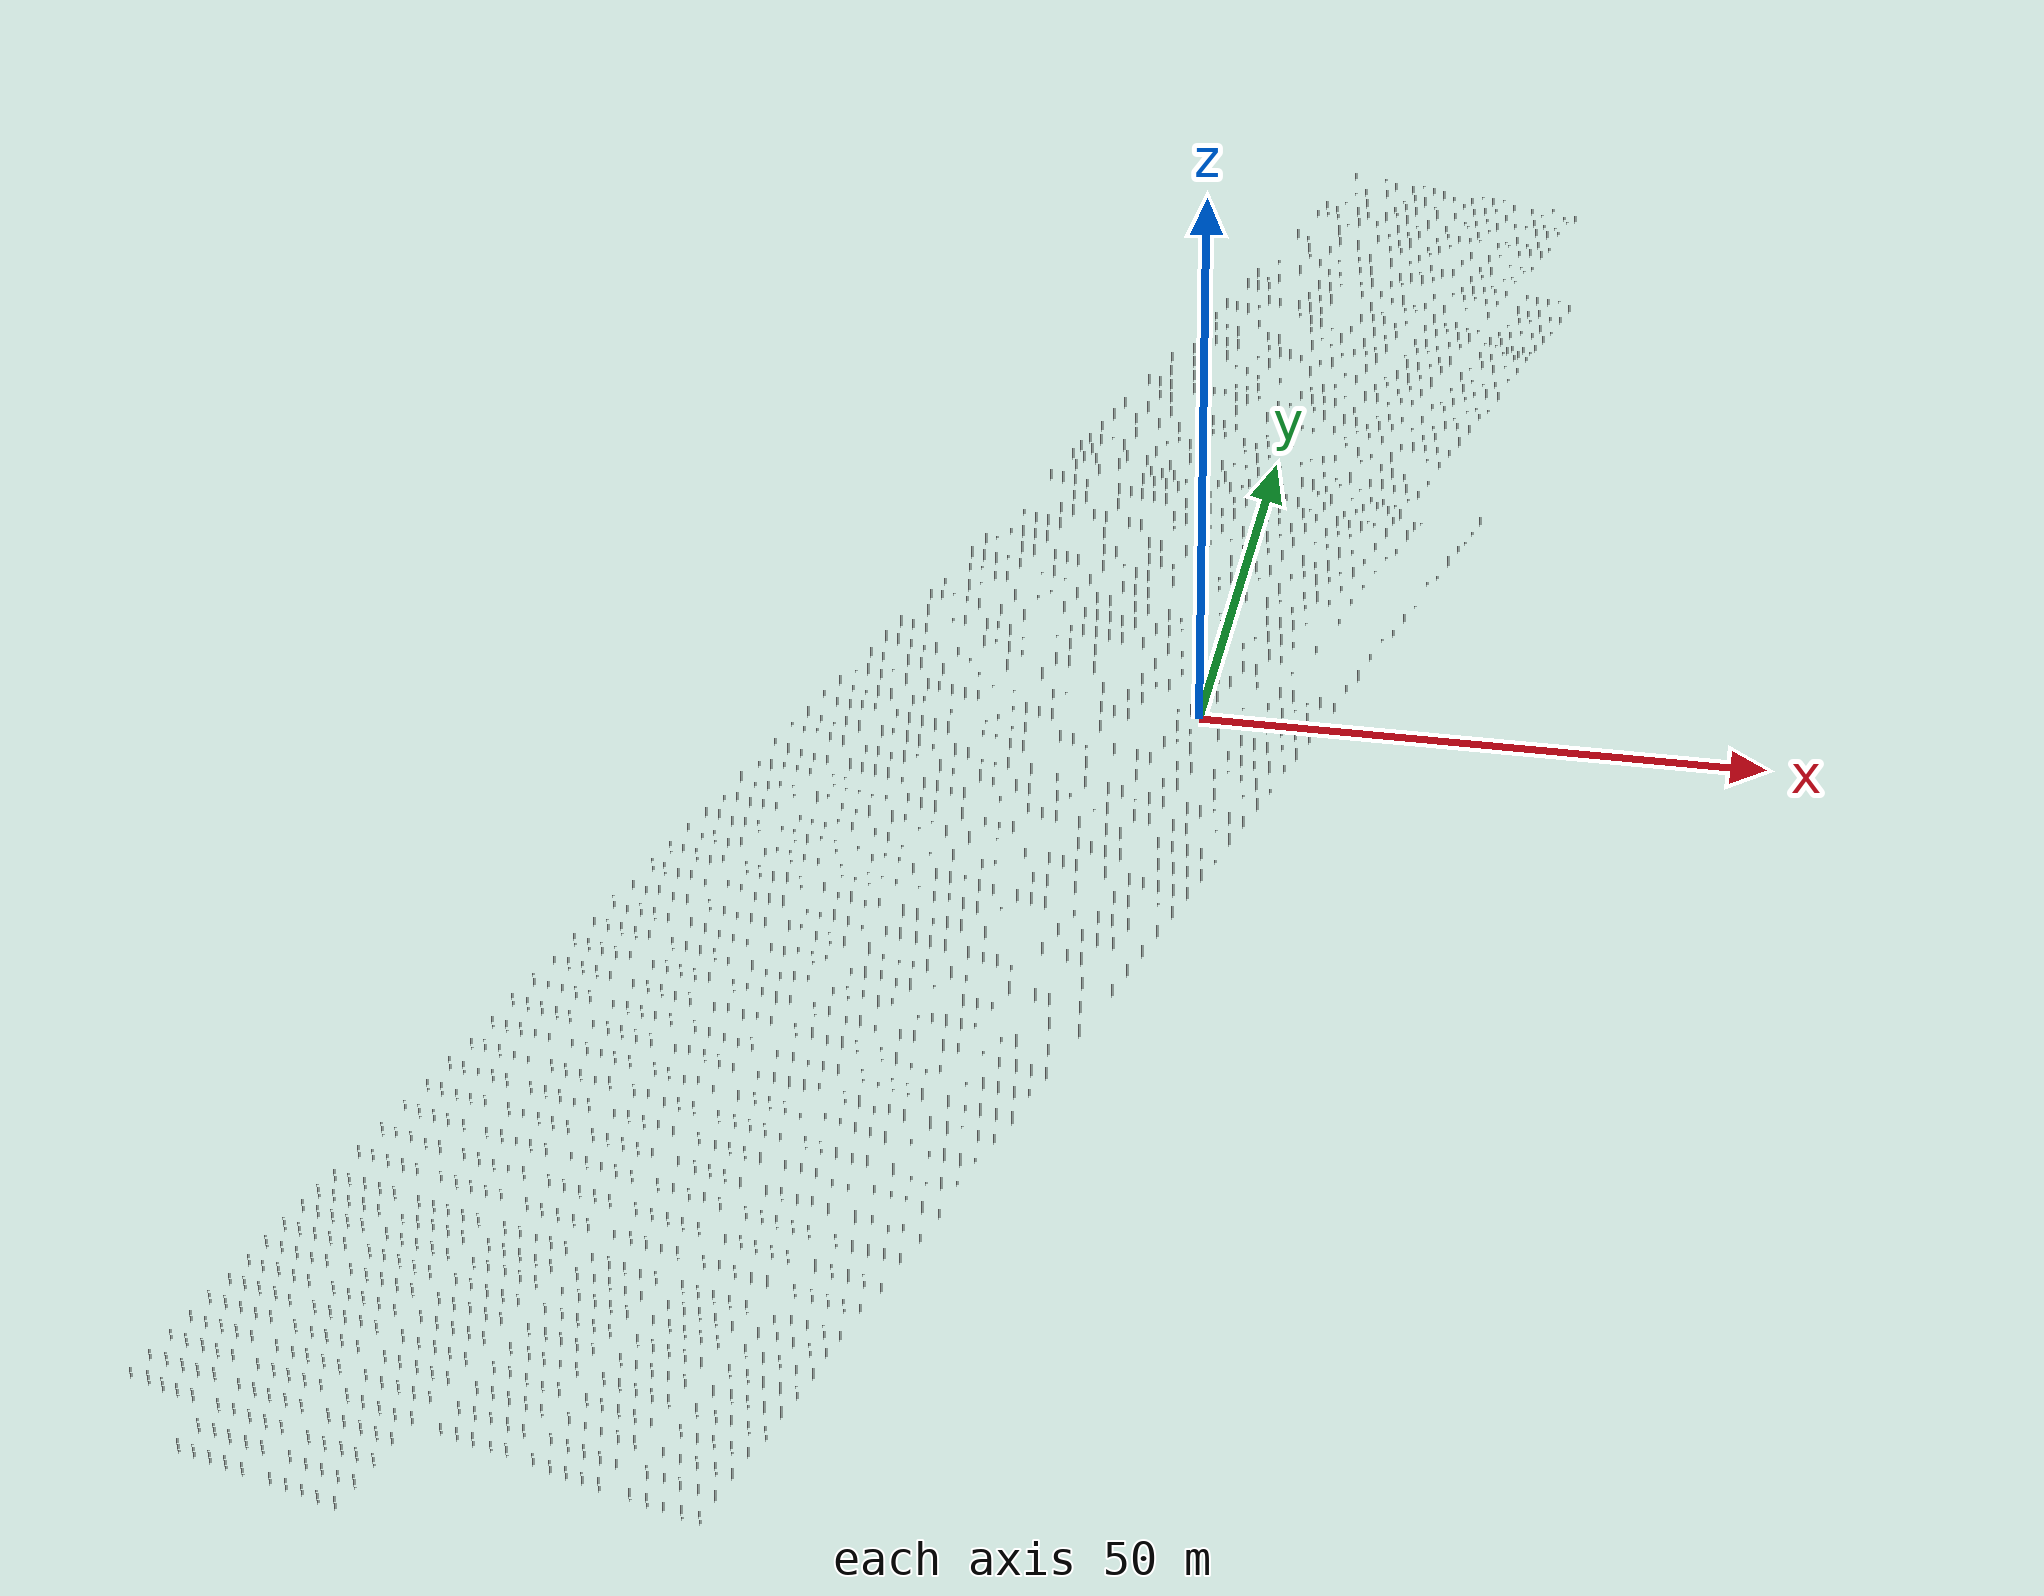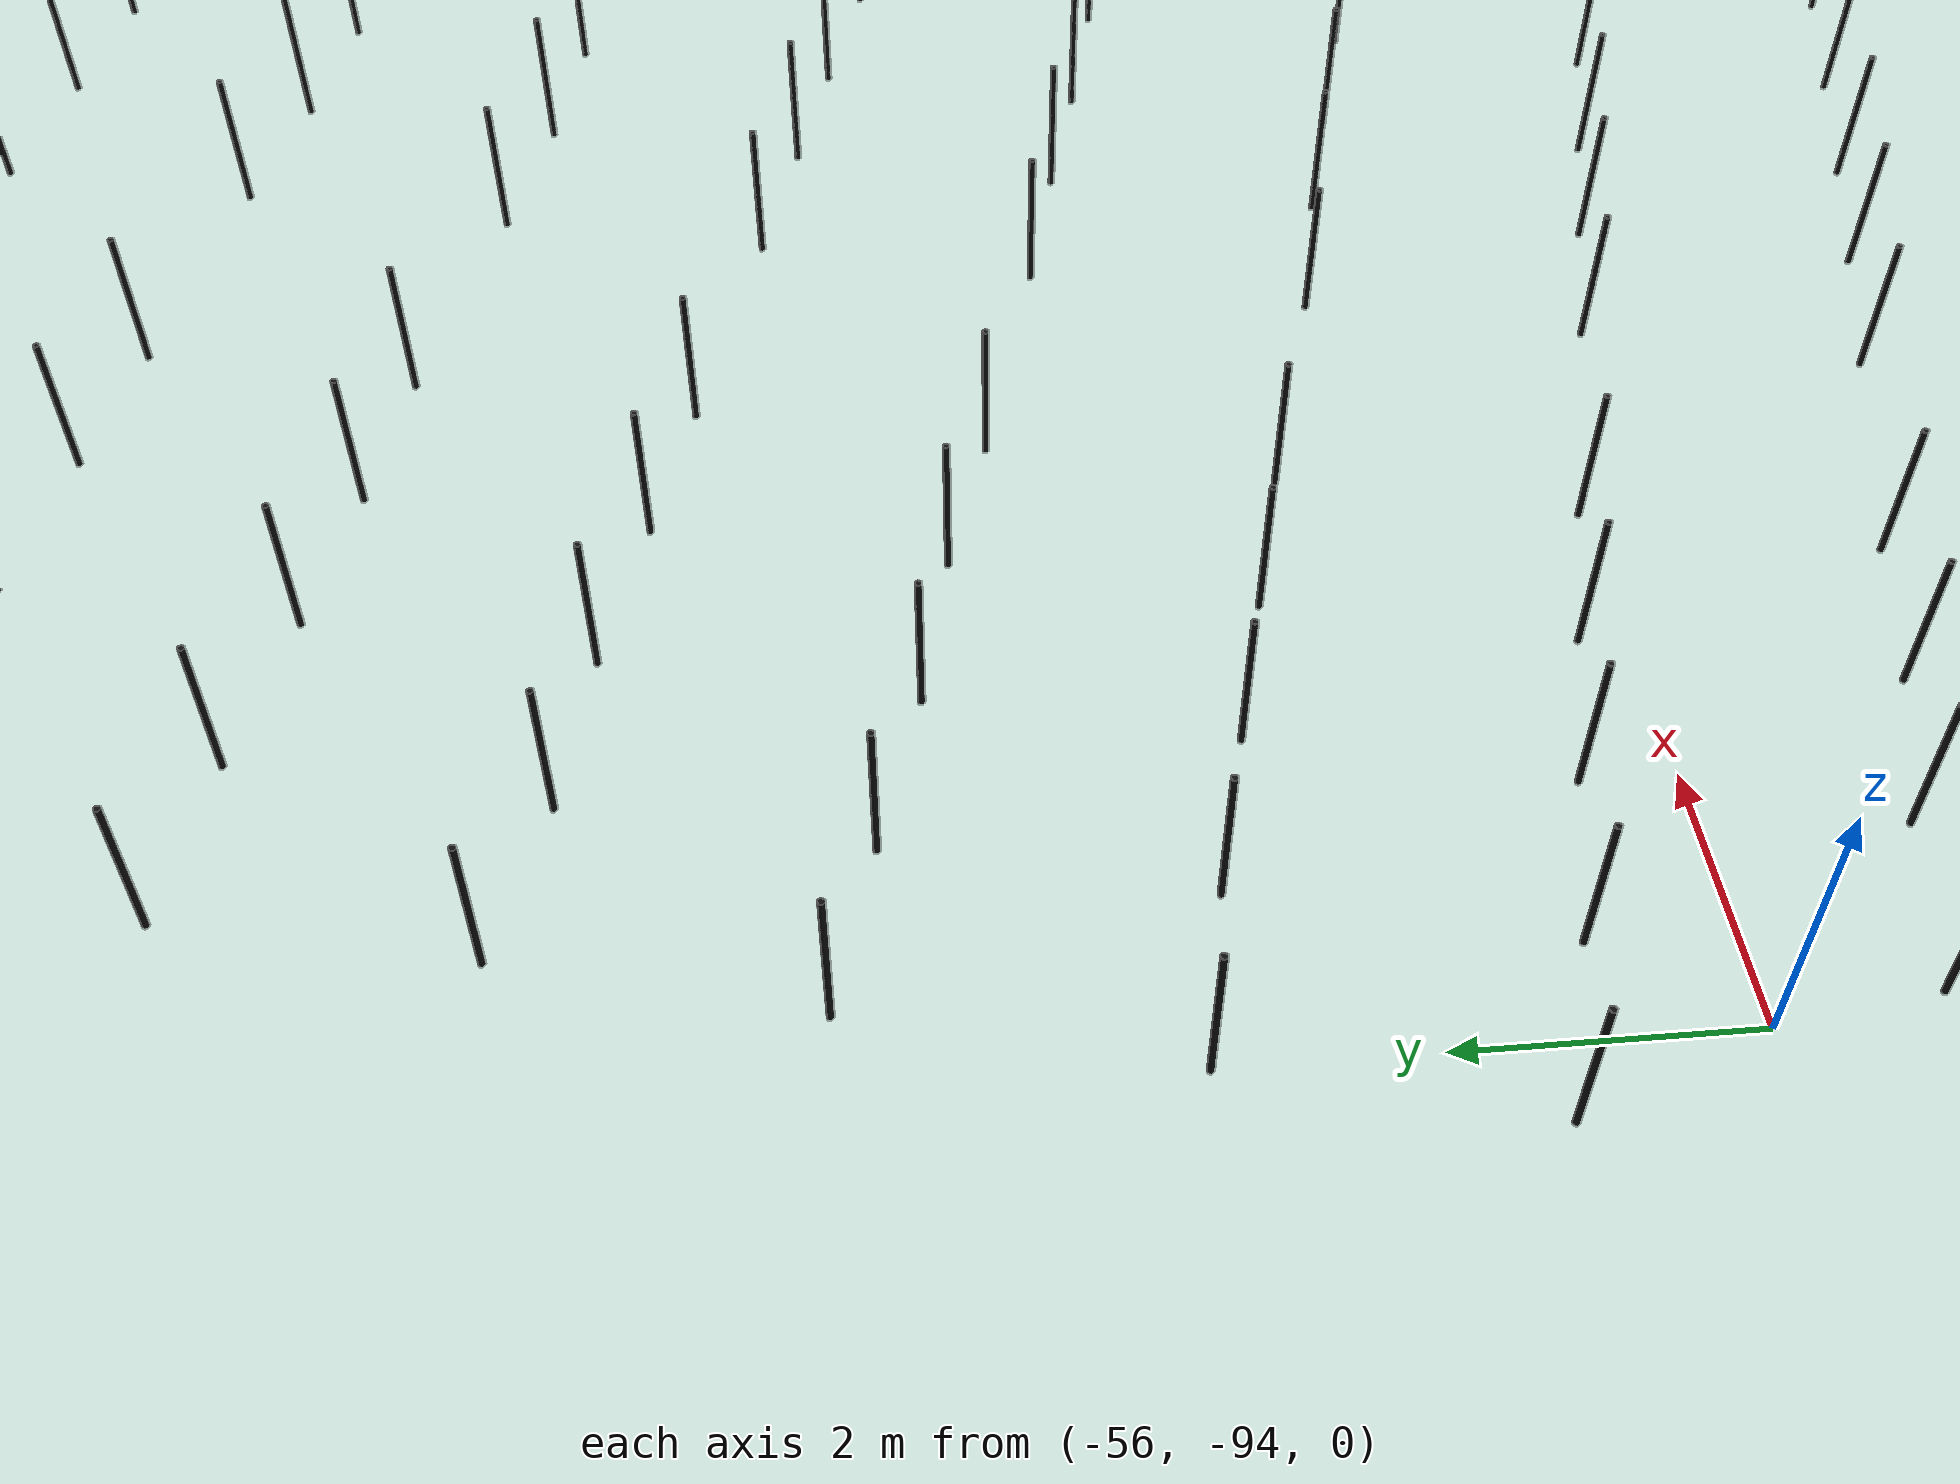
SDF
<sdf version="1.4">
 <world name="default">
  <include><uri>model://sun</uri></include>
  <physics type="ode">
   <real_time_update_rate>100</real_time_update_rate>
   <real_time_factor>1</real_time_factor>
   <max_step_size>0.01</max_step_size>
   <gravity>0 0 -9.8</gravity>
  </physics>
  <model name="pole_0">
   <static>1</static>
   <pose>-58.195 -99.010 0.575 0.0 0.0 0.0</pose>
   <link name="link">
    <collision name="collision">
     <geometry><cylinder><length>1.15</length><radius>0.025</radius></cylinder></geometry>
    </collision>
    <visual name="visual">
     <geometry><cylinder><length>1.15</length><radius>0.025</radius></cylinder></geometry>
     <material>
      <script><uri>file://media/materials/scripts/gazebo.material</uri><name>Gazebo/Chrome</name></script>
      <shader type="vertex"><normal_map>__default__</normal_map></shader>
      <emissive>0.1 0.1 0.1 1</emissive>
      <specular>0.01 0.01 0.01 1</specular>
      <ambient>0.5 0.5 0.5 1</ambient>
      <diffuse>0.05 0.05 0.05 1</diffuse>
     </material>
    </visual>
   </link>
  </model>
  <model name="pole_1">
   <static>1</static>
   <pose>-57.702 -96.967 0.575 0.0 0.0 0.0</pose>
   <link name="link">
    <collision name="collision">
     <geometry><cylinder><length>1.15</length><radius>0.025</radius></cylinder></geometry>
    </collision>
    <visual name="visual">
     <geometry><cylinder><length>1.15</length><radius>0.025</radius></cylinder></geometry>
     <material>
      <script><uri>file://media/materials/scripts/gazebo.material</uri><name>Gazebo/Chrome</name></script>
      <shader type="vertex"><normal_map>__default__</normal_map></shader>
      <emissive>0.1 0.1 0.1 1</emissive>
      <specular>0.01 0.01 0.01 1</specular>
      <ambient>0.5 0.5 0.5 1</ambient>
      <diffuse>0.05 0.05 0.05 1</diffuse>
     </material>
    </visual>
   </link>
  </model>
  <model name="pole_2">
   <static>1</static>
   <pose>-57.100 -94.780 0.575 0.0 0.0 0.0</pose>
   <link name="link">
    <collision name="collision">
     <geometry><cylinder><length>1.15</length><radius>0.025</radius></cylinder></geometry>
    </collision>
    <visual name="visual">
     <geometry><cylinder><length>1.15</length><radius>0.025</radius></cylinder></geometry>
     <material>
      <script><uri>file://media/materials/scripts/gazebo.material</uri><name>Gazebo/Chrome</name></script>
      <shader type="vertex"><normal_map>__default__</normal_map></shader>
      <emissive>0.1 0.1 0.1 1</emissive>
      <specular>0.01 0.01 0.01 1</specular>
      <ambient>0.5 0.5 0.5 1</ambient>
      <diffuse>0.05 0.05 0.05 1</diffuse>
     </material>
    </visual>
   </link>
  </model>
  <model name="pole_3">
   <static>1</static>
   <pose>-56.536 -92.650 0.575 0.0 0.0 0.0</pose>
   <link name="link">
    <collision name="collision">
     <geometry><cylinder><length>1.15</length><radius>0.025</radius></cylinder></geometry>
    </collision>
    <visual name="visual">
     <geometry><cylinder><length>1.15</length><radius>0.025</radius></cylinder></geometry>
     <material>
      <script><uri>file://media/materials/scripts/gazebo.material</uri><name>Gazebo/Chrome</name></script>
      <shader type="vertex"><normal_map>__default__</normal_map></shader>
      <emissive>0.1 0.1 0.1 1</emissive>
      <specular>0.01 0.01 0.01 1</specular>
      <ambient>0.5 0.5 0.5 1</ambient>
      <diffuse>0.05 0.05 0.05 1</diffuse>
     </material>
    </visual>
   </link>
  </model>
  <model name="pole_4">
   <static>1</static>
   <pose>-56.000 -90.580 0.575 0.0 0.0 0.0</pose>
   <link name="link">
    <collision name="collision">
     <geometry><cylinder><length>1.15</length><radius>0.025</radius></cylinder></geometry>
    </collision>
    <visual name="visual">
     <geometry><cylinder><length>1.15</length><radius>0.025</radius></cylinder></geometry>
     <material>
      <script><uri>file://media/materials/scripts/gazebo.material</uri><name>Gazebo/Chrome</name></script>
      <shader type="vertex"><normal_map>__default__</normal_map></shader>
      <emissive>0.1 0.1 0.1 1</emissive>
      <specular>0.01 0.01 0.01 1</specular>
      <ambient>0.5 0.5 0.5 1</ambient>
      <diffuse>0.05 0.05 0.05 1</diffuse>
     </material>
    </visual>
   </link>
  </model>
  <model name="pole_5">
   <static>1</static>
   <pose>-55.425 -88.350 0.575 0.0 0.0 0.0</pose>
   <link name="link">
    <collision name="collision">
     <geometry><cylinder><length>1.15</length><radius>0.025</radius></cylinder></geometry>
    </collision>
    <visual name="visual">
     <geometry><cylinder><length>1.15</length><radius>0.025</radius></cylinder></geometry>
     <material>
      <script><uri>file://media/materials/scripts/gazebo.material</uri><name>Gazebo/Chrome</name></script>
      <shader type="vertex"><normal_map>__default__</normal_map></shader>
      <emissive>0.1 0.1 0.1 1</emissive>
      <specular>0.01 0.01 0.01 1</specular>
      <ambient>0.5 0.5 0.5 1</ambient>
      <diffuse>0.05 0.05 0.05 1</diffuse>
     </material>
    </visual>
   </link>
  </model>
  <model name="pole_6">
   <static>1</static>
   <pose>-54.850 -86.230 0.575 0.0 0.0 0.0</pose>
   <link name="link">
    <collision name="collision">
     <geometry><cylinder><length>1.15</length><radius>0.025</radius></cylinder></geometry>
    </collision>
    <visual name="visual">
     <geometry><cylinder><length>1.15</length><radius>0.025</radius></cylinder></geometry>
     <material>
      <script><uri>file://media/materials/scripts/gazebo.material</uri><name>Gazebo/Chrome</name></script>
      <shader type="vertex"><normal_map>__default__</normal_map></shader>
      <emissive>0.1 0.1 0.1 1</emissive>
      <specular>0.01 0.01 0.01 1</specular>
      <ambient>0.5 0.5 0.5 1</ambient>
      <diffuse>0.05 0.05 0.05 1</diffuse>
     </material>
    </visual>
   </link>
  </model>
  <model name="pole_7">
   <static>1</static>
   <pose>-54.375 -84.125 0.575 0.0 0.0 0.0</pose>
   <link name="link">
    <collision name="collision">
     <geometry><cylinder><length>1.15</length><radius>0.025</radius></cylinder></geometry>
    </collision>
    <visual name="visual">
     <geometry><cylinder><length>1.15</length><radius>0.025</radius></cylinder></geometry>
     <material>
      <script><uri>file://media/materials/scripts/gazebo.material</uri><name>Gazebo/Chrome</name></script>
      <shader type="vertex"><normal_map>__default__</normal_map></shader>
      <emissive>0.1 0.1 0.1 1</emissive>
      <specular>0.01 0.01 0.01 1</specular>
      <ambient>0.5 0.5 0.5 1</ambient>
      <diffuse>0.05 0.05 0.05 1</diffuse>
     </material>
    </visual>
   </link>
  </model>
  <model name="pole_8">
   <static>1</static>
   <pose>-53.820 -82.050 0.575 0.0 0.0 0.0</pose>
   <link name="link">
    <collision name="collision">
     <geometry><cylinder><length>1.15</length><radius>0.025</radius></cylinder></geometry>
    </collision>
    <visual name="visual">
     <geometry><cylinder><length>1.15</length><radius>0.025</radius></cylinder></geometry>
     <material>
      <script><uri>file://media/materials/scripts/gazebo.material</uri><name>Gazebo/Chrome</name></script>
      <shader type="vertex"><normal_map>__default__</normal_map></shader>
      <emissive>0.1 0.1 0.1 1</emissive>
      <specular>0.01 0.01 0.01 1</specular>
      <ambient>0.5 0.5 0.5 1</ambient>
      <diffuse>0.05 0.05 0.05 1</diffuse>
     </material>
    </visual>
   </link>
  </model>
  <model name="pole_9">
   <static>1</static>
   <pose>-53.263 -79.873 0.575 0.0 0.0 0.0</pose>
   <link name="link">
    <collision name="collision">
     <geometry><cylinder><length>1.15</length><radius>0.025</radius></cylinder></geometry>
    </collision>
    <visual name="visual">
     <geometry><cylinder><length>1.15</length><radius>0.025</radius></cylinder></geometry>
     <material>
      <script><uri>file://media/materials/scripts/gazebo.material</uri><name>Gazebo/Chrome</name></script>
      <shader type="vertex"><normal_map>__default__</normal_map></shader>
      <emissive>0.1 0.1 0.1 1</emissive>
      <specular>0.01 0.01 0.01 1</specular>
      <ambient>0.5 0.5 0.5 1</ambient>
      <diffuse>0.05 0.05 0.05 1</diffuse>
     </material>
    </visual>
   </link>
  </model>
  <model name="pole_10">
   <static>1</static>
   <pose>-52.795 -78.004 0.575 0.0 0.0 0.0</pose>
   <link name="link">
    <collision name="collision">
     <geometry><cylinder><length>1.15</length><radius>0.025</radius></cylinder></geometry>
    </collision>
    <visual name="visual">
     <geometry><cylinder><length>1.15</length><radius>0.025</radius></cylinder></geometry>
     <material>
      <script><uri>file://media/materials/scripts/gazebo.material</uri><name>Gazebo/Chrome</name></script>
      <shader type="vertex"><normal_map>__default__</normal_map></shader>
      <emissive>0.1 0.1 0.1 1</emissive>
      <specular>0.01 0.01 0.01 1</specular>
      <ambient>0.5 0.5 0.5 1</ambient>
      <diffuse>0.05 0.05 0.05 1</diffuse>
     </material>
    </visual>
   </link>
  </model>
  <model name="pole_11">
   <static>1</static>
   <pose>-52.296 -76.028 0.575 0.0 0.0 0.0</pose>
   <link name="link">
    <collision name="collision">
     <geometry><cylinder><length>1.15</length><radius>0.025</radius></cylinder></geometry>
    </collision>
    <visual name="visual">
     <geometry><cylinder><length>1.15</length><radius>0.025</radius></cylinder></geometry>
     <material>
      <script><uri>file://media/materials/scripts/gazebo.material</uri><name>Gazebo/Chrome</name></script>
      <shader type="vertex"><normal_map>__default__</normal_map></shader>
      <emissive>0.1 0.1 0.1 1</emissive>
      <specular>0.01 0.01 0.01 1</specular>
      <ambient>0.5 0.5 0.5 1</ambient>
      <diffuse>0.05 0.05 0.05 1</diffuse>
     </material>
    </visual>
   </link>
  </model>
  <model name="pole_12">
   <static>1</static>
   <pose>-51.522 -73.122 0.575 0.0 0.0 0.0</pose>
   <link name="link">
    <collision name="collision">
     <geometry><cylinder><length>1.15</length><radius>0.025</radius></cylinder></geometry>
    </collision>
    <visual name="visual">
     <geometry><cylinder><length>1.15</length><radius>0.025</radius></cylinder></geometry>
     <material>
      <script><uri>file://media/materials/scripts/gazebo.material</uri><name>Gazebo/Chrome</name></script>
      <shader type="vertex"><normal_map>__default__</normal_map></shader>
      <emissive>0.1 0.1 0.1 1</emissive>
      <specular>0.01 0.01 0.01 1</specular>
      <ambient>0.5 0.5 0.5 1</ambient>
      <diffuse>0.05 0.05 0.05 1</diffuse>
     </material>
    </visual>
   </link>
  </model>
  <model name="pole_13">
   <static>1</static>
   <pose>-50.772 -70.204 0.575 0.0 0.0 0.0</pose>
   <link name="link">
    <collision name="collision">
     <geometry><cylinder><length>1.15</length><radius>0.025</radius></cylinder></geometry>
    </collision>
    <visual name="visual">
     <geometry><cylinder><length>1.15</length><radius>0.025</radius></cylinder></geometry>
     <material>
      <script><uri>file://media/materials/scripts/gazebo.material</uri><name>Gazebo/Chrome</name></script>
      <shader type="vertex"><normal_map>__default__</normal_map></shader>
      <emissive>0.1 0.1 0.1 1</emissive>
      <specular>0.01 0.01 0.01 1</specular>
      <ambient>0.5 0.5 0.5 1</ambient>
      <diffuse>0.05 0.05 0.05 1</diffuse>
     </material>
    </visual>
   </link>
  </model>
  <model name="pole_14">
   <static>1</static>
   <pose>-50.028 -67.278 0.575 0.0 0.0 0.0</pose>
   <link name="link">
    <collision name="collision">
     <geometry><cylinder><length>1.15</length><radius>0.025</radius></cylinder></geometry>
    </collision>
    <visual name="visual">
     <geometry><cylinder><length>1.15</length><radius>0.025</radius></cylinder></geometry>
     <material>
      <script><uri>file://media/materials/scripts/gazebo.material</uri><name>Gazebo/Chrome</name></script>
      <shader type="vertex"><normal_map>__default__</normal_map></shader>
      <emissive>0.1 0.1 0.1 1</emissive>
      <specular>0.01 0.01 0.01 1</specular>
      <ambient>0.5 0.5 0.5 1</ambient>
      <diffuse>0.05 0.05 0.05 1</diffuse>
     </material>
    </visual>
   </link>
  </model>
  <model name="pole_15">
   <static>1</static>
   <pose>-49.300 -64.375 0.575 0.0 0.0 0.0</pose>
   <link name="link">
    <collision name="collision">
     <geometry><cylinder><length>1.15</length><radius>0.025</radius></cylinder></geometry>
    </collision>
    <visual name="visual">
     <geometry><cylinder><length>1.15</length><radius>0.025</radius></cylinder></geometry>
     <material>
      <script><uri>file://media/materials/scripts/gazebo.material</uri><name>Gazebo/Chrome</name></script>
      <shader type="vertex"><normal_map>__default__</normal_map></shader>
      <emissive>0.1 0.1 0.1 1</emissive>
      <specular>0.01 0.01 0.01 1</specular>
      <ambient>0.5 0.5 0.5 1</ambient>
      <diffuse>0.05 0.05 0.05 1</diffuse>
     </material>
    </visual>
   </link>
  </model>
  <model name="pole_16">
   <static>1</static>
   <pose>-48.553 -61.453 0.575 0.0 0.0 0.0</pose>
   <link name="link">
    <collision name="collision">
     <geometry><cylinder><length>1.15</length><radius>0.025</radius></cylinder></geometry>
    </collision>
    <visual name="visual">
     <geometry><cylinder><length>1.15</length><radius>0.025</radius></cylinder></geometry>
     <material>
      <script><uri>file://media/materials/scripts/gazebo.material</uri><name>Gazebo/Chrome</name></script>
      <shader type="vertex"><normal_map>__default__</normal_map></shader>
      <emissive>0.1 0.1 0.1 1</emissive>
      <specular>0.01 0.01 0.01 1</specular>
      <ambient>0.5 0.5 0.5 1</ambient>
      <diffuse>0.05 0.05 0.05 1</diffuse>
     </material>
    </visual>
   </link>
  </model>
  <model name="pole_17">
   <static>1</static>
   <pose>-47.800 -58.600 0.575 0.0 0.0 0.0</pose>
   <link name="link">
    <collision name="collision">
     <geometry><cylinder><length>1.15</length><radius>0.025</radius></cylinder></geometry>
    </collision>
    <visual name="visual">
     <geometry><cylinder><length>1.15</length><radius>0.025</radius></cylinder></geometry>
     <material>
      <script><uri>file://media/materials/scripts/gazebo.material</uri><name>Gazebo/Chrome</name></script>
      <shader type="vertex"><normal_map>__default__</normal_map></shader>
      <emissive>0.1 0.1 0.1 1</emissive>
      <specular>0.01 0.01 0.01 1</specular>
      <ambient>0.5 0.5 0.5 1</ambient>
      <diffuse>0.05 0.05 0.05 1</diffuse>
     </material>
    </visual>
   </link>
  </model>
  <model name="pole_18">
   <static>1</static>
   <pose>-47.078 -55.696 0.575 0.0 0.0 0.0</pose>
   <link name="link">
    <collision name="collision">
     <geometry><cylinder><length>1.15</length><radius>0.025</radius></cylinder></geometry>
    </collision>
    <visual name="visual">
     <geometry><cylinder><length>1.15</length><radius>0.025</radius></cylinder></geometry>
     <material>
      <script><uri>file://media/materials/scripts/gazebo.material</uri><name>Gazebo/Chrome</name></script>
      <shader type="vertex"><normal_map>__default__</normal_map></shader>
      <emissive>0.1 0.1 0.1 1</emissive>
      <specular>0.01 0.01 0.01 1</specular>
      <ambient>0.5 0.5 0.5 1</ambient>
      <diffuse>0.05 0.05 0.05 1</diffuse>
     </material>
    </visual>
   </link>
  </model>
  <model name="pole_19">
   <static>1</static>
   <pose>-46.440 -52.653 0.575 0.0 0.0 0.0</pose>
   <link name="link">
    <collision name="collision">
     <geometry><cylinder><length>1.15</length><radius>0.025</radius></cylinder></geometry>
    </collision>
    <visual name="visual">
     <geometry><cylinder><length>1.15</length><radius>0.025</radius></cylinder></geometry>
     <material>
      <script><uri>file://media/materials/scripts/gazebo.material</uri><name>Gazebo/Chrome</name></script>
      <shader type="vertex"><normal_map>__default__</normal_map></shader>
      <emissive>0.1 0.1 0.1 1</emissive>
      <specular>0.01 0.01 0.01 1</specular>
      <ambient>0.5 0.5 0.5 1</ambient>
      <diffuse>0.05 0.05 0.05 1</diffuse>
     </material>
    </visual>
   </link>
  </model>
  <model name="pole_20">
   <static>1</static>
   <pose>-45.619 -49.811 0.575 0.0 0.0 0.0</pose>
   <link name="link">
    <collision name="collision">
     <geometry><cylinder><length>1.15</length><radius>0.025</radius></cylinder></geometry>
    </collision>
    <visual name="visual">
     <geometry><cylinder><length>1.15</length><radius>0.025</radius></cylinder></geometry>
     <material>
      <script><uri>file://media/materials/scripts/gazebo.material</uri><name>Gazebo/Chrome</name></script>
      <shader type="vertex"><normal_map>__default__</normal_map></shader>
      <emissive>0.1 0.1 0.1 1</emissive>
      <specular>0.01 0.01 0.01 1</specular>
      <ambient>0.5 0.5 0.5 1</ambient>
      <diffuse>0.05 0.05 0.05 1</diffuse>
     </material>
    </visual>
   </link>
  </model>
  <model name="pole_21">
   <static>1</static>
   <pose>-44.892 -46.881 0.575 0.0 0.0 0.0</pose>
   <link name="link">
    <collision name="collision">
     <geometry><cylinder><length>1.15</length><radius>0.025</radius></cylinder></geometry>
    </collision>
    <visual name="visual">
     <geometry><cylinder><length>1.15</length><radius>0.025</radius></cylinder></geometry>
     <material>
      <script><uri>file://media/materials/scripts/gazebo.material</uri><name>Gazebo/Chrome</name></script>
      <shader type="vertex"><normal_map>__default__</normal_map></shader>
      <emissive>0.1 0.1 0.1 1</emissive>
      <specular>0.01 0.01 0.01 1</specular>
      <ambient>0.5 0.5 0.5 1</ambient>
      <diffuse>0.05 0.05 0.05 1</diffuse>
     </material>
    </visual>
   </link>
  </model>
  <model name="pole_22">
   <static>1</static>
   <pose>-44.145 -43.902 0.575 0.0 0.0 0.0</pose>
   <link name="link">
    <collision name="collision">
     <geometry><cylinder><length>1.15</length><radius>0.025</radius></cylinder></geometry>
    </collision>
    <visual name="visual">
     <geometry><cylinder><length>1.15</length><radius>0.025</radius></cylinder></geometry>
     <material>
      <script><uri>file://media/materials/scripts/gazebo.material</uri><name>Gazebo/Chrome</name></script>
      <shader type="vertex"><normal_map>__default__</normal_map></shader>
      <emissive>0.1 0.1 0.1 1</emissive>
      <specular>0.01 0.01 0.01 1</specular>
      <ambient>0.5 0.5 0.5 1</ambient>
      <diffuse>0.05 0.05 0.05 1</diffuse>
     </material>
    </visual>
   </link>
  </model>
  <model name="pole_23">
   <static>1</static>
   <pose>-43.394 -41.029 0.575 0.0 0.0 0.0</pose>
   <link name="link">
    <collision name="collision">
     <geometry><cylinder><length>1.15</length><radius>0.025</radius></cylinder></geometry>
    </collision>
    <visual name="visual">
     <geometry><cylinder><length>1.15</length><radius>0.025</radius></cylinder></geometry>
     <material>
      <script><uri>file://media/materials/scripts/gazebo.material</uri><name>Gazebo/Chrome</name></script>
      <shader type="vertex"><normal_map>__default__</normal_map></shader>
      <emissive>0.1 0.1 0.1 1</emissive>
      <specular>0.01 0.01 0.01 1</specular>
      <ambient>0.5 0.5 0.5 1</ambient>
      <diffuse>0.05 0.05 0.05 1</diffuse>
     </material>
    </visual>
   </link>
  </model>
  <model name="pole_24">
   <static>1</static>
   <pose>-42.640 -38.045 0.575 0.0 0.0 0.0</pose>
   <link name="link">
    <collision name="collision">
     <geometry><cylinder><length>1.15</length><radius>0.025</radius></cylinder></geometry>
    </collision>
    <visual name="visual">
     <geometry><cylinder><length>1.15</length><radius>0.025</radius></cylinder></geometry>
     <material>
      <script><uri>file://media/materials/scripts/gazebo.material</uri><name>Gazebo/Chrome</name></script>
      <shader type="vertex"><normal_map>__default__</normal_map></shader>
      <emissive>0.1 0.1 0.1 1</emissive>
      <specular>0.01 0.01 0.01 1</specular>
      <ambient>0.5 0.5 0.5 1</ambient>
      <diffuse>0.05 0.05 0.05 1</diffuse>
     </material>
    </visual>
   </link>
  </model>
  <model name="pole_25">
   <static>1</static>
   <pose>-41.884 -35.137 0.575 0.0 0.0 0.0</pose>
   <link name="link">
    <collision name="collision">
     <geometry><cylinder><length>1.15</length><radius>0.025</radius></cylinder></geometry>
    </collision>
    <visual name="visual">
     <geometry><cylinder><length>1.15</length><radius>0.025</radius></cylinder></geometry>
     <material>
      <script><uri>file://media/materials/scripts/gazebo.material</uri><name>Gazebo/Chrome</name></script>
      <shader type="vertex"><normal_map>__default__</normal_map></shader>
      <emissive>0.1 0.1 0.1 1</emissive>
      <specular>0.01 0.01 0.01 1</specular>
      <ambient>0.5 0.5 0.5 1</ambient>
      <diffuse>0.05 0.05 0.05 1</diffuse>
     </material>
    </visual>
   </link>
  </model>
  <model name="pole_26">
   <static>1</static>
   <pose>-41.100 -32.113 0.575 0.0 0.0 0.0</pose>
   <link name="link">
    <collision name="collision">
     <geometry><cylinder><length>1.15</length><radius>0.025</radius></cylinder></geometry>
    </collision>
    <visual name="visual">
     <geometry><cylinder><length>1.15</length><radius>0.025</radius></cylinder></geometry>
     <material>
      <script><uri>file://media/materials/scripts/gazebo.material</uri><name>Gazebo/Chrome</name></script>
      <shader type="vertex"><normal_map>__default__</normal_map></shader>
      <emissive>0.1 0.1 0.1 1</emissive>
      <specular>0.01 0.01 0.01 1</specular>
      <ambient>0.5 0.5 0.5 1</ambient>
      <diffuse>0.05 0.05 0.05 1</diffuse>
     </material>
    </visual>
   </link>
  </model>
  <model name="pole_27">
   <static>1</static>
   <pose>-40.371 -29.338 0.575 0.0 0.0 0.0</pose>
   <link name="link">
    <collision name="collision">
     <geometry><cylinder><length>1.15</length><radius>0.025</radius></cylinder></geometry>
    </collision>
    <visual name="visual">
     <geometry><cylinder><length>1.15</length><radius>0.025</radius></cylinder></geometry>
     <material>
      <script><uri>file://media/materials/scripts/gazebo.material</uri><name>Gazebo/Chrome</name></script>
      <shader type="vertex"><normal_map>__default__</normal_map></shader>
      <emissive>0.1 0.1 0.1 1</emissive>
      <specular>0.01 0.01 0.01 1</specular>
      <ambient>0.5 0.5 0.5 1</ambient>
      <diffuse>0.05 0.05 0.05 1</diffuse>
     </material>
    </visual>
   </link>
  </model>
  <model name="pole_28">
   <static>1</static>
   <pose>-39.661 -26.412 0.575 0.0 0.0 0.0</pose>
   <link name="link">
    <collision name="collision">
     <geometry><cylinder><length>1.15</length><radius>0.025</radius></cylinder></geometry>
    </collision>
    <visual name="visual">
     <geometry><cylinder><length>1.15</length><radius>0.025</radius></cylinder></geometry>
     <material>
      <script><uri>file://media/materials/scripts/gazebo.material</uri><name>Gazebo/Chrome</name></script>
      <shader type="vertex"><normal_map>__default__</normal_map></shader>
      <emissive>0.1 0.1 0.1 1</emissive>
      <specular>0.01 0.01 0.01 1</specular>
      <ambient>0.5 0.5 0.5 1</ambient>
      <diffuse>0.05 0.05 0.05 1</diffuse>
     </material>
    </visual>
   </link>
  </model>
  <model name="pole_29">
   <static>1</static>
   <pose>-38.919 -23.526 0.575 0.0 0.0 0.0</pose>
   <link name="link">
    <collision name="collision">
     <geometry><cylinder><length>1.15</length><radius>0.025</radius></cylinder></geometry>
    </collision>
    <visual name="visual">
     <geometry><cylinder><length>1.15</length><radius>0.025</radius></cylinder></geometry>
     <material>
      <script><uri>file://media/materials/scripts/gazebo.material</uri><name>Gazebo/Chrome</name></script>
      <shader type="vertex"><normal_map>__default__</normal_map></shader>
      <emissive>0.1 0.1 0.1 1</emissive>
      <specular>0.01 0.01 0.01 1</specular>
      <ambient>0.5 0.5 0.5 1</ambient>
      <diffuse>0.05 0.05 0.05 1</diffuse>
     </material>
    </visual>
   </link>
  </model>
  <model name="pole_30">
   <static>1</static>
   <pose>-38.171 -20.609 0.575 0.0 0.0 0.0</pose>
   <link name="link">
    <collision name="collision">
     <geometry><cylinder><length>1.15</length><radius>0.025</radius></cylinder></geometry>
    </collision>
    <visual name="visual">
     <geometry><cylinder><length>1.15</length><radius>0.025</radius></cylinder></geometry>
     <material>
      <script><uri>file://media/materials/scripts/gazebo.material</uri><name>Gazebo/Chrome</name></script>
      <shader type="vertex"><normal_map>__default__</normal_map></shader>
      <emissive>0.1 0.1 0.1 1</emissive>
      <specular>0.01 0.01 0.01 1</specular>
      <ambient>0.5 0.5 0.5 1</ambient>
      <diffuse>0.05 0.05 0.05 1</diffuse>
     </material>
    </visual>
   </link>
  </model>
  <model name="pole_31">
   <static>1</static>
   <pose>-37.428 -17.682 0.575 0.0 0.0 0.0</pose>
   <link name="link">
    <collision name="collision">
     <geometry><cylinder><length>1.15</length><radius>0.025</radius></cylinder></geometry>
    </collision>
    <visual name="visual">
     <geometry><cylinder><length>1.15</length><radius>0.025</radius></cylinder></geometry>
     <material>
      <script><uri>file://media/materials/scripts/gazebo.material</uri><name>Gazebo/Chrome</name></script>
      <shader type="vertex"><normal_map>__default__</normal_map></shader>
      <emissive>0.1 0.1 0.1 1</emissive>
      <specular>0.01 0.01 0.01 1</specular>
      <ambient>0.5 0.5 0.5 1</ambient>
      <diffuse>0.05 0.05 0.05 1</diffuse>
     </material>
    </visual>
   </link>
  </model>
  <model name="pole_32">
   <static>1</static>
   <pose>-36.667 -14.675 0.575 0.0 0.0 0.0</pose>
   <link name="link">
    <collision name="collision">
     <geometry><cylinder><length>1.15</length><radius>0.025</radius></cylinder></geometry>
    </collision>
    <visual name="visual">
     <geometry><cylinder><length>1.15</length><radius>0.025</radius></cylinder></geometry>
     <material>
      <script><uri>file://media/materials/scripts/gazebo.material</uri><name>Gazebo/Chrome</name></script>
      <shader type="vertex"><normal_map>__default__</normal_map></shader>
      <emissive>0.1 0.1 0.1 1</emissive>
      <specular>0.01 0.01 0.01 1</specular>
      <ambient>0.5 0.5 0.5 1</ambient>
      <diffuse>0.05 0.05 0.05 1</diffuse>
     </material>
    </visual>
   </link>
  </model>
  <model name="pole_33">
   <static>1</static>
   <pose>-35.929 -11.803 0.575 0.0 0.0 0.0</pose>
   <link name="link">
    <collision name="collision">
     <geometry><cylinder><length>1.15</length><radius>0.025</radius></cylinder></geometry>
    </collision>
    <visual name="visual">
     <geometry><cylinder><length>1.15</length><radius>0.025</radius></cylinder></geometry>
     <material>
      <script><uri>file://media/materials/scripts/gazebo.material</uri><name>Gazebo/Chrome</name></script>
      <shader type="vertex"><normal_map>__default__</normal_map></shader>
      <emissive>0.1 0.1 0.1 1</emissive>
      <specular>0.01 0.01 0.01 1</specular>
      <ambient>0.5 0.5 0.5 1</ambient>
      <diffuse>0.05 0.05 0.05 1</diffuse>
     </material>
    </visual>
   </link>
  </model>
  <model name="pole_34">
   <static>1</static>
   <pose>-35.145 -8.854 0.575 0.0 0.0 0.0</pose>
   <link name="link">
    <collision name="collision">
     <geometry><cylinder><length>1.15</length><radius>0.025</radius></cylinder></geometry>
    </collision>
    <visual name="visual">
     <geometry><cylinder><length>1.15</length><radius>0.025</radius></cylinder></geometry>
     <material>
      <script><uri>file://media/materials/scripts/gazebo.material</uri><name>Gazebo/Chrome</name></script>
      <shader type="vertex"><normal_map>__default__</normal_map></shader>
      <emissive>0.1 0.1 0.1 1</emissive>
      <specular>0.01 0.01 0.01 1</specular>
      <ambient>0.5 0.5 0.5 1</ambient>
      <diffuse>0.05 0.05 0.05 1</diffuse>
     </material>
    </visual>
   </link>
  </model>
  <model name="pole_35">
   <static>1</static>
   <pose>-34.438 -6.047 0.575 0.0 0.0 0.0</pose>
   <link name="link">
    <collision name="collision">
     <geometry><cylinder><length>1.15</length><radius>0.025</radius></cylinder></geometry>
    </collision>
    <visual name="visual">
     <geometry><cylinder><length>1.15</length><radius>0.025</radius></cylinder></geometry>
     <material>
      <script><uri>file://media/materials/scripts/gazebo.material</uri><name>Gazebo/Chrome</name></script>
      <shader type="vertex"><normal_map>__default__</normal_map></shader>
      <emissive>0.1 0.1 0.1 1</emissive>
      <specular>0.01 0.01 0.01 1</specular>
      <ambient>0.5 0.5 0.5 1</ambient>
      <diffuse>0.05 0.05 0.05 1</diffuse>
     </material>
    </visual>
   </link>
  </model>
  <model name="pole_36">
   <static>1</static>
   <pose>-33.691 -3.106 0.575 0.0 0.0 0.0</pose>
   <link name="link">
    <collision name="collision">
     <geometry><cylinder><length>1.15</length><radius>0.025</radius></cylinder></geometry>
    </collision>
    <visual name="visual">
     <geometry><cylinder><length>1.15</length><radius>0.025</radius></cylinder></geometry>
     <material>
      <script><uri>file://media/materials/scripts/gazebo.material</uri><name>Gazebo/Chrome</name></script>
      <shader type="vertex"><normal_map>__default__</normal_map></shader>
      <emissive>0.1 0.1 0.1 1</emissive>
      <specular>0.01 0.01 0.01 1</specular>
      <ambient>0.5 0.5 0.5 1</ambient>
      <diffuse>0.05 0.05 0.05 1</diffuse>
     </material>
    </visual>
   </link>
  </model>
  <model name="pole_37">
   <static>1</static>
   <pose>-32.951 -0.193 0.575 0.0 0.0 0.0</pose>
   <link name="link">
    <collision name="collision">
     <geometry><cylinder><length>1.15</length><radius>0.025</radius></cylinder></geometry>
    </collision>
    <visual name="visual">
     <geometry><cylinder><length>1.15</length><radius>0.025</radius></cylinder></geometry>
     <material>
      <script><uri>file://media/materials/scripts/gazebo.material</uri><name>Gazebo/Chrome</name></script>
      <shader type="vertex"><normal_map>__default__</normal_map></shader>
      <emissive>0.1 0.1 0.1 1</emissive>
      <specular>0.01 0.01 0.01 1</specular>
      <ambient>0.5 0.5 0.5 1</ambient>
      <diffuse>0.05 0.05 0.05 1</diffuse>
     </material>
    </visual>
   </link>
  </model>
  <model name="pole_38">
   <static>1</static>
   <pose>-32.213 2.660 0.575 0.0 0.0 0.0</pose>
   <link name="link">
    <collision name="collision">
     <geometry><cylinder><length>1.15</length><radius>0.025</radius></cylinder></geometry>
    </collision>
    <visual name="visual">
     <geometry><cylinder><length>1.15</length><radius>0.025</radius></cylinder></geometry>
     <material>
      <script><uri>file://media/materials/scripts/gazebo.material</uri><name>Gazebo/Chrome</name></script>
      <shader type="vertex"><normal_map>__default__</normal_map></shader>
      <emissive>0.1 0.1 0.1 1</emissive>
      <specular>0.01 0.01 0.01 1</specular>
      <ambient>0.5 0.5 0.5 1</ambient>
      <diffuse>0.05 0.05 0.05 1</diffuse>
     </material>
    </visual>
   </link>
  </model>
  <model name="pole_39">
   <static>1</static>
   <pose>-31.479 5.575 0.575 0.0 0.0 0.0</pose>
   <link name="link">
    <collision name="collision">
     <geometry><cylinder><length>1.15</length><radius>0.025</radius></cylinder></geometry>
    </collision>
    <visual name="visual">
     <geometry><cylinder><length>1.15</length><radius>0.025</radius></cylinder></geometry>
     <material>
      <script><uri>file://media/materials/scripts/gazebo.material</uri><name>Gazebo/Chrome</name></script>
      <shader type="vertex"><normal_map>__default__</normal_map></shader>
      <emissive>0.1 0.1 0.1 1</emissive>
      <specular>0.01 0.01 0.01 1</specular>
      <ambient>0.5 0.5 0.5 1</ambient>
      <diffuse>0.05 0.05 0.05 1</diffuse>
     </material>
    </visual>
   </link>
  </model>
  <model name="pole_40">
   <static>1</static>
   <pose>-30.738 8.493 0.575 0.0 0.0 0.0</pose>
   <link name="link">
    <collision name="collision">
     <geometry><cylinder><length>1.15</length><radius>0.025</radius></cylinder></geometry>
    </collision>
    <visual name="visual">
     <geometry><cylinder><length>1.15</length><radius>0.025</radius></cylinder></geometry>
     <material>
      <script><uri>file://media/materials/scripts/gazebo.material</uri><name>Gazebo/Chrome</name></script>
      <shader type="vertex"><normal_map>__default__</normal_map></shader>
      <emissive>0.1 0.1 0.1 1</emissive>
      <specular>0.01 0.01 0.01 1</specular>
      <ambient>0.5 0.5 0.5 1</ambient>
      <diffuse>0.05 0.05 0.05 1</diffuse>
     </material>
    </visual>
   </link>
  </model>
  <model name="pole_41">
   <static>1</static>
   <pose>-30.000 11.400 0.575 0.0 0.0 0.0</pose>
   <link name="link">
    <collision name="collision">
     <geometry><cylinder><length>1.15</length><radius>0.025</radius></cylinder></geometry>
    </collision>
    <visual name="visual">
     <geometry><cylinder><length>1.15</length><radius>0.025</radius></cylinder></geometry>
     <material>
      <script><uri>file://media/materials/scripts/gazebo.material</uri><name>Gazebo/Chrome</name></script>
      <shader type="vertex"><normal_map>__default__</normal_map></shader>
      <emissive>0.1 0.1 0.1 1</emissive>
      <specular>0.01 0.01 0.01 1</specular>
      <ambient>0.5 0.5 0.5 1</ambient>
      <diffuse>0.05 0.05 0.05 1</diffuse>
     </material>
    </visual>
   </link>
  </model>
  <model name="pole_42">
   <static>1</static>
   <pose>-29.193 14.350 0.575 0.0 0.0 0.0</pose>
   <link name="link">
    <collision name="collision">
     <geometry><cylinder><length>1.15</length><radius>0.025</radius></cylinder></geometry>
    </collision>
    <visual name="visual">
     <geometry><cylinder><length>1.15</length><radius>0.025</radius></cylinder></geometry>
     <material>
      <script><uri>file://media/materials/scripts/gazebo.material</uri><name>Gazebo/Chrome</name></script>
      <shader type="vertex"><normal_map>__default__</normal_map></shader>
      <emissive>0.1 0.1 0.1 1</emissive>
      <specular>0.01 0.01 0.01 1</specular>
      <ambient>0.5 0.5 0.5 1</ambient>
      <diffuse>0.05 0.05 0.05 1</diffuse>
     </material>
    </visual>
   </link>
  </model>
  <model name="pole_43">
   <static>1</static>
   <pose>-28.464 17.227 0.575 0.0 0.0 0.0</pose>
   <link name="link">
    <collision name="collision">
     <geometry><cylinder><length>1.15</length><radius>0.025</radius></cylinder></geometry>
    </collision>
    <visual name="visual">
     <geometry><cylinder><length>1.15</length><radius>0.025</radius></cylinder></geometry>
     <material>
      <script><uri>file://media/materials/scripts/gazebo.material</uri><name>Gazebo/Chrome</name></script>
      <shader type="vertex"><normal_map>__default__</normal_map></shader>
      <emissive>0.1 0.1 0.1 1</emissive>
      <specular>0.01 0.01 0.01 1</specular>
      <ambient>0.5 0.5 0.5 1</ambient>
      <diffuse>0.05 0.05 0.05 1</diffuse>
     </material>
    </visual>
   </link>
  </model>
  <model name="pole_44">
   <static>1</static>
   <pose>-27.756 20.105 0.575 0.0 0.0 0.0</pose>
   <link name="link">
    <collision name="collision">
     <geometry><cylinder><length>1.15</length><radius>0.025</radius></cylinder></geometry>
    </collision>
    <visual name="visual">
     <geometry><cylinder><length>1.15</length><radius>0.025</radius></cylinder></geometry>
     <material>
      <script><uri>file://media/materials/scripts/gazebo.material</uri><name>Gazebo/Chrome</name></script>
      <shader type="vertex"><normal_map>__default__</normal_map></shader>
      <emissive>0.1 0.1 0.1 1</emissive>
      <specular>0.01 0.01 0.01 1</specular>
      <ambient>0.5 0.5 0.5 1</ambient>
      <diffuse>0.05 0.05 0.05 1</diffuse>
     </material>
    </visual>
   </link>
  </model>
  <model name="pole_45">
   <static>1</static>
   <pose>-27.050 23.000 0.575 0.0 0.0 0.0</pose>
   <link name="link">
    <collision name="collision">
     <geometry><cylinder><length>1.15</length><radius>0.025</radius></cylinder></geometry>
    </collision>
    <visual name="visual">
     <geometry><cylinder><length>1.15</length><radius>0.025</radius></cylinder></geometry>
     <material>
      <script><uri>file://media/materials/scripts/gazebo.material</uri><name>Gazebo/Chrome</name></script>
      <shader type="vertex"><normal_map>__default__</normal_map></shader>
      <emissive>0.1 0.1 0.1 1</emissive>
      <specular>0.01 0.01 0.01 1</specular>
      <ambient>0.5 0.5 0.5 1</ambient>
      <diffuse>0.05 0.05 0.05 1</diffuse>
     </material>
    </visual>
   </link>
  </model>
  <model name="pole_46">
   <static>1</static>
   <pose>-26.327 25.829 0.575 0.0 0.0 0.0</pose>
   <link name="link">
    <collision name="collision">
     <geometry><cylinder><length>1.15</length><radius>0.025</radius></cylinder></geometry>
    </collision>
    <visual name="visual">
     <geometry><cylinder><length>1.15</length><radius>0.025</radius></cylinder></geometry>
     <material>
      <script><uri>file://media/materials/scripts/gazebo.material</uri><name>Gazebo/Chrome</name></script>
      <shader type="vertex"><normal_map>__default__</normal_map></shader>
      <emissive>0.1 0.1 0.1 1</emissive>
      <specular>0.01 0.01 0.01 1</specular>
      <ambient>0.5 0.5 0.5 1</ambient>
      <diffuse>0.05 0.05 0.05 1</diffuse>
     </material>
    </visual>
   </link>
  </model>
  <model name="pole_47">
   <static>1</static>
   <pose>-25.562 28.711 0.575 0.0 0.0 0.0</pose>
   <link name="link">
    <collision name="collision">
     <geometry><cylinder><length>1.15</length><radius>0.025</radius></cylinder></geometry>
    </collision>
    <visual name="visual">
     <geometry><cylinder><length>1.15</length><radius>0.025</radius></cylinder></geometry>
     <material>
      <script><uri>file://media/materials/scripts/gazebo.material</uri><name>Gazebo/Chrome</name></script>
      <shader type="vertex"><normal_map>__default__</normal_map></shader>
      <emissive>0.1 0.1 0.1 1</emissive>
      <specular>0.01 0.01 0.01 1</specular>
      <ambient>0.5 0.5 0.5 1</ambient>
      <diffuse>0.05 0.05 0.05 1</diffuse>
     </material>
    </visual>
   </link>
  </model>
  <model name="pole_48">
   <static>1</static>
   <pose>-24.850 31.675 0.575 0.0 0.0 0.0</pose>
   <link name="link">
    <collision name="collision">
     <geometry><cylinder><length>1.15</length><radius>0.025</radius></cylinder></geometry>
    </collision>
    <visual name="visual">
     <geometry><cylinder><length>1.15</length><radius>0.025</radius></cylinder></geometry>
     <material>
      <script><uri>file://media/materials/scripts/gazebo.material</uri><name>Gazebo/Chrome</name></script>
      <shader type="vertex"><normal_map>__default__</normal_map></shader>
      <emissive>0.1 0.1 0.1 1</emissive>
      <specular>0.01 0.01 0.01 1</specular>
      <ambient>0.5 0.5 0.5 1</ambient>
      <diffuse>0.05 0.05 0.05 1</diffuse>
     </material>
    </visual>
   </link>
  </model>
  <model name="pole_49">
   <static>1</static>
   <pose>-24.058 34.606 0.575 0.0 0.0 0.0</pose>
   <link name="link">
    <collision name="collision">
     <geometry><cylinder><length>1.15</length><radius>0.025</radius></cylinder></geometry>
    </collision>
    <visual name="visual">
     <geometry><cylinder><length>1.15</length><radius>0.025</radius></cylinder></geometry>
     <material>
      <script><uri>file://media/materials/scripts/gazebo.material</uri><name>Gazebo/Chrome</name></script>
      <shader type="vertex"><normal_map>__default__</normal_map></shader>
      <emissive>0.1 0.1 0.1 1</emissive>
      <specular>0.01 0.01 0.01 1</specular>
      <ambient>0.5 0.5 0.5 1</ambient>
      <diffuse>0.05 0.05 0.05 1</diffuse>
     </material>
    </visual>
   </link>
  </model>
  <model name="pole_50">
   <static>1</static>
   <pose>-23.400 37.399 0.575 0.0 0.0 0.0</pose>
   <link name="link">
    <collision name="collision">
     <geometry><cylinder><length>1.15</length><radius>0.025</radius></cylinder></geometry>
    </collision>
    <visual name="visual">
     <geometry><cylinder><length>1.15</length><radius>0.025</radius></cylinder></geometry>
     <material>
      <script><uri>file://media/materials/scripts/gazebo.material</uri><name>Gazebo/Chrome</name></script>
      <shader type="vertex"><normal_map>__default__</normal_map></shader>
      <emissive>0.1 0.1 0.1 1</emissive>
      <specular>0.01 0.01 0.01 1</specular>
      <ambient>0.5 0.5 0.5 1</ambient>
      <diffuse>0.05 0.05 0.05 1</diffuse>
     </material>
    </visual>
   </link>
  </model>
  <model name="pole_51">
   <static>1</static>
   <pose>-22.572 40.280 0.575 0.0 0.0 0.0</pose>
   <link name="link">
    <collision name="collision">
     <geometry><cylinder><length>1.15</length><radius>0.025</radius></cylinder></geometry>
    </collision>
    <visual name="visual">
     <geometry><cylinder><length>1.15</length><radius>0.025</radius></cylinder></geometry>
     <material>
      <script><uri>file://media/materials/scripts/gazebo.material</uri><name>Gazebo/Chrome</name></script>
      <shader type="vertex"><normal_map>__default__</normal_map></shader>
      <emissive>0.1 0.1 0.1 1</emissive>
      <specular>0.01 0.01 0.01 1</specular>
      <ambient>0.5 0.5 0.5 1</ambient>
      <diffuse>0.05 0.05 0.05 1</diffuse>
     </material>
    </visual>
   </link>
  </model>
  <model name="pole_52">
   <static>1</static>
   <pose>-21.949 43.151 0.575 0.0 0.0 0.0</pose>
   <link name="link">
    <collision name="collision">
     <geometry><cylinder><length>1.15</length><radius>0.025</radius></cylinder></geometry>
    </collision>
    <visual name="visual">
     <geometry><cylinder><length>1.15</length><radius>0.025</radius></cylinder></geometry>
     <material>
      <script><uri>file://media/materials/scripts/gazebo.material</uri><name>Gazebo/Chrome</name></script>
      <shader type="vertex"><normal_map>__default__</normal_map></shader>
      <emissive>0.1 0.1 0.1 1</emissive>
      <specular>0.01 0.01 0.01 1</specular>
      <ambient>0.5 0.5 0.5 1</ambient>
      <diffuse>0.05 0.05 0.05 1</diffuse>
     </material>
    </visual>
   </link>
  </model>
  <model name="pole_53">
   <static>1</static>
   <pose>-21.150 46.099 0.575 0.0 0.0 0.0</pose>
   <link name="link">
    <collision name="collision">
     <geometry><cylinder><length>1.15</length><radius>0.025</radius></cylinder></geometry>
    </collision>
    <visual name="visual">
     <geometry><cylinder><length>1.15</length><radius>0.025</radius></cylinder></geometry>
     <material>
      <script><uri>file://media/materials/scripts/gazebo.material</uri><name>Gazebo/Chrome</name></script>
      <shader type="vertex"><normal_map>__default__</normal_map></shader>
      <emissive>0.1 0.1 0.1 1</emissive>
      <specular>0.01 0.01 0.01 1</specular>
      <ambient>0.5 0.5 0.5 1</ambient>
      <diffuse>0.05 0.05 0.05 1</diffuse>
     </material>
    </visual>
   </link>
  </model>
  <model name="pole_54">
   <static>1</static>
   <pose>-20.654 48.036 0.575 0.0 0.0 0.0</pose>
   <link name="link">
    <collision name="collision">
     <geometry><cylinder><length>1.15</length><radius>0.025</radius></cylinder></geometry>
    </collision>
    <visual name="visual">
     <geometry><cylinder><length>1.15</length><radius>0.025</radius></cylinder></geometry>
     <material>
      <script><uri>file://media/materials/scripts/gazebo.material</uri><name>Gazebo/Chrome</name></script>
      <shader type="vertex"><normal_map>__default__</normal_map></shader>
      <emissive>0.1 0.1 0.1 1</emissive>
      <specular>0.01 0.01 0.01 1</specular>
      <ambient>0.5 0.5 0.5 1</ambient>
      <diffuse>0.05 0.05 0.05 1</diffuse>
     </material>
    </visual>
   </link>
  </model>
  <model name="pole_55">
   <static>1</static>
   <pose>-20.170 49.890 0.575 0.0 0.0 0.0</pose>
   <link name="link">
    <collision name="collision">
     <geometry><cylinder><length>1.15</length><radius>0.025</radius></cylinder></geometry>
    </collision>
    <visual name="visual">
     <geometry><cylinder><length>1.15</length><radius>0.025</radius></cylinder></geometry>
     <material>
      <script><uri>file://media/materials/scripts/gazebo.material</uri><name>Gazebo/Chrome</name></script>
      <shader type="vertex"><normal_map>__default__</normal_map></shader>
      <emissive>0.1 0.1 0.1 1</emissive>
      <specular>0.01 0.01 0.01 1</specular>
      <ambient>0.5 0.5 0.5 1</ambient>
      <diffuse>0.05 0.05 0.05 1</diffuse>
     </material>
    </visual>
   </link>
  </model>
  <model name="pole_56">
   <static>1</static>
   <pose>-19.639 51.971 0.575 0.0 0.0 0.0</pose>
   <link name="link">
    <collision name="collision">
     <geometry><cylinder><length>1.15</length><radius>0.025</radius></cylinder></geometry>
    </collision>
    <visual name="visual">
     <geometry><cylinder><length>1.15</length><radius>0.025</radius></cylinder></geometry>
     <material>
      <script><uri>file://media/materials/scripts/gazebo.material</uri><name>Gazebo/Chrome</name></script>
      <shader type="vertex"><normal_map>__default__</normal_map></shader>
      <emissive>0.1 0.1 0.1 1</emissive>
      <specular>0.01 0.01 0.01 1</specular>
      <ambient>0.5 0.5 0.5 1</ambient>
      <diffuse>0.05 0.05 0.05 1</diffuse>
     </material>
    </visual>
   </link>
  </model>
  <model name="pole_57">
   <static>1</static>
   <pose>-18.904 54.779 0.575 0.0 0.0 0.0</pose>
   <link name="link">
    <collision name="collision">
     <geometry><cylinder><length>1.15</length><radius>0.025</radius></cylinder></geometry>
    </collision>
    <visual name="visual">
     <geometry><cylinder><length>1.15</length><radius>0.025</radius></cylinder></geometry>
     <material>
      <script><uri>file://media/materials/scripts/gazebo.material</uri><name>Gazebo/Chrome</name></script>
      <shader type="vertex"><normal_map>__default__</normal_map></shader>
      <emissive>0.1 0.1 0.1 1</emissive>
      <specular>0.01 0.01 0.01 1</specular>
      <ambient>0.5 0.5 0.5 1</ambient>
      <diffuse>0.05 0.05 0.05 1</diffuse>
     </material>
    </visual>
   </link>
  </model>
  <model name="pole_58">
   <static>1</static>
   <pose>-18.148 57.659 0.575 0.0 0.0 0.0</pose>
   <link name="link">
    <collision name="collision">
     <geometry><cylinder><length>1.15</length><radius>0.025</radius></cylinder></geometry>
    </collision>
    <visual name="visual">
     <geometry><cylinder><length>1.15</length><radius>0.025</radius></cylinder></geometry>
     <material>
      <script><uri>file://media/materials/scripts/gazebo.material</uri><name>Gazebo/Chrome</name></script>
      <shader type="vertex"><normal_map>__default__</normal_map></shader>
      <emissive>0.1 0.1 0.1 1</emissive>
      <specular>0.01 0.01 0.01 1</specular>
      <ambient>0.5 0.5 0.5 1</ambient>
      <diffuse>0.05 0.05 0.05 1</diffuse>
     </material>
    </visual>
   </link>
  </model>
  <model name="pole_59">
   <static>1</static>
   <pose>-17.504 60.555 0.575 0.0 0.0 0.0</pose>
   <link name="link">
    <collision name="collision">
     <geometry><cylinder><length>1.15</length><radius>0.025</radius></cylinder></geometry>
    </collision>
    <visual name="visual">
     <geometry><cylinder><length>1.15</length><radius>0.025</radius></cylinder></geometry>
     <material>
      <script><uri>file://media/materials/scripts/gazebo.material</uri><name>Gazebo/Chrome</name></script>
      <shader type="vertex"><normal_map>__default__</normal_map></shader>
      <emissive>0.1 0.1 0.1 1</emissive>
      <specular>0.01 0.01 0.01 1</specular>
      <ambient>0.5 0.5 0.5 1</ambient>
      <diffuse>0.05 0.05 0.05 1</diffuse>
     </material>
    </visual>
   </link>
  </model>
  <model name="pole_60">
   <static>1</static>
   <pose>-16.704 63.498 0.575 0.0 0.0 0.0</pose>
   <link name="link">
    <collision name="collision">
     <geometry><cylinder><length>1.15</length><radius>0.025</radius></cylinder></geometry>
    </collision>
    <visual name="visual">
     <geometry><cylinder><length>1.15</length><radius>0.025</radius></cylinder></geometry>
     <material>
      <script><uri>file://media/materials/scripts/gazebo.material</uri><name>Gazebo/Chrome</name></script>
      <shader type="vertex"><normal_map>__default__</normal_map></shader>
      <emissive>0.1 0.1 0.1 1</emissive>
      <specular>0.01 0.01 0.01 1</specular>
      <ambient>0.5 0.5 0.5 1</ambient>
      <diffuse>0.05 0.05 0.05 1</diffuse>
     </material>
    </visual>
   </link>
  </model>
  <model name="pole_61">
   <static>1</static>
   <pose>-15.975 66.424 0.575 0.0 0.0 0.0</pose>
   <link name="link">
    <collision name="collision">
     <geometry><cylinder><length>1.15</length><radius>0.025</radius></cylinder></geometry>
    </collision>
    <visual name="visual">
     <geometry><cylinder><length>1.15</length><radius>0.025</radius></cylinder></geometry>
     <material>
      <script><uri>file://media/materials/scripts/gazebo.material</uri><name>Gazebo/Chrome</name></script>
      <shader type="vertex"><normal_map>__default__</normal_map></shader>
      <emissive>0.1 0.1 0.1 1</emissive>
      <specular>0.01 0.01 0.01 1</specular>
      <ambient>0.5 0.5 0.5 1</ambient>
      <diffuse>0.05 0.05 0.05 1</diffuse>
     </material>
    </visual>
   </link>
  </model>
  <model name="pole_62">
   <static>1</static>
   <pose>-15.225 69.349 0.575 0.0 0.0 0.0</pose>
   <link name="link">
    <collision name="collision">
     <geometry><cylinder><length>1.15</length><radius>0.025</radius></cylinder></geometry>
    </collision>
    <visual name="visual">
     <geometry><cylinder><length>1.15</length><radius>0.025</radius></cylinder></geometry>
     <material>
      <script><uri>file://media/materials/scripts/gazebo.material</uri><name>Gazebo/Chrome</name></script>
      <shader type="vertex"><normal_map>__default__</normal_map></shader>
      <emissive>0.1 0.1 0.1 1</emissive>
      <specular>0.01 0.01 0.01 1</specular>
      <ambient>0.5 0.5 0.5 1</ambient>
      <diffuse>0.05 0.05 0.05 1</diffuse>
     </material>
    </visual>
   </link>
  </model>
  <model name="pole_63">
   <static>1</static>
   <pose>-14.479 72.230 0.575 0.0 0.0 0.0</pose>
   <link name="link">
    <collision name="collision">
     <geometry><cylinder><length>1.15</length><radius>0.025</radius></cylinder></geometry>
    </collision>
    <visual name="visual">
     <geometry><cylinder><length>1.15</length><radius>0.025</radius></cylinder></geometry>
     <material>
      <script><uri>file://media/materials/scripts/gazebo.material</uri><name>Gazebo/Chrome</name></script>
      <shader type="vertex"><normal_map>__default__</normal_map></shader>
      <emissive>0.1 0.1 0.1 1</emissive>
      <specular>0.01 0.01 0.01 1</specular>
      <ambient>0.5 0.5 0.5 1</ambient>
      <diffuse>0.05 0.05 0.05 1</diffuse>
     </material>
    </visual>
   </link>
  </model>
  <model name="pole_64">
   <static>1</static>
   <pose>-13.671 75.093 0.575 0.0 0.0 0.0</pose>
   <link name="link">
    <collision name="collision">
     <geometry><cylinder><length>1.15</length><radius>0.025</radius></cylinder></geometry>
    </collision>
    <visual name="visual">
     <geometry><cylinder><length>1.15</length><radius>0.025</radius></cylinder></geometry>
     <material>
      <script><uri>file://media/materials/scripts/gazebo.material</uri><name>Gazebo/Chrome</name></script>
      <shader type="vertex"><normal_map>__default__</normal_map></shader>
      <emissive>0.1 0.1 0.1 1</emissive>
      <specular>0.01 0.01 0.01 1</specular>
      <ambient>0.5 0.5 0.5 1</ambient>
      <diffuse>0.05 0.05 0.05 1</diffuse>
     </material>
    </visual>
   </link>
  </model>
  <model name="pole_65">
   <static>1</static>
   <pose>-12.959 78.039 0.575 0.0 0.0 0.0</pose>
   <link name="link">
    <collision name="collision">
     <geometry><cylinder><length>1.15</length><radius>0.025</radius></cylinder></geometry>
    </collision>
    <visual name="visual">
     <geometry><cylinder><length>1.15</length><radius>0.025</radius></cylinder></geometry>
     <material>
      <script><uri>file://media/materials/scripts/gazebo.material</uri><name>Gazebo/Chrome</name></script>
      <shader type="vertex"><normal_map>__default__</normal_map></shader>
      <emissive>0.1 0.1 0.1 1</emissive>
      <specular>0.01 0.01 0.01 1</specular>
      <ambient>0.5 0.5 0.5 1</ambient>
      <diffuse>0.05 0.05 0.05 1</diffuse>
     </material>
    </visual>
   </link>
  </model>
  <model name="pole_66">
   <static>1</static>
   <pose>-12.224 80.896 0.575 0.0 0.0 0.0</pose>
   <link name="link">
    <collision name="collision">
     <geometry><cylinder><length>1.15</length><radius>0.025</radius></cylinder></geometry>
    </collision>
    <visual name="visual">
     <geometry><cylinder><length>1.15</length><radius>0.025</radius></cylinder></geometry>
     <material>
      <script><uri>file://media/materials/scripts/gazebo.material</uri><name>Gazebo/Chrome</name></script>
      <shader type="vertex"><normal_map>__default__</normal_map></shader>
      <emissive>0.1 0.1 0.1 1</emissive>
      <specular>0.01 0.01 0.01 1</specular>
      <ambient>0.5 0.5 0.5 1</ambient>
      <diffuse>0.05 0.05 0.05 1</diffuse>
     </material>
    </visual>
   </link>
  </model>
  <model name="pole_67">
   <static>1</static>
   <pose>-11.462 83.790 0.575 0.0 0.0 0.0</pose>
   <link name="link">
    <collision name="collision">
     <geometry><cylinder><length>1.15</length><radius>0.025</radius></cylinder></geometry>
    </collision>
    <visual name="visual">
     <geometry><cylinder><length>1.15</length><radius>0.025</radius></cylinder></geometry>
     <material>
      <script><uri>file://media/materials/scripts/gazebo.material</uri><name>Gazebo/Chrome</name></script>
      <shader type="vertex"><normal_map>__default__</normal_map></shader>
      <emissive>0.1 0.1 0.1 1</emissive>
      <specular>0.01 0.01 0.01 1</specular>
      <ambient>0.5 0.5 0.5 1</ambient>
      <diffuse>0.05 0.05 0.05 1</diffuse>
     </material>
    </visual>
   </link>
  </model>
  <model name="pole_68">
   <static>1</static>
   <pose>-10.704 86.728 0.575 0.0 0.0 0.0</pose>
   <link name="link">
    <collision name="collision">
     <geometry><cylinder><length>1.15</length><radius>0.025</radius></cylinder></geometry>
    </collision>
    <visual name="visual">
     <geometry><cylinder><length>1.15</length><radius>0.025</radius></cylinder></geometry>
     <material>
      <script><uri>file://media/materials/scripts/gazebo.material</uri><name>Gazebo/Chrome</name></script>
      <shader type="vertex"><normal_map>__default__</normal_map></shader>
      <emissive>0.1 0.1 0.1 1</emissive>
      <specular>0.01 0.01 0.01 1</specular>
      <ambient>0.5 0.5 0.5 1</ambient>
      <diffuse>0.05 0.05 0.05 1</diffuse>
     </material>
    </visual>
   </link>
  </model>
  <model name="pole_69">
   <static>1</static>
   <pose>-9.972 89.622 0.575 0.0 0.0 0.0</pose>
   <link name="link">
    <collision name="collision">
     <geometry><cylinder><length>1.15</length><radius>0.025</radius></cylinder></geometry>
    </collision>
    <visual name="visual">
     <geometry><cylinder><length>1.15</length><radius>0.025</radius></cylinder></geometry>
     <material>
      <script><uri>file://media/materials/scripts/gazebo.material</uri><name>Gazebo/Chrome</name></script>
      <shader type="vertex"><normal_map>__default__</normal_map></shader>
      <emissive>0.1 0.1 0.1 1</emissive>
      <specular>0.01 0.01 0.01 1</specular>
      <ambient>0.5 0.5 0.5 1</ambient>
      <diffuse>0.05 0.05 0.05 1</diffuse>
     </material>
    </visual>
   </link>
  </model>
  <model name="pole_70">
   <static>1</static>
   <pose>-9.209 92.493 0.575 0.0 0.0 0.0</pose>
   <link name="link">
    <collision name="collision">
     <geometry><cylinder><length>1.15</length><radius>0.025</radius></cylinder></geometry>
    </collision>
    <visual name="visual">
     <geometry><cylinder><length>1.15</length><radius>0.025</radius></cylinder></geometry>
     <material>
      <script><uri>file://media/materials/scripts/gazebo.material</uri><name>Gazebo/Chrome</name></script>
      <shader type="vertex"><normal_map>__default__</normal_map></shader>
      <emissive>0.1 0.1 0.1 1</emissive>
      <specular>0.01 0.01 0.01 1</specular>
      <ambient>0.5 0.5 0.5 1</ambient>
      <diffuse>0.05 0.05 0.05 1</diffuse>
     </material>
    </visual>
   </link>
  </model>
  <model name="pole_71">
   <static>1</static>
   <pose>-8.522 95.422 0.575 0.0 0.0 0.0</pose>
   <link name="link">
    <collision name="collision">
     <geometry><cylinder><length>1.15</length><radius>0.025</radius></cylinder></geometry>
    </collision>
    <visual name="visual">
     <geometry><cylinder><length>1.15</length><radius>0.025</radius></cylinder></geometry>
     <material>
      <script><uri>file://media/materials/scripts/gazebo.material</uri><name>Gazebo/Chrome</name></script>
      <shader type="vertex"><normal_map>__default__</normal_map></shader>
      <emissive>0.1 0.1 0.1 1</emissive>
      <specular>0.01 0.01 0.01 1</specular>
      <ambient>0.5 0.5 0.5 1</ambient>
      <diffuse>0.05 0.05 0.05 1</diffuse>
     </material>
    </visual>
   </link>
  </model>
  <model name="pole_72">
   <static>1</static>
   <pose>-7.728 98.378 0.575 0.0 0.0 0.0</pose>
   <link name="link">
    <collision name="collision">
     <geometry><cylinder><length>1.15</length><radius>0.025</radius></cylinder></geometry>
    </collision>
    <visual name="visual">
     <geometry><cylinder><length>1.15</length><radius>0.025</radius></cylinder></geometry>
     <material>
      <script><uri>file://media/materials/scripts/gazebo.material</uri><name>Gazebo/Chrome</name></script>
      <shader type="vertex"><normal_map>__default__</normal_map></shader>
      <emissive>0.1 0.1 0.1 1</emissive>
      <specular>0.01 0.01 0.01 1</specular>
      <ambient>0.5 0.5 0.5 1</ambient>
      <diffuse>0.05 0.05 0.05 1</diffuse>
     </material>
    </visual>
   </link>
  </model>
  <model name="pole_73">
   <static>1</static>
   <pose>-6.983 101.209 0.575 0.0 0.0 0.0</pose>
   <link name="link">
    <collision name="collision">
     <geometry><cylinder><length>1.15</length><radius>0.025</radius></cylinder></geometry>
    </collision>
    <visual name="visual">
     <geometry><cylinder><length>1.15</length><radius>0.025</radius></cylinder></geometry>
     <material>
      <script><uri>file://media/materials/scripts/gazebo.material</uri><name>Gazebo/Chrome</name></script>
      <shader type="vertex"><normal_map>__default__</normal_map></shader>
      <emissive>0.1 0.1 0.1 1</emissive>
      <specular>0.01 0.01 0.01 1</specular>
      <ambient>0.5 0.5 0.5 1</ambient>
      <diffuse>0.05 0.05 0.05 1</diffuse>
     </material>
    </visual>
   </link>
  </model>
  <model name="pole_74">
   <static>1</static>
   <pose>-6.250 104.170 0.575 0.0 0.0 0.0</pose>
   <link name="link">
    <collision name="collision">
     <geometry><cylinder><length>1.15</length><radius>0.025</radius></cylinder></geometry>
    </collision>
    <visual name="visual">
     <geometry><cylinder><length>1.15</length><radius>0.025</radius></cylinder></geometry>
     <material>
      <script><uri>file://media/materials/scripts/gazebo.material</uri><name>Gazebo/Chrome</name></script>
      <shader type="vertex"><normal_map>__default__</normal_map></shader>
      <emissive>0.1 0.1 0.1 1</emissive>
      <specular>0.01 0.01 0.01 1</specular>
      <ambient>0.5 0.5 0.5 1</ambient>
      <diffuse>0.05 0.05 0.05 1</diffuse>
     </material>
    </visual>
   </link>
  </model>
  <model name="pole_75">
   <static>1</static>
   <pose>-5.550 107.025 0.575 0.0 0.0 0.0</pose>
   <link name="link">
    <collision name="collision">
     <geometry><cylinder><length>1.15</length><radius>0.025</radius></cylinder></geometry>
    </collision>
    <visual name="visual">
     <geometry><cylinder><length>1.15</length><radius>0.025</radius></cylinder></geometry>
     <material>
      <script><uri>file://media/materials/scripts/gazebo.material</uri><name>Gazebo/Chrome</name></script>
      <shader type="vertex"><normal_map>__default__</normal_map></shader>
      <emissive>0.1 0.1 0.1 1</emissive>
      <specular>0.01 0.01 0.01 1</specular>
      <ambient>0.5 0.5 0.5 1</ambient>
      <diffuse>0.05 0.05 0.05 1</diffuse>
     </material>
    </visual>
   </link>
  </model>
  <model name="pole_76">
   <static>1</static>
   <pose>-4.728 109.978 0.575 0.0 0.0 0.0</pose>
   <link name="link">
    <collision name="collision">
     <geometry><cylinder><length>1.15</length><radius>0.025</radius></cylinder></geometry>
    </collision>
    <visual name="visual">
     <geometry><cylinder><length>1.15</length><radius>0.025</radius></cylinder></geometry>
     <material>
      <script><uri>file://media/materials/scripts/gazebo.material</uri><name>Gazebo/Chrome</name></script>
      <shader type="vertex"><normal_map>__default__</normal_map></shader>
      <emissive>0.1 0.1 0.1 1</emissive>
      <specular>0.01 0.01 0.01 1</specular>
      <ambient>0.5 0.5 0.5 1</ambient>
      <diffuse>0.05 0.05 0.05 1</diffuse>
     </material>
    </visual>
   </link>
  </model>
  <model name="pole_77">
   <static>1</static>
   <pose>-4.015 112.839 0.575 0.0 0.0 0.0</pose>
   <link name="link">
    <collision name="collision">
     <geometry><cylinder><length>1.15</length><radius>0.025</radius></cylinder></geometry>
    </collision>
    <visual name="visual">
     <geometry><cylinder><length>1.15</length><radius>0.025</radius></cylinder></geometry>
     <material>
      <script><uri>file://media/materials/scripts/gazebo.material</uri><name>Gazebo/Chrome</name></script>
      <shader type="vertex"><normal_map>__default__</normal_map></shader>
      <emissive>0.1 0.1 0.1 1</emissive>
      <specular>0.01 0.01 0.01 1</specular>
      <ambient>0.5 0.5 0.5 1</ambient>
      <diffuse>0.05 0.05 0.05 1</diffuse>
     </material>
    </visual>
   </link>
  </model>
  <model name="pole_78">
   <static>1</static>
   <pose>-3.320 115.695 0.575 0.0 0.0 0.0</pose>
   <link name="link">
    <collision name="collision">
     <geometry><cylinder><length>1.15</length><radius>0.025</radius></cylinder></geometry>
    </collision>
    <visual name="visual">
     <geometry><cylinder><length>1.15</length><radius>0.025</radius></cylinder></geometry>
     <material>
      <script><uri>file://media/materials/scripts/gazebo.material</uri><name>Gazebo/Chrome</name></script>
      <shader type="vertex"><normal_map>__default__</normal_map></shader>
      <emissive>0.1 0.1 0.1 1</emissive>
      <specular>0.01 0.01 0.01 1</specular>
      <ambient>0.5 0.5 0.5 1</ambient>
      <diffuse>0.05 0.05 0.05 1</diffuse>
     </material>
    </visual>
   </link>
  </model>
  <model name="pole_79">
   <static>1</static>
   <pose>-2.550 118.680 0.575 0.0 0.0 0.0</pose>
   <link name="link">
    <collision name="collision">
     <geometry><cylinder><length>1.15</length><radius>0.025</radius></cylinder></geometry>
    </collision>
    <visual name="visual">
     <geometry><cylinder><length>1.15</length><radius>0.025</radius></cylinder></geometry>
     <material>
      <script><uri>file://media/materials/scripts/gazebo.material</uri><name>Gazebo/Chrome</name></script>
      <shader type="vertex"><normal_map>__default__</normal_map></shader>
      <emissive>0.1 0.1 0.1 1</emissive>
      <specular>0.01 0.01 0.01 1</specular>
      <ambient>0.5 0.5 0.5 1</ambient>
      <diffuse>0.05 0.05 0.05 1</diffuse>
     </material>
    </visual>
   </link>
  </model>
  <model name="pole_80">
   <static>1</static>
   <pose>-1.749 121.650 0.575 0.0 0.0 0.0</pose>
   <link name="link">
    <collision name="collision">
     <geometry><cylinder><length>1.15</length><radius>0.025</radius></cylinder></geometry>
    </collision>
    <visual name="visual">
     <geometry><cylinder><length>1.15</length><radius>0.025</radius></cylinder></geometry>
     <material>
      <script><uri>file://media/materials/scripts/gazebo.material</uri><name>Gazebo/Chrome</name></script>
      <shader type="vertex"><normal_map>__default__</normal_map></shader>
      <emissive>0.1 0.1 0.1 1</emissive>
      <specular>0.01 0.01 0.01 1</specular>
      <ambient>0.5 0.5 0.5 1</ambient>
      <diffuse>0.05 0.05 0.05 1</diffuse>
     </material>
    </visual>
   </link>
  </model>
  <model name="pole_81">
   <static>1</static>
   <pose>-0.986 124.550 0.575 0.0 0.0 0.0</pose>
   <link name="link">
    <collision name="collision">
     <geometry><cylinder><length>1.15</length><radius>0.025</radius></cylinder></geometry>
    </collision>
    <visual name="visual">
     <geometry><cylinder><length>1.15</length><radius>0.025</radius></cylinder></geometry>
     <material>
      <script><uri>file://media/materials/scripts/gazebo.material</uri><name>Gazebo/Chrome</name></script>
      <shader type="vertex"><normal_map>__default__</normal_map></shader>
      <emissive>0.1 0.1 0.1 1</emissive>
      <specular>0.01 0.01 0.01 1</specular>
      <ambient>0.5 0.5 0.5 1</ambient>
      <diffuse>0.05 0.05 0.05 1</diffuse>
     </material>
    </visual>
   </link>
  </model>
  <model name="pole_82">
   <static>1</static>
   <pose>-56.872 -99.178 0.575 0.0 0.0 0.0</pose>
   <link name="link">
    <collision name="collision">
     <geometry><cylinder><length>1.15</length><radius>0.025</radius></cylinder></geometry>
    </collision>
    <visual name="visual">
     <geometry><cylinder><length>1.15</length><radius>0.025</radius></cylinder></geometry>
     <material>
      <script><uri>file://media/materials/scripts/gazebo.material</uri><name>Gazebo/Chrome</name></script>
      <shader type="vertex"><normal_map>__default__</normal_map></shader>
      <emissive>0.1 0.1 0.1 1</emissive>
      <specular>0.01 0.01 0.01 1</specular>
      <ambient>0.5 0.5 0.5 1</ambient>
      <diffuse>0.05 0.05 0.05 1</diffuse>
     </material>
    </visual>
   </link>
  </model>
  <model name="pole_83">
   <static>1</static>
   <pose>-56.372 -97.228 0.575 0.0 0.0 0.0</pose>
   <link name="link">
    <collision name="collision">
     <geometry><cylinder><length>1.15</length><radius>0.025</radius></cylinder></geometry>
    </collision>
    <visual name="visual">
     <geometry><cylinder><length>1.15</length><radius>0.025</radius></cylinder></geometry>
     <material>
      <script><uri>file://media/materials/scripts/gazebo.material</uri><name>Gazebo/Chrome</name></script>
      <shader type="vertex"><normal_map>__default__</normal_map></shader>
      <emissive>0.1 0.1 0.1 1</emissive>
      <specular>0.01 0.01 0.01 1</specular>
      <ambient>0.5 0.5 0.5 1</ambient>
      <diffuse>0.05 0.05 0.05 1</diffuse>
     </material>
    </visual>
   </link>
  </model>
  <model name="pole_84">
   <static>1</static>
   <pose>-55.825 -95.125 0.575 0.0 0.0 0.0</pose>
   <link name="link">
    <collision name="collision">
     <geometry><cylinder><length>1.15</length><radius>0.025</radius></cylinder></geometry>
    </collision>
    <visual name="visual">
     <geometry><cylinder><length>1.15</length><radius>0.025</radius></cylinder></geometry>
     <material>
      <script><uri>file://media/materials/scripts/gazebo.material</uri><name>Gazebo/Chrome</name></script>
      <shader type="vertex"><normal_map>__default__</normal_map></shader>
      <emissive>0.1 0.1 0.1 1</emissive>
      <specular>0.01 0.01 0.01 1</specular>
      <ambient>0.5 0.5 0.5 1</ambient>
      <diffuse>0.05 0.05 0.05 1</diffuse>
     </material>
    </visual>
   </link>
  </model>
  <model name="pole_85">
   <static>1</static>
   <pose>-55.275 -93.025 0.575 0.0 0.0 0.0</pose>
   <link name="link">
    <collision name="collision">
     <geometry><cylinder><length>1.15</length><radius>0.025</radius></cylinder></geometry>
    </collision>
    <visual name="visual">
     <geometry><cylinder><length>1.15</length><radius>0.025</radius></cylinder></geometry>
     <material>
      <script><uri>file://media/materials/scripts/gazebo.material</uri><name>Gazebo/Chrome</name></script>
      <shader type="vertex"><normal_map>__default__</normal_map></shader>
      <emissive>0.1 0.1 0.1 1</emissive>
      <specular>0.01 0.01 0.01 1</specular>
      <ambient>0.5 0.5 0.5 1</ambient>
      <diffuse>0.05 0.05 0.05 1</diffuse>
     </material>
    </visual>
   </link>
  </model>
  <model name="pole_86">
   <static>1</static>
   <pose>-54.716 -90.843 0.575 0.0 0.0 0.0</pose>
   <link name="link">
    <collision name="collision">
     <geometry><cylinder><length>1.15</length><radius>0.025</radius></cylinder></geometry>
    </collision>
    <visual name="visual">
     <geometry><cylinder><length>1.15</length><radius>0.025</radius></cylinder></geometry>
     <material>
      <script><uri>file://media/materials/scripts/gazebo.material</uri><name>Gazebo/Chrome</name></script>
      <shader type="vertex"><normal_map>__default__</normal_map></shader>
      <emissive>0.1 0.1 0.1 1</emissive>
      <specular>0.01 0.01 0.01 1</specular>
      <ambient>0.5 0.5 0.5 1</ambient>
      <diffuse>0.05 0.05 0.05 1</diffuse>
     </material>
    </visual>
   </link>
  </model>
  <model name="pole_87">
   <static>1</static>
   <pose>-54.175 -88.700 0.575 0.0 0.0 0.0</pose>
   <link name="link">
    <collision name="collision">
     <geometry><cylinder><length>1.15</length><radius>0.025</radius></cylinder></geometry>
    </collision>
    <visual name="visual">
     <geometry><cylinder><length>1.15</length><radius>0.025</radius></cylinder></geometry>
     <material>
      <script><uri>file://media/materials/scripts/gazebo.material</uri><name>Gazebo/Chrome</name></script>
      <shader type="vertex"><normal_map>__default__</normal_map></shader>
      <emissive>0.1 0.1 0.1 1</emissive>
      <specular>0.01 0.01 0.01 1</specular>
      <ambient>0.5 0.5 0.5 1</ambient>
      <diffuse>0.05 0.05 0.05 1</diffuse>
     </material>
    </visual>
   </link>
  </model>
  <model name="pole_88">
   <static>1</static>
   <pose>-53.650 -86.625 0.575 0.0 0.0 0.0</pose>
   <link name="link">
    <collision name="collision">
     <geometry><cylinder><length>1.15</length><radius>0.025</radius></cylinder></geometry>
    </collision>
    <visual name="visual">
     <geometry><cylinder><length>1.15</length><radius>0.025</radius></cylinder></geometry>
     <material>
      <script><uri>file://media/materials/scripts/gazebo.material</uri><name>Gazebo/Chrome</name></script>
      <shader type="vertex"><normal_map>__default__</normal_map></shader>
      <emissive>0.1 0.1 0.1 1</emissive>
      <specular>0.01 0.01 0.01 1</specular>
      <ambient>0.5 0.5 0.5 1</ambient>
      <diffuse>0.05 0.05 0.05 1</diffuse>
     </material>
    </visual>
   </link>
  </model>
  <model name="pole_89">
   <static>1</static>
   <pose>-53.096 -84.428 0.575 0.0 0.0 0.0</pose>
   <link name="link">
    <collision name="collision">
     <geometry><cylinder><length>1.15</length><radius>0.025</radius></cylinder></geometry>
    </collision>
    <visual name="visual">
     <geometry><cylinder><length>1.15</length><radius>0.025</radius></cylinder></geometry>
     <material>
      <script><uri>file://media/materials/scripts/gazebo.material</uri><name>Gazebo/Chrome</name></script>
      <shader type="vertex"><normal_map>__default__</normal_map></shader>
      <emissive>0.1 0.1 0.1 1</emissive>
      <specular>0.01 0.01 0.01 1</specular>
      <ambient>0.5 0.5 0.5 1</ambient>
      <diffuse>0.05 0.05 0.05 1</diffuse>
     </material>
    </visual>
   </link>
  </model>
  <model name="pole_90">
   <static>1</static>
   <pose>-52.575 -82.350 0.575 0.0 0.0 0.0</pose>
   <link name="link">
    <collision name="collision">
     <geometry><cylinder><length>1.15</length><radius>0.025</radius></cylinder></geometry>
    </collision>
    <visual name="visual">
     <geometry><cylinder><length>1.15</length><radius>0.025</radius></cylinder></geometry>
     <material>
      <script><uri>file://media/materials/scripts/gazebo.material</uri><name>Gazebo/Chrome</name></script>
      <shader type="vertex"><normal_map>__default__</normal_map></shader>
      <emissive>0.1 0.1 0.1 1</emissive>
      <specular>0.01 0.01 0.01 1</specular>
      <ambient>0.5 0.5 0.5 1</ambient>
      <diffuse>0.05 0.05 0.05 1</diffuse>
     </material>
    </visual>
   </link>
  </model>
  <model name="pole_91">
   <static>1</static>
   <pose>-52.025 -80.175 0.575 0.0 0.0 0.0</pose>
   <link name="link">
    <collision name="collision">
     <geometry><cylinder><length>1.15</length><radius>0.025</radius></cylinder></geometry>
    </collision>
    <visual name="visual">
     <geometry><cylinder><length>1.15</length><radius>0.025</radius></cylinder></geometry>
     <material>
      <script><uri>file://media/materials/scripts/gazebo.material</uri><name>Gazebo/Chrome</name></script>
      <shader type="vertex"><normal_map>__default__</normal_map></shader>
      <emissive>0.1 0.1 0.1 1</emissive>
      <specular>0.01 0.01 0.01 1</specular>
      <ambient>0.5 0.5 0.5 1</ambient>
      <diffuse>0.05 0.05 0.05 1</diffuse>
     </material>
    </visual>
   </link>
  </model>
  <model name="pole_92">
   <static>1</static>
   <pose>-51.525 -78.275 0.575 0.0 0.0 0.0</pose>
   <link name="link">
    <collision name="collision">
     <geometry><cylinder><length>1.15</length><radius>0.025</radius></cylinder></geometry>
    </collision>
    <visual name="visual">
     <geometry><cylinder><length>1.15</length><radius>0.025</radius></cylinder></geometry>
     <material>
      <script><uri>file://media/materials/scripts/gazebo.material</uri><name>Gazebo/Chrome</name></script>
      <shader type="vertex"><normal_map>__default__</normal_map></shader>
      <emissive>0.1 0.1 0.1 1</emissive>
      <specular>0.01 0.01 0.01 1</specular>
      <ambient>0.5 0.5 0.5 1</ambient>
      <diffuse>0.05 0.05 0.05 1</diffuse>
     </material>
    </visual>
   </link>
  </model>
  <model name="pole_93">
   <static>1</static>
   <pose>-51.050 -76.370 0.575 0.0 0.0 0.0</pose>
   <link name="link">
    <collision name="collision">
     <geometry><cylinder><length>1.15</length><radius>0.025</radius></cylinder></geometry>
    </collision>
    <visual name="visual">
     <geometry><cylinder><length>1.15</length><radius>0.025</radius></cylinder></geometry>
     <material>
      <script><uri>file://media/materials/scripts/gazebo.material</uri><name>Gazebo/Chrome</name></script>
      <shader type="vertex"><normal_map>__default__</normal_map></shader>
      <emissive>0.1 0.1 0.1 1</emissive>
      <specular>0.01 0.01 0.01 1</specular>
      <ambient>0.5 0.5 0.5 1</ambient>
      <diffuse>0.05 0.05 0.05 1</diffuse>
     </material>
    </visual>
   </link>
  </model>
  <model name="pole_94">
   <static>1</static>
   <pose>-50.300 -73.430 0.575 0.0 0.0 0.0</pose>
   <link name="link">
    <collision name="collision">
     <geometry><cylinder><length>1.15</length><radius>0.025</radius></cylinder></geometry>
    </collision>
    <visual name="visual">
     <geometry><cylinder><length>1.15</length><radius>0.025</radius></cylinder></geometry>
     <material>
      <script><uri>file://media/materials/scripts/gazebo.material</uri><name>Gazebo/Chrome</name></script>
      <shader type="vertex"><normal_map>__default__</normal_map></shader>
      <emissive>0.1 0.1 0.1 1</emissive>
      <specular>0.01 0.01 0.01 1</specular>
      <ambient>0.5 0.5 0.5 1</ambient>
      <diffuse>0.05 0.05 0.05 1</diffuse>
     </material>
    </visual>
   </link>
  </model>
  <model name="pole_95">
   <static>1</static>
   <pose>-49.550 -70.550 0.575 0.0 0.0 0.0</pose>
   <link name="link">
    <collision name="collision">
     <geometry><cylinder><length>1.15</length><radius>0.025</radius></cylinder></geometry>
    </collision>
    <visual name="visual">
     <geometry><cylinder><length>1.15</length><radius>0.025</radius></cylinder></geometry>
     <material>
      <script><uri>file://media/materials/scripts/gazebo.material</uri><name>Gazebo/Chrome</name></script>
      <shader type="vertex"><normal_map>__default__</normal_map></shader>
      <emissive>0.1 0.1 0.1 1</emissive>
      <specular>0.01 0.01 0.01 1</specular>
      <ambient>0.5 0.5 0.5 1</ambient>
      <diffuse>0.05 0.05 0.05 1</diffuse>
     </material>
    </visual>
   </link>
  </model>
  <model name="pole_96">
   <static>1</static>
   <pose>-48.796 -67.622 0.575 0.0 0.0 0.0</pose>
   <link name="link">
    <collision name="collision">
     <geometry><cylinder><length>1.15</length><radius>0.025</radius></cylinder></geometry>
    </collision>
    <visual name="visual">
     <geometry><cylinder><length>1.15</length><radius>0.025</radius></cylinder></geometry>
     <material>
      <script><uri>file://media/materials/scripts/gazebo.material</uri><name>Gazebo/Chrome</name></script>
      <shader type="vertex"><normal_map>__default__</normal_map></shader>
      <emissive>0.1 0.1 0.1 1</emissive>
      <specular>0.01 0.01 0.01 1</specular>
      <ambient>0.5 0.5 0.5 1</ambient>
      <diffuse>0.05 0.05 0.05 1</diffuse>
     </material>
    </visual>
   </link>
  </model>
  <model name="pole_97">
   <static>1</static>
   <pose>-48.050 -64.725 0.575 0.0 0.0 0.0</pose>
   <link name="link">
    <collision name="collision">
     <geometry><cylinder><length>1.15</length><radius>0.025</radius></cylinder></geometry>
    </collision>
    <visual name="visual">
     <geometry><cylinder><length>1.15</length><radius>0.025</radius></cylinder></geometry>
     <material>
      <script><uri>file://media/materials/scripts/gazebo.material</uri><name>Gazebo/Chrome</name></script>
      <shader type="vertex"><normal_map>__default__</normal_map></shader>
      <emissive>0.1 0.1 0.1 1</emissive>
      <specular>0.01 0.01 0.01 1</specular>
      <ambient>0.5 0.5 0.5 1</ambient>
      <diffuse>0.05 0.05 0.05 1</diffuse>
     </material>
    </visual>
   </link>
  </model>
  <model name="pole_98">
   <static>1</static>
   <pose>-47.297 -61.853 0.575 0.0 0.0 0.0</pose>
   <link name="link">
    <collision name="collision">
     <geometry><cylinder><length>1.15</length><radius>0.025</radius></cylinder></geometry>
    </collision>
    <visual name="visual">
     <geometry><cylinder><length>1.15</length><radius>0.025</radius></cylinder></geometry>
     <material>
      <script><uri>file://media/materials/scripts/gazebo.material</uri><name>Gazebo/Chrome</name></script>
      <shader type="vertex"><normal_map>__default__</normal_map></shader>
      <emissive>0.1 0.1 0.1 1</emissive>
      <specular>0.01 0.01 0.01 1</specular>
      <ambient>0.5 0.5 0.5 1</ambient>
      <diffuse>0.05 0.05 0.05 1</diffuse>
     </material>
    </visual>
   </link>
  </model>
  <model name="pole_99">
   <static>1</static>
   <pose>-46.591 -58.883 0.575 0.0 0.0 0.0</pose>
   <link name="link">
    <collision name="collision">
     <geometry><cylinder><length>1.15</length><radius>0.025</radius></cylinder></geometry>
    </collision>
    <visual name="visual">
     <geometry><cylinder><length>1.15</length><radius>0.025</radius></cylinder></geometry>
     <material>
      <script><uri>file://media/materials/scripts/gazebo.material</uri><name>Gazebo/Chrome</name></script>
      <shader type="vertex"><normal_map>__default__</normal_map></shader>
      <emissive>0.1 0.1 0.1 1</emissive>
      <specular>0.01 0.01 0.01 1</specular>
      <ambient>0.5 0.5 0.5 1</ambient>
      <diffuse>0.05 0.05 0.05 1</diffuse>
     </material>
    </visual>
   </link>
  </model>
  <model name="pole_100">
   <static>1</static>
   <pose>-45.850 -55.980 0.575 0.0 0.0 0.0</pose>
   <link name="link">
    <collision name="collision">
     <geometry><cylinder><length>1.15</length><radius>0.025</radius></cylinder></geometry>
    </collision>
    <visual name="visual">
     <geometry><cylinder><length>1.15</length><radius>0.025</radius></cylinder></geometry>
     <material>
      <script><uri>file://media/materials/scripts/gazebo.material</uri><name>Gazebo/Chrome</name></script>
      <shader type="vertex"><normal_map>__default__</normal_map></shader>
      <emissive>0.1 0.1 0.1 1</emissive>
      <specular>0.01 0.01 0.01 1</specular>
      <ambient>0.5 0.5 0.5 1</ambient>
      <diffuse>0.05 0.05 0.05 1</diffuse>
     </material>
    </visual>
   </link>
  </model>
  <model name="pole_101">
   <static>1</static>
   <pose>-45.103 -53.003 0.575 0.0 0.0 0.0</pose>
   <link name="link">
    <collision name="collision">
     <geometry><cylinder><length>1.15</length><radius>0.025</radius></cylinder></geometry>
    </collision>
    <visual name="visual">
     <geometry><cylinder><length>1.15</length><radius>0.025</radius></cylinder></geometry>
     <material>
      <script><uri>file://media/materials/scripts/gazebo.material</uri><name>Gazebo/Chrome</name></script>
      <shader type="vertex"><normal_map>__default__</normal_map></shader>
      <emissive>0.1 0.1 0.1 1</emissive>
      <specular>0.01 0.01 0.01 1</specular>
      <ambient>0.5 0.5 0.5 1</ambient>
      <diffuse>0.05 0.05 0.05 1</diffuse>
     </material>
    </visual>
   </link>
  </model>
  <model name="pole_102">
   <static>1</static>
   <pose>-44.350 -50.125 0.575 0.0 0.0 0.0</pose>
   <link name="link">
    <collision name="collision">
     <geometry><cylinder><length>1.15</length><radius>0.025</radius></cylinder></geometry>
    </collision>
    <visual name="visual">
     <geometry><cylinder><length>1.15</length><radius>0.025</radius></cylinder></geometry>
     <material>
      <script><uri>file://media/materials/scripts/gazebo.material</uri><name>Gazebo/Chrome</name></script>
      <shader type="vertex"><normal_map>__default__</normal_map></shader>
      <emissive>0.1 0.1 0.1 1</emissive>
      <specular>0.01 0.01 0.01 1</specular>
      <ambient>0.5 0.5 0.5 1</ambient>
      <diffuse>0.05 0.05 0.05 1</diffuse>
     </material>
    </visual>
   </link>
  </model>
  <model name="pole_103">
   <static>1</static>
   <pose>-43.602 -47.193 0.575 0.0 0.0 0.0</pose>
   <link name="link">
    <collision name="collision">
     <geometry><cylinder><length>1.15</length><radius>0.025</radius></cylinder></geometry>
    </collision>
    <visual name="visual">
     <geometry><cylinder><length>1.15</length><radius>0.025</radius></cylinder></geometry>
     <material>
      <script><uri>file://media/materials/scripts/gazebo.material</uri><name>Gazebo/Chrome</name></script>
      <shader type="vertex"><normal_map>__default__</normal_map></shader>
      <emissive>0.1 0.1 0.1 1</emissive>
      <specular>0.01 0.01 0.01 1</specular>
      <ambient>0.5 0.5 0.5 1</ambient>
      <diffuse>0.05 0.05 0.05 1</diffuse>
     </material>
    </visual>
   </link>
  </model>
  <model name="pole_104">
   <static>1</static>
   <pose>-42.850 -44.275 0.575 0.0 0.0 0.0</pose>
   <link name="link">
    <collision name="collision">
     <geometry><cylinder><length>1.15</length><radius>0.025</radius></cylinder></geometry>
    </collision>
    <visual name="visual">
     <geometry><cylinder><length>1.15</length><radius>0.025</radius></cylinder></geometry>
     <material>
      <script><uri>file://media/materials/scripts/gazebo.material</uri><name>Gazebo/Chrome</name></script>
      <shader type="vertex"><normal_map>__default__</normal_map></shader>
      <emissive>0.1 0.1 0.1 1</emissive>
      <specular>0.01 0.01 0.01 1</specular>
      <ambient>0.5 0.5 0.5 1</ambient>
      <diffuse>0.05 0.05 0.05 1</diffuse>
     </material>
    </visual>
   </link>
  </model>
  <model name="pole_105">
   <static>1</static>
   <pose>-42.125 -41.375 0.575 0.0 0.0 0.0</pose>
   <link name="link">
    <collision name="collision">
     <geometry><cylinder><length>1.15</length><radius>0.025</radius></cylinder></geometry>
    </collision>
    <visual name="visual">
     <geometry><cylinder><length>1.15</length><radius>0.025</radius></cylinder></geometry>
     <material>
      <script><uri>file://media/materials/scripts/gazebo.material</uri><name>Gazebo/Chrome</name></script>
      <shader type="vertex"><normal_map>__default__</normal_map></shader>
      <emissive>0.1 0.1 0.1 1</emissive>
      <specular>0.01 0.01 0.01 1</specular>
      <ambient>0.5 0.5 0.5 1</ambient>
      <diffuse>0.05 0.05 0.05 1</diffuse>
     </material>
    </visual>
   </link>
  </model>
  <model name="pole_106">
   <static>1</static>
   <pose>-41.400 -38.475 0.575 0.0 0.0 0.0</pose>
   <link name="link">
    <collision name="collision">
     <geometry><cylinder><length>1.15</length><radius>0.025</radius></cylinder></geometry>
    </collision>
    <visual name="visual">
     <geometry><cylinder><length>1.15</length><radius>0.025</radius></cylinder></geometry>
     <material>
      <script><uri>file://media/materials/scripts/gazebo.material</uri><name>Gazebo/Chrome</name></script>
      <shader type="vertex"><normal_map>__default__</normal_map></shader>
      <emissive>0.1 0.1 0.1 1</emissive>
      <specular>0.01 0.01 0.01 1</specular>
      <ambient>0.5 0.5 0.5 1</ambient>
      <diffuse>0.05 0.05 0.05 1</diffuse>
     </material>
    </visual>
   </link>
  </model>
  <model name="pole_107">
   <static>1</static>
   <pose>-40.657 -35.548 0.575 0.0 0.0 0.0</pose>
   <link name="link">
    <collision name="collision">
     <geometry><cylinder><length>1.15</length><radius>0.025</radius></cylinder></geometry>
    </collision>
    <visual name="visual">
     <geometry><cylinder><length>1.15</length><radius>0.025</radius></cylinder></geometry>
     <material>
      <script><uri>file://media/materials/scripts/gazebo.material</uri><name>Gazebo/Chrome</name></script>
      <shader type="vertex"><normal_map>__default__</normal_map></shader>
      <emissive>0.1 0.1 0.1 1</emissive>
      <specular>0.01 0.01 0.01 1</specular>
      <ambient>0.5 0.5 0.5 1</ambient>
      <diffuse>0.05 0.05 0.05 1</diffuse>
     </material>
    </visual>
   </link>
  </model>
  <model name="pole_108">
   <static>1</static>
   <pose>-39.922 -32.622 0.575 0.0 0.0 0.0</pose>
   <link name="link">
    <collision name="collision">
     <geometry><cylinder><length>1.15</length><radius>0.025</radius></cylinder></geometry>
    </collision>
    <visual name="visual">
     <geometry><cylinder><length>1.15</length><radius>0.025</radius></cylinder></geometry>
     <material>
      <script><uri>file://media/materials/scripts/gazebo.material</uri><name>Gazebo/Chrome</name></script>
      <shader type="vertex"><normal_map>__default__</normal_map></shader>
      <emissive>0.1 0.1 0.1 1</emissive>
      <specular>0.01 0.01 0.01 1</specular>
      <ambient>0.5 0.5 0.5 1</ambient>
      <diffuse>0.05 0.05 0.05 1</diffuse>
     </material>
    </visual>
   </link>
  </model>
  <model name="pole_109">
   <static>1</static>
   <pose>-39.143 -29.698 0.575 0.0 0.0 0.0</pose>
   <link name="link">
    <collision name="collision">
     <geometry><cylinder><length>1.15</length><radius>0.025</radius></cylinder></geometry>
    </collision>
    <visual name="visual">
     <geometry><cylinder><length>1.15</length><radius>0.025</radius></cylinder></geometry>
     <material>
      <script><uri>file://media/materials/scripts/gazebo.material</uri><name>Gazebo/Chrome</name></script>
      <shader type="vertex"><normal_map>__default__</normal_map></shader>
      <emissive>0.1 0.1 0.1 1</emissive>
      <specular>0.01 0.01 0.01 1</specular>
      <ambient>0.5 0.5 0.5 1</ambient>
      <diffuse>0.05 0.05 0.05 1</diffuse>
     </material>
    </visual>
   </link>
  </model>
  <model name="pole_110">
   <static>1</static>
   <pose>-38.378 -26.778 0.575 0.0 0.0 0.0</pose>
   <link name="link">
    <collision name="collision">
     <geometry><cylinder><length>1.15</length><radius>0.025</radius></cylinder></geometry>
    </collision>
    <visual name="visual">
     <geometry><cylinder><length>1.15</length><radius>0.025</radius></cylinder></geometry>
     <material>
      <script><uri>file://media/materials/scripts/gazebo.material</uri><name>Gazebo/Chrome</name></script>
      <shader type="vertex"><normal_map>__default__</normal_map></shader>
      <emissive>0.1 0.1 0.1 1</emissive>
      <specular>0.01 0.01 0.01 1</specular>
      <ambient>0.5 0.5 0.5 1</ambient>
      <diffuse>0.05 0.05 0.05 1</diffuse>
     </material>
    </visual>
   </link>
  </model>
  <model name="pole_111">
   <static>1</static>
   <pose>-37.650 -23.930 0.575 0.0 0.0 0.0</pose>
   <link name="link">
    <collision name="collision">
     <geometry><cylinder><length>1.15</length><radius>0.025</radius></cylinder></geometry>
    </collision>
    <visual name="visual">
     <geometry><cylinder><length>1.15</length><radius>0.025</radius></cylinder></geometry>
     <material>
      <script><uri>file://media/materials/scripts/gazebo.material</uri><name>Gazebo/Chrome</name></script>
      <shader type="vertex"><normal_map>__default__</normal_map></shader>
      <emissive>0.1 0.1 0.1 1</emissive>
      <specular>0.01 0.01 0.01 1</specular>
      <ambient>0.5 0.5 0.5 1</ambient>
      <diffuse>0.05 0.05 0.05 1</diffuse>
     </material>
    </visual>
   </link>
  </model>
  <model name="pole_112">
   <static>1</static>
   <pose>-36.875 -20.975 0.575 0.0 0.0 0.0</pose>
   <link name="link">
    <collision name="collision">
     <geometry><cylinder><length>1.15</length><radius>0.025</radius></cylinder></geometry>
    </collision>
    <visual name="visual">
     <geometry><cylinder><length>1.15</length><radius>0.025</radius></cylinder></geometry>
     <material>
      <script><uri>file://media/materials/scripts/gazebo.material</uri><name>Gazebo/Chrome</name></script>
      <shader type="vertex"><normal_map>__default__</normal_map></shader>
      <emissive>0.1 0.1 0.1 1</emissive>
      <specular>0.01 0.01 0.01 1</specular>
      <ambient>0.5 0.5 0.5 1</ambient>
      <diffuse>0.05 0.05 0.05 1</diffuse>
     </material>
    </visual>
   </link>
  </model>
  <model name="pole_113">
   <static>1</static>
   <pose>-36.125 -18.025 0.575 0.0 0.0 0.0</pose>
   <link name="link">
    <collision name="collision">
     <geometry><cylinder><length>1.15</length><radius>0.025</radius></cylinder></geometry>
    </collision>
    <visual name="visual">
     <geometry><cylinder><length>1.15</length><radius>0.025</radius></cylinder></geometry>
     <material>
      <script><uri>file://media/materials/scripts/gazebo.material</uri><name>Gazebo/Chrome</name></script>
      <shader type="vertex"><normal_map>__default__</normal_map></shader>
      <emissive>0.1 0.1 0.1 1</emissive>
      <specular>0.01 0.01 0.01 1</specular>
      <ambient>0.5 0.5 0.5 1</ambient>
      <diffuse>0.05 0.05 0.05 1</diffuse>
     </material>
    </visual>
   </link>
  </model>
  <model name="pole_114">
   <static>1</static>
   <pose>-35.422 -15.172 0.575 0.0 0.0 0.0</pose>
   <link name="link">
    <collision name="collision">
     <geometry><cylinder><length>1.15</length><radius>0.025</radius></cylinder></geometry>
    </collision>
    <visual name="visual">
     <geometry><cylinder><length>1.15</length><radius>0.025</radius></cylinder></geometry>
     <material>
      <script><uri>file://media/materials/scripts/gazebo.material</uri><name>Gazebo/Chrome</name></script>
      <shader type="vertex"><normal_map>__default__</normal_map></shader>
      <emissive>0.1 0.1 0.1 1</emissive>
      <specular>0.01 0.01 0.01 1</specular>
      <ambient>0.5 0.5 0.5 1</ambient>
      <diffuse>0.05 0.05 0.05 1</diffuse>
     </material>
    </visual>
   </link>
  </model>
  <model name="pole_115">
   <static>1</static>
   <pose>-34.672 -12.228 0.575 0.0 0.0 0.0</pose>
   <link name="link">
    <collision name="collision">
     <geometry><cylinder><length>1.15</length><radius>0.025</radius></cylinder></geometry>
    </collision>
    <visual name="visual">
     <geometry><cylinder><length>1.15</length><radius>0.025</radius></cylinder></geometry>
     <material>
      <script><uri>file://media/materials/scripts/gazebo.material</uri><name>Gazebo/Chrome</name></script>
      <shader type="vertex"><normal_map>__default__</normal_map></shader>
      <emissive>0.1 0.1 0.1 1</emissive>
      <specular>0.01 0.01 0.01 1</specular>
      <ambient>0.5 0.5 0.5 1</ambient>
      <diffuse>0.05 0.05 0.05 1</diffuse>
     </material>
    </visual>
   </link>
  </model>
  <model name="pole_116">
   <static>1</static>
   <pose>-33.925 -9.375 0.575 0.0 0.0 0.0</pose>
   <link name="link">
    <collision name="collision">
     <geometry><cylinder><length>1.15</length><radius>0.025</radius></cylinder></geometry>
    </collision>
    <visual name="visual">
     <geometry><cylinder><length>1.15</length><radius>0.025</radius></cylinder></geometry>
     <material>
      <script><uri>file://media/materials/scripts/gazebo.material</uri><name>Gazebo/Chrome</name></script>
      <shader type="vertex"><normal_map>__default__</normal_map></shader>
      <emissive>0.1 0.1 0.1 1</emissive>
      <specular>0.01 0.01 0.01 1</specular>
      <ambient>0.5 0.5 0.5 1</ambient>
      <diffuse>0.05 0.05 0.05 1</diffuse>
     </material>
    </visual>
   </link>
  </model>
  <model name="pole_117">
   <static>1</static>
   <pose>-33.178 -6.428 0.575 0.0 0.0 0.0</pose>
   <link name="link">
    <collision name="collision">
     <geometry><cylinder><length>1.15</length><radius>0.025</radius></cylinder></geometry>
    </collision>
    <visual name="visual">
     <geometry><cylinder><length>1.15</length><radius>0.025</radius></cylinder></geometry>
     <material>
      <script><uri>file://media/materials/scripts/gazebo.material</uri><name>Gazebo/Chrome</name></script>
      <shader type="vertex"><normal_map>__default__</normal_map></shader>
      <emissive>0.1 0.1 0.1 1</emissive>
      <specular>0.01 0.01 0.01 1</specular>
      <ambient>0.5 0.5 0.5 1</ambient>
      <diffuse>0.05 0.05 0.05 1</diffuse>
     </material>
    </visual>
   </link>
  </model>
  <model name="pole_118">
   <static>1</static>
   <pose>-32.425 -3.525 0.575 0.0 0.0 0.0</pose>
   <link name="link">
    <collision name="collision">
     <geometry><cylinder><length>1.15</length><radius>0.025</radius></cylinder></geometry>
    </collision>
    <visual name="visual">
     <geometry><cylinder><length>1.15</length><radius>0.025</radius></cylinder></geometry>
     <material>
      <script><uri>file://media/materials/scripts/gazebo.material</uri><name>Gazebo/Chrome</name></script>
      <shader type="vertex"><normal_map>__default__</normal_map></shader>
      <emissive>0.1 0.1 0.1 1</emissive>
      <specular>0.01 0.01 0.01 1</specular>
      <ambient>0.5 0.5 0.5 1</ambient>
      <diffuse>0.05 0.05 0.05 1</diffuse>
     </material>
    </visual>
   </link>
  </model>
  <model name="pole_119">
   <static>1</static>
   <pose>-31.675 -0.625 0.575 0.0 0.0 0.0</pose>
   <link name="link">
    <collision name="collision">
     <geometry><cylinder><length>1.15</length><radius>0.025</radius></cylinder></geometry>
    </collision>
    <visual name="visual">
     <geometry><cylinder><length>1.15</length><radius>0.025</radius></cylinder></geometry>
     <material>
      <script><uri>file://media/materials/scripts/gazebo.material</uri><name>Gazebo/Chrome</name></script>
      <shader type="vertex"><normal_map>__default__</normal_map></shader>
      <emissive>0.1 0.1 0.1 1</emissive>
      <specular>0.01 0.01 0.01 1</specular>
      <ambient>0.5 0.5 0.5 1</ambient>
      <diffuse>0.05 0.05 0.05 1</diffuse>
     </material>
    </visual>
   </link>
  </model>
  <model name="pole_120">
   <static>1</static>
   <pose>-30.950 2.270 0.575 0.0 0.0 0.0</pose>
   <link name="link">
    <collision name="collision">
     <geometry><cylinder><length>1.15</length><radius>0.025</radius></cylinder></geometry>
    </collision>
    <visual name="visual">
     <geometry><cylinder><length>1.15</length><radius>0.025</radius></cylinder></geometry>
     <material>
      <script><uri>file://media/materials/scripts/gazebo.material</uri><name>Gazebo/Chrome</name></script>
      <shader type="vertex"><normal_map>__default__</normal_map></shader>
      <emissive>0.1 0.1 0.1 1</emissive>
      <specular>0.01 0.01 0.01 1</specular>
      <ambient>0.5 0.5 0.5 1</ambient>
      <diffuse>0.05 0.05 0.05 1</diffuse>
     </material>
    </visual>
   </link>
  </model>
  <model name="pole_121">
   <static>1</static>
   <pose>-30.246 5.122 0.575 0.0 0.0 0.0</pose>
   <link name="link">
    <collision name="collision">
     <geometry><cylinder><length>1.15</length><radius>0.025</radius></cylinder></geometry>
    </collision>
    <visual name="visual">
     <geometry><cylinder><length>1.15</length><radius>0.025</radius></cylinder></geometry>
     <material>
      <script><uri>file://media/materials/scripts/gazebo.material</uri><name>Gazebo/Chrome</name></script>
      <shader type="vertex"><normal_map>__default__</normal_map></shader>
      <emissive>0.1 0.1 0.1 1</emissive>
      <specular>0.01 0.01 0.01 1</specular>
      <ambient>0.5 0.5 0.5 1</ambient>
      <diffuse>0.05 0.05 0.05 1</diffuse>
     </material>
    </visual>
   </link>
  </model>
  <model name="pole_122">
   <static>1</static>
   <pose>-29.500 8.075 0.575 0.0 0.0 0.0</pose>
   <link name="link">
    <collision name="collision">
     <geometry><cylinder><length>1.15</length><radius>0.025</radius></cylinder></geometry>
    </collision>
    <visual name="visual">
     <geometry><cylinder><length>1.15</length><radius>0.025</radius></cylinder></geometry>
     <material>
      <script><uri>file://media/materials/scripts/gazebo.material</uri><name>Gazebo/Chrome</name></script>
      <shader type="vertex"><normal_map>__default__</normal_map></shader>
      <emissive>0.1 0.1 0.1 1</emissive>
      <specular>0.01 0.01 0.01 1</specular>
      <ambient>0.5 0.5 0.5 1</ambient>
      <diffuse>0.05 0.05 0.05 1</diffuse>
     </material>
    </visual>
   </link>
  </model>
  <model name="pole_123">
   <static>1</static>
   <pose>-28.754 11.028 0.575 0.0 0.0 0.0</pose>
   <link name="link">
    <collision name="collision">
     <geometry><cylinder><length>1.15</length><radius>0.025</radius></cylinder></geometry>
    </collision>
    <visual name="visual">
     <geometry><cylinder><length>1.15</length><radius>0.025</radius></cylinder></geometry>
     <material>
      <script><uri>file://media/materials/scripts/gazebo.material</uri><name>Gazebo/Chrome</name></script>
      <shader type="vertex"><normal_map>__default__</normal_map></shader>
      <emissive>0.1 0.1 0.1 1</emissive>
      <specular>0.01 0.01 0.01 1</specular>
      <ambient>0.5 0.5 0.5 1</ambient>
      <diffuse>0.05 0.05 0.05 1</diffuse>
     </material>
    </visual>
   </link>
  </model>
  <model name="pole_124">
   <static>1</static>
   <pose>-27.996 13.922 0.575 0.0 0.0 0.0</pose>
   <link name="link">
    <collision name="collision">
     <geometry><cylinder><length>1.15</length><radius>0.025</radius></cylinder></geometry>
    </collision>
    <visual name="visual">
     <geometry><cylinder><length>1.15</length><radius>0.025</radius></cylinder></geometry>
     <material>
      <script><uri>file://media/materials/scripts/gazebo.material</uri><name>Gazebo/Chrome</name></script>
      <shader type="vertex"><normal_map>__default__</normal_map></shader>
      <emissive>0.1 0.1 0.1 1</emissive>
      <specular>0.01 0.01 0.01 1</specular>
      <ambient>0.5 0.5 0.5 1</ambient>
      <diffuse>0.05 0.05 0.05 1</diffuse>
     </material>
    </visual>
   </link>
  </model>
  <model name="pole_125">
   <static>1</static>
   <pose>-27.270 16.800 0.575 0.0 0.0 0.0</pose>
   <link name="link">
    <collision name="collision">
     <geometry><cylinder><length>1.15</length><radius>0.025</radius></cylinder></geometry>
    </collision>
    <visual name="visual">
     <geometry><cylinder><length>1.15</length><radius>0.025</radius></cylinder></geometry>
     <material>
      <script><uri>file://media/materials/scripts/gazebo.material</uri><name>Gazebo/Chrome</name></script>
      <shader type="vertex"><normal_map>__default__</normal_map></shader>
      <emissive>0.1 0.1 0.1 1</emissive>
      <specular>0.01 0.01 0.01 1</specular>
      <ambient>0.5 0.5 0.5 1</ambient>
      <diffuse>0.05 0.05 0.05 1</diffuse>
     </material>
    </visual>
   </link>
  </model>
  <model name="pole_126">
   <static>1</static>
   <pose>-26.525 19.675 0.575 0.0 0.0 0.0</pose>
   <link name="link">
    <collision name="collision">
     <geometry><cylinder><length>1.15</length><radius>0.025</radius></cylinder></geometry>
    </collision>
    <visual name="visual">
     <geometry><cylinder><length>1.15</length><radius>0.025</radius></cylinder></geometry>
     <material>
      <script><uri>file://media/materials/scripts/gazebo.material</uri><name>Gazebo/Chrome</name></script>
      <shader type="vertex"><normal_map>__default__</normal_map></shader>
      <emissive>0.1 0.1 0.1 1</emissive>
      <specular>0.01 0.01 0.01 1</specular>
      <ambient>0.5 0.5 0.5 1</ambient>
      <diffuse>0.05 0.05 0.05 1</diffuse>
     </material>
    </visual>
   </link>
  </model>
  <model name="pole_127">
   <static>1</static>
   <pose>-25.807 22.545 0.575 0.0 0.0 0.0</pose>
   <link name="link">
    <collision name="collision">
     <geometry><cylinder><length>1.15</length><radius>0.025</radius></cylinder></geometry>
    </collision>
    <visual name="visual">
     <geometry><cylinder><length>1.15</length><radius>0.025</radius></cylinder></geometry>
     <material>
      <script><uri>file://media/materials/scripts/gazebo.material</uri><name>Gazebo/Chrome</name></script>
      <shader type="vertex"><normal_map>__default__</normal_map></shader>
      <emissive>0.1 0.1 0.1 1</emissive>
      <specular>0.01 0.01 0.01 1</specular>
      <ambient>0.5 0.5 0.5 1</ambient>
      <diffuse>0.05 0.05 0.05 1</diffuse>
     </material>
    </visual>
   </link>
  </model>
  <model name="pole_128">
   <static>1</static>
   <pose>-25.054 25.372 0.575 0.0 0.0 0.0</pose>
   <link name="link">
    <collision name="collision">
     <geometry><cylinder><length>1.15</length><radius>0.025</radius></cylinder></geometry>
    </collision>
    <visual name="visual">
     <geometry><cylinder><length>1.15</length><radius>0.025</radius></cylinder></geometry>
     <material>
      <script><uri>file://media/materials/scripts/gazebo.material</uri><name>Gazebo/Chrome</name></script>
      <shader type="vertex"><normal_map>__default__</normal_map></shader>
      <emissive>0.1 0.1 0.1 1</emissive>
      <specular>0.01 0.01 0.01 1</specular>
      <ambient>0.5 0.5 0.5 1</ambient>
      <diffuse>0.05 0.05 0.05 1</diffuse>
     </material>
    </visual>
   </link>
  </model>
  <model name="pole_129">
   <static>1</static>
   <pose>-24.350 28.250 0.575 0.0 0.0 0.0</pose>
   <link name="link">
    <collision name="collision">
     <geometry><cylinder><length>1.15</length><radius>0.025</radius></cylinder></geometry>
    </collision>
    <visual name="visual">
     <geometry><cylinder><length>1.15</length><radius>0.025</radius></cylinder></geometry>
     <material>
      <script><uri>file://media/materials/scripts/gazebo.material</uri><name>Gazebo/Chrome</name></script>
      <shader type="vertex"><normal_map>__default__</normal_map></shader>
      <emissive>0.1 0.1 0.1 1</emissive>
      <specular>0.01 0.01 0.01 1</specular>
      <ambient>0.5 0.5 0.5 1</ambient>
      <diffuse>0.05 0.05 0.05 1</diffuse>
     </material>
    </visual>
   </link>
  </model>
  <model name="pole_130">
   <static>1</static>
   <pose>-23.622 31.172 0.575 0.0 0.0 0.0</pose>
   <link name="link">
    <collision name="collision">
     <geometry><cylinder><length>1.15</length><radius>0.025</radius></cylinder></geometry>
    </collision>
    <visual name="visual">
     <geometry><cylinder><length>1.15</length><radius>0.025</radius></cylinder></geometry>
     <material>
      <script><uri>file://media/materials/scripts/gazebo.material</uri><name>Gazebo/Chrome</name></script>
      <shader type="vertex"><normal_map>__default__</normal_map></shader>
      <emissive>0.1 0.1 0.1 1</emissive>
      <specular>0.01 0.01 0.01 1</specular>
      <ambient>0.5 0.5 0.5 1</ambient>
      <diffuse>0.05 0.05 0.05 1</diffuse>
     </material>
    </visual>
   </link>
  </model>
  <model name="pole_131">
   <static>1</static>
   <pose>-22.872 34.122 0.575 0.0 0.0 0.0</pose>
   <link name="link">
    <collision name="collision">
     <geometry><cylinder><length>1.15</length><radius>0.025</radius></cylinder></geometry>
    </collision>
    <visual name="visual">
     <geometry><cylinder><length>1.15</length><radius>0.025</radius></cylinder></geometry>
     <material>
      <script><uri>file://media/materials/scripts/gazebo.material</uri><name>Gazebo/Chrome</name></script>
      <shader type="vertex"><normal_map>__default__</normal_map></shader>
      <emissive>0.1 0.1 0.1 1</emissive>
      <specular>0.01 0.01 0.01 1</specular>
      <ambient>0.5 0.5 0.5 1</ambient>
      <diffuse>0.05 0.05 0.05 1</diffuse>
     </material>
    </visual>
   </link>
  </model>
  <model name="pole_132">
   <static>1</static>
   <pose>-22.125 37.025 0.575 0.0 0.0 0.0</pose>
   <link name="link">
    <collision name="collision">
     <geometry><cylinder><length>1.15</length><radius>0.025</radius></cylinder></geometry>
    </collision>
    <visual name="visual">
     <geometry><cylinder><length>1.15</length><radius>0.025</radius></cylinder></geometry>
     <material>
      <script><uri>file://media/materials/scripts/gazebo.material</uri><name>Gazebo/Chrome</name></script>
      <shader type="vertex"><normal_map>__default__</normal_map></shader>
      <emissive>0.1 0.1 0.1 1</emissive>
      <specular>0.01 0.01 0.01 1</specular>
      <ambient>0.5 0.5 0.5 1</ambient>
      <diffuse>0.05 0.05 0.05 1</diffuse>
     </material>
    </visual>
   </link>
  </model>
  <model name="pole_133">
   <static>1</static>
   <pose>-21.380 39.900 0.575 0.0 0.0 0.0</pose>
   <link name="link">
    <collision name="collision">
     <geometry><cylinder><length>1.15</length><radius>0.025</radius></cylinder></geometry>
    </collision>
    <visual name="visual">
     <geometry><cylinder><length>1.15</length><radius>0.025</radius></cylinder></geometry>
     <material>
      <script><uri>file://media/materials/scripts/gazebo.material</uri><name>Gazebo/Chrome</name></script>
      <shader type="vertex"><normal_map>__default__</normal_map></shader>
      <emissive>0.1 0.1 0.1 1</emissive>
      <specular>0.01 0.01 0.01 1</specular>
      <ambient>0.5 0.5 0.5 1</ambient>
      <diffuse>0.05 0.05 0.05 1</diffuse>
     </material>
    </visual>
   </link>
  </model>
  <model name="pole_134">
   <static>1</static>
   <pose>-20.653 42.797 0.575 0.0 0.0 0.0</pose>
   <link name="link">
    <collision name="collision">
     <geometry><cylinder><length>1.15</length><radius>0.025</radius></cylinder></geometry>
    </collision>
    <visual name="visual">
     <geometry><cylinder><length>1.15</length><radius>0.025</radius></cylinder></geometry>
     <material>
      <script><uri>file://media/materials/scripts/gazebo.material</uri><name>Gazebo/Chrome</name></script>
      <shader type="vertex"><normal_map>__default__</normal_map></shader>
      <emissive>0.1 0.1 0.1 1</emissive>
      <specular>0.01 0.01 0.01 1</specular>
      <ambient>0.5 0.5 0.5 1</ambient>
      <diffuse>0.05 0.05 0.05 1</diffuse>
     </material>
    </visual>
   </link>
  </model>
  <model name="pole_135">
   <static>1</static>
   <pose>-19.903 45.697 0.575 0.0 0.0 0.0</pose>
   <link name="link">
    <collision name="collision">
     <geometry><cylinder><length>1.15</length><radius>0.025</radius></cylinder></geometry>
    </collision>
    <visual name="visual">
     <geometry><cylinder><length>1.15</length><radius>0.025</radius></cylinder></geometry>
     <material>
      <script><uri>file://media/materials/scripts/gazebo.material</uri><name>Gazebo/Chrome</name></script>
      <shader type="vertex"><normal_map>__default__</normal_map></shader>
      <emissive>0.1 0.1 0.1 1</emissive>
      <specular>0.01 0.01 0.01 1</specular>
      <ambient>0.5 0.5 0.5 1</ambient>
      <diffuse>0.05 0.05 0.05 1</diffuse>
     </material>
    </visual>
   </link>
  </model>
  <model name="pole_136">
   <static>1</static>
   <pose>-19.429 47.623 0.575 0.0 0.0 0.0</pose>
   <link name="link">
    <collision name="collision">
     <geometry><cylinder><length>1.15</length><radius>0.025</radius></cylinder></geometry>
    </collision>
    <visual name="visual">
     <geometry><cylinder><length>1.15</length><radius>0.025</radius></cylinder></geometry>
     <material>
      <script><uri>file://media/materials/scripts/gazebo.material</uri><name>Gazebo/Chrome</name></script>
      <shader type="vertex"><normal_map>__default__</normal_map></shader>
      <emissive>0.1 0.1 0.1 1</emissive>
      <specular>0.01 0.01 0.01 1</specular>
      <ambient>0.5 0.5 0.5 1</ambient>
      <diffuse>0.05 0.05 0.05 1</diffuse>
     </material>
    </visual>
   </link>
  </model>
  <model name="pole_137">
   <static>1</static>
   <pose>-18.946 49.472 0.575 0.0 0.0 0.0</pose>
   <link name="link">
    <collision name="collision">
     <geometry><cylinder><length>1.15</length><radius>0.025</radius></cylinder></geometry>
    </collision>
    <visual name="visual">
     <geometry><cylinder><length>1.15</length><radius>0.025</radius></cylinder></geometry>
     <material>
      <script><uri>file://media/materials/scripts/gazebo.material</uri><name>Gazebo/Chrome</name></script>
      <shader type="vertex"><normal_map>__default__</normal_map></shader>
      <emissive>0.1 0.1 0.1 1</emissive>
      <specular>0.01 0.01 0.01 1</specular>
      <ambient>0.5 0.5 0.5 1</ambient>
      <diffuse>0.05 0.05 0.05 1</diffuse>
     </material>
    </visual>
   </link>
  </model>
  <model name="pole_138">
   <static>1</static>
   <pose>-18.400 51.625 0.575 0.0 0.0 0.0</pose>
   <link name="link">
    <collision name="collision">
     <geometry><cylinder><length>1.15</length><radius>0.025</radius></cylinder></geometry>
    </collision>
    <visual name="visual">
     <geometry><cylinder><length>1.15</length><radius>0.025</radius></cylinder></geometry>
     <material>
      <script><uri>file://media/materials/scripts/gazebo.material</uri><name>Gazebo/Chrome</name></script>
      <shader type="vertex"><normal_map>__default__</normal_map></shader>
      <emissive>0.1 0.1 0.1 1</emissive>
      <specular>0.01 0.01 0.01 1</specular>
      <ambient>0.5 0.5 0.5 1</ambient>
      <diffuse>0.05 0.05 0.05 1</diffuse>
     </material>
    </visual>
   </link>
  </model>
  <model name="pole_139">
   <static>1</static>
   <pose>-17.729 54.377 0.575 0.0 0.0 0.0</pose>
   <link name="link">
    <collision name="collision">
     <geometry><cylinder><length>1.15</length><radius>0.025</radius></cylinder></geometry>
    </collision>
    <visual name="visual">
     <geometry><cylinder><length>1.15</length><radius>0.025</radius></cylinder></geometry>
     <material>
      <script><uri>file://media/materials/scripts/gazebo.material</uri><name>Gazebo/Chrome</name></script>
      <shader type="vertex"><normal_map>__default__</normal_map></shader>
      <emissive>0.1 0.1 0.1 1</emissive>
      <specular>0.01 0.01 0.01 1</specular>
      <ambient>0.5 0.5 0.5 1</ambient>
      <diffuse>0.05 0.05 0.05 1</diffuse>
     </material>
    </visual>
   </link>
  </model>
  <model name="pole_140">
   <static>1</static>
   <pose>-16.950 57.250 0.575 0.0 0.0 0.0</pose>
   <link name="link">
    <collision name="collision">
     <geometry><cylinder><length>1.15</length><radius>0.025</radius></cylinder></geometry>
    </collision>
    <visual name="visual">
     <geometry><cylinder><length>1.15</length><radius>0.025</radius></cylinder></geometry>
     <material>
      <script><uri>file://media/materials/scripts/gazebo.material</uri><name>Gazebo/Chrome</name></script>
      <shader type="vertex"><normal_map>__default__</normal_map></shader>
      <emissive>0.1 0.1 0.1 1</emissive>
      <specular>0.01 0.01 0.01 1</specular>
      <ambient>0.5 0.5 0.5 1</ambient>
      <diffuse>0.05 0.05 0.05 1</diffuse>
     </material>
    </visual>
   </link>
  </model>
  <model name="pole_141">
   <static>1</static>
   <pose>-16.195 60.190 0.575 0.0 0.0 0.0</pose>
   <link name="link">
    <collision name="collision">
     <geometry><cylinder><length>1.15</length><radius>0.025</radius></cylinder></geometry>
    </collision>
    <visual name="visual">
     <geometry><cylinder><length>1.15</length><radius>0.025</radius></cylinder></geometry>
     <material>
      <script><uri>file://media/materials/scripts/gazebo.material</uri><name>Gazebo/Chrome</name></script>
      <shader type="vertex"><normal_map>__default__</normal_map></shader>
      <emissive>0.1 0.1 0.1 1</emissive>
      <specular>0.01 0.01 0.01 1</specular>
      <ambient>0.5 0.5 0.5 1</ambient>
      <diffuse>0.05 0.05 0.05 1</diffuse>
     </material>
    </visual>
   </link>
  </model>
  <model name="pole_142">
   <static>1</static>
   <pose>-15.454 63.122 0.575 0.0 0.0 0.0</pose>
   <link name="link">
    <collision name="collision">
     <geometry><cylinder><length>1.15</length><radius>0.025</radius></cylinder></geometry>
    </collision>
    <visual name="visual">
     <geometry><cylinder><length>1.15</length><radius>0.025</radius></cylinder></geometry>
     <material>
      <script><uri>file://media/materials/scripts/gazebo.material</uri><name>Gazebo/Chrome</name></script>
      <shader type="vertex"><normal_map>__default__</normal_map></shader>
      <emissive>0.1 0.1 0.1 1</emissive>
      <specular>0.01 0.01 0.01 1</specular>
      <ambient>0.5 0.5 0.5 1</ambient>
      <diffuse>0.05 0.05 0.05 1</diffuse>
     </material>
    </visual>
   </link>
  </model>
  <model name="pole_143">
   <static>1</static>
   <pose>-14.700 66.000 0.575 0.0 0.0 0.0</pose>
   <link name="link">
    <collision name="collision">
     <geometry><cylinder><length>1.15</length><radius>0.025</radius></cylinder></geometry>
    </collision>
    <visual name="visual">
     <geometry><cylinder><length>1.15</length><radius>0.025</radius></cylinder></geometry>
     <material>
      <script><uri>file://media/materials/scripts/gazebo.material</uri><name>Gazebo/Chrome</name></script>
      <shader type="vertex"><normal_map>__default__</normal_map></shader>
      <emissive>0.1 0.1 0.1 1</emissive>
      <specular>0.01 0.01 0.01 1</specular>
      <ambient>0.5 0.5 0.5 1</ambient>
      <diffuse>0.05 0.05 0.05 1</diffuse>
     </material>
    </visual>
   </link>
  </model>
  <model name="pole_144">
   <static>1</static>
   <pose>-14.021 68.899 0.575 0.0 0.0 0.0</pose>
   <link name="link">
    <collision name="collision">
     <geometry><cylinder><length>1.15</length><radius>0.025</radius></cylinder></geometry>
    </collision>
    <visual name="visual">
     <geometry><cylinder><length>1.15</length><radius>0.025</radius></cylinder></geometry>
     <material>
      <script><uri>file://media/materials/scripts/gazebo.material</uri><name>Gazebo/Chrome</name></script>
      <shader type="vertex"><normal_map>__default__</normal_map></shader>
      <emissive>0.1 0.1 0.1 1</emissive>
      <specular>0.01 0.01 0.01 1</specular>
      <ambient>0.5 0.5 0.5 1</ambient>
      <diffuse>0.05 0.05 0.05 1</diffuse>
     </material>
    </visual>
   </link>
  </model>
  <model name="pole_145">
   <static>1</static>
   <pose>-13.246 71.822 0.575 0.0 0.0 0.0</pose>
   <link name="link">
    <collision name="collision">
     <geometry><cylinder><length>1.15</length><radius>0.025</radius></cylinder></geometry>
    </collision>
    <visual name="visual">
     <geometry><cylinder><length>1.15</length><radius>0.025</radius></cylinder></geometry>
     <material>
      <script><uri>file://media/materials/scripts/gazebo.material</uri><name>Gazebo/Chrome</name></script>
      <shader type="vertex"><normal_map>__default__</normal_map></shader>
      <emissive>0.1 0.1 0.1 1</emissive>
      <specular>0.01 0.01 0.01 1</specular>
      <ambient>0.5 0.5 0.5 1</ambient>
      <diffuse>0.05 0.05 0.05 1</diffuse>
     </material>
    </visual>
   </link>
  </model>
  <model name="pole_146">
   <static>1</static>
   <pose>-12.475 74.725 0.575 0.0 0.0 0.0</pose>
   <link name="link">
    <collision name="collision">
     <geometry><cylinder><length>1.15</length><radius>0.025</radius></cylinder></geometry>
    </collision>
    <visual name="visual">
     <geometry><cylinder><length>1.15</length><radius>0.025</radius></cylinder></geometry>
     <material>
      <script><uri>file://media/materials/scripts/gazebo.material</uri><name>Gazebo/Chrome</name></script>
      <shader type="vertex"><normal_map>__default__</normal_map></shader>
      <emissive>0.1 0.1 0.1 1</emissive>
      <specular>0.01 0.01 0.01 1</specular>
      <ambient>0.5 0.5 0.5 1</ambient>
      <diffuse>0.05 0.05 0.05 1</diffuse>
     </material>
    </visual>
   </link>
  </model>
  <model name="pole_147">
   <static>1</static>
   <pose>-11.750 77.630 0.575 0.0 0.0 0.0</pose>
   <link name="link">
    <collision name="collision">
     <geometry><cylinder><length>1.15</length><radius>0.025</radius></cylinder></geometry>
    </collision>
    <visual name="visual">
     <geometry><cylinder><length>1.15</length><radius>0.025</radius></cylinder></geometry>
     <material>
      <script><uri>file://media/materials/scripts/gazebo.material</uri><name>Gazebo/Chrome</name></script>
      <shader type="vertex"><normal_map>__default__</normal_map></shader>
      <emissive>0.1 0.1 0.1 1</emissive>
      <specular>0.01 0.01 0.01 1</specular>
      <ambient>0.5 0.5 0.5 1</ambient>
      <diffuse>0.05 0.05 0.05 1</diffuse>
     </material>
    </visual>
   </link>
  </model>
  <model name="pole_148">
   <static>1</static>
   <pose>-11.000 80.525 0.575 0.0 0.0 0.0</pose>
   <link name="link">
    <collision name="collision">
     <geometry><cylinder><length>1.15</length><radius>0.025</radius></cylinder></geometry>
    </collision>
    <visual name="visual">
     <geometry><cylinder><length>1.15</length><radius>0.025</radius></cylinder></geometry>
     <material>
      <script><uri>file://media/materials/scripts/gazebo.material</uri><name>Gazebo/Chrome</name></script>
      <shader type="vertex"><normal_map>__default__</normal_map></shader>
      <emissive>0.1 0.1 0.1 1</emissive>
      <specular>0.01 0.01 0.01 1</specular>
      <ambient>0.5 0.5 0.5 1</ambient>
      <diffuse>0.05 0.05 0.05 1</diffuse>
     </material>
    </visual>
   </link>
  </model>
  <model name="pole_149">
   <static>1</static>
   <pose>-10.275 83.375 0.575 0.0 0.0 0.0</pose>
   <link name="link">
    <collision name="collision">
     <geometry><cylinder><length>1.15</length><radius>0.025</radius></cylinder></geometry>
    </collision>
    <visual name="visual">
     <geometry><cylinder><length>1.15</length><radius>0.025</radius></cylinder></geometry>
     <material>
      <script><uri>file://media/materials/scripts/gazebo.material</uri><name>Gazebo/Chrome</name></script>
      <shader type="vertex"><normal_map>__default__</normal_map></shader>
      <emissive>0.1 0.1 0.1 1</emissive>
      <specular>0.01 0.01 0.01 1</specular>
      <ambient>0.5 0.5 0.5 1</ambient>
      <diffuse>0.05 0.05 0.05 1</diffuse>
     </material>
    </visual>
   </link>
  </model>
  <model name="pole_150">
   <static>1</static>
   <pose>-9.525 86.300 0.575 0.0 0.0 0.0</pose>
   <link name="link">
    <collision name="collision">
     <geometry><cylinder><length>1.15</length><radius>0.025</radius></cylinder></geometry>
    </collision>
    <visual name="visual">
     <geometry><cylinder><length>1.15</length><radius>0.025</radius></cylinder></geometry>
     <material>
      <script><uri>file://media/materials/scripts/gazebo.material</uri><name>Gazebo/Chrome</name></script>
      <shader type="vertex"><normal_map>__default__</normal_map></shader>
      <emissive>0.1 0.1 0.1 1</emissive>
      <specular>0.01 0.01 0.01 1</specular>
      <ambient>0.5 0.5 0.5 1</ambient>
      <diffuse>0.05 0.05 0.05 1</diffuse>
     </material>
    </visual>
   </link>
  </model>
  <model name="pole_151">
   <static>1</static>
   <pose>-8.796 89.172 0.575 0.0 0.0 0.0</pose>
   <link name="link">
    <collision name="collision">
     <geometry><cylinder><length>1.15</length><radius>0.025</radius></cylinder></geometry>
    </collision>
    <visual name="visual">
     <geometry><cylinder><length>1.15</length><radius>0.025</radius></cylinder></geometry>
     <material>
      <script><uri>file://media/materials/scripts/gazebo.material</uri><name>Gazebo/Chrome</name></script>
      <shader type="vertex"><normal_map>__default__</normal_map></shader>
      <emissive>0.1 0.1 0.1 1</emissive>
      <specular>0.01 0.01 0.01 1</specular>
      <ambient>0.5 0.5 0.5 1</ambient>
      <diffuse>0.05 0.05 0.05 1</diffuse>
     </material>
    </visual>
   </link>
  </model>
  <model name="pole_152">
   <static>1</static>
   <pose>-8.046 92.122 0.575 0.0 0.0 0.0</pose>
   <link name="link">
    <collision name="collision">
     <geometry><cylinder><length>1.15</length><radius>0.025</radius></cylinder></geometry>
    </collision>
    <visual name="visual">
     <geometry><cylinder><length>1.15</length><radius>0.025</radius></cylinder></geometry>
     <material>
      <script><uri>file://media/materials/scripts/gazebo.material</uri><name>Gazebo/Chrome</name></script>
      <shader type="vertex"><normal_map>__default__</normal_map></shader>
      <emissive>0.1 0.1 0.1 1</emissive>
      <specular>0.01 0.01 0.01 1</specular>
      <ambient>0.5 0.5 0.5 1</ambient>
      <diffuse>0.05 0.05 0.05 1</diffuse>
     </material>
    </visual>
   </link>
  </model>
  <model name="pole_153">
   <static>1</static>
   <pose>-7.296 95.022 0.575 0.0 0.0 0.0</pose>
   <link name="link">
    <collision name="collision">
     <geometry><cylinder><length>1.15</length><radius>0.025</radius></cylinder></geometry>
    </collision>
    <visual name="visual">
     <geometry><cylinder><length>1.15</length><radius>0.025</radius></cylinder></geometry>
     <material>
      <script><uri>file://media/materials/scripts/gazebo.material</uri><name>Gazebo/Chrome</name></script>
      <shader type="vertex"><normal_map>__default__</normal_map></shader>
      <emissive>0.1 0.1 0.1 1</emissive>
      <specular>0.01 0.01 0.01 1</specular>
      <ambient>0.5 0.5 0.5 1</ambient>
      <diffuse>0.05 0.05 0.05 1</diffuse>
     </material>
    </visual>
   </link>
  </model>
  <model name="pole_154">
   <static>1</static>
   <pose>-6.525 97.975 0.575 0.0 0.0 0.0</pose>
   <link name="link">
    <collision name="collision">
     <geometry><cylinder><length>1.15</length><radius>0.025</radius></cylinder></geometry>
    </collision>
    <visual name="visual">
     <geometry><cylinder><length>1.15</length><radius>0.025</radius></cylinder></geometry>
     <material>
      <script><uri>file://media/materials/scripts/gazebo.material</uri><name>Gazebo/Chrome</name></script>
      <shader type="vertex"><normal_map>__default__</normal_map></shader>
      <emissive>0.1 0.1 0.1 1</emissive>
      <specular>0.01 0.01 0.01 1</specular>
      <ambient>0.5 0.5 0.5 1</ambient>
      <diffuse>0.05 0.05 0.05 1</diffuse>
     </material>
    </visual>
   </link>
  </model>
  <model name="pole_155">
   <static>1</static>
   <pose>-5.796 100.822 0.575 0.0 0.0 0.0</pose>
   <link name="link">
    <collision name="collision">
     <geometry><cylinder><length>1.15</length><radius>0.025</radius></cylinder></geometry>
    </collision>
    <visual name="visual">
     <geometry><cylinder><length>1.15</length><radius>0.025</radius></cylinder></geometry>
     <material>
      <script><uri>file://media/materials/scripts/gazebo.material</uri><name>Gazebo/Chrome</name></script>
      <shader type="vertex"><normal_map>__default__</normal_map></shader>
      <emissive>0.1 0.1 0.1 1</emissive>
      <specular>0.01 0.01 0.01 1</specular>
      <ambient>0.5 0.5 0.5 1</ambient>
      <diffuse>0.05 0.05 0.05 1</diffuse>
     </material>
    </visual>
   </link>
  </model>
  <model name="pole_156">
   <static>1</static>
   <pose>-5.047 103.747 0.575 0.0 0.0 0.0</pose>
   <link name="link">
    <collision name="collision">
     <geometry><cylinder><length>1.15</length><radius>0.025</radius></cylinder></geometry>
    </collision>
    <visual name="visual">
     <geometry><cylinder><length>1.15</length><radius>0.025</radius></cylinder></geometry>
     <material>
      <script><uri>file://media/materials/scripts/gazebo.material</uri><name>Gazebo/Chrome</name></script>
      <shader type="vertex"><normal_map>__default__</normal_map></shader>
      <emissive>0.1 0.1 0.1 1</emissive>
      <specular>0.01 0.01 0.01 1</specular>
      <ambient>0.5 0.5 0.5 1</ambient>
      <diffuse>0.05 0.05 0.05 1</diffuse>
     </material>
    </visual>
   </link>
  </model>
  <model name="pole_157">
   <static>1</static>
   <pose>-4.322 106.646 0.575 0.0 0.0 0.0</pose>
   <link name="link">
    <collision name="collision">
     <geometry><cylinder><length>1.15</length><radius>0.025</radius></cylinder></geometry>
    </collision>
    <visual name="visual">
     <geometry><cylinder><length>1.15</length><radius>0.025</radius></cylinder></geometry>
     <material>
      <script><uri>file://media/materials/scripts/gazebo.material</uri><name>Gazebo/Chrome</name></script>
      <shader type="vertex"><normal_map>__default__</normal_map></shader>
      <emissive>0.1 0.1 0.1 1</emissive>
      <specular>0.01 0.01 0.01 1</specular>
      <ambient>0.5 0.5 0.5 1</ambient>
      <diffuse>0.05 0.05 0.05 1</diffuse>
     </material>
    </visual>
   </link>
  </model>
  <model name="pole_158">
   <static>1</static>
   <pose>-3.528 109.554 0.575 0.0 0.0 0.0</pose>
   <link name="link">
    <collision name="collision">
     <geometry><cylinder><length>1.15</length><radius>0.025</radius></cylinder></geometry>
    </collision>
    <visual name="visual">
     <geometry><cylinder><length>1.15</length><radius>0.025</radius></cylinder></geometry>
     <material>
      <script><uri>file://media/materials/scripts/gazebo.material</uri><name>Gazebo/Chrome</name></script>
      <shader type="vertex"><normal_map>__default__</normal_map></shader>
      <emissive>0.1 0.1 0.1 1</emissive>
      <specular>0.01 0.01 0.01 1</specular>
      <ambient>0.5 0.5 0.5 1</ambient>
      <diffuse>0.05 0.05 0.05 1</diffuse>
     </material>
    </visual>
   </link>
  </model>
  <model name="pole_159">
   <static>1</static>
   <pose>-2.804 112.428 0.575 0.0 0.0 0.0</pose>
   <link name="link">
    <collision name="collision">
     <geometry><cylinder><length>1.15</length><radius>0.025</radius></cylinder></geometry>
    </collision>
    <visual name="visual">
     <geometry><cylinder><length>1.15</length><radius>0.025</radius></cylinder></geometry>
     <material>
      <script><uri>file://media/materials/scripts/gazebo.material</uri><name>Gazebo/Chrome</name></script>
      <shader type="vertex"><normal_map>__default__</normal_map></shader>
      <emissive>0.1 0.1 0.1 1</emissive>
      <specular>0.01 0.01 0.01 1</specular>
      <ambient>0.5 0.5 0.5 1</ambient>
      <diffuse>0.05 0.05 0.05 1</diffuse>
     </material>
    </visual>
   </link>
  </model>
  <model name="pole_160">
   <static>1</static>
   <pose>-2.072 115.372 0.575 0.0 0.0 0.0</pose>
   <link name="link">
    <collision name="collision">
     <geometry><cylinder><length>1.15</length><radius>0.025</radius></cylinder></geometry>
    </collision>
    <visual name="visual">
     <geometry><cylinder><length>1.15</length><radius>0.025</radius></cylinder></geometry>
     <material>
      <script><uri>file://media/materials/scripts/gazebo.material</uri><name>Gazebo/Chrome</name></script>
      <shader type="vertex"><normal_map>__default__</normal_map></shader>
      <emissive>0.1 0.1 0.1 1</emissive>
      <specular>0.01 0.01 0.01 1</specular>
      <ambient>0.5 0.5 0.5 1</ambient>
      <diffuse>0.05 0.05 0.05 1</diffuse>
     </material>
    </visual>
   </link>
  </model>
  <model name="pole_161">
   <static>1</static>
   <pose>-1.346 118.222 0.575 0.0 0.0 0.0</pose>
   <link name="link">
    <collision name="collision">
     <geometry><cylinder><length>1.15</length><radius>0.025</radius></cylinder></geometry>
    </collision>
    <visual name="visual">
     <geometry><cylinder><length>1.15</length><radius>0.025</radius></cylinder></geometry>
     <material>
      <script><uri>file://media/materials/scripts/gazebo.material</uri><name>Gazebo/Chrome</name></script>
      <shader type="vertex"><normal_map>__default__</normal_map></shader>
      <emissive>0.1 0.1 0.1 1</emissive>
      <specular>0.01 0.01 0.01 1</specular>
      <ambient>0.5 0.5 0.5 1</ambient>
      <diffuse>0.05 0.05 0.05 1</diffuse>
     </material>
    </visual>
   </link>
  </model>
  <model name="pole_162">
   <static>1</static>
   <pose>-0.525 121.225 0.575 0.0 0.0 0.0</pose>
   <link name="link">
    <collision name="collision">
     <geometry><cylinder><length>1.15</length><radius>0.025</radius></cylinder></geometry>
    </collision>
    <visual name="visual">
     <geometry><cylinder><length>1.15</length><radius>0.025</radius></cylinder></geometry>
     <material>
      <script><uri>file://media/materials/scripts/gazebo.material</uri><name>Gazebo/Chrome</name></script>
      <shader type="vertex"><normal_map>__default__</normal_map></shader>
      <emissive>0.1 0.1 0.1 1</emissive>
      <specular>0.01 0.01 0.01 1</specular>
      <ambient>0.5 0.5 0.5 1</ambient>
      <diffuse>0.05 0.05 0.05 1</diffuse>
     </material>
    </visual>
   </link>
  </model>
  <model name="pole_163">
   <static>1</static>
   <pose>0.209 124.083 0.575 0.0 0.0 0.0</pose>
   <link name="link">
    <collision name="collision">
     <geometry><cylinder><length>1.15</length><radius>0.025</radius></cylinder></geometry>
    </collision>
    <visual name="visual">
     <geometry><cylinder><length>1.15</length><radius>0.025</radius></cylinder></geometry>
     <material>
      <script><uri>file://media/materials/scripts/gazebo.material</uri><name>Gazebo/Chrome</name></script>
      <shader type="vertex"><normal_map>__default__</normal_map></shader>
      <emissive>0.1 0.1 0.1 1</emissive>
      <specular>0.01 0.01 0.01 1</specular>
      <ambient>0.5 0.5 0.5 1</ambient>
      <diffuse>0.05 0.05 0.05 1</diffuse>
     </material>
    </visual>
   </link>
  </model>
  <model name="pole_164">
   <static>1</static>
   <pose>-55.628 -99.678 0.575 0.0 0.0 0.0</pose>
   <link name="link">
    <collision name="collision">
     <geometry><cylinder><length>1.15</length><radius>0.025</radius></cylinder></geometry>
    </collision>
    <visual name="visual">
     <geometry><cylinder><length>1.15</length><radius>0.025</radius></cylinder></geometry>
     <material>
      <script><uri>file://media/materials/scripts/gazebo.material</uri><name>Gazebo/Chrome</name></script>
      <shader type="vertex"><normal_map>__default__</normal_map></shader>
      <emissive>0.1 0.1 0.1 1</emissive>
      <specular>0.01 0.01 0.01 1</specular>
      <ambient>0.5 0.5 0.5 1</ambient>
      <diffuse>0.05 0.05 0.05 1</diffuse>
     </material>
    </visual>
   </link>
  </model>
  <model name="pole_165">
   <static>1</static>
   <pose>-55.075 -97.575 0.575 0.0 0.0 0.0</pose>
   <link name="link">
    <collision name="collision">
     <geometry><cylinder><length>1.15</length><radius>0.025</radius></cylinder></geometry>
    </collision>
    <visual name="visual">
     <geometry><cylinder><length>1.15</length><radius>0.025</radius></cylinder></geometry>
     <material>
      <script><uri>file://media/materials/scripts/gazebo.material</uri><name>Gazebo/Chrome</name></script>
      <shader type="vertex"><normal_map>__default__</normal_map></shader>
      <emissive>0.1 0.1 0.1 1</emissive>
      <specular>0.01 0.01 0.01 1</specular>
      <ambient>0.5 0.5 0.5 1</ambient>
      <diffuse>0.05 0.05 0.05 1</diffuse>
     </material>
    </visual>
   </link>
  </model>
  <model name="pole_166">
   <static>1</static>
   <pose>-54.528 -95.378 0.575 0.0 0.0 0.0</pose>
   <link name="link">
    <collision name="collision">
     <geometry><cylinder><length>1.15</length><radius>0.025</radius></cylinder></geometry>
    </collision>
    <visual name="visual">
     <geometry><cylinder><length>1.15</length><radius>0.025</radius></cylinder></geometry>
     <material>
      <script><uri>file://media/materials/scripts/gazebo.material</uri><name>Gazebo/Chrome</name></script>
      <shader type="vertex"><normal_map>__default__</normal_map></shader>
      <emissive>0.1 0.1 0.1 1</emissive>
      <specular>0.01 0.01 0.01 1</specular>
      <ambient>0.5 0.5 0.5 1</ambient>
      <diffuse>0.05 0.05 0.05 1</diffuse>
     </material>
    </visual>
   </link>
  </model>
  <model name="pole_167">
   <static>1</static>
   <pose>-54.000 -93.325 0.575 0.0 0.0 0.0</pose>
   <link name="link">
    <collision name="collision">
     <geometry><cylinder><length>1.15</length><radius>0.025</radius></cylinder></geometry>
    </collision>
    <visual name="visual">
     <geometry><cylinder><length>1.15</length><radius>0.025</radius></cylinder></geometry>
     <material>
      <script><uri>file://media/materials/scripts/gazebo.material</uri><name>Gazebo/Chrome</name></script>
      <shader type="vertex"><normal_map>__default__</normal_map></shader>
      <emissive>0.1 0.1 0.1 1</emissive>
      <specular>0.01 0.01 0.01 1</specular>
      <ambient>0.5 0.5 0.5 1</ambient>
      <diffuse>0.05 0.05 0.05 1</diffuse>
     </material>
    </visual>
   </link>
  </model>
  <model name="pole_168">
   <static>1</static>
   <pose>-53.450 -91.175 0.575 0.0 0.0 0.0</pose>
   <link name="link">
    <collision name="collision">
     <geometry><cylinder><length>1.15</length><radius>0.025</radius></cylinder></geometry>
    </collision>
    <visual name="visual">
     <geometry><cylinder><length>1.15</length><radius>0.025</radius></cylinder></geometry>
     <material>
      <script><uri>file://media/materials/scripts/gazebo.material</uri><name>Gazebo/Chrome</name></script>
      <shader type="vertex"><normal_map>__default__</normal_map></shader>
      <emissive>0.1 0.1 0.1 1</emissive>
      <specular>0.01 0.01 0.01 1</specular>
      <ambient>0.5 0.5 0.5 1</ambient>
      <diffuse>0.05 0.05 0.05 1</diffuse>
     </material>
    </visual>
   </link>
  </model>
  <model name="pole_169">
   <static>1</static>
   <pose>-52.922 -89.072 0.575 0.0 0.0 0.0</pose>
   <link name="link">
    <collision name="collision">
     <geometry><cylinder><length>1.15</length><radius>0.025</radius></cylinder></geometry>
    </collision>
    <visual name="visual">
     <geometry><cylinder><length>1.15</length><radius>0.025</radius></cylinder></geometry>
     <material>
      <script><uri>file://media/materials/scripts/gazebo.material</uri><name>Gazebo/Chrome</name></script>
      <shader type="vertex"><normal_map>__default__</normal_map></shader>
      <emissive>0.1 0.1 0.1 1</emissive>
      <specular>0.01 0.01 0.01 1</specular>
      <ambient>0.5 0.5 0.5 1</ambient>
      <diffuse>0.05 0.05 0.05 1</diffuse>
     </material>
    </visual>
   </link>
  </model>
  <model name="pole_170">
   <static>1</static>
   <pose>-52.375 -86.875 0.575 0.0 0.0 0.0</pose>
   <link name="link">
    <collision name="collision">
     <geometry><cylinder><length>1.15</length><radius>0.025</radius></cylinder></geometry>
    </collision>
    <visual name="visual">
     <geometry><cylinder><length>1.15</length><radius>0.025</radius></cylinder></geometry>
     <material>
      <script><uri>file://media/materials/scripts/gazebo.material</uri><name>Gazebo/Chrome</name></script>
      <shader type="vertex"><normal_map>__default__</normal_map></shader>
      <emissive>0.1 0.1 0.1 1</emissive>
      <specular>0.01 0.01 0.01 1</specular>
      <ambient>0.5 0.5 0.5 1</ambient>
      <diffuse>0.05 0.05 0.05 1</diffuse>
     </material>
    </visual>
   </link>
  </model>
  <model name="pole_171">
   <static>1</static>
   <pose>-51.825 -84.800 0.575 0.0 0.0 0.0</pose>
   <link name="link">
    <collision name="collision">
     <geometry><cylinder><length>1.15</length><radius>0.025</radius></cylinder></geometry>
    </collision>
    <visual name="visual">
     <geometry><cylinder><length>1.15</length><radius>0.025</radius></cylinder></geometry>
     <material>
      <script><uri>file://media/materials/scripts/gazebo.material</uri><name>Gazebo/Chrome</name></script>
      <shader type="vertex"><normal_map>__default__</normal_map></shader>
      <emissive>0.1 0.1 0.1 1</emissive>
      <specular>0.01 0.01 0.01 1</specular>
      <ambient>0.5 0.5 0.5 1</ambient>
      <diffuse>0.05 0.05 0.05 1</diffuse>
     </material>
    </visual>
   </link>
  </model>
  <model name="pole_172">
   <static>1</static>
   <pose>-51.300 -82.625 0.575 0.0 0.0 0.0</pose>
   <link name="link">
    <collision name="collision">
     <geometry><cylinder><length>1.15</length><radius>0.025</radius></cylinder></geometry>
    </collision>
    <visual name="visual">
     <geometry><cylinder><length>1.15</length><radius>0.025</radius></cylinder></geometry>
     <material>
      <script><uri>file://media/materials/scripts/gazebo.material</uri><name>Gazebo/Chrome</name></script>
      <shader type="vertex"><normal_map>__default__</normal_map></shader>
      <emissive>0.1 0.1 0.1 1</emissive>
      <specular>0.01 0.01 0.01 1</specular>
      <ambient>0.5 0.5 0.5 1</ambient>
      <diffuse>0.05 0.05 0.05 1</diffuse>
     </material>
    </visual>
   </link>
  </model>
  <model name="pole_173">
   <static>1</static>
   <pose>-50.772 -80.528 0.575 0.0 0.0 0.0</pose>
   <link name="link">
    <collision name="collision">
     <geometry><cylinder><length>1.15</length><radius>0.025</radius></cylinder></geometry>
    </collision>
    <visual name="visual">
     <geometry><cylinder><length>1.15</length><radius>0.025</radius></cylinder></geometry>
     <material>
      <script><uri>file://media/materials/scripts/gazebo.material</uri><name>Gazebo/Chrome</name></script>
      <shader type="vertex"><normal_map>__default__</normal_map></shader>
      <emissive>0.1 0.1 0.1 1</emissive>
      <specular>0.01 0.01 0.01 1</specular>
      <ambient>0.5 0.5 0.5 1</ambient>
      <diffuse>0.05 0.05 0.05 1</diffuse>
     </material>
    </visual>
   </link>
  </model>
  <model name="pole_174">
   <static>1</static>
   <pose>-50.275 -78.575 0.575 0.0 0.0 0.0</pose>
   <link name="link">
    <collision name="collision">
     <geometry><cylinder><length>1.15</length><radius>0.025</radius></cylinder></geometry>
    </collision>
    <visual name="visual">
     <geometry><cylinder><length>1.15</length><radius>0.025</radius></cylinder></geometry>
     <material>
      <script><uri>file://media/materials/scripts/gazebo.material</uri><name>Gazebo/Chrome</name></script>
      <shader type="vertex"><normal_map>__default__</normal_map></shader>
      <emissive>0.1 0.1 0.1 1</emissive>
      <specular>0.01 0.01 0.01 1</specular>
      <ambient>0.5 0.5 0.5 1</ambient>
      <diffuse>0.05 0.05 0.05 1</diffuse>
     </material>
    </visual>
   </link>
  </model>
  <model name="pole_175">
   <static>1</static>
   <pose>-49.775 -76.600 0.575 0.0 0.0 0.0</pose>
   <link name="link">
    <collision name="collision">
     <geometry><cylinder><length>1.15</length><radius>0.025</radius></cylinder></geometry>
    </collision>
    <visual name="visual">
     <geometry><cylinder><length>1.15</length><radius>0.025</radius></cylinder></geometry>
     <material>
      <script><uri>file://media/materials/scripts/gazebo.material</uri><name>Gazebo/Chrome</name></script>
      <shader type="vertex"><normal_map>__default__</normal_map></shader>
      <emissive>0.1 0.1 0.1 1</emissive>
      <specular>0.01 0.01 0.01 1</specular>
      <ambient>0.5 0.5 0.5 1</ambient>
      <diffuse>0.05 0.05 0.05 1</diffuse>
     </material>
    </visual>
   </link>
  </model>
  <model name="pole_176">
   <static>1</static>
   <pose>-49.025 -73.775 0.575 0.0 0.0 0.0</pose>
   <link name="link">
    <collision name="collision">
     <geometry><cylinder><length>1.15</length><radius>0.025</radius></cylinder></geometry>
    </collision>
    <visual name="visual">
     <geometry><cylinder><length>1.15</length><radius>0.025</radius></cylinder></geometry>
     <material>
      <script><uri>file://media/materials/scripts/gazebo.material</uri><name>Gazebo/Chrome</name></script>
      <shader type="vertex"><normal_map>__default__</normal_map></shader>
      <emissive>0.1 0.1 0.1 1</emissive>
      <specular>0.01 0.01 0.01 1</specular>
      <ambient>0.5 0.5 0.5 1</ambient>
      <diffuse>0.05 0.05 0.05 1</diffuse>
     </material>
    </visual>
   </link>
  </model>
  <model name="pole_177">
   <static>1</static>
   <pose>-48.275 -70.850 0.575 0.0 0.0 0.0</pose>
   <link name="link">
    <collision name="collision">
     <geometry><cylinder><length>1.15</length><radius>0.025</radius></cylinder></geometry>
    </collision>
    <visual name="visual">
     <geometry><cylinder><length>1.15</length><radius>0.025</radius></cylinder></geometry>
     <material>
      <script><uri>file://media/materials/scripts/gazebo.material</uri><name>Gazebo/Chrome</name></script>
      <shader type="vertex"><normal_map>__default__</normal_map></shader>
      <emissive>0.1 0.1 0.1 1</emissive>
      <specular>0.01 0.01 0.01 1</specular>
      <ambient>0.5 0.5 0.5 1</ambient>
      <diffuse>0.05 0.05 0.05 1</diffuse>
     </material>
    </visual>
   </link>
  </model>
  <model name="pole_178">
   <static>1</static>
   <pose>-47.525 -67.950 0.575 0.0 0.0 0.0</pose>
   <link name="link">
    <collision name="collision">
     <geometry><cylinder><length>1.15</length><radius>0.025</radius></cylinder></geometry>
    </collision>
    <visual name="visual">
     <geometry><cylinder><length>1.15</length><radius>0.025</radius></cylinder></geometry>
     <material>
      <script><uri>file://media/materials/scripts/gazebo.material</uri><name>Gazebo/Chrome</name></script>
      <shader type="vertex"><normal_map>__default__</normal_map></shader>
      <emissive>0.1 0.1 0.1 1</emissive>
      <specular>0.01 0.01 0.01 1</specular>
      <ambient>0.5 0.5 0.5 1</ambient>
      <diffuse>0.05 0.05 0.05 1</diffuse>
     </material>
    </visual>
   </link>
  </model>
  <model name="pole_179">
   <static>1</static>
   <pose>-46.778 -65.028 0.575 0.0 0.0 0.0</pose>
   <link name="link">
    <collision name="collision">
     <geometry><cylinder><length>1.15</length><radius>0.025</radius></cylinder></geometry>
    </collision>
    <visual name="visual">
     <geometry><cylinder><length>1.15</length><radius>0.025</radius></cylinder></geometry>
     <material>
      <script><uri>file://media/materials/scripts/gazebo.material</uri><name>Gazebo/Chrome</name></script>
      <shader type="vertex"><normal_map>__default__</normal_map></shader>
      <emissive>0.1 0.1 0.1 1</emissive>
      <specular>0.01 0.01 0.01 1</specular>
      <ambient>0.5 0.5 0.5 1</ambient>
      <diffuse>0.05 0.05 0.05 1</diffuse>
     </material>
    </visual>
   </link>
  </model>
  <model name="pole_180">
   <static>1</static>
   <pose>-46.049 -62.101 0.575 0.0 0.0 0.0</pose>
   <link name="link">
    <collision name="collision">
     <geometry><cylinder><length>1.15</length><radius>0.025</radius></cylinder></geometry>
    </collision>
    <visual name="visual">
     <geometry><cylinder><length>1.15</length><radius>0.025</radius></cylinder></geometry>
     <material>
      <script><uri>file://media/materials/scripts/gazebo.material</uri><name>Gazebo/Chrome</name></script>
      <shader type="vertex"><normal_map>__default__</normal_map></shader>
      <emissive>0.1 0.1 0.1 1</emissive>
      <specular>0.01 0.01 0.01 1</specular>
      <ambient>0.5 0.5 0.5 1</ambient>
      <diffuse>0.05 0.05 0.05 1</diffuse>
     </material>
    </visual>
   </link>
  </model>
  <model name="pole_181">
   <static>1</static>
   <pose>-45.325 -59.200 0.575 0.0 0.0 0.0</pose>
   <link name="link">
    <collision name="collision">
     <geometry><cylinder><length>1.15</length><radius>0.025</radius></cylinder></geometry>
    </collision>
    <visual name="visual">
     <geometry><cylinder><length>1.15</length><radius>0.025</radius></cylinder></geometry>
     <material>
      <script><uri>file://media/materials/scripts/gazebo.material</uri><name>Gazebo/Chrome</name></script>
      <shader type="vertex"><normal_map>__default__</normal_map></shader>
      <emissive>0.1 0.1 0.1 1</emissive>
      <specular>0.01 0.01 0.01 1</specular>
      <ambient>0.5 0.5 0.5 1</ambient>
      <diffuse>0.05 0.05 0.05 1</diffuse>
     </material>
    </visual>
   </link>
  </model>
  <model name="pole_182">
   <static>1</static>
   <pose>-44.575 -56.300 0.575 0.0 0.0 0.0</pose>
   <link name="link">
    <collision name="collision">
     <geometry><cylinder><length>1.15</length><radius>0.025</radius></cylinder></geometry>
    </collision>
    <visual name="visual">
     <geometry><cylinder><length>1.15</length><radius>0.025</radius></cylinder></geometry>
     <material>
      <script><uri>file://media/materials/scripts/gazebo.material</uri><name>Gazebo/Chrome</name></script>
      <shader type="vertex"><normal_map>__default__</normal_map></shader>
      <emissive>0.1 0.1 0.1 1</emissive>
      <specular>0.01 0.01 0.01 1</specular>
      <ambient>0.5 0.5 0.5 1</ambient>
      <diffuse>0.05 0.05 0.05 1</diffuse>
     </material>
    </visual>
   </link>
  </model>
  <model name="pole_183">
   <static>1</static>
   <pose>-43.825 -53.350 0.575 0.0 0.0 0.0</pose>
   <link name="link">
    <collision name="collision">
     <geometry><cylinder><length>1.15</length><radius>0.025</radius></cylinder></geometry>
    </collision>
    <visual name="visual">
     <geometry><cylinder><length>1.15</length><radius>0.025</radius></cylinder></geometry>
     <material>
      <script><uri>file://media/materials/scripts/gazebo.material</uri><name>Gazebo/Chrome</name></script>
      <shader type="vertex"><normal_map>__default__</normal_map></shader>
      <emissive>0.1 0.1 0.1 1</emissive>
      <specular>0.01 0.01 0.01 1</specular>
      <ambient>0.5 0.5 0.5 1</ambient>
      <diffuse>0.05 0.05 0.05 1</diffuse>
     </material>
    </visual>
   </link>
  </model>
  <model name="pole_184">
   <static>1</static>
   <pose>-43.078 -50.478 0.575 0.0 0.0 0.0</pose>
   <link name="link">
    <collision name="collision">
     <geometry><cylinder><length>1.15</length><radius>0.025</radius></cylinder></geometry>
    </collision>
    <visual name="visual">
     <geometry><cylinder><length>1.15</length><radius>0.025</radius></cylinder></geometry>
     <material>
      <script><uri>file://media/materials/scripts/gazebo.material</uri><name>Gazebo/Chrome</name></script>
      <shader type="vertex"><normal_map>__default__</normal_map></shader>
      <emissive>0.1 0.1 0.1 1</emissive>
      <specular>0.01 0.01 0.01 1</specular>
      <ambient>0.5 0.5 0.5 1</ambient>
      <diffuse>0.05 0.05 0.05 1</diffuse>
     </material>
    </visual>
   </link>
  </model>
  <model name="pole_185">
   <static>1</static>
   <pose>-42.328 -47.528 0.575 0.0 0.0 0.0</pose>
   <link name="link">
    <collision name="collision">
     <geometry><cylinder><length>1.15</length><radius>0.025</radius></cylinder></geometry>
    </collision>
    <visual name="visual">
     <geometry><cylinder><length>1.15</length><radius>0.025</radius></cylinder></geometry>
     <material>
      <script><uri>file://media/materials/scripts/gazebo.material</uri><name>Gazebo/Chrome</name></script>
      <shader type="vertex"><normal_map>__default__</normal_map></shader>
      <emissive>0.1 0.1 0.1 1</emissive>
      <specular>0.01 0.01 0.01 1</specular>
      <ambient>0.5 0.5 0.5 1</ambient>
      <diffuse>0.05 0.05 0.05 1</diffuse>
     </material>
    </visual>
   </link>
  </model>
  <model name="pole_186">
   <static>1</static>
   <pose>-41.625 -44.625 0.575 0.0 0.0 0.0</pose>
   <link name="link">
    <collision name="collision">
     <geometry><cylinder><length>1.15</length><radius>0.025</radius></cylinder></geometry>
    </collision>
    <visual name="visual">
     <geometry><cylinder><length>1.15</length><radius>0.025</radius></cylinder></geometry>
     <material>
      <script><uri>file://media/materials/scripts/gazebo.material</uri><name>Gazebo/Chrome</name></script>
      <shader type="vertex"><normal_map>__default__</normal_map></shader>
      <emissive>0.1 0.1 0.1 1</emissive>
      <specular>0.01 0.01 0.01 1</specular>
      <ambient>0.5 0.5 0.5 1</ambient>
      <diffuse>0.05 0.05 0.05 1</diffuse>
     </material>
    </visual>
   </link>
  </model>
  <model name="pole_187">
   <static>1</static>
   <pose>-40.875 -41.725 0.575 0.0 0.0 0.0</pose>
   <link name="link">
    <collision name="collision">
     <geometry><cylinder><length>1.15</length><radius>0.025</radius></cylinder></geometry>
    </collision>
    <visual name="visual">
     <geometry><cylinder><length>1.15</length><radius>0.025</radius></cylinder></geometry>
     <material>
      <script><uri>file://media/materials/scripts/gazebo.material</uri><name>Gazebo/Chrome</name></script>
      <shader type="vertex"><normal_map>__default__</normal_map></shader>
      <emissive>0.1 0.1 0.1 1</emissive>
      <specular>0.01 0.01 0.01 1</specular>
      <ambient>0.5 0.5 0.5 1</ambient>
      <diffuse>0.05 0.05 0.05 1</diffuse>
     </material>
    </visual>
   </link>
  </model>
  <model name="pole_188">
   <static>1</static>
   <pose>-40.125 -38.775 0.575 0.0 0.0 0.0</pose>
   <link name="link">
    <collision name="collision">
     <geometry><cylinder><length>1.15</length><radius>0.025</radius></cylinder></geometry>
    </collision>
    <visual name="visual">
     <geometry><cylinder><length>1.15</length><radius>0.025</radius></cylinder></geometry>
     <material>
      <script><uri>file://media/materials/scripts/gazebo.material</uri><name>Gazebo/Chrome</name></script>
      <shader type="vertex"><normal_map>__default__</normal_map></shader>
      <emissive>0.1 0.1 0.1 1</emissive>
      <specular>0.01 0.01 0.01 1</specular>
      <ambient>0.5 0.5 0.5 1</ambient>
      <diffuse>0.05 0.05 0.05 1</diffuse>
     </material>
    </visual>
   </link>
  </model>
  <model name="pole_189">
   <static>1</static>
   <pose>-39.422 -35.878 0.575 0.0 0.0 0.0</pose>
   <link name="link">
    <collision name="collision">
     <geometry><cylinder><length>1.15</length><radius>0.025</radius></cylinder></geometry>
    </collision>
    <visual name="visual">
     <geometry><cylinder><length>1.15</length><radius>0.025</radius></cylinder></geometry>
     <material>
      <script><uri>file://media/materials/scripts/gazebo.material</uri><name>Gazebo/Chrome</name></script>
      <shader type="vertex"><normal_map>__default__</normal_map></shader>
      <emissive>0.1 0.1 0.1 1</emissive>
      <specular>0.01 0.01 0.01 1</specular>
      <ambient>0.5 0.5 0.5 1</ambient>
      <diffuse>0.05 0.05 0.05 1</diffuse>
     </material>
    </visual>
   </link>
  </model>
  <model name="pole_190">
   <static>1</static>
   <pose>-38.654 -32.972 0.575 0.0 0.0 0.0</pose>
   <link name="link">
    <collision name="collision">
     <geometry><cylinder><length>1.15</length><radius>0.025</radius></cylinder></geometry>
    </collision>
    <visual name="visual">
     <geometry><cylinder><length>1.15</length><radius>0.025</radius></cylinder></geometry>
     <material>
      <script><uri>file://media/materials/scripts/gazebo.material</uri><name>Gazebo/Chrome</name></script>
      <shader type="vertex"><normal_map>__default__</normal_map></shader>
      <emissive>0.1 0.1 0.1 1</emissive>
      <specular>0.01 0.01 0.01 1</specular>
      <ambient>0.5 0.5 0.5 1</ambient>
      <diffuse>0.05 0.05 0.05 1</diffuse>
     </material>
    </visual>
   </link>
  </model>
  <model name="pole_191">
   <static>1</static>
   <pose>-37.900 -30.050 0.575 0.0 0.0 0.0</pose>
   <link name="link">
    <collision name="collision">
     <geometry><cylinder><length>1.15</length><radius>0.025</radius></cylinder></geometry>
    </collision>
    <visual name="visual">
     <geometry><cylinder><length>1.15</length><radius>0.025</radius></cylinder></geometry>
     <material>
      <script><uri>file://media/materials/scripts/gazebo.material</uri><name>Gazebo/Chrome</name></script>
      <shader type="vertex"><normal_map>__default__</normal_map></shader>
      <emissive>0.1 0.1 0.1 1</emissive>
      <specular>0.01 0.01 0.01 1</specular>
      <ambient>0.5 0.5 0.5 1</ambient>
      <diffuse>0.05 0.05 0.05 1</diffuse>
     </material>
    </visual>
   </link>
  </model>
  <model name="pole_192">
   <static>1</static>
   <pose>-37.150 -27.175 0.575 0.0 0.0 0.0</pose>
   <link name="link">
    <collision name="collision">
     <geometry><cylinder><length>1.15</length><radius>0.025</radius></cylinder></geometry>
    </collision>
    <visual name="visual">
     <geometry><cylinder><length>1.15</length><radius>0.025</radius></cylinder></geometry>
     <material>
      <script><uri>file://media/materials/scripts/gazebo.material</uri><name>Gazebo/Chrome</name></script>
      <shader type="vertex"><normal_map>__default__</normal_map></shader>
      <emissive>0.1 0.1 0.1 1</emissive>
      <specular>0.01 0.01 0.01 1</specular>
      <ambient>0.5 0.5 0.5 1</ambient>
      <diffuse>0.05 0.05 0.05 1</diffuse>
     </material>
    </visual>
   </link>
  </model>
  <model name="pole_193">
   <static>1</static>
   <pose>-36.425 -24.300 0.575 0.0 0.0 0.0</pose>
   <link name="link">
    <collision name="collision">
     <geometry><cylinder><length>1.15</length><radius>0.025</radius></cylinder></geometry>
    </collision>
    <visual name="visual">
     <geometry><cylinder><length>1.15</length><radius>0.025</radius></cylinder></geometry>
     <material>
      <script><uri>file://media/materials/scripts/gazebo.material</uri><name>Gazebo/Chrome</name></script>
      <shader type="vertex"><normal_map>__default__</normal_map></shader>
      <emissive>0.1 0.1 0.1 1</emissive>
      <specular>0.01 0.01 0.01 1</specular>
      <ambient>0.5 0.5 0.5 1</ambient>
      <diffuse>0.05 0.05 0.05 1</diffuse>
     </material>
    </visual>
   </link>
  </model>
  <model name="pole_194">
   <static>1</static>
   <pose>-35.650 -21.300 0.575 0.0 0.0 0.0</pose>
   <link name="link">
    <collision name="collision">
     <geometry><cylinder><length>1.15</length><radius>0.025</radius></cylinder></geometry>
    </collision>
    <visual name="visual">
     <geometry><cylinder><length>1.15</length><radius>0.025</radius></cylinder></geometry>
     <material>
      <script><uri>file://media/materials/scripts/gazebo.material</uri><name>Gazebo/Chrome</name></script>
      <shader type="vertex"><normal_map>__default__</normal_map></shader>
      <emissive>0.1 0.1 0.1 1</emissive>
      <specular>0.01 0.01 0.01 1</specular>
      <ambient>0.5 0.5 0.5 1</ambient>
      <diffuse>0.05 0.05 0.05 1</diffuse>
     </material>
    </visual>
   </link>
  </model>
  <model name="pole_195">
   <static>1</static>
   <pose>-34.878 -18.278 0.575 0.0 0.0 0.0</pose>
   <link name="link">
    <collision name="collision">
     <geometry><cylinder><length>1.15</length><radius>0.025</radius></cylinder></geometry>
    </collision>
    <visual name="visual">
     <geometry><cylinder><length>1.15</length><radius>0.025</radius></cylinder></geometry>
     <material>
      <script><uri>file://media/materials/scripts/gazebo.material</uri><name>Gazebo/Chrome</name></script>
      <shader type="vertex"><normal_map>__default__</normal_map></shader>
      <emissive>0.1 0.1 0.1 1</emissive>
      <specular>0.01 0.01 0.01 1</specular>
      <ambient>0.5 0.5 0.5 1</ambient>
      <diffuse>0.05 0.05 0.05 1</diffuse>
     </material>
    </visual>
   </link>
  </model>
  <model name="pole_196">
   <static>1</static>
   <pose>-34.150 -15.475 0.575 0.0 0.0 0.0</pose>
   <link name="link">
    <collision name="collision">
     <geometry><cylinder><length>1.15</length><radius>0.025</radius></cylinder></geometry>
    </collision>
    <visual name="visual">
     <geometry><cylinder><length>1.15</length><radius>0.025</radius></cylinder></geometry>
     <material>
      <script><uri>file://media/materials/scripts/gazebo.material</uri><name>Gazebo/Chrome</name></script>
      <shader type="vertex"><normal_map>__default__</normal_map></shader>
      <emissive>0.1 0.1 0.1 1</emissive>
      <specular>0.01 0.01 0.01 1</specular>
      <ambient>0.5 0.5 0.5 1</ambient>
      <diffuse>0.05 0.05 0.05 1</diffuse>
     </material>
    </visual>
   </link>
  </model>
  <model name="pole_197">
   <static>1</static>
   <pose>-33.422 -12.572 0.575 0.0 0.0 0.0</pose>
   <link name="link">
    <collision name="collision">
     <geometry><cylinder><length>1.15</length><radius>0.025</radius></cylinder></geometry>
    </collision>
    <visual name="visual">
     <geometry><cylinder><length>1.15</length><radius>0.025</radius></cylinder></geometry>
     <material>
      <script><uri>file://media/materials/scripts/gazebo.material</uri><name>Gazebo/Chrome</name></script>
      <shader type="vertex"><normal_map>__default__</normal_map></shader>
      <emissive>0.1 0.1 0.1 1</emissive>
      <specular>0.01 0.01 0.01 1</specular>
      <ambient>0.5 0.5 0.5 1</ambient>
      <diffuse>0.05 0.05 0.05 1</diffuse>
     </material>
    </visual>
   </link>
  </model>
  <model name="pole_198">
   <static>1</static>
   <pose>-32.675 -9.600 0.575 0.0 0.0 0.0</pose>
   <link name="link">
    <collision name="collision">
     <geometry><cylinder><length>1.15</length><radius>0.025</radius></cylinder></geometry>
    </collision>
    <visual name="visual">
     <geometry><cylinder><length>1.15</length><radius>0.025</radius></cylinder></geometry>
     <material>
      <script><uri>file://media/materials/scripts/gazebo.material</uri><name>Gazebo/Chrome</name></script>
      <shader type="vertex"><normal_map>__default__</normal_map></shader>
      <emissive>0.1 0.1 0.1 1</emissive>
      <specular>0.01 0.01 0.01 1</specular>
      <ambient>0.5 0.5 0.5 1</ambient>
      <diffuse>0.05 0.05 0.05 1</diffuse>
     </material>
    </visual>
   </link>
  </model>
  <model name="pole_199">
   <static>1</static>
   <pose>-31.925 -6.750 0.575 0.0 0.0 0.0</pose>
   <link name="link">
    <collision name="collision">
     <geometry><cylinder><length>1.15</length><radius>0.025</radius></cylinder></geometry>
    </collision>
    <visual name="visual">
     <geometry><cylinder><length>1.15</length><radius>0.025</radius></cylinder></geometry>
     <material>
      <script><uri>file://media/materials/scripts/gazebo.material</uri><name>Gazebo/Chrome</name></script>
      <shader type="vertex"><normal_map>__default__</normal_map></shader>
      <emissive>0.1 0.1 0.1 1</emissive>
      <specular>0.01 0.01 0.01 1</specular>
      <ambient>0.5 0.5 0.5 1</ambient>
      <diffuse>0.05 0.05 0.05 1</diffuse>
     </material>
    </visual>
   </link>
  </model>
  <model name="pole_200">
   <static>1</static>
   <pose>-31.150 -3.830 0.575 0.0 0.0 0.0</pose>
   <link name="link">
    <collision name="collision">
     <geometry><cylinder><length>1.15</length><radius>0.025</radius></cylinder></geometry>
    </collision>
    <visual name="visual">
     <geometry><cylinder><length>1.15</length><radius>0.025</radius></cylinder></geometry>
     <material>
      <script><uri>file://media/materials/scripts/gazebo.material</uri><name>Gazebo/Chrome</name></script>
      <shader type="vertex"><normal_map>__default__</normal_map></shader>
      <emissive>0.1 0.1 0.1 1</emissive>
      <specular>0.01 0.01 0.01 1</specular>
      <ambient>0.5 0.5 0.5 1</ambient>
      <diffuse>0.05 0.05 0.05 1</diffuse>
     </material>
    </visual>
   </link>
  </model>
  <model name="pole_201">
   <static>1</static>
   <pose>-30.404 -0.928 0.575 0.0 0.0 0.0</pose>
   <link name="link">
    <collision name="collision">
     <geometry><cylinder><length>1.15</length><radius>0.025</radius></cylinder></geometry>
    </collision>
    <visual name="visual">
     <geometry><cylinder><length>1.15</length><radius>0.025</radius></cylinder></geometry>
     <material>
      <script><uri>file://media/materials/scripts/gazebo.material</uri><name>Gazebo/Chrome</name></script>
      <shader type="vertex"><normal_map>__default__</normal_map></shader>
      <emissive>0.1 0.1 0.1 1</emissive>
      <specular>0.01 0.01 0.01 1</specular>
      <ambient>0.5 0.5 0.5 1</ambient>
      <diffuse>0.05 0.05 0.05 1</diffuse>
     </material>
    </visual>
   </link>
  </model>
  <model name="pole_202">
   <static>1</static>
   <pose>-29.672 1.928 0.575 0.0 0.0 0.0</pose>
   <link name="link">
    <collision name="collision">
     <geometry><cylinder><length>1.15</length><radius>0.025</radius></cylinder></geometry>
    </collision>
    <visual name="visual">
     <geometry><cylinder><length>1.15</length><radius>0.025</radius></cylinder></geometry>
     <material>
      <script><uri>file://media/materials/scripts/gazebo.material</uri><name>Gazebo/Chrome</name></script>
      <shader type="vertex"><normal_map>__default__</normal_map></shader>
      <emissive>0.1 0.1 0.1 1</emissive>
      <specular>0.01 0.01 0.01 1</specular>
      <ambient>0.5 0.5 0.5 1</ambient>
      <diffuse>0.05 0.05 0.05 1</diffuse>
     </material>
    </visual>
   </link>
  </model>
  <model name="pole_203">
   <static>1</static>
   <pose>-28.972 4.778 0.575 0.0 0.0 0.0</pose>
   <link name="link">
    <collision name="collision">
     <geometry><cylinder><length>1.15</length><radius>0.025</radius></cylinder></geometry>
    </collision>
    <visual name="visual">
     <geometry><cylinder><length>1.15</length><radius>0.025</radius></cylinder></geometry>
     <material>
      <script><uri>file://media/materials/scripts/gazebo.material</uri><name>Gazebo/Chrome</name></script>
      <shader type="vertex"><normal_map>__default__</normal_map></shader>
      <emissive>0.1 0.1 0.1 1</emissive>
      <specular>0.01 0.01 0.01 1</specular>
      <ambient>0.5 0.5 0.5 1</ambient>
      <diffuse>0.05 0.05 0.05 1</diffuse>
     </material>
    </visual>
   </link>
  </model>
  <model name="pole_204">
   <static>1</static>
   <pose>-28.225 7.775 0.575 0.0 0.0 0.0</pose>
   <link name="link">
    <collision name="collision">
     <geometry><cylinder><length>1.15</length><radius>0.025</radius></cylinder></geometry>
    </collision>
    <visual name="visual">
     <geometry><cylinder><length>1.15</length><radius>0.025</radius></cylinder></geometry>
     <material>
      <script><uri>file://media/materials/scripts/gazebo.material</uri><name>Gazebo/Chrome</name></script>
      <shader type="vertex"><normal_map>__default__</normal_map></shader>
      <emissive>0.1 0.1 0.1 1</emissive>
      <specular>0.01 0.01 0.01 1</specular>
      <ambient>0.5 0.5 0.5 1</ambient>
      <diffuse>0.05 0.05 0.05 1</diffuse>
     </material>
    </visual>
   </link>
  </model>
  <model name="pole_205">
   <static>1</static>
   <pose>-27.475 10.725 0.575 0.0 0.0 0.0</pose>
   <link name="link">
    <collision name="collision">
     <geometry><cylinder><length>1.15</length><radius>0.025</radius></cylinder></geometry>
    </collision>
    <visual name="visual">
     <geometry><cylinder><length>1.15</length><radius>0.025</radius></cylinder></geometry>
     <material>
      <script><uri>file://media/materials/scripts/gazebo.material</uri><name>Gazebo/Chrome</name></script>
      <shader type="vertex"><normal_map>__default__</normal_map></shader>
      <emissive>0.1 0.1 0.1 1</emissive>
      <specular>0.01 0.01 0.01 1</specular>
      <ambient>0.5 0.5 0.5 1</ambient>
      <diffuse>0.05 0.05 0.05 1</diffuse>
     </material>
    </visual>
   </link>
  </model>
  <model name="pole_206">
   <static>1</static>
   <pose>-26.722 13.596 0.575 0.0 0.0 0.0</pose>
   <link name="link">
    <collision name="collision">
     <geometry><cylinder><length>1.15</length><radius>0.025</radius></cylinder></geometry>
    </collision>
    <visual name="visual">
     <geometry><cylinder><length>1.15</length><radius>0.025</radius></cylinder></geometry>
     <material>
      <script><uri>file://media/materials/scripts/gazebo.material</uri><name>Gazebo/Chrome</name></script>
      <shader type="vertex"><normal_map>__default__</normal_map></shader>
      <emissive>0.1 0.1 0.1 1</emissive>
      <specular>0.01 0.01 0.01 1</specular>
      <ambient>0.5 0.5 0.5 1</ambient>
      <diffuse>0.05 0.05 0.05 1</diffuse>
     </material>
    </visual>
   </link>
  </model>
  <model name="pole_207">
   <static>1</static>
   <pose>-26.025 16.475 0.575 0.0 0.0 0.0</pose>
   <link name="link">
    <collision name="collision">
     <geometry><cylinder><length>1.15</length><radius>0.025</radius></cylinder></geometry>
    </collision>
    <visual name="visual">
     <geometry><cylinder><length>1.15</length><radius>0.025</radius></cylinder></geometry>
     <material>
      <script><uri>file://media/materials/scripts/gazebo.material</uri><name>Gazebo/Chrome</name></script>
      <shader type="vertex"><normal_map>__default__</normal_map></shader>
      <emissive>0.1 0.1 0.1 1</emissive>
      <specular>0.01 0.01 0.01 1</specular>
      <ambient>0.5 0.5 0.5 1</ambient>
      <diffuse>0.05 0.05 0.05 1</diffuse>
     </material>
    </visual>
   </link>
  </model>
  <model name="pole_208">
   <static>1</static>
   <pose>-25.250 19.370 0.575 0.0 0.0 0.0</pose>
   <link name="link">
    <collision name="collision">
     <geometry><cylinder><length>1.15</length><radius>0.025</radius></cylinder></geometry>
    </collision>
    <visual name="visual">
     <geometry><cylinder><length>1.15</length><radius>0.025</radius></cylinder></geometry>
     <material>
      <script><uri>file://media/materials/scripts/gazebo.material</uri><name>Gazebo/Chrome</name></script>
      <shader type="vertex"><normal_map>__default__</normal_map></shader>
      <emissive>0.1 0.1 0.1 1</emissive>
      <specular>0.01 0.01 0.01 1</specular>
      <ambient>0.5 0.5 0.5 1</ambient>
      <diffuse>0.05 0.05 0.05 1</diffuse>
     </material>
    </visual>
   </link>
  </model>
  <model name="pole_209">
   <static>1</static>
   <pose>-24.550 22.200 0.575 0.0 0.0 0.0</pose>
   <link name="link">
    <collision name="collision">
     <geometry><cylinder><length>1.15</length><radius>0.025</radius></cylinder></geometry>
    </collision>
    <visual name="visual">
     <geometry><cylinder><length>1.15</length><radius>0.025</radius></cylinder></geometry>
     <material>
      <script><uri>file://media/materials/scripts/gazebo.material</uri><name>Gazebo/Chrome</name></script>
      <shader type="vertex"><normal_map>__default__</normal_map></shader>
      <emissive>0.1 0.1 0.1 1</emissive>
      <specular>0.01 0.01 0.01 1</specular>
      <ambient>0.5 0.5 0.5 1</ambient>
      <diffuse>0.05 0.05 0.05 1</diffuse>
     </material>
    </visual>
   </link>
  </model>
  <model name="pole_210">
   <static>1</static>
   <pose>-23.822 25.078 0.575 0.0 0.0 0.0</pose>
   <link name="link">
    <collision name="collision">
     <geometry><cylinder><length>1.15</length><radius>0.025</radius></cylinder></geometry>
    </collision>
    <visual name="visual">
     <geometry><cylinder><length>1.15</length><radius>0.025</radius></cylinder></geometry>
     <material>
      <script><uri>file://media/materials/scripts/gazebo.material</uri><name>Gazebo/Chrome</name></script>
      <shader type="vertex"><normal_map>__default__</normal_map></shader>
      <emissive>0.1 0.1 0.1 1</emissive>
      <specular>0.01 0.01 0.01 1</specular>
      <ambient>0.5 0.5 0.5 1</ambient>
      <diffuse>0.05 0.05 0.05 1</diffuse>
     </material>
    </visual>
   </link>
  </model>
  <model name="pole_211">
   <static>1</static>
   <pose>-23.075 27.950 0.575 0.0 0.0 0.0</pose>
   <link name="link">
    <collision name="collision">
     <geometry><cylinder><length>1.15</length><radius>0.025</radius></cylinder></geometry>
    </collision>
    <visual name="visual">
     <geometry><cylinder><length>1.15</length><radius>0.025</radius></cylinder></geometry>
     <material>
      <script><uri>file://media/materials/scripts/gazebo.material</uri><name>Gazebo/Chrome</name></script>
      <shader type="vertex"><normal_map>__default__</normal_map></shader>
      <emissive>0.1 0.1 0.1 1</emissive>
      <specular>0.01 0.01 0.01 1</specular>
      <ambient>0.5 0.5 0.5 1</ambient>
      <diffuse>0.05 0.05 0.05 1</diffuse>
     </material>
    </visual>
   </link>
  </model>
  <model name="pole_212">
   <static>1</static>
   <pose>-22.350 30.875 0.575 0.0 0.0 0.0</pose>
   <link name="link">
    <collision name="collision">
     <geometry><cylinder><length>1.15</length><radius>0.025</radius></cylinder></geometry>
    </collision>
    <visual name="visual">
     <geometry><cylinder><length>1.15</length><radius>0.025</radius></cylinder></geometry>
     <material>
      <script><uri>file://media/materials/scripts/gazebo.material</uri><name>Gazebo/Chrome</name></script>
      <shader type="vertex"><normal_map>__default__</normal_map></shader>
      <emissive>0.1 0.1 0.1 1</emissive>
      <specular>0.01 0.01 0.01 1</specular>
      <ambient>0.5 0.5 0.5 1</ambient>
      <diffuse>0.05 0.05 0.05 1</diffuse>
     </material>
    </visual>
   </link>
  </model>
  <model name="pole_213">
   <static>1</static>
   <pose>-21.622 33.822 0.575 0.0 0.0 0.0</pose>
   <link name="link">
    <collision name="collision">
     <geometry><cylinder><length>1.15</length><radius>0.025</radius></cylinder></geometry>
    </collision>
    <visual name="visual">
     <geometry><cylinder><length>1.15</length><radius>0.025</radius></cylinder></geometry>
     <material>
      <script><uri>file://media/materials/scripts/gazebo.material</uri><name>Gazebo/Chrome</name></script>
      <shader type="vertex"><normal_map>__default__</normal_map></shader>
      <emissive>0.1 0.1 0.1 1</emissive>
      <specular>0.01 0.01 0.01 1</specular>
      <ambient>0.5 0.5 0.5 1</ambient>
      <diffuse>0.05 0.05 0.05 1</diffuse>
     </material>
    </visual>
   </link>
  </model>
  <model name="pole_214">
   <static>1</static>
   <pose>-20.850 36.700 0.575 0.0 0.0 0.0</pose>
   <link name="link">
    <collision name="collision">
     <geometry><cylinder><length>1.15</length><radius>0.025</radius></cylinder></geometry>
    </collision>
    <visual name="visual">
     <geometry><cylinder><length>1.15</length><radius>0.025</radius></cylinder></geometry>
     <material>
      <script><uri>file://media/materials/scripts/gazebo.material</uri><name>Gazebo/Chrome</name></script>
      <shader type="vertex"><normal_map>__default__</normal_map></shader>
      <emissive>0.1 0.1 0.1 1</emissive>
      <specular>0.01 0.01 0.01 1</specular>
      <ambient>0.5 0.5 0.5 1</ambient>
      <diffuse>0.05 0.05 0.05 1</diffuse>
     </material>
    </visual>
   </link>
  </model>
  <model name="pole_215">
   <static>1</static>
   <pose>-20.104 39.622 0.575 0.0 0.0 0.0</pose>
   <link name="link">
    <collision name="collision">
     <geometry><cylinder><length>1.15</length><radius>0.025</radius></cylinder></geometry>
    </collision>
    <visual name="visual">
     <geometry><cylinder><length>1.15</length><radius>0.025</radius></cylinder></geometry>
     <material>
      <script><uri>file://media/materials/scripts/gazebo.material</uri><name>Gazebo/Chrome</name></script>
      <shader type="vertex"><normal_map>__default__</normal_map></shader>
      <emissive>0.1 0.1 0.1 1</emissive>
      <specular>0.01 0.01 0.01 1</specular>
      <ambient>0.5 0.5 0.5 1</ambient>
      <diffuse>0.05 0.05 0.05 1</diffuse>
     </material>
    </visual>
   </link>
  </model>
  <model name="pole_216">
   <static>1</static>
   <pose>-19.396 42.522 0.575 0.0 0.0 0.0</pose>
   <link name="link">
    <collision name="collision">
     <geometry><cylinder><length>1.15</length><radius>0.025</radius></cylinder></geometry>
    </collision>
    <visual name="visual">
     <geometry><cylinder><length>1.15</length><radius>0.025</radius></cylinder></geometry>
     <material>
      <script><uri>file://media/materials/scripts/gazebo.material</uri><name>Gazebo/Chrome</name></script>
      <shader type="vertex"><normal_map>__default__</normal_map></shader>
      <emissive>0.1 0.1 0.1 1</emissive>
      <specular>0.01 0.01 0.01 1</specular>
      <ambient>0.5 0.5 0.5 1</ambient>
      <diffuse>0.05 0.05 0.05 1</diffuse>
     </material>
    </visual>
   </link>
  </model>
  <model name="pole_217">
   <static>1</static>
   <pose>-18.650 45.400 0.575 0.0 0.0 0.0</pose>
   <link name="link">
    <collision name="collision">
     <geometry><cylinder><length>1.15</length><radius>0.025</radius></cylinder></geometry>
    </collision>
    <visual name="visual">
     <geometry><cylinder><length>1.15</length><radius>0.025</radius></cylinder></geometry>
     <material>
      <script><uri>file://media/materials/scripts/gazebo.material</uri><name>Gazebo/Chrome</name></script>
      <shader type="vertex"><normal_map>__default__</normal_map></shader>
      <emissive>0.1 0.1 0.1 1</emissive>
      <specular>0.01 0.01 0.01 1</specular>
      <ambient>0.5 0.5 0.5 1</ambient>
      <diffuse>0.05 0.05 0.05 1</diffuse>
     </material>
    </visual>
   </link>
  </model>
  <model name="pole_218">
   <static>1</static>
   <pose>-18.150 47.320 0.575 0.0 0.0 0.0</pose>
   <link name="link">
    <collision name="collision">
     <geometry><cylinder><length>1.15</length><radius>0.025</radius></cylinder></geometry>
    </collision>
    <visual name="visual">
     <geometry><cylinder><length>1.15</length><radius>0.025</radius></cylinder></geometry>
     <material>
      <script><uri>file://media/materials/scripts/gazebo.material</uri><name>Gazebo/Chrome</name></script>
      <shader type="vertex"><normal_map>__default__</normal_map></shader>
      <emissive>0.1 0.1 0.1 1</emissive>
      <specular>0.01 0.01 0.01 1</specular>
      <ambient>0.5 0.5 0.5 1</ambient>
      <diffuse>0.05 0.05 0.05 1</diffuse>
     </material>
    </visual>
   </link>
  </model>
  <model name="pole_219">
   <static>1</static>
   <pose>-17.700 49.130 0.575 0.0 0.0 0.0</pose>
   <link name="link">
    <collision name="collision">
     <geometry><cylinder><length>1.15</length><radius>0.025</radius></cylinder></geometry>
    </collision>
    <visual name="visual">
     <geometry><cylinder><length>1.15</length><radius>0.025</radius></cylinder></geometry>
     <material>
      <script><uri>file://media/materials/scripts/gazebo.material</uri><name>Gazebo/Chrome</name></script>
      <shader type="vertex"><normal_map>__default__</normal_map></shader>
      <emissive>0.1 0.1 0.1 1</emissive>
      <specular>0.01 0.01 0.01 1</specular>
      <ambient>0.5 0.5 0.5 1</ambient>
      <diffuse>0.05 0.05 0.05 1</diffuse>
     </material>
    </visual>
   </link>
  </model>
  <model name="pole_220">
   <static>1</static>
   <pose>-17.125 51.275 0.575 0.0 0.0 0.0</pose>
   <link name="link">
    <collision name="collision">
     <geometry><cylinder><length>1.15</length><radius>0.025</radius></cylinder></geometry>
    </collision>
    <visual name="visual">
     <geometry><cylinder><length>1.15</length><radius>0.025</radius></cylinder></geometry>
     <material>
      <script><uri>file://media/materials/scripts/gazebo.material</uri><name>Gazebo/Chrome</name></script>
      <shader type="vertex"><normal_map>__default__</normal_map></shader>
      <emissive>0.1 0.1 0.1 1</emissive>
      <specular>0.01 0.01 0.01 1</specular>
      <ambient>0.5 0.5 0.5 1</ambient>
      <diffuse>0.05 0.05 0.05 1</diffuse>
     </material>
    </visual>
   </link>
  </model>
  <model name="pole_221">
   <static>1</static>
   <pose>-16.428 54.072 0.575 0.0 0.0 0.0</pose>
   <link name="link">
    <collision name="collision">
     <geometry><cylinder><length>1.15</length><radius>0.025</radius></cylinder></geometry>
    </collision>
    <visual name="visual">
     <geometry><cylinder><length>1.15</length><radius>0.025</radius></cylinder></geometry>
     <material>
      <script><uri>file://media/materials/scripts/gazebo.material</uri><name>Gazebo/Chrome</name></script>
      <shader type="vertex"><normal_map>__default__</normal_map></shader>
      <emissive>0.1 0.1 0.1 1</emissive>
      <specular>0.01 0.01 0.01 1</specular>
      <ambient>0.5 0.5 0.5 1</ambient>
      <diffuse>0.05 0.05 0.05 1</diffuse>
     </material>
    </visual>
   </link>
  </model>
  <model name="pole_222">
   <static>1</static>
   <pose>-15.700 56.950 0.575 0.0 0.0 0.0</pose>
   <link name="link">
    <collision name="collision">
     <geometry><cylinder><length>1.15</length><radius>0.025</radius></cylinder></geometry>
    </collision>
    <visual name="visual">
     <geometry><cylinder><length>1.15</length><radius>0.025</radius></cylinder></geometry>
     <material>
      <script><uri>file://media/materials/scripts/gazebo.material</uri><name>Gazebo/Chrome</name></script>
      <shader type="vertex"><normal_map>__default__</normal_map></shader>
      <emissive>0.1 0.1 0.1 1</emissive>
      <specular>0.01 0.01 0.01 1</specular>
      <ambient>0.5 0.5 0.5 1</ambient>
      <diffuse>0.05 0.05 0.05 1</diffuse>
     </material>
    </visual>
   </link>
  </model>
  <model name="pole_223">
   <static>1</static>
   <pose>-14.954 59.872 0.575 0.0 0.0 0.0</pose>
   <link name="link">
    <collision name="collision">
     <geometry><cylinder><length>1.15</length><radius>0.025</radius></cylinder></geometry>
    </collision>
    <visual name="visual">
     <geometry><cylinder><length>1.15</length><radius>0.025</radius></cylinder></geometry>
     <material>
      <script><uri>file://media/materials/scripts/gazebo.material</uri><name>Gazebo/Chrome</name></script>
      <shader type="vertex"><normal_map>__default__</normal_map></shader>
      <emissive>0.1 0.1 0.1 1</emissive>
      <specular>0.01 0.01 0.01 1</specular>
      <ambient>0.5 0.5 0.5 1</ambient>
      <diffuse>0.05 0.05 0.05 1</diffuse>
     </material>
    </visual>
   </link>
  </model>
  <model name="pole_224">
   <static>1</static>
   <pose>-14.200 62.820 0.575 0.0 0.0 0.0</pose>
   <link name="link">
    <collision name="collision">
     <geometry><cylinder><length>1.15</length><radius>0.025</radius></cylinder></geometry>
    </collision>
    <visual name="visual">
     <geometry><cylinder><length>1.15</length><radius>0.025</radius></cylinder></geometry>
     <material>
      <script><uri>file://media/materials/scripts/gazebo.material</uri><name>Gazebo/Chrome</name></script>
      <shader type="vertex"><normal_map>__default__</normal_map></shader>
      <emissive>0.1 0.1 0.1 1</emissive>
      <specular>0.01 0.01 0.01 1</specular>
      <ambient>0.5 0.5 0.5 1</ambient>
      <diffuse>0.05 0.05 0.05 1</diffuse>
     </material>
    </visual>
   </link>
  </model>
  <model name="pole_225">
   <static>1</static>
   <pose>-13.472 65.678 0.575 0.0 0.0 0.0</pose>
   <link name="link">
    <collision name="collision">
     <geometry><cylinder><length>1.15</length><radius>0.025</radius></cylinder></geometry>
    </collision>
    <visual name="visual">
     <geometry><cylinder><length>1.15</length><radius>0.025</radius></cylinder></geometry>
     <material>
      <script><uri>file://media/materials/scripts/gazebo.material</uri><name>Gazebo/Chrome</name></script>
      <shader type="vertex"><normal_map>__default__</normal_map></shader>
      <emissive>0.1 0.1 0.1 1</emissive>
      <specular>0.01 0.01 0.01 1</specular>
      <ambient>0.5 0.5 0.5 1</ambient>
      <diffuse>0.05 0.05 0.05 1</diffuse>
     </material>
    </visual>
   </link>
  </model>
  <model name="pole_226">
   <static>1</static>
   <pose>-12.725 68.575 0.575 0.0 0.0 0.0</pose>
   <link name="link">
    <collision name="collision">
     <geometry><cylinder><length>1.15</length><radius>0.025</radius></cylinder></geometry>
    </collision>
    <visual name="visual">
     <geometry><cylinder><length>1.15</length><radius>0.025</radius></cylinder></geometry>
     <material>
      <script><uri>file://media/materials/scripts/gazebo.material</uri><name>Gazebo/Chrome</name></script>
      <shader type="vertex"><normal_map>__default__</normal_map></shader>
      <emissive>0.1 0.1 0.1 1</emissive>
      <specular>0.01 0.01 0.01 1</specular>
      <ambient>0.5 0.5 0.5 1</ambient>
      <diffuse>0.05 0.05 0.05 1</diffuse>
     </material>
    </visual>
   </link>
  </model>
  <model name="pole_227">
   <static>1</static>
   <pose>-11.950 71.520 0.575 0.0 0.0 0.0</pose>
   <link name="link">
    <collision name="collision">
     <geometry><cylinder><length>1.15</length><radius>0.025</radius></cylinder></geometry>
    </collision>
    <visual name="visual">
     <geometry><cylinder><length>1.15</length><radius>0.025</radius></cylinder></geometry>
     <material>
      <script><uri>file://media/materials/scripts/gazebo.material</uri><name>Gazebo/Chrome</name></script>
      <shader type="vertex"><normal_map>__default__</normal_map></shader>
      <emissive>0.1 0.1 0.1 1</emissive>
      <specular>0.01 0.01 0.01 1</specular>
      <ambient>0.5 0.5 0.5 1</ambient>
      <diffuse>0.05 0.05 0.05 1</diffuse>
     </material>
    </visual>
   </link>
  </model>
  <model name="pole_228">
   <static>1</static>
   <pose>-11.225 74.400 0.575 0.0 0.0 0.0</pose>
   <link name="link">
    <collision name="collision">
     <geometry><cylinder><length>1.15</length><radius>0.025</radius></cylinder></geometry>
    </collision>
    <visual name="visual">
     <geometry><cylinder><length>1.15</length><radius>0.025</radius></cylinder></geometry>
     <material>
      <script><uri>file://media/materials/scripts/gazebo.material</uri><name>Gazebo/Chrome</name></script>
      <shader type="vertex"><normal_map>__default__</normal_map></shader>
      <emissive>0.1 0.1 0.1 1</emissive>
      <specular>0.01 0.01 0.01 1</specular>
      <ambient>0.5 0.5 0.5 1</ambient>
      <diffuse>0.05 0.05 0.05 1</diffuse>
     </material>
    </visual>
   </link>
  </model>
  <model name="pole_229">
   <static>1</static>
   <pose>-10.472 77.278 0.575 0.0 0.0 0.0</pose>
   <link name="link">
    <collision name="collision">
     <geometry><cylinder><length>1.15</length><radius>0.025</radius></cylinder></geometry>
    </collision>
    <visual name="visual">
     <geometry><cylinder><length>1.15</length><radius>0.025</radius></cylinder></geometry>
     <material>
      <script><uri>file://media/materials/scripts/gazebo.material</uri><name>Gazebo/Chrome</name></script>
      <shader type="vertex"><normal_map>__default__</normal_map></shader>
      <emissive>0.1 0.1 0.1 1</emissive>
      <specular>0.01 0.01 0.01 1</specular>
      <ambient>0.5 0.5 0.5 1</ambient>
      <diffuse>0.05 0.05 0.05 1</diffuse>
     </material>
    </visual>
   </link>
  </model>
  <model name="pole_230">
   <static>1</static>
   <pose>-9.750 80.200 0.575 0.0 0.0 0.0</pose>
   <link name="link">
    <collision name="collision">
     <geometry><cylinder><length>1.15</length><radius>0.025</radius></cylinder></geometry>
    </collision>
    <visual name="visual">
     <geometry><cylinder><length>1.15</length><radius>0.025</radius></cylinder></geometry>
     <material>
      <script><uri>file://media/materials/scripts/gazebo.material</uri><name>Gazebo/Chrome</name></script>
      <shader type="vertex"><normal_map>__default__</normal_map></shader>
      <emissive>0.1 0.1 0.1 1</emissive>
      <specular>0.01 0.01 0.01 1</specular>
      <ambient>0.5 0.5 0.5 1</ambient>
      <diffuse>0.05 0.05 0.05 1</diffuse>
     </material>
    </visual>
   </link>
  </model>
  <model name="pole_231">
   <static>1</static>
   <pose>-9.000 83.075 0.575 0.0 0.0 0.0</pose>
   <link name="link">
    <collision name="collision">
     <geometry><cylinder><length>1.15</length><radius>0.025</radius></cylinder></geometry>
    </collision>
    <visual name="visual">
     <geometry><cylinder><length>1.15</length><radius>0.025</radius></cylinder></geometry>
     <material>
      <script><uri>file://media/materials/scripts/gazebo.material</uri><name>Gazebo/Chrome</name></script>
      <shader type="vertex"><normal_map>__default__</normal_map></shader>
      <emissive>0.1 0.1 0.1 1</emissive>
      <specular>0.01 0.01 0.01 1</specular>
      <ambient>0.5 0.5 0.5 1</ambient>
      <diffuse>0.05 0.05 0.05 1</diffuse>
     </material>
    </visual>
   </link>
  </model>
  <model name="pole_232">
   <static>1</static>
   <pose>-8.272 85.972 0.575 0.0 0.0 0.0</pose>
   <link name="link">
    <collision name="collision">
     <geometry><cylinder><length>1.15</length><radius>0.025</radius></cylinder></geometry>
    </collision>
    <visual name="visual">
     <geometry><cylinder><length>1.15</length><radius>0.025</radius></cylinder></geometry>
     <material>
      <script><uri>file://media/materials/scripts/gazebo.material</uri><name>Gazebo/Chrome</name></script>
      <shader type="vertex"><normal_map>__default__</normal_map></shader>
      <emissive>0.1 0.1 0.1 1</emissive>
      <specular>0.01 0.01 0.01 1</specular>
      <ambient>0.5 0.5 0.5 1</ambient>
      <diffuse>0.05 0.05 0.05 1</diffuse>
     </material>
    </visual>
   </link>
  </model>
  <model name="pole_233">
   <static>1</static>
   <pose>-7.525 88.850 0.575 0.0 0.0 0.0</pose>
   <link name="link">
    <collision name="collision">
     <geometry><cylinder><length>1.15</length><radius>0.025</radius></cylinder></geometry>
    </collision>
    <visual name="visual">
     <geometry><cylinder><length>1.15</length><radius>0.025</radius></cylinder></geometry>
     <material>
      <script><uri>file://media/materials/scripts/gazebo.material</uri><name>Gazebo/Chrome</name></script>
      <shader type="vertex"><normal_map>__default__</normal_map></shader>
      <emissive>0.1 0.1 0.1 1</emissive>
      <specular>0.01 0.01 0.01 1</specular>
      <ambient>0.5 0.5 0.5 1</ambient>
      <diffuse>0.05 0.05 0.05 1</diffuse>
     </material>
    </visual>
   </link>
  </model>
  <model name="pole_234">
   <static>1</static>
   <pose>-6.778 91.778 0.575 0.0 0.0 0.0</pose>
   <link name="link">
    <collision name="collision">
     <geometry><cylinder><length>1.15</length><radius>0.025</radius></cylinder></geometry>
    </collision>
    <visual name="visual">
     <geometry><cylinder><length>1.15</length><radius>0.025</radius></cylinder></geometry>
     <material>
      <script><uri>file://media/materials/scripts/gazebo.material</uri><name>Gazebo/Chrome</name></script>
      <shader type="vertex"><normal_map>__default__</normal_map></shader>
      <emissive>0.1 0.1 0.1 1</emissive>
      <specular>0.01 0.01 0.01 1</specular>
      <ambient>0.5 0.5 0.5 1</ambient>
      <diffuse>0.05 0.05 0.05 1</diffuse>
     </material>
    </visual>
   </link>
  </model>
  <model name="pole_235">
   <static>1</static>
   <pose>-6.025 94.700 0.575 0.0 0.0 0.0</pose>
   <link name="link">
    <collision name="collision">
     <geometry><cylinder><length>1.15</length><radius>0.025</radius></cylinder></geometry>
    </collision>
    <visual name="visual">
     <geometry><cylinder><length>1.15</length><radius>0.025</radius></cylinder></geometry>
     <material>
      <script><uri>file://media/materials/scripts/gazebo.material</uri><name>Gazebo/Chrome</name></script>
      <shader type="vertex"><normal_map>__default__</normal_map></shader>
      <emissive>0.1 0.1 0.1 1</emissive>
      <specular>0.01 0.01 0.01 1</specular>
      <ambient>0.5 0.5 0.5 1</ambient>
      <diffuse>0.05 0.05 0.05 1</diffuse>
     </material>
    </visual>
   </link>
  </model>
  <model name="pole_236">
   <static>1</static>
   <pose>-5.275 97.650 0.575 0.0 0.0 0.0</pose>
   <link name="link">
    <collision name="collision">
     <geometry><cylinder><length>1.15</length><radius>0.025</radius></cylinder></geometry>
    </collision>
    <visual name="visual">
     <geometry><cylinder><length>1.15</length><radius>0.025</radius></cylinder></geometry>
     <material>
      <script><uri>file://media/materials/scripts/gazebo.material</uri><name>Gazebo/Chrome</name></script>
      <shader type="vertex"><normal_map>__default__</normal_map></shader>
      <emissive>0.1 0.1 0.1 1</emissive>
      <specular>0.01 0.01 0.01 1</specular>
      <ambient>0.5 0.5 0.5 1</ambient>
      <diffuse>0.05 0.05 0.05 1</diffuse>
     </material>
    </visual>
   </link>
  </model>
  <model name="pole_237">
   <static>1</static>
   <pose>-4.522 100.528 0.575 0.0 0.0 0.0</pose>
   <link name="link">
    <collision name="collision">
     <geometry><cylinder><length>1.15</length><radius>0.025</radius></cylinder></geometry>
    </collision>
    <visual name="visual">
     <geometry><cylinder><length>1.15</length><radius>0.025</radius></cylinder></geometry>
     <material>
      <script><uri>file://media/materials/scripts/gazebo.material</uri><name>Gazebo/Chrome</name></script>
      <shader type="vertex"><normal_map>__default__</normal_map></shader>
      <emissive>0.1 0.1 0.1 1</emissive>
      <specular>0.01 0.01 0.01 1</specular>
      <ambient>0.5 0.5 0.5 1</ambient>
      <diffuse>0.05 0.05 0.05 1</diffuse>
     </material>
    </visual>
   </link>
  </model>
  <model name="pole_238">
   <static>1</static>
   <pose>-3.800 103.425 0.575 0.0 0.0 0.0</pose>
   <link name="link">
    <collision name="collision">
     <geometry><cylinder><length>1.15</length><radius>0.025</radius></cylinder></geometry>
    </collision>
    <visual name="visual">
     <geometry><cylinder><length>1.15</length><radius>0.025</radius></cylinder></geometry>
     <material>
      <script><uri>file://media/materials/scripts/gazebo.material</uri><name>Gazebo/Chrome</name></script>
      <shader type="vertex"><normal_map>__default__</normal_map></shader>
      <emissive>0.1 0.1 0.1 1</emissive>
      <specular>0.01 0.01 0.01 1</specular>
      <ambient>0.5 0.5 0.5 1</ambient>
      <diffuse>0.05 0.05 0.05 1</diffuse>
     </material>
    </visual>
   </link>
  </model>
  <model name="pole_239">
   <static>1</static>
   <pose>-3.000 106.375 0.575 0.0 0.0 0.0</pose>
   <link name="link">
    <collision name="collision">
     <geometry><cylinder><length>1.15</length><radius>0.025</radius></cylinder></geometry>
    </collision>
    <visual name="visual">
     <geometry><cylinder><length>1.15</length><radius>0.025</radius></cylinder></geometry>
     <material>
      <script><uri>file://media/materials/scripts/gazebo.material</uri><name>Gazebo/Chrome</name></script>
      <shader type="vertex"><normal_map>__default__</normal_map></shader>
      <emissive>0.1 0.1 0.1 1</emissive>
      <specular>0.01 0.01 0.01 1</specular>
      <ambient>0.5 0.5 0.5 1</ambient>
      <diffuse>0.05 0.05 0.05 1</diffuse>
     </material>
    </visual>
   </link>
  </model>
  <model name="pole_240">
   <static>1</static>
   <pose>-2.325 109.225 0.575 0.0 0.0 0.0</pose>
   <link name="link">
    <collision name="collision">
     <geometry><cylinder><length>1.15</length><radius>0.025</radius></cylinder></geometry>
    </collision>
    <visual name="visual">
     <geometry><cylinder><length>1.15</length><radius>0.025</radius></cylinder></geometry>
     <material>
      <script><uri>file://media/materials/scripts/gazebo.material</uri><name>Gazebo/Chrome</name></script>
      <shader type="vertex"><normal_map>__default__</normal_map></shader>
      <emissive>0.1 0.1 0.1 1</emissive>
      <specular>0.01 0.01 0.01 1</specular>
      <ambient>0.5 0.5 0.5 1</ambient>
      <diffuse>0.05 0.05 0.05 1</diffuse>
     </material>
    </visual>
   </link>
  </model>
  <model name="pole_241">
   <static>1</static>
   <pose>-1.596 112.122 0.575 0.0 0.0 0.0</pose>
   <link name="link">
    <collision name="collision">
     <geometry><cylinder><length>1.15</length><radius>0.025</radius></cylinder></geometry>
    </collision>
    <visual name="visual">
     <geometry><cylinder><length>1.15</length><radius>0.025</radius></cylinder></geometry>
     <material>
      <script><uri>file://media/materials/scripts/gazebo.material</uri><name>Gazebo/Chrome</name></script>
      <shader type="vertex"><normal_map>__default__</normal_map></shader>
      <emissive>0.1 0.1 0.1 1</emissive>
      <specular>0.01 0.01 0.01 1</specular>
      <ambient>0.5 0.5 0.5 1</ambient>
      <diffuse>0.05 0.05 0.05 1</diffuse>
     </material>
    </visual>
   </link>
  </model>
  <model name="pole_242">
   <static>1</static>
   <pose>-0.822 115.028 0.575 0.0 0.0 0.0</pose>
   <link name="link">
    <collision name="collision">
     <geometry><cylinder><length>1.15</length><radius>0.025</radius></cylinder></geometry>
    </collision>
    <visual name="visual">
     <geometry><cylinder><length>1.15</length><radius>0.025</radius></cylinder></geometry>
     <material>
      <script><uri>file://media/materials/scripts/gazebo.material</uri><name>Gazebo/Chrome</name></script>
      <shader type="vertex"><normal_map>__default__</normal_map></shader>
      <emissive>0.1 0.1 0.1 1</emissive>
      <specular>0.01 0.01 0.01 1</specular>
      <ambient>0.5 0.5 0.5 1</ambient>
      <diffuse>0.05 0.05 0.05 1</diffuse>
     </material>
    </visual>
   </link>
  </model>
  <model name="pole_243">
   <static>1</static>
   <pose>-0.100 117.920 0.575 0.0 0.0 0.0</pose>
   <link name="link">
    <collision name="collision">
     <geometry><cylinder><length>1.15</length><radius>0.025</radius></cylinder></geometry>
    </collision>
    <visual name="visual">
     <geometry><cylinder><length>1.15</length><radius>0.025</radius></cylinder></geometry>
     <material>
      <script><uri>file://media/materials/scripts/gazebo.material</uri><name>Gazebo/Chrome</name></script>
      <shader type="vertex"><normal_map>__default__</normal_map></shader>
      <emissive>0.1 0.1 0.1 1</emissive>
      <specular>0.01 0.01 0.01 1</specular>
      <ambient>0.5 0.5 0.5 1</ambient>
      <diffuse>0.05 0.05 0.05 1</diffuse>
     </material>
    </visual>
   </link>
  </model>
  <model name="pole_244">
   <static>1</static>
   <pose>0.675 120.900 0.575 0.0 0.0 0.0</pose>
   <link name="link">
    <collision name="collision">
     <geometry><cylinder><length>1.15</length><radius>0.025</radius></cylinder></geometry>
    </collision>
    <visual name="visual">
     <geometry><cylinder><length>1.15</length><radius>0.025</radius></cylinder></geometry>
     <material>
      <script><uri>file://media/materials/scripts/gazebo.material</uri><name>Gazebo/Chrome</name></script>
      <shader type="vertex"><normal_map>__default__</normal_map></shader>
      <emissive>0.1 0.1 0.1 1</emissive>
      <specular>0.01 0.01 0.01 1</specular>
      <ambient>0.5 0.5 0.5 1</ambient>
      <diffuse>0.05 0.05 0.05 1</diffuse>
     </material>
    </visual>
   </link>
  </model>
  <model name="pole_245">
   <static>1</static>
   <pose>-54.425 -100.050 0.575 0.0 0.0 0.0</pose>
   <link name="link">
    <collision name="collision">
     <geometry><cylinder><length>1.15</length><radius>0.025</radius></cylinder></geometry>
    </collision>
    <visual name="visual">
     <geometry><cylinder><length>1.15</length><radius>0.025</radius></cylinder></geometry>
     <material>
      <script><uri>file://media/materials/scripts/gazebo.material</uri><name>Gazebo/Chrome</name></script>
      <shader type="vertex"><normal_map>__default__</normal_map></shader>
      <emissive>0.1 0.1 0.1 1</emissive>
      <specular>0.01 0.01 0.01 1</specular>
      <ambient>0.5 0.5 0.5 1</ambient>
      <diffuse>0.05 0.05 0.05 1</diffuse>
     </material>
    </visual>
   </link>
  </model>
  <model name="pole_246">
   <static>1</static>
   <pose>-53.850 -97.875 0.575 0.0 0.0 0.0</pose>
   <link name="link">
    <collision name="collision">
     <geometry><cylinder><length>1.15</length><radius>0.025</radius></cylinder></geometry>
    </collision>
    <visual name="visual">
     <geometry><cylinder><length>1.15</length><radius>0.025</radius></cylinder></geometry>
     <material>
      <script><uri>file://media/materials/scripts/gazebo.material</uri><name>Gazebo/Chrome</name></script>
      <shader type="vertex"><normal_map>__default__</normal_map></shader>
      <emissive>0.1 0.1 0.1 1</emissive>
      <specular>0.01 0.01 0.01 1</specular>
      <ambient>0.5 0.5 0.5 1</ambient>
      <diffuse>0.05 0.05 0.05 1</diffuse>
     </material>
    </visual>
   </link>
  </model>
  <model name="pole_247">
   <static>1</static>
   <pose>-53.304 -95.772 0.575 0.0 0.0 0.0</pose>
   <link name="link">
    <collision name="collision">
     <geometry><cylinder><length>1.15</length><radius>0.025</radius></cylinder></geometry>
    </collision>
    <visual name="visual">
     <geometry><cylinder><length>1.15</length><radius>0.025</radius></cylinder></geometry>
     <material>
      <script><uri>file://media/materials/scripts/gazebo.material</uri><name>Gazebo/Chrome</name></script>
      <shader type="vertex"><normal_map>__default__</normal_map></shader>
      <emissive>0.1 0.1 0.1 1</emissive>
      <specular>0.01 0.01 0.01 1</specular>
      <ambient>0.5 0.5 0.5 1</ambient>
      <diffuse>0.05 0.05 0.05 1</diffuse>
     </material>
    </visual>
   </link>
  </model>
  <model name="pole_248">
   <static>1</static>
   <pose>-52.750 -93.650 0.575 0.0 0.0 0.0</pose>
   <link name="link">
    <collision name="collision">
     <geometry><cylinder><length>1.15</length><radius>0.025</radius></cylinder></geometry>
    </collision>
    <visual name="visual">
     <geometry><cylinder><length>1.15</length><radius>0.025</radius></cylinder></geometry>
     <material>
      <script><uri>file://media/materials/scripts/gazebo.material</uri><name>Gazebo/Chrome</name></script>
      <shader type="vertex"><normal_map>__default__</normal_map></shader>
      <emissive>0.1 0.1 0.1 1</emissive>
      <specular>0.01 0.01 0.01 1</specular>
      <ambient>0.5 0.5 0.5 1</ambient>
      <diffuse>0.05 0.05 0.05 1</diffuse>
     </material>
    </visual>
   </link>
  </model>
  <model name="pole_249">
   <static>1</static>
   <pose>-52.225 -91.500 0.575 0.0 0.0 0.0</pose>
   <link name="link">
    <collision name="collision">
     <geometry><cylinder><length>1.15</length><radius>0.025</radius></cylinder></geometry>
    </collision>
    <visual name="visual">
     <geometry><cylinder><length>1.15</length><radius>0.025</radius></cylinder></geometry>
     <material>
      <script><uri>file://media/materials/scripts/gazebo.material</uri><name>Gazebo/Chrome</name></script>
      <shader type="vertex"><normal_map>__default__</normal_map></shader>
      <emissive>0.1 0.1 0.1 1</emissive>
      <specular>0.01 0.01 0.01 1</specular>
      <ambient>0.5 0.5 0.5 1</ambient>
      <diffuse>0.05 0.05 0.05 1</diffuse>
     </material>
    </visual>
   </link>
  </model>
  <model name="pole_250">
   <static>1</static>
   <pose>-51.625 -89.350 0.575 0.0 0.0 0.0</pose>
   <link name="link">
    <collision name="collision">
     <geometry><cylinder><length>1.15</length><radius>0.025</radius></cylinder></geometry>
    </collision>
    <visual name="visual">
     <geometry><cylinder><length>1.15</length><radius>0.025</radius></cylinder></geometry>
     <material>
      <script><uri>file://media/materials/scripts/gazebo.material</uri><name>Gazebo/Chrome</name></script>
      <shader type="vertex"><normal_map>__default__</normal_map></shader>
      <emissive>0.1 0.1 0.1 1</emissive>
      <specular>0.01 0.01 0.01 1</specular>
      <ambient>0.5 0.5 0.5 1</ambient>
      <diffuse>0.05 0.05 0.05 1</diffuse>
     </material>
    </visual>
   </link>
  </model>
  <model name="pole_251">
   <static>1</static>
   <pose>-51.100 -87.225 0.575 0.0 0.0 0.0</pose>
   <link name="link">
    <collision name="collision">
     <geometry><cylinder><length>1.15</length><radius>0.025</radius></cylinder></geometry>
    </collision>
    <visual name="visual">
     <geometry><cylinder><length>1.15</length><radius>0.025</radius></cylinder></geometry>
     <material>
      <script><uri>file://media/materials/scripts/gazebo.material</uri><name>Gazebo/Chrome</name></script>
      <shader type="vertex"><normal_map>__default__</normal_map></shader>
      <emissive>0.1 0.1 0.1 1</emissive>
      <specular>0.01 0.01 0.01 1</specular>
      <ambient>0.5 0.5 0.5 1</ambient>
      <diffuse>0.05 0.05 0.05 1</diffuse>
     </material>
    </visual>
   </link>
  </model>
  <model name="pole_252">
   <static>1</static>
   <pose>-50.578 -85.122 0.575 0.0 0.0 0.0</pose>
   <link name="link">
    <collision name="collision">
     <geometry><cylinder><length>1.15</length><radius>0.025</radius></cylinder></geometry>
    </collision>
    <visual name="visual">
     <geometry><cylinder><length>1.15</length><radius>0.025</radius></cylinder></geometry>
     <material>
      <script><uri>file://media/materials/scripts/gazebo.material</uri><name>Gazebo/Chrome</name></script>
      <shader type="vertex"><normal_map>__default__</normal_map></shader>
      <emissive>0.1 0.1 0.1 1</emissive>
      <specular>0.01 0.01 0.01 1</specular>
      <ambient>0.5 0.5 0.5 1</ambient>
      <diffuse>0.05 0.05 0.05 1</diffuse>
     </material>
    </visual>
   </link>
  </model>
  <model name="pole_253">
   <static>1</static>
   <pose>-50.000 -82.970 0.575 0.0 0.0 0.0</pose>
   <link name="link">
    <collision name="collision">
     <geometry><cylinder><length>1.15</length><radius>0.025</radius></cylinder></geometry>
    </collision>
    <visual name="visual">
     <geometry><cylinder><length>1.15</length><radius>0.025</radius></cylinder></geometry>
     <material>
      <script><uri>file://media/materials/scripts/gazebo.material</uri><name>Gazebo/Chrome</name></script>
      <shader type="vertex"><normal_map>__default__</normal_map></shader>
      <emissive>0.1 0.1 0.1 1</emissive>
      <specular>0.01 0.01 0.01 1</specular>
      <ambient>0.5 0.5 0.5 1</ambient>
      <diffuse>0.05 0.05 0.05 1</diffuse>
     </material>
    </visual>
   </link>
  </model>
  <model name="pole_254">
   <static>1</static>
   <pose>-49.500 -80.870 0.575 0.0 0.0 0.0</pose>
   <link name="link">
    <collision name="collision">
     <geometry><cylinder><length>1.15</length><radius>0.025</radius></cylinder></geometry>
    </collision>
    <visual name="visual">
     <geometry><cylinder><length>1.15</length><radius>0.025</radius></cylinder></geometry>
     <material>
      <script><uri>file://media/materials/scripts/gazebo.material</uri><name>Gazebo/Chrome</name></script>
      <shader type="vertex"><normal_map>__default__</normal_map></shader>
      <emissive>0.1 0.1 0.1 1</emissive>
      <specular>0.01 0.01 0.01 1</specular>
      <ambient>0.5 0.5 0.5 1</ambient>
      <diffuse>0.05 0.05 0.05 1</diffuse>
     </material>
    </visual>
   </link>
  </model>
  <model name="pole_255">
   <static>1</static>
   <pose>-48.996 -78.878 0.575 0.0 0.0 0.0</pose>
   <link name="link">
    <collision name="collision">
     <geometry><cylinder><length>1.15</length><radius>0.025</radius></cylinder></geometry>
    </collision>
    <visual name="visual">
     <geometry><cylinder><length>1.15</length><radius>0.025</radius></cylinder></geometry>
     <material>
      <script><uri>file://media/materials/scripts/gazebo.material</uri><name>Gazebo/Chrome</name></script>
      <shader type="vertex"><normal_map>__default__</normal_map></shader>
      <emissive>0.1 0.1 0.1 1</emissive>
      <specular>0.01 0.01 0.01 1</specular>
      <ambient>0.5 0.5 0.5 1</ambient>
      <diffuse>0.05 0.05 0.05 1</diffuse>
     </material>
    </visual>
   </link>
  </model>
  <model name="pole_256">
   <static>1</static>
   <pose>-48.500 -76.925 0.575 0.0 0.0 0.0</pose>
   <link name="link">
    <collision name="collision">
     <geometry><cylinder><length>1.15</length><radius>0.025</radius></cylinder></geometry>
    </collision>
    <visual name="visual">
     <geometry><cylinder><length>1.15</length><radius>0.025</radius></cylinder></geometry>
     <material>
      <script><uri>file://media/materials/scripts/gazebo.material</uri><name>Gazebo/Chrome</name></script>
      <shader type="vertex"><normal_map>__default__</normal_map></shader>
      <emissive>0.1 0.1 0.1 1</emissive>
      <specular>0.01 0.01 0.01 1</specular>
      <ambient>0.5 0.5 0.5 1</ambient>
      <diffuse>0.05 0.05 0.05 1</diffuse>
     </material>
    </visual>
   </link>
  </model>
  <model name="pole_257">
   <static>1</static>
   <pose>-47.754 -74.078 0.575 0.0 0.0 0.0</pose>
   <link name="link">
    <collision name="collision">
     <geometry><cylinder><length>1.15</length><radius>0.025</radius></cylinder></geometry>
    </collision>
    <visual name="visual">
     <geometry><cylinder><length>1.15</length><radius>0.025</radius></cylinder></geometry>
     <material>
      <script><uri>file://media/materials/scripts/gazebo.material</uri><name>Gazebo/Chrome</name></script>
      <shader type="vertex"><normal_map>__default__</normal_map></shader>
      <emissive>0.1 0.1 0.1 1</emissive>
      <specular>0.01 0.01 0.01 1</specular>
      <ambient>0.5 0.5 0.5 1</ambient>
      <diffuse>0.05 0.05 0.05 1</diffuse>
     </material>
    </visual>
   </link>
  </model>
  <model name="pole_258">
   <static>1</static>
   <pose>-47.040 -71.195 0.575 0.0 0.0 0.0</pose>
   <link name="link">
    <collision name="collision">
     <geometry><cylinder><length>1.15</length><radius>0.025</radius></cylinder></geometry>
    </collision>
    <visual name="visual">
     <geometry><cylinder><length>1.15</length><radius>0.025</radius></cylinder></geometry>
     <material>
      <script><uri>file://media/materials/scripts/gazebo.material</uri><name>Gazebo/Chrome</name></script>
      <shader type="vertex"><normal_map>__default__</normal_map></shader>
      <emissive>0.1 0.1 0.1 1</emissive>
      <specular>0.01 0.01 0.01 1</specular>
      <ambient>0.5 0.5 0.5 1</ambient>
      <diffuse>0.05 0.05 0.05 1</diffuse>
     </material>
    </visual>
   </link>
  </model>
  <model name="pole_259">
   <static>1</static>
   <pose>-46.300 -68.300 0.575 0.0 0.0 0.0</pose>
   <link name="link">
    <collision name="collision">
     <geometry><cylinder><length>1.15</length><radius>0.025</radius></cylinder></geometry>
    </collision>
    <visual name="visual">
     <geometry><cylinder><length>1.15</length><radius>0.025</radius></cylinder></geometry>
     <material>
      <script><uri>file://media/materials/scripts/gazebo.material</uri><name>Gazebo/Chrome</name></script>
      <shader type="vertex"><normal_map>__default__</normal_map></shader>
      <emissive>0.1 0.1 0.1 1</emissive>
      <specular>0.01 0.01 0.01 1</specular>
      <ambient>0.5 0.5 0.5 1</ambient>
      <diffuse>0.05 0.05 0.05 1</diffuse>
     </material>
    </visual>
   </link>
  </model>
  <model name="pole_260">
   <static>1</static>
   <pose>-45.546 -65.372 0.575 0.0 0.0 0.0</pose>
   <link name="link">
    <collision name="collision">
     <geometry><cylinder><length>1.15</length><radius>0.025</radius></cylinder></geometry>
    </collision>
    <visual name="visual">
     <geometry><cylinder><length>1.15</length><radius>0.025</radius></cylinder></geometry>
     <material>
      <script><uri>file://media/materials/scripts/gazebo.material</uri><name>Gazebo/Chrome</name></script>
      <shader type="vertex"><normal_map>__default__</normal_map></shader>
      <emissive>0.1 0.1 0.1 1</emissive>
      <specular>0.01 0.01 0.01 1</specular>
      <ambient>0.5 0.5 0.5 1</ambient>
      <diffuse>0.05 0.05 0.05 1</diffuse>
     </material>
    </visual>
   </link>
  </model>
  <model name="pole_261">
   <static>1</static>
   <pose>-44.775 -62.425 0.575 0.0 0.0 0.0</pose>
   <link name="link">
    <collision name="collision">
     <geometry><cylinder><length>1.15</length><radius>0.025</radius></cylinder></geometry>
    </collision>
    <visual name="visual">
     <geometry><cylinder><length>1.15</length><radius>0.025</radius></cylinder></geometry>
     <material>
      <script><uri>file://media/materials/scripts/gazebo.material</uri><name>Gazebo/Chrome</name></script>
      <shader type="vertex"><normal_map>__default__</normal_map></shader>
      <emissive>0.1 0.1 0.1 1</emissive>
      <specular>0.01 0.01 0.01 1</specular>
      <ambient>0.5 0.5 0.5 1</ambient>
      <diffuse>0.05 0.05 0.05 1</diffuse>
     </material>
    </visual>
   </link>
  </model>
  <model name="pole_262">
   <static>1</static>
   <pose>-44.025 -59.550 0.575 0.0 0.0 0.0</pose>
   <link name="link">
    <collision name="collision">
     <geometry><cylinder><length>1.15</length><radius>0.025</radius></cylinder></geometry>
    </collision>
    <visual name="visual">
     <geometry><cylinder><length>1.15</length><radius>0.025</radius></cylinder></geometry>
     <material>
      <script><uri>file://media/materials/scripts/gazebo.material</uri><name>Gazebo/Chrome</name></script>
      <shader type="vertex"><normal_map>__default__</normal_map></shader>
      <emissive>0.1 0.1 0.1 1</emissive>
      <specular>0.01 0.01 0.01 1</specular>
      <ambient>0.5 0.5 0.5 1</ambient>
      <diffuse>0.05 0.05 0.05 1</diffuse>
     </material>
    </visual>
   </link>
  </model>
  <model name="pole_263">
   <static>1</static>
   <pose>-43.291 -56.633 0.575 0.0 0.0 0.0</pose>
   <link name="link">
    <collision name="collision">
     <geometry><cylinder><length>1.15</length><radius>0.025</radius></cylinder></geometry>
    </collision>
    <visual name="visual">
     <geometry><cylinder><length>1.15</length><radius>0.025</radius></cylinder></geometry>
     <material>
      <script><uri>file://media/materials/scripts/gazebo.material</uri><name>Gazebo/Chrome</name></script>
      <shader type="vertex"><normal_map>__default__</normal_map></shader>
      <emissive>0.1 0.1 0.1 1</emissive>
      <specular>0.01 0.01 0.01 1</specular>
      <ambient>0.5 0.5 0.5 1</ambient>
      <diffuse>0.05 0.05 0.05 1</diffuse>
     </material>
    </visual>
   </link>
  </model>
  <model name="pole_264">
   <static>1</static>
   <pose>-42.525 -53.675 0.575 0.0 0.0 0.0</pose>
   <link name="link">
    <collision name="collision">
     <geometry><cylinder><length>1.15</length><radius>0.025</radius></cylinder></geometry>
    </collision>
    <visual name="visual">
     <geometry><cylinder><length>1.15</length><radius>0.025</radius></cylinder></geometry>
     <material>
      <script><uri>file://media/materials/scripts/gazebo.material</uri><name>Gazebo/Chrome</name></script>
      <shader type="vertex"><normal_map>__default__</normal_map></shader>
      <emissive>0.1 0.1 0.1 1</emissive>
      <specular>0.01 0.01 0.01 1</specular>
      <ambient>0.5 0.5 0.5 1</ambient>
      <diffuse>0.05 0.05 0.05 1</diffuse>
     </material>
    </visual>
   </link>
  </model>
  <model name="pole_265">
   <static>1</static>
   <pose>-41.850 -50.820 0.575 0.0 0.0 0.0</pose>
   <link name="link">
    <collision name="collision">
     <geometry><cylinder><length>1.15</length><radius>0.025</radius></cylinder></geometry>
    </collision>
    <visual name="visual">
     <geometry><cylinder><length>1.15</length><radius>0.025</radius></cylinder></geometry>
     <material>
      <script><uri>file://media/materials/scripts/gazebo.material</uri><name>Gazebo/Chrome</name></script>
      <shader type="vertex"><normal_map>__default__</normal_map></shader>
      <emissive>0.1 0.1 0.1 1</emissive>
      <specular>0.01 0.01 0.01 1</specular>
      <ambient>0.5 0.5 0.5 1</ambient>
      <diffuse>0.05 0.05 0.05 1</diffuse>
     </material>
    </visual>
   </link>
  </model>
  <model name="pole_266">
   <static>1</static>
   <pose>-41.075 -47.850 0.575 0.0 0.0 0.0</pose>
   <link name="link">
    <collision name="collision">
     <geometry><cylinder><length>1.15</length><radius>0.025</radius></cylinder></geometry>
    </collision>
    <visual name="visual">
     <geometry><cylinder><length>1.15</length><radius>0.025</radius></cylinder></geometry>
     <material>
      <script><uri>file://media/materials/scripts/gazebo.material</uri><name>Gazebo/Chrome</name></script>
      <shader type="vertex"><normal_map>__default__</normal_map></shader>
      <emissive>0.1 0.1 0.1 1</emissive>
      <specular>0.01 0.01 0.01 1</specular>
      <ambient>0.5 0.5 0.5 1</ambient>
      <diffuse>0.05 0.05 0.05 1</diffuse>
     </material>
    </visual>
   </link>
  </model>
  <model name="pole_267">
   <static>1</static>
   <pose>-40.350 -44.970 0.575 0.0 0.0 0.0</pose>
   <link name="link">
    <collision name="collision">
     <geometry><cylinder><length>1.15</length><radius>0.025</radius></cylinder></geometry>
    </collision>
    <visual name="visual">
     <geometry><cylinder><length>1.15</length><radius>0.025</radius></cylinder></geometry>
     <material>
      <script><uri>file://media/materials/scripts/gazebo.material</uri><name>Gazebo/Chrome</name></script>
      <shader type="vertex"><normal_map>__default__</normal_map></shader>
      <emissive>0.1 0.1 0.1 1</emissive>
      <specular>0.01 0.01 0.01 1</specular>
      <ambient>0.5 0.5 0.5 1</ambient>
      <diffuse>0.05 0.05 0.05 1</diffuse>
     </material>
    </visual>
   </link>
  </model>
  <model name="pole_268">
   <static>1</static>
   <pose>-39.604 -42.022 0.575 0.0 0.0 0.0</pose>
   <link name="link">
    <collision name="collision">
     <geometry><cylinder><length>1.15</length><radius>0.025</radius></cylinder></geometry>
    </collision>
    <visual name="visual">
     <geometry><cylinder><length>1.15</length><radius>0.025</radius></cylinder></geometry>
     <material>
      <script><uri>file://media/materials/scripts/gazebo.material</uri><name>Gazebo/Chrome</name></script>
      <shader type="vertex"><normal_map>__default__</normal_map></shader>
      <emissive>0.1 0.1 0.1 1</emissive>
      <specular>0.01 0.01 0.01 1</specular>
      <ambient>0.5 0.5 0.5 1</ambient>
      <diffuse>0.05 0.05 0.05 1</diffuse>
     </material>
    </visual>
   </link>
  </model>
  <model name="pole_269">
   <static>1</static>
   <pose>-38.872 -39.128 0.575 0.0 0.0 0.0</pose>
   <link name="link">
    <collision name="collision">
     <geometry><cylinder><length>1.15</length><radius>0.025</radius></cylinder></geometry>
    </collision>
    <visual name="visual">
     <geometry><cylinder><length>1.15</length><radius>0.025</radius></cylinder></geometry>
     <material>
      <script><uri>file://media/materials/scripts/gazebo.material</uri><name>Gazebo/Chrome</name></script>
      <shader type="vertex"><normal_map>__default__</normal_map></shader>
      <emissive>0.1 0.1 0.1 1</emissive>
      <specular>0.01 0.01 0.01 1</specular>
      <ambient>0.5 0.5 0.5 1</ambient>
      <diffuse>0.05 0.05 0.05 1</diffuse>
     </material>
    </visual>
   </link>
  </model>
  <model name="pole_270">
   <static>1</static>
   <pose>-38.150 -36.220 0.575 0.0 0.0 0.0</pose>
   <link name="link">
    <collision name="collision">
     <geometry><cylinder><length>1.15</length><radius>0.025</radius></cylinder></geometry>
    </collision>
    <visual name="visual">
     <geometry><cylinder><length>1.15</length><radius>0.025</radius></cylinder></geometry>
     <material>
      <script><uri>file://media/materials/scripts/gazebo.material</uri><name>Gazebo/Chrome</name></script>
      <shader type="vertex"><normal_map>__default__</normal_map></shader>
      <emissive>0.1 0.1 0.1 1</emissive>
      <specular>0.01 0.01 0.01 1</specular>
      <ambient>0.5 0.5 0.5 1</ambient>
      <diffuse>0.05 0.05 0.05 1</diffuse>
     </material>
    </visual>
   </link>
  </model>
  <model name="pole_271">
   <static>1</static>
   <pose>-37.425 -33.321 0.575 0.0 0.0 0.0</pose>
   <link name="link">
    <collision name="collision">
     <geometry><cylinder><length>1.15</length><radius>0.025</radius></cylinder></geometry>
    </collision>
    <visual name="visual">
     <geometry><cylinder><length>1.15</length><radius>0.025</radius></cylinder></geometry>
     <material>
      <script><uri>file://media/materials/scripts/gazebo.material</uri><name>Gazebo/Chrome</name></script>
      <shader type="vertex"><normal_map>__default__</normal_map></shader>
      <emissive>0.1 0.1 0.1 1</emissive>
      <specular>0.01 0.01 0.01 1</specular>
      <ambient>0.5 0.5 0.5 1</ambient>
      <diffuse>0.05 0.05 0.05 1</diffuse>
     </material>
    </visual>
   </link>
  </model>
  <model name="pole_272">
   <static>1</static>
   <pose>-36.650 -30.375 0.575 0.0 0.0 0.0</pose>
   <link name="link">
    <collision name="collision">
     <geometry><cylinder><length>1.15</length><radius>0.025</radius></cylinder></geometry>
    </collision>
    <visual name="visual">
     <geometry><cylinder><length>1.15</length><radius>0.025</radius></cylinder></geometry>
     <material>
      <script><uri>file://media/materials/scripts/gazebo.material</uri><name>Gazebo/Chrome</name></script>
      <shader type="vertex"><normal_map>__default__</normal_map></shader>
      <emissive>0.1 0.1 0.1 1</emissive>
      <specular>0.01 0.01 0.01 1</specular>
      <ambient>0.5 0.5 0.5 1</ambient>
      <diffuse>0.05 0.05 0.05 1</diffuse>
     </material>
    </visual>
   </link>
  </model>
  <model name="pole_273">
   <static>1</static>
   <pose>-35.904 -27.472 0.575 0.0 0.0 0.0</pose>
   <link name="link">
    <collision name="collision">
     <geometry><cylinder><length>1.15</length><radius>0.025</radius></cylinder></geometry>
    </collision>
    <visual name="visual">
     <geometry><cylinder><length>1.15</length><radius>0.025</radius></cylinder></geometry>
     <material>
      <script><uri>file://media/materials/scripts/gazebo.material</uri><name>Gazebo/Chrome</name></script>
      <shader type="vertex"><normal_map>__default__</normal_map></shader>
      <emissive>0.1 0.1 0.1 1</emissive>
      <specular>0.01 0.01 0.01 1</specular>
      <ambient>0.5 0.5 0.5 1</ambient>
      <diffuse>0.05 0.05 0.05 1</diffuse>
     </material>
    </visual>
   </link>
  </model>
  <model name="pole_274">
   <static>1</static>
   <pose>-35.175 -24.621 0.575 0.0 0.0 0.0</pose>
   <link name="link">
    <collision name="collision">
     <geometry><cylinder><length>1.15</length><radius>0.025</radius></cylinder></geometry>
    </collision>
    <visual name="visual">
     <geometry><cylinder><length>1.15</length><radius>0.025</radius></cylinder></geometry>
     <material>
      <script><uri>file://media/materials/scripts/gazebo.material</uri><name>Gazebo/Chrome</name></script>
      <shader type="vertex"><normal_map>__default__</normal_map></shader>
      <emissive>0.1 0.1 0.1 1</emissive>
      <specular>0.01 0.01 0.01 1</specular>
      <ambient>0.5 0.5 0.5 1</ambient>
      <diffuse>0.05 0.05 0.05 1</diffuse>
     </material>
    </visual>
   </link>
  </model>
  <model name="pole_275">
   <static>1</static>
   <pose>-34.400 -21.625 0.575 0.0 0.0 0.0</pose>
   <link name="link">
    <collision name="collision">
     <geometry><cylinder><length>1.15</length><radius>0.025</radius></cylinder></geometry>
    </collision>
    <visual name="visual">
     <geometry><cylinder><length>1.15</length><radius>0.025</radius></cylinder></geometry>
     <material>
      <script><uri>file://media/materials/scripts/gazebo.material</uri><name>Gazebo/Chrome</name></script>
      <shader type="vertex"><normal_map>__default__</normal_map></shader>
      <emissive>0.1 0.1 0.1 1</emissive>
      <specular>0.01 0.01 0.01 1</specular>
      <ambient>0.5 0.5 0.5 1</ambient>
      <diffuse>0.05 0.05 0.05 1</diffuse>
     </material>
    </visual>
   </link>
  </model>
  <model name="pole_276">
   <static>1</static>
   <pose>-33.659 -18.683 0.575 0.0 0.0 0.0</pose>
   <link name="link">
    <collision name="collision">
     <geometry><cylinder><length>1.15</length><radius>0.025</radius></cylinder></geometry>
    </collision>
    <visual name="visual">
     <geometry><cylinder><length>1.15</length><radius>0.025</radius></cylinder></geometry>
     <material>
      <script><uri>file://media/materials/scripts/gazebo.material</uri><name>Gazebo/Chrome</name></script>
      <shader type="vertex"><normal_map>__default__</normal_map></shader>
      <emissive>0.1 0.1 0.1 1</emissive>
      <specular>0.01 0.01 0.01 1</specular>
      <ambient>0.5 0.5 0.5 1</ambient>
      <diffuse>0.05 0.05 0.05 1</diffuse>
     </material>
    </visual>
   </link>
  </model>
  <model name="pole_277">
   <static>1</static>
   <pose>-32.904 -15.778 0.575 0.0 0.0 0.0</pose>
   <link name="link">
    <collision name="collision">
     <geometry><cylinder><length>1.15</length><radius>0.025</radius></cylinder></geometry>
    </collision>
    <visual name="visual">
     <geometry><cylinder><length>1.15</length><radius>0.025</radius></cylinder></geometry>
     <material>
      <script><uri>file://media/materials/scripts/gazebo.material</uri><name>Gazebo/Chrome</name></script>
      <shader type="vertex"><normal_map>__default__</normal_map></shader>
      <emissive>0.1 0.1 0.1 1</emissive>
      <specular>0.01 0.01 0.01 1</specular>
      <ambient>0.5 0.5 0.5 1</ambient>
      <diffuse>0.05 0.05 0.05 1</diffuse>
     </material>
    </visual>
   </link>
  </model>
  <model name="pole_278">
   <static>1</static>
   <pose>-32.175 -12.875 0.575 0.0 0.0 0.0</pose>
   <link name="link">
    <collision name="collision">
     <geometry><cylinder><length>1.15</length><radius>0.025</radius></cylinder></geometry>
    </collision>
    <visual name="visual">
     <geometry><cylinder><length>1.15</length><radius>0.025</radius></cylinder></geometry>
     <material>
      <script><uri>file://media/materials/scripts/gazebo.material</uri><name>Gazebo/Chrome</name></script>
      <shader type="vertex"><normal_map>__default__</normal_map></shader>
      <emissive>0.1 0.1 0.1 1</emissive>
      <specular>0.01 0.01 0.01 1</specular>
      <ambient>0.5 0.5 0.5 1</ambient>
      <diffuse>0.05 0.05 0.05 1</diffuse>
     </material>
    </visual>
   </link>
  </model>
  <model name="pole_279">
   <static>1</static>
   <pose>-31.422 -9.978 0.575 0.0 0.0 0.0</pose>
   <link name="link">
    <collision name="collision">
     <geometry><cylinder><length>1.15</length><radius>0.025</radius></cylinder></geometry>
    </collision>
    <visual name="visual">
     <geometry><cylinder><length>1.15</length><radius>0.025</radius></cylinder></geometry>
     <material>
      <script><uri>file://media/materials/scripts/gazebo.material</uri><name>Gazebo/Chrome</name></script>
      <shader type="vertex"><normal_map>__default__</normal_map></shader>
      <emissive>0.1 0.1 0.1 1</emissive>
      <specular>0.01 0.01 0.01 1</specular>
      <ambient>0.5 0.5 0.5 1</ambient>
      <diffuse>0.05 0.05 0.05 1</diffuse>
     </material>
    </visual>
   </link>
  </model>
  <model name="pole_280">
   <static>1</static>
   <pose>-30.691 -7.083 0.575 0.0 0.0 0.0</pose>
   <link name="link">
    <collision name="collision">
     <geometry><cylinder><length>1.15</length><radius>0.025</radius></cylinder></geometry>
    </collision>
    <visual name="visual">
     <geometry><cylinder><length>1.15</length><radius>0.025</radius></cylinder></geometry>
     <material>
      <script><uri>file://media/materials/scripts/gazebo.material</uri><name>Gazebo/Chrome</name></script>
      <shader type="vertex"><normal_map>__default__</normal_map></shader>
      <emissive>0.1 0.1 0.1 1</emissive>
      <specular>0.01 0.01 0.01 1</specular>
      <ambient>0.5 0.5 0.5 1</ambient>
      <diffuse>0.05 0.05 0.05 1</diffuse>
     </material>
    </visual>
   </link>
  </model>
  <model name="pole_281">
   <static>1</static>
   <pose>-29.925 -4.200 0.575 0.0 0.0 0.0</pose>
   <link name="link">
    <collision name="collision">
     <geometry><cylinder><length>1.15</length><radius>0.025</radius></cylinder></geometry>
    </collision>
    <visual name="visual">
     <geometry><cylinder><length>1.15</length><radius>0.025</radius></cylinder></geometry>
     <material>
      <script><uri>file://media/materials/scripts/gazebo.material</uri><name>Gazebo/Chrome</name></script>
      <shader type="vertex"><normal_map>__default__</normal_map></shader>
      <emissive>0.1 0.1 0.1 1</emissive>
      <specular>0.01 0.01 0.01 1</specular>
      <ambient>0.5 0.5 0.5 1</ambient>
      <diffuse>0.05 0.05 0.05 1</diffuse>
     </material>
    </visual>
   </link>
  </model>
  <model name="pole_282">
   <static>1</static>
   <pose>-29.175 -1.275 0.575 0.0 0.0 0.0</pose>
   <link name="link">
    <collision name="collision">
     <geometry><cylinder><length>1.15</length><radius>0.025</radius></cylinder></geometry>
    </collision>
    <visual name="visual">
     <geometry><cylinder><length>1.15</length><radius>0.025</radius></cylinder></geometry>
     <material>
      <script><uri>file://media/materials/scripts/gazebo.material</uri><name>Gazebo/Chrome</name></script>
      <shader type="vertex"><normal_map>__default__</normal_map></shader>
      <emissive>0.1 0.1 0.1 1</emissive>
      <specular>0.01 0.01 0.01 1</specular>
      <ambient>0.5 0.5 0.5 1</ambient>
      <diffuse>0.05 0.05 0.05 1</diffuse>
     </material>
    </visual>
   </link>
  </model>
  <model name="pole_283">
   <static>1</static>
   <pose>-28.425 1.625 0.575 0.0 0.0 0.0</pose>
   <link name="link">
    <collision name="collision">
     <geometry><cylinder><length>1.15</length><radius>0.025</radius></cylinder></geometry>
    </collision>
    <visual name="visual">
     <geometry><cylinder><length>1.15</length><radius>0.025</radius></cylinder></geometry>
     <material>
      <script><uri>file://media/materials/scripts/gazebo.material</uri><name>Gazebo/Chrome</name></script>
      <shader type="vertex"><normal_map>__default__</normal_map></shader>
      <emissive>0.1 0.1 0.1 1</emissive>
      <specular>0.01 0.01 0.01 1</specular>
      <ambient>0.5 0.5 0.5 1</ambient>
      <diffuse>0.05 0.05 0.05 1</diffuse>
     </material>
    </visual>
   </link>
  </model>
  <model name="pole_284">
   <static>1</static>
   <pose>-27.725 4.500 0.575 0.0 0.0 0.0</pose>
   <link name="link">
    <collision name="collision">
     <geometry><cylinder><length>1.15</length><radius>0.025</radius></cylinder></geometry>
    </collision>
    <visual name="visual">
     <geometry><cylinder><length>1.15</length><radius>0.025</radius></cylinder></geometry>
     <material>
      <script><uri>file://media/materials/scripts/gazebo.material</uri><name>Gazebo/Chrome</name></script>
      <shader type="vertex"><normal_map>__default__</normal_map></shader>
      <emissive>0.1 0.1 0.1 1</emissive>
      <specular>0.01 0.01 0.01 1</specular>
      <ambient>0.5 0.5 0.5 1</ambient>
      <diffuse>0.05 0.05 0.05 1</diffuse>
     </material>
    </visual>
   </link>
  </model>
  <model name="pole_285">
   <static>1</static>
   <pose>-26.944 7.492 0.575 0.0 0.0 0.0</pose>
   <link name="link">
    <collision name="collision">
     <geometry><cylinder><length>1.15</length><radius>0.025</radius></cylinder></geometry>
    </collision>
    <visual name="visual">
     <geometry><cylinder><length>1.15</length><radius>0.025</radius></cylinder></geometry>
     <material>
      <script><uri>file://media/materials/scripts/gazebo.material</uri><name>Gazebo/Chrome</name></script>
      <shader type="vertex"><normal_map>__default__</normal_map></shader>
      <emissive>0.1 0.1 0.1 1</emissive>
      <specular>0.01 0.01 0.01 1</specular>
      <ambient>0.5 0.5 0.5 1</ambient>
      <diffuse>0.05 0.05 0.05 1</diffuse>
     </material>
    </visual>
   </link>
  </model>
  <model name="pole_286">
   <static>1</static>
   <pose>-26.200 10.375 0.575 0.0 0.0 0.0</pose>
   <link name="link">
    <collision name="collision">
     <geometry><cylinder><length>1.15</length><radius>0.025</radius></cylinder></geometry>
    </collision>
    <visual name="visual">
     <geometry><cylinder><length>1.15</length><radius>0.025</radius></cylinder></geometry>
     <material>
      <script><uri>file://media/materials/scripts/gazebo.material</uri><name>Gazebo/Chrome</name></script>
      <shader type="vertex"><normal_map>__default__</normal_map></shader>
      <emissive>0.1 0.1 0.1 1</emissive>
      <specular>0.01 0.01 0.01 1</specular>
      <ambient>0.5 0.5 0.5 1</ambient>
      <diffuse>0.05 0.05 0.05 1</diffuse>
     </material>
    </visual>
   </link>
  </model>
  <model name="pole_287">
   <static>1</static>
   <pose>-25.475 13.225 0.575 0.0 0.0 0.0</pose>
   <link name="link">
    <collision name="collision">
     <geometry><cylinder><length>1.15</length><radius>0.025</radius></cylinder></geometry>
    </collision>
    <visual name="visual">
     <geometry><cylinder><length>1.15</length><radius>0.025</radius></cylinder></geometry>
     <material>
      <script><uri>file://media/materials/scripts/gazebo.material</uri><name>Gazebo/Chrome</name></script>
      <shader type="vertex"><normal_map>__default__</normal_map></shader>
      <emissive>0.1 0.1 0.1 1</emissive>
      <specular>0.01 0.01 0.01 1</specular>
      <ambient>0.5 0.5 0.5 1</ambient>
      <diffuse>0.05 0.05 0.05 1</diffuse>
     </material>
    </visual>
   </link>
  </model>
  <model name="pole_288">
   <static>1</static>
   <pose>-24.725 16.200 0.575 0.0 0.0 0.0</pose>
   <link name="link">
    <collision name="collision">
     <geometry><cylinder><length>1.15</length><radius>0.025</radius></cylinder></geometry>
    </collision>
    <visual name="visual">
     <geometry><cylinder><length>1.15</length><radius>0.025</radius></cylinder></geometry>
     <material>
      <script><uri>file://media/materials/scripts/gazebo.material</uri><name>Gazebo/Chrome</name></script>
      <shader type="vertex"><normal_map>__default__</normal_map></shader>
      <emissive>0.1 0.1 0.1 1</emissive>
      <specular>0.01 0.01 0.01 1</specular>
      <ambient>0.5 0.5 0.5 1</ambient>
      <diffuse>0.05 0.05 0.05 1</diffuse>
     </material>
    </visual>
   </link>
  </model>
  <model name="pole_289">
   <static>1</static>
   <pose>-23.981 19.071 0.575 0.0 0.0 0.0</pose>
   <link name="link">
    <collision name="collision">
     <geometry><cylinder><length>1.15</length><radius>0.025</radius></cylinder></geometry>
    </collision>
    <visual name="visual">
     <geometry><cylinder><length>1.15</length><radius>0.025</radius></cylinder></geometry>
     <material>
      <script><uri>file://media/materials/scripts/gazebo.material</uri><name>Gazebo/Chrome</name></script>
      <shader type="vertex"><normal_map>__default__</normal_map></shader>
      <emissive>0.1 0.1 0.1 1</emissive>
      <specular>0.01 0.01 0.01 1</specular>
      <ambient>0.5 0.5 0.5 1</ambient>
      <diffuse>0.05 0.05 0.05 1</diffuse>
     </material>
    </visual>
   </link>
  </model>
  <model name="pole_290">
   <static>1</static>
   <pose>-23.278 21.922 0.575 0.0 0.0 0.0</pose>
   <link name="link">
    <collision name="collision">
     <geometry><cylinder><length>1.15</length><radius>0.025</radius></cylinder></geometry>
    </collision>
    <visual name="visual">
     <geometry><cylinder><length>1.15</length><radius>0.025</radius></cylinder></geometry>
     <material>
      <script><uri>file://media/materials/scripts/gazebo.material</uri><name>Gazebo/Chrome</name></script>
      <shader type="vertex"><normal_map>__default__</normal_map></shader>
      <emissive>0.1 0.1 0.1 1</emissive>
      <specular>0.01 0.01 0.01 1</specular>
      <ambient>0.5 0.5 0.5 1</ambient>
      <diffuse>0.05 0.05 0.05 1</diffuse>
     </material>
    </visual>
   </link>
  </model>
  <model name="pole_291">
   <static>1</static>
   <pose>-22.550 24.770 0.575 0.0 0.0 0.0</pose>
   <link name="link">
    <collision name="collision">
     <geometry><cylinder><length>1.15</length><radius>0.025</radius></cylinder></geometry>
    </collision>
    <visual name="visual">
     <geometry><cylinder><length>1.15</length><radius>0.025</radius></cylinder></geometry>
     <material>
      <script><uri>file://media/materials/scripts/gazebo.material</uri><name>Gazebo/Chrome</name></script>
      <shader type="vertex"><normal_map>__default__</normal_map></shader>
      <emissive>0.1 0.1 0.1 1</emissive>
      <specular>0.01 0.01 0.01 1</specular>
      <ambient>0.5 0.5 0.5 1</ambient>
      <diffuse>0.05 0.05 0.05 1</diffuse>
     </material>
    </visual>
   </link>
  </model>
  <model name="pole_292">
   <static>1</static>
   <pose>-21.800 27.630 0.575 0.0 0.0 0.0</pose>
   <link name="link">
    <collision name="collision">
     <geometry><cylinder><length>1.15</length><radius>0.025</radius></cylinder></geometry>
    </collision>
    <visual name="visual">
     <geometry><cylinder><length>1.15</length><radius>0.025</radius></cylinder></geometry>
     <material>
      <script><uri>file://media/materials/scripts/gazebo.material</uri><name>Gazebo/Chrome</name></script>
      <shader type="vertex"><normal_map>__default__</normal_map></shader>
      <emissive>0.1 0.1 0.1 1</emissive>
      <specular>0.01 0.01 0.01 1</specular>
      <ambient>0.5 0.5 0.5 1</ambient>
      <diffuse>0.05 0.05 0.05 1</diffuse>
     </material>
    </visual>
   </link>
  </model>
  <model name="pole_293">
   <static>1</static>
   <pose>-21.096 30.578 0.575 0.0 0.0 0.0</pose>
   <link name="link">
    <collision name="collision">
     <geometry><cylinder><length>1.15</length><radius>0.025</radius></cylinder></geometry>
    </collision>
    <visual name="visual">
     <geometry><cylinder><length>1.15</length><radius>0.025</radius></cylinder></geometry>
     <material>
      <script><uri>file://media/materials/scripts/gazebo.material</uri><name>Gazebo/Chrome</name></script>
      <shader type="vertex"><normal_map>__default__</normal_map></shader>
      <emissive>0.1 0.1 0.1 1</emissive>
      <specular>0.01 0.01 0.01 1</specular>
      <ambient>0.5 0.5 0.5 1</ambient>
      <diffuse>0.05 0.05 0.05 1</diffuse>
     </material>
    </visual>
   </link>
  </model>
  <model name="pole_294">
   <static>1</static>
   <pose>-20.366 33.493 0.575 0.0 0.0 0.0</pose>
   <link name="link">
    <collision name="collision">
     <geometry><cylinder><length>1.15</length><radius>0.025</radius></cylinder></geometry>
    </collision>
    <visual name="visual">
     <geometry><cylinder><length>1.15</length><radius>0.025</radius></cylinder></geometry>
     <material>
      <script><uri>file://media/materials/scripts/gazebo.material</uri><name>Gazebo/Chrome</name></script>
      <shader type="vertex"><normal_map>__default__</normal_map></shader>
      <emissive>0.1 0.1 0.1 1</emissive>
      <specular>0.01 0.01 0.01 1</specular>
      <ambient>0.5 0.5 0.5 1</ambient>
      <diffuse>0.05 0.05 0.05 1</diffuse>
     </material>
    </visual>
   </link>
  </model>
  <model name="pole_295">
   <static>1</static>
   <pose>-19.625 36.379 0.575 0.0 0.0 0.0</pose>
   <link name="link">
    <collision name="collision">
     <geometry><cylinder><length>1.15</length><radius>0.025</radius></cylinder></geometry>
    </collision>
    <visual name="visual">
     <geometry><cylinder><length>1.15</length><radius>0.025</radius></cylinder></geometry>
     <material>
      <script><uri>file://media/materials/scripts/gazebo.material</uri><name>Gazebo/Chrome</name></script>
      <shader type="vertex"><normal_map>__default__</normal_map></shader>
      <emissive>0.1 0.1 0.1 1</emissive>
      <specular>0.01 0.01 0.01 1</specular>
      <ambient>0.5 0.5 0.5 1</ambient>
      <diffuse>0.05 0.05 0.05 1</diffuse>
     </material>
    </visual>
   </link>
  </model>
  <model name="pole_296">
   <static>1</static>
   <pose>-18.900 39.275 0.575 0.0 0.0 0.0</pose>
   <link name="link">
    <collision name="collision">
     <geometry><cylinder><length>1.15</length><radius>0.025</radius></cylinder></geometry>
    </collision>
    <visual name="visual">
     <geometry><cylinder><length>1.15</length><radius>0.025</radius></cylinder></geometry>
     <material>
      <script><uri>file://media/materials/scripts/gazebo.material</uri><name>Gazebo/Chrome</name></script>
      <shader type="vertex"><normal_map>__default__</normal_map></shader>
      <emissive>0.1 0.1 0.1 1</emissive>
      <specular>0.01 0.01 0.01 1</specular>
      <ambient>0.5 0.5 0.5 1</ambient>
      <diffuse>0.05 0.05 0.05 1</diffuse>
     </material>
    </visual>
   </link>
  </model>
  <model name="pole_297">
   <static>1</static>
   <pose>-18.129 42.177 0.575 0.0 0.0 0.0</pose>
   <link name="link">
    <collision name="collision">
     <geometry><cylinder><length>1.15</length><radius>0.025</radius></cylinder></geometry>
    </collision>
    <visual name="visual">
     <geometry><cylinder><length>1.15</length><radius>0.025</radius></cylinder></geometry>
     <material>
      <script><uri>file://media/materials/scripts/gazebo.material</uri><name>Gazebo/Chrome</name></script>
      <shader type="vertex"><normal_map>__default__</normal_map></shader>
      <emissive>0.1 0.1 0.1 1</emissive>
      <specular>0.01 0.01 0.01 1</specular>
      <ambient>0.5 0.5 0.5 1</ambient>
      <diffuse>0.05 0.05 0.05 1</diffuse>
     </material>
    </visual>
   </link>
  </model>
  <model name="pole_298">
   <static>1</static>
   <pose>-17.425 45.050 0.575 0.0 0.0 0.0</pose>
   <link name="link">
    <collision name="collision">
     <geometry><cylinder><length>1.15</length><radius>0.025</radius></cylinder></geometry>
    </collision>
    <visual name="visual">
     <geometry><cylinder><length>1.15</length><radius>0.025</radius></cylinder></geometry>
     <material>
      <script><uri>file://media/materials/scripts/gazebo.material</uri><name>Gazebo/Chrome</name></script>
      <shader type="vertex"><normal_map>__default__</normal_map></shader>
      <emissive>0.1 0.1 0.1 1</emissive>
      <specular>0.01 0.01 0.01 1</specular>
      <ambient>0.5 0.5 0.5 1</ambient>
      <diffuse>0.05 0.05 0.05 1</diffuse>
     </material>
    </visual>
   </link>
  </model>
  <model name="pole_299">
   <static>1</static>
   <pose>-16.900 46.975 0.575 0.0 0.0 0.0</pose>
   <link name="link">
    <collision name="collision">
     <geometry><cylinder><length>1.15</length><radius>0.025</radius></cylinder></geometry>
    </collision>
    <visual name="visual">
     <geometry><cylinder><length>1.15</length><radius>0.025</radius></cylinder></geometry>
     <material>
      <script><uri>file://media/materials/scripts/gazebo.material</uri><name>Gazebo/Chrome</name></script>
      <shader type="vertex"><normal_map>__default__</normal_map></shader>
      <emissive>0.1 0.1 0.1 1</emissive>
      <specular>0.01 0.01 0.01 1</specular>
      <ambient>0.5 0.5 0.5 1</ambient>
      <diffuse>0.05 0.05 0.05 1</diffuse>
     </material>
    </visual>
   </link>
  </model>
  <model name="pole_300">
   <static>1</static>
   <pose>-16.425 48.829 0.575 0.0 0.0 0.0</pose>
   <link name="link">
    <collision name="collision">
     <geometry><cylinder><length>1.15</length><radius>0.025</radius></cylinder></geometry>
    </collision>
    <visual name="visual">
     <geometry><cylinder><length>1.15</length><radius>0.025</radius></cylinder></geometry>
     <material>
      <script><uri>file://media/materials/scripts/gazebo.material</uri><name>Gazebo/Chrome</name></script>
      <shader type="vertex"><normal_map>__default__</normal_map></shader>
      <emissive>0.1 0.1 0.1 1</emissive>
      <specular>0.01 0.01 0.01 1</specular>
      <ambient>0.5 0.5 0.5 1</ambient>
      <diffuse>0.05 0.05 0.05 1</diffuse>
     </material>
    </visual>
   </link>
  </model>
  <model name="pole_301">
   <static>1</static>
   <pose>-15.888 50.863 0.575 0.0 0.0 0.0</pose>
   <link name="link">
    <collision name="collision">
     <geometry><cylinder><length>1.15</length><radius>0.025</radius></cylinder></geometry>
    </collision>
    <visual name="visual">
     <geometry><cylinder><length>1.15</length><radius>0.025</radius></cylinder></geometry>
     <material>
      <script><uri>file://media/materials/scripts/gazebo.material</uri><name>Gazebo/Chrome</name></script>
      <shader type="vertex"><normal_map>__default__</normal_map></shader>
      <emissive>0.1 0.1 0.1 1</emissive>
      <specular>0.01 0.01 0.01 1</specular>
      <ambient>0.5 0.5 0.5 1</ambient>
      <diffuse>0.05 0.05 0.05 1</diffuse>
     </material>
    </visual>
   </link>
  </model>
  <model name="pole_302">
   <static>1</static>
   <pose>-15.150 53.775 0.575 0.0 0.0 0.0</pose>
   <link name="link">
    <collision name="collision">
     <geometry><cylinder><length>1.15</length><radius>0.025</radius></cylinder></geometry>
    </collision>
    <visual name="visual">
     <geometry><cylinder><length>1.15</length><radius>0.025</radius></cylinder></geometry>
     <material>
      <script><uri>file://media/materials/scripts/gazebo.material</uri><name>Gazebo/Chrome</name></script>
      <shader type="vertex"><normal_map>__default__</normal_map></shader>
      <emissive>0.1 0.1 0.1 1</emissive>
      <specular>0.01 0.01 0.01 1</specular>
      <ambient>0.5 0.5 0.5 1</ambient>
      <diffuse>0.05 0.05 0.05 1</diffuse>
     </material>
    </visual>
   </link>
  </model>
  <model name="pole_303">
   <static>1</static>
   <pose>-14.446 56.622 0.575 0.0 0.0 0.0</pose>
   <link name="link">
    <collision name="collision">
     <geometry><cylinder><length>1.15</length><radius>0.025</radius></cylinder></geometry>
    </collision>
    <visual name="visual">
     <geometry><cylinder><length>1.15</length><radius>0.025</radius></cylinder></geometry>
     <material>
      <script><uri>file://media/materials/scripts/gazebo.material</uri><name>Gazebo/Chrome</name></script>
      <shader type="vertex"><normal_map>__default__</normal_map></shader>
      <emissive>0.1 0.1 0.1 1</emissive>
      <specular>0.01 0.01 0.01 1</specular>
      <ambient>0.5 0.5 0.5 1</ambient>
      <diffuse>0.05 0.05 0.05 1</diffuse>
     </material>
    </visual>
   </link>
  </model>
  <model name="pole_304">
   <static>1</static>
   <pose>-13.700 59.525 0.575 0.0 0.0 0.0</pose>
   <link name="link">
    <collision name="collision">
     <geometry><cylinder><length>1.15</length><radius>0.025</radius></cylinder></geometry>
    </collision>
    <visual name="visual">
     <geometry><cylinder><length>1.15</length><radius>0.025</radius></cylinder></geometry>
     <material>
      <script><uri>file://media/materials/scripts/gazebo.material</uri><name>Gazebo/Chrome</name></script>
      <shader type="vertex"><normal_map>__default__</normal_map></shader>
      <emissive>0.1 0.1 0.1 1</emissive>
      <specular>0.01 0.01 0.01 1</specular>
      <ambient>0.5 0.5 0.5 1</ambient>
      <diffuse>0.05 0.05 0.05 1</diffuse>
     </material>
    </visual>
   </link>
  </model>
  <model name="pole_305">
   <static>1</static>
   <pose>-12.950 62.475 0.575 0.0 0.0 0.0</pose>
   <link name="link">
    <collision name="collision">
     <geometry><cylinder><length>1.15</length><radius>0.025</radius></cylinder></geometry>
    </collision>
    <visual name="visual">
     <geometry><cylinder><length>1.15</length><radius>0.025</radius></cylinder></geometry>
     <material>
      <script><uri>file://media/materials/scripts/gazebo.material</uri><name>Gazebo/Chrome</name></script>
      <shader type="vertex"><normal_map>__default__</normal_map></shader>
      <emissive>0.1 0.1 0.1 1</emissive>
      <specular>0.01 0.01 0.01 1</specular>
      <ambient>0.5 0.5 0.5 1</ambient>
      <diffuse>0.05 0.05 0.05 1</diffuse>
     </material>
    </visual>
   </link>
  </model>
  <model name="pole_306">
   <static>1</static>
   <pose>-12.200 65.375 0.575 0.0 0.0 0.0</pose>
   <link name="link">
    <collision name="collision">
     <geometry><cylinder><length>1.15</length><radius>0.025</radius></cylinder></geometry>
    </collision>
    <visual name="visual">
     <geometry><cylinder><length>1.15</length><radius>0.025</radius></cylinder></geometry>
     <material>
      <script><uri>file://media/materials/scripts/gazebo.material</uri><name>Gazebo/Chrome</name></script>
      <shader type="vertex"><normal_map>__default__</normal_map></shader>
      <emissive>0.1 0.1 0.1 1</emissive>
      <specular>0.01 0.01 0.01 1</specular>
      <ambient>0.5 0.5 0.5 1</ambient>
      <diffuse>0.05 0.05 0.05 1</diffuse>
     </material>
    </visual>
   </link>
  </model>
  <model name="pole_307">
   <static>1</static>
   <pose>-11.450 68.230 0.575 0.0 0.0 0.0</pose>
   <link name="link">
    <collision name="collision">
     <geometry><cylinder><length>1.15</length><radius>0.025</radius></cylinder></geometry>
    </collision>
    <visual name="visual">
     <geometry><cylinder><length>1.15</length><radius>0.025</radius></cylinder></geometry>
     <material>
      <script><uri>file://media/materials/scripts/gazebo.material</uri><name>Gazebo/Chrome</name></script>
      <shader type="vertex"><normal_map>__default__</normal_map></shader>
      <emissive>0.1 0.1 0.1 1</emissive>
      <specular>0.01 0.01 0.01 1</specular>
      <ambient>0.5 0.5 0.5 1</ambient>
      <diffuse>0.05 0.05 0.05 1</diffuse>
     </material>
    </visual>
   </link>
  </model>
  <model name="pole_308">
   <static>1</static>
   <pose>-10.700 71.175 0.575 0.0 0.0 0.0</pose>
   <link name="link">
    <collision name="collision">
     <geometry><cylinder><length>1.15</length><radius>0.025</radius></cylinder></geometry>
    </collision>
    <visual name="visual">
     <geometry><cylinder><length>1.15</length><radius>0.025</radius></cylinder></geometry>
     <material>
      <script><uri>file://media/materials/scripts/gazebo.material</uri><name>Gazebo/Chrome</name></script>
      <shader type="vertex"><normal_map>__default__</normal_map></shader>
      <emissive>0.1 0.1 0.1 1</emissive>
      <specular>0.01 0.01 0.01 1</specular>
      <ambient>0.5 0.5 0.5 1</ambient>
      <diffuse>0.05 0.05 0.05 1</diffuse>
     </material>
    </visual>
   </link>
  </model>
  <model name="pole_309">
   <static>1</static>
   <pose>-9.954 74.078 0.575 0.0 0.0 0.0</pose>
   <link name="link">
    <collision name="collision">
     <geometry><cylinder><length>1.15</length><radius>0.025</radius></cylinder></geometry>
    </collision>
    <visual name="visual">
     <geometry><cylinder><length>1.15</length><radius>0.025</radius></cylinder></geometry>
     <material>
      <script><uri>file://media/materials/scripts/gazebo.material</uri><name>Gazebo/Chrome</name></script>
      <shader type="vertex"><normal_map>__default__</normal_map></shader>
      <emissive>0.1 0.1 0.1 1</emissive>
      <specular>0.01 0.01 0.01 1</specular>
      <ambient>0.5 0.5 0.5 1</ambient>
      <diffuse>0.05 0.05 0.05 1</diffuse>
     </material>
    </visual>
   </link>
  </model>
  <model name="pole_310">
   <static>1</static>
   <pose>-9.225 76.975 0.575 0.0 0.0 0.0</pose>
   <link name="link">
    <collision name="collision">
     <geometry><cylinder><length>1.15</length><radius>0.025</radius></cylinder></geometry>
    </collision>
    <visual name="visual">
     <geometry><cylinder><length>1.15</length><radius>0.025</radius></cylinder></geometry>
     <material>
      <script><uri>file://media/materials/scripts/gazebo.material</uri><name>Gazebo/Chrome</name></script>
      <shader type="vertex"><normal_map>__default__</normal_map></shader>
      <emissive>0.1 0.1 0.1 1</emissive>
      <specular>0.01 0.01 0.01 1</specular>
      <ambient>0.5 0.5 0.5 1</ambient>
      <diffuse>0.05 0.05 0.05 1</diffuse>
     </material>
    </visual>
   </link>
  </model>
  <model name="pole_311">
   <static>1</static>
   <pose>-8.469 79.883 0.575 0.0 0.0 0.0</pose>
   <link name="link">
    <collision name="collision">
     <geometry><cylinder><length>1.15</length><radius>0.025</radius></cylinder></geometry>
    </collision>
    <visual name="visual">
     <geometry><cylinder><length>1.15</length><radius>0.025</radius></cylinder></geometry>
     <material>
      <script><uri>file://media/materials/scripts/gazebo.material</uri><name>Gazebo/Chrome</name></script>
      <shader type="vertex"><normal_map>__default__</normal_map></shader>
      <emissive>0.1 0.1 0.1 1</emissive>
      <specular>0.01 0.01 0.01 1</specular>
      <ambient>0.5 0.5 0.5 1</ambient>
      <diffuse>0.05 0.05 0.05 1</diffuse>
     </material>
    </visual>
   </link>
  </model>
  <model name="pole_312">
   <static>1</static>
   <pose>-7.729 82.773 0.575 0.0 0.0 0.0</pose>
   <link name="link">
    <collision name="collision">
     <geometry><cylinder><length>1.15</length><radius>0.025</radius></cylinder></geometry>
    </collision>
    <visual name="visual">
     <geometry><cylinder><length>1.15</length><radius>0.025</radius></cylinder></geometry>
     <material>
      <script><uri>file://media/materials/scripts/gazebo.material</uri><name>Gazebo/Chrome</name></script>
      <shader type="vertex"><normal_map>__default__</normal_map></shader>
      <emissive>0.1 0.1 0.1 1</emissive>
      <specular>0.01 0.01 0.01 1</specular>
      <ambient>0.5 0.5 0.5 1</ambient>
      <diffuse>0.05 0.05 0.05 1</diffuse>
     </material>
    </visual>
   </link>
  </model>
  <model name="pole_313">
   <static>1</static>
   <pose>-7.025 85.629 0.575 0.0 0.0 0.0</pose>
   <link name="link">
    <collision name="collision">
     <geometry><cylinder><length>1.15</length><radius>0.025</radius></cylinder></geometry>
    </collision>
    <visual name="visual">
     <geometry><cylinder><length>1.15</length><radius>0.025</radius></cylinder></geometry>
     <material>
      <script><uri>file://media/materials/scripts/gazebo.material</uri><name>Gazebo/Chrome</name></script>
      <shader type="vertex"><normal_map>__default__</normal_map></shader>
      <emissive>0.1 0.1 0.1 1</emissive>
      <specular>0.01 0.01 0.01 1</specular>
      <ambient>0.5 0.5 0.5 1</ambient>
      <diffuse>0.05 0.05 0.05 1</diffuse>
     </material>
    </visual>
   </link>
  </model>
  <model name="pole_314">
   <static>1</static>
   <pose>-6.300 88.550 0.575 0.0 0.0 0.0</pose>
   <link name="link">
    <collision name="collision">
     <geometry><cylinder><length>1.15</length><radius>0.025</radius></cylinder></geometry>
    </collision>
    <visual name="visual">
     <geometry><cylinder><length>1.15</length><radius>0.025</radius></cylinder></geometry>
     <material>
      <script><uri>file://media/materials/scripts/gazebo.material</uri><name>Gazebo/Chrome</name></script>
      <shader type="vertex"><normal_map>__default__</normal_map></shader>
      <emissive>0.1 0.1 0.1 1</emissive>
      <specular>0.01 0.01 0.01 1</specular>
      <ambient>0.5 0.5 0.5 1</ambient>
      <diffuse>0.05 0.05 0.05 1</diffuse>
     </material>
    </visual>
   </link>
  </model>
  <model name="pole_315">
   <static>1</static>
   <pose>-5.525 91.475 0.575 0.0 0.0 0.0</pose>
   <link name="link">
    <collision name="collision">
     <geometry><cylinder><length>1.15</length><radius>0.025</radius></cylinder></geometry>
    </collision>
    <visual name="visual">
     <geometry><cylinder><length>1.15</length><radius>0.025</radius></cylinder></geometry>
     <material>
      <script><uri>file://media/materials/scripts/gazebo.material</uri><name>Gazebo/Chrome</name></script>
      <shader type="vertex"><normal_map>__default__</normal_map></shader>
      <emissive>0.1 0.1 0.1 1</emissive>
      <specular>0.01 0.01 0.01 1</specular>
      <ambient>0.5 0.5 0.5 1</ambient>
      <diffuse>0.05 0.05 0.05 1</diffuse>
     </material>
    </visual>
   </link>
  </model>
  <model name="pole_316">
   <static>1</static>
   <pose>-4.797 94.353 0.575 0.0 0.0 0.0</pose>
   <link name="link">
    <collision name="collision">
     <geometry><cylinder><length>1.15</length><radius>0.025</radius></cylinder></geometry>
    </collision>
    <visual name="visual">
     <geometry><cylinder><length>1.15</length><radius>0.025</radius></cylinder></geometry>
     <material>
      <script><uri>file://media/materials/scripts/gazebo.material</uri><name>Gazebo/Chrome</name></script>
      <shader type="vertex"><normal_map>__default__</normal_map></shader>
      <emissive>0.1 0.1 0.1 1</emissive>
      <specular>0.01 0.01 0.01 1</specular>
      <ambient>0.5 0.5 0.5 1</ambient>
      <diffuse>0.05 0.05 0.05 1</diffuse>
     </material>
    </visual>
   </link>
  </model>
  <model name="pole_317">
   <static>1</static>
   <pose>-4.010 97.305 0.575 0.0 0.0 0.0</pose>
   <link name="link">
    <collision name="collision">
     <geometry><cylinder><length>1.15</length><radius>0.025</radius></cylinder></geometry>
    </collision>
    <visual name="visual">
     <geometry><cylinder><length>1.15</length><radius>0.025</radius></cylinder></geometry>
     <material>
      <script><uri>file://media/materials/scripts/gazebo.material</uri><name>Gazebo/Chrome</name></script>
      <shader type="vertex"><normal_map>__default__</normal_map></shader>
      <emissive>0.1 0.1 0.1 1</emissive>
      <specular>0.01 0.01 0.01 1</specular>
      <ambient>0.5 0.5 0.5 1</ambient>
      <diffuse>0.05 0.05 0.05 1</diffuse>
     </material>
    </visual>
   </link>
  </model>
  <model name="pole_318">
   <static>1</static>
   <pose>-3.300 100.175 0.575 0.0 0.0 0.0</pose>
   <link name="link">
    <collision name="collision">
     <geometry><cylinder><length>1.15</length><radius>0.025</radius></cylinder></geometry>
    </collision>
    <visual name="visual">
     <geometry><cylinder><length>1.15</length><radius>0.025</radius></cylinder></geometry>
     <material>
      <script><uri>file://media/materials/scripts/gazebo.material</uri><name>Gazebo/Chrome</name></script>
      <shader type="vertex"><normal_map>__default__</normal_map></shader>
      <emissive>0.1 0.1 0.1 1</emissive>
      <specular>0.01 0.01 0.01 1</specular>
      <ambient>0.5 0.5 0.5 1</ambient>
      <diffuse>0.05 0.05 0.05 1</diffuse>
     </material>
    </visual>
   </link>
  </model>
  <model name="pole_319">
   <static>1</static>
   <pose>-2.575 103.075 0.575 0.0 0.0 0.0</pose>
   <link name="link">
    <collision name="collision">
     <geometry><cylinder><length>1.15</length><radius>0.025</radius></cylinder></geometry>
    </collision>
    <visual name="visual">
     <geometry><cylinder><length>1.15</length><radius>0.025</radius></cylinder></geometry>
     <material>
      <script><uri>file://media/materials/scripts/gazebo.material</uri><name>Gazebo/Chrome</name></script>
      <shader type="vertex"><normal_map>__default__</normal_map></shader>
      <emissive>0.1 0.1 0.1 1</emissive>
      <specular>0.01 0.01 0.01 1</specular>
      <ambient>0.5 0.5 0.5 1</ambient>
      <diffuse>0.05 0.05 0.05 1</diffuse>
     </material>
    </visual>
   </link>
  </model>
  <model name="pole_320">
   <static>1</static>
   <pose>-1.791 106.017 0.575 0.0 0.0 0.0</pose>
   <link name="link">
    <collision name="collision">
     <geometry><cylinder><length>1.15</length><radius>0.025</radius></cylinder></geometry>
    </collision>
    <visual name="visual">
     <geometry><cylinder><length>1.15</length><radius>0.025</radius></cylinder></geometry>
     <material>
      <script><uri>file://media/materials/scripts/gazebo.material</uri><name>Gazebo/Chrome</name></script>
      <shader type="vertex"><normal_map>__default__</normal_map></shader>
      <emissive>0.1 0.1 0.1 1</emissive>
      <specular>0.01 0.01 0.01 1</specular>
      <ambient>0.5 0.5 0.5 1</ambient>
      <diffuse>0.05 0.05 0.05 1</diffuse>
     </material>
    </visual>
   </link>
  </model>
  <model name="pole_321">
   <static>1</static>
   <pose>-1.050 108.930 0.575 0.0 0.0 0.0</pose>
   <link name="link">
    <collision name="collision">
     <geometry><cylinder><length>1.15</length><radius>0.025</radius></cylinder></geometry>
    </collision>
    <visual name="visual">
     <geometry><cylinder><length>1.15</length><radius>0.025</radius></cylinder></geometry>
     <material>
      <script><uri>file://media/materials/scripts/gazebo.material</uri><name>Gazebo/Chrome</name></script>
      <shader type="vertex"><normal_map>__default__</normal_map></shader>
      <emissive>0.1 0.1 0.1 1</emissive>
      <specular>0.01 0.01 0.01 1</specular>
      <ambient>0.5 0.5 0.5 1</ambient>
      <diffuse>0.05 0.05 0.05 1</diffuse>
     </material>
    </visual>
   </link>
  </model>
  <model name="pole_322">
   <static>1</static>
   <pose>-0.325 111.775 0.575 0.0 0.0 0.0</pose>
   <link name="link">
    <collision name="collision">
     <geometry><cylinder><length>1.15</length><radius>0.025</radius></cylinder></geometry>
    </collision>
    <visual name="visual">
     <geometry><cylinder><length>1.15</length><radius>0.025</radius></cylinder></geometry>
     <material>
      <script><uri>file://media/materials/scripts/gazebo.material</uri><name>Gazebo/Chrome</name></script>
      <shader type="vertex"><normal_map>__default__</normal_map></shader>
      <emissive>0.1 0.1 0.1 1</emissive>
      <specular>0.01 0.01 0.01 1</specular>
      <ambient>0.5 0.5 0.5 1</ambient>
      <diffuse>0.05 0.05 0.05 1</diffuse>
     </material>
    </visual>
   </link>
  </model>
  <model name="pole_323">
   <static>1</static>
   <pose>0.446 114.672 0.575 0.0 0.0 0.0</pose>
   <link name="link">
    <collision name="collision">
     <geometry><cylinder><length>1.15</length><radius>0.025</radius></cylinder></geometry>
    </collision>
    <visual name="visual">
     <geometry><cylinder><length>1.15</length><radius>0.025</radius></cylinder></geometry>
     <material>
      <script><uri>file://media/materials/scripts/gazebo.material</uri><name>Gazebo/Chrome</name></script>
      <shader type="vertex"><normal_map>__default__</normal_map></shader>
      <emissive>0.1 0.1 0.1 1</emissive>
      <specular>0.01 0.01 0.01 1</specular>
      <ambient>0.5 0.5 0.5 1</ambient>
      <diffuse>0.05 0.05 0.05 1</diffuse>
     </material>
    </visual>
   </link>
  </model>
  <model name="pole_324">
   <static>1</static>
   <pose>1.175 117.579 0.575 0.0 0.0 0.0</pose>
   <link name="link">
    <collision name="collision">
     <geometry><cylinder><length>1.15</length><radius>0.025</radius></cylinder></geometry>
    </collision>
    <visual name="visual">
     <geometry><cylinder><length>1.15</length><radius>0.025</radius></cylinder></geometry>
     <material>
      <script><uri>file://media/materials/scripts/gazebo.material</uri><name>Gazebo/Chrome</name></script>
      <shader type="vertex"><normal_map>__default__</normal_map></shader>
      <emissive>0.1 0.1 0.1 1</emissive>
      <specular>0.01 0.01 0.01 1</specular>
      <ambient>0.5 0.5 0.5 1</ambient>
      <diffuse>0.05 0.05 0.05 1</diffuse>
     </material>
    </visual>
   </link>
  </model>
  <model name="pole_325">
   <static>1</static>
   <pose>1.950 120.530 0.575 0.0 0.0 0.0</pose>
   <link name="link">
    <collision name="collision">
     <geometry><cylinder><length>1.15</length><radius>0.025</radius></cylinder></geometry>
    </collision>
    <visual name="visual">
     <geometry><cylinder><length>1.15</length><radius>0.025</radius></cylinder></geometry>
     <material>
      <script><uri>file://media/materials/scripts/gazebo.material</uri><name>Gazebo/Chrome</name></script>
      <shader type="vertex"><normal_map>__default__</normal_map></shader>
      <emissive>0.1 0.1 0.1 1</emissive>
      <specular>0.01 0.01 0.01 1</specular>
      <ambient>0.5 0.5 0.5 1</ambient>
      <diffuse>0.05 0.05 0.05 1</diffuse>
     </material>
    </visual>
   </link>
  </model>
  <model name="pole_326">
   <static>1</static>
   <pose>2.700 123.425 0.575 0.0 0.0 0.0</pose>
   <link name="link">
    <collision name="collision">
     <geometry><cylinder><length>1.15</length><radius>0.025</radius></cylinder></geometry>
    </collision>
    <visual name="visual">
     <geometry><cylinder><length>1.15</length><radius>0.025</radius></cylinder></geometry>
     <material>
      <script><uri>file://media/materials/scripts/gazebo.material</uri><name>Gazebo/Chrome</name></script>
      <shader type="vertex"><normal_map>__default__</normal_map></shader>
      <emissive>0.1 0.1 0.1 1</emissive>
      <specular>0.01 0.01 0.01 1</specular>
      <ambient>0.5 0.5 0.5 1</ambient>
      <diffuse>0.05 0.05 0.05 1</diffuse>
     </material>
    </visual>
   </link>
  </model>
  <model name="pole_327">
   <static>1</static>
   <pose>-53.175 -100.350 0.575 0.0 0.0 0.0</pose>
   <link name="link">
    <collision name="collision">
     <geometry><cylinder><length>1.15</length><radius>0.025</radius></cylinder></geometry>
    </collision>
    <visual name="visual">
     <geometry><cylinder><length>1.15</length><radius>0.025</radius></cylinder></geometry>
     <material>
      <script><uri>file://media/materials/scripts/gazebo.material</uri><name>Gazebo/Chrome</name></script>
      <shader type="vertex"><normal_map>__default__</normal_map></shader>
      <emissive>0.1 0.1 0.1 1</emissive>
      <specular>0.01 0.01 0.01 1</specular>
      <ambient>0.5 0.5 0.5 1</ambient>
      <diffuse>0.05 0.05 0.05 1</diffuse>
     </material>
    </visual>
   </link>
  </model>
  <model name="pole_328">
   <static>1</static>
   <pose>-52.578 -98.072 0.575 0.0 0.0 0.0</pose>
   <link name="link">
    <collision name="collision">
     <geometry><cylinder><length>1.15</length><radius>0.025</radius></cylinder></geometry>
    </collision>
    <visual name="visual">
     <geometry><cylinder><length>1.15</length><radius>0.025</radius></cylinder></geometry>
     <material>
      <script><uri>file://media/materials/scripts/gazebo.material</uri><name>Gazebo/Chrome</name></script>
      <shader type="vertex"><normal_map>__default__</normal_map></shader>
      <emissive>0.1 0.1 0.1 1</emissive>
      <specular>0.01 0.01 0.01 1</specular>
      <ambient>0.5 0.5 0.5 1</ambient>
      <diffuse>0.05 0.05 0.05 1</diffuse>
     </material>
    </visual>
   </link>
  </model>
  <model name="pole_329">
   <static>1</static>
   <pose>-52.050 -96.056 0.575 0.0 0.0 0.0</pose>
   <link name="link">
    <collision name="collision">
     <geometry><cylinder><length>1.15</length><radius>0.025</radius></cylinder></geometry>
    </collision>
    <visual name="visual">
     <geometry><cylinder><length>1.15</length><radius>0.025</radius></cylinder></geometry>
     <material>
      <script><uri>file://media/materials/scripts/gazebo.material</uri><name>Gazebo/Chrome</name></script>
      <shader type="vertex"><normal_map>__default__</normal_map></shader>
      <emissive>0.1 0.1 0.1 1</emissive>
      <specular>0.01 0.01 0.01 1</specular>
      <ambient>0.5 0.5 0.5 1</ambient>
      <diffuse>0.05 0.05 0.05 1</diffuse>
     </material>
    </visual>
   </link>
  </model>
  <model name="pole_330">
   <static>1</static>
   <pose>-51.504 -93.978 0.575 0.0 0.0 0.0</pose>
   <link name="link">
    <collision name="collision">
     <geometry><cylinder><length>1.15</length><radius>0.025</radius></cylinder></geometry>
    </collision>
    <visual name="visual">
     <geometry><cylinder><length>1.15</length><radius>0.025</radius></cylinder></geometry>
     <material>
      <script><uri>file://media/materials/scripts/gazebo.material</uri><name>Gazebo/Chrome</name></script>
      <shader type="vertex"><normal_map>__default__</normal_map></shader>
      <emissive>0.1 0.1 0.1 1</emissive>
      <specular>0.01 0.01 0.01 1</specular>
      <ambient>0.5 0.5 0.5 1</ambient>
      <diffuse>0.05 0.05 0.05 1</diffuse>
     </material>
    </visual>
   </link>
  </model>
  <model name="pole_331">
   <static>1</static>
   <pose>-50.975 -91.825 0.575 0.0 0.0 0.0</pose>
   <link name="link">
    <collision name="collision">
     <geometry><cylinder><length>1.15</length><radius>0.025</radius></cylinder></geometry>
    </collision>
    <visual name="visual">
     <geometry><cylinder><length>1.15</length><radius>0.025</radius></cylinder></geometry>
     <material>
      <script><uri>file://media/materials/scripts/gazebo.material</uri><name>Gazebo/Chrome</name></script>
      <shader type="vertex"><normal_map>__default__</normal_map></shader>
      <emissive>0.1 0.1 0.1 1</emissive>
      <specular>0.01 0.01 0.01 1</specular>
      <ambient>0.5 0.5 0.5 1</ambient>
      <diffuse>0.05 0.05 0.05 1</diffuse>
     </material>
    </visual>
   </link>
  </model>
  <model name="pole_332">
   <static>1</static>
   <pose>-50.429 -89.723 0.575 0.0 0.0 0.0</pose>
   <link name="link">
    <collision name="collision">
     <geometry><cylinder><length>1.15</length><radius>0.025</radius></cylinder></geometry>
    </collision>
    <visual name="visual">
     <geometry><cylinder><length>1.15</length><radius>0.025</radius></cylinder></geometry>
     <material>
      <script><uri>file://media/materials/scripts/gazebo.material</uri><name>Gazebo/Chrome</name></script>
      <shader type="vertex"><normal_map>__default__</normal_map></shader>
      <emissive>0.1 0.1 0.1 1</emissive>
      <specular>0.01 0.01 0.01 1</specular>
      <ambient>0.5 0.5 0.5 1</ambient>
      <diffuse>0.05 0.05 0.05 1</diffuse>
     </material>
    </visual>
   </link>
  </model>
  <model name="pole_333">
   <static>1</static>
   <pose>-49.854 -87.559 0.575 0.0 0.0 0.0</pose>
   <link name="link">
    <collision name="collision">
     <geometry><cylinder><length>1.15</length><radius>0.025</radius></cylinder></geometry>
    </collision>
    <visual name="visual">
     <geometry><cylinder><length>1.15</length><radius>0.025</radius></cylinder></geometry>
     <material>
      <script><uri>file://media/materials/scripts/gazebo.material</uri><name>Gazebo/Chrome</name></script>
      <shader type="vertex"><normal_map>__default__</normal_map></shader>
      <emissive>0.1 0.1 0.1 1</emissive>
      <specular>0.01 0.01 0.01 1</specular>
      <ambient>0.5 0.5 0.5 1</ambient>
      <diffuse>0.05 0.05 0.05 1</diffuse>
     </material>
    </visual>
   </link>
  </model>
  <model name="pole_334">
   <static>1</static>
   <pose>-49.322 -85.404 0.575 0.0 0.0 0.0</pose>
   <link name="link">
    <collision name="collision">
     <geometry><cylinder><length>1.15</length><radius>0.025</radius></cylinder></geometry>
    </collision>
    <visual name="visual">
     <geometry><cylinder><length>1.15</length><radius>0.025</radius></cylinder></geometry>
     <material>
      <script><uri>file://media/materials/scripts/gazebo.material</uri><name>Gazebo/Chrome</name></script>
      <shader type="vertex"><normal_map>__default__</normal_map></shader>
      <emissive>0.1 0.1 0.1 1</emissive>
      <specular>0.01 0.01 0.01 1</specular>
      <ambient>0.5 0.5 0.5 1</ambient>
      <diffuse>0.05 0.05 0.05 1</diffuse>
     </material>
    </visual>
   </link>
  </model>
  <model name="pole_335">
   <static>1</static>
   <pose>-48.790 -83.295 0.575 0.0 0.0 0.0</pose>
   <link name="link">
    <collision name="collision">
     <geometry><cylinder><length>1.15</length><radius>0.025</radius></cylinder></geometry>
    </collision>
    <visual name="visual">
     <geometry><cylinder><length>1.15</length><radius>0.025</radius></cylinder></geometry>
     <material>
      <script><uri>file://media/materials/scripts/gazebo.material</uri><name>Gazebo/Chrome</name></script>
      <shader type="vertex"><normal_map>__default__</normal_map></shader>
      <emissive>0.1 0.1 0.1 1</emissive>
      <specular>0.01 0.01 0.01 1</specular>
      <ambient>0.5 0.5 0.5 1</ambient>
      <diffuse>0.05 0.05 0.05 1</diffuse>
     </material>
    </visual>
   </link>
  </model>
  <model name="pole_336">
   <static>1</static>
   <pose>-48.253 -81.153 0.575 0.0 0.0 0.0</pose>
   <link name="link">
    <collision name="collision">
     <geometry><cylinder><length>1.15</length><radius>0.025</radius></cylinder></geometry>
    </collision>
    <visual name="visual">
     <geometry><cylinder><length>1.15</length><radius>0.025</radius></cylinder></geometry>
     <material>
      <script><uri>file://media/materials/scripts/gazebo.material</uri><name>Gazebo/Chrome</name></script>
      <shader type="vertex"><normal_map>__default__</normal_map></shader>
      <emissive>0.1 0.1 0.1 1</emissive>
      <specular>0.01 0.01 0.01 1</specular>
      <ambient>0.5 0.5 0.5 1</ambient>
      <diffuse>0.05 0.05 0.05 1</diffuse>
     </material>
    </visual>
   </link>
  </model>
  <model name="pole_337">
   <static>1</static>
   <pose>-47.750 -79.225 0.575 0.0 0.0 0.0</pose>
   <link name="link">
    <collision name="collision">
     <geometry><cylinder><length>1.15</length><radius>0.025</radius></cylinder></geometry>
    </collision>
    <visual name="visual">
     <geometry><cylinder><length>1.15</length><radius>0.025</radius></cylinder></geometry>
     <material>
      <script><uri>file://media/materials/scripts/gazebo.material</uri><name>Gazebo/Chrome</name></script>
      <shader type="vertex"><normal_map>__default__</normal_map></shader>
      <emissive>0.1 0.1 0.1 1</emissive>
      <specular>0.01 0.01 0.01 1</specular>
      <ambient>0.5 0.5 0.5 1</ambient>
      <diffuse>0.05 0.05 0.05 1</diffuse>
     </material>
    </visual>
   </link>
  </model>
  <model name="pole_338">
   <static>1</static>
   <pose>-47.254 -77.272 0.575 0.0 0.0 0.0</pose>
   <link name="link">
    <collision name="collision">
     <geometry><cylinder><length>1.15</length><radius>0.025</radius></cylinder></geometry>
    </collision>
    <visual name="visual">
     <geometry><cylinder><length>1.15</length><radius>0.025</radius></cylinder></geometry>
     <material>
      <script><uri>file://media/materials/scripts/gazebo.material</uri><name>Gazebo/Chrome</name></script>
      <shader type="vertex"><normal_map>__default__</normal_map></shader>
      <emissive>0.1 0.1 0.1 1</emissive>
      <specular>0.01 0.01 0.01 1</specular>
      <ambient>0.5 0.5 0.5 1</ambient>
      <diffuse>0.05 0.05 0.05 1</diffuse>
     </material>
    </visual>
   </link>
  </model>
  <model name="pole_339">
   <static>1</static>
   <pose>-46.540 -74.405 0.575 0.0 0.0 0.0</pose>
   <link name="link">
    <collision name="collision">
     <geometry><cylinder><length>1.15</length><radius>0.025</radius></cylinder></geometry>
    </collision>
    <visual name="visual">
     <geometry><cylinder><length>1.15</length><radius>0.025</radius></cylinder></geometry>
     <material>
      <script><uri>file://media/materials/scripts/gazebo.material</uri><name>Gazebo/Chrome</name></script>
      <shader type="vertex"><normal_map>__default__</normal_map></shader>
      <emissive>0.1 0.1 0.1 1</emissive>
      <specular>0.01 0.01 0.01 1</specular>
      <ambient>0.5 0.5 0.5 1</ambient>
      <diffuse>0.05 0.05 0.05 1</diffuse>
     </material>
    </visual>
   </link>
  </model>
  <model name="pole_340">
   <static>1</static>
   <pose>-45.794 -71.550 0.575 0.0 0.0 0.0</pose>
   <link name="link">
    <collision name="collision">
     <geometry><cylinder><length>1.15</length><radius>0.025</radius></cylinder></geometry>
    </collision>
    <visual name="visual">
     <geometry><cylinder><length>1.15</length><radius>0.025</radius></cylinder></geometry>
     <material>
      <script><uri>file://media/materials/scripts/gazebo.material</uri><name>Gazebo/Chrome</name></script>
      <shader type="vertex"><normal_map>__default__</normal_map></shader>
      <emissive>0.1 0.1 0.1 1</emissive>
      <specular>0.01 0.01 0.01 1</specular>
      <ambient>0.5 0.5 0.5 1</ambient>
      <diffuse>0.05 0.05 0.05 1</diffuse>
     </material>
    </visual>
   </link>
  </model>
  <model name="pole_341">
   <static>1</static>
   <pose>-45.000 -68.556 0.575 0.0 0.0 0.0</pose>
   <link name="link">
    <collision name="collision">
     <geometry><cylinder><length>1.15</length><radius>0.025</radius></cylinder></geometry>
    </collision>
    <visual name="visual">
     <geometry><cylinder><length>1.15</length><radius>0.025</radius></cylinder></geometry>
     <material>
      <script><uri>file://media/materials/scripts/gazebo.material</uri><name>Gazebo/Chrome</name></script>
      <shader type="vertex"><normal_map>__default__</normal_map></shader>
      <emissive>0.1 0.1 0.1 1</emissive>
      <specular>0.01 0.01 0.01 1</specular>
      <ambient>0.5 0.5 0.5 1</ambient>
      <diffuse>0.05 0.05 0.05 1</diffuse>
     </material>
    </visual>
   </link>
  </model>
  <model name="pole_342">
   <static>1</static>
   <pose>-44.275 -65.675 0.575 0.0 0.0 0.0</pose>
   <link name="link">
    <collision name="collision">
     <geometry><cylinder><length>1.15</length><radius>0.025</radius></cylinder></geometry>
    </collision>
    <visual name="visual">
     <geometry><cylinder><length>1.15</length><radius>0.025</radius></cylinder></geometry>
     <material>
      <script><uri>file://media/materials/scripts/gazebo.material</uri><name>Gazebo/Chrome</name></script>
      <shader type="vertex"><normal_map>__default__</normal_map></shader>
      <emissive>0.1 0.1 0.1 1</emissive>
      <specular>0.01 0.01 0.01 1</specular>
      <ambient>0.5 0.5 0.5 1</ambient>
      <diffuse>0.05 0.05 0.05 1</diffuse>
     </material>
    </visual>
   </link>
  </model>
  <model name="pole_343">
   <static>1</static>
   <pose>-43.546 -62.778 0.575 0.0 0.0 0.0</pose>
   <link name="link">
    <collision name="collision">
     <geometry><cylinder><length>1.15</length><radius>0.025</radius></cylinder></geometry>
    </collision>
    <visual name="visual">
     <geometry><cylinder><length>1.15</length><radius>0.025</radius></cylinder></geometry>
     <material>
      <script><uri>file://media/materials/scripts/gazebo.material</uri><name>Gazebo/Chrome</name></script>
      <shader type="vertex"><normal_map>__default__</normal_map></shader>
      <emissive>0.1 0.1 0.1 1</emissive>
      <specular>0.01 0.01 0.01 1</specular>
      <ambient>0.5 0.5 0.5 1</ambient>
      <diffuse>0.05 0.05 0.05 1</diffuse>
     </material>
    </visual>
   </link>
  </model>
  <model name="pole_344">
   <static>1</static>
   <pose>-42.800 -59.870 0.575 0.0 0.0 0.0</pose>
   <link name="link">
    <collision name="collision">
     <geometry><cylinder><length>1.15</length><radius>0.025</radius></cylinder></geometry>
    </collision>
    <visual name="visual">
     <geometry><cylinder><length>1.15</length><radius>0.025</radius></cylinder></geometry>
     <material>
      <script><uri>file://media/materials/scripts/gazebo.material</uri><name>Gazebo/Chrome</name></script>
      <shader type="vertex"><normal_map>__default__</normal_map></shader>
      <emissive>0.1 0.1 0.1 1</emissive>
      <specular>0.01 0.01 0.01 1</specular>
      <ambient>0.5 0.5 0.5 1</ambient>
      <diffuse>0.05 0.05 0.05 1</diffuse>
     </material>
    </visual>
   </link>
  </model>
  <model name="pole_345">
   <static>1</static>
   <pose>-42.053 -56.953 0.575 0.0 0.0 0.0</pose>
   <link name="link">
    <collision name="collision">
     <geometry><cylinder><length>1.15</length><radius>0.025</radius></cylinder></geometry>
    </collision>
    <visual name="visual">
     <geometry><cylinder><length>1.15</length><radius>0.025</radius></cylinder></geometry>
     <material>
      <script><uri>file://media/materials/scripts/gazebo.material</uri><name>Gazebo/Chrome</name></script>
      <shader type="vertex"><normal_map>__default__</normal_map></shader>
      <emissive>0.1 0.1 0.1 1</emissive>
      <specular>0.01 0.01 0.01 1</specular>
      <ambient>0.5 0.5 0.5 1</ambient>
      <diffuse>0.05 0.05 0.05 1</diffuse>
     </material>
    </visual>
   </link>
  </model>
  <model name="pole_346">
   <static>1</static>
   <pose>-41.340 -54.010 0.575 0.0 0.0 0.0</pose>
   <link name="link">
    <collision name="collision">
     <geometry><cylinder><length>1.15</length><radius>0.025</radius></cylinder></geometry>
    </collision>
    <visual name="visual">
     <geometry><cylinder><length>1.15</length><radius>0.025</radius></cylinder></geometry>
     <material>
      <script><uri>file://media/materials/scripts/gazebo.material</uri><name>Gazebo/Chrome</name></script>
      <shader type="vertex"><normal_map>__default__</normal_map></shader>
      <emissive>0.1 0.1 0.1 1</emissive>
      <specular>0.01 0.01 0.01 1</specular>
      <ambient>0.5 0.5 0.5 1</ambient>
      <diffuse>0.05 0.05 0.05 1</diffuse>
     </material>
    </visual>
   </link>
  </model>
  <model name="pole_347">
   <static>1</static>
   <pose>-40.596 -51.155 0.575 0.0 0.0 0.0</pose>
   <link name="link">
    <collision name="collision">
     <geometry><cylinder><length>1.15</length><radius>0.025</radius></cylinder></geometry>
    </collision>
    <visual name="visual">
     <geometry><cylinder><length>1.15</length><radius>0.025</radius></cylinder></geometry>
     <material>
      <script><uri>file://media/materials/scripts/gazebo.material</uri><name>Gazebo/Chrome</name></script>
      <shader type="vertex"><normal_map>__default__</normal_map></shader>
      <emissive>0.1 0.1 0.1 1</emissive>
      <specular>0.01 0.01 0.01 1</specular>
      <ambient>0.5 0.5 0.5 1</ambient>
      <diffuse>0.05 0.05 0.05 1</diffuse>
     </material>
    </visual>
   </link>
  </model>
  <model name="pole_348">
   <static>1</static>
   <pose>-39.825 -48.225 0.575 0.0 0.0 0.0</pose>
   <link name="link">
    <collision name="collision">
     <geometry><cylinder><length>1.15</length><radius>0.025</radius></cylinder></geometry>
    </collision>
    <visual name="visual">
     <geometry><cylinder><length>1.15</length><radius>0.025</radius></cylinder></geometry>
     <material>
      <script><uri>file://media/materials/scripts/gazebo.material</uri><name>Gazebo/Chrome</name></script>
      <shader type="vertex"><normal_map>__default__</normal_map></shader>
      <emissive>0.1 0.1 0.1 1</emissive>
      <specular>0.01 0.01 0.01 1</specular>
      <ambient>0.5 0.5 0.5 1</ambient>
      <diffuse>0.05 0.05 0.05 1</diffuse>
     </material>
    </visual>
   </link>
  </model>
  <model name="pole_349">
   <static>1</static>
   <pose>-39.073 -45.249 0.575 0.0 0.0 0.0</pose>
   <link name="link">
    <collision name="collision">
     <geometry><cylinder><length>1.15</length><radius>0.025</radius></cylinder></geometry>
    </collision>
    <visual name="visual">
     <geometry><cylinder><length>1.15</length><radius>0.025</radius></cylinder></geometry>
     <material>
      <script><uri>file://media/materials/scripts/gazebo.material</uri><name>Gazebo/Chrome</name></script>
      <shader type="vertex"><normal_map>__default__</normal_map></shader>
      <emissive>0.1 0.1 0.1 1</emissive>
      <specular>0.01 0.01 0.01 1</specular>
      <ambient>0.5 0.5 0.5 1</ambient>
      <diffuse>0.05 0.05 0.05 1</diffuse>
     </material>
    </visual>
   </link>
  </model>
  <model name="pole_350">
   <static>1</static>
   <pose>-38.344 -42.358 0.575 0.0 0.0 0.0</pose>
   <link name="link">
    <collision name="collision">
     <geometry><cylinder><length>1.15</length><radius>0.025</radius></cylinder></geometry>
    </collision>
    <visual name="visual">
     <geometry><cylinder><length>1.15</length><radius>0.025</radius></cylinder></geometry>
     <material>
      <script><uri>file://media/materials/scripts/gazebo.material</uri><name>Gazebo/Chrome</name></script>
      <shader type="vertex"><normal_map>__default__</normal_map></shader>
      <emissive>0.1 0.1 0.1 1</emissive>
      <specular>0.01 0.01 0.01 1</specular>
      <ambient>0.5 0.5 0.5 1</ambient>
      <diffuse>0.05 0.05 0.05 1</diffuse>
     </material>
    </visual>
   </link>
  </model>
  <model name="pole_351">
   <static>1</static>
   <pose>-37.622 -39.448 0.575 0.0 0.0 0.0</pose>
   <link name="link">
    <collision name="collision">
     <geometry><cylinder><length>1.15</length><radius>0.025</radius></cylinder></geometry>
    </collision>
    <visual name="visual">
     <geometry><cylinder><length>1.15</length><radius>0.025</radius></cylinder></geometry>
     <material>
      <script><uri>file://media/materials/scripts/gazebo.material</uri><name>Gazebo/Chrome</name></script>
      <shader type="vertex"><normal_map>__default__</normal_map></shader>
      <emissive>0.1 0.1 0.1 1</emissive>
      <specular>0.01 0.01 0.01 1</specular>
      <ambient>0.5 0.5 0.5 1</ambient>
      <diffuse>0.05 0.05 0.05 1</diffuse>
     </material>
    </visual>
   </link>
  </model>
  <model name="pole_352">
   <static>1</static>
   <pose>-36.869 -36.509 0.575 0.0 0.0 0.0</pose>
   <link name="link">
    <collision name="collision">
     <geometry><cylinder><length>1.15</length><radius>0.025</radius></cylinder></geometry>
    </collision>
    <visual name="visual">
     <geometry><cylinder><length>1.15</length><radius>0.025</radius></cylinder></geometry>
     <material>
      <script><uri>file://media/materials/scripts/gazebo.material</uri><name>Gazebo/Chrome</name></script>
      <shader type="vertex"><normal_map>__default__</normal_map></shader>
      <emissive>0.1 0.1 0.1 1</emissive>
      <specular>0.01 0.01 0.01 1</specular>
      <ambient>0.5 0.5 0.5 1</ambient>
      <diffuse>0.05 0.05 0.05 1</diffuse>
     </material>
    </visual>
   </link>
  </model>
  <model name="pole_353">
   <static>1</static>
   <pose>-36.175 -33.625 0.575 0.0 0.0 0.0</pose>
   <link name="link">
    <collision name="collision">
     <geometry><cylinder><length>1.15</length><radius>0.025</radius></cylinder></geometry>
    </collision>
    <visual name="visual">
     <geometry><cylinder><length>1.15</length><radius>0.025</radius></cylinder></geometry>
     <material>
      <script><uri>file://media/materials/scripts/gazebo.material</uri><name>Gazebo/Chrome</name></script>
      <shader type="vertex"><normal_map>__default__</normal_map></shader>
      <emissive>0.1 0.1 0.1 1</emissive>
      <specular>0.01 0.01 0.01 1</specular>
      <ambient>0.5 0.5 0.5 1</ambient>
      <diffuse>0.05 0.05 0.05 1</diffuse>
     </material>
    </visual>
   </link>
  </model>
  <model name="pole_354">
   <static>1</static>
   <pose>-35.400 -30.700 0.575 0.0 0.0 0.0</pose>
   <link name="link">
    <collision name="collision">
     <geometry><cylinder><length>1.15</length><radius>0.025</radius></cylinder></geometry>
    </collision>
    <visual name="visual">
     <geometry><cylinder><length>1.15</length><radius>0.025</radius></cylinder></geometry>
     <material>
      <script><uri>file://media/materials/scripts/gazebo.material</uri><name>Gazebo/Chrome</name></script>
      <shader type="vertex"><normal_map>__default__</normal_map></shader>
      <emissive>0.1 0.1 0.1 1</emissive>
      <specular>0.01 0.01 0.01 1</specular>
      <ambient>0.5 0.5 0.5 1</ambient>
      <diffuse>0.05 0.05 0.05 1</diffuse>
     </material>
    </visual>
   </link>
  </model>
  <model name="pole_355">
   <static>1</static>
   <pose>-34.653 -27.797 0.575 0.0 0.0 0.0</pose>
   <link name="link">
    <collision name="collision">
     <geometry><cylinder><length>1.15</length><radius>0.025</radius></cylinder></geometry>
    </collision>
    <visual name="visual">
     <geometry><cylinder><length>1.15</length><radius>0.025</radius></cylinder></geometry>
     <material>
      <script><uri>file://media/materials/scripts/gazebo.material</uri><name>Gazebo/Chrome</name></script>
      <shader type="vertex"><normal_map>__default__</normal_map></shader>
      <emissive>0.1 0.1 0.1 1</emissive>
      <specular>0.01 0.01 0.01 1</specular>
      <ambient>0.5 0.5 0.5 1</ambient>
      <diffuse>0.05 0.05 0.05 1</diffuse>
     </material>
    </visual>
   </link>
  </model>
  <model name="pole_356">
   <static>1</static>
   <pose>-33.929 -24.923 0.575 0.0 0.0 0.0</pose>
   <link name="link">
    <collision name="collision">
     <geometry><cylinder><length>1.15</length><radius>0.025</radius></cylinder></geometry>
    </collision>
    <visual name="visual">
     <geometry><cylinder><length>1.15</length><radius>0.025</radius></cylinder></geometry>
     <material>
      <script><uri>file://media/materials/scripts/gazebo.material</uri><name>Gazebo/Chrome</name></script>
      <shader type="vertex"><normal_map>__default__</normal_map></shader>
      <emissive>0.1 0.1 0.1 1</emissive>
      <specular>0.01 0.01 0.01 1</specular>
      <ambient>0.5 0.5 0.5 1</ambient>
      <diffuse>0.05 0.05 0.05 1</diffuse>
     </material>
    </visual>
   </link>
  </model>
  <model name="pole_357">
   <static>1</static>
   <pose>-33.150 -21.975 0.575 0.0 0.0 0.0</pose>
   <link name="link">
    <collision name="collision">
     <geometry><cylinder><length>1.15</length><radius>0.025</radius></cylinder></geometry>
    </collision>
    <visual name="visual">
     <geometry><cylinder><length>1.15</length><radius>0.025</radius></cylinder></geometry>
     <material>
      <script><uri>file://media/materials/scripts/gazebo.material</uri><name>Gazebo/Chrome</name></script>
      <shader type="vertex"><normal_map>__default__</normal_map></shader>
      <emissive>0.1 0.1 0.1 1</emissive>
      <specular>0.01 0.01 0.01 1</specular>
      <ambient>0.5 0.5 0.5 1</ambient>
      <diffuse>0.05 0.05 0.05 1</diffuse>
     </material>
    </visual>
   </link>
  </model>
  <model name="pole_358">
   <static>1</static>
   <pose>-32.400 -19.020 0.575 0.0 0.0 0.0</pose>
   <link name="link">
    <collision name="collision">
     <geometry><cylinder><length>1.15</length><radius>0.025</radius></cylinder></geometry>
    </collision>
    <visual name="visual">
     <geometry><cylinder><length>1.15</length><radius>0.025</radius></cylinder></geometry>
     <material>
      <script><uri>file://media/materials/scripts/gazebo.material</uri><name>Gazebo/Chrome</name></script>
      <shader type="vertex"><normal_map>__default__</normal_map></shader>
      <emissive>0.1 0.1 0.1 1</emissive>
      <specular>0.01 0.01 0.01 1</specular>
      <ambient>0.5 0.5 0.5 1</ambient>
      <diffuse>0.05 0.05 0.05 1</diffuse>
     </material>
    </visual>
   </link>
  </model>
  <model name="pole_359">
   <static>1</static>
   <pose>-31.654 -16.128 0.575 0.0 0.0 0.0</pose>
   <link name="link">
    <collision name="collision">
     <geometry><cylinder><length>1.15</length><radius>0.025</radius></cylinder></geometry>
    </collision>
    <visual name="visual">
     <geometry><cylinder><length>1.15</length><radius>0.025</radius></cylinder></geometry>
     <material>
      <script><uri>file://media/materials/scripts/gazebo.material</uri><name>Gazebo/Chrome</name></script>
      <shader type="vertex"><normal_map>__default__</normal_map></shader>
      <emissive>0.1 0.1 0.1 1</emissive>
      <specular>0.01 0.01 0.01 1</specular>
      <ambient>0.5 0.5 0.5 1</ambient>
      <diffuse>0.05 0.05 0.05 1</diffuse>
     </material>
    </visual>
   </link>
  </model>
  <model name="pole_360">
   <static>1</static>
   <pose>-30.922 -13.178 0.575 0.0 0.0 0.0</pose>
   <link name="link">
    <collision name="collision">
     <geometry><cylinder><length>1.15</length><radius>0.025</radius></cylinder></geometry>
    </collision>
    <visual name="visual">
     <geometry><cylinder><length>1.15</length><radius>0.025</radius></cylinder></geometry>
     <material>
      <script><uri>file://media/materials/scripts/gazebo.material</uri><name>Gazebo/Chrome</name></script>
      <shader type="vertex"><normal_map>__default__</normal_map></shader>
      <emissive>0.1 0.1 0.1 1</emissive>
      <specular>0.01 0.01 0.01 1</specular>
      <ambient>0.5 0.5 0.5 1</ambient>
      <diffuse>0.05 0.05 0.05 1</diffuse>
     </material>
    </visual>
   </link>
  </model>
  <model name="pole_361">
   <static>1</static>
   <pose>-30.172 -10.304 0.575 0.0 0.0 0.0</pose>
   <link name="link">
    <collision name="collision">
     <geometry><cylinder><length>1.15</length><radius>0.025</radius></cylinder></geometry>
    </collision>
    <visual name="visual">
     <geometry><cylinder><length>1.15</length><radius>0.025</radius></cylinder></geometry>
     <material>
      <script><uri>file://media/materials/scripts/gazebo.material</uri><name>Gazebo/Chrome</name></script>
      <shader type="vertex"><normal_map>__default__</normal_map></shader>
      <emissive>0.1 0.1 0.1 1</emissive>
      <specular>0.01 0.01 0.01 1</specular>
      <ambient>0.5 0.5 0.5 1</ambient>
      <diffuse>0.05 0.05 0.05 1</diffuse>
     </material>
    </visual>
   </link>
  </model>
  <model name="pole_362">
   <static>1</static>
   <pose>-29.441 -7.433 0.575 0.0 0.0 0.0</pose>
   <link name="link">
    <collision name="collision">
     <geometry><cylinder><length>1.15</length><radius>0.025</radius></cylinder></geometry>
    </collision>
    <visual name="visual">
     <geometry><cylinder><length>1.15</length><radius>0.025</radius></cylinder></geometry>
     <material>
      <script><uri>file://media/materials/scripts/gazebo.material</uri><name>Gazebo/Chrome</name></script>
      <shader type="vertex"><normal_map>__default__</normal_map></shader>
      <emissive>0.1 0.1 0.1 1</emissive>
      <specular>0.01 0.01 0.01 1</specular>
      <ambient>0.5 0.5 0.5 1</ambient>
      <diffuse>0.05 0.05 0.05 1</diffuse>
     </material>
    </visual>
   </link>
  </model>
  <model name="pole_363">
   <static>1</static>
   <pose>-28.653 -4.503 0.575 0.0 0.0 0.0</pose>
   <link name="link">
    <collision name="collision">
     <geometry><cylinder><length>1.15</length><radius>0.025</radius></cylinder></geometry>
    </collision>
    <visual name="visual">
     <geometry><cylinder><length>1.15</length><radius>0.025</radius></cylinder></geometry>
     <material>
      <script><uri>file://media/materials/scripts/gazebo.material</uri><name>Gazebo/Chrome</name></script>
      <shader type="vertex"><normal_map>__default__</normal_map></shader>
      <emissive>0.1 0.1 0.1 1</emissive>
      <specular>0.01 0.01 0.01 1</specular>
      <ambient>0.5 0.5 0.5 1</ambient>
      <diffuse>0.05 0.05 0.05 1</diffuse>
     </material>
    </visual>
   </link>
  </model>
  <model name="pole_364">
   <static>1</static>
   <pose>-27.900 -1.600 0.575 0.0 0.0 0.0</pose>
   <link name="link">
    <collision name="collision">
     <geometry><cylinder><length>1.15</length><radius>0.025</radius></cylinder></geometry>
    </collision>
    <visual name="visual">
     <geometry><cylinder><length>1.15</length><radius>0.025</radius></cylinder></geometry>
     <material>
      <script><uri>file://media/materials/scripts/gazebo.material</uri><name>Gazebo/Chrome</name></script>
      <shader type="vertex"><normal_map>__default__</normal_map></shader>
      <emissive>0.1 0.1 0.1 1</emissive>
      <specular>0.01 0.01 0.01 1</specular>
      <ambient>0.5 0.5 0.5 1</ambient>
      <diffuse>0.05 0.05 0.05 1</diffuse>
     </material>
    </visual>
   </link>
  </model>
  <model name="pole_365">
   <static>1</static>
   <pose>-27.193 1.298 0.575 0.0 0.0 0.0</pose>
   <link name="link">
    <collision name="collision">
     <geometry><cylinder><length>1.15</length><radius>0.025</radius></cylinder></geometry>
    </collision>
    <visual name="visual">
     <geometry><cylinder><length>1.15</length><radius>0.025</radius></cylinder></geometry>
     <material>
      <script><uri>file://media/materials/scripts/gazebo.material</uri><name>Gazebo/Chrome</name></script>
      <shader type="vertex"><normal_map>__default__</normal_map></shader>
      <emissive>0.1 0.1 0.1 1</emissive>
      <specular>0.01 0.01 0.01 1</specular>
      <ambient>0.5 0.5 0.5 1</ambient>
      <diffuse>0.05 0.05 0.05 1</diffuse>
     </material>
    </visual>
   </link>
  </model>
  <model name="pole_366">
   <static>1</static>
   <pose>-26.450 4.175 0.575 0.0 0.0 0.0</pose>
   <link name="link">
    <collision name="collision">
     <geometry><cylinder><length>1.15</length><radius>0.025</radius></cylinder></geometry>
    </collision>
    <visual name="visual">
     <geometry><cylinder><length>1.15</length><radius>0.025</radius></cylinder></geometry>
     <material>
      <script><uri>file://media/materials/scripts/gazebo.material</uri><name>Gazebo/Chrome</name></script>
      <shader type="vertex"><normal_map>__default__</normal_map></shader>
      <emissive>0.1 0.1 0.1 1</emissive>
      <specular>0.01 0.01 0.01 1</specular>
      <ambient>0.5 0.5 0.5 1</ambient>
      <diffuse>0.05 0.05 0.05 1</diffuse>
     </material>
    </visual>
   </link>
  </model>
  <model name="pole_367">
   <static>1</static>
   <pose>-25.710 7.148 0.575 0.0 0.0 0.0</pose>
   <link name="link">
    <collision name="collision">
     <geometry><cylinder><length>1.15</length><radius>0.025</radius></cylinder></geometry>
    </collision>
    <visual name="visual">
     <geometry><cylinder><length>1.15</length><radius>0.025</radius></cylinder></geometry>
     <material>
      <script><uri>file://media/materials/scripts/gazebo.material</uri><name>Gazebo/Chrome</name></script>
      <shader type="vertex"><normal_map>__default__</normal_map></shader>
      <emissive>0.1 0.1 0.1 1</emissive>
      <specular>0.01 0.01 0.01 1</specular>
      <ambient>0.5 0.5 0.5 1</ambient>
      <diffuse>0.05 0.05 0.05 1</diffuse>
     </material>
    </visual>
   </link>
  </model>
  <model name="pole_368">
   <static>1</static>
   <pose>-24.974 10.043 0.575 0.0 0.0 0.0</pose>
   <link name="link">
    <collision name="collision">
     <geometry><cylinder><length>1.15</length><radius>0.025</radius></cylinder></geometry>
    </collision>
    <visual name="visual">
     <geometry><cylinder><length>1.15</length><radius>0.025</radius></cylinder></geometry>
     <material>
      <script><uri>file://media/materials/scripts/gazebo.material</uri><name>Gazebo/Chrome</name></script>
      <shader type="vertex"><normal_map>__default__</normal_map></shader>
      <emissive>0.1 0.1 0.1 1</emissive>
      <specular>0.01 0.01 0.01 1</specular>
      <ambient>0.5 0.5 0.5 1</ambient>
      <diffuse>0.05 0.05 0.05 1</diffuse>
     </material>
    </visual>
   </link>
  </model>
  <model name="pole_369">
   <static>1</static>
   <pose>-24.250 12.925 0.575 0.0 0.0 0.0</pose>
   <link name="link">
    <collision name="collision">
     <geometry><cylinder><length>1.15</length><radius>0.025</radius></cylinder></geometry>
    </collision>
    <visual name="visual">
     <geometry><cylinder><length>1.15</length><radius>0.025</radius></cylinder></geometry>
     <material>
      <script><uri>file://media/materials/scripts/gazebo.material</uri><name>Gazebo/Chrome</name></script>
      <shader type="vertex"><normal_map>__default__</normal_map></shader>
      <emissive>0.1 0.1 0.1 1</emissive>
      <specular>0.01 0.01 0.01 1</specular>
      <ambient>0.5 0.5 0.5 1</ambient>
      <diffuse>0.05 0.05 0.05 1</diffuse>
     </material>
    </visual>
   </link>
  </model>
  <model name="pole_370">
   <static>1</static>
   <pose>-23.503 15.847 0.575 0.0 0.0 0.0</pose>
   <link name="link">
    <collision name="collision">
     <geometry><cylinder><length>1.15</length><radius>0.025</radius></cylinder></geometry>
    </collision>
    <visual name="visual">
     <geometry><cylinder><length>1.15</length><radius>0.025</radius></cylinder></geometry>
     <material>
      <script><uri>file://media/materials/scripts/gazebo.material</uri><name>Gazebo/Chrome</name></script>
      <shader type="vertex"><normal_map>__default__</normal_map></shader>
      <emissive>0.1 0.1 0.1 1</emissive>
      <specular>0.01 0.01 0.01 1</specular>
      <ambient>0.5 0.5 0.5 1</ambient>
      <diffuse>0.05 0.05 0.05 1</diffuse>
     </material>
    </visual>
   </link>
  </model>
  <model name="pole_371">
   <static>1</static>
   <pose>-22.735 18.719 0.575 0.0 0.0 0.0</pose>
   <link name="link">
    <collision name="collision">
     <geometry><cylinder><length>1.15</length><radius>0.025</radius></cylinder></geometry>
    </collision>
    <visual name="visual">
     <geometry><cylinder><length>1.15</length><radius>0.025</radius></cylinder></geometry>
     <material>
      <script><uri>file://media/materials/scripts/gazebo.material</uri><name>Gazebo/Chrome</name></script>
      <shader type="vertex"><normal_map>__default__</normal_map></shader>
      <emissive>0.1 0.1 0.1 1</emissive>
      <specular>0.01 0.01 0.01 1</specular>
      <ambient>0.5 0.5 0.5 1</ambient>
      <diffuse>0.05 0.05 0.05 1</diffuse>
     </material>
    </visual>
   </link>
  </model>
  <model name="pole_372">
   <static>1</static>
   <pose>-22.003 21.597 0.575 0.0 0.0 0.0</pose>
   <link name="link">
    <collision name="collision">
     <geometry><cylinder><length>1.15</length><radius>0.025</radius></cylinder></geometry>
    </collision>
    <visual name="visual">
     <geometry><cylinder><length>1.15</length><radius>0.025</radius></cylinder></geometry>
     <material>
      <script><uri>file://media/materials/scripts/gazebo.material</uri><name>Gazebo/Chrome</name></script>
      <shader type="vertex"><normal_map>__default__</normal_map></shader>
      <emissive>0.1 0.1 0.1 1</emissive>
      <specular>0.01 0.01 0.01 1</specular>
      <ambient>0.5 0.5 0.5 1</ambient>
      <diffuse>0.05 0.05 0.05 1</diffuse>
     </material>
    </visual>
   </link>
  </model>
  <model name="pole_373">
   <static>1</static>
   <pose>-21.304 24.378 0.575 0.0 0.0 0.0</pose>
   <link name="link">
    <collision name="collision">
     <geometry><cylinder><length>1.15</length><radius>0.025</radius></cylinder></geometry>
    </collision>
    <visual name="visual">
     <geometry><cylinder><length>1.15</length><radius>0.025</radius></cylinder></geometry>
     <material>
      <script><uri>file://media/materials/scripts/gazebo.material</uri><name>Gazebo/Chrome</name></script>
      <shader type="vertex"><normal_map>__default__</normal_map></shader>
      <emissive>0.1 0.1 0.1 1</emissive>
      <specular>0.01 0.01 0.01 1</specular>
      <ambient>0.5 0.5 0.5 1</ambient>
      <diffuse>0.05 0.05 0.05 1</diffuse>
     </material>
    </visual>
   </link>
  </model>
  <model name="pole_374">
   <static>1</static>
   <pose>-20.550 27.320 0.575 0.0 0.0 0.0</pose>
   <link name="link">
    <collision name="collision">
     <geometry><cylinder><length>1.15</length><radius>0.025</radius></cylinder></geometry>
    </collision>
    <visual name="visual">
     <geometry><cylinder><length>1.15</length><radius>0.025</radius></cylinder></geometry>
     <material>
      <script><uri>file://media/materials/scripts/gazebo.material</uri><name>Gazebo/Chrome</name></script>
      <shader type="vertex"><normal_map>__default__</normal_map></shader>
      <emissive>0.1 0.1 0.1 1</emissive>
      <specular>0.01 0.01 0.01 1</specular>
      <ambient>0.5 0.5 0.5 1</ambient>
      <diffuse>0.05 0.05 0.05 1</diffuse>
     </material>
    </visual>
   </link>
  </model>
  <model name="pole_375">
   <static>1</static>
   <pose>-19.825 30.225 0.575 0.0 0.0 0.0</pose>
   <link name="link">
    <collision name="collision">
     <geometry><cylinder><length>1.15</length><radius>0.025</radius></cylinder></geometry>
    </collision>
    <visual name="visual">
     <geometry><cylinder><length>1.15</length><radius>0.025</radius></cylinder></geometry>
     <material>
      <script><uri>file://media/materials/scripts/gazebo.material</uri><name>Gazebo/Chrome</name></script>
      <shader type="vertex"><normal_map>__default__</normal_map></shader>
      <emissive>0.1 0.1 0.1 1</emissive>
      <specular>0.01 0.01 0.01 1</specular>
      <ambient>0.5 0.5 0.5 1</ambient>
      <diffuse>0.05 0.05 0.05 1</diffuse>
     </material>
    </visual>
   </link>
  </model>
  <model name="pole_376">
   <static>1</static>
   <pose>-19.121 33.127 0.575 0.0 0.0 0.0</pose>
   <link name="link">
    <collision name="collision">
     <geometry><cylinder><length>1.15</length><radius>0.025</radius></cylinder></geometry>
    </collision>
    <visual name="visual">
     <geometry><cylinder><length>1.15</length><radius>0.025</radius></cylinder></geometry>
     <material>
      <script><uri>file://media/materials/scripts/gazebo.material</uri><name>Gazebo/Chrome</name></script>
      <shader type="vertex"><normal_map>__default__</normal_map></shader>
      <emissive>0.1 0.1 0.1 1</emissive>
      <specular>0.01 0.01 0.01 1</specular>
      <ambient>0.5 0.5 0.5 1</ambient>
      <diffuse>0.05 0.05 0.05 1</diffuse>
     </material>
    </visual>
   </link>
  </model>
  <model name="pole_377">
   <static>1</static>
   <pose>-18.368 36.048 0.575 0.0 0.0 0.0</pose>
   <link name="link">
    <collision name="collision">
     <geometry><cylinder><length>1.15</length><radius>0.025</radius></cylinder></geometry>
    </collision>
    <visual name="visual">
     <geometry><cylinder><length>1.15</length><radius>0.025</radius></cylinder></geometry>
     <material>
      <script><uri>file://media/materials/scripts/gazebo.material</uri><name>Gazebo/Chrome</name></script>
      <shader type="vertex"><normal_map>__default__</normal_map></shader>
      <emissive>0.1 0.1 0.1 1</emissive>
      <specular>0.01 0.01 0.01 1</specular>
      <ambient>0.5 0.5 0.5 1</ambient>
      <diffuse>0.05 0.05 0.05 1</diffuse>
     </material>
    </visual>
   </link>
  </model>
  <model name="pole_378">
   <static>1</static>
   <pose>-17.629 38.959 0.575 0.0 0.0 0.0</pose>
   <link name="link">
    <collision name="collision">
     <geometry><cylinder><length>1.15</length><radius>0.025</radius></cylinder></geometry>
    </collision>
    <visual name="visual">
     <geometry><cylinder><length>1.15</length><radius>0.025</radius></cylinder></geometry>
     <material>
      <script><uri>file://media/materials/scripts/gazebo.material</uri><name>Gazebo/Chrome</name></script>
      <shader type="vertex"><normal_map>__default__</normal_map></shader>
      <emissive>0.1 0.1 0.1 1</emissive>
      <specular>0.01 0.01 0.01 1</specular>
      <ambient>0.5 0.5 0.5 1</ambient>
      <diffuse>0.05 0.05 0.05 1</diffuse>
     </material>
    </visual>
   </link>
  </model>
  <model name="pole_379">
   <static>1</static>
   <pose>-16.900 41.850 0.575 0.0 0.0 0.0</pose>
   <link name="link">
    <collision name="collision">
     <geometry><cylinder><length>1.15</length><radius>0.025</radius></cylinder></geometry>
    </collision>
    <visual name="visual">
     <geometry><cylinder><length>1.15</length><radius>0.025</radius></cylinder></geometry>
     <material>
      <script><uri>file://media/materials/scripts/gazebo.material</uri><name>Gazebo/Chrome</name></script>
      <shader type="vertex"><normal_map>__default__</normal_map></shader>
      <emissive>0.1 0.1 0.1 1</emissive>
      <specular>0.01 0.01 0.01 1</specular>
      <ambient>0.5 0.5 0.5 1</ambient>
      <diffuse>0.05 0.05 0.05 1</diffuse>
     </material>
    </visual>
   </link>
  </model>
  <model name="pole_380">
   <static>1</static>
   <pose>-16.176 44.707 0.575 0.0 0.0 0.0</pose>
   <link name="link">
    <collision name="collision">
     <geometry><cylinder><length>1.15</length><radius>0.025</radius></cylinder></geometry>
    </collision>
    <visual name="visual">
     <geometry><cylinder><length>1.15</length><radius>0.025</radius></cylinder></geometry>
     <material>
      <script><uri>file://media/materials/scripts/gazebo.material</uri><name>Gazebo/Chrome</name></script>
      <shader type="vertex"><normal_map>__default__</normal_map></shader>
      <emissive>0.1 0.1 0.1 1</emissive>
      <specular>0.01 0.01 0.01 1</specular>
      <ambient>0.5 0.5 0.5 1</ambient>
      <diffuse>0.05 0.05 0.05 1</diffuse>
     </material>
    </visual>
   </link>
  </model>
  <model name="pole_381">
   <static>1</static>
   <pose>-15.650 46.625 0.575 0.0 0.0 0.0</pose>
   <link name="link">
    <collision name="collision">
     <geometry><cylinder><length>1.15</length><radius>0.025</radius></cylinder></geometry>
    </collision>
    <visual name="visual">
     <geometry><cylinder><length>1.15</length><radius>0.025</radius></cylinder></geometry>
     <material>
      <script><uri>file://media/materials/scripts/gazebo.material</uri><name>Gazebo/Chrome</name></script>
      <shader type="vertex"><normal_map>__default__</normal_map></shader>
      <emissive>0.1 0.1 0.1 1</emissive>
      <specular>0.01 0.01 0.01 1</specular>
      <ambient>0.5 0.5 0.5 1</ambient>
      <diffuse>0.05 0.05 0.05 1</diffuse>
     </material>
    </visual>
   </link>
  </model>
  <model name="pole_382">
   <static>1</static>
   <pose>-15.168 48.498 0.575 0.0 0.0 0.0</pose>
   <link name="link">
    <collision name="collision">
     <geometry><cylinder><length>1.15</length><radius>0.025</radius></cylinder></geometry>
    </collision>
    <visual name="visual">
     <geometry><cylinder><length>1.15</length><radius>0.025</radius></cylinder></geometry>
     <material>
      <script><uri>file://media/materials/scripts/gazebo.material</uri><name>Gazebo/Chrome</name></script>
      <shader type="vertex"><normal_map>__default__</normal_map></shader>
      <emissive>0.1 0.1 0.1 1</emissive>
      <specular>0.01 0.01 0.01 1</specular>
      <ambient>0.5 0.5 0.5 1</ambient>
      <diffuse>0.05 0.05 0.05 1</diffuse>
     </material>
    </visual>
   </link>
  </model>
  <model name="pole_383">
   <static>1</static>
   <pose>-14.650 50.556 0.575 0.0 0.0 0.0</pose>
   <link name="link">
    <collision name="collision">
     <geometry><cylinder><length>1.15</length><radius>0.025</radius></cylinder></geometry>
    </collision>
    <visual name="visual">
     <geometry><cylinder><length>1.15</length><radius>0.025</radius></cylinder></geometry>
     <material>
      <script><uri>file://media/materials/scripts/gazebo.material</uri><name>Gazebo/Chrome</name></script>
      <shader type="vertex"><normal_map>__default__</normal_map></shader>
      <emissive>0.1 0.1 0.1 1</emissive>
      <specular>0.01 0.01 0.01 1</specular>
      <ambient>0.5 0.5 0.5 1</ambient>
      <diffuse>0.05 0.05 0.05 1</diffuse>
     </material>
    </visual>
   </link>
  </model>
  <model name="pole_384">
   <static>1</static>
   <pose>-13.900 53.425 0.575 0.0 0.0 0.0</pose>
   <link name="link">
    <collision name="collision">
     <geometry><cylinder><length>1.15</length><radius>0.025</radius></cylinder></geometry>
    </collision>
    <visual name="visual">
     <geometry><cylinder><length>1.15</length><radius>0.025</radius></cylinder></geometry>
     <material>
      <script><uri>file://media/materials/scripts/gazebo.material</uri><name>Gazebo/Chrome</name></script>
      <shader type="vertex"><normal_map>__default__</normal_map></shader>
      <emissive>0.1 0.1 0.1 1</emissive>
      <specular>0.01 0.01 0.01 1</specular>
      <ambient>0.5 0.5 0.5 1</ambient>
      <diffuse>0.05 0.05 0.05 1</diffuse>
     </material>
    </visual>
   </link>
  </model>
  <model name="pole_385">
   <static>1</static>
   <pose>-13.200 56.256 0.575 0.0 0.0 0.0</pose>
   <link name="link">
    <collision name="collision">
     <geometry><cylinder><length>1.15</length><radius>0.025</radius></cylinder></geometry>
    </collision>
    <visual name="visual">
     <geometry><cylinder><length>1.15</length><radius>0.025</radius></cylinder></geometry>
     <material>
      <script><uri>file://media/materials/scripts/gazebo.material</uri><name>Gazebo/Chrome</name></script>
      <shader type="vertex"><normal_map>__default__</normal_map></shader>
      <emissive>0.1 0.1 0.1 1</emissive>
      <specular>0.01 0.01 0.01 1</specular>
      <ambient>0.5 0.5 0.5 1</ambient>
      <diffuse>0.05 0.05 0.05 1</diffuse>
     </material>
    </visual>
   </link>
  </model>
  <model name="pole_386">
   <static>1</static>
   <pose>-12.424 59.193 0.575 0.0 0.0 0.0</pose>
   <link name="link">
    <collision name="collision">
     <geometry><cylinder><length>1.15</length><radius>0.025</radius></cylinder></geometry>
    </collision>
    <visual name="visual">
     <geometry><cylinder><length>1.15</length><radius>0.025</radius></cylinder></geometry>
     <material>
      <script><uri>file://media/materials/scripts/gazebo.material</uri><name>Gazebo/Chrome</name></script>
      <shader type="vertex"><normal_map>__default__</normal_map></shader>
      <emissive>0.1 0.1 0.1 1</emissive>
      <specular>0.01 0.01 0.01 1</specular>
      <ambient>0.5 0.5 0.5 1</ambient>
      <diffuse>0.05 0.05 0.05 1</diffuse>
     </material>
    </visual>
   </link>
  </model>
  <model name="pole_387">
   <static>1</static>
   <pose>-11.682 62.110 0.575 0.0 0.0 0.0</pose>
   <link name="link">
    <collision name="collision">
     <geometry><cylinder><length>1.15</length><radius>0.025</radius></cylinder></geometry>
    </collision>
    <visual name="visual">
     <geometry><cylinder><length>1.15</length><radius>0.025</radius></cylinder></geometry>
     <material>
      <script><uri>file://media/materials/scripts/gazebo.material</uri><name>Gazebo/Chrome</name></script>
      <shader type="vertex"><normal_map>__default__</normal_map></shader>
      <emissive>0.1 0.1 0.1 1</emissive>
      <specular>0.01 0.01 0.01 1</specular>
      <ambient>0.5 0.5 0.5 1</ambient>
      <diffuse>0.05 0.05 0.05 1</diffuse>
     </material>
    </visual>
   </link>
  </model>
  <model name="pole_388">
   <static>1</static>
   <pose>-10.932 65.010 0.575 0.0 0.0 0.0</pose>
   <link name="link">
    <collision name="collision">
     <geometry><cylinder><length>1.15</length><radius>0.025</radius></cylinder></geometry>
    </collision>
    <visual name="visual">
     <geometry><cylinder><length>1.15</length><radius>0.025</radius></cylinder></geometry>
     <material>
      <script><uri>file://media/materials/scripts/gazebo.material</uri><name>Gazebo/Chrome</name></script>
      <shader type="vertex"><normal_map>__default__</normal_map></shader>
      <emissive>0.1 0.1 0.1 1</emissive>
      <specular>0.01 0.01 0.01 1</specular>
      <ambient>0.5 0.5 0.5 1</ambient>
      <diffuse>0.05 0.05 0.05 1</diffuse>
     </material>
    </visual>
   </link>
  </model>
  <model name="pole_389">
   <static>1</static>
   <pose>-10.200 67.900 0.575 0.0 0.0 0.0</pose>
   <link name="link">
    <collision name="collision">
     <geometry><cylinder><length>1.15</length><radius>0.025</radius></cylinder></geometry>
    </collision>
    <visual name="visual">
     <geometry><cylinder><length>1.15</length><radius>0.025</radius></cylinder></geometry>
     <material>
      <script><uri>file://media/materials/scripts/gazebo.material</uri><name>Gazebo/Chrome</name></script>
      <shader type="vertex"><normal_map>__default__</normal_map></shader>
      <emissive>0.1 0.1 0.1 1</emissive>
      <specular>0.01 0.01 0.01 1</specular>
      <ambient>0.5 0.5 0.5 1</ambient>
      <diffuse>0.05 0.05 0.05 1</diffuse>
     </material>
    </visual>
   </link>
  </model>
  <model name="pole_390">
   <static>1</static>
   <pose>-9.450 70.825 0.575 0.0 0.0 0.0</pose>
   <link name="link">
    <collision name="collision">
     <geometry><cylinder><length>1.15</length><radius>0.025</radius></cylinder></geometry>
    </collision>
    <visual name="visual">
     <geometry><cylinder><length>1.15</length><radius>0.025</radius></cylinder></geometry>
     <material>
      <script><uri>file://media/materials/scripts/gazebo.material</uri><name>Gazebo/Chrome</name></script>
      <shader type="vertex"><normal_map>__default__</normal_map></shader>
      <emissive>0.1 0.1 0.1 1</emissive>
      <specular>0.01 0.01 0.01 1</specular>
      <ambient>0.5 0.5 0.5 1</ambient>
      <diffuse>0.05 0.05 0.05 1</diffuse>
     </material>
    </visual>
   </link>
  </model>
  <model name="pole_391">
   <static>1</static>
   <pose>-8.746 73.678 0.575 0.0 0.0 0.0</pose>
   <link name="link">
    <collision name="collision">
     <geometry><cylinder><length>1.15</length><radius>0.025</radius></cylinder></geometry>
    </collision>
    <visual name="visual">
     <geometry><cylinder><length>1.15</length><radius>0.025</radius></cylinder></geometry>
     <material>
      <script><uri>file://media/materials/scripts/gazebo.material</uri><name>Gazebo/Chrome</name></script>
      <shader type="vertex"><normal_map>__default__</normal_map></shader>
      <emissive>0.1 0.1 0.1 1</emissive>
      <specular>0.01 0.01 0.01 1</specular>
      <ambient>0.5 0.5 0.5 1</ambient>
      <diffuse>0.05 0.05 0.05 1</diffuse>
     </material>
    </visual>
   </link>
  </model>
  <model name="pole_392">
   <static>1</static>
   <pose>-7.997 76.647 0.575 0.0 0.0 0.0</pose>
   <link name="link">
    <collision name="collision">
     <geometry><cylinder><length>1.15</length><radius>0.025</radius></cylinder></geometry>
    </collision>
    <visual name="visual">
     <geometry><cylinder><length>1.15</length><radius>0.025</radius></cylinder></geometry>
     <material>
      <script><uri>file://media/materials/scripts/gazebo.material</uri><name>Gazebo/Chrome</name></script>
      <shader type="vertex"><normal_map>__default__</normal_map></shader>
      <emissive>0.1 0.1 0.1 1</emissive>
      <specular>0.01 0.01 0.01 1</specular>
      <ambient>0.5 0.5 0.5 1</ambient>
      <diffuse>0.05 0.05 0.05 1</diffuse>
     </material>
    </visual>
   </link>
  </model>
  <model name="pole_393">
   <static>1</static>
   <pose>-7.263 79.553 0.575 0.0 0.0 0.0</pose>
   <link name="link">
    <collision name="collision">
     <geometry><cylinder><length>1.15</length><radius>0.025</radius></cylinder></geometry>
    </collision>
    <visual name="visual">
     <geometry><cylinder><length>1.15</length><radius>0.025</radius></cylinder></geometry>
     <material>
      <script><uri>file://media/materials/scripts/gazebo.material</uri><name>Gazebo/Chrome</name></script>
      <shader type="vertex"><normal_map>__default__</normal_map></shader>
      <emissive>0.1 0.1 0.1 1</emissive>
      <specular>0.01 0.01 0.01 1</specular>
      <ambient>0.5 0.5 0.5 1</ambient>
      <diffuse>0.05 0.05 0.05 1</diffuse>
     </material>
    </visual>
   </link>
  </model>
  <model name="pole_394">
   <static>1</static>
   <pose>-6.519 82.450 0.575 0.0 0.0 0.0</pose>
   <link name="link">
    <collision name="collision">
     <geometry><cylinder><length>1.15</length><radius>0.025</radius></cylinder></geometry>
    </collision>
    <visual name="visual">
     <geometry><cylinder><length>1.15</length><radius>0.025</radius></cylinder></geometry>
     <material>
      <script><uri>file://media/materials/scripts/gazebo.material</uri><name>Gazebo/Chrome</name></script>
      <shader type="vertex"><normal_map>__default__</normal_map></shader>
      <emissive>0.1 0.1 0.1 1</emissive>
      <specular>0.01 0.01 0.01 1</specular>
      <ambient>0.5 0.5 0.5 1</ambient>
      <diffuse>0.05 0.05 0.05 1</diffuse>
     </material>
    </visual>
   </link>
  </model>
  <model name="pole_395">
   <static>1</static>
   <pose>-5.782 85.310 0.575 0.0 0.0 0.0</pose>
   <link name="link">
    <collision name="collision">
     <geometry><cylinder><length>1.15</length><radius>0.025</radius></cylinder></geometry>
    </collision>
    <visual name="visual">
     <geometry><cylinder><length>1.15</length><radius>0.025</radius></cylinder></geometry>
     <material>
      <script><uri>file://media/materials/scripts/gazebo.material</uri><name>Gazebo/Chrome</name></script>
      <shader type="vertex"><normal_map>__default__</normal_map></shader>
      <emissive>0.1 0.1 0.1 1</emissive>
      <specular>0.01 0.01 0.01 1</specular>
      <ambient>0.5 0.5 0.5 1</ambient>
      <diffuse>0.05 0.05 0.05 1</diffuse>
     </material>
    </visual>
   </link>
  </model>
  <model name="pole_396">
   <static>1</static>
   <pose>-5.019 88.241 0.575 0.0 0.0 0.0</pose>
   <link name="link">
    <collision name="collision">
     <geometry><cylinder><length>1.15</length><radius>0.025</radius></cylinder></geometry>
    </collision>
    <visual name="visual">
     <geometry><cylinder><length>1.15</length><radius>0.025</radius></cylinder></geometry>
     <material>
      <script><uri>file://media/materials/scripts/gazebo.material</uri><name>Gazebo/Chrome</name></script>
      <shader type="vertex"><normal_map>__default__</normal_map></shader>
      <emissive>0.1 0.1 0.1 1</emissive>
      <specular>0.01 0.01 0.01 1</specular>
      <ambient>0.5 0.5 0.5 1</ambient>
      <diffuse>0.05 0.05 0.05 1</diffuse>
     </material>
    </visual>
   </link>
  </model>
  <model name="pole_397">
   <static>1</static>
   <pose>-4.271 91.146 0.575 0.0 0.0 0.0</pose>
   <link name="link">
    <collision name="collision">
     <geometry><cylinder><length>1.15</length><radius>0.025</radius></cylinder></geometry>
    </collision>
    <visual name="visual">
     <geometry><cylinder><length>1.15</length><radius>0.025</radius></cylinder></geometry>
     <material>
      <script><uri>file://media/materials/scripts/gazebo.material</uri><name>Gazebo/Chrome</name></script>
      <shader type="vertex"><normal_map>__default__</normal_map></shader>
      <emissive>0.1 0.1 0.1 1</emissive>
      <specular>0.01 0.01 0.01 1</specular>
      <ambient>0.5 0.5 0.5 1</ambient>
      <diffuse>0.05 0.05 0.05 1</diffuse>
     </material>
    </visual>
   </link>
  </model>
  <model name="pole_398">
   <static>1</static>
   <pose>-3.525 94.050 0.575 0.0 0.0 0.0</pose>
   <link name="link">
    <collision name="collision">
     <geometry><cylinder><length>1.15</length><radius>0.025</radius></cylinder></geometry>
    </collision>
    <visual name="visual">
     <geometry><cylinder><length>1.15</length><radius>0.025</radius></cylinder></geometry>
     <material>
      <script><uri>file://media/materials/scripts/gazebo.material</uri><name>Gazebo/Chrome</name></script>
      <shader type="vertex"><normal_map>__default__</normal_map></shader>
      <emissive>0.1 0.1 0.1 1</emissive>
      <specular>0.01 0.01 0.01 1</specular>
      <ambient>0.5 0.5 0.5 1</ambient>
      <diffuse>0.05 0.05 0.05 1</diffuse>
     </material>
    </visual>
   </link>
  </model>
  <model name="pole_399">
   <static>1</static>
   <pose>-2.794 96.950 0.575 0.0 0.0 0.0</pose>
   <link name="link">
    <collision name="collision">
     <geometry><cylinder><length>1.15</length><radius>0.025</radius></cylinder></geometry>
    </collision>
    <visual name="visual">
     <geometry><cylinder><length>1.15</length><radius>0.025</radius></cylinder></geometry>
     <material>
      <script><uri>file://media/materials/scripts/gazebo.material</uri><name>Gazebo/Chrome</name></script>
      <shader type="vertex"><normal_map>__default__</normal_map></shader>
      <emissive>0.1 0.1 0.1 1</emissive>
      <specular>0.01 0.01 0.01 1</specular>
      <ambient>0.5 0.5 0.5 1</ambient>
      <diffuse>0.05 0.05 0.05 1</diffuse>
     </material>
    </visual>
   </link>
  </model>
  <model name="pole_400">
   <static>1</static>
   <pose>-2.068 99.848 0.575 0.0 0.0 0.0</pose>
   <link name="link">
    <collision name="collision">
     <geometry><cylinder><length>1.15</length><radius>0.025</radius></cylinder></geometry>
    </collision>
    <visual name="visual">
     <geometry><cylinder><length>1.15</length><radius>0.025</radius></cylinder></geometry>
     <material>
      <script><uri>file://media/materials/scripts/gazebo.material</uri><name>Gazebo/Chrome</name></script>
      <shader type="vertex"><normal_map>__default__</normal_map></shader>
      <emissive>0.1 0.1 0.1 1</emissive>
      <specular>0.01 0.01 0.01 1</specular>
      <ambient>0.5 0.5 0.5 1</ambient>
      <diffuse>0.05 0.05 0.05 1</diffuse>
     </material>
    </visual>
   </link>
  </model>
  <model name="pole_401">
   <static>1</static>
   <pose>-1.340 102.790 0.575 0.0 0.0 0.0</pose>
   <link name="link">
    <collision name="collision">
     <geometry><cylinder><length>1.15</length><radius>0.025</radius></cylinder></geometry>
    </collision>
    <visual name="visual">
     <geometry><cylinder><length>1.15</length><radius>0.025</radius></cylinder></geometry>
     <material>
      <script><uri>file://media/materials/scripts/gazebo.material</uri><name>Gazebo/Chrome</name></script>
      <shader type="vertex"><normal_map>__default__</normal_map></shader>
      <emissive>0.1 0.1 0.1 1</emissive>
      <specular>0.01 0.01 0.01 1</specular>
      <ambient>0.5 0.5 0.5 1</ambient>
      <diffuse>0.05 0.05 0.05 1</diffuse>
     </material>
    </visual>
   </link>
  </model>
  <model name="pole_402">
   <static>1</static>
   <pose>-0.550 105.675 0.575 0.0 0.0 0.0</pose>
   <link name="link">
    <collision name="collision">
     <geometry><cylinder><length>1.15</length><radius>0.025</radius></cylinder></geometry>
    </collision>
    <visual name="visual">
     <geometry><cylinder><length>1.15</length><radius>0.025</radius></cylinder></geometry>
     <material>
      <script><uri>file://media/materials/scripts/gazebo.material</uri><name>Gazebo/Chrome</name></script>
      <shader type="vertex"><normal_map>__default__</normal_map></shader>
      <emissive>0.1 0.1 0.1 1</emissive>
      <specular>0.01 0.01 0.01 1</specular>
      <ambient>0.5 0.5 0.5 1</ambient>
      <diffuse>0.05 0.05 0.05 1</diffuse>
     </material>
    </visual>
   </link>
  </model>
  <model name="pole_403">
   <static>1</static>
   <pose>0.196 108.578 0.575 0.0 0.0 0.0</pose>
   <link name="link">
    <collision name="collision">
     <geometry><cylinder><length>1.15</length><radius>0.025</radius></cylinder></geometry>
    </collision>
    <visual name="visual">
     <geometry><cylinder><length>1.15</length><radius>0.025</radius></cylinder></geometry>
     <material>
      <script><uri>file://media/materials/scripts/gazebo.material</uri><name>Gazebo/Chrome</name></script>
      <shader type="vertex"><normal_map>__default__</normal_map></shader>
      <emissive>0.1 0.1 0.1 1</emissive>
      <specular>0.01 0.01 0.01 1</specular>
      <ambient>0.5 0.5 0.5 1</ambient>
      <diffuse>0.05 0.05 0.05 1</diffuse>
     </material>
    </visual>
   </link>
  </model>
  <model name="pole_404">
   <static>1</static>
   <pose>0.940 111.500 0.575 0.0 0.0 0.0</pose>
   <link name="link">
    <collision name="collision">
     <geometry><cylinder><length>1.15</length><radius>0.025</radius></cylinder></geometry>
    </collision>
    <visual name="visual">
     <geometry><cylinder><length>1.15</length><radius>0.025</radius></cylinder></geometry>
     <material>
      <script><uri>file://media/materials/scripts/gazebo.material</uri><name>Gazebo/Chrome</name></script>
      <shader type="vertex"><normal_map>__default__</normal_map></shader>
      <emissive>0.1 0.1 0.1 1</emissive>
      <specular>0.01 0.01 0.01 1</specular>
      <ambient>0.5 0.5 0.5 1</ambient>
      <diffuse>0.05 0.05 0.05 1</diffuse>
     </material>
    </visual>
   </link>
  </model>
  <model name="pole_405">
   <static>1</static>
   <pose>1.679 114.377 0.575 0.0 0.0 0.0</pose>
   <link name="link">
    <collision name="collision">
     <geometry><cylinder><length>1.15</length><radius>0.025</radius></cylinder></geometry>
    </collision>
    <visual name="visual">
     <geometry><cylinder><length>1.15</length><radius>0.025</radius></cylinder></geometry>
     <material>
      <script><uri>file://media/materials/scripts/gazebo.material</uri><name>Gazebo/Chrome</name></script>
      <shader type="vertex"><normal_map>__default__</normal_map></shader>
      <emissive>0.1 0.1 0.1 1</emissive>
      <specular>0.01 0.01 0.01 1</specular>
      <ambient>0.5 0.5 0.5 1</ambient>
      <diffuse>0.05 0.05 0.05 1</diffuse>
     </material>
    </visual>
   </link>
  </model>
  <model name="pole_406">
   <static>1</static>
   <pose>2.450 117.225 0.575 0.0 0.0 0.0</pose>
   <link name="link">
    <collision name="collision">
     <geometry><cylinder><length>1.15</length><radius>0.025</radius></cylinder></geometry>
    </collision>
    <visual name="visual">
     <geometry><cylinder><length>1.15</length><radius>0.025</radius></cylinder></geometry>
     <material>
      <script><uri>file://media/materials/scripts/gazebo.material</uri><name>Gazebo/Chrome</name></script>
      <shader type="vertex"><normal_map>__default__</normal_map></shader>
      <emissive>0.1 0.1 0.1 1</emissive>
      <specular>0.01 0.01 0.01 1</specular>
      <ambient>0.5 0.5 0.5 1</ambient>
      <diffuse>0.05 0.05 0.05 1</diffuse>
     </material>
    </visual>
   </link>
  </model>
  <model name="pole_407">
   <static>1</static>
   <pose>3.204 120.195 0.575 0.0 0.0 0.0</pose>
   <link name="link">
    <collision name="collision">
     <geometry><cylinder><length>1.15</length><radius>0.025</radius></cylinder></geometry>
    </collision>
    <visual name="visual">
     <geometry><cylinder><length>1.15</length><radius>0.025</radius></cylinder></geometry>
     <material>
      <script><uri>file://media/materials/scripts/gazebo.material</uri><name>Gazebo/Chrome</name></script>
      <shader type="vertex"><normal_map>__default__</normal_map></shader>
      <emissive>0.1 0.1 0.1 1</emissive>
      <specular>0.01 0.01 0.01 1</specular>
      <ambient>0.5 0.5 0.5 1</ambient>
      <diffuse>0.05 0.05 0.05 1</diffuse>
     </material>
    </visual>
   </link>
  </model>
  <model name="pole_408">
   <static>1</static>
   <pose>3.972 123.096 0.575 0.0 0.0 0.0</pose>
   <link name="link">
    <collision name="collision">
     <geometry><cylinder><length>1.15</length><radius>0.025</radius></cylinder></geometry>
    </collision>
    <visual name="visual">
     <geometry><cylinder><length>1.15</length><radius>0.025</radius></cylinder></geometry>
     <material>
      <script><uri>file://media/materials/scripts/gazebo.material</uri><name>Gazebo/Chrome</name></script>
      <shader type="vertex"><normal_map>__default__</normal_map></shader>
      <emissive>0.1 0.1 0.1 1</emissive>
      <specular>0.01 0.01 0.01 1</specular>
      <ambient>0.5 0.5 0.5 1</ambient>
      <diffuse>0.05 0.05 0.05 1</diffuse>
     </material>
    </visual>
   </link>
  </model>
  <model name="pole_409">
   <static>1</static>
   <pose>-52.200 -105.150 0.575 0.0 0.0 0.0</pose>
   <link name="link">
    <collision name="collision">
     <geometry><cylinder><length>1.15</length><radius>0.025</radius></cylinder></geometry>
    </collision>
    <visual name="visual">
     <geometry><cylinder><length>1.15</length><radius>0.025</radius></cylinder></geometry>
     <material>
      <script><uri>file://media/materials/scripts/gazebo.material</uri><name>Gazebo/Chrome</name></script>
      <shader type="vertex"><normal_map>__default__</normal_map></shader>
      <emissive>0.1 0.1 0.1 1</emissive>
      <specular>0.01 0.01 0.01 1</specular>
      <ambient>0.5 0.5 0.5 1</ambient>
      <diffuse>0.05 0.05 0.05 1</diffuse>
     </material>
    </visual>
   </link>
  </model>
  <model name="pole_410">
   <static>1</static>
   <pose>-51.648 -103.057 0.575 0.0 0.0 0.0</pose>
   <link name="link">
    <collision name="collision">
     <geometry><cylinder><length>1.15</length><radius>0.025</radius></cylinder></geometry>
    </collision>
    <visual name="visual">
     <geometry><cylinder><length>1.15</length><radius>0.025</radius></cylinder></geometry>
     <material>
      <script><uri>file://media/materials/scripts/gazebo.material</uri><name>Gazebo/Chrome</name></script>
      <shader type="vertex"><normal_map>__default__</normal_map></shader>
      <emissive>0.1 0.1 0.1 1</emissive>
      <specular>0.01 0.01 0.01 1</specular>
      <ambient>0.5 0.5 0.5 1</ambient>
      <diffuse>0.05 0.05 0.05 1</diffuse>
     </material>
    </visual>
   </link>
  </model>
  <model name="pole_411">
   <static>1</static>
   <pose>-51.122 -100.928 0.575 0.0 0.0 0.0</pose>
   <link name="link">
    <collision name="collision">
     <geometry><cylinder><length>1.15</length><radius>0.025</radius></cylinder></geometry>
    </collision>
    <visual name="visual">
     <geometry><cylinder><length>1.15</length><radius>0.025</radius></cylinder></geometry>
     <material>
      <script><uri>file://media/materials/scripts/gazebo.material</uri><name>Gazebo/Chrome</name></script>
      <shader type="vertex"><normal_map>__default__</normal_map></shader>
      <emissive>0.1 0.1 0.1 1</emissive>
      <specular>0.01 0.01 0.01 1</specular>
      <ambient>0.5 0.5 0.5 1</ambient>
      <diffuse>0.05 0.05 0.05 1</diffuse>
     </material>
    </visual>
   </link>
  </model>
  <model name="pole_412">
   <static>1</static>
   <pose>-50.545 -98.704 0.575 0.0 0.0 0.0</pose>
   <link name="link">
    <collision name="collision">
     <geometry><cylinder><length>1.15</length><radius>0.025</radius></cylinder></geometry>
    </collision>
    <visual name="visual">
     <geometry><cylinder><length>1.15</length><radius>0.025</radius></cylinder></geometry>
     <material>
      <script><uri>file://media/materials/scripts/gazebo.material</uri><name>Gazebo/Chrome</name></script>
      <shader type="vertex"><normal_map>__default__</normal_map></shader>
      <emissive>0.1 0.1 0.1 1</emissive>
      <specular>0.01 0.01 0.01 1</specular>
      <ambient>0.5 0.5 0.5 1</ambient>
      <diffuse>0.05 0.05 0.05 1</diffuse>
     </material>
    </visual>
   </link>
  </model>
  <model name="pole_413">
   <static>1</static>
   <pose>-50.022 -96.604 0.575 0.0 0.0 0.0</pose>
   <link name="link">
    <collision name="collision">
     <geometry><cylinder><length>1.15</length><radius>0.025</radius></cylinder></geometry>
    </collision>
    <visual name="visual">
     <geometry><cylinder><length>1.15</length><radius>0.025</radius></cylinder></geometry>
     <material>
      <script><uri>file://media/materials/scripts/gazebo.material</uri><name>Gazebo/Chrome</name></script>
      <shader type="vertex"><normal_map>__default__</normal_map></shader>
      <emissive>0.1 0.1 0.1 1</emissive>
      <specular>0.01 0.01 0.01 1</specular>
      <ambient>0.5 0.5 0.5 1</ambient>
      <diffuse>0.05 0.05 0.05 1</diffuse>
     </material>
    </visual>
   </link>
  </model>
  <model name="pole_414">
   <static>1</static>
   <pose>-49.477 -94.529 0.575 0.0 0.0 0.0</pose>
   <link name="link">
    <collision name="collision">
     <geometry><cylinder><length>1.15</length><radius>0.025</radius></cylinder></geometry>
    </collision>
    <visual name="visual">
     <geometry><cylinder><length>1.15</length><radius>0.025</radius></cylinder></geometry>
     <material>
      <script><uri>file://media/materials/scripts/gazebo.material</uri><name>Gazebo/Chrome</name></script>
      <shader type="vertex"><normal_map>__default__</normal_map></shader>
      <emissive>0.1 0.1 0.1 1</emissive>
      <specular>0.01 0.01 0.01 1</specular>
      <ambient>0.5 0.5 0.5 1</ambient>
      <diffuse>0.05 0.05 0.05 1</diffuse>
     </material>
    </visual>
   </link>
  </model>
  <model name="pole_415">
   <static>1</static>
   <pose>-48.950 -92.419 0.575 0.0 0.0 0.0</pose>
   <link name="link">
    <collision name="collision">
     <geometry><cylinder><length>1.15</length><radius>0.025</radius></cylinder></geometry>
    </collision>
    <visual name="visual">
     <geometry><cylinder><length>1.15</length><radius>0.025</radius></cylinder></geometry>
     <material>
      <script><uri>file://media/materials/scripts/gazebo.material</uri><name>Gazebo/Chrome</name></script>
      <shader type="vertex"><normal_map>__default__</normal_map></shader>
      <emissive>0.1 0.1 0.1 1</emissive>
      <specular>0.01 0.01 0.01 1</specular>
      <ambient>0.5 0.5 0.5 1</ambient>
      <diffuse>0.05 0.05 0.05 1</diffuse>
     </material>
    </visual>
   </link>
  </model>
  <model name="pole_416">
   <static>1</static>
   <pose>-48.381 -90.265 0.575 0.0 0.0 0.0</pose>
   <link name="link">
    <collision name="collision">
     <geometry><cylinder><length>1.15</length><radius>0.025</radius></cylinder></geometry>
    </collision>
    <visual name="visual">
     <geometry><cylinder><length>1.15</length><radius>0.025</radius></cylinder></geometry>
     <material>
      <script><uri>file://media/materials/scripts/gazebo.material</uri><name>Gazebo/Chrome</name></script>
      <shader type="vertex"><normal_map>__default__</normal_map></shader>
      <emissive>0.1 0.1 0.1 1</emissive>
      <specular>0.01 0.01 0.01 1</specular>
      <ambient>0.5 0.5 0.5 1</ambient>
      <diffuse>0.05 0.05 0.05 1</diffuse>
     </material>
    </visual>
   </link>
  </model>
  <model name="pole_417">
   <static>1</static>
   <pose>-47.815 -88.107 0.575 0.0 0.0 0.0</pose>
   <link name="link">
    <collision name="collision">
     <geometry><cylinder><length>1.15</length><radius>0.025</radius></cylinder></geometry>
    </collision>
    <visual name="visual">
     <geometry><cylinder><length>1.15</length><radius>0.025</radius></cylinder></geometry>
     <material>
      <script><uri>file://media/materials/scripts/gazebo.material</uri><name>Gazebo/Chrome</name></script>
      <shader type="vertex"><normal_map>__default__</normal_map></shader>
      <emissive>0.1 0.1 0.1 1</emissive>
      <specular>0.01 0.01 0.01 1</specular>
      <ambient>0.5 0.5 0.5 1</ambient>
      <diffuse>0.05 0.05 0.05 1</diffuse>
     </material>
    </visual>
   </link>
  </model>
  <model name="pole_418">
   <static>1</static>
   <pose>-47.300 -86.000 0.575 0.0 0.0 0.0</pose>
   <link name="link">
    <collision name="collision">
     <geometry><cylinder><length>1.15</length><radius>0.025</radius></cylinder></geometry>
    </collision>
    <visual name="visual">
     <geometry><cylinder><length>1.15</length><radius>0.025</radius></cylinder></geometry>
     <material>
      <script><uri>file://media/materials/scripts/gazebo.material</uri><name>Gazebo/Chrome</name></script>
      <shader type="vertex"><normal_map>__default__</normal_map></shader>
      <emissive>0.1 0.1 0.1 1</emissive>
      <specular>0.01 0.01 0.01 1</specular>
      <ambient>0.5 0.5 0.5 1</ambient>
      <diffuse>0.05 0.05 0.05 1</diffuse>
     </material>
    </visual>
   </link>
  </model>
  <model name="pole_419">
   <static>1</static>
   <pose>-46.735 -83.825 0.575 0.0 0.0 0.0</pose>
   <link name="link">
    <collision name="collision">
     <geometry><cylinder><length>1.15</length><radius>0.025</radius></cylinder></geometry>
    </collision>
    <visual name="visual">
     <geometry><cylinder><length>1.15</length><radius>0.025</radius></cylinder></geometry>
     <material>
      <script><uri>file://media/materials/scripts/gazebo.material</uri><name>Gazebo/Chrome</name></script>
      <shader type="vertex"><normal_map>__default__</normal_map></shader>
      <emissive>0.1 0.1 0.1 1</emissive>
      <specular>0.01 0.01 0.01 1</specular>
      <ambient>0.5 0.5 0.5 1</ambient>
      <diffuse>0.05 0.05 0.05 1</diffuse>
     </material>
    </visual>
   </link>
  </model>
  <model name="pole_420">
   <static>1</static>
   <pose>-46.207 -81.743 0.575 0.0 0.0 0.0</pose>
   <link name="link">
    <collision name="collision">
     <geometry><cylinder><length>1.15</length><radius>0.025</radius></cylinder></geometry>
    </collision>
    <visual name="visual">
     <geometry><cylinder><length>1.15</length><radius>0.025</radius></cylinder></geometry>
     <material>
      <script><uri>file://media/materials/scripts/gazebo.material</uri><name>Gazebo/Chrome</name></script>
      <shader type="vertex"><normal_map>__default__</normal_map></shader>
      <emissive>0.1 0.1 0.1 1</emissive>
      <specular>0.01 0.01 0.01 1</specular>
      <ambient>0.5 0.5 0.5 1</ambient>
      <diffuse>0.05 0.05 0.05 1</diffuse>
     </material>
    </visual>
   </link>
  </model>
  <model name="pole_421">
   <static>1</static>
   <pose>-45.722 -79.822 0.575 0.0 0.0 0.0</pose>
   <link name="link">
    <collision name="collision">
     <geometry><cylinder><length>1.15</length><radius>0.025</radius></cylinder></geometry>
    </collision>
    <visual name="visual">
     <geometry><cylinder><length>1.15</length><radius>0.025</radius></cylinder></geometry>
     <material>
      <script><uri>file://media/materials/scripts/gazebo.material</uri><name>Gazebo/Chrome</name></script>
      <shader type="vertex"><normal_map>__default__</normal_map></shader>
      <emissive>0.1 0.1 0.1 1</emissive>
      <specular>0.01 0.01 0.01 1</specular>
      <ambient>0.5 0.5 0.5 1</ambient>
      <diffuse>0.05 0.05 0.05 1</diffuse>
     </material>
    </visual>
   </link>
  </model>
  <model name="pole_422">
   <static>1</static>
   <pose>-45.203 -77.828 0.575 0.0 0.0 0.0</pose>
   <link name="link">
    <collision name="collision">
     <geometry><cylinder><length>1.15</length><radius>0.025</radius></cylinder></geometry>
    </collision>
    <visual name="visual">
     <geometry><cylinder><length>1.15</length><radius>0.025</radius></cylinder></geometry>
     <material>
      <script><uri>file://media/materials/scripts/gazebo.material</uri><name>Gazebo/Chrome</name></script>
      <shader type="vertex"><normal_map>__default__</normal_map></shader>
      <emissive>0.1 0.1 0.1 1</emissive>
      <specular>0.01 0.01 0.01 1</specular>
      <ambient>0.5 0.5 0.5 1</ambient>
      <diffuse>0.05 0.05 0.05 1</diffuse>
     </material>
    </visual>
   </link>
  </model>
  <model name="pole_423">
   <static>1</static>
   <pose>-44.497 -74.947 0.575 0.0 0.0 0.0</pose>
   <link name="link">
    <collision name="collision">
     <geometry><cylinder><length>1.15</length><radius>0.025</radius></cylinder></geometry>
    </collision>
    <visual name="visual">
     <geometry><cylinder><length>1.15</length><radius>0.025</radius></cylinder></geometry>
     <material>
      <script><uri>file://media/materials/scripts/gazebo.material</uri><name>Gazebo/Chrome</name></script>
      <shader type="vertex"><normal_map>__default__</normal_map></shader>
      <emissive>0.1 0.1 0.1 1</emissive>
      <specular>0.01 0.01 0.01 1</specular>
      <ambient>0.5 0.5 0.5 1</ambient>
      <diffuse>0.05 0.05 0.05 1</diffuse>
     </material>
    </visual>
   </link>
  </model>
  <model name="pole_424">
   <static>1</static>
   <pose>-43.746 -72.055 0.575 0.0 0.0 0.0</pose>
   <link name="link">
    <collision name="collision">
     <geometry><cylinder><length>1.15</length><radius>0.025</radius></cylinder></geometry>
    </collision>
    <visual name="visual">
     <geometry><cylinder><length>1.15</length><radius>0.025</radius></cylinder></geometry>
     <material>
      <script><uri>file://media/materials/scripts/gazebo.material</uri><name>Gazebo/Chrome</name></script>
      <shader type="vertex"><normal_map>__default__</normal_map></shader>
      <emissive>0.1 0.1 0.1 1</emissive>
      <specular>0.01 0.01 0.01 1</specular>
      <ambient>0.5 0.5 0.5 1</ambient>
      <diffuse>0.05 0.05 0.05 1</diffuse>
     </material>
    </visual>
   </link>
  </model>
  <model name="pole_425">
   <static>1</static>
   <pose>-43.004 -69.145 0.575 0.0 0.0 0.0</pose>
   <link name="link">
    <collision name="collision">
     <geometry><cylinder><length>1.15</length><radius>0.025</radius></cylinder></geometry>
    </collision>
    <visual name="visual">
     <geometry><cylinder><length>1.15</length><radius>0.025</radius></cylinder></geometry>
     <material>
      <script><uri>file://media/materials/scripts/gazebo.material</uri><name>Gazebo/Chrome</name></script>
      <shader type="vertex"><normal_map>__default__</normal_map></shader>
      <emissive>0.1 0.1 0.1 1</emissive>
      <specular>0.01 0.01 0.01 1</specular>
      <ambient>0.5 0.5 0.5 1</ambient>
      <diffuse>0.05 0.05 0.05 1</diffuse>
     </material>
    </visual>
   </link>
  </model>
  <model name="pole_426">
   <static>1</static>
   <pose>-42.242 -66.229 0.575 0.0 0.0 0.0</pose>
   <link name="link">
    <collision name="collision">
     <geometry><cylinder><length>1.15</length><radius>0.025</radius></cylinder></geometry>
    </collision>
    <visual name="visual">
     <geometry><cylinder><length>1.15</length><radius>0.025</radius></cylinder></geometry>
     <material>
      <script><uri>file://media/materials/scripts/gazebo.material</uri><name>Gazebo/Chrome</name></script>
      <shader type="vertex"><normal_map>__default__</normal_map></shader>
      <emissive>0.1 0.1 0.1 1</emissive>
      <specular>0.01 0.01 0.01 1</specular>
      <ambient>0.5 0.5 0.5 1</ambient>
      <diffuse>0.05 0.05 0.05 1</diffuse>
     </material>
    </visual>
   </link>
  </model>
  <model name="pole_427">
   <static>1</static>
   <pose>-41.460 -63.318 0.575 0.0 0.0 0.0</pose>
   <link name="link">
    <collision name="collision">
     <geometry><cylinder><length>1.15</length><radius>0.025</radius></cylinder></geometry>
    </collision>
    <visual name="visual">
     <geometry><cylinder><length>1.15</length><radius>0.025</radius></cylinder></geometry>
     <material>
      <script><uri>file://media/materials/scripts/gazebo.material</uri><name>Gazebo/Chrome</name></script>
      <shader type="vertex"><normal_map>__default__</normal_map></shader>
      <emissive>0.1 0.1 0.1 1</emissive>
      <specular>0.01 0.01 0.01 1</specular>
      <ambient>0.5 0.5 0.5 1</ambient>
      <diffuse>0.05 0.05 0.05 1</diffuse>
     </material>
    </visual>
   </link>
  </model>
  <model name="pole_428">
   <static>1</static>
   <pose>-40.745 -60.404 0.575 0.0 0.0 0.0</pose>
   <link name="link">
    <collision name="collision">
     <geometry><cylinder><length>1.15</length><radius>0.025</radius></cylinder></geometry>
    </collision>
    <visual name="visual">
     <geometry><cylinder><length>1.15</length><radius>0.025</radius></cylinder></geometry>
     <material>
      <script><uri>file://media/materials/scripts/gazebo.material</uri><name>Gazebo/Chrome</name></script>
      <shader type="vertex"><normal_map>__default__</normal_map></shader>
      <emissive>0.1 0.1 0.1 1</emissive>
      <specular>0.01 0.01 0.01 1</specular>
      <ambient>0.5 0.5 0.5 1</ambient>
      <diffuse>0.05 0.05 0.05 1</diffuse>
     </material>
    </visual>
   </link>
  </model>
  <model name="pole_429">
   <static>1</static>
   <pose>-40.003 -57.547 0.575 0.0 0.0 0.0</pose>
   <link name="link">
    <collision name="collision">
     <geometry><cylinder><length>1.15</length><radius>0.025</radius></cylinder></geometry>
    </collision>
    <visual name="visual">
     <geometry><cylinder><length>1.15</length><radius>0.025</radius></cylinder></geometry>
     <material>
      <script><uri>file://media/materials/scripts/gazebo.material</uri><name>Gazebo/Chrome</name></script>
      <shader type="vertex"><normal_map>__default__</normal_map></shader>
      <emissive>0.1 0.1 0.1 1</emissive>
      <specular>0.01 0.01 0.01 1</specular>
      <ambient>0.5 0.5 0.5 1</ambient>
      <diffuse>0.05 0.05 0.05 1</diffuse>
     </material>
    </visual>
   </link>
  </model>
  <model name="pole_430">
   <static>1</static>
   <pose>-39.250 -54.600 0.575 0.0 0.0 0.0</pose>
   <link name="link">
    <collision name="collision">
     <geometry><cylinder><length>1.15</length><radius>0.025</radius></cylinder></geometry>
    </collision>
    <visual name="visual">
     <geometry><cylinder><length>1.15</length><radius>0.025</radius></cylinder></geometry>
     <material>
      <script><uri>file://media/materials/scripts/gazebo.material</uri><name>Gazebo/Chrome</name></script>
      <shader type="vertex"><normal_map>__default__</normal_map></shader>
      <emissive>0.1 0.1 0.1 1</emissive>
      <specular>0.01 0.01 0.01 1</specular>
      <ambient>0.5 0.5 0.5 1</ambient>
      <diffuse>0.05 0.05 0.05 1</diffuse>
     </material>
    </visual>
   </link>
  </model>
  <model name="pole_431">
   <static>1</static>
   <pose>-38.521 -51.704 0.575 0.0 0.0 0.0</pose>
   <link name="link">
    <collision name="collision">
     <geometry><cylinder><length>1.15</length><radius>0.025</radius></cylinder></geometry>
    </collision>
    <visual name="visual">
     <geometry><cylinder><length>1.15</length><radius>0.025</radius></cylinder></geometry>
     <material>
      <script><uri>file://media/materials/scripts/gazebo.material</uri><name>Gazebo/Chrome</name></script>
      <shader type="vertex"><normal_map>__default__</normal_map></shader>
      <emissive>0.1 0.1 0.1 1</emissive>
      <specular>0.01 0.01 0.01 1</specular>
      <ambient>0.5 0.5 0.5 1</ambient>
      <diffuse>0.05 0.05 0.05 1</diffuse>
     </material>
    </visual>
   </link>
  </model>
  <model name="pole_432">
   <static>1</static>
   <pose>-37.775 -48.775 0.575 0.0 0.0 0.0</pose>
   <link name="link">
    <collision name="collision">
     <geometry><cylinder><length>1.15</length><radius>0.025</radius></cylinder></geometry>
    </collision>
    <visual name="visual">
     <geometry><cylinder><length>1.15</length><radius>0.025</radius></cylinder></geometry>
     <material>
      <script><uri>file://media/materials/scripts/gazebo.material</uri><name>Gazebo/Chrome</name></script>
      <shader type="vertex"><normal_map>__default__</normal_map></shader>
      <emissive>0.1 0.1 0.1 1</emissive>
      <specular>0.01 0.01 0.01 1</specular>
      <ambient>0.5 0.5 0.5 1</ambient>
      <diffuse>0.05 0.05 0.05 1</diffuse>
     </material>
    </visual>
   </link>
  </model>
  <model name="pole_433">
   <static>1</static>
   <pose>-37.000 -45.850 0.575 0.0 0.0 0.0</pose>
   <link name="link">
    <collision name="collision">
     <geometry><cylinder><length>1.15</length><radius>0.025</radius></cylinder></geometry>
    </collision>
    <visual name="visual">
     <geometry><cylinder><length>1.15</length><radius>0.025</radius></cylinder></geometry>
     <material>
      <script><uri>file://media/materials/scripts/gazebo.material</uri><name>Gazebo/Chrome</name></script>
      <shader type="vertex"><normal_map>__default__</normal_map></shader>
      <emissive>0.1 0.1 0.1 1</emissive>
      <specular>0.01 0.01 0.01 1</specular>
      <ambient>0.5 0.5 0.5 1</ambient>
      <diffuse>0.05 0.05 0.05 1</diffuse>
     </material>
    </visual>
   </link>
  </model>
  <model name="pole_434">
   <static>1</static>
   <pose>-36.246 -42.929 0.575 0.0 0.0 0.0</pose>
   <link name="link">
    <collision name="collision">
     <geometry><cylinder><length>1.15</length><radius>0.025</radius></cylinder></geometry>
    </collision>
    <visual name="visual">
     <geometry><cylinder><length>1.15</length><radius>0.025</radius></cylinder></geometry>
     <material>
      <script><uri>file://media/materials/scripts/gazebo.material</uri><name>Gazebo/Chrome</name></script>
      <shader type="vertex"><normal_map>__default__</normal_map></shader>
      <emissive>0.1 0.1 0.1 1</emissive>
      <specular>0.01 0.01 0.01 1</specular>
      <ambient>0.5 0.5 0.5 1</ambient>
      <diffuse>0.05 0.05 0.05 1</diffuse>
     </material>
    </visual>
   </link>
  </model>
  <model name="pole_435">
   <static>1</static>
   <pose>-35.507 -40.024 0.575 0.0 0.0 0.0</pose>
   <link name="link">
    <collision name="collision">
     <geometry><cylinder><length>1.15</length><radius>0.025</radius></cylinder></geometry>
    </collision>
    <visual name="visual">
     <geometry><cylinder><length>1.15</length><radius>0.025</radius></cylinder></geometry>
     <material>
      <script><uri>file://media/materials/scripts/gazebo.material</uri><name>Gazebo/Chrome</name></script>
      <shader type="vertex"><normal_map>__default__</normal_map></shader>
      <emissive>0.1 0.1 0.1 1</emissive>
      <specular>0.01 0.01 0.01 1</specular>
      <ambient>0.5 0.5 0.5 1</ambient>
      <diffuse>0.05 0.05 0.05 1</diffuse>
     </material>
    </visual>
   </link>
  </model>
  <model name="pole_436">
   <static>1</static>
   <pose>-34.776 -37.122 0.575 0.0 0.0 0.0</pose>
   <link name="link">
    <collision name="collision">
     <geometry><cylinder><length>1.15</length><radius>0.025</radius></cylinder></geometry>
    </collision>
    <visual name="visual">
     <geometry><cylinder><length>1.15</length><radius>0.025</radius></cylinder></geometry>
     <material>
      <script><uri>file://media/materials/scripts/gazebo.material</uri><name>Gazebo/Chrome</name></script>
      <shader type="vertex"><normal_map>__default__</normal_map></shader>
      <emissive>0.1 0.1 0.1 1</emissive>
      <specular>0.01 0.01 0.01 1</specular>
      <ambient>0.5 0.5 0.5 1</ambient>
      <diffuse>0.05 0.05 0.05 1</diffuse>
     </material>
    </visual>
   </link>
  </model>
  <model name="pole_437">
   <static>1</static>
   <pose>-34.003 -34.189 0.575 0.0 0.0 0.0</pose>
   <link name="link">
    <collision name="collision">
     <geometry><cylinder><length>1.15</length><radius>0.025</radius></cylinder></geometry>
    </collision>
    <visual name="visual">
     <geometry><cylinder><length>1.15</length><radius>0.025</radius></cylinder></geometry>
     <material>
      <script><uri>file://media/materials/scripts/gazebo.material</uri><name>Gazebo/Chrome</name></script>
      <shader type="vertex"><normal_map>__default__</normal_map></shader>
      <emissive>0.1 0.1 0.1 1</emissive>
      <specular>0.01 0.01 0.01 1</specular>
      <ambient>0.5 0.5 0.5 1</ambient>
      <diffuse>0.05 0.05 0.05 1</diffuse>
     </material>
    </visual>
   </link>
  </model>
  <model name="pole_438">
   <static>1</static>
   <pose>-33.250 -31.252 0.575 0.0 0.0 0.0</pose>
   <link name="link">
    <collision name="collision">
     <geometry><cylinder><length>1.15</length><radius>0.025</radius></cylinder></geometry>
    </collision>
    <visual name="visual">
     <geometry><cylinder><length>1.15</length><radius>0.025</radius></cylinder></geometry>
     <material>
      <script><uri>file://media/materials/scripts/gazebo.material</uri><name>Gazebo/Chrome</name></script>
      <shader type="vertex"><normal_map>__default__</normal_map></shader>
      <emissive>0.1 0.1 0.1 1</emissive>
      <specular>0.01 0.01 0.01 1</specular>
      <ambient>0.5 0.5 0.5 1</ambient>
      <diffuse>0.05 0.05 0.05 1</diffuse>
     </material>
    </visual>
   </link>
  </model>
  <model name="pole_439">
   <static>1</static>
   <pose>-32.461 -28.346 0.575 0.0 0.0 0.0</pose>
   <link name="link">
    <collision name="collision">
     <geometry><cylinder><length>1.15</length><radius>0.025</radius></cylinder></geometry>
    </collision>
    <visual name="visual">
     <geometry><cylinder><length>1.15</length><radius>0.025</radius></cylinder></geometry>
     <material>
      <script><uri>file://media/materials/scripts/gazebo.material</uri><name>Gazebo/Chrome</name></script>
      <shader type="vertex"><normal_map>__default__</normal_map></shader>
      <emissive>0.1 0.1 0.1 1</emissive>
      <specular>0.01 0.01 0.01 1</specular>
      <ambient>0.5 0.5 0.5 1</ambient>
      <diffuse>0.05 0.05 0.05 1</diffuse>
     </material>
    </visual>
   </link>
  </model>
  <model name="pole_440">
   <static>1</static>
   <pose>-31.694 -25.458 0.575 0.0 0.0 0.0</pose>
   <link name="link">
    <collision name="collision">
     <geometry><cylinder><length>1.15</length><radius>0.025</radius></cylinder></geometry>
    </collision>
    <visual name="visual">
     <geometry><cylinder><length>1.15</length><radius>0.025</radius></cylinder></geometry>
     <material>
      <script><uri>file://media/materials/scripts/gazebo.material</uri><name>Gazebo/Chrome</name></script>
      <shader type="vertex"><normal_map>__default__</normal_map></shader>
      <emissive>0.1 0.1 0.1 1</emissive>
      <specular>0.01 0.01 0.01 1</specular>
      <ambient>0.5 0.5 0.5 1</ambient>
      <diffuse>0.05 0.05 0.05 1</diffuse>
     </material>
    </visual>
   </link>
  </model>
  <model name="pole_441">
   <static>1</static>
   <pose>-30.947 -22.547 0.575 0.0 0.0 0.0</pose>
   <link name="link">
    <collision name="collision">
     <geometry><cylinder><length>1.15</length><radius>0.025</radius></cylinder></geometry>
    </collision>
    <visual name="visual">
     <geometry><cylinder><length>1.15</length><radius>0.025</radius></cylinder></geometry>
     <material>
      <script><uri>file://media/materials/scripts/gazebo.material</uri><name>Gazebo/Chrome</name></script>
      <shader type="vertex"><normal_map>__default__</normal_map></shader>
      <emissive>0.1 0.1 0.1 1</emissive>
      <specular>0.01 0.01 0.01 1</specular>
      <ambient>0.5 0.5 0.5 1</ambient>
      <diffuse>0.05 0.05 0.05 1</diffuse>
     </material>
    </visual>
   </link>
  </model>
  <model name="pole_442">
   <static>1</static>
   <pose>-30.179 -19.577 0.575 0.0 0.0 0.0</pose>
   <link name="link">
    <collision name="collision">
     <geometry><cylinder><length>1.15</length><radius>0.025</radius></cylinder></geometry>
    </collision>
    <visual name="visual">
     <geometry><cylinder><length>1.15</length><radius>0.025</radius></cylinder></geometry>
     <material>
      <script><uri>file://media/materials/scripts/gazebo.material</uri><name>Gazebo/Chrome</name></script>
      <shader type="vertex"><normal_map>__default__</normal_map></shader>
      <emissive>0.1 0.1 0.1 1</emissive>
      <specular>0.01 0.01 0.01 1</specular>
      <ambient>0.5 0.5 0.5 1</ambient>
      <diffuse>0.05 0.05 0.05 1</diffuse>
     </material>
    </visual>
   </link>
  </model>
  <model name="pole_443">
   <static>1</static>
   <pose>-29.446 -16.678 0.575 0.0 0.0 0.0</pose>
   <link name="link">
    <collision name="collision">
     <geometry><cylinder><length>1.15</length><radius>0.025</radius></cylinder></geometry>
    </collision>
    <visual name="visual">
     <geometry><cylinder><length>1.15</length><radius>0.025</radius></cylinder></geometry>
     <material>
      <script><uri>file://media/materials/scripts/gazebo.material</uri><name>Gazebo/Chrome</name></script>
      <shader type="vertex"><normal_map>__default__</normal_map></shader>
      <emissive>0.1 0.1 0.1 1</emissive>
      <specular>0.01 0.01 0.01 1</specular>
      <ambient>0.5 0.5 0.5 1</ambient>
      <diffuse>0.05 0.05 0.05 1</diffuse>
     </material>
    </visual>
   </link>
  </model>
  <model name="pole_444">
   <static>1</static>
   <pose>-28.700 -13.775 0.575 0.0 0.0 0.0</pose>
   <link name="link">
    <collision name="collision">
     <geometry><cylinder><length>1.15</length><radius>0.025</radius></cylinder></geometry>
    </collision>
    <visual name="visual">
     <geometry><cylinder><length>1.15</length><radius>0.025</radius></cylinder></geometry>
     <material>
      <script><uri>file://media/materials/scripts/gazebo.material</uri><name>Gazebo/Chrome</name></script>
      <shader type="vertex"><normal_map>__default__</normal_map></shader>
      <emissive>0.1 0.1 0.1 1</emissive>
      <specular>0.01 0.01 0.01 1</specular>
      <ambient>0.5 0.5 0.5 1</ambient>
      <diffuse>0.05 0.05 0.05 1</diffuse>
     </material>
    </visual>
   </link>
  </model>
  <model name="pole_445">
   <static>1</static>
   <pose>-27.979 -10.896 0.575 0.0 0.0 0.0</pose>
   <link name="link">
    <collision name="collision">
     <geometry><cylinder><length>1.15</length><radius>0.025</radius></cylinder></geometry>
    </collision>
    <visual name="visual">
     <geometry><cylinder><length>1.15</length><radius>0.025</radius></cylinder></geometry>
     <material>
      <script><uri>file://media/materials/scripts/gazebo.material</uri><name>Gazebo/Chrome</name></script>
      <shader type="vertex"><normal_map>__default__</normal_map></shader>
      <emissive>0.1 0.1 0.1 1</emissive>
      <specular>0.01 0.01 0.01 1</specular>
      <ambient>0.5 0.5 0.5 1</ambient>
      <diffuse>0.05 0.05 0.05 1</diffuse>
     </material>
    </visual>
   </link>
  </model>
  <model name="pole_446">
   <static>1</static>
   <pose>-27.210 -7.990 0.575 0.0 0.0 0.0</pose>
   <link name="link">
    <collision name="collision">
     <geometry><cylinder><length>1.15</length><radius>0.025</radius></cylinder></geometry>
    </collision>
    <visual name="visual">
     <geometry><cylinder><length>1.15</length><radius>0.025</radius></cylinder></geometry>
     <material>
      <script><uri>file://media/materials/scripts/gazebo.material</uri><name>Gazebo/Chrome</name></script>
      <shader type="vertex"><normal_map>__default__</normal_map></shader>
      <emissive>0.1 0.1 0.1 1</emissive>
      <specular>0.01 0.01 0.01 1</specular>
      <ambient>0.5 0.5 0.5 1</ambient>
      <diffuse>0.05 0.05 0.05 1</diffuse>
     </material>
    </visual>
   </link>
  </model>
  <model name="pole_447">
   <static>1</static>
   <pose>-26.496 -5.128 0.575 0.0 0.0 0.0</pose>
   <link name="link">
    <collision name="collision">
     <geometry><cylinder><length>1.15</length><radius>0.025</radius></cylinder></geometry>
    </collision>
    <visual name="visual">
     <geometry><cylinder><length>1.15</length><radius>0.025</radius></cylinder></geometry>
     <material>
      <script><uri>file://media/materials/scripts/gazebo.material</uri><name>Gazebo/Chrome</name></script>
      <shader type="vertex"><normal_map>__default__</normal_map></shader>
      <emissive>0.1 0.1 0.1 1</emissive>
      <specular>0.01 0.01 0.01 1</specular>
      <ambient>0.5 0.5 0.5 1</ambient>
      <diffuse>0.05 0.05 0.05 1</diffuse>
     </material>
    </visual>
   </link>
  </model>
  <model name="pole_448">
   <static>1</static>
   <pose>-25.750 -2.175 0.575 0.0 0.0 0.0</pose>
   <link name="link">
    <collision name="collision">
     <geometry><cylinder><length>1.15</length><radius>0.025</radius></cylinder></geometry>
    </collision>
    <visual name="visual">
     <geometry><cylinder><length>1.15</length><radius>0.025</radius></cylinder></geometry>
     <material>
      <script><uri>file://media/materials/scripts/gazebo.material</uri><name>Gazebo/Chrome</name></script>
      <shader type="vertex"><normal_map>__default__</normal_map></shader>
      <emissive>0.1 0.1 0.1 1</emissive>
      <specular>0.01 0.01 0.01 1</specular>
      <ambient>0.5 0.5 0.5 1</ambient>
      <diffuse>0.05 0.05 0.05 1</diffuse>
     </material>
    </visual>
   </link>
  </model>
  <model name="pole_449">
   <static>1</static>
   <pose>-25.003 0.697 0.575 0.0 0.0 0.0</pose>
   <link name="link">
    <collision name="collision">
     <geometry><cylinder><length>1.15</length><radius>0.025</radius></cylinder></geometry>
    </collision>
    <visual name="visual">
     <geometry><cylinder><length>1.15</length><radius>0.025</radius></cylinder></geometry>
     <material>
      <script><uri>file://media/materials/scripts/gazebo.material</uri><name>Gazebo/Chrome</name></script>
      <shader type="vertex"><normal_map>__default__</normal_map></shader>
      <emissive>0.1 0.1 0.1 1</emissive>
      <specular>0.01 0.01 0.01 1</specular>
      <ambient>0.5 0.5 0.5 1</ambient>
      <diffuse>0.05 0.05 0.05 1</diffuse>
     </material>
    </visual>
   </link>
  </model>
  <model name="pole_450">
   <static>1</static>
   <pose>-24.257 3.602 0.575 0.0 0.0 0.0</pose>
   <link name="link">
    <collision name="collision">
     <geometry><cylinder><length>1.15</length><radius>0.025</radius></cylinder></geometry>
    </collision>
    <visual name="visual">
     <geometry><cylinder><length>1.15</length><radius>0.025</radius></cylinder></geometry>
     <material>
      <script><uri>file://media/materials/scripts/gazebo.material</uri><name>Gazebo/Chrome</name></script>
      <shader type="vertex"><normal_map>__default__</normal_map></shader>
      <emissive>0.1 0.1 0.1 1</emissive>
      <specular>0.01 0.01 0.01 1</specular>
      <ambient>0.5 0.5 0.5 1</ambient>
      <diffuse>0.05 0.05 0.05 1</diffuse>
     </material>
    </visual>
   </link>
  </model>
  <model name="pole_451">
   <static>1</static>
   <pose>-23.500 6.600 0.575 0.0 0.0 0.0</pose>
   <link name="link">
    <collision name="collision">
     <geometry><cylinder><length>1.15</length><radius>0.025</radius></cylinder></geometry>
    </collision>
    <visual name="visual">
     <geometry><cylinder><length>1.15</length><radius>0.025</radius></cylinder></geometry>
     <material>
      <script><uri>file://media/materials/scripts/gazebo.material</uri><name>Gazebo/Chrome</name></script>
      <shader type="vertex"><normal_map>__default__</normal_map></shader>
      <emissive>0.1 0.1 0.1 1</emissive>
      <specular>0.01 0.01 0.01 1</specular>
      <ambient>0.5 0.5 0.5 1</ambient>
      <diffuse>0.05 0.05 0.05 1</diffuse>
     </material>
    </visual>
   </link>
  </model>
  <model name="pole_452">
   <static>1</static>
   <pose>-22.778 9.497 0.575 0.0 0.0 0.0</pose>
   <link name="link">
    <collision name="collision">
     <geometry><cylinder><length>1.15</length><radius>0.025</radius></cylinder></geometry>
    </collision>
    <visual name="visual">
     <geometry><cylinder><length>1.15</length><radius>0.025</radius></cylinder></geometry>
     <material>
      <script><uri>file://media/materials/scripts/gazebo.material</uri><name>Gazebo/Chrome</name></script>
      <shader type="vertex"><normal_map>__default__</normal_map></shader>
      <emissive>0.1 0.1 0.1 1</emissive>
      <specular>0.01 0.01 0.01 1</specular>
      <ambient>0.5 0.5 0.5 1</ambient>
      <diffuse>0.05 0.05 0.05 1</diffuse>
     </material>
    </visual>
   </link>
  </model>
  <model name="pole_453">
   <static>1</static>
   <pose>-22.031 12.350 0.575 0.0 0.0 0.0</pose>
   <link name="link">
    <collision name="collision">
     <geometry><cylinder><length>1.15</length><radius>0.025</radius></cylinder></geometry>
    </collision>
    <visual name="visual">
     <geometry><cylinder><length>1.15</length><radius>0.025</radius></cylinder></geometry>
     <material>
      <script><uri>file://media/materials/scripts/gazebo.material</uri><name>Gazebo/Chrome</name></script>
      <shader type="vertex"><normal_map>__default__</normal_map></shader>
      <emissive>0.1 0.1 0.1 1</emissive>
      <specular>0.01 0.01 0.01 1</specular>
      <ambient>0.5 0.5 0.5 1</ambient>
      <diffuse>0.05 0.05 0.05 1</diffuse>
     </material>
    </visual>
   </link>
  </model>
  <model name="pole_454">
   <static>1</static>
   <pose>-21.306 15.258 0.575 0.0 0.0 0.0</pose>
   <link name="link">
    <collision name="collision">
     <geometry><cylinder><length>1.15</length><radius>0.025</radius></cylinder></geometry>
    </collision>
    <visual name="visual">
     <geometry><cylinder><length>1.15</length><radius>0.025</radius></cylinder></geometry>
     <material>
      <script><uri>file://media/materials/scripts/gazebo.material</uri><name>Gazebo/Chrome</name></script>
      <shader type="vertex"><normal_map>__default__</normal_map></shader>
      <emissive>0.1 0.1 0.1 1</emissive>
      <specular>0.01 0.01 0.01 1</specular>
      <ambient>0.5 0.5 0.5 1</ambient>
      <diffuse>0.05 0.05 0.05 1</diffuse>
     </material>
    </visual>
   </link>
  </model>
  <model name="pole_455">
   <static>1</static>
   <pose>-20.529 18.158 0.575 0.0 0.0 0.0</pose>
   <link name="link">
    <collision name="collision">
     <geometry><cylinder><length>1.15</length><radius>0.025</radius></cylinder></geometry>
    </collision>
    <visual name="visual">
     <geometry><cylinder><length>1.15</length><radius>0.025</radius></cylinder></geometry>
     <material>
      <script><uri>file://media/materials/scripts/gazebo.material</uri><name>Gazebo/Chrome</name></script>
      <shader type="vertex"><normal_map>__default__</normal_map></shader>
      <emissive>0.1 0.1 0.1 1</emissive>
      <specular>0.01 0.01 0.01 1</specular>
      <ambient>0.5 0.5 0.5 1</ambient>
      <diffuse>0.05 0.05 0.05 1</diffuse>
     </material>
    </visual>
   </link>
  </model>
  <model name="pole_456">
   <static>1</static>
   <pose>-19.828 21.004 0.575 0.0 0.0 0.0</pose>
   <link name="link">
    <collision name="collision">
     <geometry><cylinder><length>1.15</length><radius>0.025</radius></cylinder></geometry>
    </collision>
    <visual name="visual">
     <geometry><cylinder><length>1.15</length><radius>0.025</radius></cylinder></geometry>
     <material>
      <script><uri>file://media/materials/scripts/gazebo.material</uri><name>Gazebo/Chrome</name></script>
      <shader type="vertex"><normal_map>__default__</normal_map></shader>
      <emissive>0.1 0.1 0.1 1</emissive>
      <specular>0.01 0.01 0.01 1</specular>
      <ambient>0.5 0.5 0.5 1</ambient>
      <diffuse>0.05 0.05 0.05 1</diffuse>
     </material>
    </visual>
   </link>
  </model>
  <model name="pole_457">
   <static>1</static>
   <pose>-19.100 23.844 0.575 0.0 0.0 0.0</pose>
   <link name="link">
    <collision name="collision">
     <geometry><cylinder><length>1.15</length><radius>0.025</radius></cylinder></geometry>
    </collision>
    <visual name="visual">
     <geometry><cylinder><length>1.15</length><radius>0.025</radius></cylinder></geometry>
     <material>
      <script><uri>file://media/materials/scripts/gazebo.material</uri><name>Gazebo/Chrome</name></script>
      <shader type="vertex"><normal_map>__default__</normal_map></shader>
      <emissive>0.1 0.1 0.1 1</emissive>
      <specular>0.01 0.01 0.01 1</specular>
      <ambient>0.5 0.5 0.5 1</ambient>
      <diffuse>0.05 0.05 0.05 1</diffuse>
     </material>
    </visual>
   </link>
  </model>
  <model name="pole_458">
   <static>1</static>
   <pose>-18.354 26.728 0.575 0.0 0.0 0.0</pose>
   <link name="link">
    <collision name="collision">
     <geometry><cylinder><length>1.15</length><radius>0.025</radius></cylinder></geometry>
    </collision>
    <visual name="visual">
     <geometry><cylinder><length>1.15</length><radius>0.025</radius></cylinder></geometry>
     <material>
      <script><uri>file://media/materials/scripts/gazebo.material</uri><name>Gazebo/Chrome</name></script>
      <shader type="vertex"><normal_map>__default__</normal_map></shader>
      <emissive>0.1 0.1 0.1 1</emissive>
      <specular>0.01 0.01 0.01 1</specular>
      <ambient>0.5 0.5 0.5 1</ambient>
      <diffuse>0.05 0.05 0.05 1</diffuse>
     </material>
    </visual>
   </link>
  </model>
  <model name="pole_459">
   <static>1</static>
   <pose>-17.603 29.647 0.575 0.0 0.0 0.0</pose>
   <link name="link">
    <collision name="collision">
     <geometry><cylinder><length>1.15</length><radius>0.025</radius></cylinder></geometry>
    </collision>
    <visual name="visual">
     <geometry><cylinder><length>1.15</length><radius>0.025</radius></cylinder></geometry>
     <material>
      <script><uri>file://media/materials/scripts/gazebo.material</uri><name>Gazebo/Chrome</name></script>
      <shader type="vertex"><normal_map>__default__</normal_map></shader>
      <emissive>0.1 0.1 0.1 1</emissive>
      <specular>0.01 0.01 0.01 1</specular>
      <ambient>0.5 0.5 0.5 1</ambient>
      <diffuse>0.05 0.05 0.05 1</diffuse>
     </material>
    </visual>
   </link>
  </model>
  <model name="pole_460">
   <static>1</static>
   <pose>-16.882 32.602 0.575 0.0 0.0 0.0</pose>
   <link name="link">
    <collision name="collision">
     <geometry><cylinder><length>1.15</length><radius>0.025</radius></cylinder></geometry>
    </collision>
    <visual name="visual">
     <geometry><cylinder><length>1.15</length><radius>0.025</radius></cylinder></geometry>
     <material>
      <script><uri>file://media/materials/scripts/gazebo.material</uri><name>Gazebo/Chrome</name></script>
      <shader type="vertex"><normal_map>__default__</normal_map></shader>
      <emissive>0.1 0.1 0.1 1</emissive>
      <specular>0.01 0.01 0.01 1</specular>
      <ambient>0.5 0.5 0.5 1</ambient>
      <diffuse>0.05 0.05 0.05 1</diffuse>
     </material>
    </visual>
   </link>
  </model>
  <model name="pole_461">
   <static>1</static>
   <pose>-16.150 35.494 0.575 0.0 0.0 0.0</pose>
   <link name="link">
    <collision name="collision">
     <geometry><cylinder><length>1.15</length><radius>0.025</radius></cylinder></geometry>
    </collision>
    <visual name="visual">
     <geometry><cylinder><length>1.15</length><radius>0.025</radius></cylinder></geometry>
     <material>
      <script><uri>file://media/materials/scripts/gazebo.material</uri><name>Gazebo/Chrome</name></script>
      <shader type="vertex"><normal_map>__default__</normal_map></shader>
      <emissive>0.1 0.1 0.1 1</emissive>
      <specular>0.01 0.01 0.01 1</specular>
      <ambient>0.5 0.5 0.5 1</ambient>
      <diffuse>0.05 0.05 0.05 1</diffuse>
     </material>
    </visual>
   </link>
  </model>
  <model name="pole_462">
   <static>1</static>
   <pose>-15.426 38.357 0.575 0.0 0.0 0.0</pose>
   <link name="link">
    <collision name="collision">
     <geometry><cylinder><length>1.15</length><radius>0.025</radius></cylinder></geometry>
    </collision>
    <visual name="visual">
     <geometry><cylinder><length>1.15</length><radius>0.025</radius></cylinder></geometry>
     <material>
      <script><uri>file://media/materials/scripts/gazebo.material</uri><name>Gazebo/Chrome</name></script>
      <shader type="vertex"><normal_map>__default__</normal_map></shader>
      <emissive>0.1 0.1 0.1 1</emissive>
      <specular>0.01 0.01 0.01 1</specular>
      <ambient>0.5 0.5 0.5 1</ambient>
      <diffuse>0.05 0.05 0.05 1</diffuse>
     </material>
    </visual>
   </link>
  </model>
  <model name="pole_463">
   <static>1</static>
   <pose>-14.682 41.252 0.575 0.0 0.0 0.0</pose>
   <link name="link">
    <collision name="collision">
     <geometry><cylinder><length>1.15</length><radius>0.025</radius></cylinder></geometry>
    </collision>
    <visual name="visual">
     <geometry><cylinder><length>1.15</length><radius>0.025</radius></cylinder></geometry>
     <material>
      <script><uri>file://media/materials/scripts/gazebo.material</uri><name>Gazebo/Chrome</name></script>
      <shader type="vertex"><normal_map>__default__</normal_map></shader>
      <emissive>0.1 0.1 0.1 1</emissive>
      <specular>0.01 0.01 0.01 1</specular>
      <ambient>0.5 0.5 0.5 1</ambient>
      <diffuse>0.05 0.05 0.05 1</diffuse>
     </material>
    </visual>
   </link>
  </model>
  <model name="pole_464">
   <static>1</static>
   <pose>-13.932 44.152 0.575 0.0 0.0 0.0</pose>
   <link name="link">
    <collision name="collision">
     <geometry><cylinder><length>1.15</length><radius>0.025</radius></cylinder></geometry>
    </collision>
    <visual name="visual">
     <geometry><cylinder><length>1.15</length><radius>0.025</radius></cylinder></geometry>
     <material>
      <script><uri>file://media/materials/scripts/gazebo.material</uri><name>Gazebo/Chrome</name></script>
      <shader type="vertex"><normal_map>__default__</normal_map></shader>
      <emissive>0.1 0.1 0.1 1</emissive>
      <specular>0.01 0.01 0.01 1</specular>
      <ambient>0.5 0.5 0.5 1</ambient>
      <diffuse>0.05 0.05 0.05 1</diffuse>
     </material>
    </visual>
   </link>
  </model>
  <model name="pole_465">
   <static>1</static>
   <pose>-13.471 46.073 0.575 0.0 0.0 0.0</pose>
   <link name="link">
    <collision name="collision">
     <geometry><cylinder><length>1.15</length><radius>0.025</radius></cylinder></geometry>
    </collision>
    <visual name="visual">
     <geometry><cylinder><length>1.15</length><radius>0.025</radius></cylinder></geometry>
     <material>
      <script><uri>file://media/materials/scripts/gazebo.material</uri><name>Gazebo/Chrome</name></script>
      <shader type="vertex"><normal_map>__default__</normal_map></shader>
      <emissive>0.1 0.1 0.1 1</emissive>
      <specular>0.01 0.01 0.01 1</specular>
      <ambient>0.5 0.5 0.5 1</ambient>
      <diffuse>0.05 0.05 0.05 1</diffuse>
     </material>
    </visual>
   </link>
  </model>
  <model name="pole_466">
   <static>1</static>
   <pose>-12.982 47.902 0.575 0.0 0.0 0.0</pose>
   <link name="link">
    <collision name="collision">
     <geometry><cylinder><length>1.15</length><radius>0.025</radius></cylinder></geometry>
    </collision>
    <visual name="visual">
     <geometry><cylinder><length>1.15</length><radius>0.025</radius></cylinder></geometry>
     <material>
      <script><uri>file://media/materials/scripts/gazebo.material</uri><name>Gazebo/Chrome</name></script>
      <shader type="vertex"><normal_map>__default__</normal_map></shader>
      <emissive>0.1 0.1 0.1 1</emissive>
      <specular>0.01 0.01 0.01 1</specular>
      <ambient>0.5 0.5 0.5 1</ambient>
      <diffuse>0.05 0.05 0.05 1</diffuse>
     </material>
    </visual>
   </link>
  </model>
  <model name="pole_467">
   <static>1</static>
   <pose>-12.450 50.025 0.575 0.0 0.0 0.0</pose>
   <link name="link">
    <collision name="collision">
     <geometry><cylinder><length>1.15</length><radius>0.025</radius></cylinder></geometry>
    </collision>
    <visual name="visual">
     <geometry><cylinder><length>1.15</length><radius>0.025</radius></cylinder></geometry>
     <material>
      <script><uri>file://media/materials/scripts/gazebo.material</uri><name>Gazebo/Chrome</name></script>
      <shader type="vertex"><normal_map>__default__</normal_map></shader>
      <emissive>0.1 0.1 0.1 1</emissive>
      <specular>0.01 0.01 0.01 1</specular>
      <ambient>0.5 0.5 0.5 1</ambient>
      <diffuse>0.05 0.05 0.05 1</diffuse>
     </material>
    </visual>
   </link>
  </model>
  <model name="pole_468">
   <static>1</static>
   <pose>-11.746 52.822 0.575 0.0 0.0 0.0</pose>
   <link name="link">
    <collision name="collision">
     <geometry><cylinder><length>1.15</length><radius>0.025</radius></cylinder></geometry>
    </collision>
    <visual name="visual">
     <geometry><cylinder><length>1.15</length><radius>0.025</radius></cylinder></geometry>
     <material>
      <script><uri>file://media/materials/scripts/gazebo.material</uri><name>Gazebo/Chrome</name></script>
      <shader type="vertex"><normal_map>__default__</normal_map></shader>
      <emissive>0.1 0.1 0.1 1</emissive>
      <specular>0.01 0.01 0.01 1</specular>
      <ambient>0.5 0.5 0.5 1</ambient>
      <diffuse>0.05 0.05 0.05 1</diffuse>
     </material>
    </visual>
   </link>
  </model>
  <model name="pole_469">
   <static>1</static>
   <pose>-11.021 55.723 0.575 0.0 0.0 0.0</pose>
   <link name="link">
    <collision name="collision">
     <geometry><cylinder><length>1.15</length><radius>0.025</radius></cylinder></geometry>
    </collision>
    <visual name="visual">
     <geometry><cylinder><length>1.15</length><radius>0.025</radius></cylinder></geometry>
     <material>
      <script><uri>file://media/materials/scripts/gazebo.material</uri><name>Gazebo/Chrome</name></script>
      <shader type="vertex"><normal_map>__default__</normal_map></shader>
      <emissive>0.1 0.1 0.1 1</emissive>
      <specular>0.01 0.01 0.01 1</specular>
      <ambient>0.5 0.5 0.5 1</ambient>
      <diffuse>0.05 0.05 0.05 1</diffuse>
     </material>
    </visual>
   </link>
  </model>
  <model name="pole_470">
   <static>1</static>
   <pose>-10.278 58.598 0.575 0.0 0.0 0.0</pose>
   <link name="link">
    <collision name="collision">
     <geometry><cylinder><length>1.15</length><radius>0.025</radius></cylinder></geometry>
    </collision>
    <visual name="visual">
     <geometry><cylinder><length>1.15</length><radius>0.025</radius></cylinder></geometry>
     <material>
      <script><uri>file://media/materials/scripts/gazebo.material</uri><name>Gazebo/Chrome</name></script>
      <shader type="vertex"><normal_map>__default__</normal_map></shader>
      <emissive>0.1 0.1 0.1 1</emissive>
      <specular>0.01 0.01 0.01 1</specular>
      <ambient>0.5 0.5 0.5 1</ambient>
      <diffuse>0.05 0.05 0.05 1</diffuse>
     </material>
    </visual>
   </link>
  </model>
  <model name="pole_471">
   <static>1</static>
   <pose>-9.526 61.607 0.575 0.0 0.0 0.0</pose>
   <link name="link">
    <collision name="collision">
     <geometry><cylinder><length>1.15</length><radius>0.025</radius></cylinder></geometry>
    </collision>
    <visual name="visual">
     <geometry><cylinder><length>1.15</length><radius>0.025</radius></cylinder></geometry>
     <material>
      <script><uri>file://media/materials/scripts/gazebo.material</uri><name>Gazebo/Chrome</name></script>
      <shader type="vertex"><normal_map>__default__</normal_map></shader>
      <emissive>0.1 0.1 0.1 1</emissive>
      <specular>0.01 0.01 0.01 1</specular>
      <ambient>0.5 0.5 0.5 1</ambient>
      <diffuse>0.05 0.05 0.05 1</diffuse>
     </material>
    </visual>
   </link>
  </model>
  <model name="pole_472">
   <static>1</static>
   <pose>-8.733 64.433 0.575 0.0 0.0 0.0</pose>
   <link name="link">
    <collision name="collision">
     <geometry><cylinder><length>1.15</length><radius>0.025</radius></cylinder></geometry>
    </collision>
    <visual name="visual">
     <geometry><cylinder><length>1.15</length><radius>0.025</radius></cylinder></geometry>
     <material>
      <script><uri>file://media/materials/scripts/gazebo.material</uri><name>Gazebo/Chrome</name></script>
      <shader type="vertex"><normal_map>__default__</normal_map></shader>
      <emissive>0.1 0.1 0.1 1</emissive>
      <specular>0.01 0.01 0.01 1</specular>
      <ambient>0.5 0.5 0.5 1</ambient>
      <diffuse>0.05 0.05 0.05 1</diffuse>
     </material>
    </visual>
   </link>
  </model>
  <model name="pole_473">
   <static>1</static>
   <pose>-8.025 67.350 0.575 0.0 0.0 0.0</pose>
   <link name="link">
    <collision name="collision">
     <geometry><cylinder><length>1.15</length><radius>0.025</radius></cylinder></geometry>
    </collision>
    <visual name="visual">
     <geometry><cylinder><length>1.15</length><radius>0.025</radius></cylinder></geometry>
     <material>
      <script><uri>file://media/materials/scripts/gazebo.material</uri><name>Gazebo/Chrome</name></script>
      <shader type="vertex"><normal_map>__default__</normal_map></shader>
      <emissive>0.1 0.1 0.1 1</emissive>
      <specular>0.01 0.01 0.01 1</specular>
      <ambient>0.5 0.5 0.5 1</ambient>
      <diffuse>0.05 0.05 0.05 1</diffuse>
     </material>
    </visual>
   </link>
  </model>
  <model name="pole_474">
   <static>1</static>
   <pose>-7.282 70.260 0.575 0.0 0.0 0.0</pose>
   <link name="link">
    <collision name="collision">
     <geometry><cylinder><length>1.15</length><radius>0.025</radius></cylinder></geometry>
    </collision>
    <visual name="visual">
     <geometry><cylinder><length>1.15</length><radius>0.025</radius></cylinder></geometry>
     <material>
      <script><uri>file://media/materials/scripts/gazebo.material</uri><name>Gazebo/Chrome</name></script>
      <shader type="vertex"><normal_map>__default__</normal_map></shader>
      <emissive>0.1 0.1 0.1 1</emissive>
      <specular>0.01 0.01 0.01 1</specular>
      <ambient>0.5 0.5 0.5 1</ambient>
      <diffuse>0.05 0.05 0.05 1</diffuse>
     </material>
    </visual>
   </link>
  </model>
  <model name="pole_475">
   <static>1</static>
   <pose>-6.550 73.150 0.575 0.0 0.0 0.0</pose>
   <link name="link">
    <collision name="collision">
     <geometry><cylinder><length>1.15</length><radius>0.025</radius></cylinder></geometry>
    </collision>
    <visual name="visual">
     <geometry><cylinder><length>1.15</length><radius>0.025</radius></cylinder></geometry>
     <material>
      <script><uri>file://media/materials/scripts/gazebo.material</uri><name>Gazebo/Chrome</name></script>
      <shader type="vertex"><normal_map>__default__</normal_map></shader>
      <emissive>0.1 0.1 0.1 1</emissive>
      <specular>0.01 0.01 0.01 1</specular>
      <ambient>0.5 0.5 0.5 1</ambient>
      <diffuse>0.05 0.05 0.05 1</diffuse>
     </material>
    </visual>
   </link>
  </model>
  <model name="pole_476">
   <static>1</static>
   <pose>-5.785 76.081 0.575 0.0 0.0 0.0</pose>
   <link name="link">
    <collision name="collision">
     <geometry><cylinder><length>1.15</length><radius>0.025</radius></cylinder></geometry>
    </collision>
    <visual name="visual">
     <geometry><cylinder><length>1.15</length><radius>0.025</radius></cylinder></geometry>
     <material>
      <script><uri>file://media/materials/scripts/gazebo.material</uri><name>Gazebo/Chrome</name></script>
      <shader type="vertex"><normal_map>__default__</normal_map></shader>
      <emissive>0.1 0.1 0.1 1</emissive>
      <specular>0.01 0.01 0.01 1</specular>
      <ambient>0.5 0.5 0.5 1</ambient>
      <diffuse>0.05 0.05 0.05 1</diffuse>
     </material>
    </visual>
   </link>
  </model>
  <model name="pole_477">
   <static>1</static>
   <pose>-5.075 78.975 0.575 0.0 0.0 0.0</pose>
   <link name="link">
    <collision name="collision">
     <geometry><cylinder><length>1.15</length><radius>0.025</radius></cylinder></geometry>
    </collision>
    <visual name="visual">
     <geometry><cylinder><length>1.15</length><radius>0.025</radius></cylinder></geometry>
     <material>
      <script><uri>file://media/materials/scripts/gazebo.material</uri><name>Gazebo/Chrome</name></script>
      <shader type="vertex"><normal_map>__default__</normal_map></shader>
      <emissive>0.1 0.1 0.1 1</emissive>
      <specular>0.01 0.01 0.01 1</specular>
      <ambient>0.5 0.5 0.5 1</ambient>
      <diffuse>0.05 0.05 0.05 1</diffuse>
     </material>
    </visual>
   </link>
  </model>
  <model name="pole_478">
   <static>1</static>
   <pose>-4.318 81.890 0.575 0.0 0.0 0.0</pose>
   <link name="link">
    <collision name="collision">
     <geometry><cylinder><length>1.15</length><radius>0.025</radius></cylinder></geometry>
    </collision>
    <visual name="visual">
     <geometry><cylinder><length>1.15</length><radius>0.025</radius></cylinder></geometry>
     <material>
      <script><uri>file://media/materials/scripts/gazebo.material</uri><name>Gazebo/Chrome</name></script>
      <shader type="vertex"><normal_map>__default__</normal_map></shader>
      <emissive>0.1 0.1 0.1 1</emissive>
      <specular>0.01 0.01 0.01 1</specular>
      <ambient>0.5 0.5 0.5 1</ambient>
      <diffuse>0.05 0.05 0.05 1</diffuse>
     </material>
    </visual>
   </link>
  </model>
  <model name="pole_479">
   <static>1</static>
   <pose>-3.603 84.753 0.575 0.0 0.0 0.0</pose>
   <link name="link">
    <collision name="collision">
     <geometry><cylinder><length>1.15</length><radius>0.025</radius></cylinder></geometry>
    </collision>
    <visual name="visual">
     <geometry><cylinder><length>1.15</length><radius>0.025</radius></cylinder></geometry>
     <material>
      <script><uri>file://media/materials/scripts/gazebo.material</uri><name>Gazebo/Chrome</name></script>
      <shader type="vertex"><normal_map>__default__</normal_map></shader>
      <emissive>0.1 0.1 0.1 1</emissive>
      <specular>0.01 0.01 0.01 1</specular>
      <ambient>0.5 0.5 0.5 1</ambient>
      <diffuse>0.05 0.05 0.05 1</diffuse>
     </material>
    </visual>
   </link>
  </model>
  <model name="pole_480">
   <static>1</static>
   <pose>-2.857 87.660 0.575 0.0 0.0 0.0</pose>
   <link name="link">
    <collision name="collision">
     <geometry><cylinder><length>1.15</length><radius>0.025</radius></cylinder></geometry>
    </collision>
    <visual name="visual">
     <geometry><cylinder><length>1.15</length><radius>0.025</radius></cylinder></geometry>
     <material>
      <script><uri>file://media/materials/scripts/gazebo.material</uri><name>Gazebo/Chrome</name></script>
      <shader type="vertex"><normal_map>__default__</normal_map></shader>
      <emissive>0.1 0.1 0.1 1</emissive>
      <specular>0.01 0.01 0.01 1</specular>
      <ambient>0.5 0.5 0.5 1</ambient>
      <diffuse>0.05 0.05 0.05 1</diffuse>
     </material>
    </visual>
   </link>
  </model>
  <model name="pole_481">
   <static>1</static>
   <pose>-2.106 90.608 0.575 0.0 0.0 0.0</pose>
   <link name="link">
    <collision name="collision">
     <geometry><cylinder><length>1.15</length><radius>0.025</radius></cylinder></geometry>
    </collision>
    <visual name="visual">
     <geometry><cylinder><length>1.15</length><radius>0.025</radius></cylinder></geometry>
     <material>
      <script><uri>file://media/materials/scripts/gazebo.material</uri><name>Gazebo/Chrome</name></script>
      <shader type="vertex"><normal_map>__default__</normal_map></shader>
      <emissive>0.1 0.1 0.1 1</emissive>
      <specular>0.01 0.01 0.01 1</specular>
      <ambient>0.5 0.5 0.5 1</ambient>
      <diffuse>0.05 0.05 0.05 1</diffuse>
     </material>
    </visual>
   </link>
  </model>
  <model name="pole_482">
   <static>1</static>
   <pose>-1.376 93.507 0.575 0.0 0.0 0.0</pose>
   <link name="link">
    <collision name="collision">
     <geometry><cylinder><length>1.15</length><radius>0.025</radius></cylinder></geometry>
    </collision>
    <visual name="visual">
     <geometry><cylinder><length>1.15</length><radius>0.025</radius></cylinder></geometry>
     <material>
      <script><uri>file://media/materials/scripts/gazebo.material</uri><name>Gazebo/Chrome</name></script>
      <shader type="vertex"><normal_map>__default__</normal_map></shader>
      <emissive>0.1 0.1 0.1 1</emissive>
      <specular>0.01 0.01 0.01 1</specular>
      <ambient>0.5 0.5 0.5 1</ambient>
      <diffuse>0.05 0.05 0.05 1</diffuse>
     </material>
    </visual>
   </link>
  </model>
  <model name="pole_483">
   <static>1</static>
   <pose>-0.650 96.400 0.575 0.0 0.0 0.0</pose>
   <link name="link">
    <collision name="collision">
     <geometry><cylinder><length>1.15</length><radius>0.025</radius></cylinder></geometry>
    </collision>
    <visual name="visual">
     <geometry><cylinder><length>1.15</length><radius>0.025</radius></cylinder></geometry>
     <material>
      <script><uri>file://media/materials/scripts/gazebo.material</uri><name>Gazebo/Chrome</name></script>
      <shader type="vertex"><normal_map>__default__</normal_map></shader>
      <emissive>0.1 0.1 0.1 1</emissive>
      <specular>0.01 0.01 0.01 1</specular>
      <ambient>0.5 0.5 0.5 1</ambient>
      <diffuse>0.05 0.05 0.05 1</diffuse>
     </material>
    </visual>
   </link>
  </model>
  <model name="pole_484">
   <static>1</static>
   <pose>0.103 99.303 0.575 0.0 0.0 0.0</pose>
   <link name="link">
    <collision name="collision">
     <geometry><cylinder><length>1.15</length><radius>0.025</radius></cylinder></geometry>
    </collision>
    <visual name="visual">
     <geometry><cylinder><length>1.15</length><radius>0.025</radius></cylinder></geometry>
     <material>
      <script><uri>file://media/materials/scripts/gazebo.material</uri><name>Gazebo/Chrome</name></script>
      <shader type="vertex"><normal_map>__default__</normal_map></shader>
      <emissive>0.1 0.1 0.1 1</emissive>
      <specular>0.01 0.01 0.01 1</specular>
      <ambient>0.5 0.5 0.5 1</ambient>
      <diffuse>0.05 0.05 0.05 1</diffuse>
     </material>
    </visual>
   </link>
  </model>
  <model name="pole_485">
   <static>1</static>
   <pose>0.850 102.209 0.575 0.0 0.0 0.0</pose>
   <link name="link">
    <collision name="collision">
     <geometry><cylinder><length>1.15</length><radius>0.025</radius></cylinder></geometry>
    </collision>
    <visual name="visual">
     <geometry><cylinder><length>1.15</length><radius>0.025</radius></cylinder></geometry>
     <material>
      <script><uri>file://media/materials/scripts/gazebo.material</uri><name>Gazebo/Chrome</name></script>
      <shader type="vertex"><normal_map>__default__</normal_map></shader>
      <emissive>0.1 0.1 0.1 1</emissive>
      <specular>0.01 0.01 0.01 1</specular>
      <ambient>0.5 0.5 0.5 1</ambient>
      <diffuse>0.05 0.05 0.05 1</diffuse>
     </material>
    </visual>
   </link>
  </model>
  <model name="pole_486">
   <static>1</static>
   <pose>1.597 105.103 0.575 0.0 0.0 0.0</pose>
   <link name="link">
    <collision name="collision">
     <geometry><cylinder><length>1.15</length><radius>0.025</radius></cylinder></geometry>
    </collision>
    <visual name="visual">
     <geometry><cylinder><length>1.15</length><radius>0.025</radius></cylinder></geometry>
     <material>
      <script><uri>file://media/materials/scripts/gazebo.material</uri><name>Gazebo/Chrome</name></script>
      <shader type="vertex"><normal_map>__default__</normal_map></shader>
      <emissive>0.1 0.1 0.1 1</emissive>
      <specular>0.01 0.01 0.01 1</specular>
      <ambient>0.5 0.5 0.5 1</ambient>
      <diffuse>0.05 0.05 0.05 1</diffuse>
     </material>
    </visual>
   </link>
  </model>
  <model name="pole_487">
   <static>1</static>
   <pose>2.347 108.047 0.575 0.0 0.0 0.0</pose>
   <link name="link">
    <collision name="collision">
     <geometry><cylinder><length>1.15</length><radius>0.025</radius></cylinder></geometry>
    </collision>
    <visual name="visual">
     <geometry><cylinder><length>1.15</length><radius>0.025</radius></cylinder></geometry>
     <material>
      <script><uri>file://media/materials/scripts/gazebo.material</uri><name>Gazebo/Chrome</name></script>
      <shader type="vertex"><normal_map>__default__</normal_map></shader>
      <emissive>0.1 0.1 0.1 1</emissive>
      <specular>0.01 0.01 0.01 1</specular>
      <ambient>0.5 0.5 0.5 1</ambient>
      <diffuse>0.05 0.05 0.05 1</diffuse>
     </material>
    </visual>
   </link>
  </model>
  <model name="pole_488">
   <static>1</static>
   <pose>3.079 110.930 0.575 0.0 0.0 0.0</pose>
   <link name="link">
    <collision name="collision">
     <geometry><cylinder><length>1.15</length><radius>0.025</radius></cylinder></geometry>
    </collision>
    <visual name="visual">
     <geometry><cylinder><length>1.15</length><radius>0.025</radius></cylinder></geometry>
     <material>
      <script><uri>file://media/materials/scripts/gazebo.material</uri><name>Gazebo/Chrome</name></script>
      <shader type="vertex"><normal_map>__default__</normal_map></shader>
      <emissive>0.1 0.1 0.1 1</emissive>
      <specular>0.01 0.01 0.01 1</specular>
      <ambient>0.5 0.5 0.5 1</ambient>
      <diffuse>0.05 0.05 0.05 1</diffuse>
     </material>
    </visual>
   </link>
  </model>
  <model name="pole_489">
   <static>1</static>
   <pose>3.824 113.807 0.575 0.0 0.0 0.0</pose>
   <link name="link">
    <collision name="collision">
     <geometry><cylinder><length>1.15</length><radius>0.025</radius></cylinder></geometry>
    </collision>
    <visual name="visual">
     <geometry><cylinder><length>1.15</length><radius>0.025</radius></cylinder></geometry>
     <material>
      <script><uri>file://media/materials/scripts/gazebo.material</uri><name>Gazebo/Chrome</name></script>
      <shader type="vertex"><normal_map>__default__</normal_map></shader>
      <emissive>0.1 0.1 0.1 1</emissive>
      <specular>0.01 0.01 0.01 1</specular>
      <ambient>0.5 0.5 0.5 1</ambient>
      <diffuse>0.05 0.05 0.05 1</diffuse>
     </material>
    </visual>
   </link>
  </model>
  <model name="pole_490">
   <static>1</static>
   <pose>4.575 116.696 0.575 0.0 0.0 0.0</pose>
   <link name="link">
    <collision name="collision">
     <geometry><cylinder><length>1.15</length><radius>0.025</radius></cylinder></geometry>
    </collision>
    <visual name="visual">
     <geometry><cylinder><length>1.15</length><radius>0.025</radius></cylinder></geometry>
     <material>
      <script><uri>file://media/materials/scripts/gazebo.material</uri><name>Gazebo/Chrome</name></script>
      <shader type="vertex"><normal_map>__default__</normal_map></shader>
      <emissive>0.1 0.1 0.1 1</emissive>
      <specular>0.01 0.01 0.01 1</specular>
      <ambient>0.5 0.5 0.5 1</ambient>
      <diffuse>0.05 0.05 0.05 1</diffuse>
     </material>
    </visual>
   </link>
  </model>
  <model name="pole_491">
   <static>1</static>
   <pose>5.321 119.646 0.575 0.0 0.0 0.0</pose>
   <link name="link">
    <collision name="collision">
     <geometry><cylinder><length>1.15</length><radius>0.025</radius></cylinder></geometry>
    </collision>
    <visual name="visual">
     <geometry><cylinder><length>1.15</length><radius>0.025</radius></cylinder></geometry>
     <material>
      <script><uri>file://media/materials/scripts/gazebo.material</uri><name>Gazebo/Chrome</name></script>
      <shader type="vertex"><normal_map>__default__</normal_map></shader>
      <emissive>0.1 0.1 0.1 1</emissive>
      <specular>0.01 0.01 0.01 1</specular>
      <ambient>0.5 0.5 0.5 1</ambient>
      <diffuse>0.05 0.05 0.05 1</diffuse>
     </material>
    </visual>
   </link>
  </model>
  <model name="pole_492">
   <static>1</static>
   <pose>6.046 122.528 0.575 0.0 0.0 0.0</pose>
   <link name="link">
    <collision name="collision">
     <geometry><cylinder><length>1.15</length><radius>0.025</radius></cylinder></geometry>
    </collision>
    <visual name="visual">
     <geometry><cylinder><length>1.15</length><radius>0.025</radius></cylinder></geometry>
     <material>
      <script><uri>file://media/materials/scripts/gazebo.material</uri><name>Gazebo/Chrome</name></script>
      <shader type="vertex"><normal_map>__default__</normal_map></shader>
      <emissive>0.1 0.1 0.1 1</emissive>
      <specular>0.01 0.01 0.01 1</specular>
      <ambient>0.5 0.5 0.5 1</ambient>
      <diffuse>0.05 0.05 0.05 1</diffuse>
     </material>
    </visual>
   </link>
  </model>
  <model name="pole_493">
   <static>1</static>
   <pose>-50.960 -105.495 0.575 0.0 0.0 0.0</pose>
   <link name="link">
    <collision name="collision">
     <geometry><cylinder><length>1.15</length><radius>0.025</radius></cylinder></geometry>
    </collision>
    <visual name="visual">
     <geometry><cylinder><length>1.15</length><radius>0.025</radius></cylinder></geometry>
     <material>
      <script><uri>file://media/materials/scripts/gazebo.material</uri><name>Gazebo/Chrome</name></script>
      <shader type="vertex"><normal_map>__default__</normal_map></shader>
      <emissive>0.1 0.1 0.1 1</emissive>
      <specular>0.01 0.01 0.01 1</specular>
      <ambient>0.5 0.5 0.5 1</ambient>
      <diffuse>0.05 0.05 0.05 1</diffuse>
     </material>
    </visual>
   </link>
  </model>
  <model name="pole_494">
   <static>1</static>
   <pose>-50.400 -103.325 0.575 0.0 0.0 0.0</pose>
   <link name="link">
    <collision name="collision">
     <geometry><cylinder><length>1.15</length><radius>0.025</radius></cylinder></geometry>
    </collision>
    <visual name="visual">
     <geometry><cylinder><length>1.15</length><radius>0.025</radius></cylinder></geometry>
     <material>
      <script><uri>file://media/materials/scripts/gazebo.material</uri><name>Gazebo/Chrome</name></script>
      <shader type="vertex"><normal_map>__default__</normal_map></shader>
      <emissive>0.1 0.1 0.1 1</emissive>
      <specular>0.01 0.01 0.01 1</specular>
      <ambient>0.5 0.5 0.5 1</ambient>
      <diffuse>0.05 0.05 0.05 1</diffuse>
     </material>
    </visual>
   </link>
  </model>
  <model name="pole_495">
   <static>1</static>
   <pose>-49.872 -101.222 0.575 0.0 0.0 0.0</pose>
   <link name="link">
    <collision name="collision">
     <geometry><cylinder><length>1.15</length><radius>0.025</radius></cylinder></geometry>
    </collision>
    <visual name="visual">
     <geometry><cylinder><length>1.15</length><radius>0.025</radius></cylinder></geometry>
     <material>
      <script><uri>file://media/materials/scripts/gazebo.material</uri><name>Gazebo/Chrome</name></script>
      <shader type="vertex"><normal_map>__default__</normal_map></shader>
      <emissive>0.1 0.1 0.1 1</emissive>
      <specular>0.01 0.01 0.01 1</specular>
      <ambient>0.5 0.5 0.5 1</ambient>
      <diffuse>0.05 0.05 0.05 1</diffuse>
     </material>
    </visual>
   </link>
  </model>
  <model name="pole_496">
   <static>1</static>
   <pose>-49.300 -99.050 0.575 0.0 0.0 0.0</pose>
   <link name="link">
    <collision name="collision">
     <geometry><cylinder><length>1.15</length><radius>0.025</radius></cylinder></geometry>
    </collision>
    <visual name="visual">
     <geometry><cylinder><length>1.15</length><radius>0.025</radius></cylinder></geometry>
     <material>
      <script><uri>file://media/materials/scripts/gazebo.material</uri><name>Gazebo/Chrome</name></script>
      <shader type="vertex"><normal_map>__default__</normal_map></shader>
      <emissive>0.1 0.1 0.1 1</emissive>
      <specular>0.01 0.01 0.01 1</specular>
      <ambient>0.5 0.5 0.5 1</ambient>
      <diffuse>0.05 0.05 0.05 1</diffuse>
     </material>
    </visual>
   </link>
  </model>
  <model name="pole_497">
   <static>1</static>
   <pose>-48.750 -96.950 0.575 0.0 0.0 0.0</pose>
   <link name="link">
    <collision name="collision">
     <geometry><cylinder><length>1.15</length><radius>0.025</radius></cylinder></geometry>
    </collision>
    <visual name="visual">
     <geometry><cylinder><length>1.15</length><radius>0.025</radius></cylinder></geometry>
     <material>
      <script><uri>file://media/materials/scripts/gazebo.material</uri><name>Gazebo/Chrome</name></script>
      <shader type="vertex"><normal_map>__default__</normal_map></shader>
      <emissive>0.1 0.1 0.1 1</emissive>
      <specular>0.01 0.01 0.01 1</specular>
      <ambient>0.5 0.5 0.5 1</ambient>
      <diffuse>0.05 0.05 0.05 1</diffuse>
     </material>
    </visual>
   </link>
  </model>
  <model name="pole_498">
   <static>1</static>
   <pose>-48.203 -94.847 0.575 0.0 0.0 0.0</pose>
   <link name="link">
    <collision name="collision">
     <geometry><cylinder><length>1.15</length><radius>0.025</radius></cylinder></geometry>
    </collision>
    <visual name="visual">
     <geometry><cylinder><length>1.15</length><radius>0.025</radius></cylinder></geometry>
     <material>
      <script><uri>file://media/materials/scripts/gazebo.material</uri><name>Gazebo/Chrome</name></script>
      <shader type="vertex"><normal_map>__default__</normal_map></shader>
      <emissive>0.1 0.1 0.1 1</emissive>
      <specular>0.01 0.01 0.01 1</specular>
      <ambient>0.5 0.5 0.5 1</ambient>
      <diffuse>0.05 0.05 0.05 1</diffuse>
     </material>
    </visual>
   </link>
  </model>
  <model name="pole_499">
   <static>1</static>
   <pose>-47.648 -92.710 0.575 0.0 0.0 0.0</pose>
   <link name="link">
    <collision name="collision">
     <geometry><cylinder><length>1.15</length><radius>0.025</radius></cylinder></geometry>
    </collision>
    <visual name="visual">
     <geometry><cylinder><length>1.15</length><radius>0.025</radius></cylinder></geometry>
     <material>
      <script><uri>file://media/materials/scripts/gazebo.material</uri><name>Gazebo/Chrome</name></script>
      <shader type="vertex"><normal_map>__default__</normal_map></shader>
      <emissive>0.1 0.1 0.1 1</emissive>
      <specular>0.01 0.01 0.01 1</specular>
      <ambient>0.5 0.5 0.5 1</ambient>
      <diffuse>0.05 0.05 0.05 1</diffuse>
     </material>
    </visual>
   </link>
  </model>
  <model name="pole_500">
   <static>1</static>
   <pose>-47.110 -90.568 0.575 0.0 0.0 0.0</pose>
   <link name="link">
    <collision name="collision">
     <geometry><cylinder><length>1.15</length><radius>0.025</radius></cylinder></geometry>
    </collision>
    <visual name="visual">
     <geometry><cylinder><length>1.15</length><radius>0.025</radius></cylinder></geometry>
     <material>
      <script><uri>file://media/materials/scripts/gazebo.material</uri><name>Gazebo/Chrome</name></script>
      <shader type="vertex"><normal_map>__default__</normal_map></shader>
      <emissive>0.1 0.1 0.1 1</emissive>
      <specular>0.01 0.01 0.01 1</specular>
      <ambient>0.5 0.5 0.5 1</ambient>
      <diffuse>0.05 0.05 0.05 1</diffuse>
     </material>
    </visual>
   </link>
  </model>
  <model name="pole_501">
   <static>1</static>
   <pose>-46.560 -88.440 0.575 0.0 0.0 0.0</pose>
   <link name="link">
    <collision name="collision">
     <geometry><cylinder><length>1.15</length><radius>0.025</radius></cylinder></geometry>
    </collision>
    <visual name="visual">
     <geometry><cylinder><length>1.15</length><radius>0.025</radius></cylinder></geometry>
     <material>
      <script><uri>file://media/materials/scripts/gazebo.material</uri><name>Gazebo/Chrome</name></script>
      <shader type="vertex"><normal_map>__default__</normal_map></shader>
      <emissive>0.1 0.1 0.1 1</emissive>
      <specular>0.01 0.01 0.01 1</specular>
      <ambient>0.5 0.5 0.5 1</ambient>
      <diffuse>0.05 0.05 0.05 1</diffuse>
     </material>
    </visual>
   </link>
  </model>
  <model name="pole_502">
   <static>1</static>
   <pose>-46.034 -86.340 0.575 0.0 0.0 0.0</pose>
   <link name="link">
    <collision name="collision">
     <geometry><cylinder><length>1.15</length><radius>0.025</radius></cylinder></geometry>
    </collision>
    <visual name="visual">
     <geometry><cylinder><length>1.15</length><radius>0.025</radius></cylinder></geometry>
     <material>
      <script><uri>file://media/materials/scripts/gazebo.material</uri><name>Gazebo/Chrome</name></script>
      <shader type="vertex"><normal_map>__default__</normal_map></shader>
      <emissive>0.1 0.1 0.1 1</emissive>
      <specular>0.01 0.01 0.01 1</specular>
      <ambient>0.5 0.5 0.5 1</ambient>
      <diffuse>0.05 0.05 0.05 1</diffuse>
     </material>
    </visual>
   </link>
  </model>
  <model name="pole_503">
   <static>1</static>
   <pose>-45.497 -84.197 0.575 0.0 0.0 0.0</pose>
   <link name="link">
    <collision name="collision">
     <geometry><cylinder><length>1.15</length><radius>0.025</radius></cylinder></geometry>
    </collision>
    <visual name="visual">
     <geometry><cylinder><length>1.15</length><radius>0.025</radius></cylinder></geometry>
     <material>
      <script><uri>file://media/materials/scripts/gazebo.material</uri><name>Gazebo/Chrome</name></script>
      <shader type="vertex"><normal_map>__default__</normal_map></shader>
      <emissive>0.1 0.1 0.1 1</emissive>
      <specular>0.01 0.01 0.01 1</specular>
      <ambient>0.5 0.5 0.5 1</ambient>
      <diffuse>0.05 0.05 0.05 1</diffuse>
     </material>
    </visual>
   </link>
  </model>
  <model name="pole_504">
   <static>1</static>
   <pose>-44.954 -82.095 0.575 0.0 0.0 0.0</pose>
   <link name="link">
    <collision name="collision">
     <geometry><cylinder><length>1.15</length><radius>0.025</radius></cylinder></geometry>
    </collision>
    <visual name="visual">
     <geometry><cylinder><length>1.15</length><radius>0.025</radius></cylinder></geometry>
     <material>
      <script><uri>file://media/materials/scripts/gazebo.material</uri><name>Gazebo/Chrome</name></script>
      <shader type="vertex"><normal_map>__default__</normal_map></shader>
      <emissive>0.1 0.1 0.1 1</emissive>
      <specular>0.01 0.01 0.01 1</specular>
      <ambient>0.5 0.5 0.5 1</ambient>
      <diffuse>0.05 0.05 0.05 1</diffuse>
     </material>
    </visual>
   </link>
  </model>
  <model name="pole_505">
   <static>1</static>
   <pose>-44.448 -80.132 0.575 0.0 0.0 0.0</pose>
   <link name="link">
    <collision name="collision">
     <geometry><cylinder><length>1.15</length><radius>0.025</radius></cylinder></geometry>
    </collision>
    <visual name="visual">
     <geometry><cylinder><length>1.15</length><radius>0.025</radius></cylinder></geometry>
     <material>
      <script><uri>file://media/materials/scripts/gazebo.material</uri><name>Gazebo/Chrome</name></script>
      <shader type="vertex"><normal_map>__default__</normal_map></shader>
      <emissive>0.1 0.1 0.1 1</emissive>
      <specular>0.01 0.01 0.01 1</specular>
      <ambient>0.5 0.5 0.5 1</ambient>
      <diffuse>0.05 0.05 0.05 1</diffuse>
     </material>
    </visual>
   </link>
  </model>
  <model name="pole_506">
   <static>1</static>
   <pose>-43.948 -78.157 0.575 0.0 0.0 0.0</pose>
   <link name="link">
    <collision name="collision">
     <geometry><cylinder><length>1.15</length><radius>0.025</radius></cylinder></geometry>
    </collision>
    <visual name="visual">
     <geometry><cylinder><length>1.15</length><radius>0.025</radius></cylinder></geometry>
     <material>
      <script><uri>file://media/materials/scripts/gazebo.material</uri><name>Gazebo/Chrome</name></script>
      <shader type="vertex"><normal_map>__default__</normal_map></shader>
      <emissive>0.1 0.1 0.1 1</emissive>
      <specular>0.01 0.01 0.01 1</specular>
      <ambient>0.5 0.5 0.5 1</ambient>
      <diffuse>0.05 0.05 0.05 1</diffuse>
     </material>
    </visual>
   </link>
  </model>
  <model name="pole_507">
   <static>1</static>
   <pose>-43.225 -75.275 0.575 0.0 0.0 0.0</pose>
   <link name="link">
    <collision name="collision">
     <geometry><cylinder><length>1.15</length><radius>0.025</radius></cylinder></geometry>
    </collision>
    <visual name="visual">
     <geometry><cylinder><length>1.15</length><radius>0.025</radius></cylinder></geometry>
     <material>
      <script><uri>file://media/materials/scripts/gazebo.material</uri><name>Gazebo/Chrome</name></script>
      <shader type="vertex"><normal_map>__default__</normal_map></shader>
      <emissive>0.1 0.1 0.1 1</emissive>
      <specular>0.01 0.01 0.01 1</specular>
      <ambient>0.5 0.5 0.5 1</ambient>
      <diffuse>0.05 0.05 0.05 1</diffuse>
     </material>
    </visual>
   </link>
  </model>
  <model name="pole_508">
   <static>1</static>
   <pose>-42.478 -72.396 0.575 0.0 0.0 0.0</pose>
   <link name="link">
    <collision name="collision">
     <geometry><cylinder><length>1.15</length><radius>0.025</radius></cylinder></geometry>
    </collision>
    <visual name="visual">
     <geometry><cylinder><length>1.15</length><radius>0.025</radius></cylinder></geometry>
     <material>
      <script><uri>file://media/materials/scripts/gazebo.material</uri><name>Gazebo/Chrome</name></script>
      <shader type="vertex"><normal_map>__default__</normal_map></shader>
      <emissive>0.1 0.1 0.1 1</emissive>
      <specular>0.01 0.01 0.01 1</specular>
      <ambient>0.5 0.5 0.5 1</ambient>
      <diffuse>0.05 0.05 0.05 1</diffuse>
     </material>
    </visual>
   </link>
  </model>
  <model name="pole_509">
   <static>1</static>
   <pose>-41.700 -69.475 0.575 0.0 0.0 0.0</pose>
   <link name="link">
    <collision name="collision">
     <geometry><cylinder><length>1.15</length><radius>0.025</radius></cylinder></geometry>
    </collision>
    <visual name="visual">
     <geometry><cylinder><length>1.15</length><radius>0.025</radius></cylinder></geometry>
     <material>
      <script><uri>file://media/materials/scripts/gazebo.material</uri><name>Gazebo/Chrome</name></script>
      <shader type="vertex"><normal_map>__default__</normal_map></shader>
      <emissive>0.1 0.1 0.1 1</emissive>
      <specular>0.01 0.01 0.01 1</specular>
      <ambient>0.5 0.5 0.5 1</ambient>
      <diffuse>0.05 0.05 0.05 1</diffuse>
     </material>
    </visual>
   </link>
  </model>
  <model name="pole_510">
   <static>1</static>
   <pose>-40.980 -66.570 0.575 0.0 0.0 0.0</pose>
   <link name="link">
    <collision name="collision">
     <geometry><cylinder><length>1.15</length><radius>0.025</radius></cylinder></geometry>
    </collision>
    <visual name="visual">
     <geometry><cylinder><length>1.15</length><radius>0.025</radius></cylinder></geometry>
     <material>
      <script><uri>file://media/materials/scripts/gazebo.material</uri><name>Gazebo/Chrome</name></script>
      <shader type="vertex"><normal_map>__default__</normal_map></shader>
      <emissive>0.1 0.1 0.1 1</emissive>
      <specular>0.01 0.01 0.01 1</specular>
      <ambient>0.5 0.5 0.5 1</ambient>
      <diffuse>0.05 0.05 0.05 1</diffuse>
     </material>
    </visual>
   </link>
  </model>
  <model name="pole_511">
   <static>1</static>
   <pose>-40.200 -63.625 0.575 0.0 0.0 0.0</pose>
   <link name="link">
    <collision name="collision">
     <geometry><cylinder><length>1.15</length><radius>0.025</radius></cylinder></geometry>
    </collision>
    <visual name="visual">
     <geometry><cylinder><length>1.15</length><radius>0.025</radius></cylinder></geometry>
     <material>
      <script><uri>file://media/materials/scripts/gazebo.material</uri><name>Gazebo/Chrome</name></script>
      <shader type="vertex"><normal_map>__default__</normal_map></shader>
      <emissive>0.1 0.1 0.1 1</emissive>
      <specular>0.01 0.01 0.01 1</specular>
      <ambient>0.5 0.5 0.5 1</ambient>
      <diffuse>0.05 0.05 0.05 1</diffuse>
     </material>
    </visual>
   </link>
  </model>
  <model name="pole_512">
   <static>1</static>
   <pose>-39.500 -60.775 0.575 0.0 0.0 0.0</pose>
   <link name="link">
    <collision name="collision">
     <geometry><cylinder><length>1.15</length><radius>0.025</radius></cylinder></geometry>
    </collision>
    <visual name="visual">
     <geometry><cylinder><length>1.15</length><radius>0.025</radius></cylinder></geometry>
     <material>
      <script><uri>file://media/materials/scripts/gazebo.material</uri><name>Gazebo/Chrome</name></script>
      <shader type="vertex"><normal_map>__default__</normal_map></shader>
      <emissive>0.1 0.1 0.1 1</emissive>
      <specular>0.01 0.01 0.01 1</specular>
      <ambient>0.5 0.5 0.5 1</ambient>
      <diffuse>0.05 0.05 0.05 1</diffuse>
     </material>
    </visual>
   </link>
  </model>
  <model name="pole_513">
   <static>1</static>
   <pose>-38.728 -57.854 0.575 0.0 0.0 0.0</pose>
   <link name="link">
    <collision name="collision">
     <geometry><cylinder><length>1.15</length><radius>0.025</radius></cylinder></geometry>
    </collision>
    <visual name="visual">
     <geometry><cylinder><length>1.15</length><radius>0.025</radius></cylinder></geometry>
     <material>
      <script><uri>file://media/materials/scripts/gazebo.material</uri><name>Gazebo/Chrome</name></script>
      <shader type="vertex"><normal_map>__default__</normal_map></shader>
      <emissive>0.1 0.1 0.1 1</emissive>
      <specular>0.01 0.01 0.01 1</specular>
      <ambient>0.5 0.5 0.5 1</ambient>
      <diffuse>0.05 0.05 0.05 1</diffuse>
     </material>
    </visual>
   </link>
  </model>
  <model name="pole_514">
   <static>1</static>
   <pose>-37.956 -54.942 0.575 0.0 0.0 0.0</pose>
   <link name="link">
    <collision name="collision">
     <geometry><cylinder><length>1.15</length><radius>0.025</radius></cylinder></geometry>
    </collision>
    <visual name="visual">
     <geometry><cylinder><length>1.15</length><radius>0.025</radius></cylinder></geometry>
     <material>
      <script><uri>file://media/materials/scripts/gazebo.material</uri><name>Gazebo/Chrome</name></script>
      <shader type="vertex"><normal_map>__default__</normal_map></shader>
      <emissive>0.1 0.1 0.1 1</emissive>
      <specular>0.01 0.01 0.01 1</specular>
      <ambient>0.5 0.5 0.5 1</ambient>
      <diffuse>0.05 0.05 0.05 1</diffuse>
     </material>
    </visual>
   </link>
  </model>
  <model name="pole_515">
   <static>1</static>
   <pose>-37.250 -52.050 0.575 0.0 0.0 0.0</pose>
   <link name="link">
    <collision name="collision">
     <geometry><cylinder><length>1.15</length><radius>0.025</radius></cylinder></geometry>
    </collision>
    <visual name="visual">
     <geometry><cylinder><length>1.15</length><radius>0.025</radius></cylinder></geometry>
     <material>
      <script><uri>file://media/materials/scripts/gazebo.material</uri><name>Gazebo/Chrome</name></script>
      <shader type="vertex"><normal_map>__default__</normal_map></shader>
      <emissive>0.1 0.1 0.1 1</emissive>
      <specular>0.01 0.01 0.01 1</specular>
      <ambient>0.5 0.5 0.5 1</ambient>
      <diffuse>0.05 0.05 0.05 1</diffuse>
     </material>
    </visual>
   </link>
  </model>
  <model name="pole_516">
   <static>1</static>
   <pose>-36.477 -49.101 0.575 0.0 0.0 0.0</pose>
   <link name="link">
    <collision name="collision">
     <geometry><cylinder><length>1.15</length><radius>0.025</radius></cylinder></geometry>
    </collision>
    <visual name="visual">
     <geometry><cylinder><length>1.15</length><radius>0.025</radius></cylinder></geometry>
     <material>
      <script><uri>file://media/materials/scripts/gazebo.material</uri><name>Gazebo/Chrome</name></script>
      <shader type="vertex"><normal_map>__default__</normal_map></shader>
      <emissive>0.1 0.1 0.1 1</emissive>
      <specular>0.01 0.01 0.01 1</specular>
      <ambient>0.5 0.5 0.5 1</ambient>
      <diffuse>0.05 0.05 0.05 1</diffuse>
     </material>
    </visual>
   </link>
  </model>
  <model name="pole_517">
   <static>1</static>
   <pose>-35.754 -46.195 0.575 0.0 0.0 0.0</pose>
   <link name="link">
    <collision name="collision">
     <geometry><cylinder><length>1.15</length><radius>0.025</radius></cylinder></geometry>
    </collision>
    <visual name="visual">
     <geometry><cylinder><length>1.15</length><radius>0.025</radius></cylinder></geometry>
     <material>
      <script><uri>file://media/materials/scripts/gazebo.material</uri><name>Gazebo/Chrome</name></script>
      <shader type="vertex"><normal_map>__default__</normal_map></shader>
      <emissive>0.1 0.1 0.1 1</emissive>
      <specular>0.01 0.01 0.01 1</specular>
      <ambient>0.5 0.5 0.5 1</ambient>
      <diffuse>0.05 0.05 0.05 1</diffuse>
     </material>
    </visual>
   </link>
  </model>
  <model name="pole_518">
   <static>1</static>
   <pose>-34.998 -43.272 0.575 0.0 0.0 0.0</pose>
   <link name="link">
    <collision name="collision">
     <geometry><cylinder><length>1.15</length><radius>0.025</radius></cylinder></geometry>
    </collision>
    <visual name="visual">
     <geometry><cylinder><length>1.15</length><radius>0.025</radius></cylinder></geometry>
     <material>
      <script><uri>file://media/materials/scripts/gazebo.material</uri><name>Gazebo/Chrome</name></script>
      <shader type="vertex"><normal_map>__default__</normal_map></shader>
      <emissive>0.1 0.1 0.1 1</emissive>
      <specular>0.01 0.01 0.01 1</specular>
      <ambient>0.5 0.5 0.5 1</ambient>
      <diffuse>0.05 0.05 0.05 1</diffuse>
     </material>
    </visual>
   </link>
  </model>
  <model name="pole_519">
   <static>1</static>
   <pose>-34.254 -40.345 0.575 0.0 0.0 0.0</pose>
   <link name="link">
    <collision name="collision">
     <geometry><cylinder><length>1.15</length><radius>0.025</radius></cylinder></geometry>
    </collision>
    <visual name="visual">
     <geometry><cylinder><length>1.15</length><radius>0.025</radius></cylinder></geometry>
     <material>
      <script><uri>file://media/materials/scripts/gazebo.material</uri><name>Gazebo/Chrome</name></script>
      <shader type="vertex"><normal_map>__default__</normal_map></shader>
      <emissive>0.1 0.1 0.1 1</emissive>
      <specular>0.01 0.01 0.01 1</specular>
      <ambient>0.5 0.5 0.5 1</ambient>
      <diffuse>0.05 0.05 0.05 1</diffuse>
     </material>
    </visual>
   </link>
  </model>
  <model name="pole_520">
   <static>1</static>
   <pose>-33.479 -37.446 0.575 0.0 0.0 0.0</pose>
   <link name="link">
    <collision name="collision">
     <geometry><cylinder><length>1.15</length><radius>0.025</radius></cylinder></geometry>
    </collision>
    <visual name="visual">
     <geometry><cylinder><length>1.15</length><radius>0.025</radius></cylinder></geometry>
     <material>
      <script><uri>file://media/materials/scripts/gazebo.material</uri><name>Gazebo/Chrome</name></script>
      <shader type="vertex"><normal_map>__default__</normal_map></shader>
      <emissive>0.1 0.1 0.1 1</emissive>
      <specular>0.01 0.01 0.01 1</specular>
      <ambient>0.5 0.5 0.5 1</ambient>
      <diffuse>0.05 0.05 0.05 1</diffuse>
     </material>
    </visual>
   </link>
  </model>
  <model name="pole_521">
   <static>1</static>
   <pose>-32.787 -34.588 0.575 0.0 0.0 0.0</pose>
   <link name="link">
    <collision name="collision">
     <geometry><cylinder><length>1.15</length><radius>0.025</radius></cylinder></geometry>
    </collision>
    <visual name="visual">
     <geometry><cylinder><length>1.15</length><radius>0.025</radius></cylinder></geometry>
     <material>
      <script><uri>file://media/materials/scripts/gazebo.material</uri><name>Gazebo/Chrome</name></script>
      <shader type="vertex"><normal_map>__default__</normal_map></shader>
      <emissive>0.1 0.1 0.1 1</emissive>
      <specular>0.01 0.01 0.01 1</specular>
      <ambient>0.5 0.5 0.5 1</ambient>
      <diffuse>0.05 0.05 0.05 1</diffuse>
     </material>
    </visual>
   </link>
  </model>
  <model name="pole_522">
   <static>1</static>
   <pose>-32.031 -31.619 0.575 0.0 0.0 0.0</pose>
   <link name="link">
    <collision name="collision">
     <geometry><cylinder><length>1.15</length><radius>0.025</radius></cylinder></geometry>
    </collision>
    <visual name="visual">
     <geometry><cylinder><length>1.15</length><radius>0.025</radius></cylinder></geometry>
     <material>
      <script><uri>file://media/materials/scripts/gazebo.material</uri><name>Gazebo/Chrome</name></script>
      <shader type="vertex"><normal_map>__default__</normal_map></shader>
      <emissive>0.1 0.1 0.1 1</emissive>
      <specular>0.01 0.01 0.01 1</specular>
      <ambient>0.5 0.5 0.5 1</ambient>
      <diffuse>0.05 0.05 0.05 1</diffuse>
     </material>
    </visual>
   </link>
  </model>
  <model name="pole_523">
   <static>1</static>
   <pose>-31.282 -28.671 0.575 0.0 0.0 0.0</pose>
   <link name="link">
    <collision name="collision">
     <geometry><cylinder><length>1.15</length><radius>0.025</radius></cylinder></geometry>
    </collision>
    <visual name="visual">
     <geometry><cylinder><length>1.15</length><radius>0.025</radius></cylinder></geometry>
     <material>
      <script><uri>file://media/materials/scripts/gazebo.material</uri><name>Gazebo/Chrome</name></script>
      <shader type="vertex"><normal_map>__default__</normal_map></shader>
      <emissive>0.1 0.1 0.1 1</emissive>
      <specular>0.01 0.01 0.01 1</specular>
      <ambient>0.5 0.5 0.5 1</ambient>
      <diffuse>0.05 0.05 0.05 1</diffuse>
     </material>
    </visual>
   </link>
  </model>
  <model name="pole_524">
   <static>1</static>
   <pose>-30.551 -25.822 0.575 0.0 0.0 0.0</pose>
   <link name="link">
    <collision name="collision">
     <geometry><cylinder><length>1.15</length><radius>0.025</radius></cylinder></geometry>
    </collision>
    <visual name="visual">
     <geometry><cylinder><length>1.15</length><radius>0.025</radius></cylinder></geometry>
     <material>
      <script><uri>file://media/materials/scripts/gazebo.material</uri><name>Gazebo/Chrome</name></script>
      <shader type="vertex"><normal_map>__default__</normal_map></shader>
      <emissive>0.1 0.1 0.1 1</emissive>
      <specular>0.01 0.01 0.01 1</specular>
      <ambient>0.5 0.5 0.5 1</ambient>
      <diffuse>0.05 0.05 0.05 1</diffuse>
     </material>
    </visual>
   </link>
  </model>
  <model name="pole_525">
   <static>1</static>
   <pose>-29.806 -22.892 0.575 0.0 0.0 0.0</pose>
   <link name="link">
    <collision name="collision">
     <geometry><cylinder><length>1.15</length><radius>0.025</radius></cylinder></geometry>
    </collision>
    <visual name="visual">
     <geometry><cylinder><length>1.15</length><radius>0.025</radius></cylinder></geometry>
     <material>
      <script><uri>file://media/materials/scripts/gazebo.material</uri><name>Gazebo/Chrome</name></script>
      <shader type="vertex"><normal_map>__default__</normal_map></shader>
      <emissive>0.1 0.1 0.1 1</emissive>
      <specular>0.01 0.01 0.01 1</specular>
      <ambient>0.5 0.5 0.5 1</ambient>
      <diffuse>0.05 0.05 0.05 1</diffuse>
     </material>
    </visual>
   </link>
  </model>
  <model name="pole_526">
   <static>1</static>
   <pose>-29.075 -19.961 0.575 0.0 0.0 0.0</pose>
   <link name="link">
    <collision name="collision">
     <geometry><cylinder><length>1.15</length><radius>0.025</radius></cylinder></geometry>
    </collision>
    <visual name="visual">
     <geometry><cylinder><length>1.15</length><radius>0.025</radius></cylinder></geometry>
     <material>
      <script><uri>file://media/materials/scripts/gazebo.material</uri><name>Gazebo/Chrome</name></script>
      <shader type="vertex"><normal_map>__default__</normal_map></shader>
      <emissive>0.1 0.1 0.1 1</emissive>
      <specular>0.01 0.01 0.01 1</specular>
      <ambient>0.5 0.5 0.5 1</ambient>
      <diffuse>0.05 0.05 0.05 1</diffuse>
     </material>
    </visual>
   </link>
  </model>
  <model name="pole_527">
   <static>1</static>
   <pose>-28.303 -17.003 0.575 0.0 0.0 0.0</pose>
   <link name="link">
    <collision name="collision">
     <geometry><cylinder><length>1.15</length><radius>0.025</radius></cylinder></geometry>
    </collision>
    <visual name="visual">
     <geometry><cylinder><length>1.15</length><radius>0.025</radius></cylinder></geometry>
     <material>
      <script><uri>file://media/materials/scripts/gazebo.material</uri><name>Gazebo/Chrome</name></script>
      <shader type="vertex"><normal_map>__default__</normal_map></shader>
      <emissive>0.1 0.1 0.1 1</emissive>
      <specular>0.01 0.01 0.01 1</specular>
      <ambient>0.5 0.5 0.5 1</ambient>
      <diffuse>0.05 0.05 0.05 1</diffuse>
     </material>
    </visual>
   </link>
  </model>
  <model name="pole_528">
   <static>1</static>
   <pose>-27.554 -14.095 0.575 0.0 0.0 0.0</pose>
   <link name="link">
    <collision name="collision">
     <geometry><cylinder><length>1.15</length><radius>0.025</radius></cylinder></geometry>
    </collision>
    <visual name="visual">
     <geometry><cylinder><length>1.15</length><radius>0.025</radius></cylinder></geometry>
     <material>
      <script><uri>file://media/materials/scripts/gazebo.material</uri><name>Gazebo/Chrome</name></script>
      <shader type="vertex"><normal_map>__default__</normal_map></shader>
      <emissive>0.1 0.1 0.1 1</emissive>
      <specular>0.01 0.01 0.01 1</specular>
      <ambient>0.5 0.5 0.5 1</ambient>
      <diffuse>0.05 0.05 0.05 1</diffuse>
     </material>
    </visual>
   </link>
  </model>
  <model name="pole_529">
   <static>1</static>
   <pose>-26.815 -11.211 0.575 0.0 0.0 0.0</pose>
   <link name="link">
    <collision name="collision">
     <geometry><cylinder><length>1.15</length><radius>0.025</radius></cylinder></geometry>
    </collision>
    <visual name="visual">
     <geometry><cylinder><length>1.15</length><radius>0.025</radius></cylinder></geometry>
     <material>
      <script><uri>file://media/materials/scripts/gazebo.material</uri><name>Gazebo/Chrome</name></script>
      <shader type="vertex"><normal_map>__default__</normal_map></shader>
      <emissive>0.1 0.1 0.1 1</emissive>
      <specular>0.01 0.01 0.01 1</specular>
      <ambient>0.5 0.5 0.5 1</ambient>
      <diffuse>0.05 0.05 0.05 1</diffuse>
     </material>
    </visual>
   </link>
  </model>
  <model name="pole_530">
   <static>1</static>
   <pose>-26.104 -8.321 0.575 0.0 0.0 0.0</pose>
   <link name="link">
    <collision name="collision">
     <geometry><cylinder><length>1.15</length><radius>0.025</radius></cylinder></geometry>
    </collision>
    <visual name="visual">
     <geometry><cylinder><length>1.15</length><radius>0.025</radius></cylinder></geometry>
     <material>
      <script><uri>file://media/materials/scripts/gazebo.material</uri><name>Gazebo/Chrome</name></script>
      <shader type="vertex"><normal_map>__default__</normal_map></shader>
      <emissive>0.1 0.1 0.1 1</emissive>
      <specular>0.01 0.01 0.01 1</specular>
      <ambient>0.5 0.5 0.5 1</ambient>
      <diffuse>0.05 0.05 0.05 1</diffuse>
     </material>
    </visual>
   </link>
  </model>
  <model name="pole_531">
   <static>1</static>
   <pose>-25.350 -5.400 0.575 0.0 0.0 0.0</pose>
   <link name="link">
    <collision name="collision">
     <geometry><cylinder><length>1.15</length><radius>0.025</radius></cylinder></geometry>
    </collision>
    <visual name="visual">
     <geometry><cylinder><length>1.15</length><radius>0.025</radius></cylinder></geometry>
     <material>
      <script><uri>file://media/materials/scripts/gazebo.material</uri><name>Gazebo/Chrome</name></script>
      <shader type="vertex"><normal_map>__default__</normal_map></shader>
      <emissive>0.1 0.1 0.1 1</emissive>
      <specular>0.01 0.01 0.01 1</specular>
      <ambient>0.5 0.5 0.5 1</ambient>
      <diffuse>0.05 0.05 0.05 1</diffuse>
     </material>
    </visual>
   </link>
  </model>
  <model name="pole_532">
   <static>1</static>
   <pose>-24.630 -2.470 0.575 0.0 0.0 0.0</pose>
   <link name="link">
    <collision name="collision">
     <geometry><cylinder><length>1.15</length><radius>0.025</radius></cylinder></geometry>
    </collision>
    <visual name="visual">
     <geometry><cylinder><length>1.15</length><radius>0.025</radius></cylinder></geometry>
     <material>
      <script><uri>file://media/materials/scripts/gazebo.material</uri><name>Gazebo/Chrome</name></script>
      <shader type="vertex"><normal_map>__default__</normal_map></shader>
      <emissive>0.1 0.1 0.1 1</emissive>
      <specular>0.01 0.01 0.01 1</specular>
      <ambient>0.5 0.5 0.5 1</ambient>
      <diffuse>0.05 0.05 0.05 1</diffuse>
     </material>
    </visual>
   </link>
  </model>
  <model name="pole_533">
   <static>1</static>
   <pose>-23.900 0.380 0.575 0.0 0.0 0.0</pose>
   <link name="link">
    <collision name="collision">
     <geometry><cylinder><length>1.15</length><radius>0.025</radius></cylinder></geometry>
    </collision>
    <visual name="visual">
     <geometry><cylinder><length>1.15</length><radius>0.025</radius></cylinder></geometry>
     <material>
      <script><uri>file://media/materials/scripts/gazebo.material</uri><name>Gazebo/Chrome</name></script>
      <shader type="vertex"><normal_map>__default__</normal_map></shader>
      <emissive>0.1 0.1 0.1 1</emissive>
      <specular>0.01 0.01 0.01 1</specular>
      <ambient>0.5 0.5 0.5 1</ambient>
      <diffuse>0.05 0.05 0.05 1</diffuse>
     </material>
    </visual>
   </link>
  </model>
  <model name="pole_534">
   <static>1</static>
   <pose>-23.130 3.305 0.575 0.0 0.0 0.0</pose>
   <link name="link">
    <collision name="collision">
     <geometry><cylinder><length>1.15</length><radius>0.025</radius></cylinder></geometry>
    </collision>
    <visual name="visual">
     <geometry><cylinder><length>1.15</length><radius>0.025</radius></cylinder></geometry>
     <material>
      <script><uri>file://media/materials/scripts/gazebo.material</uri><name>Gazebo/Chrome</name></script>
      <shader type="vertex"><normal_map>__default__</normal_map></shader>
      <emissive>0.1 0.1 0.1 1</emissive>
      <specular>0.01 0.01 0.01 1</specular>
      <ambient>0.5 0.5 0.5 1</ambient>
      <diffuse>0.05 0.05 0.05 1</diffuse>
     </material>
    </visual>
   </link>
  </model>
  <model name="pole_535">
   <static>1</static>
   <pose>-22.350 6.250 0.575 0.0 0.0 0.0</pose>
   <link name="link">
    <collision name="collision">
     <geometry><cylinder><length>1.15</length><radius>0.025</radius></cylinder></geometry>
    </collision>
    <visual name="visual">
     <geometry><cylinder><length>1.15</length><radius>0.025</radius></cylinder></geometry>
     <material>
      <script><uri>file://media/materials/scripts/gazebo.material</uri><name>Gazebo/Chrome</name></script>
      <shader type="vertex"><normal_map>__default__</normal_map></shader>
      <emissive>0.1 0.1 0.1 1</emissive>
      <specular>0.01 0.01 0.01 1</specular>
      <ambient>0.5 0.5 0.5 1</ambient>
      <diffuse>0.05 0.05 0.05 1</diffuse>
     </material>
    </visual>
   </link>
  </model>
  <model name="pole_536">
   <static>1</static>
   <pose>-21.622 9.128 0.575 0.0 0.0 0.0</pose>
   <link name="link">
    <collision name="collision">
     <geometry><cylinder><length>1.15</length><radius>0.025</radius></cylinder></geometry>
    </collision>
    <visual name="visual">
     <geometry><cylinder><length>1.15</length><radius>0.025</radius></cylinder></geometry>
     <material>
      <script><uri>file://media/materials/scripts/gazebo.material</uri><name>Gazebo/Chrome</name></script>
      <shader type="vertex"><normal_map>__default__</normal_map></shader>
      <emissive>0.1 0.1 0.1 1</emissive>
      <specular>0.01 0.01 0.01 1</specular>
      <ambient>0.5 0.5 0.5 1</ambient>
      <diffuse>0.05 0.05 0.05 1</diffuse>
     </material>
    </visual>
   </link>
  </model>
  <model name="pole_537">
   <static>1</static>
   <pose>-20.875 12.000 0.575 0.0 0.0 0.0</pose>
   <link name="link">
    <collision name="collision">
     <geometry><cylinder><length>1.15</length><radius>0.025</radius></cylinder></geometry>
    </collision>
    <visual name="visual">
     <geometry><cylinder><length>1.15</length><radius>0.025</radius></cylinder></geometry>
     <material>
      <script><uri>file://media/materials/scripts/gazebo.material</uri><name>Gazebo/Chrome</name></script>
      <shader type="vertex"><normal_map>__default__</normal_map></shader>
      <emissive>0.1 0.1 0.1 1</emissive>
      <specular>0.01 0.01 0.01 1</specular>
      <ambient>0.5 0.5 0.5 1</ambient>
      <diffuse>0.05 0.05 0.05 1</diffuse>
     </material>
    </visual>
   </link>
  </model>
  <model name="pole_538">
   <static>1</static>
   <pose>-20.125 14.925 0.575 0.0 0.0 0.0</pose>
   <link name="link">
    <collision name="collision">
     <geometry><cylinder><length>1.15</length><radius>0.025</radius></cylinder></geometry>
    </collision>
    <visual name="visual">
     <geometry><cylinder><length>1.15</length><radius>0.025</radius></cylinder></geometry>
     <material>
      <script><uri>file://media/materials/scripts/gazebo.material</uri><name>Gazebo/Chrome</name></script>
      <shader type="vertex"><normal_map>__default__</normal_map></shader>
      <emissive>0.1 0.1 0.1 1</emissive>
      <specular>0.01 0.01 0.01 1</specular>
      <ambient>0.5 0.5 0.5 1</ambient>
      <diffuse>0.05 0.05 0.05 1</diffuse>
     </material>
    </visual>
   </link>
  </model>
  <model name="pole_539">
   <static>1</static>
   <pose>-19.372 17.822 0.575 0.0 0.0 0.0</pose>
   <link name="link">
    <collision name="collision">
     <geometry><cylinder><length>1.15</length><radius>0.025</radius></cylinder></geometry>
    </collision>
    <visual name="visual">
     <geometry><cylinder><length>1.15</length><radius>0.025</radius></cylinder></geometry>
     <material>
      <script><uri>file://media/materials/scripts/gazebo.material</uri><name>Gazebo/Chrome</name></script>
      <shader type="vertex"><normal_map>__default__</normal_map></shader>
      <emissive>0.1 0.1 0.1 1</emissive>
      <specular>0.01 0.01 0.01 1</specular>
      <ambient>0.5 0.5 0.5 1</ambient>
      <diffuse>0.05 0.05 0.05 1</diffuse>
     </material>
    </visual>
   </link>
  </model>
  <model name="pole_540">
   <static>1</static>
   <pose>-18.590 20.707 0.575 0.0 0.0 0.0</pose>
   <link name="link">
    <collision name="collision">
     <geometry><cylinder><length>1.15</length><radius>0.025</radius></cylinder></geometry>
    </collision>
    <visual name="visual">
     <geometry><cylinder><length>1.15</length><radius>0.025</radius></cylinder></geometry>
     <material>
      <script><uri>file://media/materials/scripts/gazebo.material</uri><name>Gazebo/Chrome</name></script>
      <shader type="vertex"><normal_map>__default__</normal_map></shader>
      <emissive>0.1 0.1 0.1 1</emissive>
      <specular>0.01 0.01 0.01 1</specular>
      <ambient>0.5 0.5 0.5 1</ambient>
      <diffuse>0.05 0.05 0.05 1</diffuse>
     </material>
    </visual>
   </link>
  </model>
  <model name="pole_541">
   <static>1</static>
   <pose>-17.850 23.500 0.575 0.0 0.0 0.0</pose>
   <link name="link">
    <collision name="collision">
     <geometry><cylinder><length>1.15</length><radius>0.025</radius></cylinder></geometry>
    </collision>
    <visual name="visual">
     <geometry><cylinder><length>1.15</length><radius>0.025</radius></cylinder></geometry>
     <material>
      <script><uri>file://media/materials/scripts/gazebo.material</uri><name>Gazebo/Chrome</name></script>
      <shader type="vertex"><normal_map>__default__</normal_map></shader>
      <emissive>0.1 0.1 0.1 1</emissive>
      <specular>0.01 0.01 0.01 1</specular>
      <ambient>0.5 0.5 0.5 1</ambient>
      <diffuse>0.05 0.05 0.05 1</diffuse>
     </material>
    </visual>
   </link>
  </model>
  <model name="pole_542">
   <static>1</static>
   <pose>-17.122 26.422 0.575 0.0 0.0 0.0</pose>
   <link name="link">
    <collision name="collision">
     <geometry><cylinder><length>1.15</length><radius>0.025</radius></cylinder></geometry>
    </collision>
    <visual name="visual">
     <geometry><cylinder><length>1.15</length><radius>0.025</radius></cylinder></geometry>
     <material>
      <script><uri>file://media/materials/scripts/gazebo.material</uri><name>Gazebo/Chrome</name></script>
      <shader type="vertex"><normal_map>__default__</normal_map></shader>
      <emissive>0.1 0.1 0.1 1</emissive>
      <specular>0.01 0.01 0.01 1</specular>
      <ambient>0.5 0.5 0.5 1</ambient>
      <diffuse>0.05 0.05 0.05 1</diffuse>
     </material>
    </visual>
   </link>
  </model>
  <model name="pole_543">
   <static>1</static>
   <pose>-16.375 29.346 0.575 0.0 0.0 0.0</pose>
   <link name="link">
    <collision name="collision">
     <geometry><cylinder><length>1.15</length><radius>0.025</radius></cylinder></geometry>
    </collision>
    <visual name="visual">
     <geometry><cylinder><length>1.15</length><radius>0.025</radius></cylinder></geometry>
     <material>
      <script><uri>file://media/materials/scripts/gazebo.material</uri><name>Gazebo/Chrome</name></script>
      <shader type="vertex"><normal_map>__default__</normal_map></shader>
      <emissive>0.1 0.1 0.1 1</emissive>
      <specular>0.01 0.01 0.01 1</specular>
      <ambient>0.5 0.5 0.5 1</ambient>
      <diffuse>0.05 0.05 0.05 1</diffuse>
     </material>
    </visual>
   </link>
  </model>
  <model name="pole_544">
   <static>1</static>
   <pose>-15.625 32.271 0.575 0.0 0.0 0.0</pose>
   <link name="link">
    <collision name="collision">
     <geometry><cylinder><length>1.15</length><radius>0.025</radius></cylinder></geometry>
    </collision>
    <visual name="visual">
     <geometry><cylinder><length>1.15</length><radius>0.025</radius></cylinder></geometry>
     <material>
      <script><uri>file://media/materials/scripts/gazebo.material</uri><name>Gazebo/Chrome</name></script>
      <shader type="vertex"><normal_map>__default__</normal_map></shader>
      <emissive>0.1 0.1 0.1 1</emissive>
      <specular>0.01 0.01 0.01 1</specular>
      <ambient>0.5 0.5 0.5 1</ambient>
      <diffuse>0.05 0.05 0.05 1</diffuse>
     </material>
    </visual>
   </link>
  </model>
  <model name="pole_545">
   <static>1</static>
   <pose>-14.900 35.175 0.575 0.0 0.0 0.0</pose>
   <link name="link">
    <collision name="collision">
     <geometry><cylinder><length>1.15</length><radius>0.025</radius></cylinder></geometry>
    </collision>
    <visual name="visual">
     <geometry><cylinder><length>1.15</length><radius>0.025</radius></cylinder></geometry>
     <material>
      <script><uri>file://media/materials/scripts/gazebo.material</uri><name>Gazebo/Chrome</name></script>
      <shader type="vertex"><normal_map>__default__</normal_map></shader>
      <emissive>0.1 0.1 0.1 1</emissive>
      <specular>0.01 0.01 0.01 1</specular>
      <ambient>0.5 0.5 0.5 1</ambient>
      <diffuse>0.05 0.05 0.05 1</diffuse>
     </material>
    </visual>
   </link>
  </model>
  <model name="pole_546">
   <static>1</static>
   <pose>-14.200 38.030 0.575 0.0 0.0 0.0</pose>
   <link name="link">
    <collision name="collision">
     <geometry><cylinder><length>1.15</length><radius>0.025</radius></cylinder></geometry>
    </collision>
    <visual name="visual">
     <geometry><cylinder><length>1.15</length><radius>0.025</radius></cylinder></geometry>
     <material>
      <script><uri>file://media/materials/scripts/gazebo.material</uri><name>Gazebo/Chrome</name></script>
      <shader type="vertex"><normal_map>__default__</normal_map></shader>
      <emissive>0.1 0.1 0.1 1</emissive>
      <specular>0.01 0.01 0.01 1</specular>
      <ambient>0.5 0.5 0.5 1</ambient>
      <diffuse>0.05 0.05 0.05 1</diffuse>
     </material>
    </visual>
   </link>
  </model>
  <model name="pole_547">
   <static>1</static>
   <pose>-13.435 40.931 0.575 0.0 0.0 0.0</pose>
   <link name="link">
    <collision name="collision">
     <geometry><cylinder><length>1.15</length><radius>0.025</radius></cylinder></geometry>
    </collision>
    <visual name="visual">
     <geometry><cylinder><length>1.15</length><radius>0.025</radius></cylinder></geometry>
     <material>
      <script><uri>file://media/materials/scripts/gazebo.material</uri><name>Gazebo/Chrome</name></script>
      <shader type="vertex"><normal_map>__default__</normal_map></shader>
      <emissive>0.1 0.1 0.1 1</emissive>
      <specular>0.01 0.01 0.01 1</specular>
      <ambient>0.5 0.5 0.5 1</ambient>
      <diffuse>0.05 0.05 0.05 1</diffuse>
     </material>
    </visual>
   </link>
  </model>
  <model name="pole_548">
   <static>1</static>
   <pose>-12.704 43.822 0.575 0.0 0.0 0.0</pose>
   <link name="link">
    <collision name="collision">
     <geometry><cylinder><length>1.15</length><radius>0.025</radius></cylinder></geometry>
    </collision>
    <visual name="visual">
     <geometry><cylinder><length>1.15</length><radius>0.025</radius></cylinder></geometry>
     <material>
      <script><uri>file://media/materials/scripts/gazebo.material</uri><name>Gazebo/Chrome</name></script>
      <shader type="vertex"><normal_map>__default__</normal_map></shader>
      <emissive>0.1 0.1 0.1 1</emissive>
      <specular>0.01 0.01 0.01 1</specular>
      <ambient>0.5 0.5 0.5 1</ambient>
      <diffuse>0.05 0.05 0.05 1</diffuse>
     </material>
    </visual>
   </link>
  </model>
  <model name="pole_549">
   <static>1</static>
   <pose>-12.200 45.725 0.575 0.0 0.0 0.0</pose>
   <link name="link">
    <collision name="collision">
     <geometry><cylinder><length>1.15</length><radius>0.025</radius></cylinder></geometry>
    </collision>
    <visual name="visual">
     <geometry><cylinder><length>1.15</length><radius>0.025</radius></cylinder></geometry>
     <material>
      <script><uri>file://media/materials/scripts/gazebo.material</uri><name>Gazebo/Chrome</name></script>
      <shader type="vertex"><normal_map>__default__</normal_map></shader>
      <emissive>0.1 0.1 0.1 1</emissive>
      <specular>0.01 0.01 0.01 1</specular>
      <ambient>0.5 0.5 0.5 1</ambient>
      <diffuse>0.05 0.05 0.05 1</diffuse>
     </material>
    </visual>
   </link>
  </model>
  <model name="pole_550">
   <static>1</static>
   <pose>-11.754 47.578 0.575 0.0 0.0 0.0</pose>
   <link name="link">
    <collision name="collision">
     <geometry><cylinder><length>1.15</length><radius>0.025</radius></cylinder></geometry>
    </collision>
    <visual name="visual">
     <geometry><cylinder><length>1.15</length><radius>0.025</radius></cylinder></geometry>
     <material>
      <script><uri>file://media/materials/scripts/gazebo.material</uri><name>Gazebo/Chrome</name></script>
      <shader type="vertex"><normal_map>__default__</normal_map></shader>
      <emissive>0.1 0.1 0.1 1</emissive>
      <specular>0.01 0.01 0.01 1</specular>
      <ambient>0.5 0.5 0.5 1</ambient>
      <diffuse>0.05 0.05 0.05 1</diffuse>
     </material>
    </visual>
   </link>
  </model>
  <model name="pole_551">
   <static>1</static>
   <pose>-11.196 49.722 0.575 0.0 0.0 0.0</pose>
   <link name="link">
    <collision name="collision">
     <geometry><cylinder><length>1.15</length><radius>0.025</radius></cylinder></geometry>
    </collision>
    <visual name="visual">
     <geometry><cylinder><length>1.15</length><radius>0.025</radius></cylinder></geometry>
     <material>
      <script><uri>file://media/materials/scripts/gazebo.material</uri><name>Gazebo/Chrome</name></script>
      <shader type="vertex"><normal_map>__default__</normal_map></shader>
      <emissive>0.1 0.1 0.1 1</emissive>
      <specular>0.01 0.01 0.01 1</specular>
      <ambient>0.5 0.5 0.5 1</ambient>
      <diffuse>0.05 0.05 0.05 1</diffuse>
     </material>
    </visual>
   </link>
  </model>
  <model name="pole_552">
   <static>1</static>
   <pose>-10.500 52.475 0.575 0.0 0.0 0.0</pose>
   <link name="link">
    <collision name="collision">
     <geometry><cylinder><length>1.15</length><radius>0.025</radius></cylinder></geometry>
    </collision>
    <visual name="visual">
     <geometry><cylinder><length>1.15</length><radius>0.025</radius></cylinder></geometry>
     <material>
      <script><uri>file://media/materials/scripts/gazebo.material</uri><name>Gazebo/Chrome</name></script>
      <shader type="vertex"><normal_map>__default__</normal_map></shader>
      <emissive>0.1 0.1 0.1 1</emissive>
      <specular>0.01 0.01 0.01 1</specular>
      <ambient>0.5 0.5 0.5 1</ambient>
      <diffuse>0.05 0.05 0.05 1</diffuse>
     </material>
    </visual>
   </link>
  </model>
  <model name="pole_553">
   <static>1</static>
   <pose>-9.750 55.375 0.575 0.0 0.0 0.0</pose>
   <link name="link">
    <collision name="collision">
     <geometry><cylinder><length>1.15</length><radius>0.025</radius></cylinder></geometry>
    </collision>
    <visual name="visual">
     <geometry><cylinder><length>1.15</length><radius>0.025</radius></cylinder></geometry>
     <material>
      <script><uri>file://media/materials/scripts/gazebo.material</uri><name>Gazebo/Chrome</name></script>
      <shader type="vertex"><normal_map>__default__</normal_map></shader>
      <emissive>0.1 0.1 0.1 1</emissive>
      <specular>0.01 0.01 0.01 1</specular>
      <ambient>0.5 0.5 0.5 1</ambient>
      <diffuse>0.05 0.05 0.05 1</diffuse>
     </material>
    </visual>
   </link>
  </model>
  <model name="pole_554">
   <static>1</static>
   <pose>-9.007 58.302 0.575 0.0 0.0 0.0</pose>
   <link name="link">
    <collision name="collision">
     <geometry><cylinder><length>1.15</length><radius>0.025</radius></cylinder></geometry>
    </collision>
    <visual name="visual">
     <geometry><cylinder><length>1.15</length><radius>0.025</radius></cylinder></geometry>
     <material>
      <script><uri>file://media/materials/scripts/gazebo.material</uri><name>Gazebo/Chrome</name></script>
      <shader type="vertex"><normal_map>__default__</normal_map></shader>
      <emissive>0.1 0.1 0.1 1</emissive>
      <specular>0.01 0.01 0.01 1</specular>
      <ambient>0.5 0.5 0.5 1</ambient>
      <diffuse>0.05 0.05 0.05 1</diffuse>
     </material>
    </visual>
   </link>
  </model>
  <model name="pole_555">
   <static>1</static>
   <pose>-8.259 61.233 0.575 0.0 0.0 0.0</pose>
   <link name="link">
    <collision name="collision">
     <geometry><cylinder><length>1.15</length><radius>0.025</radius></cylinder></geometry>
    </collision>
    <visual name="visual">
     <geometry><cylinder><length>1.15</length><radius>0.025</radius></cylinder></geometry>
     <material>
      <script><uri>file://media/materials/scripts/gazebo.material</uri><name>Gazebo/Chrome</name></script>
      <shader type="vertex"><normal_map>__default__</normal_map></shader>
      <emissive>0.1 0.1 0.1 1</emissive>
      <specular>0.01 0.01 0.01 1</specular>
      <ambient>0.5 0.5 0.5 1</ambient>
      <diffuse>0.05 0.05 0.05 1</diffuse>
     </material>
    </visual>
   </link>
  </model>
  <model name="pole_556">
   <static>1</static>
   <pose>-7.525 64.121 0.575 0.0 0.0 0.0</pose>
   <link name="link">
    <collision name="collision">
     <geometry><cylinder><length>1.15</length><radius>0.025</radius></cylinder></geometry>
    </collision>
    <visual name="visual">
     <geometry><cylinder><length>1.15</length><radius>0.025</radius></cylinder></geometry>
     <material>
      <script><uri>file://media/materials/scripts/gazebo.material</uri><name>Gazebo/Chrome</name></script>
      <shader type="vertex"><normal_map>__default__</normal_map></shader>
      <emissive>0.1 0.1 0.1 1</emissive>
      <specular>0.01 0.01 0.01 1</specular>
      <ambient>0.5 0.5 0.5 1</ambient>
      <diffuse>0.05 0.05 0.05 1</diffuse>
     </material>
    </visual>
   </link>
  </model>
  <model name="pole_557">
   <static>1</static>
   <pose>-6.750 67.075 0.575 0.0 0.0 0.0</pose>
   <link name="link">
    <collision name="collision">
     <geometry><cylinder><length>1.15</length><radius>0.025</radius></cylinder></geometry>
    </collision>
    <visual name="visual">
     <geometry><cylinder><length>1.15</length><radius>0.025</radius></cylinder></geometry>
     <material>
      <script><uri>file://media/materials/scripts/gazebo.material</uri><name>Gazebo/Chrome</name></script>
      <shader type="vertex"><normal_map>__default__</normal_map></shader>
      <emissive>0.1 0.1 0.1 1</emissive>
      <specular>0.01 0.01 0.01 1</specular>
      <ambient>0.5 0.5 0.5 1</ambient>
      <diffuse>0.05 0.05 0.05 1</diffuse>
     </material>
    </visual>
   </link>
  </model>
  <model name="pole_558">
   <static>1</static>
   <pose>-6.047 69.953 0.575 0.0 0.0 0.0</pose>
   <link name="link">
    <collision name="collision">
     <geometry><cylinder><length>1.15</length><radius>0.025</radius></cylinder></geometry>
    </collision>
    <visual name="visual">
     <geometry><cylinder><length>1.15</length><radius>0.025</radius></cylinder></geometry>
     <material>
      <script><uri>file://media/materials/scripts/gazebo.material</uri><name>Gazebo/Chrome</name></script>
      <shader type="vertex"><normal_map>__default__</normal_map></shader>
      <emissive>0.1 0.1 0.1 1</emissive>
      <specular>0.01 0.01 0.01 1</specular>
      <ambient>0.5 0.5 0.5 1</ambient>
      <diffuse>0.05 0.05 0.05 1</diffuse>
     </material>
    </visual>
   </link>
  </model>
  <model name="pole_559">
   <static>1</static>
   <pose>-5.296 72.822 0.575 0.0 0.0 0.0</pose>
   <link name="link">
    <collision name="collision">
     <geometry><cylinder><length>1.15</length><radius>0.025</radius></cylinder></geometry>
    </collision>
    <visual name="visual">
     <geometry><cylinder><length>1.15</length><radius>0.025</radius></cylinder></geometry>
     <material>
      <script><uri>file://media/materials/scripts/gazebo.material</uri><name>Gazebo/Chrome</name></script>
      <shader type="vertex"><normal_map>__default__</normal_map></shader>
      <emissive>0.1 0.1 0.1 1</emissive>
      <specular>0.01 0.01 0.01 1</specular>
      <ambient>0.5 0.5 0.5 1</ambient>
      <diffuse>0.05 0.05 0.05 1</diffuse>
     </material>
    </visual>
   </link>
  </model>
  <model name="pole_560">
   <static>1</static>
   <pose>-4.521 75.773 0.575 0.0 0.0 0.0</pose>
   <link name="link">
    <collision name="collision">
     <geometry><cylinder><length>1.15</length><radius>0.025</radius></cylinder></geometry>
    </collision>
    <visual name="visual">
     <geometry><cylinder><length>1.15</length><radius>0.025</radius></cylinder></geometry>
     <material>
      <script><uri>file://media/materials/scripts/gazebo.material</uri><name>Gazebo/Chrome</name></script>
      <shader type="vertex"><normal_map>__default__</normal_map></shader>
      <emissive>0.1 0.1 0.1 1</emissive>
      <specular>0.01 0.01 0.01 1</specular>
      <ambient>0.5 0.5 0.5 1</ambient>
      <diffuse>0.05 0.05 0.05 1</diffuse>
     </material>
    </visual>
   </link>
  </model>
  <model name="pole_561">
   <static>1</static>
   <pose>-3.821 78.646 0.575 0.0 0.0 0.0</pose>
   <link name="link">
    <collision name="collision">
     <geometry><cylinder><length>1.15</length><radius>0.025</radius></cylinder></geometry>
    </collision>
    <visual name="visual">
     <geometry><cylinder><length>1.15</length><radius>0.025</radius></cylinder></geometry>
     <material>
      <script><uri>file://media/materials/scripts/gazebo.material</uri><name>Gazebo/Chrome</name></script>
      <shader type="vertex"><normal_map>__default__</normal_map></shader>
      <emissive>0.1 0.1 0.1 1</emissive>
      <specular>0.01 0.01 0.01 1</specular>
      <ambient>0.5 0.5 0.5 1</ambient>
      <diffuse>0.05 0.05 0.05 1</diffuse>
     </material>
    </visual>
   </link>
  </model>
  <model name="pole_562">
   <static>1</static>
   <pose>-3.078 81.548 0.575 0.0 0.0 0.0</pose>
   <link name="link">
    <collision name="collision">
     <geometry><cylinder><length>1.15</length><radius>0.025</radius></cylinder></geometry>
    </collision>
    <visual name="visual">
     <geometry><cylinder><length>1.15</length><radius>0.025</radius></cylinder></geometry>
     <material>
      <script><uri>file://media/materials/scripts/gazebo.material</uri><name>Gazebo/Chrome</name></script>
      <shader type="vertex"><normal_map>__default__</normal_map></shader>
      <emissive>0.1 0.1 0.1 1</emissive>
      <specular>0.01 0.01 0.01 1</specular>
      <ambient>0.5 0.5 0.5 1</ambient>
      <diffuse>0.05 0.05 0.05 1</diffuse>
     </material>
    </visual>
   </link>
  </model>
  <model name="pole_563">
   <static>1</static>
   <pose>-2.334 84.457 0.575 0.0 0.0 0.0</pose>
   <link name="link">
    <collision name="collision">
     <geometry><cylinder><length>1.15</length><radius>0.025</radius></cylinder></geometry>
    </collision>
    <visual name="visual">
     <geometry><cylinder><length>1.15</length><radius>0.025</radius></cylinder></geometry>
     <material>
      <script><uri>file://media/materials/scripts/gazebo.material</uri><name>Gazebo/Chrome</name></script>
      <shader type="vertex"><normal_map>__default__</normal_map></shader>
      <emissive>0.1 0.1 0.1 1</emissive>
      <specular>0.01 0.01 0.01 1</specular>
      <ambient>0.5 0.5 0.5 1</ambient>
      <diffuse>0.05 0.05 0.05 1</diffuse>
     </material>
    </visual>
   </link>
  </model>
  <model name="pole_564">
   <static>1</static>
   <pose>-1.578 87.348 0.575 0.0 0.0 0.0</pose>
   <link name="link">
    <collision name="collision">
     <geometry><cylinder><length>1.15</length><radius>0.025</radius></cylinder></geometry>
    </collision>
    <visual name="visual">
     <geometry><cylinder><length>1.15</length><radius>0.025</radius></cylinder></geometry>
     <material>
      <script><uri>file://media/materials/scripts/gazebo.material</uri><name>Gazebo/Chrome</name></script>
      <shader type="vertex"><normal_map>__default__</normal_map></shader>
      <emissive>0.1 0.1 0.1 1</emissive>
      <specular>0.01 0.01 0.01 1</specular>
      <ambient>0.5 0.5 0.5 1</ambient>
      <diffuse>0.05 0.05 0.05 1</diffuse>
     </material>
    </visual>
   </link>
  </model>
  <model name="pole_565">
   <static>1</static>
   <pose>-0.835 90.281 0.575 0.0 0.0 0.0</pose>
   <link name="link">
    <collision name="collision">
     <geometry><cylinder><length>1.15</length><radius>0.025</radius></cylinder></geometry>
    </collision>
    <visual name="visual">
     <geometry><cylinder><length>1.15</length><radius>0.025</radius></cylinder></geometry>
     <material>
      <script><uri>file://media/materials/scripts/gazebo.material</uri><name>Gazebo/Chrome</name></script>
      <shader type="vertex"><normal_map>__default__</normal_map></shader>
      <emissive>0.1 0.1 0.1 1</emissive>
      <specular>0.01 0.01 0.01 1</specular>
      <ambient>0.5 0.5 0.5 1</ambient>
      <diffuse>0.05 0.05 0.05 1</diffuse>
     </material>
    </visual>
   </link>
  </model>
  <model name="pole_566">
   <static>1</static>
   <pose>-0.106 93.158 0.575 0.0 0.0 0.0</pose>
   <link name="link">
    <collision name="collision">
     <geometry><cylinder><length>1.15</length><radius>0.025</radius></cylinder></geometry>
    </collision>
    <visual name="visual">
     <geometry><cylinder><length>1.15</length><radius>0.025</radius></cylinder></geometry>
     <material>
      <script><uri>file://media/materials/scripts/gazebo.material</uri><name>Gazebo/Chrome</name></script>
      <shader type="vertex"><normal_map>__default__</normal_map></shader>
      <emissive>0.1 0.1 0.1 1</emissive>
      <specular>0.01 0.01 0.01 1</specular>
      <ambient>0.5 0.5 0.5 1</ambient>
      <diffuse>0.05 0.05 0.05 1</diffuse>
     </material>
    </visual>
   </link>
  </model>
  <model name="pole_567">
   <static>1</static>
   <pose>0.625 96.075 0.575 0.0 0.0 0.0</pose>
   <link name="link">
    <collision name="collision">
     <geometry><cylinder><length>1.15</length><radius>0.025</radius></cylinder></geometry>
    </collision>
    <visual name="visual">
     <geometry><cylinder><length>1.15</length><radius>0.025</radius></cylinder></geometry>
     <material>
      <script><uri>file://media/materials/scripts/gazebo.material</uri><name>Gazebo/Chrome</name></script>
      <shader type="vertex"><normal_map>__default__</normal_map></shader>
      <emissive>0.1 0.1 0.1 1</emissive>
      <specular>0.01 0.01 0.01 1</specular>
      <ambient>0.5 0.5 0.5 1</ambient>
      <diffuse>0.05 0.05 0.05 1</diffuse>
     </material>
    </visual>
   </link>
  </model>
  <model name="pole_568">
   <static>1</static>
   <pose>1.375 99.000 0.575 0.0 0.0 0.0</pose>
   <link name="link">
    <collision name="collision">
     <geometry><cylinder><length>1.15</length><radius>0.025</radius></cylinder></geometry>
    </collision>
    <visual name="visual">
     <geometry><cylinder><length>1.15</length><radius>0.025</radius></cylinder></geometry>
     <material>
      <script><uri>file://media/materials/scripts/gazebo.material</uri><name>Gazebo/Chrome</name></script>
      <shader type="vertex"><normal_map>__default__</normal_map></shader>
      <emissive>0.1 0.1 0.1 1</emissive>
      <specular>0.01 0.01 0.01 1</specular>
      <ambient>0.5 0.5 0.5 1</ambient>
      <diffuse>0.05 0.05 0.05 1</diffuse>
     </material>
    </visual>
   </link>
  </model>
  <model name="pole_569">
   <static>1</static>
   <pose>2.125 101.875 0.575 0.0 0.0 0.0</pose>
   <link name="link">
    <collision name="collision">
     <geometry><cylinder><length>1.15</length><radius>0.025</radius></cylinder></geometry>
    </collision>
    <visual name="visual">
     <geometry><cylinder><length>1.15</length><radius>0.025</radius></cylinder></geometry>
     <material>
      <script><uri>file://media/materials/scripts/gazebo.material</uri><name>Gazebo/Chrome</name></script>
      <shader type="vertex"><normal_map>__default__</normal_map></shader>
      <emissive>0.1 0.1 0.1 1</emissive>
      <specular>0.01 0.01 0.01 1</specular>
      <ambient>0.5 0.5 0.5 1</ambient>
      <diffuse>0.05 0.05 0.05 1</diffuse>
     </material>
    </visual>
   </link>
  </model>
  <model name="pole_570">
   <static>1</static>
   <pose>2.850 104.775 0.575 0.0 0.0 0.0</pose>
   <link name="link">
    <collision name="collision">
     <geometry><cylinder><length>1.15</length><radius>0.025</radius></cylinder></geometry>
    </collision>
    <visual name="visual">
     <geometry><cylinder><length>1.15</length><radius>0.025</radius></cylinder></geometry>
     <material>
      <script><uri>file://media/materials/scripts/gazebo.material</uri><name>Gazebo/Chrome</name></script>
      <shader type="vertex"><normal_map>__default__</normal_map></shader>
      <emissive>0.1 0.1 0.1 1</emissive>
      <specular>0.01 0.01 0.01 1</specular>
      <ambient>0.5 0.5 0.5 1</ambient>
      <diffuse>0.05 0.05 0.05 1</diffuse>
     </material>
    </visual>
   </link>
  </model>
  <model name="pole_571">
   <static>1</static>
   <pose>3.600 107.725 0.575 0.0 0.0 0.0</pose>
   <link name="link">
    <collision name="collision">
     <geometry><cylinder><length>1.15</length><radius>0.025</radius></cylinder></geometry>
    </collision>
    <visual name="visual">
     <geometry><cylinder><length>1.15</length><radius>0.025</radius></cylinder></geometry>
     <material>
      <script><uri>file://media/materials/scripts/gazebo.material</uri><name>Gazebo/Chrome</name></script>
      <shader type="vertex"><normal_map>__default__</normal_map></shader>
      <emissive>0.1 0.1 0.1 1</emissive>
      <specular>0.01 0.01 0.01 1</specular>
      <ambient>0.5 0.5 0.5 1</ambient>
      <diffuse>0.05 0.05 0.05 1</diffuse>
     </material>
    </visual>
   </link>
  </model>
  <model name="pole_572">
   <static>1</static>
   <pose>4.350 110.575 0.575 0.0 0.0 0.0</pose>
   <link name="link">
    <collision name="collision">
     <geometry><cylinder><length>1.15</length><radius>0.025</radius></cylinder></geometry>
    </collision>
    <visual name="visual">
     <geometry><cylinder><length>1.15</length><radius>0.025</radius></cylinder></geometry>
     <material>
      <script><uri>file://media/materials/scripts/gazebo.material</uri><name>Gazebo/Chrome</name></script>
      <shader type="vertex"><normal_map>__default__</normal_map></shader>
      <emissive>0.1 0.1 0.1 1</emissive>
      <specular>0.01 0.01 0.01 1</specular>
      <ambient>0.5 0.5 0.5 1</ambient>
      <diffuse>0.05 0.05 0.05 1</diffuse>
     </material>
    </visual>
   </link>
  </model>
  <model name="pole_573">
   <static>1</static>
   <pose>5.097 113.497 0.575 0.0 0.0 0.0</pose>
   <link name="link">
    <collision name="collision">
     <geometry><cylinder><length>1.15</length><radius>0.025</radius></cylinder></geometry>
    </collision>
    <visual name="visual">
     <geometry><cylinder><length>1.15</length><radius>0.025</radius></cylinder></geometry>
     <material>
      <script><uri>file://media/materials/scripts/gazebo.material</uri><name>Gazebo/Chrome</name></script>
      <shader type="vertex"><normal_map>__default__</normal_map></shader>
      <emissive>0.1 0.1 0.1 1</emissive>
      <specular>0.01 0.01 0.01 1</specular>
      <ambient>0.5 0.5 0.5 1</ambient>
      <diffuse>0.05 0.05 0.05 1</diffuse>
     </material>
    </visual>
   </link>
  </model>
  <model name="pole_574">
   <static>1</static>
   <pose>5.850 116.356 0.575 0.0 0.0 0.0</pose>
   <link name="link">
    <collision name="collision">
     <geometry><cylinder><length>1.15</length><radius>0.025</radius></cylinder></geometry>
    </collision>
    <visual name="visual">
     <geometry><cylinder><length>1.15</length><radius>0.025</radius></cylinder></geometry>
     <material>
      <script><uri>file://media/materials/scripts/gazebo.material</uri><name>Gazebo/Chrome</name></script>
      <shader type="vertex"><normal_map>__default__</normal_map></shader>
      <emissive>0.1 0.1 0.1 1</emissive>
      <specular>0.01 0.01 0.01 1</specular>
      <ambient>0.5 0.5 0.5 1</ambient>
      <diffuse>0.05 0.05 0.05 1</diffuse>
     </material>
    </visual>
   </link>
  </model>
  <model name="pole_575">
   <static>1</static>
   <pose>6.591 119.317 0.575 0.0 0.0 0.0</pose>
   <link name="link">
    <collision name="collision">
     <geometry><cylinder><length>1.15</length><radius>0.025</radius></cylinder></geometry>
    </collision>
    <visual name="visual">
     <geometry><cylinder><length>1.15</length><radius>0.025</radius></cylinder></geometry>
     <material>
      <script><uri>file://media/materials/scripts/gazebo.material</uri><name>Gazebo/Chrome</name></script>
      <shader type="vertex"><normal_map>__default__</normal_map></shader>
      <emissive>0.1 0.1 0.1 1</emissive>
      <specular>0.01 0.01 0.01 1</specular>
      <ambient>0.5 0.5 0.5 1</ambient>
      <diffuse>0.05 0.05 0.05 1</diffuse>
     </material>
    </visual>
   </link>
  </model>
  <model name="pole_576">
   <static>1</static>
   <pose>7.325 122.175 0.575 0.0 0.0 0.0</pose>
   <link name="link">
    <collision name="collision">
     <geometry><cylinder><length>1.15</length><radius>0.025</radius></cylinder></geometry>
    </collision>
    <visual name="visual">
     <geometry><cylinder><length>1.15</length><radius>0.025</radius></cylinder></geometry>
     <material>
      <script><uri>file://media/materials/scripts/gazebo.material</uri><name>Gazebo/Chrome</name></script>
      <shader type="vertex"><normal_map>__default__</normal_map></shader>
      <emissive>0.1 0.1 0.1 1</emissive>
      <specular>0.01 0.01 0.01 1</specular>
      <ambient>0.5 0.5 0.5 1</ambient>
      <diffuse>0.05 0.05 0.05 1</diffuse>
     </material>
    </visual>
   </link>
  </model>
  <model name="pole_577">
   <static>1</static>
   <pose>-49.700 -105.825 0.575 0.0 0.0 0.0</pose>
   <link name="link">
    <collision name="collision">
     <geometry><cylinder><length>1.15</length><radius>0.025</radius></cylinder></geometry>
    </collision>
    <visual name="visual">
     <geometry><cylinder><length>1.15</length><radius>0.025</radius></cylinder></geometry>
     <material>
      <script><uri>file://media/materials/scripts/gazebo.material</uri><name>Gazebo/Chrome</name></script>
      <shader type="vertex"><normal_map>__default__</normal_map></shader>
      <emissive>0.1 0.1 0.1 1</emissive>
      <specular>0.01 0.01 0.01 1</specular>
      <ambient>0.5 0.5 0.5 1</ambient>
      <diffuse>0.05 0.05 0.05 1</diffuse>
     </material>
    </visual>
   </link>
  </model>
  <model name="pole_578">
   <static>1</static>
   <pose>-49.178 -103.722 0.575 0.0 0.0 0.0</pose>
   <link name="link">
    <collision name="collision">
     <geometry><cylinder><length>1.15</length><radius>0.025</radius></cylinder></geometry>
    </collision>
    <visual name="visual">
     <geometry><cylinder><length>1.15</length><radius>0.025</radius></cylinder></geometry>
     <material>
      <script><uri>file://media/materials/scripts/gazebo.material</uri><name>Gazebo/Chrome</name></script>
      <shader type="vertex"><normal_map>__default__</normal_map></shader>
      <emissive>0.1 0.1 0.1 1</emissive>
      <specular>0.01 0.01 0.01 1</specular>
      <ambient>0.5 0.5 0.5 1</ambient>
      <diffuse>0.05 0.05 0.05 1</diffuse>
     </material>
    </visual>
   </link>
  </model>
  <model name="pole_579">
   <static>1</static>
   <pose>-48.625 -101.575 0.575 0.0 0.0 0.0</pose>
   <link name="link">
    <collision name="collision">
     <geometry><cylinder><length>1.15</length><radius>0.025</radius></cylinder></geometry>
    </collision>
    <visual name="visual">
     <geometry><cylinder><length>1.15</length><radius>0.025</radius></cylinder></geometry>
     <material>
      <script><uri>file://media/materials/scripts/gazebo.material</uri><name>Gazebo/Chrome</name></script>
      <shader type="vertex"><normal_map>__default__</normal_map></shader>
      <emissive>0.1 0.1 0.1 1</emissive>
      <specular>0.01 0.01 0.01 1</specular>
      <ambient>0.5 0.5 0.5 1</ambient>
      <diffuse>0.05 0.05 0.05 1</diffuse>
     </material>
    </visual>
   </link>
  </model>
  <model name="pole_580">
   <static>1</static>
   <pose>-48.100 -99.400 0.575 0.0 0.0 0.0</pose>
   <link name="link">
    <collision name="collision">
     <geometry><cylinder><length>1.15</length><radius>0.025</radius></cylinder></geometry>
    </collision>
    <visual name="visual">
     <geometry><cylinder><length>1.15</length><radius>0.025</radius></cylinder></geometry>
     <material>
      <script><uri>file://media/materials/scripts/gazebo.material</uri><name>Gazebo/Chrome</name></script>
      <shader type="vertex"><normal_map>__default__</normal_map></shader>
      <emissive>0.1 0.1 0.1 1</emissive>
      <specular>0.01 0.01 0.01 1</specular>
      <ambient>0.5 0.5 0.5 1</ambient>
      <diffuse>0.05 0.05 0.05 1</diffuse>
     </material>
    </visual>
   </link>
  </model>
  <model name="pole_581">
   <static>1</static>
   <pose>-47.547 -97.263 0.575 0.0 0.0 0.0</pose>
   <link name="link">
    <collision name="collision">
     <geometry><cylinder><length>1.15</length><radius>0.025</radius></cylinder></geometry>
    </collision>
    <visual name="visual">
     <geometry><cylinder><length>1.15</length><radius>0.025</radius></cylinder></geometry>
     <material>
      <script><uri>file://media/materials/scripts/gazebo.material</uri><name>Gazebo/Chrome</name></script>
      <shader type="vertex"><normal_map>__default__</normal_map></shader>
      <emissive>0.1 0.1 0.1 1</emissive>
      <specular>0.01 0.01 0.01 1</specular>
      <ambient>0.5 0.5 0.5 1</ambient>
      <diffuse>0.05 0.05 0.05 1</diffuse>
     </material>
    </visual>
   </link>
  </model>
  <model name="pole_582">
   <static>1</static>
   <pose>-47.025 -95.150 0.575 0.0 0.0 0.0</pose>
   <link name="link">
    <collision name="collision">
     <geometry><cylinder><length>1.15</length><radius>0.025</radius></cylinder></geometry>
    </collision>
    <visual name="visual">
     <geometry><cylinder><length>1.15</length><radius>0.025</radius></cylinder></geometry>
     <material>
      <script><uri>file://media/materials/scripts/gazebo.material</uri><name>Gazebo/Chrome</name></script>
      <shader type="vertex"><normal_map>__default__</normal_map></shader>
      <emissive>0.1 0.1 0.1 1</emissive>
      <specular>0.01 0.01 0.01 1</specular>
      <ambient>0.5 0.5 0.5 1</ambient>
      <diffuse>0.05 0.05 0.05 1</diffuse>
     </material>
    </visual>
   </link>
  </model>
  <model name="pole_583">
   <static>1</static>
   <pose>-46.454 -93.022 0.575 0.0 0.0 0.0</pose>
   <link name="link">
    <collision name="collision">
     <geometry><cylinder><length>1.15</length><radius>0.025</radius></cylinder></geometry>
    </collision>
    <visual name="visual">
     <geometry><cylinder><length>1.15</length><radius>0.025</radius></cylinder></geometry>
     <material>
      <script><uri>file://media/materials/scripts/gazebo.material</uri><name>Gazebo/Chrome</name></script>
      <shader type="vertex"><normal_map>__default__</normal_map></shader>
      <emissive>0.1 0.1 0.1 1</emissive>
      <specular>0.01 0.01 0.01 1</specular>
      <ambient>0.5 0.5 0.5 1</ambient>
      <diffuse>0.05 0.05 0.05 1</diffuse>
     </material>
    </visual>
   </link>
  </model>
  <model name="pole_584">
   <static>1</static>
   <pose>-45.925 -90.875 0.575 0.0 0.0 0.0</pose>
   <link name="link">
    <collision name="collision">
     <geometry><cylinder><length>1.15</length><radius>0.025</radius></cylinder></geometry>
    </collision>
    <visual name="visual">
     <geometry><cylinder><length>1.15</length><radius>0.025</radius></cylinder></geometry>
     <material>
      <script><uri>file://media/materials/scripts/gazebo.material</uri><name>Gazebo/Chrome</name></script>
      <shader type="vertex"><normal_map>__default__</normal_map></shader>
      <emissive>0.1 0.1 0.1 1</emissive>
      <specular>0.01 0.01 0.01 1</specular>
      <ambient>0.5 0.5 0.5 1</ambient>
      <diffuse>0.05 0.05 0.05 1</diffuse>
     </material>
    </visual>
   </link>
  </model>
  <model name="pole_585">
   <static>1</static>
   <pose>-45.375 -88.750 0.575 0.0 0.0 0.0</pose>
   <link name="link">
    <collision name="collision">
     <geometry><cylinder><length>1.15</length><radius>0.025</radius></cylinder></geometry>
    </collision>
    <visual name="visual">
     <geometry><cylinder><length>1.15</length><radius>0.025</radius></cylinder></geometry>
     <material>
      <script><uri>file://media/materials/scripts/gazebo.material</uri><name>Gazebo/Chrome</name></script>
      <shader type="vertex"><normal_map>__default__</normal_map></shader>
      <emissive>0.1 0.1 0.1 1</emissive>
      <specular>0.01 0.01 0.01 1</specular>
      <ambient>0.5 0.5 0.5 1</ambient>
      <diffuse>0.05 0.05 0.05 1</diffuse>
     </material>
    </visual>
   </link>
  </model>
  <model name="pole_586">
   <static>1</static>
   <pose>-44.800 -86.575 0.575 0.0 0.0 0.0</pose>
   <link name="link">
    <collision name="collision">
     <geometry><cylinder><length>1.15</length><radius>0.025</radius></cylinder></geometry>
    </collision>
    <visual name="visual">
     <geometry><cylinder><length>1.15</length><radius>0.025</radius></cylinder></geometry>
     <material>
      <script><uri>file://media/materials/scripts/gazebo.material</uri><name>Gazebo/Chrome</name></script>
      <shader type="vertex"><normal_map>__default__</normal_map></shader>
      <emissive>0.1 0.1 0.1 1</emissive>
      <specular>0.01 0.01 0.01 1</specular>
      <ambient>0.5 0.5 0.5 1</ambient>
      <diffuse>0.05 0.05 0.05 1</diffuse>
     </material>
    </visual>
   </link>
  </model>
  <model name="pole_587">
   <static>1</static>
   <pose>-44.260 -84.495 0.575 0.0 0.0 0.0</pose>
   <link name="link">
    <collision name="collision">
     <geometry><cylinder><length>1.15</length><radius>0.025</radius></cylinder></geometry>
    </collision>
    <visual name="visual">
     <geometry><cylinder><length>1.15</length><radius>0.025</radius></cylinder></geometry>
     <material>
      <script><uri>file://media/materials/scripts/gazebo.material</uri><name>Gazebo/Chrome</name></script>
      <shader type="vertex"><normal_map>__default__</normal_map></shader>
      <emissive>0.1 0.1 0.1 1</emissive>
      <specular>0.01 0.01 0.01 1</specular>
      <ambient>0.5 0.5 0.5 1</ambient>
      <diffuse>0.05 0.05 0.05 1</diffuse>
     </material>
    </visual>
   </link>
  </model>
  <model name="pole_588">
   <static>1</static>
   <pose>-43.728 -82.396 0.575 0.0 0.0 0.0</pose>
   <link name="link">
    <collision name="collision">
     <geometry><cylinder><length>1.15</length><radius>0.025</radius></cylinder></geometry>
    </collision>
    <visual name="visual">
     <geometry><cylinder><length>1.15</length><radius>0.025</radius></cylinder></geometry>
     <material>
      <script><uri>file://media/materials/scripts/gazebo.material</uri><name>Gazebo/Chrome</name></script>
      <shader type="vertex"><normal_map>__default__</normal_map></shader>
      <emissive>0.1 0.1 0.1 1</emissive>
      <specular>0.01 0.01 0.01 1</specular>
      <ambient>0.5 0.5 0.5 1</ambient>
      <diffuse>0.05 0.05 0.05 1</diffuse>
     </material>
    </visual>
   </link>
  </model>
  <model name="pole_589">
   <static>1</static>
   <pose>-43.200 -80.375 0.575 0.0 0.0 0.0</pose>
   <link name="link">
    <collision name="collision">
     <geometry><cylinder><length>1.15</length><radius>0.025</radius></cylinder></geometry>
    </collision>
    <visual name="visual">
     <geometry><cylinder><length>1.15</length><radius>0.025</radius></cylinder></geometry>
     <material>
      <script><uri>file://media/materials/scripts/gazebo.material</uri><name>Gazebo/Chrome</name></script>
      <shader type="vertex"><normal_map>__default__</normal_map></shader>
      <emissive>0.1 0.1 0.1 1</emissive>
      <specular>0.01 0.01 0.01 1</specular>
      <ambient>0.5 0.5 0.5 1</ambient>
      <diffuse>0.05 0.05 0.05 1</diffuse>
     </material>
    </visual>
   </link>
  </model>
  <model name="pole_590">
   <static>1</static>
   <pose>-42.725 -78.500 0.575 0.0 0.0 0.0</pose>
   <link name="link">
    <collision name="collision">
     <geometry><cylinder><length>1.15</length><radius>0.025</radius></cylinder></geometry>
    </collision>
    <visual name="visual">
     <geometry><cylinder><length>1.15</length><radius>0.025</radius></cylinder></geometry>
     <material>
      <script><uri>file://media/materials/scripts/gazebo.material</uri><name>Gazebo/Chrome</name></script>
      <shader type="vertex"><normal_map>__default__</normal_map></shader>
      <emissive>0.1 0.1 0.1 1</emissive>
      <specular>0.01 0.01 0.01 1</specular>
      <ambient>0.5 0.5 0.5 1</ambient>
      <diffuse>0.05 0.05 0.05 1</diffuse>
     </material>
    </visual>
   </link>
  </model>
  <model name="pole_591">
   <static>1</static>
   <pose>-42.000 -75.575 0.575 0.0 0.0 0.0</pose>
   <link name="link">
    <collision name="collision">
     <geometry><cylinder><length>1.15</length><radius>0.025</radius></cylinder></geometry>
    </collision>
    <visual name="visual">
     <geometry><cylinder><length>1.15</length><radius>0.025</radius></cylinder></geometry>
     <material>
      <script><uri>file://media/materials/scripts/gazebo.material</uri><name>Gazebo/Chrome</name></script>
      <shader type="vertex"><normal_map>__default__</normal_map></shader>
      <emissive>0.1 0.1 0.1 1</emissive>
      <specular>0.01 0.01 0.01 1</specular>
      <ambient>0.5 0.5 0.5 1</ambient>
      <diffuse>0.05 0.05 0.05 1</diffuse>
     </material>
    </visual>
   </link>
  </model>
  <model name="pole_592">
   <static>1</static>
   <pose>-41.250 -72.720 0.575 0.0 0.0 0.0</pose>
   <link name="link">
    <collision name="collision">
     <geometry><cylinder><length>1.15</length><radius>0.025</radius></cylinder></geometry>
    </collision>
    <visual name="visual">
     <geometry><cylinder><length>1.15</length><radius>0.025</radius></cylinder></geometry>
     <material>
      <script><uri>file://media/materials/scripts/gazebo.material</uri><name>Gazebo/Chrome</name></script>
      <shader type="vertex"><normal_map>__default__</normal_map></shader>
      <emissive>0.1 0.1 0.1 1</emissive>
      <specular>0.01 0.01 0.01 1</specular>
      <ambient>0.5 0.5 0.5 1</ambient>
      <diffuse>0.05 0.05 0.05 1</diffuse>
     </material>
    </visual>
   </link>
  </model>
  <model name="pole_593">
   <static>1</static>
   <pose>-40.475 -69.771 0.575 0.0 0.0 0.0</pose>
   <link name="link">
    <collision name="collision">
     <geometry><cylinder><length>1.15</length><radius>0.025</radius></cylinder></geometry>
    </collision>
    <visual name="visual">
     <geometry><cylinder><length>1.15</length><radius>0.025</radius></cylinder></geometry>
     <material>
      <script><uri>file://media/materials/scripts/gazebo.material</uri><name>Gazebo/Chrome</name></script>
      <shader type="vertex"><normal_map>__default__</normal_map></shader>
      <emissive>0.1 0.1 0.1 1</emissive>
      <specular>0.01 0.01 0.01 1</specular>
      <ambient>0.5 0.5 0.5 1</ambient>
      <diffuse>0.05 0.05 0.05 1</diffuse>
     </material>
    </visual>
   </link>
  </model>
  <model name="pole_594">
   <static>1</static>
   <pose>-39.679 -66.901 0.575 0.0 0.0 0.0</pose>
   <link name="link">
    <collision name="collision">
     <geometry><cylinder><length>1.15</length><radius>0.025</radius></cylinder></geometry>
    </collision>
    <visual name="visual">
     <geometry><cylinder><length>1.15</length><radius>0.025</radius></cylinder></geometry>
     <material>
      <script><uri>file://media/materials/scripts/gazebo.material</uri><name>Gazebo/Chrome</name></script>
      <shader type="vertex"><normal_map>__default__</normal_map></shader>
      <emissive>0.1 0.1 0.1 1</emissive>
      <specular>0.01 0.01 0.01 1</specular>
      <ambient>0.5 0.5 0.5 1</ambient>
      <diffuse>0.05 0.05 0.05 1</diffuse>
     </material>
    </visual>
   </link>
  </model>
  <model name="pole_595">
   <static>1</static>
   <pose>-38.954 -63.972 0.575 0.0 0.0 0.0</pose>
   <link name="link">
    <collision name="collision">
     <geometry><cylinder><length>1.15</length><radius>0.025</radius></cylinder></geometry>
    </collision>
    <visual name="visual">
     <geometry><cylinder><length>1.15</length><radius>0.025</radius></cylinder></geometry>
     <material>
      <script><uri>file://media/materials/scripts/gazebo.material</uri><name>Gazebo/Chrome</name></script>
      <shader type="vertex"><normal_map>__default__</normal_map></shader>
      <emissive>0.1 0.1 0.1 1</emissive>
      <specular>0.01 0.01 0.01 1</specular>
      <ambient>0.5 0.5 0.5 1</ambient>
      <diffuse>0.05 0.05 0.05 1</diffuse>
     </material>
    </visual>
   </link>
  </model>
  <model name="pole_596">
   <static>1</static>
   <pose>-38.228 -61.128 0.575 0.0 0.0 0.0</pose>
   <link name="link">
    <collision name="collision">
     <geometry><cylinder><length>1.15</length><radius>0.025</radius></cylinder></geometry>
    </collision>
    <visual name="visual">
     <geometry><cylinder><length>1.15</length><radius>0.025</radius></cylinder></geometry>
     <material>
      <script><uri>file://media/materials/scripts/gazebo.material</uri><name>Gazebo/Chrome</name></script>
      <shader type="vertex"><normal_map>__default__</normal_map></shader>
      <emissive>0.1 0.1 0.1 1</emissive>
      <specular>0.01 0.01 0.01 1</specular>
      <ambient>0.5 0.5 0.5 1</ambient>
      <diffuse>0.05 0.05 0.05 1</diffuse>
     </material>
    </visual>
   </link>
  </model>
  <model name="pole_597">
   <static>1</static>
   <pose>-37.475 -58.225 0.575 0.0 0.0 0.0</pose>
   <link name="link">
    <collision name="collision">
     <geometry><cylinder><length>1.15</length><radius>0.025</radius></cylinder></geometry>
    </collision>
    <visual name="visual">
     <geometry><cylinder><length>1.15</length><radius>0.025</radius></cylinder></geometry>
     <material>
      <script><uri>file://media/materials/scripts/gazebo.material</uri><name>Gazebo/Chrome</name></script>
      <shader type="vertex"><normal_map>__default__</normal_map></shader>
      <emissive>0.1 0.1 0.1 1</emissive>
      <specular>0.01 0.01 0.01 1</specular>
      <ambient>0.5 0.5 0.5 1</ambient>
      <diffuse>0.05 0.05 0.05 1</diffuse>
     </material>
    </visual>
   </link>
  </model>
  <model name="pole_598">
   <static>1</static>
   <pose>-36.746 -55.272 0.575 0.0 0.0 0.0</pose>
   <link name="link">
    <collision name="collision">
     <geometry><cylinder><length>1.15</length><radius>0.025</radius></cylinder></geometry>
    </collision>
    <visual name="visual">
     <geometry><cylinder><length>1.15</length><radius>0.025</radius></cylinder></geometry>
     <material>
      <script><uri>file://media/materials/scripts/gazebo.material</uri><name>Gazebo/Chrome</name></script>
      <shader type="vertex"><normal_map>__default__</normal_map></shader>
      <emissive>0.1 0.1 0.1 1</emissive>
      <specular>0.01 0.01 0.01 1</specular>
      <ambient>0.5 0.5 0.5 1</ambient>
      <diffuse>0.05 0.05 0.05 1</diffuse>
     </material>
    </visual>
   </link>
  </model>
  <model name="pole_599">
   <static>1</static>
   <pose>-35.991 -52.383 0.575 0.0 0.0 0.0</pose>
   <link name="link">
    <collision name="collision">
     <geometry><cylinder><length>1.15</length><radius>0.025</radius></cylinder></geometry>
    </collision>
    <visual name="visual">
     <geometry><cylinder><length>1.15</length><radius>0.025</radius></cylinder></geometry>
     <material>
      <script><uri>file://media/materials/scripts/gazebo.material</uri><name>Gazebo/Chrome</name></script>
      <shader type="vertex"><normal_map>__default__</normal_map></shader>
      <emissive>0.1 0.1 0.1 1</emissive>
      <specular>0.01 0.01 0.01 1</specular>
      <ambient>0.5 0.5 0.5 1</ambient>
      <diffuse>0.05 0.05 0.05 1</diffuse>
     </material>
    </visual>
   </link>
  </model>
  <model name="pole_600">
   <static>1</static>
   <pose>-35.246 -49.428 0.575 0.0 0.0 0.0</pose>
   <link name="link">
    <collision name="collision">
     <geometry><cylinder><length>1.15</length><radius>0.025</radius></cylinder></geometry>
    </collision>
    <visual name="visual">
     <geometry><cylinder><length>1.15</length><radius>0.025</radius></cylinder></geometry>
     <material>
      <script><uri>file://media/materials/scripts/gazebo.material</uri><name>Gazebo/Chrome</name></script>
      <shader type="vertex"><normal_map>__default__</normal_map></shader>
      <emissive>0.1 0.1 0.1 1</emissive>
      <specular>0.01 0.01 0.01 1</specular>
      <ambient>0.5 0.5 0.5 1</ambient>
      <diffuse>0.05 0.05 0.05 1</diffuse>
     </material>
    </visual>
   </link>
  </model>
  <model name="pole_601">
   <static>1</static>
   <pose>-34.522 -46.504 0.575 0.0 0.0 0.0</pose>
   <link name="link">
    <collision name="collision">
     <geometry><cylinder><length>1.15</length><radius>0.025</radius></cylinder></geometry>
    </collision>
    <visual name="visual">
     <geometry><cylinder><length>1.15</length><radius>0.025</radius></cylinder></geometry>
     <material>
      <script><uri>file://media/materials/scripts/gazebo.material</uri><name>Gazebo/Chrome</name></script>
      <shader type="vertex"><normal_map>__default__</normal_map></shader>
      <emissive>0.1 0.1 0.1 1</emissive>
      <specular>0.01 0.01 0.01 1</specular>
      <ambient>0.5 0.5 0.5 1</ambient>
      <diffuse>0.05 0.05 0.05 1</diffuse>
     </material>
    </visual>
   </link>
  </model>
  <model name="pole_602">
   <static>1</static>
   <pose>-33.757 -43.548 0.575 0.0 0.0 0.0</pose>
   <link name="link">
    <collision name="collision">
     <geometry><cylinder><length>1.15</length><radius>0.025</radius></cylinder></geometry>
    </collision>
    <visual name="visual">
     <geometry><cylinder><length>1.15</length><radius>0.025</radius></cylinder></geometry>
     <material>
      <script><uri>file://media/materials/scripts/gazebo.material</uri><name>Gazebo/Chrome</name></script>
      <shader type="vertex"><normal_map>__default__</normal_map></shader>
      <emissive>0.1 0.1 0.1 1</emissive>
      <specular>0.01 0.01 0.01 1</specular>
      <ambient>0.5 0.5 0.5 1</ambient>
      <diffuse>0.05 0.05 0.05 1</diffuse>
     </material>
    </visual>
   </link>
  </model>
  <model name="pole_603">
   <static>1</static>
   <pose>-33.022 -40.628 0.575 0.0 0.0 0.0</pose>
   <link name="link">
    <collision name="collision">
     <geometry><cylinder><length>1.15</length><radius>0.025</radius></cylinder></geometry>
    </collision>
    <visual name="visual">
     <geometry><cylinder><length>1.15</length><radius>0.025</radius></cylinder></geometry>
     <material>
      <script><uri>file://media/materials/scripts/gazebo.material</uri><name>Gazebo/Chrome</name></script>
      <shader type="vertex"><normal_map>__default__</normal_map></shader>
      <emissive>0.1 0.1 0.1 1</emissive>
      <specular>0.01 0.01 0.01 1</specular>
      <ambient>0.5 0.5 0.5 1</ambient>
      <diffuse>0.05 0.05 0.05 1</diffuse>
     </material>
    </visual>
   </link>
  </model>
  <model name="pole_604">
   <static>1</static>
   <pose>-32.300 -37.786 0.575 0.0 0.0 0.0</pose>
   <link name="link">
    <collision name="collision">
     <geometry><cylinder><length>1.15</length><radius>0.025</radius></cylinder></geometry>
    </collision>
    <visual name="visual">
     <geometry><cylinder><length>1.15</length><radius>0.025</radius></cylinder></geometry>
     <material>
      <script><uri>file://media/materials/scripts/gazebo.material</uri><name>Gazebo/Chrome</name></script>
      <shader type="vertex"><normal_map>__default__</normal_map></shader>
      <emissive>0.1 0.1 0.1 1</emissive>
      <specular>0.01 0.01 0.01 1</specular>
      <ambient>0.5 0.5 0.5 1</ambient>
      <diffuse>0.05 0.05 0.05 1</diffuse>
     </material>
    </visual>
   </link>
  </model>
  <model name="pole_605">
   <static>1</static>
   <pose>-31.546 -34.922 0.575 0.0 0.0 0.0</pose>
   <link name="link">
    <collision name="collision">
     <geometry><cylinder><length>1.15</length><radius>0.025</radius></cylinder></geometry>
    </collision>
    <visual name="visual">
     <geometry><cylinder><length>1.15</length><radius>0.025</radius></cylinder></geometry>
     <material>
      <script><uri>file://media/materials/scripts/gazebo.material</uri><name>Gazebo/Chrome</name></script>
      <shader type="vertex"><normal_map>__default__</normal_map></shader>
      <emissive>0.1 0.1 0.1 1</emissive>
      <specular>0.01 0.01 0.01 1</specular>
      <ambient>0.5 0.5 0.5 1</ambient>
      <diffuse>0.05 0.05 0.05 1</diffuse>
     </material>
    </visual>
   </link>
  </model>
  <model name="pole_606">
   <static>1</static>
   <pose>-30.800 -31.956 0.575 0.0 0.0 0.0</pose>
   <link name="link">
    <collision name="collision">
     <geometry><cylinder><length>1.15</length><radius>0.025</radius></cylinder></geometry>
    </collision>
    <visual name="visual">
     <geometry><cylinder><length>1.15</length><radius>0.025</radius></cylinder></geometry>
     <material>
      <script><uri>file://media/materials/scripts/gazebo.material</uri><name>Gazebo/Chrome</name></script>
      <shader type="vertex"><normal_map>__default__</normal_map></shader>
      <emissive>0.1 0.1 0.1 1</emissive>
      <specular>0.01 0.01 0.01 1</specular>
      <ambient>0.5 0.5 0.5 1</ambient>
      <diffuse>0.05 0.05 0.05 1</diffuse>
     </material>
    </visual>
   </link>
  </model>
  <model name="pole_607">
   <static>1</static>
   <pose>-30.063 -29.012 0.575 0.0 0.0 0.0</pose>
   <link name="link">
    <collision name="collision">
     <geometry><cylinder><length>1.15</length><radius>0.025</radius></cylinder></geometry>
    </collision>
    <visual name="visual">
     <geometry><cylinder><length>1.15</length><radius>0.025</radius></cylinder></geometry>
     <material>
      <script><uri>file://media/materials/scripts/gazebo.material</uri><name>Gazebo/Chrome</name></script>
      <shader type="vertex"><normal_map>__default__</normal_map></shader>
      <emissive>0.1 0.1 0.1 1</emissive>
      <specular>0.01 0.01 0.01 1</specular>
      <ambient>0.5 0.5 0.5 1</ambient>
      <diffuse>0.05 0.05 0.05 1</diffuse>
     </material>
    </visual>
   </link>
  </model>
  <model name="pole_608">
   <static>1</static>
   <pose>-29.340 -26.260 0.575 0.0 0.0 0.0</pose>
   <link name="link">
    <collision name="collision">
     <geometry><cylinder><length>1.15</length><radius>0.025</radius></cylinder></geometry>
    </collision>
    <visual name="visual">
     <geometry><cylinder><length>1.15</length><radius>0.025</radius></cylinder></geometry>
     <material>
      <script><uri>file://media/materials/scripts/gazebo.material</uri><name>Gazebo/Chrome</name></script>
      <shader type="vertex"><normal_map>__default__</normal_map></shader>
      <emissive>0.1 0.1 0.1 1</emissive>
      <specular>0.01 0.01 0.01 1</specular>
      <ambient>0.5 0.5 0.5 1</ambient>
      <diffuse>0.05 0.05 0.05 1</diffuse>
     </material>
    </visual>
   </link>
  </model>
  <model name="pole_609">
   <static>1</static>
   <pose>-28.581 -23.241 0.575 0.0 0.0 0.0</pose>
   <link name="link">
    <collision name="collision">
     <geometry><cylinder><length>1.15</length><radius>0.025</radius></cylinder></geometry>
    </collision>
    <visual name="visual">
     <geometry><cylinder><length>1.15</length><radius>0.025</radius></cylinder></geometry>
     <material>
      <script><uri>file://media/materials/scripts/gazebo.material</uri><name>Gazebo/Chrome</name></script>
      <shader type="vertex"><normal_map>__default__</normal_map></shader>
      <emissive>0.1 0.1 0.1 1</emissive>
      <specular>0.01 0.01 0.01 1</specular>
      <ambient>0.5 0.5 0.5 1</ambient>
      <diffuse>0.05 0.05 0.05 1</diffuse>
     </material>
    </visual>
   </link>
  </model>
  <model name="pole_610">
   <static>1</static>
   <pose>-27.825 -20.275 0.575 0.0 0.0 0.0</pose>
   <link name="link">
    <collision name="collision">
     <geometry><cylinder><length>1.15</length><radius>0.025</radius></cylinder></geometry>
    </collision>
    <visual name="visual">
     <geometry><cylinder><length>1.15</length><radius>0.025</radius></cylinder></geometry>
     <material>
      <script><uri>file://media/materials/scripts/gazebo.material</uri><name>Gazebo/Chrome</name></script>
      <shader type="vertex"><normal_map>__default__</normal_map></shader>
      <emissive>0.1 0.1 0.1 1</emissive>
      <specular>0.01 0.01 0.01 1</specular>
      <ambient>0.5 0.5 0.5 1</ambient>
      <diffuse>0.05 0.05 0.05 1</diffuse>
     </material>
    </visual>
   </link>
  </model>
  <model name="pole_611">
   <static>1</static>
   <pose>-27.054 -17.372 0.575 0.0 0.0 0.0</pose>
   <link name="link">
    <collision name="collision">
     <geometry><cylinder><length>1.15</length><radius>0.025</radius></cylinder></geometry>
    </collision>
    <visual name="visual">
     <geometry><cylinder><length>1.15</length><radius>0.025</radius></cylinder></geometry>
     <material>
      <script><uri>file://media/materials/scripts/gazebo.material</uri><name>Gazebo/Chrome</name></script>
      <shader type="vertex"><normal_map>__default__</normal_map></shader>
      <emissive>0.1 0.1 0.1 1</emissive>
      <specular>0.01 0.01 0.01 1</specular>
      <ambient>0.5 0.5 0.5 1</ambient>
      <diffuse>0.05 0.05 0.05 1</diffuse>
     </material>
    </visual>
   </link>
  </model>
  <model name="pole_612">
   <static>1</static>
   <pose>-26.303 -14.403 0.575 0.0 0.0 0.0</pose>
   <link name="link">
    <collision name="collision">
     <geometry><cylinder><length>1.15</length><radius>0.025</radius></cylinder></geometry>
    </collision>
    <visual name="visual">
     <geometry><cylinder><length>1.15</length><radius>0.025</radius></cylinder></geometry>
     <material>
      <script><uri>file://media/materials/scripts/gazebo.material</uri><name>Gazebo/Chrome</name></script>
      <shader type="vertex"><normal_map>__default__</normal_map></shader>
      <emissive>0.1 0.1 0.1 1</emissive>
      <specular>0.01 0.01 0.01 1</specular>
      <ambient>0.5 0.5 0.5 1</ambient>
      <diffuse>0.05 0.05 0.05 1</diffuse>
     </material>
    </visual>
   </link>
  </model>
  <model name="pole_613">
   <static>1</static>
   <pose>-25.578 -11.546 0.575 0.0 0.0 0.0</pose>
   <link name="link">
    <collision name="collision">
     <geometry><cylinder><length>1.15</length><radius>0.025</radius></cylinder></geometry>
    </collision>
    <visual name="visual">
     <geometry><cylinder><length>1.15</length><radius>0.025</radius></cylinder></geometry>
     <material>
      <script><uri>file://media/materials/scripts/gazebo.material</uri><name>Gazebo/Chrome</name></script>
      <shader type="vertex"><normal_map>__default__</normal_map></shader>
      <emissive>0.1 0.1 0.1 1</emissive>
      <specular>0.01 0.01 0.01 1</specular>
      <ambient>0.5 0.5 0.5 1</ambient>
      <diffuse>0.05 0.05 0.05 1</diffuse>
     </material>
    </visual>
   </link>
  </model>
  <model name="pole_614">
   <static>1</static>
   <pose>-24.825 -8.525 0.575 0.0 0.0 0.0</pose>
   <link name="link">
    <collision name="collision">
     <geometry><cylinder><length>1.15</length><radius>0.025</radius></cylinder></geometry>
    </collision>
    <visual name="visual">
     <geometry><cylinder><length>1.15</length><radius>0.025</radius></cylinder></geometry>
     <material>
      <script><uri>file://media/materials/scripts/gazebo.material</uri><name>Gazebo/Chrome</name></script>
      <shader type="vertex"><normal_map>__default__</normal_map></shader>
      <emissive>0.1 0.1 0.1 1</emissive>
      <specular>0.01 0.01 0.01 1</specular>
      <ambient>0.5 0.5 0.5 1</ambient>
      <diffuse>0.05 0.05 0.05 1</diffuse>
     </material>
    </visual>
   </link>
  </model>
  <model name="pole_615">
   <static>1</static>
   <pose>-24.100 -5.744 0.575 0.0 0.0 0.0</pose>
   <link name="link">
    <collision name="collision">
     <geometry><cylinder><length>1.15</length><radius>0.025</radius></cylinder></geometry>
    </collision>
    <visual name="visual">
     <geometry><cylinder><length>1.15</length><radius>0.025</radius></cylinder></geometry>
     <material>
      <script><uri>file://media/materials/scripts/gazebo.material</uri><name>Gazebo/Chrome</name></script>
      <shader type="vertex"><normal_map>__default__</normal_map></shader>
      <emissive>0.1 0.1 0.1 1</emissive>
      <specular>0.01 0.01 0.01 1</specular>
      <ambient>0.5 0.5 0.5 1</ambient>
      <diffuse>0.05 0.05 0.05 1</diffuse>
     </material>
    </visual>
   </link>
  </model>
  <model name="pole_616">
   <static>1</static>
   <pose>-23.325 -2.875 0.575 0.0 0.0 0.0</pose>
   <link name="link">
    <collision name="collision">
     <geometry><cylinder><length>1.15</length><radius>0.025</radius></cylinder></geometry>
    </collision>
    <visual name="visual">
     <geometry><cylinder><length>1.15</length><radius>0.025</radius></cylinder></geometry>
     <material>
      <script><uri>file://media/materials/scripts/gazebo.material</uri><name>Gazebo/Chrome</name></script>
      <shader type="vertex"><normal_map>__default__</normal_map></shader>
      <emissive>0.1 0.1 0.1 1</emissive>
      <specular>0.01 0.01 0.01 1</specular>
      <ambient>0.5 0.5 0.5 1</ambient>
      <diffuse>0.05 0.05 0.05 1</diffuse>
     </material>
    </visual>
   </link>
  </model>
  <model name="pole_617">
   <static>1</static>
   <pose>-22.628 0.054 0.575 0.0 0.0 0.0</pose>
   <link name="link">
    <collision name="collision">
     <geometry><cylinder><length>1.15</length><radius>0.025</radius></cylinder></geometry>
    </collision>
    <visual name="visual">
     <geometry><cylinder><length>1.15</length><radius>0.025</radius></cylinder></geometry>
     <material>
      <script><uri>file://media/materials/scripts/gazebo.material</uri><name>Gazebo/Chrome</name></script>
      <shader type="vertex"><normal_map>__default__</normal_map></shader>
      <emissive>0.1 0.1 0.1 1</emissive>
      <specular>0.01 0.01 0.01 1</specular>
      <ambient>0.5 0.5 0.5 1</ambient>
      <diffuse>0.05 0.05 0.05 1</diffuse>
     </material>
    </visual>
   </link>
  </model>
  <model name="pole_618">
   <static>1</static>
   <pose>-21.875 3.075 0.575 0.0 0.0 0.0</pose>
   <link name="link">
    <collision name="collision">
     <geometry><cylinder><length>1.15</length><radius>0.025</radius></cylinder></geometry>
    </collision>
    <visual name="visual">
     <geometry><cylinder><length>1.15</length><radius>0.025</radius></cylinder></geometry>
     <material>
      <script><uri>file://media/materials/scripts/gazebo.material</uri><name>Gazebo/Chrome</name></script>
      <shader type="vertex"><normal_map>__default__</normal_map></shader>
      <emissive>0.1 0.1 0.1 1</emissive>
      <specular>0.01 0.01 0.01 1</specular>
      <ambient>0.5 0.5 0.5 1</ambient>
      <diffuse>0.05 0.05 0.05 1</diffuse>
     </material>
    </visual>
   </link>
  </model>
  <model name="pole_619">
   <static>1</static>
   <pose>-21.150 5.856 0.575 0.0 0.0 0.0</pose>
   <link name="link">
    <collision name="collision">
     <geometry><cylinder><length>1.15</length><radius>0.025</radius></cylinder></geometry>
    </collision>
    <visual name="visual">
     <geometry><cylinder><length>1.15</length><radius>0.025</radius></cylinder></geometry>
     <material>
      <script><uri>file://media/materials/scripts/gazebo.material</uri><name>Gazebo/Chrome</name></script>
      <shader type="vertex"><normal_map>__default__</normal_map></shader>
      <emissive>0.1 0.1 0.1 1</emissive>
      <specular>0.01 0.01 0.01 1</specular>
      <ambient>0.5 0.5 0.5 1</ambient>
      <diffuse>0.05 0.05 0.05 1</diffuse>
     </material>
    </visual>
   </link>
  </model>
  <model name="pole_620">
   <static>1</static>
   <pose>-20.375 8.725 0.575 0.0 0.0 0.0</pose>
   <link name="link">
    <collision name="collision">
     <geometry><cylinder><length>1.15</length><radius>0.025</radius></cylinder></geometry>
    </collision>
    <visual name="visual">
     <geometry><cylinder><length>1.15</length><radius>0.025</radius></cylinder></geometry>
     <material>
      <script><uri>file://media/materials/scripts/gazebo.material</uri><name>Gazebo/Chrome</name></script>
      <shader type="vertex"><normal_map>__default__</normal_map></shader>
      <emissive>0.1 0.1 0.1 1</emissive>
      <specular>0.01 0.01 0.01 1</specular>
      <ambient>0.5 0.5 0.5 1</ambient>
      <diffuse>0.05 0.05 0.05 1</diffuse>
     </material>
    </visual>
   </link>
  </model>
  <model name="pole_621">
   <static>1</static>
   <pose>-19.675 11.650 0.575 0.0 0.0 0.0</pose>
   <link name="link">
    <collision name="collision">
     <geometry><cylinder><length>1.15</length><radius>0.025</radius></cylinder></geometry>
    </collision>
    <visual name="visual">
     <geometry><cylinder><length>1.15</length><radius>0.025</radius></cylinder></geometry>
     <material>
      <script><uri>file://media/materials/scripts/gazebo.material</uri><name>Gazebo/Chrome</name></script>
      <shader type="vertex"><normal_map>__default__</normal_map></shader>
      <emissive>0.1 0.1 0.1 1</emissive>
      <specular>0.01 0.01 0.01 1</specular>
      <ambient>0.5 0.5 0.5 1</ambient>
      <diffuse>0.05 0.05 0.05 1</diffuse>
     </material>
    </visual>
   </link>
  </model>
  <model name="pole_622">
   <static>1</static>
   <pose>-18.950 14.575 0.575 0.0 0.0 0.0</pose>
   <link name="link">
    <collision name="collision">
     <geometry><cylinder><length>1.15</length><radius>0.025</radius></cylinder></geometry>
    </collision>
    <visual name="visual">
     <geometry><cylinder><length>1.15</length><radius>0.025</radius></cylinder></geometry>
     <material>
      <script><uri>file://media/materials/scripts/gazebo.material</uri><name>Gazebo/Chrome</name></script>
      <shader type="vertex"><normal_map>__default__</normal_map></shader>
      <emissive>0.1 0.1 0.1 1</emissive>
      <specular>0.01 0.01 0.01 1</specular>
      <ambient>0.5 0.5 0.5 1</ambient>
      <diffuse>0.05 0.05 0.05 1</diffuse>
     </material>
    </visual>
   </link>
  </model>
  <model name="pole_623">
   <static>1</static>
   <pose>-18.172 17.496 0.575 0.0 0.0 0.0</pose>
   <link name="link">
    <collision name="collision">
     <geometry><cylinder><length>1.15</length><radius>0.025</radius></cylinder></geometry>
    </collision>
    <visual name="visual">
     <geometry><cylinder><length>1.15</length><radius>0.025</radius></cylinder></geometry>
     <material>
      <script><uri>file://media/materials/scripts/gazebo.material</uri><name>Gazebo/Chrome</name></script>
      <shader type="vertex"><normal_map>__default__</normal_map></shader>
      <emissive>0.1 0.1 0.1 1</emissive>
      <specular>0.01 0.01 0.01 1</specular>
      <ambient>0.5 0.5 0.5 1</ambient>
      <diffuse>0.05 0.05 0.05 1</diffuse>
     </material>
    </visual>
   </link>
  </model>
  <model name="pole_624">
   <static>1</static>
   <pose>-17.525 20.275 0.575 0.0 0.0 0.0</pose>
   <link name="link">
    <collision name="collision">
     <geometry><cylinder><length>1.15</length><radius>0.025</radius></cylinder></geometry>
    </collision>
    <visual name="visual">
     <geometry><cylinder><length>1.15</length><radius>0.025</radius></cylinder></geometry>
     <material>
      <script><uri>file://media/materials/scripts/gazebo.material</uri><name>Gazebo/Chrome</name></script>
      <shader type="vertex"><normal_map>__default__</normal_map></shader>
      <emissive>0.1 0.1 0.1 1</emissive>
      <specular>0.01 0.01 0.01 1</specular>
      <ambient>0.5 0.5 0.5 1</ambient>
      <diffuse>0.05 0.05 0.05 1</diffuse>
     </material>
    </visual>
   </link>
  </model>
  <model name="pole_625">
   <static>1</static>
   <pose>-16.722 23.128 0.575 0.0 0.0 0.0</pose>
   <link name="link">
    <collision name="collision">
     <geometry><cylinder><length>1.15</length><radius>0.025</radius></cylinder></geometry>
    </collision>
    <visual name="visual">
     <geometry><cylinder><length>1.15</length><radius>0.025</radius></cylinder></geometry>
     <material>
      <script><uri>file://media/materials/scripts/gazebo.material</uri><name>Gazebo/Chrome</name></script>
      <shader type="vertex"><normal_map>__default__</normal_map></shader>
      <emissive>0.1 0.1 0.1 1</emissive>
      <specular>0.01 0.01 0.01 1</specular>
      <ambient>0.5 0.5 0.5 1</ambient>
      <diffuse>0.05 0.05 0.05 1</diffuse>
     </material>
    </visual>
   </link>
  </model>
  <model name="pole_626">
   <static>1</static>
   <pose>-15.975 26.025 0.575 0.0 0.0 0.0</pose>
   <link name="link">
    <collision name="collision">
     <geometry><cylinder><length>1.15</length><radius>0.025</radius></cylinder></geometry>
    </collision>
    <visual name="visual">
     <geometry><cylinder><length>1.15</length><radius>0.025</radius></cylinder></geometry>
     <material>
      <script><uri>file://media/materials/scripts/gazebo.material</uri><name>Gazebo/Chrome</name></script>
      <shader type="vertex"><normal_map>__default__</normal_map></shader>
      <emissive>0.1 0.1 0.1 1</emissive>
      <specular>0.01 0.01 0.01 1</specular>
      <ambient>0.5 0.5 0.5 1</ambient>
      <diffuse>0.05 0.05 0.05 1</diffuse>
     </material>
    </visual>
   </link>
  </model>
  <model name="pole_627">
   <static>1</static>
   <pose>-15.200 28.980 0.575 0.0 0.0 0.0</pose>
   <link name="link">
    <collision name="collision">
     <geometry><cylinder><length>1.15</length><radius>0.025</radius></cylinder></geometry>
    </collision>
    <visual name="visual">
     <geometry><cylinder><length>1.15</length><radius>0.025</radius></cylinder></geometry>
     <material>
      <script><uri>file://media/materials/scripts/gazebo.material</uri><name>Gazebo/Chrome</name></script>
      <shader type="vertex"><normal_map>__default__</normal_map></shader>
      <emissive>0.1 0.1 0.1 1</emissive>
      <specular>0.01 0.01 0.01 1</specular>
      <ambient>0.5 0.5 0.5 1</ambient>
      <diffuse>0.05 0.05 0.05 1</diffuse>
     </material>
    </visual>
   </link>
  </model>
  <model name="pole_628">
   <static>1</static>
   <pose>-14.498 31.893 0.575 0.0 0.0 0.0</pose>
   <link name="link">
    <collision name="collision">
     <geometry><cylinder><length>1.15</length><radius>0.025</radius></cylinder></geometry>
    </collision>
    <visual name="visual">
     <geometry><cylinder><length>1.15</length><radius>0.025</radius></cylinder></geometry>
     <material>
      <script><uri>file://media/materials/scripts/gazebo.material</uri><name>Gazebo/Chrome</name></script>
      <shader type="vertex"><normal_map>__default__</normal_map></shader>
      <emissive>0.1 0.1 0.1 1</emissive>
      <specular>0.01 0.01 0.01 1</specular>
      <ambient>0.5 0.5 0.5 1</ambient>
      <diffuse>0.05 0.05 0.05 1</diffuse>
     </material>
    </visual>
   </link>
  </model>
  <model name="pole_629">
   <static>1</static>
   <pose>-13.766 34.790 0.575 0.0 0.0 0.0</pose>
   <link name="link">
    <collision name="collision">
     <geometry><cylinder><length>1.15</length><radius>0.025</radius></cylinder></geometry>
    </collision>
    <visual name="visual">
     <geometry><cylinder><length>1.15</length><radius>0.025</radius></cylinder></geometry>
     <material>
      <script><uri>file://media/materials/scripts/gazebo.material</uri><name>Gazebo/Chrome</name></script>
      <shader type="vertex"><normal_map>__default__</normal_map></shader>
      <emissive>0.1 0.1 0.1 1</emissive>
      <specular>0.01 0.01 0.01 1</specular>
      <ambient>0.5 0.5 0.5 1</ambient>
      <diffuse>0.05 0.05 0.05 1</diffuse>
     </material>
    </visual>
   </link>
  </model>
  <model name="pole_630">
   <static>1</static>
   <pose>-13.025 37.675 0.575 0.0 0.0 0.0</pose>
   <link name="link">
    <collision name="collision">
     <geometry><cylinder><length>1.15</length><radius>0.025</radius></cylinder></geometry>
    </collision>
    <visual name="visual">
     <geometry><cylinder><length>1.15</length><radius>0.025</radius></cylinder></geometry>
     <material>
      <script><uri>file://media/materials/scripts/gazebo.material</uri><name>Gazebo/Chrome</name></script>
      <shader type="vertex"><normal_map>__default__</normal_map></shader>
      <emissive>0.1 0.1 0.1 1</emissive>
      <specular>0.01 0.01 0.01 1</specular>
      <ambient>0.5 0.5 0.5 1</ambient>
      <diffuse>0.05 0.05 0.05 1</diffuse>
     </material>
    </visual>
   </link>
  </model>
  <model name="pole_631">
   <static>1</static>
   <pose>-12.275 40.600 0.575 0.0 0.0 0.0</pose>
   <link name="link">
    <collision name="collision">
     <geometry><cylinder><length>1.15</length><radius>0.025</radius></cylinder></geometry>
    </collision>
    <visual name="visual">
     <geometry><cylinder><length>1.15</length><radius>0.025</radius></cylinder></geometry>
     <material>
      <script><uri>file://media/materials/scripts/gazebo.material</uri><name>Gazebo/Chrome</name></script>
      <shader type="vertex"><normal_map>__default__</normal_map></shader>
      <emissive>0.1 0.1 0.1 1</emissive>
      <specular>0.01 0.01 0.01 1</specular>
      <ambient>0.5 0.5 0.5 1</ambient>
      <diffuse>0.05 0.05 0.05 1</diffuse>
     </material>
    </visual>
   </link>
  </model>
  <model name="pole_632">
   <static>1</static>
   <pose>-11.550 43.470 0.575 0.0 0.0 0.0</pose>
   <link name="link">
    <collision name="collision">
     <geometry><cylinder><length>1.15</length><radius>0.025</radius></cylinder></geometry>
    </collision>
    <visual name="visual">
     <geometry><cylinder><length>1.15</length><radius>0.025</radius></cylinder></geometry>
     <material>
      <script><uri>file://media/materials/scripts/gazebo.material</uri><name>Gazebo/Chrome</name></script>
      <shader type="vertex"><normal_map>__default__</normal_map></shader>
      <emissive>0.1 0.1 0.1 1</emissive>
      <specular>0.01 0.01 0.01 1</specular>
      <ambient>0.5 0.5 0.5 1</ambient>
      <diffuse>0.05 0.05 0.05 1</diffuse>
     </material>
    </visual>
   </link>
  </model>
  <model name="pole_633">
   <static>1</static>
   <pose>-11.022 45.378 0.575 0.0 0.0 0.0</pose>
   <link name="link">
    <collision name="collision">
     <geometry><cylinder><length>1.15</length><radius>0.025</radius></cylinder></geometry>
    </collision>
    <visual name="visual">
     <geometry><cylinder><length>1.15</length><radius>0.025</radius></cylinder></geometry>
     <material>
      <script><uri>file://media/materials/scripts/gazebo.material</uri><name>Gazebo/Chrome</name></script>
      <shader type="vertex"><normal_map>__default__</normal_map></shader>
      <emissive>0.1 0.1 0.1 1</emissive>
      <specular>0.01 0.01 0.01 1</specular>
      <ambient>0.5 0.5 0.5 1</ambient>
      <diffuse>0.05 0.05 0.05 1</diffuse>
     </material>
    </visual>
   </link>
  </model>
  <model name="pole_634">
   <static>1</static>
   <pose>-10.554 47.228 0.575 0.0 0.0 0.0</pose>
   <link name="link">
    <collision name="collision">
     <geometry><cylinder><length>1.15</length><radius>0.025</radius></cylinder></geometry>
    </collision>
    <visual name="visual">
     <geometry><cylinder><length>1.15</length><radius>0.025</radius></cylinder></geometry>
     <material>
      <script><uri>file://media/materials/scripts/gazebo.material</uri><name>Gazebo/Chrome</name></script>
      <shader type="vertex"><normal_map>__default__</normal_map></shader>
      <emissive>0.1 0.1 0.1 1</emissive>
      <specular>0.01 0.01 0.01 1</specular>
      <ambient>0.5 0.5 0.5 1</ambient>
      <diffuse>0.05 0.05 0.05 1</diffuse>
     </material>
    </visual>
   </link>
  </model>
  <model name="pole_635">
   <static>1</static>
   <pose>-10.025 49.350 0.575 0.0 0.0 0.0</pose>
   <link name="link">
    <collision name="collision">
     <geometry><cylinder><length>1.15</length><radius>0.025</radius></cylinder></geometry>
    </collision>
    <visual name="visual">
     <geometry><cylinder><length>1.15</length><radius>0.025</radius></cylinder></geometry>
     <material>
      <script><uri>file://media/materials/scripts/gazebo.material</uri><name>Gazebo/Chrome</name></script>
      <shader type="vertex"><normal_map>__default__</normal_map></shader>
      <emissive>0.1 0.1 0.1 1</emissive>
      <specular>0.01 0.01 0.01 1</specular>
      <ambient>0.5 0.5 0.5 1</ambient>
      <diffuse>0.05 0.05 0.05 1</diffuse>
     </material>
    </visual>
   </link>
  </model>
  <model name="pole_636">
   <static>1</static>
   <pose>-9.300 52.225 0.575 0.0 0.0 0.0</pose>
   <link name="link">
    <collision name="collision">
     <geometry><cylinder><length>1.15</length><radius>0.025</radius></cylinder></geometry>
    </collision>
    <visual name="visual">
     <geometry><cylinder><length>1.15</length><radius>0.025</radius></cylinder></geometry>
     <material>
      <script><uri>file://media/materials/scripts/gazebo.material</uri><name>Gazebo/Chrome</name></script>
      <shader type="vertex"><normal_map>__default__</normal_map></shader>
      <emissive>0.1 0.1 0.1 1</emissive>
      <specular>0.01 0.01 0.01 1</specular>
      <ambient>0.5 0.5 0.5 1</ambient>
      <diffuse>0.05 0.05 0.05 1</diffuse>
     </material>
    </visual>
   </link>
  </model>
  <model name="pole_637">
   <static>1</static>
   <pose>-8.550 55.075 0.575 0.0 0.0 0.0</pose>
   <link name="link">
    <collision name="collision">
     <geometry><cylinder><length>1.15</length><radius>0.025</radius></cylinder></geometry>
    </collision>
    <visual name="visual">
     <geometry><cylinder><length>1.15</length><radius>0.025</radius></cylinder></geometry>
     <material>
      <script><uri>file://media/materials/scripts/gazebo.material</uri><name>Gazebo/Chrome</name></script>
      <shader type="vertex"><normal_map>__default__</normal_map></shader>
      <emissive>0.1 0.1 0.1 1</emissive>
      <specular>0.01 0.01 0.01 1</specular>
      <ambient>0.5 0.5 0.5 1</ambient>
      <diffuse>0.05 0.05 0.05 1</diffuse>
     </material>
    </visual>
   </link>
  </model>
  <model name="pole_638">
   <static>1</static>
   <pose>-7.800 57.950 0.575 0.0 0.0 0.0</pose>
   <link name="link">
    <collision name="collision">
     <geometry><cylinder><length>1.15</length><radius>0.025</radius></cylinder></geometry>
    </collision>
    <visual name="visual">
     <geometry><cylinder><length>1.15</length><radius>0.025</radius></cylinder></geometry>
     <material>
      <script><uri>file://media/materials/scripts/gazebo.material</uri><name>Gazebo/Chrome</name></script>
      <shader type="vertex"><normal_map>__default__</normal_map></shader>
      <emissive>0.1 0.1 0.1 1</emissive>
      <specular>0.01 0.01 0.01 1</specular>
      <ambient>0.5 0.5 0.5 1</ambient>
      <diffuse>0.05 0.05 0.05 1</diffuse>
     </material>
    </visual>
   </link>
  </model>
  <model name="pole_639">
   <static>1</static>
   <pose>-7.072 60.878 0.575 0.0 0.0 0.0</pose>
   <link name="link">
    <collision name="collision">
     <geometry><cylinder><length>1.15</length><radius>0.025</radius></cylinder></geometry>
    </collision>
    <visual name="visual">
     <geometry><cylinder><length>1.15</length><radius>0.025</radius></cylinder></geometry>
     <material>
      <script><uri>file://media/materials/scripts/gazebo.material</uri><name>Gazebo/Chrome</name></script>
      <shader type="vertex"><normal_map>__default__</normal_map></shader>
      <emissive>0.1 0.1 0.1 1</emissive>
      <specular>0.01 0.01 0.01 1</specular>
      <ambient>0.5 0.5 0.5 1</ambient>
      <diffuse>0.05 0.05 0.05 1</diffuse>
     </material>
    </visual>
   </link>
  </model>
  <model name="pole_640">
   <static>1</static>
   <pose>-6.300 63.775 0.575 0.0 0.0 0.0</pose>
   <link name="link">
    <collision name="collision">
     <geometry><cylinder><length>1.15</length><radius>0.025</radius></cylinder></geometry>
    </collision>
    <visual name="visual">
     <geometry><cylinder><length>1.15</length><radius>0.025</radius></cylinder></geometry>
     <material>
      <script><uri>file://media/materials/scripts/gazebo.material</uri><name>Gazebo/Chrome</name></script>
      <shader type="vertex"><normal_map>__default__</normal_map></shader>
      <emissive>0.1 0.1 0.1 1</emissive>
      <specular>0.01 0.01 0.01 1</specular>
      <ambient>0.5 0.5 0.5 1</ambient>
      <diffuse>0.05 0.05 0.05 1</diffuse>
     </material>
    </visual>
   </link>
  </model>
  <model name="pole_641">
   <static>1</static>
   <pose>-5.528 66.728 0.575 0.0 0.0 0.0</pose>
   <link name="link">
    <collision name="collision">
     <geometry><cylinder><length>1.15</length><radius>0.025</radius></cylinder></geometry>
    </collision>
    <visual name="visual">
     <geometry><cylinder><length>1.15</length><radius>0.025</radius></cylinder></geometry>
     <material>
      <script><uri>file://media/materials/scripts/gazebo.material</uri><name>Gazebo/Chrome</name></script>
      <shader type="vertex"><normal_map>__default__</normal_map></shader>
      <emissive>0.1 0.1 0.1 1</emissive>
      <specular>0.01 0.01 0.01 1</specular>
      <ambient>0.5 0.5 0.5 1</ambient>
      <diffuse>0.05 0.05 0.05 1</diffuse>
     </material>
    </visual>
   </link>
  </model>
  <model name="pole_642">
   <static>1</static>
   <pose>-4.776 69.621 0.575 0.0 0.0 0.0</pose>
   <link name="link">
    <collision name="collision">
     <geometry><cylinder><length>1.15</length><radius>0.025</radius></cylinder></geometry>
    </collision>
    <visual name="visual">
     <geometry><cylinder><length>1.15</length><radius>0.025</radius></cylinder></geometry>
     <material>
      <script><uri>file://media/materials/scripts/gazebo.material</uri><name>Gazebo/Chrome</name></script>
      <shader type="vertex"><normal_map>__default__</normal_map></shader>
      <emissive>0.1 0.1 0.1 1</emissive>
      <specular>0.01 0.01 0.01 1</specular>
      <ambient>0.5 0.5 0.5 1</ambient>
      <diffuse>0.05 0.05 0.05 1</diffuse>
     </material>
    </visual>
   </link>
  </model>
  <model name="pole_643">
   <static>1</static>
   <pose>-4.028 72.478 0.575 0.0 0.0 0.0</pose>
   <link name="link">
    <collision name="collision">
     <geometry><cylinder><length>1.15</length><radius>0.025</radius></cylinder></geometry>
    </collision>
    <visual name="visual">
     <geometry><cylinder><length>1.15</length><radius>0.025</radius></cylinder></geometry>
     <material>
      <script><uri>file://media/materials/scripts/gazebo.material</uri><name>Gazebo/Chrome</name></script>
      <shader type="vertex"><normal_map>__default__</normal_map></shader>
      <emissive>0.1 0.1 0.1 1</emissive>
      <specular>0.01 0.01 0.01 1</specular>
      <ambient>0.5 0.5 0.5 1</ambient>
      <diffuse>0.05 0.05 0.05 1</diffuse>
     </material>
    </visual>
   </link>
  </model>
  <model name="pole_644">
   <static>1</static>
   <pose>-3.256 75.400 0.575 0.0 0.0 0.0</pose>
   <link name="link">
    <collision name="collision">
     <geometry><cylinder><length>1.15</length><radius>0.025</radius></cylinder></geometry>
    </collision>
    <visual name="visual">
     <geometry><cylinder><length>1.15</length><radius>0.025</radius></cylinder></geometry>
     <material>
      <script><uri>file://media/materials/scripts/gazebo.material</uri><name>Gazebo/Chrome</name></script>
      <shader type="vertex"><normal_map>__default__</normal_map></shader>
      <emissive>0.1 0.1 0.1 1</emissive>
      <specular>0.01 0.01 0.01 1</specular>
      <ambient>0.5 0.5 0.5 1</ambient>
      <diffuse>0.05 0.05 0.05 1</diffuse>
     </material>
    </visual>
   </link>
  </model>
  <model name="pole_645">
   <static>1</static>
   <pose>-2.528 78.278 0.575 0.0 0.0 0.0</pose>
   <link name="link">
    <collision name="collision">
     <geometry><cylinder><length>1.15</length><radius>0.025</radius></cylinder></geometry>
    </collision>
    <visual name="visual">
     <geometry><cylinder><length>1.15</length><radius>0.025</radius></cylinder></geometry>
     <material>
      <script><uri>file://media/materials/scripts/gazebo.material</uri><name>Gazebo/Chrome</name></script>
      <shader type="vertex"><normal_map>__default__</normal_map></shader>
      <emissive>0.1 0.1 0.1 1</emissive>
      <specular>0.01 0.01 0.01 1</specular>
      <ambient>0.5 0.5 0.5 1</ambient>
      <diffuse>0.05 0.05 0.05 1</diffuse>
     </material>
    </visual>
   </link>
  </model>
  <model name="pole_646">
   <static>1</static>
   <pose>-1.800 81.180 0.575 0.0 0.0 0.0</pose>
   <link name="link">
    <collision name="collision">
     <geometry><cylinder><length>1.15</length><radius>0.025</radius></cylinder></geometry>
    </collision>
    <visual name="visual">
     <geometry><cylinder><length>1.15</length><radius>0.025</radius></cylinder></geometry>
     <material>
      <script><uri>file://media/materials/scripts/gazebo.material</uri><name>Gazebo/Chrome</name></script>
      <shader type="vertex"><normal_map>__default__</normal_map></shader>
      <emissive>0.1 0.1 0.1 1</emissive>
      <specular>0.01 0.01 0.01 1</specular>
      <ambient>0.5 0.5 0.5 1</ambient>
      <diffuse>0.05 0.05 0.05 1</diffuse>
     </material>
    </visual>
   </link>
  </model>
  <model name="pole_647">
   <static>1</static>
   <pose>-1.046 84.122 0.575 0.0 0.0 0.0</pose>
   <link name="link">
    <collision name="collision">
     <geometry><cylinder><length>1.15</length><radius>0.025</radius></cylinder></geometry>
    </collision>
    <visual name="visual">
     <geometry><cylinder><length>1.15</length><radius>0.025</radius></cylinder></geometry>
     <material>
      <script><uri>file://media/materials/scripts/gazebo.material</uri><name>Gazebo/Chrome</name></script>
      <shader type="vertex"><normal_map>__default__</normal_map></shader>
      <emissive>0.1 0.1 0.1 1</emissive>
      <specular>0.01 0.01 0.01 1</specular>
      <ambient>0.5 0.5 0.5 1</ambient>
      <diffuse>0.05 0.05 0.05 1</diffuse>
     </material>
    </visual>
   </link>
  </model>
  <model name="pole_648">
   <static>1</static>
   <pose>-0.304 86.978 0.575 0.0 0.0 0.0</pose>
   <link name="link">
    <collision name="collision">
     <geometry><cylinder><length>1.15</length><radius>0.025</radius></cylinder></geometry>
    </collision>
    <visual name="visual">
     <geometry><cylinder><length>1.15</length><radius>0.025</radius></cylinder></geometry>
     <material>
      <script><uri>file://media/materials/scripts/gazebo.material</uri><name>Gazebo/Chrome</name></script>
      <shader type="vertex"><normal_map>__default__</normal_map></shader>
      <emissive>0.1 0.1 0.1 1</emissive>
      <specular>0.01 0.01 0.01 1</specular>
      <ambient>0.5 0.5 0.5 1</ambient>
      <diffuse>0.05 0.05 0.05 1</diffuse>
     </material>
    </visual>
   </link>
  </model>
  <model name="pole_649">
   <static>1</static>
   <pose>0.422 89.922 0.575 0.0 0.0 0.0</pose>
   <link name="link">
    <collision name="collision">
     <geometry><cylinder><length>1.15</length><radius>0.025</radius></cylinder></geometry>
    </collision>
    <visual name="visual">
     <geometry><cylinder><length>1.15</length><radius>0.025</radius></cylinder></geometry>
     <material>
      <script><uri>file://media/materials/scripts/gazebo.material</uri><name>Gazebo/Chrome</name></script>
      <shader type="vertex"><normal_map>__default__</normal_map></shader>
      <emissive>0.1 0.1 0.1 1</emissive>
      <specular>0.01 0.01 0.01 1</specular>
      <ambient>0.5 0.5 0.5 1</ambient>
      <diffuse>0.05 0.05 0.05 1</diffuse>
     </material>
    </visual>
   </link>
  </model>
  <model name="pole_650">
   <static>1</static>
   <pose>1.128 92.822 0.575 0.0 0.0 0.0</pose>
   <link name="link">
    <collision name="collision">
     <geometry><cylinder><length>1.15</length><radius>0.025</radius></cylinder></geometry>
    </collision>
    <visual name="visual">
     <geometry><cylinder><length>1.15</length><radius>0.025</radius></cylinder></geometry>
     <material>
      <script><uri>file://media/materials/scripts/gazebo.material</uri><name>Gazebo/Chrome</name></script>
      <shader type="vertex"><normal_map>__default__</normal_map></shader>
      <emissive>0.1 0.1 0.1 1</emissive>
      <specular>0.01 0.01 0.01 1</specular>
      <ambient>0.5 0.5 0.5 1</ambient>
      <diffuse>0.05 0.05 0.05 1</diffuse>
     </material>
    </visual>
   </link>
  </model>
  <model name="pole_651">
   <static>1</static>
   <pose>1.872 95.772 0.575 0.0 0.0 0.0</pose>
   <link name="link">
    <collision name="collision">
     <geometry><cylinder><length>1.15</length><radius>0.025</radius></cylinder></geometry>
    </collision>
    <visual name="visual">
     <geometry><cylinder><length>1.15</length><radius>0.025</radius></cylinder></geometry>
     <material>
      <script><uri>file://media/materials/scripts/gazebo.material</uri><name>Gazebo/Chrome</name></script>
      <shader type="vertex"><normal_map>__default__</normal_map></shader>
      <emissive>0.1 0.1 0.1 1</emissive>
      <specular>0.01 0.01 0.01 1</specular>
      <ambient>0.5 0.5 0.5 1</ambient>
      <diffuse>0.05 0.05 0.05 1</diffuse>
     </material>
    </visual>
   </link>
  </model>
  <model name="pole_652">
   <static>1</static>
   <pose>2.617 98.609 0.575 0.0 0.0 0.0</pose>
   <link name="link">
    <collision name="collision">
     <geometry><cylinder><length>1.15</length><radius>0.025</radius></cylinder></geometry>
    </collision>
    <visual name="visual">
     <geometry><cylinder><length>1.15</length><radius>0.025</radius></cylinder></geometry>
     <material>
      <script><uri>file://media/materials/scripts/gazebo.material</uri><name>Gazebo/Chrome</name></script>
      <shader type="vertex"><normal_map>__default__</normal_map></shader>
      <emissive>0.1 0.1 0.1 1</emissive>
      <specular>0.01 0.01 0.01 1</specular>
      <ambient>0.5 0.5 0.5 1</ambient>
      <diffuse>0.05 0.05 0.05 1</diffuse>
     </material>
    </visual>
   </link>
  </model>
  <model name="pole_653">
   <static>1</static>
   <pose>3.375 101.575 0.575 0.0 0.0 0.0</pose>
   <link name="link">
    <collision name="collision">
     <geometry><cylinder><length>1.15</length><radius>0.025</radius></cylinder></geometry>
    </collision>
    <visual name="visual">
     <geometry><cylinder><length>1.15</length><radius>0.025</radius></cylinder></geometry>
     <material>
      <script><uri>file://media/materials/scripts/gazebo.material</uri><name>Gazebo/Chrome</name></script>
      <shader type="vertex"><normal_map>__default__</normal_map></shader>
      <emissive>0.1 0.1 0.1 1</emissive>
      <specular>0.01 0.01 0.01 1</specular>
      <ambient>0.5 0.5 0.5 1</ambient>
      <diffuse>0.05 0.05 0.05 1</diffuse>
     </material>
    </visual>
   </link>
  </model>
  <model name="pole_654">
   <static>1</static>
   <pose>4.122 104.478 0.575 0.0 0.0 0.0</pose>
   <link name="link">
    <collision name="collision">
     <geometry><cylinder><length>1.15</length><radius>0.025</radius></cylinder></geometry>
    </collision>
    <visual name="visual">
     <geometry><cylinder><length>1.15</length><radius>0.025</radius></cylinder></geometry>
     <material>
      <script><uri>file://media/materials/scripts/gazebo.material</uri><name>Gazebo/Chrome</name></script>
      <shader type="vertex"><normal_map>__default__</normal_map></shader>
      <emissive>0.1 0.1 0.1 1</emissive>
      <specular>0.01 0.01 0.01 1</specular>
      <ambient>0.5 0.5 0.5 1</ambient>
      <diffuse>0.05 0.05 0.05 1</diffuse>
     </material>
    </visual>
   </link>
  </model>
  <model name="pole_655">
   <static>1</static>
   <pose>4.857 107.334 0.575 0.0 0.0 0.0</pose>
   <link name="link">
    <collision name="collision">
     <geometry><cylinder><length>1.15</length><radius>0.025</radius></cylinder></geometry>
    </collision>
    <visual name="visual">
     <geometry><cylinder><length>1.15</length><radius>0.025</radius></cylinder></geometry>
     <material>
      <script><uri>file://media/materials/scripts/gazebo.material</uri><name>Gazebo/Chrome</name></script>
      <shader type="vertex"><normal_map>__default__</normal_map></shader>
      <emissive>0.1 0.1 0.1 1</emissive>
      <specular>0.01 0.01 0.01 1</specular>
      <ambient>0.5 0.5 0.5 1</ambient>
      <diffuse>0.05 0.05 0.05 1</diffuse>
     </material>
    </visual>
   </link>
  </model>
  <model name="pole_656">
   <static>1</static>
   <pose>5.600 110.250 0.575 0.0 0.0 0.0</pose>
   <link name="link">
    <collision name="collision">
     <geometry><cylinder><length>1.15</length><radius>0.025</radius></cylinder></geometry>
    </collision>
    <visual name="visual">
     <geometry><cylinder><length>1.15</length><radius>0.025</radius></cylinder></geometry>
     <material>
      <script><uri>file://media/materials/scripts/gazebo.material</uri><name>Gazebo/Chrome</name></script>
      <shader type="vertex"><normal_map>__default__</normal_map></shader>
      <emissive>0.1 0.1 0.1 1</emissive>
      <specular>0.01 0.01 0.01 1</specular>
      <ambient>0.5 0.5 0.5 1</ambient>
      <diffuse>0.05 0.05 0.05 1</diffuse>
     </material>
    </visual>
   </link>
  </model>
  <model name="pole_657">
   <static>1</static>
   <pose>6.328 113.172 0.575 0.0 0.0 0.0</pose>
   <link name="link">
    <collision name="collision">
     <geometry><cylinder><length>1.15</length><radius>0.025</radius></cylinder></geometry>
    </collision>
    <visual name="visual">
     <geometry><cylinder><length>1.15</length><radius>0.025</radius></cylinder></geometry>
     <material>
      <script><uri>file://media/materials/scripts/gazebo.material</uri><name>Gazebo/Chrome</name></script>
      <shader type="vertex"><normal_map>__default__</normal_map></shader>
      <emissive>0.1 0.1 0.1 1</emissive>
      <specular>0.01 0.01 0.01 1</specular>
      <ambient>0.5 0.5 0.5 1</ambient>
      <diffuse>0.05 0.05 0.05 1</diffuse>
     </material>
    </visual>
   </link>
  </model>
  <model name="pole_658">
   <static>1</static>
   <pose>7.072 116.072 0.575 0.0 0.0 0.0</pose>
   <link name="link">
    <collision name="collision">
     <geometry><cylinder><length>1.15</length><radius>0.025</radius></cylinder></geometry>
    </collision>
    <visual name="visual">
     <geometry><cylinder><length>1.15</length><radius>0.025</radius></cylinder></geometry>
     <material>
      <script><uri>file://media/materials/scripts/gazebo.material</uri><name>Gazebo/Chrome</name></script>
      <shader type="vertex"><normal_map>__default__</normal_map></shader>
      <emissive>0.1 0.1 0.1 1</emissive>
      <specular>0.01 0.01 0.01 1</specular>
      <ambient>0.5 0.5 0.5 1</ambient>
      <diffuse>0.05 0.05 0.05 1</diffuse>
     </material>
    </visual>
   </link>
  </model>
  <model name="pole_659">
   <static>1</static>
   <pose>7.822 118.972 0.575 0.0 0.0 0.0</pose>
   <link name="link">
    <collision name="collision">
     <geometry><cylinder><length>1.15</length><radius>0.025</radius></cylinder></geometry>
    </collision>
    <visual name="visual">
     <geometry><cylinder><length>1.15</length><radius>0.025</radius></cylinder></geometry>
     <material>
      <script><uri>file://media/materials/scripts/gazebo.material</uri><name>Gazebo/Chrome</name></script>
      <shader type="vertex"><normal_map>__default__</normal_map></shader>
      <emissive>0.1 0.1 0.1 1</emissive>
      <specular>0.01 0.01 0.01 1</specular>
      <ambient>0.5 0.5 0.5 1</ambient>
      <diffuse>0.05 0.05 0.05 1</diffuse>
     </material>
    </visual>
   </link>
  </model>
  <model name="pole_660">
   <static>1</static>
   <pose>8.570 121.850 0.575 0.0 0.0 0.0</pose>
   <link name="link">
    <collision name="collision">
     <geometry><cylinder><length>1.15</length><radius>0.025</radius></cylinder></geometry>
    </collision>
    <visual name="visual">
     <geometry><cylinder><length>1.15</length><radius>0.025</radius></cylinder></geometry>
     <material>
      <script><uri>file://media/materials/scripts/gazebo.material</uri><name>Gazebo/Chrome</name></script>
      <shader type="vertex"><normal_map>__default__</normal_map></shader>
      <emissive>0.1 0.1 0.1 1</emissive>
      <specular>0.01 0.01 0.01 1</specular>
      <ambient>0.5 0.5 0.5 1</ambient>
      <diffuse>0.05 0.05 0.05 1</diffuse>
     </material>
    </visual>
   </link>
  </model>
  <model name="pole_661">
   <static>1</static>
   <pose>-48.475 -106.150 0.575 0.0 0.0 0.0</pose>
   <link name="link">
    <collision name="collision">
     <geometry><cylinder><length>1.15</length><radius>0.025</radius></cylinder></geometry>
    </collision>
    <visual name="visual">
     <geometry><cylinder><length>1.15</length><radius>0.025</radius></cylinder></geometry>
     <material>
      <script><uri>file://media/materials/scripts/gazebo.material</uri><name>Gazebo/Chrome</name></script>
      <shader type="vertex"><normal_map>__default__</normal_map></shader>
      <emissive>0.1 0.1 0.1 1</emissive>
      <specular>0.01 0.01 0.01 1</specular>
      <ambient>0.5 0.5 0.5 1</ambient>
      <diffuse>0.05 0.05 0.05 1</diffuse>
     </material>
    </visual>
   </link>
  </model>
  <model name="pole_662">
   <static>1</static>
   <pose>-47.900 -104.000 0.575 0.0 0.0 0.0</pose>
   <link name="link">
    <collision name="collision">
     <geometry><cylinder><length>1.15</length><radius>0.025</radius></cylinder></geometry>
    </collision>
    <visual name="visual">
     <geometry><cylinder><length>1.15</length><radius>0.025</radius></cylinder></geometry>
     <material>
      <script><uri>file://media/materials/scripts/gazebo.material</uri><name>Gazebo/Chrome</name></script>
      <shader type="vertex"><normal_map>__default__</normal_map></shader>
      <emissive>0.1 0.1 0.1 1</emissive>
      <specular>0.01 0.01 0.01 1</specular>
      <ambient>0.5 0.5 0.5 1</ambient>
      <diffuse>0.05 0.05 0.05 1</diffuse>
     </material>
    </visual>
   </link>
  </model>
  <model name="pole_663">
   <static>1</static>
   <pose>-47.375 -101.900 0.575 0.0 0.0 0.0</pose>
   <link name="link">
    <collision name="collision">
     <geometry><cylinder><length>1.15</length><radius>0.025</radius></cylinder></geometry>
    </collision>
    <visual name="visual">
     <geometry><cylinder><length>1.15</length><radius>0.025</radius></cylinder></geometry>
     <material>
      <script><uri>file://media/materials/scripts/gazebo.material</uri><name>Gazebo/Chrome</name></script>
      <shader type="vertex"><normal_map>__default__</normal_map></shader>
      <emissive>0.1 0.1 0.1 1</emissive>
      <specular>0.01 0.01 0.01 1</specular>
      <ambient>0.5 0.5 0.5 1</ambient>
      <diffuse>0.05 0.05 0.05 1</diffuse>
     </material>
    </visual>
   </link>
  </model>
  <model name="pole_664">
   <static>1</static>
   <pose>-46.822 -99.678 0.575 0.0 0.0 0.0</pose>
   <link name="link">
    <collision name="collision">
     <geometry><cylinder><length>1.15</length><radius>0.025</radius></cylinder></geometry>
    </collision>
    <visual name="visual">
     <geometry><cylinder><length>1.15</length><radius>0.025</radius></cylinder></geometry>
     <material>
      <script><uri>file://media/materials/scripts/gazebo.material</uri><name>Gazebo/Chrome</name></script>
      <shader type="vertex"><normal_map>__default__</normal_map></shader>
      <emissive>0.1 0.1 0.1 1</emissive>
      <specular>0.01 0.01 0.01 1</specular>
      <ambient>0.5 0.5 0.5 1</ambient>
      <diffuse>0.05 0.05 0.05 1</diffuse>
     </material>
    </visual>
   </link>
  </model>
  <model name="pole_665">
   <static>1</static>
   <pose>-46.275 -97.575 0.575 0.0 0.0 0.0</pose>
   <link name="link">
    <collision name="collision">
     <geometry><cylinder><length>1.15</length><radius>0.025</radius></cylinder></geometry>
    </collision>
    <visual name="visual">
     <geometry><cylinder><length>1.15</length><radius>0.025</radius></cylinder></geometry>
     <material>
      <script><uri>file://media/materials/scripts/gazebo.material</uri><name>Gazebo/Chrome</name></script>
      <shader type="vertex"><normal_map>__default__</normal_map></shader>
      <emissive>0.1 0.1 0.1 1</emissive>
      <specular>0.01 0.01 0.01 1</specular>
      <ambient>0.5 0.5 0.5 1</ambient>
      <diffuse>0.05 0.05 0.05 1</diffuse>
     </material>
    </visual>
   </link>
  </model>
  <model name="pole_666">
   <static>1</static>
   <pose>-45.728 -95.478 0.575 0.0 0.0 0.0</pose>
   <link name="link">
    <collision name="collision">
     <geometry><cylinder><length>1.15</length><radius>0.025</radius></cylinder></geometry>
    </collision>
    <visual name="visual">
     <geometry><cylinder><length>1.15</length><radius>0.025</radius></cylinder></geometry>
     <material>
      <script><uri>file://media/materials/scripts/gazebo.material</uri><name>Gazebo/Chrome</name></script>
      <shader type="vertex"><normal_map>__default__</normal_map></shader>
      <emissive>0.1 0.1 0.1 1</emissive>
      <specular>0.01 0.01 0.01 1</specular>
      <ambient>0.5 0.5 0.5 1</ambient>
      <diffuse>0.05 0.05 0.05 1</diffuse>
     </material>
    </visual>
   </link>
  </model>
  <model name="pole_667">
   <static>1</static>
   <pose>-45.191 -93.367 0.575 0.0 0.0 0.0</pose>
   <link name="link">
    <collision name="collision">
     <geometry><cylinder><length>1.15</length><radius>0.025</radius></cylinder></geometry>
    </collision>
    <visual name="visual">
     <geometry><cylinder><length>1.15</length><radius>0.025</radius></cylinder></geometry>
     <material>
      <script><uri>file://media/materials/scripts/gazebo.material</uri><name>Gazebo/Chrome</name></script>
      <shader type="vertex"><normal_map>__default__</normal_map></shader>
      <emissive>0.1 0.1 0.1 1</emissive>
      <specular>0.01 0.01 0.01 1</specular>
      <ambient>0.5 0.5 0.5 1</ambient>
      <diffuse>0.05 0.05 0.05 1</diffuse>
     </material>
    </visual>
   </link>
  </model>
  <model name="pole_668">
   <static>1</static>
   <pose>-44.625 -91.175 0.575 0.0 0.0 0.0</pose>
   <link name="link">
    <collision name="collision">
     <geometry><cylinder><length>1.15</length><radius>0.025</radius></cylinder></geometry>
    </collision>
    <visual name="visual">
     <geometry><cylinder><length>1.15</length><radius>0.025</radius></cylinder></geometry>
     <material>
      <script><uri>file://media/materials/scripts/gazebo.material</uri><name>Gazebo/Chrome</name></script>
      <shader type="vertex"><normal_map>__default__</normal_map></shader>
      <emissive>0.1 0.1 0.1 1</emissive>
      <specular>0.01 0.01 0.01 1</specular>
      <ambient>0.5 0.5 0.5 1</ambient>
      <diffuse>0.05 0.05 0.05 1</diffuse>
     </material>
    </visual>
   </link>
  </model>
  <model name="pole_669">
   <static>1</static>
   <pose>-44.100 -89.100 0.575 0.0 0.0 0.0</pose>
   <link name="link">
    <collision name="collision">
     <geometry><cylinder><length>1.15</length><radius>0.025</radius></cylinder></geometry>
    </collision>
    <visual name="visual">
     <geometry><cylinder><length>1.15</length><radius>0.025</radius></cylinder></geometry>
     <material>
      <script><uri>file://media/materials/scripts/gazebo.material</uri><name>Gazebo/Chrome</name></script>
      <shader type="vertex"><normal_map>__default__</normal_map></shader>
      <emissive>0.1 0.1 0.1 1</emissive>
      <specular>0.01 0.01 0.01 1</specular>
      <ambient>0.5 0.5 0.5 1</ambient>
      <diffuse>0.05 0.05 0.05 1</diffuse>
     </material>
    </visual>
   </link>
  </model>
  <model name="pole_670">
   <static>1</static>
   <pose>-43.550 -86.975 0.575 0.0 0.0 0.0</pose>
   <link name="link">
    <collision name="collision">
     <geometry><cylinder><length>1.15</length><radius>0.025</radius></cylinder></geometry>
    </collision>
    <visual name="visual">
     <geometry><cylinder><length>1.15</length><radius>0.025</radius></cylinder></geometry>
     <material>
      <script><uri>file://media/materials/scripts/gazebo.material</uri><name>Gazebo/Chrome</name></script>
      <shader type="vertex"><normal_map>__default__</normal_map></shader>
      <emissive>0.1 0.1 0.1 1</emissive>
      <specular>0.01 0.01 0.01 1</specular>
      <ambient>0.5 0.5 0.5 1</ambient>
      <diffuse>0.05 0.05 0.05 1</diffuse>
     </material>
    </visual>
   </link>
  </model>
  <model name="pole_671">
   <static>1</static>
   <pose>-43.000 -84.900 0.575 0.0 0.0 0.0</pose>
   <link name="link">
    <collision name="collision">
     <geometry><cylinder><length>1.15</length><radius>0.025</radius></cylinder></geometry>
    </collision>
    <visual name="visual">
     <geometry><cylinder><length>1.15</length><radius>0.025</radius></cylinder></geometry>
     <material>
      <script><uri>file://media/materials/scripts/gazebo.material</uri><name>Gazebo/Chrome</name></script>
      <shader type="vertex"><normal_map>__default__</normal_map></shader>
      <emissive>0.1 0.1 0.1 1</emissive>
      <specular>0.01 0.01 0.01 1</specular>
      <ambient>0.5 0.5 0.5 1</ambient>
      <diffuse>0.05 0.05 0.05 1</diffuse>
     </material>
    </visual>
   </link>
  </model>
  <model name="pole_672">
   <static>1</static>
   <pose>-42.446 -82.678 0.575 0.0 0.0 0.0</pose>
   <link name="link">
    <collision name="collision">
     <geometry><cylinder><length>1.15</length><radius>0.025</radius></cylinder></geometry>
    </collision>
    <visual name="visual">
     <geometry><cylinder><length>1.15</length><radius>0.025</radius></cylinder></geometry>
     <material>
      <script><uri>file://media/materials/scripts/gazebo.material</uri><name>Gazebo/Chrome</name></script>
      <shader type="vertex"><normal_map>__default__</normal_map></shader>
      <emissive>0.1 0.1 0.1 1</emissive>
      <specular>0.01 0.01 0.01 1</specular>
      <ambient>0.5 0.5 0.5 1</ambient>
      <diffuse>0.05 0.05 0.05 1</diffuse>
     </material>
    </visual>
   </link>
  </model>
  <model name="pole_673">
   <static>1</static>
   <pose>-41.925 -80.800 0.575 0.0 0.0 0.0</pose>
   <link name="link">
    <collision name="collision">
     <geometry><cylinder><length>1.15</length><radius>0.025</radius></cylinder></geometry>
    </collision>
    <visual name="visual">
     <geometry><cylinder><length>1.15</length><radius>0.025</radius></cylinder></geometry>
     <material>
      <script><uri>file://media/materials/scripts/gazebo.material</uri><name>Gazebo/Chrome</name></script>
      <shader type="vertex"><normal_map>__default__</normal_map></shader>
      <emissive>0.1 0.1 0.1 1</emissive>
      <specular>0.01 0.01 0.01 1</specular>
      <ambient>0.5 0.5 0.5 1</ambient>
      <diffuse>0.05 0.05 0.05 1</diffuse>
     </material>
    </visual>
   </link>
  </model>
  <model name="pole_674">
   <static>1</static>
   <pose>-41.472 -78.878 0.575 0.0 0.0 0.0</pose>
   <link name="link">
    <collision name="collision">
     <geometry><cylinder><length>1.15</length><radius>0.025</radius></cylinder></geometry>
    </collision>
    <visual name="visual">
     <geometry><cylinder><length>1.15</length><radius>0.025</radius></cylinder></geometry>
     <material>
      <script><uri>file://media/materials/scripts/gazebo.material</uri><name>Gazebo/Chrome</name></script>
      <shader type="vertex"><normal_map>__default__</normal_map></shader>
      <emissive>0.1 0.1 0.1 1</emissive>
      <specular>0.01 0.01 0.01 1</specular>
      <ambient>0.5 0.5 0.5 1</ambient>
      <diffuse>0.05 0.05 0.05 1</diffuse>
     </material>
    </visual>
   </link>
  </model>
  <model name="pole_675">
   <static>1</static>
   <pose>-40.728 -75.922 0.575 0.0 0.0 0.0</pose>
   <link name="link">
    <collision name="collision">
     <geometry><cylinder><length>1.15</length><radius>0.025</radius></cylinder></geometry>
    </collision>
    <visual name="visual">
     <geometry><cylinder><length>1.15</length><radius>0.025</radius></cylinder></geometry>
     <material>
      <script><uri>file://media/materials/scripts/gazebo.material</uri><name>Gazebo/Chrome</name></script>
      <shader type="vertex"><normal_map>__default__</normal_map></shader>
      <emissive>0.1 0.1 0.1 1</emissive>
      <specular>0.01 0.01 0.01 1</specular>
      <ambient>0.5 0.5 0.5 1</ambient>
      <diffuse>0.05 0.05 0.05 1</diffuse>
     </material>
    </visual>
   </link>
  </model>
  <model name="pole_676">
   <static>1</static>
   <pose>-40.000 -73.050 0.575 0.0 0.0 0.0</pose>
   <link name="link">
    <collision name="collision">
     <geometry><cylinder><length>1.15</length><radius>0.025</radius></cylinder></geometry>
    </collision>
    <visual name="visual">
     <geometry><cylinder><length>1.15</length><radius>0.025</radius></cylinder></geometry>
     <material>
      <script><uri>file://media/materials/scripts/gazebo.material</uri><name>Gazebo/Chrome</name></script>
      <shader type="vertex"><normal_map>__default__</normal_map></shader>
      <emissive>0.1 0.1 0.1 1</emissive>
      <specular>0.01 0.01 0.01 1</specular>
      <ambient>0.5 0.5 0.5 1</ambient>
      <diffuse>0.05 0.05 0.05 1</diffuse>
     </material>
    </visual>
   </link>
  </model>
  <model name="pole_677">
   <static>1</static>
   <pose>-39.275 -70.075 0.575 0.0 0.0 0.0</pose>
   <link name="link">
    <collision name="collision">
     <geometry><cylinder><length>1.15</length><radius>0.025</radius></cylinder></geometry>
    </collision>
    <visual name="visual">
     <geometry><cylinder><length>1.15</length><radius>0.025</radius></cylinder></geometry>
     <material>
      <script><uri>file://media/materials/scripts/gazebo.material</uri><name>Gazebo/Chrome</name></script>
      <shader type="vertex"><normal_map>__default__</normal_map></shader>
      <emissive>0.1 0.1 0.1 1</emissive>
      <specular>0.01 0.01 0.01 1</specular>
      <ambient>0.5 0.5 0.5 1</ambient>
      <diffuse>0.05 0.05 0.05 1</diffuse>
     </material>
    </visual>
   </link>
  </model>
  <model name="pole_678">
   <static>1</static>
   <pose>-38.472 -67.228 0.575 0.0 0.0 0.0</pose>
   <link name="link">
    <collision name="collision">
     <geometry><cylinder><length>1.15</length><radius>0.025</radius></cylinder></geometry>
    </collision>
    <visual name="visual">
     <geometry><cylinder><length>1.15</length><radius>0.025</radius></cylinder></geometry>
     <material>
      <script><uri>file://media/materials/scripts/gazebo.material</uri><name>Gazebo/Chrome</name></script>
      <shader type="vertex"><normal_map>__default__</normal_map></shader>
      <emissive>0.1 0.1 0.1 1</emissive>
      <specular>0.01 0.01 0.01 1</specular>
      <ambient>0.5 0.5 0.5 1</ambient>
      <diffuse>0.05 0.05 0.05 1</diffuse>
     </material>
    </visual>
   </link>
  </model>
  <model name="pole_679">
   <static>1</static>
   <pose>-37.725 -64.300 0.575 0.0 0.0 0.0</pose>
   <link name="link">
    <collision name="collision">
     <geometry><cylinder><length>1.15</length><radius>0.025</radius></cylinder></geometry>
    </collision>
    <visual name="visual">
     <geometry><cylinder><length>1.15</length><radius>0.025</radius></cylinder></geometry>
     <material>
      <script><uri>file://media/materials/scripts/gazebo.material</uri><name>Gazebo/Chrome</name></script>
      <shader type="vertex"><normal_map>__default__</normal_map></shader>
      <emissive>0.1 0.1 0.1 1</emissive>
      <specular>0.01 0.01 0.01 1</specular>
      <ambient>0.5 0.5 0.5 1</ambient>
      <diffuse>0.05 0.05 0.05 1</diffuse>
     </material>
    </visual>
   </link>
  </model>
  <model name="pole_680">
   <static>1</static>
   <pose>-36.983 -61.391 0.575 0.0 0.0 0.0</pose>
   <link name="link">
    <collision name="collision">
     <geometry><cylinder><length>1.15</length><radius>0.025</radius></cylinder></geometry>
    </collision>
    <visual name="visual">
     <geometry><cylinder><length>1.15</length><radius>0.025</radius></cylinder></geometry>
     <material>
      <script><uri>file://media/materials/scripts/gazebo.material</uri><name>Gazebo/Chrome</name></script>
      <shader type="vertex"><normal_map>__default__</normal_map></shader>
      <emissive>0.1 0.1 0.1 1</emissive>
      <specular>0.01 0.01 0.01 1</specular>
      <ambient>0.5 0.5 0.5 1</ambient>
      <diffuse>0.05 0.05 0.05 1</diffuse>
     </material>
    </visual>
   </link>
  </model>
  <model name="pole_681">
   <static>1</static>
   <pose>-36.278 -58.578 0.575 0.0 0.0 0.0</pose>
   <link name="link">
    <collision name="collision">
     <geometry><cylinder><length>1.15</length><radius>0.025</radius></cylinder></geometry>
    </collision>
    <visual name="visual">
     <geometry><cylinder><length>1.15</length><radius>0.025</radius></cylinder></geometry>
     <material>
      <script><uri>file://media/materials/scripts/gazebo.material</uri><name>Gazebo/Chrome</name></script>
      <shader type="vertex"><normal_map>__default__</normal_map></shader>
      <emissive>0.1 0.1 0.1 1</emissive>
      <specular>0.01 0.01 0.01 1</specular>
      <ambient>0.5 0.5 0.5 1</ambient>
      <diffuse>0.05 0.05 0.05 1</diffuse>
     </material>
    </visual>
   </link>
  </model>
  <model name="pole_682">
   <static>1</static>
   <pose>-35.500 -55.570 0.575 0.0 0.0 0.0</pose>
   <link name="link">
    <collision name="collision">
     <geometry><cylinder><length>1.15</length><radius>0.025</radius></cylinder></geometry>
    </collision>
    <visual name="visual">
     <geometry><cylinder><length>1.15</length><radius>0.025</radius></cylinder></geometry>
     <material>
      <script><uri>file://media/materials/scripts/gazebo.material</uri><name>Gazebo/Chrome</name></script>
      <shader type="vertex"><normal_map>__default__</normal_map></shader>
      <emissive>0.1 0.1 0.1 1</emissive>
      <specular>0.01 0.01 0.01 1</specular>
      <ambient>0.5 0.5 0.5 1</ambient>
      <diffuse>0.05 0.05 0.05 1</diffuse>
     </material>
    </visual>
   </link>
  </model>
  <model name="pole_683">
   <static>1</static>
   <pose>-34.809 -52.683 0.575 0.0 0.0 0.0</pose>
   <link name="link">
    <collision name="collision">
     <geometry><cylinder><length>1.15</length><radius>0.025</radius></cylinder></geometry>
    </collision>
    <visual name="visual">
     <geometry><cylinder><length>1.15</length><radius>0.025</radius></cylinder></geometry>
     <material>
      <script><uri>file://media/materials/scripts/gazebo.material</uri><name>Gazebo/Chrome</name></script>
      <shader type="vertex"><normal_map>__default__</normal_map></shader>
      <emissive>0.1 0.1 0.1 1</emissive>
      <specular>0.01 0.01 0.01 1</specular>
      <ambient>0.5 0.5 0.5 1</ambient>
      <diffuse>0.05 0.05 0.05 1</diffuse>
     </material>
    </visual>
   </link>
  </model>
  <model name="pole_684">
   <static>1</static>
   <pose>-34.041 -49.767 0.575 0.0 0.0 0.0</pose>
   <link name="link">
    <collision name="collision">
     <geometry><cylinder><length>1.15</length><radius>0.025</radius></cylinder></geometry>
    </collision>
    <visual name="visual">
     <geometry><cylinder><length>1.15</length><radius>0.025</radius></cylinder></geometry>
     <material>
      <script><uri>file://media/materials/scripts/gazebo.material</uri><name>Gazebo/Chrome</name></script>
      <shader type="vertex"><normal_map>__default__</normal_map></shader>
      <emissive>0.1 0.1 0.1 1</emissive>
      <specular>0.01 0.01 0.01 1</specular>
      <ambient>0.5 0.5 0.5 1</ambient>
      <diffuse>0.05 0.05 0.05 1</diffuse>
     </material>
    </visual>
   </link>
  </model>
  <model name="pole_685">
   <static>1</static>
   <pose>-33.275 -46.825 0.575 0.0 0.0 0.0</pose>
   <link name="link">
    <collision name="collision">
     <geometry><cylinder><length>1.15</length><radius>0.025</radius></cylinder></geometry>
    </collision>
    <visual name="visual">
     <geometry><cylinder><length>1.15</length><radius>0.025</radius></cylinder></geometry>
     <material>
      <script><uri>file://media/materials/scripts/gazebo.material</uri><name>Gazebo/Chrome</name></script>
      <shader type="vertex"><normal_map>__default__</normal_map></shader>
      <emissive>0.1 0.1 0.1 1</emissive>
      <specular>0.01 0.01 0.01 1</specular>
      <ambient>0.5 0.5 0.5 1</ambient>
      <diffuse>0.05 0.05 0.05 1</diffuse>
     </material>
    </visual>
   </link>
  </model>
  <model name="pole_686">
   <static>1</static>
   <pose>-32.478 -43.846 0.575 0.0 0.0 0.0</pose>
   <link name="link">
    <collision name="collision">
     <geometry><cylinder><length>1.15</length><radius>0.025</radius></cylinder></geometry>
    </collision>
    <visual name="visual">
     <geometry><cylinder><length>1.15</length><radius>0.025</radius></cylinder></geometry>
     <material>
      <script><uri>file://media/materials/scripts/gazebo.material</uri><name>Gazebo/Chrome</name></script>
      <shader type="vertex"><normal_map>__default__</normal_map></shader>
      <emissive>0.1 0.1 0.1 1</emissive>
      <specular>0.01 0.01 0.01 1</specular>
      <ambient>0.5 0.5 0.5 1</ambient>
      <diffuse>0.05 0.05 0.05 1</diffuse>
     </material>
    </visual>
   </link>
  </model>
  <model name="pole_687">
   <static>1</static>
   <pose>-31.754 -40.972 0.575 0.0 0.0 0.0</pose>
   <link name="link">
    <collision name="collision">
     <geometry><cylinder><length>1.15</length><radius>0.025</radius></cylinder></geometry>
    </collision>
    <visual name="visual">
     <geometry><cylinder><length>1.15</length><radius>0.025</radius></cylinder></geometry>
     <material>
      <script><uri>file://media/materials/scripts/gazebo.material</uri><name>Gazebo/Chrome</name></script>
      <shader type="vertex"><normal_map>__default__</normal_map></shader>
      <emissive>0.1 0.1 0.1 1</emissive>
      <specular>0.01 0.01 0.01 1</specular>
      <ambient>0.5 0.5 0.5 1</ambient>
      <diffuse>0.05 0.05 0.05 1</diffuse>
     </material>
    </visual>
   </link>
  </model>
  <model name="pole_688">
   <static>1</static>
   <pose>-31.028 -38.078 0.575 0.0 0.0 0.0</pose>
   <link name="link">
    <collision name="collision">
     <geometry><cylinder><length>1.15</length><radius>0.025</radius></cylinder></geometry>
    </collision>
    <visual name="visual">
     <geometry><cylinder><length>1.15</length><radius>0.025</radius></cylinder></geometry>
     <material>
      <script><uri>file://media/materials/scripts/gazebo.material</uri><name>Gazebo/Chrome</name></script>
      <shader type="vertex"><normal_map>__default__</normal_map></shader>
      <emissive>0.1 0.1 0.1 1</emissive>
      <specular>0.01 0.01 0.01 1</specular>
      <ambient>0.5 0.5 0.5 1</ambient>
      <diffuse>0.05 0.05 0.05 1</diffuse>
     </material>
    </visual>
   </link>
  </model>
  <model name="pole_689">
   <static>1</static>
   <pose>-30.275 -35.200 0.575 0.0 0.0 0.0</pose>
   <link name="link">
    <collision name="collision">
     <geometry><cylinder><length>1.15</length><radius>0.025</radius></cylinder></geometry>
    </collision>
    <visual name="visual">
     <geometry><cylinder><length>1.15</length><radius>0.025</radius></cylinder></geometry>
     <material>
      <script><uri>file://media/materials/scripts/gazebo.material</uri><name>Gazebo/Chrome</name></script>
      <shader type="vertex"><normal_map>__default__</normal_map></shader>
      <emissive>0.1 0.1 0.1 1</emissive>
      <specular>0.01 0.01 0.01 1</specular>
      <ambient>0.5 0.5 0.5 1</ambient>
      <diffuse>0.05 0.05 0.05 1</diffuse>
     </material>
    </visual>
   </link>
  </model>
  <model name="pole_690">
   <static>1</static>
   <pose>-29.504 -32.272 0.575 0.0 0.0 0.0</pose>
   <link name="link">
    <collision name="collision">
     <geometry><cylinder><length>1.15</length><radius>0.025</radius></cylinder></geometry>
    </collision>
    <visual name="visual">
     <geometry><cylinder><length>1.15</length><radius>0.025</radius></cylinder></geometry>
     <material>
      <script><uri>file://media/materials/scripts/gazebo.material</uri><name>Gazebo/Chrome</name></script>
      <shader type="vertex"><normal_map>__default__</normal_map></shader>
      <emissive>0.1 0.1 0.1 1</emissive>
      <specular>0.01 0.01 0.01 1</specular>
      <ambient>0.5 0.5 0.5 1</ambient>
      <diffuse>0.05 0.05 0.05 1</diffuse>
     </material>
    </visual>
   </link>
  </model>
  <model name="pole_691">
   <static>1</static>
   <pose>-28.786 -29.350 0.575 0.0 0.0 0.0</pose>
   <link name="link">
    <collision name="collision">
     <geometry><cylinder><length>1.15</length><radius>0.025</radius></cylinder></geometry>
    </collision>
    <visual name="visual">
     <geometry><cylinder><length>1.15</length><radius>0.025</radius></cylinder></geometry>
     <material>
      <script><uri>file://media/materials/scripts/gazebo.material</uri><name>Gazebo/Chrome</name></script>
      <shader type="vertex"><normal_map>__default__</normal_map></shader>
      <emissive>0.1 0.1 0.1 1</emissive>
      <specular>0.01 0.01 0.01 1</specular>
      <ambient>0.5 0.5 0.5 1</ambient>
      <diffuse>0.05 0.05 0.05 1</diffuse>
     </material>
    </visual>
   </link>
  </model>
  <model name="pole_692">
   <static>1</static>
   <pose>-28.050 -26.450 0.575 0.0 0.0 0.0</pose>
   <link name="link">
    <collision name="collision">
     <geometry><cylinder><length>1.15</length><radius>0.025</radius></cylinder></geometry>
    </collision>
    <visual name="visual">
     <geometry><cylinder><length>1.15</length><radius>0.025</radius></cylinder></geometry>
     <material>
      <script><uri>file://media/materials/scripts/gazebo.material</uri><name>Gazebo/Chrome</name></script>
      <shader type="vertex"><normal_map>__default__</normal_map></shader>
      <emissive>0.1 0.1 0.1 1</emissive>
      <specular>0.01 0.01 0.01 1</specular>
      <ambient>0.5 0.5 0.5 1</ambient>
      <diffuse>0.05 0.05 0.05 1</diffuse>
     </material>
    </visual>
   </link>
  </model>
  <model name="pole_693">
   <static>1</static>
   <pose>-27.309 -23.533 0.575 0.0 0.0 0.0</pose>
   <link name="link">
    <collision name="collision">
     <geometry><cylinder><length>1.15</length><radius>0.025</radius></cylinder></geometry>
    </collision>
    <visual name="visual">
     <geometry><cylinder><length>1.15</length><radius>0.025</radius></cylinder></geometry>
     <material>
      <script><uri>file://media/materials/scripts/gazebo.material</uri><name>Gazebo/Chrome</name></script>
      <shader type="vertex"><normal_map>__default__</normal_map></shader>
      <emissive>0.1 0.1 0.1 1</emissive>
      <specular>0.01 0.01 0.01 1</specular>
      <ambient>0.5 0.5 0.5 1</ambient>
      <diffuse>0.05 0.05 0.05 1</diffuse>
     </material>
    </visual>
   </link>
  </model>
  <model name="pole_694">
   <static>1</static>
   <pose>-26.525 -20.600 0.575 0.0 0.0 0.0</pose>
   <link name="link">
    <collision name="collision">
     <geometry><cylinder><length>1.15</length><radius>0.025</radius></cylinder></geometry>
    </collision>
    <visual name="visual">
     <geometry><cylinder><length>1.15</length><radius>0.025</radius></cylinder></geometry>
     <material>
      <script><uri>file://media/materials/scripts/gazebo.material</uri><name>Gazebo/Chrome</name></script>
      <shader type="vertex"><normal_map>__default__</normal_map></shader>
      <emissive>0.1 0.1 0.1 1</emissive>
      <specular>0.01 0.01 0.01 1</specular>
      <ambient>0.5 0.5 0.5 1</ambient>
      <diffuse>0.05 0.05 0.05 1</diffuse>
     </material>
    </visual>
   </link>
  </model>
  <model name="pole_695">
   <static>1</static>
   <pose>-25.825 -17.700 0.575 0.0 0.0 0.0</pose>
   <link name="link">
    <collision name="collision">
     <geometry><cylinder><length>1.15</length><radius>0.025</radius></cylinder></geometry>
    </collision>
    <visual name="visual">
     <geometry><cylinder><length>1.15</length><radius>0.025</radius></cylinder></geometry>
     <material>
      <script><uri>file://media/materials/scripts/gazebo.material</uri><name>Gazebo/Chrome</name></script>
      <shader type="vertex"><normal_map>__default__</normal_map></shader>
      <emissive>0.1 0.1 0.1 1</emissive>
      <specular>0.01 0.01 0.01 1</specular>
      <ambient>0.5 0.5 0.5 1</ambient>
      <diffuse>0.05 0.05 0.05 1</diffuse>
     </material>
    </visual>
   </link>
  </model>
  <model name="pole_696">
   <static>1</static>
   <pose>-25.075 -14.725 0.575 0.0 0.0 0.0</pose>
   <link name="link">
    <collision name="collision">
     <geometry><cylinder><length>1.15</length><radius>0.025</radius></cylinder></geometry>
    </collision>
    <visual name="visual">
     <geometry><cylinder><length>1.15</length><radius>0.025</radius></cylinder></geometry>
     <material>
      <script><uri>file://media/materials/scripts/gazebo.material</uri><name>Gazebo/Chrome</name></script>
      <shader type="vertex"><normal_map>__default__</normal_map></shader>
      <emissive>0.1 0.1 0.1 1</emissive>
      <specular>0.01 0.01 0.01 1</specular>
      <ambient>0.5 0.5 0.5 1</ambient>
      <diffuse>0.05 0.05 0.05 1</diffuse>
     </material>
    </visual>
   </link>
  </model>
  <model name="pole_697">
   <static>1</static>
   <pose>-24.325 -11.825 0.575 0.0 0.0 0.0</pose>
   <link name="link">
    <collision name="collision">
     <geometry><cylinder><length>1.15</length><radius>0.025</radius></cylinder></geometry>
    </collision>
    <visual name="visual">
     <geometry><cylinder><length>1.15</length><radius>0.025</radius></cylinder></geometry>
     <material>
      <script><uri>file://media/materials/scripts/gazebo.material</uri><name>Gazebo/Chrome</name></script>
      <shader type="vertex"><normal_map>__default__</normal_map></shader>
      <emissive>0.1 0.1 0.1 1</emissive>
      <specular>0.01 0.01 0.01 1</specular>
      <ambient>0.5 0.5 0.5 1</ambient>
      <diffuse>0.05 0.05 0.05 1</diffuse>
     </material>
    </visual>
   </link>
  </model>
  <model name="pole_698">
   <static>1</static>
   <pose>-23.625 -8.975 0.575 0.0 0.0 0.0</pose>
   <link name="link">
    <collision name="collision">
     <geometry><cylinder><length>1.15</length><radius>0.025</radius></cylinder></geometry>
    </collision>
    <visual name="visual">
     <geometry><cylinder><length>1.15</length><radius>0.025</radius></cylinder></geometry>
     <material>
      <script><uri>file://media/materials/scripts/gazebo.material</uri><name>Gazebo/Chrome</name></script>
      <shader type="vertex"><normal_map>__default__</normal_map></shader>
      <emissive>0.1 0.1 0.1 1</emissive>
      <specular>0.01 0.01 0.01 1</specular>
      <ambient>0.5 0.5 0.5 1</ambient>
      <diffuse>0.05 0.05 0.05 1</diffuse>
     </material>
    </visual>
   </link>
  </model>
  <model name="pole_699">
   <static>1</static>
   <pose>-22.828 -6.078 0.575 0.0 0.0 0.0</pose>
   <link name="link">
    <collision name="collision">
     <geometry><cylinder><length>1.15</length><radius>0.025</radius></cylinder></geometry>
    </collision>
    <visual name="visual">
     <geometry><cylinder><length>1.15</length><radius>0.025</radius></cylinder></geometry>
     <material>
      <script><uri>file://media/materials/scripts/gazebo.material</uri><name>Gazebo/Chrome</name></script>
      <shader type="vertex"><normal_map>__default__</normal_map></shader>
      <emissive>0.1 0.1 0.1 1</emissive>
      <specular>0.01 0.01 0.01 1</specular>
      <ambient>0.5 0.5 0.5 1</ambient>
      <diffuse>0.05 0.05 0.05 1</diffuse>
     </material>
    </visual>
   </link>
  </model>
  <model name="pole_700">
   <static>1</static>
   <pose>-22.075 -3.075 0.575 0.0 0.0 0.0</pose>
   <link name="link">
    <collision name="collision">
     <geometry><cylinder><length>1.15</length><radius>0.025</radius></cylinder></geometry>
    </collision>
    <visual name="visual">
     <geometry><cylinder><length>1.15</length><radius>0.025</radius></cylinder></geometry>
     <material>
      <script><uri>file://media/materials/scripts/gazebo.material</uri><name>Gazebo/Chrome</name></script>
      <shader type="vertex"><normal_map>__default__</normal_map></shader>
      <emissive>0.1 0.1 0.1 1</emissive>
      <specular>0.01 0.01 0.01 1</specular>
      <ambient>0.5 0.5 0.5 1</ambient>
      <diffuse>0.05 0.05 0.05 1</diffuse>
     </material>
    </visual>
   </link>
  </model>
  <model name="pole_701">
   <static>1</static>
   <pose>-21.375 -0.225 0.575 0.0 0.0 0.0</pose>
   <link name="link">
    <collision name="collision">
     <geometry><cylinder><length>1.15</length><radius>0.025</radius></cylinder></geometry>
    </collision>
    <visual name="visual">
     <geometry><cylinder><length>1.15</length><radius>0.025</radius></cylinder></geometry>
     <material>
      <script><uri>file://media/materials/scripts/gazebo.material</uri><name>Gazebo/Chrome</name></script>
      <shader type="vertex"><normal_map>__default__</normal_map></shader>
      <emissive>0.1 0.1 0.1 1</emissive>
      <specular>0.01 0.01 0.01 1</specular>
      <ambient>0.5 0.5 0.5 1</ambient>
      <diffuse>0.05 0.05 0.05 1</diffuse>
     </material>
    </visual>
   </link>
  </model>
  <model name="pole_702">
   <static>1</static>
   <pose>-20.675 2.625 0.575 0.0 0.0 0.0</pose>
   <link name="link">
    <collision name="collision">
     <geometry><cylinder><length>1.15</length><radius>0.025</radius></cylinder></geometry>
    </collision>
    <visual name="visual">
     <geometry><cylinder><length>1.15</length><radius>0.025</radius></cylinder></geometry>
     <material>
      <script><uri>file://media/materials/scripts/gazebo.material</uri><name>Gazebo/Chrome</name></script>
      <shader type="vertex"><normal_map>__default__</normal_map></shader>
      <emissive>0.1 0.1 0.1 1</emissive>
      <specular>0.01 0.01 0.01 1</specular>
      <ambient>0.5 0.5 0.5 1</ambient>
      <diffuse>0.05 0.05 0.05 1</diffuse>
     </material>
    </visual>
   </link>
  </model>
  <model name="pole_703">
   <static>1</static>
   <pose>-19.878 5.522 0.575 0.0 0.0 0.0</pose>
   <link name="link">
    <collision name="collision">
     <geometry><cylinder><length>1.15</length><radius>0.025</radius></cylinder></geometry>
    </collision>
    <visual name="visual">
     <geometry><cylinder><length>1.15</length><radius>0.025</radius></cylinder></geometry>
     <material>
      <script><uri>file://media/materials/scripts/gazebo.material</uri><name>Gazebo/Chrome</name></script>
      <shader type="vertex"><normal_map>__default__</normal_map></shader>
      <emissive>0.1 0.1 0.1 1</emissive>
      <specular>0.01 0.01 0.01 1</specular>
      <ambient>0.5 0.5 0.5 1</ambient>
      <diffuse>0.05 0.05 0.05 1</diffuse>
     </material>
    </visual>
   </link>
  </model>
  <model name="pole_704">
   <static>1</static>
   <pose>-19.125 8.525 0.575 0.0 0.0 0.0</pose>
   <link name="link">
    <collision name="collision">
     <geometry><cylinder><length>1.15</length><radius>0.025</radius></cylinder></geometry>
    </collision>
    <visual name="visual">
     <geometry><cylinder><length>1.15</length><radius>0.025</radius></cylinder></geometry>
     <material>
      <script><uri>file://media/materials/scripts/gazebo.material</uri><name>Gazebo/Chrome</name></script>
      <shader type="vertex"><normal_map>__default__</normal_map></shader>
      <emissive>0.1 0.1 0.1 1</emissive>
      <specular>0.01 0.01 0.01 1</specular>
      <ambient>0.5 0.5 0.5 1</ambient>
      <diffuse>0.05 0.05 0.05 1</diffuse>
     </material>
    </visual>
   </link>
  </model>
  <model name="pole_705">
   <static>1</static>
   <pose>-18.425 11.325 0.575 0.0 0.0 0.0</pose>
   <link name="link">
    <collision name="collision">
     <geometry><cylinder><length>1.15</length><radius>0.025</radius></cylinder></geometry>
    </collision>
    <visual name="visual">
     <geometry><cylinder><length>1.15</length><radius>0.025</radius></cylinder></geometry>
     <material>
      <script><uri>file://media/materials/scripts/gazebo.material</uri><name>Gazebo/Chrome</name></script>
      <shader type="vertex"><normal_map>__default__</normal_map></shader>
      <emissive>0.1 0.1 0.1 1</emissive>
      <specular>0.01 0.01 0.01 1</specular>
      <ambient>0.5 0.5 0.5 1</ambient>
      <diffuse>0.05 0.05 0.05 1</diffuse>
     </material>
    </visual>
   </link>
  </model>
  <model name="pole_706">
   <static>1</static>
   <pose>-17.675 14.200 0.575 0.0 0.0 0.0</pose>
   <link name="link">
    <collision name="collision">
     <geometry><cylinder><length>1.15</length><radius>0.025</radius></cylinder></geometry>
    </collision>
    <visual name="visual">
     <geometry><cylinder><length>1.15</length><radius>0.025</radius></cylinder></geometry>
     <material>
      <script><uri>file://media/materials/scripts/gazebo.material</uri><name>Gazebo/Chrome</name></script>
      <shader type="vertex"><normal_map>__default__</normal_map></shader>
      <emissive>0.1 0.1 0.1 1</emissive>
      <specular>0.01 0.01 0.01 1</specular>
      <ambient>0.5 0.5 0.5 1</ambient>
      <diffuse>0.05 0.05 0.05 1</diffuse>
     </material>
    </visual>
   </link>
  </model>
  <model name="pole_707">
   <static>1</static>
   <pose>-16.925 17.125 0.575 0.0 0.0 0.0</pose>
   <link name="link">
    <collision name="collision">
     <geometry><cylinder><length>1.15</length><radius>0.025</radius></cylinder></geometry>
    </collision>
    <visual name="visual">
     <geometry><cylinder><length>1.15</length><radius>0.025</radius></cylinder></geometry>
     <material>
      <script><uri>file://media/materials/scripts/gazebo.material</uri><name>Gazebo/Chrome</name></script>
      <shader type="vertex"><normal_map>__default__</normal_map></shader>
      <emissive>0.1 0.1 0.1 1</emissive>
      <specular>0.01 0.01 0.01 1</specular>
      <ambient>0.5 0.5 0.5 1</ambient>
      <diffuse>0.05 0.05 0.05 1</diffuse>
     </material>
    </visual>
   </link>
  </model>
  <model name="pole_708">
   <static>1</static>
   <pose>-16.125 19.975 0.575 0.0 0.0 0.0</pose>
   <link name="link">
    <collision name="collision">
     <geometry><cylinder><length>1.15</length><radius>0.025</radius></cylinder></geometry>
    </collision>
    <visual name="visual">
     <geometry><cylinder><length>1.15</length><radius>0.025</radius></cylinder></geometry>
     <material>
      <script><uri>file://media/materials/scripts/gazebo.material</uri><name>Gazebo/Chrome</name></script>
      <shader type="vertex"><normal_map>__default__</normal_map></shader>
      <emissive>0.1 0.1 0.1 1</emissive>
      <specular>0.01 0.01 0.01 1</specular>
      <ambient>0.5 0.5 0.5 1</ambient>
      <diffuse>0.05 0.05 0.05 1</diffuse>
     </material>
    </visual>
   </link>
  </model>
  <model name="pole_709">
   <static>1</static>
   <pose>-15.422 22.822 0.575 0.0 0.0 0.0</pose>
   <link name="link">
    <collision name="collision">
     <geometry><cylinder><length>1.15</length><radius>0.025</radius></cylinder></geometry>
    </collision>
    <visual name="visual">
     <geometry><cylinder><length>1.15</length><radius>0.025</radius></cylinder></geometry>
     <material>
      <script><uri>file://media/materials/scripts/gazebo.material</uri><name>Gazebo/Chrome</name></script>
      <shader type="vertex"><normal_map>__default__</normal_map></shader>
      <emissive>0.1 0.1 0.1 1</emissive>
      <specular>0.01 0.01 0.01 1</specular>
      <ambient>0.5 0.5 0.5 1</ambient>
      <diffuse>0.05 0.05 0.05 1</diffuse>
     </material>
    </visual>
   </link>
  </model>
  <model name="pole_710">
   <static>1</static>
   <pose>-14.695 25.696 0.575 0.0 0.0 0.0</pose>
   <link name="link">
    <collision name="collision">
     <geometry><cylinder><length>1.15</length><radius>0.025</radius></cylinder></geometry>
    </collision>
    <visual name="visual">
     <geometry><cylinder><length>1.15</length><radius>0.025</radius></cylinder></geometry>
     <material>
      <script><uri>file://media/materials/scripts/gazebo.material</uri><name>Gazebo/Chrome</name></script>
      <shader type="vertex"><normal_map>__default__</normal_map></shader>
      <emissive>0.1 0.1 0.1 1</emissive>
      <specular>0.01 0.01 0.01 1</specular>
      <ambient>0.5 0.5 0.5 1</ambient>
      <diffuse>0.05 0.05 0.05 1</diffuse>
     </material>
    </visual>
   </link>
  </model>
  <model name="pole_711">
   <static>1</static>
   <pose>-13.928 28.572 0.575 0.0 0.0 0.0</pose>
   <link name="link">
    <collision name="collision">
     <geometry><cylinder><length>1.15</length><radius>0.025</radius></cylinder></geometry>
    </collision>
    <visual name="visual">
     <geometry><cylinder><length>1.15</length><radius>0.025</radius></cylinder></geometry>
     <material>
      <script><uri>file://media/materials/scripts/gazebo.material</uri><name>Gazebo/Chrome</name></script>
      <shader type="vertex"><normal_map>__default__</normal_map></shader>
      <emissive>0.1 0.1 0.1 1</emissive>
      <specular>0.01 0.01 0.01 1</specular>
      <ambient>0.5 0.5 0.5 1</ambient>
      <diffuse>0.05 0.05 0.05 1</diffuse>
     </material>
    </visual>
   </link>
  </model>
  <model name="pole_712">
   <static>1</static>
   <pose>-13.200 31.550 0.575 0.0 0.0 0.0</pose>
   <link name="link">
    <collision name="collision">
     <geometry><cylinder><length>1.15</length><radius>0.025</radius></cylinder></geometry>
    </collision>
    <visual name="visual">
     <geometry><cylinder><length>1.15</length><radius>0.025</radius></cylinder></geometry>
     <material>
      <script><uri>file://media/materials/scripts/gazebo.material</uri><name>Gazebo/Chrome</name></script>
      <shader type="vertex"><normal_map>__default__</normal_map></shader>
      <emissive>0.1 0.1 0.1 1</emissive>
      <specular>0.01 0.01 0.01 1</specular>
      <ambient>0.5 0.5 0.5 1</ambient>
      <diffuse>0.05 0.05 0.05 1</diffuse>
     </material>
    </visual>
   </link>
  </model>
  <model name="pole_713">
   <static>1</static>
   <pose>-12.475 34.425 0.575 0.0 0.0 0.0</pose>
   <link name="link">
    <collision name="collision">
     <geometry><cylinder><length>1.15</length><radius>0.025</radius></cylinder></geometry>
    </collision>
    <visual name="visual">
     <geometry><cylinder><length>1.15</length><radius>0.025</radius></cylinder></geometry>
     <material>
      <script><uri>file://media/materials/scripts/gazebo.material</uri><name>Gazebo/Chrome</name></script>
      <shader type="vertex"><normal_map>__default__</normal_map></shader>
      <emissive>0.1 0.1 0.1 1</emissive>
      <specular>0.01 0.01 0.01 1</specular>
      <ambient>0.5 0.5 0.5 1</ambient>
      <diffuse>0.05 0.05 0.05 1</diffuse>
     </material>
    </visual>
   </link>
  </model>
  <model name="pole_714">
   <static>1</static>
   <pose>-11.725 37.325 0.575 0.0 0.0 0.0</pose>
   <link name="link">
    <collision name="collision">
     <geometry><cylinder><length>1.15</length><radius>0.025</radius></cylinder></geometry>
    </collision>
    <visual name="visual">
     <geometry><cylinder><length>1.15</length><radius>0.025</radius></cylinder></geometry>
     <material>
      <script><uri>file://media/materials/scripts/gazebo.material</uri><name>Gazebo/Chrome</name></script>
      <shader type="vertex"><normal_map>__default__</normal_map></shader>
      <emissive>0.1 0.1 0.1 1</emissive>
      <specular>0.01 0.01 0.01 1</specular>
      <ambient>0.5 0.5 0.5 1</ambient>
      <diffuse>0.05 0.05 0.05 1</diffuse>
     </material>
    </visual>
   </link>
  </model>
  <model name="pole_715">
   <static>1</static>
   <pose>-10.975 40.250 0.575 0.0 0.0 0.0</pose>
   <link name="link">
    <collision name="collision">
     <geometry><cylinder><length>1.15</length><radius>0.025</radius></cylinder></geometry>
    </collision>
    <visual name="visual">
     <geometry><cylinder><length>1.15</length><radius>0.025</radius></cylinder></geometry>
     <material>
      <script><uri>file://media/materials/scripts/gazebo.material</uri><name>Gazebo/Chrome</name></script>
      <shader type="vertex"><normal_map>__default__</normal_map></shader>
      <emissive>0.1 0.1 0.1 1</emissive>
      <specular>0.01 0.01 0.01 1</specular>
      <ambient>0.5 0.5 0.5 1</ambient>
      <diffuse>0.05 0.05 0.05 1</diffuse>
     </material>
    </visual>
   </link>
  </model>
  <model name="pole_716">
   <static>1</static>
   <pose>-10.272 43.128 0.575 0.0 0.0 0.0</pose>
   <link name="link">
    <collision name="collision">
     <geometry><cylinder><length>1.15</length><radius>0.025</radius></cylinder></geometry>
    </collision>
    <visual name="visual">
     <geometry><cylinder><length>1.15</length><radius>0.025</radius></cylinder></geometry>
     <material>
      <script><uri>file://media/materials/scripts/gazebo.material</uri><name>Gazebo/Chrome</name></script>
      <shader type="vertex"><normal_map>__default__</normal_map></shader>
      <emissive>0.1 0.1 0.1 1</emissive>
      <specular>0.01 0.01 0.01 1</specular>
      <ambient>0.5 0.5 0.5 1</ambient>
      <diffuse>0.05 0.05 0.05 1</diffuse>
     </material>
    </visual>
   </link>
  </model>
  <model name="pole_717">
   <static>1</static>
   <pose>-9.778 45.072 0.575 0.0 0.0 0.0</pose>
   <link name="link">
    <collision name="collision">
     <geometry><cylinder><length>1.15</length><radius>0.025</radius></cylinder></geometry>
    </collision>
    <visual name="visual">
     <geometry><cylinder><length>1.15</length><radius>0.025</radius></cylinder></geometry>
     <material>
      <script><uri>file://media/materials/scripts/gazebo.material</uri><name>Gazebo/Chrome</name></script>
      <shader type="vertex"><normal_map>__default__</normal_map></shader>
      <emissive>0.1 0.1 0.1 1</emissive>
      <specular>0.01 0.01 0.01 1</specular>
      <ambient>0.5 0.5 0.5 1</ambient>
      <diffuse>0.05 0.05 0.05 1</diffuse>
     </material>
    </visual>
   </link>
  </model>
  <model name="pole_718">
   <static>1</static>
   <pose>-9.325 46.900 0.575 0.0 0.0 0.0</pose>
   <link name="link">
    <collision name="collision">
     <geometry><cylinder><length>1.15</length><radius>0.025</radius></cylinder></geometry>
    </collision>
    <visual name="visual">
     <geometry><cylinder><length>1.15</length><radius>0.025</radius></cylinder></geometry>
     <material>
      <script><uri>file://media/materials/scripts/gazebo.material</uri><name>Gazebo/Chrome</name></script>
      <shader type="vertex"><normal_map>__default__</normal_map></shader>
      <emissive>0.1 0.1 0.1 1</emissive>
      <specular>0.01 0.01 0.01 1</specular>
      <ambient>0.5 0.5 0.5 1</ambient>
      <diffuse>0.05 0.05 0.05 1</diffuse>
     </material>
    </visual>
   </link>
  </model>
  <model name="pole_719">
   <static>1</static>
   <pose>-8.775 49.046 0.575 0.0 0.0 0.0</pose>
   <link name="link">
    <collision name="collision">
     <geometry><cylinder><length>1.15</length><radius>0.025</radius></cylinder></geometry>
    </collision>
    <visual name="visual">
     <geometry><cylinder><length>1.15</length><radius>0.025</radius></cylinder></geometry>
     <material>
      <script><uri>file://media/materials/scripts/gazebo.material</uri><name>Gazebo/Chrome</name></script>
      <shader type="vertex"><normal_map>__default__</normal_map></shader>
      <emissive>0.1 0.1 0.1 1</emissive>
      <specular>0.01 0.01 0.01 1</specular>
      <ambient>0.5 0.5 0.5 1</ambient>
      <diffuse>0.05 0.05 0.05 1</diffuse>
     </material>
    </visual>
   </link>
  </model>
  <model name="pole_720">
   <static>1</static>
   <pose>-8.069 51.883 0.575 0.0 0.0 0.0</pose>
   <link name="link">
    <collision name="collision">
     <geometry><cylinder><length>1.15</length><radius>0.025</radius></cylinder></geometry>
    </collision>
    <visual name="visual">
     <geometry><cylinder><length>1.15</length><radius>0.025</radius></cylinder></geometry>
     <material>
      <script><uri>file://media/materials/scripts/gazebo.material</uri><name>Gazebo/Chrome</name></script>
      <shader type="vertex"><normal_map>__default__</normal_map></shader>
      <emissive>0.1 0.1 0.1 1</emissive>
      <specular>0.01 0.01 0.01 1</specular>
      <ambient>0.5 0.5 0.5 1</ambient>
      <diffuse>0.05 0.05 0.05 1</diffuse>
     </material>
    </visual>
   </link>
  </model>
  <model name="pole_721">
   <static>1</static>
   <pose>-7.350 54.800 0.575 0.0 0.0 0.0</pose>
   <link name="link">
    <collision name="collision">
     <geometry><cylinder><length>1.15</length><radius>0.025</radius></cylinder></geometry>
    </collision>
    <visual name="visual">
     <geometry><cylinder><length>1.15</length><radius>0.025</radius></cylinder></geometry>
     <material>
      <script><uri>file://media/materials/scripts/gazebo.material</uri><name>Gazebo/Chrome</name></script>
      <shader type="vertex"><normal_map>__default__</normal_map></shader>
      <emissive>0.1 0.1 0.1 1</emissive>
      <specular>0.01 0.01 0.01 1</specular>
      <ambient>0.5 0.5 0.5 1</ambient>
      <diffuse>0.05 0.05 0.05 1</diffuse>
     </material>
    </visual>
   </link>
  </model>
  <model name="pole_722">
   <static>1</static>
   <pose>-6.595 57.620 0.575 0.0 0.0 0.0</pose>
   <link name="link">
    <collision name="collision">
     <geometry><cylinder><length>1.15</length><radius>0.025</radius></cylinder></geometry>
    </collision>
    <visual name="visual">
     <geometry><cylinder><length>1.15</length><radius>0.025</radius></cylinder></geometry>
     <material>
      <script><uri>file://media/materials/scripts/gazebo.material</uri><name>Gazebo/Chrome</name></script>
      <shader type="vertex"><normal_map>__default__</normal_map></shader>
      <emissive>0.1 0.1 0.1 1</emissive>
      <specular>0.01 0.01 0.01 1</specular>
      <ambient>0.5 0.5 0.5 1</ambient>
      <diffuse>0.05 0.05 0.05 1</diffuse>
     </material>
    </visual>
   </link>
  </model>
  <model name="pole_723">
   <static>1</static>
   <pose>-5.822 60.604 0.575 0.0 0.0 0.0</pose>
   <link name="link">
    <collision name="collision">
     <geometry><cylinder><length>1.15</length><radius>0.025</radius></cylinder></geometry>
    </collision>
    <visual name="visual">
     <geometry><cylinder><length>1.15</length><radius>0.025</radius></cylinder></geometry>
     <material>
      <script><uri>file://media/materials/scripts/gazebo.material</uri><name>Gazebo/Chrome</name></script>
      <shader type="vertex"><normal_map>__default__</normal_map></shader>
      <emissive>0.1 0.1 0.1 1</emissive>
      <specular>0.01 0.01 0.01 1</specular>
      <ambient>0.5 0.5 0.5 1</ambient>
      <diffuse>0.05 0.05 0.05 1</diffuse>
     </material>
    </visual>
   </link>
  </model>
  <model name="pole_724">
   <static>1</static>
   <pose>-5.075 63.500 0.575 0.0 0.0 0.0</pose>
   <link name="link">
    <collision name="collision">
     <geometry><cylinder><length>1.15</length><radius>0.025</radius></cylinder></geometry>
    </collision>
    <visual name="visual">
     <geometry><cylinder><length>1.15</length><radius>0.025</radius></cylinder></geometry>
     <material>
      <script><uri>file://media/materials/scripts/gazebo.material</uri><name>Gazebo/Chrome</name></script>
      <shader type="vertex"><normal_map>__default__</normal_map></shader>
      <emissive>0.1 0.1 0.1 1</emissive>
      <specular>0.01 0.01 0.01 1</specular>
      <ambient>0.5 0.5 0.5 1</ambient>
      <diffuse>0.05 0.05 0.05 1</diffuse>
     </material>
    </visual>
   </link>
  </model>
  <model name="pole_725">
   <static>1</static>
   <pose>-4.350 66.350 0.575 0.0 0.0 0.0</pose>
   <link name="link">
    <collision name="collision">
     <geometry><cylinder><length>1.15</length><radius>0.025</radius></cylinder></geometry>
    </collision>
    <visual name="visual">
     <geometry><cylinder><length>1.15</length><radius>0.025</radius></cylinder></geometry>
     <material>
      <script><uri>file://media/materials/scripts/gazebo.material</uri><name>Gazebo/Chrome</name></script>
      <shader type="vertex"><normal_map>__default__</normal_map></shader>
      <emissive>0.1 0.1 0.1 1</emissive>
      <specular>0.01 0.01 0.01 1</specular>
      <ambient>0.5 0.5 0.5 1</ambient>
      <diffuse>0.05 0.05 0.05 1</diffuse>
     </material>
    </visual>
   </link>
  </model>
  <model name="pole_726">
   <static>1</static>
   <pose>-3.625 69.275 0.575 0.0 0.0 0.0</pose>
   <link name="link">
    <collision name="collision">
     <geometry><cylinder><length>1.15</length><radius>0.025</radius></cylinder></geometry>
    </collision>
    <visual name="visual">
     <geometry><cylinder><length>1.15</length><radius>0.025</radius></cylinder></geometry>
     <material>
      <script><uri>file://media/materials/scripts/gazebo.material</uri><name>Gazebo/Chrome</name></script>
      <shader type="vertex"><normal_map>__default__</normal_map></shader>
      <emissive>0.1 0.1 0.1 1</emissive>
      <specular>0.01 0.01 0.01 1</specular>
      <ambient>0.5 0.5 0.5 1</ambient>
      <diffuse>0.05 0.05 0.05 1</diffuse>
     </material>
    </visual>
   </link>
  </model>
  <model name="pole_727">
   <static>1</static>
   <pose>-2.875 72.150 0.575 0.0 0.0 0.0</pose>
   <link name="link">
    <collision name="collision">
     <geometry><cylinder><length>1.15</length><radius>0.025</radius></cylinder></geometry>
    </collision>
    <visual name="visual">
     <geometry><cylinder><length>1.15</length><radius>0.025</radius></cylinder></geometry>
     <material>
      <script><uri>file://media/materials/scripts/gazebo.material</uri><name>Gazebo/Chrome</name></script>
      <shader type="vertex"><normal_map>__default__</normal_map></shader>
      <emissive>0.1 0.1 0.1 1</emissive>
      <specular>0.01 0.01 0.01 1</specular>
      <ambient>0.5 0.5 0.5 1</ambient>
      <diffuse>0.05 0.05 0.05 1</diffuse>
     </material>
    </visual>
   </link>
  </model>
  <model name="pole_728">
   <static>1</static>
   <pose>-2.140 75.060 0.575 0.0 0.0 0.0</pose>
   <link name="link">
    <collision name="collision">
     <geometry><cylinder><length>1.15</length><radius>0.025</radius></cylinder></geometry>
    </collision>
    <visual name="visual">
     <geometry><cylinder><length>1.15</length><radius>0.025</radius></cylinder></geometry>
     <material>
      <script><uri>file://media/materials/scripts/gazebo.material</uri><name>Gazebo/Chrome</name></script>
      <shader type="vertex"><normal_map>__default__</normal_map></shader>
      <emissive>0.1 0.1 0.1 1</emissive>
      <specular>0.01 0.01 0.01 1</specular>
      <ambient>0.5 0.5 0.5 1</ambient>
      <diffuse>0.05 0.05 0.05 1</diffuse>
     </material>
    </visual>
   </link>
  </model>
  <model name="pole_729">
   <static>1</static>
   <pose>-1.372 77.954 0.575 0.0 0.0 0.0</pose>
   <link name="link">
    <collision name="collision">
     <geometry><cylinder><length>1.15</length><radius>0.025</radius></cylinder></geometry>
    </collision>
    <visual name="visual">
     <geometry><cylinder><length>1.15</length><radius>0.025</radius></cylinder></geometry>
     <material>
      <script><uri>file://media/materials/scripts/gazebo.material</uri><name>Gazebo/Chrome</name></script>
      <shader type="vertex"><normal_map>__default__</normal_map></shader>
      <emissive>0.1 0.1 0.1 1</emissive>
      <specular>0.01 0.01 0.01 1</specular>
      <ambient>0.5 0.5 0.5 1</ambient>
      <diffuse>0.05 0.05 0.05 1</diffuse>
     </material>
    </visual>
   </link>
  </model>
  <model name="pole_730">
   <static>1</static>
   <pose>-0.654 80.878 0.575 0.0 0.0 0.0</pose>
   <link name="link">
    <collision name="collision">
     <geometry><cylinder><length>1.15</length><radius>0.025</radius></cylinder></geometry>
    </collision>
    <visual name="visual">
     <geometry><cylinder><length>1.15</length><radius>0.025</radius></cylinder></geometry>
     <material>
      <script><uri>file://media/materials/scripts/gazebo.material</uri><name>Gazebo/Chrome</name></script>
      <shader type="vertex"><normal_map>__default__</normal_map></shader>
      <emissive>0.1 0.1 0.1 1</emissive>
      <specular>0.01 0.01 0.01 1</specular>
      <ambient>0.5 0.5 0.5 1</ambient>
      <diffuse>0.05 0.05 0.05 1</diffuse>
     </material>
    </visual>
   </link>
  </model>
  <model name="pole_731">
   <static>1</static>
   <pose>0.100 83.800 0.575 0.0 0.0 0.0</pose>
   <link name="link">
    <collision name="collision">
     <geometry><cylinder><length>1.15</length><radius>0.025</radius></cylinder></geometry>
    </collision>
    <visual name="visual">
     <geometry><cylinder><length>1.15</length><radius>0.025</radius></cylinder></geometry>
     <material>
      <script><uri>file://media/materials/scripts/gazebo.material</uri><name>Gazebo/Chrome</name></script>
      <shader type="vertex"><normal_map>__default__</normal_map></shader>
      <emissive>0.1 0.1 0.1 1</emissive>
      <specular>0.01 0.01 0.01 1</specular>
      <ambient>0.5 0.5 0.5 1</ambient>
      <diffuse>0.05 0.05 0.05 1</diffuse>
     </material>
    </visual>
   </link>
  </model>
  <model name="pole_732">
   <static>1</static>
   <pose>0.875 86.700 0.575 0.0 0.0 0.0</pose>
   <link name="link">
    <collision name="collision">
     <geometry><cylinder><length>1.15</length><radius>0.025</radius></cylinder></geometry>
    </collision>
    <visual name="visual">
     <geometry><cylinder><length>1.15</length><radius>0.025</radius></cylinder></geometry>
     <material>
      <script><uri>file://media/materials/scripts/gazebo.material</uri><name>Gazebo/Chrome</name></script>
      <shader type="vertex"><normal_map>__default__</normal_map></shader>
      <emissive>0.1 0.1 0.1 1</emissive>
      <specular>0.01 0.01 0.01 1</specular>
      <ambient>0.5 0.5 0.5 1</ambient>
      <diffuse>0.05 0.05 0.05 1</diffuse>
     </material>
    </visual>
   </link>
  </model>
  <model name="pole_733">
   <static>1</static>
   <pose>1.625 89.625 0.575 0.0 0.0 0.0</pose>
   <link name="link">
    <collision name="collision">
     <geometry><cylinder><length>1.15</length><radius>0.025</radius></cylinder></geometry>
    </collision>
    <visual name="visual">
     <geometry><cylinder><length>1.15</length><radius>0.025</radius></cylinder></geometry>
     <material>
      <script><uri>file://media/materials/scripts/gazebo.material</uri><name>Gazebo/Chrome</name></script>
      <shader type="vertex"><normal_map>__default__</normal_map></shader>
      <emissive>0.1 0.1 0.1 1</emissive>
      <specular>0.01 0.01 0.01 1</specular>
      <ambient>0.5 0.5 0.5 1</ambient>
      <diffuse>0.05 0.05 0.05 1</diffuse>
     </material>
    </visual>
   </link>
  </model>
  <model name="pole_734">
   <static>1</static>
   <pose>2.367 92.541 0.575 0.0 0.0 0.0</pose>
   <link name="link">
    <collision name="collision">
     <geometry><cylinder><length>1.15</length><radius>0.025</radius></cylinder></geometry>
    </collision>
    <visual name="visual">
     <geometry><cylinder><length>1.15</length><radius>0.025</radius></cylinder></geometry>
     <material>
      <script><uri>file://media/materials/scripts/gazebo.material</uri><name>Gazebo/Chrome</name></script>
      <shader type="vertex"><normal_map>__default__</normal_map></shader>
      <emissive>0.1 0.1 0.1 1</emissive>
      <specular>0.01 0.01 0.01 1</specular>
      <ambient>0.5 0.5 0.5 1</ambient>
      <diffuse>0.05 0.05 0.05 1</diffuse>
     </material>
    </visual>
   </link>
  </model>
  <model name="pole_735">
   <static>1</static>
   <pose>3.125 95.400 0.575 0.0 0.0 0.0</pose>
   <link name="link">
    <collision name="collision">
     <geometry><cylinder><length>1.15</length><radius>0.025</radius></cylinder></geometry>
    </collision>
    <visual name="visual">
     <geometry><cylinder><length>1.15</length><radius>0.025</radius></cylinder></geometry>
     <material>
      <script><uri>file://media/materials/scripts/gazebo.material</uri><name>Gazebo/Chrome</name></script>
      <shader type="vertex"><normal_map>__default__</normal_map></shader>
      <emissive>0.1 0.1 0.1 1</emissive>
      <specular>0.01 0.01 0.01 1</specular>
      <ambient>0.5 0.5 0.5 1</ambient>
      <diffuse>0.05 0.05 0.05 1</diffuse>
     </material>
    </visual>
   </link>
  </model>
  <model name="pole_736">
   <static>1</static>
   <pose>3.875 98.275 0.575 0.0 0.0 0.0</pose>
   <link name="link">
    <collision name="collision">
     <geometry><cylinder><length>1.15</length><radius>0.025</radius></cylinder></geometry>
    </collision>
    <visual name="visual">
     <geometry><cylinder><length>1.15</length><radius>0.025</radius></cylinder></geometry>
     <material>
      <script><uri>file://media/materials/scripts/gazebo.material</uri><name>Gazebo/Chrome</name></script>
      <shader type="vertex"><normal_map>__default__</normal_map></shader>
      <emissive>0.1 0.1 0.1 1</emissive>
      <specular>0.01 0.01 0.01 1</specular>
      <ambient>0.5 0.5 0.5 1</ambient>
      <diffuse>0.05 0.05 0.05 1</diffuse>
     </material>
    </visual>
   </link>
  </model>
  <model name="pole_737">
   <static>1</static>
   <pose>4.628 101.204 0.575 0.0 0.0 0.0</pose>
   <link name="link">
    <collision name="collision">
     <geometry><cylinder><length>1.15</length><radius>0.025</radius></cylinder></geometry>
    </collision>
    <visual name="visual">
     <geometry><cylinder><length>1.15</length><radius>0.025</radius></cylinder></geometry>
     <material>
      <script><uri>file://media/materials/scripts/gazebo.material</uri><name>Gazebo/Chrome</name></script>
      <shader type="vertex"><normal_map>__default__</normal_map></shader>
      <emissive>0.1 0.1 0.1 1</emissive>
      <specular>0.01 0.01 0.01 1</specular>
      <ambient>0.5 0.5 0.5 1</ambient>
      <diffuse>0.05 0.05 0.05 1</diffuse>
     </material>
    </visual>
   </link>
  </model>
  <model name="pole_738">
   <static>1</static>
   <pose>5.350 104.080 0.575 0.0 0.0 0.0</pose>
   <link name="link">
    <collision name="collision">
     <geometry><cylinder><length>1.15</length><radius>0.025</radius></cylinder></geometry>
    </collision>
    <visual name="visual">
     <geometry><cylinder><length>1.15</length><radius>0.025</radius></cylinder></geometry>
     <material>
      <script><uri>file://media/materials/scripts/gazebo.material</uri><name>Gazebo/Chrome</name></script>
      <shader type="vertex"><normal_map>__default__</normal_map></shader>
      <emissive>0.1 0.1 0.1 1</emissive>
      <specular>0.01 0.01 0.01 1</specular>
      <ambient>0.5 0.5 0.5 1</ambient>
      <diffuse>0.05 0.05 0.05 1</diffuse>
     </material>
    </visual>
   </link>
  </model>
  <model name="pole_739">
   <static>1</static>
   <pose>6.100 107.000 0.575 0.0 0.0 0.0</pose>
   <link name="link">
    <collision name="collision">
     <geometry><cylinder><length>1.15</length><radius>0.025</radius></cylinder></geometry>
    </collision>
    <visual name="visual">
     <geometry><cylinder><length>1.15</length><radius>0.025</radius></cylinder></geometry>
     <material>
      <script><uri>file://media/materials/scripts/gazebo.material</uri><name>Gazebo/Chrome</name></script>
      <shader type="vertex"><normal_map>__default__</normal_map></shader>
      <emissive>0.1 0.1 0.1 1</emissive>
      <specular>0.01 0.01 0.01 1</specular>
      <ambient>0.5 0.5 0.5 1</ambient>
      <diffuse>0.05 0.05 0.05 1</diffuse>
     </material>
    </visual>
   </link>
  </model>
  <model name="pole_740">
   <static>1</static>
   <pose>6.825 109.900 0.575 0.0 0.0 0.0</pose>
   <link name="link">
    <collision name="collision">
     <geometry><cylinder><length>1.15</length><radius>0.025</radius></cylinder></geometry>
    </collision>
    <visual name="visual">
     <geometry><cylinder><length>1.15</length><radius>0.025</radius></cylinder></geometry>
     <material>
      <script><uri>file://media/materials/scripts/gazebo.material</uri><name>Gazebo/Chrome</name></script>
      <shader type="vertex"><normal_map>__default__</normal_map></shader>
      <emissive>0.1 0.1 0.1 1</emissive>
      <specular>0.01 0.01 0.01 1</specular>
      <ambient>0.5 0.5 0.5 1</ambient>
      <diffuse>0.05 0.05 0.05 1</diffuse>
     </material>
    </visual>
   </link>
  </model>
  <model name="pole_741">
   <static>1</static>
   <pose>7.575 112.825 0.575 0.0 0.0 0.0</pose>
   <link name="link">
    <collision name="collision">
     <geometry><cylinder><length>1.15</length><radius>0.025</radius></cylinder></geometry>
    </collision>
    <visual name="visual">
     <geometry><cylinder><length>1.15</length><radius>0.025</radius></cylinder></geometry>
     <material>
      <script><uri>file://media/materials/scripts/gazebo.material</uri><name>Gazebo/Chrome</name></script>
      <shader type="vertex"><normal_map>__default__</normal_map></shader>
      <emissive>0.1 0.1 0.1 1</emissive>
      <specular>0.01 0.01 0.01 1</specular>
      <ambient>0.5 0.5 0.5 1</ambient>
      <diffuse>0.05 0.05 0.05 1</diffuse>
     </material>
    </visual>
   </link>
  </model>
  <model name="pole_742">
   <static>1</static>
   <pose>8.321 115.754 0.575 0.0 0.0 0.0</pose>
   <link name="link">
    <collision name="collision">
     <geometry><cylinder><length>1.15</length><radius>0.025</radius></cylinder></geometry>
    </collision>
    <visual name="visual">
     <geometry><cylinder><length>1.15</length><radius>0.025</radius></cylinder></geometry>
     <material>
      <script><uri>file://media/materials/scripts/gazebo.material</uri><name>Gazebo/Chrome</name></script>
      <shader type="vertex"><normal_map>__default__</normal_map></shader>
      <emissive>0.1 0.1 0.1 1</emissive>
      <specular>0.01 0.01 0.01 1</specular>
      <ambient>0.5 0.5 0.5 1</ambient>
      <diffuse>0.05 0.05 0.05 1</diffuse>
     </material>
    </visual>
   </link>
  </model>
  <model name="pole_743">
   <static>1</static>
   <pose>9.073 118.626 0.575 0.0 0.0 0.0</pose>
   <link name="link">
    <collision name="collision">
     <geometry><cylinder><length>1.15</length><radius>0.025</radius></cylinder></geometry>
    </collision>
    <visual name="visual">
     <geometry><cylinder><length>1.15</length><radius>0.025</radius></cylinder></geometry>
     <material>
      <script><uri>file://media/materials/scripts/gazebo.material</uri><name>Gazebo/Chrome</name></script>
      <shader type="vertex"><normal_map>__default__</normal_map></shader>
      <emissive>0.1 0.1 0.1 1</emissive>
      <specular>0.01 0.01 0.01 1</specular>
      <ambient>0.5 0.5 0.5 1</ambient>
      <diffuse>0.05 0.05 0.05 1</diffuse>
     </material>
    </visual>
   </link>
  </model>
  <model name="pole_744">
   <static>1</static>
   <pose>9.800 121.520 0.575 0.0 0.0 0.0</pose>
   <link name="link">
    <collision name="collision">
     <geometry><cylinder><length>1.15</length><radius>0.025</radius></cylinder></geometry>
    </collision>
    <visual name="visual">
     <geometry><cylinder><length>1.15</length><radius>0.025</radius></cylinder></geometry>
     <material>
      <script><uri>file://media/materials/scripts/gazebo.material</uri><name>Gazebo/Chrome</name></script>
      <shader type="vertex"><normal_map>__default__</normal_map></shader>
      <emissive>0.1 0.1 0.1 1</emissive>
      <specular>0.01 0.01 0.01 1</specular>
      <ambient>0.5 0.5 0.5 1</ambient>
      <diffuse>0.05 0.05 0.05 1</diffuse>
     </material>
    </visual>
   </link>
  </model>
  <model name="pole_745">
   <static>1</static>
   <pose>-47.176 -106.488 0.575 0.0 0.0 0.0</pose>
   <link name="link">
    <collision name="collision">
     <geometry><cylinder><length>1.15</length><radius>0.025</radius></cylinder></geometry>
    </collision>
    <visual name="visual">
     <geometry><cylinder><length>1.15</length><radius>0.025</radius></cylinder></geometry>
     <material>
      <script><uri>file://media/materials/scripts/gazebo.material</uri><name>Gazebo/Chrome</name></script>
      <shader type="vertex"><normal_map>__default__</normal_map></shader>
      <emissive>0.1 0.1 0.1 1</emissive>
      <specular>0.01 0.01 0.01 1</specular>
      <ambient>0.5 0.5 0.5 1</ambient>
      <diffuse>0.05 0.05 0.05 1</diffuse>
     </material>
    </visual>
   </link>
  </model>
  <model name="pole_746">
   <static>1</static>
   <pose>-46.628 -104.322 0.575 0.0 0.0 0.0</pose>
   <link name="link">
    <collision name="collision">
     <geometry><cylinder><length>1.15</length><radius>0.025</radius></cylinder></geometry>
    </collision>
    <visual name="visual">
     <geometry><cylinder><length>1.15</length><radius>0.025</radius></cylinder></geometry>
     <material>
      <script><uri>file://media/materials/scripts/gazebo.material</uri><name>Gazebo/Chrome</name></script>
      <shader type="vertex"><normal_map>__default__</normal_map></shader>
      <emissive>0.1 0.1 0.1 1</emissive>
      <specular>0.01 0.01 0.01 1</specular>
      <ambient>0.5 0.5 0.5 1</ambient>
      <diffuse>0.05 0.05 0.05 1</diffuse>
     </material>
    </visual>
   </link>
  </model>
  <model name="pole_747">
   <static>1</static>
   <pose>-46.100 -102.220 0.575 0.0 0.0 0.0</pose>
   <link name="link">
    <collision name="collision">
     <geometry><cylinder><length>1.15</length><radius>0.025</radius></cylinder></geometry>
    </collision>
    <visual name="visual">
     <geometry><cylinder><length>1.15</length><radius>0.025</radius></cylinder></geometry>
     <material>
      <script><uri>file://media/materials/scripts/gazebo.material</uri><name>Gazebo/Chrome</name></script>
      <shader type="vertex"><normal_map>__default__</normal_map></shader>
      <emissive>0.1 0.1 0.1 1</emissive>
      <specular>0.01 0.01 0.01 1</specular>
      <ambient>0.5 0.5 0.5 1</ambient>
      <diffuse>0.05 0.05 0.05 1</diffuse>
     </material>
    </visual>
   </link>
  </model>
  <model name="pole_748">
   <static>1</static>
   <pose>-45.544 -100.042 0.575 0.0 0.0 0.0</pose>
   <link name="link">
    <collision name="collision">
     <geometry><cylinder><length>1.15</length><radius>0.025</radius></cylinder></geometry>
    </collision>
    <visual name="visual">
     <geometry><cylinder><length>1.15</length><radius>0.025</radius></cylinder></geometry>
     <material>
      <script><uri>file://media/materials/scripts/gazebo.material</uri><name>Gazebo/Chrome</name></script>
      <shader type="vertex"><normal_map>__default__</normal_map></shader>
      <emissive>0.1 0.1 0.1 1</emissive>
      <specular>0.01 0.01 0.01 1</specular>
      <ambient>0.5 0.5 0.5 1</ambient>
      <diffuse>0.05 0.05 0.05 1</diffuse>
     </material>
    </visual>
   </link>
  </model>
  <model name="pole_749">
   <static>1</static>
   <pose>-44.983 -97.891 0.575 0.0 0.0 0.0</pose>
   <link name="link">
    <collision name="collision">
     <geometry><cylinder><length>1.15</length><radius>0.025</radius></cylinder></geometry>
    </collision>
    <visual name="visual">
     <geometry><cylinder><length>1.15</length><radius>0.025</radius></cylinder></geometry>
     <material>
      <script><uri>file://media/materials/scripts/gazebo.material</uri><name>Gazebo/Chrome</name></script>
      <shader type="vertex"><normal_map>__default__</normal_map></shader>
      <emissive>0.1 0.1 0.1 1</emissive>
      <specular>0.01 0.01 0.01 1</specular>
      <ambient>0.5 0.5 0.5 1</ambient>
      <diffuse>0.05 0.05 0.05 1</diffuse>
     </material>
    </visual>
   </link>
  </model>
  <model name="pole_750">
   <static>1</static>
   <pose>-44.455 -95.840 0.575 0.0 0.0 0.0</pose>
   <link name="link">
    <collision name="collision">
     <geometry><cylinder><length>1.15</length><radius>0.025</radius></cylinder></geometry>
    </collision>
    <visual name="visual">
     <geometry><cylinder><length>1.15</length><radius>0.025</radius></cylinder></geometry>
     <material>
      <script><uri>file://media/materials/scripts/gazebo.material</uri><name>Gazebo/Chrome</name></script>
      <shader type="vertex"><normal_map>__default__</normal_map></shader>
      <emissive>0.1 0.1 0.1 1</emissive>
      <specular>0.01 0.01 0.01 1</specular>
      <ambient>0.5 0.5 0.5 1</ambient>
      <diffuse>0.05 0.05 0.05 1</diffuse>
     </material>
    </visual>
   </link>
  </model>
  <model name="pole_751">
   <static>1</static>
   <pose>-43.922 -93.678 0.575 0.0 0.0 0.0</pose>
   <link name="link">
    <collision name="collision">
     <geometry><cylinder><length>1.15</length><radius>0.025</radius></cylinder></geometry>
    </collision>
    <visual name="visual">
     <geometry><cylinder><length>1.15</length><radius>0.025</radius></cylinder></geometry>
     <material>
      <script><uri>file://media/materials/scripts/gazebo.material</uri><name>Gazebo/Chrome</name></script>
      <shader type="vertex"><normal_map>__default__</normal_map></shader>
      <emissive>0.1 0.1 0.1 1</emissive>
      <specular>0.01 0.01 0.01 1</specular>
      <ambient>0.5 0.5 0.5 1</ambient>
      <diffuse>0.05 0.05 0.05 1</diffuse>
     </material>
    </visual>
   </link>
  </model>
  <model name="pole_752">
   <static>1</static>
   <pose>-43.375 -91.525 0.575 0.0 0.0 0.0</pose>
   <link name="link">
    <collision name="collision">
     <geometry><cylinder><length>1.15</length><radius>0.025</radius></cylinder></geometry>
    </collision>
    <visual name="visual">
     <geometry><cylinder><length>1.15</length><radius>0.025</radius></cylinder></geometry>
     <material>
      <script><uri>file://media/materials/scripts/gazebo.material</uri><name>Gazebo/Chrome</name></script>
      <shader type="vertex"><normal_map>__default__</normal_map></shader>
      <emissive>0.1 0.1 0.1 1</emissive>
      <specular>0.01 0.01 0.01 1</specular>
      <ambient>0.5 0.5 0.5 1</ambient>
      <diffuse>0.05 0.05 0.05 1</diffuse>
     </material>
    </visual>
   </link>
  </model>
  <model name="pole_753">
   <static>1</static>
   <pose>-42.825 -89.425 0.575 0.0 0.0 0.0</pose>
   <link name="link">
    <collision name="collision">
     <geometry><cylinder><length>1.15</length><radius>0.025</radius></cylinder></geometry>
    </collision>
    <visual name="visual">
     <geometry><cylinder><length>1.15</length><radius>0.025</radius></cylinder></geometry>
     <material>
      <script><uri>file://media/materials/scripts/gazebo.material</uri><name>Gazebo/Chrome</name></script>
      <shader type="vertex"><normal_map>__default__</normal_map></shader>
      <emissive>0.1 0.1 0.1 1</emissive>
      <specular>0.01 0.01 0.01 1</specular>
      <ambient>0.5 0.5 0.5 1</ambient>
      <diffuse>0.05 0.05 0.05 1</diffuse>
     </material>
    </visual>
   </link>
  </model>
  <model name="pole_754">
   <static>1</static>
   <pose>-42.278 -87.322 0.575 0.0 0.0 0.0</pose>
   <link name="link">
    <collision name="collision">
     <geometry><cylinder><length>1.15</length><radius>0.025</radius></cylinder></geometry>
    </collision>
    <visual name="visual">
     <geometry><cylinder><length>1.15</length><radius>0.025</radius></cylinder></geometry>
     <material>
      <script><uri>file://media/materials/scripts/gazebo.material</uri><name>Gazebo/Chrome</name></script>
      <shader type="vertex"><normal_map>__default__</normal_map></shader>
      <emissive>0.1 0.1 0.1 1</emissive>
      <specular>0.01 0.01 0.01 1</specular>
      <ambient>0.5 0.5 0.5 1</ambient>
      <diffuse>0.05 0.05 0.05 1</diffuse>
     </material>
    </visual>
   </link>
  </model>
  <model name="pole_755">
   <static>1</static>
   <pose>-41.738 -85.214 0.575 0.0 0.0 0.0</pose>
   <link name="link">
    <collision name="collision">
     <geometry><cylinder><length>1.15</length><radius>0.025</radius></cylinder></geometry>
    </collision>
    <visual name="visual">
     <geometry><cylinder><length>1.15</length><radius>0.025</radius></cylinder></geometry>
     <material>
      <script><uri>file://media/materials/scripts/gazebo.material</uri><name>Gazebo/Chrome</name></script>
      <shader type="vertex"><normal_map>__default__</normal_map></shader>
      <emissive>0.1 0.1 0.1 1</emissive>
      <specular>0.01 0.01 0.01 1</specular>
      <ambient>0.5 0.5 0.5 1</ambient>
      <diffuse>0.05 0.05 0.05 1</diffuse>
     </material>
    </visual>
   </link>
  </model>
  <model name="pole_756">
   <static>1</static>
   <pose>-41.180 -83.050 0.575 0.0 0.0 0.0</pose>
   <link name="link">
    <collision name="collision">
     <geometry><cylinder><length>1.15</length><radius>0.025</radius></cylinder></geometry>
    </collision>
    <visual name="visual">
     <geometry><cylinder><length>1.15</length><radius>0.025</radius></cylinder></geometry>
     <material>
      <script><uri>file://media/materials/scripts/gazebo.material</uri><name>Gazebo/Chrome</name></script>
      <shader type="vertex"><normal_map>__default__</normal_map></shader>
      <emissive>0.1 0.1 0.1 1</emissive>
      <specular>0.01 0.01 0.01 1</specular>
      <ambient>0.5 0.5 0.5 1</ambient>
      <diffuse>0.05 0.05 0.05 1</diffuse>
     </material>
    </visual>
   </link>
  </model>
  <model name="pole_757">
   <static>1</static>
   <pose>-40.700 -81.130 0.575 0.0 0.0 0.0</pose>
   <link name="link">
    <collision name="collision">
     <geometry><cylinder><length>1.15</length><radius>0.025</radius></cylinder></geometry>
    </collision>
    <visual name="visual">
     <geometry><cylinder><length>1.15</length><radius>0.025</radius></cylinder></geometry>
     <material>
      <script><uri>file://media/materials/scripts/gazebo.material</uri><name>Gazebo/Chrome</name></script>
      <shader type="vertex"><normal_map>__default__</normal_map></shader>
      <emissive>0.1 0.1 0.1 1</emissive>
      <specular>0.01 0.01 0.01 1</specular>
      <ambient>0.5 0.5 0.5 1</ambient>
      <diffuse>0.05 0.05 0.05 1</diffuse>
     </material>
    </visual>
   </link>
  </model>
  <model name="pole_758">
   <static>1</static>
   <pose>-40.220 -79.150 0.575 0.0 0.0 0.0</pose>
   <link name="link">
    <collision name="collision">
     <geometry><cylinder><length>1.15</length><radius>0.025</radius></cylinder></geometry>
    </collision>
    <visual name="visual">
     <geometry><cylinder><length>1.15</length><radius>0.025</radius></cylinder></geometry>
     <material>
      <script><uri>file://media/materials/scripts/gazebo.material</uri><name>Gazebo/Chrome</name></script>
      <shader type="vertex"><normal_map>__default__</normal_map></shader>
      <emissive>0.1 0.1 0.1 1</emissive>
      <specular>0.01 0.01 0.01 1</specular>
      <ambient>0.5 0.5 0.5 1</ambient>
      <diffuse>0.05 0.05 0.05 1</diffuse>
     </material>
    </visual>
   </link>
  </model>
  <model name="pole_759">
   <static>1</static>
   <pose>-39.475 -76.225 0.575 0.0 0.0 0.0</pose>
   <link name="link">
    <collision name="collision">
     <geometry><cylinder><length>1.15</length><radius>0.025</radius></cylinder></geometry>
    </collision>
    <visual name="visual">
     <geometry><cylinder><length>1.15</length><radius>0.025</radius></cylinder></geometry>
     <material>
      <script><uri>file://media/materials/scripts/gazebo.material</uri><name>Gazebo/Chrome</name></script>
      <shader type="vertex"><normal_map>__default__</normal_map></shader>
      <emissive>0.1 0.1 0.1 1</emissive>
      <specular>0.01 0.01 0.01 1</specular>
      <ambient>0.5 0.5 0.5 1</ambient>
      <diffuse>0.05 0.05 0.05 1</diffuse>
     </material>
    </visual>
   </link>
  </model>
  <model name="pole_760">
   <static>1</static>
   <pose>-38.728 -73.328 0.575 0.0 0.0 0.0</pose>
   <link name="link">
    <collision name="collision">
     <geometry><cylinder><length>1.15</length><radius>0.025</radius></cylinder></geometry>
    </collision>
    <visual name="visual">
     <geometry><cylinder><length>1.15</length><radius>0.025</radius></cylinder></geometry>
     <material>
      <script><uri>file://media/materials/scripts/gazebo.material</uri><name>Gazebo/Chrome</name></script>
      <shader type="vertex"><normal_map>__default__</normal_map></shader>
      <emissive>0.1 0.1 0.1 1</emissive>
      <specular>0.01 0.01 0.01 1</specular>
      <ambient>0.5 0.5 0.5 1</ambient>
      <diffuse>0.05 0.05 0.05 1</diffuse>
     </material>
    </visual>
   </link>
  </model>
  <model name="pole_761">
   <static>1</static>
   <pose>-37.954 -70.422 0.575 0.0 0.0 0.0</pose>
   <link name="link">
    <collision name="collision">
     <geometry><cylinder><length>1.15</length><radius>0.025</radius></cylinder></geometry>
    </collision>
    <visual name="visual">
     <geometry><cylinder><length>1.15</length><radius>0.025</radius></cylinder></geometry>
     <material>
      <script><uri>file://media/materials/scripts/gazebo.material</uri><name>Gazebo/Chrome</name></script>
      <shader type="vertex"><normal_map>__default__</normal_map></shader>
      <emissive>0.1 0.1 0.1 1</emissive>
      <specular>0.01 0.01 0.01 1</specular>
      <ambient>0.5 0.5 0.5 1</ambient>
      <diffuse>0.05 0.05 0.05 1</diffuse>
     </material>
    </visual>
   </link>
  </model>
  <model name="pole_762">
   <static>1</static>
   <pose>-37.200 -67.525 0.575 0.0 0.0 0.0</pose>
   <link name="link">
    <collision name="collision">
     <geometry><cylinder><length>1.15</length><radius>0.025</radius></cylinder></geometry>
    </collision>
    <visual name="visual">
     <geometry><cylinder><length>1.15</length><radius>0.025</radius></cylinder></geometry>
     <material>
      <script><uri>file://media/materials/scripts/gazebo.material</uri><name>Gazebo/Chrome</name></script>
      <shader type="vertex"><normal_map>__default__</normal_map></shader>
      <emissive>0.1 0.1 0.1 1</emissive>
      <specular>0.01 0.01 0.01 1</specular>
      <ambient>0.5 0.5 0.5 1</ambient>
      <diffuse>0.05 0.05 0.05 1</diffuse>
     </material>
    </visual>
   </link>
  </model>
  <model name="pole_763">
   <static>1</static>
   <pose>-36.475 -64.625 0.575 0.0 0.0 0.0</pose>
   <link name="link">
    <collision name="collision">
     <geometry><cylinder><length>1.15</length><radius>0.025</radius></cylinder></geometry>
    </collision>
    <visual name="visual">
     <geometry><cylinder><length>1.15</length><radius>0.025</radius></cylinder></geometry>
     <material>
      <script><uri>file://media/materials/scripts/gazebo.material</uri><name>Gazebo/Chrome</name></script>
      <shader type="vertex"><normal_map>__default__</normal_map></shader>
      <emissive>0.1 0.1 0.1 1</emissive>
      <specular>0.01 0.01 0.01 1</specular>
      <ambient>0.5 0.5 0.5 1</ambient>
      <diffuse>0.05 0.05 0.05 1</diffuse>
     </material>
    </visual>
   </link>
  </model>
  <model name="pole_764">
   <static>1</static>
   <pose>-35.728 -61.746 0.575 0.0 0.0 0.0</pose>
   <link name="link">
    <collision name="collision">
     <geometry><cylinder><length>1.15</length><radius>0.025</radius></cylinder></geometry>
    </collision>
    <visual name="visual">
     <geometry><cylinder><length>1.15</length><radius>0.025</radius></cylinder></geometry>
     <material>
      <script><uri>file://media/materials/scripts/gazebo.material</uri><name>Gazebo/Chrome</name></script>
      <shader type="vertex"><normal_map>__default__</normal_map></shader>
      <emissive>0.1 0.1 0.1 1</emissive>
      <specular>0.01 0.01 0.01 1</specular>
      <ambient>0.5 0.5 0.5 1</ambient>
      <diffuse>0.05 0.05 0.05 1</diffuse>
     </material>
    </visual>
   </link>
  </model>
  <model name="pole_765">
   <static>1</static>
   <pose>-35.004 -58.872 0.575 0.0 0.0 0.0</pose>
   <link name="link">
    <collision name="collision">
     <geometry><cylinder><length>1.15</length><radius>0.025</radius></cylinder></geometry>
    </collision>
    <visual name="visual">
     <geometry><cylinder><length>1.15</length><radius>0.025</radius></cylinder></geometry>
     <material>
      <script><uri>file://media/materials/scripts/gazebo.material</uri><name>Gazebo/Chrome</name></script>
      <shader type="vertex"><normal_map>__default__</normal_map></shader>
      <emissive>0.1 0.1 0.1 1</emissive>
      <specular>0.01 0.01 0.01 1</specular>
      <ambient>0.5 0.5 0.5 1</ambient>
      <diffuse>0.05 0.05 0.05 1</diffuse>
     </material>
    </visual>
   </link>
  </model>
  <model name="pole_766">
   <static>1</static>
   <pose>-34.204 -55.878 0.575 0.0 0.0 0.0</pose>
   <link name="link">
    <collision name="collision">
     <geometry><cylinder><length>1.15</length><radius>0.025</radius></cylinder></geometry>
    </collision>
    <visual name="visual">
     <geometry><cylinder><length>1.15</length><radius>0.025</radius></cylinder></geometry>
     <material>
      <script><uri>file://media/materials/scripts/gazebo.material</uri><name>Gazebo/Chrome</name></script>
      <shader type="vertex"><normal_map>__default__</normal_map></shader>
      <emissive>0.1 0.1 0.1 1</emissive>
      <specular>0.01 0.01 0.01 1</specular>
      <ambient>0.5 0.5 0.5 1</ambient>
      <diffuse>0.05 0.05 0.05 1</diffuse>
     </material>
    </visual>
   </link>
  </model>
  <model name="pole_767">
   <static>1</static>
   <pose>-33.458 -52.994 0.575 0.0 0.0 0.0</pose>
   <link name="link">
    <collision name="collision">
     <geometry><cylinder><length>1.15</length><radius>0.025</radius></cylinder></geometry>
    </collision>
    <visual name="visual">
     <geometry><cylinder><length>1.15</length><radius>0.025</radius></cylinder></geometry>
     <material>
      <script><uri>file://media/materials/scripts/gazebo.material</uri><name>Gazebo/Chrome</name></script>
      <shader type="vertex"><normal_map>__default__</normal_map></shader>
      <emissive>0.1 0.1 0.1 1</emissive>
      <specular>0.01 0.01 0.01 1</specular>
      <ambient>0.5 0.5 0.5 1</ambient>
      <diffuse>0.05 0.05 0.05 1</diffuse>
     </material>
    </visual>
   </link>
  </model>
  <model name="pole_768">
   <static>1</static>
   <pose>-32.740 -50.095 0.575 0.0 0.0 0.0</pose>
   <link name="link">
    <collision name="collision">
     <geometry><cylinder><length>1.15</length><radius>0.025</radius></cylinder></geometry>
    </collision>
    <visual name="visual">
     <geometry><cylinder><length>1.15</length><radius>0.025</radius></cylinder></geometry>
     <material>
      <script><uri>file://media/materials/scripts/gazebo.material</uri><name>Gazebo/Chrome</name></script>
      <shader type="vertex"><normal_map>__default__</normal_map></shader>
      <emissive>0.1 0.1 0.1 1</emissive>
      <specular>0.01 0.01 0.01 1</specular>
      <ambient>0.5 0.5 0.5 1</ambient>
      <diffuse>0.05 0.05 0.05 1</diffuse>
     </material>
    </visual>
   </link>
  </model>
  <model name="pole_769">
   <static>1</static>
   <pose>-31.969 -47.215 0.575 0.0 0.0 0.0</pose>
   <link name="link">
    <collision name="collision">
     <geometry><cylinder><length>1.15</length><radius>0.025</radius></cylinder></geometry>
    </collision>
    <visual name="visual">
     <geometry><cylinder><length>1.15</length><radius>0.025</radius></cylinder></geometry>
     <material>
      <script><uri>file://media/materials/scripts/gazebo.material</uri><name>Gazebo/Chrome</name></script>
      <shader type="vertex"><normal_map>__default__</normal_map></shader>
      <emissive>0.1 0.1 0.1 1</emissive>
      <specular>0.01 0.01 0.01 1</specular>
      <ambient>0.5 0.5 0.5 1</ambient>
      <diffuse>0.05 0.05 0.05 1</diffuse>
     </material>
    </visual>
   </link>
  </model>
  <model name="pole_770">
   <static>1</static>
   <pose>-31.267 -44.231 0.575 0.0 0.0 0.0</pose>
   <link name="link">
    <collision name="collision">
     <geometry><cylinder><length>1.15</length><radius>0.025</radius></cylinder></geometry>
    </collision>
    <visual name="visual">
     <geometry><cylinder><length>1.15</length><radius>0.025</radius></cylinder></geometry>
     <material>
      <script><uri>file://media/materials/scripts/gazebo.material</uri><name>Gazebo/Chrome</name></script>
      <shader type="vertex"><normal_map>__default__</normal_map></shader>
      <emissive>0.1 0.1 0.1 1</emissive>
      <specular>0.01 0.01 0.01 1</specular>
      <ambient>0.5 0.5 0.5 1</ambient>
      <diffuse>0.05 0.05 0.05 1</diffuse>
     </material>
    </visual>
   </link>
  </model>
  <model name="pole_771">
   <static>1</static>
   <pose>-30.495 -41.322 0.575 0.0 0.0 0.0</pose>
   <link name="link">
    <collision name="collision">
     <geometry><cylinder><length>1.15</length><radius>0.025</radius></cylinder></geometry>
    </collision>
    <visual name="visual">
     <geometry><cylinder><length>1.15</length><radius>0.025</radius></cylinder></geometry>
     <material>
      <script><uri>file://media/materials/scripts/gazebo.material</uri><name>Gazebo/Chrome</name></script>
      <shader type="vertex"><normal_map>__default__</normal_map></shader>
      <emissive>0.1 0.1 0.1 1</emissive>
      <specular>0.01 0.01 0.01 1</specular>
      <ambient>0.5 0.5 0.5 1</ambient>
      <diffuse>0.05 0.05 0.05 1</diffuse>
     </material>
    </visual>
   </link>
  </model>
  <model name="pole_772">
   <static>1</static>
   <pose>-29.755 -38.440 0.575 0.0 0.0 0.0</pose>
   <link name="link">
    <collision name="collision">
     <geometry><cylinder><length>1.15</length><radius>0.025</radius></cylinder></geometry>
    </collision>
    <visual name="visual">
     <geometry><cylinder><length>1.15</length><radius>0.025</radius></cylinder></geometry>
     <material>
      <script><uri>file://media/materials/scripts/gazebo.material</uri><name>Gazebo/Chrome</name></script>
      <shader type="vertex"><normal_map>__default__</normal_map></shader>
      <emissive>0.1 0.1 0.1 1</emissive>
      <specular>0.01 0.01 0.01 1</specular>
      <ambient>0.5 0.5 0.5 1</ambient>
      <diffuse>0.05 0.05 0.05 1</diffuse>
     </material>
    </visual>
   </link>
  </model>
  <model name="pole_773">
   <static>1</static>
   <pose>-29.006 -35.500 0.575 0.0 0.0 0.0</pose>
   <link name="link">
    <collision name="collision">
     <geometry><cylinder><length>1.15</length><radius>0.025</radius></cylinder></geometry>
    </collision>
    <visual name="visual">
     <geometry><cylinder><length>1.15</length><radius>0.025</radius></cylinder></geometry>
     <material>
      <script><uri>file://media/materials/scripts/gazebo.material</uri><name>Gazebo/Chrome</name></script>
      <shader type="vertex"><normal_map>__default__</normal_map></shader>
      <emissive>0.1 0.1 0.1 1</emissive>
      <specular>0.01 0.01 0.01 1</specular>
      <ambient>0.5 0.5 0.5 1</ambient>
      <diffuse>0.05 0.05 0.05 1</diffuse>
     </material>
    </visual>
   </link>
  </model>
  <model name="pole_774">
   <static>1</static>
   <pose>-28.279 -32.573 0.575 0.0 0.0 0.0</pose>
   <link name="link">
    <collision name="collision">
     <geometry><cylinder><length>1.15</length><radius>0.025</radius></cylinder></geometry>
    </collision>
    <visual name="visual">
     <geometry><cylinder><length>1.15</length><radius>0.025</radius></cylinder></geometry>
     <material>
      <script><uri>file://media/materials/scripts/gazebo.material</uri><name>Gazebo/Chrome</name></script>
      <shader type="vertex"><normal_map>__default__</normal_map></shader>
      <emissive>0.1 0.1 0.1 1</emissive>
      <specular>0.01 0.01 0.01 1</specular>
      <ambient>0.5 0.5 0.5 1</ambient>
      <diffuse>0.05 0.05 0.05 1</diffuse>
     </material>
    </visual>
   </link>
  </model>
  <model name="pole_775">
   <static>1</static>
   <pose>-27.504 -29.672 0.575 0.0 0.0 0.0</pose>
   <link name="link">
    <collision name="collision">
     <geometry><cylinder><length>1.15</length><radius>0.025</radius></cylinder></geometry>
    </collision>
    <visual name="visual">
     <geometry><cylinder><length>1.15</length><radius>0.025</radius></cylinder></geometry>
     <material>
      <script><uri>file://media/materials/scripts/gazebo.material</uri><name>Gazebo/Chrome</name></script>
      <shader type="vertex"><normal_map>__default__</normal_map></shader>
      <emissive>0.1 0.1 0.1 1</emissive>
      <specular>0.01 0.01 0.01 1</specular>
      <ambient>0.5 0.5 0.5 1</ambient>
      <diffuse>0.05 0.05 0.05 1</diffuse>
     </material>
    </visual>
   </link>
  </model>
  <model name="pole_776">
   <static>1</static>
   <pose>-26.750 -26.775 0.575 0.0 0.0 0.0</pose>
   <link name="link">
    <collision name="collision">
     <geometry><cylinder><length>1.15</length><radius>0.025</radius></cylinder></geometry>
    </collision>
    <visual name="visual">
     <geometry><cylinder><length>1.15</length><radius>0.025</radius></cylinder></geometry>
     <material>
      <script><uri>file://media/materials/scripts/gazebo.material</uri><name>Gazebo/Chrome</name></script>
      <shader type="vertex"><normal_map>__default__</normal_map></shader>
      <emissive>0.1 0.1 0.1 1</emissive>
      <specular>0.01 0.01 0.01 1</specular>
      <ambient>0.5 0.5 0.5 1</ambient>
      <diffuse>0.05 0.05 0.05 1</diffuse>
     </material>
    </visual>
   </link>
  </model>
  <model name="pole_777">
   <static>1</static>
   <pose>-26.023 -23.871 0.575 0.0 0.0 0.0</pose>
   <link name="link">
    <collision name="collision">
     <geometry><cylinder><length>1.15</length><radius>0.025</radius></cylinder></geometry>
    </collision>
    <visual name="visual">
     <geometry><cylinder><length>1.15</length><radius>0.025</radius></cylinder></geometry>
     <material>
      <script><uri>file://media/materials/scripts/gazebo.material</uri><name>Gazebo/Chrome</name></script>
      <shader type="vertex"><normal_map>__default__</normal_map></shader>
      <emissive>0.1 0.1 0.1 1</emissive>
      <specular>0.01 0.01 0.01 1</specular>
      <ambient>0.5 0.5 0.5 1</ambient>
      <diffuse>0.05 0.05 0.05 1</diffuse>
     </material>
    </visual>
   </link>
  </model>
  <model name="pole_778">
   <static>1</static>
   <pose>-25.257 -20.969 0.575 0.0 0.0 0.0</pose>
   <link name="link">
    <collision name="collision">
     <geometry><cylinder><length>1.15</length><radius>0.025</radius></cylinder></geometry>
    </collision>
    <visual name="visual">
     <geometry><cylinder><length>1.15</length><radius>0.025</radius></cylinder></geometry>
     <material>
      <script><uri>file://media/materials/scripts/gazebo.material</uri><name>Gazebo/Chrome</name></script>
      <shader type="vertex"><normal_map>__default__</normal_map></shader>
      <emissive>0.1 0.1 0.1 1</emissive>
      <specular>0.01 0.01 0.01 1</specular>
      <ambient>0.5 0.5 0.5 1</ambient>
      <diffuse>0.05 0.05 0.05 1</diffuse>
     </material>
    </visual>
   </link>
  </model>
  <model name="pole_779">
   <static>1</static>
   <pose>-24.504 -18.023 0.575 0.0 0.0 0.0</pose>
   <link name="link">
    <collision name="collision">
     <geometry><cylinder><length>1.15</length><radius>0.025</radius></cylinder></geometry>
    </collision>
    <visual name="visual">
     <geometry><cylinder><length>1.15</length><radius>0.025</radius></cylinder></geometry>
     <material>
      <script><uri>file://media/materials/scripts/gazebo.material</uri><name>Gazebo/Chrome</name></script>
      <shader type="vertex"><normal_map>__default__</normal_map></shader>
      <emissive>0.1 0.1 0.1 1</emissive>
      <specular>0.01 0.01 0.01 1</specular>
      <ambient>0.5 0.5 0.5 1</ambient>
      <diffuse>0.05 0.05 0.05 1</diffuse>
     </material>
    </visual>
   </link>
  </model>
  <model name="pole_780">
   <static>1</static>
   <pose>-23.778 -15.072 0.575 0.0 0.0 0.0</pose>
   <link name="link">
    <collision name="collision">
     <geometry><cylinder><length>1.15</length><radius>0.025</radius></cylinder></geometry>
    </collision>
    <visual name="visual">
     <geometry><cylinder><length>1.15</length><radius>0.025</radius></cylinder></geometry>
     <material>
      <script><uri>file://media/materials/scripts/gazebo.material</uri><name>Gazebo/Chrome</name></script>
      <shader type="vertex"><normal_map>__default__</normal_map></shader>
      <emissive>0.1 0.1 0.1 1</emissive>
      <specular>0.01 0.01 0.01 1</specular>
      <ambient>0.5 0.5 0.5 1</ambient>
      <diffuse>0.05 0.05 0.05 1</diffuse>
     </material>
    </visual>
   </link>
  </model>
  <model name="pole_781">
   <static>1</static>
   <pose>-23.040 -12.195 0.575 0.0 0.0 0.0</pose>
   <link name="link">
    <collision name="collision">
     <geometry><cylinder><length>1.15</length><radius>0.025</radius></cylinder></geometry>
    </collision>
    <visual name="visual">
     <geometry><cylinder><length>1.15</length><radius>0.025</radius></cylinder></geometry>
     <material>
      <script><uri>file://media/materials/scripts/gazebo.material</uri><name>Gazebo/Chrome</name></script>
      <shader type="vertex"><normal_map>__default__</normal_map></shader>
      <emissive>0.1 0.1 0.1 1</emissive>
      <specular>0.01 0.01 0.01 1</specular>
      <ambient>0.5 0.5 0.5 1</ambient>
      <diffuse>0.05 0.05 0.05 1</diffuse>
     </material>
    </visual>
   </link>
  </model>
  <model name="pole_782">
   <static>1</static>
   <pose>-22.328 -9.278 0.575 0.0 0.0 0.0</pose>
   <link name="link">
    <collision name="collision">
     <geometry><cylinder><length>1.15</length><radius>0.025</radius></cylinder></geometry>
    </collision>
    <visual name="visual">
     <geometry><cylinder><length>1.15</length><radius>0.025</radius></cylinder></geometry>
     <material>
      <script><uri>file://media/materials/scripts/gazebo.material</uri><name>Gazebo/Chrome</name></script>
      <shader type="vertex"><normal_map>__default__</normal_map></shader>
      <emissive>0.1 0.1 0.1 1</emissive>
      <specular>0.01 0.01 0.01 1</specular>
      <ambient>0.5 0.5 0.5 1</ambient>
      <diffuse>0.05 0.05 0.05 1</diffuse>
     </material>
    </visual>
   </link>
  </model>
  <model name="pole_783">
   <static>1</static>
   <pose>-21.590 -6.390 0.575 0.0 0.0 0.0</pose>
   <link name="link">
    <collision name="collision">
     <geometry><cylinder><length>1.15</length><radius>0.025</radius></cylinder></geometry>
    </collision>
    <visual name="visual">
     <geometry><cylinder><length>1.15</length><radius>0.025</radius></cylinder></geometry>
     <material>
      <script><uri>file://media/materials/scripts/gazebo.material</uri><name>Gazebo/Chrome</name></script>
      <shader type="vertex"><normal_map>__default__</normal_map></shader>
      <emissive>0.1 0.1 0.1 1</emissive>
      <specular>0.01 0.01 0.01 1</specular>
      <ambient>0.5 0.5 0.5 1</ambient>
      <diffuse>0.05 0.05 0.05 1</diffuse>
     </material>
    </visual>
   </link>
  </model>
  <model name="pole_784">
   <static>1</static>
   <pose>-20.822 -3.446 0.575 0.0 0.0 0.0</pose>
   <link name="link">
    <collision name="collision">
     <geometry><cylinder><length>1.15</length><radius>0.025</radius></cylinder></geometry>
    </collision>
    <visual name="visual">
     <geometry><cylinder><length>1.15</length><radius>0.025</radius></cylinder></geometry>
     <material>
      <script><uri>file://media/materials/scripts/gazebo.material</uri><name>Gazebo/Chrome</name></script>
      <shader type="vertex"><normal_map>__default__</normal_map></shader>
      <emissive>0.1 0.1 0.1 1</emissive>
      <specular>0.01 0.01 0.01 1</specular>
      <ambient>0.5 0.5 0.5 1</ambient>
      <diffuse>0.05 0.05 0.05 1</diffuse>
     </material>
    </visual>
   </link>
  </model>
  <model name="pole_785">
   <static>1</static>
   <pose>-20.090 -0.595 0.575 0.0 0.0 0.0</pose>
   <link name="link">
    <collision name="collision">
     <geometry><cylinder><length>1.15</length><radius>0.025</radius></cylinder></geometry>
    </collision>
    <visual name="visual">
     <geometry><cylinder><length>1.15</length><radius>0.025</radius></cylinder></geometry>
     <material>
      <script><uri>file://media/materials/scripts/gazebo.material</uri><name>Gazebo/Chrome</name></script>
      <shader type="vertex"><normal_map>__default__</normal_map></shader>
      <emissive>0.1 0.1 0.1 1</emissive>
      <specular>0.01 0.01 0.01 1</specular>
      <ambient>0.5 0.5 0.5 1</ambient>
      <diffuse>0.05 0.05 0.05 1</diffuse>
     </material>
    </visual>
   </link>
  </model>
  <model name="pole_786">
   <static>1</static>
   <pose>-19.378 2.322 0.575 0.0 0.0 0.0</pose>
   <link name="link">
    <collision name="collision">
     <geometry><cylinder><length>1.15</length><radius>0.025</radius></cylinder></geometry>
    </collision>
    <visual name="visual">
     <geometry><cylinder><length>1.15</length><radius>0.025</radius></cylinder></geometry>
     <material>
      <script><uri>file://media/materials/scripts/gazebo.material</uri><name>Gazebo/Chrome</name></script>
      <shader type="vertex"><normal_map>__default__</normal_map></shader>
      <emissive>0.1 0.1 0.1 1</emissive>
      <specular>0.01 0.01 0.01 1</specular>
      <ambient>0.5 0.5 0.5 1</ambient>
      <diffuse>0.05 0.05 0.05 1</diffuse>
     </material>
    </visual>
   </link>
  </model>
  <model name="pole_787">
   <static>1</static>
   <pose>-18.640 5.210 0.575 0.0 0.0 0.0</pose>
   <link name="link">
    <collision name="collision">
     <geometry><cylinder><length>1.15</length><radius>0.025</radius></cylinder></geometry>
    </collision>
    <visual name="visual">
     <geometry><cylinder><length>1.15</length><radius>0.025</radius></cylinder></geometry>
     <material>
      <script><uri>file://media/materials/scripts/gazebo.material</uri><name>Gazebo/Chrome</name></script>
      <shader type="vertex"><normal_map>__default__</normal_map></shader>
      <emissive>0.1 0.1 0.1 1</emissive>
      <specular>0.01 0.01 0.01 1</specular>
      <ambient>0.5 0.5 0.5 1</ambient>
      <diffuse>0.05 0.05 0.05 1</diffuse>
     </material>
    </visual>
   </link>
  </model>
  <model name="pole_788">
   <static>1</static>
   <pose>-17.872 8.154 0.575 0.0 0.0 0.0</pose>
   <link name="link">
    <collision name="collision">
     <geometry><cylinder><length>1.15</length><radius>0.025</radius></cylinder></geometry>
    </collision>
    <visual name="visual">
     <geometry><cylinder><length>1.15</length><radius>0.025</radius></cylinder></geometry>
     <material>
      <script><uri>file://media/materials/scripts/gazebo.material</uri><name>Gazebo/Chrome</name></script>
      <shader type="vertex"><normal_map>__default__</normal_map></shader>
      <emissive>0.1 0.1 0.1 1</emissive>
      <specular>0.01 0.01 0.01 1</specular>
      <ambient>0.5 0.5 0.5 1</ambient>
      <diffuse>0.05 0.05 0.05 1</diffuse>
     </material>
    </visual>
   </link>
  </model>
  <model name="pole_789">
   <static>1</static>
   <pose>-17.130 10.950 0.575 0.0 0.0 0.0</pose>
   <link name="link">
    <collision name="collision">
     <geometry><cylinder><length>1.15</length><radius>0.025</radius></cylinder></geometry>
    </collision>
    <visual name="visual">
     <geometry><cylinder><length>1.15</length><radius>0.025</radius></cylinder></geometry>
     <material>
      <script><uri>file://media/materials/scripts/gazebo.material</uri><name>Gazebo/Chrome</name></script>
      <shader type="vertex"><normal_map>__default__</normal_map></shader>
      <emissive>0.1 0.1 0.1 1</emissive>
      <specular>0.01 0.01 0.01 1</specular>
      <ambient>0.5 0.5 0.5 1</ambient>
      <diffuse>0.05 0.05 0.05 1</diffuse>
     </material>
    </visual>
   </link>
  </model>
  <model name="pole_790">
   <static>1</static>
   <pose>-16.375 13.875 0.575 0.0 0.0 0.0</pose>
   <link name="link">
    <collision name="collision">
     <geometry><cylinder><length>1.15</length><radius>0.025</radius></cylinder></geometry>
    </collision>
    <visual name="visual">
     <geometry><cylinder><length>1.15</length><radius>0.025</radius></cylinder></geometry>
     <material>
      <script><uri>file://media/materials/scripts/gazebo.material</uri><name>Gazebo/Chrome</name></script>
      <shader type="vertex"><normal_map>__default__</normal_map></shader>
      <emissive>0.1 0.1 0.1 1</emissive>
      <specular>0.01 0.01 0.01 1</specular>
      <ambient>0.5 0.5 0.5 1</ambient>
      <diffuse>0.05 0.05 0.05 1</diffuse>
     </material>
    </visual>
   </link>
  </model>
  <model name="pole_791">
   <static>1</static>
   <pose>-15.595 16.810 0.575 0.0 0.0 0.0</pose>
   <link name="link">
    <collision name="collision">
     <geometry><cylinder><length>1.15</length><radius>0.025</radius></cylinder></geometry>
    </collision>
    <visual name="visual">
     <geometry><cylinder><length>1.15</length><radius>0.025</radius></cylinder></geometry>
     <material>
      <script><uri>file://media/materials/scripts/gazebo.material</uri><name>Gazebo/Chrome</name></script>
      <shader type="vertex"><normal_map>__default__</normal_map></shader>
      <emissive>0.1 0.1 0.1 1</emissive>
      <specular>0.01 0.01 0.01 1</specular>
      <ambient>0.5 0.5 0.5 1</ambient>
      <diffuse>0.05 0.05 0.05 1</diffuse>
     </material>
    </visual>
   </link>
  </model>
  <model name="pole_792">
   <static>1</static>
   <pose>-14.868 19.598 0.575 0.0 0.0 0.0</pose>
   <link name="link">
    <collision name="collision">
     <geometry><cylinder><length>1.15</length><radius>0.025</radius></cylinder></geometry>
    </collision>
    <visual name="visual">
     <geometry><cylinder><length>1.15</length><radius>0.025</radius></cylinder></geometry>
     <material>
      <script><uri>file://media/materials/scripts/gazebo.material</uri><name>Gazebo/Chrome</name></script>
      <shader type="vertex"><normal_map>__default__</normal_map></shader>
      <emissive>0.1 0.1 0.1 1</emissive>
      <specular>0.01 0.01 0.01 1</specular>
      <ambient>0.5 0.5 0.5 1</ambient>
      <diffuse>0.05 0.05 0.05 1</diffuse>
     </material>
    </visual>
   </link>
  </model>
  <model name="pole_793">
   <static>1</static>
   <pose>-14.160 22.455 0.575 0.0 0.0 0.0</pose>
   <link name="link">
    <collision name="collision">
     <geometry><cylinder><length>1.15</length><radius>0.025</radius></cylinder></geometry>
    </collision>
    <visual name="visual">
     <geometry><cylinder><length>1.15</length><radius>0.025</radius></cylinder></geometry>
     <material>
      <script><uri>file://media/materials/scripts/gazebo.material</uri><name>Gazebo/Chrome</name></script>
      <shader type="vertex"><normal_map>__default__</normal_map></shader>
      <emissive>0.1 0.1 0.1 1</emissive>
      <specular>0.01 0.01 0.01 1</specular>
      <ambient>0.5 0.5 0.5 1</ambient>
      <diffuse>0.05 0.05 0.05 1</diffuse>
     </material>
    </visual>
   </link>
  </model>
  <model name="pole_794">
   <static>1</static>
   <pose>-13.425 25.350 0.575 0.0 0.0 0.0</pose>
   <link name="link">
    <collision name="collision">
     <geometry><cylinder><length>1.15</length><radius>0.025</radius></cylinder></geometry>
    </collision>
    <visual name="visual">
     <geometry><cylinder><length>1.15</length><radius>0.025</radius></cylinder></geometry>
     <material>
      <script><uri>file://media/materials/scripts/gazebo.material</uri><name>Gazebo/Chrome</name></script>
      <shader type="vertex"><normal_map>__default__</normal_map></shader>
      <emissive>0.1 0.1 0.1 1</emissive>
      <specular>0.01 0.01 0.01 1</specular>
      <ambient>0.5 0.5 0.5 1</ambient>
      <diffuse>0.05 0.05 0.05 1</diffuse>
     </material>
    </visual>
   </link>
  </model>
  <model name="pole_795">
   <static>1</static>
   <pose>-12.675 28.300 0.575 0.0 0.0 0.0</pose>
   <link name="link">
    <collision name="collision">
     <geometry><cylinder><length>1.15</length><radius>0.025</radius></cylinder></geometry>
    </collision>
    <visual name="visual">
     <geometry><cylinder><length>1.15</length><radius>0.025</radius></cylinder></geometry>
     <material>
      <script><uri>file://media/materials/scripts/gazebo.material</uri><name>Gazebo/Chrome</name></script>
      <shader type="vertex"><normal_map>__default__</normal_map></shader>
      <emissive>0.1 0.1 0.1 1</emissive>
      <specular>0.01 0.01 0.01 1</specular>
      <ambient>0.5 0.5 0.5 1</ambient>
      <diffuse>0.05 0.05 0.05 1</diffuse>
     </material>
    </visual>
   </link>
  </model>
  <model name="pole_796">
   <static>1</static>
   <pose>-11.953 31.247 0.575 0.0 0.0 0.0</pose>
   <link name="link">
    <collision name="collision">
     <geometry><cylinder><length>1.15</length><radius>0.025</radius></cylinder></geometry>
    </collision>
    <visual name="visual">
     <geometry><cylinder><length>1.15</length><radius>0.025</radius></cylinder></geometry>
     <material>
      <script><uri>file://media/materials/scripts/gazebo.material</uri><name>Gazebo/Chrome</name></script>
      <shader type="vertex"><normal_map>__default__</normal_map></shader>
      <emissive>0.1 0.1 0.1 1</emissive>
      <specular>0.01 0.01 0.01 1</specular>
      <ambient>0.5 0.5 0.5 1</ambient>
      <diffuse>0.05 0.05 0.05 1</diffuse>
     </material>
    </visual>
   </link>
  </model>
  <model name="pole_797">
   <static>1</static>
   <pose>-11.222 34.104 0.575 0.0 0.0 0.0</pose>
   <link name="link">
    <collision name="collision">
     <geometry><cylinder><length>1.15</length><radius>0.025</radius></cylinder></geometry>
    </collision>
    <visual name="visual">
     <geometry><cylinder><length>1.15</length><radius>0.025</radius></cylinder></geometry>
     <material>
      <script><uri>file://media/materials/scripts/gazebo.material</uri><name>Gazebo/Chrome</name></script>
      <shader type="vertex"><normal_map>__default__</normal_map></shader>
      <emissive>0.1 0.1 0.1 1</emissive>
      <specular>0.01 0.01 0.01 1</specular>
      <ambient>0.5 0.5 0.5 1</ambient>
      <diffuse>0.05 0.05 0.05 1</diffuse>
     </material>
    </visual>
   </link>
  </model>
  <model name="pole_798">
   <static>1</static>
   <pose>-10.491 36.979 0.575 0.0 0.0 0.0</pose>
   <link name="link">
    <collision name="collision">
     <geometry><cylinder><length>1.15</length><radius>0.025</radius></cylinder></geometry>
    </collision>
    <visual name="visual">
     <geometry><cylinder><length>1.15</length><radius>0.025</radius></cylinder></geometry>
     <material>
      <script><uri>file://media/materials/scripts/gazebo.material</uri><name>Gazebo/Chrome</name></script>
      <shader type="vertex"><normal_map>__default__</normal_map></shader>
      <emissive>0.1 0.1 0.1 1</emissive>
      <specular>0.01 0.01 0.01 1</specular>
      <ambient>0.5 0.5 0.5 1</ambient>
      <diffuse>0.05 0.05 0.05 1</diffuse>
     </material>
    </visual>
   </link>
  </model>
  <model name="pole_799">
   <static>1</static>
   <pose>-9.722 39.904 0.575 0.0 0.0 0.0</pose>
   <link name="link">
    <collision name="collision">
     <geometry><cylinder><length>1.15</length><radius>0.025</radius></cylinder></geometry>
    </collision>
    <visual name="visual">
     <geometry><cylinder><length>1.15</length><radius>0.025</radius></cylinder></geometry>
     <material>
      <script><uri>file://media/materials/scripts/gazebo.material</uri><name>Gazebo/Chrome</name></script>
      <shader type="vertex"><normal_map>__default__</normal_map></shader>
      <emissive>0.1 0.1 0.1 1</emissive>
      <specular>0.01 0.01 0.01 1</specular>
      <ambient>0.5 0.5 0.5 1</ambient>
      <diffuse>0.05 0.05 0.05 1</diffuse>
     </material>
    </visual>
   </link>
  </model>
  <model name="pole_800">
   <static>1</static>
   <pose>-9.005 42.810 0.575 0.0 0.0 0.0</pose>
   <link name="link">
    <collision name="collision">
     <geometry><cylinder><length>1.15</length><radius>0.025</radius></cylinder></geometry>
    </collision>
    <visual name="visual">
     <geometry><cylinder><length>1.15</length><radius>0.025</radius></cylinder></geometry>
     <material>
      <script><uri>file://media/materials/scripts/gazebo.material</uri><name>Gazebo/Chrome</name></script>
      <shader type="vertex"><normal_map>__default__</normal_map></shader>
      <emissive>0.1 0.1 0.1 1</emissive>
      <specular>0.01 0.01 0.01 1</specular>
      <ambient>0.5 0.5 0.5 1</ambient>
      <diffuse>0.05 0.05 0.05 1</diffuse>
     </material>
    </visual>
   </link>
  </model>
  <model name="pole_801">
   <static>1</static>
   <pose>-8.472 44.728 0.575 0.0 0.0 0.0</pose>
   <link name="link">
    <collision name="collision">
     <geometry><cylinder><length>1.15</length><radius>0.025</radius></cylinder></geometry>
    </collision>
    <visual name="visual">
     <geometry><cylinder><length>1.15</length><radius>0.025</radius></cylinder></geometry>
     <material>
      <script><uri>file://media/materials/scripts/gazebo.material</uri><name>Gazebo/Chrome</name></script>
      <shader type="vertex"><normal_map>__default__</normal_map></shader>
      <emissive>0.1 0.1 0.1 1</emissive>
      <specular>0.01 0.01 0.01 1</specular>
      <ambient>0.5 0.5 0.5 1</ambient>
      <diffuse>0.05 0.05 0.05 1</diffuse>
     </material>
    </visual>
   </link>
  </model>
  <model name="pole_802">
   <static>1</static>
   <pose>-8.022 46.554 0.575 0.0 0.0 0.0</pose>
   <link name="link">
    <collision name="collision">
     <geometry><cylinder><length>1.15</length><radius>0.025</radius></cylinder></geometry>
    </collision>
    <visual name="visual">
     <geometry><cylinder><length>1.15</length><radius>0.025</radius></cylinder></geometry>
     <material>
      <script><uri>file://media/materials/scripts/gazebo.material</uri><name>Gazebo/Chrome</name></script>
      <shader type="vertex"><normal_map>__default__</normal_map></shader>
      <emissive>0.1 0.1 0.1 1</emissive>
      <specular>0.01 0.01 0.01 1</specular>
      <ambient>0.5 0.5 0.5 1</ambient>
      <diffuse>0.05 0.05 0.05 1</diffuse>
     </material>
    </visual>
   </link>
  </model>
  <model name="pole_803">
   <static>1</static>
   <pose>-7.475 48.725 0.575 0.0 0.0 0.0</pose>
   <link name="link">
    <collision name="collision">
     <geometry><cylinder><length>1.15</length><radius>0.025</radius></cylinder></geometry>
    </collision>
    <visual name="visual">
     <geometry><cylinder><length>1.15</length><radius>0.025</radius></cylinder></geometry>
     <material>
      <script><uri>file://media/materials/scripts/gazebo.material</uri><name>Gazebo/Chrome</name></script>
      <shader type="vertex"><normal_map>__default__</normal_map></shader>
      <emissive>0.1 0.1 0.1 1</emissive>
      <specular>0.01 0.01 0.01 1</specular>
      <ambient>0.5 0.5 0.5 1</ambient>
      <diffuse>0.05 0.05 0.05 1</diffuse>
     </material>
    </visual>
   </link>
  </model>
  <model name="pole_804">
   <static>1</static>
   <pose>-6.769 51.485 0.575 0.0 0.0 0.0</pose>
   <link name="link">
    <collision name="collision">
     <geometry><cylinder><length>1.15</length><radius>0.025</radius></cylinder></geometry>
    </collision>
    <visual name="visual">
     <geometry><cylinder><length>1.15</length><radius>0.025</radius></cylinder></geometry>
     <material>
      <script><uri>file://media/materials/scripts/gazebo.material</uri><name>Gazebo/Chrome</name></script>
      <shader type="vertex"><normal_map>__default__</normal_map></shader>
      <emissive>0.1 0.1 0.1 1</emissive>
      <specular>0.01 0.01 0.01 1</specular>
      <ambient>0.5 0.5 0.5 1</ambient>
      <diffuse>0.05 0.05 0.05 1</diffuse>
     </material>
    </visual>
   </link>
  </model>
  <model name="pole_805">
   <static>1</static>
   <pose>-6.050 54.425 0.575 0.0 0.0 0.0</pose>
   <link name="link">
    <collision name="collision">
     <geometry><cylinder><length>1.15</length><radius>0.025</radius></cylinder></geometry>
    </collision>
    <visual name="visual">
     <geometry><cylinder><length>1.15</length><radius>0.025</radius></cylinder></geometry>
     <material>
      <script><uri>file://media/materials/scripts/gazebo.material</uri><name>Gazebo/Chrome</name></script>
      <shader type="vertex"><normal_map>__default__</normal_map></shader>
      <emissive>0.1 0.1 0.1 1</emissive>
      <specular>0.01 0.01 0.01 1</specular>
      <ambient>0.5 0.5 0.5 1</ambient>
      <diffuse>0.05 0.05 0.05 1</diffuse>
     </material>
    </visual>
   </link>
  </model>
  <model name="pole_806">
   <static>1</static>
   <pose>-5.291 57.279 0.575 0.0 0.0 0.0</pose>
   <link name="link">
    <collision name="collision">
     <geometry><cylinder><length>1.15</length><radius>0.025</radius></cylinder></geometry>
    </collision>
    <visual name="visual">
     <geometry><cylinder><length>1.15</length><radius>0.025</radius></cylinder></geometry>
     <material>
      <script><uri>file://media/materials/scripts/gazebo.material</uri><name>Gazebo/Chrome</name></script>
      <shader type="vertex"><normal_map>__default__</normal_map></shader>
      <emissive>0.1 0.1 0.1 1</emissive>
      <specular>0.01 0.01 0.01 1</specular>
      <ambient>0.5 0.5 0.5 1</ambient>
      <diffuse>0.05 0.05 0.05 1</diffuse>
     </material>
    </visual>
   </link>
  </model>
  <model name="pole_807">
   <static>1</static>
   <pose>-4.557 60.268 0.575 0.0 0.0 0.0</pose>
   <link name="link">
    <collision name="collision">
     <geometry><cylinder><length>1.15</length><radius>0.025</radius></cylinder></geometry>
    </collision>
    <visual name="visual">
     <geometry><cylinder><length>1.15</length><radius>0.025</radius></cylinder></geometry>
     <material>
      <script><uri>file://media/materials/scripts/gazebo.material</uri><name>Gazebo/Chrome</name></script>
      <shader type="vertex"><normal_map>__default__</normal_map></shader>
      <emissive>0.1 0.1 0.1 1</emissive>
      <specular>0.01 0.01 0.01 1</specular>
      <ambient>0.5 0.5 0.5 1</ambient>
      <diffuse>0.05 0.05 0.05 1</diffuse>
     </material>
    </visual>
   </link>
  </model>
  <model name="pole_808">
   <static>1</static>
   <pose>-3.797 63.153 0.575 0.0 0.0 0.0</pose>
   <link name="link">
    <collision name="collision">
     <geometry><cylinder><length>1.15</length><radius>0.025</radius></cylinder></geometry>
    </collision>
    <visual name="visual">
     <geometry><cylinder><length>1.15</length><radius>0.025</radius></cylinder></geometry>
     <material>
      <script><uri>file://media/materials/scripts/gazebo.material</uri><name>Gazebo/Chrome</name></script>
      <shader type="vertex"><normal_map>__default__</normal_map></shader>
      <emissive>0.1 0.1 0.1 1</emissive>
      <specular>0.01 0.01 0.01 1</specular>
      <ambient>0.5 0.5 0.5 1</ambient>
      <diffuse>0.05 0.05 0.05 1</diffuse>
     </material>
    </visual>
   </link>
  </model>
  <model name="pole_809">
   <static>1</static>
   <pose>-3.077 66.029 0.575 0.0 0.0 0.0</pose>
   <link name="link">
    <collision name="collision">
     <geometry><cylinder><length>1.15</length><radius>0.025</radius></cylinder></geometry>
    </collision>
    <visual name="visual">
     <geometry><cylinder><length>1.15</length><radius>0.025</radius></cylinder></geometry>
     <material>
      <script><uri>file://media/materials/scripts/gazebo.material</uri><name>Gazebo/Chrome</name></script>
      <shader type="vertex"><normal_map>__default__</normal_map></shader>
      <emissive>0.1 0.1 0.1 1</emissive>
      <specular>0.01 0.01 0.01 1</specular>
      <ambient>0.5 0.5 0.5 1</ambient>
      <diffuse>0.05 0.05 0.05 1</diffuse>
     </material>
    </visual>
   </link>
  </model>
  <model name="pole_810">
   <static>1</static>
   <pose>-2.340 68.960 0.575 0.0 0.0 0.0</pose>
   <link name="link">
    <collision name="collision">
     <geometry><cylinder><length>1.15</length><radius>0.025</radius></cylinder></geometry>
    </collision>
    <visual name="visual">
     <geometry><cylinder><length>1.15</length><radius>0.025</radius></cylinder></geometry>
     <material>
      <script><uri>file://media/materials/scripts/gazebo.material</uri><name>Gazebo/Chrome</name></script>
      <shader type="vertex"><normal_map>__default__</normal_map></shader>
      <emissive>0.1 0.1 0.1 1</emissive>
      <specular>0.01 0.01 0.01 1</specular>
      <ambient>0.5 0.5 0.5 1</ambient>
      <diffuse>0.05 0.05 0.05 1</diffuse>
     </material>
    </visual>
   </link>
  </model>
  <model name="pole_811">
   <static>1</static>
   <pose>-1.625 71.825 0.575 0.0 0.0 0.0</pose>
   <link name="link">
    <collision name="collision">
     <geometry><cylinder><length>1.15</length><radius>0.025</radius></cylinder></geometry>
    </collision>
    <visual name="visual">
     <geometry><cylinder><length>1.15</length><radius>0.025</radius></cylinder></geometry>
     <material>
      <script><uri>file://media/materials/scripts/gazebo.material</uri><name>Gazebo/Chrome</name></script>
      <shader type="vertex"><normal_map>__default__</normal_map></shader>
      <emissive>0.1 0.1 0.1 1</emissive>
      <specular>0.01 0.01 0.01 1</specular>
      <ambient>0.5 0.5 0.5 1</ambient>
      <diffuse>0.05 0.05 0.05 1</diffuse>
     </material>
    </visual>
   </link>
  </model>
  <model name="pole_812">
   <static>1</static>
   <pose>-0.877 74.729 0.575 0.0 0.0 0.0</pose>
   <link name="link">
    <collision name="collision">
     <geometry><cylinder><length>1.15</length><radius>0.025</radius></cylinder></geometry>
    </collision>
    <visual name="visual">
     <geometry><cylinder><length>1.15</length><radius>0.025</radius></cylinder></geometry>
     <material>
      <script><uri>file://media/materials/scripts/gazebo.material</uri><name>Gazebo/Chrome</name></script>
      <shader type="vertex"><normal_map>__default__</normal_map></shader>
      <emissive>0.1 0.1 0.1 1</emissive>
      <specular>0.01 0.01 0.01 1</specular>
      <ambient>0.5 0.5 0.5 1</ambient>
      <diffuse>0.05 0.05 0.05 1</diffuse>
     </material>
    </visual>
   </link>
  </model>
  <model name="pole_813">
   <static>1</static>
   <pose>-0.108 77.706 0.575 0.0 0.0 0.0</pose>
   <link name="link">
    <collision name="collision">
     <geometry><cylinder><length>1.15</length><radius>0.025</radius></cylinder></geometry>
    </collision>
    <visual name="visual">
     <geometry><cylinder><length>1.15</length><radius>0.025</radius></cylinder></geometry>
     <material>
      <script><uri>file://media/materials/scripts/gazebo.material</uri><name>Gazebo/Chrome</name></script>
      <shader type="vertex"><normal_map>__default__</normal_map></shader>
      <emissive>0.1 0.1 0.1 1</emissive>
      <specular>0.01 0.01 0.01 1</specular>
      <ambient>0.5 0.5 0.5 1</ambient>
      <diffuse>0.05 0.05 0.05 1</diffuse>
     </material>
    </visual>
   </link>
  </model>
  <model name="pole_814">
   <static>1</static>
   <pose>0.653 80.553 0.575 0.0 0.0 0.0</pose>
   <link name="link">
    <collision name="collision">
     <geometry><cylinder><length>1.15</length><radius>0.025</radius></cylinder></geometry>
    </collision>
    <visual name="visual">
     <geometry><cylinder><length>1.15</length><radius>0.025</radius></cylinder></geometry>
     <material>
      <script><uri>file://media/materials/scripts/gazebo.material</uri><name>Gazebo/Chrome</name></script>
      <shader type="vertex"><normal_map>__default__</normal_map></shader>
      <emissive>0.1 0.1 0.1 1</emissive>
      <specular>0.01 0.01 0.01 1</specular>
      <ambient>0.5 0.5 0.5 1</ambient>
      <diffuse>0.05 0.05 0.05 1</diffuse>
     </material>
    </visual>
   </link>
  </model>
  <model name="pole_815">
   <static>1</static>
   <pose>1.381 83.435 0.575 0.0 0.0 0.0</pose>
   <link name="link">
    <collision name="collision">
     <geometry><cylinder><length>1.15</length><radius>0.025</radius></cylinder></geometry>
    </collision>
    <visual name="visual">
     <geometry><cylinder><length>1.15</length><radius>0.025</radius></cylinder></geometry>
     <material>
      <script><uri>file://media/materials/scripts/gazebo.material</uri><name>Gazebo/Chrome</name></script>
      <shader type="vertex"><normal_map>__default__</normal_map></shader>
      <emissive>0.1 0.1 0.1 1</emissive>
      <specular>0.01 0.01 0.01 1</specular>
      <ambient>0.5 0.5 0.5 1</ambient>
      <diffuse>0.05 0.05 0.05 1</diffuse>
     </material>
    </visual>
   </link>
  </model>
  <model name="pole_816">
   <static>1</static>
   <pose>2.125 86.425 0.575 0.0 0.0 0.0</pose>
   <link name="link">
    <collision name="collision">
     <geometry><cylinder><length>1.15</length><radius>0.025</radius></cylinder></geometry>
    </collision>
    <visual name="visual">
     <geometry><cylinder><length>1.15</length><radius>0.025</radius></cylinder></geometry>
     <material>
      <script><uri>file://media/materials/scripts/gazebo.material</uri><name>Gazebo/Chrome</name></script>
      <shader type="vertex"><normal_map>__default__</normal_map></shader>
      <emissive>0.1 0.1 0.1 1</emissive>
      <specular>0.01 0.01 0.01 1</specular>
      <ambient>0.5 0.5 0.5 1</ambient>
      <diffuse>0.05 0.05 0.05 1</diffuse>
     </material>
    </visual>
   </link>
  </model>
  <model name="pole_817">
   <static>1</static>
   <pose>2.875 89.300 0.575 0.0 0.0 0.0</pose>
   <link name="link">
    <collision name="collision">
     <geometry><cylinder><length>1.15</length><radius>0.025</radius></cylinder></geometry>
    </collision>
    <visual name="visual">
     <geometry><cylinder><length>1.15</length><radius>0.025</radius></cylinder></geometry>
     <material>
      <script><uri>file://media/materials/scripts/gazebo.material</uri><name>Gazebo/Chrome</name></script>
      <shader type="vertex"><normal_map>__default__</normal_map></shader>
      <emissive>0.1 0.1 0.1 1</emissive>
      <specular>0.01 0.01 0.01 1</specular>
      <ambient>0.5 0.5 0.5 1</ambient>
      <diffuse>0.05 0.05 0.05 1</diffuse>
     </material>
    </visual>
   </link>
  </model>
  <model name="pole_818">
   <static>1</static>
   <pose>3.605 92.178 0.575 0.0 0.0 0.0</pose>
   <link name="link">
    <collision name="collision">
     <geometry><cylinder><length>1.15</length><radius>0.025</radius></cylinder></geometry>
    </collision>
    <visual name="visual">
     <geometry><cylinder><length>1.15</length><radius>0.025</radius></cylinder></geometry>
     <material>
      <script><uri>file://media/materials/scripts/gazebo.material</uri><name>Gazebo/Chrome</name></script>
      <shader type="vertex"><normal_map>__default__</normal_map></shader>
      <emissive>0.1 0.1 0.1 1</emissive>
      <specular>0.01 0.01 0.01 1</specular>
      <ambient>0.5 0.5 0.5 1</ambient>
      <diffuse>0.05 0.05 0.05 1</diffuse>
     </material>
    </visual>
   </link>
  </model>
  <model name="pole_819">
   <static>1</static>
   <pose>4.358 95.079 0.575 0.0 0.0 0.0</pose>
   <link name="link">
    <collision name="collision">
     <geometry><cylinder><length>1.15</length><radius>0.025</radius></cylinder></geometry>
    </collision>
    <visual name="visual">
     <geometry><cylinder><length>1.15</length><radius>0.025</radius></cylinder></geometry>
     <material>
      <script><uri>file://media/materials/scripts/gazebo.material</uri><name>Gazebo/Chrome</name></script>
      <shader type="vertex"><normal_map>__default__</normal_map></shader>
      <emissive>0.1 0.1 0.1 1</emissive>
      <specular>0.01 0.01 0.01 1</specular>
      <ambient>0.5 0.5 0.5 1</ambient>
      <diffuse>0.05 0.05 0.05 1</diffuse>
     </material>
    </visual>
   </link>
  </model>
  <model name="pole_820">
   <static>1</static>
   <pose>5.100 97.964 0.575 0.0 0.0 0.0</pose>
   <link name="link">
    <collision name="collision">
     <geometry><cylinder><length>1.15</length><radius>0.025</radius></cylinder></geometry>
    </collision>
    <visual name="visual">
     <geometry><cylinder><length>1.15</length><radius>0.025</radius></cylinder></geometry>
     <material>
      <script><uri>file://media/materials/scripts/gazebo.material</uri><name>Gazebo/Chrome</name></script>
      <shader type="vertex"><normal_map>__default__</normal_map></shader>
      <emissive>0.1 0.1 0.1 1</emissive>
      <specular>0.01 0.01 0.01 1</specular>
      <ambient>0.5 0.5 0.5 1</ambient>
      <diffuse>0.05 0.05 0.05 1</diffuse>
     </material>
    </visual>
   </link>
  </model>
  <model name="pole_821">
   <static>1</static>
   <pose>5.843 100.826 0.575 0.0 0.0 0.0</pose>
   <link name="link">
    <collision name="collision">
     <geometry><cylinder><length>1.15</length><radius>0.025</radius></cylinder></geometry>
    </collision>
    <visual name="visual">
     <geometry><cylinder><length>1.15</length><radius>0.025</radius></cylinder></geometry>
     <material>
      <script><uri>file://media/materials/scripts/gazebo.material</uri><name>Gazebo/Chrome</name></script>
      <shader type="vertex"><normal_map>__default__</normal_map></shader>
      <emissive>0.1 0.1 0.1 1</emissive>
      <specular>0.01 0.01 0.01 1</specular>
      <ambient>0.5 0.5 0.5 1</ambient>
      <diffuse>0.05 0.05 0.05 1</diffuse>
     </material>
    </visual>
   </link>
  </model>
  <model name="pole_822">
   <static>1</static>
   <pose>6.641 103.733 0.575 0.0 0.0 0.0</pose>
   <link name="link">
    <collision name="collision">
     <geometry><cylinder><length>1.15</length><radius>0.025</radius></cylinder></geometry>
    </collision>
    <visual name="visual">
     <geometry><cylinder><length>1.15</length><radius>0.025</radius></cylinder></geometry>
     <material>
      <script><uri>file://media/materials/scripts/gazebo.material</uri><name>Gazebo/Chrome</name></script>
      <shader type="vertex"><normal_map>__default__</normal_map></shader>
      <emissive>0.1 0.1 0.1 1</emissive>
      <specular>0.01 0.01 0.01 1</specular>
      <ambient>0.5 0.5 0.5 1</ambient>
      <diffuse>0.05 0.05 0.05 1</diffuse>
     </material>
    </visual>
   </link>
  </model>
  <model name="pole_823">
   <static>1</static>
   <pose>7.375 106.675 0.575 0.0 0.0 0.0</pose>
   <link name="link">
    <collision name="collision">
     <geometry><cylinder><length>1.15</length><radius>0.025</radius></cylinder></geometry>
    </collision>
    <visual name="visual">
     <geometry><cylinder><length>1.15</length><radius>0.025</radius></cylinder></geometry>
     <material>
      <script><uri>file://media/materials/scripts/gazebo.material</uri><name>Gazebo/Chrome</name></script>
      <shader type="vertex"><normal_map>__default__</normal_map></shader>
      <emissive>0.1 0.1 0.1 1</emissive>
      <specular>0.01 0.01 0.01 1</specular>
      <ambient>0.5 0.5 0.5 1</ambient>
      <diffuse>0.05 0.05 0.05 1</diffuse>
     </material>
    </visual>
   </link>
  </model>
  <model name="pole_824">
   <static>1</static>
   <pose>8.116 109.516 0.575 0.0 0.0 0.0</pose>
   <link name="link">
    <collision name="collision">
     <geometry><cylinder><length>1.15</length><radius>0.025</radius></cylinder></geometry>
    </collision>
    <visual name="visual">
     <geometry><cylinder><length>1.15</length><radius>0.025</radius></cylinder></geometry>
     <material>
      <script><uri>file://media/materials/scripts/gazebo.material</uri><name>Gazebo/Chrome</name></script>
      <shader type="vertex"><normal_map>__default__</normal_map></shader>
      <emissive>0.1 0.1 0.1 1</emissive>
      <specular>0.01 0.01 0.01 1</specular>
      <ambient>0.5 0.5 0.5 1</ambient>
      <diffuse>0.05 0.05 0.05 1</diffuse>
     </material>
    </visual>
   </link>
  </model>
  <model name="pole_825">
   <static>1</static>
   <pose>8.843 112.447 0.575 0.0 0.0 0.0</pose>
   <link name="link">
    <collision name="collision">
     <geometry><cylinder><length>1.15</length><radius>0.025</radius></cylinder></geometry>
    </collision>
    <visual name="visual">
     <geometry><cylinder><length>1.15</length><radius>0.025</radius></cylinder></geometry>
     <material>
      <script><uri>file://media/materials/scripts/gazebo.material</uri><name>Gazebo/Chrome</name></script>
      <shader type="vertex"><normal_map>__default__</normal_map></shader>
      <emissive>0.1 0.1 0.1 1</emissive>
      <specular>0.01 0.01 0.01 1</specular>
      <ambient>0.5 0.5 0.5 1</ambient>
      <diffuse>0.05 0.05 0.05 1</diffuse>
     </material>
    </visual>
   </link>
  </model>
  <model name="pole_826">
   <static>1</static>
   <pose>9.591 115.329 0.575 0.0 0.0 0.0</pose>
   <link name="link">
    <collision name="collision">
     <geometry><cylinder><length>1.15</length><radius>0.025</radius></cylinder></geometry>
    </collision>
    <visual name="visual">
     <geometry><cylinder><length>1.15</length><radius>0.025</radius></cylinder></geometry>
     <material>
      <script><uri>file://media/materials/scripts/gazebo.material</uri><name>Gazebo/Chrome</name></script>
      <shader type="vertex"><normal_map>__default__</normal_map></shader>
      <emissive>0.1 0.1 0.1 1</emissive>
      <specular>0.01 0.01 0.01 1</specular>
      <ambient>0.5 0.5 0.5 1</ambient>
      <diffuse>0.05 0.05 0.05 1</diffuse>
     </material>
    </visual>
   </link>
  </model>
  <model name="pole_827">
   <static>1</static>
   <pose>10.300 118.280 0.575 0.0 0.0 0.0</pose>
   <link name="link">
    <collision name="collision">
     <geometry><cylinder><length>1.15</length><radius>0.025</radius></cylinder></geometry>
    </collision>
    <visual name="visual">
     <geometry><cylinder><length>1.15</length><radius>0.025</radius></cylinder></geometry>
     <material>
      <script><uri>file://media/materials/scripts/gazebo.material</uri><name>Gazebo/Chrome</name></script>
      <shader type="vertex"><normal_map>__default__</normal_map></shader>
      <emissive>0.1 0.1 0.1 1</emissive>
      <specular>0.01 0.01 0.01 1</specular>
      <ambient>0.5 0.5 0.5 1</ambient>
      <diffuse>0.05 0.05 0.05 1</diffuse>
     </material>
    </visual>
   </link>
  </model>
  <model name="pole_828">
   <static>1</static>
   <pose>11.038 121.137 0.575 0.0 0.0 0.0</pose>
   <link name="link">
    <collision name="collision">
     <geometry><cylinder><length>1.15</length><radius>0.025</radius></cylinder></geometry>
    </collision>
    <visual name="visual">
     <geometry><cylinder><length>1.15</length><radius>0.025</radius></cylinder></geometry>
     <material>
      <script><uri>file://media/materials/scripts/gazebo.material</uri><name>Gazebo/Chrome</name></script>
      <shader type="vertex"><normal_map>__default__</normal_map></shader>
      <emissive>0.1 0.1 0.1 1</emissive>
      <specular>0.01 0.01 0.01 1</specular>
      <ambient>0.5 0.5 0.5 1</ambient>
      <diffuse>0.05 0.05 0.05 1</diffuse>
     </material>
    </visual>
   </link>
  </model>
  <model name="pole_829">
   <static>1</static>
   <pose>-45.030 -107.015 0.575 0.0 0.0 0.0</pose>
   <link name="link">
    <collision name="collision">
     <geometry><cylinder><length>1.15</length><radius>0.025</radius></cylinder></geometry>
    </collision>
    <visual name="visual">
     <geometry><cylinder><length>1.15</length><radius>0.025</radius></cylinder></geometry>
     <material>
      <script><uri>file://media/materials/scripts/gazebo.material</uri><name>Gazebo/Chrome</name></script>
      <shader type="vertex"><normal_map>__default__</normal_map></shader>
      <emissive>0.1 0.1 0.1 1</emissive>
      <specular>0.01 0.01 0.01 1</specular>
      <ambient>0.5 0.5 0.5 1</ambient>
      <diffuse>0.05 0.05 0.05 1</diffuse>
     </material>
    </visual>
   </link>
  </model>
  <model name="pole_830">
   <static>1</static>
   <pose>-44.465 -104.885 0.575 0.0 0.0 0.0</pose>
   <link name="link">
    <collision name="collision">
     <geometry><cylinder><length>1.15</length><radius>0.025</radius></cylinder></geometry>
    </collision>
    <visual name="visual">
     <geometry><cylinder><length>1.15</length><radius>0.025</radius></cylinder></geometry>
     <material>
      <script><uri>file://media/materials/scripts/gazebo.material</uri><name>Gazebo/Chrome</name></script>
      <shader type="vertex"><normal_map>__default__</normal_map></shader>
      <emissive>0.1 0.1 0.1 1</emissive>
      <specular>0.01 0.01 0.01 1</specular>
      <ambient>0.5 0.5 0.5 1</ambient>
      <diffuse>0.05 0.05 0.05 1</diffuse>
     </material>
    </visual>
   </link>
  </model>
  <model name="pole_831">
   <static>1</static>
   <pose>-43.972 -102.854 0.575 0.0 0.0 0.0</pose>
   <link name="link">
    <collision name="collision">
     <geometry><cylinder><length>1.15</length><radius>0.025</radius></cylinder></geometry>
    </collision>
    <visual name="visual">
     <geometry><cylinder><length>1.15</length><radius>0.025</radius></cylinder></geometry>
     <material>
      <script><uri>file://media/materials/scripts/gazebo.material</uri><name>Gazebo/Chrome</name></script>
      <shader type="vertex"><normal_map>__default__</normal_map></shader>
      <emissive>0.1 0.1 0.1 1</emissive>
      <specular>0.01 0.01 0.01 1</specular>
      <ambient>0.5 0.5 0.5 1</ambient>
      <diffuse>0.05 0.05 0.05 1</diffuse>
     </material>
    </visual>
   </link>
  </model>
  <model name="pole_832">
   <static>1</static>
   <pose>-43.419 -100.615 0.575 0.0 0.0 0.0</pose>
   <link name="link">
    <collision name="collision">
     <geometry><cylinder><length>1.15</length><radius>0.025</radius></cylinder></geometry>
    </collision>
    <visual name="visual">
     <geometry><cylinder><length>1.15</length><radius>0.025</radius></cylinder></geometry>
     <material>
      <script><uri>file://media/materials/scripts/gazebo.material</uri><name>Gazebo/Chrome</name></script>
      <shader type="vertex"><normal_map>__default__</normal_map></shader>
      <emissive>0.1 0.1 0.1 1</emissive>
      <specular>0.01 0.01 0.01 1</specular>
      <ambient>0.5 0.5 0.5 1</ambient>
      <diffuse>0.05 0.05 0.05 1</diffuse>
     </material>
    </visual>
   </link>
  </model>
  <model name="pole_833">
   <static>1</static>
   <pose>-42.875 -98.525 0.575 0.0 0.0 0.0</pose>
   <link name="link">
    <collision name="collision">
     <geometry><cylinder><length>1.15</length><radius>0.025</radius></cylinder></geometry>
    </collision>
    <visual name="visual">
     <geometry><cylinder><length>1.15</length><radius>0.025</radius></cylinder></geometry>
     <material>
      <script><uri>file://media/materials/scripts/gazebo.material</uri><name>Gazebo/Chrome</name></script>
      <shader type="vertex"><normal_map>__default__</normal_map></shader>
      <emissive>0.1 0.1 0.1 1</emissive>
      <specular>0.01 0.01 0.01 1</specular>
      <ambient>0.5 0.5 0.5 1</ambient>
      <diffuse>0.05 0.05 0.05 1</diffuse>
     </material>
    </visual>
   </link>
  </model>
  <model name="pole_834">
   <static>1</static>
   <pose>-42.322 -96.404 0.575 0.0 0.0 0.0</pose>
   <link name="link">
    <collision name="collision">
     <geometry><cylinder><length>1.15</length><radius>0.025</radius></cylinder></geometry>
    </collision>
    <visual name="visual">
     <geometry><cylinder><length>1.15</length><radius>0.025</radius></cylinder></geometry>
     <material>
      <script><uri>file://media/materials/scripts/gazebo.material</uri><name>Gazebo/Chrome</name></script>
      <shader type="vertex"><normal_map>__default__</normal_map></shader>
      <emissive>0.1 0.1 0.1 1</emissive>
      <specular>0.01 0.01 0.01 1</specular>
      <ambient>0.5 0.5 0.5 1</ambient>
      <diffuse>0.05 0.05 0.05 1</diffuse>
     </material>
    </visual>
   </link>
  </model>
  <model name="pole_835">
   <static>1</static>
   <pose>-41.769 -94.265 0.575 0.0 0.0 0.0</pose>
   <link name="link">
    <collision name="collision">
     <geometry><cylinder><length>1.15</length><radius>0.025</radius></cylinder></geometry>
    </collision>
    <visual name="visual">
     <geometry><cylinder><length>1.15</length><radius>0.025</radius></cylinder></geometry>
     <material>
      <script><uri>file://media/materials/scripts/gazebo.material</uri><name>Gazebo/Chrome</name></script>
      <shader type="vertex"><normal_map>__default__</normal_map></shader>
      <emissive>0.1 0.1 0.1 1</emissive>
      <specular>0.01 0.01 0.01 1</specular>
      <ambient>0.5 0.5 0.5 1</ambient>
      <diffuse>0.05 0.05 0.05 1</diffuse>
     </material>
    </visual>
   </link>
  </model>
  <model name="pole_836">
   <static>1</static>
   <pose>-41.242 -92.106 0.575 0.0 0.0 0.0</pose>
   <link name="link">
    <collision name="collision">
     <geometry><cylinder><length>1.15</length><radius>0.025</radius></cylinder></geometry>
    </collision>
    <visual name="visual">
     <geometry><cylinder><length>1.15</length><radius>0.025</radius></cylinder></geometry>
     <material>
      <script><uri>file://media/materials/scripts/gazebo.material</uri><name>Gazebo/Chrome</name></script>
      <shader type="vertex"><normal_map>__default__</normal_map></shader>
      <emissive>0.1 0.1 0.1 1</emissive>
      <specular>0.01 0.01 0.01 1</specular>
      <ambient>0.5 0.5 0.5 1</ambient>
      <diffuse>0.05 0.05 0.05 1</diffuse>
     </material>
    </visual>
   </link>
  </model>
  <model name="pole_837">
   <static>1</static>
   <pose>-40.675 -90.000 0.575 0.0 0.0 0.0</pose>
   <link name="link">
    <collision name="collision">
     <geometry><cylinder><length>1.15</length><radius>0.025</radius></cylinder></geometry>
    </collision>
    <visual name="visual">
     <geometry><cylinder><length>1.15</length><radius>0.025</radius></cylinder></geometry>
     <material>
      <script><uri>file://media/materials/scripts/gazebo.material</uri><name>Gazebo/Chrome</name></script>
      <shader type="vertex"><normal_map>__default__</normal_map></shader>
      <emissive>0.1 0.1 0.1 1</emissive>
      <specular>0.01 0.01 0.01 1</specular>
      <ambient>0.5 0.5 0.5 1</ambient>
      <diffuse>0.05 0.05 0.05 1</diffuse>
     </material>
    </visual>
   </link>
  </model>
  <model name="pole_838">
   <static>1</static>
   <pose>-40.123 -87.879 0.575 0.0 0.0 0.0</pose>
   <link name="link">
    <collision name="collision">
     <geometry><cylinder><length>1.15</length><radius>0.025</radius></cylinder></geometry>
    </collision>
    <visual name="visual">
     <geometry><cylinder><length>1.15</length><radius>0.025</radius></cylinder></geometry>
     <material>
      <script><uri>file://media/materials/scripts/gazebo.material</uri><name>Gazebo/Chrome</name></script>
      <shader type="vertex"><normal_map>__default__</normal_map></shader>
      <emissive>0.1 0.1 0.1 1</emissive>
      <specular>0.01 0.01 0.01 1</specular>
      <ambient>0.5 0.5 0.5 1</ambient>
      <diffuse>0.05 0.05 0.05 1</diffuse>
     </material>
    </visual>
   </link>
  </model>
  <model name="pole_839">
   <static>1</static>
   <pose>-39.583 -85.781 0.575 0.0 0.0 0.0</pose>
   <link name="link">
    <collision name="collision">
     <geometry><cylinder><length>1.15</length><radius>0.025</radius></cylinder></geometry>
    </collision>
    <visual name="visual">
     <geometry><cylinder><length>1.15</length><radius>0.025</radius></cylinder></geometry>
     <material>
      <script><uri>file://media/materials/scripts/gazebo.material</uri><name>Gazebo/Chrome</name></script>
      <shader type="vertex"><normal_map>__default__</normal_map></shader>
      <emissive>0.1 0.1 0.1 1</emissive>
      <specular>0.01 0.01 0.01 1</specular>
      <ambient>0.5 0.5 0.5 1</ambient>
      <diffuse>0.05 0.05 0.05 1</diffuse>
     </material>
    </visual>
   </link>
  </model>
  <model name="pole_840">
   <static>1</static>
   <pose>-39.057 -83.616 0.575 0.0 0.0 0.0</pose>
   <link name="link">
    <collision name="collision">
     <geometry><cylinder><length>1.15</length><radius>0.025</radius></cylinder></geometry>
    </collision>
    <visual name="visual">
     <geometry><cylinder><length>1.15</length><radius>0.025</radius></cylinder></geometry>
     <material>
      <script><uri>file://media/materials/scripts/gazebo.material</uri><name>Gazebo/Chrome</name></script>
      <shader type="vertex"><normal_map>__default__</normal_map></shader>
      <emissive>0.1 0.1 0.1 1</emissive>
      <specular>0.01 0.01 0.01 1</specular>
      <ambient>0.5 0.5 0.5 1</ambient>
      <diffuse>0.05 0.05 0.05 1</diffuse>
     </material>
    </visual>
   </link>
  </model>
  <model name="pole_841">
   <static>1</static>
   <pose>-38.575 -81.675 0.575 0.0 0.0 0.0</pose>
   <link name="link">
    <collision name="collision">
     <geometry><cylinder><length>1.15</length><radius>0.025</radius></cylinder></geometry>
    </collision>
    <visual name="visual">
     <geometry><cylinder><length>1.15</length><radius>0.025</radius></cylinder></geometry>
     <material>
      <script><uri>file://media/materials/scripts/gazebo.material</uri><name>Gazebo/Chrome</name></script>
      <shader type="vertex"><normal_map>__default__</normal_map></shader>
      <emissive>0.1 0.1 0.1 1</emissive>
      <specular>0.01 0.01 0.01 1</specular>
      <ambient>0.5 0.5 0.5 1</ambient>
      <diffuse>0.05 0.05 0.05 1</diffuse>
     </material>
    </visual>
   </link>
  </model>
  <model name="pole_842">
   <static>1</static>
   <pose>-38.050 -79.675 0.575 0.0 0.0 0.0</pose>
   <link name="link">
    <collision name="collision">
     <geometry><cylinder><length>1.15</length><radius>0.025</radius></cylinder></geometry>
    </collision>
    <visual name="visual">
     <geometry><cylinder><length>1.15</length><radius>0.025</radius></cylinder></geometry>
     <material>
      <script><uri>file://media/materials/scripts/gazebo.material</uri><name>Gazebo/Chrome</name></script>
      <shader type="vertex"><normal_map>__default__</normal_map></shader>
      <emissive>0.1 0.1 0.1 1</emissive>
      <specular>0.01 0.01 0.01 1</specular>
      <ambient>0.5 0.5 0.5 1</ambient>
      <diffuse>0.05 0.05 0.05 1</diffuse>
     </material>
    </visual>
   </link>
  </model>
  <model name="pole_843">
   <static>1</static>
   <pose>-37.350 -76.775 0.575 0.0 0.0 0.0</pose>
   <link name="link">
    <collision name="collision">
     <geometry><cylinder><length>1.15</length><radius>0.025</radius></cylinder></geometry>
    </collision>
    <visual name="visual">
     <geometry><cylinder><length>1.15</length><radius>0.025</radius></cylinder></geometry>
     <material>
      <script><uri>file://media/materials/scripts/gazebo.material</uri><name>Gazebo/Chrome</name></script>
      <shader type="vertex"><normal_map>__default__</normal_map></shader>
      <emissive>0.1 0.1 0.1 1</emissive>
      <specular>0.01 0.01 0.01 1</specular>
      <ambient>0.5 0.5 0.5 1</ambient>
      <diffuse>0.05 0.05 0.05 1</diffuse>
     </material>
    </visual>
   </link>
  </model>
  <model name="pole_844">
   <static>1</static>
   <pose>-36.600 -73.900 0.575 0.0 0.0 0.0</pose>
   <link name="link">
    <collision name="collision">
     <geometry><cylinder><length>1.15</length><radius>0.025</radius></cylinder></geometry>
    </collision>
    <visual name="visual">
     <geometry><cylinder><length>1.15</length><radius>0.025</radius></cylinder></geometry>
     <material>
      <script><uri>file://media/materials/scripts/gazebo.material</uri><name>Gazebo/Chrome</name></script>
      <shader type="vertex"><normal_map>__default__</normal_map></shader>
      <emissive>0.1 0.1 0.1 1</emissive>
      <specular>0.01 0.01 0.01 1</specular>
      <ambient>0.5 0.5 0.5 1</ambient>
      <diffuse>0.05 0.05 0.05 1</diffuse>
     </material>
    </visual>
   </link>
  </model>
  <model name="pole_845">
   <static>1</static>
   <pose>-35.825 -70.975 0.575 0.0 0.0 0.0</pose>
   <link name="link">
    <collision name="collision">
     <geometry><cylinder><length>1.15</length><radius>0.025</radius></cylinder></geometry>
    </collision>
    <visual name="visual">
     <geometry><cylinder><length>1.15</length><radius>0.025</radius></cylinder></geometry>
     <material>
      <script><uri>file://media/materials/scripts/gazebo.material</uri><name>Gazebo/Chrome</name></script>
      <shader type="vertex"><normal_map>__default__</normal_map></shader>
      <emissive>0.1 0.1 0.1 1</emissive>
      <specular>0.01 0.01 0.01 1</specular>
      <ambient>0.5 0.5 0.5 1</ambient>
      <diffuse>0.05 0.05 0.05 1</diffuse>
     </material>
    </visual>
   </link>
  </model>
  <model name="pole_846">
   <static>1</static>
   <pose>-35.073 -68.121 0.575 0.0 0.0 0.0</pose>
   <link name="link">
    <collision name="collision">
     <geometry><cylinder><length>1.15</length><radius>0.025</radius></cylinder></geometry>
    </collision>
    <visual name="visual">
     <geometry><cylinder><length>1.15</length><radius>0.025</radius></cylinder></geometry>
     <material>
      <script><uri>file://media/materials/scripts/gazebo.material</uri><name>Gazebo/Chrome</name></script>
      <shader type="vertex"><normal_map>__default__</normal_map></shader>
      <emissive>0.1 0.1 0.1 1</emissive>
      <specular>0.01 0.01 0.01 1</specular>
      <ambient>0.5 0.5 0.5 1</ambient>
      <diffuse>0.05 0.05 0.05 1</diffuse>
     </material>
    </visual>
   </link>
  </model>
  <model name="pole_847">
   <static>1</static>
   <pose>-34.328 -65.146 0.575 0.0 0.0 0.0</pose>
   <link name="link">
    <collision name="collision">
     <geometry><cylinder><length>1.15</length><radius>0.025</radius></cylinder></geometry>
    </collision>
    <visual name="visual">
     <geometry><cylinder><length>1.15</length><radius>0.025</radius></cylinder></geometry>
     <material>
      <script><uri>file://media/materials/scripts/gazebo.material</uri><name>Gazebo/Chrome</name></script>
      <shader type="vertex"><normal_map>__default__</normal_map></shader>
      <emissive>0.1 0.1 0.1 1</emissive>
      <specular>0.01 0.01 0.01 1</specular>
      <ambient>0.5 0.5 0.5 1</ambient>
      <diffuse>0.05 0.05 0.05 1</diffuse>
     </material>
    </visual>
   </link>
  </model>
  <model name="pole_848">
   <static>1</static>
   <pose>-33.623 -62.329 0.575 0.0 0.0 0.0</pose>
   <link name="link">
    <collision name="collision">
     <geometry><cylinder><length>1.15</length><radius>0.025</radius></cylinder></geometry>
    </collision>
    <visual name="visual">
     <geometry><cylinder><length>1.15</length><radius>0.025</radius></cylinder></geometry>
     <material>
      <script><uri>file://media/materials/scripts/gazebo.material</uri><name>Gazebo/Chrome</name></script>
      <shader type="vertex"><normal_map>__default__</normal_map></shader>
      <emissive>0.1 0.1 0.1 1</emissive>
      <specular>0.01 0.01 0.01 1</specular>
      <ambient>0.5 0.5 0.5 1</ambient>
      <diffuse>0.05 0.05 0.05 1</diffuse>
     </material>
    </visual>
   </link>
  </model>
  <model name="pole_849">
   <static>1</static>
   <pose>-32.858 -59.393 0.575 0.0 0.0 0.0</pose>
   <link name="link">
    <collision name="collision">
     <geometry><cylinder><length>1.15</length><radius>0.025</radius></cylinder></geometry>
    </collision>
    <visual name="visual">
     <geometry><cylinder><length>1.15</length><radius>0.025</radius></cylinder></geometry>
     <material>
      <script><uri>file://media/materials/scripts/gazebo.material</uri><name>Gazebo/Chrome</name></script>
      <shader type="vertex"><normal_map>__default__</normal_map></shader>
      <emissive>0.1 0.1 0.1 1</emissive>
      <specular>0.01 0.01 0.01 1</specular>
      <ambient>0.5 0.5 0.5 1</ambient>
      <diffuse>0.05 0.05 0.05 1</diffuse>
     </material>
    </visual>
   </link>
  </model>
  <model name="pole_850">
   <static>1</static>
   <pose>-32.100 -56.450 0.575 0.0 0.0 0.0</pose>
   <link name="link">
    <collision name="collision">
     <geometry><cylinder><length>1.15</length><radius>0.025</radius></cylinder></geometry>
    </collision>
    <visual name="visual">
     <geometry><cylinder><length>1.15</length><radius>0.025</radius></cylinder></geometry>
     <material>
      <script><uri>file://media/materials/scripts/gazebo.material</uri><name>Gazebo/Chrome</name></script>
      <shader type="vertex"><normal_map>__default__</normal_map></shader>
      <emissive>0.1 0.1 0.1 1</emissive>
      <specular>0.01 0.01 0.01 1</specular>
      <ambient>0.5 0.5 0.5 1</ambient>
      <diffuse>0.05 0.05 0.05 1</diffuse>
     </material>
    </visual>
   </link>
  </model>
  <model name="pole_851">
   <static>1</static>
   <pose>-31.350 -53.550 0.575 0.0 0.0 0.0</pose>
   <link name="link">
    <collision name="collision">
     <geometry><cylinder><length>1.15</length><radius>0.025</radius></cylinder></geometry>
    </collision>
    <visual name="visual">
     <geometry><cylinder><length>1.15</length><radius>0.025</radius></cylinder></geometry>
     <material>
      <script><uri>file://media/materials/scripts/gazebo.material</uri><name>Gazebo/Chrome</name></script>
      <shader type="vertex"><normal_map>__default__</normal_map></shader>
      <emissive>0.1 0.1 0.1 1</emissive>
      <specular>0.01 0.01 0.01 1</specular>
      <ambient>0.5 0.5 0.5 1</ambient>
      <diffuse>0.05 0.05 0.05 1</diffuse>
     </material>
    </visual>
   </link>
  </model>
  <model name="pole_852">
   <static>1</static>
   <pose>-30.600 -50.690 0.575 0.0 0.0 0.0</pose>
   <link name="link">
    <collision name="collision">
     <geometry><cylinder><length>1.15</length><radius>0.025</radius></cylinder></geometry>
    </collision>
    <visual name="visual">
     <geometry><cylinder><length>1.15</length><radius>0.025</radius></cylinder></geometry>
     <material>
      <script><uri>file://media/materials/scripts/gazebo.material</uri><name>Gazebo/Chrome</name></script>
      <shader type="vertex"><normal_map>__default__</normal_map></shader>
      <emissive>0.1 0.1 0.1 1</emissive>
      <specular>0.01 0.01 0.01 1</specular>
      <ambient>0.5 0.5 0.5 1</ambient>
      <diffuse>0.05 0.05 0.05 1</diffuse>
     </material>
    </visual>
   </link>
  </model>
  <model name="pole_853">
   <static>1</static>
   <pose>-29.844 -47.718 0.575 0.0 0.0 0.0</pose>
   <link name="link">
    <collision name="collision">
     <geometry><cylinder><length>1.15</length><radius>0.025</radius></cylinder></geometry>
    </collision>
    <visual name="visual">
     <geometry><cylinder><length>1.15</length><radius>0.025</radius></cylinder></geometry>
     <material>
      <script><uri>file://media/materials/scripts/gazebo.material</uri><name>Gazebo/Chrome</name></script>
      <shader type="vertex"><normal_map>__default__</normal_map></shader>
      <emissive>0.1 0.1 0.1 1</emissive>
      <specular>0.01 0.01 0.01 1</specular>
      <ambient>0.5 0.5 0.5 1</ambient>
      <diffuse>0.05 0.05 0.05 1</diffuse>
     </material>
    </visual>
   </link>
  </model>
  <model name="pole_854">
   <static>1</static>
   <pose>-29.104 -44.829 0.575 0.0 0.0 0.0</pose>
   <link name="link">
    <collision name="collision">
     <geometry><cylinder><length>1.15</length><radius>0.025</radius></cylinder></geometry>
    </collision>
    <visual name="visual">
     <geometry><cylinder><length>1.15</length><radius>0.025</radius></cylinder></geometry>
     <material>
      <script><uri>file://media/materials/scripts/gazebo.material</uri><name>Gazebo/Chrome</name></script>
      <shader type="vertex"><normal_map>__default__</normal_map></shader>
      <emissive>0.1 0.1 0.1 1</emissive>
      <specular>0.01 0.01 0.01 1</specular>
      <ambient>0.5 0.5 0.5 1</ambient>
      <diffuse>0.05 0.05 0.05 1</diffuse>
     </material>
    </visual>
   </link>
  </model>
  <model name="pole_855">
   <static>1</static>
   <pose>-28.339 -41.884 0.575 0.0 0.0 0.0</pose>
   <link name="link">
    <collision name="collision">
     <geometry><cylinder><length>1.15</length><radius>0.025</radius></cylinder></geometry>
    </collision>
    <visual name="visual">
     <geometry><cylinder><length>1.15</length><radius>0.025</radius></cylinder></geometry>
     <material>
      <script><uri>file://media/materials/scripts/gazebo.material</uri><name>Gazebo/Chrome</name></script>
      <shader type="vertex"><normal_map>__default__</normal_map></shader>
      <emissive>0.1 0.1 0.1 1</emissive>
      <specular>0.01 0.01 0.01 1</specular>
      <ambient>0.5 0.5 0.5 1</ambient>
      <diffuse>0.05 0.05 0.05 1</diffuse>
     </material>
    </visual>
   </link>
  </model>
  <model name="pole_856">
   <static>1</static>
   <pose>-27.588 -38.955 0.575 0.0 0.0 0.0</pose>
   <link name="link">
    <collision name="collision">
     <geometry><cylinder><length>1.15</length><radius>0.025</radius></cylinder></geometry>
    </collision>
    <visual name="visual">
     <geometry><cylinder><length>1.15</length><radius>0.025</radius></cylinder></geometry>
     <material>
      <script><uri>file://media/materials/scripts/gazebo.material</uri><name>Gazebo/Chrome</name></script>
      <shader type="vertex"><normal_map>__default__</normal_map></shader>
      <emissive>0.1 0.1 0.1 1</emissive>
      <specular>0.01 0.01 0.01 1</specular>
      <ambient>0.5 0.5 0.5 1</ambient>
      <diffuse>0.05 0.05 0.05 1</diffuse>
     </material>
    </visual>
   </link>
  </model>
  <model name="pole_857">
   <static>1</static>
   <pose>-26.856 -36.100 0.575 0.0 0.0 0.0</pose>
   <link name="link">
    <collision name="collision">
     <geometry><cylinder><length>1.15</length><radius>0.025</radius></cylinder></geometry>
    </collision>
    <visual name="visual">
     <geometry><cylinder><length>1.15</length><radius>0.025</radius></cylinder></geometry>
     <material>
      <script><uri>file://media/materials/scripts/gazebo.material</uri><name>Gazebo/Chrome</name></script>
      <shader type="vertex"><normal_map>__default__</normal_map></shader>
      <emissive>0.1 0.1 0.1 1</emissive>
      <specular>0.01 0.01 0.01 1</specular>
      <ambient>0.5 0.5 0.5 1</ambient>
      <diffuse>0.05 0.05 0.05 1</diffuse>
     </material>
    </visual>
   </link>
  </model>
  <model name="pole_858">
   <static>1</static>
   <pose>-26.125 -33.150 0.575 0.0 0.0 0.0</pose>
   <link name="link">
    <collision name="collision">
     <geometry><cylinder><length>1.15</length><radius>0.025</radius></cylinder></geometry>
    </collision>
    <visual name="visual">
     <geometry><cylinder><length>1.15</length><radius>0.025</radius></cylinder></geometry>
     <material>
      <script><uri>file://media/materials/scripts/gazebo.material</uri><name>Gazebo/Chrome</name></script>
      <shader type="vertex"><normal_map>__default__</normal_map></shader>
      <emissive>0.1 0.1 0.1 1</emissive>
      <specular>0.01 0.01 0.01 1</specular>
      <ambient>0.5 0.5 0.5 1</ambient>
      <diffuse>0.05 0.05 0.05 1</diffuse>
     </material>
    </visual>
   </link>
  </model>
  <model name="pole_859">
   <static>1</static>
   <pose>-25.375 -30.250 0.575 0.0 0.0 0.0</pose>
   <link name="link">
    <collision name="collision">
     <geometry><cylinder><length>1.15</length><radius>0.025</radius></cylinder></geometry>
    </collision>
    <visual name="visual">
     <geometry><cylinder><length>1.15</length><radius>0.025</radius></cylinder></geometry>
     <material>
      <script><uri>file://media/materials/scripts/gazebo.material</uri><name>Gazebo/Chrome</name></script>
      <shader type="vertex"><normal_map>__default__</normal_map></shader>
      <emissive>0.1 0.1 0.1 1</emissive>
      <specular>0.01 0.01 0.01 1</specular>
      <ambient>0.5 0.5 0.5 1</ambient>
      <diffuse>0.05 0.05 0.05 1</diffuse>
     </material>
    </visual>
   </link>
  </model>
  <model name="pole_860">
   <static>1</static>
   <pose>-24.631 -27.365 0.575 0.0 0.0 0.0</pose>
   <link name="link">
    <collision name="collision">
     <geometry><cylinder><length>1.15</length><radius>0.025</radius></cylinder></geometry>
    </collision>
    <visual name="visual">
     <geometry><cylinder><length>1.15</length><radius>0.025</radius></cylinder></geometry>
     <material>
      <script><uri>file://media/materials/scripts/gazebo.material</uri><name>Gazebo/Chrome</name></script>
      <shader type="vertex"><normal_map>__default__</normal_map></shader>
      <emissive>0.1 0.1 0.1 1</emissive>
      <specular>0.01 0.01 0.01 1</specular>
      <ambient>0.5 0.5 0.5 1</ambient>
      <diffuse>0.05 0.05 0.05 1</diffuse>
     </material>
    </visual>
   </link>
  </model>
  <model name="pole_861">
   <static>1</static>
   <pose>-23.902 -24.372 0.575 0.0 0.0 0.0</pose>
   <link name="link">
    <collision name="collision">
     <geometry><cylinder><length>1.15</length><radius>0.025</radius></cylinder></geometry>
    </collision>
    <visual name="visual">
     <geometry><cylinder><length>1.15</length><radius>0.025</radius></cylinder></geometry>
     <material>
      <script><uri>file://media/materials/scripts/gazebo.material</uri><name>Gazebo/Chrome</name></script>
      <shader type="vertex"><normal_map>__default__</normal_map></shader>
      <emissive>0.1 0.1 0.1 1</emissive>
      <specular>0.01 0.01 0.01 1</specular>
      <ambient>0.5 0.5 0.5 1</ambient>
      <diffuse>0.05 0.05 0.05 1</diffuse>
     </material>
    </visual>
   </link>
  </model>
  <model name="pole_862">
   <static>1</static>
   <pose>-23.133 -21.469 0.575 0.0 0.0 0.0</pose>
   <link name="link">
    <collision name="collision">
     <geometry><cylinder><length>1.15</length><radius>0.025</radius></cylinder></geometry>
    </collision>
    <visual name="visual">
     <geometry><cylinder><length>1.15</length><radius>0.025</radius></cylinder></geometry>
     <material>
      <script><uri>file://media/materials/scripts/gazebo.material</uri><name>Gazebo/Chrome</name></script>
      <shader type="vertex"><normal_map>__default__</normal_map></shader>
      <emissive>0.1 0.1 0.1 1</emissive>
      <specular>0.01 0.01 0.01 1</specular>
      <ambient>0.5 0.5 0.5 1</ambient>
      <diffuse>0.05 0.05 0.05 1</diffuse>
     </material>
    </visual>
   </link>
  </model>
  <model name="pole_863">
   <static>1</static>
   <pose>-22.388 -18.574 0.575 0.0 0.0 0.0</pose>
   <link name="link">
    <collision name="collision">
     <geometry><cylinder><length>1.15</length><radius>0.025</radius></cylinder></geometry>
    </collision>
    <visual name="visual">
     <geometry><cylinder><length>1.15</length><radius>0.025</radius></cylinder></geometry>
     <material>
      <script><uri>file://media/materials/scripts/gazebo.material</uri><name>Gazebo/Chrome</name></script>
      <shader type="vertex"><normal_map>__default__</normal_map></shader>
      <emissive>0.1 0.1 0.1 1</emissive>
      <specular>0.01 0.01 0.01 1</specular>
      <ambient>0.5 0.5 0.5 1</ambient>
      <diffuse>0.05 0.05 0.05 1</diffuse>
     </material>
    </visual>
   </link>
  </model>
  <model name="pole_864">
   <static>1</static>
   <pose>-21.673 -15.671 0.575 0.0 0.0 0.0</pose>
   <link name="link">
    <collision name="collision">
     <geometry><cylinder><length>1.15</length><radius>0.025</radius></cylinder></geometry>
    </collision>
    <visual name="visual">
     <geometry><cylinder><length>1.15</length><radius>0.025</radius></cylinder></geometry>
     <material>
      <script><uri>file://media/materials/scripts/gazebo.material</uri><name>Gazebo/Chrome</name></script>
      <shader type="vertex"><normal_map>__default__</normal_map></shader>
      <emissive>0.1 0.1 0.1 1</emissive>
      <specular>0.01 0.01 0.01 1</specular>
      <ambient>0.5 0.5 0.5 1</ambient>
      <diffuse>0.05 0.05 0.05 1</diffuse>
     </material>
    </visual>
   </link>
  </model>
  <model name="pole_865">
   <static>1</static>
   <pose>-20.904 -12.729 0.575 0.0 0.0 0.0</pose>
   <link name="link">
    <collision name="collision">
     <geometry><cylinder><length>1.15</length><radius>0.025</radius></cylinder></geometry>
    </collision>
    <visual name="visual">
     <geometry><cylinder><length>1.15</length><radius>0.025</radius></cylinder></geometry>
     <material>
      <script><uri>file://media/materials/scripts/gazebo.material</uri><name>Gazebo/Chrome</name></script>
      <shader type="vertex"><normal_map>__default__</normal_map></shader>
      <emissive>0.1 0.1 0.1 1</emissive>
      <specular>0.01 0.01 0.01 1</specular>
      <ambient>0.5 0.5 0.5 1</ambient>
      <diffuse>0.05 0.05 0.05 1</diffuse>
     </material>
    </visual>
   </link>
  </model>
  <model name="pole_866">
   <static>1</static>
   <pose>-20.200 -9.871 0.575 0.0 0.0 0.0</pose>
   <link name="link">
    <collision name="collision">
     <geometry><cylinder><length>1.15</length><radius>0.025</radius></cylinder></geometry>
    </collision>
    <visual name="visual">
     <geometry><cylinder><length>1.15</length><radius>0.025</radius></cylinder></geometry>
     <material>
      <script><uri>file://media/materials/scripts/gazebo.material</uri><name>Gazebo/Chrome</name></script>
      <shader type="vertex"><normal_map>__default__</normal_map></shader>
      <emissive>0.1 0.1 0.1 1</emissive>
      <specular>0.01 0.01 0.01 1</specular>
      <ambient>0.5 0.5 0.5 1</ambient>
      <diffuse>0.05 0.05 0.05 1</diffuse>
     </material>
    </visual>
   </link>
  </model>
  <model name="pole_867">
   <static>1</static>
   <pose>-19.438 -6.926 0.575 0.0 0.0 0.0</pose>
   <link name="link">
    <collision name="collision">
     <geometry><cylinder><length>1.15</length><radius>0.025</radius></cylinder></geometry>
    </collision>
    <visual name="visual">
     <geometry><cylinder><length>1.15</length><radius>0.025</radius></cylinder></geometry>
     <material>
      <script><uri>file://media/materials/scripts/gazebo.material</uri><name>Gazebo/Chrome</name></script>
      <shader type="vertex"><normal_map>__default__</normal_map></shader>
      <emissive>0.1 0.1 0.1 1</emissive>
      <specular>0.01 0.01 0.01 1</specular>
      <ambient>0.5 0.5 0.5 1</ambient>
      <diffuse>0.05 0.05 0.05 1</diffuse>
     </material>
    </visual>
   </link>
  </model>
  <model name="pole_868">
   <static>1</static>
   <pose>-18.672 -4.072 0.575 0.0 0.0 0.0</pose>
   <link name="link">
    <collision name="collision">
     <geometry><cylinder><length>1.15</length><radius>0.025</radius></cylinder></geometry>
    </collision>
    <visual name="visual">
     <geometry><cylinder><length>1.15</length><radius>0.025</radius></cylinder></geometry>
     <material>
      <script><uri>file://media/materials/scripts/gazebo.material</uri><name>Gazebo/Chrome</name></script>
      <shader type="vertex"><normal_map>__default__</normal_map></shader>
      <emissive>0.1 0.1 0.1 1</emissive>
      <specular>0.01 0.01 0.01 1</specular>
      <ambient>0.5 0.5 0.5 1</ambient>
      <diffuse>0.05 0.05 0.05 1</diffuse>
     </material>
    </visual>
   </link>
  </model>
  <model name="pole_869">
   <static>1</static>
   <pose>-17.928 -1.204 0.575 0.0 0.0 0.0</pose>
   <link name="link">
    <collision name="collision">
     <geometry><cylinder><length>1.15</length><radius>0.025</radius></cylinder></geometry>
    </collision>
    <visual name="visual">
     <geometry><cylinder><length>1.15</length><radius>0.025</radius></cylinder></geometry>
     <material>
      <script><uri>file://media/materials/scripts/gazebo.material</uri><name>Gazebo/Chrome</name></script>
      <shader type="vertex"><normal_map>__default__</normal_map></shader>
      <emissive>0.1 0.1 0.1 1</emissive>
      <specular>0.01 0.01 0.01 1</specular>
      <ambient>0.5 0.5 0.5 1</ambient>
      <diffuse>0.05 0.05 0.05 1</diffuse>
     </material>
    </visual>
   </link>
  </model>
  <model name="pole_870">
   <static>1</static>
   <pose>-17.325 1.775 0.575 0.0 0.0 0.0</pose>
   <link name="link">
    <collision name="collision">
     <geometry><cylinder><length>1.15</length><radius>0.025</radius></cylinder></geometry>
    </collision>
    <visual name="visual">
     <geometry><cylinder><length>1.15</length><radius>0.025</radius></cylinder></geometry>
     <material>
      <script><uri>file://media/materials/scripts/gazebo.material</uri><name>Gazebo/Chrome</name></script>
      <shader type="vertex"><normal_map>__default__</normal_map></shader>
      <emissive>0.1 0.1 0.1 1</emissive>
      <specular>0.01 0.01 0.01 1</specular>
      <ambient>0.5 0.5 0.5 1</ambient>
      <diffuse>0.05 0.05 0.05 1</diffuse>
     </material>
    </visual>
   </link>
  </model>
  <model name="pole_871">
   <static>1</static>
   <pose>-16.450 4.625 0.575 0.0 0.0 0.0</pose>
   <link name="link">
    <collision name="collision">
     <geometry><cylinder><length>1.15</length><radius>0.025</radius></cylinder></geometry>
    </collision>
    <visual name="visual">
     <geometry><cylinder><length>1.15</length><radius>0.025</radius></cylinder></geometry>
     <material>
      <script><uri>file://media/materials/scripts/gazebo.material</uri><name>Gazebo/Chrome</name></script>
      <shader type="vertex"><normal_map>__default__</normal_map></shader>
      <emissive>0.1 0.1 0.1 1</emissive>
      <specular>0.01 0.01 0.01 1</specular>
      <ambient>0.5 0.5 0.5 1</ambient>
      <diffuse>0.05 0.05 0.05 1</diffuse>
     </material>
    </visual>
   </link>
  </model>
  <model name="pole_872">
   <static>1</static>
   <pose>-15.710 7.595 0.575 0.0 0.0 0.0</pose>
   <link name="link">
    <collision name="collision">
     <geometry><cylinder><length>1.15</length><radius>0.025</radius></cylinder></geometry>
    </collision>
    <visual name="visual">
     <geometry><cylinder><length>1.15</length><radius>0.025</radius></cylinder></geometry>
     <material>
      <script><uri>file://media/materials/scripts/gazebo.material</uri><name>Gazebo/Chrome</name></script>
      <shader type="vertex"><normal_map>__default__</normal_map></shader>
      <emissive>0.1 0.1 0.1 1</emissive>
      <specular>0.01 0.01 0.01 1</specular>
      <ambient>0.5 0.5 0.5 1</ambient>
      <diffuse>0.05 0.05 0.05 1</diffuse>
     </material>
    </visual>
   </link>
  </model>
  <model name="pole_873">
   <static>1</static>
   <pose>-14.978 10.404 0.575 0.0 0.0 0.0</pose>
   <link name="link">
    <collision name="collision">
     <geometry><cylinder><length>1.15</length><radius>0.025</radius></cylinder></geometry>
    </collision>
    <visual name="visual">
     <geometry><cylinder><length>1.15</length><radius>0.025</radius></cylinder></geometry>
     <material>
      <script><uri>file://media/materials/scripts/gazebo.material</uri><name>Gazebo/Chrome</name></script>
      <shader type="vertex"><normal_map>__default__</normal_map></shader>
      <emissive>0.1 0.1 0.1 1</emissive>
      <specular>0.01 0.01 0.01 1</specular>
      <ambient>0.5 0.5 0.5 1</ambient>
      <diffuse>0.05 0.05 0.05 1</diffuse>
     </material>
    </visual>
   </link>
  </model>
  <model name="pole_874">
   <static>1</static>
   <pose>-14.272 13.322 0.575 0.0 0.0 0.0</pose>
   <link name="link">
    <collision name="collision">
     <geometry><cylinder><length>1.15</length><radius>0.025</radius></cylinder></geometry>
    </collision>
    <visual name="visual">
     <geometry><cylinder><length>1.15</length><radius>0.025</radius></cylinder></geometry>
     <material>
      <script><uri>file://media/materials/scripts/gazebo.material</uri><name>Gazebo/Chrome</name></script>
      <shader type="vertex"><normal_map>__default__</normal_map></shader>
      <emissive>0.1 0.1 0.1 1</emissive>
      <specular>0.01 0.01 0.01 1</specular>
      <ambient>0.5 0.5 0.5 1</ambient>
      <diffuse>0.05 0.05 0.05 1</diffuse>
     </material>
    </visual>
   </link>
  </model>
  <model name="pole_875">
   <static>1</static>
   <pose>-13.495 16.256 0.575 0.0 0.0 0.0</pose>
   <link name="link">
    <collision name="collision">
     <geometry><cylinder><length>1.15</length><radius>0.025</radius></cylinder></geometry>
    </collision>
    <visual name="visual">
     <geometry><cylinder><length>1.15</length><radius>0.025</radius></cylinder></geometry>
     <material>
      <script><uri>file://media/materials/scripts/gazebo.material</uri><name>Gazebo/Chrome</name></script>
      <shader type="vertex"><normal_map>__default__</normal_map></shader>
      <emissive>0.1 0.1 0.1 1</emissive>
      <specular>0.01 0.01 0.01 1</specular>
      <ambient>0.5 0.5 0.5 1</ambient>
      <diffuse>0.05 0.05 0.05 1</diffuse>
     </material>
    </visual>
   </link>
  </model>
  <model name="pole_876">
   <static>1</static>
   <pose>-12.815 19.031 0.575 0.0 0.0 0.0</pose>
   <link name="link">
    <collision name="collision">
     <geometry><cylinder><length>1.15</length><radius>0.025</radius></cylinder></geometry>
    </collision>
    <visual name="visual">
     <geometry><cylinder><length>1.15</length><radius>0.025</radius></cylinder></geometry>
     <material>
      <script><uri>file://media/materials/scripts/gazebo.material</uri><name>Gazebo/Chrome</name></script>
      <shader type="vertex"><normal_map>__default__</normal_map></shader>
      <emissive>0.1 0.1 0.1 1</emissive>
      <specular>0.01 0.01 0.01 1</specular>
      <ambient>0.5 0.5 0.5 1</ambient>
      <diffuse>0.05 0.05 0.05 1</diffuse>
     </material>
    </visual>
   </link>
  </model>
  <model name="pole_877">
   <static>1</static>
   <pose>-12.050 21.870 0.575 0.0 0.0 0.0</pose>
   <link name="link">
    <collision name="collision">
     <geometry><cylinder><length>1.15</length><radius>0.025</radius></cylinder></geometry>
    </collision>
    <visual name="visual">
     <geometry><cylinder><length>1.15</length><radius>0.025</radius></cylinder></geometry>
     <material>
      <script><uri>file://media/materials/scripts/gazebo.material</uri><name>Gazebo/Chrome</name></script>
      <shader type="vertex"><normal_map>__default__</normal_map></shader>
      <emissive>0.1 0.1 0.1 1</emissive>
      <specular>0.01 0.01 0.01 1</specular>
      <ambient>0.5 0.5 0.5 1</ambient>
      <diffuse>0.05 0.05 0.05 1</diffuse>
     </material>
    </visual>
   </link>
  </model>
  <model name="pole_878">
   <static>1</static>
   <pose>-11.302 24.798 0.575 0.0 0.0 0.0</pose>
   <link name="link">
    <collision name="collision">
     <geometry><cylinder><length>1.15</length><radius>0.025</radius></cylinder></geometry>
    </collision>
    <visual name="visual">
     <geometry><cylinder><length>1.15</length><radius>0.025</radius></cylinder></geometry>
     <material>
      <script><uri>file://media/materials/scripts/gazebo.material</uri><name>Gazebo/Chrome</name></script>
      <shader type="vertex"><normal_map>__default__</normal_map></shader>
      <emissive>0.1 0.1 0.1 1</emissive>
      <specular>0.01 0.01 0.01 1</specular>
      <ambient>0.5 0.5 0.5 1</ambient>
      <diffuse>0.05 0.05 0.05 1</diffuse>
     </material>
    </visual>
   </link>
  </model>
  <model name="pole_879">
   <static>1</static>
   <pose>-10.590 27.740 0.575 0.0 0.0 0.0</pose>
   <link name="link">
    <collision name="collision">
     <geometry><cylinder><length>1.15</length><radius>0.025</radius></cylinder></geometry>
    </collision>
    <visual name="visual">
     <geometry><cylinder><length>1.15</length><radius>0.025</radius></cylinder></geometry>
     <material>
      <script><uri>file://media/materials/scripts/gazebo.material</uri><name>Gazebo/Chrome</name></script>
      <shader type="vertex"><normal_map>__default__</normal_map></shader>
      <emissive>0.1 0.1 0.1 1</emissive>
      <specular>0.01 0.01 0.01 1</specular>
      <ambient>0.5 0.5 0.5 1</ambient>
      <diffuse>0.05 0.05 0.05 1</diffuse>
     </material>
    </visual>
   </link>
  </model>
  <model name="pole_880">
   <static>1</static>
   <pose>-9.851 30.677 0.575 0.0 0.0 0.0</pose>
   <link name="link">
    <collision name="collision">
     <geometry><cylinder><length>1.15</length><radius>0.025</radius></cylinder></geometry>
    </collision>
    <visual name="visual">
     <geometry><cylinder><length>1.15</length><radius>0.025</radius></cylinder></geometry>
     <material>
      <script><uri>file://media/materials/scripts/gazebo.material</uri><name>Gazebo/Chrome</name></script>
      <shader type="vertex"><normal_map>__default__</normal_map></shader>
      <emissive>0.1 0.1 0.1 1</emissive>
      <specular>0.01 0.01 0.01 1</specular>
      <ambient>0.5 0.5 0.5 1</ambient>
      <diffuse>0.05 0.05 0.05 1</diffuse>
     </material>
    </visual>
   </link>
  </model>
  <model name="pole_881">
   <static>1</static>
   <pose>-9.107 33.576 0.575 0.0 0.0 0.0</pose>
   <link name="link">
    <collision name="collision">
     <geometry><cylinder><length>1.15</length><radius>0.025</radius></cylinder></geometry>
    </collision>
    <visual name="visual">
     <geometry><cylinder><length>1.15</length><radius>0.025</radius></cylinder></geometry>
     <material>
      <script><uri>file://media/materials/scripts/gazebo.material</uri><name>Gazebo/Chrome</name></script>
      <shader type="vertex"><normal_map>__default__</normal_map></shader>
      <emissive>0.1 0.1 0.1 1</emissive>
      <specular>0.01 0.01 0.01 1</specular>
      <ambient>0.5 0.5 0.5 1</ambient>
      <diffuse>0.05 0.05 0.05 1</diffuse>
     </material>
    </visual>
   </link>
  </model>
  <model name="pole_882">
   <static>1</static>
   <pose>-8.353 36.463 0.575 0.0 0.0 0.0</pose>
   <link name="link">
    <collision name="collision">
     <geometry><cylinder><length>1.15</length><radius>0.025</radius></cylinder></geometry>
    </collision>
    <visual name="visual">
     <geometry><cylinder><length>1.15</length><radius>0.025</radius></cylinder></geometry>
     <material>
      <script><uri>file://media/materials/scripts/gazebo.material</uri><name>Gazebo/Chrome</name></script>
      <shader type="vertex"><normal_map>__default__</normal_map></shader>
      <emissive>0.1 0.1 0.1 1</emissive>
      <specular>0.01 0.01 0.01 1</specular>
      <ambient>0.5 0.5 0.5 1</ambient>
      <diffuse>0.05 0.05 0.05 1</diffuse>
     </material>
    </visual>
   </link>
  </model>
  <model name="pole_883">
   <static>1</static>
   <pose>-7.642 39.344 0.575 0.0 0.0 0.0</pose>
   <link name="link">
    <collision name="collision">
     <geometry><cylinder><length>1.15</length><radius>0.025</radius></cylinder></geometry>
    </collision>
    <visual name="visual">
     <geometry><cylinder><length>1.15</length><radius>0.025</radius></cylinder></geometry>
     <material>
      <script><uri>file://media/materials/scripts/gazebo.material</uri><name>Gazebo/Chrome</name></script>
      <shader type="vertex"><normal_map>__default__</normal_map></shader>
      <emissive>0.1 0.1 0.1 1</emissive>
      <specular>0.01 0.01 0.01 1</specular>
      <ambient>0.5 0.5 0.5 1</ambient>
      <diffuse>0.05 0.05 0.05 1</diffuse>
     </material>
    </visual>
   </link>
  </model>
  <model name="pole_884">
   <static>1</static>
   <pose>-6.874 42.259 0.575 0.0 0.0 0.0</pose>
   <link name="link">
    <collision name="collision">
     <geometry><cylinder><length>1.15</length><radius>0.025</radius></cylinder></geometry>
    </collision>
    <visual name="visual">
     <geometry><cylinder><length>1.15</length><radius>0.025</radius></cylinder></geometry>
     <material>
      <script><uri>file://media/materials/scripts/gazebo.material</uri><name>Gazebo/Chrome</name></script>
      <shader type="vertex"><normal_map>__default__</normal_map></shader>
      <emissive>0.1 0.1 0.1 1</emissive>
      <specular>0.01 0.01 0.01 1</specular>
      <ambient>0.5 0.5 0.5 1</ambient>
      <diffuse>0.05 0.05 0.05 1</diffuse>
     </material>
    </visual>
   </link>
  </model>
  <model name="pole_885">
   <static>1</static>
   <pose>-6.420 44.150 0.575 0.0 0.0 0.0</pose>
   <link name="link">
    <collision name="collision">
     <geometry><cylinder><length>1.15</length><radius>0.025</radius></cylinder></geometry>
    </collision>
    <visual name="visual">
     <geometry><cylinder><length>1.15</length><radius>0.025</radius></cylinder></geometry>
     <material>
      <script><uri>file://media/materials/scripts/gazebo.material</uri><name>Gazebo/Chrome</name></script>
      <shader type="vertex"><normal_map>__default__</normal_map></shader>
      <emissive>0.1 0.1 0.1 1</emissive>
      <specular>0.01 0.01 0.01 1</specular>
      <ambient>0.5 0.5 0.5 1</ambient>
      <diffuse>0.05 0.05 0.05 1</diffuse>
     </material>
    </visual>
   </link>
  </model>
  <model name="pole_886">
   <static>1</static>
   <pose>-5.923 46.029 0.575 0.0 0.0 0.0</pose>
   <link name="link">
    <collision name="collision">
     <geometry><cylinder><length>1.15</length><radius>0.025</radius></cylinder></geometry>
    </collision>
    <visual name="visual">
     <geometry><cylinder><length>1.15</length><radius>0.025</radius></cylinder></geometry>
     <material>
      <script><uri>file://media/materials/scripts/gazebo.material</uri><name>Gazebo/Chrome</name></script>
      <shader type="vertex"><normal_map>__default__</normal_map></shader>
      <emissive>0.1 0.1 0.1 1</emissive>
      <specular>0.01 0.01 0.01 1</specular>
      <ambient>0.5 0.5 0.5 1</ambient>
      <diffuse>0.05 0.05 0.05 1</diffuse>
     </material>
    </visual>
   </link>
  </model>
  <model name="pole_887">
   <static>1</static>
   <pose>-5.393 48.143 0.575 0.0 0.0 0.0</pose>
   <link name="link">
    <collision name="collision">
     <geometry><cylinder><length>1.15</length><radius>0.025</radius></cylinder></geometry>
    </collision>
    <visual name="visual">
     <geometry><cylinder><length>1.15</length><radius>0.025</radius></cylinder></geometry>
     <material>
      <script><uri>file://media/materials/scripts/gazebo.material</uri><name>Gazebo/Chrome</name></script>
      <shader type="vertex"><normal_map>__default__</normal_map></shader>
      <emissive>0.1 0.1 0.1 1</emissive>
      <specular>0.01 0.01 0.01 1</specular>
      <ambient>0.5 0.5 0.5 1</ambient>
      <diffuse>0.05 0.05 0.05 1</diffuse>
     </material>
    </visual>
   </link>
  </model>
  <model name="pole_888">
   <static>1</static>
   <pose>-4.650 51.019 0.575 0.0 0.0 0.0</pose>
   <link name="link">
    <collision name="collision">
     <geometry><cylinder><length>1.15</length><radius>0.025</radius></cylinder></geometry>
    </collision>
    <visual name="visual">
     <geometry><cylinder><length>1.15</length><radius>0.025</radius></cylinder></geometry>
     <material>
      <script><uri>file://media/materials/scripts/gazebo.material</uri><name>Gazebo/Chrome</name></script>
      <shader type="vertex"><normal_map>__default__</normal_map></shader>
      <emissive>0.1 0.1 0.1 1</emissive>
      <specular>0.01 0.01 0.01 1</specular>
      <ambient>0.5 0.5 0.5 1</ambient>
      <diffuse>0.05 0.05 0.05 1</diffuse>
     </material>
    </visual>
   </link>
  </model>
  <model name="pole_889">
   <static>1</static>
   <pose>-3.950 53.800 0.575 0.0 0.0 0.0</pose>
   <link name="link">
    <collision name="collision">
     <geometry><cylinder><length>1.15</length><radius>0.025</radius></cylinder></geometry>
    </collision>
    <visual name="visual">
     <geometry><cylinder><length>1.15</length><radius>0.025</radius></cylinder></geometry>
     <material>
      <script><uri>file://media/materials/scripts/gazebo.material</uri><name>Gazebo/Chrome</name></script>
      <shader type="vertex"><normal_map>__default__</normal_map></shader>
      <emissive>0.1 0.1 0.1 1</emissive>
      <specular>0.01 0.01 0.01 1</specular>
      <ambient>0.5 0.5 0.5 1</ambient>
      <diffuse>0.05 0.05 0.05 1</diffuse>
     </material>
    </visual>
   </link>
  </model>
  <model name="pole_890">
   <static>1</static>
   <pose>-3.195 56.740 0.575 0.0 0.0 0.0</pose>
   <link name="link">
    <collision name="collision">
     <geometry><cylinder><length>1.15</length><radius>0.025</radius></cylinder></geometry>
    </collision>
    <visual name="visual">
     <geometry><cylinder><length>1.15</length><radius>0.025</radius></cylinder></geometry>
     <material>
      <script><uri>file://media/materials/scripts/gazebo.material</uri><name>Gazebo/Chrome</name></script>
      <shader type="vertex"><normal_map>__default__</normal_map></shader>
      <emissive>0.1 0.1 0.1 1</emissive>
      <specular>0.01 0.01 0.01 1</specular>
      <ambient>0.5 0.5 0.5 1</ambient>
      <diffuse>0.05 0.05 0.05 1</diffuse>
     </material>
    </visual>
   </link>
  </model>
  <model name="pole_891">
   <static>1</static>
   <pose>-2.423 59.696 0.575 0.0 0.0 0.0</pose>
   <link name="link">
    <collision name="collision">
     <geometry><cylinder><length>1.15</length><radius>0.025</radius></cylinder></geometry>
    </collision>
    <visual name="visual">
     <geometry><cylinder><length>1.15</length><radius>0.025</radius></cylinder></geometry>
     <material>
      <script><uri>file://media/materials/scripts/gazebo.material</uri><name>Gazebo/Chrome</name></script>
      <shader type="vertex"><normal_map>__default__</normal_map></shader>
      <emissive>0.1 0.1 0.1 1</emissive>
      <specular>0.01 0.01 0.01 1</specular>
      <ambient>0.5 0.5 0.5 1</ambient>
      <diffuse>0.05 0.05 0.05 1</diffuse>
     </material>
    </visual>
   </link>
  </model>
  <model name="pole_892">
   <static>1</static>
   <pose>-1.675 62.575 0.575 0.0 0.0 0.0</pose>
   <link name="link">
    <collision name="collision">
     <geometry><cylinder><length>1.15</length><radius>0.025</radius></cylinder></geometry>
    </collision>
    <visual name="visual">
     <geometry><cylinder><length>1.15</length><radius>0.025</radius></cylinder></geometry>
     <material>
      <script><uri>file://media/materials/scripts/gazebo.material</uri><name>Gazebo/Chrome</name></script>
      <shader type="vertex"><normal_map>__default__</normal_map></shader>
      <emissive>0.1 0.1 0.1 1</emissive>
      <specular>0.01 0.01 0.01 1</specular>
      <ambient>0.5 0.5 0.5 1</ambient>
      <diffuse>0.05 0.05 0.05 1</diffuse>
     </material>
    </visual>
   </link>
  </model>
  <model name="pole_893">
   <static>1</static>
   <pose>-0.969 65.415 0.575 0.0 0.0 0.0</pose>
   <link name="link">
    <collision name="collision">
     <geometry><cylinder><length>1.15</length><radius>0.025</radius></cylinder></geometry>
    </collision>
    <visual name="visual">
     <geometry><cylinder><length>1.15</length><radius>0.025</radius></cylinder></geometry>
     <material>
      <script><uri>file://media/materials/scripts/gazebo.material</uri><name>Gazebo/Chrome</name></script>
      <shader type="vertex"><normal_map>__default__</normal_map></shader>
      <emissive>0.1 0.1 0.1 1</emissive>
      <specular>0.01 0.01 0.01 1</specular>
      <ambient>0.5 0.5 0.5 1</ambient>
      <diffuse>0.05 0.05 0.05 1</diffuse>
     </material>
    </visual>
   </link>
  </model>
  <model name="pole_894">
   <static>1</static>
   <pose>-0.198 68.380 0.575 0.0 0.0 0.0</pose>
   <link name="link">
    <collision name="collision">
     <geometry><cylinder><length>1.15</length><radius>0.025</radius></cylinder></geometry>
    </collision>
    <visual name="visual">
     <geometry><cylinder><length>1.15</length><radius>0.025</radius></cylinder></geometry>
     <material>
      <script><uri>file://media/materials/scripts/gazebo.material</uri><name>Gazebo/Chrome</name></script>
      <shader type="vertex"><normal_map>__default__</normal_map></shader>
      <emissive>0.1 0.1 0.1 1</emissive>
      <specular>0.01 0.01 0.01 1</specular>
      <ambient>0.5 0.5 0.5 1</ambient>
      <diffuse>0.05 0.05 0.05 1</diffuse>
     </material>
    </visual>
   </link>
  </model>
  <model name="pole_895">
   <static>1</static>
   <pose>0.515 71.313 0.575 0.0 0.0 0.0</pose>
   <link name="link">
    <collision name="collision">
     <geometry><cylinder><length>1.15</length><radius>0.025</radius></cylinder></geometry>
    </collision>
    <visual name="visual">
     <geometry><cylinder><length>1.15</length><radius>0.025</radius></cylinder></geometry>
     <material>
      <script><uri>file://media/materials/scripts/gazebo.material</uri><name>Gazebo/Chrome</name></script>
      <shader type="vertex"><normal_map>__default__</normal_map></shader>
      <emissive>0.1 0.1 0.1 1</emissive>
      <specular>0.01 0.01 0.01 1</specular>
      <ambient>0.5 0.5 0.5 1</ambient>
      <diffuse>0.05 0.05 0.05 1</diffuse>
     </material>
    </visual>
   </link>
  </model>
  <model name="pole_896">
   <static>1</static>
   <pose>1.247 74.131 0.575 0.0 0.0 0.0</pose>
   <link name="link">
    <collision name="collision">
     <geometry><cylinder><length>1.15</length><radius>0.025</radius></cylinder></geometry>
    </collision>
    <visual name="visual">
     <geometry><cylinder><length>1.15</length><radius>0.025</radius></cylinder></geometry>
     <material>
      <script><uri>file://media/materials/scripts/gazebo.material</uri><name>Gazebo/Chrome</name></script>
      <shader type="vertex"><normal_map>__default__</normal_map></shader>
      <emissive>0.1 0.1 0.1 1</emissive>
      <specular>0.01 0.01 0.01 1</specular>
      <ambient>0.5 0.5 0.5 1</ambient>
      <diffuse>0.05 0.05 0.05 1</diffuse>
     </material>
    </visual>
   </link>
  </model>
  <model name="pole_897">
   <static>1</static>
   <pose>2.000 77.050 0.575 0.0 0.0 0.0</pose>
   <link name="link">
    <collision name="collision">
     <geometry><cylinder><length>1.15</length><radius>0.025</radius></cylinder></geometry>
    </collision>
    <visual name="visual">
     <geometry><cylinder><length>1.15</length><radius>0.025</radius></cylinder></geometry>
     <material>
      <script><uri>file://media/materials/scripts/gazebo.material</uri><name>Gazebo/Chrome</name></script>
      <shader type="vertex"><normal_map>__default__</normal_map></shader>
      <emissive>0.1 0.1 0.1 1</emissive>
      <specular>0.01 0.01 0.01 1</specular>
      <ambient>0.5 0.5 0.5 1</ambient>
      <diffuse>0.05 0.05 0.05 1</diffuse>
     </material>
    </visual>
   </link>
  </model>
  <model name="pole_898">
   <static>1</static>
   <pose>2.759 79.963 0.575 0.0 0.0 0.0</pose>
   <link name="link">
    <collision name="collision">
     <geometry><cylinder><length>1.15</length><radius>0.025</radius></cylinder></geometry>
    </collision>
    <visual name="visual">
     <geometry><cylinder><length>1.15</length><radius>0.025</radius></cylinder></geometry>
     <material>
      <script><uri>file://media/materials/scripts/gazebo.material</uri><name>Gazebo/Chrome</name></script>
      <shader type="vertex"><normal_map>__default__</normal_map></shader>
      <emissive>0.1 0.1 0.1 1</emissive>
      <specular>0.01 0.01 0.01 1</specular>
      <ambient>0.5 0.5 0.5 1</ambient>
      <diffuse>0.05 0.05 0.05 1</diffuse>
     </material>
    </visual>
   </link>
  </model>
  <model name="pole_899">
   <static>1</static>
   <pose>3.506 82.900 0.575 0.0 0.0 0.0</pose>
   <link name="link">
    <collision name="collision">
     <geometry><cylinder><length>1.15</length><radius>0.025</radius></cylinder></geometry>
    </collision>
    <visual name="visual">
     <geometry><cylinder><length>1.15</length><radius>0.025</radius></cylinder></geometry>
     <material>
      <script><uri>file://media/materials/scripts/gazebo.material</uri><name>Gazebo/Chrome</name></script>
      <shader type="vertex"><normal_map>__default__</normal_map></shader>
      <emissive>0.1 0.1 0.1 1</emissive>
      <specular>0.01 0.01 0.01 1</specular>
      <ambient>0.5 0.5 0.5 1</ambient>
      <diffuse>0.05 0.05 0.05 1</diffuse>
     </material>
    </visual>
   </link>
  </model>
  <model name="pole_900">
   <static>1</static>
   <pose>4.247 85.803 0.575 0.0 0.0 0.0</pose>
   <link name="link">
    <collision name="collision">
     <geometry><cylinder><length>1.15</length><radius>0.025</radius></cylinder></geometry>
    </collision>
    <visual name="visual">
     <geometry><cylinder><length>1.15</length><radius>0.025</radius></cylinder></geometry>
     <material>
      <script><uri>file://media/materials/scripts/gazebo.material</uri><name>Gazebo/Chrome</name></script>
      <shader type="vertex"><normal_map>__default__</normal_map></shader>
      <emissive>0.1 0.1 0.1 1</emissive>
      <specular>0.01 0.01 0.01 1</specular>
      <ambient>0.5 0.5 0.5 1</ambient>
      <diffuse>0.05 0.05 0.05 1</diffuse>
     </material>
    </visual>
   </link>
  </model>
  <model name="pole_901">
   <static>1</static>
   <pose>5.000 88.694 0.575 0.0 0.0 0.0</pose>
   <link name="link">
    <collision name="collision">
     <geometry><cylinder><length>1.15</length><radius>0.025</radius></cylinder></geometry>
    </collision>
    <visual name="visual">
     <geometry><cylinder><length>1.15</length><radius>0.025</radius></cylinder></geometry>
     <material>
      <script><uri>file://media/materials/scripts/gazebo.material</uri><name>Gazebo/Chrome</name></script>
      <shader type="vertex"><normal_map>__default__</normal_map></shader>
      <emissive>0.1 0.1 0.1 1</emissive>
      <specular>0.01 0.01 0.01 1</specular>
      <ambient>0.5 0.5 0.5 1</ambient>
      <diffuse>0.05 0.05 0.05 1</diffuse>
     </material>
    </visual>
   </link>
  </model>
  <model name="pole_902">
   <static>1</static>
   <pose>5.748 91.568 0.575 0.0 0.0 0.0</pose>
   <link name="link">
    <collision name="collision">
     <geometry><cylinder><length>1.15</length><radius>0.025</radius></cylinder></geometry>
    </collision>
    <visual name="visual">
     <geometry><cylinder><length>1.15</length><radius>0.025</radius></cylinder></geometry>
     <material>
      <script><uri>file://media/materials/scripts/gazebo.material</uri><name>Gazebo/Chrome</name></script>
      <shader type="vertex"><normal_map>__default__</normal_map></shader>
      <emissive>0.1 0.1 0.1 1</emissive>
      <specular>0.01 0.01 0.01 1</specular>
      <ambient>0.5 0.5 0.5 1</ambient>
      <diffuse>0.05 0.05 0.05 1</diffuse>
     </material>
    </visual>
   </link>
  </model>
  <model name="pole_903">
   <static>1</static>
   <pose>6.538 94.476 0.575 0.0 0.0 0.0</pose>
   <link name="link">
    <collision name="collision">
     <geometry><cylinder><length>1.15</length><radius>0.025</radius></cylinder></geometry>
    </collision>
    <visual name="visual">
     <geometry><cylinder><length>1.15</length><radius>0.025</radius></cylinder></geometry>
     <material>
      <script><uri>file://media/materials/scripts/gazebo.material</uri><name>Gazebo/Chrome</name></script>
      <shader type="vertex"><normal_map>__default__</normal_map></shader>
      <emissive>0.1 0.1 0.1 1</emissive>
      <specular>0.01 0.01 0.01 1</specular>
      <ambient>0.5 0.5 0.5 1</ambient>
      <diffuse>0.05 0.05 0.05 1</diffuse>
     </material>
    </visual>
   </link>
  </model>
  <model name="pole_904">
   <static>1</static>
   <pose>7.257 97.368 0.575 0.0 0.0 0.0</pose>
   <link name="link">
    <collision name="collision">
     <geometry><cylinder><length>1.15</length><radius>0.025</radius></cylinder></geometry>
    </collision>
    <visual name="visual">
     <geometry><cylinder><length>1.15</length><radius>0.025</radius></cylinder></geometry>
     <material>
      <script><uri>file://media/materials/scripts/gazebo.material</uri><name>Gazebo/Chrome</name></script>
      <shader type="vertex"><normal_map>__default__</normal_map></shader>
      <emissive>0.1 0.1 0.1 1</emissive>
      <specular>0.01 0.01 0.01 1</specular>
      <ambient>0.5 0.5 0.5 1</ambient>
      <diffuse>0.05 0.05 0.05 1</diffuse>
     </material>
    </visual>
   </link>
  </model>
  <model name="pole_905">
   <static>1</static>
   <pose>8.023 100.279 0.575 0.0 0.0 0.0</pose>
   <link name="link">
    <collision name="collision">
     <geometry><cylinder><length>1.15</length><radius>0.025</radius></cylinder></geometry>
    </collision>
    <visual name="visual">
     <geometry><cylinder><length>1.15</length><radius>0.025</radius></cylinder></geometry>
     <material>
      <script><uri>file://media/materials/scripts/gazebo.material</uri><name>Gazebo/Chrome</name></script>
      <shader type="vertex"><normal_map>__default__</normal_map></shader>
      <emissive>0.1 0.1 0.1 1</emissive>
      <specular>0.01 0.01 0.01 1</specular>
      <ambient>0.5 0.5 0.5 1</ambient>
      <diffuse>0.05 0.05 0.05 1</diffuse>
     </material>
    </visual>
   </link>
  </model>
  <model name="pole_906">
   <static>1</static>
   <pose>8.790 103.184 0.575 0.0 0.0 0.0</pose>
   <link name="link">
    <collision name="collision">
     <geometry><cylinder><length>1.15</length><radius>0.025</radius></cylinder></geometry>
    </collision>
    <visual name="visual">
     <geometry><cylinder><length>1.15</length><radius>0.025</radius></cylinder></geometry>
     <material>
      <script><uri>file://media/materials/scripts/gazebo.material</uri><name>Gazebo/Chrome</name></script>
      <shader type="vertex"><normal_map>__default__</normal_map></shader>
      <emissive>0.1 0.1 0.1 1</emissive>
      <specular>0.01 0.01 0.01 1</specular>
      <ambient>0.5 0.5 0.5 1</ambient>
      <diffuse>0.05 0.05 0.05 1</diffuse>
     </material>
    </visual>
   </link>
  </model>
  <model name="pole_907">
   <static>1</static>
   <pose>9.523 106.079 0.575 0.0 0.0 0.0</pose>
   <link name="link">
    <collision name="collision">
     <geometry><cylinder><length>1.15</length><radius>0.025</radius></cylinder></geometry>
    </collision>
    <visual name="visual">
     <geometry><cylinder><length>1.15</length><radius>0.025</radius></cylinder></geometry>
     <material>
      <script><uri>file://media/materials/scripts/gazebo.material</uri><name>Gazebo/Chrome</name></script>
      <shader type="vertex"><normal_map>__default__</normal_map></shader>
      <emissive>0.1 0.1 0.1 1</emissive>
      <specular>0.01 0.01 0.01 1</specular>
      <ambient>0.5 0.5 0.5 1</ambient>
      <diffuse>0.05 0.05 0.05 1</diffuse>
     </material>
    </visual>
   </link>
  </model>
  <model name="pole_908">
   <static>1</static>
   <pose>10.261 108.966 0.575 0.0 0.0 0.0</pose>
   <link name="link">
    <collision name="collision">
     <geometry><cylinder><length>1.15</length><radius>0.025</radius></cylinder></geometry>
    </collision>
    <visual name="visual">
     <geometry><cylinder><length>1.15</length><radius>0.025</radius></cylinder></geometry>
     <material>
      <script><uri>file://media/materials/scripts/gazebo.material</uri><name>Gazebo/Chrome</name></script>
      <shader type="vertex"><normal_map>__default__</normal_map></shader>
      <emissive>0.1 0.1 0.1 1</emissive>
      <specular>0.01 0.01 0.01 1</specular>
      <ambient>0.5 0.5 0.5 1</ambient>
      <diffuse>0.05 0.05 0.05 1</diffuse>
     </material>
    </visual>
   </link>
  </model>
  <model name="pole_909">
   <static>1</static>
   <pose>10.993 111.908 0.575 0.0 0.0 0.0</pose>
   <link name="link">
    <collision name="collision">
     <geometry><cylinder><length>1.15</length><radius>0.025</radius></cylinder></geometry>
    </collision>
    <visual name="visual">
     <geometry><cylinder><length>1.15</length><radius>0.025</radius></cylinder></geometry>
     <material>
      <script><uri>file://media/materials/scripts/gazebo.material</uri><name>Gazebo/Chrome</name></script>
      <shader type="vertex"><normal_map>__default__</normal_map></shader>
      <emissive>0.1 0.1 0.1 1</emissive>
      <specular>0.01 0.01 0.01 1</specular>
      <ambient>0.5 0.5 0.5 1</ambient>
      <diffuse>0.05 0.05 0.05 1</diffuse>
     </material>
    </visual>
   </link>
  </model>
  <model name="pole_910">
   <static>1</static>
   <pose>11.723 114.729 0.575 0.0 0.0 0.0</pose>
   <link name="link">
    <collision name="collision">
     <geometry><cylinder><length>1.15</length><radius>0.025</radius></cylinder></geometry>
    </collision>
    <visual name="visual">
     <geometry><cylinder><length>1.15</length><radius>0.025</radius></cylinder></geometry>
     <material>
      <script><uri>file://media/materials/scripts/gazebo.material</uri><name>Gazebo/Chrome</name></script>
      <shader type="vertex"><normal_map>__default__</normal_map></shader>
      <emissive>0.1 0.1 0.1 1</emissive>
      <specular>0.01 0.01 0.01 1</specular>
      <ambient>0.5 0.5 0.5 1</ambient>
      <diffuse>0.05 0.05 0.05 1</diffuse>
     </material>
    </visual>
   </link>
  </model>
  <model name="pole_911">
   <static>1</static>
   <pose>12.477 117.679 0.575 0.0 0.0 0.0</pose>
   <link name="link">
    <collision name="collision">
     <geometry><cylinder><length>1.15</length><radius>0.025</radius></cylinder></geometry>
    </collision>
    <visual name="visual">
     <geometry><cylinder><length>1.15</length><radius>0.025</radius></cylinder></geometry>
     <material>
      <script><uri>file://media/materials/scripts/gazebo.material</uri><name>Gazebo/Chrome</name></script>
      <shader type="vertex"><normal_map>__default__</normal_map></shader>
      <emissive>0.1 0.1 0.1 1</emissive>
      <specular>0.01 0.01 0.01 1</specular>
      <ambient>0.5 0.5 0.5 1</ambient>
      <diffuse>0.05 0.05 0.05 1</diffuse>
     </material>
    </visual>
   </link>
  </model>
  <model name="pole_912">
   <static>1</static>
   <pose>13.194 120.500 0.575 0.0 0.0 0.0</pose>
   <link name="link">
    <collision name="collision">
     <geometry><cylinder><length>1.15</length><radius>0.025</radius></cylinder></geometry>
    </collision>
    <visual name="visual">
     <geometry><cylinder><length>1.15</length><radius>0.025</radius></cylinder></geometry>
     <material>
      <script><uri>file://media/materials/scripts/gazebo.material</uri><name>Gazebo/Chrome</name></script>
      <shader type="vertex"><normal_map>__default__</normal_map></shader>
      <emissive>0.1 0.1 0.1 1</emissive>
      <specular>0.01 0.01 0.01 1</specular>
      <ambient>0.5 0.5 0.5 1</ambient>
      <diffuse>0.05 0.05 0.05 1</diffuse>
     </material>
    </visual>
   </link>
  </model>
  <model name="pole_913">
   <static>1</static>
   <pose>-43.746 -107.435 0.575 0.0 0.0 0.0</pose>
   <link name="link">
    <collision name="collision">
     <geometry><cylinder><length>1.15</length><radius>0.025</radius></cylinder></geometry>
    </collision>
    <visual name="visual">
     <geometry><cylinder><length>1.15</length><radius>0.025</radius></cylinder></geometry>
     <material>
      <script><uri>file://media/materials/scripts/gazebo.material</uri><name>Gazebo/Chrome</name></script>
      <shader type="vertex"><normal_map>__default__</normal_map></shader>
      <emissive>0.1 0.1 0.1 1</emissive>
      <specular>0.01 0.01 0.01 1</specular>
      <ambient>0.5 0.5 0.5 1</ambient>
      <diffuse>0.05 0.05 0.05 1</diffuse>
     </material>
    </visual>
   </link>
  </model>
  <model name="pole_914">
   <static>1</static>
   <pose>-43.225 -105.250 0.575 0.0 0.0 0.0</pose>
   <link name="link">
    <collision name="collision">
     <geometry><cylinder><length>1.15</length><radius>0.025</radius></cylinder></geometry>
    </collision>
    <visual name="visual">
     <geometry><cylinder><length>1.15</length><radius>0.025</radius></cylinder></geometry>
     <material>
      <script><uri>file://media/materials/scripts/gazebo.material</uri><name>Gazebo/Chrome</name></script>
      <shader type="vertex"><normal_map>__default__</normal_map></shader>
      <emissive>0.1 0.1 0.1 1</emissive>
      <specular>0.01 0.01 0.01 1</specular>
      <ambient>0.5 0.5 0.5 1</ambient>
      <diffuse>0.05 0.05 0.05 1</diffuse>
     </material>
    </visual>
   </link>
  </model>
  <model name="pole_915">
   <static>1</static>
   <pose>-42.705 -103.220 0.575 0.0 0.0 0.0</pose>
   <link name="link">
    <collision name="collision">
     <geometry><cylinder><length>1.15</length><radius>0.025</radius></cylinder></geometry>
    </collision>
    <visual name="visual">
     <geometry><cylinder><length>1.15</length><radius>0.025</radius></cylinder></geometry>
     <material>
      <script><uri>file://media/materials/scripts/gazebo.material</uri><name>Gazebo/Chrome</name></script>
      <shader type="vertex"><normal_map>__default__</normal_map></shader>
      <emissive>0.1 0.1 0.1 1</emissive>
      <specular>0.01 0.01 0.01 1</specular>
      <ambient>0.5 0.5 0.5 1</ambient>
      <diffuse>0.05 0.05 0.05 1</diffuse>
     </material>
    </visual>
   </link>
  </model>
  <model name="pole_916">
   <static>1</static>
   <pose>-42.168 -101.006 0.575 0.0 0.0 0.0</pose>
   <link name="link">
    <collision name="collision">
     <geometry><cylinder><length>1.15</length><radius>0.025</radius></cylinder></geometry>
    </collision>
    <visual name="visual">
     <geometry><cylinder><length>1.15</length><radius>0.025</radius></cylinder></geometry>
     <material>
      <script><uri>file://media/materials/scripts/gazebo.material</uri><name>Gazebo/Chrome</name></script>
      <shader type="vertex"><normal_map>__default__</normal_map></shader>
      <emissive>0.1 0.1 0.1 1</emissive>
      <specular>0.01 0.01 0.01 1</specular>
      <ambient>0.5 0.5 0.5 1</ambient>
      <diffuse>0.05 0.05 0.05 1</diffuse>
     </material>
    </visual>
   </link>
  </model>
  <model name="pole_917">
   <static>1</static>
   <pose>-41.628 -98.904 0.575 0.0 0.0 0.0</pose>
   <link name="link">
    <collision name="collision">
     <geometry><cylinder><length>1.15</length><radius>0.025</radius></cylinder></geometry>
    </collision>
    <visual name="visual">
     <geometry><cylinder><length>1.15</length><radius>0.025</radius></cylinder></geometry>
     <material>
      <script><uri>file://media/materials/scripts/gazebo.material</uri><name>Gazebo/Chrome</name></script>
      <shader type="vertex"><normal_map>__default__</normal_map></shader>
      <emissive>0.1 0.1 0.1 1</emissive>
      <specular>0.01 0.01 0.01 1</specular>
      <ambient>0.5 0.5 0.5 1</ambient>
      <diffuse>0.05 0.05 0.05 1</diffuse>
     </material>
    </visual>
   </link>
  </model>
  <model name="pole_918">
   <static>1</static>
   <pose>-41.078 -96.754 0.575 0.0 0.0 0.0</pose>
   <link name="link">
    <collision name="collision">
     <geometry><cylinder><length>1.15</length><radius>0.025</radius></cylinder></geometry>
    </collision>
    <visual name="visual">
     <geometry><cylinder><length>1.15</length><radius>0.025</radius></cylinder></geometry>
     <material>
      <script><uri>file://media/materials/scripts/gazebo.material</uri><name>Gazebo/Chrome</name></script>
      <shader type="vertex"><normal_map>__default__</normal_map></shader>
      <emissive>0.1 0.1 0.1 1</emissive>
      <specular>0.01 0.01 0.01 1</specular>
      <ambient>0.5 0.5 0.5 1</ambient>
      <diffuse>0.05 0.05 0.05 1</diffuse>
     </material>
    </visual>
   </link>
  </model>
  <model name="pole_919">
   <static>1</static>
   <pose>-40.557 -94.634 0.575 0.0 0.0 0.0</pose>
   <link name="link">
    <collision name="collision">
     <geometry><cylinder><length>1.15</length><radius>0.025</radius></cylinder></geometry>
    </collision>
    <visual name="visual">
     <geometry><cylinder><length>1.15</length><radius>0.025</radius></cylinder></geometry>
     <material>
      <script><uri>file://media/materials/scripts/gazebo.material</uri><name>Gazebo/Chrome</name></script>
      <shader type="vertex"><normal_map>__default__</normal_map></shader>
      <emissive>0.1 0.1 0.1 1</emissive>
      <specular>0.01 0.01 0.01 1</specular>
      <ambient>0.5 0.5 0.5 1</ambient>
      <diffuse>0.05 0.05 0.05 1</diffuse>
     </material>
    </visual>
   </link>
  </model>
  <model name="pole_920">
   <static>1</static>
   <pose>-39.986 -92.460 0.575 0.0 0.0 0.0</pose>
   <link name="link">
    <collision name="collision">
     <geometry><cylinder><length>1.15</length><radius>0.025</radius></cylinder></geometry>
    </collision>
    <visual name="visual">
     <geometry><cylinder><length>1.15</length><radius>0.025</radius></cylinder></geometry>
     <material>
      <script><uri>file://media/materials/scripts/gazebo.material</uri><name>Gazebo/Chrome</name></script>
      <shader type="vertex"><normal_map>__default__</normal_map></shader>
      <emissive>0.1 0.1 0.1 1</emissive>
      <specular>0.01 0.01 0.01 1</specular>
      <ambient>0.5 0.5 0.5 1</ambient>
      <diffuse>0.05 0.05 0.05 1</diffuse>
     </material>
    </visual>
   </link>
  </model>
  <model name="pole_921">
   <static>1</static>
   <pose>-39.433 -90.309 0.575 0.0 0.0 0.0</pose>
   <link name="link">
    <collision name="collision">
     <geometry><cylinder><length>1.15</length><radius>0.025</radius></cylinder></geometry>
    </collision>
    <visual name="visual">
     <geometry><cylinder><length>1.15</length><radius>0.025</radius></cylinder></geometry>
     <material>
      <script><uri>file://media/materials/scripts/gazebo.material</uri><name>Gazebo/Chrome</name></script>
      <shader type="vertex"><normal_map>__default__</normal_map></shader>
      <emissive>0.1 0.1 0.1 1</emissive>
      <specular>0.01 0.01 0.01 1</specular>
      <ambient>0.5 0.5 0.5 1</ambient>
      <diffuse>0.05 0.05 0.05 1</diffuse>
     </material>
    </visual>
   </link>
  </model>
  <model name="pole_922">
   <static>1</static>
   <pose>-38.898 -88.252 0.575 0.0 0.0 0.0</pose>
   <link name="link">
    <collision name="collision">
     <geometry><cylinder><length>1.15</length><radius>0.025</radius></cylinder></geometry>
    </collision>
    <visual name="visual">
     <geometry><cylinder><length>1.15</length><radius>0.025</radius></cylinder></geometry>
     <material>
      <script><uri>file://media/materials/scripts/gazebo.material</uri><name>Gazebo/Chrome</name></script>
      <shader type="vertex"><normal_map>__default__</normal_map></shader>
      <emissive>0.1 0.1 0.1 1</emissive>
      <specular>0.01 0.01 0.01 1</specular>
      <ambient>0.5 0.5 0.5 1</ambient>
      <diffuse>0.05 0.05 0.05 1</diffuse>
     </material>
    </visual>
   </link>
  </model>
  <model name="pole_923">
   <static>1</static>
   <pose>-38.370 -86.100 0.575 0.0 0.0 0.0</pose>
   <link name="link">
    <collision name="collision">
     <geometry><cylinder><length>1.15</length><radius>0.025</radius></cylinder></geometry>
    </collision>
    <visual name="visual">
     <geometry><cylinder><length>1.15</length><radius>0.025</radius></cylinder></geometry>
     <material>
      <script><uri>file://media/materials/scripts/gazebo.material</uri><name>Gazebo/Chrome</name></script>
      <shader type="vertex"><normal_map>__default__</normal_map></shader>
      <emissive>0.1 0.1 0.1 1</emissive>
      <specular>0.01 0.01 0.01 1</specular>
      <ambient>0.5 0.5 0.5 1</ambient>
      <diffuse>0.05 0.05 0.05 1</diffuse>
     </material>
    </visual>
   </link>
  </model>
  <model name="pole_924">
   <static>1</static>
   <pose>-37.823 -84.021 0.575 0.0 0.0 0.0</pose>
   <link name="link">
    <collision name="collision">
     <geometry><cylinder><length>1.15</length><radius>0.025</radius></cylinder></geometry>
    </collision>
    <visual name="visual">
     <geometry><cylinder><length>1.15</length><radius>0.025</radius></cylinder></geometry>
     <material>
      <script><uri>file://media/materials/scripts/gazebo.material</uri><name>Gazebo/Chrome</name></script>
      <shader type="vertex"><normal_map>__default__</normal_map></shader>
      <emissive>0.1 0.1 0.1 1</emissive>
      <specular>0.01 0.01 0.01 1</specular>
      <ambient>0.5 0.5 0.5 1</ambient>
      <diffuse>0.05 0.05 0.05 1</diffuse>
     </material>
    </visual>
   </link>
  </model>
  <model name="pole_925">
   <static>1</static>
   <pose>-37.320 -82.050 0.575 0.0 0.0 0.0</pose>
   <link name="link">
    <collision name="collision">
     <geometry><cylinder><length>1.15</length><radius>0.025</radius></cylinder></geometry>
    </collision>
    <visual name="visual">
     <geometry><cylinder><length>1.15</length><radius>0.025</radius></cylinder></geometry>
     <material>
      <script><uri>file://media/materials/scripts/gazebo.material</uri><name>Gazebo/Chrome</name></script>
      <shader type="vertex"><normal_map>__default__</normal_map></shader>
      <emissive>0.1 0.1 0.1 1</emissive>
      <specular>0.01 0.01 0.01 1</specular>
      <ambient>0.5 0.5 0.5 1</ambient>
      <diffuse>0.05 0.05 0.05 1</diffuse>
     </material>
    </visual>
   </link>
  </model>
  <model name="pole_926">
   <static>1</static>
   <pose>-36.795 -79.980 0.575 0.0 0.0 0.0</pose>
   <link name="link">
    <collision name="collision">
     <geometry><cylinder><length>1.15</length><radius>0.025</radius></cylinder></geometry>
    </collision>
    <visual name="visual">
     <geometry><cylinder><length>1.15</length><radius>0.025</radius></cylinder></geometry>
     <material>
      <script><uri>file://media/materials/scripts/gazebo.material</uri><name>Gazebo/Chrome</name></script>
      <shader type="vertex"><normal_map>__default__</normal_map></shader>
      <emissive>0.1 0.1 0.1 1</emissive>
      <specular>0.01 0.01 0.01 1</specular>
      <ambient>0.5 0.5 0.5 1</ambient>
      <diffuse>0.05 0.05 0.05 1</diffuse>
     </material>
    </visual>
   </link>
  </model>
  <model name="pole_927">
   <static>1</static>
   <pose>-36.083 -77.209 0.575 0.0 0.0 0.0</pose>
   <link name="link">
    <collision name="collision">
     <geometry><cylinder><length>1.15</length><radius>0.025</radius></cylinder></geometry>
    </collision>
    <visual name="visual">
     <geometry><cylinder><length>1.15</length><radius>0.025</radius></cylinder></geometry>
     <material>
      <script><uri>file://media/materials/scripts/gazebo.material</uri><name>Gazebo/Chrome</name></script>
      <shader type="vertex"><normal_map>__default__</normal_map></shader>
      <emissive>0.1 0.1 0.1 1</emissive>
      <specular>0.01 0.01 0.01 1</specular>
      <ambient>0.5 0.5 0.5 1</ambient>
      <diffuse>0.05 0.05 0.05 1</diffuse>
     </material>
    </visual>
   </link>
  </model>
  <model name="pole_928">
   <static>1</static>
   <pose>-35.350 -74.225 0.575 0.0 0.0 0.0</pose>
   <link name="link">
    <collision name="collision">
     <geometry><cylinder><length>1.15</length><radius>0.025</radius></cylinder></geometry>
    </collision>
    <visual name="visual">
     <geometry><cylinder><length>1.15</length><radius>0.025</radius></cylinder></geometry>
     <material>
      <script><uri>file://media/materials/scripts/gazebo.material</uri><name>Gazebo/Chrome</name></script>
      <shader type="vertex"><normal_map>__default__</normal_map></shader>
      <emissive>0.1 0.1 0.1 1</emissive>
      <specular>0.01 0.01 0.01 1</specular>
      <ambient>0.5 0.5 0.5 1</ambient>
      <diffuse>0.05 0.05 0.05 1</diffuse>
     </material>
    </visual>
   </link>
  </model>
  <model name="pole_929">
   <static>1</static>
   <pose>-34.547 -71.347 0.575 0.0 0.0 0.0</pose>
   <link name="link">
    <collision name="collision">
     <geometry><cylinder><length>1.15</length><radius>0.025</radius></cylinder></geometry>
    </collision>
    <visual name="visual">
     <geometry><cylinder><length>1.15</length><radius>0.025</radius></cylinder></geometry>
     <material>
      <script><uri>file://media/materials/scripts/gazebo.material</uri><name>Gazebo/Chrome</name></script>
      <shader type="vertex"><normal_map>__default__</normal_map></shader>
      <emissive>0.1 0.1 0.1 1</emissive>
      <specular>0.01 0.01 0.01 1</specular>
      <ambient>0.5 0.5 0.5 1</ambient>
      <diffuse>0.05 0.05 0.05 1</diffuse>
     </material>
    </visual>
   </link>
  </model>
  <model name="pole_930">
   <static>1</static>
   <pose>-33.832 -68.443 0.575 0.0 0.0 0.0</pose>
   <link name="link">
    <collision name="collision">
     <geometry><cylinder><length>1.15</length><radius>0.025</radius></cylinder></geometry>
    </collision>
    <visual name="visual">
     <geometry><cylinder><length>1.15</length><radius>0.025</radius></cylinder></geometry>
     <material>
      <script><uri>file://media/materials/scripts/gazebo.material</uri><name>Gazebo/Chrome</name></script>
      <shader type="vertex"><normal_map>__default__</normal_map></shader>
      <emissive>0.1 0.1 0.1 1</emissive>
      <specular>0.01 0.01 0.01 1</specular>
      <ambient>0.5 0.5 0.5 1</ambient>
      <diffuse>0.05 0.05 0.05 1</diffuse>
     </material>
    </visual>
   </link>
  </model>
  <model name="pole_931">
   <static>1</static>
   <pose>-33.100 -65.500 0.575 0.0 0.0 0.0</pose>
   <link name="link">
    <collision name="collision">
     <geometry><cylinder><length>1.15</length><radius>0.025</radius></cylinder></geometry>
    </collision>
    <visual name="visual">
     <geometry><cylinder><length>1.15</length><radius>0.025</radius></cylinder></geometry>
     <material>
      <script><uri>file://media/materials/scripts/gazebo.material</uri><name>Gazebo/Chrome</name></script>
      <shader type="vertex"><normal_map>__default__</normal_map></shader>
      <emissive>0.1 0.1 0.1 1</emissive>
      <specular>0.01 0.01 0.01 1</specular>
      <ambient>0.5 0.5 0.5 1</ambient>
      <diffuse>0.05 0.05 0.05 1</diffuse>
     </material>
    </visual>
   </link>
  </model>
  <model name="pole_932">
   <static>1</static>
   <pose>-32.372 -62.722 0.575 0.0 0.0 0.0</pose>
   <link name="link">
    <collision name="collision">
     <geometry><cylinder><length>1.15</length><radius>0.025</radius></cylinder></geometry>
    </collision>
    <visual name="visual">
     <geometry><cylinder><length>1.15</length><radius>0.025</radius></cylinder></geometry>
     <material>
      <script><uri>file://media/materials/scripts/gazebo.material</uri><name>Gazebo/Chrome</name></script>
      <shader type="vertex"><normal_map>__default__</normal_map></shader>
      <emissive>0.1 0.1 0.1 1</emissive>
      <specular>0.01 0.01 0.01 1</specular>
      <ambient>0.5 0.5 0.5 1</ambient>
      <diffuse>0.05 0.05 0.05 1</diffuse>
     </material>
    </visual>
   </link>
  </model>
  <model name="pole_933">
   <static>1</static>
   <pose>-31.643 -59.776 0.575 0.0 0.0 0.0</pose>
   <link name="link">
    <collision name="collision">
     <geometry><cylinder><length>1.15</length><radius>0.025</radius></cylinder></geometry>
    </collision>
    <visual name="visual">
     <geometry><cylinder><length>1.15</length><radius>0.025</radius></cylinder></geometry>
     <material>
      <script><uri>file://media/materials/scripts/gazebo.material</uri><name>Gazebo/Chrome</name></script>
      <shader type="vertex"><normal_map>__default__</normal_map></shader>
      <emissive>0.1 0.1 0.1 1</emissive>
      <specular>0.01 0.01 0.01 1</specular>
      <ambient>0.5 0.5 0.5 1</ambient>
      <diffuse>0.05 0.05 0.05 1</diffuse>
     </material>
    </visual>
   </link>
  </model>
  <model name="pole_934">
   <static>1</static>
   <pose>-30.858 -56.794 0.575 0.0 0.0 0.0</pose>
   <link name="link">
    <collision name="collision">
     <geometry><cylinder><length>1.15</length><radius>0.025</radius></cylinder></geometry>
    </collision>
    <visual name="visual">
     <geometry><cylinder><length>1.15</length><radius>0.025</radius></cylinder></geometry>
     <material>
      <script><uri>file://media/materials/scripts/gazebo.material</uri><name>Gazebo/Chrome</name></script>
      <shader type="vertex"><normal_map>__default__</normal_map></shader>
      <emissive>0.1 0.1 0.1 1</emissive>
      <specular>0.01 0.01 0.01 1</specular>
      <ambient>0.5 0.5 0.5 1</ambient>
      <diffuse>0.05 0.05 0.05 1</diffuse>
     </material>
    </visual>
   </link>
  </model>
  <model name="pole_935">
   <static>1</static>
   <pose>-30.107 -53.903 0.575 0.0 0.0 0.0</pose>
   <link name="link">
    <collision name="collision">
     <geometry><cylinder><length>1.15</length><radius>0.025</radius></cylinder></geometry>
    </collision>
    <visual name="visual">
     <geometry><cylinder><length>1.15</length><radius>0.025</radius></cylinder></geometry>
     <material>
      <script><uri>file://media/materials/scripts/gazebo.material</uri><name>Gazebo/Chrome</name></script>
      <shader type="vertex"><normal_map>__default__</normal_map></shader>
      <emissive>0.1 0.1 0.1 1</emissive>
      <specular>0.01 0.01 0.01 1</specular>
      <ambient>0.5 0.5 0.5 1</ambient>
      <diffuse>0.05 0.05 0.05 1</diffuse>
     </material>
    </visual>
   </link>
  </model>
  <model name="pole_936">
   <static>1</static>
   <pose>-29.359 -50.987 0.575 0.0 0.0 0.0</pose>
   <link name="link">
    <collision name="collision">
     <geometry><cylinder><length>1.15</length><radius>0.025</radius></cylinder></geometry>
    </collision>
    <visual name="visual">
     <geometry><cylinder><length>1.15</length><radius>0.025</radius></cylinder></geometry>
     <material>
      <script><uri>file://media/materials/scripts/gazebo.material</uri><name>Gazebo/Chrome</name></script>
      <shader type="vertex"><normal_map>__default__</normal_map></shader>
      <emissive>0.1 0.1 0.1 1</emissive>
      <specular>0.01 0.01 0.01 1</specular>
      <ambient>0.5 0.5 0.5 1</ambient>
      <diffuse>0.05 0.05 0.05 1</diffuse>
     </material>
    </visual>
   </link>
  </model>
  <model name="pole_937">
   <static>1</static>
   <pose>-28.623 -48.029 0.575 0.0 0.0 0.0</pose>
   <link name="link">
    <collision name="collision">
     <geometry><cylinder><length>1.15</length><radius>0.025</radius></cylinder></geometry>
    </collision>
    <visual name="visual">
     <geometry><cylinder><length>1.15</length><radius>0.025</radius></cylinder></geometry>
     <material>
      <script><uri>file://media/materials/scripts/gazebo.material</uri><name>Gazebo/Chrome</name></script>
      <shader type="vertex"><normal_map>__default__</normal_map></shader>
      <emissive>0.1 0.1 0.1 1</emissive>
      <specular>0.01 0.01 0.01 1</specular>
      <ambient>0.5 0.5 0.5 1</ambient>
      <diffuse>0.05 0.05 0.05 1</diffuse>
     </material>
    </visual>
   </link>
  </model>
  <model name="pole_938">
   <static>1</static>
   <pose>-27.888 -45.161 0.575 0.0 0.0 0.0</pose>
   <link name="link">
    <collision name="collision">
     <geometry><cylinder><length>1.15</length><radius>0.025</radius></cylinder></geometry>
    </collision>
    <visual name="visual">
     <geometry><cylinder><length>1.15</length><radius>0.025</radius></cylinder></geometry>
     <material>
      <script><uri>file://media/materials/scripts/gazebo.material</uri><name>Gazebo/Chrome</name></script>
      <shader type="vertex"><normal_map>__default__</normal_map></shader>
      <emissive>0.1 0.1 0.1 1</emissive>
      <specular>0.01 0.01 0.01 1</specular>
      <ambient>0.5 0.5 0.5 1</ambient>
      <diffuse>0.05 0.05 0.05 1</diffuse>
     </material>
    </visual>
   </link>
  </model>
  <model name="pole_939">
   <static>1</static>
   <pose>-27.157 -42.257 0.575 0.0 0.0 0.0</pose>
   <link name="link">
    <collision name="collision">
     <geometry><cylinder><length>1.15</length><radius>0.025</radius></cylinder></geometry>
    </collision>
    <visual name="visual">
     <geometry><cylinder><length>1.15</length><radius>0.025</radius></cylinder></geometry>
     <material>
      <script><uri>file://media/materials/scripts/gazebo.material</uri><name>Gazebo/Chrome</name></script>
      <shader type="vertex"><normal_map>__default__</normal_map></shader>
      <emissive>0.1 0.1 0.1 1</emissive>
      <specular>0.01 0.01 0.01 1</specular>
      <ambient>0.5 0.5 0.5 1</ambient>
      <diffuse>0.05 0.05 0.05 1</diffuse>
     </material>
    </visual>
   </link>
  </model>
  <model name="pole_940">
   <static>1</static>
   <pose>-26.441 -39.410 0.575 0.0 0.0 0.0</pose>
   <link name="link">
    <collision name="collision">
     <geometry><cylinder><length>1.15</length><radius>0.025</radius></cylinder></geometry>
    </collision>
    <visual name="visual">
     <geometry><cylinder><length>1.15</length><radius>0.025</radius></cylinder></geometry>
     <material>
      <script><uri>file://media/materials/scripts/gazebo.material</uri><name>Gazebo/Chrome</name></script>
      <shader type="vertex"><normal_map>__default__</normal_map></shader>
      <emissive>0.1 0.1 0.1 1</emissive>
      <specular>0.01 0.01 0.01 1</specular>
      <ambient>0.5 0.5 0.5 1</ambient>
      <diffuse>0.05 0.05 0.05 1</diffuse>
     </material>
    </visual>
   </link>
  </model>
  <model name="pole_941">
   <static>1</static>
   <pose>-25.677 -36.429 0.575 0.0 0.0 0.0</pose>
   <link name="link">
    <collision name="collision">
     <geometry><cylinder><length>1.15</length><radius>0.025</radius></cylinder></geometry>
    </collision>
    <visual name="visual">
     <geometry><cylinder><length>1.15</length><radius>0.025</radius></cylinder></geometry>
     <material>
      <script><uri>file://media/materials/scripts/gazebo.material</uri><name>Gazebo/Chrome</name></script>
      <shader type="vertex"><normal_map>__default__</normal_map></shader>
      <emissive>0.1 0.1 0.1 1</emissive>
      <specular>0.01 0.01 0.01 1</specular>
      <ambient>0.5 0.5 0.5 1</ambient>
      <diffuse>0.05 0.05 0.05 1</diffuse>
     </material>
    </visual>
   </link>
  </model>
  <model name="pole_942">
   <static>1</static>
   <pose>-24.891 -33.504 0.575 0.0 0.0 0.0</pose>
   <link name="link">
    <collision name="collision">
     <geometry><cylinder><length>1.15</length><radius>0.025</radius></cylinder></geometry>
    </collision>
    <visual name="visual">
     <geometry><cylinder><length>1.15</length><radius>0.025</radius></cylinder></geometry>
     <material>
      <script><uri>file://media/materials/scripts/gazebo.material</uri><name>Gazebo/Chrome</name></script>
      <shader type="vertex"><normal_map>__default__</normal_map></shader>
      <emissive>0.1 0.1 0.1 1</emissive>
      <specular>0.01 0.01 0.01 1</specular>
      <ambient>0.5 0.5 0.5 1</ambient>
      <diffuse>0.05 0.05 0.05 1</diffuse>
     </material>
    </visual>
   </link>
  </model>
  <model name="pole_943">
   <static>1</static>
   <pose>-24.175 -30.600 0.575 0.0 0.0 0.0</pose>
   <link name="link">
    <collision name="collision">
     <geometry><cylinder><length>1.15</length><radius>0.025</radius></cylinder></geometry>
    </collision>
    <visual name="visual">
     <geometry><cylinder><length>1.15</length><radius>0.025</radius></cylinder></geometry>
     <material>
      <script><uri>file://media/materials/scripts/gazebo.material</uri><name>Gazebo/Chrome</name></script>
      <shader type="vertex"><normal_map>__default__</normal_map></shader>
      <emissive>0.1 0.1 0.1 1</emissive>
      <specular>0.01 0.01 0.01 1</specular>
      <ambient>0.5 0.5 0.5 1</ambient>
      <diffuse>0.05 0.05 0.05 1</diffuse>
     </material>
    </visual>
   </link>
  </model>
  <model name="pole_944">
   <static>1</static>
   <pose>-23.406 -27.689 0.575 0.0 0.0 0.0</pose>
   <link name="link">
    <collision name="collision">
     <geometry><cylinder><length>1.15</length><radius>0.025</radius></cylinder></geometry>
    </collision>
    <visual name="visual">
     <geometry><cylinder><length>1.15</length><radius>0.025</radius></cylinder></geometry>
     <material>
      <script><uri>file://media/materials/scripts/gazebo.material</uri><name>Gazebo/Chrome</name></script>
      <shader type="vertex"><normal_map>__default__</normal_map></shader>
      <emissive>0.1 0.1 0.1 1</emissive>
      <specular>0.01 0.01 0.01 1</specular>
      <ambient>0.5 0.5 0.5 1</ambient>
      <diffuse>0.05 0.05 0.05 1</diffuse>
     </material>
    </visual>
   </link>
  </model>
  <model name="pole_945">
   <static>1</static>
   <pose>-22.689 -24.766 0.575 0.0 0.0 0.0</pose>
   <link name="link">
    <collision name="collision">
     <geometry><cylinder><length>1.15</length><radius>0.025</radius></cylinder></geometry>
    </collision>
    <visual name="visual">
     <geometry><cylinder><length>1.15</length><radius>0.025</radius></cylinder></geometry>
     <material>
      <script><uri>file://media/materials/scripts/gazebo.material</uri><name>Gazebo/Chrome</name></script>
      <shader type="vertex"><normal_map>__default__</normal_map></shader>
      <emissive>0.1 0.1 0.1 1</emissive>
      <specular>0.01 0.01 0.01 1</specular>
      <ambient>0.5 0.5 0.5 1</ambient>
      <diffuse>0.05 0.05 0.05 1</diffuse>
     </material>
    </visual>
   </link>
  </model>
  <model name="pole_946">
   <static>1</static>
   <pose>-21.898 -21.803 0.575 0.0 0.0 0.0</pose>
   <link name="link">
    <collision name="collision">
     <geometry><cylinder><length>1.15</length><radius>0.025</radius></cylinder></geometry>
    </collision>
    <visual name="visual">
     <geometry><cylinder><length>1.15</length><radius>0.025</radius></cylinder></geometry>
     <material>
      <script><uri>file://media/materials/scripts/gazebo.material</uri><name>Gazebo/Chrome</name></script>
      <shader type="vertex"><normal_map>__default__</normal_map></shader>
      <emissive>0.1 0.1 0.1 1</emissive>
      <specular>0.01 0.01 0.01 1</specular>
      <ambient>0.5 0.5 0.5 1</ambient>
      <diffuse>0.05 0.05 0.05 1</diffuse>
     </material>
    </visual>
   </link>
  </model>
  <model name="pole_947">
   <static>1</static>
   <pose>-21.177 -18.929 0.575 0.0 0.0 0.0</pose>
   <link name="link">
    <collision name="collision">
     <geometry><cylinder><length>1.15</length><radius>0.025</radius></cylinder></geometry>
    </collision>
    <visual name="visual">
     <geometry><cylinder><length>1.15</length><radius>0.025</radius></cylinder></geometry>
     <material>
      <script><uri>file://media/materials/scripts/gazebo.material</uri><name>Gazebo/Chrome</name></script>
      <shader type="vertex"><normal_map>__default__</normal_map></shader>
      <emissive>0.1 0.1 0.1 1</emissive>
      <specular>0.01 0.01 0.01 1</specular>
      <ambient>0.5 0.5 0.5 1</ambient>
      <diffuse>0.05 0.05 0.05 1</diffuse>
     </material>
    </visual>
   </link>
  </model>
  <model name="pole_948">
   <static>1</static>
   <pose>-20.429 -16.031 0.575 0.0 0.0 0.0</pose>
   <link name="link">
    <collision name="collision">
     <geometry><cylinder><length>1.15</length><radius>0.025</radius></cylinder></geometry>
    </collision>
    <visual name="visual">
     <geometry><cylinder><length>1.15</length><radius>0.025</radius></cylinder></geometry>
     <material>
      <script><uri>file://media/materials/scripts/gazebo.material</uri><name>Gazebo/Chrome</name></script>
      <shader type="vertex"><normal_map>__default__</normal_map></shader>
      <emissive>0.1 0.1 0.1 1</emissive>
      <specular>0.01 0.01 0.01 1</specular>
      <ambient>0.5 0.5 0.5 1</ambient>
      <diffuse>0.05 0.05 0.05 1</diffuse>
     </material>
    </visual>
   </link>
  </model>
  <model name="pole_949">
   <static>1</static>
   <pose>-19.691 -13.079 0.575 0.0 0.0 0.0</pose>
   <link name="link">
    <collision name="collision">
     <geometry><cylinder><length>1.15</length><radius>0.025</radius></cylinder></geometry>
    </collision>
    <visual name="visual">
     <geometry><cylinder><length>1.15</length><radius>0.025</radius></cylinder></geometry>
     <material>
      <script><uri>file://media/materials/scripts/gazebo.material</uri><name>Gazebo/Chrome</name></script>
      <shader type="vertex"><normal_map>__default__</normal_map></shader>
      <emissive>0.1 0.1 0.1 1</emissive>
      <specular>0.01 0.01 0.01 1</specular>
      <ambient>0.5 0.5 0.5 1</ambient>
      <diffuse>0.05 0.05 0.05 1</diffuse>
     </material>
    </visual>
   </link>
  </model>
  <model name="pole_950">
   <static>1</static>
   <pose>-18.952 -10.228 0.575 0.0 0.0 0.0</pose>
   <link name="link">
    <collision name="collision">
     <geometry><cylinder><length>1.15</length><radius>0.025</radius></cylinder></geometry>
    </collision>
    <visual name="visual">
     <geometry><cylinder><length>1.15</length><radius>0.025</radius></cylinder></geometry>
     <material>
      <script><uri>file://media/materials/scripts/gazebo.material</uri><name>Gazebo/Chrome</name></script>
      <shader type="vertex"><normal_map>__default__</normal_map></shader>
      <emissive>0.1 0.1 0.1 1</emissive>
      <specular>0.01 0.01 0.01 1</specular>
      <ambient>0.5 0.5 0.5 1</ambient>
      <diffuse>0.05 0.05 0.05 1</diffuse>
     </material>
    </visual>
   </link>
  </model>
  <model name="pole_951">
   <static>1</static>
   <pose>-18.196 -7.322 0.575 0.0 0.0 0.0</pose>
   <link name="link">
    <collision name="collision">
     <geometry><cylinder><length>1.15</length><radius>0.025</radius></cylinder></geometry>
    </collision>
    <visual name="visual">
     <geometry><cylinder><length>1.15</length><radius>0.025</radius></cylinder></geometry>
     <material>
      <script><uri>file://media/materials/scripts/gazebo.material</uri><name>Gazebo/Chrome</name></script>
      <shader type="vertex"><normal_map>__default__</normal_map></shader>
      <emissive>0.1 0.1 0.1 1</emissive>
      <specular>0.01 0.01 0.01 1</specular>
      <ambient>0.5 0.5 0.5 1</ambient>
      <diffuse>0.05 0.05 0.05 1</diffuse>
     </material>
    </visual>
   </link>
  </model>
  <model name="pole_952">
   <static>1</static>
   <pose>-17.450 -4.420 0.575 0.0 0.0 0.0</pose>
   <link name="link">
    <collision name="collision">
     <geometry><cylinder><length>1.15</length><radius>0.025</radius></cylinder></geometry>
    </collision>
    <visual name="visual">
     <geometry><cylinder><length>1.15</length><radius>0.025</radius></cylinder></geometry>
     <material>
      <script><uri>file://media/materials/scripts/gazebo.material</uri><name>Gazebo/Chrome</name></script>
      <shader type="vertex"><normal_map>__default__</normal_map></shader>
      <emissive>0.1 0.1 0.1 1</emissive>
      <specular>0.01 0.01 0.01 1</specular>
      <ambient>0.5 0.5 0.5 1</ambient>
      <diffuse>0.05 0.05 0.05 1</diffuse>
     </material>
    </visual>
   </link>
  </model>
  <model name="pole_953">
   <static>1</static>
   <pose>-16.728 -1.572 0.575 0.0 0.0 0.0</pose>
   <link name="link">
    <collision name="collision">
     <geometry><cylinder><length>1.15</length><radius>0.025</radius></cylinder></geometry>
    </collision>
    <visual name="visual">
     <geometry><cylinder><length>1.15</length><radius>0.025</radius></cylinder></geometry>
     <material>
      <script><uri>file://media/materials/scripts/gazebo.material</uri><name>Gazebo/Chrome</name></script>
      <shader type="vertex"><normal_map>__default__</normal_map></shader>
      <emissive>0.1 0.1 0.1 1</emissive>
      <specular>0.01 0.01 0.01 1</specular>
      <ambient>0.5 0.5 0.5 1</ambient>
      <diffuse>0.05 0.05 0.05 1</diffuse>
     </material>
    </visual>
   </link>
  </model>
  <model name="pole_954">
   <static>1</static>
   <pose>-15.972 1.372 0.575 0.0 0.0 0.0</pose>
   <link name="link">
    <collision name="collision">
     <geometry><cylinder><length>1.15</length><radius>0.025</radius></cylinder></geometry>
    </collision>
    <visual name="visual">
     <geometry><cylinder><length>1.15</length><radius>0.025</radius></cylinder></geometry>
     <material>
      <script><uri>file://media/materials/scripts/gazebo.material</uri><name>Gazebo/Chrome</name></script>
      <shader type="vertex"><normal_map>__default__</normal_map></shader>
      <emissive>0.1 0.1 0.1 1</emissive>
      <specular>0.01 0.01 0.01 1</specular>
      <ambient>0.5 0.5 0.5 1</ambient>
      <diffuse>0.05 0.05 0.05 1</diffuse>
     </material>
    </visual>
   </link>
  </model>
  <model name="pole_955">
   <static>1</static>
   <pose>-15.230 4.350 0.575 0.0 0.0 0.0</pose>
   <link name="link">
    <collision name="collision">
     <geometry><cylinder><length>1.15</length><radius>0.025</radius></cylinder></geometry>
    </collision>
    <visual name="visual">
     <geometry><cylinder><length>1.15</length><radius>0.025</radius></cylinder></geometry>
     <material>
      <script><uri>file://media/materials/scripts/gazebo.material</uri><name>Gazebo/Chrome</name></script>
      <shader type="vertex"><normal_map>__default__</normal_map></shader>
      <emissive>0.1 0.1 0.1 1</emissive>
      <specular>0.01 0.01 0.01 1</specular>
      <ambient>0.5 0.5 0.5 1</ambient>
      <diffuse>0.05 0.05 0.05 1</diffuse>
     </material>
    </visual>
   </link>
  </model>
  <model name="pole_956">
   <static>1</static>
   <pose>-14.475 7.225 0.575 0.0 0.0 0.0</pose>
   <link name="link">
    <collision name="collision">
     <geometry><cylinder><length>1.15</length><radius>0.025</radius></cylinder></geometry>
    </collision>
    <visual name="visual">
     <geometry><cylinder><length>1.15</length><radius>0.025</radius></cylinder></geometry>
     <material>
      <script><uri>file://media/materials/scripts/gazebo.material</uri><name>Gazebo/Chrome</name></script>
      <shader type="vertex"><normal_map>__default__</normal_map></shader>
      <emissive>0.1 0.1 0.1 1</emissive>
      <specular>0.01 0.01 0.01 1</specular>
      <ambient>0.5 0.5 0.5 1</ambient>
      <diffuse>0.05 0.05 0.05 1</diffuse>
     </material>
    </visual>
   </link>
  </model>
  <model name="pole_957">
   <static>1</static>
   <pose>-13.728 10.104 0.575 0.0 0.0 0.0</pose>
   <link name="link">
    <collision name="collision">
     <geometry><cylinder><length>1.15</length><radius>0.025</radius></cylinder></geometry>
    </collision>
    <visual name="visual">
     <geometry><cylinder><length>1.15</length><radius>0.025</radius></cylinder></geometry>
     <material>
      <script><uri>file://media/materials/scripts/gazebo.material</uri><name>Gazebo/Chrome</name></script>
      <shader type="vertex"><normal_map>__default__</normal_map></shader>
      <emissive>0.1 0.1 0.1 1</emissive>
      <specular>0.01 0.01 0.01 1</specular>
      <ambient>0.5 0.5 0.5 1</ambient>
      <diffuse>0.05 0.05 0.05 1</diffuse>
     </material>
    </visual>
   </link>
  </model>
  <model name="pole_958">
   <static>1</static>
   <pose>-13.050 12.906 0.575 0.0 0.0 0.0</pose>
   <link name="link">
    <collision name="collision">
     <geometry><cylinder><length>1.15</length><radius>0.025</radius></cylinder></geometry>
    </collision>
    <visual name="visual">
     <geometry><cylinder><length>1.15</length><radius>0.025</radius></cylinder></geometry>
     <material>
      <script><uri>file://media/materials/scripts/gazebo.material</uri><name>Gazebo/Chrome</name></script>
      <shader type="vertex"><normal_map>__default__</normal_map></shader>
      <emissive>0.1 0.1 0.1 1</emissive>
      <specular>0.01 0.01 0.01 1</specular>
      <ambient>0.5 0.5 0.5 1</ambient>
      <diffuse>0.05 0.05 0.05 1</diffuse>
     </material>
    </visual>
   </link>
  </model>
  <model name="pole_959">
   <static>1</static>
   <pose>-12.278 15.878 0.575 0.0 0.0 0.0</pose>
   <link name="link">
    <collision name="collision">
     <geometry><cylinder><length>1.15</length><radius>0.025</radius></cylinder></geometry>
    </collision>
    <visual name="visual">
     <geometry><cylinder><length>1.15</length><radius>0.025</radius></cylinder></geometry>
     <material>
      <script><uri>file://media/materials/scripts/gazebo.material</uri><name>Gazebo/Chrome</name></script>
      <shader type="vertex"><normal_map>__default__</normal_map></shader>
      <emissive>0.1 0.1 0.1 1</emissive>
      <specular>0.01 0.01 0.01 1</specular>
      <ambient>0.5 0.5 0.5 1</ambient>
      <diffuse>0.05 0.05 0.05 1</diffuse>
     </material>
    </visual>
   </link>
  </model>
  <model name="pole_960">
   <static>1</static>
   <pose>-11.550 18.700 0.575 0.0 0.0 0.0</pose>
   <link name="link">
    <collision name="collision">
     <geometry><cylinder><length>1.15</length><radius>0.025</radius></cylinder></geometry>
    </collision>
    <visual name="visual">
     <geometry><cylinder><length>1.15</length><radius>0.025</radius></cylinder></geometry>
     <material>
      <script><uri>file://media/materials/scripts/gazebo.material</uri><name>Gazebo/Chrome</name></script>
      <shader type="vertex"><normal_map>__default__</normal_map></shader>
      <emissive>0.1 0.1 0.1 1</emissive>
      <specular>0.01 0.01 0.01 1</specular>
      <ambient>0.5 0.5 0.5 1</ambient>
      <diffuse>0.05 0.05 0.05 1</diffuse>
     </material>
    </visual>
   </link>
  </model>
  <model name="pole_961">
   <static>1</static>
   <pose>-10.800 21.575 0.575 0.0 0.0 0.0</pose>
   <link name="link">
    <collision name="collision">
     <geometry><cylinder><length>1.15</length><radius>0.025</radius></cylinder></geometry>
    </collision>
    <visual name="visual">
     <geometry><cylinder><length>1.15</length><radius>0.025</radius></cylinder></geometry>
     <material>
      <script><uri>file://media/materials/scripts/gazebo.material</uri><name>Gazebo/Chrome</name></script>
      <shader type="vertex"><normal_map>__default__</normal_map></shader>
      <emissive>0.1 0.1 0.1 1</emissive>
      <specular>0.01 0.01 0.01 1</specular>
      <ambient>0.5 0.5 0.5 1</ambient>
      <diffuse>0.05 0.05 0.05 1</diffuse>
     </material>
    </visual>
   </link>
  </model>
  <model name="pole_962">
   <static>1</static>
   <pose>-10.072 24.472 0.575 0.0 0.0 0.0</pose>
   <link name="link">
    <collision name="collision">
     <geometry><cylinder><length>1.15</length><radius>0.025</radius></cylinder></geometry>
    </collision>
    <visual name="visual">
     <geometry><cylinder><length>1.15</length><radius>0.025</radius></cylinder></geometry>
     <material>
      <script><uri>file://media/materials/scripts/gazebo.material</uri><name>Gazebo/Chrome</name></script>
      <shader type="vertex"><normal_map>__default__</normal_map></shader>
      <emissive>0.1 0.1 0.1 1</emissive>
      <specular>0.01 0.01 0.01 1</specular>
      <ambient>0.5 0.5 0.5 1</ambient>
      <diffuse>0.05 0.05 0.05 1</diffuse>
     </material>
    </visual>
   </link>
  </model>
  <model name="pole_963">
   <static>1</static>
   <pose>-9.320 27.400 0.575 0.0 0.0 0.0</pose>
   <link name="link">
    <collision name="collision">
     <geometry><cylinder><length>1.15</length><radius>0.025</radius></cylinder></geometry>
    </collision>
    <visual name="visual">
     <geometry><cylinder><length>1.15</length><radius>0.025</radius></cylinder></geometry>
     <material>
      <script><uri>file://media/materials/scripts/gazebo.material</uri><name>Gazebo/Chrome</name></script>
      <shader type="vertex"><normal_map>__default__</normal_map></shader>
      <emissive>0.1 0.1 0.1 1</emissive>
      <specular>0.01 0.01 0.01 1</specular>
      <ambient>0.5 0.5 0.5 1</ambient>
      <diffuse>0.05 0.05 0.05 1</diffuse>
     </material>
    </visual>
   </link>
  </model>
  <model name="pole_964">
   <static>1</static>
   <pose>-8.596 30.275 0.575 0.0 0.0 0.0</pose>
   <link name="link">
    <collision name="collision">
     <geometry><cylinder><length>1.15</length><radius>0.025</radius></cylinder></geometry>
    </collision>
    <visual name="visual">
     <geometry><cylinder><length>1.15</length><radius>0.025</radius></cylinder></geometry>
     <material>
      <script><uri>file://media/materials/scripts/gazebo.material</uri><name>Gazebo/Chrome</name></script>
      <shader type="vertex"><normal_map>__default__</normal_map></shader>
      <emissive>0.1 0.1 0.1 1</emissive>
      <specular>0.01 0.01 0.01 1</specular>
      <ambient>0.5 0.5 0.5 1</ambient>
      <diffuse>0.05 0.05 0.05 1</diffuse>
     </material>
    </visual>
   </link>
  </model>
  <model name="pole_965">
   <static>1</static>
   <pose>-7.851 33.224 0.575 0.0 0.0 0.0</pose>
   <link name="link">
    <collision name="collision">
     <geometry><cylinder><length>1.15</length><radius>0.025</radius></cylinder></geometry>
    </collision>
    <visual name="visual">
     <geometry><cylinder><length>1.15</length><radius>0.025</radius></cylinder></geometry>
     <material>
      <script><uri>file://media/materials/scripts/gazebo.material</uri><name>Gazebo/Chrome</name></script>
      <shader type="vertex"><normal_map>__default__</normal_map></shader>
      <emissive>0.1 0.1 0.1 1</emissive>
      <specular>0.01 0.01 0.01 1</specular>
      <ambient>0.5 0.5 0.5 1</ambient>
      <diffuse>0.05 0.05 0.05 1</diffuse>
     </material>
    </visual>
   </link>
  </model>
  <model name="pole_966">
   <static>1</static>
   <pose>-7.100 36.125 0.575 0.0 0.0 0.0</pose>
   <link name="link">
    <collision name="collision">
     <geometry><cylinder><length>1.15</length><radius>0.025</radius></cylinder></geometry>
    </collision>
    <visual name="visual">
     <geometry><cylinder><length>1.15</length><radius>0.025</radius></cylinder></geometry>
     <material>
      <script><uri>file://media/materials/scripts/gazebo.material</uri><name>Gazebo/Chrome</name></script>
      <shader type="vertex"><normal_map>__default__</normal_map></shader>
      <emissive>0.1 0.1 0.1 1</emissive>
      <specular>0.01 0.01 0.01 1</specular>
      <ambient>0.5 0.5 0.5 1</ambient>
      <diffuse>0.05 0.05 0.05 1</diffuse>
     </material>
    </visual>
   </link>
  </model>
  <model name="pole_967">
   <static>1</static>
   <pose>-6.375 39.050 0.575 0.0 0.0 0.0</pose>
   <link name="link">
    <collision name="collision">
     <geometry><cylinder><length>1.15</length><radius>0.025</radius></cylinder></geometry>
    </collision>
    <visual name="visual">
     <geometry><cylinder><length>1.15</length><radius>0.025</radius></cylinder></geometry>
     <material>
      <script><uri>file://media/materials/scripts/gazebo.material</uri><name>Gazebo/Chrome</name></script>
      <shader type="vertex"><normal_map>__default__</normal_map></shader>
      <emissive>0.1 0.1 0.1 1</emissive>
      <specular>0.01 0.01 0.01 1</specular>
      <ambient>0.5 0.5 0.5 1</ambient>
      <diffuse>0.05 0.05 0.05 1</diffuse>
     </material>
    </visual>
   </link>
  </model>
  <model name="pole_968">
   <static>1</static>
   <pose>-5.612 41.937 0.575 0.0 0.0 0.0</pose>
   <link name="link">
    <collision name="collision">
     <geometry><cylinder><length>1.15</length><radius>0.025</radius></cylinder></geometry>
    </collision>
    <visual name="visual">
     <geometry><cylinder><length>1.15</length><radius>0.025</radius></cylinder></geometry>
     <material>
      <script><uri>file://media/materials/scripts/gazebo.material</uri><name>Gazebo/Chrome</name></script>
      <shader type="vertex"><normal_map>__default__</normal_map></shader>
      <emissive>0.1 0.1 0.1 1</emissive>
      <specular>0.01 0.01 0.01 1</specular>
      <ambient>0.5 0.5 0.5 1</ambient>
      <diffuse>0.05 0.05 0.05 1</diffuse>
     </material>
    </visual>
   </link>
  </model>
  <model name="pole_969">
   <static>1</static>
   <pose>-5.133 43.769 0.575 0.0 0.0 0.0</pose>
   <link name="link">
    <collision name="collision">
     <geometry><cylinder><length>1.15</length><radius>0.025</radius></cylinder></geometry>
    </collision>
    <visual name="visual">
     <geometry><cylinder><length>1.15</length><radius>0.025</radius></cylinder></geometry>
     <material>
      <script><uri>file://media/materials/scripts/gazebo.material</uri><name>Gazebo/Chrome</name></script>
      <shader type="vertex"><normal_map>__default__</normal_map></shader>
      <emissive>0.1 0.1 0.1 1</emissive>
      <specular>0.01 0.01 0.01 1</specular>
      <ambient>0.5 0.5 0.5 1</ambient>
      <diffuse>0.05 0.05 0.05 1</diffuse>
     </material>
    </visual>
   </link>
  </model>
  <model name="pole_970">
   <static>1</static>
   <pose>-4.680 45.674 0.575 0.0 0.0 0.0</pose>
   <link name="link">
    <collision name="collision">
     <geometry><cylinder><length>1.15</length><radius>0.025</radius></cylinder></geometry>
    </collision>
    <visual name="visual">
     <geometry><cylinder><length>1.15</length><radius>0.025</radius></cylinder></geometry>
     <material>
      <script><uri>file://media/materials/scripts/gazebo.material</uri><name>Gazebo/Chrome</name></script>
      <shader type="vertex"><normal_map>__default__</normal_map></shader>
      <emissive>0.1 0.1 0.1 1</emissive>
      <specular>0.01 0.01 0.01 1</specular>
      <ambient>0.5 0.5 0.5 1</ambient>
      <diffuse>0.05 0.05 0.05 1</diffuse>
     </material>
    </visual>
   </link>
  </model>
  <model name="pole_971">
   <static>1</static>
   <pose>-4.122 47.722 0.575 0.0 0.0 0.0</pose>
   <link name="link">
    <collision name="collision">
     <geometry><cylinder><length>1.15</length><radius>0.025</radius></cylinder></geometry>
    </collision>
    <visual name="visual">
     <geometry><cylinder><length>1.15</length><radius>0.025</radius></cylinder></geometry>
     <material>
      <script><uri>file://media/materials/scripts/gazebo.material</uri><name>Gazebo/Chrome</name></script>
      <shader type="vertex"><normal_map>__default__</normal_map></shader>
      <emissive>0.1 0.1 0.1 1</emissive>
      <specular>0.01 0.01 0.01 1</specular>
      <ambient>0.5 0.5 0.5 1</ambient>
      <diffuse>0.05 0.05 0.05 1</diffuse>
     </material>
    </visual>
   </link>
  </model>
  <model name="pole_972">
   <static>1</static>
   <pose>-3.428 50.596 0.575 0.0 0.0 0.0</pose>
   <link name="link">
    <collision name="collision">
     <geometry><cylinder><length>1.15</length><radius>0.025</radius></cylinder></geometry>
    </collision>
    <visual name="visual">
     <geometry><cylinder><length>1.15</length><radius>0.025</radius></cylinder></geometry>
     <material>
      <script><uri>file://media/materials/scripts/gazebo.material</uri><name>Gazebo/Chrome</name></script>
      <shader type="vertex"><normal_map>__default__</normal_map></shader>
      <emissive>0.1 0.1 0.1 1</emissive>
      <specular>0.01 0.01 0.01 1</specular>
      <ambient>0.5 0.5 0.5 1</ambient>
      <diffuse>0.05 0.05 0.05 1</diffuse>
     </material>
    </visual>
   </link>
  </model>
  <model name="pole_973">
   <static>1</static>
   <pose>-2.662 53.476 0.575 0.0 0.0 0.0</pose>
   <link name="link">
    <collision name="collision">
     <geometry><cylinder><length>1.15</length><radius>0.025</radius></cylinder></geometry>
    </collision>
    <visual name="visual">
     <geometry><cylinder><length>1.15</length><radius>0.025</radius></cylinder></geometry>
     <material>
      <script><uri>file://media/materials/scripts/gazebo.material</uri><name>Gazebo/Chrome</name></script>
      <shader type="vertex"><normal_map>__default__</normal_map></shader>
      <emissive>0.1 0.1 0.1 1</emissive>
      <specular>0.01 0.01 0.01 1</specular>
      <ambient>0.5 0.5 0.5 1</ambient>
      <diffuse>0.05 0.05 0.05 1</diffuse>
     </material>
    </visual>
   </link>
  </model>
  <model name="pole_974">
   <static>1</static>
   <pose>-1.928 56.346 0.575 0.0 0.0 0.0</pose>
   <link name="link">
    <collision name="collision">
     <geometry><cylinder><length>1.15</length><radius>0.025</radius></cylinder></geometry>
    </collision>
    <visual name="visual">
     <geometry><cylinder><length>1.15</length><radius>0.025</radius></cylinder></geometry>
     <material>
      <script><uri>file://media/materials/scripts/gazebo.material</uri><name>Gazebo/Chrome</name></script>
      <shader type="vertex"><normal_map>__default__</normal_map></shader>
      <emissive>0.1 0.1 0.1 1</emissive>
      <specular>0.01 0.01 0.01 1</specular>
      <ambient>0.5 0.5 0.5 1</ambient>
      <diffuse>0.05 0.05 0.05 1</diffuse>
     </material>
    </visual>
   </link>
  </model>
  <model name="pole_975">
   <static>1</static>
   <pose>-1.131 59.365 0.575 0.0 0.0 0.0</pose>
   <link name="link">
    <collision name="collision">
     <geometry><cylinder><length>1.15</length><radius>0.025</radius></cylinder></geometry>
    </collision>
    <visual name="visual">
     <geometry><cylinder><length>1.15</length><radius>0.025</radius></cylinder></geometry>
     <material>
      <script><uri>file://media/materials/scripts/gazebo.material</uri><name>Gazebo/Chrome</name></script>
      <shader type="vertex"><normal_map>__default__</normal_map></shader>
      <emissive>0.1 0.1 0.1 1</emissive>
      <specular>0.01 0.01 0.01 1</specular>
      <ambient>0.5 0.5 0.5 1</ambient>
      <diffuse>0.05 0.05 0.05 1</diffuse>
     </material>
    </visual>
   </link>
  </model>
  <model name="pole_976">
   <static>1</static>
   <pose>-0.412 62.216 0.575 0.0 0.0 0.0</pose>
   <link name="link">
    <collision name="collision">
     <geometry><cylinder><length>1.15</length><radius>0.025</radius></cylinder></geometry>
    </collision>
    <visual name="visual">
     <geometry><cylinder><length>1.15</length><radius>0.025</radius></cylinder></geometry>
     <material>
      <script><uri>file://media/materials/scripts/gazebo.material</uri><name>Gazebo/Chrome</name></script>
      <shader type="vertex"><normal_map>__default__</normal_map></shader>
      <emissive>0.1 0.1 0.1 1</emissive>
      <specular>0.01 0.01 0.01 1</specular>
      <ambient>0.5 0.5 0.5 1</ambient>
      <diffuse>0.05 0.05 0.05 1</diffuse>
     </material>
    </visual>
   </link>
  </model>
  <model name="pole_977">
   <static>1</static>
   <pose>0.372 65.078 0.575 0.0 0.0 0.0</pose>
   <link name="link">
    <collision name="collision">
     <geometry><cylinder><length>1.15</length><radius>0.025</radius></cylinder></geometry>
    </collision>
    <visual name="visual">
     <geometry><cylinder><length>1.15</length><radius>0.025</radius></cylinder></geometry>
     <material>
      <script><uri>file://media/materials/scripts/gazebo.material</uri><name>Gazebo/Chrome</name></script>
      <shader type="vertex"><normal_map>__default__</normal_map></shader>
      <emissive>0.1 0.1 0.1 1</emissive>
      <specular>0.01 0.01 0.01 1</specular>
      <ambient>0.5 0.5 0.5 1</ambient>
      <diffuse>0.05 0.05 0.05 1</diffuse>
     </material>
    </visual>
   </link>
  </model>
  <model name="pole_978">
   <static>1</static>
   <pose>1.089 68.016 0.575 0.0 0.0 0.0</pose>
   <link name="link">
    <collision name="collision">
     <geometry><cylinder><length>1.15</length><radius>0.025</radius></cylinder></geometry>
    </collision>
    <visual name="visual">
     <geometry><cylinder><length>1.15</length><radius>0.025</radius></cylinder></geometry>
     <material>
      <script><uri>file://media/materials/scripts/gazebo.material</uri><name>Gazebo/Chrome</name></script>
      <shader type="vertex"><normal_map>__default__</normal_map></shader>
      <emissive>0.1 0.1 0.1 1</emissive>
      <specular>0.01 0.01 0.01 1</specular>
      <ambient>0.5 0.5 0.5 1</ambient>
      <diffuse>0.05 0.05 0.05 1</diffuse>
     </material>
    </visual>
   </link>
  </model>
  <model name="pole_979">
   <static>1</static>
   <pose>1.803 70.913 0.575 0.0 0.0 0.0</pose>
   <link name="link">
    <collision name="collision">
     <geometry><cylinder><length>1.15</length><radius>0.025</radius></cylinder></geometry>
    </collision>
    <visual name="visual">
     <geometry><cylinder><length>1.15</length><radius>0.025</radius></cylinder></geometry>
     <material>
      <script><uri>file://media/materials/scripts/gazebo.material</uri><name>Gazebo/Chrome</name></script>
      <shader type="vertex"><normal_map>__default__</normal_map></shader>
      <emissive>0.1 0.1 0.1 1</emissive>
      <specular>0.01 0.01 0.01 1</specular>
      <ambient>0.5 0.5 0.5 1</ambient>
      <diffuse>0.05 0.05 0.05 1</diffuse>
     </material>
    </visual>
   </link>
  </model>
  <model name="pole_980">
   <static>1</static>
   <pose>2.555 73.807 0.575 0.0 0.0 0.0</pose>
   <link name="link">
    <collision name="collision">
     <geometry><cylinder><length>1.15</length><radius>0.025</radius></cylinder></geometry>
    </collision>
    <visual name="visual">
     <geometry><cylinder><length>1.15</length><radius>0.025</radius></cylinder></geometry>
     <material>
      <script><uri>file://media/materials/scripts/gazebo.material</uri><name>Gazebo/Chrome</name></script>
      <shader type="vertex"><normal_map>__default__</normal_map></shader>
      <emissive>0.1 0.1 0.1 1</emissive>
      <specular>0.01 0.01 0.01 1</specular>
      <ambient>0.5 0.5 0.5 1</ambient>
      <diffuse>0.05 0.05 0.05 1</diffuse>
     </material>
    </visual>
   </link>
  </model>
  <model name="pole_981">
   <static>1</static>
   <pose>3.298 76.718 0.575 0.0 0.0 0.0</pose>
   <link name="link">
    <collision name="collision">
     <geometry><cylinder><length>1.15</length><radius>0.025</radius></cylinder></geometry>
    </collision>
    <visual name="visual">
     <geometry><cylinder><length>1.15</length><radius>0.025</radius></cylinder></geometry>
     <material>
      <script><uri>file://media/materials/scripts/gazebo.material</uri><name>Gazebo/Chrome</name></script>
      <shader type="vertex"><normal_map>__default__</normal_map></shader>
      <emissive>0.1 0.1 0.1 1</emissive>
      <specular>0.01 0.01 0.01 1</specular>
      <ambient>0.5 0.5 0.5 1</ambient>
      <diffuse>0.05 0.05 0.05 1</diffuse>
     </material>
    </visual>
   </link>
  </model>
  <model name="pole_982">
   <static>1</static>
   <pose>4.047 79.597 0.575 0.0 0.0 0.0</pose>
   <link name="link">
    <collision name="collision">
     <geometry><cylinder><length>1.15</length><radius>0.025</radius></cylinder></geometry>
    </collision>
    <visual name="visual">
     <geometry><cylinder><length>1.15</length><radius>0.025</radius></cylinder></geometry>
     <material>
      <script><uri>file://media/materials/scripts/gazebo.material</uri><name>Gazebo/Chrome</name></script>
      <shader type="vertex"><normal_map>__default__</normal_map></shader>
      <emissive>0.1 0.1 0.1 1</emissive>
      <specular>0.01 0.01 0.01 1</specular>
      <ambient>0.5 0.5 0.5 1</ambient>
      <diffuse>0.05 0.05 0.05 1</diffuse>
     </material>
    </visual>
   </link>
  </model>
  <model name="pole_983">
   <static>1</static>
   <pose>4.789 82.475 0.575 0.0 0.0 0.0</pose>
   <link name="link">
    <collision name="collision">
     <geometry><cylinder><length>1.15</length><radius>0.025</radius></cylinder></geometry>
    </collision>
    <visual name="visual">
     <geometry><cylinder><length>1.15</length><radius>0.025</radius></cylinder></geometry>
     <material>
      <script><uri>file://media/materials/scripts/gazebo.material</uri><name>Gazebo/Chrome</name></script>
      <shader type="vertex"><normal_map>__default__</normal_map></shader>
      <emissive>0.1 0.1 0.1 1</emissive>
      <specular>0.01 0.01 0.01 1</specular>
      <ambient>0.5 0.5 0.5 1</ambient>
      <diffuse>0.05 0.05 0.05 1</diffuse>
     </material>
    </visual>
   </link>
  </model>
  <model name="pole_984">
   <static>1</static>
   <pose>5.569 85.515 0.575 0.0 0.0 0.0</pose>
   <link name="link">
    <collision name="collision">
     <geometry><cylinder><length>1.15</length><radius>0.025</radius></cylinder></geometry>
    </collision>
    <visual name="visual">
     <geometry><cylinder><length>1.15</length><radius>0.025</radius></cylinder></geometry>
     <material>
      <script><uri>file://media/materials/scripts/gazebo.material</uri><name>Gazebo/Chrome</name></script>
      <shader type="vertex"><normal_map>__default__</normal_map></shader>
      <emissive>0.1 0.1 0.1 1</emissive>
      <specular>0.01 0.01 0.01 1</specular>
      <ambient>0.5 0.5 0.5 1</ambient>
      <diffuse>0.05 0.05 0.05 1</diffuse>
     </material>
    </visual>
   </link>
  </model>
  <model name="pole_985">
   <static>1</static>
   <pose>6.290 88.345 0.575 0.0 0.0 0.0</pose>
   <link name="link">
    <collision name="collision">
     <geometry><cylinder><length>1.15</length><radius>0.025</radius></cylinder></geometry>
    </collision>
    <visual name="visual">
     <geometry><cylinder><length>1.15</length><radius>0.025</radius></cylinder></geometry>
     <material>
      <script><uri>file://media/materials/scripts/gazebo.material</uri><name>Gazebo/Chrome</name></script>
      <shader type="vertex"><normal_map>__default__</normal_map></shader>
      <emissive>0.1 0.1 0.1 1</emissive>
      <specular>0.01 0.01 0.01 1</specular>
      <ambient>0.5 0.5 0.5 1</ambient>
      <diffuse>0.05 0.05 0.05 1</diffuse>
     </material>
    </visual>
   </link>
  </model>
  <model name="pole_986">
   <static>1</static>
   <pose>7.048 91.268 0.575 0.0 0.0 0.0</pose>
   <link name="link">
    <collision name="collision">
     <geometry><cylinder><length>1.15</length><radius>0.025</radius></cylinder></geometry>
    </collision>
    <visual name="visual">
     <geometry><cylinder><length>1.15</length><radius>0.025</radius></cylinder></geometry>
     <material>
      <script><uri>file://media/materials/scripts/gazebo.material</uri><name>Gazebo/Chrome</name></script>
      <shader type="vertex"><normal_map>__default__</normal_map></shader>
      <emissive>0.1 0.1 0.1 1</emissive>
      <specular>0.01 0.01 0.01 1</specular>
      <ambient>0.5 0.5 0.5 1</ambient>
      <diffuse>0.05 0.05 0.05 1</diffuse>
     </material>
    </visual>
   </link>
  </model>
  <model name="pole_987">
   <static>1</static>
   <pose>7.781 94.165 0.575 0.0 0.0 0.0</pose>
   <link name="link">
    <collision name="collision">
     <geometry><cylinder><length>1.15</length><radius>0.025</radius></cylinder></geometry>
    </collision>
    <visual name="visual">
     <geometry><cylinder><length>1.15</length><radius>0.025</radius></cylinder></geometry>
     <material>
      <script><uri>file://media/materials/scripts/gazebo.material</uri><name>Gazebo/Chrome</name></script>
      <shader type="vertex"><normal_map>__default__</normal_map></shader>
      <emissive>0.1 0.1 0.1 1</emissive>
      <specular>0.01 0.01 0.01 1</specular>
      <ambient>0.5 0.5 0.5 1</ambient>
      <diffuse>0.05 0.05 0.05 1</diffuse>
     </material>
    </visual>
   </link>
  </model>
  <model name="pole_988">
   <static>1</static>
   <pose>8.514 97.023 0.575 0.0 0.0 0.0</pose>
   <link name="link">
    <collision name="collision">
     <geometry><cylinder><length>1.15</length><radius>0.025</radius></cylinder></geometry>
    </collision>
    <visual name="visual">
     <geometry><cylinder><length>1.15</length><radius>0.025</radius></cylinder></geometry>
     <material>
      <script><uri>file://media/materials/scripts/gazebo.material</uri><name>Gazebo/Chrome</name></script>
      <shader type="vertex"><normal_map>__default__</normal_map></shader>
      <emissive>0.1 0.1 0.1 1</emissive>
      <specular>0.01 0.01 0.01 1</specular>
      <ambient>0.5 0.5 0.5 1</ambient>
      <diffuse>0.05 0.05 0.05 1</diffuse>
     </material>
    </visual>
   </link>
  </model>
  <model name="pole_989">
   <static>1</static>
   <pose>9.272 99.896 0.575 0.0 0.0 0.0</pose>
   <link name="link">
    <collision name="collision">
     <geometry><cylinder><length>1.15</length><radius>0.025</radius></cylinder></geometry>
    </collision>
    <visual name="visual">
     <geometry><cylinder><length>1.15</length><radius>0.025</radius></cylinder></geometry>
     <material>
      <script><uri>file://media/materials/scripts/gazebo.material</uri><name>Gazebo/Chrome</name></script>
      <shader type="vertex"><normal_map>__default__</normal_map></shader>
      <emissive>0.1 0.1 0.1 1</emissive>
      <specular>0.01 0.01 0.01 1</specular>
      <ambient>0.5 0.5 0.5 1</ambient>
      <diffuse>0.05 0.05 0.05 1</diffuse>
     </material>
    </visual>
   </link>
  </model>
  <model name="pole_990">
   <static>1</static>
   <pose>10.010 102.840 0.575 0.0 0.0 0.0</pose>
   <link name="link">
    <collision name="collision">
     <geometry><cylinder><length>1.15</length><radius>0.025</radius></cylinder></geometry>
    </collision>
    <visual name="visual">
     <geometry><cylinder><length>1.15</length><radius>0.025</radius></cylinder></geometry>
     <material>
      <script><uri>file://media/materials/scripts/gazebo.material</uri><name>Gazebo/Chrome</name></script>
      <shader type="vertex"><normal_map>__default__</normal_map></shader>
      <emissive>0.1 0.1 0.1 1</emissive>
      <specular>0.01 0.01 0.01 1</specular>
      <ambient>0.5 0.5 0.5 1</ambient>
      <diffuse>0.05 0.05 0.05 1</diffuse>
     </material>
    </visual>
   </link>
  </model>
  <model name="pole_991">
   <static>1</static>
   <pose>10.789 105.766 0.575 0.0 0.0 0.0</pose>
   <link name="link">
    <collision name="collision">
     <geometry><cylinder><length>1.15</length><radius>0.025</radius></cylinder></geometry>
    </collision>
    <visual name="visual">
     <geometry><cylinder><length>1.15</length><radius>0.025</radius></cylinder></geometry>
     <material>
      <script><uri>file://media/materials/scripts/gazebo.material</uri><name>Gazebo/Chrome</name></script>
      <shader type="vertex"><normal_map>__default__</normal_map></shader>
      <emissive>0.1 0.1 0.1 1</emissive>
      <specular>0.01 0.01 0.01 1</specular>
      <ambient>0.5 0.5 0.5 1</ambient>
      <diffuse>0.05 0.05 0.05 1</diffuse>
     </material>
    </visual>
   </link>
  </model>
  <model name="pole_992">
   <static>1</static>
   <pose>11.499 108.599 0.575 0.0 0.0 0.0</pose>
   <link name="link">
    <collision name="collision">
     <geometry><cylinder><length>1.15</length><radius>0.025</radius></cylinder></geometry>
    </collision>
    <visual name="visual">
     <geometry><cylinder><length>1.15</length><radius>0.025</radius></cylinder></geometry>
     <material>
      <script><uri>file://media/materials/scripts/gazebo.material</uri><name>Gazebo/Chrome</name></script>
      <shader type="vertex"><normal_map>__default__</normal_map></shader>
      <emissive>0.1 0.1 0.1 1</emissive>
      <specular>0.01 0.01 0.01 1</specular>
      <ambient>0.5 0.5 0.5 1</ambient>
      <diffuse>0.05 0.05 0.05 1</diffuse>
     </material>
    </visual>
   </link>
  </model>
  <model name="pole_993">
   <static>1</static>
   <pose>12.211 111.584 0.575 0.0 0.0 0.0</pose>
   <link name="link">
    <collision name="collision">
     <geometry><cylinder><length>1.15</length><radius>0.025</radius></cylinder></geometry>
    </collision>
    <visual name="visual">
     <geometry><cylinder><length>1.15</length><radius>0.025</radius></cylinder></geometry>
     <material>
      <script><uri>file://media/materials/scripts/gazebo.material</uri><name>Gazebo/Chrome</name></script>
      <shader type="vertex"><normal_map>__default__</normal_map></shader>
      <emissive>0.1 0.1 0.1 1</emissive>
      <specular>0.01 0.01 0.01 1</specular>
      <ambient>0.5 0.5 0.5 1</ambient>
      <diffuse>0.05 0.05 0.05 1</diffuse>
     </material>
    </visual>
   </link>
  </model>
  <model name="pole_994">
   <static>1</static>
   <pose>12.969 114.415 0.575 0.0 0.0 0.0</pose>
   <link name="link">
    <collision name="collision">
     <geometry><cylinder><length>1.15</length><radius>0.025</radius></cylinder></geometry>
    </collision>
    <visual name="visual">
     <geometry><cylinder><length>1.15</length><radius>0.025</radius></cylinder></geometry>
     <material>
      <script><uri>file://media/materials/scripts/gazebo.material</uri><name>Gazebo/Chrome</name></script>
      <shader type="vertex"><normal_map>__default__</normal_map></shader>
      <emissive>0.1 0.1 0.1 1</emissive>
      <specular>0.01 0.01 0.01 1</specular>
      <ambient>0.5 0.5 0.5 1</ambient>
      <diffuse>0.05 0.05 0.05 1</diffuse>
     </material>
    </visual>
   </link>
  </model>
  <model name="pole_995">
   <static>1</static>
   <pose>13.719 117.365 0.575 0.0 0.0 0.0</pose>
   <link name="link">
    <collision name="collision">
     <geometry><cylinder><length>1.15</length><radius>0.025</radius></cylinder></geometry>
    </collision>
    <visual name="visual">
     <geometry><cylinder><length>1.15</length><radius>0.025</radius></cylinder></geometry>
     <material>
      <script><uri>file://media/materials/scripts/gazebo.material</uri><name>Gazebo/Chrome</name></script>
      <shader type="vertex"><normal_map>__default__</normal_map></shader>
      <emissive>0.1 0.1 0.1 1</emissive>
      <specular>0.01 0.01 0.01 1</specular>
      <ambient>0.5 0.5 0.5 1</ambient>
      <diffuse>0.05 0.05 0.05 1</diffuse>
     </material>
    </visual>
   </link>
  </model>
  <model name="pole_996">
   <static>1</static>
   <pose>14.448 120.222 0.575 0.0 0.0 0.0</pose>
   <link name="link">
    <collision name="collision">
     <geometry><cylinder><length>1.15</length><radius>0.025</radius></cylinder></geometry>
    </collision>
    <visual name="visual">
     <geometry><cylinder><length>1.15</length><radius>0.025</radius></cylinder></geometry>
     <material>
      <script><uri>file://media/materials/scripts/gazebo.material</uri><name>Gazebo/Chrome</name></script>
      <shader type="vertex"><normal_map>__default__</normal_map></shader>
      <emissive>0.1 0.1 0.1 1</emissive>
      <specular>0.01 0.01 0.01 1</specular>
      <ambient>0.5 0.5 0.5 1</ambient>
      <diffuse>0.05 0.05 0.05 1</diffuse>
     </material>
    </visual>
   </link>
  </model>
  <model name="pole_997">
   <static>1</static>
   <pose>-42.500 -107.780 0.575 0.0 0.0 0.0</pose>
   <link name="link">
    <collision name="collision">
     <geometry><cylinder><length>1.15</length><radius>0.025</radius></cylinder></geometry>
    </collision>
    <visual name="visual">
     <geometry><cylinder><length>1.15</length><radius>0.025</radius></cylinder></geometry>
     <material>
      <script><uri>file://media/materials/scripts/gazebo.material</uri><name>Gazebo/Chrome</name></script>
      <shader type="vertex"><normal_map>__default__</normal_map></shader>
      <emissive>0.1 0.1 0.1 1</emissive>
      <specular>0.01 0.01 0.01 1</specular>
      <ambient>0.5 0.5 0.5 1</ambient>
      <diffuse>0.05 0.05 0.05 1</diffuse>
     </material>
    </visual>
   </link>
  </model>
  <model name="pole_998">
   <static>1</static>
   <pose>-41.950 -105.650 0.575 0.0 0.0 0.0</pose>
   <link name="link">
    <collision name="collision">
     <geometry><cylinder><length>1.15</length><radius>0.025</radius></cylinder></geometry>
    </collision>
    <visual name="visual">
     <geometry><cylinder><length>1.15</length><radius>0.025</radius></cylinder></geometry>
     <material>
      <script><uri>file://media/materials/scripts/gazebo.material</uri><name>Gazebo/Chrome</name></script>
      <shader type="vertex"><normal_map>__default__</normal_map></shader>
      <emissive>0.1 0.1 0.1 1</emissive>
      <specular>0.01 0.01 0.01 1</specular>
      <ambient>0.5 0.5 0.5 1</ambient>
      <diffuse>0.05 0.05 0.05 1</diffuse>
     </material>
    </visual>
   </link>
  </model>
  <model name="pole_999">
   <static>1</static>
   <pose>-41.404 -103.495 0.575 0.0 0.0 0.0</pose>
   <link name="link">
    <collision name="collision">
     <geometry><cylinder><length>1.15</length><radius>0.025</radius></cylinder></geometry>
    </collision>
    <visual name="visual">
     <geometry><cylinder><length>1.15</length><radius>0.025</radius></cylinder></geometry>
     <material>
      <script><uri>file://media/materials/scripts/gazebo.material</uri><name>Gazebo/Chrome</name></script>
      <shader type="vertex"><normal_map>__default__</normal_map></shader>
      <emissive>0.1 0.1 0.1 1</emissive>
      <specular>0.01 0.01 0.01 1</specular>
      <ambient>0.5 0.5 0.5 1</ambient>
      <diffuse>0.05 0.05 0.05 1</diffuse>
     </material>
    </visual>
   </link>
  </model>
  <model name="pole_1000">
   <static>1</static>
   <pose>-40.875 -101.350 0.575 0.0 0.0 0.0</pose>
   <link name="link">
    <collision name="collision">
     <geometry><cylinder><length>1.15</length><radius>0.025</radius></cylinder></geometry>
    </collision>
    <visual name="visual">
     <geometry><cylinder><length>1.15</length><radius>0.025</radius></cylinder></geometry>
     <material>
      <script><uri>file://media/materials/scripts/gazebo.material</uri><name>Gazebo/Chrome</name></script>
      <shader type="vertex"><normal_map>__default__</normal_map></shader>
      <emissive>0.1 0.1 0.1 1</emissive>
      <specular>0.01 0.01 0.01 1</specular>
      <ambient>0.5 0.5 0.5 1</ambient>
      <diffuse>0.05 0.05 0.05 1</diffuse>
     </material>
    </visual>
   </link>
  </model>
  <model name="pole_1001">
   <static>1</static>
   <pose>-40.325 -99.275 0.575 0.0 0.0 0.0</pose>
   <link name="link">
    <collision name="collision">
     <geometry><cylinder><length>1.15</length><radius>0.025</radius></cylinder></geometry>
    </collision>
    <visual name="visual">
     <geometry><cylinder><length>1.15</length><radius>0.025</radius></cylinder></geometry>
     <material>
      <script><uri>file://media/materials/scripts/gazebo.material</uri><name>Gazebo/Chrome</name></script>
      <shader type="vertex"><normal_map>__default__</normal_map></shader>
      <emissive>0.1 0.1 0.1 1</emissive>
      <specular>0.01 0.01 0.01 1</specular>
      <ambient>0.5 0.5 0.5 1</ambient>
      <diffuse>0.05 0.05 0.05 1</diffuse>
     </material>
    </visual>
   </link>
  </model>
  <model name="pole_1002">
   <static>1</static>
   <pose>-39.783 -97.059 0.575 0.0 0.0 0.0</pose>
   <link name="link">
    <collision name="collision">
     <geometry><cylinder><length>1.15</length><radius>0.025</radius></cylinder></geometry>
    </collision>
    <visual name="visual">
     <geometry><cylinder><length>1.15</length><radius>0.025</radius></cylinder></geometry>
     <material>
      <script><uri>file://media/materials/scripts/gazebo.material</uri><name>Gazebo/Chrome</name></script>
      <shader type="vertex"><normal_map>__default__</normal_map></shader>
      <emissive>0.1 0.1 0.1 1</emissive>
      <specular>0.01 0.01 0.01 1</specular>
      <ambient>0.5 0.5 0.5 1</ambient>
      <diffuse>0.05 0.05 0.05 1</diffuse>
     </material>
    </visual>
   </link>
  </model>
  <model name="pole_1003">
   <static>1</static>
   <pose>-39.233 -94.909 0.575 0.0 0.0 0.0</pose>
   <link name="link">
    <collision name="collision">
     <geometry><cylinder><length>1.15</length><radius>0.025</radius></cylinder></geometry>
    </collision>
    <visual name="visual">
     <geometry><cylinder><length>1.15</length><radius>0.025</radius></cylinder></geometry>
     <material>
      <script><uri>file://media/materials/scripts/gazebo.material</uri><name>Gazebo/Chrome</name></script>
      <shader type="vertex"><normal_map>__default__</normal_map></shader>
      <emissive>0.1 0.1 0.1 1</emissive>
      <specular>0.01 0.01 0.01 1</specular>
      <ambient>0.5 0.5 0.5 1</ambient>
      <diffuse>0.05 0.05 0.05 1</diffuse>
     </material>
    </visual>
   </link>
  </model>
  <model name="pole_1004">
   <static>1</static>
   <pose>-38.700 -92.750 0.575 0.0 0.0 0.0</pose>
   <link name="link">
    <collision name="collision">
     <geometry><cylinder><length>1.15</length><radius>0.025</radius></cylinder></geometry>
    </collision>
    <visual name="visual">
     <geometry><cylinder><length>1.15</length><radius>0.025</radius></cylinder></geometry>
     <material>
      <script><uri>file://media/materials/scripts/gazebo.material</uri><name>Gazebo/Chrome</name></script>
      <shader type="vertex"><normal_map>__default__</normal_map></shader>
      <emissive>0.1 0.1 0.1 1</emissive>
      <specular>0.01 0.01 0.01 1</specular>
      <ambient>0.5 0.5 0.5 1</ambient>
      <diffuse>0.05 0.05 0.05 1</diffuse>
     </material>
    </visual>
   </link>
  </model>
  <model name="pole_1005">
   <static>1</static>
   <pose>-38.146 -90.625 0.575 0.0 0.0 0.0</pose>
   <link name="link">
    <collision name="collision">
     <geometry><cylinder><length>1.15</length><radius>0.025</radius></cylinder></geometry>
    </collision>
    <visual name="visual">
     <geometry><cylinder><length>1.15</length><radius>0.025</radius></cylinder></geometry>
     <material>
      <script><uri>file://media/materials/scripts/gazebo.material</uri><name>Gazebo/Chrome</name></script>
      <shader type="vertex"><normal_map>__default__</normal_map></shader>
      <emissive>0.1 0.1 0.1 1</emissive>
      <specular>0.01 0.01 0.01 1</specular>
      <ambient>0.5 0.5 0.5 1</ambient>
      <diffuse>0.05 0.05 0.05 1</diffuse>
     </material>
    </visual>
   </link>
  </model>
  <model name="pole_1006">
   <static>1</static>
   <pose>-37.600 -88.550 0.575 0.0 0.0 0.0</pose>
   <link name="link">
    <collision name="collision">
     <geometry><cylinder><length>1.15</length><radius>0.025</radius></cylinder></geometry>
    </collision>
    <visual name="visual">
     <geometry><cylinder><length>1.15</length><radius>0.025</radius></cylinder></geometry>
     <material>
      <script><uri>file://media/materials/scripts/gazebo.material</uri><name>Gazebo/Chrome</name></script>
      <shader type="vertex"><normal_map>__default__</normal_map></shader>
      <emissive>0.1 0.1 0.1 1</emissive>
      <specular>0.01 0.01 0.01 1</specular>
      <ambient>0.5 0.5 0.5 1</ambient>
      <diffuse>0.05 0.05 0.05 1</diffuse>
     </material>
    </visual>
   </link>
  </model>
  <model name="pole_1007">
   <static>1</static>
   <pose>-37.075 -86.500 0.575 0.0 0.0 0.0</pose>
   <link name="link">
    <collision name="collision">
     <geometry><cylinder><length>1.15</length><radius>0.025</radius></cylinder></geometry>
    </collision>
    <visual name="visual">
     <geometry><cylinder><length>1.15</length><radius>0.025</radius></cylinder></geometry>
     <material>
      <script><uri>file://media/materials/scripts/gazebo.material</uri><name>Gazebo/Chrome</name></script>
      <shader type="vertex"><normal_map>__default__</normal_map></shader>
      <emissive>0.1 0.1 0.1 1</emissive>
      <specular>0.01 0.01 0.01 1</specular>
      <ambient>0.5 0.5 0.5 1</ambient>
      <diffuse>0.05 0.05 0.05 1</diffuse>
     </material>
    </visual>
   </link>
  </model>
  <model name="pole_1008">
   <static>1</static>
   <pose>-36.483 -84.259 0.575 0.0 0.0 0.0</pose>
   <link name="link">
    <collision name="collision">
     <geometry><cylinder><length>1.15</length><radius>0.025</radius></cylinder></geometry>
    </collision>
    <visual name="visual">
     <geometry><cylinder><length>1.15</length><radius>0.025</radius></cylinder></geometry>
     <material>
      <script><uri>file://media/materials/scripts/gazebo.material</uri><name>Gazebo/Chrome</name></script>
      <shader type="vertex"><normal_map>__default__</normal_map></shader>
      <emissive>0.1 0.1 0.1 1</emissive>
      <specular>0.01 0.01 0.01 1</specular>
      <ambient>0.5 0.5 0.5 1</ambient>
      <diffuse>0.05 0.05 0.05 1</diffuse>
     </material>
    </visual>
   </link>
  </model>
  <model name="pole_1009">
   <static>1</static>
   <pose>-36.050 -82.350 0.575 0.0 0.0 0.0</pose>
   <link name="link">
    <collision name="collision">
     <geometry><cylinder><length>1.15</length><radius>0.025</radius></cylinder></geometry>
    </collision>
    <visual name="visual">
     <geometry><cylinder><length>1.15</length><radius>0.025</radius></cylinder></geometry>
     <material>
      <script><uri>file://media/materials/scripts/gazebo.material</uri><name>Gazebo/Chrome</name></script>
      <shader type="vertex"><normal_map>__default__</normal_map></shader>
      <emissive>0.1 0.1 0.1 1</emissive>
      <specular>0.01 0.01 0.01 1</specular>
      <ambient>0.5 0.5 0.5 1</ambient>
      <diffuse>0.05 0.05 0.05 1</diffuse>
     </material>
    </visual>
   </link>
  </model>
  <model name="pole_1010">
   <static>1</static>
   <pose>-35.478 -80.322 0.575 0.0 0.0 0.0</pose>
   <link name="link">
    <collision name="collision">
     <geometry><cylinder><length>1.15</length><radius>0.025</radius></cylinder></geometry>
    </collision>
    <visual name="visual">
     <geometry><cylinder><length>1.15</length><radius>0.025</radius></cylinder></geometry>
     <material>
      <script><uri>file://media/materials/scripts/gazebo.material</uri><name>Gazebo/Chrome</name></script>
      <shader type="vertex"><normal_map>__default__</normal_map></shader>
      <emissive>0.1 0.1 0.1 1</emissive>
      <specular>0.01 0.01 0.01 1</specular>
      <ambient>0.5 0.5 0.5 1</ambient>
      <diffuse>0.05 0.05 0.05 1</diffuse>
     </material>
    </visual>
   </link>
  </model>
  <model name="pole_1011">
   <static>1</static>
   <pose>-34.750 -77.600 0.575 0.0 0.0 0.0</pose>
   <link name="link">
    <collision name="collision">
     <geometry><cylinder><length>1.15</length><radius>0.025</radius></cylinder></geometry>
    </collision>
    <visual name="visual">
     <geometry><cylinder><length>1.15</length><radius>0.025</radius></cylinder></geometry>
     <material>
      <script><uri>file://media/materials/scripts/gazebo.material</uri><name>Gazebo/Chrome</name></script>
      <shader type="vertex"><normal_map>__default__</normal_map></shader>
      <emissive>0.1 0.1 0.1 1</emissive>
      <specular>0.01 0.01 0.01 1</specular>
      <ambient>0.5 0.5 0.5 1</ambient>
      <diffuse>0.05 0.05 0.05 1</diffuse>
     </material>
    </visual>
   </link>
  </model>
  <model name="pole_1012">
   <static>1</static>
   <pose>-34.028 -74.704 0.575 0.0 0.0 0.0</pose>
   <link name="link">
    <collision name="collision">
     <geometry><cylinder><length>1.15</length><radius>0.025</radius></cylinder></geometry>
    </collision>
    <visual name="visual">
     <geometry><cylinder><length>1.15</length><radius>0.025</radius></cylinder></geometry>
     <material>
      <script><uri>file://media/materials/scripts/gazebo.material</uri><name>Gazebo/Chrome</name></script>
      <shader type="vertex"><normal_map>__default__</normal_map></shader>
      <emissive>0.1 0.1 0.1 1</emissive>
      <specular>0.01 0.01 0.01 1</specular>
      <ambient>0.5 0.5 0.5 1</ambient>
      <diffuse>0.05 0.05 0.05 1</diffuse>
     </material>
    </visual>
   </link>
  </model>
  <model name="pole_1013">
   <static>1</static>
   <pose>-33.300 -71.696 0.575 0.0 0.0 0.0</pose>
   <link name="link">
    <collision name="collision">
     <geometry><cylinder><length>1.15</length><radius>0.025</radius></cylinder></geometry>
    </collision>
    <visual name="visual">
     <geometry><cylinder><length>1.15</length><radius>0.025</radius></cylinder></geometry>
     <material>
      <script><uri>file://media/materials/scripts/gazebo.material</uri><name>Gazebo/Chrome</name></script>
      <shader type="vertex"><normal_map>__default__</normal_map></shader>
      <emissive>0.1 0.1 0.1 1</emissive>
      <specular>0.01 0.01 0.01 1</specular>
      <ambient>0.5 0.5 0.5 1</ambient>
      <diffuse>0.05 0.05 0.05 1</diffuse>
     </material>
    </visual>
   </link>
  </model>
  <model name="pole_1014">
   <static>1</static>
   <pose>-32.552 -68.757 0.575 0.0 0.0 0.0</pose>
   <link name="link">
    <collision name="collision">
     <geometry><cylinder><length>1.15</length><radius>0.025</radius></cylinder></geometry>
    </collision>
    <visual name="visual">
     <geometry><cylinder><length>1.15</length><radius>0.025</radius></cylinder></geometry>
     <material>
      <script><uri>file://media/materials/scripts/gazebo.material</uri><name>Gazebo/Chrome</name></script>
      <shader type="vertex"><normal_map>__default__</normal_map></shader>
      <emissive>0.1 0.1 0.1 1</emissive>
      <specular>0.01 0.01 0.01 1</specular>
      <ambient>0.5 0.5 0.5 1</ambient>
      <diffuse>0.05 0.05 0.05 1</diffuse>
     </material>
    </visual>
   </link>
  </model>
  <model name="pole_1015">
   <static>1</static>
   <pose>-31.800 -65.900 0.575 0.0 0.0 0.0</pose>
   <link name="link">
    <collision name="collision">
     <geometry><cylinder><length>1.15</length><radius>0.025</radius></cylinder></geometry>
    </collision>
    <visual name="visual">
     <geometry><cylinder><length>1.15</length><radius>0.025</radius></cylinder></geometry>
     <material>
      <script><uri>file://media/materials/scripts/gazebo.material</uri><name>Gazebo/Chrome</name></script>
      <shader type="vertex"><normal_map>__default__</normal_map></shader>
      <emissive>0.1 0.1 0.1 1</emissive>
      <specular>0.01 0.01 0.01 1</specular>
      <ambient>0.5 0.5 0.5 1</ambient>
      <diffuse>0.05 0.05 0.05 1</diffuse>
     </material>
    </visual>
   </link>
  </model>
  <model name="pole_1016">
   <static>1</static>
   <pose>-31.050 -63.050 0.575 0.0 0.0 0.0</pose>
   <link name="link">
    <collision name="collision">
     <geometry><cylinder><length>1.15</length><radius>0.025</radius></cylinder></geometry>
    </collision>
    <visual name="visual">
     <geometry><cylinder><length>1.15</length><radius>0.025</radius></cylinder></geometry>
     <material>
      <script><uri>file://media/materials/scripts/gazebo.material</uri><name>Gazebo/Chrome</name></script>
      <shader type="vertex"><normal_map>__default__</normal_map></shader>
      <emissive>0.1 0.1 0.1 1</emissive>
      <specular>0.01 0.01 0.01 1</specular>
      <ambient>0.5 0.5 0.5 1</ambient>
      <diffuse>0.05 0.05 0.05 1</diffuse>
     </material>
    </visual>
   </link>
  </model>
  <model name="pole_1017">
   <static>1</static>
   <pose>-30.350 -60.050 0.575 0.0 0.0 0.0</pose>
   <link name="link">
    <collision name="collision">
     <geometry><cylinder><length>1.15</length><radius>0.025</radius></cylinder></geometry>
    </collision>
    <visual name="visual">
     <geometry><cylinder><length>1.15</length><radius>0.025</radius></cylinder></geometry>
     <material>
      <script><uri>file://media/materials/scripts/gazebo.material</uri><name>Gazebo/Chrome</name></script>
      <shader type="vertex"><normal_map>__default__</normal_map></shader>
      <emissive>0.1 0.1 0.1 1</emissive>
      <specular>0.01 0.01 0.01 1</specular>
      <ambient>0.5 0.5 0.5 1</ambient>
      <diffuse>0.05 0.05 0.05 1</diffuse>
     </material>
    </visual>
   </link>
  </model>
  <model name="pole_1018">
   <static>1</static>
   <pose>-29.565 -57.113 0.575 0.0 0.0 0.0</pose>
   <link name="link">
    <collision name="collision">
     <geometry><cylinder><length>1.15</length><radius>0.025</radius></cylinder></geometry>
    </collision>
    <visual name="visual">
     <geometry><cylinder><length>1.15</length><radius>0.025</radius></cylinder></geometry>
     <material>
      <script><uri>file://media/materials/scripts/gazebo.material</uri><name>Gazebo/Chrome</name></script>
      <shader type="vertex"><normal_map>__default__</normal_map></shader>
      <emissive>0.1 0.1 0.1 1</emissive>
      <specular>0.01 0.01 0.01 1</specular>
      <ambient>0.5 0.5 0.5 1</ambient>
      <diffuse>0.05 0.05 0.05 1</diffuse>
     </material>
    </visual>
   </link>
  </model>
  <model name="pole_1019">
   <static>1</static>
   <pose>-28.815 -54.243 0.575 0.0 0.0 0.0</pose>
   <link name="link">
    <collision name="collision">
     <geometry><cylinder><length>1.15</length><radius>0.025</radius></cylinder></geometry>
    </collision>
    <visual name="visual">
     <geometry><cylinder><length>1.15</length><radius>0.025</radius></cylinder></geometry>
     <material>
      <script><uri>file://media/materials/scripts/gazebo.material</uri><name>Gazebo/Chrome</name></script>
      <shader type="vertex"><normal_map>__default__</normal_map></shader>
      <emissive>0.1 0.1 0.1 1</emissive>
      <specular>0.01 0.01 0.01 1</specular>
      <ambient>0.5 0.5 0.5 1</ambient>
      <diffuse>0.05 0.05 0.05 1</diffuse>
     </material>
    </visual>
   </link>
  </model>
  <model name="pole_1020">
   <static>1</static>
   <pose>-28.075 -51.325 0.575 0.0 0.0 0.0</pose>
   <link name="link">
    <collision name="collision">
     <geometry><cylinder><length>1.15</length><radius>0.025</radius></cylinder></geometry>
    </collision>
    <visual name="visual">
     <geometry><cylinder><length>1.15</length><radius>0.025</radius></cylinder></geometry>
     <material>
      <script><uri>file://media/materials/scripts/gazebo.material</uri><name>Gazebo/Chrome</name></script>
      <shader type="vertex"><normal_map>__default__</normal_map></shader>
      <emissive>0.1 0.1 0.1 1</emissive>
      <specular>0.01 0.01 0.01 1</specular>
      <ambient>0.5 0.5 0.5 1</ambient>
      <diffuse>0.05 0.05 0.05 1</diffuse>
     </material>
    </visual>
   </link>
  </model>
  <model name="pole_1021">
   <static>1</static>
   <pose>-27.317 -48.367 0.575 0.0 0.0 0.0</pose>
   <link name="link">
    <collision name="collision">
     <geometry><cylinder><length>1.15</length><radius>0.025</radius></cylinder></geometry>
    </collision>
    <visual name="visual">
     <geometry><cylinder><length>1.15</length><radius>0.025</radius></cylinder></geometry>
     <material>
      <script><uri>file://media/materials/scripts/gazebo.material</uri><name>Gazebo/Chrome</name></script>
      <shader type="vertex"><normal_map>__default__</normal_map></shader>
      <emissive>0.1 0.1 0.1 1</emissive>
      <specular>0.01 0.01 0.01 1</specular>
      <ambient>0.5 0.5 0.5 1</ambient>
      <diffuse>0.05 0.05 0.05 1</diffuse>
     </material>
    </visual>
   </link>
  </model>
  <model name="pole_1022">
   <static>1</static>
   <pose>-26.635 -45.537 0.575 0.0 0.0 0.0</pose>
   <link name="link">
    <collision name="collision">
     <geometry><cylinder><length>1.15</length><radius>0.025</radius></cylinder></geometry>
    </collision>
    <visual name="visual">
     <geometry><cylinder><length>1.15</length><radius>0.025</radius></cylinder></geometry>
     <material>
      <script><uri>file://media/materials/scripts/gazebo.material</uri><name>Gazebo/Chrome</name></script>
      <shader type="vertex"><normal_map>__default__</normal_map></shader>
      <emissive>0.1 0.1 0.1 1</emissive>
      <specular>0.01 0.01 0.01 1</specular>
      <ambient>0.5 0.5 0.5 1</ambient>
      <diffuse>0.05 0.05 0.05 1</diffuse>
     </material>
    </visual>
   </link>
  </model>
  <model name="pole_1023">
   <static>1</static>
   <pose>-25.880 -42.555 0.575 0.0 0.0 0.0</pose>
   <link name="link">
    <collision name="collision">
     <geometry><cylinder><length>1.15</length><radius>0.025</radius></cylinder></geometry>
    </collision>
    <visual name="visual">
     <geometry><cylinder><length>1.15</length><radius>0.025</radius></cylinder></geometry>
     <material>
      <script><uri>file://media/materials/scripts/gazebo.material</uri><name>Gazebo/Chrome</name></script>
      <shader type="vertex"><normal_map>__default__</normal_map></shader>
      <emissive>0.1 0.1 0.1 1</emissive>
      <specular>0.01 0.01 0.01 1</specular>
      <ambient>0.5 0.5 0.5 1</ambient>
      <diffuse>0.05 0.05 0.05 1</diffuse>
     </material>
    </visual>
   </link>
  </model>
  <model name="pole_1024">
   <static>1</static>
   <pose>-25.150 -39.750 0.575 0.0 0.0 0.0</pose>
   <link name="link">
    <collision name="collision">
     <geometry><cylinder><length>1.15</length><radius>0.025</radius></cylinder></geometry>
    </collision>
    <visual name="visual">
     <geometry><cylinder><length>1.15</length><radius>0.025</radius></cylinder></geometry>
     <material>
      <script><uri>file://media/materials/scripts/gazebo.material</uri><name>Gazebo/Chrome</name></script>
      <shader type="vertex"><normal_map>__default__</normal_map></shader>
      <emissive>0.1 0.1 0.1 1</emissive>
      <specular>0.01 0.01 0.01 1</specular>
      <ambient>0.5 0.5 0.5 1</ambient>
      <diffuse>0.05 0.05 0.05 1</diffuse>
     </material>
    </visual>
   </link>
  </model>
  <model name="pole_1025">
   <static>1</static>
   <pose>-24.400 -36.725 0.575 0.0 0.0 0.0</pose>
   <link name="link">
    <collision name="collision">
     <geometry><cylinder><length>1.15</length><radius>0.025</radius></cylinder></geometry>
    </collision>
    <visual name="visual">
     <geometry><cylinder><length>1.15</length><radius>0.025</radius></cylinder></geometry>
     <material>
      <script><uri>file://media/materials/scripts/gazebo.material</uri><name>Gazebo/Chrome</name></script>
      <shader type="vertex"><normal_map>__default__</normal_map></shader>
      <emissive>0.1 0.1 0.1 1</emissive>
      <specular>0.01 0.01 0.01 1</specular>
      <ambient>0.5 0.5 0.5 1</ambient>
      <diffuse>0.05 0.05 0.05 1</diffuse>
     </material>
    </visual>
   </link>
  </model>
  <model name="pole_1026">
   <static>1</static>
   <pose>-23.650 -33.950 0.575 0.0 0.0 0.0</pose>
   <link name="link">
    <collision name="collision">
     <geometry><cylinder><length>1.15</length><radius>0.025</radius></cylinder></geometry>
    </collision>
    <visual name="visual">
     <geometry><cylinder><length>1.15</length><radius>0.025</radius></cylinder></geometry>
     <material>
      <script><uri>file://media/materials/scripts/gazebo.material</uri><name>Gazebo/Chrome</name></script>
      <shader type="vertex"><normal_map>__default__</normal_map></shader>
      <emissive>0.1 0.1 0.1 1</emissive>
      <specular>0.01 0.01 0.01 1</specular>
      <ambient>0.5 0.5 0.5 1</ambient>
      <diffuse>0.05 0.05 0.05 1</diffuse>
     </material>
    </visual>
   </link>
  </model>
  <model name="pole_1027">
   <static>1</static>
   <pose>-22.872 -31.072 0.575 0.0 0.0 0.0</pose>
   <link name="link">
    <collision name="collision">
     <geometry><cylinder><length>1.15</length><radius>0.025</radius></cylinder></geometry>
    </collision>
    <visual name="visual">
     <geometry><cylinder><length>1.15</length><radius>0.025</radius></cylinder></geometry>
     <material>
      <script><uri>file://media/materials/scripts/gazebo.material</uri><name>Gazebo/Chrome</name></script>
      <shader type="vertex"><normal_map>__default__</normal_map></shader>
      <emissive>0.1 0.1 0.1 1</emissive>
      <specular>0.01 0.01 0.01 1</specular>
      <ambient>0.5 0.5 0.5 1</ambient>
      <diffuse>0.05 0.05 0.05 1</diffuse>
     </material>
    </visual>
   </link>
  </model>
  <model name="pole_1028">
   <static>1</static>
   <pose>-22.150 -28.046 0.575 0.0 0.0 0.0</pose>
   <link name="link">
    <collision name="collision">
     <geometry><cylinder><length>1.15</length><radius>0.025</radius></cylinder></geometry>
    </collision>
    <visual name="visual">
     <geometry><cylinder><length>1.15</length><radius>0.025</radius></cylinder></geometry>
     <material>
      <script><uri>file://media/materials/scripts/gazebo.material</uri><name>Gazebo/Chrome</name></script>
      <shader type="vertex"><normal_map>__default__</normal_map></shader>
      <emissive>0.1 0.1 0.1 1</emissive>
      <specular>0.01 0.01 0.01 1</specular>
      <ambient>0.5 0.5 0.5 1</ambient>
      <diffuse>0.05 0.05 0.05 1</diffuse>
     </material>
    </visual>
   </link>
  </model>
  <model name="pole_1029">
   <static>1</static>
   <pose>-21.446 -25.128 0.575 0.0 0.0 0.0</pose>
   <link name="link">
    <collision name="collision">
     <geometry><cylinder><length>1.15</length><radius>0.025</radius></cylinder></geometry>
    </collision>
    <visual name="visual">
     <geometry><cylinder><length>1.15</length><radius>0.025</radius></cylinder></geometry>
     <material>
      <script><uri>file://media/materials/scripts/gazebo.material</uri><name>Gazebo/Chrome</name></script>
      <shader type="vertex"><normal_map>__default__</normal_map></shader>
      <emissive>0.1 0.1 0.1 1</emissive>
      <specular>0.01 0.01 0.01 1</specular>
      <ambient>0.5 0.5 0.5 1</ambient>
      <diffuse>0.05 0.05 0.05 1</diffuse>
     </material>
    </visual>
   </link>
  </model>
  <model name="pole_1030">
   <static>1</static>
   <pose>-20.654 -22.176 0.575 0.0 0.0 0.0</pose>
   <link name="link">
    <collision name="collision">
     <geometry><cylinder><length>1.15</length><radius>0.025</radius></cylinder></geometry>
    </collision>
    <visual name="visual">
     <geometry><cylinder><length>1.15</length><radius>0.025</radius></cylinder></geometry>
     <material>
      <script><uri>file://media/materials/scripts/gazebo.material</uri><name>Gazebo/Chrome</name></script>
      <shader type="vertex"><normal_map>__default__</normal_map></shader>
      <emissive>0.1 0.1 0.1 1</emissive>
      <specular>0.01 0.01 0.01 1</specular>
      <ambient>0.5 0.5 0.5 1</ambient>
      <diffuse>0.05 0.05 0.05 1</diffuse>
     </material>
    </visual>
   </link>
  </model>
  <model name="pole_1031">
   <static>1</static>
   <pose>-19.885 -19.237 0.575 0.0 0.0 0.0</pose>
   <link name="link">
    <collision name="collision">
     <geometry><cylinder><length>1.15</length><radius>0.025</radius></cylinder></geometry>
    </collision>
    <visual name="visual">
     <geometry><cylinder><length>1.15</length><radius>0.025</radius></cylinder></geometry>
     <material>
      <script><uri>file://media/materials/scripts/gazebo.material</uri><name>Gazebo/Chrome</name></script>
      <shader type="vertex"><normal_map>__default__</normal_map></shader>
      <emissive>0.1 0.1 0.1 1</emissive>
      <specular>0.01 0.01 0.01 1</specular>
      <ambient>0.5 0.5 0.5 1</ambient>
      <diffuse>0.05 0.05 0.05 1</diffuse>
     </material>
    </visual>
   </link>
  </model>
  <model name="pole_1032">
   <static>1</static>
   <pose>-19.156 -16.306 0.575 0.0 0.0 0.0</pose>
   <link name="link">
    <collision name="collision">
     <geometry><cylinder><length>1.15</length><radius>0.025</radius></cylinder></geometry>
    </collision>
    <visual name="visual">
     <geometry><cylinder><length>1.15</length><radius>0.025</radius></cylinder></geometry>
     <material>
      <script><uri>file://media/materials/scripts/gazebo.material</uri><name>Gazebo/Chrome</name></script>
      <shader type="vertex"><normal_map>__default__</normal_map></shader>
      <emissive>0.1 0.1 0.1 1</emissive>
      <specular>0.01 0.01 0.01 1</specular>
      <ambient>0.5 0.5 0.5 1</ambient>
      <diffuse>0.05 0.05 0.05 1</diffuse>
     </material>
    </visual>
   </link>
  </model>
  <model name="pole_1033">
   <static>1</static>
   <pose>-18.400 -13.400 0.575 0.0 0.0 0.0</pose>
   <link name="link">
    <collision name="collision">
     <geometry><cylinder><length>1.15</length><radius>0.025</radius></cylinder></geometry>
    </collision>
    <visual name="visual">
     <geometry><cylinder><length>1.15</length><radius>0.025</radius></cylinder></geometry>
     <material>
      <script><uri>file://media/materials/scripts/gazebo.material</uri><name>Gazebo/Chrome</name></script>
      <shader type="vertex"><normal_map>__default__</normal_map></shader>
      <emissive>0.1 0.1 0.1 1</emissive>
      <specular>0.01 0.01 0.01 1</specular>
      <ambient>0.5 0.5 0.5 1</ambient>
      <diffuse>0.05 0.05 0.05 1</diffuse>
     </material>
    </visual>
   </link>
  </model>
  <model name="pole_1034">
   <static>1</static>
   <pose>-17.650 -10.600 0.575 0.0 0.0 0.0</pose>
   <link name="link">
    <collision name="collision">
     <geometry><cylinder><length>1.15</length><radius>0.025</radius></cylinder></geometry>
    </collision>
    <visual name="visual">
     <geometry><cylinder><length>1.15</length><radius>0.025</radius></cylinder></geometry>
     <material>
      <script><uri>file://media/materials/scripts/gazebo.material</uri><name>Gazebo/Chrome</name></script>
      <shader type="vertex"><normal_map>__default__</normal_map></shader>
      <emissive>0.1 0.1 0.1 1</emissive>
      <specular>0.01 0.01 0.01 1</specular>
      <ambient>0.5 0.5 0.5 1</ambient>
      <diffuse>0.05 0.05 0.05 1</diffuse>
     </material>
    </visual>
   </link>
  </model>
  <model name="pole_1035">
   <static>1</static>
   <pose>-16.950 -7.675 0.575 0.0 0.0 0.0</pose>
   <link name="link">
    <collision name="collision">
     <geometry><cylinder><length>1.15</length><radius>0.025</radius></cylinder></geometry>
    </collision>
    <visual name="visual">
     <geometry><cylinder><length>1.15</length><radius>0.025</radius></cylinder></geometry>
     <material>
      <script><uri>file://media/materials/scripts/gazebo.material</uri><name>Gazebo/Chrome</name></script>
      <shader type="vertex"><normal_map>__default__</normal_map></shader>
      <emissive>0.1 0.1 0.1 1</emissive>
      <specular>0.01 0.01 0.01 1</specular>
      <ambient>0.5 0.5 0.5 1</ambient>
      <diffuse>0.05 0.05 0.05 1</diffuse>
     </material>
    </visual>
   </link>
  </model>
  <model name="pole_1036">
   <static>1</static>
   <pose>-16.175 -4.725 0.575 0.0 0.0 0.0</pose>
   <link name="link">
    <collision name="collision">
     <geometry><cylinder><length>1.15</length><radius>0.025</radius></cylinder></geometry>
    </collision>
    <visual name="visual">
     <geometry><cylinder><length>1.15</length><radius>0.025</radius></cylinder></geometry>
     <material>
      <script><uri>file://media/materials/scripts/gazebo.material</uri><name>Gazebo/Chrome</name></script>
      <shader type="vertex"><normal_map>__default__</normal_map></shader>
      <emissive>0.1 0.1 0.1 1</emissive>
      <specular>0.01 0.01 0.01 1</specular>
      <ambient>0.5 0.5 0.5 1</ambient>
      <diffuse>0.05 0.05 0.05 1</diffuse>
     </material>
    </visual>
   </link>
  </model>
  <model name="pole_1037">
   <static>1</static>
   <pose>-15.450 -1.900 0.575 0.0 0.0 0.0</pose>
   <link name="link">
    <collision name="collision">
     <geometry><cylinder><length>1.15</length><radius>0.025</radius></cylinder></geometry>
    </collision>
    <visual name="visual">
     <geometry><cylinder><length>1.15</length><radius>0.025</radius></cylinder></geometry>
     <material>
      <script><uri>file://media/materials/scripts/gazebo.material</uri><name>Gazebo/Chrome</name></script>
      <shader type="vertex"><normal_map>__default__</normal_map></shader>
      <emissive>0.1 0.1 0.1 1</emissive>
      <specular>0.01 0.01 0.01 1</specular>
      <ambient>0.5 0.5 0.5 1</ambient>
      <diffuse>0.05 0.05 0.05 1</diffuse>
     </material>
    </visual>
   </link>
  </model>
  <model name="pole_1038">
   <static>1</static>
   <pose>-14.700 1.075 0.575 0.0 0.0 0.0</pose>
   <link name="link">
    <collision name="collision">
     <geometry><cylinder><length>1.15</length><radius>0.025</radius></cylinder></geometry>
    </collision>
    <visual name="visual">
     <geometry><cylinder><length>1.15</length><radius>0.025</radius></cylinder></geometry>
     <material>
      <script><uri>file://media/materials/scripts/gazebo.material</uri><name>Gazebo/Chrome</name></script>
      <shader type="vertex"><normal_map>__default__</normal_map></shader>
      <emissive>0.1 0.1 0.1 1</emissive>
      <specular>0.01 0.01 0.01 1</specular>
      <ambient>0.5 0.5 0.5 1</ambient>
      <diffuse>0.05 0.05 0.05 1</diffuse>
     </material>
    </visual>
   </link>
  </model>
  <model name="pole_1039">
   <static>1</static>
   <pose>-13.975 3.950 0.575 0.0 0.0 0.0</pose>
   <link name="link">
    <collision name="collision">
     <geometry><cylinder><length>1.15</length><radius>0.025</radius></cylinder></geometry>
    </collision>
    <visual name="visual">
     <geometry><cylinder><length>1.15</length><radius>0.025</radius></cylinder></geometry>
     <material>
      <script><uri>file://media/materials/scripts/gazebo.material</uri><name>Gazebo/Chrome</name></script>
      <shader type="vertex"><normal_map>__default__</normal_map></shader>
      <emissive>0.1 0.1 0.1 1</emissive>
      <specular>0.01 0.01 0.01 1</specular>
      <ambient>0.5 0.5 0.5 1</ambient>
      <diffuse>0.05 0.05 0.05 1</diffuse>
     </material>
    </visual>
   </link>
  </model>
  <model name="pole_1040">
   <static>1</static>
   <pose>-13.200 6.920 0.575 0.0 0.0 0.0</pose>
   <link name="link">
    <collision name="collision">
     <geometry><cylinder><length>1.15</length><radius>0.025</radius></cylinder></geometry>
    </collision>
    <visual name="visual">
     <geometry><cylinder><length>1.15</length><radius>0.025</radius></cylinder></geometry>
     <material>
      <script><uri>file://media/materials/scripts/gazebo.material</uri><name>Gazebo/Chrome</name></script>
      <shader type="vertex"><normal_map>__default__</normal_map></shader>
      <emissive>0.1 0.1 0.1 1</emissive>
      <specular>0.01 0.01 0.01 1</specular>
      <ambient>0.5 0.5 0.5 1</ambient>
      <diffuse>0.05 0.05 0.05 1</diffuse>
     </material>
    </visual>
   </link>
  </model>
  <model name="pole_1041">
   <static>1</static>
   <pose>-12.600 9.800 0.575 0.0 0.0 0.0</pose>
   <link name="link">
    <collision name="collision">
     <geometry><cylinder><length>1.15</length><radius>0.025</radius></cylinder></geometry>
    </collision>
    <visual name="visual">
     <geometry><cylinder><length>1.15</length><radius>0.025</radius></cylinder></geometry>
     <material>
      <script><uri>file://media/materials/scripts/gazebo.material</uri><name>Gazebo/Chrome</name></script>
      <shader type="vertex"><normal_map>__default__</normal_map></shader>
      <emissive>0.1 0.1 0.1 1</emissive>
      <specular>0.01 0.01 0.01 1</specular>
      <ambient>0.5 0.5 0.5 1</ambient>
      <diffuse>0.05 0.05 0.05 1</diffuse>
     </material>
    </visual>
   </link>
  </model>
  <model name="pole_1042">
   <static>1</static>
   <pose>-11.778 12.646 0.575 0.0 0.0 0.0</pose>
   <link name="link">
    <collision name="collision">
     <geometry><cylinder><length>1.15</length><radius>0.025</radius></cylinder></geometry>
    </collision>
    <visual name="visual">
     <geometry><cylinder><length>1.15</length><radius>0.025</radius></cylinder></geometry>
     <material>
      <script><uri>file://media/materials/scripts/gazebo.material</uri><name>Gazebo/Chrome</name></script>
      <shader type="vertex"><normal_map>__default__</normal_map></shader>
      <emissive>0.1 0.1 0.1 1</emissive>
      <specular>0.01 0.01 0.01 1</specular>
      <ambient>0.5 0.5 0.5 1</ambient>
      <diffuse>0.05 0.05 0.05 1</diffuse>
     </material>
    </visual>
   </link>
  </model>
  <model name="pole_1043">
   <static>1</static>
   <pose>-10.996 15.628 0.575 0.0 0.0 0.0</pose>
   <link name="link">
    <collision name="collision">
     <geometry><cylinder><length>1.15</length><radius>0.025</radius></cylinder></geometry>
    </collision>
    <visual name="visual">
     <geometry><cylinder><length>1.15</length><radius>0.025</radius></cylinder></geometry>
     <material>
      <script><uri>file://media/materials/scripts/gazebo.material</uri><name>Gazebo/Chrome</name></script>
      <shader type="vertex"><normal_map>__default__</normal_map></shader>
      <emissive>0.1 0.1 0.1 1</emissive>
      <specular>0.01 0.01 0.01 1</specular>
      <ambient>0.5 0.5 0.5 1</ambient>
      <diffuse>0.05 0.05 0.05 1</diffuse>
     </material>
    </visual>
   </link>
  </model>
  <model name="pole_1044">
   <static>1</static>
   <pose>-10.272 18.396 0.575 0.0 0.0 0.0</pose>
   <link name="link">
    <collision name="collision">
     <geometry><cylinder><length>1.15</length><radius>0.025</radius></cylinder></geometry>
    </collision>
    <visual name="visual">
     <geometry><cylinder><length>1.15</length><radius>0.025</radius></cylinder></geometry>
     <material>
      <script><uri>file://media/materials/scripts/gazebo.material</uri><name>Gazebo/Chrome</name></script>
      <shader type="vertex"><normal_map>__default__</normal_map></shader>
      <emissive>0.1 0.1 0.1 1</emissive>
      <specular>0.01 0.01 0.01 1</specular>
      <ambient>0.5 0.5 0.5 1</ambient>
      <diffuse>0.05 0.05 0.05 1</diffuse>
     </material>
    </visual>
   </link>
  </model>
  <model name="pole_1045">
   <static>1</static>
   <pose>-9.570 21.250 0.575 0.0 0.0 0.0</pose>
   <link name="link">
    <collision name="collision">
     <geometry><cylinder><length>1.15</length><radius>0.025</radius></cylinder></geometry>
    </collision>
    <visual name="visual">
     <geometry><cylinder><length>1.15</length><radius>0.025</radius></cylinder></geometry>
     <material>
      <script><uri>file://media/materials/scripts/gazebo.material</uri><name>Gazebo/Chrome</name></script>
      <shader type="vertex"><normal_map>__default__</normal_map></shader>
      <emissive>0.1 0.1 0.1 1</emissive>
      <specular>0.01 0.01 0.01 1</specular>
      <ambient>0.5 0.5 0.5 1</ambient>
      <diffuse>0.05 0.05 0.05 1</diffuse>
     </material>
    </visual>
   </link>
  </model>
  <model name="pole_1046">
   <static>1</static>
   <pose>-8.825 24.150 0.575 0.0 0.0 0.0</pose>
   <link name="link">
    <collision name="collision">
     <geometry><cylinder><length>1.15</length><radius>0.025</radius></cylinder></geometry>
    </collision>
    <visual name="visual">
     <geometry><cylinder><length>1.15</length><radius>0.025</radius></cylinder></geometry>
     <material>
      <script><uri>file://media/materials/scripts/gazebo.material</uri><name>Gazebo/Chrome</name></script>
      <shader type="vertex"><normal_map>__default__</normal_map></shader>
      <emissive>0.1 0.1 0.1 1</emissive>
      <specular>0.01 0.01 0.01 1</specular>
      <ambient>0.5 0.5 0.5 1</ambient>
      <diffuse>0.05 0.05 0.05 1</diffuse>
     </material>
    </visual>
   </link>
  </model>
  <model name="pole_1047">
   <static>1</static>
   <pose>-8.075 27.100 0.575 0.0 0.0 0.0</pose>
   <link name="link">
    <collision name="collision">
     <geometry><cylinder><length>1.15</length><radius>0.025</radius></cylinder></geometry>
    </collision>
    <visual name="visual">
     <geometry><cylinder><length>1.15</length><radius>0.025</radius></cylinder></geometry>
     <material>
      <script><uri>file://media/materials/scripts/gazebo.material</uri><name>Gazebo/Chrome</name></script>
      <shader type="vertex"><normal_map>__default__</normal_map></shader>
      <emissive>0.1 0.1 0.1 1</emissive>
      <specular>0.01 0.01 0.01 1</specular>
      <ambient>0.5 0.5 0.5 1</ambient>
      <diffuse>0.05 0.05 0.05 1</diffuse>
     </material>
    </visual>
   </link>
  </model>
  <model name="pole_1048">
   <static>1</static>
   <pose>-7.347 29.947 0.575 0.0 0.0 0.0</pose>
   <link name="link">
    <collision name="collision">
     <geometry><cylinder><length>1.15</length><radius>0.025</radius></cylinder></geometry>
    </collision>
    <visual name="visual">
     <geometry><cylinder><length>1.15</length><radius>0.025</radius></cylinder></geometry>
     <material>
      <script><uri>file://media/materials/scripts/gazebo.material</uri><name>Gazebo/Chrome</name></script>
      <shader type="vertex"><normal_map>__default__</normal_map></shader>
      <emissive>0.1 0.1 0.1 1</emissive>
      <specular>0.01 0.01 0.01 1</specular>
      <ambient>0.5 0.5 0.5 1</ambient>
      <diffuse>0.05 0.05 0.05 1</diffuse>
     </material>
    </visual>
   </link>
  </model>
  <model name="pole_1049">
   <static>1</static>
   <pose>-6.623 32.879 0.575 0.0 0.0 0.0</pose>
   <link name="link">
    <collision name="collision">
     <geometry><cylinder><length>1.15</length><radius>0.025</radius></cylinder></geometry>
    </collision>
    <visual name="visual">
     <geometry><cylinder><length>1.15</length><radius>0.025</radius></cylinder></geometry>
     <material>
      <script><uri>file://media/materials/scripts/gazebo.material</uri><name>Gazebo/Chrome</name></script>
      <shader type="vertex"><normal_map>__default__</normal_map></shader>
      <emissive>0.1 0.1 0.1 1</emissive>
      <specular>0.01 0.01 0.01 1</specular>
      <ambient>0.5 0.5 0.5 1</ambient>
      <diffuse>0.05 0.05 0.05 1</diffuse>
     </material>
    </visual>
   </link>
  </model>
  <model name="pole_1050">
   <static>1</static>
   <pose>-5.873 35.821 0.575 0.0 0.0 0.0</pose>
   <link name="link">
    <collision name="collision">
     <geometry><cylinder><length>1.15</length><radius>0.025</radius></cylinder></geometry>
    </collision>
    <visual name="visual">
     <geometry><cylinder><length>1.15</length><radius>0.025</radius></cylinder></geometry>
     <material>
      <script><uri>file://media/materials/scripts/gazebo.material</uri><name>Gazebo/Chrome</name></script>
      <shader type="vertex"><normal_map>__default__</normal_map></shader>
      <emissive>0.1 0.1 0.1 1</emissive>
      <specular>0.01 0.01 0.01 1</specular>
      <ambient>0.5 0.5 0.5 1</ambient>
      <diffuse>0.05 0.05 0.05 1</diffuse>
     </material>
    </visual>
   </link>
  </model>
  <model name="pole_1051">
   <static>1</static>
   <pose>-5.125 38.675 0.575 0.0 0.0 0.0</pose>
   <link name="link">
    <collision name="collision">
     <geometry><cylinder><length>1.15</length><radius>0.025</radius></cylinder></geometry>
    </collision>
    <visual name="visual">
     <geometry><cylinder><length>1.15</length><radius>0.025</radius></cylinder></geometry>
     <material>
      <script><uri>file://media/materials/scripts/gazebo.material</uri><name>Gazebo/Chrome</name></script>
      <shader type="vertex"><normal_map>__default__</normal_map></shader>
      <emissive>0.1 0.1 0.1 1</emissive>
      <specular>0.01 0.01 0.01 1</specular>
      <ambient>0.5 0.5 0.5 1</ambient>
      <diffuse>0.05 0.05 0.05 1</diffuse>
     </material>
    </visual>
   </link>
  </model>
  <model name="pole_1052">
   <static>1</static>
   <pose>-4.350 41.650 0.575 0.0 0.0 0.0</pose>
   <link name="link">
    <collision name="collision">
     <geometry><cylinder><length>1.15</length><radius>0.025</radius></cylinder></geometry>
    </collision>
    <visual name="visual">
     <geometry><cylinder><length>1.15</length><radius>0.025</radius></cylinder></geometry>
     <material>
      <script><uri>file://media/materials/scripts/gazebo.material</uri><name>Gazebo/Chrome</name></script>
      <shader type="vertex"><normal_map>__default__</normal_map></shader>
      <emissive>0.1 0.1 0.1 1</emissive>
      <specular>0.01 0.01 0.01 1</specular>
      <ambient>0.5 0.5 0.5 1</ambient>
      <diffuse>0.05 0.05 0.05 1</diffuse>
     </material>
    </visual>
   </link>
  </model>
  <model name="pole_1053">
   <static>1</static>
   <pose>-3.868 43.494 0.575 0.0 0.0 0.0</pose>
   <link name="link">
    <collision name="collision">
     <geometry><cylinder><length>1.15</length><radius>0.025</radius></cylinder></geometry>
    </collision>
    <visual name="visual">
     <geometry><cylinder><length>1.15</length><radius>0.025</radius></cylinder></geometry>
     <material>
      <script><uri>file://media/materials/scripts/gazebo.material</uri><name>Gazebo/Chrome</name></script>
      <shader type="vertex"><normal_map>__default__</normal_map></shader>
      <emissive>0.1 0.1 0.1 1</emissive>
      <specular>0.01 0.01 0.01 1</specular>
      <ambient>0.5 0.5 0.5 1</ambient>
      <diffuse>0.05 0.05 0.05 1</diffuse>
     </material>
    </visual>
   </link>
  </model>
  <model name="pole_1054">
   <static>1</static>
   <pose>-3.375 45.325 0.575 0.0 0.0 0.0</pose>
   <link name="link">
    <collision name="collision">
     <geometry><cylinder><length>1.15</length><radius>0.025</radius></cylinder></geometry>
    </collision>
    <visual name="visual">
     <geometry><cylinder><length>1.15</length><radius>0.025</radius></cylinder></geometry>
     <material>
      <script><uri>file://media/materials/scripts/gazebo.material</uri><name>Gazebo/Chrome</name></script>
      <shader type="vertex"><normal_map>__default__</normal_map></shader>
      <emissive>0.1 0.1 0.1 1</emissive>
      <specular>0.01 0.01 0.01 1</specular>
      <ambient>0.5 0.5 0.5 1</ambient>
      <diffuse>0.05 0.05 0.05 1</diffuse>
     </material>
    </visual>
   </link>
  </model>
  <model name="pole_1055">
   <static>1</static>
   <pose>-2.850 47.375 0.575 0.0 0.0 0.0</pose>
   <link name="link">
    <collision name="collision">
     <geometry><cylinder><length>1.15</length><radius>0.025</radius></cylinder></geometry>
    </collision>
    <visual name="visual">
     <geometry><cylinder><length>1.15</length><radius>0.025</radius></cylinder></geometry>
     <material>
      <script><uri>file://media/materials/scripts/gazebo.material</uri><name>Gazebo/Chrome</name></script>
      <shader type="vertex"><normal_map>__default__</normal_map></shader>
      <emissive>0.1 0.1 0.1 1</emissive>
      <specular>0.01 0.01 0.01 1</specular>
      <ambient>0.5 0.5 0.5 1</ambient>
      <diffuse>0.05 0.05 0.05 1</diffuse>
     </material>
    </visual>
   </link>
  </model>
  <model name="pole_1056">
   <static>1</static>
   <pose>-2.110 50.266 0.575 0.0 0.0 0.0</pose>
   <link name="link">
    <collision name="collision">
     <geometry><cylinder><length>1.15</length><radius>0.025</radius></cylinder></geometry>
    </collision>
    <visual name="visual">
     <geometry><cylinder><length>1.15</length><radius>0.025</radius></cylinder></geometry>
     <material>
      <script><uri>file://media/materials/scripts/gazebo.material</uri><name>Gazebo/Chrome</name></script>
      <shader type="vertex"><normal_map>__default__</normal_map></shader>
      <emissive>0.1 0.1 0.1 1</emissive>
      <specular>0.01 0.01 0.01 1</specular>
      <ambient>0.5 0.5 0.5 1</ambient>
      <diffuse>0.05 0.05 0.05 1</diffuse>
     </material>
    </visual>
   </link>
  </model>
  <model name="pole_1057">
   <static>1</static>
   <pose>-1.424 53.116 0.575 0.0 0.0 0.0</pose>
   <link name="link">
    <collision name="collision">
     <geometry><cylinder><length>1.15</length><radius>0.025</radius></cylinder></geometry>
    </collision>
    <visual name="visual">
     <geometry><cylinder><length>1.15</length><radius>0.025</radius></cylinder></geometry>
     <material>
      <script><uri>file://media/materials/scripts/gazebo.material</uri><name>Gazebo/Chrome</name></script>
      <shader type="vertex"><normal_map>__default__</normal_map></shader>
      <emissive>0.1 0.1 0.1 1</emissive>
      <specular>0.01 0.01 0.01 1</specular>
      <ambient>0.5 0.5 0.5 1</ambient>
      <diffuse>0.05 0.05 0.05 1</diffuse>
     </material>
    </visual>
   </link>
  </model>
  <model name="pole_1058">
   <static>1</static>
   <pose>-0.631 56.065 0.575 0.0 0.0 0.0</pose>
   <link name="link">
    <collision name="collision">
     <geometry><cylinder><length>1.15</length><radius>0.025</radius></cylinder></geometry>
    </collision>
    <visual name="visual">
     <geometry><cylinder><length>1.15</length><radius>0.025</radius></cylinder></geometry>
     <material>
      <script><uri>file://media/materials/scripts/gazebo.material</uri><name>Gazebo/Chrome</name></script>
      <shader type="vertex"><normal_map>__default__</normal_map></shader>
      <emissive>0.1 0.1 0.1 1</emissive>
      <specular>0.01 0.01 0.01 1</specular>
      <ambient>0.5 0.5 0.5 1</ambient>
      <diffuse>0.05 0.05 0.05 1</diffuse>
     </material>
    </visual>
   </link>
  </model>
  <model name="pole_1059">
   <static>1</static>
   <pose>0.117 59.041 0.575 0.0 0.0 0.0</pose>
   <link name="link">
    <collision name="collision">
     <geometry><cylinder><length>1.15</length><radius>0.025</radius></cylinder></geometry>
    </collision>
    <visual name="visual">
     <geometry><cylinder><length>1.15</length><radius>0.025</radius></cylinder></geometry>
     <material>
      <script><uri>file://media/materials/scripts/gazebo.material</uri><name>Gazebo/Chrome</name></script>
      <shader type="vertex"><normal_map>__default__</normal_map></shader>
      <emissive>0.1 0.1 0.1 1</emissive>
      <specular>0.01 0.01 0.01 1</specular>
      <ambient>0.5 0.5 0.5 1</ambient>
      <diffuse>0.05 0.05 0.05 1</diffuse>
     </material>
    </visual>
   </link>
  </model>
  <model name="pole_1060">
   <static>1</static>
   <pose>0.954 61.817 0.575 0.0 0.0 0.0</pose>
   <link name="link">
    <collision name="collision">
     <geometry><cylinder><length>1.15</length><radius>0.025</radius></cylinder></geometry>
    </collision>
    <visual name="visual">
     <geometry><cylinder><length>1.15</length><radius>0.025</radius></cylinder></geometry>
     <material>
      <script><uri>file://media/materials/scripts/gazebo.material</uri><name>Gazebo/Chrome</name></script>
      <shader type="vertex"><normal_map>__default__</normal_map></shader>
      <emissive>0.1 0.1 0.1 1</emissive>
      <specular>0.01 0.01 0.01 1</specular>
      <ambient>0.5 0.5 0.5 1</ambient>
      <diffuse>0.05 0.05 0.05 1</diffuse>
     </material>
    </visual>
   </link>
  </model>
  <model name="pole_1061">
   <static>1</static>
   <pose>1.600 64.750 0.575 0.0 0.0 0.0</pose>
   <link name="link">
    <collision name="collision">
     <geometry><cylinder><length>1.15</length><radius>0.025</radius></cylinder></geometry>
    </collision>
    <visual name="visual">
     <geometry><cylinder><length>1.15</length><radius>0.025</radius></cylinder></geometry>
     <material>
      <script><uri>file://media/materials/scripts/gazebo.material</uri><name>Gazebo/Chrome</name></script>
      <shader type="vertex"><normal_map>__default__</normal_map></shader>
      <emissive>0.1 0.1 0.1 1</emissive>
      <specular>0.01 0.01 0.01 1</specular>
      <ambient>0.5 0.5 0.5 1</ambient>
      <diffuse>0.05 0.05 0.05 1</diffuse>
     </material>
    </visual>
   </link>
  </model>
  <model name="pole_1062">
   <static>1</static>
   <pose>2.383 67.691 0.575 0.0 0.0 0.0</pose>
   <link name="link">
    <collision name="collision">
     <geometry><cylinder><length>1.15</length><radius>0.025</radius></cylinder></geometry>
    </collision>
    <visual name="visual">
     <geometry><cylinder><length>1.15</length><radius>0.025</radius></cylinder></geometry>
     <material>
      <script><uri>file://media/materials/scripts/gazebo.material</uri><name>Gazebo/Chrome</name></script>
      <shader type="vertex"><normal_map>__default__</normal_map></shader>
      <emissive>0.1 0.1 0.1 1</emissive>
      <specular>0.01 0.01 0.01 1</specular>
      <ambient>0.5 0.5 0.5 1</ambient>
      <diffuse>0.05 0.05 0.05 1</diffuse>
     </material>
    </visual>
   </link>
  </model>
  <model name="pole_1063">
   <static>1</static>
   <pose>3.125 70.550 0.575 0.0 0.0 0.0</pose>
   <link name="link">
    <collision name="collision">
     <geometry><cylinder><length>1.15</length><radius>0.025</radius></cylinder></geometry>
    </collision>
    <visual name="visual">
     <geometry><cylinder><length>1.15</length><radius>0.025</radius></cylinder></geometry>
     <material>
      <script><uri>file://media/materials/scripts/gazebo.material</uri><name>Gazebo/Chrome</name></script>
      <shader type="vertex"><normal_map>__default__</normal_map></shader>
      <emissive>0.1 0.1 0.1 1</emissive>
      <specular>0.01 0.01 0.01 1</specular>
      <ambient>0.5 0.5 0.5 1</ambient>
      <diffuse>0.05 0.05 0.05 1</diffuse>
     </material>
    </visual>
   </link>
  </model>
  <model name="pole_1064">
   <static>1</static>
   <pose>3.825 73.450 0.575 0.0 0.0 0.0</pose>
   <link name="link">
    <collision name="collision">
     <geometry><cylinder><length>1.15</length><radius>0.025</radius></cylinder></geometry>
    </collision>
    <visual name="visual">
     <geometry><cylinder><length>1.15</length><radius>0.025</radius></cylinder></geometry>
     <material>
      <script><uri>file://media/materials/scripts/gazebo.material</uri><name>Gazebo/Chrome</name></script>
      <shader type="vertex"><normal_map>__default__</normal_map></shader>
      <emissive>0.1 0.1 0.1 1</emissive>
      <specular>0.01 0.01 0.01 1</specular>
      <ambient>0.5 0.5 0.5 1</ambient>
      <diffuse>0.05 0.05 0.05 1</diffuse>
     </material>
    </visual>
   </link>
  </model>
  <model name="pole_1065">
   <static>1</static>
   <pose>4.578 76.396 0.575 0.0 0.0 0.0</pose>
   <link name="link">
    <collision name="collision">
     <geometry><cylinder><length>1.15</length><radius>0.025</radius></cylinder></geometry>
    </collision>
    <visual name="visual">
     <geometry><cylinder><length>1.15</length><radius>0.025</radius></cylinder></geometry>
     <material>
      <script><uri>file://media/materials/scripts/gazebo.material</uri><name>Gazebo/Chrome</name></script>
      <shader type="vertex"><normal_map>__default__</normal_map></shader>
      <emissive>0.1 0.1 0.1 1</emissive>
      <specular>0.01 0.01 0.01 1</specular>
      <ambient>0.5 0.5 0.5 1</ambient>
      <diffuse>0.05 0.05 0.05 1</diffuse>
     </material>
    </visual>
   </link>
  </model>
  <model name="pole_1066">
   <static>1</static>
   <pose>5.322 79.296 0.575 0.0 0.0 0.0</pose>
   <link name="link">
    <collision name="collision">
     <geometry><cylinder><length>1.15</length><radius>0.025</radius></cylinder></geometry>
    </collision>
    <visual name="visual">
     <geometry><cylinder><length>1.15</length><radius>0.025</radius></cylinder></geometry>
     <material>
      <script><uri>file://media/materials/scripts/gazebo.material</uri><name>Gazebo/Chrome</name></script>
      <shader type="vertex"><normal_map>__default__</normal_map></shader>
      <emissive>0.1 0.1 0.1 1</emissive>
      <specular>0.01 0.01 0.01 1</specular>
      <ambient>0.5 0.5 0.5 1</ambient>
      <diffuse>0.05 0.05 0.05 1</diffuse>
     </material>
    </visual>
   </link>
  </model>
  <model name="pole_1067">
   <static>1</static>
   <pose>6.070 82.200 0.575 0.0 0.0 0.0</pose>
   <link name="link">
    <collision name="collision">
     <geometry><cylinder><length>1.15</length><radius>0.025</radius></cylinder></geometry>
    </collision>
    <visual name="visual">
     <geometry><cylinder><length>1.15</length><radius>0.025</radius></cylinder></geometry>
     <material>
      <script><uri>file://media/materials/scripts/gazebo.material</uri><name>Gazebo/Chrome</name></script>
      <shader type="vertex"><normal_map>__default__</normal_map></shader>
      <emissive>0.1 0.1 0.1 1</emissive>
      <specular>0.01 0.01 0.01 1</specular>
      <ambient>0.5 0.5 0.5 1</ambient>
      <diffuse>0.05 0.05 0.05 1</diffuse>
     </material>
    </visual>
   </link>
  </model>
  <model name="pole_1068">
   <static>1</static>
   <pose>6.820 85.150 0.575 0.0 0.0 0.0</pose>
   <link name="link">
    <collision name="collision">
     <geometry><cylinder><length>1.15</length><radius>0.025</radius></cylinder></geometry>
    </collision>
    <visual name="visual">
     <geometry><cylinder><length>1.15</length><radius>0.025</radius></cylinder></geometry>
     <material>
      <script><uri>file://media/materials/scripts/gazebo.material</uri><name>Gazebo/Chrome</name></script>
      <shader type="vertex"><normal_map>__default__</normal_map></shader>
      <emissive>0.1 0.1 0.1 1</emissive>
      <specular>0.01 0.01 0.01 1</specular>
      <ambient>0.5 0.5 0.5 1</ambient>
      <diffuse>0.05 0.05 0.05 1</diffuse>
     </material>
    </visual>
   </link>
  </model>
  <model name="pole_1069">
   <static>1</static>
   <pose>7.550 88.020 0.575 0.0 0.0 0.0</pose>
   <link name="link">
    <collision name="collision">
     <geometry><cylinder><length>1.15</length><radius>0.025</radius></cylinder></geometry>
    </collision>
    <visual name="visual">
     <geometry><cylinder><length>1.15</length><radius>0.025</radius></cylinder></geometry>
     <material>
      <script><uri>file://media/materials/scripts/gazebo.material</uri><name>Gazebo/Chrome</name></script>
      <shader type="vertex"><normal_map>__default__</normal_map></shader>
      <emissive>0.1 0.1 0.1 1</emissive>
      <specular>0.01 0.01 0.01 1</specular>
      <ambient>0.5 0.5 0.5 1</ambient>
      <diffuse>0.05 0.05 0.05 1</diffuse>
     </material>
    </visual>
   </link>
  </model>
  <model name="pole_1070">
   <static>1</static>
   <pose>8.278 90.954 0.575 0.0 0.0 0.0</pose>
   <link name="link">
    <collision name="collision">
     <geometry><cylinder><length>1.15</length><radius>0.025</radius></cylinder></geometry>
    </collision>
    <visual name="visual">
     <geometry><cylinder><length>1.15</length><radius>0.025</radius></cylinder></geometry>
     <material>
      <script><uri>file://media/materials/scripts/gazebo.material</uri><name>Gazebo/Chrome</name></script>
      <shader type="vertex"><normal_map>__default__</normal_map></shader>
      <emissive>0.1 0.1 0.1 1</emissive>
      <specular>0.01 0.01 0.01 1</specular>
      <ambient>0.5 0.5 0.5 1</ambient>
      <diffuse>0.05 0.05 0.05 1</diffuse>
     </material>
    </visual>
   </link>
  </model>
  <model name="pole_1071">
   <static>1</static>
   <pose>9.025 93.850 0.575 0.0 0.0 0.0</pose>
   <link name="link">
    <collision name="collision">
     <geometry><cylinder><length>1.15</length><radius>0.025</radius></cylinder></geometry>
    </collision>
    <visual name="visual">
     <geometry><cylinder><length>1.15</length><radius>0.025</radius></cylinder></geometry>
     <material>
      <script><uri>file://media/materials/scripts/gazebo.material</uri><name>Gazebo/Chrome</name></script>
      <shader type="vertex"><normal_map>__default__</normal_map></shader>
      <emissive>0.1 0.1 0.1 1</emissive>
      <specular>0.01 0.01 0.01 1</specular>
      <ambient>0.5 0.5 0.5 1</ambient>
      <diffuse>0.05 0.05 0.05 1</diffuse>
     </material>
    </visual>
   </link>
  </model>
  <model name="pole_1072">
   <static>1</static>
   <pose>9.775 96.725 0.575 0.0 0.0 0.0</pose>
   <link name="link">
    <collision name="collision">
     <geometry><cylinder><length>1.15</length><radius>0.025</radius></cylinder></geometry>
    </collision>
    <visual name="visual">
     <geometry><cylinder><length>1.15</length><radius>0.025</radius></cylinder></geometry>
     <material>
      <script><uri>file://media/materials/scripts/gazebo.material</uri><name>Gazebo/Chrome</name></script>
      <shader type="vertex"><normal_map>__default__</normal_map></shader>
      <emissive>0.1 0.1 0.1 1</emissive>
      <specular>0.01 0.01 0.01 1</specular>
      <ambient>0.5 0.5 0.5 1</ambient>
      <diffuse>0.05 0.05 0.05 1</diffuse>
     </material>
    </visual>
   </link>
  </model>
  <model name="pole_1073">
   <static>1</static>
   <pose>10.475 99.575 0.575 0.0 0.0 0.0</pose>
   <link name="link">
    <collision name="collision">
     <geometry><cylinder><length>1.15</length><radius>0.025</radius></cylinder></geometry>
    </collision>
    <visual name="visual">
     <geometry><cylinder><length>1.15</length><radius>0.025</radius></cylinder></geometry>
     <material>
      <script><uri>file://media/materials/scripts/gazebo.material</uri><name>Gazebo/Chrome</name></script>
      <shader type="vertex"><normal_map>__default__</normal_map></shader>
      <emissive>0.1 0.1 0.1 1</emissive>
      <specular>0.01 0.01 0.01 1</specular>
      <ambient>0.5 0.5 0.5 1</ambient>
      <diffuse>0.05 0.05 0.05 1</diffuse>
     </material>
    </visual>
   </link>
  </model>
  <model name="pole_1074">
   <static>1</static>
   <pose>11.275 102.450 0.575 0.0 0.0 0.0</pose>
   <link name="link">
    <collision name="collision">
     <geometry><cylinder><length>1.15</length><radius>0.025</radius></cylinder></geometry>
    </collision>
    <visual name="visual">
     <geometry><cylinder><length>1.15</length><radius>0.025</radius></cylinder></geometry>
     <material>
      <script><uri>file://media/materials/scripts/gazebo.material</uri><name>Gazebo/Chrome</name></script>
      <shader type="vertex"><normal_map>__default__</normal_map></shader>
      <emissive>0.1 0.1 0.1 1</emissive>
      <specular>0.01 0.01 0.01 1</specular>
      <ambient>0.5 0.5 0.5 1</ambient>
      <diffuse>0.05 0.05 0.05 1</diffuse>
     </material>
    </visual>
   </link>
  </model>
  <model name="pole_1075">
   <static>1</static>
   <pose>12.017 105.441 0.575 0.0 0.0 0.0</pose>
   <link name="link">
    <collision name="collision">
     <geometry><cylinder><length>1.15</length><radius>0.025</radius></cylinder></geometry>
    </collision>
    <visual name="visual">
     <geometry><cylinder><length>1.15</length><radius>0.025</radius></cylinder></geometry>
     <material>
      <script><uri>file://media/materials/scripts/gazebo.material</uri><name>Gazebo/Chrome</name></script>
      <shader type="vertex"><normal_map>__default__</normal_map></shader>
      <emissive>0.1 0.1 0.1 1</emissive>
      <specular>0.01 0.01 0.01 1</specular>
      <ambient>0.5 0.5 0.5 1</ambient>
      <diffuse>0.05 0.05 0.05 1</diffuse>
     </material>
    </visual>
   </link>
  </model>
  <model name="pole_1076">
   <static>1</static>
   <pose>12.800 108.250 0.575 0.0 0.0 0.0</pose>
   <link name="link">
    <collision name="collision">
     <geometry><cylinder><length>1.15</length><radius>0.025</radius></cylinder></geometry>
    </collision>
    <visual name="visual">
     <geometry><cylinder><length>1.15</length><radius>0.025</radius></cylinder></geometry>
     <material>
      <script><uri>file://media/materials/scripts/gazebo.material</uri><name>Gazebo/Chrome</name></script>
      <shader type="vertex"><normal_map>__default__</normal_map></shader>
      <emissive>0.1 0.1 0.1 1</emissive>
      <specular>0.01 0.01 0.01 1</specular>
      <ambient>0.5 0.5 0.5 1</ambient>
      <diffuse>0.05 0.05 0.05 1</diffuse>
     </material>
    </visual>
   </link>
  </model>
  <model name="pole_1077">
   <static>1</static>
   <pose>13.525 111.200 0.575 0.0 0.0 0.0</pose>
   <link name="link">
    <collision name="collision">
     <geometry><cylinder><length>1.15</length><radius>0.025</radius></cylinder></geometry>
    </collision>
    <visual name="visual">
     <geometry><cylinder><length>1.15</length><radius>0.025</radius></cylinder></geometry>
     <material>
      <script><uri>file://media/materials/scripts/gazebo.material</uri><name>Gazebo/Chrome</name></script>
      <shader type="vertex"><normal_map>__default__</normal_map></shader>
      <emissive>0.1 0.1 0.1 1</emissive>
      <specular>0.01 0.01 0.01 1</specular>
      <ambient>0.5 0.5 0.5 1</ambient>
      <diffuse>0.05 0.05 0.05 1</diffuse>
     </material>
    </visual>
   </link>
  </model>
  <model name="pole_1078">
   <static>1</static>
   <pose>14.250 114.100 0.575 0.0 0.0 0.0</pose>
   <link name="link">
    <collision name="collision">
     <geometry><cylinder><length>1.15</length><radius>0.025</radius></cylinder></geometry>
    </collision>
    <visual name="visual">
     <geometry><cylinder><length>1.15</length><radius>0.025</radius></cylinder></geometry>
     <material>
      <script><uri>file://media/materials/scripts/gazebo.material</uri><name>Gazebo/Chrome</name></script>
      <shader type="vertex"><normal_map>__default__</normal_map></shader>
      <emissive>0.1 0.1 0.1 1</emissive>
      <specular>0.01 0.01 0.01 1</specular>
      <ambient>0.5 0.5 0.5 1</ambient>
      <diffuse>0.05 0.05 0.05 1</diffuse>
     </material>
    </visual>
   </link>
  </model>
  <model name="pole_1079">
   <static>1</static>
   <pose>15.000 117.000 0.575 0.0 0.0 0.0</pose>
   <link name="link">
    <collision name="collision">
     <geometry><cylinder><length>1.15</length><radius>0.025</radius></cylinder></geometry>
    </collision>
    <visual name="visual">
     <geometry><cylinder><length>1.15</length><radius>0.025</radius></cylinder></geometry>
     <material>
      <script><uri>file://media/materials/scripts/gazebo.material</uri><name>Gazebo/Chrome</name></script>
      <shader type="vertex"><normal_map>__default__</normal_map></shader>
      <emissive>0.1 0.1 0.1 1</emissive>
      <specular>0.01 0.01 0.01 1</specular>
      <ambient>0.5 0.5 0.5 1</ambient>
      <diffuse>0.05 0.05 0.05 1</diffuse>
     </material>
    </visual>
   </link>
  </model>
  <model name="pole_1080">
   <static>1</static>
   <pose>15.678 119.878 0.575 0.0 0.0 0.0</pose>
   <link name="link">
    <collision name="collision">
     <geometry><cylinder><length>1.15</length><radius>0.025</radius></cylinder></geometry>
    </collision>
    <visual name="visual">
     <geometry><cylinder><length>1.15</length><radius>0.025</radius></cylinder></geometry>
     <material>
      <script><uri>file://media/materials/scripts/gazebo.material</uri><name>Gazebo/Chrome</name></script>
      <shader type="vertex"><normal_map>__default__</normal_map></shader>
      <emissive>0.1 0.1 0.1 1</emissive>
      <specular>0.01 0.01 0.01 1</specular>
      <ambient>0.5 0.5 0.5 1</ambient>
      <diffuse>0.05 0.05 0.05 1</diffuse>
     </material>
    </visual>
   </link>
  </model>
  <model name="pole_1081">
   <static>1</static>
   <pose>-41.304 -108.128 0.575 0.0 0.0 0.0</pose>
   <link name="link">
    <collision name="collision">
     <geometry><cylinder><length>1.15</length><radius>0.025</radius></cylinder></geometry>
    </collision>
    <visual name="visual">
     <geometry><cylinder><length>1.15</length><radius>0.025</radius></cylinder></geometry>
     <material>
      <script><uri>file://media/materials/scripts/gazebo.material</uri><name>Gazebo/Chrome</name></script>
      <shader type="vertex"><normal_map>__default__</normal_map></shader>
      <emissive>0.1 0.1 0.1 1</emissive>
      <specular>0.01 0.01 0.01 1</specular>
      <ambient>0.5 0.5 0.5 1</ambient>
      <diffuse>0.05 0.05 0.05 1</diffuse>
     </material>
    </visual>
   </link>
  </model>
  <model name="pole_1082">
   <static>1</static>
   <pose>-40.728 -105.972 0.575 0.0 0.0 0.0</pose>
   <link name="link">
    <collision name="collision">
     <geometry><cylinder><length>1.15</length><radius>0.025</radius></cylinder></geometry>
    </collision>
    <visual name="visual">
     <geometry><cylinder><length>1.15</length><radius>0.025</radius></cylinder></geometry>
     <material>
      <script><uri>file://media/materials/scripts/gazebo.material</uri><name>Gazebo/Chrome</name></script>
      <shader type="vertex"><normal_map>__default__</normal_map></shader>
      <emissive>0.1 0.1 0.1 1</emissive>
      <specular>0.01 0.01 0.01 1</specular>
      <ambient>0.5 0.5 0.5 1</ambient>
      <diffuse>0.05 0.05 0.05 1</diffuse>
     </material>
    </visual>
   </link>
  </model>
  <model name="pole_1083">
   <static>1</static>
   <pose>-40.222 -103.872 0.575 0.0 0.0 0.0</pose>
   <link name="link">
    <collision name="collision">
     <geometry><cylinder><length>1.15</length><radius>0.025</radius></cylinder></geometry>
    </collision>
    <visual name="visual">
     <geometry><cylinder><length>1.15</length><radius>0.025</radius></cylinder></geometry>
     <material>
      <script><uri>file://media/materials/scripts/gazebo.material</uri><name>Gazebo/Chrome</name></script>
      <shader type="vertex"><normal_map>__default__</normal_map></shader>
      <emissive>0.1 0.1 0.1 1</emissive>
      <specular>0.01 0.01 0.01 1</specular>
      <ambient>0.5 0.5 0.5 1</ambient>
      <diffuse>0.05 0.05 0.05 1</diffuse>
     </material>
    </visual>
   </link>
  </model>
  <model name="pole_1084">
   <static>1</static>
   <pose>-39.629 -101.722 0.575 0.0 0.0 0.0</pose>
   <link name="link">
    <collision name="collision">
     <geometry><cylinder><length>1.15</length><radius>0.025</radius></cylinder></geometry>
    </collision>
    <visual name="visual">
     <geometry><cylinder><length>1.15</length><radius>0.025</radius></cylinder></geometry>
     <material>
      <script><uri>file://media/materials/scripts/gazebo.material</uri><name>Gazebo/Chrome</name></script>
      <shader type="vertex"><normal_map>__default__</normal_map></shader>
      <emissive>0.1 0.1 0.1 1</emissive>
      <specular>0.01 0.01 0.01 1</specular>
      <ambient>0.5 0.5 0.5 1</ambient>
      <diffuse>0.05 0.05 0.05 1</diffuse>
     </material>
    </visual>
   </link>
  </model>
  <model name="pole_1085">
   <static>1</static>
   <pose>-39.109 -99.617 0.575 0.0 0.0 0.0</pose>
   <link name="link">
    <collision name="collision">
     <geometry><cylinder><length>1.15</length><radius>0.025</radius></cylinder></geometry>
    </collision>
    <visual name="visual">
     <geometry><cylinder><length>1.15</length><radius>0.025</radius></cylinder></geometry>
     <material>
      <script><uri>file://media/materials/scripts/gazebo.material</uri><name>Gazebo/Chrome</name></script>
      <shader type="vertex"><normal_map>__default__</normal_map></shader>
      <emissive>0.1 0.1 0.1 1</emissive>
      <specular>0.01 0.01 0.01 1</specular>
      <ambient>0.5 0.5 0.5 1</ambient>
      <diffuse>0.05 0.05 0.05 1</diffuse>
     </material>
    </visual>
   </link>
  </model>
  <model name="pole_1086">
   <static>1</static>
   <pose>-38.525 -97.475 0.575 0.0 0.0 0.0</pose>
   <link name="link">
    <collision name="collision">
     <geometry><cylinder><length>1.15</length><radius>0.025</radius></cylinder></geometry>
    </collision>
    <visual name="visual">
     <geometry><cylinder><length>1.15</length><radius>0.025</radius></cylinder></geometry>
     <material>
      <script><uri>file://media/materials/scripts/gazebo.material</uri><name>Gazebo/Chrome</name></script>
      <shader type="vertex"><normal_map>__default__</normal_map></shader>
      <emissive>0.1 0.1 0.1 1</emissive>
      <specular>0.01 0.01 0.01 1</specular>
      <ambient>0.5 0.5 0.5 1</ambient>
      <diffuse>0.05 0.05 0.05 1</diffuse>
     </material>
    </visual>
   </link>
  </model>
  <model name="pole_1087">
   <static>1</static>
   <pose>-37.985 -95.319 0.575 0.0 0.0 0.0</pose>
   <link name="link">
    <collision name="collision">
     <geometry><cylinder><length>1.15</length><radius>0.025</radius></cylinder></geometry>
    </collision>
    <visual name="visual">
     <geometry><cylinder><length>1.15</length><radius>0.025</radius></cylinder></geometry>
     <material>
      <script><uri>file://media/materials/scripts/gazebo.material</uri><name>Gazebo/Chrome</name></script>
      <shader type="vertex"><normal_map>__default__</normal_map></shader>
      <emissive>0.1 0.1 0.1 1</emissive>
      <specular>0.01 0.01 0.01 1</specular>
      <ambient>0.5 0.5 0.5 1</ambient>
      <diffuse>0.05 0.05 0.05 1</diffuse>
     </material>
    </visual>
   </link>
  </model>
  <model name="pole_1088">
   <static>1</static>
   <pose>-37.500 -93.150 0.575 0.0 0.0 0.0</pose>
   <link name="link">
    <collision name="collision">
     <geometry><cylinder><length>1.15</length><radius>0.025</radius></cylinder></geometry>
    </collision>
    <visual name="visual">
     <geometry><cylinder><length>1.15</length><radius>0.025</radius></cylinder></geometry>
     <material>
      <script><uri>file://media/materials/scripts/gazebo.material</uri><name>Gazebo/Chrome</name></script>
      <shader type="vertex"><normal_map>__default__</normal_map></shader>
      <emissive>0.1 0.1 0.1 1</emissive>
      <specular>0.01 0.01 0.01 1</specular>
      <ambient>0.5 0.5 0.5 1</ambient>
      <diffuse>0.05 0.05 0.05 1</diffuse>
     </material>
    </visual>
   </link>
  </model>
  <model name="pole_1089">
   <static>1</static>
   <pose>-36.872 -90.978 0.575 0.0 0.0 0.0</pose>
   <link name="link">
    <collision name="collision">
     <geometry><cylinder><length>1.15</length><radius>0.025</radius></cylinder></geometry>
    </collision>
    <visual name="visual">
     <geometry><cylinder><length>1.15</length><radius>0.025</radius></cylinder></geometry>
     <material>
      <script><uri>file://media/materials/scripts/gazebo.material</uri><name>Gazebo/Chrome</name></script>
      <shader type="vertex"><normal_map>__default__</normal_map></shader>
      <emissive>0.1 0.1 0.1 1</emissive>
      <specular>0.01 0.01 0.01 1</specular>
      <ambient>0.5 0.5 0.5 1</ambient>
      <diffuse>0.05 0.05 0.05 1</diffuse>
     </material>
    </visual>
   </link>
  </model>
  <model name="pole_1090">
   <static>1</static>
   <pose>-36.343 -88.884 0.575 0.0 0.0 0.0</pose>
   <link name="link">
    <collision name="collision">
     <geometry><cylinder><length>1.15</length><radius>0.025</radius></cylinder></geometry>
    </collision>
    <visual name="visual">
     <geometry><cylinder><length>1.15</length><radius>0.025</radius></cylinder></geometry>
     <material>
      <script><uri>file://media/materials/scripts/gazebo.material</uri><name>Gazebo/Chrome</name></script>
      <shader type="vertex"><normal_map>__default__</normal_map></shader>
      <emissive>0.1 0.1 0.1 1</emissive>
      <specular>0.01 0.01 0.01 1</specular>
      <ambient>0.5 0.5 0.5 1</ambient>
      <diffuse>0.05 0.05 0.05 1</diffuse>
     </material>
    </visual>
   </link>
  </model>
  <model name="pole_1091">
   <static>1</static>
   <pose>-35.825 -86.800 0.575 0.0 0.0 0.0</pose>
   <link name="link">
    <collision name="collision">
     <geometry><cylinder><length>1.15</length><radius>0.025</radius></cylinder></geometry>
    </collision>
    <visual name="visual">
     <geometry><cylinder><length>1.15</length><radius>0.025</radius></cylinder></geometry>
     <material>
      <script><uri>file://media/materials/scripts/gazebo.material</uri><name>Gazebo/Chrome</name></script>
      <shader type="vertex"><normal_map>__default__</normal_map></shader>
      <emissive>0.1 0.1 0.1 1</emissive>
      <specular>0.01 0.01 0.01 1</specular>
      <ambient>0.5 0.5 0.5 1</ambient>
      <diffuse>0.05 0.05 0.05 1</diffuse>
     </material>
    </visual>
   </link>
  </model>
  <model name="pole_1092">
   <static>1</static>
   <pose>-35.275 -84.604 0.575 0.0 0.0 0.0</pose>
   <link name="link">
    <collision name="collision">
     <geometry><cylinder><length>1.15</length><radius>0.025</radius></cylinder></geometry>
    </collision>
    <visual name="visual">
     <geometry><cylinder><length>1.15</length><radius>0.025</radius></cylinder></geometry>
     <material>
      <script><uri>file://media/materials/scripts/gazebo.material</uri><name>Gazebo/Chrome</name></script>
      <shader type="vertex"><normal_map>__default__</normal_map></shader>
      <emissive>0.1 0.1 0.1 1</emissive>
      <specular>0.01 0.01 0.01 1</specular>
      <ambient>0.5 0.5 0.5 1</ambient>
      <diffuse>0.05 0.05 0.05 1</diffuse>
     </material>
    </visual>
   </link>
  </model>
  <model name="pole_1093">
   <static>1</static>
   <pose>-34.755 -82.710 0.575 0.0 0.0 0.0</pose>
   <link name="link">
    <collision name="collision">
     <geometry><cylinder><length>1.15</length><radius>0.025</radius></cylinder></geometry>
    </collision>
    <visual name="visual">
     <geometry><cylinder><length>1.15</length><radius>0.025</radius></cylinder></geometry>
     <material>
      <script><uri>file://media/materials/scripts/gazebo.material</uri><name>Gazebo/Chrome</name></script>
      <shader type="vertex"><normal_map>__default__</normal_map></shader>
      <emissive>0.1 0.1 0.1 1</emissive>
      <specular>0.01 0.01 0.01 1</specular>
      <ambient>0.5 0.5 0.5 1</ambient>
      <diffuse>0.05 0.05 0.05 1</diffuse>
     </material>
    </visual>
   </link>
  </model>
  <model name="pole_1094">
   <static>1</static>
   <pose>-34.250 -80.725 0.575 0.0 0.0 0.0</pose>
   <link name="link">
    <collision name="collision">
     <geometry><cylinder><length>1.15</length><radius>0.025</radius></cylinder></geometry>
    </collision>
    <visual name="visual">
     <geometry><cylinder><length>1.15</length><radius>0.025</radius></cylinder></geometry>
     <material>
      <script><uri>file://media/materials/scripts/gazebo.material</uri><name>Gazebo/Chrome</name></script>
      <shader type="vertex"><normal_map>__default__</normal_map></shader>
      <emissive>0.1 0.1 0.1 1</emissive>
      <specular>0.01 0.01 0.01 1</specular>
      <ambient>0.5 0.5 0.5 1</ambient>
      <diffuse>0.05 0.05 0.05 1</diffuse>
     </material>
    </visual>
   </link>
  </model>
  <model name="pole_1095">
   <static>1</static>
   <pose>-33.478 -77.884 0.575 0.0 0.0 0.0</pose>
   <link name="link">
    <collision name="collision">
     <geometry><cylinder><length>1.15</length><radius>0.025</radius></cylinder></geometry>
    </collision>
    <visual name="visual">
     <geometry><cylinder><length>1.15</length><radius>0.025</radius></cylinder></geometry>
     <material>
      <script><uri>file://media/materials/scripts/gazebo.material</uri><name>Gazebo/Chrome</name></script>
      <shader type="vertex"><normal_map>__default__</normal_map></shader>
      <emissive>0.1 0.1 0.1 1</emissive>
      <specular>0.01 0.01 0.01 1</specular>
      <ambient>0.5 0.5 0.5 1</ambient>
      <diffuse>0.05 0.05 0.05 1</diffuse>
     </material>
    </visual>
   </link>
  </model>
  <model name="pole_1096">
   <static>1</static>
   <pose>-32.775 -75.025 0.575 0.0 0.0 0.0</pose>
   <link name="link">
    <collision name="collision">
     <geometry><cylinder><length>1.15</length><radius>0.025</radius></cylinder></geometry>
    </collision>
    <visual name="visual">
     <geometry><cylinder><length>1.15</length><radius>0.025</radius></cylinder></geometry>
     <material>
      <script><uri>file://media/materials/scripts/gazebo.material</uri><name>Gazebo/Chrome</name></script>
      <shader type="vertex"><normal_map>__default__</normal_map></shader>
      <emissive>0.1 0.1 0.1 1</emissive>
      <specular>0.01 0.01 0.01 1</specular>
      <ambient>0.5 0.5 0.5 1</ambient>
      <diffuse>0.05 0.05 0.05 1</diffuse>
     </material>
    </visual>
   </link>
  </model>
  <model name="pole_1097">
   <static>1</static>
   <pose>-32.101 -71.970 0.575 0.0 0.0 0.0</pose>
   <link name="link">
    <collision name="collision">
     <geometry><cylinder><length>1.15</length><radius>0.025</radius></cylinder></geometry>
    </collision>
    <visual name="visual">
     <geometry><cylinder><length>1.15</length><radius>0.025</radius></cylinder></geometry>
     <material>
      <script><uri>file://media/materials/scripts/gazebo.material</uri><name>Gazebo/Chrome</name></script>
      <shader type="vertex"><normal_map>__default__</normal_map></shader>
      <emissive>0.1 0.1 0.1 1</emissive>
      <specular>0.01 0.01 0.01 1</specular>
      <ambient>0.5 0.5 0.5 1</ambient>
      <diffuse>0.05 0.05 0.05 1</diffuse>
     </material>
    </visual>
   </link>
  </model>
  <model name="pole_1098">
   <static>1</static>
   <pose>-31.300 -69.114 0.575 0.0 0.0 0.0</pose>
   <link name="link">
    <collision name="collision">
     <geometry><cylinder><length>1.15</length><radius>0.025</radius></cylinder></geometry>
    </collision>
    <visual name="visual">
     <geometry><cylinder><length>1.15</length><radius>0.025</radius></cylinder></geometry>
     <material>
      <script><uri>file://media/materials/scripts/gazebo.material</uri><name>Gazebo/Chrome</name></script>
      <shader type="vertex"><normal_map>__default__</normal_map></shader>
      <emissive>0.1 0.1 0.1 1</emissive>
      <specular>0.01 0.01 0.01 1</specular>
      <ambient>0.5 0.5 0.5 1</ambient>
      <diffuse>0.05 0.05 0.05 1</diffuse>
     </material>
    </visual>
   </link>
  </model>
  <model name="pole_1099">
   <static>1</static>
   <pose>-30.550 -66.250 0.575 0.0 0.0 0.0</pose>
   <link name="link">
    <collision name="collision">
     <geometry><cylinder><length>1.15</length><radius>0.025</radius></cylinder></geometry>
    </collision>
    <visual name="visual">
     <geometry><cylinder><length>1.15</length><radius>0.025</radius></cylinder></geometry>
     <material>
      <script><uri>file://media/materials/scripts/gazebo.material</uri><name>Gazebo/Chrome</name></script>
      <shader type="vertex"><normal_map>__default__</normal_map></shader>
      <emissive>0.1 0.1 0.1 1</emissive>
      <specular>0.01 0.01 0.01 1</specular>
      <ambient>0.5 0.5 0.5 1</ambient>
      <diffuse>0.05 0.05 0.05 1</diffuse>
     </material>
    </visual>
   </link>
  </model>
  <model name="pole_1100">
   <static>1</static>
   <pose>-29.828 -63.328 0.575 0.0 0.0 0.0</pose>
   <link name="link">
    <collision name="collision">
     <geometry><cylinder><length>1.15</length><radius>0.025</radius></cylinder></geometry>
    </collision>
    <visual name="visual">
     <geometry><cylinder><length>1.15</length><radius>0.025</radius></cylinder></geometry>
     <material>
      <script><uri>file://media/materials/scripts/gazebo.material</uri><name>Gazebo/Chrome</name></script>
      <shader type="vertex"><normal_map>__default__</normal_map></shader>
      <emissive>0.1 0.1 0.1 1</emissive>
      <specular>0.01 0.01 0.01 1</specular>
      <ambient>0.5 0.5 0.5 1</ambient>
      <diffuse>0.05 0.05 0.05 1</diffuse>
     </material>
    </visual>
   </link>
  </model>
  <model name="pole_1101">
   <static>1</static>
   <pose>-29.100 -60.450 0.575 0.0 0.0 0.0</pose>
   <link name="link">
    <collision name="collision">
     <geometry><cylinder><length>1.15</length><radius>0.025</radius></cylinder></geometry>
    </collision>
    <visual name="visual">
     <geometry><cylinder><length>1.15</length><radius>0.025</radius></cylinder></geometry>
     <material>
      <script><uri>file://media/materials/scripts/gazebo.material</uri><name>Gazebo/Chrome</name></script>
      <shader type="vertex"><normal_map>__default__</normal_map></shader>
      <emissive>0.1 0.1 0.1 1</emissive>
      <specular>0.01 0.01 0.01 1</specular>
      <ambient>0.5 0.5 0.5 1</ambient>
      <diffuse>0.05 0.05 0.05 1</diffuse>
     </material>
    </visual>
   </link>
  </model>
  <model name="pole_1102">
   <static>1</static>
   <pose>-28.300 -57.550 0.575 0.0 0.0 0.0</pose>
   <link name="link">
    <collision name="collision">
     <geometry><cylinder><length>1.15</length><radius>0.025</radius></cylinder></geometry>
    </collision>
    <visual name="visual">
     <geometry><cylinder><length>1.15</length><radius>0.025</radius></cylinder></geometry>
     <material>
      <script><uri>file://media/materials/scripts/gazebo.material</uri><name>Gazebo/Chrome</name></script>
      <shader type="vertex"><normal_map>__default__</normal_map></shader>
      <emissive>0.1 0.1 0.1 1</emissive>
      <specular>0.01 0.01 0.01 1</specular>
      <ambient>0.5 0.5 0.5 1</ambient>
      <diffuse>0.05 0.05 0.05 1</diffuse>
     </material>
    </visual>
   </link>
  </model>
  <model name="pole_1103">
   <static>1</static>
   <pose>-27.578 -54.672 0.575 0.0 0.0 0.0</pose>
   <link name="link">
    <collision name="collision">
     <geometry><cylinder><length>1.15</length><radius>0.025</radius></cylinder></geometry>
    </collision>
    <visual name="visual">
     <geometry><cylinder><length>1.15</length><radius>0.025</radius></cylinder></geometry>
     <material>
      <script><uri>file://media/materials/scripts/gazebo.material</uri><name>Gazebo/Chrome</name></script>
      <shader type="vertex"><normal_map>__default__</normal_map></shader>
      <emissive>0.1 0.1 0.1 1</emissive>
      <specular>0.01 0.01 0.01 1</specular>
      <ambient>0.5 0.5 0.5 1</ambient>
      <diffuse>0.05 0.05 0.05 1</diffuse>
     </material>
    </visual>
   </link>
  </model>
  <model name="pole_1104">
   <static>1</static>
   <pose>-26.828 -51.654 0.575 0.0 0.0 0.0</pose>
   <link name="link">
    <collision name="collision">
     <geometry><cylinder><length>1.15</length><radius>0.025</radius></cylinder></geometry>
    </collision>
    <visual name="visual">
     <geometry><cylinder><length>1.15</length><radius>0.025</radius></cylinder></geometry>
     <material>
      <script><uri>file://media/materials/scripts/gazebo.material</uri><name>Gazebo/Chrome</name></script>
      <shader type="vertex"><normal_map>__default__</normal_map></shader>
      <emissive>0.1 0.1 0.1 1</emissive>
      <specular>0.01 0.01 0.01 1</specular>
      <ambient>0.5 0.5 0.5 1</ambient>
      <diffuse>0.05 0.05 0.05 1</diffuse>
     </material>
    </visual>
   </link>
  </model>
  <model name="pole_1105">
   <static>1</static>
   <pose>-26.099 -48.723 0.575 0.0 0.0 0.0</pose>
   <link name="link">
    <collision name="collision">
     <geometry><cylinder><length>1.15</length><radius>0.025</radius></cylinder></geometry>
    </collision>
    <visual name="visual">
     <geometry><cylinder><length>1.15</length><radius>0.025</radius></cylinder></geometry>
     <material>
      <script><uri>file://media/materials/scripts/gazebo.material</uri><name>Gazebo/Chrome</name></script>
      <shader type="vertex"><normal_map>__default__</normal_map></shader>
      <emissive>0.1 0.1 0.1 1</emissive>
      <specular>0.01 0.01 0.01 1</specular>
      <ambient>0.5 0.5 0.5 1</ambient>
      <diffuse>0.05 0.05 0.05 1</diffuse>
     </material>
    </visual>
   </link>
  </model>
  <model name="pole_1106">
   <static>1</static>
   <pose>-25.379 -45.831 0.575 0.0 0.0 0.0</pose>
   <link name="link">
    <collision name="collision">
     <geometry><cylinder><length>1.15</length><radius>0.025</radius></cylinder></geometry>
    </collision>
    <visual name="visual">
     <geometry><cylinder><length>1.15</length><radius>0.025</radius></cylinder></geometry>
     <material>
      <script><uri>file://media/materials/scripts/gazebo.material</uri><name>Gazebo/Chrome</name></script>
      <shader type="vertex"><normal_map>__default__</normal_map></shader>
      <emissive>0.1 0.1 0.1 1</emissive>
      <specular>0.01 0.01 0.01 1</specular>
      <ambient>0.5 0.5 0.5 1</ambient>
      <diffuse>0.05 0.05 0.05 1</diffuse>
     </material>
    </visual>
   </link>
  </model>
  <model name="pole_1107">
   <static>1</static>
   <pose>-24.631 -42.885 0.575 0.0 0.0 0.0</pose>
   <link name="link">
    <collision name="collision">
     <geometry><cylinder><length>1.15</length><radius>0.025</radius></cylinder></geometry>
    </collision>
    <visual name="visual">
     <geometry><cylinder><length>1.15</length><radius>0.025</radius></cylinder></geometry>
     <material>
      <script><uri>file://media/materials/scripts/gazebo.material</uri><name>Gazebo/Chrome</name></script>
      <shader type="vertex"><normal_map>__default__</normal_map></shader>
      <emissive>0.1 0.1 0.1 1</emissive>
      <specular>0.01 0.01 0.01 1</specular>
      <ambient>0.5 0.5 0.5 1</ambient>
      <diffuse>0.05 0.05 0.05 1</diffuse>
     </material>
    </visual>
   </link>
  </model>
  <model name="pole_1108">
   <static>1</static>
   <pose>-23.925 -40.100 0.575 0.0 0.0 0.0</pose>
   <link name="link">
    <collision name="collision">
     <geometry><cylinder><length>1.15</length><radius>0.025</radius></cylinder></geometry>
    </collision>
    <visual name="visual">
     <geometry><cylinder><length>1.15</length><radius>0.025</radius></cylinder></geometry>
     <material>
      <script><uri>file://media/materials/scripts/gazebo.material</uri><name>Gazebo/Chrome</name></script>
      <shader type="vertex"><normal_map>__default__</normal_map></shader>
      <emissive>0.1 0.1 0.1 1</emissive>
      <specular>0.01 0.01 0.01 1</specular>
      <ambient>0.5 0.5 0.5 1</ambient>
      <diffuse>0.05 0.05 0.05 1</diffuse>
     </material>
    </visual>
   </link>
  </model>
  <model name="pole_1109">
   <static>1</static>
   <pose>-23.133 -37.159 0.575 0.0 0.0 0.0</pose>
   <link name="link">
    <collision name="collision">
     <geometry><cylinder><length>1.15</length><radius>0.025</radius></cylinder></geometry>
    </collision>
    <visual name="visual">
     <geometry><cylinder><length>1.15</length><radius>0.025</radius></cylinder></geometry>
     <material>
      <script><uri>file://media/materials/scripts/gazebo.material</uri><name>Gazebo/Chrome</name></script>
      <shader type="vertex"><normal_map>__default__</normal_map></shader>
      <emissive>0.1 0.1 0.1 1</emissive>
      <specular>0.01 0.01 0.01 1</specular>
      <ambient>0.5 0.5 0.5 1</ambient>
      <diffuse>0.05 0.05 0.05 1</diffuse>
     </material>
    </visual>
   </link>
  </model>
  <model name="pole_1110">
   <static>1</static>
   <pose>-22.422 -34.272 0.575 0.0 0.0 0.0</pose>
   <link name="link">
    <collision name="collision">
     <geometry><cylinder><length>1.15</length><radius>0.025</radius></cylinder></geometry>
    </collision>
    <visual name="visual">
     <geometry><cylinder><length>1.15</length><radius>0.025</radius></cylinder></geometry>
     <material>
      <script><uri>file://media/materials/scripts/gazebo.material</uri><name>Gazebo/Chrome</name></script>
      <shader type="vertex"><normal_map>__default__</normal_map></shader>
      <emissive>0.1 0.1 0.1 1</emissive>
      <specular>0.01 0.01 0.01 1</specular>
      <ambient>0.5 0.5 0.5 1</ambient>
      <diffuse>0.05 0.05 0.05 1</diffuse>
     </material>
    </visual>
   </link>
  </model>
  <model name="pole_1111">
   <static>1</static>
   <pose>-21.625 -31.325 0.575 0.0 0.0 0.0</pose>
   <link name="link">
    <collision name="collision">
     <geometry><cylinder><length>1.15</length><radius>0.025</radius></cylinder></geometry>
    </collision>
    <visual name="visual">
     <geometry><cylinder><length>1.15</length><radius>0.025</radius></cylinder></geometry>
     <material>
      <script><uri>file://media/materials/scripts/gazebo.material</uri><name>Gazebo/Chrome</name></script>
      <shader type="vertex"><normal_map>__default__</normal_map></shader>
      <emissive>0.1 0.1 0.1 1</emissive>
      <specular>0.01 0.01 0.01 1</specular>
      <ambient>0.5 0.5 0.5 1</ambient>
      <diffuse>0.05 0.05 0.05 1</diffuse>
     </material>
    </visual>
   </link>
  </model>
  <model name="pole_1112">
   <static>1</static>
   <pose>-20.872 -28.404 0.575 0.0 0.0 0.0</pose>
   <link name="link">
    <collision name="collision">
     <geometry><cylinder><length>1.15</length><radius>0.025</radius></cylinder></geometry>
    </collision>
    <visual name="visual">
     <geometry><cylinder><length>1.15</length><radius>0.025</radius></cylinder></geometry>
     <material>
      <script><uri>file://media/materials/scripts/gazebo.material</uri><name>Gazebo/Chrome</name></script>
      <shader type="vertex"><normal_map>__default__</normal_map></shader>
      <emissive>0.1 0.1 0.1 1</emissive>
      <specular>0.01 0.01 0.01 1</specular>
      <ambient>0.5 0.5 0.5 1</ambient>
      <diffuse>0.05 0.05 0.05 1</diffuse>
     </material>
    </visual>
   </link>
  </model>
  <model name="pole_1113">
   <static>1</static>
   <pose>-20.100 -25.400 0.575 0.0 0.0 0.0</pose>
   <link name="link">
    <collision name="collision">
     <geometry><cylinder><length>1.15</length><radius>0.025</radius></cylinder></geometry>
    </collision>
    <visual name="visual">
     <geometry><cylinder><length>1.15</length><radius>0.025</radius></cylinder></geometry>
     <material>
      <script><uri>file://media/materials/scripts/gazebo.material</uri><name>Gazebo/Chrome</name></script>
      <shader type="vertex"><normal_map>__default__</normal_map></shader>
      <emissive>0.1 0.1 0.1 1</emissive>
      <specular>0.01 0.01 0.01 1</specular>
      <ambient>0.5 0.5 0.5 1</ambient>
      <diffuse>0.05 0.05 0.05 1</diffuse>
     </material>
    </visual>
   </link>
  </model>
  <model name="pole_1114">
   <static>1</static>
   <pose>-19.372 -22.522 0.575 0.0 0.0 0.0</pose>
   <link name="link">
    <collision name="collision">
     <geometry><cylinder><length>1.15</length><radius>0.025</radius></cylinder></geometry>
    </collision>
    <visual name="visual">
     <geometry><cylinder><length>1.15</length><radius>0.025</radius></cylinder></geometry>
     <material>
      <script><uri>file://media/materials/scripts/gazebo.material</uri><name>Gazebo/Chrome</name></script>
      <shader type="vertex"><normal_map>__default__</normal_map></shader>
      <emissive>0.1 0.1 0.1 1</emissive>
      <specular>0.01 0.01 0.01 1</specular>
      <ambient>0.5 0.5 0.5 1</ambient>
      <diffuse>0.05 0.05 0.05 1</diffuse>
     </material>
    </visual>
   </link>
  </model>
  <model name="pole_1115">
   <static>1</static>
   <pose>-18.628 -19.578 0.575 0.0 0.0 0.0</pose>
   <link name="link">
    <collision name="collision">
     <geometry><cylinder><length>1.15</length><radius>0.025</radius></cylinder></geometry>
    </collision>
    <visual name="visual">
     <geometry><cylinder><length>1.15</length><radius>0.025</radius></cylinder></geometry>
     <material>
      <script><uri>file://media/materials/scripts/gazebo.material</uri><name>Gazebo/Chrome</name></script>
      <shader type="vertex"><normal_map>__default__</normal_map></shader>
      <emissive>0.1 0.1 0.1 1</emissive>
      <specular>0.01 0.01 0.01 1</specular>
      <ambient>0.5 0.5 0.5 1</ambient>
      <diffuse>0.05 0.05 0.05 1</diffuse>
     </material>
    </visual>
   </link>
  </model>
  <model name="pole_1116">
   <static>1</static>
   <pose>-17.900 -16.725 0.575 0.0 0.0 0.0</pose>
   <link name="link">
    <collision name="collision">
     <geometry><cylinder><length>1.15</length><radius>0.025</radius></cylinder></geometry>
    </collision>
    <visual name="visual">
     <geometry><cylinder><length>1.15</length><radius>0.025</radius></cylinder></geometry>
     <material>
      <script><uri>file://media/materials/scripts/gazebo.material</uri><name>Gazebo/Chrome</name></script>
      <shader type="vertex"><normal_map>__default__</normal_map></shader>
      <emissive>0.1 0.1 0.1 1</emissive>
      <specular>0.01 0.01 0.01 1</specular>
      <ambient>0.5 0.5 0.5 1</ambient>
      <diffuse>0.05 0.05 0.05 1</diffuse>
     </material>
    </visual>
   </link>
  </model>
  <model name="pole_1117">
   <static>1</static>
   <pose>-17.148 -13.707 0.575 0.0 0.0 0.0</pose>
   <link name="link">
    <collision name="collision">
     <geometry><cylinder><length>1.15</length><radius>0.025</radius></cylinder></geometry>
    </collision>
    <visual name="visual">
     <geometry><cylinder><length>1.15</length><radius>0.025</radius></cylinder></geometry>
     <material>
      <script><uri>file://media/materials/scripts/gazebo.material</uri><name>Gazebo/Chrome</name></script>
      <shader type="vertex"><normal_map>__default__</normal_map></shader>
      <emissive>0.1 0.1 0.1 1</emissive>
      <specular>0.01 0.01 0.01 1</specular>
      <ambient>0.5 0.5 0.5 1</ambient>
      <diffuse>0.05 0.05 0.05 1</diffuse>
     </material>
    </visual>
   </link>
  </model>
  <model name="pole_1118">
   <static>1</static>
   <pose>-16.425 -10.900 0.575 0.0 0.0 0.0</pose>
   <link name="link">
    <collision name="collision">
     <geometry><cylinder><length>1.15</length><radius>0.025</radius></cylinder></geometry>
    </collision>
    <visual name="visual">
     <geometry><cylinder><length>1.15</length><radius>0.025</radius></cylinder></geometry>
     <material>
      <script><uri>file://media/materials/scripts/gazebo.material</uri><name>Gazebo/Chrome</name></script>
      <shader type="vertex"><normal_map>__default__</normal_map></shader>
      <emissive>0.1 0.1 0.1 1</emissive>
      <specular>0.01 0.01 0.01 1</specular>
      <ambient>0.5 0.5 0.5 1</ambient>
      <diffuse>0.05 0.05 0.05 1</diffuse>
     </material>
    </visual>
   </link>
  </model>
  <model name="pole_1119">
   <static>1</static>
   <pose>-15.678 -7.978 0.575 0.0 0.0 0.0</pose>
   <link name="link">
    <collision name="collision">
     <geometry><cylinder><length>1.15</length><radius>0.025</radius></cylinder></geometry>
    </collision>
    <visual name="visual">
     <geometry><cylinder><length>1.15</length><radius>0.025</radius></cylinder></geometry>
     <material>
      <script><uri>file://media/materials/scripts/gazebo.material</uri><name>Gazebo/Chrome</name></script>
      <shader type="vertex"><normal_map>__default__</normal_map></shader>
      <emissive>0.1 0.1 0.1 1</emissive>
      <specular>0.01 0.01 0.01 1</specular>
      <ambient>0.5 0.5 0.5 1</ambient>
      <diffuse>0.05 0.05 0.05 1</diffuse>
     </material>
    </visual>
   </link>
  </model>
  <model name="pole_1120">
   <static>1</static>
   <pose>-14.928 -5.028 0.575 0.0 0.0 0.0</pose>
   <link name="link">
    <collision name="collision">
     <geometry><cylinder><length>1.15</length><radius>0.025</radius></cylinder></geometry>
    </collision>
    <visual name="visual">
     <geometry><cylinder><length>1.15</length><radius>0.025</radius></cylinder></geometry>
     <material>
      <script><uri>file://media/materials/scripts/gazebo.material</uri><name>Gazebo/Chrome</name></script>
      <shader type="vertex"><normal_map>__default__</normal_map></shader>
      <emissive>0.1 0.1 0.1 1</emissive>
      <specular>0.01 0.01 0.01 1</specular>
      <ambient>0.5 0.5 0.5 1</ambient>
      <diffuse>0.05 0.05 0.05 1</diffuse>
     </material>
    </visual>
   </link>
  </model>
  <model name="pole_1121">
   <static>1</static>
   <pose>-14.228 -2.178 0.575 0.0 0.0 0.0</pose>
   <link name="link">
    <collision name="collision">
     <geometry><cylinder><length>1.15</length><radius>0.025</radius></cylinder></geometry>
    </collision>
    <visual name="visual">
     <geometry><cylinder><length>1.15</length><radius>0.025</radius></cylinder></geometry>
     <material>
      <script><uri>file://media/materials/scripts/gazebo.material</uri><name>Gazebo/Chrome</name></script>
      <shader type="vertex"><normal_map>__default__</normal_map></shader>
      <emissive>0.1 0.1 0.1 1</emissive>
      <specular>0.01 0.01 0.01 1</specular>
      <ambient>0.5 0.5 0.5 1</ambient>
      <diffuse>0.05 0.05 0.05 1</diffuse>
     </material>
    </visual>
   </link>
  </model>
  <model name="pole_1122">
   <static>1</static>
   <pose>-13.478 0.728 0.575 0.0 0.0 0.0</pose>
   <link name="link">
    <collision name="collision">
     <geometry><cylinder><length>1.15</length><radius>0.025</radius></cylinder></geometry>
    </collision>
    <visual name="visual">
     <geometry><cylinder><length>1.15</length><radius>0.025</radius></cylinder></geometry>
     <material>
      <script><uri>file://media/materials/scripts/gazebo.material</uri><name>Gazebo/Chrome</name></script>
      <shader type="vertex"><normal_map>__default__</normal_map></shader>
      <emissive>0.1 0.1 0.1 1</emissive>
      <specular>0.01 0.01 0.01 1</specular>
      <ambient>0.5 0.5 0.5 1</ambient>
      <diffuse>0.05 0.05 0.05 1</diffuse>
     </material>
    </visual>
   </link>
  </model>
  <model name="pole_1123">
   <static>1</static>
   <pose>-12.725 3.675 0.575 0.0 0.0 0.0</pose>
   <link name="link">
    <collision name="collision">
     <geometry><cylinder><length>1.15</length><radius>0.025</radius></cylinder></geometry>
    </collision>
    <visual name="visual">
     <geometry><cylinder><length>1.15</length><radius>0.025</radius></cylinder></geometry>
     <material>
      <script><uri>file://media/materials/scripts/gazebo.material</uri><name>Gazebo/Chrome</name></script>
      <shader type="vertex"><normal_map>__default__</normal_map></shader>
      <emissive>0.1 0.1 0.1 1</emissive>
      <specular>0.01 0.01 0.01 1</specular>
      <ambient>0.5 0.5 0.5 1</ambient>
      <diffuse>0.05 0.05 0.05 1</diffuse>
     </material>
    </visual>
   </link>
  </model>
  <model name="pole_1124">
   <static>1</static>
   <pose>-11.991 6.583 0.575 0.0 0.0 0.0</pose>
   <link name="link">
    <collision name="collision">
     <geometry><cylinder><length>1.15</length><radius>0.025</radius></cylinder></geometry>
    </collision>
    <visual name="visual">
     <geometry><cylinder><length>1.15</length><radius>0.025</radius></cylinder></geometry>
     <material>
      <script><uri>file://media/materials/scripts/gazebo.material</uri><name>Gazebo/Chrome</name></script>
      <shader type="vertex"><normal_map>__default__</normal_map></shader>
      <emissive>0.1 0.1 0.1 1</emissive>
      <specular>0.01 0.01 0.01 1</specular>
      <ambient>0.5 0.5 0.5 1</ambient>
      <diffuse>0.05 0.05 0.05 1</diffuse>
     </material>
    </visual>
   </link>
  </model>
  <model name="pole_1125">
   <static>1</static>
   <pose>-11.254 9.422 0.575 0.0 0.0 0.0</pose>
   <link name="link">
    <collision name="collision">
     <geometry><cylinder><length>1.15</length><radius>0.025</radius></cylinder></geometry>
    </collision>
    <visual name="visual">
     <geometry><cylinder><length>1.15</length><radius>0.025</radius></cylinder></geometry>
     <material>
      <script><uri>file://media/materials/scripts/gazebo.material</uri><name>Gazebo/Chrome</name></script>
      <shader type="vertex"><normal_map>__default__</normal_map></shader>
      <emissive>0.1 0.1 0.1 1</emissive>
      <specular>0.01 0.01 0.01 1</specular>
      <ambient>0.5 0.5 0.5 1</ambient>
      <diffuse>0.05 0.05 0.05 1</diffuse>
     </material>
    </visual>
   </link>
  </model>
  <model name="pole_1126">
   <static>1</static>
   <pose>-10.490 12.302 0.575 0.0 0.0 0.0</pose>
   <link name="link">
    <collision name="collision">
     <geometry><cylinder><length>1.15</length><radius>0.025</radius></cylinder></geometry>
    </collision>
    <visual name="visual">
     <geometry><cylinder><length>1.15</length><radius>0.025</radius></cylinder></geometry>
     <material>
      <script><uri>file://media/materials/scripts/gazebo.material</uri><name>Gazebo/Chrome</name></script>
      <shader type="vertex"><normal_map>__default__</normal_map></shader>
      <emissive>0.1 0.1 0.1 1</emissive>
      <specular>0.01 0.01 0.01 1</specular>
      <ambient>0.5 0.5 0.5 1</ambient>
      <diffuse>0.05 0.05 0.05 1</diffuse>
     </material>
    </visual>
   </link>
  </model>
  <model name="pole_1127">
   <static>1</static>
   <pose>-9.750 15.206 0.575 0.0 0.0 0.0</pose>
   <link name="link">
    <collision name="collision">
     <geometry><cylinder><length>1.15</length><radius>0.025</radius></cylinder></geometry>
    </collision>
    <visual name="visual">
     <geometry><cylinder><length>1.15</length><radius>0.025</radius></cylinder></geometry>
     <material>
      <script><uri>file://media/materials/scripts/gazebo.material</uri><name>Gazebo/Chrome</name></script>
      <shader type="vertex"><normal_map>__default__</normal_map></shader>
      <emissive>0.1 0.1 0.1 1</emissive>
      <specular>0.01 0.01 0.01 1</specular>
      <ambient>0.5 0.5 0.5 1</ambient>
      <diffuse>0.05 0.05 0.05 1</diffuse>
     </material>
    </visual>
   </link>
  </model>
  <model name="pole_1128">
   <static>1</static>
   <pose>-9.025 18.025 0.575 0.0 0.0 0.0</pose>
   <link name="link">
    <collision name="collision">
     <geometry><cylinder><length>1.15</length><radius>0.025</radius></cylinder></geometry>
    </collision>
    <visual name="visual">
     <geometry><cylinder><length>1.15</length><radius>0.025</radius></cylinder></geometry>
     <material>
      <script><uri>file://media/materials/scripts/gazebo.material</uri><name>Gazebo/Chrome</name></script>
      <shader type="vertex"><normal_map>__default__</normal_map></shader>
      <emissive>0.1 0.1 0.1 1</emissive>
      <specular>0.01 0.01 0.01 1</specular>
      <ambient>0.5 0.5 0.5 1</ambient>
      <diffuse>0.05 0.05 0.05 1</diffuse>
     </material>
    </visual>
   </link>
  </model>
  <model name="pole_1129">
   <static>1</static>
   <pose>-8.278 20.904 0.575 0.0 0.0 0.0</pose>
   <link name="link">
    <collision name="collision">
     <geometry><cylinder><length>1.15</length><radius>0.025</radius></cylinder></geometry>
    </collision>
    <visual name="visual">
     <geometry><cylinder><length>1.15</length><radius>0.025</radius></cylinder></geometry>
     <material>
      <script><uri>file://media/materials/scripts/gazebo.material</uri><name>Gazebo/Chrome</name></script>
      <shader type="vertex"><normal_map>__default__</normal_map></shader>
      <emissive>0.1 0.1 0.1 1</emissive>
      <specular>0.01 0.01 0.01 1</specular>
      <ambient>0.5 0.5 0.5 1</ambient>
      <diffuse>0.05 0.05 0.05 1</diffuse>
     </material>
    </visual>
   </link>
  </model>
  <model name="pole_1130">
   <static>1</static>
   <pose>-7.568 23.844 0.575 0.0 0.0 0.0</pose>
   <link name="link">
    <collision name="collision">
     <geometry><cylinder><length>1.15</length><radius>0.025</radius></cylinder></geometry>
    </collision>
    <visual name="visual">
     <geometry><cylinder><length>1.15</length><radius>0.025</radius></cylinder></geometry>
     <material>
      <script><uri>file://media/materials/scripts/gazebo.material</uri><name>Gazebo/Chrome</name></script>
      <shader type="vertex"><normal_map>__default__</normal_map></shader>
      <emissive>0.1 0.1 0.1 1</emissive>
      <specular>0.01 0.01 0.01 1</specular>
      <ambient>0.5 0.5 0.5 1</ambient>
      <diffuse>0.05 0.05 0.05 1</diffuse>
     </material>
    </visual>
   </link>
  </model>
  <model name="pole_1131">
   <static>1</static>
   <pose>-6.830 26.750 0.575 0.0 0.0 0.0</pose>
   <link name="link">
    <collision name="collision">
     <geometry><cylinder><length>1.15</length><radius>0.025</radius></cylinder></geometry>
    </collision>
    <visual name="visual">
     <geometry><cylinder><length>1.15</length><radius>0.025</radius></cylinder></geometry>
     <material>
      <script><uri>file://media/materials/scripts/gazebo.material</uri><name>Gazebo/Chrome</name></script>
      <shader type="vertex"><normal_map>__default__</normal_map></shader>
      <emissive>0.1 0.1 0.1 1</emissive>
      <specular>0.01 0.01 0.01 1</specular>
      <ambient>0.5 0.5 0.5 1</ambient>
      <diffuse>0.05 0.05 0.05 1</diffuse>
     </material>
    </visual>
   </link>
  </model>
  <model name="pole_1132">
   <static>1</static>
   <pose>-6.075 29.625 0.575 0.0 0.0 0.0</pose>
   <link name="link">
    <collision name="collision">
     <geometry><cylinder><length>1.15</length><radius>0.025</radius></cylinder></geometry>
    </collision>
    <visual name="visual">
     <geometry><cylinder><length>1.15</length><radius>0.025</radius></cylinder></geometry>
     <material>
      <script><uri>file://media/materials/scripts/gazebo.material</uri><name>Gazebo/Chrome</name></script>
      <shader type="vertex"><normal_map>__default__</normal_map></shader>
      <emissive>0.1 0.1 0.1 1</emissive>
      <specular>0.01 0.01 0.01 1</specular>
      <ambient>0.5 0.5 0.5 1</ambient>
      <diffuse>0.05 0.05 0.05 1</diffuse>
     </material>
    </visual>
   </link>
  </model>
  <model name="pole_1133">
   <static>1</static>
   <pose>-5.354 32.545 0.575 0.0 0.0 0.0</pose>
   <link name="link">
    <collision name="collision">
     <geometry><cylinder><length>1.15</length><radius>0.025</radius></cylinder></geometry>
    </collision>
    <visual name="visual">
     <geometry><cylinder><length>1.15</length><radius>0.025</radius></cylinder></geometry>
     <material>
      <script><uri>file://media/materials/scripts/gazebo.material</uri><name>Gazebo/Chrome</name></script>
      <shader type="vertex"><normal_map>__default__</normal_map></shader>
      <emissive>0.1 0.1 0.1 1</emissive>
      <specular>0.01 0.01 0.01 1</specular>
      <ambient>0.5 0.5 0.5 1</ambient>
      <diffuse>0.05 0.05 0.05 1</diffuse>
     </material>
    </visual>
   </link>
  </model>
  <model name="pole_1134">
   <static>1</static>
   <pose>-4.595 35.440 0.575 0.0 0.0 0.0</pose>
   <link name="link">
    <collision name="collision">
     <geometry><cylinder><length>1.15</length><radius>0.025</radius></cylinder></geometry>
    </collision>
    <visual name="visual">
     <geometry><cylinder><length>1.15</length><radius>0.025</radius></cylinder></geometry>
     <material>
      <script><uri>file://media/materials/scripts/gazebo.material</uri><name>Gazebo/Chrome</name></script>
      <shader type="vertex"><normal_map>__default__</normal_map></shader>
      <emissive>0.1 0.1 0.1 1</emissive>
      <specular>0.01 0.01 0.01 1</specular>
      <ambient>0.5 0.5 0.5 1</ambient>
      <diffuse>0.05 0.05 0.05 1</diffuse>
     </material>
    </visual>
   </link>
  </model>
  <model name="pole_1135">
   <static>1</static>
   <pose>-3.853 38.297 0.575 0.0 0.0 0.0</pose>
   <link name="link">
    <collision name="collision">
     <geometry><cylinder><length>1.15</length><radius>0.025</radius></cylinder></geometry>
    </collision>
    <visual name="visual">
     <geometry><cylinder><length>1.15</length><radius>0.025</radius></cylinder></geometry>
     <material>
      <script><uri>file://media/materials/scripts/gazebo.material</uri><name>Gazebo/Chrome</name></script>
      <shader type="vertex"><normal_map>__default__</normal_map></shader>
      <emissive>0.1 0.1 0.1 1</emissive>
      <specular>0.01 0.01 0.01 1</specular>
      <ambient>0.5 0.5 0.5 1</ambient>
      <diffuse>0.05 0.05 0.05 1</diffuse>
     </material>
    </visual>
   </link>
  </model>
  <model name="pole_1136">
   <static>1</static>
   <pose>-3.095 41.220 0.575 0.0 0.0 0.0</pose>
   <link name="link">
    <collision name="collision">
     <geometry><cylinder><length>1.15</length><radius>0.025</radius></cylinder></geometry>
    </collision>
    <visual name="visual">
     <geometry><cylinder><length>1.15</length><radius>0.025</radius></cylinder></geometry>
     <material>
      <script><uri>file://media/materials/scripts/gazebo.material</uri><name>Gazebo/Chrome</name></script>
      <shader type="vertex"><normal_map>__default__</normal_map></shader>
      <emissive>0.1 0.1 0.1 1</emissive>
      <specular>0.01 0.01 0.01 1</specular>
      <ambient>0.5 0.5 0.5 1</ambient>
      <diffuse>0.05 0.05 0.05 1</diffuse>
     </material>
    </visual>
   </link>
  </model>
  <model name="pole_1137">
   <static>1</static>
   <pose>-2.628 43.128 0.575 0.0 0.0 0.0</pose>
   <link name="link">
    <collision name="collision">
     <geometry><cylinder><length>1.15</length><radius>0.025</radius></cylinder></geometry>
    </collision>
    <visual name="visual">
     <geometry><cylinder><length>1.15</length><radius>0.025</radius></cylinder></geometry>
     <material>
      <script><uri>file://media/materials/scripts/gazebo.material</uri><name>Gazebo/Chrome</name></script>
      <shader type="vertex"><normal_map>__default__</normal_map></shader>
      <emissive>0.1 0.1 0.1 1</emissive>
      <specular>0.01 0.01 0.01 1</specular>
      <ambient>0.5 0.5 0.5 1</ambient>
      <diffuse>0.05 0.05 0.05 1</diffuse>
     </material>
    </visual>
   </link>
  </model>
  <model name="pole_1138">
   <static>1</static>
   <pose>-2.144 44.958 0.575 0.0 0.0 0.0</pose>
   <link name="link">
    <collision name="collision">
     <geometry><cylinder><length>1.15</length><radius>0.025</radius></cylinder></geometry>
    </collision>
    <visual name="visual">
     <geometry><cylinder><length>1.15</length><radius>0.025</radius></cylinder></geometry>
     <material>
      <script><uri>file://media/materials/scripts/gazebo.material</uri><name>Gazebo/Chrome</name></script>
      <shader type="vertex"><normal_map>__default__</normal_map></shader>
      <emissive>0.1 0.1 0.1 1</emissive>
      <specular>0.01 0.01 0.01 1</specular>
      <ambient>0.5 0.5 0.5 1</ambient>
      <diffuse>0.05 0.05 0.05 1</diffuse>
     </material>
    </visual>
   </link>
  </model>
  <model name="pole_1139">
   <static>1</static>
   <pose>-1.578 47.078 0.575 0.0 0.0 0.0</pose>
   <link name="link">
    <collision name="collision">
     <geometry><cylinder><length>1.15</length><radius>0.025</radius></cylinder></geometry>
    </collision>
    <visual name="visual">
     <geometry><cylinder><length>1.15</length><radius>0.025</radius></cylinder></geometry>
     <material>
      <script><uri>file://media/materials/scripts/gazebo.material</uri><name>Gazebo/Chrome</name></script>
      <shader type="vertex"><normal_map>__default__</normal_map></shader>
      <emissive>0.1 0.1 0.1 1</emissive>
      <specular>0.01 0.01 0.01 1</specular>
      <ambient>0.5 0.5 0.5 1</ambient>
      <diffuse>0.05 0.05 0.05 1</diffuse>
     </material>
    </visual>
   </link>
  </model>
  <model name="pole_1140">
   <static>1</static>
   <pose>-0.875 49.900 0.575 0.0 0.0 0.0</pose>
   <link name="link">
    <collision name="collision">
     <geometry><cylinder><length>1.15</length><radius>0.025</radius></cylinder></geometry>
    </collision>
    <visual name="visual">
     <geometry><cylinder><length>1.15</length><radius>0.025</radius></cylinder></geometry>
     <material>
      <script><uri>file://media/materials/scripts/gazebo.material</uri><name>Gazebo/Chrome</name></script>
      <shader type="vertex"><normal_map>__default__</normal_map></shader>
      <emissive>0.1 0.1 0.1 1</emissive>
      <specular>0.01 0.01 0.01 1</specular>
      <ambient>0.5 0.5 0.5 1</ambient>
      <diffuse>0.05 0.05 0.05 1</diffuse>
     </material>
    </visual>
   </link>
  </model>
  <model name="pole_1141">
   <static>1</static>
   <pose>-0.154 52.772 0.575 0.0 0.0 0.0</pose>
   <link name="link">
    <collision name="collision">
     <geometry><cylinder><length>1.15</length><radius>0.025</radius></cylinder></geometry>
    </collision>
    <visual name="visual">
     <geometry><cylinder><length>1.15</length><radius>0.025</radius></cylinder></geometry>
     <material>
      <script><uri>file://media/materials/scripts/gazebo.material</uri><name>Gazebo/Chrome</name></script>
      <shader type="vertex"><normal_map>__default__</normal_map></shader>
      <emissive>0.1 0.1 0.1 1</emissive>
      <specular>0.01 0.01 0.01 1</specular>
      <ambient>0.5 0.5 0.5 1</ambient>
      <diffuse>0.05 0.05 0.05 1</diffuse>
     </material>
    </visual>
   </link>
  </model>
  <model name="pole_1142">
   <static>1</static>
   <pose>0.628 55.722 0.575 0.0 0.0 0.0</pose>
   <link name="link">
    <collision name="collision">
     <geometry><cylinder><length>1.15</length><radius>0.025</radius></cylinder></geometry>
    </collision>
    <visual name="visual">
     <geometry><cylinder><length>1.15</length><radius>0.025</radius></cylinder></geometry>
     <material>
      <script><uri>file://media/materials/scripts/gazebo.material</uri><name>Gazebo/Chrome</name></script>
      <shader type="vertex"><normal_map>__default__</normal_map></shader>
      <emissive>0.1 0.1 0.1 1</emissive>
      <specular>0.01 0.01 0.01 1</specular>
      <ambient>0.5 0.5 0.5 1</ambient>
      <diffuse>0.05 0.05 0.05 1</diffuse>
     </material>
    </visual>
   </link>
  </model>
  <model name="pole_1143">
   <static>1</static>
   <pose>1.372 58.696 0.575 0.0 0.0 0.0</pose>
   <link name="link">
    <collision name="collision">
     <geometry><cylinder><length>1.15</length><radius>0.025</radius></cylinder></geometry>
    </collision>
    <visual name="visual">
     <geometry><cylinder><length>1.15</length><radius>0.025</radius></cylinder></geometry>
     <material>
      <script><uri>file://media/materials/scripts/gazebo.material</uri><name>Gazebo/Chrome</name></script>
      <shader type="vertex"><normal_map>__default__</normal_map></shader>
      <emissive>0.1 0.1 0.1 1</emissive>
      <specular>0.01 0.01 0.01 1</specular>
      <ambient>0.5 0.5 0.5 1</ambient>
      <diffuse>0.05 0.05 0.05 1</diffuse>
     </material>
    </visual>
   </link>
  </model>
  <model name="pole_1144">
   <static>1</static>
   <pose>2.179 61.627 0.575 0.0 0.0 0.0</pose>
   <link name="link">
    <collision name="collision">
     <geometry><cylinder><length>1.15</length><radius>0.025</radius></cylinder></geometry>
    </collision>
    <visual name="visual">
     <geometry><cylinder><length>1.15</length><radius>0.025</radius></cylinder></geometry>
     <material>
      <script><uri>file://media/materials/scripts/gazebo.material</uri><name>Gazebo/Chrome</name></script>
      <shader type="vertex"><normal_map>__default__</normal_map></shader>
      <emissive>0.1 0.1 0.1 1</emissive>
      <specular>0.01 0.01 0.01 1</specular>
      <ambient>0.5 0.5 0.5 1</ambient>
      <diffuse>0.05 0.05 0.05 1</diffuse>
     </material>
    </visual>
   </link>
  </model>
  <model name="pole_1145">
   <static>1</static>
   <pose>2.872 64.447 0.575 0.0 0.0 0.0</pose>
   <link name="link">
    <collision name="collision">
     <geometry><cylinder><length>1.15</length><radius>0.025</radius></cylinder></geometry>
    </collision>
    <visual name="visual">
     <geometry><cylinder><length>1.15</length><radius>0.025</radius></cylinder></geometry>
     <material>
      <script><uri>file://media/materials/scripts/gazebo.material</uri><name>Gazebo/Chrome</name></script>
      <shader type="vertex"><normal_map>__default__</normal_map></shader>
      <emissive>0.1 0.1 0.1 1</emissive>
      <specular>0.01 0.01 0.01 1</specular>
      <ambient>0.5 0.5 0.5 1</ambient>
      <diffuse>0.05 0.05 0.05 1</diffuse>
     </material>
    </visual>
   </link>
  </model>
  <model name="pole_1146">
   <static>1</static>
   <pose>3.652 67.343 0.575 0.0 0.0 0.0</pose>
   <link name="link">
    <collision name="collision">
     <geometry><cylinder><length>1.15</length><radius>0.025</radius></cylinder></geometry>
    </collision>
    <visual name="visual">
     <geometry><cylinder><length>1.15</length><radius>0.025</radius></cylinder></geometry>
     <material>
      <script><uri>file://media/materials/scripts/gazebo.material</uri><name>Gazebo/Chrome</name></script>
      <shader type="vertex"><normal_map>__default__</normal_map></shader>
      <emissive>0.1 0.1 0.1 1</emissive>
      <specular>0.01 0.01 0.01 1</specular>
      <ambient>0.5 0.5 0.5 1</ambient>
      <diffuse>0.05 0.05 0.05 1</diffuse>
     </material>
    </visual>
   </link>
  </model>
  <model name="pole_1147">
   <static>1</static>
   <pose>4.350 70.250 0.575 0.0 0.0 0.0</pose>
   <link name="link">
    <collision name="collision">
     <geometry><cylinder><length>1.15</length><radius>0.025</radius></cylinder></geometry>
    </collision>
    <visual name="visual">
     <geometry><cylinder><length>1.15</length><radius>0.025</radius></cylinder></geometry>
     <material>
      <script><uri>file://media/materials/scripts/gazebo.material</uri><name>Gazebo/Chrome</name></script>
      <shader type="vertex"><normal_map>__default__</normal_map></shader>
      <emissive>0.1 0.1 0.1 1</emissive>
      <specular>0.01 0.01 0.01 1</specular>
      <ambient>0.5 0.5 0.5 1</ambient>
      <diffuse>0.05 0.05 0.05 1</diffuse>
     </material>
    </visual>
   </link>
  </model>
  <model name="pole_1148">
   <static>1</static>
   <pose>5.054 73.128 0.575 0.0 0.0 0.0</pose>
   <link name="link">
    <collision name="collision">
     <geometry><cylinder><length>1.15</length><radius>0.025</radius></cylinder></geometry>
    </collision>
    <visual name="visual">
     <geometry><cylinder><length>1.15</length><radius>0.025</radius></cylinder></geometry>
     <material>
      <script><uri>file://media/materials/scripts/gazebo.material</uri><name>Gazebo/Chrome</name></script>
      <shader type="vertex"><normal_map>__default__</normal_map></shader>
      <emissive>0.1 0.1 0.1 1</emissive>
      <specular>0.01 0.01 0.01 1</specular>
      <ambient>0.5 0.5 0.5 1</ambient>
      <diffuse>0.05 0.05 0.05 1</diffuse>
     </material>
    </visual>
   </link>
  </model>
  <model name="pole_1149">
   <static>1</static>
   <pose>5.900 76.050 0.575 0.0 0.0 0.0</pose>
   <link name="link">
    <collision name="collision">
     <geometry><cylinder><length>1.15</length><radius>0.025</radius></cylinder></geometry>
    </collision>
    <visual name="visual">
     <geometry><cylinder><length>1.15</length><radius>0.025</radius></cylinder></geometry>
     <material>
      <script><uri>file://media/materials/scripts/gazebo.material</uri><name>Gazebo/Chrome</name></script>
      <shader type="vertex"><normal_map>__default__</normal_map></shader>
      <emissive>0.1 0.1 0.1 1</emissive>
      <specular>0.01 0.01 0.01 1</specular>
      <ambient>0.5 0.5 0.5 1</ambient>
      <diffuse>0.05 0.05 0.05 1</diffuse>
     </material>
    </visual>
   </link>
  </model>
  <model name="pole_1150">
   <static>1</static>
   <pose>6.599 78.903 0.575 0.0 0.0 0.0</pose>
   <link name="link">
    <collision name="collision">
     <geometry><cylinder><length>1.15</length><radius>0.025</radius></cylinder></geometry>
    </collision>
    <visual name="visual">
     <geometry><cylinder><length>1.15</length><radius>0.025</radius></cylinder></geometry>
     <material>
      <script><uri>file://media/materials/scripts/gazebo.material</uri><name>Gazebo/Chrome</name></script>
      <shader type="vertex"><normal_map>__default__</normal_map></shader>
      <emissive>0.1 0.1 0.1 1</emissive>
      <specular>0.01 0.01 0.01 1</specular>
      <ambient>0.5 0.5 0.5 1</ambient>
      <diffuse>0.05 0.05 0.05 1</diffuse>
     </material>
    </visual>
   </link>
  </model>
  <model name="pole_1151">
   <static>1</static>
   <pose>7.345 81.810 0.575 0.0 0.0 0.0</pose>
   <link name="link">
    <collision name="collision">
     <geometry><cylinder><length>1.15</length><radius>0.025</radius></cylinder></geometry>
    </collision>
    <visual name="visual">
     <geometry><cylinder><length>1.15</length><radius>0.025</radius></cylinder></geometry>
     <material>
      <script><uri>file://media/materials/scripts/gazebo.material</uri><name>Gazebo/Chrome</name></script>
      <shader type="vertex"><normal_map>__default__</normal_map></shader>
      <emissive>0.1 0.1 0.1 1</emissive>
      <specular>0.01 0.01 0.01 1</specular>
      <ambient>0.5 0.5 0.5 1</ambient>
      <diffuse>0.05 0.05 0.05 1</diffuse>
     </material>
    </visual>
   </link>
  </model>
  <model name="pole_1152">
   <static>1</static>
   <pose>8.100 84.775 0.575 0.0 0.0 0.0</pose>
   <link name="link">
    <collision name="collision">
     <geometry><cylinder><length>1.15</length><radius>0.025</radius></cylinder></geometry>
    </collision>
    <visual name="visual">
     <geometry><cylinder><length>1.15</length><radius>0.025</radius></cylinder></geometry>
     <material>
      <script><uri>file://media/materials/scripts/gazebo.material</uri><name>Gazebo/Chrome</name></script>
      <shader type="vertex"><normal_map>__default__</normal_map></shader>
      <emissive>0.1 0.1 0.1 1</emissive>
      <specular>0.01 0.01 0.01 1</specular>
      <ambient>0.5 0.5 0.5 1</ambient>
      <diffuse>0.05 0.05 0.05 1</diffuse>
     </material>
    </visual>
   </link>
  </model>
  <model name="pole_1153">
   <static>1</static>
   <pose>8.821 87.677 0.575 0.0 0.0 0.0</pose>
   <link name="link">
    <collision name="collision">
     <geometry><cylinder><length>1.15</length><radius>0.025</radius></cylinder></geometry>
    </collision>
    <visual name="visual">
     <geometry><cylinder><length>1.15</length><radius>0.025</radius></cylinder></geometry>
     <material>
      <script><uri>file://media/materials/scripts/gazebo.material</uri><name>Gazebo/Chrome</name></script>
      <shader type="vertex"><normal_map>__default__</normal_map></shader>
      <emissive>0.1 0.1 0.1 1</emissive>
      <specular>0.01 0.01 0.01 1</specular>
      <ambient>0.5 0.5 0.5 1</ambient>
      <diffuse>0.05 0.05 0.05 1</diffuse>
     </material>
    </visual>
   </link>
  </model>
  <model name="pole_1154">
   <static>1</static>
   <pose>9.575 90.575 0.575 0.0 0.0 0.0</pose>
   <link name="link">
    <collision name="collision">
     <geometry><cylinder><length>1.15</length><radius>0.025</radius></cylinder></geometry>
    </collision>
    <visual name="visual">
     <geometry><cylinder><length>1.15</length><radius>0.025</radius></cylinder></geometry>
     <material>
      <script><uri>file://media/materials/scripts/gazebo.material</uri><name>Gazebo/Chrome</name></script>
      <shader type="vertex"><normal_map>__default__</normal_map></shader>
      <emissive>0.1 0.1 0.1 1</emissive>
      <specular>0.01 0.01 0.01 1</specular>
      <ambient>0.5 0.5 0.5 1</ambient>
      <diffuse>0.05 0.05 0.05 1</diffuse>
     </material>
    </visual>
   </link>
  </model>
  <model name="pole_1155">
   <static>1</static>
   <pose>10.291 93.467 0.575 0.0 0.0 0.0</pose>
   <link name="link">
    <collision name="collision">
     <geometry><cylinder><length>1.15</length><radius>0.025</radius></cylinder></geometry>
    </collision>
    <visual name="visual">
     <geometry><cylinder><length>1.15</length><radius>0.025</radius></cylinder></geometry>
     <material>
      <script><uri>file://media/materials/scripts/gazebo.material</uri><name>Gazebo/Chrome</name></script>
      <shader type="vertex"><normal_map>__default__</normal_map></shader>
      <emissive>0.1 0.1 0.1 1</emissive>
      <specular>0.01 0.01 0.01 1</specular>
      <ambient>0.5 0.5 0.5 1</ambient>
      <diffuse>0.05 0.05 0.05 1</diffuse>
     </material>
    </visual>
   </link>
  </model>
  <model name="pole_1156">
   <static>1</static>
   <pose>11.022 96.322 0.575 0.0 0.0 0.0</pose>
   <link name="link">
    <collision name="collision">
     <geometry><cylinder><length>1.15</length><radius>0.025</radius></cylinder></geometry>
    </collision>
    <visual name="visual">
     <geometry><cylinder><length>1.15</length><radius>0.025</radius></cylinder></geometry>
     <material>
      <script><uri>file://media/materials/scripts/gazebo.material</uri><name>Gazebo/Chrome</name></script>
      <shader type="vertex"><normal_map>__default__</normal_map></shader>
      <emissive>0.1 0.1 0.1 1</emissive>
      <specular>0.01 0.01 0.01 1</specular>
      <ambient>0.5 0.5 0.5 1</ambient>
      <diffuse>0.05 0.05 0.05 1</diffuse>
     </material>
    </visual>
   </link>
  </model>
  <model name="pole_1157">
   <static>1</static>
   <pose>11.775 99.250 0.575 0.0 0.0 0.0</pose>
   <link name="link">
    <collision name="collision">
     <geometry><cylinder><length>1.15</length><radius>0.025</radius></cylinder></geometry>
    </collision>
    <visual name="visual">
     <geometry><cylinder><length>1.15</length><radius>0.025</radius></cylinder></geometry>
     <material>
      <script><uri>file://media/materials/scripts/gazebo.material</uri><name>Gazebo/Chrome</name></script>
      <shader type="vertex"><normal_map>__default__</normal_map></shader>
      <emissive>0.1 0.1 0.1 1</emissive>
      <specular>0.01 0.01 0.01 1</specular>
      <ambient>0.5 0.5 0.5 1</ambient>
      <diffuse>0.05 0.05 0.05 1</diffuse>
     </material>
    </visual>
   </link>
  </model>
  <model name="pole_1158">
   <static>1</static>
   <pose>12.550 102.150 0.575 0.0 0.0 0.0</pose>
   <link name="link">
    <collision name="collision">
     <geometry><cylinder><length>1.15</length><radius>0.025</radius></cylinder></geometry>
    </collision>
    <visual name="visual">
     <geometry><cylinder><length>1.15</length><radius>0.025</radius></cylinder></geometry>
     <material>
      <script><uri>file://media/materials/scripts/gazebo.material</uri><name>Gazebo/Chrome</name></script>
      <shader type="vertex"><normal_map>__default__</normal_map></shader>
      <emissive>0.1 0.1 0.1 1</emissive>
      <specular>0.01 0.01 0.01 1</specular>
      <ambient>0.5 0.5 0.5 1</ambient>
      <diffuse>0.05 0.05 0.05 1</diffuse>
     </material>
    </visual>
   </link>
  </model>
  <model name="pole_1159">
   <static>1</static>
   <pose>13.300 105.075 0.575 0.0 0.0 0.0</pose>
   <link name="link">
    <collision name="collision">
     <geometry><cylinder><length>1.15</length><radius>0.025</radius></cylinder></geometry>
    </collision>
    <visual name="visual">
     <geometry><cylinder><length>1.15</length><radius>0.025</radius></cylinder></geometry>
     <material>
      <script><uri>file://media/materials/scripts/gazebo.material</uri><name>Gazebo/Chrome</name></script>
      <shader type="vertex"><normal_map>__default__</normal_map></shader>
      <emissive>0.1 0.1 0.1 1</emissive>
      <specular>0.01 0.01 0.01 1</specular>
      <ambient>0.5 0.5 0.5 1</ambient>
      <diffuse>0.05 0.05 0.05 1</diffuse>
     </material>
    </visual>
   </link>
  </model>
  <model name="pole_1160">
   <static>1</static>
   <pose>14.075 107.950 0.575 0.0 0.0 0.0</pose>
   <link name="link">
    <collision name="collision">
     <geometry><cylinder><length>1.15</length><radius>0.025</radius></cylinder></geometry>
    </collision>
    <visual name="visual">
     <geometry><cylinder><length>1.15</length><radius>0.025</radius></cylinder></geometry>
     <material>
      <script><uri>file://media/materials/scripts/gazebo.material</uri><name>Gazebo/Chrome</name></script>
      <shader type="vertex"><normal_map>__default__</normal_map></shader>
      <emissive>0.1 0.1 0.1 1</emissive>
      <specular>0.01 0.01 0.01 1</specular>
      <ambient>0.5 0.5 0.5 1</ambient>
      <diffuse>0.05 0.05 0.05 1</diffuse>
     </material>
    </visual>
   </link>
  </model>
  <model name="pole_1161">
   <static>1</static>
   <pose>14.772 110.872 0.575 0.0 0.0 0.0</pose>
   <link name="link">
    <collision name="collision">
     <geometry><cylinder><length>1.15</length><radius>0.025</radius></cylinder></geometry>
    </collision>
    <visual name="visual">
     <geometry><cylinder><length>1.15</length><radius>0.025</radius></cylinder></geometry>
     <material>
      <script><uri>file://media/materials/scripts/gazebo.material</uri><name>Gazebo/Chrome</name></script>
      <shader type="vertex"><normal_map>__default__</normal_map></shader>
      <emissive>0.1 0.1 0.1 1</emissive>
      <specular>0.01 0.01 0.01 1</specular>
      <ambient>0.5 0.5 0.5 1</ambient>
      <diffuse>0.05 0.05 0.05 1</diffuse>
     </material>
    </visual>
   </link>
  </model>
  <model name="pole_1162">
   <static>1</static>
   <pose>15.500 113.700 0.575 0.0 0.0 0.0</pose>
   <link name="link">
    <collision name="collision">
     <geometry><cylinder><length>1.15</length><radius>0.025</radius></cylinder></geometry>
    </collision>
    <visual name="visual">
     <geometry><cylinder><length>1.15</length><radius>0.025</radius></cylinder></geometry>
     <material>
      <script><uri>file://media/materials/scripts/gazebo.material</uri><name>Gazebo/Chrome</name></script>
      <shader type="vertex"><normal_map>__default__</normal_map></shader>
      <emissive>0.1 0.1 0.1 1</emissive>
      <specular>0.01 0.01 0.01 1</specular>
      <ambient>0.5 0.5 0.5 1</ambient>
      <diffuse>0.05 0.05 0.05 1</diffuse>
     </material>
    </visual>
   </link>
  </model>
  <model name="pole_1163">
   <static>1</static>
   <pose>16.275 116.700 0.575 0.0 0.0 0.0</pose>
   <link name="link">
    <collision name="collision">
     <geometry><cylinder><length>1.15</length><radius>0.025</radius></cylinder></geometry>
    </collision>
    <visual name="visual">
     <geometry><cylinder><length>1.15</length><radius>0.025</radius></cylinder></geometry>
     <material>
      <script><uri>file://media/materials/scripts/gazebo.material</uri><name>Gazebo/Chrome</name></script>
      <shader type="vertex"><normal_map>__default__</normal_map></shader>
      <emissive>0.1 0.1 0.1 1</emissive>
      <specular>0.01 0.01 0.01 1</specular>
      <ambient>0.5 0.5 0.5 1</ambient>
      <diffuse>0.05 0.05 0.05 1</diffuse>
     </material>
    </visual>
   </link>
  </model>
  <model name="pole_1164">
   <static>1</static>
   <pose>16.950 119.550 0.575 0.0 0.0 0.0</pose>
   <link name="link">
    <collision name="collision">
     <geometry><cylinder><length>1.15</length><radius>0.025</radius></cylinder></geometry>
    </collision>
    <visual name="visual">
     <geometry><cylinder><length>1.15</length><radius>0.025</radius></cylinder></geometry>
     <material>
      <script><uri>file://media/materials/scripts/gazebo.material</uri><name>Gazebo/Chrome</name></script>
      <shader type="vertex"><normal_map>__default__</normal_map></shader>
      <emissive>0.1 0.1 0.1 1</emissive>
      <specular>0.01 0.01 0.01 1</specular>
      <ambient>0.5 0.5 0.5 1</ambient>
      <diffuse>0.05 0.05 0.05 1</diffuse>
     </material>
    </visual>
   </link>
  </model>
  <model name="pole_1165">
   <static>1</static>
   <pose>-39.972 -108.478 0.575 0.0 0.0 0.0</pose>
   <link name="link">
    <collision name="collision">
     <geometry><cylinder><length>1.15</length><radius>0.025</radius></cylinder></geometry>
    </collision>
    <visual name="visual">
     <geometry><cylinder><length>1.15</length><radius>0.025</radius></cylinder></geometry>
     <material>
      <script><uri>file://media/materials/scripts/gazebo.material</uri><name>Gazebo/Chrome</name></script>
      <shader type="vertex"><normal_map>__default__</normal_map></shader>
      <emissive>0.1 0.1 0.1 1</emissive>
      <specular>0.01 0.01 0.01 1</specular>
      <ambient>0.5 0.5 0.5 1</ambient>
      <diffuse>0.05 0.05 0.05 1</diffuse>
     </material>
    </visual>
   </link>
  </model>
  <model name="pole_1166">
   <static>1</static>
   <pose>-39.447 -106.347 0.575 0.0 0.0 0.0</pose>
   <link name="link">
    <collision name="collision">
     <geometry><cylinder><length>1.15</length><radius>0.025</radius></cylinder></geometry>
    </collision>
    <visual name="visual">
     <geometry><cylinder><length>1.15</length><radius>0.025</radius></cylinder></geometry>
     <material>
      <script><uri>file://media/materials/scripts/gazebo.material</uri><name>Gazebo/Chrome</name></script>
      <shader type="vertex"><normal_map>__default__</normal_map></shader>
      <emissive>0.1 0.1 0.1 1</emissive>
      <specular>0.01 0.01 0.01 1</specular>
      <ambient>0.5 0.5 0.5 1</ambient>
      <diffuse>0.05 0.05 0.05 1</diffuse>
     </material>
    </visual>
   </link>
  </model>
  <model name="pole_1167">
   <static>1</static>
   <pose>-38.928 -104.178 0.575 0.0 0.0 0.0</pose>
   <link name="link">
    <collision name="collision">
     <geometry><cylinder><length>1.15</length><radius>0.025</radius></cylinder></geometry>
    </collision>
    <visual name="visual">
     <geometry><cylinder><length>1.15</length><radius>0.025</radius></cylinder></geometry>
     <material>
      <script><uri>file://media/materials/scripts/gazebo.material</uri><name>Gazebo/Chrome</name></script>
      <shader type="vertex"><normal_map>__default__</normal_map></shader>
      <emissive>0.1 0.1 0.1 1</emissive>
      <specular>0.01 0.01 0.01 1</specular>
      <ambient>0.5 0.5 0.5 1</ambient>
      <diffuse>0.05 0.05 0.05 1</diffuse>
     </material>
    </visual>
   </link>
  </model>
  <model name="pole_1168">
   <static>1</static>
   <pose>-38.396 -102.078 0.575 0.0 0.0 0.0</pose>
   <link name="link">
    <collision name="collision">
     <geometry><cylinder><length>1.15</length><radius>0.025</radius></cylinder></geometry>
    </collision>
    <visual name="visual">
     <geometry><cylinder><length>1.15</length><radius>0.025</radius></cylinder></geometry>
     <material>
      <script><uri>file://media/materials/scripts/gazebo.material</uri><name>Gazebo/Chrome</name></script>
      <shader type="vertex"><normal_map>__default__</normal_map></shader>
      <emissive>0.1 0.1 0.1 1</emissive>
      <specular>0.01 0.01 0.01 1</specular>
      <ambient>0.5 0.5 0.5 1</ambient>
      <diffuse>0.05 0.05 0.05 1</diffuse>
     </material>
    </visual>
   </link>
  </model>
  <model name="pole_1169">
   <static>1</static>
   <pose>-37.813 -99.838 0.575 0.0 0.0 0.0</pose>
   <link name="link">
    <collision name="collision">
     <geometry><cylinder><length>1.15</length><radius>0.025</radius></cylinder></geometry>
    </collision>
    <visual name="visual">
     <geometry><cylinder><length>1.15</length><radius>0.025</radius></cylinder></geometry>
     <material>
      <script><uri>file://media/materials/scripts/gazebo.material</uri><name>Gazebo/Chrome</name></script>
      <shader type="vertex"><normal_map>__default__</normal_map></shader>
      <emissive>0.1 0.1 0.1 1</emissive>
      <specular>0.01 0.01 0.01 1</specular>
      <ambient>0.5 0.5 0.5 1</ambient>
      <diffuse>0.05 0.05 0.05 1</diffuse>
     </material>
    </visual>
   </link>
  </model>
  <model name="pole_1170">
   <static>1</static>
   <pose>-37.272 -97.754 0.575 0.0 0.0 0.0</pose>
   <link name="link">
    <collision name="collision">
     <geometry><cylinder><length>1.15</length><radius>0.025</radius></cylinder></geometry>
    </collision>
    <visual name="visual">
     <geometry><cylinder><length>1.15</length><radius>0.025</radius></cylinder></geometry>
     <material>
      <script><uri>file://media/materials/scripts/gazebo.material</uri><name>Gazebo/Chrome</name></script>
      <shader type="vertex"><normal_map>__default__</normal_map></shader>
      <emissive>0.1 0.1 0.1 1</emissive>
      <specular>0.01 0.01 0.01 1</specular>
      <ambient>0.5 0.5 0.5 1</ambient>
      <diffuse>0.05 0.05 0.05 1</diffuse>
     </material>
    </visual>
   </link>
  </model>
  <model name="pole_1171">
   <static>1</static>
   <pose>-36.749 -95.653 0.575 0.0 0.0 0.0</pose>
   <link name="link">
    <collision name="collision">
     <geometry><cylinder><length>1.15</length><radius>0.025</radius></cylinder></geometry>
    </collision>
    <visual name="visual">
     <geometry><cylinder><length>1.15</length><radius>0.025</radius></cylinder></geometry>
     <material>
      <script><uri>file://media/materials/scripts/gazebo.material</uri><name>Gazebo/Chrome</name></script>
      <shader type="vertex"><normal_map>__default__</normal_map></shader>
      <emissive>0.1 0.1 0.1 1</emissive>
      <specular>0.01 0.01 0.01 1</specular>
      <ambient>0.5 0.5 0.5 1</ambient>
      <diffuse>0.05 0.05 0.05 1</diffuse>
     </material>
    </visual>
   </link>
  </model>
  <model name="pole_1172">
   <static>1</static>
   <pose>-36.222 -93.504 0.575 0.0 0.0 0.0</pose>
   <link name="link">
    <collision name="collision">
     <geometry><cylinder><length>1.15</length><radius>0.025</radius></cylinder></geometry>
    </collision>
    <visual name="visual">
     <geometry><cylinder><length>1.15</length><radius>0.025</radius></cylinder></geometry>
     <material>
      <script><uri>file://media/materials/scripts/gazebo.material</uri><name>Gazebo/Chrome</name></script>
      <shader type="vertex"><normal_map>__default__</normal_map></shader>
      <emissive>0.1 0.1 0.1 1</emissive>
      <specular>0.01 0.01 0.01 1</specular>
      <ambient>0.5 0.5 0.5 1</ambient>
      <diffuse>0.05 0.05 0.05 1</diffuse>
     </material>
    </visual>
   </link>
  </model>
  <model name="pole_1173">
   <static>1</static>
   <pose>-35.675 -91.300 0.575 0.0 0.0 0.0</pose>
   <link name="link">
    <collision name="collision">
     <geometry><cylinder><length>1.15</length><radius>0.025</radius></cylinder></geometry>
    </collision>
    <visual name="visual">
     <geometry><cylinder><length>1.15</length><radius>0.025</radius></cylinder></geometry>
     <material>
      <script><uri>file://media/materials/scripts/gazebo.material</uri><name>Gazebo/Chrome</name></script>
      <shader type="vertex"><normal_map>__default__</normal_map></shader>
      <emissive>0.1 0.1 0.1 1</emissive>
      <specular>0.01 0.01 0.01 1</specular>
      <ambient>0.5 0.5 0.5 1</ambient>
      <diffuse>0.05 0.05 0.05 1</diffuse>
     </material>
    </visual>
   </link>
  </model>
  <model name="pole_1174">
   <static>1</static>
   <pose>-35.120 -89.227 0.575 0.0 0.0 0.0</pose>
   <link name="link">
    <collision name="collision">
     <geometry><cylinder><length>1.15</length><radius>0.025</radius></cylinder></geometry>
    </collision>
    <visual name="visual">
     <geometry><cylinder><length>1.15</length><radius>0.025</radius></cylinder></geometry>
     <material>
      <script><uri>file://media/materials/scripts/gazebo.material</uri><name>Gazebo/Chrome</name></script>
      <shader type="vertex"><normal_map>__default__</normal_map></shader>
      <emissive>0.1 0.1 0.1 1</emissive>
      <specular>0.01 0.01 0.01 1</specular>
      <ambient>0.5 0.5 0.5 1</ambient>
      <diffuse>0.05 0.05 0.05 1</diffuse>
     </material>
    </visual>
   </link>
  </model>
  <model name="pole_1175">
   <static>1</static>
   <pose>-34.578 -87.122 0.575 0.0 0.0 0.0</pose>
   <link name="link">
    <collision name="collision">
     <geometry><cylinder><length>1.15</length><radius>0.025</radius></cylinder></geometry>
    </collision>
    <visual name="visual">
     <geometry><cylinder><length>1.15</length><radius>0.025</radius></cylinder></geometry>
     <material>
      <script><uri>file://media/materials/scripts/gazebo.material</uri><name>Gazebo/Chrome</name></script>
      <shader type="vertex"><normal_map>__default__</normal_map></shader>
      <emissive>0.1 0.1 0.1 1</emissive>
      <specular>0.01 0.01 0.01 1</specular>
      <ambient>0.5 0.5 0.5 1</ambient>
      <diffuse>0.05 0.05 0.05 1</diffuse>
     </material>
    </visual>
   </link>
  </model>
  <model name="pole_1176">
   <static>1</static>
   <pose>-33.995 -84.987 0.575 0.0 0.0 0.0</pose>
   <link name="link">
    <collision name="collision">
     <geometry><cylinder><length>1.15</length><radius>0.025</radius></cylinder></geometry>
    </collision>
    <visual name="visual">
     <geometry><cylinder><length>1.15</length><radius>0.025</radius></cylinder></geometry>
     <material>
      <script><uri>file://media/materials/scripts/gazebo.material</uri><name>Gazebo/Chrome</name></script>
      <shader type="vertex"><normal_map>__default__</normal_map></shader>
      <emissive>0.1 0.1 0.1 1</emissive>
      <specular>0.01 0.01 0.01 1</specular>
      <ambient>0.5 0.5 0.5 1</ambient>
      <diffuse>0.05 0.05 0.05 1</diffuse>
     </material>
    </visual>
   </link>
  </model>
  <model name="pole_1177">
   <static>1</static>
   <pose>-33.504 -83.078 0.575 0.0 0.0 0.0</pose>
   <link name="link">
    <collision name="collision">
     <geometry><cylinder><length>1.15</length><radius>0.025</radius></cylinder></geometry>
    </collision>
    <visual name="visual">
     <geometry><cylinder><length>1.15</length><radius>0.025</radius></cylinder></geometry>
     <material>
      <script><uri>file://media/materials/scripts/gazebo.material</uri><name>Gazebo/Chrome</name></script>
      <shader type="vertex"><normal_map>__default__</normal_map></shader>
      <emissive>0.1 0.1 0.1 1</emissive>
      <specular>0.01 0.01 0.01 1</specular>
      <ambient>0.5 0.5 0.5 1</ambient>
      <diffuse>0.05 0.05 0.05 1</diffuse>
     </material>
    </visual>
   </link>
  </model>
  <model name="pole_1178">
   <static>1</static>
   <pose>-33.025 -81.050 0.575 0.0 0.0 0.0</pose>
   <link name="link">
    <collision name="collision">
     <geometry><cylinder><length>1.15</length><radius>0.025</radius></cylinder></geometry>
    </collision>
    <visual name="visual">
     <geometry><cylinder><length>1.15</length><radius>0.025</radius></cylinder></geometry>
     <material>
      <script><uri>file://media/materials/scripts/gazebo.material</uri><name>Gazebo/Chrome</name></script>
      <shader type="vertex"><normal_map>__default__</normal_map></shader>
      <emissive>0.1 0.1 0.1 1</emissive>
      <specular>0.01 0.01 0.01 1</specular>
      <ambient>0.5 0.5 0.5 1</ambient>
      <diffuse>0.05 0.05 0.05 1</diffuse>
     </material>
    </visual>
   </link>
  </model>
  <model name="pole_1179">
   <static>1</static>
   <pose>-32.272 -78.254 0.575 0.0 0.0 0.0</pose>
   <link name="link">
    <collision name="collision">
     <geometry><cylinder><length>1.15</length><radius>0.025</radius></cylinder></geometry>
    </collision>
    <visual name="visual">
     <geometry><cylinder><length>1.15</length><radius>0.025</radius></cylinder></geometry>
     <material>
      <script><uri>file://media/materials/scripts/gazebo.material</uri><name>Gazebo/Chrome</name></script>
      <shader type="vertex"><normal_map>__default__</normal_map></shader>
      <emissive>0.1 0.1 0.1 1</emissive>
      <specular>0.01 0.01 0.01 1</specular>
      <ambient>0.5 0.5 0.5 1</ambient>
      <diffuse>0.05 0.05 0.05 1</diffuse>
     </material>
    </visual>
   </link>
  </model>
  <model name="pole_1180">
   <static>1</static>
   <pose>-31.550 -75.325 0.575 0.0 0.0 0.0</pose>
   <link name="link">
    <collision name="collision">
     <geometry><cylinder><length>1.15</length><radius>0.025</radius></cylinder></geometry>
    </collision>
    <visual name="visual">
     <geometry><cylinder><length>1.15</length><radius>0.025</radius></cylinder></geometry>
     <material>
      <script><uri>file://media/materials/scripts/gazebo.material</uri><name>Gazebo/Chrome</name></script>
      <shader type="vertex"><normal_map>__default__</normal_map></shader>
      <emissive>0.1 0.1 0.1 1</emissive>
      <specular>0.01 0.01 0.01 1</specular>
      <ambient>0.5 0.5 0.5 1</ambient>
      <diffuse>0.05 0.05 0.05 1</diffuse>
     </material>
    </visual>
   </link>
  </model>
  <model name="pole_1181">
   <static>1</static>
   <pose>-30.778 -72.354 0.575 0.0 0.0 0.0</pose>
   <link name="link">
    <collision name="collision">
     <geometry><cylinder><length>1.15</length><radius>0.025</radius></cylinder></geometry>
    </collision>
    <visual name="visual">
     <geometry><cylinder><length>1.15</length><radius>0.025</radius></cylinder></geometry>
     <material>
      <script><uri>file://media/materials/scripts/gazebo.material</uri><name>Gazebo/Chrome</name></script>
      <shader type="vertex"><normal_map>__default__</normal_map></shader>
      <emissive>0.1 0.1 0.1 1</emissive>
      <specular>0.01 0.01 0.01 1</specular>
      <ambient>0.5 0.5 0.5 1</ambient>
      <diffuse>0.05 0.05 0.05 1</diffuse>
     </material>
    </visual>
   </link>
  </model>
  <model name="pole_1182">
   <static>1</static>
   <pose>-30.072 -69.454 0.575 0.0 0.0 0.0</pose>
   <link name="link">
    <collision name="collision">
     <geometry><cylinder><length>1.15</length><radius>0.025</radius></cylinder></geometry>
    </collision>
    <visual name="visual">
     <geometry><cylinder><length>1.15</length><radius>0.025</radius></cylinder></geometry>
     <material>
      <script><uri>file://media/materials/scripts/gazebo.material</uri><name>Gazebo/Chrome</name></script>
      <shader type="vertex"><normal_map>__default__</normal_map></shader>
      <emissive>0.1 0.1 0.1 1</emissive>
      <specular>0.01 0.01 0.01 1</specular>
      <ambient>0.5 0.5 0.5 1</ambient>
      <diffuse>0.05 0.05 0.05 1</diffuse>
     </material>
    </visual>
   </link>
  </model>
  <model name="pole_1183">
   <static>1</static>
   <pose>-29.304 -66.578 0.575 0.0 0.0 0.0</pose>
   <link name="link">
    <collision name="collision">
     <geometry><cylinder><length>1.15</length><radius>0.025</radius></cylinder></geometry>
    </collision>
    <visual name="visual">
     <geometry><cylinder><length>1.15</length><radius>0.025</radius></cylinder></geometry>
     <material>
      <script><uri>file://media/materials/scripts/gazebo.material</uri><name>Gazebo/Chrome</name></script>
      <shader type="vertex"><normal_map>__default__</normal_map></shader>
      <emissive>0.1 0.1 0.1 1</emissive>
      <specular>0.01 0.01 0.01 1</specular>
      <ambient>0.5 0.5 0.5 1</ambient>
      <diffuse>0.05 0.05 0.05 1</diffuse>
     </material>
    </visual>
   </link>
  </model>
  <model name="pole_1184">
   <static>1</static>
   <pose>-28.575 -63.625 0.575 0.0 0.0 0.0</pose>
   <link name="link">
    <collision name="collision">
     <geometry><cylinder><length>1.15</length><radius>0.025</radius></cylinder></geometry>
    </collision>
    <visual name="visual">
     <geometry><cylinder><length>1.15</length><radius>0.025</radius></cylinder></geometry>
     <material>
      <script><uri>file://media/materials/scripts/gazebo.material</uri><name>Gazebo/Chrome</name></script>
      <shader type="vertex"><normal_map>__default__</normal_map></shader>
      <emissive>0.1 0.1 0.1 1</emissive>
      <specular>0.01 0.01 0.01 1</specular>
      <ambient>0.5 0.5 0.5 1</ambient>
      <diffuse>0.05 0.05 0.05 1</diffuse>
     </material>
    </visual>
   </link>
  </model>
  <model name="pole_1185">
   <static>1</static>
   <pose>-27.875 -60.750 0.575 0.0 0.0 0.0</pose>
   <link name="link">
    <collision name="collision">
     <geometry><cylinder><length>1.15</length><radius>0.025</radius></cylinder></geometry>
    </collision>
    <visual name="visual">
     <geometry><cylinder><length>1.15</length><radius>0.025</radius></cylinder></geometry>
     <material>
      <script><uri>file://media/materials/scripts/gazebo.material</uri><name>Gazebo/Chrome</name></script>
      <shader type="vertex"><normal_map>__default__</normal_map></shader>
      <emissive>0.1 0.1 0.1 1</emissive>
      <specular>0.01 0.01 0.01 1</specular>
      <ambient>0.5 0.5 0.5 1</ambient>
      <diffuse>0.05 0.05 0.05 1</diffuse>
     </material>
    </visual>
   </link>
  </model>
  <model name="pole_1186">
   <static>1</static>
   <pose>-27.099 -57.853 0.575 0.0 0.0 0.0</pose>
   <link name="link">
    <collision name="collision">
     <geometry><cylinder><length>1.15</length><radius>0.025</radius></cylinder></geometry>
    </collision>
    <visual name="visual">
     <geometry><cylinder><length>1.15</length><radius>0.025</radius></cylinder></geometry>
     <material>
      <script><uri>file://media/materials/scripts/gazebo.material</uri><name>Gazebo/Chrome</name></script>
      <shader type="vertex"><normal_map>__default__</normal_map></shader>
      <emissive>0.1 0.1 0.1 1</emissive>
      <specular>0.01 0.01 0.01 1</specular>
      <ambient>0.5 0.5 0.5 1</ambient>
      <diffuse>0.05 0.05 0.05 1</diffuse>
     </material>
    </visual>
   </link>
  </model>
  <model name="pole_1187">
   <static>1</static>
   <pose>-26.383 -54.991 0.575 0.0 0.0 0.0</pose>
   <link name="link">
    <collision name="collision">
     <geometry><cylinder><length>1.15</length><radius>0.025</radius></cylinder></geometry>
    </collision>
    <visual name="visual">
     <geometry><cylinder><length>1.15</length><radius>0.025</radius></cylinder></geometry>
     <material>
      <script><uri>file://media/materials/scripts/gazebo.material</uri><name>Gazebo/Chrome</name></script>
      <shader type="vertex"><normal_map>__default__</normal_map></shader>
      <emissive>0.1 0.1 0.1 1</emissive>
      <specular>0.01 0.01 0.01 1</specular>
      <ambient>0.5 0.5 0.5 1</ambient>
      <diffuse>0.05 0.05 0.05 1</diffuse>
     </material>
    </visual>
   </link>
  </model>
  <model name="pole_1188">
   <static>1</static>
   <pose>-25.610 -52.027 0.575 0.0 0.0 0.0</pose>
   <link name="link">
    <collision name="collision">
     <geometry><cylinder><length>1.15</length><radius>0.025</radius></cylinder></geometry>
    </collision>
    <visual name="visual">
     <geometry><cylinder><length>1.15</length><radius>0.025</radius></cylinder></geometry>
     <material>
      <script><uri>file://media/materials/scripts/gazebo.material</uri><name>Gazebo/Chrome</name></script>
      <shader type="vertex"><normal_map>__default__</normal_map></shader>
      <emissive>0.1 0.1 0.1 1</emissive>
      <specular>0.01 0.01 0.01 1</specular>
      <ambient>0.5 0.5 0.5 1</ambient>
      <diffuse>0.05 0.05 0.05 1</diffuse>
     </material>
    </visual>
   </link>
  </model>
  <model name="pole_1189">
   <static>1</static>
   <pose>-24.850 -49.080 0.575 0.0 0.0 0.0</pose>
   <link name="link">
    <collision name="collision">
     <geometry><cylinder><length>1.15</length><radius>0.025</radius></cylinder></geometry>
    </collision>
    <visual name="visual">
     <geometry><cylinder><length>1.15</length><radius>0.025</radius></cylinder></geometry>
     <material>
      <script><uri>file://media/materials/scripts/gazebo.material</uri><name>Gazebo/Chrome</name></script>
      <shader type="vertex"><normal_map>__default__</normal_map></shader>
      <emissive>0.1 0.1 0.1 1</emissive>
      <specular>0.01 0.01 0.01 1</specular>
      <ambient>0.5 0.5 0.5 1</ambient>
      <diffuse>0.05 0.05 0.05 1</diffuse>
     </material>
    </visual>
   </link>
  </model>
  <model name="pole_1190">
   <static>1</static>
   <pose>-24.117 -46.209 0.575 0.0 0.0 0.0</pose>
   <link name="link">
    <collision name="collision">
     <geometry><cylinder><length>1.15</length><radius>0.025</radius></cylinder></geometry>
    </collision>
    <visual name="visual">
     <geometry><cylinder><length>1.15</length><radius>0.025</radius></cylinder></geometry>
     <material>
      <script><uri>file://media/materials/scripts/gazebo.material</uri><name>Gazebo/Chrome</name></script>
      <shader type="vertex"><normal_map>__default__</normal_map></shader>
      <emissive>0.1 0.1 0.1 1</emissive>
      <specular>0.01 0.01 0.01 1</specular>
      <ambient>0.5 0.5 0.5 1</ambient>
      <diffuse>0.05 0.05 0.05 1</diffuse>
     </material>
    </visual>
   </link>
  </model>
  <model name="pole_1191">
   <static>1</static>
   <pose>-23.392 -43.256 0.575 0.0 0.0 0.0</pose>
   <link name="link">
    <collision name="collision">
     <geometry><cylinder><length>1.15</length><radius>0.025</radius></cylinder></geometry>
    </collision>
    <visual name="visual">
     <geometry><cylinder><length>1.15</length><radius>0.025</radius></cylinder></geometry>
     <material>
      <script><uri>file://media/materials/scripts/gazebo.material</uri><name>Gazebo/Chrome</name></script>
      <shader type="vertex"><normal_map>__default__</normal_map></shader>
      <emissive>0.1 0.1 0.1 1</emissive>
      <specular>0.01 0.01 0.01 1</specular>
      <ambient>0.5 0.5 0.5 1</ambient>
      <diffuse>0.05 0.05 0.05 1</diffuse>
     </material>
    </visual>
   </link>
  </model>
  <model name="pole_1192">
   <static>1</static>
   <pose>-22.652 -40.357 0.575 0.0 0.0 0.0</pose>
   <link name="link">
    <collision name="collision">
     <geometry><cylinder><length>1.15</length><radius>0.025</radius></cylinder></geometry>
    </collision>
    <visual name="visual">
     <geometry><cylinder><length>1.15</length><radius>0.025</radius></cylinder></geometry>
     <material>
      <script><uri>file://media/materials/scripts/gazebo.material</uri><name>Gazebo/Chrome</name></script>
      <shader type="vertex"><normal_map>__default__</normal_map></shader>
      <emissive>0.1 0.1 0.1 1</emissive>
      <specular>0.01 0.01 0.01 1</specular>
      <ambient>0.5 0.5 0.5 1</ambient>
      <diffuse>0.05 0.05 0.05 1</diffuse>
     </material>
    </visual>
   </link>
  </model>
  <model name="pole_1193">
   <static>1</static>
   <pose>-21.899 -37.501 0.575 0.0 0.0 0.0</pose>
   <link name="link">
    <collision name="collision">
     <geometry><cylinder><length>1.15</length><radius>0.025</radius></cylinder></geometry>
    </collision>
    <visual name="visual">
     <geometry><cylinder><length>1.15</length><radius>0.025</radius></cylinder></geometry>
     <material>
      <script><uri>file://media/materials/scripts/gazebo.material</uri><name>Gazebo/Chrome</name></script>
      <shader type="vertex"><normal_map>__default__</normal_map></shader>
      <emissive>0.1 0.1 0.1 1</emissive>
      <specular>0.01 0.01 0.01 1</specular>
      <ambient>0.5 0.5 0.5 1</ambient>
      <diffuse>0.05 0.05 0.05 1</diffuse>
     </material>
    </visual>
   </link>
  </model>
  <model name="pole_1194">
   <static>1</static>
   <pose>-21.128 -34.572 0.575 0.0 0.0 0.0</pose>
   <link name="link">
    <collision name="collision">
     <geometry><cylinder><length>1.15</length><radius>0.025</radius></cylinder></geometry>
    </collision>
    <visual name="visual">
     <geometry><cylinder><length>1.15</length><radius>0.025</radius></cylinder></geometry>
     <material>
      <script><uri>file://media/materials/scripts/gazebo.material</uri><name>Gazebo/Chrome</name></script>
      <shader type="vertex"><normal_map>__default__</normal_map></shader>
      <emissive>0.1 0.1 0.1 1</emissive>
      <specular>0.01 0.01 0.01 1</specular>
      <ambient>0.5 0.5 0.5 1</ambient>
      <diffuse>0.05 0.05 0.05 1</diffuse>
     </material>
    </visual>
   </link>
  </model>
  <model name="pole_1195">
   <static>1</static>
   <pose>-20.379 -31.631 0.575 0.0 0.0 0.0</pose>
   <link name="link">
    <collision name="collision">
     <geometry><cylinder><length>1.15</length><radius>0.025</radius></cylinder></geometry>
    </collision>
    <visual name="visual">
     <geometry><cylinder><length>1.15</length><radius>0.025</radius></cylinder></geometry>
     <material>
      <script><uri>file://media/materials/scripts/gazebo.material</uri><name>Gazebo/Chrome</name></script>
      <shader type="vertex"><normal_map>__default__</normal_map></shader>
      <emissive>0.1 0.1 0.1 1</emissive>
      <specular>0.01 0.01 0.01 1</specular>
      <ambient>0.5 0.5 0.5 1</ambient>
      <diffuse>0.05 0.05 0.05 1</diffuse>
     </material>
    </visual>
   </link>
  </model>
  <model name="pole_1196">
   <static>1</static>
   <pose>-19.647 -28.737 0.575 0.0 0.0 0.0</pose>
   <link name="link">
    <collision name="collision">
     <geometry><cylinder><length>1.15</length><radius>0.025</radius></cylinder></geometry>
    </collision>
    <visual name="visual">
     <geometry><cylinder><length>1.15</length><radius>0.025</radius></cylinder></geometry>
     <material>
      <script><uri>file://media/materials/scripts/gazebo.material</uri><name>Gazebo/Chrome</name></script>
      <shader type="vertex"><normal_map>__default__</normal_map></shader>
      <emissive>0.1 0.1 0.1 1</emissive>
      <specular>0.01 0.01 0.01 1</specular>
      <ambient>0.5 0.5 0.5 1</ambient>
      <diffuse>0.05 0.05 0.05 1</diffuse>
     </material>
    </visual>
   </link>
  </model>
  <model name="pole_1197">
   <static>1</static>
   <pose>-18.886 -25.777 0.575 0.0 0.0 0.0</pose>
   <link name="link">
    <collision name="collision">
     <geometry><cylinder><length>1.15</length><radius>0.025</radius></cylinder></geometry>
    </collision>
    <visual name="visual">
     <geometry><cylinder><length>1.15</length><radius>0.025</radius></cylinder></geometry>
     <material>
      <script><uri>file://media/materials/scripts/gazebo.material</uri><name>Gazebo/Chrome</name></script>
      <shader type="vertex"><normal_map>__default__</normal_map></shader>
      <emissive>0.1 0.1 0.1 1</emissive>
      <specular>0.01 0.01 0.01 1</specular>
      <ambient>0.5 0.5 0.5 1</ambient>
      <diffuse>0.05 0.05 0.05 1</diffuse>
     </material>
    </visual>
   </link>
  </model>
  <model name="pole_1198">
   <static>1</static>
   <pose>-18.118 -22.856 0.575 0.0 0.0 0.0</pose>
   <link name="link">
    <collision name="collision">
     <geometry><cylinder><length>1.15</length><radius>0.025</radius></cylinder></geometry>
    </collision>
    <visual name="visual">
     <geometry><cylinder><length>1.15</length><radius>0.025</radius></cylinder></geometry>
     <material>
      <script><uri>file://media/materials/scripts/gazebo.material</uri><name>Gazebo/Chrome</name></script>
      <shader type="vertex"><normal_map>__default__</normal_map></shader>
      <emissive>0.1 0.1 0.1 1</emissive>
      <specular>0.01 0.01 0.01 1</specular>
      <ambient>0.5 0.5 0.5 1</ambient>
      <diffuse>0.05 0.05 0.05 1</diffuse>
     </material>
    </visual>
   </link>
  </model>
  <model name="pole_1199">
   <static>1</static>
   <pose>-17.372 -19.904 0.575 0.0 0.0 0.0</pose>
   <link name="link">
    <collision name="collision">
     <geometry><cylinder><length>1.15</length><radius>0.025</radius></cylinder></geometry>
    </collision>
    <visual name="visual">
     <geometry><cylinder><length>1.15</length><radius>0.025</radius></cylinder></geometry>
     <material>
      <script><uri>file://media/materials/scripts/gazebo.material</uri><name>Gazebo/Chrome</name></script>
      <shader type="vertex"><normal_map>__default__</normal_map></shader>
      <emissive>0.1 0.1 0.1 1</emissive>
      <specular>0.01 0.01 0.01 1</specular>
      <ambient>0.5 0.5 0.5 1</ambient>
      <diffuse>0.05 0.05 0.05 1</diffuse>
     </material>
    </visual>
   </link>
  </model>
  <model name="pole_1200">
   <static>1</static>
   <pose>-16.654 -17.028 0.575 0.0 0.0 0.0</pose>
   <link name="link">
    <collision name="collision">
     <geometry><cylinder><length>1.15</length><radius>0.025</radius></cylinder></geometry>
    </collision>
    <visual name="visual">
     <geometry><cylinder><length>1.15</length><radius>0.025</radius></cylinder></geometry>
     <material>
      <script><uri>file://media/materials/scripts/gazebo.material</uri><name>Gazebo/Chrome</name></script>
      <shader type="vertex"><normal_map>__default__</normal_map></shader>
      <emissive>0.1 0.1 0.1 1</emissive>
      <specular>0.01 0.01 0.01 1</specular>
      <ambient>0.5 0.5 0.5 1</ambient>
      <diffuse>0.05 0.05 0.05 1</diffuse>
     </material>
    </visual>
   </link>
  </model>
  <model name="pole_1201">
   <static>1</static>
   <pose>-15.925 -14.100 0.575 0.0 0.0 0.0</pose>
   <link name="link">
    <collision name="collision">
     <geometry><cylinder><length>1.15</length><radius>0.025</radius></cylinder></geometry>
    </collision>
    <visual name="visual">
     <geometry><cylinder><length>1.15</length><radius>0.025</radius></cylinder></geometry>
     <material>
      <script><uri>file://media/materials/scripts/gazebo.material</uri><name>Gazebo/Chrome</name></script>
      <shader type="vertex"><normal_map>__default__</normal_map></shader>
      <emissive>0.1 0.1 0.1 1</emissive>
      <specular>0.01 0.01 0.01 1</specular>
      <ambient>0.5 0.5 0.5 1</ambient>
      <diffuse>0.05 0.05 0.05 1</diffuse>
     </material>
    </visual>
   </link>
  </model>
  <model name="pole_1202">
   <static>1</static>
   <pose>-15.175 -11.275 0.575 0.0 0.0 0.0</pose>
   <link name="link">
    <collision name="collision">
     <geometry><cylinder><length>1.15</length><radius>0.025</radius></cylinder></geometry>
    </collision>
    <visual name="visual">
     <geometry><cylinder><length>1.15</length><radius>0.025</radius></cylinder></geometry>
     <material>
      <script><uri>file://media/materials/scripts/gazebo.material</uri><name>Gazebo/Chrome</name></script>
      <shader type="vertex"><normal_map>__default__</normal_map></shader>
      <emissive>0.1 0.1 0.1 1</emissive>
      <specular>0.01 0.01 0.01 1</specular>
      <ambient>0.5 0.5 0.5 1</ambient>
      <diffuse>0.05 0.05 0.05 1</diffuse>
     </material>
    </visual>
   </link>
  </model>
  <model name="pole_1203">
   <static>1</static>
   <pose>-14.443 -8.298 0.575 0.0 0.0 0.0</pose>
   <link name="link">
    <collision name="collision">
     <geometry><cylinder><length>1.15</length><radius>0.025</radius></cylinder></geometry>
    </collision>
    <visual name="visual">
     <geometry><cylinder><length>1.15</length><radius>0.025</radius></cylinder></geometry>
     <material>
      <script><uri>file://media/materials/scripts/gazebo.material</uri><name>Gazebo/Chrome</name></script>
      <shader type="vertex"><normal_map>__default__</normal_map></shader>
      <emissive>0.1 0.1 0.1 1</emissive>
      <specular>0.01 0.01 0.01 1</specular>
      <ambient>0.5 0.5 0.5 1</ambient>
      <diffuse>0.05 0.05 0.05 1</diffuse>
     </material>
    </visual>
   </link>
  </model>
  <model name="pole_1204">
   <static>1</static>
   <pose>-13.704 -5.372 0.575 0.0 0.0 0.0</pose>
   <link name="link">
    <collision name="collision">
     <geometry><cylinder><length>1.15</length><radius>0.025</radius></cylinder></geometry>
    </collision>
    <visual name="visual">
     <geometry><cylinder><length>1.15</length><radius>0.025</radius></cylinder></geometry>
     <material>
      <script><uri>file://media/materials/scripts/gazebo.material</uri><name>Gazebo/Chrome</name></script>
      <shader type="vertex"><normal_map>__default__</normal_map></shader>
      <emissive>0.1 0.1 0.1 1</emissive>
      <specular>0.01 0.01 0.01 1</specular>
      <ambient>0.5 0.5 0.5 1</ambient>
      <diffuse>0.05 0.05 0.05 1</diffuse>
     </material>
    </visual>
   </link>
  </model>
  <model name="pole_1205">
   <static>1</static>
   <pose>-12.971 -2.458 0.575 0.0 0.0 0.0</pose>
   <link name="link">
    <collision name="collision">
     <geometry><cylinder><length>1.15</length><radius>0.025</radius></cylinder></geometry>
    </collision>
    <visual name="visual">
     <geometry><cylinder><length>1.15</length><radius>0.025</radius></cylinder></geometry>
     <material>
      <script><uri>file://media/materials/scripts/gazebo.material</uri><name>Gazebo/Chrome</name></script>
      <shader type="vertex"><normal_map>__default__</normal_map></shader>
      <emissive>0.1 0.1 0.1 1</emissive>
      <specular>0.01 0.01 0.01 1</specular>
      <ambient>0.5 0.5 0.5 1</ambient>
      <diffuse>0.05 0.05 0.05 1</diffuse>
     </material>
    </visual>
   </link>
  </model>
  <model name="pole_1206">
   <static>1</static>
   <pose>-12.224 0.426 0.575 0.0 0.0 0.0</pose>
   <link name="link">
    <collision name="collision">
     <geometry><cylinder><length>1.15</length><radius>0.025</radius></cylinder></geometry>
    </collision>
    <visual name="visual">
     <geometry><cylinder><length>1.15</length><radius>0.025</radius></cylinder></geometry>
     <material>
      <script><uri>file://media/materials/scripts/gazebo.material</uri><name>Gazebo/Chrome</name></script>
      <shader type="vertex"><normal_map>__default__</normal_map></shader>
      <emissive>0.1 0.1 0.1 1</emissive>
      <specular>0.01 0.01 0.01 1</specular>
      <ambient>0.5 0.5 0.5 1</ambient>
      <diffuse>0.05 0.05 0.05 1</diffuse>
     </material>
    </visual>
   </link>
  </model>
  <model name="pole_1207">
   <static>1</static>
   <pose>-11.465 3.375 0.575 0.0 0.0 0.0</pose>
   <link name="link">
    <collision name="collision">
     <geometry><cylinder><length>1.15</length><radius>0.025</radius></cylinder></geometry>
    </collision>
    <visual name="visual">
     <geometry><cylinder><length>1.15</length><radius>0.025</radius></cylinder></geometry>
     <material>
      <script><uri>file://media/materials/scripts/gazebo.material</uri><name>Gazebo/Chrome</name></script>
      <shader type="vertex"><normal_map>__default__</normal_map></shader>
      <emissive>0.1 0.1 0.1 1</emissive>
      <specular>0.01 0.01 0.01 1</specular>
      <ambient>0.5 0.5 0.5 1</ambient>
      <diffuse>0.05 0.05 0.05 1</diffuse>
     </material>
    </visual>
   </link>
  </model>
  <model name="pole_1208">
   <static>1</static>
   <pose>-10.750 6.250 0.575 0.0 0.0 0.0</pose>
   <link name="link">
    <collision name="collision">
     <geometry><cylinder><length>1.15</length><radius>0.025</radius></cylinder></geometry>
    </collision>
    <visual name="visual">
     <geometry><cylinder><length>1.15</length><radius>0.025</radius></cylinder></geometry>
     <material>
      <script><uri>file://media/materials/scripts/gazebo.material</uri><name>Gazebo/Chrome</name></script>
      <shader type="vertex"><normal_map>__default__</normal_map></shader>
      <emissive>0.1 0.1 0.1 1</emissive>
      <specular>0.01 0.01 0.01 1</specular>
      <ambient>0.5 0.5 0.5 1</ambient>
      <diffuse>0.05 0.05 0.05 1</diffuse>
     </material>
    </visual>
   </link>
  </model>
  <model name="pole_1209">
   <static>1</static>
   <pose>-10.046 9.095 0.575 0.0 0.0 0.0</pose>
   <link name="link">
    <collision name="collision">
     <geometry><cylinder><length>1.15</length><radius>0.025</radius></cylinder></geometry>
    </collision>
    <visual name="visual">
     <geometry><cylinder><length>1.15</length><radius>0.025</radius></cylinder></geometry>
     <material>
      <script><uri>file://media/materials/scripts/gazebo.material</uri><name>Gazebo/Chrome</name></script>
      <shader type="vertex"><normal_map>__default__</normal_map></shader>
      <emissive>0.1 0.1 0.1 1</emissive>
      <specular>0.01 0.01 0.01 1</specular>
      <ambient>0.5 0.5 0.5 1</ambient>
      <diffuse>0.05 0.05 0.05 1</diffuse>
     </material>
    </visual>
   </link>
  </model>
  <model name="pole_1210">
   <static>1</static>
   <pose>-9.208 11.956 0.575 0.0 0.0 0.0</pose>
   <link name="link">
    <collision name="collision">
     <geometry><cylinder><length>1.15</length><radius>0.025</radius></cylinder></geometry>
    </collision>
    <visual name="visual">
     <geometry><cylinder><length>1.15</length><radius>0.025</radius></cylinder></geometry>
     <material>
      <script><uri>file://media/materials/scripts/gazebo.material</uri><name>Gazebo/Chrome</name></script>
      <shader type="vertex"><normal_map>__default__</normal_map></shader>
      <emissive>0.1 0.1 0.1 1</emissive>
      <specular>0.01 0.01 0.01 1</specular>
      <ambient>0.5 0.5 0.5 1</ambient>
      <diffuse>0.05 0.05 0.05 1</diffuse>
     </material>
    </visual>
   </link>
  </model>
  <model name="pole_1211">
   <static>1</static>
   <pose>-8.468 14.895 0.575 0.0 0.0 0.0</pose>
   <link name="link">
    <collision name="collision">
     <geometry><cylinder><length>1.15</length><radius>0.025</radius></cylinder></geometry>
    </collision>
    <visual name="visual">
     <geometry><cylinder><length>1.15</length><radius>0.025</radius></cylinder></geometry>
     <material>
      <script><uri>file://media/materials/scripts/gazebo.material</uri><name>Gazebo/Chrome</name></script>
      <shader type="vertex"><normal_map>__default__</normal_map></shader>
      <emissive>0.1 0.1 0.1 1</emissive>
      <specular>0.01 0.01 0.01 1</specular>
      <ambient>0.5 0.5 0.5 1</ambient>
      <diffuse>0.05 0.05 0.05 1</diffuse>
     </material>
    </visual>
   </link>
  </model>
  <model name="pole_1212">
   <static>1</static>
   <pose>-7.750 17.700 0.575 0.0 0.0 0.0</pose>
   <link name="link">
    <collision name="collision">
     <geometry><cylinder><length>1.15</length><radius>0.025</radius></cylinder></geometry>
    </collision>
    <visual name="visual">
     <geometry><cylinder><length>1.15</length><radius>0.025</radius></cylinder></geometry>
     <material>
      <script><uri>file://media/materials/scripts/gazebo.material</uri><name>Gazebo/Chrome</name></script>
      <shader type="vertex"><normal_map>__default__</normal_map></shader>
      <emissive>0.1 0.1 0.1 1</emissive>
      <specular>0.01 0.01 0.01 1</specular>
      <ambient>0.5 0.5 0.5 1</ambient>
      <diffuse>0.05 0.05 0.05 1</diffuse>
     </material>
    </visual>
   </link>
  </model>
  <model name="pole_1213">
   <static>1</static>
   <pose>-7.043 20.543 0.575 0.0 0.0 0.0</pose>
   <link name="link">
    <collision name="collision">
     <geometry><cylinder><length>1.15</length><radius>0.025</radius></cylinder></geometry>
    </collision>
    <visual name="visual">
     <geometry><cylinder><length>1.15</length><radius>0.025</radius></cylinder></geometry>
     <material>
      <script><uri>file://media/materials/scripts/gazebo.material</uri><name>Gazebo/Chrome</name></script>
      <shader type="vertex"><normal_map>__default__</normal_map></shader>
      <emissive>0.1 0.1 0.1 1</emissive>
      <specular>0.01 0.01 0.01 1</specular>
      <ambient>0.5 0.5 0.5 1</ambient>
      <diffuse>0.05 0.05 0.05 1</diffuse>
     </material>
    </visual>
   </link>
  </model>
  <model name="pole_1214">
   <static>1</static>
   <pose>-6.308 23.456 0.575 0.0 0.0 0.0</pose>
   <link name="link">
    <collision name="collision">
     <geometry><cylinder><length>1.15</length><radius>0.025</radius></cylinder></geometry>
    </collision>
    <visual name="visual">
     <geometry><cylinder><length>1.15</length><radius>0.025</radius></cylinder></geometry>
     <material>
      <script><uri>file://media/materials/scripts/gazebo.material</uri><name>Gazebo/Chrome</name></script>
      <shader type="vertex"><normal_map>__default__</normal_map></shader>
      <emissive>0.1 0.1 0.1 1</emissive>
      <specular>0.01 0.01 0.01 1</specular>
      <ambient>0.5 0.5 0.5 1</ambient>
      <diffuse>0.05 0.05 0.05 1</diffuse>
     </material>
    </visual>
   </link>
  </model>
  <model name="pole_1215">
   <static>1</static>
   <pose>-5.573 26.429 0.575 0.0 0.0 0.0</pose>
   <link name="link">
    <collision name="collision">
     <geometry><cylinder><length>1.15</length><radius>0.025</radius></cylinder></geometry>
    </collision>
    <visual name="visual">
     <geometry><cylinder><length>1.15</length><radius>0.025</radius></cylinder></geometry>
     <material>
      <script><uri>file://media/materials/scripts/gazebo.material</uri><name>Gazebo/Chrome</name></script>
      <shader type="vertex"><normal_map>__default__</normal_map></shader>
      <emissive>0.1 0.1 0.1 1</emissive>
      <specular>0.01 0.01 0.01 1</specular>
      <ambient>0.5 0.5 0.5 1</ambient>
      <diffuse>0.05 0.05 0.05 1</diffuse>
     </material>
    </visual>
   </link>
  </model>
  <model name="pole_1216">
   <static>1</static>
   <pose>-4.850 29.325 0.575 0.0 0.0 0.0</pose>
   <link name="link">
    <collision name="collision">
     <geometry><cylinder><length>1.15</length><radius>0.025</radius></cylinder></geometry>
    </collision>
    <visual name="visual">
     <geometry><cylinder><length>1.15</length><radius>0.025</radius></cylinder></geometry>
     <material>
      <script><uri>file://media/materials/scripts/gazebo.material</uri><name>Gazebo/Chrome</name></script>
      <shader type="vertex"><normal_map>__default__</normal_map></shader>
      <emissive>0.1 0.1 0.1 1</emissive>
      <specular>0.01 0.01 0.01 1</specular>
      <ambient>0.5 0.5 0.5 1</ambient>
      <diffuse>0.05 0.05 0.05 1</diffuse>
     </material>
    </visual>
   </link>
  </model>
  <model name="pole_1217">
   <static>1</static>
   <pose>-4.700 30.050 0.575 0.0 0.0 0.0</pose>
   <link name="link">
    <collision name="collision">
     <geometry><cylinder><length>1.15</length><radius>0.025</radius></cylinder></geometry>
    </collision>
    <visual name="visual">
     <geometry><cylinder><length>1.15</length><radius>0.025</radius></cylinder></geometry>
     <material>
      <script><uri>file://media/materials/scripts/gazebo.material</uri><name>Gazebo/Chrome</name></script>
      <shader type="vertex"><normal_map>__default__</normal_map></shader>
      <emissive>0.1 0.1 0.1 1</emissive>
      <specular>0.01 0.01 0.01 1</specular>
      <ambient>0.5 0.5 0.5 1</ambient>
      <diffuse>0.05 0.05 0.05 1</diffuse>
     </material>
    </visual>
   </link>
  </model>
  <model name="pole_1218">
   <static>1</static>
   <pose>-4.095 32.220 0.575 0.0 0.0 0.0</pose>
   <link name="link">
    <collision name="collision">
     <geometry><cylinder><length>1.15</length><radius>0.025</radius></cylinder></geometry>
    </collision>
    <visual name="visual">
     <geometry><cylinder><length>1.15</length><radius>0.025</radius></cylinder></geometry>
     <material>
      <script><uri>file://media/materials/scripts/gazebo.material</uri><name>Gazebo/Chrome</name></script>
      <shader type="vertex"><normal_map>__default__</normal_map></shader>
      <emissive>0.1 0.1 0.1 1</emissive>
      <specular>0.01 0.01 0.01 1</specular>
      <ambient>0.5 0.5 0.5 1</ambient>
      <diffuse>0.05 0.05 0.05 1</diffuse>
     </material>
    </visual>
   </link>
  </model>
  <model name="pole_1219">
   <static>1</static>
   <pose>-3.367 35.117 0.575 0.0 0.0 0.0</pose>
   <link name="link">
    <collision name="collision">
     <geometry><cylinder><length>1.15</length><radius>0.025</radius></cylinder></geometry>
    </collision>
    <visual name="visual">
     <geometry><cylinder><length>1.15</length><radius>0.025</radius></cylinder></geometry>
     <material>
      <script><uri>file://media/materials/scripts/gazebo.material</uri><name>Gazebo/Chrome</name></script>
      <shader type="vertex"><normal_map>__default__</normal_map></shader>
      <emissive>0.1 0.1 0.1 1</emissive>
      <specular>0.01 0.01 0.01 1</specular>
      <ambient>0.5 0.5 0.5 1</ambient>
      <diffuse>0.05 0.05 0.05 1</diffuse>
     </material>
    </visual>
   </link>
  </model>
  <model name="pole_1220">
   <static>1</static>
   <pose>-2.640 37.990 0.575 0.0 0.0 0.0</pose>
   <link name="link">
    <collision name="collision">
     <geometry><cylinder><length>1.15</length><radius>0.025</radius></cylinder></geometry>
    </collision>
    <visual name="visual">
     <geometry><cylinder><length>1.15</length><radius>0.025</radius></cylinder></geometry>
     <material>
      <script><uri>file://media/materials/scripts/gazebo.material</uri><name>Gazebo/Chrome</name></script>
      <shader type="vertex"><normal_map>__default__</normal_map></shader>
      <emissive>0.1 0.1 0.1 1</emissive>
      <specular>0.01 0.01 0.01 1</specular>
      <ambient>0.5 0.5 0.5 1</ambient>
      <diffuse>0.05 0.05 0.05 1</diffuse>
     </material>
    </visual>
   </link>
  </model>
  <model name="pole_1221">
   <static>1</static>
   <pose>-1.869 40.915 0.575 0.0 0.0 0.0</pose>
   <link name="link">
    <collision name="collision">
     <geometry><cylinder><length>1.15</length><radius>0.025</radius></cylinder></geometry>
    </collision>
    <visual name="visual">
     <geometry><cylinder><length>1.15</length><radius>0.025</radius></cylinder></geometry>
     <material>
      <script><uri>file://media/materials/scripts/gazebo.material</uri><name>Gazebo/Chrome</name></script>
      <shader type="vertex"><normal_map>__default__</normal_map></shader>
      <emissive>0.1 0.1 0.1 1</emissive>
      <specular>0.01 0.01 0.01 1</specular>
      <ambient>0.5 0.5 0.5 1</ambient>
      <diffuse>0.05 0.05 0.05 1</diffuse>
     </material>
    </visual>
   </link>
  </model>
  <model name="pole_1222">
   <static>1</static>
   <pose>-1.397 42.753 0.575 0.0 0.0 0.0</pose>
   <link name="link">
    <collision name="collision">
     <geometry><cylinder><length>1.15</length><radius>0.025</radius></cylinder></geometry>
    </collision>
    <visual name="visual">
     <geometry><cylinder><length>1.15</length><radius>0.025</radius></cylinder></geometry>
     <material>
      <script><uri>file://media/materials/scripts/gazebo.material</uri><name>Gazebo/Chrome</name></script>
      <shader type="vertex"><normal_map>__default__</normal_map></shader>
      <emissive>0.1 0.1 0.1 1</emissive>
      <specular>0.01 0.01 0.01 1</specular>
      <ambient>0.5 0.5 0.5 1</ambient>
      <diffuse>0.05 0.05 0.05 1</diffuse>
     </material>
    </visual>
   </link>
  </model>
  <model name="pole_1223">
   <static>1</static>
   <pose>-0.855 44.690 0.575 0.0 0.0 0.0</pose>
   <link name="link">
    <collision name="collision">
     <geometry><cylinder><length>1.15</length><radius>0.025</radius></cylinder></geometry>
    </collision>
    <visual name="visual">
     <geometry><cylinder><length>1.15</length><radius>0.025</radius></cylinder></geometry>
     <material>
      <script><uri>file://media/materials/scripts/gazebo.material</uri><name>Gazebo/Chrome</name></script>
      <shader type="vertex"><normal_map>__default__</normal_map></shader>
      <emissive>0.1 0.1 0.1 1</emissive>
      <specular>0.01 0.01 0.01 1</specular>
      <ambient>0.5 0.5 0.5 1</ambient>
      <diffuse>0.05 0.05 0.05 1</diffuse>
     </material>
    </visual>
   </link>
  </model>
  <model name="pole_1224">
   <static>1</static>
   <pose>-0.354 46.772 0.575 0.0 0.0 0.0</pose>
   <link name="link">
    <collision name="collision">
     <geometry><cylinder><length>1.15</length><radius>0.025</radius></cylinder></geometry>
    </collision>
    <visual name="visual">
     <geometry><cylinder><length>1.15</length><radius>0.025</radius></cylinder></geometry>
     <material>
      <script><uri>file://media/materials/scripts/gazebo.material</uri><name>Gazebo/Chrome</name></script>
      <shader type="vertex"><normal_map>__default__</normal_map></shader>
      <emissive>0.1 0.1 0.1 1</emissive>
      <specular>0.01 0.01 0.01 1</specular>
      <ambient>0.5 0.5 0.5 1</ambient>
      <diffuse>0.05 0.05 0.05 1</diffuse>
     </material>
    </visual>
   </link>
  </model>
  <model name="pole_1225">
   <static>1</static>
   <pose>0.354 49.572 0.575 0.0 0.0 0.0</pose>
   <link name="link">
    <collision name="collision">
     <geometry><cylinder><length>1.15</length><radius>0.025</radius></cylinder></geometry>
    </collision>
    <visual name="visual">
     <geometry><cylinder><length>1.15</length><radius>0.025</radius></cylinder></geometry>
     <material>
      <script><uri>file://media/materials/scripts/gazebo.material</uri><name>Gazebo/Chrome</name></script>
      <shader type="vertex"><normal_map>__default__</normal_map></shader>
      <emissive>0.1 0.1 0.1 1</emissive>
      <specular>0.01 0.01 0.01 1</specular>
      <ambient>0.5 0.5 0.5 1</ambient>
      <diffuse>0.05 0.05 0.05 1</diffuse>
     </material>
    </visual>
   </link>
  </model>
  <model name="pole_1226">
   <static>1</static>
   <pose>1.115 52.469 0.575 0.0 0.0 0.0</pose>
   <link name="link">
    <collision name="collision">
     <geometry><cylinder><length>1.15</length><radius>0.025</radius></cylinder></geometry>
    </collision>
    <visual name="visual">
     <geometry><cylinder><length>1.15</length><radius>0.025</radius></cylinder></geometry>
     <material>
      <script><uri>file://media/materials/scripts/gazebo.material</uri><name>Gazebo/Chrome</name></script>
      <shader type="vertex"><normal_map>__default__</normal_map></shader>
      <emissive>0.1 0.1 0.1 1</emissive>
      <specular>0.01 0.01 0.01 1</specular>
      <ambient>0.5 0.5 0.5 1</ambient>
      <diffuse>0.05 0.05 0.05 1</diffuse>
     </material>
    </visual>
   </link>
  </model>
  <model name="pole_1227">
   <static>1</static>
   <pose>1.845 55.340 0.575 0.0 0.0 0.0</pose>
   <link name="link">
    <collision name="collision">
     <geometry><cylinder><length>1.15</length><radius>0.025</radius></cylinder></geometry>
    </collision>
    <visual name="visual">
     <geometry><cylinder><length>1.15</length><radius>0.025</radius></cylinder></geometry>
     <material>
      <script><uri>file://media/materials/scripts/gazebo.material</uri><name>Gazebo/Chrome</name></script>
      <shader type="vertex"><normal_map>__default__</normal_map></shader>
      <emissive>0.1 0.1 0.1 1</emissive>
      <specular>0.01 0.01 0.01 1</specular>
      <ambient>0.5 0.5 0.5 1</ambient>
      <diffuse>0.05 0.05 0.05 1</diffuse>
     </material>
    </visual>
   </link>
  </model>
  <model name="pole_1228">
   <static>1</static>
   <pose>2.566 58.300 0.575 0.0 0.0 0.0</pose>
   <link name="link">
    <collision name="collision">
     <geometry><cylinder><length>1.15</length><radius>0.025</radius></cylinder></geometry>
    </collision>
    <visual name="visual">
     <geometry><cylinder><length>1.15</length><radius>0.025</radius></cylinder></geometry>
     <material>
      <script><uri>file://media/materials/scripts/gazebo.material</uri><name>Gazebo/Chrome</name></script>
      <shader type="vertex"><normal_map>__default__</normal_map></shader>
      <emissive>0.1 0.1 0.1 1</emissive>
      <specular>0.01 0.01 0.01 1</specular>
      <ambient>0.5 0.5 0.5 1</ambient>
      <diffuse>0.05 0.05 0.05 1</diffuse>
     </material>
    </visual>
   </link>
  </model>
  <model name="pole_1229">
   <static>1</static>
   <pose>3.310 61.173 0.575 0.0 0.0 0.0</pose>
   <link name="link">
    <collision name="collision">
     <geometry><cylinder><length>1.15</length><radius>0.025</radius></cylinder></geometry>
    </collision>
    <visual name="visual">
     <geometry><cylinder><length>1.15</length><radius>0.025</radius></cylinder></geometry>
     <material>
      <script><uri>file://media/materials/scripts/gazebo.material</uri><name>Gazebo/Chrome</name></script>
      <shader type="vertex"><normal_map>__default__</normal_map></shader>
      <emissive>0.1 0.1 0.1 1</emissive>
      <specular>0.01 0.01 0.01 1</specular>
      <ambient>0.5 0.5 0.5 1</ambient>
      <diffuse>0.05 0.05 0.05 1</diffuse>
     </material>
    </visual>
   </link>
  </model>
  <model name="pole_1230">
   <static>1</static>
   <pose>4.075 64.100 0.575 0.0 0.0 0.0</pose>
   <link name="link">
    <collision name="collision">
     <geometry><cylinder><length>1.15</length><radius>0.025</radius></cylinder></geometry>
    </collision>
    <visual name="visual">
     <geometry><cylinder><length>1.15</length><radius>0.025</radius></cylinder></geometry>
     <material>
      <script><uri>file://media/materials/scripts/gazebo.material</uri><name>Gazebo/Chrome</name></script>
      <shader type="vertex"><normal_map>__default__</normal_map></shader>
      <emissive>0.1 0.1 0.1 1</emissive>
      <specular>0.01 0.01 0.01 1</specular>
      <ambient>0.5 0.5 0.5 1</ambient>
      <diffuse>0.05 0.05 0.05 1</diffuse>
     </material>
    </visual>
   </link>
  </model>
  <model name="pole_1231">
   <static>1</static>
   <pose>4.822 67.005 0.575 0.0 0.0 0.0</pose>
   <link name="link">
    <collision name="collision">
     <geometry><cylinder><length>1.15</length><radius>0.025</radius></cylinder></geometry>
    </collision>
    <visual name="visual">
     <geometry><cylinder><length>1.15</length><radius>0.025</radius></cylinder></geometry>
     <material>
      <script><uri>file://media/materials/scripts/gazebo.material</uri><name>Gazebo/Chrome</name></script>
      <shader type="vertex"><normal_map>__default__</normal_map></shader>
      <emissive>0.1 0.1 0.1 1</emissive>
      <specular>0.01 0.01 0.01 1</specular>
      <ambient>0.5 0.5 0.5 1</ambient>
      <diffuse>0.05 0.05 0.05 1</diffuse>
     </material>
    </visual>
   </link>
  </model>
  <model name="pole_1232">
   <static>1</static>
   <pose>5.575 69.925 0.575 0.0 0.0 0.0</pose>
   <link name="link">
    <collision name="collision">
     <geometry><cylinder><length>1.15</length><radius>0.025</radius></cylinder></geometry>
    </collision>
    <visual name="visual">
     <geometry><cylinder><length>1.15</length><radius>0.025</radius></cylinder></geometry>
     <material>
      <script><uri>file://media/materials/scripts/gazebo.material</uri><name>Gazebo/Chrome</name></script>
      <shader type="vertex"><normal_map>__default__</normal_map></shader>
      <emissive>0.1 0.1 0.1 1</emissive>
      <specular>0.01 0.01 0.01 1</specular>
      <ambient>0.5 0.5 0.5 1</ambient>
      <diffuse>0.05 0.05 0.05 1</diffuse>
     </material>
    </visual>
   </link>
  </model>
  <model name="pole_1233">
   <static>1</static>
   <pose>6.299 72.799 0.575 0.0 0.0 0.0</pose>
   <link name="link">
    <collision name="collision">
     <geometry><cylinder><length>1.15</length><radius>0.025</radius></cylinder></geometry>
    </collision>
    <visual name="visual">
     <geometry><cylinder><length>1.15</length><radius>0.025</radius></cylinder></geometry>
     <material>
      <script><uri>file://media/materials/scripts/gazebo.material</uri><name>Gazebo/Chrome</name></script>
      <shader type="vertex"><normal_map>__default__</normal_map></shader>
      <emissive>0.1 0.1 0.1 1</emissive>
      <specular>0.01 0.01 0.01 1</specular>
      <ambient>0.5 0.5 0.5 1</ambient>
      <diffuse>0.05 0.05 0.05 1</diffuse>
     </material>
    </visual>
   </link>
  </model>
  <model name="pole_1234">
   <static>1</static>
   <pose>7.046 75.678 0.575 0.0 0.0 0.0</pose>
   <link name="link">
    <collision name="collision">
     <geometry><cylinder><length>1.15</length><radius>0.025</radius></cylinder></geometry>
    </collision>
    <visual name="visual">
     <geometry><cylinder><length>1.15</length><radius>0.025</radius></cylinder></geometry>
     <material>
      <script><uri>file://media/materials/scripts/gazebo.material</uri><name>Gazebo/Chrome</name></script>
      <shader type="vertex"><normal_map>__default__</normal_map></shader>
      <emissive>0.1 0.1 0.1 1</emissive>
      <specular>0.01 0.01 0.01 1</specular>
      <ambient>0.5 0.5 0.5 1</ambient>
      <diffuse>0.05 0.05 0.05 1</diffuse>
     </material>
    </visual>
   </link>
  </model>
  <model name="pole_1235">
   <static>1</static>
   <pose>7.800 78.600 0.575 0.0 0.0 0.0</pose>
   <link name="link">
    <collision name="collision">
     <geometry><cylinder><length>1.15</length><radius>0.025</radius></cylinder></geometry>
    </collision>
    <visual name="visual">
     <geometry><cylinder><length>1.15</length><radius>0.025</radius></cylinder></geometry>
     <material>
      <script><uri>file://media/materials/scripts/gazebo.material</uri><name>Gazebo/Chrome</name></script>
      <shader type="vertex"><normal_map>__default__</normal_map></shader>
      <emissive>0.1 0.1 0.1 1</emissive>
      <specular>0.01 0.01 0.01 1</specular>
      <ambient>0.5 0.5 0.5 1</ambient>
      <diffuse>0.05 0.05 0.05 1</diffuse>
     </material>
    </visual>
   </link>
  </model>
  <model name="pole_1236">
   <static>1</static>
   <pose>8.530 81.480 0.575 0.0 0.0 0.0</pose>
   <link name="link">
    <collision name="collision">
     <geometry><cylinder><length>1.15</length><radius>0.025</radius></cylinder></geometry>
    </collision>
    <visual name="visual">
     <geometry><cylinder><length>1.15</length><radius>0.025</radius></cylinder></geometry>
     <material>
      <script><uri>file://media/materials/scripts/gazebo.material</uri><name>Gazebo/Chrome</name></script>
      <shader type="vertex"><normal_map>__default__</normal_map></shader>
      <emissive>0.1 0.1 0.1 1</emissive>
      <specular>0.01 0.01 0.01 1</specular>
      <ambient>0.5 0.5 0.5 1</ambient>
      <diffuse>0.05 0.05 0.05 1</diffuse>
     </material>
    </visual>
   </link>
  </model>
  <model name="pole_1237">
   <static>1</static>
   <pose>9.278 84.452 0.575 0.0 0.0 0.0</pose>
   <link name="link">
    <collision name="collision">
     <geometry><cylinder><length>1.15</length><radius>0.025</radius></cylinder></geometry>
    </collision>
    <visual name="visual">
     <geometry><cylinder><length>1.15</length><radius>0.025</radius></cylinder></geometry>
     <material>
      <script><uri>file://media/materials/scripts/gazebo.material</uri><name>Gazebo/Chrome</name></script>
      <shader type="vertex"><normal_map>__default__</normal_map></shader>
      <emissive>0.1 0.1 0.1 1</emissive>
      <specular>0.01 0.01 0.01 1</specular>
      <ambient>0.5 0.5 0.5 1</ambient>
      <diffuse>0.05 0.05 0.05 1</diffuse>
     </material>
    </visual>
   </link>
  </model>
  <model name="pole_1238">
   <static>1</static>
   <pose>10.050 87.350 0.575 0.0 0.0 0.0</pose>
   <link name="link">
    <collision name="collision">
     <geometry><cylinder><length>1.15</length><radius>0.025</radius></cylinder></geometry>
    </collision>
    <visual name="visual">
     <geometry><cylinder><length>1.15</length><radius>0.025</radius></cylinder></geometry>
     <material>
      <script><uri>file://media/materials/scripts/gazebo.material</uri><name>Gazebo/Chrome</name></script>
      <shader type="vertex"><normal_map>__default__</normal_map></shader>
      <emissive>0.1 0.1 0.1 1</emissive>
      <specular>0.01 0.01 0.01 1</specular>
      <ambient>0.5 0.5 0.5 1</ambient>
      <diffuse>0.05 0.05 0.05 1</diffuse>
     </material>
    </visual>
   </link>
  </model>
  <model name="pole_1239">
   <static>1</static>
   <pose>10.797 90.297 0.575 0.0 0.0 0.0</pose>
   <link name="link">
    <collision name="collision">
     <geometry><cylinder><length>1.15</length><radius>0.025</radius></cylinder></geometry>
    </collision>
    <visual name="visual">
     <geometry><cylinder><length>1.15</length><radius>0.025</radius></cylinder></geometry>
     <material>
      <script><uri>file://media/materials/scripts/gazebo.material</uri><name>Gazebo/Chrome</name></script>
      <shader type="vertex"><normal_map>__default__</normal_map></shader>
      <emissive>0.1 0.1 0.1 1</emissive>
      <specular>0.01 0.01 0.01 1</specular>
      <ambient>0.5 0.5 0.5 1</ambient>
      <diffuse>0.05 0.05 0.05 1</diffuse>
     </material>
    </visual>
   </link>
  </model>
  <model name="pole_1240">
   <static>1</static>
   <pose>11.504 93.178 0.575 0.0 0.0 0.0</pose>
   <link name="link">
    <collision name="collision">
     <geometry><cylinder><length>1.15</length><radius>0.025</radius></cylinder></geometry>
    </collision>
    <visual name="visual">
     <geometry><cylinder><length>1.15</length><radius>0.025</radius></cylinder></geometry>
     <material>
      <script><uri>file://media/materials/scripts/gazebo.material</uri><name>Gazebo/Chrome</name></script>
      <shader type="vertex"><normal_map>__default__</normal_map></shader>
      <emissive>0.1 0.1 0.1 1</emissive>
      <specular>0.01 0.01 0.01 1</specular>
      <ambient>0.5 0.5 0.5 1</ambient>
      <diffuse>0.05 0.05 0.05 1</diffuse>
     </material>
    </visual>
   </link>
  </model>
  <model name="pole_1241">
   <static>1</static>
   <pose>12.250 96.000 0.575 0.0 0.0 0.0</pose>
   <link name="link">
    <collision name="collision">
     <geometry><cylinder><length>1.15</length><radius>0.025</radius></cylinder></geometry>
    </collision>
    <visual name="visual">
     <geometry><cylinder><length>1.15</length><radius>0.025</radius></cylinder></geometry>
     <material>
      <script><uri>file://media/materials/scripts/gazebo.material</uri><name>Gazebo/Chrome</name></script>
      <shader type="vertex"><normal_map>__default__</normal_map></shader>
      <emissive>0.1 0.1 0.1 1</emissive>
      <specular>0.01 0.01 0.01 1</specular>
      <ambient>0.5 0.5 0.5 1</ambient>
      <diffuse>0.05 0.05 0.05 1</diffuse>
     </material>
    </visual>
   </link>
  </model>
  <model name="pole_1242">
   <static>1</static>
   <pose>13.022 98.922 0.575 0.0 0.0 0.0</pose>
   <link name="link">
    <collision name="collision">
     <geometry><cylinder><length>1.15</length><radius>0.025</radius></cylinder></geometry>
    </collision>
    <visual name="visual">
     <geometry><cylinder><length>1.15</length><radius>0.025</radius></cylinder></geometry>
     <material>
      <script><uri>file://media/materials/scripts/gazebo.material</uri><name>Gazebo/Chrome</name></script>
      <shader type="vertex"><normal_map>__default__</normal_map></shader>
      <emissive>0.1 0.1 0.1 1</emissive>
      <specular>0.01 0.01 0.01 1</specular>
      <ambient>0.5 0.5 0.5 1</ambient>
      <diffuse>0.05 0.05 0.05 1</diffuse>
     </material>
    </visual>
   </link>
  </model>
  <model name="pole_1243">
   <static>1</static>
   <pose>13.750 101.775 0.575 0.0 0.0 0.0</pose>
   <link name="link">
    <collision name="collision">
     <geometry><cylinder><length>1.15</length><radius>0.025</radius></cylinder></geometry>
    </collision>
    <visual name="visual">
     <geometry><cylinder><length>1.15</length><radius>0.025</radius></cylinder></geometry>
     <material>
      <script><uri>file://media/materials/scripts/gazebo.material</uri><name>Gazebo/Chrome</name></script>
      <shader type="vertex"><normal_map>__default__</normal_map></shader>
      <emissive>0.1 0.1 0.1 1</emissive>
      <specular>0.01 0.01 0.01 1</specular>
      <ambient>0.5 0.5 0.5 1</ambient>
      <diffuse>0.05 0.05 0.05 1</diffuse>
     </material>
    </visual>
   </link>
  </model>
  <model name="pole_1244">
   <static>1</static>
   <pose>14.525 104.729 0.575 0.0 0.0 0.0</pose>
   <link name="link">
    <collision name="collision">
     <geometry><cylinder><length>1.15</length><radius>0.025</radius></cylinder></geometry>
    </collision>
    <visual name="visual">
     <geometry><cylinder><length>1.15</length><radius>0.025</radius></cylinder></geometry>
     <material>
      <script><uri>file://media/materials/scripts/gazebo.material</uri><name>Gazebo/Chrome</name></script>
      <shader type="vertex"><normal_map>__default__</normal_map></shader>
      <emissive>0.1 0.1 0.1 1</emissive>
      <specular>0.01 0.01 0.01 1</specular>
      <ambient>0.5 0.5 0.5 1</ambient>
      <diffuse>0.05 0.05 0.05 1</diffuse>
     </material>
    </visual>
   </link>
  </model>
  <model name="pole_1245">
   <static>1</static>
   <pose>15.230 107.600 0.575 0.0 0.0 0.0</pose>
   <link name="link">
    <collision name="collision">
     <geometry><cylinder><length>1.15</length><radius>0.025</radius></cylinder></geometry>
    </collision>
    <visual name="visual">
     <geometry><cylinder><length>1.15</length><radius>0.025</radius></cylinder></geometry>
     <material>
      <script><uri>file://media/materials/scripts/gazebo.material</uri><name>Gazebo/Chrome</name></script>
      <shader type="vertex"><normal_map>__default__</normal_map></shader>
      <emissive>0.1 0.1 0.1 1</emissive>
      <specular>0.01 0.01 0.01 1</specular>
      <ambient>0.5 0.5 0.5 1</ambient>
      <diffuse>0.05 0.05 0.05 1</diffuse>
     </material>
    </visual>
   </link>
  </model>
  <model name="pole_1246">
   <static>1</static>
   <pose>16.004 110.522 0.575 0.0 0.0 0.0</pose>
   <link name="link">
    <collision name="collision">
     <geometry><cylinder><length>1.15</length><radius>0.025</radius></cylinder></geometry>
    </collision>
    <visual name="visual">
     <geometry><cylinder><length>1.15</length><radius>0.025</radius></cylinder></geometry>
     <material>
      <script><uri>file://media/materials/scripts/gazebo.material</uri><name>Gazebo/Chrome</name></script>
      <shader type="vertex"><normal_map>__default__</normal_map></shader>
      <emissive>0.1 0.1 0.1 1</emissive>
      <specular>0.01 0.01 0.01 1</specular>
      <ambient>0.5 0.5 0.5 1</ambient>
      <diffuse>0.05 0.05 0.05 1</diffuse>
     </material>
    </visual>
   </link>
  </model>
  <model name="pole_1247">
   <static>1</static>
   <pose>16.725 113.375 0.575 0.0 0.0 0.0</pose>
   <link name="link">
    <collision name="collision">
     <geometry><cylinder><length>1.15</length><radius>0.025</radius></cylinder></geometry>
    </collision>
    <visual name="visual">
     <geometry><cylinder><length>1.15</length><radius>0.025</radius></cylinder></geometry>
     <material>
      <script><uri>file://media/materials/scripts/gazebo.material</uri><name>Gazebo/Chrome</name></script>
      <shader type="vertex"><normal_map>__default__</normal_map></shader>
      <emissive>0.1 0.1 0.1 1</emissive>
      <specular>0.01 0.01 0.01 1</specular>
      <ambient>0.5 0.5 0.5 1</ambient>
      <diffuse>0.05 0.05 0.05 1</diffuse>
     </material>
    </visual>
   </link>
  </model>
  <model name="pole_1248">
   <static>1</static>
   <pose>17.525 116.350 0.575 0.0 0.0 0.0</pose>
   <link name="link">
    <collision name="collision">
     <geometry><cylinder><length>1.15</length><radius>0.025</radius></cylinder></geometry>
    </collision>
    <visual name="visual">
     <geometry><cylinder><length>1.15</length><radius>0.025</radius></cylinder></geometry>
     <material>
      <script><uri>file://media/materials/scripts/gazebo.material</uri><name>Gazebo/Chrome</name></script>
      <shader type="vertex"><normal_map>__default__</normal_map></shader>
      <emissive>0.1 0.1 0.1 1</emissive>
      <specular>0.01 0.01 0.01 1</specular>
      <ambient>0.5 0.5 0.5 1</ambient>
      <diffuse>0.05 0.05 0.05 1</diffuse>
     </material>
    </visual>
   </link>
  </model>
  <model name="pole_1249">
   <static>1</static>
   <pose>18.206 119.242 0.575 0.0 0.0 0.0</pose>
   <link name="link">
    <collision name="collision">
     <geometry><cylinder><length>1.15</length><radius>0.025</radius></cylinder></geometry>
    </collision>
    <visual name="visual">
     <geometry><cylinder><length>1.15</length><radius>0.025</radius></cylinder></geometry>
     <material>
      <script><uri>file://media/materials/scripts/gazebo.material</uri><name>Gazebo/Chrome</name></script>
      <shader type="vertex"><normal_map>__default__</normal_map></shader>
      <emissive>0.1 0.1 0.1 1</emissive>
      <specular>0.01 0.01 0.01 1</specular>
      <ambient>0.5 0.5 0.5 1</ambient>
      <diffuse>0.05 0.05 0.05 1</diffuse>
     </material>
    </visual>
   </link>
  </model>
  <model name="pole_1250">
   <static>1</static>
   <pose>-35.590 -100.450 0.575 0.0 0.0 0.0</pose>
   <link name="link">
    <collision name="collision">
     <geometry><cylinder><length>1.15</length><radius>0.025</radius></cylinder></geometry>
    </collision>
    <visual name="visual">
     <geometry><cylinder><length>1.15</length><radius>0.025</radius></cylinder></geometry>
     <material>
      <script><uri>file://media/materials/scripts/gazebo.material</uri><name>Gazebo/Chrome</name></script>
      <shader type="vertex"><normal_map>__default__</normal_map></shader>
      <emissive>0.1 0.1 0.1 1</emissive>
      <specular>0.01 0.01 0.01 1</specular>
      <ambient>0.5 0.5 0.5 1</ambient>
      <diffuse>0.05 0.05 0.05 1</diffuse>
     </material>
    </visual>
   </link>
  </model>
  <model name="pole_1251">
   <static>1</static>
   <pose>-35.035 -98.357 0.575 0.0 0.0 0.0</pose>
   <link name="link">
    <collision name="collision">
     <geometry><cylinder><length>1.15</length><radius>0.025</radius></cylinder></geometry>
    </collision>
    <visual name="visual">
     <geometry><cylinder><length>1.15</length><radius>0.025</radius></cylinder></geometry>
     <material>
      <script><uri>file://media/materials/scripts/gazebo.material</uri><name>Gazebo/Chrome</name></script>
      <shader type="vertex"><normal_map>__default__</normal_map></shader>
      <emissive>0.1 0.1 0.1 1</emissive>
      <specular>0.01 0.01 0.01 1</specular>
      <ambient>0.5 0.5 0.5 1</ambient>
      <diffuse>0.05 0.05 0.05 1</diffuse>
     </material>
    </visual>
   </link>
  </model>
  <model name="pole_1252">
   <static>1</static>
   <pose>-34.501 -96.203 0.575 0.0 0.0 0.0</pose>
   <link name="link">
    <collision name="collision">
     <geometry><cylinder><length>1.15</length><radius>0.025</radius></cylinder></geometry>
    </collision>
    <visual name="visual">
     <geometry><cylinder><length>1.15</length><radius>0.025</radius></cylinder></geometry>
     <material>
      <script><uri>file://media/materials/scripts/gazebo.material</uri><name>Gazebo/Chrome</name></script>
      <shader type="vertex"><normal_map>__default__</normal_map></shader>
      <emissive>0.1 0.1 0.1 1</emissive>
      <specular>0.01 0.01 0.01 1</specular>
      <ambient>0.5 0.5 0.5 1</ambient>
      <diffuse>0.05 0.05 0.05 1</diffuse>
     </material>
    </visual>
   </link>
  </model>
  <model name="pole_1253">
   <static>1</static>
   <pose>-33.989 -94.104 0.575 0.0 0.0 0.0</pose>
   <link name="link">
    <collision name="collision">
     <geometry><cylinder><length>1.15</length><radius>0.025</radius></cylinder></geometry>
    </collision>
    <visual name="visual">
     <geometry><cylinder><length>1.15</length><radius>0.025</radius></cylinder></geometry>
     <material>
      <script><uri>file://media/materials/scripts/gazebo.material</uri><name>Gazebo/Chrome</name></script>
      <shader type="vertex"><normal_map>__default__</normal_map></shader>
      <emissive>0.1 0.1 0.1 1</emissive>
      <specular>0.01 0.01 0.01 1</specular>
      <ambient>0.5 0.5 0.5 1</ambient>
      <diffuse>0.05 0.05 0.05 1</diffuse>
     </material>
    </visual>
   </link>
  </model>
  <model name="pole_1254">
   <static>1</static>
   <pose>-33.550 -91.900 0.575 0.0 0.0 0.0</pose>
   <link name="link">
    <collision name="collision">
     <geometry><cylinder><length>1.15</length><radius>0.025</radius></cylinder></geometry>
    </collision>
    <visual name="visual">
     <geometry><cylinder><length>1.15</length><radius>0.025</radius></cylinder></geometry>
     <material>
      <script><uri>file://media/materials/scripts/gazebo.material</uri><name>Gazebo/Chrome</name></script>
      <shader type="vertex"><normal_map>__default__</normal_map></shader>
      <emissive>0.1 0.1 0.1 1</emissive>
      <specular>0.01 0.01 0.01 1</specular>
      <ambient>0.5 0.5 0.5 1</ambient>
      <diffuse>0.05 0.05 0.05 1</diffuse>
     </material>
    </visual>
   </link>
  </model>
  <model name="pole_1255">
   <static>1</static>
   <pose>-32.930 -89.846 0.575 0.0 0.0 0.0</pose>
   <link name="link">
    <collision name="collision">
     <geometry><cylinder><length>1.15</length><radius>0.025</radius></cylinder></geometry>
    </collision>
    <visual name="visual">
     <geometry><cylinder><length>1.15</length><radius>0.025</radius></cylinder></geometry>
     <material>
      <script><uri>file://media/materials/scripts/gazebo.material</uri><name>Gazebo/Chrome</name></script>
      <shader type="vertex"><normal_map>__default__</normal_map></shader>
      <emissive>0.1 0.1 0.1 1</emissive>
      <specular>0.01 0.01 0.01 1</specular>
      <ambient>0.5 0.5 0.5 1</ambient>
      <diffuse>0.05 0.05 0.05 1</diffuse>
     </material>
    </visual>
   </link>
  </model>
  <model name="pole_1256">
   <static>1</static>
   <pose>-32.428 -87.673 0.575 0.0 0.0 0.0</pose>
   <link name="link">
    <collision name="collision">
     <geometry><cylinder><length>1.15</length><radius>0.025</radius></cylinder></geometry>
    </collision>
    <visual name="visual">
     <geometry><cylinder><length>1.15</length><radius>0.025</radius></cylinder></geometry>
     <material>
      <script><uri>file://media/materials/scripts/gazebo.material</uri><name>Gazebo/Chrome</name></script>
      <shader type="vertex"><normal_map>__default__</normal_map></shader>
      <emissive>0.1 0.1 0.1 1</emissive>
      <specular>0.01 0.01 0.01 1</specular>
      <ambient>0.5 0.5 0.5 1</ambient>
      <diffuse>0.05 0.05 0.05 1</diffuse>
     </material>
    </visual>
   </link>
  </model>
  <model name="pole_1257">
   <static>1</static>
   <pose>-31.875 -85.525 0.575 0.0 0.0 0.0</pose>
   <link name="link">
    <collision name="collision">
     <geometry><cylinder><length>1.15</length><radius>0.025</radius></cylinder></geometry>
    </collision>
    <visual name="visual">
     <geometry><cylinder><length>1.15</length><radius>0.025</radius></cylinder></geometry>
     <material>
      <script><uri>file://media/materials/scripts/gazebo.material</uri><name>Gazebo/Chrome</name></script>
      <shader type="vertex"><normal_map>__default__</normal_map></shader>
      <emissive>0.1 0.1 0.1 1</emissive>
      <specular>0.01 0.01 0.01 1</specular>
      <ambient>0.5 0.5 0.5 1</ambient>
      <diffuse>0.05 0.05 0.05 1</diffuse>
     </material>
    </visual>
   </link>
  </model>
  <model name="pole_1258">
   <static>1</static>
   <pose>-31.390 -83.659 0.575 0.0 0.0 0.0</pose>
   <link name="link">
    <collision name="collision">
     <geometry><cylinder><length>1.15</length><radius>0.025</radius></cylinder></geometry>
    </collision>
    <visual name="visual">
     <geometry><cylinder><length>1.15</length><radius>0.025</radius></cylinder></geometry>
     <material>
      <script><uri>file://media/materials/scripts/gazebo.material</uri><name>Gazebo/Chrome</name></script>
      <shader type="vertex"><normal_map>__default__</normal_map></shader>
      <emissive>0.1 0.1 0.1 1</emissive>
      <specular>0.01 0.01 0.01 1</specular>
      <ambient>0.5 0.5 0.5 1</ambient>
      <diffuse>0.05 0.05 0.05 1</diffuse>
     </material>
    </visual>
   </link>
  </model>
  <model name="pole_1259">
   <static>1</static>
   <pose>-30.860 -81.745 0.575 0.0 0.0 0.0</pose>
   <link name="link">
    <collision name="collision">
     <geometry><cylinder><length>1.15</length><radius>0.025</radius></cylinder></geometry>
    </collision>
    <visual name="visual">
     <geometry><cylinder><length>1.15</length><radius>0.025</radius></cylinder></geometry>
     <material>
      <script><uri>file://media/materials/scripts/gazebo.material</uri><name>Gazebo/Chrome</name></script>
      <shader type="vertex"><normal_map>__default__</normal_map></shader>
      <emissive>0.1 0.1 0.1 1</emissive>
      <specular>0.01 0.01 0.01 1</specular>
      <ambient>0.5 0.5 0.5 1</ambient>
      <diffuse>0.05 0.05 0.05 1</diffuse>
     </material>
    </visual>
   </link>
  </model>
  <model name="pole_1260">
   <static>1</static>
   <pose>-30.128 -78.846 0.575 0.0 0.0 0.0</pose>
   <link name="link">
    <collision name="collision">
     <geometry><cylinder><length>1.15</length><radius>0.025</radius></cylinder></geometry>
    </collision>
    <visual name="visual">
     <geometry><cylinder><length>1.15</length><radius>0.025</radius></cylinder></geometry>
     <material>
      <script><uri>file://media/materials/scripts/gazebo.material</uri><name>Gazebo/Chrome</name></script>
      <shader type="vertex"><normal_map>__default__</normal_map></shader>
      <emissive>0.1 0.1 0.1 1</emissive>
      <specular>0.01 0.01 0.01 1</specular>
      <ambient>0.5 0.5 0.5 1</ambient>
      <diffuse>0.05 0.05 0.05 1</diffuse>
     </material>
    </visual>
   </link>
  </model>
  <model name="pole_1261">
   <static>1</static>
   <pose>-29.380 -75.950 0.575 0.0 0.0 0.0</pose>
   <link name="link">
    <collision name="collision">
     <geometry><cylinder><length>1.15</length><radius>0.025</radius></cylinder></geometry>
    </collision>
    <visual name="visual">
     <geometry><cylinder><length>1.15</length><radius>0.025</radius></cylinder></geometry>
     <material>
      <script><uri>file://media/materials/scripts/gazebo.material</uri><name>Gazebo/Chrome</name></script>
      <shader type="vertex"><normal_map>__default__</normal_map></shader>
      <emissive>0.1 0.1 0.1 1</emissive>
      <specular>0.01 0.01 0.01 1</specular>
      <ambient>0.5 0.5 0.5 1</ambient>
      <diffuse>0.05 0.05 0.05 1</diffuse>
     </material>
    </visual>
   </link>
  </model>
  <model name="pole_1262">
   <static>1</static>
   <pose>-28.628 -72.972 0.575 0.0 0.0 0.0</pose>
   <link name="link">
    <collision name="collision">
     <geometry><cylinder><length>1.15</length><radius>0.025</radius></cylinder></geometry>
    </collision>
    <visual name="visual">
     <geometry><cylinder><length>1.15</length><radius>0.025</radius></cylinder></geometry>
     <material>
      <script><uri>file://media/materials/scripts/gazebo.material</uri><name>Gazebo/Chrome</name></script>
      <shader type="vertex"><normal_map>__default__</normal_map></shader>
      <emissive>0.1 0.1 0.1 1</emissive>
      <specular>0.01 0.01 0.01 1</specular>
      <ambient>0.5 0.5 0.5 1</ambient>
      <diffuse>0.05 0.05 0.05 1</diffuse>
     </material>
    </visual>
   </link>
  </model>
  <model name="pole_1263">
   <static>1</static>
   <pose>-27.898 -70.093 0.575 0.0 0.0 0.0</pose>
   <link name="link">
    <collision name="collision">
     <geometry><cylinder><length>1.15</length><radius>0.025</radius></cylinder></geometry>
    </collision>
    <visual name="visual">
     <geometry><cylinder><length>1.15</length><radius>0.025</radius></cylinder></geometry>
     <material>
      <script><uri>file://media/materials/scripts/gazebo.material</uri><name>Gazebo/Chrome</name></script>
      <shader type="vertex"><normal_map>__default__</normal_map></shader>
      <emissive>0.1 0.1 0.1 1</emissive>
      <specular>0.01 0.01 0.01 1</specular>
      <ambient>0.5 0.5 0.5 1</ambient>
      <diffuse>0.05 0.05 0.05 1</diffuse>
     </material>
    </visual>
   </link>
  </model>
  <model name="pole_1264">
   <static>1</static>
   <pose>-27.175 -67.125 0.575 0.0 0.0 0.0</pose>
   <link name="link">
    <collision name="collision">
     <geometry><cylinder><length>1.15</length><radius>0.025</radius></cylinder></geometry>
    </collision>
    <visual name="visual">
     <geometry><cylinder><length>1.15</length><radius>0.025</radius></cylinder></geometry>
     <material>
      <script><uri>file://media/materials/scripts/gazebo.material</uri><name>Gazebo/Chrome</name></script>
      <shader type="vertex"><normal_map>__default__</normal_map></shader>
      <emissive>0.1 0.1 0.1 1</emissive>
      <specular>0.01 0.01 0.01 1</specular>
      <ambient>0.5 0.5 0.5 1</ambient>
      <diffuse>0.05 0.05 0.05 1</diffuse>
     </material>
    </visual>
   </link>
  </model>
  <model name="pole_1265">
   <static>1</static>
   <pose>-26.445 -64.290 0.575 0.0 0.0 0.0</pose>
   <link name="link">
    <collision name="collision">
     <geometry><cylinder><length>1.15</length><radius>0.025</radius></cylinder></geometry>
    </collision>
    <visual name="visual">
     <geometry><cylinder><length>1.15</length><radius>0.025</radius></cylinder></geometry>
     <material>
      <script><uri>file://media/materials/scripts/gazebo.material</uri><name>Gazebo/Chrome</name></script>
      <shader type="vertex"><normal_map>__default__</normal_map></shader>
      <emissive>0.1 0.1 0.1 1</emissive>
      <specular>0.01 0.01 0.01 1</specular>
      <ambient>0.5 0.5 0.5 1</ambient>
      <diffuse>0.05 0.05 0.05 1</diffuse>
     </material>
    </visual>
   </link>
  </model>
  <model name="pole_1266">
   <static>1</static>
   <pose>-25.725 -61.375 0.575 0.0 0.0 0.0</pose>
   <link name="link">
    <collision name="collision">
     <geometry><cylinder><length>1.15</length><radius>0.025</radius></cylinder></geometry>
    </collision>
    <visual name="visual">
     <geometry><cylinder><length>1.15</length><radius>0.025</radius></cylinder></geometry>
     <material>
      <script><uri>file://media/materials/scripts/gazebo.material</uri><name>Gazebo/Chrome</name></script>
      <shader type="vertex"><normal_map>__default__</normal_map></shader>
      <emissive>0.1 0.1 0.1 1</emissive>
      <specular>0.01 0.01 0.01 1</specular>
      <ambient>0.5 0.5 0.5 1</ambient>
      <diffuse>0.05 0.05 0.05 1</diffuse>
     </material>
    </visual>
   </link>
  </model>
  <model name="pole_1267">
   <static>1</static>
   <pose>-24.972 -58.422 0.575 0.0 0.0 0.0</pose>
   <link name="link">
    <collision name="collision">
     <geometry><cylinder><length>1.15</length><radius>0.025</radius></cylinder></geometry>
    </collision>
    <visual name="visual">
     <geometry><cylinder><length>1.15</length><radius>0.025</radius></cylinder></geometry>
     <material>
      <script><uri>file://media/materials/scripts/gazebo.material</uri><name>Gazebo/Chrome</name></script>
      <shader type="vertex"><normal_map>__default__</normal_map></shader>
      <emissive>0.1 0.1 0.1 1</emissive>
      <specular>0.01 0.01 0.01 1</specular>
      <ambient>0.5 0.5 0.5 1</ambient>
      <diffuse>0.05 0.05 0.05 1</diffuse>
     </material>
    </visual>
   </link>
  </model>
  <model name="pole_1268">
   <static>1</static>
   <pose>-24.231 -55.567 0.575 0.0 0.0 0.0</pose>
   <link name="link">
    <collision name="collision">
     <geometry><cylinder><length>1.15</length><radius>0.025</radius></cylinder></geometry>
    </collision>
    <visual name="visual">
     <geometry><cylinder><length>1.15</length><radius>0.025</radius></cylinder></geometry>
     <material>
      <script><uri>file://media/materials/scripts/gazebo.material</uri><name>Gazebo/Chrome</name></script>
      <shader type="vertex"><normal_map>__default__</normal_map></shader>
      <emissive>0.1 0.1 0.1 1</emissive>
      <specular>0.01 0.01 0.01 1</specular>
      <ambient>0.5 0.5 0.5 1</ambient>
      <diffuse>0.05 0.05 0.05 1</diffuse>
     </material>
    </visual>
   </link>
  </model>
  <model name="pole_1269">
   <static>1</static>
   <pose>-23.500 -52.650 0.575 0.0 0.0 0.0</pose>
   <link name="link">
    <collision name="collision">
     <geometry><cylinder><length>1.15</length><radius>0.025</radius></cylinder></geometry>
    </collision>
    <visual name="visual">
     <geometry><cylinder><length>1.15</length><radius>0.025</radius></cylinder></geometry>
     <material>
      <script><uri>file://media/materials/scripts/gazebo.material</uri><name>Gazebo/Chrome</name></script>
      <shader type="vertex"><normal_map>__default__</normal_map></shader>
      <emissive>0.1 0.1 0.1 1</emissive>
      <specular>0.01 0.01 0.01 1</specular>
      <ambient>0.5 0.5 0.5 1</ambient>
      <diffuse>0.05 0.05 0.05 1</diffuse>
     </material>
    </visual>
   </link>
  </model>
  <model name="pole_1270">
   <static>1</static>
   <pose>-22.746 -49.672 0.575 0.0 0.0 0.0</pose>
   <link name="link">
    <collision name="collision">
     <geometry><cylinder><length>1.15</length><radius>0.025</radius></cylinder></geometry>
    </collision>
    <visual name="visual">
     <geometry><cylinder><length>1.15</length><radius>0.025</radius></cylinder></geometry>
     <material>
      <script><uri>file://media/materials/scripts/gazebo.material</uri><name>Gazebo/Chrome</name></script>
      <shader type="vertex"><normal_map>__default__</normal_map></shader>
      <emissive>0.1 0.1 0.1 1</emissive>
      <specular>0.01 0.01 0.01 1</specular>
      <ambient>0.5 0.5 0.5 1</ambient>
      <diffuse>0.05 0.05 0.05 1</diffuse>
     </material>
    </visual>
   </link>
  </model>
  <model name="pole_1271">
   <static>1</static>
   <pose>-21.995 -46.760 0.575 0.0 0.0 0.0</pose>
   <link name="link">
    <collision name="collision">
     <geometry><cylinder><length>1.15</length><radius>0.025</radius></cylinder></geometry>
    </collision>
    <visual name="visual">
     <geometry><cylinder><length>1.15</length><radius>0.025</radius></cylinder></geometry>
     <material>
      <script><uri>file://media/materials/scripts/gazebo.material</uri><name>Gazebo/Chrome</name></script>
      <shader type="vertex"><normal_map>__default__</normal_map></shader>
      <emissive>0.1 0.1 0.1 1</emissive>
      <specular>0.01 0.01 0.01 1</specular>
      <ambient>0.5 0.5 0.5 1</ambient>
      <diffuse>0.05 0.05 0.05 1</diffuse>
     </material>
    </visual>
   </link>
  </model>
  <model name="pole_1272">
   <static>1</static>
   <pose>-21.246 -43.871 0.575 0.0 0.0 0.0</pose>
   <link name="link">
    <collision name="collision">
     <geometry><cylinder><length>1.15</length><radius>0.025</radius></cylinder></geometry>
    </collision>
    <visual name="visual">
     <geometry><cylinder><length>1.15</length><radius>0.025</radius></cylinder></geometry>
     <material>
      <script><uri>file://media/materials/scripts/gazebo.material</uri><name>Gazebo/Chrome</name></script>
      <shader type="vertex"><normal_map>__default__</normal_map></shader>
      <emissive>0.1 0.1 0.1 1</emissive>
      <specular>0.01 0.01 0.01 1</specular>
      <ambient>0.5 0.5 0.5 1</ambient>
      <diffuse>0.05 0.05 0.05 1</diffuse>
     </material>
    </visual>
   </link>
  </model>
  <model name="pole_1273">
   <static>1</static>
   <pose>-20.450 -40.930 0.575 0.0 0.0 0.0</pose>
   <link name="link">
    <collision name="collision">
     <geometry><cylinder><length>1.15</length><radius>0.025</radius></cylinder></geometry>
    </collision>
    <visual name="visual">
     <geometry><cylinder><length>1.15</length><radius>0.025</radius></cylinder></geometry>
     <material>
      <script><uri>file://media/materials/scripts/gazebo.material</uri><name>Gazebo/Chrome</name></script>
      <shader type="vertex"><normal_map>__default__</normal_map></shader>
      <emissive>0.1 0.1 0.1 1</emissive>
      <specular>0.01 0.01 0.01 1</specular>
      <ambient>0.5 0.5 0.5 1</ambient>
      <diffuse>0.05 0.05 0.05 1</diffuse>
     </material>
    </visual>
   </link>
  </model>
  <model name="pole_1274">
   <static>1</static>
   <pose>-19.750 -38.050 0.575 0.0 0.0 0.0</pose>
   <link name="link">
    <collision name="collision">
     <geometry><cylinder><length>1.15</length><radius>0.025</radius></cylinder></geometry>
    </collision>
    <visual name="visual">
     <geometry><cylinder><length>1.15</length><radius>0.025</radius></cylinder></geometry>
     <material>
      <script><uri>file://media/materials/scripts/gazebo.material</uri><name>Gazebo/Chrome</name></script>
      <shader type="vertex"><normal_map>__default__</normal_map></shader>
      <emissive>0.1 0.1 0.1 1</emissive>
      <specular>0.01 0.01 0.01 1</specular>
      <ambient>0.5 0.5 0.5 1</ambient>
      <diffuse>0.05 0.05 0.05 1</diffuse>
     </material>
    </visual>
   </link>
  </model>
  <model name="pole_1275">
   <static>1</static>
   <pose>-19.003 -35.097 0.575 0.0 0.0 0.0</pose>
   <link name="link">
    <collision name="collision">
     <geometry><cylinder><length>1.15</length><radius>0.025</radius></cylinder></geometry>
    </collision>
    <visual name="visual">
     <geometry><cylinder><length>1.15</length><radius>0.025</radius></cylinder></geometry>
     <material>
      <script><uri>file://media/materials/scripts/gazebo.material</uri><name>Gazebo/Chrome</name></script>
      <shader type="vertex"><normal_map>__default__</normal_map></shader>
      <emissive>0.1 0.1 0.1 1</emissive>
      <specular>0.01 0.01 0.01 1</specular>
      <ambient>0.5 0.5 0.5 1</ambient>
      <diffuse>0.05 0.05 0.05 1</diffuse>
     </material>
    </visual>
   </link>
  </model>
  <model name="pole_1276">
   <static>1</static>
   <pose>-18.286 -32.227 0.575 0.0 0.0 0.0</pose>
   <link name="link">
    <collision name="collision">
     <geometry><cylinder><length>1.15</length><radius>0.025</radius></cylinder></geometry>
    </collision>
    <visual name="visual">
     <geometry><cylinder><length>1.15</length><radius>0.025</radius></cylinder></geometry>
     <material>
      <script><uri>file://media/materials/scripts/gazebo.material</uri><name>Gazebo/Chrome</name></script>
      <shader type="vertex"><normal_map>__default__</normal_map></shader>
      <emissive>0.1 0.1 0.1 1</emissive>
      <specular>0.01 0.01 0.01 1</specular>
      <ambient>0.5 0.5 0.5 1</ambient>
      <diffuse>0.05 0.05 0.05 1</diffuse>
     </material>
    </visual>
   </link>
  </model>
  <model name="pole_1277">
   <static>1</static>
   <pose>-17.521 -29.370 0.575 0.0 0.0 0.0</pose>
   <link name="link">
    <collision name="collision">
     <geometry><cylinder><length>1.15</length><radius>0.025</radius></cylinder></geometry>
    </collision>
    <visual name="visual">
     <geometry><cylinder><length>1.15</length><radius>0.025</radius></cylinder></geometry>
     <material>
      <script><uri>file://media/materials/scripts/gazebo.material</uri><name>Gazebo/Chrome</name></script>
      <shader type="vertex"><normal_map>__default__</normal_map></shader>
      <emissive>0.1 0.1 0.1 1</emissive>
      <specular>0.01 0.01 0.01 1</specular>
      <ambient>0.5 0.5 0.5 1</ambient>
      <diffuse>0.05 0.05 0.05 1</diffuse>
     </material>
    </visual>
   </link>
  </model>
  <model name="pole_1278">
   <static>1</static>
   <pose>-16.744 -26.350 0.575 0.0 0.0 0.0</pose>
   <link name="link">
    <collision name="collision">
     <geometry><cylinder><length>1.15</length><radius>0.025</radius></cylinder></geometry>
    </collision>
    <visual name="visual">
     <geometry><cylinder><length>1.15</length><radius>0.025</radius></cylinder></geometry>
     <material>
      <script><uri>file://media/materials/scripts/gazebo.material</uri><name>Gazebo/Chrome</name></script>
      <shader type="vertex"><normal_map>__default__</normal_map></shader>
      <emissive>0.1 0.1 0.1 1</emissive>
      <specular>0.01 0.01 0.01 1</specular>
      <ambient>0.5 0.5 0.5 1</ambient>
      <diffuse>0.05 0.05 0.05 1</diffuse>
     </material>
    </visual>
   </link>
  </model>
  <model name="pole_1279">
   <static>1</static>
   <pose>-15.995 -23.454 0.575 0.0 0.0 0.0</pose>
   <link name="link">
    <collision name="collision">
     <geometry><cylinder><length>1.15</length><radius>0.025</radius></cylinder></geometry>
    </collision>
    <visual name="visual">
     <geometry><cylinder><length>1.15</length><radius>0.025</radius></cylinder></geometry>
     <material>
      <script><uri>file://media/materials/scripts/gazebo.material</uri><name>Gazebo/Chrome</name></script>
      <shader type="vertex"><normal_map>__default__</normal_map></shader>
      <emissive>0.1 0.1 0.1 1</emissive>
      <specular>0.01 0.01 0.01 1</specular>
      <ambient>0.5 0.5 0.5 1</ambient>
      <diffuse>0.05 0.05 0.05 1</diffuse>
     </material>
    </visual>
   </link>
  </model>
  <model name="pole_1280">
   <static>1</static>
   <pose>-15.268 -20.541 0.575 0.0 0.0 0.0</pose>
   <link name="link">
    <collision name="collision">
     <geometry><cylinder><length>1.15</length><radius>0.025</radius></cylinder></geometry>
    </collision>
    <visual name="visual">
     <geometry><cylinder><length>1.15</length><radius>0.025</radius></cylinder></geometry>
     <material>
      <script><uri>file://media/materials/scripts/gazebo.material</uri><name>Gazebo/Chrome</name></script>
      <shader type="vertex"><normal_map>__default__</normal_map></shader>
      <emissive>0.1 0.1 0.1 1</emissive>
      <specular>0.01 0.01 0.01 1</specular>
      <ambient>0.5 0.5 0.5 1</ambient>
      <diffuse>0.05 0.05 0.05 1</diffuse>
     </material>
    </visual>
   </link>
  </model>
  <model name="pole_1281">
   <static>1</static>
   <pose>-14.520 -17.650 0.575 0.0 0.0 0.0</pose>
   <link name="link">
    <collision name="collision">
     <geometry><cylinder><length>1.15</length><radius>0.025</radius></cylinder></geometry>
    </collision>
    <visual name="visual">
     <geometry><cylinder><length>1.15</length><radius>0.025</radius></cylinder></geometry>
     <material>
      <script><uri>file://media/materials/scripts/gazebo.material</uri><name>Gazebo/Chrome</name></script>
      <shader type="vertex"><normal_map>__default__</normal_map></shader>
      <emissive>0.1 0.1 0.1 1</emissive>
      <specular>0.01 0.01 0.01 1</specular>
      <ambient>0.5 0.5 0.5 1</ambient>
      <diffuse>0.05 0.05 0.05 1</diffuse>
     </material>
    </visual>
   </link>
  </model>
  <model name="pole_1282">
   <static>1</static>
   <pose>-13.754 -14.722 0.575 0.0 0.0 0.0</pose>
   <link name="link">
    <collision name="collision">
     <geometry><cylinder><length>1.15</length><radius>0.025</radius></cylinder></geometry>
    </collision>
    <visual name="visual">
     <geometry><cylinder><length>1.15</length><radius>0.025</radius></cylinder></geometry>
     <material>
      <script><uri>file://media/materials/scripts/gazebo.material</uri><name>Gazebo/Chrome</name></script>
      <shader type="vertex"><normal_map>__default__</normal_map></shader>
      <emissive>0.1 0.1 0.1 1</emissive>
      <specular>0.01 0.01 0.01 1</specular>
      <ambient>0.5 0.5 0.5 1</ambient>
      <diffuse>0.05 0.05 0.05 1</diffuse>
     </material>
    </visual>
   </link>
  </model>
  <model name="pole_1283">
   <static>1</static>
   <pose>-13.010 -11.873 0.575 0.0 0.0 0.0</pose>
   <link name="link">
    <collision name="collision">
     <geometry><cylinder><length>1.15</length><radius>0.025</radius></cylinder></geometry>
    </collision>
    <visual name="visual">
     <geometry><cylinder><length>1.15</length><radius>0.025</radius></cylinder></geometry>
     <material>
      <script><uri>file://media/materials/scripts/gazebo.material</uri><name>Gazebo/Chrome</name></script>
      <shader type="vertex"><normal_map>__default__</normal_map></shader>
      <emissive>0.1 0.1 0.1 1</emissive>
      <specular>0.01 0.01 0.01 1</specular>
      <ambient>0.5 0.5 0.5 1</ambient>
      <diffuse>0.05 0.05 0.05 1</diffuse>
     </material>
    </visual>
   </link>
  </model>
  <model name="pole_1284">
   <static>1</static>
   <pose>-12.300 -8.950 0.575 0.0 0.0 0.0</pose>
   <link name="link">
    <collision name="collision">
     <geometry><cylinder><length>1.15</length><radius>0.025</radius></cylinder></geometry>
    </collision>
    <visual name="visual">
     <geometry><cylinder><length>1.15</length><radius>0.025</radius></cylinder></geometry>
     <material>
      <script><uri>file://media/materials/scripts/gazebo.material</uri><name>Gazebo/Chrome</name></script>
      <shader type="vertex"><normal_map>__default__</normal_map></shader>
      <emissive>0.1 0.1 0.1 1</emissive>
      <specular>0.01 0.01 0.01 1</specular>
      <ambient>0.5 0.5 0.5 1</ambient>
      <diffuse>0.05 0.05 0.05 1</diffuse>
     </material>
    </visual>
   </link>
  </model>
  <model name="pole_1285">
   <static>1</static>
   <pose>-11.550 -6.020 0.575 0.0 0.0 0.0</pose>
   <link name="link">
    <collision name="collision">
     <geometry><cylinder><length>1.15</length><radius>0.025</radius></cylinder></geometry>
    </collision>
    <visual name="visual">
     <geometry><cylinder><length>1.15</length><radius>0.025</radius></cylinder></geometry>
     <material>
      <script><uri>file://media/materials/scripts/gazebo.material</uri><name>Gazebo/Chrome</name></script>
      <shader type="vertex"><normal_map>__default__</normal_map></shader>
      <emissive>0.1 0.1 0.1 1</emissive>
      <specular>0.01 0.01 0.01 1</specular>
      <ambient>0.5 0.5 0.5 1</ambient>
      <diffuse>0.05 0.05 0.05 1</diffuse>
     </material>
    </visual>
   </link>
  </model>
  <model name="pole_1286">
   <static>1</static>
   <pose>-10.800 -3.120 0.575 0.0 0.0 0.0</pose>
   <link name="link">
    <collision name="collision">
     <geometry><cylinder><length>1.15</length><radius>0.025</radius></cylinder></geometry>
    </collision>
    <visual name="visual">
     <geometry><cylinder><length>1.15</length><radius>0.025</radius></cylinder></geometry>
     <material>
      <script><uri>file://media/materials/scripts/gazebo.material</uri><name>Gazebo/Chrome</name></script>
      <shader type="vertex"><normal_map>__default__</normal_map></shader>
      <emissive>0.1 0.1 0.1 1</emissive>
      <specular>0.01 0.01 0.01 1</specular>
      <ambient>0.5 0.5 0.5 1</ambient>
      <diffuse>0.05 0.05 0.05 1</diffuse>
     </material>
    </visual>
   </link>
  </model>
  <model name="pole_1287">
   <static>1</static>
   <pose>-10.069 -0.229 0.575 0.0 0.0 0.0</pose>
   <link name="link">
    <collision name="collision">
     <geometry><cylinder><length>1.15</length><radius>0.025</radius></cylinder></geometry>
    </collision>
    <visual name="visual">
     <geometry><cylinder><length>1.15</length><radius>0.025</radius></cylinder></geometry>
     <material>
      <script><uri>file://media/materials/scripts/gazebo.material</uri><name>Gazebo/Chrome</name></script>
      <shader type="vertex"><normal_map>__default__</normal_map></shader>
      <emissive>0.1 0.1 0.1 1</emissive>
      <specular>0.01 0.01 0.01 1</specular>
      <ambient>0.5 0.5 0.5 1</ambient>
      <diffuse>0.05 0.05 0.05 1</diffuse>
     </material>
    </visual>
   </link>
  </model>
  <model name="pole_1288">
   <static>1</static>
   <pose>-9.315 2.769 0.575 0.0 0.0 0.0</pose>
   <link name="link">
    <collision name="collision">
     <geometry><cylinder><length>1.15</length><radius>0.025</radius></cylinder></geometry>
    </collision>
    <visual name="visual">
     <geometry><cylinder><length>1.15</length><radius>0.025</radius></cylinder></geometry>
     <material>
      <script><uri>file://media/materials/scripts/gazebo.material</uri><name>Gazebo/Chrome</name></script>
      <shader type="vertex"><normal_map>__default__</normal_map></shader>
      <emissive>0.1 0.1 0.1 1</emissive>
      <specular>0.01 0.01 0.01 1</specular>
      <ambient>0.5 0.5 0.5 1</ambient>
      <diffuse>0.05 0.05 0.05 1</diffuse>
     </material>
    </visual>
   </link>
  </model>
  <model name="pole_1289">
   <static>1</static>
   <pose>-8.575 5.647 0.575 0.0 0.0 0.0</pose>
   <link name="link">
    <collision name="collision">
     <geometry><cylinder><length>1.15</length><radius>0.025</radius></cylinder></geometry>
    </collision>
    <visual name="visual">
     <geometry><cylinder><length>1.15</length><radius>0.025</radius></cylinder></geometry>
     <material>
      <script><uri>file://media/materials/scripts/gazebo.material</uri><name>Gazebo/Chrome</name></script>
      <shader type="vertex"><normal_map>__default__</normal_map></shader>
      <emissive>0.1 0.1 0.1 1</emissive>
      <specular>0.01 0.01 0.01 1</specular>
      <ambient>0.5 0.5 0.5 1</ambient>
      <diffuse>0.05 0.05 0.05 1</diffuse>
     </material>
    </visual>
   </link>
  </model>
  <model name="pole_1290">
   <static>1</static>
   <pose>-7.875 8.525 0.575 0.0 0.0 0.0</pose>
   <link name="link">
    <collision name="collision">
     <geometry><cylinder><length>1.15</length><radius>0.025</radius></cylinder></geometry>
    </collision>
    <visual name="visual">
     <geometry><cylinder><length>1.15</length><radius>0.025</radius></cylinder></geometry>
     <material>
      <script><uri>file://media/materials/scripts/gazebo.material</uri><name>Gazebo/Chrome</name></script>
      <shader type="vertex"><normal_map>__default__</normal_map></shader>
      <emissive>0.1 0.1 0.1 1</emissive>
      <specular>0.01 0.01 0.01 1</specular>
      <ambient>0.5 0.5 0.5 1</ambient>
      <diffuse>0.05 0.05 0.05 1</diffuse>
     </material>
    </visual>
   </link>
  </model>
  <model name="pole_1291">
   <static>1</static>
   <pose>-7.133 11.367 0.575 0.0 0.0 0.0</pose>
   <link name="link">
    <collision name="collision">
     <geometry><cylinder><length>1.15</length><radius>0.025</radius></cylinder></geometry>
    </collision>
    <visual name="visual">
     <geometry><cylinder><length>1.15</length><radius>0.025</radius></cylinder></geometry>
     <material>
      <script><uri>file://media/materials/scripts/gazebo.material</uri><name>Gazebo/Chrome</name></script>
      <shader type="vertex"><normal_map>__default__</normal_map></shader>
      <emissive>0.1 0.1 0.1 1</emissive>
      <specular>0.01 0.01 0.01 1</specular>
      <ambient>0.5 0.5 0.5 1</ambient>
      <diffuse>0.05 0.05 0.05 1</diffuse>
     </material>
    </visual>
   </link>
  </model>
  <model name="pole_1292">
   <static>1</static>
   <pose>-6.400 14.300 0.575 0.0 0.0 0.0</pose>
   <link name="link">
    <collision name="collision">
     <geometry><cylinder><length>1.15</length><radius>0.025</radius></cylinder></geometry>
    </collision>
    <visual name="visual">
     <geometry><cylinder><length>1.15</length><radius>0.025</radius></cylinder></geometry>
     <material>
      <script><uri>file://media/materials/scripts/gazebo.material</uri><name>Gazebo/Chrome</name></script>
      <shader type="vertex"><normal_map>__default__</normal_map></shader>
      <emissive>0.1 0.1 0.1 1</emissive>
      <specular>0.01 0.01 0.01 1</specular>
      <ambient>0.5 0.5 0.5 1</ambient>
      <diffuse>0.05 0.05 0.05 1</diffuse>
     </material>
    </visual>
   </link>
  </model>
  <model name="pole_1293">
   <static>1</static>
   <pose>-5.653 17.063 0.575 0.0 0.0 0.0</pose>
   <link name="link">
    <collision name="collision">
     <geometry><cylinder><length>1.15</length><radius>0.025</radius></cylinder></geometry>
    </collision>
    <visual name="visual">
     <geometry><cylinder><length>1.15</length><radius>0.025</radius></cylinder></geometry>
     <material>
      <script><uri>file://media/materials/scripts/gazebo.material</uri><name>Gazebo/Chrome</name></script>
      <shader type="vertex"><normal_map>__default__</normal_map></shader>
      <emissive>0.1 0.1 0.1 1</emissive>
      <specular>0.01 0.01 0.01 1</specular>
      <ambient>0.5 0.5 0.5 1</ambient>
      <diffuse>0.05 0.05 0.05 1</diffuse>
     </material>
    </visual>
   </link>
  </model>
  <model name="pole_1294">
   <static>1</static>
   <pose>-4.925 20.000 0.575 0.0 0.0 0.0</pose>
   <link name="link">
    <collision name="collision">
     <geometry><cylinder><length>1.15</length><radius>0.025</radius></cylinder></geometry>
    </collision>
    <visual name="visual">
     <geometry><cylinder><length>1.15</length><radius>0.025</radius></cylinder></geometry>
     <material>
      <script><uri>file://media/materials/scripts/gazebo.material</uri><name>Gazebo/Chrome</name></script>
      <shader type="vertex"><normal_map>__default__</normal_map></shader>
      <emissive>0.1 0.1 0.1 1</emissive>
      <specular>0.01 0.01 0.01 1</specular>
      <ambient>0.5 0.5 0.5 1</ambient>
      <diffuse>0.05 0.05 0.05 1</diffuse>
     </material>
    </visual>
   </link>
  </model>
  <model name="pole_1295">
   <static>1</static>
   <pose>-4.200 22.875 0.575 0.0 0.0 0.0</pose>
   <link name="link">
    <collision name="collision">
     <geometry><cylinder><length>1.15</length><radius>0.025</radius></cylinder></geometry>
    </collision>
    <visual name="visual">
     <geometry><cylinder><length>1.15</length><radius>0.025</radius></cylinder></geometry>
     <material>
      <script><uri>file://media/materials/scripts/gazebo.material</uri><name>Gazebo/Chrome</name></script>
      <shader type="vertex"><normal_map>__default__</normal_map></shader>
      <emissive>0.1 0.1 0.1 1</emissive>
      <specular>0.01 0.01 0.01 1</specular>
      <ambient>0.5 0.5 0.5 1</ambient>
      <diffuse>0.05 0.05 0.05 1</diffuse>
     </material>
    </visual>
   </link>
  </model>
  <model name="pole_1296">
   <static>1</static>
   <pose>-3.454 25.779 0.575 0.0 0.0 0.0</pose>
   <link name="link">
    <collision name="collision">
     <geometry><cylinder><length>1.15</length><radius>0.025</radius></cylinder></geometry>
    </collision>
    <visual name="visual">
     <geometry><cylinder><length>1.15</length><radius>0.025</radius></cylinder></geometry>
     <material>
      <script><uri>file://media/materials/scripts/gazebo.material</uri><name>Gazebo/Chrome</name></script>
      <shader type="vertex"><normal_map>__default__</normal_map></shader>
      <emissive>0.1 0.1 0.1 1</emissive>
      <specular>0.01 0.01 0.01 1</specular>
      <ambient>0.5 0.5 0.5 1</ambient>
      <diffuse>0.05 0.05 0.05 1</diffuse>
     </material>
    </visual>
   </link>
  </model>
  <model name="pole_1297">
   <static>1</static>
   <pose>-2.750 28.734 0.575 0.0 0.0 0.0</pose>
   <link name="link">
    <collision name="collision">
     <geometry><cylinder><length>1.15</length><radius>0.025</radius></cylinder></geometry>
    </collision>
    <visual name="visual">
     <geometry><cylinder><length>1.15</length><radius>0.025</radius></cylinder></geometry>
     <material>
      <script><uri>file://media/materials/scripts/gazebo.material</uri><name>Gazebo/Chrome</name></script>
      <shader type="vertex"><normal_map>__default__</normal_map></shader>
      <emissive>0.1 0.1 0.1 1</emissive>
      <specular>0.01 0.01 0.01 1</specular>
      <ambient>0.5 0.5 0.5 1</ambient>
      <diffuse>0.05 0.05 0.05 1</diffuse>
     </material>
    </visual>
   </link>
  </model>
  <model name="pole_1298">
   <static>1</static>
   <pose>-2.000 31.575 0.575 0.0 0.0 0.0</pose>
   <link name="link">
    <collision name="collision">
     <geometry><cylinder><length>1.15</length><radius>0.025</radius></cylinder></geometry>
    </collision>
    <visual name="visual">
     <geometry><cylinder><length>1.15</length><radius>0.025</radius></cylinder></geometry>
     <material>
      <script><uri>file://media/materials/scripts/gazebo.material</uri><name>Gazebo/Chrome</name></script>
      <shader type="vertex"><normal_map>__default__</normal_map></shader>
      <emissive>0.1 0.1 0.1 1</emissive>
      <specular>0.01 0.01 0.01 1</specular>
      <ambient>0.5 0.5 0.5 1</ambient>
      <diffuse>0.05 0.05 0.05 1</diffuse>
     </material>
    </visual>
   </link>
  </model>
  <model name="pole_1299">
   <static>1</static>
   <pose>-1.225 34.525 0.575 0.0 0.0 0.0</pose>
   <link name="link">
    <collision name="collision">
     <geometry><cylinder><length>1.15</length><radius>0.025</radius></cylinder></geometry>
    </collision>
    <visual name="visual">
     <geometry><cylinder><length>1.15</length><radius>0.025</radius></cylinder></geometry>
     <material>
      <script><uri>file://media/materials/scripts/gazebo.material</uri><name>Gazebo/Chrome</name></script>
      <shader type="vertex"><normal_map>__default__</normal_map></shader>
      <emissive>0.1 0.1 0.1 1</emissive>
      <specular>0.01 0.01 0.01 1</specular>
      <ambient>0.5 0.5 0.5 1</ambient>
      <diffuse>0.05 0.05 0.05 1</diffuse>
     </material>
    </visual>
   </link>
  </model>
  <model name="pole_1300">
   <static>1</static>
   <pose>-0.500 37.380 0.575 0.0 0.0 0.0</pose>
   <link name="link">
    <collision name="collision">
     <geometry><cylinder><length>1.15</length><radius>0.025</radius></cylinder></geometry>
    </collision>
    <visual name="visual">
     <geometry><cylinder><length>1.15</length><radius>0.025</radius></cylinder></geometry>
     <material>
      <script><uri>file://media/materials/scripts/gazebo.material</uri><name>Gazebo/Chrome</name></script>
      <shader type="vertex"><normal_map>__default__</normal_map></shader>
      <emissive>0.1 0.1 0.1 1</emissive>
      <specular>0.01 0.01 0.01 1</specular>
      <ambient>0.5 0.5 0.5 1</ambient>
      <diffuse>0.05 0.05 0.05 1</diffuse>
     </material>
    </visual>
   </link>
  </model>
  <model name="pole_1301">
   <static>1</static>
   <pose>0.294 40.282 0.575 0.0 0.0 0.0</pose>
   <link name="link">
    <collision name="collision">
     <geometry><cylinder><length>1.15</length><radius>0.025</radius></cylinder></geometry>
    </collision>
    <visual name="visual">
     <geometry><cylinder><length>1.15</length><radius>0.025</radius></cylinder></geometry>
     <material>
      <script><uri>file://media/materials/scripts/gazebo.material</uri><name>Gazebo/Chrome</name></script>
      <shader type="vertex"><normal_map>__default__</normal_map></shader>
      <emissive>0.1 0.1 0.1 1</emissive>
      <specular>0.01 0.01 0.01 1</specular>
      <ambient>0.5 0.5 0.5 1</ambient>
      <diffuse>0.05 0.05 0.05 1</diffuse>
     </material>
    </visual>
   </link>
  </model>
  <model name="pole_1302">
   <static>1</static>
   <pose>0.768 42.160 0.575 0.0 0.0 0.0</pose>
   <link name="link">
    <collision name="collision">
     <geometry><cylinder><length>1.15</length><radius>0.025</radius></cylinder></geometry>
    </collision>
    <visual name="visual">
     <geometry><cylinder><length>1.15</length><radius>0.025</radius></cylinder></geometry>
     <material>
      <script><uri>file://media/materials/scripts/gazebo.material</uri><name>Gazebo/Chrome</name></script>
      <shader type="vertex"><normal_map>__default__</normal_map></shader>
      <emissive>0.1 0.1 0.1 1</emissive>
      <specular>0.01 0.01 0.01 1</specular>
      <ambient>0.5 0.5 0.5 1</ambient>
      <diffuse>0.05 0.05 0.05 1</diffuse>
     </material>
    </visual>
   </link>
  </model>
  <model name="pole_1303">
   <static>1</static>
   <pose>1.254 44.046 0.575 0.0 0.0 0.0</pose>
   <link name="link">
    <collision name="collision">
     <geometry><cylinder><length>1.15</length><radius>0.025</radius></cylinder></geometry>
    </collision>
    <visual name="visual">
     <geometry><cylinder><length>1.15</length><radius>0.025</radius></cylinder></geometry>
     <material>
      <script><uri>file://media/materials/scripts/gazebo.material</uri><name>Gazebo/Chrome</name></script>
      <shader type="vertex"><normal_map>__default__</normal_map></shader>
      <emissive>0.1 0.1 0.1 1</emissive>
      <specular>0.01 0.01 0.01 1</specular>
      <ambient>0.5 0.5 0.5 1</ambient>
      <diffuse>0.05 0.05 0.05 1</diffuse>
     </material>
    </visual>
   </link>
  </model>
  <model name="pole_1304">
   <static>1</static>
   <pose>1.754 46.178 0.575 0.0 0.0 0.0</pose>
   <link name="link">
    <collision name="collision">
     <geometry><cylinder><length>1.15</length><radius>0.025</radius></cylinder></geometry>
    </collision>
    <visual name="visual">
     <geometry><cylinder><length>1.15</length><radius>0.025</radius></cylinder></geometry>
     <material>
      <script><uri>file://media/materials/scripts/gazebo.material</uri><name>Gazebo/Chrome</name></script>
      <shader type="vertex"><normal_map>__default__</normal_map></shader>
      <emissive>0.1 0.1 0.1 1</emissive>
      <specular>0.01 0.01 0.01 1</specular>
      <ambient>0.5 0.5 0.5 1</ambient>
      <diffuse>0.05 0.05 0.05 1</diffuse>
     </material>
    </visual>
   </link>
  </model>
  <model name="pole_1305">
   <static>1</static>
   <pose>2.500 49.000 0.575 0.0 0.0 0.0</pose>
   <link name="link">
    <collision name="collision">
     <geometry><cylinder><length>1.15</length><radius>0.025</radius></cylinder></geometry>
    </collision>
    <visual name="visual">
     <geometry><cylinder><length>1.15</length><radius>0.025</radius></cylinder></geometry>
     <material>
      <script><uri>file://media/materials/scripts/gazebo.material</uri><name>Gazebo/Chrome</name></script>
      <shader type="vertex"><normal_map>__default__</normal_map></shader>
      <emissive>0.1 0.1 0.1 1</emissive>
      <specular>0.01 0.01 0.01 1</specular>
      <ambient>0.5 0.5 0.5 1</ambient>
      <diffuse>0.05 0.05 0.05 1</diffuse>
     </material>
    </visual>
   </link>
  </model>
  <model name="pole_1306">
   <static>1</static>
   <pose>3.209 51.867 0.575 0.0 0.0 0.0</pose>
   <link name="link">
    <collision name="collision">
     <geometry><cylinder><length>1.15</length><radius>0.025</radius></cylinder></geometry>
    </collision>
    <visual name="visual">
     <geometry><cylinder><length>1.15</length><radius>0.025</radius></cylinder></geometry>
     <material>
      <script><uri>file://media/materials/scripts/gazebo.material</uri><name>Gazebo/Chrome</name></script>
      <shader type="vertex"><normal_map>__default__</normal_map></shader>
      <emissive>0.1 0.1 0.1 1</emissive>
      <specular>0.01 0.01 0.01 1</specular>
      <ambient>0.5 0.5 0.5 1</ambient>
      <diffuse>0.05 0.05 0.05 1</diffuse>
     </material>
    </visual>
   </link>
  </model>
  <model name="pole_1307">
   <static>1</static>
   <pose>3.978 54.796 0.575 0.0 0.0 0.0</pose>
   <link name="link">
    <collision name="collision">
     <geometry><cylinder><length>1.15</length><radius>0.025</radius></cylinder></geometry>
    </collision>
    <visual name="visual">
     <geometry><cylinder><length>1.15</length><radius>0.025</radius></cylinder></geometry>
     <material>
      <script><uri>file://media/materials/scripts/gazebo.material</uri><name>Gazebo/Chrome</name></script>
      <shader type="vertex"><normal_map>__default__</normal_map></shader>
      <emissive>0.1 0.1 0.1 1</emissive>
      <specular>0.01 0.01 0.01 1</specular>
      <ambient>0.5 0.5 0.5 1</ambient>
      <diffuse>0.05 0.05 0.05 1</diffuse>
     </material>
    </visual>
   </link>
  </model>
  <model name="pole_1308">
   <static>1</static>
   <pose>4.767 57.709 0.575 0.0 0.0 0.0</pose>
   <link name="link">
    <collision name="collision">
     <geometry><cylinder><length>1.15</length><radius>0.025</radius></cylinder></geometry>
    </collision>
    <visual name="visual">
     <geometry><cylinder><length>1.15</length><radius>0.025</radius></cylinder></geometry>
     <material>
      <script><uri>file://media/materials/scripts/gazebo.material</uri><name>Gazebo/Chrome</name></script>
      <shader type="vertex"><normal_map>__default__</normal_map></shader>
      <emissive>0.1 0.1 0.1 1</emissive>
      <specular>0.01 0.01 0.01 1</specular>
      <ambient>0.5 0.5 0.5 1</ambient>
      <diffuse>0.05 0.05 0.05 1</diffuse>
     </material>
    </visual>
   </link>
  </model>
  <model name="pole_1309">
   <static>1</static>
   <pose>5.468 60.594 0.575 0.0 0.0 0.0</pose>
   <link name="link">
    <collision name="collision">
     <geometry><cylinder><length>1.15</length><radius>0.025</radius></cylinder></geometry>
    </collision>
    <visual name="visual">
     <geometry><cylinder><length>1.15</length><radius>0.025</radius></cylinder></geometry>
     <material>
      <script><uri>file://media/materials/scripts/gazebo.material</uri><name>Gazebo/Chrome</name></script>
      <shader type="vertex"><normal_map>__default__</normal_map></shader>
      <emissive>0.1 0.1 0.1 1</emissive>
      <specular>0.01 0.01 0.01 1</specular>
      <ambient>0.5 0.5 0.5 1</ambient>
      <diffuse>0.05 0.05 0.05 1</diffuse>
     </material>
    </visual>
   </link>
  </model>
  <model name="pole_1310">
   <static>1</static>
   <pose>6.178 63.454 0.575 0.0 0.0 0.0</pose>
   <link name="link">
    <collision name="collision">
     <geometry><cylinder><length>1.15</length><radius>0.025</radius></cylinder></geometry>
    </collision>
    <visual name="visual">
     <geometry><cylinder><length>1.15</length><radius>0.025</radius></cylinder></geometry>
     <material>
      <script><uri>file://media/materials/scripts/gazebo.material</uri><name>Gazebo/Chrome</name></script>
      <shader type="vertex"><normal_map>__default__</normal_map></shader>
      <emissive>0.1 0.1 0.1 1</emissive>
      <specular>0.01 0.01 0.01 1</specular>
      <ambient>0.5 0.5 0.5 1</ambient>
      <diffuse>0.05 0.05 0.05 1</diffuse>
     </material>
    </visual>
   </link>
  </model>
  <model name="pole_1311">
   <static>1</static>
   <pose>6.955 66.396 0.575 0.0 0.0 0.0</pose>
   <link name="link">
    <collision name="collision">
     <geometry><cylinder><length>1.15</length><radius>0.025</radius></cylinder></geometry>
    </collision>
    <visual name="visual">
     <geometry><cylinder><length>1.15</length><radius>0.025</radius></cylinder></geometry>
     <material>
      <script><uri>file://media/materials/scripts/gazebo.material</uri><name>Gazebo/Chrome</name></script>
      <shader type="vertex"><normal_map>__default__</normal_map></shader>
      <emissive>0.1 0.1 0.1 1</emissive>
      <specular>0.01 0.01 0.01 1</specular>
      <ambient>0.5 0.5 0.5 1</ambient>
      <diffuse>0.05 0.05 0.05 1</diffuse>
     </material>
    </visual>
   </link>
  </model>
  <model name="pole_1312">
   <static>1</static>
   <pose>7.700 69.275 0.575 0.0 0.0 0.0</pose>
   <link name="link">
    <collision name="collision">
     <geometry><cylinder><length>1.15</length><radius>0.025</radius></cylinder></geometry>
    </collision>
    <visual name="visual">
     <geometry><cylinder><length>1.15</length><radius>0.025</radius></cylinder></geometry>
     <material>
      <script><uri>file://media/materials/scripts/gazebo.material</uri><name>Gazebo/Chrome</name></script>
      <shader type="vertex"><normal_map>__default__</normal_map></shader>
      <emissive>0.1 0.1 0.1 1</emissive>
      <specular>0.01 0.01 0.01 1</specular>
      <ambient>0.5 0.5 0.5 1</ambient>
      <diffuse>0.05 0.05 0.05 1</diffuse>
     </material>
    </visual>
   </link>
  </model>
  <model name="pole_1313">
   <static>1</static>
   <pose>8.446 72.178 0.575 0.0 0.0 0.0</pose>
   <link name="link">
    <collision name="collision">
     <geometry><cylinder><length>1.15</length><radius>0.025</radius></cylinder></geometry>
    </collision>
    <visual name="visual">
     <geometry><cylinder><length>1.15</length><radius>0.025</radius></cylinder></geometry>
     <material>
      <script><uri>file://media/materials/scripts/gazebo.material</uri><name>Gazebo/Chrome</name></script>
      <shader type="vertex"><normal_map>__default__</normal_map></shader>
      <emissive>0.1 0.1 0.1 1</emissive>
      <specular>0.01 0.01 0.01 1</specular>
      <ambient>0.5 0.5 0.5 1</ambient>
      <diffuse>0.05 0.05 0.05 1</diffuse>
     </material>
    </visual>
   </link>
  </model>
  <model name="pole_1314">
   <static>1</static>
   <pose>9.203 75.097 0.575 0.0 0.0 0.0</pose>
   <link name="link">
    <collision name="collision">
     <geometry><cylinder><length>1.15</length><radius>0.025</radius></cylinder></geometry>
    </collision>
    <visual name="visual">
     <geometry><cylinder><length>1.15</length><radius>0.025</radius></cylinder></geometry>
     <material>
      <script><uri>file://media/materials/scripts/gazebo.material</uri><name>Gazebo/Chrome</name></script>
      <shader type="vertex"><normal_map>__default__</normal_map></shader>
      <emissive>0.1 0.1 0.1 1</emissive>
      <specular>0.01 0.01 0.01 1</specular>
      <ambient>0.5 0.5 0.5 1</ambient>
      <diffuse>0.05 0.05 0.05 1</diffuse>
     </material>
    </visual>
   </link>
  </model>
  <model name="pole_1315">
   <static>1</static>
   <pose>9.947 77.997 0.575 0.0 0.0 0.0</pose>
   <link name="link">
    <collision name="collision">
     <geometry><cylinder><length>1.15</length><radius>0.025</radius></cylinder></geometry>
    </collision>
    <visual name="visual">
     <geometry><cylinder><length>1.15</length><radius>0.025</radius></cylinder></geometry>
     <material>
      <script><uri>file://media/materials/scripts/gazebo.material</uri><name>Gazebo/Chrome</name></script>
      <shader type="vertex"><normal_map>__default__</normal_map></shader>
      <emissive>0.1 0.1 0.1 1</emissive>
      <specular>0.01 0.01 0.01 1</specular>
      <ambient>0.5 0.5 0.5 1</ambient>
      <diffuse>0.05 0.05 0.05 1</diffuse>
     </material>
    </visual>
   </link>
  </model>
  <model name="pole_1316">
   <static>1</static>
   <pose>10.694 80.850 0.575 0.0 0.0 0.0</pose>
   <link name="link">
    <collision name="collision">
     <geometry><cylinder><length>1.15</length><radius>0.025</radius></cylinder></geometry>
    </collision>
    <visual name="visual">
     <geometry><cylinder><length>1.15</length><radius>0.025</radius></cylinder></geometry>
     <material>
      <script><uri>file://media/materials/scripts/gazebo.material</uri><name>Gazebo/Chrome</name></script>
      <shader type="vertex"><normal_map>__default__</normal_map></shader>
      <emissive>0.1 0.1 0.1 1</emissive>
      <specular>0.01 0.01 0.01 1</specular>
      <ambient>0.5 0.5 0.5 1</ambient>
      <diffuse>0.05 0.05 0.05 1</diffuse>
     </material>
    </visual>
   </link>
  </model>
  <model name="pole_1317">
   <static>1</static>
   <pose>11.435 83.796 0.575 0.0 0.0 0.0</pose>
   <link name="link">
    <collision name="collision">
     <geometry><cylinder><length>1.15</length><radius>0.025</radius></cylinder></geometry>
    </collision>
    <visual name="visual">
     <geometry><cylinder><length>1.15</length><radius>0.025</radius></cylinder></geometry>
     <material>
      <script><uri>file://media/materials/scripts/gazebo.material</uri><name>Gazebo/Chrome</name></script>
      <shader type="vertex"><normal_map>__default__</normal_map></shader>
      <emissive>0.1 0.1 0.1 1</emissive>
      <specular>0.01 0.01 0.01 1</specular>
      <ambient>0.5 0.5 0.5 1</ambient>
      <diffuse>0.05 0.05 0.05 1</diffuse>
     </material>
    </visual>
   </link>
  </model>
  <model name="pole_1318">
   <static>1</static>
   <pose>12.132 86.710 0.575 0.0 0.0 0.0</pose>
   <link name="link">
    <collision name="collision">
     <geometry><cylinder><length>1.15</length><radius>0.025</radius></cylinder></geometry>
    </collision>
    <visual name="visual">
     <geometry><cylinder><length>1.15</length><radius>0.025</radius></cylinder></geometry>
     <material>
      <script><uri>file://media/materials/scripts/gazebo.material</uri><name>Gazebo/Chrome</name></script>
      <shader type="vertex"><normal_map>__default__</normal_map></shader>
      <emissive>0.1 0.1 0.1 1</emissive>
      <specular>0.01 0.01 0.01 1</specular>
      <ambient>0.5 0.5 0.5 1</ambient>
      <diffuse>0.05 0.05 0.05 1</diffuse>
     </material>
    </visual>
   </link>
  </model>
  <model name="pole_1319">
   <static>1</static>
   <pose>12.942 89.679 0.575 0.0 0.0 0.0</pose>
   <link name="link">
    <collision name="collision">
     <geometry><cylinder><length>1.15</length><radius>0.025</radius></cylinder></geometry>
    </collision>
    <visual name="visual">
     <geometry><cylinder><length>1.15</length><radius>0.025</radius></cylinder></geometry>
     <material>
      <script><uri>file://media/materials/scripts/gazebo.material</uri><name>Gazebo/Chrome</name></script>
      <shader type="vertex"><normal_map>__default__</normal_map></shader>
      <emissive>0.1 0.1 0.1 1</emissive>
      <specular>0.01 0.01 0.01 1</specular>
      <ambient>0.5 0.5 0.5 1</ambient>
      <diffuse>0.05 0.05 0.05 1</diffuse>
     </material>
    </visual>
   </link>
  </model>
  <model name="pole_1320">
   <static>1</static>
   <pose>13.608 92.544 0.575 0.0 0.0 0.0</pose>
   <link name="link">
    <collision name="collision">
     <geometry><cylinder><length>1.15</length><radius>0.025</radius></cylinder></geometry>
    </collision>
    <visual name="visual">
     <geometry><cylinder><length>1.15</length><radius>0.025</radius></cylinder></geometry>
     <material>
      <script><uri>file://media/materials/scripts/gazebo.material</uri><name>Gazebo/Chrome</name></script>
      <shader type="vertex"><normal_map>__default__</normal_map></shader>
      <emissive>0.1 0.1 0.1 1</emissive>
      <specular>0.01 0.01 0.01 1</specular>
      <ambient>0.5 0.5 0.5 1</ambient>
      <diffuse>0.05 0.05 0.05 1</diffuse>
     </material>
    </visual>
   </link>
  </model>
  <model name="pole_1321">
   <static>1</static>
   <pose>14.390 95.455 0.575 0.0 0.0 0.0</pose>
   <link name="link">
    <collision name="collision">
     <geometry><cylinder><length>1.15</length><radius>0.025</radius></cylinder></geometry>
    </collision>
    <visual name="visual">
     <geometry><cylinder><length>1.15</length><radius>0.025</radius></cylinder></geometry>
     <material>
      <script><uri>file://media/materials/scripts/gazebo.material</uri><name>Gazebo/Chrome</name></script>
      <shader type="vertex"><normal_map>__default__</normal_map></shader>
      <emissive>0.1 0.1 0.1 1</emissive>
      <specular>0.01 0.01 0.01 1</specular>
      <ambient>0.5 0.5 0.5 1</ambient>
      <diffuse>0.05 0.05 0.05 1</diffuse>
     </material>
    </visual>
   </link>
  </model>
  <model name="pole_1322">
   <static>1</static>
   <pose>15.122 98.346 0.575 0.0 0.0 0.0</pose>
   <link name="link">
    <collision name="collision">
     <geometry><cylinder><length>1.15</length><radius>0.025</radius></cylinder></geometry>
    </collision>
    <visual name="visual">
     <geometry><cylinder><length>1.15</length><radius>0.025</radius></cylinder></geometry>
     <material>
      <script><uri>file://media/materials/scripts/gazebo.material</uri><name>Gazebo/Chrome</name></script>
      <shader type="vertex"><normal_map>__default__</normal_map></shader>
      <emissive>0.1 0.1 0.1 1</emissive>
      <specular>0.01 0.01 0.01 1</specular>
      <ambient>0.5 0.5 0.5 1</ambient>
      <diffuse>0.05 0.05 0.05 1</diffuse>
     </material>
    </visual>
   </link>
  </model>
  <model name="pole_1323">
   <static>1</static>
   <pose>15.872 101.228 0.575 0.0 0.0 0.0</pose>
   <link name="link">
    <collision name="collision">
     <geometry><cylinder><length>1.15</length><radius>0.025</radius></cylinder></geometry>
    </collision>
    <visual name="visual">
     <geometry><cylinder><length>1.15</length><radius>0.025</radius></cylinder></geometry>
     <material>
      <script><uri>file://media/materials/scripts/gazebo.material</uri><name>Gazebo/Chrome</name></script>
      <shader type="vertex"><normal_map>__default__</normal_map></shader>
      <emissive>0.1 0.1 0.1 1</emissive>
      <specular>0.01 0.01 0.01 1</specular>
      <ambient>0.5 0.5 0.5 1</ambient>
      <diffuse>0.05 0.05 0.05 1</diffuse>
     </material>
    </visual>
   </link>
  </model>
  <model name="pole_1324">
   <static>1</static>
   <pose>16.610 104.160 0.575 0.0 0.0 0.0</pose>
   <link name="link">
    <collision name="collision">
     <geometry><cylinder><length>1.15</length><radius>0.025</radius></cylinder></geometry>
    </collision>
    <visual name="visual">
     <geometry><cylinder><length>1.15</length><radius>0.025</radius></cylinder></geometry>
     <material>
      <script><uri>file://media/materials/scripts/gazebo.material</uri><name>Gazebo/Chrome</name></script>
      <shader type="vertex"><normal_map>__default__</normal_map></shader>
      <emissive>0.1 0.1 0.1 1</emissive>
      <specular>0.01 0.01 0.01 1</specular>
      <ambient>0.5 0.5 0.5 1</ambient>
      <diffuse>0.05 0.05 0.05 1</diffuse>
     </material>
    </visual>
   </link>
  </model>
  <model name="pole_1325">
   <static>1</static>
   <pose>17.350 107.050 0.575 0.0 0.0 0.0</pose>
   <link name="link">
    <collision name="collision">
     <geometry><cylinder><length>1.15</length><radius>0.025</radius></cylinder></geometry>
    </collision>
    <visual name="visual">
     <geometry><cylinder><length>1.15</length><radius>0.025</radius></cylinder></geometry>
     <material>
      <script><uri>file://media/materials/scripts/gazebo.material</uri><name>Gazebo/Chrome</name></script>
      <shader type="vertex"><normal_map>__default__</normal_map></shader>
      <emissive>0.1 0.1 0.1 1</emissive>
      <specular>0.01 0.01 0.01 1</specular>
      <ambient>0.5 0.5 0.5 1</ambient>
      <diffuse>0.05 0.05 0.05 1</diffuse>
     </material>
    </visual>
   </link>
  </model>
  <model name="pole_1326">
   <static>1</static>
   <pose>18.094 109.950 0.575 0.0 0.0 0.0</pose>
   <link name="link">
    <collision name="collision">
     <geometry><cylinder><length>1.15</length><radius>0.025</radius></cylinder></geometry>
    </collision>
    <visual name="visual">
     <geometry><cylinder><length>1.15</length><radius>0.025</radius></cylinder></geometry>
     <material>
      <script><uri>file://media/materials/scripts/gazebo.material</uri><name>Gazebo/Chrome</name></script>
      <shader type="vertex"><normal_map>__default__</normal_map></shader>
      <emissive>0.1 0.1 0.1 1</emissive>
      <specular>0.01 0.01 0.01 1</specular>
      <ambient>0.5 0.5 0.5 1</ambient>
      <diffuse>0.05 0.05 0.05 1</diffuse>
     </material>
    </visual>
   </link>
  </model>
  <model name="pole_1327">
   <static>1</static>
   <pose>18.800 112.900 0.575 0.0 0.0 0.0</pose>
   <link name="link">
    <collision name="collision">
     <geometry><cylinder><length>1.15</length><radius>0.025</radius></cylinder></geometry>
    </collision>
    <visual name="visual">
     <geometry><cylinder><length>1.15</length><radius>0.025</radius></cylinder></geometry>
     <material>
      <script><uri>file://media/materials/scripts/gazebo.material</uri><name>Gazebo/Chrome</name></script>
      <shader type="vertex"><normal_map>__default__</normal_map></shader>
      <emissive>0.1 0.1 0.1 1</emissive>
      <specular>0.01 0.01 0.01 1</specular>
      <ambient>0.5 0.5 0.5 1</ambient>
      <diffuse>0.05 0.05 0.05 1</diffuse>
     </material>
    </visual>
   </link>
  </model>
  <model name="pole_1328">
   <static>1</static>
   <pose>19.577 115.771 0.575 0.0 0.0 0.0</pose>
   <link name="link">
    <collision name="collision">
     <geometry><cylinder><length>1.15</length><radius>0.025</radius></cylinder></geometry>
    </collision>
    <visual name="visual">
     <geometry><cylinder><length>1.15</length><radius>0.025</radius></cylinder></geometry>
     <material>
      <script><uri>file://media/materials/scripts/gazebo.material</uri><name>Gazebo/Chrome</name></script>
      <shader type="vertex"><normal_map>__default__</normal_map></shader>
      <emissive>0.1 0.1 0.1 1</emissive>
      <specular>0.01 0.01 0.01 1</specular>
      <ambient>0.5 0.5 0.5 1</ambient>
      <diffuse>0.05 0.05 0.05 1</diffuse>
     </material>
    </visual>
   </link>
  </model>
  <model name="pole_1329">
   <static>1</static>
   <pose>20.346 118.705 0.575 0.0 0.0 0.0</pose>
   <link name="link">
    <collision name="collision">
     <geometry><cylinder><length>1.15</length><radius>0.025</radius></cylinder></geometry>
    </collision>
    <visual name="visual">
     <geometry><cylinder><length>1.15</length><radius>0.025</radius></cylinder></geometry>
     <material>
      <script><uri>file://media/materials/scripts/gazebo.material</uri><name>Gazebo/Chrome</name></script>
      <shader type="vertex"><normal_map>__default__</normal_map></shader>
      <emissive>0.1 0.1 0.1 1</emissive>
      <specular>0.01 0.01 0.01 1</specular>
      <ambient>0.5 0.5 0.5 1</ambient>
      <diffuse>0.05 0.05 0.05 1</diffuse>
     </material>
    </visual>
   </link>
  </model>
  <model name="pole_1330">
   <static>1</static>
   <pose>-34.328 -100.798 0.575 0.0 0.0 0.0</pose>
   <link name="link">
    <collision name="collision">
     <geometry><cylinder><length>1.15</length><radius>0.025</radius></cylinder></geometry>
    </collision>
    <visual name="visual">
     <geometry><cylinder><length>1.15</length><radius>0.025</radius></cylinder></geometry>
     <material>
      <script><uri>file://media/materials/scripts/gazebo.material</uri><name>Gazebo/Chrome</name></script>
      <shader type="vertex"><normal_map>__default__</normal_map></shader>
      <emissive>0.1 0.1 0.1 1</emissive>
      <specular>0.01 0.01 0.01 1</specular>
      <ambient>0.5 0.5 0.5 1</ambient>
      <diffuse>0.05 0.05 0.05 1</diffuse>
     </material>
    </visual>
   </link>
  </model>
  <model name="pole_1331">
   <static>1</static>
   <pose>-33.800 -98.675 0.575 0.0 0.0 0.0</pose>
   <link name="link">
    <collision name="collision">
     <geometry><cylinder><length>1.15</length><radius>0.025</radius></cylinder></geometry>
    </collision>
    <visual name="visual">
     <geometry><cylinder><length>1.15</length><radius>0.025</radius></cylinder></geometry>
     <material>
      <script><uri>file://media/materials/scripts/gazebo.material</uri><name>Gazebo/Chrome</name></script>
      <shader type="vertex"><normal_map>__default__</normal_map></shader>
      <emissive>0.1 0.1 0.1 1</emissive>
      <specular>0.01 0.01 0.01 1</specular>
      <ambient>0.5 0.5 0.5 1</ambient>
      <diffuse>0.05 0.05 0.05 1</diffuse>
     </material>
    </visual>
   </link>
  </model>
  <model name="pole_1332">
   <static>1</static>
   <pose>-33.256 -96.542 0.575 0.0 0.0 0.0</pose>
   <link name="link">
    <collision name="collision">
     <geometry><cylinder><length>1.15</length><radius>0.025</radius></cylinder></geometry>
    </collision>
    <visual name="visual">
     <geometry><cylinder><length>1.15</length><radius>0.025</radius></cylinder></geometry>
     <material>
      <script><uri>file://media/materials/scripts/gazebo.material</uri><name>Gazebo/Chrome</name></script>
      <shader type="vertex"><normal_map>__default__</normal_map></shader>
      <emissive>0.1 0.1 0.1 1</emissive>
      <specular>0.01 0.01 0.01 1</specular>
      <ambient>0.5 0.5 0.5 1</ambient>
      <diffuse>0.05 0.05 0.05 1</diffuse>
     </material>
    </visual>
   </link>
  </model>
  <model name="pole_1333">
   <static>1</static>
   <pose>-32.730 -94.415 0.575 0.0 0.0 0.0</pose>
   <link name="link">
    <collision name="collision">
     <geometry><cylinder><length>1.15</length><radius>0.025</radius></cylinder></geometry>
    </collision>
    <visual name="visual">
     <geometry><cylinder><length>1.15</length><radius>0.025</radius></cylinder></geometry>
     <material>
      <script><uri>file://media/materials/scripts/gazebo.material</uri><name>Gazebo/Chrome</name></script>
      <shader type="vertex"><normal_map>__default__</normal_map></shader>
      <emissive>0.1 0.1 0.1 1</emissive>
      <specular>0.01 0.01 0.01 1</specular>
      <ambient>0.5 0.5 0.5 1</ambient>
      <diffuse>0.05 0.05 0.05 1</diffuse>
     </material>
    </visual>
   </link>
  </model>
  <model name="pole_1334">
   <static>1</static>
   <pose>-32.100 -92.270 0.575 0.0 0.0 0.0</pose>
   <link name="link">
    <collision name="collision">
     <geometry><cylinder><length>1.15</length><radius>0.025</radius></cylinder></geometry>
    </collision>
    <visual name="visual">
     <geometry><cylinder><length>1.15</length><radius>0.025</radius></cylinder></geometry>
     <material>
      <script><uri>file://media/materials/scripts/gazebo.material</uri><name>Gazebo/Chrome</name></script>
      <shader type="vertex"><normal_map>__default__</normal_map></shader>
      <emissive>0.1 0.1 0.1 1</emissive>
      <specular>0.01 0.01 0.01 1</specular>
      <ambient>0.5 0.5 0.5 1</ambient>
      <diffuse>0.05 0.05 0.05 1</diffuse>
     </material>
    </visual>
   </link>
  </model>
  <model name="pole_1335">
   <static>1</static>
   <pose>-31.600 -90.150 0.575 0.0 0.0 0.0</pose>
   <link name="link">
    <collision name="collision">
     <geometry><cylinder><length>1.15</length><radius>0.025</radius></cylinder></geometry>
    </collision>
    <visual name="visual">
     <geometry><cylinder><length>1.15</length><radius>0.025</radius></cylinder></geometry>
     <material>
      <script><uri>file://media/materials/scripts/gazebo.material</uri><name>Gazebo/Chrome</name></script>
      <shader type="vertex"><normal_map>__default__</normal_map></shader>
      <emissive>0.1 0.1 0.1 1</emissive>
      <specular>0.01 0.01 0.01 1</specular>
      <ambient>0.5 0.5 0.5 1</ambient>
      <diffuse>0.05 0.05 0.05 1</diffuse>
     </material>
    </visual>
   </link>
  </model>
  <model name="pole_1336">
   <static>1</static>
   <pose>-31.075 -88.044 0.575 0.0 0.0 0.0</pose>
   <link name="link">
    <collision name="collision">
     <geometry><cylinder><length>1.15</length><radius>0.025</radius></cylinder></geometry>
    </collision>
    <visual name="visual">
     <geometry><cylinder><length>1.15</length><radius>0.025</radius></cylinder></geometry>
     <material>
      <script><uri>file://media/materials/scripts/gazebo.material</uri><name>Gazebo/Chrome</name></script>
      <shader type="vertex"><normal_map>__default__</normal_map></shader>
      <emissive>0.1 0.1 0.1 1</emissive>
      <specular>0.01 0.01 0.01 1</specular>
      <ambient>0.5 0.5 0.5 1</ambient>
      <diffuse>0.05 0.05 0.05 1</diffuse>
     </material>
    </visual>
   </link>
  </model>
  <model name="pole_1337">
   <static>1</static>
   <pose>-30.523 -85.896 0.575 0.0 0.0 0.0</pose>
   <link name="link">
    <collision name="collision">
     <geometry><cylinder><length>1.15</length><radius>0.025</radius></cylinder></geometry>
    </collision>
    <visual name="visual">
     <geometry><cylinder><length>1.15</length><radius>0.025</radius></cylinder></geometry>
     <material>
      <script><uri>file://media/materials/scripts/gazebo.material</uri><name>Gazebo/Chrome</name></script>
      <shader type="vertex"><normal_map>__default__</normal_map></shader>
      <emissive>0.1 0.1 0.1 1</emissive>
      <specular>0.01 0.01 0.01 1</specular>
      <ambient>0.5 0.5 0.5 1</ambient>
      <diffuse>0.05 0.05 0.05 1</diffuse>
     </material>
    </visual>
   </link>
  </model>
  <model name="pole_1338">
   <static>1</static>
   <pose>-30.022 -83.955 0.575 0.0 0.0 0.0</pose>
   <link name="link">
    <collision name="collision">
     <geometry><cylinder><length>1.15</length><radius>0.025</radius></cylinder></geometry>
    </collision>
    <visual name="visual">
     <geometry><cylinder><length>1.15</length><radius>0.025</radius></cylinder></geometry>
     <material>
      <script><uri>file://media/materials/scripts/gazebo.material</uri><name>Gazebo/Chrome</name></script>
      <shader type="vertex"><normal_map>__default__</normal_map></shader>
      <emissive>0.1 0.1 0.1 1</emissive>
      <specular>0.01 0.01 0.01 1</specular>
      <ambient>0.5 0.5 0.5 1</ambient>
      <diffuse>0.05 0.05 0.05 1</diffuse>
     </material>
    </visual>
   </link>
  </model>
  <model name="pole_1339">
   <static>1</static>
   <pose>-29.529 -82.046 0.575 0.0 0.0 0.0</pose>
   <link name="link">
    <collision name="collision">
     <geometry><cylinder><length>1.15</length><radius>0.025</radius></cylinder></geometry>
    </collision>
    <visual name="visual">
     <geometry><cylinder><length>1.15</length><radius>0.025</radius></cylinder></geometry>
     <material>
      <script><uri>file://media/materials/scripts/gazebo.material</uri><name>Gazebo/Chrome</name></script>
      <shader type="vertex"><normal_map>__default__</normal_map></shader>
      <emissive>0.1 0.1 0.1 1</emissive>
      <specular>0.01 0.01 0.01 1</specular>
      <ambient>0.5 0.5 0.5 1</ambient>
      <diffuse>0.05 0.05 0.05 1</diffuse>
     </material>
    </visual>
   </link>
  </model>
  <model name="pole_1340">
   <static>1</static>
   <pose>-28.804 -79.145 0.575 0.0 0.0 0.0</pose>
   <link name="link">
    <collision name="collision">
     <geometry><cylinder><length>1.15</length><radius>0.025</radius></cylinder></geometry>
    </collision>
    <visual name="visual">
     <geometry><cylinder><length>1.15</length><radius>0.025</radius></cylinder></geometry>
     <material>
      <script><uri>file://media/materials/scripts/gazebo.material</uri><name>Gazebo/Chrome</name></script>
      <shader type="vertex"><normal_map>__default__</normal_map></shader>
      <emissive>0.1 0.1 0.1 1</emissive>
      <specular>0.01 0.01 0.01 1</specular>
      <ambient>0.5 0.5 0.5 1</ambient>
      <diffuse>0.05 0.05 0.05 1</diffuse>
     </material>
    </visual>
   </link>
  </model>
  <model name="pole_1341">
   <static>1</static>
   <pose>-28.083 -76.308 0.575 0.0 0.0 0.0</pose>
   <link name="link">
    <collision name="collision">
     <geometry><cylinder><length>1.15</length><radius>0.025</radius></cylinder></geometry>
    </collision>
    <visual name="visual">
     <geometry><cylinder><length>1.15</length><radius>0.025</radius></cylinder></geometry>
     <material>
      <script><uri>file://media/materials/scripts/gazebo.material</uri><name>Gazebo/Chrome</name></script>
      <shader type="vertex"><normal_map>__default__</normal_map></shader>
      <emissive>0.1 0.1 0.1 1</emissive>
      <specular>0.01 0.01 0.01 1</specular>
      <ambient>0.5 0.5 0.5 1</ambient>
      <diffuse>0.05 0.05 0.05 1</diffuse>
     </material>
    </visual>
   </link>
  </model>
  <model name="pole_1342">
   <static>1</static>
   <pose>-27.326 -73.343 0.575 0.0 0.0 0.0</pose>
   <link name="link">
    <collision name="collision">
     <geometry><cylinder><length>1.15</length><radius>0.025</radius></cylinder></geometry>
    </collision>
    <visual name="visual">
     <geometry><cylinder><length>1.15</length><radius>0.025</radius></cylinder></geometry>
     <material>
      <script><uri>file://media/materials/scripts/gazebo.material</uri><name>Gazebo/Chrome</name></script>
      <shader type="vertex"><normal_map>__default__</normal_map></shader>
      <emissive>0.1 0.1 0.1 1</emissive>
      <specular>0.01 0.01 0.01 1</specular>
      <ambient>0.5 0.5 0.5 1</ambient>
      <diffuse>0.05 0.05 0.05 1</diffuse>
     </material>
    </visual>
   </link>
  </model>
  <model name="pole_1343">
   <static>1</static>
   <pose>-26.537 -70.415 0.575 0.0 0.0 0.0</pose>
   <link name="link">
    <collision name="collision">
     <geometry><cylinder><length>1.15</length><radius>0.025</radius></cylinder></geometry>
    </collision>
    <visual name="visual">
     <geometry><cylinder><length>1.15</length><radius>0.025</radius></cylinder></geometry>
     <material>
      <script><uri>file://media/materials/scripts/gazebo.material</uri><name>Gazebo/Chrome</name></script>
      <shader type="vertex"><normal_map>__default__</normal_map></shader>
      <emissive>0.1 0.1 0.1 1</emissive>
      <specular>0.01 0.01 0.01 1</specular>
      <ambient>0.5 0.5 0.5 1</ambient>
      <diffuse>0.05 0.05 0.05 1</diffuse>
     </material>
    </visual>
   </link>
  </model>
  <model name="pole_1344">
   <static>1</static>
   <pose>-25.804 -67.528 0.575 0.0 0.0 0.0</pose>
   <link name="link">
    <collision name="collision">
     <geometry><cylinder><length>1.15</length><radius>0.025</radius></cylinder></geometry>
    </collision>
    <visual name="visual">
     <geometry><cylinder><length>1.15</length><radius>0.025</radius></cylinder></geometry>
     <material>
      <script><uri>file://media/materials/scripts/gazebo.material</uri><name>Gazebo/Chrome</name></script>
      <shader type="vertex"><normal_map>__default__</normal_map></shader>
      <emissive>0.1 0.1 0.1 1</emissive>
      <specular>0.01 0.01 0.01 1</specular>
      <ambient>0.5 0.5 0.5 1</ambient>
      <diffuse>0.05 0.05 0.05 1</diffuse>
     </material>
    </visual>
   </link>
  </model>
  <model name="pole_1345">
   <static>1</static>
   <pose>-25.092 -64.631 0.575 0.0 0.0 0.0</pose>
   <link name="link">
    <collision name="collision">
     <geometry><cylinder><length>1.15</length><radius>0.025</radius></cylinder></geometry>
    </collision>
    <visual name="visual">
     <geometry><cylinder><length>1.15</length><radius>0.025</radius></cylinder></geometry>
     <material>
      <script><uri>file://media/materials/scripts/gazebo.material</uri><name>Gazebo/Chrome</name></script>
      <shader type="vertex"><normal_map>__default__</normal_map></shader>
      <emissive>0.1 0.1 0.1 1</emissive>
      <specular>0.01 0.01 0.01 1</specular>
      <ambient>0.5 0.5 0.5 1</ambient>
      <diffuse>0.05 0.05 0.05 1</diffuse>
     </material>
    </visual>
   </link>
  </model>
  <model name="pole_1346">
   <static>1</static>
   <pose>-24.346 -61.678 0.575 0.0 0.0 0.0</pose>
   <link name="link">
    <collision name="collision">
     <geometry><cylinder><length>1.15</length><radius>0.025</radius></cylinder></geometry>
    </collision>
    <visual name="visual">
     <geometry><cylinder><length>1.15</length><radius>0.025</radius></cylinder></geometry>
     <material>
      <script><uri>file://media/materials/scripts/gazebo.material</uri><name>Gazebo/Chrome</name></script>
      <shader type="vertex"><normal_map>__default__</normal_map></shader>
      <emissive>0.1 0.1 0.1 1</emissive>
      <specular>0.01 0.01 0.01 1</specular>
      <ambient>0.5 0.5 0.5 1</ambient>
      <diffuse>0.05 0.05 0.05 1</diffuse>
     </material>
    </visual>
   </link>
  </model>
  <model name="pole_1347">
   <static>1</static>
   <pose>-23.605 -58.765 0.575 0.0 0.0 0.0</pose>
   <link name="link">
    <collision name="collision">
     <geometry><cylinder><length>1.15</length><radius>0.025</radius></cylinder></geometry>
    </collision>
    <visual name="visual">
     <geometry><cylinder><length>1.15</length><radius>0.025</radius></cylinder></geometry>
     <material>
      <script><uri>file://media/materials/scripts/gazebo.material</uri><name>Gazebo/Chrome</name></script>
      <shader type="vertex"><normal_map>__default__</normal_map></shader>
      <emissive>0.1 0.1 0.1 1</emissive>
      <specular>0.01 0.01 0.01 1</specular>
      <ambient>0.5 0.5 0.5 1</ambient>
      <diffuse>0.05 0.05 0.05 1</diffuse>
     </material>
    </visual>
   </link>
  </model>
  <model name="pole_1348">
   <static>1</static>
   <pose>-22.877 -55.853 0.575 0.0 0.0 0.0</pose>
   <link name="link">
    <collision name="collision">
     <geometry><cylinder><length>1.15</length><radius>0.025</radius></cylinder></geometry>
    </collision>
    <visual name="visual">
     <geometry><cylinder><length>1.15</length><radius>0.025</radius></cylinder></geometry>
     <material>
      <script><uri>file://media/materials/scripts/gazebo.material</uri><name>Gazebo/Chrome</name></script>
      <shader type="vertex"><normal_map>__default__</normal_map></shader>
      <emissive>0.1 0.1 0.1 1</emissive>
      <specular>0.01 0.01 0.01 1</specular>
      <ambient>0.5 0.5 0.5 1</ambient>
      <diffuse>0.05 0.05 0.05 1</diffuse>
     </material>
    </visual>
   </link>
  </model>
  <model name="pole_1349">
   <static>1</static>
   <pose>-22.100 -52.925 0.575 0.0 0.0 0.0</pose>
   <link name="link">
    <collision name="collision">
     <geometry><cylinder><length>1.15</length><radius>0.025</radius></cylinder></geometry>
    </collision>
    <visual name="visual">
     <geometry><cylinder><length>1.15</length><radius>0.025</radius></cylinder></geometry>
     <material>
      <script><uri>file://media/materials/scripts/gazebo.material</uri><name>Gazebo/Chrome</name></script>
      <shader type="vertex"><normal_map>__default__</normal_map></shader>
      <emissive>0.1 0.1 0.1 1</emissive>
      <specular>0.01 0.01 0.01 1</specular>
      <ambient>0.5 0.5 0.5 1</ambient>
      <diffuse>0.05 0.05 0.05 1</diffuse>
     </material>
    </visual>
   </link>
  </model>
  <model name="pole_1350">
   <static>1</static>
   <pose>-21.472 -49.996 0.575 0.0 0.0 0.0</pose>
   <link name="link">
    <collision name="collision">
     <geometry><cylinder><length>1.15</length><radius>0.025</radius></cylinder></geometry>
    </collision>
    <visual name="visual">
     <geometry><cylinder><length>1.15</length><radius>0.025</radius></cylinder></geometry>
     <material>
      <script><uri>file://media/materials/scripts/gazebo.material</uri><name>Gazebo/Chrome</name></script>
      <shader type="vertex"><normal_map>__default__</normal_map></shader>
      <emissive>0.1 0.1 0.1 1</emissive>
      <specular>0.01 0.01 0.01 1</specular>
      <ambient>0.5 0.5 0.5 1</ambient>
      <diffuse>0.05 0.05 0.05 1</diffuse>
     </material>
    </visual>
   </link>
  </model>
  <model name="pole_1351">
   <static>1</static>
   <pose>-20.704 -47.128 0.575 0.0 0.0 0.0</pose>
   <link name="link">
    <collision name="collision">
     <geometry><cylinder><length>1.15</length><radius>0.025</radius></cylinder></geometry>
    </collision>
    <visual name="visual">
     <geometry><cylinder><length>1.15</length><radius>0.025</radius></cylinder></geometry>
     <material>
      <script><uri>file://media/materials/scripts/gazebo.material</uri><name>Gazebo/Chrome</name></script>
      <shader type="vertex"><normal_map>__default__</normal_map></shader>
      <emissive>0.1 0.1 0.1 1</emissive>
      <specular>0.01 0.01 0.01 1</specular>
      <ambient>0.5 0.5 0.5 1</ambient>
      <diffuse>0.05 0.05 0.05 1</diffuse>
     </material>
    </visual>
   </link>
  </model>
  <model name="pole_1352">
   <static>1</static>
   <pose>-19.997 -44.203 0.575 0.0 0.0 0.0</pose>
   <link name="link">
    <collision name="collision">
     <geometry><cylinder><length>1.15</length><radius>0.025</radius></cylinder></geometry>
    </collision>
    <visual name="visual">
     <geometry><cylinder><length>1.15</length><radius>0.025</radius></cylinder></geometry>
     <material>
      <script><uri>file://media/materials/scripts/gazebo.material</uri><name>Gazebo/Chrome</name></script>
      <shader type="vertex"><normal_map>__default__</normal_map></shader>
      <emissive>0.1 0.1 0.1 1</emissive>
      <specular>0.01 0.01 0.01 1</specular>
      <ambient>0.5 0.5 0.5 1</ambient>
      <diffuse>0.05 0.05 0.05 1</diffuse>
     </material>
    </visual>
   </link>
  </model>
  <model name="pole_1353">
   <static>1</static>
   <pose>-19.244 -41.301 0.575 0.0 0.0 0.0</pose>
   <link name="link">
    <collision name="collision">
     <geometry><cylinder><length>1.15</length><radius>0.025</radius></cylinder></geometry>
    </collision>
    <visual name="visual">
     <geometry><cylinder><length>1.15</length><radius>0.025</radius></cylinder></geometry>
     <material>
      <script><uri>file://media/materials/scripts/gazebo.material</uri><name>Gazebo/Chrome</name></script>
      <shader type="vertex"><normal_map>__default__</normal_map></shader>
      <emissive>0.1 0.1 0.1 1</emissive>
      <specular>0.01 0.01 0.01 1</specular>
      <ambient>0.5 0.5 0.5 1</ambient>
      <diffuse>0.05 0.05 0.05 1</diffuse>
     </material>
    </visual>
   </link>
  </model>
  <model name="pole_1354">
   <static>1</static>
   <pose>-18.488 -38.385 0.575 0.0 0.0 0.0</pose>
   <link name="link">
    <collision name="collision">
     <geometry><cylinder><length>1.15</length><radius>0.025</radius></cylinder></geometry>
    </collision>
    <visual name="visual">
     <geometry><cylinder><length>1.15</length><radius>0.025</radius></cylinder></geometry>
     <material>
      <script><uri>file://media/materials/scripts/gazebo.material</uri><name>Gazebo/Chrome</name></script>
      <shader type="vertex"><normal_map>__default__</normal_map></shader>
      <emissive>0.1 0.1 0.1 1</emissive>
      <specular>0.01 0.01 0.01 1</specular>
      <ambient>0.5 0.5 0.5 1</ambient>
      <diffuse>0.05 0.05 0.05 1</diffuse>
     </material>
    </visual>
   </link>
  </model>
  <model name="pole_1355">
   <static>1</static>
   <pose>-17.771 -35.427 0.575 0.0 0.0 0.0</pose>
   <link name="link">
    <collision name="collision">
     <geometry><cylinder><length>1.15</length><radius>0.025</radius></cylinder></geometry>
    </collision>
    <visual name="visual">
     <geometry><cylinder><length>1.15</length><radius>0.025</radius></cylinder></geometry>
     <material>
      <script><uri>file://media/materials/scripts/gazebo.material</uri><name>Gazebo/Chrome</name></script>
      <shader type="vertex"><normal_map>__default__</normal_map></shader>
      <emissive>0.1 0.1 0.1 1</emissive>
      <specular>0.01 0.01 0.01 1</specular>
      <ambient>0.5 0.5 0.5 1</ambient>
      <diffuse>0.05 0.05 0.05 1</diffuse>
     </material>
    </visual>
   </link>
  </model>
  <model name="pole_1356">
   <static>1</static>
   <pose>-16.995 -32.590 0.575 0.0 0.0 0.0</pose>
   <link name="link">
    <collision name="collision">
     <geometry><cylinder><length>1.15</length><radius>0.025</radius></cylinder></geometry>
    </collision>
    <visual name="visual">
     <geometry><cylinder><length>1.15</length><radius>0.025</radius></cylinder></geometry>
     <material>
      <script><uri>file://media/materials/scripts/gazebo.material</uri><name>Gazebo/Chrome</name></script>
      <shader type="vertex"><normal_map>__default__</normal_map></shader>
      <emissive>0.1 0.1 0.1 1</emissive>
      <specular>0.01 0.01 0.01 1</specular>
      <ambient>0.5 0.5 0.5 1</ambient>
      <diffuse>0.05 0.05 0.05 1</diffuse>
     </material>
    </visual>
   </link>
  </model>
  <model name="pole_1357">
   <static>1</static>
   <pose>-16.275 -29.675 0.575 0.0 0.0 0.0</pose>
   <link name="link">
    <collision name="collision">
     <geometry><cylinder><length>1.15</length><radius>0.025</radius></cylinder></geometry>
    </collision>
    <visual name="visual">
     <geometry><cylinder><length>1.15</length><radius>0.025</radius></cylinder></geometry>
     <material>
      <script><uri>file://media/materials/scripts/gazebo.material</uri><name>Gazebo/Chrome</name></script>
      <shader type="vertex"><normal_map>__default__</normal_map></shader>
      <emissive>0.1 0.1 0.1 1</emissive>
      <specular>0.01 0.01 0.01 1</specular>
      <ambient>0.5 0.5 0.5 1</ambient>
      <diffuse>0.05 0.05 0.05 1</diffuse>
     </material>
    </visual>
   </link>
  </model>
  <model name="pole_1358">
   <static>1</static>
   <pose>-15.525 -26.700 0.575 0.0 0.0 0.0</pose>
   <link name="link">
    <collision name="collision">
     <geometry><cylinder><length>1.15</length><radius>0.025</radius></cylinder></geometry>
    </collision>
    <visual name="visual">
     <geometry><cylinder><length>1.15</length><radius>0.025</radius></cylinder></geometry>
     <material>
      <script><uri>file://media/materials/scripts/gazebo.material</uri><name>Gazebo/Chrome</name></script>
      <shader type="vertex"><normal_map>__default__</normal_map></shader>
      <emissive>0.1 0.1 0.1 1</emissive>
      <specular>0.01 0.01 0.01 1</specular>
      <ambient>0.5 0.5 0.5 1</ambient>
      <diffuse>0.05 0.05 0.05 1</diffuse>
     </material>
    </visual>
   </link>
  </model>
  <model name="pole_1359">
   <static>1</static>
   <pose>-14.770 -23.805 0.575 0.0 0.0 0.0</pose>
   <link name="link">
    <collision name="collision">
     <geometry><cylinder><length>1.15</length><radius>0.025</radius></cylinder></geometry>
    </collision>
    <visual name="visual">
     <geometry><cylinder><length>1.15</length><radius>0.025</radius></cylinder></geometry>
     <material>
      <script><uri>file://media/materials/scripts/gazebo.material</uri><name>Gazebo/Chrome</name></script>
      <shader type="vertex"><normal_map>__default__</normal_map></shader>
      <emissive>0.1 0.1 0.1 1</emissive>
      <specular>0.01 0.01 0.01 1</specular>
      <ambient>0.5 0.5 0.5 1</ambient>
      <diffuse>0.05 0.05 0.05 1</diffuse>
     </material>
    </visual>
   </link>
  </model>
  <model name="pole_1360">
   <static>1</static>
   <pose>-14.000 -20.820 0.575 0.0 0.0 0.0</pose>
   <link name="link">
    <collision name="collision">
     <geometry><cylinder><length>1.15</length><radius>0.025</radius></cylinder></geometry>
    </collision>
    <visual name="visual">
     <geometry><cylinder><length>1.15</length><radius>0.025</radius></cylinder></geometry>
     <material>
      <script><uri>file://media/materials/scripts/gazebo.material</uri><name>Gazebo/Chrome</name></script>
      <shader type="vertex"><normal_map>__default__</normal_map></shader>
      <emissive>0.1 0.1 0.1 1</emissive>
      <specular>0.01 0.01 0.01 1</specular>
      <ambient>0.5 0.5 0.5 1</ambient>
      <diffuse>0.05 0.05 0.05 1</diffuse>
     </material>
    </visual>
   </link>
  </model>
  <model name="pole_1361">
   <static>1</static>
   <pose>-13.295 -18.040 0.575 0.0 0.0 0.0</pose>
   <link name="link">
    <collision name="collision">
     <geometry><cylinder><length>1.15</length><radius>0.025</radius></cylinder></geometry>
    </collision>
    <visual name="visual">
     <geometry><cylinder><length>1.15</length><radius>0.025</radius></cylinder></geometry>
     <material>
      <script><uri>file://media/materials/scripts/gazebo.material</uri><name>Gazebo/Chrome</name></script>
      <shader type="vertex"><normal_map>__default__</normal_map></shader>
      <emissive>0.1 0.1 0.1 1</emissive>
      <specular>0.01 0.01 0.01 1</specular>
      <ambient>0.5 0.5 0.5 1</ambient>
      <diffuse>0.05 0.05 0.05 1</diffuse>
     </material>
    </visual>
   </link>
  </model>
  <model name="pole_1362">
   <static>1</static>
   <pose>-12.550 -15.075 0.575 0.0 0.0 0.0</pose>
   <link name="link">
    <collision name="collision">
     <geometry><cylinder><length>1.15</length><radius>0.025</radius></cylinder></geometry>
    </collision>
    <visual name="visual">
     <geometry><cylinder><length>1.15</length><radius>0.025</radius></cylinder></geometry>
     <material>
      <script><uri>file://media/materials/scripts/gazebo.material</uri><name>Gazebo/Chrome</name></script>
      <shader type="vertex"><normal_map>__default__</normal_map></shader>
      <emissive>0.1 0.1 0.1 1</emissive>
      <specular>0.01 0.01 0.01 1</specular>
      <ambient>0.5 0.5 0.5 1</ambient>
      <diffuse>0.05 0.05 0.05 1</diffuse>
     </material>
    </visual>
   </link>
  </model>
  <model name="pole_1363">
   <static>1</static>
   <pose>-11.822 -12.222 0.575 0.0 0.0 0.0</pose>
   <link name="link">
    <collision name="collision">
     <geometry><cylinder><length>1.15</length><radius>0.025</radius></cylinder></geometry>
    </collision>
    <visual name="visual">
     <geometry><cylinder><length>1.15</length><radius>0.025</radius></cylinder></geometry>
     <material>
      <script><uri>file://media/materials/scripts/gazebo.material</uri><name>Gazebo/Chrome</name></script>
      <shader type="vertex"><normal_map>__default__</normal_map></shader>
      <emissive>0.1 0.1 0.1 1</emissive>
      <specular>0.01 0.01 0.01 1</specular>
      <ambient>0.5 0.5 0.5 1</ambient>
      <diffuse>0.05 0.05 0.05 1</diffuse>
     </material>
    </visual>
   </link>
  </model>
  <model name="pole_1364">
   <static>1</static>
   <pose>-11.075 -9.250 0.575 0.0 0.0 0.0</pose>
   <link name="link">
    <collision name="collision">
     <geometry><cylinder><length>1.15</length><radius>0.025</radius></cylinder></geometry>
    </collision>
    <visual name="visual">
     <geometry><cylinder><length>1.15</length><radius>0.025</radius></cylinder></geometry>
     <material>
      <script><uri>file://media/materials/scripts/gazebo.material</uri><name>Gazebo/Chrome</name></script>
      <shader type="vertex"><normal_map>__default__</normal_map></shader>
      <emissive>0.1 0.1 0.1 1</emissive>
      <specular>0.01 0.01 0.01 1</specular>
      <ambient>0.5 0.5 0.5 1</ambient>
      <diffuse>0.05 0.05 0.05 1</diffuse>
     </material>
    </visual>
   </link>
  </model>
  <model name="pole_1365">
   <static>1</static>
   <pose>-10.325 -6.350 0.575 0.0 0.0 0.0</pose>
   <link name="link">
    <collision name="collision">
     <geometry><cylinder><length>1.15</length><radius>0.025</radius></cylinder></geometry>
    </collision>
    <visual name="visual">
     <geometry><cylinder><length>1.15</length><radius>0.025</radius></cylinder></geometry>
     <material>
      <script><uri>file://media/materials/scripts/gazebo.material</uri><name>Gazebo/Chrome</name></script>
      <shader type="vertex"><normal_map>__default__</normal_map></shader>
      <emissive>0.1 0.1 0.1 1</emissive>
      <specular>0.01 0.01 0.01 1</specular>
      <ambient>0.5 0.5 0.5 1</ambient>
      <diffuse>0.05 0.05 0.05 1</diffuse>
     </material>
    </visual>
   </link>
  </model>
  <model name="pole_1366">
   <static>1</static>
   <pose>-9.575 -3.450 0.575 0.0 0.0 0.0</pose>
   <link name="link">
    <collision name="collision">
     <geometry><cylinder><length>1.15</length><radius>0.025</radius></cylinder></geometry>
    </collision>
    <visual name="visual">
     <geometry><cylinder><length>1.15</length><radius>0.025</radius></cylinder></geometry>
     <material>
      <script><uri>file://media/materials/scripts/gazebo.material</uri><name>Gazebo/Chrome</name></script>
      <shader type="vertex"><normal_map>__default__</normal_map></shader>
      <emissive>0.1 0.1 0.1 1</emissive>
      <specular>0.01 0.01 0.01 1</specular>
      <ambient>0.5 0.5 0.5 1</ambient>
      <diffuse>0.05 0.05 0.05 1</diffuse>
     </material>
    </visual>
   </link>
  </model>
  <model name="pole_1367">
   <static>1</static>
   <pose>-8.854 -0.572 0.575 0.0 0.0 0.0</pose>
   <link name="link">
    <collision name="collision">
     <geometry><cylinder><length>1.15</length><radius>0.025</radius></cylinder></geometry>
    </collision>
    <visual name="visual">
     <geometry><cylinder><length>1.15</length><radius>0.025</radius></cylinder></geometry>
     <material>
      <script><uri>file://media/materials/scripts/gazebo.material</uri><name>Gazebo/Chrome</name></script>
      <shader type="vertex"><normal_map>__default__</normal_map></shader>
      <emissive>0.1 0.1 0.1 1</emissive>
      <specular>0.01 0.01 0.01 1</specular>
      <ambient>0.5 0.5 0.5 1</ambient>
      <diffuse>0.05 0.05 0.05 1</diffuse>
     </material>
    </visual>
   </link>
  </model>
  <model name="pole_1368">
   <static>1</static>
   <pose>-8.096 2.372 0.575 0.0 0.0 0.0</pose>
   <link name="link">
    <collision name="collision">
     <geometry><cylinder><length>1.15</length><radius>0.025</radius></cylinder></geometry>
    </collision>
    <visual name="visual">
     <geometry><cylinder><length>1.15</length><radius>0.025</radius></cylinder></geometry>
     <material>
      <script><uri>file://media/materials/scripts/gazebo.material</uri><name>Gazebo/Chrome</name></script>
      <shader type="vertex"><normal_map>__default__</normal_map></shader>
      <emissive>0.1 0.1 0.1 1</emissive>
      <specular>0.01 0.01 0.01 1</specular>
      <ambient>0.5 0.5 0.5 1</ambient>
      <diffuse>0.05 0.05 0.05 1</diffuse>
     </material>
    </visual>
   </link>
  </model>
  <model name="pole_1369">
   <static>1</static>
   <pose>-7.325 5.275 0.575 0.0 0.0 0.0</pose>
   <link name="link">
    <collision name="collision">
     <geometry><cylinder><length>1.15</length><radius>0.025</radius></cylinder></geometry>
    </collision>
    <visual name="visual">
     <geometry><cylinder><length>1.15</length><radius>0.025</radius></cylinder></geometry>
     <material>
      <script><uri>file://media/materials/scripts/gazebo.material</uri><name>Gazebo/Chrome</name></script>
      <shader type="vertex"><normal_map>__default__</normal_map></shader>
      <emissive>0.1 0.1 0.1 1</emissive>
      <specular>0.01 0.01 0.01 1</specular>
      <ambient>0.5 0.5 0.5 1</ambient>
      <diffuse>0.05 0.05 0.05 1</diffuse>
     </material>
    </visual>
   </link>
  </model>
  <model name="pole_1370">
   <static>1</static>
   <pose>-6.610 8.145 0.575 0.0 0.0 0.0</pose>
   <link name="link">
    <collision name="collision">
     <geometry><cylinder><length>1.15</length><radius>0.025</radius></cylinder></geometry>
    </collision>
    <visual name="visual">
     <geometry><cylinder><length>1.15</length><radius>0.025</radius></cylinder></geometry>
     <material>
      <script><uri>file://media/materials/scripts/gazebo.material</uri><name>Gazebo/Chrome</name></script>
      <shader type="vertex"><normal_map>__default__</normal_map></shader>
      <emissive>0.1 0.1 0.1 1</emissive>
      <specular>0.01 0.01 0.01 1</specular>
      <ambient>0.5 0.5 0.5 1</ambient>
      <diffuse>0.05 0.05 0.05 1</diffuse>
     </material>
    </visual>
   </link>
  </model>
  <model name="pole_1371">
   <static>1</static>
   <pose>-5.906 11.008 0.575 0.0 0.0 0.0</pose>
   <link name="link">
    <collision name="collision">
     <geometry><cylinder><length>1.15</length><radius>0.025</radius></cylinder></geometry>
    </collision>
    <visual name="visual">
     <geometry><cylinder><length>1.15</length><radius>0.025</radius></cylinder></geometry>
     <material>
      <script><uri>file://media/materials/scripts/gazebo.material</uri><name>Gazebo/Chrome</name></script>
      <shader type="vertex"><normal_map>__default__</normal_map></shader>
      <emissive>0.1 0.1 0.1 1</emissive>
      <specular>0.01 0.01 0.01 1</specular>
      <ambient>0.5 0.5 0.5 1</ambient>
      <diffuse>0.05 0.05 0.05 1</diffuse>
     </material>
    </visual>
   </link>
  </model>
  <model name="pole_1372">
   <static>1</static>
   <pose>-5.122 13.972 0.575 0.0 0.0 0.0</pose>
   <link name="link">
    <collision name="collision">
     <geometry><cylinder><length>1.15</length><radius>0.025</radius></cylinder></geometry>
    </collision>
    <visual name="visual">
     <geometry><cylinder><length>1.15</length><radius>0.025</radius></cylinder></geometry>
     <material>
      <script><uri>file://media/materials/scripts/gazebo.material</uri><name>Gazebo/Chrome</name></script>
      <shader type="vertex"><normal_map>__default__</normal_map></shader>
      <emissive>0.1 0.1 0.1 1</emissive>
      <specular>0.01 0.01 0.01 1</specular>
      <ambient>0.5 0.5 0.5 1</ambient>
      <diffuse>0.05 0.05 0.05 1</diffuse>
     </material>
    </visual>
   </link>
  </model>
  <model name="pole_1373">
   <static>1</static>
   <pose>-4.425 16.750 0.575 0.0 0.0 0.0</pose>
   <link name="link">
    <collision name="collision">
     <geometry><cylinder><length>1.15</length><radius>0.025</radius></cylinder></geometry>
    </collision>
    <visual name="visual">
     <geometry><cylinder><length>1.15</length><radius>0.025</radius></cylinder></geometry>
     <material>
      <script><uri>file://media/materials/scripts/gazebo.material</uri><name>Gazebo/Chrome</name></script>
      <shader type="vertex"><normal_map>__default__</normal_map></shader>
      <emissive>0.1 0.1 0.1 1</emissive>
      <specular>0.01 0.01 0.01 1</specular>
      <ambient>0.5 0.5 0.5 1</ambient>
      <diffuse>0.05 0.05 0.05 1</diffuse>
     </material>
    </visual>
   </link>
  </model>
  <model name="pole_1374">
   <static>1</static>
   <pose>-3.675 19.650 0.575 0.0 0.0 0.0</pose>
   <link name="link">
    <collision name="collision">
     <geometry><cylinder><length>1.15</length><radius>0.025</radius></cylinder></geometry>
    </collision>
    <visual name="visual">
     <geometry><cylinder><length>1.15</length><radius>0.025</radius></cylinder></geometry>
     <material>
      <script><uri>file://media/materials/scripts/gazebo.material</uri><name>Gazebo/Chrome</name></script>
      <shader type="vertex"><normal_map>__default__</normal_map></shader>
      <emissive>0.1 0.1 0.1 1</emissive>
      <specular>0.01 0.01 0.01 1</specular>
      <ambient>0.5 0.5 0.5 1</ambient>
      <diffuse>0.05 0.05 0.05 1</diffuse>
     </material>
    </visual>
   </link>
  </model>
  <model name="pole_1375">
   <static>1</static>
   <pose>-2.928 22.528 0.575 0.0 0.0 0.0</pose>
   <link name="link">
    <collision name="collision">
     <geometry><cylinder><length>1.15</length><radius>0.025</radius></cylinder></geometry>
    </collision>
    <visual name="visual">
     <geometry><cylinder><length>1.15</length><radius>0.025</radius></cylinder></geometry>
     <material>
      <script><uri>file://media/materials/scripts/gazebo.material</uri><name>Gazebo/Chrome</name></script>
      <shader type="vertex"><normal_map>__default__</normal_map></shader>
      <emissive>0.1 0.1 0.1 1</emissive>
      <specular>0.01 0.01 0.01 1</specular>
      <ambient>0.5 0.5 0.5 1</ambient>
      <diffuse>0.05 0.05 0.05 1</diffuse>
     </material>
    </visual>
   </link>
  </model>
  <model name="pole_1376">
   <static>1</static>
   <pose>-2.175 25.475 0.575 0.0 0.0 0.0</pose>
   <link name="link">
    <collision name="collision">
     <geometry><cylinder><length>1.15</length><radius>0.025</radius></cylinder></geometry>
    </collision>
    <visual name="visual">
     <geometry><cylinder><length>1.15</length><radius>0.025</radius></cylinder></geometry>
     <material>
      <script><uri>file://media/materials/scripts/gazebo.material</uri><name>Gazebo/Chrome</name></script>
      <shader type="vertex"><normal_map>__default__</normal_map></shader>
      <emissive>0.1 0.1 0.1 1</emissive>
      <specular>0.01 0.01 0.01 1</specular>
      <ambient>0.5 0.5 0.5 1</ambient>
      <diffuse>0.05 0.05 0.05 1</diffuse>
     </material>
    </visual>
   </link>
  </model>
  <model name="pole_1377">
   <static>1</static>
   <pose>-1.475 28.375 0.575 0.0 0.0 0.0</pose>
   <link name="link">
    <collision name="collision">
     <geometry><cylinder><length>1.15</length><radius>0.025</radius></cylinder></geometry>
    </collision>
    <visual name="visual">
     <geometry><cylinder><length>1.15</length><radius>0.025</radius></cylinder></geometry>
     <material>
      <script><uri>file://media/materials/scripts/gazebo.material</uri><name>Gazebo/Chrome</name></script>
      <shader type="vertex"><normal_map>__default__</normal_map></shader>
      <emissive>0.1 0.1 0.1 1</emissive>
      <specular>0.01 0.01 0.01 1</specular>
      <ambient>0.5 0.5 0.5 1</ambient>
      <diffuse>0.05 0.05 0.05 1</diffuse>
     </material>
    </visual>
   </link>
  </model>
  <model name="pole_1378">
   <static>1</static>
   <pose>-0.725 31.250 0.575 0.0 0.0 0.0</pose>
   <link name="link">
    <collision name="collision">
     <geometry><cylinder><length>1.15</length><radius>0.025</radius></cylinder></geometry>
    </collision>
    <visual name="visual">
     <geometry><cylinder><length>1.15</length><radius>0.025</radius></cylinder></geometry>
     <material>
      <script><uri>file://media/materials/scripts/gazebo.material</uri><name>Gazebo/Chrome</name></script>
      <shader type="vertex"><normal_map>__default__</normal_map></shader>
      <emissive>0.1 0.1 0.1 1</emissive>
      <specular>0.01 0.01 0.01 1</specular>
      <ambient>0.5 0.5 0.5 1</ambient>
      <diffuse>0.05 0.05 0.05 1</diffuse>
     </material>
    </visual>
   </link>
  </model>
  <model name="pole_1379">
   <static>1</static>
   <pose>0.007 34.152 0.575 0.0 0.0 0.0</pose>
   <link name="link">
    <collision name="collision">
     <geometry><cylinder><length>1.15</length><radius>0.025</radius></cylinder></geometry>
    </collision>
    <visual name="visual">
     <geometry><cylinder><length>1.15</length><radius>0.025</radius></cylinder></geometry>
     <material>
      <script><uri>file://media/materials/scripts/gazebo.material</uri><name>Gazebo/Chrome</name></script>
      <shader type="vertex"><normal_map>__default__</normal_map></shader>
      <emissive>0.1 0.1 0.1 1</emissive>
      <specular>0.01 0.01 0.01 1</specular>
      <ambient>0.5 0.5 0.5 1</ambient>
      <diffuse>0.05 0.05 0.05 1</diffuse>
     </material>
    </visual>
   </link>
  </model>
  <model name="pole_1380">
   <static>1</static>
   <pose>0.754 37.028 0.575 0.0 0.0 0.0</pose>
   <link name="link">
    <collision name="collision">
     <geometry><cylinder><length>1.15</length><radius>0.025</radius></cylinder></geometry>
    </collision>
    <visual name="visual">
     <geometry><cylinder><length>1.15</length><radius>0.025</radius></cylinder></geometry>
     <material>
      <script><uri>file://media/materials/scripts/gazebo.material</uri><name>Gazebo/Chrome</name></script>
      <shader type="vertex"><normal_map>__default__</normal_map></shader>
      <emissive>0.1 0.1 0.1 1</emissive>
      <specular>0.01 0.01 0.01 1</specular>
      <ambient>0.5 0.5 0.5 1</ambient>
      <diffuse>0.05 0.05 0.05 1</diffuse>
     </material>
    </visual>
   </link>
  </model>
  <model name="pole_1381">
   <static>1</static>
   <pose>1.550 39.975 0.575 0.0 0.0 0.0</pose>
   <link name="link">
    <collision name="collision">
     <geometry><cylinder><length>1.15</length><radius>0.025</radius></cylinder></geometry>
    </collision>
    <visual name="visual">
     <geometry><cylinder><length>1.15</length><radius>0.025</radius></cylinder></geometry>
     <material>
      <script><uri>file://media/materials/scripts/gazebo.material</uri><name>Gazebo/Chrome</name></script>
      <shader type="vertex"><normal_map>__default__</normal_map></shader>
      <emissive>0.1 0.1 0.1 1</emissive>
      <specular>0.01 0.01 0.01 1</specular>
      <ambient>0.5 0.5 0.5 1</ambient>
      <diffuse>0.05 0.05 0.05 1</diffuse>
     </material>
    </visual>
   </link>
  </model>
  <model name="pole_1382">
   <static>1</static>
   <pose>1.972 41.828 0.575 0.0 0.0 0.0</pose>
   <link name="link">
    <collision name="collision">
     <geometry><cylinder><length>1.15</length><radius>0.025</radius></cylinder></geometry>
    </collision>
    <visual name="visual">
     <geometry><cylinder><length>1.15</length><radius>0.025</radius></cylinder></geometry>
     <material>
      <script><uri>file://media/materials/scripts/gazebo.material</uri><name>Gazebo/Chrome</name></script>
      <shader type="vertex"><normal_map>__default__</normal_map></shader>
      <emissive>0.1 0.1 0.1 1</emissive>
      <specular>0.01 0.01 0.01 1</specular>
      <ambient>0.5 0.5 0.5 1</ambient>
      <diffuse>0.05 0.05 0.05 1</diffuse>
     </material>
    </visual>
   </link>
  </model>
  <model name="pole_1383">
   <static>1</static>
   <pose>2.481 43.733 0.575 0.0 0.0 0.0</pose>
   <link name="link">
    <collision name="collision">
     <geometry><cylinder><length>1.15</length><radius>0.025</radius></cylinder></geometry>
    </collision>
    <visual name="visual">
     <geometry><cylinder><length>1.15</length><radius>0.025</radius></cylinder></geometry>
     <material>
      <script><uri>file://media/materials/scripts/gazebo.material</uri><name>Gazebo/Chrome</name></script>
      <shader type="vertex"><normal_map>__default__</normal_map></shader>
      <emissive>0.1 0.1 0.1 1</emissive>
      <specular>0.01 0.01 0.01 1</specular>
      <ambient>0.5 0.5 0.5 1</ambient>
      <diffuse>0.05 0.05 0.05 1</diffuse>
     </material>
    </visual>
   </link>
  </model>
  <model name="pole_1384">
   <static>1</static>
   <pose>3.051 45.821 0.575 0.0 0.0 0.0</pose>
   <link name="link">
    <collision name="collision">
     <geometry><cylinder><length>1.15</length><radius>0.025</radius></cylinder></geometry>
    </collision>
    <visual name="visual">
     <geometry><cylinder><length>1.15</length><radius>0.025</radius></cylinder></geometry>
     <material>
      <script><uri>file://media/materials/scripts/gazebo.material</uri><name>Gazebo/Chrome</name></script>
      <shader type="vertex"><normal_map>__default__</normal_map></shader>
      <emissive>0.1 0.1 0.1 1</emissive>
      <specular>0.01 0.01 0.01 1</specular>
      <ambient>0.5 0.5 0.5 1</ambient>
      <diffuse>0.05 0.05 0.05 1</diffuse>
     </material>
    </visual>
   </link>
  </model>
  <model name="pole_1385">
   <static>1</static>
   <pose>3.747 48.647 0.575 0.0 0.0 0.0</pose>
   <link name="link">
    <collision name="collision">
     <geometry><cylinder><length>1.15</length><radius>0.025</radius></cylinder></geometry>
    </collision>
    <visual name="visual">
     <geometry><cylinder><length>1.15</length><radius>0.025</radius></cylinder></geometry>
     <material>
      <script><uri>file://media/materials/scripts/gazebo.material</uri><name>Gazebo/Chrome</name></script>
      <shader type="vertex"><normal_map>__default__</normal_map></shader>
      <emissive>0.1 0.1 0.1 1</emissive>
      <specular>0.01 0.01 0.01 1</specular>
      <ambient>0.5 0.5 0.5 1</ambient>
      <diffuse>0.05 0.05 0.05 1</diffuse>
     </material>
    </visual>
   </link>
  </model>
  <model name="pole_1386">
   <static>1</static>
   <pose>4.460 51.505 0.575 0.0 0.0 0.0</pose>
   <link name="link">
    <collision name="collision">
     <geometry><cylinder><length>1.15</length><radius>0.025</radius></cylinder></geometry>
    </collision>
    <visual name="visual">
     <geometry><cylinder><length>1.15</length><radius>0.025</radius></cylinder></geometry>
     <material>
      <script><uri>file://media/materials/scripts/gazebo.material</uri><name>Gazebo/Chrome</name></script>
      <shader type="vertex"><normal_map>__default__</normal_map></shader>
      <emissive>0.1 0.1 0.1 1</emissive>
      <specular>0.01 0.01 0.01 1</specular>
      <ambient>0.5 0.5 0.5 1</ambient>
      <diffuse>0.05 0.05 0.05 1</diffuse>
     </material>
    </visual>
   </link>
  </model>
  <model name="pole_1387">
   <static>1</static>
   <pose>5.246 54.429 0.575 0.0 0.0 0.0</pose>
   <link name="link">
    <collision name="collision">
     <geometry><cylinder><length>1.15</length><radius>0.025</radius></cylinder></geometry>
    </collision>
    <visual name="visual">
     <geometry><cylinder><length>1.15</length><radius>0.025</radius></cylinder></geometry>
     <material>
      <script><uri>file://media/materials/scripts/gazebo.material</uri><name>Gazebo/Chrome</name></script>
      <shader type="vertex"><normal_map>__default__</normal_map></shader>
      <emissive>0.1 0.1 0.1 1</emissive>
      <specular>0.01 0.01 0.01 1</specular>
      <ambient>0.5 0.5 0.5 1</ambient>
      <diffuse>0.05 0.05 0.05 1</diffuse>
     </material>
    </visual>
   </link>
  </model>
  <model name="pole_1388">
   <static>1</static>
   <pose>5.997 57.397 0.575 0.0 0.0 0.0</pose>
   <link name="link">
    <collision name="collision">
     <geometry><cylinder><length>1.15</length><radius>0.025</radius></cylinder></geometry>
    </collision>
    <visual name="visual">
     <geometry><cylinder><length>1.15</length><radius>0.025</radius></cylinder></geometry>
     <material>
      <script><uri>file://media/materials/scripts/gazebo.material</uri><name>Gazebo/Chrome</name></script>
      <shader type="vertex"><normal_map>__default__</normal_map></shader>
      <emissive>0.1 0.1 0.1 1</emissive>
      <specular>0.01 0.01 0.01 1</specular>
      <ambient>0.5 0.5 0.5 1</ambient>
      <diffuse>0.05 0.05 0.05 1</diffuse>
     </material>
    </visual>
   </link>
  </model>
  <model name="pole_1389">
   <static>1</static>
   <pose>6.755 60.278 0.575 0.0 0.0 0.0</pose>
   <link name="link">
    <collision name="collision">
     <geometry><cylinder><length>1.15</length><radius>0.025</radius></cylinder></geometry>
    </collision>
    <visual name="visual">
     <geometry><cylinder><length>1.15</length><radius>0.025</radius></cylinder></geometry>
     <material>
      <script><uri>file://media/materials/scripts/gazebo.material</uri><name>Gazebo/Chrome</name></script>
      <shader type="vertex"><normal_map>__default__</normal_map></shader>
      <emissive>0.1 0.1 0.1 1</emissive>
      <specular>0.01 0.01 0.01 1</specular>
      <ambient>0.5 0.5 0.5 1</ambient>
      <diffuse>0.05 0.05 0.05 1</diffuse>
     </material>
    </visual>
   </link>
  </model>
  <model name="pole_1390">
   <static>1</static>
   <pose>7.491 63.183 0.575 0.0 0.0 0.0</pose>
   <link name="link">
    <collision name="collision">
     <geometry><cylinder><length>1.15</length><radius>0.025</radius></cylinder></geometry>
    </collision>
    <visual name="visual">
     <geometry><cylinder><length>1.15</length><radius>0.025</radius></cylinder></geometry>
     <material>
      <script><uri>file://media/materials/scripts/gazebo.material</uri><name>Gazebo/Chrome</name></script>
      <shader type="vertex"><normal_map>__default__</normal_map></shader>
      <emissive>0.1 0.1 0.1 1</emissive>
      <specular>0.01 0.01 0.01 1</specular>
      <ambient>0.5 0.5 0.5 1</ambient>
      <diffuse>0.05 0.05 0.05 1</diffuse>
     </material>
    </visual>
   </link>
  </model>
  <model name="pole_1391">
   <static>1</static>
   <pose>8.243 66.102 0.575 0.0 0.0 0.0</pose>
   <link name="link">
    <collision name="collision">
     <geometry><cylinder><length>1.15</length><radius>0.025</radius></cylinder></geometry>
    </collision>
    <visual name="visual">
     <geometry><cylinder><length>1.15</length><radius>0.025</radius></cylinder></geometry>
     <material>
      <script><uri>file://media/materials/scripts/gazebo.material</uri><name>Gazebo/Chrome</name></script>
      <shader type="vertex"><normal_map>__default__</normal_map></shader>
      <emissive>0.1 0.1 0.1 1</emissive>
      <specular>0.01 0.01 0.01 1</specular>
      <ambient>0.5 0.5 0.5 1</ambient>
      <diffuse>0.05 0.05 0.05 1</diffuse>
     </material>
    </visual>
   </link>
  </model>
  <model name="pole_1392">
   <static>1</static>
   <pose>8.950 68.975 0.575 0.0 0.0 0.0</pose>
   <link name="link">
    <collision name="collision">
     <geometry><cylinder><length>1.15</length><radius>0.025</radius></cylinder></geometry>
    </collision>
    <visual name="visual">
     <geometry><cylinder><length>1.15</length><radius>0.025</radius></cylinder></geometry>
     <material>
      <script><uri>file://media/materials/scripts/gazebo.material</uri><name>Gazebo/Chrome</name></script>
      <shader type="vertex"><normal_map>__default__</normal_map></shader>
      <emissive>0.1 0.1 0.1 1</emissive>
      <specular>0.01 0.01 0.01 1</specular>
      <ambient>0.5 0.5 0.5 1</ambient>
      <diffuse>0.05 0.05 0.05 1</diffuse>
     </material>
    </visual>
   </link>
  </model>
  <model name="pole_1393">
   <static>1</static>
   <pose>9.704 71.872 0.575 0.0 0.0 0.0</pose>
   <link name="link">
    <collision name="collision">
     <geometry><cylinder><length>1.15</length><radius>0.025</radius></cylinder></geometry>
    </collision>
    <visual name="visual">
     <geometry><cylinder><length>1.15</length><radius>0.025</radius></cylinder></geometry>
     <material>
      <script><uri>file://media/materials/scripts/gazebo.material</uri><name>Gazebo/Chrome</name></script>
      <shader type="vertex"><normal_map>__default__</normal_map></shader>
      <emissive>0.1 0.1 0.1 1</emissive>
      <specular>0.01 0.01 0.01 1</specular>
      <ambient>0.5 0.5 0.5 1</ambient>
      <diffuse>0.05 0.05 0.05 1</diffuse>
     </material>
    </visual>
   </link>
  </model>
  <model name="pole_1394">
   <static>1</static>
   <pose>10.457 74.748 0.575 0.0 0.0 0.0</pose>
   <link name="link">
    <collision name="collision">
     <geometry><cylinder><length>1.15</length><radius>0.025</radius></cylinder></geometry>
    </collision>
    <visual name="visual">
     <geometry><cylinder><length>1.15</length><radius>0.025</radius></cylinder></geometry>
     <material>
      <script><uri>file://media/materials/scripts/gazebo.material</uri><name>Gazebo/Chrome</name></script>
      <shader type="vertex"><normal_map>__default__</normal_map></shader>
      <emissive>0.1 0.1 0.1 1</emissive>
      <specular>0.01 0.01 0.01 1</specular>
      <ambient>0.5 0.5 0.5 1</ambient>
      <diffuse>0.05 0.05 0.05 1</diffuse>
     </material>
    </visual>
   </link>
  </model>
  <model name="pole_1395">
   <static>1</static>
   <pose>11.200 77.656 0.575 0.0 0.0 0.0</pose>
   <link name="link">
    <collision name="collision">
     <geometry><cylinder><length>1.15</length><radius>0.025</radius></cylinder></geometry>
    </collision>
    <visual name="visual">
     <geometry><cylinder><length>1.15</length><radius>0.025</radius></cylinder></geometry>
     <material>
      <script><uri>file://media/materials/scripts/gazebo.material</uri><name>Gazebo/Chrome</name></script>
      <shader type="vertex"><normal_map>__default__</normal_map></shader>
      <emissive>0.1 0.1 0.1 1</emissive>
      <specular>0.01 0.01 0.01 1</specular>
      <ambient>0.5 0.5 0.5 1</ambient>
      <diffuse>0.05 0.05 0.05 1</diffuse>
     </material>
    </visual>
   </link>
  </model>
  <model name="pole_1396">
   <static>1</static>
   <pose>11.904 80.522 0.575 0.0 0.0 0.0</pose>
   <link name="link">
    <collision name="collision">
     <geometry><cylinder><length>1.15</length><radius>0.025</radius></cylinder></geometry>
    </collision>
    <visual name="visual">
     <geometry><cylinder><length>1.15</length><radius>0.025</radius></cylinder></geometry>
     <material>
      <script><uri>file://media/materials/scripts/gazebo.material</uri><name>Gazebo/Chrome</name></script>
      <shader type="vertex"><normal_map>__default__</normal_map></shader>
      <emissive>0.1 0.1 0.1 1</emissive>
      <specular>0.01 0.01 0.01 1</specular>
      <ambient>0.5 0.5 0.5 1</ambient>
      <diffuse>0.05 0.05 0.05 1</diffuse>
     </material>
    </visual>
   </link>
  </model>
  <model name="pole_1397">
   <static>1</static>
   <pose>12.690 83.505 0.575 0.0 0.0 0.0</pose>
   <link name="link">
    <collision name="collision">
     <geometry><cylinder><length>1.15</length><radius>0.025</radius></cylinder></geometry>
    </collision>
    <visual name="visual">
     <geometry><cylinder><length>1.15</length><radius>0.025</radius></cylinder></geometry>
     <material>
      <script><uri>file://media/materials/scripts/gazebo.material</uri><name>Gazebo/Chrome</name></script>
      <shader type="vertex"><normal_map>__default__</normal_map></shader>
      <emissive>0.1 0.1 0.1 1</emissive>
      <specular>0.01 0.01 0.01 1</specular>
      <ambient>0.5 0.5 0.5 1</ambient>
      <diffuse>0.05 0.05 0.05 1</diffuse>
     </material>
    </visual>
   </link>
  </model>
  <model name="pole_1398">
   <static>1</static>
   <pose>13.405 86.396 0.575 0.0 0.0 0.0</pose>
   <link name="link">
    <collision name="collision">
     <geometry><cylinder><length>1.15</length><radius>0.025</radius></cylinder></geometry>
    </collision>
    <visual name="visual">
     <geometry><cylinder><length>1.15</length><radius>0.025</radius></cylinder></geometry>
     <material>
      <script><uri>file://media/materials/scripts/gazebo.material</uri><name>Gazebo/Chrome</name></script>
      <shader type="vertex"><normal_map>__default__</normal_map></shader>
      <emissive>0.1 0.1 0.1 1</emissive>
      <specular>0.01 0.01 0.01 1</specular>
      <ambient>0.5 0.5 0.5 1</ambient>
      <diffuse>0.05 0.05 0.05 1</diffuse>
     </material>
    </visual>
   </link>
  </model>
  <model name="pole_1399">
   <static>1</static>
   <pose>14.125 89.300 0.575 0.0 0.0 0.0</pose>
   <link name="link">
    <collision name="collision">
     <geometry><cylinder><length>1.15</length><radius>0.025</radius></cylinder></geometry>
    </collision>
    <visual name="visual">
     <geometry><cylinder><length>1.15</length><radius>0.025</radius></cylinder></geometry>
     <material>
      <script><uri>file://media/materials/scripts/gazebo.material</uri><name>Gazebo/Chrome</name></script>
      <shader type="vertex"><normal_map>__default__</normal_map></shader>
      <emissive>0.1 0.1 0.1 1</emissive>
      <specular>0.01 0.01 0.01 1</specular>
      <ambient>0.5 0.5 0.5 1</ambient>
      <diffuse>0.05 0.05 0.05 1</diffuse>
     </material>
    </visual>
   </link>
  </model>
  <model name="pole_1400">
   <static>1</static>
   <pose>14.872 92.228 0.575 0.0 0.0 0.0</pose>
   <link name="link">
    <collision name="collision">
     <geometry><cylinder><length>1.15</length><radius>0.025</radius></cylinder></geometry>
    </collision>
    <visual name="visual">
     <geometry><cylinder><length>1.15</length><radius>0.025</radius></cylinder></geometry>
     <material>
      <script><uri>file://media/materials/scripts/gazebo.material</uri><name>Gazebo/Chrome</name></script>
      <shader type="vertex"><normal_map>__default__</normal_map></shader>
      <emissive>0.1 0.1 0.1 1</emissive>
      <specular>0.01 0.01 0.01 1</specular>
      <ambient>0.5 0.5 0.5 1</ambient>
      <diffuse>0.05 0.05 0.05 1</diffuse>
     </material>
    </visual>
   </link>
  </model>
  <model name="pole_1401">
   <static>1</static>
   <pose>15.628 95.078 0.575 0.0 0.0 0.0</pose>
   <link name="link">
    <collision name="collision">
     <geometry><cylinder><length>1.15</length><radius>0.025</radius></cylinder></geometry>
    </collision>
    <visual name="visual">
     <geometry><cylinder><length>1.15</length><radius>0.025</radius></cylinder></geometry>
     <material>
      <script><uri>file://media/materials/scripts/gazebo.material</uri><name>Gazebo/Chrome</name></script>
      <shader type="vertex"><normal_map>__default__</normal_map></shader>
      <emissive>0.1 0.1 0.1 1</emissive>
      <specular>0.01 0.01 0.01 1</specular>
      <ambient>0.5 0.5 0.5 1</ambient>
      <diffuse>0.05 0.05 0.05 1</diffuse>
     </material>
    </visual>
   </link>
  </model>
  <model name="pole_1402">
   <static>1</static>
   <pose>16.333 97.941 0.575 0.0 0.0 0.0</pose>
   <link name="link">
    <collision name="collision">
     <geometry><cylinder><length>1.15</length><radius>0.025</radius></cylinder></geometry>
    </collision>
    <visual name="visual">
     <geometry><cylinder><length>1.15</length><radius>0.025</radius></cylinder></geometry>
     <material>
      <script><uri>file://media/materials/scripts/gazebo.material</uri><name>Gazebo/Chrome</name></script>
      <shader type="vertex"><normal_map>__default__</normal_map></shader>
      <emissive>0.1 0.1 0.1 1</emissive>
      <specular>0.01 0.01 0.01 1</specular>
      <ambient>0.5 0.5 0.5 1</ambient>
      <diffuse>0.05 0.05 0.05 1</diffuse>
     </material>
    </visual>
   </link>
  </model>
  <model name="pole_1403">
   <static>1</static>
   <pose>17.128 100.854 0.575 0.0 0.0 0.0</pose>
   <link name="link">
    <collision name="collision">
     <geometry><cylinder><length>1.15</length><radius>0.025</radius></cylinder></geometry>
    </collision>
    <visual name="visual">
     <geometry><cylinder><length>1.15</length><radius>0.025</radius></cylinder></geometry>
     <material>
      <script><uri>file://media/materials/scripts/gazebo.material</uri><name>Gazebo/Chrome</name></script>
      <shader type="vertex"><normal_map>__default__</normal_map></shader>
      <emissive>0.1 0.1 0.1 1</emissive>
      <specular>0.01 0.01 0.01 1</specular>
      <ambient>0.5 0.5 0.5 1</ambient>
      <diffuse>0.05 0.05 0.05 1</diffuse>
     </material>
    </visual>
   </link>
  </model>
  <model name="pole_1404">
   <static>1</static>
   <pose>17.828 103.828 0.575 0.0 0.0 0.0</pose>
   <link name="link">
    <collision name="collision">
     <geometry><cylinder><length>1.15</length><radius>0.025</radius></cylinder></geometry>
    </collision>
    <visual name="visual">
     <geometry><cylinder><length>1.15</length><radius>0.025</radius></cylinder></geometry>
     <material>
      <script><uri>file://media/materials/scripts/gazebo.material</uri><name>Gazebo/Chrome</name></script>
      <shader type="vertex"><normal_map>__default__</normal_map></shader>
      <emissive>0.1 0.1 0.1 1</emissive>
      <specular>0.01 0.01 0.01 1</specular>
      <ambient>0.5 0.5 0.5 1</ambient>
      <diffuse>0.05 0.05 0.05 1</diffuse>
     </material>
    </visual>
   </link>
  </model>
  <model name="pole_1405">
   <static>1</static>
   <pose>18.600 106.720 0.575 0.0 0.0 0.0</pose>
   <link name="link">
    <collision name="collision">
     <geometry><cylinder><length>1.15</length><radius>0.025</radius></cylinder></geometry>
    </collision>
    <visual name="visual">
     <geometry><cylinder><length>1.15</length><radius>0.025</radius></cylinder></geometry>
     <material>
      <script><uri>file://media/materials/scripts/gazebo.material</uri><name>Gazebo/Chrome</name></script>
      <shader type="vertex"><normal_map>__default__</normal_map></shader>
      <emissive>0.1 0.1 0.1 1</emissive>
      <specular>0.01 0.01 0.01 1</specular>
      <ambient>0.5 0.5 0.5 1</ambient>
      <diffuse>0.05 0.05 0.05 1</diffuse>
     </material>
    </visual>
   </link>
  </model>
  <model name="pole_1406">
   <static>1</static>
   <pose>19.328 109.596 0.575 0.0 0.0 0.0</pose>
   <link name="link">
    <collision name="collision">
     <geometry><cylinder><length>1.15</length><radius>0.025</radius></cylinder></geometry>
    </collision>
    <visual name="visual">
     <geometry><cylinder><length>1.15</length><radius>0.025</radius></cylinder></geometry>
     <material>
      <script><uri>file://media/materials/scripts/gazebo.material</uri><name>Gazebo/Chrome</name></script>
      <shader type="vertex"><normal_map>__default__</normal_map></shader>
      <emissive>0.1 0.1 0.1 1</emissive>
      <specular>0.01 0.01 0.01 1</specular>
      <ambient>0.5 0.5 0.5 1</ambient>
      <diffuse>0.05 0.05 0.05 1</diffuse>
     </material>
    </visual>
   </link>
  </model>
  <model name="pole_1407">
   <static>1</static>
   <pose>20.075 112.500 0.575 0.0 0.0 0.0</pose>
   <link name="link">
    <collision name="collision">
     <geometry><cylinder><length>1.15</length><radius>0.025</radius></cylinder></geometry>
    </collision>
    <visual name="visual">
     <geometry><cylinder><length>1.15</length><radius>0.025</radius></cylinder></geometry>
     <material>
      <script><uri>file://media/materials/scripts/gazebo.material</uri><name>Gazebo/Chrome</name></script>
      <shader type="vertex"><normal_map>__default__</normal_map></shader>
      <emissive>0.1 0.1 0.1 1</emissive>
      <specular>0.01 0.01 0.01 1</specular>
      <ambient>0.5 0.5 0.5 1</ambient>
      <diffuse>0.05 0.05 0.05 1</diffuse>
     </material>
    </visual>
   </link>
  </model>
  <model name="pole_1408">
   <static>1</static>
   <pose>20.828 115.496 0.575 0.0 0.0 0.0</pose>
   <link name="link">
    <collision name="collision">
     <geometry><cylinder><length>1.15</length><radius>0.025</radius></cylinder></geometry>
    </collision>
    <visual name="visual">
     <geometry><cylinder><length>1.15</length><radius>0.025</radius></cylinder></geometry>
     <material>
      <script><uri>file://media/materials/scripts/gazebo.material</uri><name>Gazebo/Chrome</name></script>
      <shader type="vertex"><normal_map>__default__</normal_map></shader>
      <emissive>0.1 0.1 0.1 1</emissive>
      <specular>0.01 0.01 0.01 1</specular>
      <ambient>0.5 0.5 0.5 1</ambient>
      <diffuse>0.05 0.05 0.05 1</diffuse>
     </material>
    </visual>
   </link>
  </model>
  <model name="pole_1409">
   <static>1</static>
   <pose>21.567 118.359 0.575 0.0 0.0 0.0</pose>
   <link name="link">
    <collision name="collision">
     <geometry><cylinder><length>1.15</length><radius>0.025</radius></cylinder></geometry>
    </collision>
    <visual name="visual">
     <geometry><cylinder><length>1.15</length><radius>0.025</radius></cylinder></geometry>
     <material>
      <script><uri>file://media/materials/scripts/gazebo.material</uri><name>Gazebo/Chrome</name></script>
      <shader type="vertex"><normal_map>__default__</normal_map></shader>
      <emissive>0.1 0.1 0.1 1</emissive>
      <specular>0.01 0.01 0.01 1</specular>
      <ambient>0.5 0.5 0.5 1</ambient>
      <diffuse>0.05 0.05 0.05 1</diffuse>
     </material>
    </visual>
   </link>
  </model>
  <model name="pole_1410">
   <static>1</static>
   <pose>-33.100 -101.125 0.575 0.0 0.0 0.0</pose>
   <link name="link">
    <collision name="collision">
     <geometry><cylinder><length>1.15</length><radius>0.025</radius></cylinder></geometry>
    </collision>
    <visual name="visual">
     <geometry><cylinder><length>1.15</length><radius>0.025</radius></cylinder></geometry>
     <material>
      <script><uri>file://media/materials/scripts/gazebo.material</uri><name>Gazebo/Chrome</name></script>
      <shader type="vertex"><normal_map>__default__</normal_map></shader>
      <emissive>0.1 0.1 0.1 1</emissive>
      <specular>0.01 0.01 0.01 1</specular>
      <ambient>0.5 0.5 0.5 1</ambient>
      <diffuse>0.05 0.05 0.05 1</diffuse>
     </material>
    </visual>
   </link>
  </model>
  <model name="pole_1411">
   <static>1</static>
   <pose>-32.550 -98.975 0.575 0.0 0.0 0.0</pose>
   <link name="link">
    <collision name="collision">
     <geometry><cylinder><length>1.15</length><radius>0.025</radius></cylinder></geometry>
    </collision>
    <visual name="visual">
     <geometry><cylinder><length>1.15</length><radius>0.025</radius></cylinder></geometry>
     <material>
      <script><uri>file://media/materials/scripts/gazebo.material</uri><name>Gazebo/Chrome</name></script>
      <shader type="vertex"><normal_map>__default__</normal_map></shader>
      <emissive>0.1 0.1 0.1 1</emissive>
      <specular>0.01 0.01 0.01 1</specular>
      <ambient>0.5 0.5 0.5 1</ambient>
      <diffuse>0.05 0.05 0.05 1</diffuse>
     </material>
    </visual>
   </link>
  </model>
  <model name="pole_1412">
   <static>1</static>
   <pose>-32.000 -96.870 0.575 0.0 0.0 0.0</pose>
   <link name="link">
    <collision name="collision">
     <geometry><cylinder><length>1.15</length><radius>0.025</radius></cylinder></geometry>
    </collision>
    <visual name="visual">
     <geometry><cylinder><length>1.15</length><radius>0.025</radius></cylinder></geometry>
     <material>
      <script><uri>file://media/materials/scripts/gazebo.material</uri><name>Gazebo/Chrome</name></script>
      <shader type="vertex"><normal_map>__default__</normal_map></shader>
      <emissive>0.1 0.1 0.1 1</emissive>
      <specular>0.01 0.01 0.01 1</specular>
      <ambient>0.5 0.5 0.5 1</ambient>
      <diffuse>0.05 0.05 0.05 1</diffuse>
     </material>
    </visual>
   </link>
  </model>
  <model name="pole_1413">
   <static>1</static>
   <pose>-31.475 -94.725 0.575 0.0 0.0 0.0</pose>
   <link name="link">
    <collision name="collision">
     <geometry><cylinder><length>1.15</length><radius>0.025</radius></cylinder></geometry>
    </collision>
    <visual name="visual">
     <geometry><cylinder><length>1.15</length><radius>0.025</radius></cylinder></geometry>
     <material>
      <script><uri>file://media/materials/scripts/gazebo.material</uri><name>Gazebo/Chrome</name></script>
      <shader type="vertex"><normal_map>__default__</normal_map></shader>
      <emissive>0.1 0.1 0.1 1</emissive>
      <specular>0.01 0.01 0.01 1</specular>
      <ambient>0.5 0.5 0.5 1</ambient>
      <diffuse>0.05 0.05 0.05 1</diffuse>
     </material>
    </visual>
   </link>
  </model>
  <model name="pole_1414">
   <static>1</static>
   <pose>-30.925 -92.600 0.575 0.0 0.0 0.0</pose>
   <link name="link">
    <collision name="collision">
     <geometry><cylinder><length>1.15</length><radius>0.025</radius></cylinder></geometry>
    </collision>
    <visual name="visual">
     <geometry><cylinder><length>1.15</length><radius>0.025</radius></cylinder></geometry>
     <material>
      <script><uri>file://media/materials/scripts/gazebo.material</uri><name>Gazebo/Chrome</name></script>
      <shader type="vertex"><normal_map>__default__</normal_map></shader>
      <emissive>0.1 0.1 0.1 1</emissive>
      <specular>0.01 0.01 0.01 1</specular>
      <ambient>0.5 0.5 0.5 1</ambient>
      <diffuse>0.05 0.05 0.05 1</diffuse>
     </material>
    </visual>
   </link>
  </model>
  <model name="pole_1415">
   <static>1</static>
   <pose>-30.378 -90.478 0.575 0.0 0.0 0.0</pose>
   <link name="link">
    <collision name="collision">
     <geometry><cylinder><length>1.15</length><radius>0.025</radius></cylinder></geometry>
    </collision>
    <visual name="visual">
     <geometry><cylinder><length>1.15</length><radius>0.025</radius></cylinder></geometry>
     <material>
      <script><uri>file://media/materials/scripts/gazebo.material</uri><name>Gazebo/Chrome</name></script>
      <shader type="vertex"><normal_map>__default__</normal_map></shader>
      <emissive>0.1 0.1 0.1 1</emissive>
      <specular>0.01 0.01 0.01 1</specular>
      <ambient>0.5 0.5 0.5 1</ambient>
      <diffuse>0.05 0.05 0.05 1</diffuse>
     </material>
    </visual>
   </link>
  </model>
  <model name="pole_1416">
   <static>1</static>
   <pose>-29.859 -88.367 0.575 0.0 0.0 0.0</pose>
   <link name="link">
    <collision name="collision">
     <geometry><cylinder><length>1.15</length><radius>0.025</radius></cylinder></geometry>
    </collision>
    <visual name="visual">
     <geometry><cylinder><length>1.15</length><radius>0.025</radius></cylinder></geometry>
     <material>
      <script><uri>file://media/materials/scripts/gazebo.material</uri><name>Gazebo/Chrome</name></script>
      <shader type="vertex"><normal_map>__default__</normal_map></shader>
      <emissive>0.1 0.1 0.1 1</emissive>
      <specular>0.01 0.01 0.01 1</specular>
      <ambient>0.5 0.5 0.5 1</ambient>
      <diffuse>0.05 0.05 0.05 1</diffuse>
     </material>
    </visual>
   </link>
  </model>
  <model name="pole_1417">
   <static>1</static>
   <pose>-29.275 -86.200 0.575 0.0 0.0 0.0</pose>
   <link name="link">
    <collision name="collision">
     <geometry><cylinder><length>1.15</length><radius>0.025</radius></cylinder></geometry>
    </collision>
    <visual name="visual">
     <geometry><cylinder><length>1.15</length><radius>0.025</radius></cylinder></geometry>
     <material>
      <script><uri>file://media/materials/scripts/gazebo.material</uri><name>Gazebo/Chrome</name></script>
      <shader type="vertex"><normal_map>__default__</normal_map></shader>
      <emissive>0.1 0.1 0.1 1</emissive>
      <specular>0.01 0.01 0.01 1</specular>
      <ambient>0.5 0.5 0.5 1</ambient>
      <diffuse>0.05 0.05 0.05 1</diffuse>
     </material>
    </visual>
   </link>
  </model>
  <model name="pole_1418">
   <static>1</static>
   <pose>-28.804 -84.278 0.575 0.0 0.0 0.0</pose>
   <link name="link">
    <collision name="collision">
     <geometry><cylinder><length>1.15</length><radius>0.025</radius></cylinder></geometry>
    </collision>
    <visual name="visual">
     <geometry><cylinder><length>1.15</length><radius>0.025</radius></cylinder></geometry>
     <material>
      <script><uri>file://media/materials/scripts/gazebo.material</uri><name>Gazebo/Chrome</name></script>
      <shader type="vertex"><normal_map>__default__</normal_map></shader>
      <emissive>0.1 0.1 0.1 1</emissive>
      <specular>0.01 0.01 0.01 1</specular>
      <ambient>0.5 0.5 0.5 1</ambient>
      <diffuse>0.05 0.05 0.05 1</diffuse>
     </material>
    </visual>
   </link>
  </model>
  <model name="pole_1419">
   <static>1</static>
   <pose>-28.300 -82.370 0.575 0.0 0.0 0.0</pose>
   <link name="link">
    <collision name="collision">
     <geometry><cylinder><length>1.15</length><radius>0.025</radius></cylinder></geometry>
    </collision>
    <visual name="visual">
     <geometry><cylinder><length>1.15</length><radius>0.025</radius></cylinder></geometry>
     <material>
      <script><uri>file://media/materials/scripts/gazebo.material</uri><name>Gazebo/Chrome</name></script>
      <shader type="vertex"><normal_map>__default__</normal_map></shader>
      <emissive>0.1 0.1 0.1 1</emissive>
      <specular>0.01 0.01 0.01 1</specular>
      <ambient>0.5 0.5 0.5 1</ambient>
      <diffuse>0.05 0.05 0.05 1</diffuse>
     </material>
    </visual>
   </link>
  </model>
  <model name="pole_1420">
   <static>1</static>
   <pose>-27.575 -79.450 0.575 0.0 0.0 0.0</pose>
   <link name="link">
    <collision name="collision">
     <geometry><cylinder><length>1.15</length><radius>0.025</radius></cylinder></geometry>
    </collision>
    <visual name="visual">
     <geometry><cylinder><length>1.15</length><radius>0.025</radius></cylinder></geometry>
     <material>
      <script><uri>file://media/materials/scripts/gazebo.material</uri><name>Gazebo/Chrome</name></script>
      <shader type="vertex"><normal_map>__default__</normal_map></shader>
      <emissive>0.1 0.1 0.1 1</emissive>
      <specular>0.01 0.01 0.01 1</specular>
      <ambient>0.5 0.5 0.5 1</ambient>
      <diffuse>0.05 0.05 0.05 1</diffuse>
     </material>
    </visual>
   </link>
  </model>
  <model name="pole_1421">
   <static>1</static>
   <pose>-26.821 -76.577 0.575 0.0 0.0 0.0</pose>
   <link name="link">
    <collision name="collision">
     <geometry><cylinder><length>1.15</length><radius>0.025</radius></cylinder></geometry>
    </collision>
    <visual name="visual">
     <geometry><cylinder><length>1.15</length><radius>0.025</radius></cylinder></geometry>
     <material>
      <script><uri>file://media/materials/scripts/gazebo.material</uri><name>Gazebo/Chrome</name></script>
      <shader type="vertex"><normal_map>__default__</normal_map></shader>
      <emissive>0.1 0.1 0.1 1</emissive>
      <specular>0.01 0.01 0.01 1</specular>
      <ambient>0.5 0.5 0.5 1</ambient>
      <diffuse>0.05 0.05 0.05 1</diffuse>
     </material>
    </visual>
   </link>
  </model>
  <model name="pole_1422">
   <static>1</static>
   <pose>-26.072 -73.628 0.575 0.0 0.0 0.0</pose>
   <link name="link">
    <collision name="collision">
     <geometry><cylinder><length>1.15</length><radius>0.025</radius></cylinder></geometry>
    </collision>
    <visual name="visual">
     <geometry><cylinder><length>1.15</length><radius>0.025</radius></cylinder></geometry>
     <material>
      <script><uri>file://media/materials/scripts/gazebo.material</uri><name>Gazebo/Chrome</name></script>
      <shader type="vertex"><normal_map>__default__</normal_map></shader>
      <emissive>0.1 0.1 0.1 1</emissive>
      <specular>0.01 0.01 0.01 1</specular>
      <ambient>0.5 0.5 0.5 1</ambient>
      <diffuse>0.05 0.05 0.05 1</diffuse>
     </material>
    </visual>
   </link>
  </model>
  <model name="pole_1423">
   <static>1</static>
   <pose>-25.322 -70.728 0.575 0.0 0.0 0.0</pose>
   <link name="link">
    <collision name="collision">
     <geometry><cylinder><length>1.15</length><radius>0.025</radius></cylinder></geometry>
    </collision>
    <visual name="visual">
     <geometry><cylinder><length>1.15</length><radius>0.025</radius></cylinder></geometry>
     <material>
      <script><uri>file://media/materials/scripts/gazebo.material</uri><name>Gazebo/Chrome</name></script>
      <shader type="vertex"><normal_map>__default__</normal_map></shader>
      <emissive>0.1 0.1 0.1 1</emissive>
      <specular>0.01 0.01 0.01 1</specular>
      <ambient>0.5 0.5 0.5 1</ambient>
      <diffuse>0.05 0.05 0.05 1</diffuse>
     </material>
    </visual>
   </link>
  </model>
  <model name="pole_1424">
   <static>1</static>
   <pose>-24.600 -67.875 0.575 0.0 0.0 0.0</pose>
   <link name="link">
    <collision name="collision">
     <geometry><cylinder><length>1.15</length><radius>0.025</radius></cylinder></geometry>
    </collision>
    <visual name="visual">
     <geometry><cylinder><length>1.15</length><radius>0.025</radius></cylinder></geometry>
     <material>
      <script><uri>file://media/materials/scripts/gazebo.material</uri><name>Gazebo/Chrome</name></script>
      <shader type="vertex"><normal_map>__default__</normal_map></shader>
      <emissive>0.1 0.1 0.1 1</emissive>
      <specular>0.01 0.01 0.01 1</specular>
      <ambient>0.5 0.5 0.5 1</ambient>
      <diffuse>0.05 0.05 0.05 1</diffuse>
     </material>
    </visual>
   </link>
  </model>
  <model name="pole_1425">
   <static>1</static>
   <pose>-23.846 -64.922 0.575 0.0 0.0 0.0</pose>
   <link name="link">
    <collision name="collision">
     <geometry><cylinder><length>1.15</length><radius>0.025</radius></cylinder></geometry>
    </collision>
    <visual name="visual">
     <geometry><cylinder><length>1.15</length><radius>0.025</radius></cylinder></geometry>
     <material>
      <script><uri>file://media/materials/scripts/gazebo.material</uri><name>Gazebo/Chrome</name></script>
      <shader type="vertex"><normal_map>__default__</normal_map></shader>
      <emissive>0.1 0.1 0.1 1</emissive>
      <specular>0.01 0.01 0.01 1</specular>
      <ambient>0.5 0.5 0.5 1</ambient>
      <diffuse>0.05 0.05 0.05 1</diffuse>
     </material>
    </visual>
   </link>
  </model>
  <model name="pole_1426">
   <static>1</static>
   <pose>-23.100 -62.000 0.575 0.0 0.0 0.0</pose>
   <link name="link">
    <collision name="collision">
     <geometry><cylinder><length>1.15</length><radius>0.025</radius></cylinder></geometry>
    </collision>
    <visual name="visual">
     <geometry><cylinder><length>1.15</length><radius>0.025</radius></cylinder></geometry>
     <material>
      <script><uri>file://media/materials/scripts/gazebo.material</uri><name>Gazebo/Chrome</name></script>
      <shader type="vertex"><normal_map>__default__</normal_map></shader>
      <emissive>0.1 0.1 0.1 1</emissive>
      <specular>0.01 0.01 0.01 1</specular>
      <ambient>0.5 0.5 0.5 1</ambient>
      <diffuse>0.05 0.05 0.05 1</diffuse>
     </material>
    </visual>
   </link>
  </model>
  <model name="pole_1427">
   <static>1</static>
   <pose>-22.350 -59.070 0.575 0.0 0.0 0.0</pose>
   <link name="link">
    <collision name="collision">
     <geometry><cylinder><length>1.15</length><radius>0.025</radius></cylinder></geometry>
    </collision>
    <visual name="visual">
     <geometry><cylinder><length>1.15</length><radius>0.025</radius></cylinder></geometry>
     <material>
      <script><uri>file://media/materials/scripts/gazebo.material</uri><name>Gazebo/Chrome</name></script>
      <shader type="vertex"><normal_map>__default__</normal_map></shader>
      <emissive>0.1 0.1 0.1 1</emissive>
      <specular>0.01 0.01 0.01 1</specular>
      <ambient>0.5 0.5 0.5 1</ambient>
      <diffuse>0.05 0.05 0.05 1</diffuse>
     </material>
    </visual>
   </link>
  </model>
  <model name="pole_1428">
   <static>1</static>
   <pose>-21.622 -56.178 0.575 0.0 0.0 0.0</pose>
   <link name="link">
    <collision name="collision">
     <geometry><cylinder><length>1.15</length><radius>0.025</radius></cylinder></geometry>
    </collision>
    <visual name="visual">
     <geometry><cylinder><length>1.15</length><radius>0.025</radius></cylinder></geometry>
     <material>
      <script><uri>file://media/materials/scripts/gazebo.material</uri><name>Gazebo/Chrome</name></script>
      <shader type="vertex"><normal_map>__default__</normal_map></shader>
      <emissive>0.1 0.1 0.1 1</emissive>
      <specular>0.01 0.01 0.01 1</specular>
      <ambient>0.5 0.5 0.5 1</ambient>
      <diffuse>0.05 0.05 0.05 1</diffuse>
     </material>
    </visual>
   </link>
  </model>
  <model name="pole_1429">
   <static>1</static>
   <pose>-20.850 -53.230 0.575 0.0 0.0 0.0</pose>
   <link name="link">
    <collision name="collision">
     <geometry><cylinder><length>1.15</length><radius>0.025</radius></cylinder></geometry>
    </collision>
    <visual name="visual">
     <geometry><cylinder><length>1.15</length><radius>0.025</radius></cylinder></geometry>
     <material>
      <script><uri>file://media/materials/scripts/gazebo.material</uri><name>Gazebo/Chrome</name></script>
      <shader type="vertex"><normal_map>__default__</normal_map></shader>
      <emissive>0.1 0.1 0.1 1</emissive>
      <specular>0.01 0.01 0.01 1</specular>
      <ambient>0.5 0.5 0.5 1</ambient>
      <diffuse>0.05 0.05 0.05 1</diffuse>
     </material>
    </visual>
   </link>
  </model>
  <model name="pole_1430">
   <static>1</static>
   <pose>-20.072 -50.278 0.575 0.0 0.0 0.0</pose>
   <link name="link">
    <collision name="collision">
     <geometry><cylinder><length>1.15</length><radius>0.025</radius></cylinder></geometry>
    </collision>
    <visual name="visual">
     <geometry><cylinder><length>1.15</length><radius>0.025</radius></cylinder></geometry>
     <material>
      <script><uri>file://media/materials/scripts/gazebo.material</uri><name>Gazebo/Chrome</name></script>
      <shader type="vertex"><normal_map>__default__</normal_map></shader>
      <emissive>0.1 0.1 0.1 1</emissive>
      <specular>0.01 0.01 0.01 1</specular>
      <ambient>0.5 0.5 0.5 1</ambient>
      <diffuse>0.05 0.05 0.05 1</diffuse>
     </material>
    </visual>
   </link>
  </model>
  <model name="pole_1431">
   <static>1</static>
   <pose>-19.350 -47.430 0.575 0.0 0.0 0.0</pose>
   <link name="link">
    <collision name="collision">
     <geometry><cylinder><length>1.15</length><radius>0.025</radius></cylinder></geometry>
    </collision>
    <visual name="visual">
     <geometry><cylinder><length>1.15</length><radius>0.025</radius></cylinder></geometry>
     <material>
      <script><uri>file://media/materials/scripts/gazebo.material</uri><name>Gazebo/Chrome</name></script>
      <shader type="vertex"><normal_map>__default__</normal_map></shader>
      <emissive>0.1 0.1 0.1 1</emissive>
      <specular>0.01 0.01 0.01 1</specular>
      <ambient>0.5 0.5 0.5 1</ambient>
      <diffuse>0.05 0.05 0.05 1</diffuse>
     </material>
    </visual>
   </link>
  </model>
  <model name="pole_1432">
   <static>1</static>
   <pose>-18.600 -44.500 0.575 0.0 0.0 0.0</pose>
   <link name="link">
    <collision name="collision">
     <geometry><cylinder><length>1.15</length><radius>0.025</radius></cylinder></geometry>
    </collision>
    <visual name="visual">
     <geometry><cylinder><length>1.15</length><radius>0.025</radius></cylinder></geometry>
     <material>
      <script><uri>file://media/materials/scripts/gazebo.material</uri><name>Gazebo/Chrome</name></script>
      <shader type="vertex"><normal_map>__default__</normal_map></shader>
      <emissive>0.1 0.1 0.1 1</emissive>
      <specular>0.01 0.01 0.01 1</specular>
      <ambient>0.5 0.5 0.5 1</ambient>
      <diffuse>0.05 0.05 0.05 1</diffuse>
     </material>
    </visual>
   </link>
  </model>
  <model name="pole_1433">
   <static>1</static>
   <pose>-17.859 -41.617 0.575 0.0 0.0 0.0</pose>
   <link name="link">
    <collision name="collision">
     <geometry><cylinder><length>1.15</length><radius>0.025</radius></cylinder></geometry>
    </collision>
    <visual name="visual">
     <geometry><cylinder><length>1.15</length><radius>0.025</radius></cylinder></geometry>
     <material>
      <script><uri>file://media/materials/scripts/gazebo.material</uri><name>Gazebo/Chrome</name></script>
      <shader type="vertex"><normal_map>__default__</normal_map></shader>
      <emissive>0.1 0.1 0.1 1</emissive>
      <specular>0.01 0.01 0.01 1</specular>
      <ambient>0.5 0.5 0.5 1</ambient>
      <diffuse>0.05 0.05 0.05 1</diffuse>
     </material>
    </visual>
   </link>
  </model>
  <model name="pole_1434">
   <static>1</static>
   <pose>-17.091 -38.683 0.575 0.0 0.0 0.0</pose>
   <link name="link">
    <collision name="collision">
     <geometry><cylinder><length>1.15</length><radius>0.025</radius></cylinder></geometry>
    </collision>
    <visual name="visual">
     <geometry><cylinder><length>1.15</length><radius>0.025</radius></cylinder></geometry>
     <material>
      <script><uri>file://media/materials/scripts/gazebo.material</uri><name>Gazebo/Chrome</name></script>
      <shader type="vertex"><normal_map>__default__</normal_map></shader>
      <emissive>0.1 0.1 0.1 1</emissive>
      <specular>0.01 0.01 0.01 1</specular>
      <ambient>0.5 0.5 0.5 1</ambient>
      <diffuse>0.05 0.05 0.05 1</diffuse>
     </material>
    </visual>
   </link>
  </model>
  <model name="pole_1435">
   <static>1</static>
   <pose>-16.375 -35.775 0.575 0.0 0.0 0.0</pose>
   <link name="link">
    <collision name="collision">
     <geometry><cylinder><length>1.15</length><radius>0.025</radius></cylinder></geometry>
    </collision>
    <visual name="visual">
     <geometry><cylinder><length>1.15</length><radius>0.025</radius></cylinder></geometry>
     <material>
      <script><uri>file://media/materials/scripts/gazebo.material</uri><name>Gazebo/Chrome</name></script>
      <shader type="vertex"><normal_map>__default__</normal_map></shader>
      <emissive>0.1 0.1 0.1 1</emissive>
      <specular>0.01 0.01 0.01 1</specular>
      <ambient>0.5 0.5 0.5 1</ambient>
      <diffuse>0.05 0.05 0.05 1</diffuse>
     </material>
    </visual>
   </link>
  </model>
  <model name="pole_1436">
   <static>1</static>
   <pose>-15.625 -32.900 0.575 0.0 0.0 0.0</pose>
   <link name="link">
    <collision name="collision">
     <geometry><cylinder><length>1.15</length><radius>0.025</radius></cylinder></geometry>
    </collision>
    <visual name="visual">
     <geometry><cylinder><length>1.15</length><radius>0.025</radius></cylinder></geometry>
     <material>
      <script><uri>file://media/materials/scripts/gazebo.material</uri><name>Gazebo/Chrome</name></script>
      <shader type="vertex"><normal_map>__default__</normal_map></shader>
      <emissive>0.1 0.1 0.1 1</emissive>
      <specular>0.01 0.01 0.01 1</specular>
      <ambient>0.5 0.5 0.5 1</ambient>
      <diffuse>0.05 0.05 0.05 1</diffuse>
     </material>
    </visual>
   </link>
  </model>
  <model name="pole_1437">
   <static>1</static>
   <pose>-14.900 -30.025 0.575 0.0 0.0 0.0</pose>
   <link name="link">
    <collision name="collision">
     <geometry><cylinder><length>1.15</length><radius>0.025</radius></cylinder></geometry>
    </collision>
    <visual name="visual">
     <geometry><cylinder><length>1.15</length><radius>0.025</radius></cylinder></geometry>
     <material>
      <script><uri>file://media/materials/scripts/gazebo.material</uri><name>Gazebo/Chrome</name></script>
      <shader type="vertex"><normal_map>__default__</normal_map></shader>
      <emissive>0.1 0.1 0.1 1</emissive>
      <specular>0.01 0.01 0.01 1</specular>
      <ambient>0.5 0.5 0.5 1</ambient>
      <diffuse>0.05 0.05 0.05 1</diffuse>
     </material>
    </visual>
   </link>
  </model>
  <model name="pole_1438">
   <static>1</static>
   <pose>-14.150 -27.030 0.575 0.0 0.0 0.0</pose>
   <link name="link">
    <collision name="collision">
     <geometry><cylinder><length>1.15</length><radius>0.025</radius></cylinder></geometry>
    </collision>
    <visual name="visual">
     <geometry><cylinder><length>1.15</length><radius>0.025</radius></cylinder></geometry>
     <material>
      <script><uri>file://media/materials/scripts/gazebo.material</uri><name>Gazebo/Chrome</name></script>
      <shader type="vertex"><normal_map>__default__</normal_map></shader>
      <emissive>0.1 0.1 0.1 1</emissive>
      <specular>0.01 0.01 0.01 1</specular>
      <ambient>0.5 0.5 0.5 1</ambient>
      <diffuse>0.05 0.05 0.05 1</diffuse>
     </material>
    </visual>
   </link>
  </model>
  <model name="pole_1439">
   <static>1</static>
   <pose>-13.425 -24.121 0.575 0.0 0.0 0.0</pose>
   <link name="link">
    <collision name="collision">
     <geometry><cylinder><length>1.15</length><radius>0.025</radius></cylinder></geometry>
    </collision>
    <visual name="visual">
     <geometry><cylinder><length>1.15</length><radius>0.025</radius></cylinder></geometry>
     <material>
      <script><uri>file://media/materials/scripts/gazebo.material</uri><name>Gazebo/Chrome</name></script>
      <shader type="vertex"><normal_map>__default__</normal_map></shader>
      <emissive>0.1 0.1 0.1 1</emissive>
      <specular>0.01 0.01 0.01 1</specular>
      <ambient>0.5 0.5 0.5 1</ambient>
      <diffuse>0.05 0.05 0.05 1</diffuse>
     </material>
    </visual>
   </link>
  </model>
  <model name="pole_1440">
   <static>1</static>
   <pose>-12.675 -21.225 0.575 0.0 0.0 0.0</pose>
   <link name="link">
    <collision name="collision">
     <geometry><cylinder><length>1.15</length><radius>0.025</radius></cylinder></geometry>
    </collision>
    <visual name="visual">
     <geometry><cylinder><length>1.15</length><radius>0.025</radius></cylinder></geometry>
     <material>
      <script><uri>file://media/materials/scripts/gazebo.material</uri><name>Gazebo/Chrome</name></script>
      <shader type="vertex"><normal_map>__default__</normal_map></shader>
      <emissive>0.1 0.1 0.1 1</emissive>
      <specular>0.01 0.01 0.01 1</specular>
      <ambient>0.5 0.5 0.5 1</ambient>
      <diffuse>0.05 0.05 0.05 1</diffuse>
     </material>
    </visual>
   </link>
  </model>
  <model name="pole_1441">
   <static>1</static>
   <pose>-11.950 -18.300 0.575 0.0 0.0 0.0</pose>
   <link name="link">
    <collision name="collision">
     <geometry><cylinder><length>1.15</length><radius>0.025</radius></cylinder></geometry>
    </collision>
    <visual name="visual">
     <geometry><cylinder><length>1.15</length><radius>0.025</radius></cylinder></geometry>
     <material>
      <script><uri>file://media/materials/scripts/gazebo.material</uri><name>Gazebo/Chrome</name></script>
      <shader type="vertex"><normal_map>__default__</normal_map></shader>
      <emissive>0.1 0.1 0.1 1</emissive>
      <specular>0.01 0.01 0.01 1</specular>
      <ambient>0.5 0.5 0.5 1</ambient>
      <diffuse>0.05 0.05 0.05 1</diffuse>
     </material>
    </visual>
   </link>
  </model>
  <model name="pole_1442">
   <static>1</static>
   <pose>-11.270 -15.399 0.575 0.0 0.0 0.0</pose>
   <link name="link">
    <collision name="collision">
     <geometry><cylinder><length>1.15</length><radius>0.025</radius></cylinder></geometry>
    </collision>
    <visual name="visual">
     <geometry><cylinder><length>1.15</length><radius>0.025</radius></cylinder></geometry>
     <material>
      <script><uri>file://media/materials/scripts/gazebo.material</uri><name>Gazebo/Chrome</name></script>
      <shader type="vertex"><normal_map>__default__</normal_map></shader>
      <emissive>0.1 0.1 0.1 1</emissive>
      <specular>0.01 0.01 0.01 1</specular>
      <ambient>0.5 0.5 0.5 1</ambient>
      <diffuse>0.05 0.05 0.05 1</diffuse>
     </material>
    </visual>
   </link>
  </model>
  <model name="pole_1443">
   <static>1</static>
   <pose>-10.590 -12.539 0.575 0.0 0.0 0.0</pose>
   <link name="link">
    <collision name="collision">
     <geometry><cylinder><length>1.15</length><radius>0.025</radius></cylinder></geometry>
    </collision>
    <visual name="visual">
     <geometry><cylinder><length>1.15</length><radius>0.025</radius></cylinder></geometry>
     <material>
      <script><uri>file://media/materials/scripts/gazebo.material</uri><name>Gazebo/Chrome</name></script>
      <shader type="vertex"><normal_map>__default__</normal_map></shader>
      <emissive>0.1 0.1 0.1 1</emissive>
      <specular>0.01 0.01 0.01 1</specular>
      <ambient>0.5 0.5 0.5 1</ambient>
      <diffuse>0.05 0.05 0.05 1</diffuse>
     </material>
    </visual>
   </link>
  </model>
  <model name="pole_1444">
   <static>1</static>
   <pose>-9.850 -9.575 0.575 0.0 0.0 0.0</pose>
   <link name="link">
    <collision name="collision">
     <geometry><cylinder><length>1.15</length><radius>0.025</radius></cylinder></geometry>
    </collision>
    <visual name="visual">
     <geometry><cylinder><length>1.15</length><radius>0.025</radius></cylinder></geometry>
     <material>
      <script><uri>file://media/materials/scripts/gazebo.material</uri><name>Gazebo/Chrome</name></script>
      <shader type="vertex"><normal_map>__default__</normal_map></shader>
      <emissive>0.1 0.1 0.1 1</emissive>
      <specular>0.01 0.01 0.01 1</specular>
      <ambient>0.5 0.5 0.5 1</ambient>
      <diffuse>0.05 0.05 0.05 1</diffuse>
     </material>
    </visual>
   </link>
  </model>
  <model name="pole_1445">
   <static>1</static>
   <pose>-9.125 -6.700 0.575 0.0 0.0 0.0</pose>
   <link name="link">
    <collision name="collision">
     <geometry><cylinder><length>1.15</length><radius>0.025</radius></cylinder></geometry>
    </collision>
    <visual name="visual">
     <geometry><cylinder><length>1.15</length><radius>0.025</radius></cylinder></geometry>
     <material>
      <script><uri>file://media/materials/scripts/gazebo.material</uri><name>Gazebo/Chrome</name></script>
      <shader type="vertex"><normal_map>__default__</normal_map></shader>
      <emissive>0.1 0.1 0.1 1</emissive>
      <specular>0.01 0.01 0.01 1</specular>
      <ambient>0.5 0.5 0.5 1</ambient>
      <diffuse>0.05 0.05 0.05 1</diffuse>
     </material>
    </visual>
   </link>
  </model>
  <model name="pole_1446">
   <static>1</static>
   <pose>-8.372 -3.772 0.575 0.0 0.0 0.0</pose>
   <link name="link">
    <collision name="collision">
     <geometry><cylinder><length>1.15</length><radius>0.025</radius></cylinder></geometry>
    </collision>
    <visual name="visual">
     <geometry><cylinder><length>1.15</length><radius>0.025</radius></cylinder></geometry>
     <material>
      <script><uri>file://media/materials/scripts/gazebo.material</uri><name>Gazebo/Chrome</name></script>
      <shader type="vertex"><normal_map>__default__</normal_map></shader>
      <emissive>0.1 0.1 0.1 1</emissive>
      <specular>0.01 0.01 0.01 1</specular>
      <ambient>0.5 0.5 0.5 1</ambient>
      <diffuse>0.05 0.05 0.05 1</diffuse>
     </material>
    </visual>
   </link>
  </model>
  <model name="pole_1447">
   <static>1</static>
   <pose>-7.641 -0.961 0.575 0.0 0.0 0.0</pose>
   <link name="link">
    <collision name="collision">
     <geometry><cylinder><length>1.15</length><radius>0.025</radius></cylinder></geometry>
    </collision>
    <visual name="visual">
     <geometry><cylinder><length>1.15</length><radius>0.025</radius></cylinder></geometry>
     <material>
      <script><uri>file://media/materials/scripts/gazebo.material</uri><name>Gazebo/Chrome</name></script>
      <shader type="vertex"><normal_map>__default__</normal_map></shader>
      <emissive>0.1 0.1 0.1 1</emissive>
      <specular>0.01 0.01 0.01 1</specular>
      <ambient>0.5 0.5 0.5 1</ambient>
      <diffuse>0.05 0.05 0.05 1</diffuse>
     </material>
    </visual>
   </link>
  </model>
  <model name="pole_1448">
   <static>1</static>
   <pose>-6.888 2.037 0.575 0.0 0.0 0.0</pose>
   <link name="link">
    <collision name="collision">
     <geometry><cylinder><length>1.15</length><radius>0.025</radius></cylinder></geometry>
    </collision>
    <visual name="visual">
     <geometry><cylinder><length>1.15</length><radius>0.025</radius></cylinder></geometry>
     <material>
      <script><uri>file://media/materials/scripts/gazebo.material</uri><name>Gazebo/Chrome</name></script>
      <shader type="vertex"><normal_map>__default__</normal_map></shader>
      <emissive>0.1 0.1 0.1 1</emissive>
      <specular>0.01 0.01 0.01 1</specular>
      <ambient>0.5 0.5 0.5 1</ambient>
      <diffuse>0.05 0.05 0.05 1</diffuse>
     </material>
    </visual>
   </link>
  </model>
  <model name="pole_1449">
   <static>1</static>
   <pose>-6.125 4.975 0.575 0.0 0.0 0.0</pose>
   <link name="link">
    <collision name="collision">
     <geometry><cylinder><length>1.15</length><radius>0.025</radius></cylinder></geometry>
    </collision>
    <visual name="visual">
     <geometry><cylinder><length>1.15</length><radius>0.025</radius></cylinder></geometry>
     <material>
      <script><uri>file://media/materials/scripts/gazebo.material</uri><name>Gazebo/Chrome</name></script>
      <shader type="vertex"><normal_map>__default__</normal_map></shader>
      <emissive>0.1 0.1 0.1 1</emissive>
      <specular>0.01 0.01 0.01 1</specular>
      <ambient>0.5 0.5 0.5 1</ambient>
      <diffuse>0.05 0.05 0.05 1</diffuse>
     </material>
    </visual>
   </link>
  </model>
  <model name="pole_1450">
   <static>1</static>
   <pose>-5.409 7.809 0.575 0.0 0.0 0.0</pose>
   <link name="link">
    <collision name="collision">
     <geometry><cylinder><length>1.15</length><radius>0.025</radius></cylinder></geometry>
    </collision>
    <visual name="visual">
     <geometry><cylinder><length>1.15</length><radius>0.025</radius></cylinder></geometry>
     <material>
      <script><uri>file://media/materials/scripts/gazebo.material</uri><name>Gazebo/Chrome</name></script>
      <shader type="vertex"><normal_map>__default__</normal_map></shader>
      <emissive>0.1 0.1 0.1 1</emissive>
      <specular>0.01 0.01 0.01 1</specular>
      <ambient>0.5 0.5 0.5 1</ambient>
      <diffuse>0.05 0.05 0.05 1</diffuse>
     </material>
    </visual>
   </link>
  </model>
  <model name="pole_1451">
   <static>1</static>
   <pose>-4.657 10.684 0.575 0.0 0.0 0.0</pose>
   <link name="link">
    <collision name="collision">
     <geometry><cylinder><length>1.15</length><radius>0.025</radius></cylinder></geometry>
    </collision>
    <visual name="visual">
     <geometry><cylinder><length>1.15</length><radius>0.025</radius></cylinder></geometry>
     <material>
      <script><uri>file://media/materials/scripts/gazebo.material</uri><name>Gazebo/Chrome</name></script>
      <shader type="vertex"><normal_map>__default__</normal_map></shader>
      <emissive>0.1 0.1 0.1 1</emissive>
      <specular>0.01 0.01 0.01 1</specular>
      <ambient>0.5 0.5 0.5 1</ambient>
      <diffuse>0.05 0.05 0.05 1</diffuse>
     </material>
    </visual>
   </link>
  </model>
  <model name="pole_1452">
   <static>1</static>
   <pose>-3.871 13.581 0.575 0.0 0.0 0.0</pose>
   <link name="link">
    <collision name="collision">
     <geometry><cylinder><length>1.15</length><radius>0.025</radius></cylinder></geometry>
    </collision>
    <visual name="visual">
     <geometry><cylinder><length>1.15</length><radius>0.025</radius></cylinder></geometry>
     <material>
      <script><uri>file://media/materials/scripts/gazebo.material</uri><name>Gazebo/Chrome</name></script>
      <shader type="vertex"><normal_map>__default__</normal_map></shader>
      <emissive>0.1 0.1 0.1 1</emissive>
      <specular>0.01 0.01 0.01 1</specular>
      <ambient>0.5 0.5 0.5 1</ambient>
      <diffuse>0.05 0.05 0.05 1</diffuse>
     </material>
    </visual>
   </link>
  </model>
  <model name="pole_1453">
   <static>1</static>
   <pose>-3.167 16.481 0.575 0.0 0.0 0.0</pose>
   <link name="link">
    <collision name="collision">
     <geometry><cylinder><length>1.15</length><radius>0.025</radius></cylinder></geometry>
    </collision>
    <visual name="visual">
     <geometry><cylinder><length>1.15</length><radius>0.025</radius></cylinder></geometry>
     <material>
      <script><uri>file://media/materials/scripts/gazebo.material</uri><name>Gazebo/Chrome</name></script>
      <shader type="vertex"><normal_map>__default__</normal_map></shader>
      <emissive>0.1 0.1 0.1 1</emissive>
      <specular>0.01 0.01 0.01 1</specular>
      <ambient>0.5 0.5 0.5 1</ambient>
      <diffuse>0.05 0.05 0.05 1</diffuse>
     </material>
    </visual>
   </link>
  </model>
  <model name="pole_1454">
   <static>1</static>
   <pose>-2.467 19.317 0.575 0.0 0.0 0.0</pose>
   <link name="link">
    <collision name="collision">
     <geometry><cylinder><length>1.15</length><radius>0.025</radius></cylinder></geometry>
    </collision>
    <visual name="visual">
     <geometry><cylinder><length>1.15</length><radius>0.025</radius></cylinder></geometry>
     <material>
      <script><uri>file://media/materials/scripts/gazebo.material</uri><name>Gazebo/Chrome</name></script>
      <shader type="vertex"><normal_map>__default__</normal_map></shader>
      <emissive>0.1 0.1 0.1 1</emissive>
      <specular>0.01 0.01 0.01 1</specular>
      <ambient>0.5 0.5 0.5 1</ambient>
      <diffuse>0.05 0.05 0.05 1</diffuse>
     </material>
    </visual>
   </link>
  </model>
  <model name="pole_1455">
   <static>1</static>
   <pose>-1.725 22.175 0.575 0.0 0.0 0.0</pose>
   <link name="link">
    <collision name="collision">
     <geometry><cylinder><length>1.15</length><radius>0.025</radius></cylinder></geometry>
    </collision>
    <visual name="visual">
     <geometry><cylinder><length>1.15</length><radius>0.025</radius></cylinder></geometry>
     <material>
      <script><uri>file://media/materials/scripts/gazebo.material</uri><name>Gazebo/Chrome</name></script>
      <shader type="vertex"><normal_map>__default__</normal_map></shader>
      <emissive>0.1 0.1 0.1 1</emissive>
      <specular>0.01 0.01 0.01 1</specular>
      <ambient>0.5 0.5 0.5 1</ambient>
      <diffuse>0.05 0.05 0.05 1</diffuse>
     </material>
    </visual>
   </link>
  </model>
  <model name="pole_1456">
   <static>1</static>
   <pose>-0.979 25.121 0.575 0.0 0.0 0.0</pose>
   <link name="link">
    <collision name="collision">
     <geometry><cylinder><length>1.15</length><radius>0.025</radius></cylinder></geometry>
    </collision>
    <visual name="visual">
     <geometry><cylinder><length>1.15</length><radius>0.025</radius></cylinder></geometry>
     <material>
      <script><uri>file://media/materials/scripts/gazebo.material</uri><name>Gazebo/Chrome</name></script>
      <shader type="vertex"><normal_map>__default__</normal_map></shader>
      <emissive>0.1 0.1 0.1 1</emissive>
      <specular>0.01 0.01 0.01 1</specular>
      <ambient>0.5 0.5 0.5 1</ambient>
      <diffuse>0.05 0.05 0.05 1</diffuse>
     </material>
    </visual>
   </link>
  </model>
  <model name="pole_1457">
   <static>1</static>
   <pose>-0.225 28.075 0.575 0.0 0.0 0.0</pose>
   <link name="link">
    <collision name="collision">
     <geometry><cylinder><length>1.15</length><radius>0.025</radius></cylinder></geometry>
    </collision>
    <visual name="visual">
     <geometry><cylinder><length>1.15</length><radius>0.025</radius></cylinder></geometry>
     <material>
      <script><uri>file://media/materials/scripts/gazebo.material</uri><name>Gazebo/Chrome</name></script>
      <shader type="vertex"><normal_map>__default__</normal_map></shader>
      <emissive>0.1 0.1 0.1 1</emissive>
      <specular>0.01 0.01 0.01 1</specular>
      <ambient>0.5 0.5 0.5 1</ambient>
      <diffuse>0.05 0.05 0.05 1</diffuse>
     </material>
    </visual>
   </link>
  </model>
  <model name="pole_1458">
   <static>1</static>
   <pose>0.478 30.904 0.575 0.0 0.0 0.0</pose>
   <link name="link">
    <collision name="collision">
     <geometry><cylinder><length>1.15</length><radius>0.025</radius></cylinder></geometry>
    </collision>
    <visual name="visual">
     <geometry><cylinder><length>1.15</length><radius>0.025</radius></cylinder></geometry>
     <material>
      <script><uri>file://media/materials/scripts/gazebo.material</uri><name>Gazebo/Chrome</name></script>
      <shader type="vertex"><normal_map>__default__</normal_map></shader>
      <emissive>0.1 0.1 0.1 1</emissive>
      <specular>0.01 0.01 0.01 1</specular>
      <ambient>0.5 0.5 0.5 1</ambient>
      <diffuse>0.05 0.05 0.05 1</diffuse>
     </material>
    </visual>
   </link>
  </model>
  <model name="pole_1459">
   <static>1</static>
   <pose>1.233 33.809 0.575 0.0 0.0 0.0</pose>
   <link name="link">
    <collision name="collision">
     <geometry><cylinder><length>1.15</length><radius>0.025</radius></cylinder></geometry>
    </collision>
    <visual name="visual">
     <geometry><cylinder><length>1.15</length><radius>0.025</radius></cylinder></geometry>
     <material>
      <script><uri>file://media/materials/scripts/gazebo.material</uri><name>Gazebo/Chrome</name></script>
      <shader type="vertex"><normal_map>__default__</normal_map></shader>
      <emissive>0.1 0.1 0.1 1</emissive>
      <specular>0.01 0.01 0.01 1</specular>
      <ambient>0.5 0.5 0.5 1</ambient>
      <diffuse>0.05 0.05 0.05 1</diffuse>
     </material>
    </visual>
   </link>
  </model>
  <model name="pole_1460">
   <static>1</static>
   <pose>1.978 36.728 0.575 0.0 0.0 0.0</pose>
   <link name="link">
    <collision name="collision">
     <geometry><cylinder><length>1.15</length><radius>0.025</radius></cylinder></geometry>
    </collision>
    <visual name="visual">
     <geometry><cylinder><length>1.15</length><radius>0.025</radius></cylinder></geometry>
     <material>
      <script><uri>file://media/materials/scripts/gazebo.material</uri><name>Gazebo/Chrome</name></script>
      <shader type="vertex"><normal_map>__default__</normal_map></shader>
      <emissive>0.1 0.1 0.1 1</emissive>
      <specular>0.01 0.01 0.01 1</specular>
      <ambient>0.5 0.5 0.5 1</ambient>
      <diffuse>0.05 0.05 0.05 1</diffuse>
     </material>
    </visual>
   </link>
  </model>
  <model name="pole_1461">
   <static>1</static>
   <pose>2.750 39.625 0.575 0.0 0.0 0.0</pose>
   <link name="link">
    <collision name="collision">
     <geometry><cylinder><length>1.15</length><radius>0.025</radius></cylinder></geometry>
    </collision>
    <visual name="visual">
     <geometry><cylinder><length>1.15</length><radius>0.025</radius></cylinder></geometry>
     <material>
      <script><uri>file://media/materials/scripts/gazebo.material</uri><name>Gazebo/Chrome</name></script>
      <shader type="vertex"><normal_map>__default__</normal_map></shader>
      <emissive>0.1 0.1 0.1 1</emissive>
      <specular>0.01 0.01 0.01 1</specular>
      <ambient>0.5 0.5 0.5 1</ambient>
      <diffuse>0.05 0.05 0.05 1</diffuse>
     </material>
    </visual>
   </link>
  </model>
  <model name="pole_1462">
   <static>1</static>
   <pose>3.228 41.528 0.575 0.0 0.0 0.0</pose>
   <link name="link">
    <collision name="collision">
     <geometry><cylinder><length>1.15</length><radius>0.025</radius></cylinder></geometry>
    </collision>
    <visual name="visual">
     <geometry><cylinder><length>1.15</length><radius>0.025</radius></cylinder></geometry>
     <material>
      <script><uri>file://media/materials/scripts/gazebo.material</uri><name>Gazebo/Chrome</name></script>
      <shader type="vertex"><normal_map>__default__</normal_map></shader>
      <emissive>0.1 0.1 0.1 1</emissive>
      <specular>0.01 0.01 0.01 1</specular>
      <ambient>0.5 0.5 0.5 1</ambient>
      <diffuse>0.05 0.05 0.05 1</diffuse>
     </material>
    </visual>
   </link>
  </model>
  <model name="pole_1463">
   <static>1</static>
   <pose>3.722 43.428 0.575 0.0 0.0 0.0</pose>
   <link name="link">
    <collision name="collision">
     <geometry><cylinder><length>1.15</length><radius>0.025</radius></cylinder></geometry>
    </collision>
    <visual name="visual">
     <geometry><cylinder><length>1.15</length><radius>0.025</radius></cylinder></geometry>
     <material>
      <script><uri>file://media/materials/scripts/gazebo.material</uri><name>Gazebo/Chrome</name></script>
      <shader type="vertex"><normal_map>__default__</normal_map></shader>
      <emissive>0.1 0.1 0.1 1</emissive>
      <specular>0.01 0.01 0.01 1</specular>
      <ambient>0.5 0.5 0.5 1</ambient>
      <diffuse>0.05 0.05 0.05 1</diffuse>
     </material>
    </visual>
   </link>
  </model>
  <model name="pole_1464">
   <static>1</static>
   <pose>4.205 45.530 0.575 0.0 0.0 0.0</pose>
   <link name="link">
    <collision name="collision">
     <geometry><cylinder><length>1.15</length><radius>0.025</radius></cylinder></geometry>
    </collision>
    <visual name="visual">
     <geometry><cylinder><length>1.15</length><radius>0.025</radius></cylinder></geometry>
     <material>
      <script><uri>file://media/materials/scripts/gazebo.material</uri><name>Gazebo/Chrome</name></script>
      <shader type="vertex"><normal_map>__default__</normal_map></shader>
      <emissive>0.1 0.1 0.1 1</emissive>
      <specular>0.01 0.01 0.01 1</specular>
      <ambient>0.5 0.5 0.5 1</ambient>
      <diffuse>0.05 0.05 0.05 1</diffuse>
     </material>
    </visual>
   </link>
  </model>
  <model name="pole_1465">
   <static>1</static>
   <pose>4.970 48.350 0.575 0.0 0.0 0.0</pose>
   <link name="link">
    <collision name="collision">
     <geometry><cylinder><length>1.15</length><radius>0.025</radius></cylinder></geometry>
    </collision>
    <visual name="visual">
     <geometry><cylinder><length>1.15</length><radius>0.025</radius></cylinder></geometry>
     <material>
      <script><uri>file://media/materials/scripts/gazebo.material</uri><name>Gazebo/Chrome</name></script>
      <shader type="vertex"><normal_map>__default__</normal_map></shader>
      <emissive>0.1 0.1 0.1 1</emissive>
      <specular>0.01 0.01 0.01 1</specular>
      <ambient>0.5 0.5 0.5 1</ambient>
      <diffuse>0.05 0.05 0.05 1</diffuse>
     </material>
    </visual>
   </link>
  </model>
  <model name="pole_1466">
   <static>1</static>
   <pose>5.675 51.250 0.575 0.0 0.0 0.0</pose>
   <link name="link">
    <collision name="collision">
     <geometry><cylinder><length>1.15</length><radius>0.025</radius></cylinder></geometry>
    </collision>
    <visual name="visual">
     <geometry><cylinder><length>1.15</length><radius>0.025</radius></cylinder></geometry>
     <material>
      <script><uri>file://media/materials/scripts/gazebo.material</uri><name>Gazebo/Chrome</name></script>
      <shader type="vertex"><normal_map>__default__</normal_map></shader>
      <emissive>0.1 0.1 0.1 1</emissive>
      <specular>0.01 0.01 0.01 1</specular>
      <ambient>0.5 0.5 0.5 1</ambient>
      <diffuse>0.05 0.05 0.05 1</diffuse>
     </material>
    </visual>
   </link>
  </model>
  <model name="pole_1467">
   <static>1</static>
   <pose>6.428 54.128 0.575 0.0 0.0 0.0</pose>
   <link name="link">
    <collision name="collision">
     <geometry><cylinder><length>1.15</length><radius>0.025</radius></cylinder></geometry>
    </collision>
    <visual name="visual">
     <geometry><cylinder><length>1.15</length><radius>0.025</radius></cylinder></geometry>
     <material>
      <script><uri>file://media/materials/scripts/gazebo.material</uri><name>Gazebo/Chrome</name></script>
      <shader type="vertex"><normal_map>__default__</normal_map></shader>
      <emissive>0.1 0.1 0.1 1</emissive>
      <specular>0.01 0.01 0.01 1</specular>
      <ambient>0.5 0.5 0.5 1</ambient>
      <diffuse>0.05 0.05 0.05 1</diffuse>
     </material>
    </visual>
   </link>
  </model>
  <model name="pole_1468">
   <static>1</static>
   <pose>7.200 57.014 0.575 0.0 0.0 0.0</pose>
   <link name="link">
    <collision name="collision">
     <geometry><cylinder><length>1.15</length><radius>0.025</radius></cylinder></geometry>
    </collision>
    <visual name="visual">
     <geometry><cylinder><length>1.15</length><radius>0.025</radius></cylinder></geometry>
     <material>
      <script><uri>file://media/materials/scripts/gazebo.material</uri><name>Gazebo/Chrome</name></script>
      <shader type="vertex"><normal_map>__default__</normal_map></shader>
      <emissive>0.1 0.1 0.1 1</emissive>
      <specular>0.01 0.01 0.01 1</specular>
      <ambient>0.5 0.5 0.5 1</ambient>
      <diffuse>0.05 0.05 0.05 1</diffuse>
     </material>
    </visual>
   </link>
  </model>
  <model name="pole_1469">
   <static>1</static>
   <pose>7.950 59.950 0.575 0.0 0.0 0.0</pose>
   <link name="link">
    <collision name="collision">
     <geometry><cylinder><length>1.15</length><radius>0.025</radius></cylinder></geometry>
    </collision>
    <visual name="visual">
     <geometry><cylinder><length>1.15</length><radius>0.025</radius></cylinder></geometry>
     <material>
      <script><uri>file://media/materials/scripts/gazebo.material</uri><name>Gazebo/Chrome</name></script>
      <shader type="vertex"><normal_map>__default__</normal_map></shader>
      <emissive>0.1 0.1 0.1 1</emissive>
      <specular>0.01 0.01 0.01 1</specular>
      <ambient>0.5 0.5 0.5 1</ambient>
      <diffuse>0.05 0.05 0.05 1</diffuse>
     </material>
    </visual>
   </link>
  </model>
  <model name="pole_1470">
   <static>1</static>
   <pose>8.675 62.800 0.575 0.0 0.0 0.0</pose>
   <link name="link">
    <collision name="collision">
     <geometry><cylinder><length>1.15</length><radius>0.025</radius></cylinder></geometry>
    </collision>
    <visual name="visual">
     <geometry><cylinder><length>1.15</length><radius>0.025</radius></cylinder></geometry>
     <material>
      <script><uri>file://media/materials/scripts/gazebo.material</uri><name>Gazebo/Chrome</name></script>
      <shader type="vertex"><normal_map>__default__</normal_map></shader>
      <emissive>0.1 0.1 0.1 1</emissive>
      <specular>0.01 0.01 0.01 1</specular>
      <ambient>0.5 0.5 0.5 1</ambient>
      <diffuse>0.05 0.05 0.05 1</diffuse>
     </material>
    </visual>
   </link>
  </model>
  <model name="pole_1471">
   <static>1</static>
   <pose>9.475 65.800 0.575 0.0 0.0 0.0</pose>
   <link name="link">
    <collision name="collision">
     <geometry><cylinder><length>1.15</length><radius>0.025</radius></cylinder></geometry>
    </collision>
    <visual name="visual">
     <geometry><cylinder><length>1.15</length><radius>0.025</radius></cylinder></geometry>
     <material>
      <script><uri>file://media/materials/scripts/gazebo.material</uri><name>Gazebo/Chrome</name></script>
      <shader type="vertex"><normal_map>__default__</normal_map></shader>
      <emissive>0.1 0.1 0.1 1</emissive>
      <specular>0.01 0.01 0.01 1</specular>
      <ambient>0.5 0.5 0.5 1</ambient>
      <diffuse>0.05 0.05 0.05 1</diffuse>
     </material>
    </visual>
   </link>
  </model>
  <model name="pole_1472">
   <static>1</static>
   <pose>10.200 68.650 0.575 0.0 0.0 0.0</pose>
   <link name="link">
    <collision name="collision">
     <geometry><cylinder><length>1.15</length><radius>0.025</radius></cylinder></geometry>
    </collision>
    <visual name="visual">
     <geometry><cylinder><length>1.15</length><radius>0.025</radius></cylinder></geometry>
     <material>
      <script><uri>file://media/materials/scripts/gazebo.material</uri><name>Gazebo/Chrome</name></script>
      <shader type="vertex"><normal_map>__default__</normal_map></shader>
      <emissive>0.1 0.1 0.1 1</emissive>
      <specular>0.01 0.01 0.01 1</specular>
      <ambient>0.5 0.5 0.5 1</ambient>
      <diffuse>0.05 0.05 0.05 1</diffuse>
     </material>
    </visual>
   </link>
  </model>
  <model name="pole_1473">
   <static>1</static>
   <pose>10.925 71.500 0.575 0.0 0.0 0.0</pose>
   <link name="link">
    <collision name="collision">
     <geometry><cylinder><length>1.15</length><radius>0.025</radius></cylinder></geometry>
    </collision>
    <visual name="visual">
     <geometry><cylinder><length>1.15</length><radius>0.025</radius></cylinder></geometry>
     <material>
      <script><uri>file://media/materials/scripts/gazebo.material</uri><name>Gazebo/Chrome</name></script>
      <shader type="vertex"><normal_map>__default__</normal_map></shader>
      <emissive>0.1 0.1 0.1 1</emissive>
      <specular>0.01 0.01 0.01 1</specular>
      <ambient>0.5 0.5 0.5 1</ambient>
      <diffuse>0.05 0.05 0.05 1</diffuse>
     </material>
    </visual>
   </link>
  </model>
  <model name="pole_1474">
   <static>1</static>
   <pose>11.672 74.378 0.575 0.0 0.0 0.0</pose>
   <link name="link">
    <collision name="collision">
     <geometry><cylinder><length>1.15</length><radius>0.025</radius></cylinder></geometry>
    </collision>
    <visual name="visual">
     <geometry><cylinder><length>1.15</length><radius>0.025</radius></cylinder></geometry>
     <material>
      <script><uri>file://media/materials/scripts/gazebo.material</uri><name>Gazebo/Chrome</name></script>
      <shader type="vertex"><normal_map>__default__</normal_map></shader>
      <emissive>0.1 0.1 0.1 1</emissive>
      <specular>0.01 0.01 0.01 1</specular>
      <ambient>0.5 0.5 0.5 1</ambient>
      <diffuse>0.05 0.05 0.05 1</diffuse>
     </material>
    </visual>
   </link>
  </model>
  <model name="pole_1475">
   <static>1</static>
   <pose>12.400 77.280 0.575 0.0 0.0 0.0</pose>
   <link name="link">
    <collision name="collision">
     <geometry><cylinder><length>1.15</length><radius>0.025</radius></cylinder></geometry>
    </collision>
    <visual name="visual">
     <geometry><cylinder><length>1.15</length><radius>0.025</radius></cylinder></geometry>
     <material>
      <script><uri>file://media/materials/scripts/gazebo.material</uri><name>Gazebo/Chrome</name></script>
      <shader type="vertex"><normal_map>__default__</normal_map></shader>
      <emissive>0.1 0.1 0.1 1</emissive>
      <specular>0.01 0.01 0.01 1</specular>
      <ambient>0.5 0.5 0.5 1</ambient>
      <diffuse>0.05 0.05 0.05 1</diffuse>
     </material>
    </visual>
   </link>
  </model>
  <model name="pole_1476">
   <static>1</static>
   <pose>13.150 80.180 0.575 0.0 0.0 0.0</pose>
   <link name="link">
    <collision name="collision">
     <geometry><cylinder><length>1.15</length><radius>0.025</radius></cylinder></geometry>
    </collision>
    <visual name="visual">
     <geometry><cylinder><length>1.15</length><radius>0.025</radius></cylinder></geometry>
     <material>
      <script><uri>file://media/materials/scripts/gazebo.material</uri><name>Gazebo/Chrome</name></script>
      <shader type="vertex"><normal_map>__default__</normal_map></shader>
      <emissive>0.1 0.1 0.1 1</emissive>
      <specular>0.01 0.01 0.01 1</specular>
      <ambient>0.5 0.5 0.5 1</ambient>
      <diffuse>0.05 0.05 0.05 1</diffuse>
     </material>
    </visual>
   </link>
  </model>
  <model name="pole_1477">
   <static>1</static>
   <pose>13.875 83.125 0.575 0.0 0.0 0.0</pose>
   <link name="link">
    <collision name="collision">
     <geometry><cylinder><length>1.15</length><radius>0.025</radius></cylinder></geometry>
    </collision>
    <visual name="visual">
     <geometry><cylinder><length>1.15</length><radius>0.025</radius></cylinder></geometry>
     <material>
      <script><uri>file://media/materials/scripts/gazebo.material</uri><name>Gazebo/Chrome</name></script>
      <shader type="vertex"><normal_map>__default__</normal_map></shader>
      <emissive>0.1 0.1 0.1 1</emissive>
      <specular>0.01 0.01 0.01 1</specular>
      <ambient>0.5 0.5 0.5 1</ambient>
      <diffuse>0.05 0.05 0.05 1</diffuse>
     </material>
    </visual>
   </link>
  </model>
  <model name="pole_1478">
   <static>1</static>
   <pose>14.622 86.054 0.575 0.0 0.0 0.0</pose>
   <link name="link">
    <collision name="collision">
     <geometry><cylinder><length>1.15</length><radius>0.025</radius></cylinder></geometry>
    </collision>
    <visual name="visual">
     <geometry><cylinder><length>1.15</length><radius>0.025</radius></cylinder></geometry>
     <material>
      <script><uri>file://media/materials/scripts/gazebo.material</uri><name>Gazebo/Chrome</name></script>
      <shader type="vertex"><normal_map>__default__</normal_map></shader>
      <emissive>0.1 0.1 0.1 1</emissive>
      <specular>0.01 0.01 0.01 1</specular>
      <ambient>0.5 0.5 0.5 1</ambient>
      <diffuse>0.05 0.05 0.05 1</diffuse>
     </material>
    </visual>
   </link>
  </model>
  <model name="pole_1479">
   <static>1</static>
   <pose>15.372 88.978 0.575 0.0 0.0 0.0</pose>
   <link name="link">
    <collision name="collision">
     <geometry><cylinder><length>1.15</length><radius>0.025</radius></cylinder></geometry>
    </collision>
    <visual name="visual">
     <geometry><cylinder><length>1.15</length><radius>0.025</radius></cylinder></geometry>
     <material>
      <script><uri>file://media/materials/scripts/gazebo.material</uri><name>Gazebo/Chrome</name></script>
      <shader type="vertex"><normal_map>__default__</normal_map></shader>
      <emissive>0.1 0.1 0.1 1</emissive>
      <specular>0.01 0.01 0.01 1</specular>
      <ambient>0.5 0.5 0.5 1</ambient>
      <diffuse>0.05 0.05 0.05 1</diffuse>
     </material>
    </visual>
   </link>
  </model>
  <model name="pole_1480">
   <static>1</static>
   <pose>16.100 91.850 0.575 0.0 0.0 0.0</pose>
   <link name="link">
    <collision name="collision">
     <geometry><cylinder><length>1.15</length><radius>0.025</radius></cylinder></geometry>
    </collision>
    <visual name="visual">
     <geometry><cylinder><length>1.15</length><radius>0.025</radius></cylinder></geometry>
     <material>
      <script><uri>file://media/materials/scripts/gazebo.material</uri><name>Gazebo/Chrome</name></script>
      <shader type="vertex"><normal_map>__default__</normal_map></shader>
      <emissive>0.1 0.1 0.1 1</emissive>
      <specular>0.01 0.01 0.01 1</specular>
      <ambient>0.5 0.5 0.5 1</ambient>
      <diffuse>0.05 0.05 0.05 1</diffuse>
     </material>
    </visual>
   </link>
  </model>
  <model name="pole_1481">
   <static>1</static>
   <pose>16.850 94.746 0.575 0.0 0.0 0.0</pose>
   <link name="link">
    <collision name="collision">
     <geometry><cylinder><length>1.15</length><radius>0.025</radius></cylinder></geometry>
    </collision>
    <visual name="visual">
     <geometry><cylinder><length>1.15</length><radius>0.025</radius></cylinder></geometry>
     <material>
      <script><uri>file://media/materials/scripts/gazebo.material</uri><name>Gazebo/Chrome</name></script>
      <shader type="vertex"><normal_map>__default__</normal_map></shader>
      <emissive>0.1 0.1 0.1 1</emissive>
      <specular>0.01 0.01 0.01 1</specular>
      <ambient>0.5 0.5 0.5 1</ambient>
      <diffuse>0.05 0.05 0.05 1</diffuse>
     </material>
    </visual>
   </link>
  </model>
  <model name="pole_1482">
   <static>1</static>
   <pose>17.567 97.619 0.575 0.0 0.0 0.0</pose>
   <link name="link">
    <collision name="collision">
     <geometry><cylinder><length>1.15</length><radius>0.025</radius></cylinder></geometry>
    </collision>
    <visual name="visual">
     <geometry><cylinder><length>1.15</length><radius>0.025</radius></cylinder></geometry>
     <material>
      <script><uri>file://media/materials/scripts/gazebo.material</uri><name>Gazebo/Chrome</name></script>
      <shader type="vertex"><normal_map>__default__</normal_map></shader>
      <emissive>0.1 0.1 0.1 1</emissive>
      <specular>0.01 0.01 0.01 1</specular>
      <ambient>0.5 0.5 0.5 1</ambient>
      <diffuse>0.05 0.05 0.05 1</diffuse>
     </material>
    </visual>
   </link>
  </model>
  <model name="pole_1483">
   <static>1</static>
   <pose>18.322 100.546 0.575 0.0 0.0 0.0</pose>
   <link name="link">
    <collision name="collision">
     <geometry><cylinder><length>1.15</length><radius>0.025</radius></cylinder></geometry>
    </collision>
    <visual name="visual">
     <geometry><cylinder><length>1.15</length><radius>0.025</radius></cylinder></geometry>
     <material>
      <script><uri>file://media/materials/scripts/gazebo.material</uri><name>Gazebo/Chrome</name></script>
      <shader type="vertex"><normal_map>__default__</normal_map></shader>
      <emissive>0.1 0.1 0.1 1</emissive>
      <specular>0.01 0.01 0.01 1</specular>
      <ambient>0.5 0.5 0.5 1</ambient>
      <diffuse>0.05 0.05 0.05 1</diffuse>
     </material>
    </visual>
   </link>
  </model>
  <model name="pole_1484">
   <static>1</static>
   <pose>19.083 103.481 0.575 0.0 0.0 0.0</pose>
   <link name="link">
    <collision name="collision">
     <geometry><cylinder><length>1.15</length><radius>0.025</radius></cylinder></geometry>
    </collision>
    <visual name="visual">
     <geometry><cylinder><length>1.15</length><radius>0.025</radius></cylinder></geometry>
     <material>
      <script><uri>file://media/materials/scripts/gazebo.material</uri><name>Gazebo/Chrome</name></script>
      <shader type="vertex"><normal_map>__default__</normal_map></shader>
      <emissive>0.1 0.1 0.1 1</emissive>
      <specular>0.01 0.01 0.01 1</specular>
      <ambient>0.5 0.5 0.5 1</ambient>
      <diffuse>0.05 0.05 0.05 1</diffuse>
     </material>
    </visual>
   </link>
  </model>
  <model name="pole_1485">
   <static>1</static>
   <pose>19.828 106.454 0.575 0.0 0.0 0.0</pose>
   <link name="link">
    <collision name="collision">
     <geometry><cylinder><length>1.15</length><radius>0.025</radius></cylinder></geometry>
    </collision>
    <visual name="visual">
     <geometry><cylinder><length>1.15</length><radius>0.025</radius></cylinder></geometry>
     <material>
      <script><uri>file://media/materials/scripts/gazebo.material</uri><name>Gazebo/Chrome</name></script>
      <shader type="vertex"><normal_map>__default__</normal_map></shader>
      <emissive>0.1 0.1 0.1 1</emissive>
      <specular>0.01 0.01 0.01 1</specular>
      <ambient>0.5 0.5 0.5 1</ambient>
      <diffuse>0.05 0.05 0.05 1</diffuse>
     </material>
    </visual>
   </link>
  </model>
  <model name="pole_1486">
   <static>1</static>
   <pose>20.525 109.300 0.575 0.0 0.0 0.0</pose>
   <link name="link">
    <collision name="collision">
     <geometry><cylinder><length>1.15</length><radius>0.025</radius></cylinder></geometry>
    </collision>
    <visual name="visual">
     <geometry><cylinder><length>1.15</length><radius>0.025</radius></cylinder></geometry>
     <material>
      <script><uri>file://media/materials/scripts/gazebo.material</uri><name>Gazebo/Chrome</name></script>
      <shader type="vertex"><normal_map>__default__</normal_map></shader>
      <emissive>0.1 0.1 0.1 1</emissive>
      <specular>0.01 0.01 0.01 1</specular>
      <ambient>0.5 0.5 0.5 1</ambient>
      <diffuse>0.05 0.05 0.05 1</diffuse>
     </material>
    </visual>
   </link>
  </model>
  <model name="pole_1487">
   <static>1</static>
   <pose>21.297 112.137 0.575 0.0 0.0 0.0</pose>
   <link name="link">
    <collision name="collision">
     <geometry><cylinder><length>1.15</length><radius>0.025</radius></cylinder></geometry>
    </collision>
    <visual name="visual">
     <geometry><cylinder><length>1.15</length><radius>0.025</radius></cylinder></geometry>
     <material>
      <script><uri>file://media/materials/scripts/gazebo.material</uri><name>Gazebo/Chrome</name></script>
      <shader type="vertex"><normal_map>__default__</normal_map></shader>
      <emissive>0.1 0.1 0.1 1</emissive>
      <specular>0.01 0.01 0.01 1</specular>
      <ambient>0.5 0.5 0.5 1</ambient>
      <diffuse>0.05 0.05 0.05 1</diffuse>
     </material>
    </visual>
   </link>
  </model>
  <model name="pole_1488">
   <static>1</static>
   <pose>22.031 115.135 0.575 0.0 0.0 0.0</pose>
   <link name="link">
    <collision name="collision">
     <geometry><cylinder><length>1.15</length><radius>0.025</radius></cylinder></geometry>
    </collision>
    <visual name="visual">
     <geometry><cylinder><length>1.15</length><radius>0.025</radius></cylinder></geometry>
     <material>
      <script><uri>file://media/materials/scripts/gazebo.material</uri><name>Gazebo/Chrome</name></script>
      <shader type="vertex"><normal_map>__default__</normal_map></shader>
      <emissive>0.1 0.1 0.1 1</emissive>
      <specular>0.01 0.01 0.01 1</specular>
      <ambient>0.5 0.5 0.5 1</ambient>
      <diffuse>0.05 0.05 0.05 1</diffuse>
     </material>
    </visual>
   </link>
  </model>
  <model name="pole_1489">
   <static>1</static>
   <pose>22.775 118.050 0.575 0.0 0.0 0.0</pose>
   <link name="link">
    <collision name="collision">
     <geometry><cylinder><length>1.15</length><radius>0.025</radius></cylinder></geometry>
    </collision>
    <visual name="visual">
     <geometry><cylinder><length>1.15</length><radius>0.025</radius></cylinder></geometry>
     <material>
      <script><uri>file://media/materials/scripts/gazebo.material</uri><name>Gazebo/Chrome</name></script>
      <shader type="vertex"><normal_map>__default__</normal_map></shader>
      <emissive>0.1 0.1 0.1 1</emissive>
      <specular>0.01 0.01 0.01 1</specular>
      <ambient>0.5 0.5 0.5 1</ambient>
      <diffuse>0.05 0.05 0.05 1</diffuse>
     </material>
    </visual>
   </link>
  </model>
  <model name="pole_1490">
   <static>1</static>
   <pose>-31.772 -101.422 0.575 0.0 0.0 0.0</pose>
   <link name="link">
    <collision name="collision">
     <geometry><cylinder><length>1.15</length><radius>0.025</radius></cylinder></geometry>
    </collision>
    <visual name="visual">
     <geometry><cylinder><length>1.15</length><radius>0.025</radius></cylinder></geometry>
     <material>
      <script><uri>file://media/materials/scripts/gazebo.material</uri><name>Gazebo/Chrome</name></script>
      <shader type="vertex"><normal_map>__default__</normal_map></shader>
      <emissive>0.1 0.1 0.1 1</emissive>
      <specular>0.01 0.01 0.01 1</specular>
      <ambient>0.5 0.5 0.5 1</ambient>
      <diffuse>0.05 0.05 0.05 1</diffuse>
     </material>
    </visual>
   </link>
  </model>
  <model name="pole_1491">
   <static>1</static>
   <pose>-31.272 -99.322 0.575 0.0 0.0 0.0</pose>
   <link name="link">
    <collision name="collision">
     <geometry><cylinder><length>1.15</length><radius>0.025</radius></cylinder></geometry>
    </collision>
    <visual name="visual">
     <geometry><cylinder><length>1.15</length><radius>0.025</radius></cylinder></geometry>
     <material>
      <script><uri>file://media/materials/scripts/gazebo.material</uri><name>Gazebo/Chrome</name></script>
      <shader type="vertex"><normal_map>__default__</normal_map></shader>
      <emissive>0.1 0.1 0.1 1</emissive>
      <specular>0.01 0.01 0.01 1</specular>
      <ambient>0.5 0.5 0.5 1</ambient>
      <diffuse>0.05 0.05 0.05 1</diffuse>
     </material>
    </visual>
   </link>
  </model>
  <model name="pole_1492">
   <static>1</static>
   <pose>-30.725 -97.125 0.575 0.0 0.0 0.0</pose>
   <link name="link">
    <collision name="collision">
     <geometry><cylinder><length>1.15</length><radius>0.025</radius></cylinder></geometry>
    </collision>
    <visual name="visual">
     <geometry><cylinder><length>1.15</length><radius>0.025</radius></cylinder></geometry>
     <material>
      <script><uri>file://media/materials/scripts/gazebo.material</uri><name>Gazebo/Chrome</name></script>
      <shader type="vertex"><normal_map>__default__</normal_map></shader>
      <emissive>0.1 0.1 0.1 1</emissive>
      <specular>0.01 0.01 0.01 1</specular>
      <ambient>0.5 0.5 0.5 1</ambient>
      <diffuse>0.05 0.05 0.05 1</diffuse>
     </material>
    </visual>
   </link>
  </model>
  <model name="pole_1493">
   <static>1</static>
   <pose>-30.222 -95.122 0.575 0.0 0.0 0.0</pose>
   <link name="link">
    <collision name="collision">
     <geometry><cylinder><length>1.15</length><radius>0.025</radius></cylinder></geometry>
    </collision>
    <visual name="visual">
     <geometry><cylinder><length>1.15</length><radius>0.025</radius></cylinder></geometry>
     <material>
      <script><uri>file://media/materials/scripts/gazebo.material</uri><name>Gazebo/Chrome</name></script>
      <shader type="vertex"><normal_map>__default__</normal_map></shader>
      <emissive>0.1 0.1 0.1 1</emissive>
      <specular>0.01 0.01 0.01 1</specular>
      <ambient>0.5 0.5 0.5 1</ambient>
      <diffuse>0.05 0.05 0.05 1</diffuse>
     </material>
    </visual>
   </link>
  </model>
  <model name="pole_1494">
   <static>1</static>
   <pose>-29.650 -92.925 0.575 0.0 0.0 0.0</pose>
   <link name="link">
    <collision name="collision">
     <geometry><cylinder><length>1.15</length><radius>0.025</radius></cylinder></geometry>
    </collision>
    <visual name="visual">
     <geometry><cylinder><length>1.15</length><radius>0.025</radius></cylinder></geometry>
     <material>
      <script><uri>file://media/materials/scripts/gazebo.material</uri><name>Gazebo/Chrome</name></script>
      <shader type="vertex"><normal_map>__default__</normal_map></shader>
      <emissive>0.1 0.1 0.1 1</emissive>
      <specular>0.01 0.01 0.01 1</specular>
      <ambient>0.5 0.5 0.5 1</ambient>
      <diffuse>0.05 0.05 0.05 1</diffuse>
     </material>
    </visual>
   </link>
  </model>
  <model name="pole_1495">
   <static>1</static>
   <pose>-29.128 -90.828 0.575 0.0 0.0 0.0</pose>
   <link name="link">
    <collision name="collision">
     <geometry><cylinder><length>1.15</length><radius>0.025</radius></cylinder></geometry>
    </collision>
    <visual name="visual">
     <geometry><cylinder><length>1.15</length><radius>0.025</radius></cylinder></geometry>
     <material>
      <script><uri>file://media/materials/scripts/gazebo.material</uri><name>Gazebo/Chrome</name></script>
      <shader type="vertex"><normal_map>__default__</normal_map></shader>
      <emissive>0.1 0.1 0.1 1</emissive>
      <specular>0.01 0.01 0.01 1</specular>
      <ambient>0.5 0.5 0.5 1</ambient>
      <diffuse>0.05 0.05 0.05 1</diffuse>
     </material>
    </visual>
   </link>
  </model>
  <model name="pole_1496">
   <static>1</static>
   <pose>-28.575 -88.725 0.575 0.0 0.0 0.0</pose>
   <link name="link">
    <collision name="collision">
     <geometry><cylinder><length>1.15</length><radius>0.025</radius></cylinder></geometry>
    </collision>
    <visual name="visual">
     <geometry><cylinder><length>1.15</length><radius>0.025</radius></cylinder></geometry>
     <material>
      <script><uri>file://media/materials/scripts/gazebo.material</uri><name>Gazebo/Chrome</name></script>
      <shader type="vertex"><normal_map>__default__</normal_map></shader>
      <emissive>0.1 0.1 0.1 1</emissive>
      <specular>0.01 0.01 0.01 1</specular>
      <ambient>0.5 0.5 0.5 1</ambient>
      <diffuse>0.05 0.05 0.05 1</diffuse>
     </material>
    </visual>
   </link>
  </model>
  <model name="pole_1497">
   <static>1</static>
   <pose>-28.028 -86.572 0.575 0.0 0.0 0.0</pose>
   <link name="link">
    <collision name="collision">
     <geometry><cylinder><length>1.15</length><radius>0.025</radius></cylinder></geometry>
    </collision>
    <visual name="visual">
     <geometry><cylinder><length>1.15</length><radius>0.025</radius></cylinder></geometry>
     <material>
      <script><uri>file://media/materials/scripts/gazebo.material</uri><name>Gazebo/Chrome</name></script>
      <shader type="vertex"><normal_map>__default__</normal_map></shader>
      <emissive>0.1 0.1 0.1 1</emissive>
      <specular>0.01 0.01 0.01 1</specular>
      <ambient>0.5 0.5 0.5 1</ambient>
      <diffuse>0.05 0.05 0.05 1</diffuse>
     </material>
    </visual>
   </link>
  </model>
  <model name="pole_1498">
   <static>1</static>
   <pose>-27.550 -84.650 0.575 0.0 0.0 0.0</pose>
   <link name="link">
    <collision name="collision">
     <geometry><cylinder><length>1.15</length><radius>0.025</radius></cylinder></geometry>
    </collision>
    <visual name="visual">
     <geometry><cylinder><length>1.15</length><radius>0.025</radius></cylinder></geometry>
     <material>
      <script><uri>file://media/materials/scripts/gazebo.material</uri><name>Gazebo/Chrome</name></script>
      <shader type="vertex"><normal_map>__default__</normal_map></shader>
      <emissive>0.1 0.1 0.1 1</emissive>
      <specular>0.01 0.01 0.01 1</specular>
      <ambient>0.5 0.5 0.5 1</ambient>
      <diffuse>0.05 0.05 0.05 1</diffuse>
     </material>
    </visual>
   </link>
  </model>
  <model name="pole_1499">
   <static>1</static>
   <pose>-27.050 -82.675 0.575 0.0 0.0 0.0</pose>
   <link name="link">
    <collision name="collision">
     <geometry><cylinder><length>1.15</length><radius>0.025</radius></cylinder></geometry>
    </collision>
    <visual name="visual">
     <geometry><cylinder><length>1.15</length><radius>0.025</radius></cylinder></geometry>
     <material>
      <script><uri>file://media/materials/scripts/gazebo.material</uri><name>Gazebo/Chrome</name></script>
      <shader type="vertex"><normal_map>__default__</normal_map></shader>
      <emissive>0.1 0.1 0.1 1</emissive>
      <specular>0.01 0.01 0.01 1</specular>
      <ambient>0.5 0.5 0.5 1</ambient>
      <diffuse>0.05 0.05 0.05 1</diffuse>
     </material>
    </visual>
   </link>
  </model>
  <model name="pole_1500">
   <static>1</static>
   <pose>-26.350 -79.800 0.575 0.0 0.0 0.0</pose>
   <link name="link">
    <collision name="collision">
     <geometry><cylinder><length>1.15</length><radius>0.025</radius></cylinder></geometry>
    </collision>
    <visual name="visual">
     <geometry><cylinder><length>1.15</length><radius>0.025</radius></cylinder></geometry>
     <material>
      <script><uri>file://media/materials/scripts/gazebo.material</uri><name>Gazebo/Chrome</name></script>
      <shader type="vertex"><normal_map>__default__</normal_map></shader>
      <emissive>0.1 0.1 0.1 1</emissive>
      <specular>0.01 0.01 0.01 1</specular>
      <ambient>0.5 0.5 0.5 1</ambient>
      <diffuse>0.05 0.05 0.05 1</diffuse>
     </material>
    </visual>
   </link>
  </model>
  <model name="pole_1501">
   <static>1</static>
   <pose>-25.600 -76.925 0.575 0.0 0.0 0.0</pose>
   <link name="link">
    <collision name="collision">
     <geometry><cylinder><length>1.15</length><radius>0.025</radius></cylinder></geometry>
    </collision>
    <visual name="visual">
     <geometry><cylinder><length>1.15</length><radius>0.025</radius></cylinder></geometry>
     <material>
      <script><uri>file://media/materials/scripts/gazebo.material</uri><name>Gazebo/Chrome</name></script>
      <shader type="vertex"><normal_map>__default__</normal_map></shader>
      <emissive>0.1 0.1 0.1 1</emissive>
      <specular>0.01 0.01 0.01 1</specular>
      <ambient>0.5 0.5 0.5 1</ambient>
      <diffuse>0.05 0.05 0.05 1</diffuse>
     </material>
    </visual>
   </link>
  </model>
  <model name="pole_1502">
   <static>1</static>
   <pose>-24.822 -73.928 0.575 0.0 0.0 0.0</pose>
   <link name="link">
    <collision name="collision">
     <geometry><cylinder><length>1.15</length><radius>0.025</radius></cylinder></geometry>
    </collision>
    <visual name="visual">
     <geometry><cylinder><length>1.15</length><radius>0.025</radius></cylinder></geometry>
     <material>
      <script><uri>file://media/materials/scripts/gazebo.material</uri><name>Gazebo/Chrome</name></script>
      <shader type="vertex"><normal_map>__default__</normal_map></shader>
      <emissive>0.1 0.1 0.1 1</emissive>
      <specular>0.01 0.01 0.01 1</specular>
      <ambient>0.5 0.5 0.5 1</ambient>
      <diffuse>0.05 0.05 0.05 1</diffuse>
     </material>
    </visual>
   </link>
  </model>
  <model name="pole_1503">
   <static>1</static>
   <pose>-24.080 -71.100 0.575 0.0 0.0 0.0</pose>
   <link name="link">
    <collision name="collision">
     <geometry><cylinder><length>1.15</length><radius>0.025</radius></cylinder></geometry>
    </collision>
    <visual name="visual">
     <geometry><cylinder><length>1.15</length><radius>0.025</radius></cylinder></geometry>
     <material>
      <script><uri>file://media/materials/scripts/gazebo.material</uri><name>Gazebo/Chrome</name></script>
      <shader type="vertex"><normal_map>__default__</normal_map></shader>
      <emissive>0.1 0.1 0.1 1</emissive>
      <specular>0.01 0.01 0.01 1</specular>
      <ambient>0.5 0.5 0.5 1</ambient>
      <diffuse>0.05 0.05 0.05 1</diffuse>
     </material>
    </visual>
   </link>
  </model>
  <model name="pole_1504">
   <static>1</static>
   <pose>-23.350 -68.220 0.575 0.0 0.0 0.0</pose>
   <link name="link">
    <collision name="collision">
     <geometry><cylinder><length>1.15</length><radius>0.025</radius></cylinder></geometry>
    </collision>
    <visual name="visual">
     <geometry><cylinder><length>1.15</length><radius>0.025</radius></cylinder></geometry>
     <material>
      <script><uri>file://media/materials/scripts/gazebo.material</uri><name>Gazebo/Chrome</name></script>
      <shader type="vertex"><normal_map>__default__</normal_map></shader>
      <emissive>0.1 0.1 0.1 1</emissive>
      <specular>0.01 0.01 0.01 1</specular>
      <ambient>0.5 0.5 0.5 1</ambient>
      <diffuse>0.05 0.05 0.05 1</diffuse>
     </material>
    </visual>
   </link>
  </model>
  <model name="pole_1505">
   <static>1</static>
   <pose>-22.600 -65.270 0.575 0.0 0.0 0.0</pose>
   <link name="link">
    <collision name="collision">
     <geometry><cylinder><length>1.15</length><radius>0.025</radius></cylinder></geometry>
    </collision>
    <visual name="visual">
     <geometry><cylinder><length>1.15</length><radius>0.025</radius></cylinder></geometry>
     <material>
      <script><uri>file://media/materials/scripts/gazebo.material</uri><name>Gazebo/Chrome</name></script>
      <shader type="vertex"><normal_map>__default__</normal_map></shader>
      <emissive>0.1 0.1 0.1 1</emissive>
      <specular>0.01 0.01 0.01 1</specular>
      <ambient>0.5 0.5 0.5 1</ambient>
      <diffuse>0.05 0.05 0.05 1</diffuse>
     </material>
    </visual>
   </link>
  </model>
  <model name="pole_1506">
   <static>1</static>
   <pose>-21.825 -62.350 0.575 0.0 0.0 0.0</pose>
   <link name="link">
    <collision name="collision">
     <geometry><cylinder><length>1.15</length><radius>0.025</radius></cylinder></geometry>
    </collision>
    <visual name="visual">
     <geometry><cylinder><length>1.15</length><radius>0.025</radius></cylinder></geometry>
     <material>
      <script><uri>file://media/materials/scripts/gazebo.material</uri><name>Gazebo/Chrome</name></script>
      <shader type="vertex"><normal_map>__default__</normal_map></shader>
      <emissive>0.1 0.1 0.1 1</emissive>
      <specular>0.01 0.01 0.01 1</specular>
      <ambient>0.5 0.5 0.5 1</ambient>
      <diffuse>0.05 0.05 0.05 1</diffuse>
     </material>
    </visual>
   </link>
  </model>
  <model name="pole_1507">
   <static>1</static>
   <pose>-21.072 -59.422 0.575 0.0 0.0 0.0</pose>
   <link name="link">
    <collision name="collision">
     <geometry><cylinder><length>1.15</length><radius>0.025</radius></cylinder></geometry>
    </collision>
    <visual name="visual">
     <geometry><cylinder><length>1.15</length><radius>0.025</radius></cylinder></geometry>
     <material>
      <script><uri>file://media/materials/scripts/gazebo.material</uri><name>Gazebo/Chrome</name></script>
      <shader type="vertex"><normal_map>__default__</normal_map></shader>
      <emissive>0.1 0.1 0.1 1</emissive>
      <specular>0.01 0.01 0.01 1</specular>
      <ambient>0.5 0.5 0.5 1</ambient>
      <diffuse>0.05 0.05 0.05 1</diffuse>
     </material>
    </visual>
   </link>
  </model>
  <model name="pole_1508">
   <static>1</static>
   <pose>-20.341 -56.517 0.575 0.0 0.0 0.0</pose>
   <link name="link">
    <collision name="collision">
     <geometry><cylinder><length>1.15</length><radius>0.025</radius></cylinder></geometry>
    </collision>
    <visual name="visual">
     <geometry><cylinder><length>1.15</length><radius>0.025</radius></cylinder></geometry>
     <material>
      <script><uri>file://media/materials/scripts/gazebo.material</uri><name>Gazebo/Chrome</name></script>
      <shader type="vertex"><normal_map>__default__</normal_map></shader>
      <emissive>0.1 0.1 0.1 1</emissive>
      <specular>0.01 0.01 0.01 1</specular>
      <ambient>0.5 0.5 0.5 1</ambient>
      <diffuse>0.05 0.05 0.05 1</diffuse>
     </material>
    </visual>
   </link>
  </model>
  <model name="pole_1509">
   <static>1</static>
   <pose>-19.550 -53.575 0.575 0.0 0.0 0.0</pose>
   <link name="link">
    <collision name="collision">
     <geometry><cylinder><length>1.15</length><radius>0.025</radius></cylinder></geometry>
    </collision>
    <visual name="visual">
     <geometry><cylinder><length>1.15</length><radius>0.025</radius></cylinder></geometry>
     <material>
      <script><uri>file://media/materials/scripts/gazebo.material</uri><name>Gazebo/Chrome</name></script>
      <shader type="vertex"><normal_map>__default__</normal_map></shader>
      <emissive>0.1 0.1 0.1 1</emissive>
      <specular>0.01 0.01 0.01 1</specular>
      <ambient>0.5 0.5 0.5 1</ambient>
      <diffuse>0.05 0.05 0.05 1</diffuse>
     </material>
    </visual>
   </link>
  </model>
  <model name="pole_1510">
   <static>1</static>
   <pose>-18.822 -50.672 0.575 0.0 0.0 0.0</pose>
   <link name="link">
    <collision name="collision">
     <geometry><cylinder><length>1.15</length><radius>0.025</radius></cylinder></geometry>
    </collision>
    <visual name="visual">
     <geometry><cylinder><length>1.15</length><radius>0.025</radius></cylinder></geometry>
     <material>
      <script><uri>file://media/materials/scripts/gazebo.material</uri><name>Gazebo/Chrome</name></script>
      <shader type="vertex"><normal_map>__default__</normal_map></shader>
      <emissive>0.1 0.1 0.1 1</emissive>
      <specular>0.01 0.01 0.01 1</specular>
      <ambient>0.5 0.5 0.5 1</ambient>
      <diffuse>0.05 0.05 0.05 1</diffuse>
     </material>
    </visual>
   </link>
  </model>
  <model name="pole_1511">
   <static>1</static>
   <pose>-18.078 -47.778 0.575 0.0 0.0 0.0</pose>
   <link name="link">
    <collision name="collision">
     <geometry><cylinder><length>1.15</length><radius>0.025</radius></cylinder></geometry>
    </collision>
    <visual name="visual">
     <geometry><cylinder><length>1.15</length><radius>0.025</radius></cylinder></geometry>
     <material>
      <script><uri>file://media/materials/scripts/gazebo.material</uri><name>Gazebo/Chrome</name></script>
      <shader type="vertex"><normal_map>__default__</normal_map></shader>
      <emissive>0.1 0.1 0.1 1</emissive>
      <specular>0.01 0.01 0.01 1</specular>
      <ambient>0.5 0.5 0.5 1</ambient>
      <diffuse>0.05 0.05 0.05 1</diffuse>
     </material>
    </visual>
   </link>
  </model>
  <model name="pole_1512">
   <static>1</static>
   <pose>-17.333 -44.841 0.575 0.0 0.0 0.0</pose>
   <link name="link">
    <collision name="collision">
     <geometry><cylinder><length>1.15</length><radius>0.025</radius></cylinder></geometry>
    </collision>
    <visual name="visual">
     <geometry><cylinder><length>1.15</length><radius>0.025</radius></cylinder></geometry>
     <material>
      <script><uri>file://media/materials/scripts/gazebo.material</uri><name>Gazebo/Chrome</name></script>
      <shader type="vertex"><normal_map>__default__</normal_map></shader>
      <emissive>0.1 0.1 0.1 1</emissive>
      <specular>0.01 0.01 0.01 1</specular>
      <ambient>0.5 0.5 0.5 1</ambient>
      <diffuse>0.05 0.05 0.05 1</diffuse>
     </material>
    </visual>
   </link>
  </model>
  <model name="pole_1513">
   <static>1</static>
   <pose>-16.625 -41.950 0.575 0.0 0.0 0.0</pose>
   <link name="link">
    <collision name="collision">
     <geometry><cylinder><length>1.15</length><radius>0.025</radius></cylinder></geometry>
    </collision>
    <visual name="visual">
     <geometry><cylinder><length>1.15</length><radius>0.025</radius></cylinder></geometry>
     <material>
      <script><uri>file://media/materials/scripts/gazebo.material</uri><name>Gazebo/Chrome</name></script>
      <shader type="vertex"><normal_map>__default__</normal_map></shader>
      <emissive>0.1 0.1 0.1 1</emissive>
      <specular>0.01 0.01 0.01 1</specular>
      <ambient>0.5 0.5 0.5 1</ambient>
      <diffuse>0.05 0.05 0.05 1</diffuse>
     </material>
    </visual>
   </link>
  </model>
  <model name="pole_1514">
   <static>1</static>
   <pose>-15.872 -39.028 0.575 0.0 0.0 0.0</pose>
   <link name="link">
    <collision name="collision">
     <geometry><cylinder><length>1.15</length><radius>0.025</radius></cylinder></geometry>
    </collision>
    <visual name="visual">
     <geometry><cylinder><length>1.15</length><radius>0.025</radius></cylinder></geometry>
     <material>
      <script><uri>file://media/materials/scripts/gazebo.material</uri><name>Gazebo/Chrome</name></script>
      <shader type="vertex"><normal_map>__default__</normal_map></shader>
      <emissive>0.1 0.1 0.1 1</emissive>
      <specular>0.01 0.01 0.01 1</specular>
      <ambient>0.5 0.5 0.5 1</ambient>
      <diffuse>0.05 0.05 0.05 1</diffuse>
     </material>
    </visual>
   </link>
  </model>
  <model name="pole_1515">
   <static>1</static>
   <pose>-15.100 -36.100 0.575 0.0 0.0 0.0</pose>
   <link name="link">
    <collision name="collision">
     <geometry><cylinder><length>1.15</length><radius>0.025</radius></cylinder></geometry>
    </collision>
    <visual name="visual">
     <geometry><cylinder><length>1.15</length><radius>0.025</radius></cylinder></geometry>
     <material>
      <script><uri>file://media/materials/scripts/gazebo.material</uri><name>Gazebo/Chrome</name></script>
      <shader type="vertex"><normal_map>__default__</normal_map></shader>
      <emissive>0.1 0.1 0.1 1</emissive>
      <specular>0.01 0.01 0.01 1</specular>
      <ambient>0.5 0.5 0.5 1</ambient>
      <diffuse>0.05 0.05 0.05 1</diffuse>
     </material>
    </visual>
   </link>
  </model>
  <model name="pole_1516">
   <static>1</static>
   <pose>-14.400 -33.225 0.575 0.0 0.0 0.0</pose>
   <link name="link">
    <collision name="collision">
     <geometry><cylinder><length>1.15</length><radius>0.025</radius></cylinder></geometry>
    </collision>
    <visual name="visual">
     <geometry><cylinder><length>1.15</length><radius>0.025</radius></cylinder></geometry>
     <material>
      <script><uri>file://media/materials/scripts/gazebo.material</uri><name>Gazebo/Chrome</name></script>
      <shader type="vertex"><normal_map>__default__</normal_map></shader>
      <emissive>0.1 0.1 0.1 1</emissive>
      <specular>0.01 0.01 0.01 1</specular>
      <ambient>0.5 0.5 0.5 1</ambient>
      <diffuse>0.05 0.05 0.05 1</diffuse>
     </material>
    </visual>
   </link>
  </model>
  <model name="pole_1517">
   <static>1</static>
   <pose>-13.672 -30.372 0.575 0.0 0.0 0.0</pose>
   <link name="link">
    <collision name="collision">
     <geometry><cylinder><length>1.15</length><radius>0.025</radius></cylinder></geometry>
    </collision>
    <visual name="visual">
     <geometry><cylinder><length>1.15</length><radius>0.025</radius></cylinder></geometry>
     <material>
      <script><uri>file://media/materials/scripts/gazebo.material</uri><name>Gazebo/Chrome</name></script>
      <shader type="vertex"><normal_map>__default__</normal_map></shader>
      <emissive>0.1 0.1 0.1 1</emissive>
      <specular>0.01 0.01 0.01 1</specular>
      <ambient>0.5 0.5 0.5 1</ambient>
      <diffuse>0.05 0.05 0.05 1</diffuse>
     </material>
    </visual>
   </link>
  </model>
  <model name="pole_1518">
   <static>1</static>
   <pose>-12.922 -27.372 0.575 0.0 0.0 0.0</pose>
   <link name="link">
    <collision name="collision">
     <geometry><cylinder><length>1.15</length><radius>0.025</radius></cylinder></geometry>
    </collision>
    <visual name="visual">
     <geometry><cylinder><length>1.15</length><radius>0.025</radius></cylinder></geometry>
     <material>
      <script><uri>file://media/materials/scripts/gazebo.material</uri><name>Gazebo/Chrome</name></script>
      <shader type="vertex"><normal_map>__default__</normal_map></shader>
      <emissive>0.1 0.1 0.1 1</emissive>
      <specular>0.01 0.01 0.01 1</specular>
      <ambient>0.5 0.5 0.5 1</ambient>
      <diffuse>0.05 0.05 0.05 1</diffuse>
     </material>
    </visual>
   </link>
  </model>
  <model name="pole_1519">
   <static>1</static>
   <pose>-12.153 -24.447 0.575 0.0 0.0 0.0</pose>
   <link name="link">
    <collision name="collision">
     <geometry><cylinder><length>1.15</length><radius>0.025</radius></cylinder></geometry>
    </collision>
    <visual name="visual">
     <geometry><cylinder><length>1.15</length><radius>0.025</radius></cylinder></geometry>
     <material>
      <script><uri>file://media/materials/scripts/gazebo.material</uri><name>Gazebo/Chrome</name></script>
      <shader type="vertex"><normal_map>__default__</normal_map></shader>
      <emissive>0.1 0.1 0.1 1</emissive>
      <specular>0.01 0.01 0.01 1</specular>
      <ambient>0.5 0.5 0.5 1</ambient>
      <diffuse>0.05 0.05 0.05 1</diffuse>
     </material>
    </visual>
   </link>
  </model>
  <model name="pole_1520">
   <static>1</static>
   <pose>-11.450 -21.550 0.575 0.0 0.0 0.0</pose>
   <link name="link">
    <collision name="collision">
     <geometry><cylinder><length>1.15</length><radius>0.025</radius></cylinder></geometry>
    </collision>
    <visual name="visual">
     <geometry><cylinder><length>1.15</length><radius>0.025</radius></cylinder></geometry>
     <material>
      <script><uri>file://media/materials/scripts/gazebo.material</uri><name>Gazebo/Chrome</name></script>
      <shader type="vertex"><normal_map>__default__</normal_map></shader>
      <emissive>0.1 0.1 0.1 1</emissive>
      <specular>0.01 0.01 0.01 1</specular>
      <ambient>0.5 0.5 0.5 1</ambient>
      <diffuse>0.05 0.05 0.05 1</diffuse>
     </material>
    </visual>
   </link>
  </model>
  <model name="pole_1521">
   <static>1</static>
   <pose>-10.700 -18.625 0.575 0.0 0.0 0.0</pose>
   <link name="link">
    <collision name="collision">
     <geometry><cylinder><length>1.15</length><radius>0.025</radius></cylinder></geometry>
    </collision>
    <visual name="visual">
     <geometry><cylinder><length>1.15</length><radius>0.025</radius></cylinder></geometry>
     <material>
      <script><uri>file://media/materials/scripts/gazebo.material</uri><name>Gazebo/Chrome</name></script>
      <shader type="vertex"><normal_map>__default__</normal_map></shader>
      <emissive>0.1 0.1 0.1 1</emissive>
      <specular>0.01 0.01 0.01 1</specular>
      <ambient>0.5 0.5 0.5 1</ambient>
      <diffuse>0.05 0.05 0.05 1</diffuse>
     </material>
    </visual>
   </link>
  </model>
  <model name="pole_1522">
   <static>1</static>
   <pose>-9.925 -15.750 0.575 0.0 0.0 0.0</pose>
   <link name="link">
    <collision name="collision">
     <geometry><cylinder><length>1.15</length><radius>0.025</radius></cylinder></geometry>
    </collision>
    <visual name="visual">
     <geometry><cylinder><length>1.15</length><radius>0.025</radius></cylinder></geometry>
     <material>
      <script><uri>file://media/materials/scripts/gazebo.material</uri><name>Gazebo/Chrome</name></script>
      <shader type="vertex"><normal_map>__default__</normal_map></shader>
      <emissive>0.1 0.1 0.1 1</emissive>
      <specular>0.01 0.01 0.01 1</specular>
      <ambient>0.5 0.5 0.5 1</ambient>
      <diffuse>0.05 0.05 0.05 1</diffuse>
     </material>
    </visual>
   </link>
  </model>
  <model name="pole_1523">
   <static>1</static>
   <pose>-9.228 -12.828 0.575 0.0 0.0 0.0</pose>
   <link name="link">
    <collision name="collision">
     <geometry><cylinder><length>1.15</length><radius>0.025</radius></cylinder></geometry>
    </collision>
    <visual name="visual">
     <geometry><cylinder><length>1.15</length><radius>0.025</radius></cylinder></geometry>
     <material>
      <script><uri>file://media/materials/scripts/gazebo.material</uri><name>Gazebo/Chrome</name></script>
      <shader type="vertex"><normal_map>__default__</normal_map></shader>
      <emissive>0.1 0.1 0.1 1</emissive>
      <specular>0.01 0.01 0.01 1</specular>
      <ambient>0.5 0.5 0.5 1</ambient>
      <diffuse>0.05 0.05 0.05 1</diffuse>
     </material>
    </visual>
   </link>
  </model>
  <model name="pole_1524">
   <static>1</static>
   <pose>-8.480 -9.950 0.575 0.0 0.0 0.0</pose>
   <link name="link">
    <collision name="collision">
     <geometry><cylinder><length>1.15</length><radius>0.025</radius></cylinder></geometry>
    </collision>
    <visual name="visual">
     <geometry><cylinder><length>1.15</length><radius>0.025</radius></cylinder></geometry>
     <material>
      <script><uri>file://media/materials/scripts/gazebo.material</uri><name>Gazebo/Chrome</name></script>
      <shader type="vertex"><normal_map>__default__</normal_map></shader>
      <emissive>0.1 0.1 0.1 1</emissive>
      <specular>0.01 0.01 0.01 1</specular>
      <ambient>0.5 0.5 0.5 1</ambient>
      <diffuse>0.05 0.05 0.05 1</diffuse>
     </material>
    </visual>
   </link>
  </model>
  <model name="pole_1525">
   <static>1</static>
   <pose>-7.750 -7.020 0.575 0.0 0.0 0.0</pose>
   <link name="link">
    <collision name="collision">
     <geometry><cylinder><length>1.15</length><radius>0.025</radius></cylinder></geometry>
    </collision>
    <visual name="visual">
     <geometry><cylinder><length>1.15</length><radius>0.025</radius></cylinder></geometry>
     <material>
      <script><uri>file://media/materials/scripts/gazebo.material</uri><name>Gazebo/Chrome</name></script>
      <shader type="vertex"><normal_map>__default__</normal_map></shader>
      <emissive>0.1 0.1 0.1 1</emissive>
      <specular>0.01 0.01 0.01 1</specular>
      <ambient>0.5 0.5 0.5 1</ambient>
      <diffuse>0.05 0.05 0.05 1</diffuse>
     </material>
    </visual>
   </link>
  </model>
  <model name="pole_1526">
   <static>1</static>
   <pose>-7.028 -4.122 0.575 0.0 0.0 0.0</pose>
   <link name="link">
    <collision name="collision">
     <geometry><cylinder><length>1.15</length><radius>0.025</radius></cylinder></geometry>
    </collision>
    <visual name="visual">
     <geometry><cylinder><length>1.15</length><radius>0.025</radius></cylinder></geometry>
     <material>
      <script><uri>file://media/materials/scripts/gazebo.material</uri><name>Gazebo/Chrome</name></script>
      <shader type="vertex"><normal_map>__default__</normal_map></shader>
      <emissive>0.1 0.1 0.1 1</emissive>
      <specular>0.01 0.01 0.01 1</specular>
      <ambient>0.5 0.5 0.5 1</ambient>
      <diffuse>0.05 0.05 0.05 1</diffuse>
     </material>
    </visual>
   </link>
  </model>
  <model name="pole_1527">
   <static>1</static>
   <pose>-6.307 -1.252 0.575 0.0 0.0 0.0</pose>
   <link name="link">
    <collision name="collision">
     <geometry><cylinder><length>1.15</length><radius>0.025</radius></cylinder></geometry>
    </collision>
    <visual name="visual">
     <geometry><cylinder><length>1.15</length><radius>0.025</radius></cylinder></geometry>
     <material>
      <script><uri>file://media/materials/scripts/gazebo.material</uri><name>Gazebo/Chrome</name></script>
      <shader type="vertex"><normal_map>__default__</normal_map></shader>
      <emissive>0.1 0.1 0.1 1</emissive>
      <specular>0.01 0.01 0.01 1</specular>
      <ambient>0.5 0.5 0.5 1</ambient>
      <diffuse>0.05 0.05 0.05 1</diffuse>
     </material>
    </visual>
   </link>
  </model>
  <model name="pole_1528">
   <static>1</static>
   <pose>-5.522 1.672 0.575 0.0 0.0 0.0</pose>
   <link name="link">
    <collision name="collision">
     <geometry><cylinder><length>1.15</length><radius>0.025</radius></cylinder></geometry>
    </collision>
    <visual name="visual">
     <geometry><cylinder><length>1.15</length><radius>0.025</radius></cylinder></geometry>
     <material>
      <script><uri>file://media/materials/scripts/gazebo.material</uri><name>Gazebo/Chrome</name></script>
      <shader type="vertex"><normal_map>__default__</normal_map></shader>
      <emissive>0.1 0.1 0.1 1</emissive>
      <specular>0.01 0.01 0.01 1</specular>
      <ambient>0.5 0.5 0.5 1</ambient>
      <diffuse>0.05 0.05 0.05 1</diffuse>
     </material>
    </visual>
   </link>
  </model>
  <model name="pole_1529">
   <static>1</static>
   <pose>-4.750 4.670 0.575 0.0 0.0 0.0</pose>
   <link name="link">
    <collision name="collision">
     <geometry><cylinder><length>1.15</length><radius>0.025</radius></cylinder></geometry>
    </collision>
    <visual name="visual">
     <geometry><cylinder><length>1.15</length><radius>0.025</radius></cylinder></geometry>
     <material>
      <script><uri>file://media/materials/scripts/gazebo.material</uri><name>Gazebo/Chrome</name></script>
      <shader type="vertex"><normal_map>__default__</normal_map></shader>
      <emissive>0.1 0.1 0.1 1</emissive>
      <specular>0.01 0.01 0.01 1</specular>
      <ambient>0.5 0.5 0.5 1</ambient>
      <diffuse>0.05 0.05 0.05 1</diffuse>
     </material>
    </visual>
   </link>
  </model>
  <model name="pole_1530">
   <static>1</static>
   <pose>-4.025 7.525 0.575 0.0 0.0 0.0</pose>
   <link name="link">
    <collision name="collision">
     <geometry><cylinder><length>1.15</length><radius>0.025</radius></cylinder></geometry>
    </collision>
    <visual name="visual">
     <geometry><cylinder><length>1.15</length><radius>0.025</radius></cylinder></geometry>
     <material>
      <script><uri>file://media/materials/scripts/gazebo.material</uri><name>Gazebo/Chrome</name></script>
      <shader type="vertex"><normal_map>__default__</normal_map></shader>
      <emissive>0.1 0.1 0.1 1</emissive>
      <specular>0.01 0.01 0.01 1</specular>
      <ambient>0.5 0.5 0.5 1</ambient>
      <diffuse>0.05 0.05 0.05 1</diffuse>
     </material>
    </visual>
   </link>
  </model>
  <model name="pole_1531">
   <static>1</static>
   <pose>-3.300 10.400 0.575 0.0 0.0 0.0</pose>
   <link name="link">
    <collision name="collision">
     <geometry><cylinder><length>1.15</length><radius>0.025</radius></cylinder></geometry>
    </collision>
    <visual name="visual">
     <geometry><cylinder><length>1.15</length><radius>0.025</radius></cylinder></geometry>
     <material>
      <script><uri>file://media/materials/scripts/gazebo.material</uri><name>Gazebo/Chrome</name></script>
      <shader type="vertex"><normal_map>__default__</normal_map></shader>
      <emissive>0.1 0.1 0.1 1</emissive>
      <specular>0.01 0.01 0.01 1</specular>
      <ambient>0.5 0.5 0.5 1</ambient>
      <diffuse>0.05 0.05 0.05 1</diffuse>
     </material>
    </visual>
   </link>
  </model>
  <model name="pole_1532">
   <static>1</static>
   <pose>-2.525 13.275 0.575 0.0 0.0 0.0</pose>
   <link name="link">
    <collision name="collision">
     <geometry><cylinder><length>1.15</length><radius>0.025</radius></cylinder></geometry>
    </collision>
    <visual name="visual">
     <geometry><cylinder><length>1.15</length><radius>0.025</radius></cylinder></geometry>
     <material>
      <script><uri>file://media/materials/scripts/gazebo.material</uri><name>Gazebo/Chrome</name></script>
      <shader type="vertex"><normal_map>__default__</normal_map></shader>
      <emissive>0.1 0.1 0.1 1</emissive>
      <specular>0.01 0.01 0.01 1</specular>
      <ambient>0.5 0.5 0.5 1</ambient>
      <diffuse>0.05 0.05 0.05 1</diffuse>
     </material>
    </visual>
   </link>
  </model>
  <model name="pole_1533">
   <static>1</static>
   <pose>-1.778 16.172 0.575 0.0 0.0 0.0</pose>
   <link name="link">
    <collision name="collision">
     <geometry><cylinder><length>1.15</length><radius>0.025</radius></cylinder></geometry>
    </collision>
    <visual name="visual">
     <geometry><cylinder><length>1.15</length><radius>0.025</radius></cylinder></geometry>
     <material>
      <script><uri>file://media/materials/scripts/gazebo.material</uri><name>Gazebo/Chrome</name></script>
      <shader type="vertex"><normal_map>__default__</normal_map></shader>
      <emissive>0.1 0.1 0.1 1</emissive>
      <specular>0.01 0.01 0.01 1</specular>
      <ambient>0.5 0.5 0.5 1</ambient>
      <diffuse>0.05 0.05 0.05 1</diffuse>
     </material>
    </visual>
   </link>
  </model>
  <model name="pole_1534">
   <static>1</static>
   <pose>-1.078 18.972 0.575 0.0 0.0 0.0</pose>
   <link name="link">
    <collision name="collision">
     <geometry><cylinder><length>1.15</length><radius>0.025</radius></cylinder></geometry>
    </collision>
    <visual name="visual">
     <geometry><cylinder><length>1.15</length><radius>0.025</radius></cylinder></geometry>
     <material>
      <script><uri>file://media/materials/scripts/gazebo.material</uri><name>Gazebo/Chrome</name></script>
      <shader type="vertex"><normal_map>__default__</normal_map></shader>
      <emissive>0.1 0.1 0.1 1</emissive>
      <specular>0.01 0.01 0.01 1</specular>
      <ambient>0.5 0.5 0.5 1</ambient>
      <diffuse>0.05 0.05 0.05 1</diffuse>
     </material>
    </visual>
   </link>
  </model>
  <model name="pole_1535">
   <static>1</static>
   <pose>-0.350 21.900 0.575 0.0 0.0 0.0</pose>
   <link name="link">
    <collision name="collision">
     <geometry><cylinder><length>1.15</length><radius>0.025</radius></cylinder></geometry>
    </collision>
    <visual name="visual">
     <geometry><cylinder><length>1.15</length><radius>0.025</radius></cylinder></geometry>
     <material>
      <script><uri>file://media/materials/scripts/gazebo.material</uri><name>Gazebo/Chrome</name></script>
      <shader type="vertex"><normal_map>__default__</normal_map></shader>
      <emissive>0.1 0.1 0.1 1</emissive>
      <specular>0.01 0.01 0.01 1</specular>
      <ambient>0.5 0.5 0.5 1</ambient>
      <diffuse>0.05 0.05 0.05 1</diffuse>
     </material>
    </visual>
   </link>
  </model>
  <model name="pole_1536">
   <static>1</static>
   <pose>0.278 24.778 0.575 0.0 0.0 0.0</pose>
   <link name="link">
    <collision name="collision">
     <geometry><cylinder><length>1.15</length><radius>0.025</radius></cylinder></geometry>
    </collision>
    <visual name="visual">
     <geometry><cylinder><length>1.15</length><radius>0.025</radius></cylinder></geometry>
     <material>
      <script><uri>file://media/materials/scripts/gazebo.material</uri><name>Gazebo/Chrome</name></script>
      <shader type="vertex"><normal_map>__default__</normal_map></shader>
      <emissive>0.1 0.1 0.1 1</emissive>
      <specular>0.01 0.01 0.01 1</specular>
      <ambient>0.5 0.5 0.5 1</ambient>
      <diffuse>0.05 0.05 0.05 1</diffuse>
     </material>
    </visual>
   </link>
  </model>
  <model name="pole_1537">
   <static>1</static>
   <pose>1.025 27.725 0.575 0.0 0.0 0.0</pose>
   <link name="link">
    <collision name="collision">
     <geometry><cylinder><length>1.15</length><radius>0.025</radius></cylinder></geometry>
    </collision>
    <visual name="visual">
     <geometry><cylinder><length>1.15</length><radius>0.025</radius></cylinder></geometry>
     <material>
      <script><uri>file://media/materials/scripts/gazebo.material</uri><name>Gazebo/Chrome</name></script>
      <shader type="vertex"><normal_map>__default__</normal_map></shader>
      <emissive>0.1 0.1 0.1 1</emissive>
      <specular>0.01 0.01 0.01 1</specular>
      <ambient>0.5 0.5 0.5 1</ambient>
      <diffuse>0.05 0.05 0.05 1</diffuse>
     </material>
    </visual>
   </link>
  </model>
  <model name="pole_1538">
   <static>1</static>
   <pose>1.766 30.552 0.575 0.0 0.0 0.0</pose>
   <link name="link">
    <collision name="collision">
     <geometry><cylinder><length>1.15</length><radius>0.025</radius></cylinder></geometry>
    </collision>
    <visual name="visual">
     <geometry><cylinder><length>1.15</length><radius>0.025</radius></cylinder></geometry>
     <material>
      <script><uri>file://media/materials/scripts/gazebo.material</uri><name>Gazebo/Chrome</name></script>
      <shader type="vertex"><normal_map>__default__</normal_map></shader>
      <emissive>0.1 0.1 0.1 1</emissive>
      <specular>0.01 0.01 0.01 1</specular>
      <ambient>0.5 0.5 0.5 1</ambient>
      <diffuse>0.05 0.05 0.05 1</diffuse>
     </material>
    </visual>
   </link>
  </model>
  <model name="pole_1539">
   <static>1</static>
   <pose>2.517 33.467 0.575 0.0 0.0 0.0</pose>
   <link name="link">
    <collision name="collision">
     <geometry><cylinder><length>1.15</length><radius>0.025</radius></cylinder></geometry>
    </collision>
    <visual name="visual">
     <geometry><cylinder><length>1.15</length><radius>0.025</radius></cylinder></geometry>
     <material>
      <script><uri>file://media/materials/scripts/gazebo.material</uri><name>Gazebo/Chrome</name></script>
      <shader type="vertex"><normal_map>__default__</normal_map></shader>
      <emissive>0.1 0.1 0.1 1</emissive>
      <specular>0.01 0.01 0.01 1</specular>
      <ambient>0.5 0.5 0.5 1</ambient>
      <diffuse>0.05 0.05 0.05 1</diffuse>
     </material>
    </visual>
   </link>
  </model>
  <model name="pole_1540">
   <static>1</static>
   <pose>3.250 36.375 0.575 0.0 0.0 0.0</pose>
   <link name="link">
    <collision name="collision">
     <geometry><cylinder><length>1.15</length><radius>0.025</radius></cylinder></geometry>
    </collision>
    <visual name="visual">
     <geometry><cylinder><length>1.15</length><radius>0.025</radius></cylinder></geometry>
     <material>
      <script><uri>file://media/materials/scripts/gazebo.material</uri><name>Gazebo/Chrome</name></script>
      <shader type="vertex"><normal_map>__default__</normal_map></shader>
      <emissive>0.1 0.1 0.1 1</emissive>
      <specular>0.01 0.01 0.01 1</specular>
      <ambient>0.5 0.5 0.5 1</ambient>
      <diffuse>0.05 0.05 0.05 1</diffuse>
     </material>
    </visual>
   </link>
  </model>
  <model name="pole_1541">
   <static>1</static>
   <pose>4.022 39.258 0.575 0.0 0.0 0.0</pose>
   <link name="link">
    <collision name="collision">
     <geometry><cylinder><length>1.15</length><radius>0.025</radius></cylinder></geometry>
    </collision>
    <visual name="visual">
     <geometry><cylinder><length>1.15</length><radius>0.025</radius></cylinder></geometry>
     <material>
      <script><uri>file://media/materials/scripts/gazebo.material</uri><name>Gazebo/Chrome</name></script>
      <shader type="vertex"><normal_map>__default__</normal_map></shader>
      <emissive>0.1 0.1 0.1 1</emissive>
      <specular>0.01 0.01 0.01 1</specular>
      <ambient>0.5 0.5 0.5 1</ambient>
      <diffuse>0.05 0.05 0.05 1</diffuse>
     </material>
    </visual>
   </link>
  </model>
  <model name="pole_1542">
   <static>1</static>
   <pose>4.508 41.194 0.575 0.0 0.0 0.0</pose>
   <link name="link">
    <collision name="collision">
     <geometry><cylinder><length>1.15</length><radius>0.025</radius></cylinder></geometry>
    </collision>
    <visual name="visual">
     <geometry><cylinder><length>1.15</length><radius>0.025</radius></cylinder></geometry>
     <material>
      <script><uri>file://media/materials/scripts/gazebo.material</uri><name>Gazebo/Chrome</name></script>
      <shader type="vertex"><normal_map>__default__</normal_map></shader>
      <emissive>0.1 0.1 0.1 1</emissive>
      <specular>0.01 0.01 0.01 1</specular>
      <ambient>0.5 0.5 0.5 1</ambient>
      <diffuse>0.05 0.05 0.05 1</diffuse>
     </material>
    </visual>
   </link>
  </model>
  <model name="pole_1543">
   <static>1</static>
   <pose>4.994 43.075 0.575 0.0 0.0 0.0</pose>
   <link name="link">
    <collision name="collision">
     <geometry><cylinder><length>1.15</length><radius>0.025</radius></cylinder></geometry>
    </collision>
    <visual name="visual">
     <geometry><cylinder><length>1.15</length><radius>0.025</radius></cylinder></geometry>
     <material>
      <script><uri>file://media/materials/scripts/gazebo.material</uri><name>Gazebo/Chrome</name></script>
      <shader type="vertex"><normal_map>__default__</normal_map></shader>
      <emissive>0.1 0.1 0.1 1</emissive>
      <specular>0.01 0.01 0.01 1</specular>
      <ambient>0.5 0.5 0.5 1</ambient>
      <diffuse>0.05 0.05 0.05 1</diffuse>
     </material>
    </visual>
   </link>
  </model>
  <model name="pole_1544">
   <static>1</static>
   <pose>5.572 45.204 0.575 0.0 0.0 0.0</pose>
   <link name="link">
    <collision name="collision">
     <geometry><cylinder><length>1.15</length><radius>0.025</radius></cylinder></geometry>
    </collision>
    <visual name="visual">
     <geometry><cylinder><length>1.15</length><radius>0.025</radius></cylinder></geometry>
     <material>
      <script><uri>file://media/materials/scripts/gazebo.material</uri><name>Gazebo/Chrome</name></script>
      <shader type="vertex"><normal_map>__default__</normal_map></shader>
      <emissive>0.1 0.1 0.1 1</emissive>
      <specular>0.01 0.01 0.01 1</specular>
      <ambient>0.5 0.5 0.5 1</ambient>
      <diffuse>0.05 0.05 0.05 1</diffuse>
     </material>
    </visual>
   </link>
  </model>
  <model name="pole_1545">
   <static>1</static>
   <pose>6.244 47.950 0.575 0.0 0.0 0.0</pose>
   <link name="link">
    <collision name="collision">
     <geometry><cylinder><length>1.15</length><radius>0.025</radius></cylinder></geometry>
    </collision>
    <visual name="visual">
     <geometry><cylinder><length>1.15</length><radius>0.025</radius></cylinder></geometry>
     <material>
      <script><uri>file://media/materials/scripts/gazebo.material</uri><name>Gazebo/Chrome</name></script>
      <shader type="vertex"><normal_map>__default__</normal_map></shader>
      <emissive>0.1 0.1 0.1 1</emissive>
      <specular>0.01 0.01 0.01 1</specular>
      <ambient>0.5 0.5 0.5 1</ambient>
      <diffuse>0.05 0.05 0.05 1</diffuse>
     </material>
    </visual>
   </link>
  </model>
  <model name="pole_1546">
   <static>1</static>
   <pose>7.000 50.914 0.575 0.0 0.0 0.0</pose>
   <link name="link">
    <collision name="collision">
     <geometry><cylinder><length>1.15</length><radius>0.025</radius></cylinder></geometry>
    </collision>
    <visual name="visual">
     <geometry><cylinder><length>1.15</length><radius>0.025</radius></cylinder></geometry>
     <material>
      <script><uri>file://media/materials/scripts/gazebo.material</uri><name>Gazebo/Chrome</name></script>
      <shader type="vertex"><normal_map>__default__</normal_map></shader>
      <emissive>0.1 0.1 0.1 1</emissive>
      <specular>0.01 0.01 0.01 1</specular>
      <ambient>0.5 0.5 0.5 1</ambient>
      <diffuse>0.05 0.05 0.05 1</diffuse>
     </material>
    </visual>
   </link>
  </model>
  <model name="pole_1547">
   <static>1</static>
   <pose>7.745 53.760 0.575 0.0 0.0 0.0</pose>
   <link name="link">
    <collision name="collision">
     <geometry><cylinder><length>1.15</length><radius>0.025</radius></cylinder></geometry>
    </collision>
    <visual name="visual">
     <geometry><cylinder><length>1.15</length><radius>0.025</radius></cylinder></geometry>
     <material>
      <script><uri>file://media/materials/scripts/gazebo.material</uri><name>Gazebo/Chrome</name></script>
      <shader type="vertex"><normal_map>__default__</normal_map></shader>
      <emissive>0.1 0.1 0.1 1</emissive>
      <specular>0.01 0.01 0.01 1</specular>
      <ambient>0.5 0.5 0.5 1</ambient>
      <diffuse>0.05 0.05 0.05 1</diffuse>
     </material>
    </visual>
   </link>
  </model>
  <model name="pole_1548">
   <static>1</static>
   <pose>8.483 56.731 0.575 0.0 0.0 0.0</pose>
   <link name="link">
    <collision name="collision">
     <geometry><cylinder><length>1.15</length><radius>0.025</radius></cylinder></geometry>
    </collision>
    <visual name="visual">
     <geometry><cylinder><length>1.15</length><radius>0.025</radius></cylinder></geometry>
     <material>
      <script><uri>file://media/materials/scripts/gazebo.material</uri><name>Gazebo/Chrome</name></script>
      <shader type="vertex"><normal_map>__default__</normal_map></shader>
      <emissive>0.1 0.1 0.1 1</emissive>
      <specular>0.01 0.01 0.01 1</specular>
      <ambient>0.5 0.5 0.5 1</ambient>
      <diffuse>0.05 0.05 0.05 1</diffuse>
     </material>
    </visual>
   </link>
  </model>
  <model name="pole_1549">
   <static>1</static>
   <pose>9.196 59.629 0.575 0.0 0.0 0.0</pose>
   <link name="link">
    <collision name="collision">
     <geometry><cylinder><length>1.15</length><radius>0.025</radius></cylinder></geometry>
    </collision>
    <visual name="visual">
     <geometry><cylinder><length>1.15</length><radius>0.025</radius></cylinder></geometry>
     <material>
      <script><uri>file://media/materials/scripts/gazebo.material</uri><name>Gazebo/Chrome</name></script>
      <shader type="vertex"><normal_map>__default__</normal_map></shader>
      <emissive>0.1 0.1 0.1 1</emissive>
      <specular>0.01 0.01 0.01 1</specular>
      <ambient>0.5 0.5 0.5 1</ambient>
      <diffuse>0.05 0.05 0.05 1</diffuse>
     </material>
    </visual>
   </link>
  </model>
  <model name="pole_1550">
   <static>1</static>
   <pose>9.940 62.482 0.575 0.0 0.0 0.0</pose>
   <link name="link">
    <collision name="collision">
     <geometry><cylinder><length>1.15</length><radius>0.025</radius></cylinder></geometry>
    </collision>
    <visual name="visual">
     <geometry><cylinder><length>1.15</length><radius>0.025</radius></cylinder></geometry>
     <material>
      <script><uri>file://media/materials/scripts/gazebo.material</uri><name>Gazebo/Chrome</name></script>
      <shader type="vertex"><normal_map>__default__</normal_map></shader>
      <emissive>0.1 0.1 0.1 1</emissive>
      <specular>0.01 0.01 0.01 1</specular>
      <ambient>0.5 0.5 0.5 1</ambient>
      <diffuse>0.05 0.05 0.05 1</diffuse>
     </material>
    </visual>
   </link>
  </model>
  <model name="pole_1551">
   <static>1</static>
   <pose>10.820 65.419 0.575 0.0 0.0 0.0</pose>
   <link name="link">
    <collision name="collision">
     <geometry><cylinder><length>1.15</length><radius>0.025</radius></cylinder></geometry>
    </collision>
    <visual name="visual">
     <geometry><cylinder><length>1.15</length><radius>0.025</radius></cylinder></geometry>
     <material>
      <script><uri>file://media/materials/scripts/gazebo.material</uri><name>Gazebo/Chrome</name></script>
      <shader type="vertex"><normal_map>__default__</normal_map></shader>
      <emissive>0.1 0.1 0.1 1</emissive>
      <specular>0.01 0.01 0.01 1</specular>
      <ambient>0.5 0.5 0.5 1</ambient>
      <diffuse>0.05 0.05 0.05 1</diffuse>
     </material>
    </visual>
   </link>
  </model>
  <model name="pole_1552">
   <static>1</static>
   <pose>11.445 68.310 0.575 0.0 0.0 0.0</pose>
   <link name="link">
    <collision name="collision">
     <geometry><cylinder><length>1.15</length><radius>0.025</radius></cylinder></geometry>
    </collision>
    <visual name="visual">
     <geometry><cylinder><length>1.15</length><radius>0.025</radius></cylinder></geometry>
     <material>
      <script><uri>file://media/materials/scripts/gazebo.material</uri><name>Gazebo/Chrome</name></script>
      <shader type="vertex"><normal_map>__default__</normal_map></shader>
      <emissive>0.1 0.1 0.1 1</emissive>
      <specular>0.01 0.01 0.01 1</specular>
      <ambient>0.5 0.5 0.5 1</ambient>
      <diffuse>0.05 0.05 0.05 1</diffuse>
     </material>
    </visual>
   </link>
  </model>
  <model name="pole_1553">
   <static>1</static>
   <pose>12.195 71.204 0.575 0.0 0.0 0.0</pose>
   <link name="link">
    <collision name="collision">
     <geometry><cylinder><length>1.15</length><radius>0.025</radius></cylinder></geometry>
    </collision>
    <visual name="visual">
     <geometry><cylinder><length>1.15</length><radius>0.025</radius></cylinder></geometry>
     <material>
      <script><uri>file://media/materials/scripts/gazebo.material</uri><name>Gazebo/Chrome</name></script>
      <shader type="vertex"><normal_map>__default__</normal_map></shader>
      <emissive>0.1 0.1 0.1 1</emissive>
      <specular>0.01 0.01 0.01 1</specular>
      <ambient>0.5 0.5 0.5 1</ambient>
      <diffuse>0.05 0.05 0.05 1</diffuse>
     </material>
    </visual>
   </link>
  </model>
  <model name="pole_1554">
   <static>1</static>
   <pose>12.945 74.132 0.575 0.0 0.0 0.0</pose>
   <link name="link">
    <collision name="collision">
     <geometry><cylinder><length>1.15</length><radius>0.025</radius></cylinder></geometry>
    </collision>
    <visual name="visual">
     <geometry><cylinder><length>1.15</length><radius>0.025</radius></cylinder></geometry>
     <material>
      <script><uri>file://media/materials/scripts/gazebo.material</uri><name>Gazebo/Chrome</name></script>
      <shader type="vertex"><normal_map>__default__</normal_map></shader>
      <emissive>0.1 0.1 0.1 1</emissive>
      <specular>0.01 0.01 0.01 1</specular>
      <ambient>0.5 0.5 0.5 1</ambient>
      <diffuse>0.05 0.05 0.05 1</diffuse>
     </material>
    </visual>
   </link>
  </model>
  <model name="pole_1555">
   <static>1</static>
   <pose>13.672 77.004 0.575 0.0 0.0 0.0</pose>
   <link name="link">
    <collision name="collision">
     <geometry><cylinder><length>1.15</length><radius>0.025</radius></cylinder></geometry>
    </collision>
    <visual name="visual">
     <geometry><cylinder><length>1.15</length><radius>0.025</radius></cylinder></geometry>
     <material>
      <script><uri>file://media/materials/scripts/gazebo.material</uri><name>Gazebo/Chrome</name></script>
      <shader type="vertex"><normal_map>__default__</normal_map></shader>
      <emissive>0.1 0.1 0.1 1</emissive>
      <specular>0.01 0.01 0.01 1</specular>
      <ambient>0.5 0.5 0.5 1</ambient>
      <diffuse>0.05 0.05 0.05 1</diffuse>
     </material>
    </visual>
   </link>
  </model>
  <model name="pole_1556">
   <static>1</static>
   <pose>14.417 79.909 0.575 0.0 0.0 0.0</pose>
   <link name="link">
    <collision name="collision">
     <geometry><cylinder><length>1.15</length><radius>0.025</radius></cylinder></geometry>
    </collision>
    <visual name="visual">
     <geometry><cylinder><length>1.15</length><radius>0.025</radius></cylinder></geometry>
     <material>
      <script><uri>file://media/materials/scripts/gazebo.material</uri><name>Gazebo/Chrome</name></script>
      <shader type="vertex"><normal_map>__default__</normal_map></shader>
      <emissive>0.1 0.1 0.1 1</emissive>
      <specular>0.01 0.01 0.01 1</specular>
      <ambient>0.5 0.5 0.5 1</ambient>
      <diffuse>0.05 0.05 0.05 1</diffuse>
     </material>
    </visual>
   </link>
  </model>
  <model name="pole_1557">
   <static>1</static>
   <pose>15.128 82.846 0.575 0.0 0.0 0.0</pose>
   <link name="link">
    <collision name="collision">
     <geometry><cylinder><length>1.15</length><radius>0.025</radius></cylinder></geometry>
    </collision>
    <visual name="visual">
     <geometry><cylinder><length>1.15</length><radius>0.025</radius></cylinder></geometry>
     <material>
      <script><uri>file://media/materials/scripts/gazebo.material</uri><name>Gazebo/Chrome</name></script>
      <shader type="vertex"><normal_map>__default__</normal_map></shader>
      <emissive>0.1 0.1 0.1 1</emissive>
      <specular>0.01 0.01 0.01 1</specular>
      <ambient>0.5 0.5 0.5 1</ambient>
      <diffuse>0.05 0.05 0.05 1</diffuse>
     </material>
    </visual>
   </link>
  </model>
  <model name="pole_1558">
   <static>1</static>
   <pose>15.872 85.754 0.575 0.0 0.0 0.0</pose>
   <link name="link">
    <collision name="collision">
     <geometry><cylinder><length>1.15</length><radius>0.025</radius></cylinder></geometry>
    </collision>
    <visual name="visual">
     <geometry><cylinder><length>1.15</length><radius>0.025</radius></cylinder></geometry>
     <material>
      <script><uri>file://media/materials/scripts/gazebo.material</uri><name>Gazebo/Chrome</name></script>
      <shader type="vertex"><normal_map>__default__</normal_map></shader>
      <emissive>0.1 0.1 0.1 1</emissive>
      <specular>0.01 0.01 0.01 1</specular>
      <ambient>0.5 0.5 0.5 1</ambient>
      <diffuse>0.05 0.05 0.05 1</diffuse>
     </material>
    </visual>
   </link>
  </model>
  <model name="pole_1559">
   <static>1</static>
   <pose>16.600 88.675 0.575 0.0 0.0 0.0</pose>
   <link name="link">
    <collision name="collision">
     <geometry><cylinder><length>1.15</length><radius>0.025</radius></cylinder></geometry>
    </collision>
    <visual name="visual">
     <geometry><cylinder><length>1.15</length><radius>0.025</radius></cylinder></geometry>
     <material>
      <script><uri>file://media/materials/scripts/gazebo.material</uri><name>Gazebo/Chrome</name></script>
      <shader type="vertex"><normal_map>__default__</normal_map></shader>
      <emissive>0.1 0.1 0.1 1</emissive>
      <specular>0.01 0.01 0.01 1</specular>
      <ambient>0.5 0.5 0.5 1</ambient>
      <diffuse>0.05 0.05 0.05 1</diffuse>
     </material>
    </visual>
   </link>
  </model>
  <model name="pole_1560">
   <static>1</static>
   <pose>17.356 91.532 0.575 0.0 0.0 0.0</pose>
   <link name="link">
    <collision name="collision">
     <geometry><cylinder><length>1.15</length><radius>0.025</radius></cylinder></geometry>
    </collision>
    <visual name="visual">
     <geometry><cylinder><length>1.15</length><radius>0.025</radius></cylinder></geometry>
     <material>
      <script><uri>file://media/materials/scripts/gazebo.material</uri><name>Gazebo/Chrome</name></script>
      <shader type="vertex"><normal_map>__default__</normal_map></shader>
      <emissive>0.1 0.1 0.1 1</emissive>
      <specular>0.01 0.01 0.01 1</specular>
      <ambient>0.5 0.5 0.5 1</ambient>
      <diffuse>0.05 0.05 0.05 1</diffuse>
     </material>
    </visual>
   </link>
  </model>
  <model name="pole_1561">
   <static>1</static>
   <pose>18.090 94.432 0.575 0.0 0.0 0.0</pose>
   <link name="link">
    <collision name="collision">
     <geometry><cylinder><length>1.15</length><radius>0.025</radius></cylinder></geometry>
    </collision>
    <visual name="visual">
     <geometry><cylinder><length>1.15</length><radius>0.025</radius></cylinder></geometry>
     <material>
      <script><uri>file://media/materials/scripts/gazebo.material</uri><name>Gazebo/Chrome</name></script>
      <shader type="vertex"><normal_map>__default__</normal_map></shader>
      <emissive>0.1 0.1 0.1 1</emissive>
      <specular>0.01 0.01 0.01 1</specular>
      <ambient>0.5 0.5 0.5 1</ambient>
      <diffuse>0.05 0.05 0.05 1</diffuse>
     </material>
    </visual>
   </link>
  </model>
  <model name="pole_1562">
   <static>1</static>
   <pose>18.825 97.300 0.575 0.0 0.0 0.0</pose>
   <link name="link">
    <collision name="collision">
     <geometry><cylinder><length>1.15</length><radius>0.025</radius></cylinder></geometry>
    </collision>
    <visual name="visual">
     <geometry><cylinder><length>1.15</length><radius>0.025</radius></cylinder></geometry>
     <material>
      <script><uri>file://media/materials/scripts/gazebo.material</uri><name>Gazebo/Chrome</name></script>
      <shader type="vertex"><normal_map>__default__</normal_map></shader>
      <emissive>0.1 0.1 0.1 1</emissive>
      <specular>0.01 0.01 0.01 1</specular>
      <ambient>0.5 0.5 0.5 1</ambient>
      <diffuse>0.05 0.05 0.05 1</diffuse>
     </material>
    </visual>
   </link>
  </model>
  <model name="pole_1563">
   <static>1</static>
   <pose>19.575 100.200 0.575 0.0 0.0 0.0</pose>
   <link name="link">
    <collision name="collision">
     <geometry><cylinder><length>1.15</length><radius>0.025</radius></cylinder></geometry>
    </collision>
    <visual name="visual">
     <geometry><cylinder><length>1.15</length><radius>0.025</radius></cylinder></geometry>
     <material>
      <script><uri>file://media/materials/scripts/gazebo.material</uri><name>Gazebo/Chrome</name></script>
      <shader type="vertex"><normal_map>__default__</normal_map></shader>
      <emissive>0.1 0.1 0.1 1</emissive>
      <specular>0.01 0.01 0.01 1</specular>
      <ambient>0.5 0.5 0.5 1</ambient>
      <diffuse>0.05 0.05 0.05 1</diffuse>
     </material>
    </visual>
   </link>
  </model>
  <model name="pole_1564">
   <static>1</static>
   <pose>20.346 103.127 0.575 0.0 0.0 0.0</pose>
   <link name="link">
    <collision name="collision">
     <geometry><cylinder><length>1.15</length><radius>0.025</radius></cylinder></geometry>
    </collision>
    <visual name="visual">
     <geometry><cylinder><length>1.15</length><radius>0.025</radius></cylinder></geometry>
     <material>
      <script><uri>file://media/materials/scripts/gazebo.material</uri><name>Gazebo/Chrome</name></script>
      <shader type="vertex"><normal_map>__default__</normal_map></shader>
      <emissive>0.1 0.1 0.1 1</emissive>
      <specular>0.01 0.01 0.01 1</specular>
      <ambient>0.5 0.5 0.5 1</ambient>
      <diffuse>0.05 0.05 0.05 1</diffuse>
     </material>
    </visual>
   </link>
  </model>
  <model name="pole_1565">
   <static>1</static>
   <pose>21.075 106.050 0.575 0.0 0.0 0.0</pose>
   <link name="link">
    <collision name="collision">
     <geometry><cylinder><length>1.15</length><radius>0.025</radius></cylinder></geometry>
    </collision>
    <visual name="visual">
     <geometry><cylinder><length>1.15</length><radius>0.025</radius></cylinder></geometry>
     <material>
      <script><uri>file://media/materials/scripts/gazebo.material</uri><name>Gazebo/Chrome</name></script>
      <shader type="vertex"><normal_map>__default__</normal_map></shader>
      <emissive>0.1 0.1 0.1 1</emissive>
      <specular>0.01 0.01 0.01 1</specular>
      <ambient>0.5 0.5 0.5 1</ambient>
      <diffuse>0.05 0.05 0.05 1</diffuse>
     </material>
    </visual>
   </link>
  </model>
  <model name="pole_1566">
   <static>1</static>
   <pose>21.775 108.950 0.575 0.0 0.0 0.0</pose>
   <link name="link">
    <collision name="collision">
     <geometry><cylinder><length>1.15</length><radius>0.025</radius></cylinder></geometry>
    </collision>
    <visual name="visual">
     <geometry><cylinder><length>1.15</length><radius>0.025</radius></cylinder></geometry>
     <material>
      <script><uri>file://media/materials/scripts/gazebo.material</uri><name>Gazebo/Chrome</name></script>
      <shader type="vertex"><normal_map>__default__</normal_map></shader>
      <emissive>0.1 0.1 0.1 1</emissive>
      <specular>0.01 0.01 0.01 1</specular>
      <ambient>0.5 0.5 0.5 1</ambient>
      <diffuse>0.05 0.05 0.05 1</diffuse>
     </material>
    </visual>
   </link>
  </model>
  <model name="pole_1567">
   <static>1</static>
   <pose>22.578 111.846 0.575 0.0 0.0 0.0</pose>
   <link name="link">
    <collision name="collision">
     <geometry><cylinder><length>1.15</length><radius>0.025</radius></cylinder></geometry>
    </collision>
    <visual name="visual">
     <geometry><cylinder><length>1.15</length><radius>0.025</radius></cylinder></geometry>
     <material>
      <script><uri>file://media/materials/scripts/gazebo.material</uri><name>Gazebo/Chrome</name></script>
      <shader type="vertex"><normal_map>__default__</normal_map></shader>
      <emissive>0.1 0.1 0.1 1</emissive>
      <specular>0.01 0.01 0.01 1</specular>
      <ambient>0.5 0.5 0.5 1</ambient>
      <diffuse>0.05 0.05 0.05 1</diffuse>
     </material>
    </visual>
   </link>
  </model>
  <model name="pole_1568">
   <static>1</static>
   <pose>23.328 114.854 0.575 0.0 0.0 0.0</pose>
   <link name="link">
    <collision name="collision">
     <geometry><cylinder><length>1.15</length><radius>0.025</radius></cylinder></geometry>
    </collision>
    <visual name="visual">
     <geometry><cylinder><length>1.15</length><radius>0.025</radius></cylinder></geometry>
     <material>
      <script><uri>file://media/materials/scripts/gazebo.material</uri><name>Gazebo/Chrome</name></script>
      <shader type="vertex"><normal_map>__default__</normal_map></shader>
      <emissive>0.1 0.1 0.1 1</emissive>
      <specular>0.01 0.01 0.01 1</specular>
      <ambient>0.5 0.5 0.5 1</ambient>
      <diffuse>0.05 0.05 0.05 1</diffuse>
     </material>
    </visual>
   </link>
  </model>
  <model name="pole_1569">
   <static>1</static>
   <pose>24.153 117.654 0.575 0.0 0.0 0.0</pose>
   <link name="link">
    <collision name="collision">
     <geometry><cylinder><length>1.15</length><radius>0.025</radius></cylinder></geometry>
    </collision>
    <visual name="visual">
     <geometry><cylinder><length>1.15</length><radius>0.025</radius></cylinder></geometry>
     <material>
      <script><uri>file://media/materials/scripts/gazebo.material</uri><name>Gazebo/Chrome</name></script>
      <shader type="vertex"><normal_map>__default__</normal_map></shader>
      <emissive>0.1 0.1 0.1 1</emissive>
      <specular>0.01 0.01 0.01 1</specular>
      <ambient>0.5 0.5 0.5 1</ambient>
      <diffuse>0.05 0.05 0.05 1</diffuse>
     </material>
    </visual>
   </link>
  </model>
  <model name="pole_1570">
   <static>1</static>
   <pose>-30.572 -101.704 0.575 0.0 0.0 0.0</pose>
   <link name="link">
    <collision name="collision">
     <geometry><cylinder><length>1.15</length><radius>0.025</radius></cylinder></geometry>
    </collision>
    <visual name="visual">
     <geometry><cylinder><length>1.15</length><radius>0.025</radius></cylinder></geometry>
     <material>
      <script><uri>file://media/materials/scripts/gazebo.material</uri><name>Gazebo/Chrome</name></script>
      <shader type="vertex"><normal_map>__default__</normal_map></shader>
      <emissive>0.1 0.1 0.1 1</emissive>
      <specular>0.01 0.01 0.01 1</specular>
      <ambient>0.5 0.5 0.5 1</ambient>
      <diffuse>0.05 0.05 0.05 1</diffuse>
     </material>
    </visual>
   </link>
  </model>
  <model name="pole_1571">
   <static>1</static>
   <pose>-30.043 -99.686 0.575 0.0 0.0 0.0</pose>
   <link name="link">
    <collision name="collision">
     <geometry><cylinder><length>1.15</length><radius>0.025</radius></cylinder></geometry>
    </collision>
    <visual name="visual">
     <geometry><cylinder><length>1.15</length><radius>0.025</radius></cylinder></geometry>
     <material>
      <script><uri>file://media/materials/scripts/gazebo.material</uri><name>Gazebo/Chrome</name></script>
      <shader type="vertex"><normal_map>__default__</normal_map></shader>
      <emissive>0.1 0.1 0.1 1</emissive>
      <specular>0.01 0.01 0.01 1</specular>
      <ambient>0.5 0.5 0.5 1</ambient>
      <diffuse>0.05 0.05 0.05 1</diffuse>
     </material>
    </visual>
   </link>
  </model>
  <model name="pole_1572">
   <static>1</static>
   <pose>-29.500 -97.525 0.575 0.0 0.0 0.0</pose>
   <link name="link">
    <collision name="collision">
     <geometry><cylinder><length>1.15</length><radius>0.025</radius></cylinder></geometry>
    </collision>
    <visual name="visual">
     <geometry><cylinder><length>1.15</length><radius>0.025</radius></cylinder></geometry>
     <material>
      <script><uri>file://media/materials/scripts/gazebo.material</uri><name>Gazebo/Chrome</name></script>
      <shader type="vertex"><normal_map>__default__</normal_map></shader>
      <emissive>0.1 0.1 0.1 1</emissive>
      <specular>0.01 0.01 0.01 1</specular>
      <ambient>0.5 0.5 0.5 1</ambient>
      <diffuse>0.05 0.05 0.05 1</diffuse>
     </material>
    </visual>
   </link>
  </model>
  <model name="pole_1573">
   <static>1</static>
   <pose>-28.953 -95.404 0.575 0.0 0.0 0.0</pose>
   <link name="link">
    <collision name="collision">
     <geometry><cylinder><length>1.15</length><radius>0.025</radius></cylinder></geometry>
    </collision>
    <visual name="visual">
     <geometry><cylinder><length>1.15</length><radius>0.025</radius></cylinder></geometry>
     <material>
      <script><uri>file://media/materials/scripts/gazebo.material</uri><name>Gazebo/Chrome</name></script>
      <shader type="vertex"><normal_map>__default__</normal_map></shader>
      <emissive>0.1 0.1 0.1 1</emissive>
      <specular>0.01 0.01 0.01 1</specular>
      <ambient>0.5 0.5 0.5 1</ambient>
      <diffuse>0.05 0.05 0.05 1</diffuse>
     </material>
    </visual>
   </link>
  </model>
  <model name="pole_1574">
   <static>1</static>
   <pose>-28.378 -93.246 0.575 0.0 0.0 0.0</pose>
   <link name="link">
    <collision name="collision">
     <geometry><cylinder><length>1.15</length><radius>0.025</radius></cylinder></geometry>
    </collision>
    <visual name="visual">
     <geometry><cylinder><length>1.15</length><radius>0.025</radius></cylinder></geometry>
     <material>
      <script><uri>file://media/materials/scripts/gazebo.material</uri><name>Gazebo/Chrome</name></script>
      <shader type="vertex"><normal_map>__default__</normal_map></shader>
      <emissive>0.1 0.1 0.1 1</emissive>
      <specular>0.01 0.01 0.01 1</specular>
      <ambient>0.5 0.5 0.5 1</ambient>
      <diffuse>0.05 0.05 0.05 1</diffuse>
     </material>
    </visual>
   </link>
  </model>
  <model name="pole_1575">
   <static>1</static>
   <pose>-27.854 -91.172 0.575 0.0 0.0 0.0</pose>
   <link name="link">
    <collision name="collision">
     <geometry><cylinder><length>1.15</length><radius>0.025</radius></cylinder></geometry>
    </collision>
    <visual name="visual">
     <geometry><cylinder><length>1.15</length><radius>0.025</radius></cylinder></geometry>
     <material>
      <script><uri>file://media/materials/scripts/gazebo.material</uri><name>Gazebo/Chrome</name></script>
      <shader type="vertex"><normal_map>__default__</normal_map></shader>
      <emissive>0.1 0.1 0.1 1</emissive>
      <specular>0.01 0.01 0.01 1</specular>
      <ambient>0.5 0.5 0.5 1</ambient>
      <diffuse>0.05 0.05 0.05 1</diffuse>
     </material>
    </visual>
   </link>
  </model>
  <model name="pole_1576">
   <static>1</static>
   <pose>-27.322 -89.046 0.575 0.0 0.0 0.0</pose>
   <link name="link">
    <collision name="collision">
     <geometry><cylinder><length>1.15</length><radius>0.025</radius></cylinder></geometry>
    </collision>
    <visual name="visual">
     <geometry><cylinder><length>1.15</length><radius>0.025</radius></cylinder></geometry>
     <material>
      <script><uri>file://media/materials/scripts/gazebo.material</uri><name>Gazebo/Chrome</name></script>
      <shader type="vertex"><normal_map>__default__</normal_map></shader>
      <emissive>0.1 0.1 0.1 1</emissive>
      <specular>0.01 0.01 0.01 1</specular>
      <ambient>0.5 0.5 0.5 1</ambient>
      <diffuse>0.05 0.05 0.05 1</diffuse>
     </material>
    </visual>
   </link>
  </model>
  <model name="pole_1577">
   <static>1</static>
   <pose>-26.746 -86.872 0.575 0.0 0.0 0.0</pose>
   <link name="link">
    <collision name="collision">
     <geometry><cylinder><length>1.15</length><radius>0.025</radius></cylinder></geometry>
    </collision>
    <visual name="visual">
     <geometry><cylinder><length>1.15</length><radius>0.025</radius></cylinder></geometry>
     <material>
      <script><uri>file://media/materials/scripts/gazebo.material</uri><name>Gazebo/Chrome</name></script>
      <shader type="vertex"><normal_map>__default__</normal_map></shader>
      <emissive>0.1 0.1 0.1 1</emissive>
      <specular>0.01 0.01 0.01 1</specular>
      <ambient>0.5 0.5 0.5 1</ambient>
      <diffuse>0.05 0.05 0.05 1</diffuse>
     </material>
    </visual>
   </link>
  </model>
  <model name="pole_1578">
   <static>1</static>
   <pose>-26.278 -84.996 0.575 0.0 0.0 0.0</pose>
   <link name="link">
    <collision name="collision">
     <geometry><cylinder><length>1.15</length><radius>0.025</radius></cylinder></geometry>
    </collision>
    <visual name="visual">
     <geometry><cylinder><length>1.15</length><radius>0.025</radius></cylinder></geometry>
     <material>
      <script><uri>file://media/materials/scripts/gazebo.material</uri><name>Gazebo/Chrome</name></script>
      <shader type="vertex"><normal_map>__default__</normal_map></shader>
      <emissive>0.1 0.1 0.1 1</emissive>
      <specular>0.01 0.01 0.01 1</specular>
      <ambient>0.5 0.5 0.5 1</ambient>
      <diffuse>0.05 0.05 0.05 1</diffuse>
     </material>
    </visual>
   </link>
  </model>
  <model name="pole_1579">
   <static>1</static>
   <pose>-25.778 -83.064 0.575 0.0 0.0 0.0</pose>
   <link name="link">
    <collision name="collision">
     <geometry><cylinder><length>1.15</length><radius>0.025</radius></cylinder></geometry>
    </collision>
    <visual name="visual">
     <geometry><cylinder><length>1.15</length><radius>0.025</radius></cylinder></geometry>
     <material>
      <script><uri>file://media/materials/scripts/gazebo.material</uri><name>Gazebo/Chrome</name></script>
      <shader type="vertex"><normal_map>__default__</normal_map></shader>
      <emissive>0.1 0.1 0.1 1</emissive>
      <specular>0.01 0.01 0.01 1</specular>
      <ambient>0.5 0.5 0.5 1</ambient>
      <diffuse>0.05 0.05 0.05 1</diffuse>
     </material>
    </visual>
   </link>
  </model>
  <model name="pole_1580">
   <static>1</static>
   <pose>-25.045 -80.154 0.575 0.0 0.0 0.0</pose>
   <link name="link">
    <collision name="collision">
     <geometry><cylinder><length>1.15</length><radius>0.025</radius></cylinder></geometry>
    </collision>
    <visual name="visual">
     <geometry><cylinder><length>1.15</length><radius>0.025</radius></cylinder></geometry>
     <material>
      <script><uri>file://media/materials/scripts/gazebo.material</uri><name>Gazebo/Chrome</name></script>
      <shader type="vertex"><normal_map>__default__</normal_map></shader>
      <emissive>0.1 0.1 0.1 1</emissive>
      <specular>0.01 0.01 0.01 1</specular>
      <ambient>0.5 0.5 0.5 1</ambient>
      <diffuse>0.05 0.05 0.05 1</diffuse>
     </material>
    </visual>
   </link>
  </model>
  <model name="pole_1581">
   <static>1</static>
   <pose>-24.304 -77.272 0.575 0.0 0.0 0.0</pose>
   <link name="link">
    <collision name="collision">
     <geometry><cylinder><length>1.15</length><radius>0.025</radius></cylinder></geometry>
    </collision>
    <visual name="visual">
     <geometry><cylinder><length>1.15</length><radius>0.025</radius></cylinder></geometry>
     <material>
      <script><uri>file://media/materials/scripts/gazebo.material</uri><name>Gazebo/Chrome</name></script>
      <shader type="vertex"><normal_map>__default__</normal_map></shader>
      <emissive>0.1 0.1 0.1 1</emissive>
      <specular>0.01 0.01 0.01 1</specular>
      <ambient>0.5 0.5 0.5 1</ambient>
      <diffuse>0.05 0.05 0.05 1</diffuse>
     </material>
    </visual>
   </link>
  </model>
  <model name="pole_1582">
   <static>1</static>
   <pose>-23.552 -74.293 0.575 0.0 0.0 0.0</pose>
   <link name="link">
    <collision name="collision">
     <geometry><cylinder><length>1.15</length><radius>0.025</radius></cylinder></geometry>
    </collision>
    <visual name="visual">
     <geometry><cylinder><length>1.15</length><radius>0.025</radius></cylinder></geometry>
     <material>
      <script><uri>file://media/materials/scripts/gazebo.material</uri><name>Gazebo/Chrome</name></script>
      <shader type="vertex"><normal_map>__default__</normal_map></shader>
      <emissive>0.1 0.1 0.1 1</emissive>
      <specular>0.01 0.01 0.01 1</specular>
      <ambient>0.5 0.5 0.5 1</ambient>
      <diffuse>0.05 0.05 0.05 1</diffuse>
     </material>
    </visual>
   </link>
  </model>
  <model name="pole_1583">
   <static>1</static>
   <pose>-22.825 -71.425 0.575 0.0 0.0 0.0</pose>
   <link name="link">
    <collision name="collision">
     <geometry><cylinder><length>1.15</length><radius>0.025</radius></cylinder></geometry>
    </collision>
    <visual name="visual">
     <geometry><cylinder><length>1.15</length><radius>0.025</radius></cylinder></geometry>
     <material>
      <script><uri>file://media/materials/scripts/gazebo.material</uri><name>Gazebo/Chrome</name></script>
      <shader type="vertex"><normal_map>__default__</normal_map></shader>
      <emissive>0.1 0.1 0.1 1</emissive>
      <specular>0.01 0.01 0.01 1</specular>
      <ambient>0.5 0.5 0.5 1</ambient>
      <diffuse>0.05 0.05 0.05 1</diffuse>
     </material>
    </visual>
   </link>
  </model>
  <model name="pole_1584">
   <static>1</static>
   <pose>-22.078 -68.546 0.575 0.0 0.0 0.0</pose>
   <link name="link">
    <collision name="collision">
     <geometry><cylinder><length>1.15</length><radius>0.025</radius></cylinder></geometry>
    </collision>
    <visual name="visual">
     <geometry><cylinder><length>1.15</length><radius>0.025</radius></cylinder></geometry>
     <material>
      <script><uri>file://media/materials/scripts/gazebo.material</uri><name>Gazebo/Chrome</name></script>
      <shader type="vertex"><normal_map>__default__</normal_map></shader>
      <emissive>0.1 0.1 0.1 1</emissive>
      <specular>0.01 0.01 0.01 1</specular>
      <ambient>0.5 0.5 0.5 1</ambient>
      <diffuse>0.05 0.05 0.05 1</diffuse>
     </material>
    </visual>
   </link>
  </model>
  <model name="pole_1585">
   <static>1</static>
   <pose>-21.350 -65.600 0.575 0.0 0.0 0.0</pose>
   <link name="link">
    <collision name="collision">
     <geometry><cylinder><length>1.15</length><radius>0.025</radius></cylinder></geometry>
    </collision>
    <visual name="visual">
     <geometry><cylinder><length>1.15</length><radius>0.025</radius></cylinder></geometry>
     <material>
      <script><uri>file://media/materials/scripts/gazebo.material</uri><name>Gazebo/Chrome</name></script>
      <shader type="vertex"><normal_map>__default__</normal_map></shader>
      <emissive>0.1 0.1 0.1 1</emissive>
      <specular>0.01 0.01 0.01 1</specular>
      <ambient>0.5 0.5 0.5 1</ambient>
      <diffuse>0.05 0.05 0.05 1</diffuse>
     </material>
    </visual>
   </link>
  </model>
  <model name="pole_1586">
   <static>1</static>
   <pose>-20.572 -62.696 0.575 0.0 0.0 0.0</pose>
   <link name="link">
    <collision name="collision">
     <geometry><cylinder><length>1.15</length><radius>0.025</radius></cylinder></geometry>
    </collision>
    <visual name="visual">
     <geometry><cylinder><length>1.15</length><radius>0.025</radius></cylinder></geometry>
     <material>
      <script><uri>file://media/materials/scripts/gazebo.material</uri><name>Gazebo/Chrome</name></script>
      <shader type="vertex"><normal_map>__default__</normal_map></shader>
      <emissive>0.1 0.1 0.1 1</emissive>
      <specular>0.01 0.01 0.01 1</specular>
      <ambient>0.5 0.5 0.5 1</ambient>
      <diffuse>0.05 0.05 0.05 1</diffuse>
     </material>
    </visual>
   </link>
  </model>
  <model name="pole_1587">
   <static>1</static>
   <pose>-19.806 -59.700 0.575 0.0 0.0 0.0</pose>
   <link name="link">
    <collision name="collision">
     <geometry><cylinder><length>1.15</length><radius>0.025</radius></cylinder></geometry>
    </collision>
    <visual name="visual">
     <geometry><cylinder><length>1.15</length><radius>0.025</radius></cylinder></geometry>
     <material>
      <script><uri>file://media/materials/scripts/gazebo.material</uri><name>Gazebo/Chrome</name></script>
      <shader type="vertex"><normal_map>__default__</normal_map></shader>
      <emissive>0.1 0.1 0.1 1</emissive>
      <specular>0.01 0.01 0.01 1</specular>
      <ambient>0.5 0.5 0.5 1</ambient>
      <diffuse>0.05 0.05 0.05 1</diffuse>
     </material>
    </visual>
   </link>
  </model>
  <model name="pole_1588">
   <static>1</static>
   <pose>-19.075 -56.825 0.575 0.0 0.0 0.0</pose>
   <link name="link">
    <collision name="collision">
     <geometry><cylinder><length>1.15</length><radius>0.025</radius></cylinder></geometry>
    </collision>
    <visual name="visual">
     <geometry><cylinder><length>1.15</length><radius>0.025</radius></cylinder></geometry>
     <material>
      <script><uri>file://media/materials/scripts/gazebo.material</uri><name>Gazebo/Chrome</name></script>
      <shader type="vertex"><normal_map>__default__</normal_map></shader>
      <emissive>0.1 0.1 0.1 1</emissive>
      <specular>0.01 0.01 0.01 1</specular>
      <ambient>0.5 0.5 0.5 1</ambient>
      <diffuse>0.05 0.05 0.05 1</diffuse>
     </material>
    </visual>
   </link>
  </model>
  <model name="pole_1589">
   <static>1</static>
   <pose>-18.322 -53.904 0.575 0.0 0.0 0.0</pose>
   <link name="link">
    <collision name="collision">
     <geometry><cylinder><length>1.15</length><radius>0.025</radius></cylinder></geometry>
    </collision>
    <visual name="visual">
     <geometry><cylinder><length>1.15</length><radius>0.025</radius></cylinder></geometry>
     <material>
      <script><uri>file://media/materials/scripts/gazebo.material</uri><name>Gazebo/Chrome</name></script>
      <shader type="vertex"><normal_map>__default__</normal_map></shader>
      <emissive>0.1 0.1 0.1 1</emissive>
      <specular>0.01 0.01 0.01 1</specular>
      <ambient>0.5 0.5 0.5 1</ambient>
      <diffuse>0.05 0.05 0.05 1</diffuse>
     </material>
    </visual>
   </link>
  </model>
  <model name="pole_1590">
   <static>1</static>
   <pose>-17.578 -50.996 0.575 0.0 0.0 0.0</pose>
   <link name="link">
    <collision name="collision">
     <geometry><cylinder><length>1.15</length><radius>0.025</radius></cylinder></geometry>
    </collision>
    <visual name="visual">
     <geometry><cylinder><length>1.15</length><radius>0.025</radius></cylinder></geometry>
     <material>
      <script><uri>file://media/materials/scripts/gazebo.material</uri><name>Gazebo/Chrome</name></script>
      <shader type="vertex"><normal_map>__default__</normal_map></shader>
      <emissive>0.1 0.1 0.1 1</emissive>
      <specular>0.01 0.01 0.01 1</specular>
      <ambient>0.5 0.5 0.5 1</ambient>
      <diffuse>0.05 0.05 0.05 1</diffuse>
     </material>
    </visual>
   </link>
  </model>
  <model name="pole_1591">
   <static>1</static>
   <pose>-16.850 -48.086 0.575 0.0 0.0 0.0</pose>
   <link name="link">
    <collision name="collision">
     <geometry><cylinder><length>1.15</length><radius>0.025</radius></cylinder></geometry>
    </collision>
    <visual name="visual">
     <geometry><cylinder><length>1.15</length><radius>0.025</radius></cylinder></geometry>
     <material>
      <script><uri>file://media/materials/scripts/gazebo.material</uri><name>Gazebo/Chrome</name></script>
      <shader type="vertex"><normal_map>__default__</normal_map></shader>
      <emissive>0.1 0.1 0.1 1</emissive>
      <specular>0.01 0.01 0.01 1</specular>
      <ambient>0.5 0.5 0.5 1</ambient>
      <diffuse>0.05 0.05 0.05 1</diffuse>
     </material>
    </visual>
   </link>
  </model>
  <model name="pole_1592">
   <static>1</static>
   <pose>-16.100 -45.150 0.575 0.0 0.0 0.0</pose>
   <link name="link">
    <collision name="collision">
     <geometry><cylinder><length>1.15</length><radius>0.025</radius></cylinder></geometry>
    </collision>
    <visual name="visual">
     <geometry><cylinder><length>1.15</length><radius>0.025</radius></cylinder></geometry>
     <material>
      <script><uri>file://media/materials/scripts/gazebo.material</uri><name>Gazebo/Chrome</name></script>
      <shader type="vertex"><normal_map>__default__</normal_map></shader>
      <emissive>0.1 0.1 0.1 1</emissive>
      <specular>0.01 0.01 0.01 1</specular>
      <ambient>0.5 0.5 0.5 1</ambient>
      <diffuse>0.05 0.05 0.05 1</diffuse>
     </material>
    </visual>
   </link>
  </model>
  <model name="pole_1593">
   <static>1</static>
   <pose>-15.375 -42.300 0.575 0.0 0.0 0.0</pose>
   <link name="link">
    <collision name="collision">
     <geometry><cylinder><length>1.15</length><radius>0.025</radius></cylinder></geometry>
    </collision>
    <visual name="visual">
     <geometry><cylinder><length>1.15</length><radius>0.025</radius></cylinder></geometry>
     <material>
      <script><uri>file://media/materials/scripts/gazebo.material</uri><name>Gazebo/Chrome</name></script>
      <shader type="vertex"><normal_map>__default__</normal_map></shader>
      <emissive>0.1 0.1 0.1 1</emissive>
      <specular>0.01 0.01 0.01 1</specular>
      <ambient>0.5 0.5 0.5 1</ambient>
      <diffuse>0.05 0.05 0.05 1</diffuse>
     </material>
    </visual>
   </link>
  </model>
  <model name="pole_1594">
   <static>1</static>
   <pose>-14.573 -39.332 0.575 0.0 0.0 0.0</pose>
   <link name="link">
    <collision name="collision">
     <geometry><cylinder><length>1.15</length><radius>0.025</radius></cylinder></geometry>
    </collision>
    <visual name="visual">
     <geometry><cylinder><length>1.15</length><radius>0.025</radius></cylinder></geometry>
     <material>
      <script><uri>file://media/materials/scripts/gazebo.material</uri><name>Gazebo/Chrome</name></script>
      <shader type="vertex"><normal_map>__default__</normal_map></shader>
      <emissive>0.1 0.1 0.1 1</emissive>
      <specular>0.01 0.01 0.01 1</specular>
      <ambient>0.5 0.5 0.5 1</ambient>
      <diffuse>0.05 0.05 0.05 1</diffuse>
     </material>
    </visual>
   </link>
  </model>
  <model name="pole_1595">
   <static>1</static>
   <pose>-13.872 -36.378 0.575 0.0 0.0 0.0</pose>
   <link name="link">
    <collision name="collision">
     <geometry><cylinder><length>1.15</length><radius>0.025</radius></cylinder></geometry>
    </collision>
    <visual name="visual">
     <geometry><cylinder><length>1.15</length><radius>0.025</radius></cylinder></geometry>
     <material>
      <script><uri>file://media/materials/scripts/gazebo.material</uri><name>Gazebo/Chrome</name></script>
      <shader type="vertex"><normal_map>__default__</normal_map></shader>
      <emissive>0.1 0.1 0.1 1</emissive>
      <specular>0.01 0.01 0.01 1</specular>
      <ambient>0.5 0.5 0.5 1</ambient>
      <diffuse>0.05 0.05 0.05 1</diffuse>
     </material>
    </visual>
   </link>
  </model>
  <model name="pole_1596">
   <static>1</static>
   <pose>-13.150 -33.570 0.575 0.0 0.0 0.0</pose>
   <link name="link">
    <collision name="collision">
     <geometry><cylinder><length>1.15</length><radius>0.025</radius></cylinder></geometry>
    </collision>
    <visual name="visual">
     <geometry><cylinder><length>1.15</length><radius>0.025</radius></cylinder></geometry>
     <material>
      <script><uri>file://media/materials/scripts/gazebo.material</uri><name>Gazebo/Chrome</name></script>
      <shader type="vertex"><normal_map>__default__</normal_map></shader>
      <emissive>0.1 0.1 0.1 1</emissive>
      <specular>0.01 0.01 0.01 1</specular>
      <ambient>0.5 0.5 0.5 1</ambient>
      <diffuse>0.05 0.05 0.05 1</diffuse>
     </material>
    </visual>
   </link>
  </model>
  <model name="pole_1597">
   <static>1</static>
   <pose>-12.445 -30.690 0.575 0.0 0.0 0.0</pose>
   <link name="link">
    <collision name="collision">
     <geometry><cylinder><length>1.15</length><radius>0.025</radius></cylinder></geometry>
    </collision>
    <visual name="visual">
     <geometry><cylinder><length>1.15</length><radius>0.025</radius></cylinder></geometry>
     <material>
      <script><uri>file://media/materials/scripts/gazebo.material</uri><name>Gazebo/Chrome</name></script>
      <shader type="vertex"><normal_map>__default__</normal_map></shader>
      <emissive>0.1 0.1 0.1 1</emissive>
      <specular>0.01 0.01 0.01 1</specular>
      <ambient>0.5 0.5 0.5 1</ambient>
      <diffuse>0.05 0.05 0.05 1</diffuse>
     </material>
    </visual>
   </link>
  </model>
  <model name="pole_1598">
   <static>1</static>
   <pose>-11.653 -27.703 0.575 0.0 0.0 0.0</pose>
   <link name="link">
    <collision name="collision">
     <geometry><cylinder><length>1.15</length><radius>0.025</radius></cylinder></geometry>
    </collision>
    <visual name="visual">
     <geometry><cylinder><length>1.15</length><radius>0.025</radius></cylinder></geometry>
     <material>
      <script><uri>file://media/materials/scripts/gazebo.material</uri><name>Gazebo/Chrome</name></script>
      <shader type="vertex"><normal_map>__default__</normal_map></shader>
      <emissive>0.1 0.1 0.1 1</emissive>
      <specular>0.01 0.01 0.01 1</specular>
      <ambient>0.5 0.5 0.5 1</ambient>
      <diffuse>0.05 0.05 0.05 1</diffuse>
     </material>
    </visual>
   </link>
  </model>
  <model name="pole_1599">
   <static>1</static>
   <pose>-10.950 -24.775 0.575 0.0 0.0 0.0</pose>
   <link name="link">
    <collision name="collision">
     <geometry><cylinder><length>1.15</length><radius>0.025</radius></cylinder></geometry>
    </collision>
    <visual name="visual">
     <geometry><cylinder><length>1.15</length><radius>0.025</radius></cylinder></geometry>
     <material>
      <script><uri>file://media/materials/scripts/gazebo.material</uri><name>Gazebo/Chrome</name></script>
      <shader type="vertex"><normal_map>__default__</normal_map></shader>
      <emissive>0.1 0.1 0.1 1</emissive>
      <specular>0.01 0.01 0.01 1</specular>
      <ambient>0.5 0.5 0.5 1</ambient>
      <diffuse>0.05 0.05 0.05 1</diffuse>
     </material>
    </visual>
   </link>
  </model>
  <model name="pole_1600">
   <static>1</static>
   <pose>-10.178 -21.896 0.575 0.0 0.0 0.0</pose>
   <link name="link">
    <collision name="collision">
     <geometry><cylinder><length>1.15</length><radius>0.025</radius></cylinder></geometry>
    </collision>
    <visual name="visual">
     <geometry><cylinder><length>1.15</length><radius>0.025</radius></cylinder></geometry>
     <material>
      <script><uri>file://media/materials/scripts/gazebo.material</uri><name>Gazebo/Chrome</name></script>
      <shader type="vertex"><normal_map>__default__</normal_map></shader>
      <emissive>0.1 0.1 0.1 1</emissive>
      <specular>0.01 0.01 0.01 1</specular>
      <ambient>0.5 0.5 0.5 1</ambient>
      <diffuse>0.05 0.05 0.05 1</diffuse>
     </material>
    </visual>
   </link>
  </model>
  <model name="pole_1601">
   <static>1</static>
   <pose>-9.433 -18.919 0.575 0.0 0.0 0.0</pose>
   <link name="link">
    <collision name="collision">
     <geometry><cylinder><length>1.15</length><radius>0.025</radius></cylinder></geometry>
    </collision>
    <visual name="visual">
     <geometry><cylinder><length>1.15</length><radius>0.025</radius></cylinder></geometry>
     <material>
      <script><uri>file://media/materials/scripts/gazebo.material</uri><name>Gazebo/Chrome</name></script>
      <shader type="vertex"><normal_map>__default__</normal_map></shader>
      <emissive>0.1 0.1 0.1 1</emissive>
      <specular>0.01 0.01 0.01 1</specular>
      <ambient>0.5 0.5 0.5 1</ambient>
      <diffuse>0.05 0.05 0.05 1</diffuse>
     </material>
    </visual>
   </link>
  </model>
  <model name="pole_1602">
   <static>1</static>
   <pose>-8.725 -16.050 0.575 0.0 0.0 0.0</pose>
   <link name="link">
    <collision name="collision">
     <geometry><cylinder><length>1.15</length><radius>0.025</radius></cylinder></geometry>
    </collision>
    <visual name="visual">
     <geometry><cylinder><length>1.15</length><radius>0.025</radius></cylinder></geometry>
     <material>
      <script><uri>file://media/materials/scripts/gazebo.material</uri><name>Gazebo/Chrome</name></script>
      <shader type="vertex"><normal_map>__default__</normal_map></shader>
      <emissive>0.1 0.1 0.1 1</emissive>
      <specular>0.01 0.01 0.01 1</specular>
      <ambient>0.5 0.5 0.5 1</ambient>
      <diffuse>0.05 0.05 0.05 1</diffuse>
     </material>
    </visual>
   </link>
  </model>
  <model name="pole_1603">
   <static>1</static>
   <pose>-7.975 -13.150 0.575 0.0 0.0 0.0</pose>
   <link name="link">
    <collision name="collision">
     <geometry><cylinder><length>1.15</length><radius>0.025</radius></cylinder></geometry>
    </collision>
    <visual name="visual">
     <geometry><cylinder><length>1.15</length><radius>0.025</radius></cylinder></geometry>
     <material>
      <script><uri>file://media/materials/scripts/gazebo.material</uri><name>Gazebo/Chrome</name></script>
      <shader type="vertex"><normal_map>__default__</normal_map></shader>
      <emissive>0.1 0.1 0.1 1</emissive>
      <specular>0.01 0.01 0.01 1</specular>
      <ambient>0.5 0.5 0.5 1</ambient>
      <diffuse>0.05 0.05 0.05 1</diffuse>
     </material>
    </visual>
   </link>
  </model>
  <model name="pole_1604">
   <static>1</static>
   <pose>-7.228 -10.254 0.575 0.0 0.0 0.0</pose>
   <link name="link">
    <collision name="collision">
     <geometry><cylinder><length>1.15</length><radius>0.025</radius></cylinder></geometry>
    </collision>
    <visual name="visual">
     <geometry><cylinder><length>1.15</length><radius>0.025</radius></cylinder></geometry>
     <material>
      <script><uri>file://media/materials/scripts/gazebo.material</uri><name>Gazebo/Chrome</name></script>
      <shader type="vertex"><normal_map>__default__</normal_map></shader>
      <emissive>0.1 0.1 0.1 1</emissive>
      <specular>0.01 0.01 0.01 1</specular>
      <ambient>0.5 0.5 0.5 1</ambient>
      <diffuse>0.05 0.05 0.05 1</diffuse>
     </material>
    </visual>
   </link>
  </model>
  <model name="pole_1605">
   <static>1</static>
   <pose>-6.480 -7.300 0.575 0.0 0.0 0.0</pose>
   <link name="link">
    <collision name="collision">
     <geometry><cylinder><length>1.15</length><radius>0.025</radius></cylinder></geometry>
    </collision>
    <visual name="visual">
     <geometry><cylinder><length>1.15</length><radius>0.025</radius></cylinder></geometry>
     <material>
      <script><uri>file://media/materials/scripts/gazebo.material</uri><name>Gazebo/Chrome</name></script>
      <shader type="vertex"><normal_map>__default__</normal_map></shader>
      <emissive>0.1 0.1 0.1 1</emissive>
      <specular>0.01 0.01 0.01 1</specular>
      <ambient>0.5 0.5 0.5 1</ambient>
      <diffuse>0.05 0.05 0.05 1</diffuse>
     </material>
    </visual>
   </link>
  </model>
  <model name="pole_1606">
   <static>1</static>
   <pose>-5.775 -4.425 0.575 0.0 0.0 0.0</pose>
   <link name="link">
    <collision name="collision">
     <geometry><cylinder><length>1.15</length><radius>0.025</radius></cylinder></geometry>
    </collision>
    <visual name="visual">
     <geometry><cylinder><length>1.15</length><radius>0.025</radius></cylinder></geometry>
     <material>
      <script><uri>file://media/materials/scripts/gazebo.material</uri><name>Gazebo/Chrome</name></script>
      <shader type="vertex"><normal_map>__default__</normal_map></shader>
      <emissive>0.1 0.1 0.1 1</emissive>
      <specular>0.01 0.01 0.01 1</specular>
      <ambient>0.5 0.5 0.5 1</ambient>
      <diffuse>0.05 0.05 0.05 1</diffuse>
     </material>
    </visual>
   </link>
  </model>
  <model name="pole_1607">
   <static>1</static>
   <pose>-5.022 -1.554 0.575 0.0 0.0 0.0</pose>
   <link name="link">
    <collision name="collision">
     <geometry><cylinder><length>1.15</length><radius>0.025</radius></cylinder></geometry>
    </collision>
    <visual name="visual">
     <geometry><cylinder><length>1.15</length><radius>0.025</radius></cylinder></geometry>
     <material>
      <script><uri>file://media/materials/scripts/gazebo.material</uri><name>Gazebo/Chrome</name></script>
      <shader type="vertex"><normal_map>__default__</normal_map></shader>
      <emissive>0.1 0.1 0.1 1</emissive>
      <specular>0.01 0.01 0.01 1</specular>
      <ambient>0.5 0.5 0.5 1</ambient>
      <diffuse>0.05 0.05 0.05 1</diffuse>
     </material>
    </visual>
   </link>
  </model>
  <model name="pole_1608">
   <static>1</static>
   <pose>-4.275 1.375 0.575 0.0 0.0 0.0</pose>
   <link name="link">
    <collision name="collision">
     <geometry><cylinder><length>1.15</length><radius>0.025</radius></cylinder></geometry>
    </collision>
    <visual name="visual">
     <geometry><cylinder><length>1.15</length><radius>0.025</radius></cylinder></geometry>
     <material>
      <script><uri>file://media/materials/scripts/gazebo.material</uri><name>Gazebo/Chrome</name></script>
      <shader type="vertex"><normal_map>__default__</normal_map></shader>
      <emissive>0.1 0.1 0.1 1</emissive>
      <specular>0.01 0.01 0.01 1</specular>
      <ambient>0.5 0.5 0.5 1</ambient>
      <diffuse>0.05 0.05 0.05 1</diffuse>
     </material>
    </visual>
   </link>
  </model>
  <model name="pole_1609">
   <static>1</static>
   <pose>-3.525 4.325 0.575 0.0 0.0 0.0</pose>
   <link name="link">
    <collision name="collision">
     <geometry><cylinder><length>1.15</length><radius>0.025</radius></cylinder></geometry>
    </collision>
    <visual name="visual">
     <geometry><cylinder><length>1.15</length><radius>0.025</radius></cylinder></geometry>
     <material>
      <script><uri>file://media/materials/scripts/gazebo.material</uri><name>Gazebo/Chrome</name></script>
      <shader type="vertex"><normal_map>__default__</normal_map></shader>
      <emissive>0.1 0.1 0.1 1</emissive>
      <specular>0.01 0.01 0.01 1</specular>
      <ambient>0.5 0.5 0.5 1</ambient>
      <diffuse>0.05 0.05 0.05 1</diffuse>
     </material>
    </visual>
   </link>
  </model>
  <model name="pole_1610">
   <static>1</static>
   <pose>-2.775 7.175 0.575 0.0 0.0 0.0</pose>
   <link name="link">
    <collision name="collision">
     <geometry><cylinder><length>1.15</length><radius>0.025</radius></cylinder></geometry>
    </collision>
    <visual name="visual">
     <geometry><cylinder><length>1.15</length><radius>0.025</radius></cylinder></geometry>
     <material>
      <script><uri>file://media/materials/scripts/gazebo.material</uri><name>Gazebo/Chrome</name></script>
      <shader type="vertex"><normal_map>__default__</normal_map></shader>
      <emissive>0.1 0.1 0.1 1</emissive>
      <specular>0.01 0.01 0.01 1</specular>
      <ambient>0.5 0.5 0.5 1</ambient>
      <diffuse>0.05 0.05 0.05 1</diffuse>
     </material>
    </visual>
   </link>
  </model>
  <model name="pole_1611">
   <static>1</static>
   <pose>-2.057 10.098 0.575 0.0 0.0 0.0</pose>
   <link name="link">
    <collision name="collision">
     <geometry><cylinder><length>1.15</length><radius>0.025</radius></cylinder></geometry>
    </collision>
    <visual name="visual">
     <geometry><cylinder><length>1.15</length><radius>0.025</radius></cylinder></geometry>
     <material>
      <script><uri>file://media/materials/scripts/gazebo.material</uri><name>Gazebo/Chrome</name></script>
      <shader type="vertex"><normal_map>__default__</normal_map></shader>
      <emissive>0.1 0.1 0.1 1</emissive>
      <specular>0.01 0.01 0.01 1</specular>
      <ambient>0.5 0.5 0.5 1</ambient>
      <diffuse>0.05 0.05 0.05 1</diffuse>
     </material>
    </visual>
   </link>
  </model>
  <model name="pole_1612">
   <static>1</static>
   <pose>-1.275 12.975 0.575 0.0 0.0 0.0</pose>
   <link name="link">
    <collision name="collision">
     <geometry><cylinder><length>1.15</length><radius>0.025</radius></cylinder></geometry>
    </collision>
    <visual name="visual">
     <geometry><cylinder><length>1.15</length><radius>0.025</radius></cylinder></geometry>
     <material>
      <script><uri>file://media/materials/scripts/gazebo.material</uri><name>Gazebo/Chrome</name></script>
      <shader type="vertex"><normal_map>__default__</normal_map></shader>
      <emissive>0.1 0.1 0.1 1</emissive>
      <specular>0.01 0.01 0.01 1</specular>
      <ambient>0.5 0.5 0.5 1</ambient>
      <diffuse>0.05 0.05 0.05 1</diffuse>
     </material>
    </visual>
   </link>
  </model>
  <model name="pole_1613">
   <static>1</static>
   <pose>-0.525 15.825 0.575 0.0 0.0 0.0</pose>
   <link name="link">
    <collision name="collision">
     <geometry><cylinder><length>1.15</length><radius>0.025</radius></cylinder></geometry>
    </collision>
    <visual name="visual">
     <geometry><cylinder><length>1.15</length><radius>0.025</radius></cylinder></geometry>
     <material>
      <script><uri>file://media/materials/scripts/gazebo.material</uri><name>Gazebo/Chrome</name></script>
      <shader type="vertex"><normal_map>__default__</normal_map></shader>
      <emissive>0.1 0.1 0.1 1</emissive>
      <specular>0.01 0.01 0.01 1</specular>
      <ambient>0.5 0.5 0.5 1</ambient>
      <diffuse>0.05 0.05 0.05 1</diffuse>
     </material>
    </visual>
   </link>
  </model>
  <model name="pole_1614">
   <static>1</static>
   <pose>0.200 18.614 0.575 0.0 0.0 0.0</pose>
   <link name="link">
    <collision name="collision">
     <geometry><cylinder><length>1.15</length><radius>0.025</radius></cylinder></geometry>
    </collision>
    <visual name="visual">
     <geometry><cylinder><length>1.15</length><radius>0.025</radius></cylinder></geometry>
     <material>
      <script><uri>file://media/materials/scripts/gazebo.material</uri><name>Gazebo/Chrome</name></script>
      <shader type="vertex"><normal_map>__default__</normal_map></shader>
      <emissive>0.1 0.1 0.1 1</emissive>
      <specular>0.01 0.01 0.01 1</specular>
      <ambient>0.5 0.5 0.5 1</ambient>
      <diffuse>0.05 0.05 0.05 1</diffuse>
     </material>
    </visual>
   </link>
  </model>
  <model name="pole_1615">
   <static>1</static>
   <pose>0.950 21.580 0.575 0.0 0.0 0.0</pose>
   <link name="link">
    <collision name="collision">
     <geometry><cylinder><length>1.15</length><radius>0.025</radius></cylinder></geometry>
    </collision>
    <visual name="visual">
     <geometry><cylinder><length>1.15</length><radius>0.025</radius></cylinder></geometry>
     <material>
      <script><uri>file://media/materials/scripts/gazebo.material</uri><name>Gazebo/Chrome</name></script>
      <shader type="vertex"><normal_map>__default__</normal_map></shader>
      <emissive>0.1 0.1 0.1 1</emissive>
      <specular>0.01 0.01 0.01 1</specular>
      <ambient>0.5 0.5 0.5 1</ambient>
      <diffuse>0.05 0.05 0.05 1</diffuse>
     </material>
    </visual>
   </link>
  </model>
  <model name="pole_1616">
   <static>1</static>
   <pose>1.746 24.528 0.575 0.0 0.0 0.0</pose>
   <link name="link">
    <collision name="collision">
     <geometry><cylinder><length>1.15</length><radius>0.025</radius></cylinder></geometry>
    </collision>
    <visual name="visual">
     <geometry><cylinder><length>1.15</length><radius>0.025</radius></cylinder></geometry>
     <material>
      <script><uri>file://media/materials/scripts/gazebo.material</uri><name>Gazebo/Chrome</name></script>
      <shader type="vertex"><normal_map>__default__</normal_map></shader>
      <emissive>0.1 0.1 0.1 1</emissive>
      <specular>0.01 0.01 0.01 1</specular>
      <ambient>0.5 0.5 0.5 1</ambient>
      <diffuse>0.05 0.05 0.05 1</diffuse>
     </material>
    </visual>
   </link>
  </model>
  <model name="pole_1617">
   <static>1</static>
   <pose>2.446 27.378 0.575 0.0 0.0 0.0</pose>
   <link name="link">
    <collision name="collision">
     <geometry><cylinder><length>1.15</length><radius>0.025</radius></cylinder></geometry>
    </collision>
    <visual name="visual">
     <geometry><cylinder><length>1.15</length><radius>0.025</radius></cylinder></geometry>
     <material>
      <script><uri>file://media/materials/scripts/gazebo.material</uri><name>Gazebo/Chrome</name></script>
      <shader type="vertex"><normal_map>__default__</normal_map></shader>
      <emissive>0.1 0.1 0.1 1</emissive>
      <specular>0.01 0.01 0.01 1</specular>
      <ambient>0.5 0.5 0.5 1</ambient>
      <diffuse>0.05 0.05 0.05 1</diffuse>
     </material>
    </visual>
   </link>
  </model>
  <model name="pole_1618">
   <static>1</static>
   <pose>3.175 30.275 0.575 0.0 0.0 0.0</pose>
   <link name="link">
    <collision name="collision">
     <geometry><cylinder><length>1.15</length><radius>0.025</radius></cylinder></geometry>
    </collision>
    <visual name="visual">
     <geometry><cylinder><length>1.15</length><radius>0.025</radius></cylinder></geometry>
     <material>
      <script><uri>file://media/materials/scripts/gazebo.material</uri><name>Gazebo/Chrome</name></script>
      <shader type="vertex"><normal_map>__default__</normal_map></shader>
      <emissive>0.1 0.1 0.1 1</emissive>
      <specular>0.01 0.01 0.01 1</specular>
      <ambient>0.5 0.5 0.5 1</ambient>
      <diffuse>0.05 0.05 0.05 1</diffuse>
     </material>
    </visual>
   </link>
  </model>
  <model name="pole_1619">
   <static>1</static>
   <pose>3.854 33.128 0.575 0.0 0.0 0.0</pose>
   <link name="link">
    <collision name="collision">
     <geometry><cylinder><length>1.15</length><radius>0.025</radius></cylinder></geometry>
    </collision>
    <visual name="visual">
     <geometry><cylinder><length>1.15</length><radius>0.025</radius></cylinder></geometry>
     <material>
      <script><uri>file://media/materials/scripts/gazebo.material</uri><name>Gazebo/Chrome</name></script>
      <shader type="vertex"><normal_map>__default__</normal_map></shader>
      <emissive>0.1 0.1 0.1 1</emissive>
      <specular>0.01 0.01 0.01 1</specular>
      <ambient>0.5 0.5 0.5 1</ambient>
      <diffuse>0.05 0.05 0.05 1</diffuse>
     </material>
    </visual>
   </link>
  </model>
  <model name="pole_1620">
   <static>1</static>
   <pose>4.625 36.150 0.575 0.0 0.0 0.0</pose>
   <link name="link">
    <collision name="collision">
     <geometry><cylinder><length>1.15</length><radius>0.025</radius></cylinder></geometry>
    </collision>
    <visual name="visual">
     <geometry><cylinder><length>1.15</length><radius>0.025</radius></cylinder></geometry>
     <material>
      <script><uri>file://media/materials/scripts/gazebo.material</uri><name>Gazebo/Chrome</name></script>
      <shader type="vertex"><normal_map>__default__</normal_map></shader>
      <emissive>0.1 0.1 0.1 1</emissive>
      <specular>0.01 0.01 0.01 1</specular>
      <ambient>0.5 0.5 0.5 1</ambient>
      <diffuse>0.05 0.05 0.05 1</diffuse>
     </material>
    </visual>
   </link>
  </model>
  <model name="pole_1621">
   <static>1</static>
   <pose>5.375 38.975 0.575 0.0 0.0 0.0</pose>
   <link name="link">
    <collision name="collision">
     <geometry><cylinder><length>1.15</length><radius>0.025</radius></cylinder></geometry>
    </collision>
    <visual name="visual">
     <geometry><cylinder><length>1.15</length><radius>0.025</radius></cylinder></geometry>
     <material>
      <script><uri>file://media/materials/scripts/gazebo.material</uri><name>Gazebo/Chrome</name></script>
      <shader type="vertex"><normal_map>__default__</normal_map></shader>
      <emissive>0.1 0.1 0.1 1</emissive>
      <specular>0.01 0.01 0.01 1</specular>
      <ambient>0.5 0.5 0.5 1</ambient>
      <diffuse>0.05 0.05 0.05 1</diffuse>
     </material>
    </visual>
   </link>
  </model>
  <model name="pole_1622">
   <static>1</static>
   <pose>5.878 40.946 0.575 0.0 0.0 0.0</pose>
   <link name="link">
    <collision name="collision">
     <geometry><cylinder><length>1.15</length><radius>0.025</radius></cylinder></geometry>
    </collision>
    <visual name="visual">
     <geometry><cylinder><length>1.15</length><radius>0.025</radius></cylinder></geometry>
     <material>
      <script><uri>file://media/materials/scripts/gazebo.material</uri><name>Gazebo/Chrome</name></script>
      <shader type="vertex"><normal_map>__default__</normal_map></shader>
      <emissive>0.1 0.1 0.1 1</emissive>
      <specular>0.01 0.01 0.01 1</specular>
      <ambient>0.5 0.5 0.5 1</ambient>
      <diffuse>0.05 0.05 0.05 1</diffuse>
     </material>
    </visual>
   </link>
  </model>
  <model name="pole_1623">
   <static>1</static>
   <pose>6.354 42.722 0.575 0.0 0.0 0.0</pose>
   <link name="link">
    <collision name="collision">
     <geometry><cylinder><length>1.15</length><radius>0.025</radius></cylinder></geometry>
    </collision>
    <visual name="visual">
     <geometry><cylinder><length>1.15</length><radius>0.025</radius></cylinder></geometry>
     <material>
      <script><uri>file://media/materials/scripts/gazebo.material</uri><name>Gazebo/Chrome</name></script>
      <shader type="vertex"><normal_map>__default__</normal_map></shader>
      <emissive>0.1 0.1 0.1 1</emissive>
      <specular>0.01 0.01 0.01 1</specular>
      <ambient>0.5 0.5 0.5 1</ambient>
      <diffuse>0.05 0.05 0.05 1</diffuse>
     </material>
    </visual>
   </link>
  </model>
  <model name="pole_1624">
   <static>1</static>
   <pose>6.957 44.865 0.575 0.0 0.0 0.0</pose>
   <link name="link">
    <collision name="collision">
     <geometry><cylinder><length>1.15</length><radius>0.025</radius></cylinder></geometry>
    </collision>
    <visual name="visual">
     <geometry><cylinder><length>1.15</length><radius>0.025</radius></cylinder></geometry>
     <material>
      <script><uri>file://media/materials/scripts/gazebo.material</uri><name>Gazebo/Chrome</name></script>
      <shader type="vertex"><normal_map>__default__</normal_map></shader>
      <emissive>0.1 0.1 0.1 1</emissive>
      <specular>0.01 0.01 0.01 1</specular>
      <ambient>0.5 0.5 0.5 1</ambient>
      <diffuse>0.05 0.05 0.05 1</diffuse>
     </material>
    </visual>
   </link>
  </model>
  <model name="pole_1625">
   <static>1</static>
   <pose>7.650 47.680 0.575 0.0 0.0 0.0</pose>
   <link name="link">
    <collision name="collision">
     <geometry><cylinder><length>1.15</length><radius>0.025</radius></cylinder></geometry>
    </collision>
    <visual name="visual">
     <geometry><cylinder><length>1.15</length><radius>0.025</radius></cylinder></geometry>
     <material>
      <script><uri>file://media/materials/scripts/gazebo.material</uri><name>Gazebo/Chrome</name></script>
      <shader type="vertex"><normal_map>__default__</normal_map></shader>
      <emissive>0.1 0.1 0.1 1</emissive>
      <specular>0.01 0.01 0.01 1</specular>
      <ambient>0.5 0.5 0.5 1</ambient>
      <diffuse>0.05 0.05 0.05 1</diffuse>
     </material>
    </visual>
   </link>
  </model>
  <model name="pole_1626">
   <static>1</static>
   <pose>8.380 50.550 0.575 0.0 0.0 0.0</pose>
   <link name="link">
    <collision name="collision">
     <geometry><cylinder><length>1.15</length><radius>0.025</radius></cylinder></geometry>
    </collision>
    <visual name="visual">
     <geometry><cylinder><length>1.15</length><radius>0.025</radius></cylinder></geometry>
     <material>
      <script><uri>file://media/materials/scripts/gazebo.material</uri><name>Gazebo/Chrome</name></script>
      <shader type="vertex"><normal_map>__default__</normal_map></shader>
      <emissive>0.1 0.1 0.1 1</emissive>
      <specular>0.01 0.01 0.01 1</specular>
      <ambient>0.5 0.5 0.5 1</ambient>
      <diffuse>0.05 0.05 0.05 1</diffuse>
     </material>
    </visual>
   </link>
  </model>
  <model name="pole_1627">
   <static>1</static>
   <pose>9.125 53.450 0.575 0.0 0.0 0.0</pose>
   <link name="link">
    <collision name="collision">
     <geometry><cylinder><length>1.15</length><radius>0.025</radius></cylinder></geometry>
    </collision>
    <visual name="visual">
     <geometry><cylinder><length>1.15</length><radius>0.025</radius></cylinder></geometry>
     <material>
      <script><uri>file://media/materials/scripts/gazebo.material</uri><name>Gazebo/Chrome</name></script>
      <shader type="vertex"><normal_map>__default__</normal_map></shader>
      <emissive>0.1 0.1 0.1 1</emissive>
      <specular>0.01 0.01 0.01 1</specular>
      <ambient>0.5 0.5 0.5 1</ambient>
      <diffuse>0.05 0.05 0.05 1</diffuse>
     </material>
    </visual>
   </link>
  </model>
  <model name="pole_1628">
   <static>1</static>
   <pose>9.872 56.328 0.575 0.0 0.0 0.0</pose>
   <link name="link">
    <collision name="collision">
     <geometry><cylinder><length>1.15</length><radius>0.025</radius></cylinder></geometry>
    </collision>
    <visual name="visual">
     <geometry><cylinder><length>1.15</length><radius>0.025</radius></cylinder></geometry>
     <material>
      <script><uri>file://media/materials/scripts/gazebo.material</uri><name>Gazebo/Chrome</name></script>
      <shader type="vertex"><normal_map>__default__</normal_map></shader>
      <emissive>0.1 0.1 0.1 1</emissive>
      <specular>0.01 0.01 0.01 1</specular>
      <ambient>0.5 0.5 0.5 1</ambient>
      <diffuse>0.05 0.05 0.05 1</diffuse>
     </material>
    </visual>
   </link>
  </model>
  <model name="pole_1629">
   <static>1</static>
   <pose>10.572 59.204 0.575 0.0 0.0 0.0</pose>
   <link name="link">
    <collision name="collision">
     <geometry><cylinder><length>1.15</length><radius>0.025</radius></cylinder></geometry>
    </collision>
    <visual name="visual">
     <geometry><cylinder><length>1.15</length><radius>0.025</radius></cylinder></geometry>
     <material>
      <script><uri>file://media/materials/scripts/gazebo.material</uri><name>Gazebo/Chrome</name></script>
      <shader type="vertex"><normal_map>__default__</normal_map></shader>
      <emissive>0.1 0.1 0.1 1</emissive>
      <specular>0.01 0.01 0.01 1</specular>
      <ambient>0.5 0.5 0.5 1</ambient>
      <diffuse>0.05 0.05 0.05 1</diffuse>
     </material>
    </visual>
   </link>
  </model>
  <model name="pole_1630">
   <static>1</static>
   <pose>11.325 62.175 0.575 0.0 0.0 0.0</pose>
   <link name="link">
    <collision name="collision">
     <geometry><cylinder><length>1.15</length><radius>0.025</radius></cylinder></geometry>
    </collision>
    <visual name="visual">
     <geometry><cylinder><length>1.15</length><radius>0.025</radius></cylinder></geometry>
     <material>
      <script><uri>file://media/materials/scripts/gazebo.material</uri><name>Gazebo/Chrome</name></script>
      <shader type="vertex"><normal_map>__default__</normal_map></shader>
      <emissive>0.1 0.1 0.1 1</emissive>
      <specular>0.01 0.01 0.01 1</specular>
      <ambient>0.5 0.5 0.5 1</ambient>
      <diffuse>0.05 0.05 0.05 1</diffuse>
     </material>
    </visual>
   </link>
  </model>
  <model name="pole_1631">
   <static>1</static>
   <pose>12.004 65.074 0.575 0.0 0.0 0.0</pose>
   <link name="link">
    <collision name="collision">
     <geometry><cylinder><length>1.15</length><radius>0.025</radius></cylinder></geometry>
    </collision>
    <visual name="visual">
     <geometry><cylinder><length>1.15</length><radius>0.025</radius></cylinder></geometry>
     <material>
      <script><uri>file://media/materials/scripts/gazebo.material</uri><name>Gazebo/Chrome</name></script>
      <shader type="vertex"><normal_map>__default__</normal_map></shader>
      <emissive>0.1 0.1 0.1 1</emissive>
      <specular>0.01 0.01 0.01 1</specular>
      <ambient>0.5 0.5 0.5 1</ambient>
      <diffuse>0.05 0.05 0.05 1</diffuse>
     </material>
    </visual>
   </link>
  </model>
  <model name="pole_1632">
   <static>1</static>
   <pose>12.656 67.925 0.575 0.0 0.0 0.0</pose>
   <link name="link">
    <collision name="collision">
     <geometry><cylinder><length>1.15</length><radius>0.025</radius></cylinder></geometry>
    </collision>
    <visual name="visual">
     <geometry><cylinder><length>1.15</length><radius>0.025</radius></cylinder></geometry>
     <material>
      <script><uri>file://media/materials/scripts/gazebo.material</uri><name>Gazebo/Chrome</name></script>
      <shader type="vertex"><normal_map>__default__</normal_map></shader>
      <emissive>0.1 0.1 0.1 1</emissive>
      <specular>0.01 0.01 0.01 1</specular>
      <ambient>0.5 0.5 0.5 1</ambient>
      <diffuse>0.05 0.05 0.05 1</diffuse>
     </material>
    </visual>
   </link>
  </model>
  <model name="pole_1633">
   <static>1</static>
   <pose>13.418 70.881 0.575 0.0 0.0 0.0</pose>
   <link name="link">
    <collision name="collision">
     <geometry><cylinder><length>1.15</length><radius>0.025</radius></cylinder></geometry>
    </collision>
    <visual name="visual">
     <geometry><cylinder><length>1.15</length><radius>0.025</radius></cylinder></geometry>
     <material>
      <script><uri>file://media/materials/scripts/gazebo.material</uri><name>Gazebo/Chrome</name></script>
      <shader type="vertex"><normal_map>__default__</normal_map></shader>
      <emissive>0.1 0.1 0.1 1</emissive>
      <specular>0.01 0.01 0.01 1</specular>
      <ambient>0.5 0.5 0.5 1</ambient>
      <diffuse>0.05 0.05 0.05 1</diffuse>
     </material>
    </visual>
   </link>
  </model>
  <model name="pole_1634">
   <static>1</static>
   <pose>14.175 73.775 0.575 0.0 0.0 0.0</pose>
   <link name="link">
    <collision name="collision">
     <geometry><cylinder><length>1.15</length><radius>0.025</radius></cylinder></geometry>
    </collision>
    <visual name="visual">
     <geometry><cylinder><length>1.15</length><radius>0.025</radius></cylinder></geometry>
     <material>
      <script><uri>file://media/materials/scripts/gazebo.material</uri><name>Gazebo/Chrome</name></script>
      <shader type="vertex"><normal_map>__default__</normal_map></shader>
      <emissive>0.1 0.1 0.1 1</emissive>
      <specular>0.01 0.01 0.01 1</specular>
      <ambient>0.5 0.5 0.5 1</ambient>
      <diffuse>0.05 0.05 0.05 1</diffuse>
     </material>
    </visual>
   </link>
  </model>
  <model name="pole_1635">
   <static>1</static>
   <pose>14.867 76.657 0.575 0.0 0.0 0.0</pose>
   <link name="link">
    <collision name="collision">
     <geometry><cylinder><length>1.15</length><radius>0.025</radius></cylinder></geometry>
    </collision>
    <visual name="visual">
     <geometry><cylinder><length>1.15</length><radius>0.025</radius></cylinder></geometry>
     <material>
      <script><uri>file://media/materials/scripts/gazebo.material</uri><name>Gazebo/Chrome</name></script>
      <shader type="vertex"><normal_map>__default__</normal_map></shader>
      <emissive>0.1 0.1 0.1 1</emissive>
      <specular>0.01 0.01 0.01 1</specular>
      <ambient>0.5 0.5 0.5 1</ambient>
      <diffuse>0.05 0.05 0.05 1</diffuse>
     </material>
    </visual>
   </link>
  </model>
  <model name="pole_1636">
   <static>1</static>
   <pose>15.625 79.550 0.575 0.0 0.0 0.0</pose>
   <link name="link">
    <collision name="collision">
     <geometry><cylinder><length>1.15</length><radius>0.025</radius></cylinder></geometry>
    </collision>
    <visual name="visual">
     <geometry><cylinder><length>1.15</length><radius>0.025</radius></cylinder></geometry>
     <material>
      <script><uri>file://media/materials/scripts/gazebo.material</uri><name>Gazebo/Chrome</name></script>
      <shader type="vertex"><normal_map>__default__</normal_map></shader>
      <emissive>0.1 0.1 0.1 1</emissive>
      <specular>0.01 0.01 0.01 1</specular>
      <ambient>0.5 0.5 0.5 1</ambient>
      <diffuse>0.05 0.05 0.05 1</diffuse>
     </material>
    </visual>
   </link>
  </model>
  <model name="pole_1637">
   <static>1</static>
   <pose>16.348 82.457 0.575 0.0 0.0 0.0</pose>
   <link name="link">
    <collision name="collision">
     <geometry><cylinder><length>1.15</length><radius>0.025</radius></cylinder></geometry>
    </collision>
    <visual name="visual">
     <geometry><cylinder><length>1.15</length><radius>0.025</radius></cylinder></geometry>
     <material>
      <script><uri>file://media/materials/scripts/gazebo.material</uri><name>Gazebo/Chrome</name></script>
      <shader type="vertex"><normal_map>__default__</normal_map></shader>
      <emissive>0.1 0.1 0.1 1</emissive>
      <specular>0.01 0.01 0.01 1</specular>
      <ambient>0.5 0.5 0.5 1</ambient>
      <diffuse>0.05 0.05 0.05 1</diffuse>
     </material>
    </visual>
   </link>
  </model>
  <model name="pole_1638">
   <static>1</static>
   <pose>17.097 85.397 0.575 0.0 0.0 0.0</pose>
   <link name="link">
    <collision name="collision">
     <geometry><cylinder><length>1.15</length><radius>0.025</radius></cylinder></geometry>
    </collision>
    <visual name="visual">
     <geometry><cylinder><length>1.15</length><radius>0.025</radius></cylinder></geometry>
     <material>
      <script><uri>file://media/materials/scripts/gazebo.material</uri><name>Gazebo/Chrome</name></script>
      <shader type="vertex"><normal_map>__default__</normal_map></shader>
      <emissive>0.1 0.1 0.1 1</emissive>
      <specular>0.01 0.01 0.01 1</specular>
      <ambient>0.5 0.5 0.5 1</ambient>
      <diffuse>0.05 0.05 0.05 1</diffuse>
     </material>
    </visual>
   </link>
  </model>
  <model name="pole_1639">
   <static>1</static>
   <pose>17.871 88.304 0.575 0.0 0.0 0.0</pose>
   <link name="link">
    <collision name="collision">
     <geometry><cylinder><length>1.15</length><radius>0.025</radius></cylinder></geometry>
    </collision>
    <visual name="visual">
     <geometry><cylinder><length>1.15</length><radius>0.025</radius></cylinder></geometry>
     <material>
      <script><uri>file://media/materials/scripts/gazebo.material</uri><name>Gazebo/Chrome</name></script>
      <shader type="vertex"><normal_map>__default__</normal_map></shader>
      <emissive>0.1 0.1 0.1 1</emissive>
      <specular>0.01 0.01 0.01 1</specular>
      <ambient>0.5 0.5 0.5 1</ambient>
      <diffuse>0.05 0.05 0.05 1</diffuse>
     </material>
    </visual>
   </link>
  </model>
  <model name="pole_1640">
   <static>1</static>
   <pose>18.593 91.184 0.575 0.0 0.0 0.0</pose>
   <link name="link">
    <collision name="collision">
     <geometry><cylinder><length>1.15</length><radius>0.025</radius></cylinder></geometry>
    </collision>
    <visual name="visual">
     <geometry><cylinder><length>1.15</length><radius>0.025</radius></cylinder></geometry>
     <material>
      <script><uri>file://media/materials/scripts/gazebo.material</uri><name>Gazebo/Chrome</name></script>
      <shader type="vertex"><normal_map>__default__</normal_map></shader>
      <emissive>0.1 0.1 0.1 1</emissive>
      <specular>0.01 0.01 0.01 1</specular>
      <ambient>0.5 0.5 0.5 1</ambient>
      <diffuse>0.05 0.05 0.05 1</diffuse>
     </material>
    </visual>
   </link>
  </model>
  <model name="pole_1641">
   <static>1</static>
   <pose>19.346 94.085 0.575 0.0 0.0 0.0</pose>
   <link name="link">
    <collision name="collision">
     <geometry><cylinder><length>1.15</length><radius>0.025</radius></cylinder></geometry>
    </collision>
    <visual name="visual">
     <geometry><cylinder><length>1.15</length><radius>0.025</radius></cylinder></geometry>
     <material>
      <script><uri>file://media/materials/scripts/gazebo.material</uri><name>Gazebo/Chrome</name></script>
      <shader type="vertex"><normal_map>__default__</normal_map></shader>
      <emissive>0.1 0.1 0.1 1</emissive>
      <specular>0.01 0.01 0.01 1</specular>
      <ambient>0.5 0.5 0.5 1</ambient>
      <diffuse>0.05 0.05 0.05 1</diffuse>
     </material>
    </visual>
   </link>
  </model>
  <model name="pole_1642">
   <static>1</static>
   <pose>20.073 96.979 0.575 0.0 0.0 0.0</pose>
   <link name="link">
    <collision name="collision">
     <geometry><cylinder><length>1.15</length><radius>0.025</radius></cylinder></geometry>
    </collision>
    <visual name="visual">
     <geometry><cylinder><length>1.15</length><radius>0.025</radius></cylinder></geometry>
     <material>
      <script><uri>file://media/materials/scripts/gazebo.material</uri><name>Gazebo/Chrome</name></script>
      <shader type="vertex"><normal_map>__default__</normal_map></shader>
      <emissive>0.1 0.1 0.1 1</emissive>
      <specular>0.01 0.01 0.01 1</specular>
      <ambient>0.5 0.5 0.5 1</ambient>
      <diffuse>0.05 0.05 0.05 1</diffuse>
     </material>
    </visual>
   </link>
  </model>
  <model name="pole_1643">
   <static>1</static>
   <pose>20.842 99.879 0.575 0.0 0.0 0.0</pose>
   <link name="link">
    <collision name="collision">
     <geometry><cylinder><length>1.15</length><radius>0.025</radius></cylinder></geometry>
    </collision>
    <visual name="visual">
     <geometry><cylinder><length>1.15</length><radius>0.025</radius></cylinder></geometry>
     <material>
      <script><uri>file://media/materials/scripts/gazebo.material</uri><name>Gazebo/Chrome</name></script>
      <shader type="vertex"><normal_map>__default__</normal_map></shader>
      <emissive>0.1 0.1 0.1 1</emissive>
      <specular>0.01 0.01 0.01 1</specular>
      <ambient>0.5 0.5 0.5 1</ambient>
      <diffuse>0.05 0.05 0.05 1</diffuse>
     </material>
    </visual>
   </link>
  </model>
  <model name="pole_1644">
   <static>1</static>
   <pose>21.597 102.847 0.575 0.0 0.0 0.0</pose>
   <link name="link">
    <collision name="collision">
     <geometry><cylinder><length>1.15</length><radius>0.025</radius></cylinder></geometry>
    </collision>
    <visual name="visual">
     <geometry><cylinder><length>1.15</length><radius>0.025</radius></cylinder></geometry>
     <material>
      <script><uri>file://media/materials/scripts/gazebo.material</uri><name>Gazebo/Chrome</name></script>
      <shader type="vertex"><normal_map>__default__</normal_map></shader>
      <emissive>0.1 0.1 0.1 1</emissive>
      <specular>0.01 0.01 0.01 1</specular>
      <ambient>0.5 0.5 0.5 1</ambient>
      <diffuse>0.05 0.05 0.05 1</diffuse>
     </material>
    </visual>
   </link>
  </model>
  <model name="pole_1645">
   <static>1</static>
   <pose>22.343 105.682 0.575 0.0 0.0 0.0</pose>
   <link name="link">
    <collision name="collision">
     <geometry><cylinder><length>1.15</length><radius>0.025</radius></cylinder></geometry>
    </collision>
    <visual name="visual">
     <geometry><cylinder><length>1.15</length><radius>0.025</radius></cylinder></geometry>
     <material>
      <script><uri>file://media/materials/scripts/gazebo.material</uri><name>Gazebo/Chrome</name></script>
      <shader type="vertex"><normal_map>__default__</normal_map></shader>
      <emissive>0.1 0.1 0.1 1</emissive>
      <specular>0.01 0.01 0.01 1</specular>
      <ambient>0.5 0.5 0.5 1</ambient>
      <diffuse>0.05 0.05 0.05 1</diffuse>
     </material>
    </visual>
   </link>
  </model>
  <model name="pole_1646">
   <static>1</static>
   <pose>23.086 108.614 0.575 0.0 0.0 0.0</pose>
   <link name="link">
    <collision name="collision">
     <geometry><cylinder><length>1.15</length><radius>0.025</radius></cylinder></geometry>
    </collision>
    <visual name="visual">
     <geometry><cylinder><length>1.15</length><radius>0.025</radius></cylinder></geometry>
     <material>
      <script><uri>file://media/materials/scripts/gazebo.material</uri><name>Gazebo/Chrome</name></script>
      <shader type="vertex"><normal_map>__default__</normal_map></shader>
      <emissive>0.1 0.1 0.1 1</emissive>
      <specular>0.01 0.01 0.01 1</specular>
      <ambient>0.5 0.5 0.5 1</ambient>
      <diffuse>0.05 0.05 0.05 1</diffuse>
     </material>
    </visual>
   </link>
  </model>
  <model name="pole_1647">
   <static>1</static>
   <pose>23.826 111.480 0.575 0.0 0.0 0.0</pose>
   <link name="link">
    <collision name="collision">
     <geometry><cylinder><length>1.15</length><radius>0.025</radius></cylinder></geometry>
    </collision>
    <visual name="visual">
     <geometry><cylinder><length>1.15</length><radius>0.025</radius></cylinder></geometry>
     <material>
      <script><uri>file://media/materials/scripts/gazebo.material</uri><name>Gazebo/Chrome</name></script>
      <shader type="vertex"><normal_map>__default__</normal_map></shader>
      <emissive>0.1 0.1 0.1 1</emissive>
      <specular>0.01 0.01 0.01 1</specular>
      <ambient>0.5 0.5 0.5 1</ambient>
      <diffuse>0.05 0.05 0.05 1</diffuse>
     </material>
    </visual>
   </link>
  </model>
  <model name="pole_1648">
   <static>1</static>
   <pose>24.626 114.525 0.575 0.0 0.0 0.0</pose>
   <link name="link">
    <collision name="collision">
     <geometry><cylinder><length>1.15</length><radius>0.025</radius></cylinder></geometry>
    </collision>
    <visual name="visual">
     <geometry><cylinder><length>1.15</length><radius>0.025</radius></cylinder></geometry>
     <material>
      <script><uri>file://media/materials/scripts/gazebo.material</uri><name>Gazebo/Chrome</name></script>
      <shader type="vertex"><normal_map>__default__</normal_map></shader>
      <emissive>0.1 0.1 0.1 1</emissive>
      <specular>0.01 0.01 0.01 1</specular>
      <ambient>0.5 0.5 0.5 1</ambient>
      <diffuse>0.05 0.05 0.05 1</diffuse>
     </material>
    </visual>
   </link>
  </model>
  <model name="pole_1649">
   <static>1</static>
   <pose>25.420 117.329 0.575 0.0 0.0 0.0</pose>
   <link name="link">
    <collision name="collision">
     <geometry><cylinder><length>1.15</length><radius>0.025</radius></cylinder></geometry>
    </collision>
    <visual name="visual">
     <geometry><cylinder><length>1.15</length><radius>0.025</radius></cylinder></geometry>
     <material>
      <script><uri>file://media/materials/scripts/gazebo.material</uri><name>Gazebo/Chrome</name></script>
      <shader type="vertex"><normal_map>__default__</normal_map></shader>
      <emissive>0.1 0.1 0.1 1</emissive>
      <specular>0.01 0.01 0.01 1</specular>
      <ambient>0.5 0.5 0.5 1</ambient>
      <diffuse>0.05 0.05 0.05 1</diffuse>
     </material>
    </visual>
   </link>
  </model>
  <model name="pole_1650">
   <static>1</static>
   <pose>-28.498 -102.357 0.575 0.0 0.0 0.0</pose>
   <link name="link">
    <collision name="collision">
     <geometry><cylinder><length>1.15</length><radius>0.025</radius></cylinder></geometry>
    </collision>
    <visual name="visual">
     <geometry><cylinder><length>1.15</length><radius>0.025</radius></cylinder></geometry>
     <material>
      <script><uri>file://media/materials/scripts/gazebo.material</uri><name>Gazebo/Chrome</name></script>
      <shader type="vertex"><normal_map>__default__</normal_map></shader>
      <emissive>0.1 0.1 0.1 1</emissive>
      <specular>0.01 0.01 0.01 1</specular>
      <ambient>0.5 0.5 0.5 1</ambient>
      <diffuse>0.05 0.05 0.05 1</diffuse>
     </material>
    </visual>
   </link>
  </model>
  <model name="pole_1651">
   <static>1</static>
   <pose>-27.925 -100.279 0.575 0.0 0.0 0.0</pose>
   <link name="link">
    <collision name="collision">
     <geometry><cylinder><length>1.15</length><radius>0.025</radius></cylinder></geometry>
    </collision>
    <visual name="visual">
     <geometry><cylinder><length>1.15</length><radius>0.025</radius></cylinder></geometry>
     <material>
      <script><uri>file://media/materials/scripts/gazebo.material</uri><name>Gazebo/Chrome</name></script>
      <shader type="vertex"><normal_map>__default__</normal_map></shader>
      <emissive>0.1 0.1 0.1 1</emissive>
      <specular>0.01 0.01 0.01 1</specular>
      <ambient>0.5 0.5 0.5 1</ambient>
      <diffuse>0.05 0.05 0.05 1</diffuse>
     </material>
    </visual>
   </link>
  </model>
  <model name="pole_1652">
   <static>1</static>
   <pose>-27.375 -98.100 0.575 0.0 0.0 0.0</pose>
   <link name="link">
    <collision name="collision">
     <geometry><cylinder><length>1.15</length><radius>0.025</radius></cylinder></geometry>
    </collision>
    <visual name="visual">
     <geometry><cylinder><length>1.15</length><radius>0.025</radius></cylinder></geometry>
     <material>
      <script><uri>file://media/materials/scripts/gazebo.material</uri><name>Gazebo/Chrome</name></script>
      <shader type="vertex"><normal_map>__default__</normal_map></shader>
      <emissive>0.1 0.1 0.1 1</emissive>
      <specular>0.01 0.01 0.01 1</specular>
      <ambient>0.5 0.5 0.5 1</ambient>
      <diffuse>0.05 0.05 0.05 1</diffuse>
     </material>
    </visual>
   </link>
  </model>
  <model name="pole_1653">
   <static>1</static>
   <pose>-26.822 -96.004 0.575 0.0 0.0 0.0</pose>
   <link name="link">
    <collision name="collision">
     <geometry><cylinder><length>1.15</length><radius>0.025</radius></cylinder></geometry>
    </collision>
    <visual name="visual">
     <geometry><cylinder><length>1.15</length><radius>0.025</radius></cylinder></geometry>
     <material>
      <script><uri>file://media/materials/scripts/gazebo.material</uri><name>Gazebo/Chrome</name></script>
      <shader type="vertex"><normal_map>__default__</normal_map></shader>
      <emissive>0.1 0.1 0.1 1</emissive>
      <specular>0.01 0.01 0.01 1</specular>
      <ambient>0.5 0.5 0.5 1</ambient>
      <diffuse>0.05 0.05 0.05 1</diffuse>
     </material>
    </visual>
   </link>
  </model>
  <model name="pole_1654">
   <static>1</static>
   <pose>-26.275 -93.850 0.575 0.0 0.0 0.0</pose>
   <link name="link">
    <collision name="collision">
     <geometry><cylinder><length>1.15</length><radius>0.025</radius></cylinder></geometry>
    </collision>
    <visual name="visual">
     <geometry><cylinder><length>1.15</length><radius>0.025</radius></cylinder></geometry>
     <material>
      <script><uri>file://media/materials/scripts/gazebo.material</uri><name>Gazebo/Chrome</name></script>
      <shader type="vertex"><normal_map>__default__</normal_map></shader>
      <emissive>0.1 0.1 0.1 1</emissive>
      <specular>0.01 0.01 0.01 1</specular>
      <ambient>0.5 0.5 0.5 1</ambient>
      <diffuse>0.05 0.05 0.05 1</diffuse>
     </material>
    </visual>
   </link>
  </model>
  <model name="pole_1655">
   <static>1</static>
   <pose>-25.725 -91.750 0.575 0.0 0.0 0.0</pose>
   <link name="link">
    <collision name="collision">
     <geometry><cylinder><length>1.15</length><radius>0.025</radius></cylinder></geometry>
    </collision>
    <visual name="visual">
     <geometry><cylinder><length>1.15</length><radius>0.025</radius></cylinder></geometry>
     <material>
      <script><uri>file://media/materials/scripts/gazebo.material</uri><name>Gazebo/Chrome</name></script>
      <shader type="vertex"><normal_map>__default__</normal_map></shader>
      <emissive>0.1 0.1 0.1 1</emissive>
      <specular>0.01 0.01 0.01 1</specular>
      <ambient>0.5 0.5 0.5 1</ambient>
      <diffuse>0.05 0.05 0.05 1</diffuse>
     </material>
    </visual>
   </link>
  </model>
  <model name="pole_1656">
   <static>1</static>
   <pose>-25.172 -89.604 0.575 0.0 0.0 0.0</pose>
   <link name="link">
    <collision name="collision">
     <geometry><cylinder><length>1.15</length><radius>0.025</radius></cylinder></geometry>
    </collision>
    <visual name="visual">
     <geometry><cylinder><length>1.15</length><radius>0.025</radius></cylinder></geometry>
     <material>
      <script><uri>file://media/materials/scripts/gazebo.material</uri><name>Gazebo/Chrome</name></script>
      <shader type="vertex"><normal_map>__default__</normal_map></shader>
      <emissive>0.1 0.1 0.1 1</emissive>
      <specular>0.01 0.01 0.01 1</specular>
      <ambient>0.5 0.5 0.5 1</ambient>
      <diffuse>0.05 0.05 0.05 1</diffuse>
     </material>
    </visual>
   </link>
  </model>
  <model name="pole_1657">
   <static>1</static>
   <pose>-24.648 -87.507 0.575 0.0 0.0 0.0</pose>
   <link name="link">
    <collision name="collision">
     <geometry><cylinder><length>1.15</length><radius>0.025</radius></cylinder></geometry>
    </collision>
    <visual name="visual">
     <geometry><cylinder><length>1.15</length><radius>0.025</radius></cylinder></geometry>
     <material>
      <script><uri>file://media/materials/scripts/gazebo.material</uri><name>Gazebo/Chrome</name></script>
      <shader type="vertex"><normal_map>__default__</normal_map></shader>
      <emissive>0.1 0.1 0.1 1</emissive>
      <specular>0.01 0.01 0.01 1</specular>
      <ambient>0.5 0.5 0.5 1</ambient>
      <diffuse>0.05 0.05 0.05 1</diffuse>
     </material>
    </visual>
   </link>
  </model>
  <model name="pole_1658">
   <static>1</static>
   <pose>-24.153 -85.553 0.575 0.0 0.0 0.0</pose>
   <link name="link">
    <collision name="collision">
     <geometry><cylinder><length>1.15</length><radius>0.025</radius></cylinder></geometry>
    </collision>
    <visual name="visual">
     <geometry><cylinder><length>1.15</length><radius>0.025</radius></cylinder></geometry>
     <material>
      <script><uri>file://media/materials/scripts/gazebo.material</uri><name>Gazebo/Chrome</name></script>
      <shader type="vertex"><normal_map>__default__</normal_map></shader>
      <emissive>0.1 0.1 0.1 1</emissive>
      <specular>0.01 0.01 0.01 1</specular>
      <ambient>0.5 0.5 0.5 1</ambient>
      <diffuse>0.05 0.05 0.05 1</diffuse>
     </material>
    </visual>
   </link>
  </model>
  <model name="pole_1659">
   <static>1</static>
   <pose>-23.673 -83.629 0.575 0.0 0.0 0.0</pose>
   <link name="link">
    <collision name="collision">
     <geometry><cylinder><length>1.15</length><radius>0.025</radius></cylinder></geometry>
    </collision>
    <visual name="visual">
     <geometry><cylinder><length>1.15</length><radius>0.025</radius></cylinder></geometry>
     <material>
      <script><uri>file://media/materials/scripts/gazebo.material</uri><name>Gazebo/Chrome</name></script>
      <shader type="vertex"><normal_map>__default__</normal_map></shader>
      <emissive>0.1 0.1 0.1 1</emissive>
      <specular>0.01 0.01 0.01 1</specular>
      <ambient>0.5 0.5 0.5 1</ambient>
      <diffuse>0.05 0.05 0.05 1</diffuse>
     </material>
    </visual>
   </link>
  </model>
  <model name="pole_1660">
   <static>1</static>
   <pose>-22.943 -80.734 0.575 0.0 0.0 0.0</pose>
   <link name="link">
    <collision name="collision">
     <geometry><cylinder><length>1.15</length><radius>0.025</radius></cylinder></geometry>
    </collision>
    <visual name="visual">
     <geometry><cylinder><length>1.15</length><radius>0.025</radius></cylinder></geometry>
     <material>
      <script><uri>file://media/materials/scripts/gazebo.material</uri><name>Gazebo/Chrome</name></script>
      <shader type="vertex"><normal_map>__default__</normal_map></shader>
      <emissive>0.1 0.1 0.1 1</emissive>
      <specular>0.01 0.01 0.01 1</specular>
      <ambient>0.5 0.5 0.5 1</ambient>
      <diffuse>0.05 0.05 0.05 1</diffuse>
     </material>
    </visual>
   </link>
  </model>
  <model name="pole_1661">
   <static>1</static>
   <pose>-22.175 -77.850 0.575 0.0 0.0 0.0</pose>
   <link name="link">
    <collision name="collision">
     <geometry><cylinder><length>1.15</length><radius>0.025</radius></cylinder></geometry>
    </collision>
    <visual name="visual">
     <geometry><cylinder><length>1.15</length><radius>0.025</radius></cylinder></geometry>
     <material>
      <script><uri>file://media/materials/scripts/gazebo.material</uri><name>Gazebo/Chrome</name></script>
      <shader type="vertex"><normal_map>__default__</normal_map></shader>
      <emissive>0.1 0.1 0.1 1</emissive>
      <specular>0.01 0.01 0.01 1</specular>
      <ambient>0.5 0.5 0.5 1</ambient>
      <diffuse>0.05 0.05 0.05 1</diffuse>
     </material>
    </visual>
   </link>
  </model>
  <model name="pole_1662">
   <static>1</static>
   <pose>-21.442 -74.906 0.575 0.0 0.0 0.0</pose>
   <link name="link">
    <collision name="collision">
     <geometry><cylinder><length>1.15</length><radius>0.025</radius></cylinder></geometry>
    </collision>
    <visual name="visual">
     <geometry><cylinder><length>1.15</length><radius>0.025</radius></cylinder></geometry>
     <material>
      <script><uri>file://media/materials/scripts/gazebo.material</uri><name>Gazebo/Chrome</name></script>
      <shader type="vertex"><normal_map>__default__</normal_map></shader>
      <emissive>0.1 0.1 0.1 1</emissive>
      <specular>0.01 0.01 0.01 1</specular>
      <ambient>0.5 0.5 0.5 1</ambient>
      <diffuse>0.05 0.05 0.05 1</diffuse>
     </material>
    </visual>
   </link>
  </model>
  <model name="pole_1663">
   <static>1</static>
   <pose>-20.690 -72.045 0.575 0.0 0.0 0.0</pose>
   <link name="link">
    <collision name="collision">
     <geometry><cylinder><length>1.15</length><radius>0.025</radius></cylinder></geometry>
    </collision>
    <visual name="visual">
     <geometry><cylinder><length>1.15</length><radius>0.025</radius></cylinder></geometry>
     <material>
      <script><uri>file://media/materials/scripts/gazebo.material</uri><name>Gazebo/Chrome</name></script>
      <shader type="vertex"><normal_map>__default__</normal_map></shader>
      <emissive>0.1 0.1 0.1 1</emissive>
      <specular>0.01 0.01 0.01 1</specular>
      <ambient>0.5 0.5 0.5 1</ambient>
      <diffuse>0.05 0.05 0.05 1</diffuse>
     </material>
    </visual>
   </link>
  </model>
  <model name="pole_1664">
   <static>1</static>
   <pose>-19.975 -69.250 0.575 0.0 0.0 0.0</pose>
   <link name="link">
    <collision name="collision">
     <geometry><cylinder><length>1.15</length><radius>0.025</radius></cylinder></geometry>
    </collision>
    <visual name="visual">
     <geometry><cylinder><length>1.15</length><radius>0.025</radius></cylinder></geometry>
     <material>
      <script><uri>file://media/materials/scripts/gazebo.material</uri><name>Gazebo/Chrome</name></script>
      <shader type="vertex"><normal_map>__default__</normal_map></shader>
      <emissive>0.1 0.1 0.1 1</emissive>
      <specular>0.01 0.01 0.01 1</specular>
      <ambient>0.5 0.5 0.5 1</ambient>
      <diffuse>0.05 0.05 0.05 1</diffuse>
     </material>
    </visual>
   </link>
  </model>
  <model name="pole_1665">
   <static>1</static>
   <pose>-19.222 -66.204 0.575 0.0 0.0 0.0</pose>
   <link name="link">
    <collision name="collision">
     <geometry><cylinder><length>1.15</length><radius>0.025</radius></cylinder></geometry>
    </collision>
    <visual name="visual">
     <geometry><cylinder><length>1.15</length><radius>0.025</radius></cylinder></geometry>
     <material>
      <script><uri>file://media/materials/scripts/gazebo.material</uri><name>Gazebo/Chrome</name></script>
      <shader type="vertex"><normal_map>__default__</normal_map></shader>
      <emissive>0.1 0.1 0.1 1</emissive>
      <specular>0.01 0.01 0.01 1</specular>
      <ambient>0.5 0.5 0.5 1</ambient>
      <diffuse>0.05 0.05 0.05 1</diffuse>
     </material>
    </visual>
   </link>
  </model>
  <model name="pole_1666">
   <static>1</static>
   <pose>-18.440 -63.260 0.575 0.0 0.0 0.0</pose>
   <link name="link">
    <collision name="collision">
     <geometry><cylinder><length>1.15</length><radius>0.025</radius></cylinder></geometry>
    </collision>
    <visual name="visual">
     <geometry><cylinder><length>1.15</length><radius>0.025</radius></cylinder></geometry>
     <material>
      <script><uri>file://media/materials/scripts/gazebo.material</uri><name>Gazebo/Chrome</name></script>
      <shader type="vertex"><normal_map>__default__</normal_map></shader>
      <emissive>0.1 0.1 0.1 1</emissive>
      <specular>0.01 0.01 0.01 1</specular>
      <ambient>0.5 0.5 0.5 1</ambient>
      <diffuse>0.05 0.05 0.05 1</diffuse>
     </material>
    </visual>
   </link>
  </model>
  <model name="pole_1667">
   <static>1</static>
   <pose>-17.675 -60.350 0.575 0.0 0.0 0.0</pose>
   <link name="link">
    <collision name="collision">
     <geometry><cylinder><length>1.15</length><radius>0.025</radius></cylinder></geometry>
    </collision>
    <visual name="visual">
     <geometry><cylinder><length>1.15</length><radius>0.025</radius></cylinder></geometry>
     <material>
      <script><uri>file://media/materials/scripts/gazebo.material</uri><name>Gazebo/Chrome</name></script>
      <shader type="vertex"><normal_map>__default__</normal_map></shader>
      <emissive>0.1 0.1 0.1 1</emissive>
      <specular>0.01 0.01 0.01 1</specular>
      <ambient>0.5 0.5 0.5 1</ambient>
      <diffuse>0.05 0.05 0.05 1</diffuse>
     </material>
    </visual>
   </link>
  </model>
  <model name="pole_1668">
   <static>1</static>
   <pose>-16.988 -57.437 0.575 0.0 0.0 0.0</pose>
   <link name="link">
    <collision name="collision">
     <geometry><cylinder><length>1.15</length><radius>0.025</radius></cylinder></geometry>
    </collision>
    <visual name="visual">
     <geometry><cylinder><length>1.15</length><radius>0.025</radius></cylinder></geometry>
     <material>
      <script><uri>file://media/materials/scripts/gazebo.material</uri><name>Gazebo/Chrome</name></script>
      <shader type="vertex"><normal_map>__default__</normal_map></shader>
      <emissive>0.1 0.1 0.1 1</emissive>
      <specular>0.01 0.01 0.01 1</specular>
      <ambient>0.5 0.5 0.5 1</ambient>
      <diffuse>0.05 0.05 0.05 1</diffuse>
     </material>
    </visual>
   </link>
  </model>
  <model name="pole_1669">
   <static>1</static>
   <pose>-16.203 -54.497 0.575 0.0 0.0 0.0</pose>
   <link name="link">
    <collision name="collision">
     <geometry><cylinder><length>1.15</length><radius>0.025</radius></cylinder></geometry>
    </collision>
    <visual name="visual">
     <geometry><cylinder><length>1.15</length><radius>0.025</radius></cylinder></geometry>
     <material>
      <script><uri>file://media/materials/scripts/gazebo.material</uri><name>Gazebo/Chrome</name></script>
      <shader type="vertex"><normal_map>__default__</normal_map></shader>
      <emissive>0.1 0.1 0.1 1</emissive>
      <specular>0.01 0.01 0.01 1</specular>
      <ambient>0.5 0.5 0.5 1</ambient>
      <diffuse>0.05 0.05 0.05 1</diffuse>
     </material>
    </visual>
   </link>
  </model>
  <model name="pole_1670">
   <static>1</static>
   <pose>-15.433 -51.591 0.575 0.0 0.0 0.0</pose>
   <link name="link">
    <collision name="collision">
     <geometry><cylinder><length>1.15</length><radius>0.025</radius></cylinder></geometry>
    </collision>
    <visual name="visual">
     <geometry><cylinder><length>1.15</length><radius>0.025</radius></cylinder></geometry>
     <material>
      <script><uri>file://media/materials/scripts/gazebo.material</uri><name>Gazebo/Chrome</name></script>
      <shader type="vertex"><normal_map>__default__</normal_map></shader>
      <emissive>0.1 0.1 0.1 1</emissive>
      <specular>0.01 0.01 0.01 1</specular>
      <ambient>0.5 0.5 0.5 1</ambient>
      <diffuse>0.05 0.05 0.05 1</diffuse>
     </material>
    </visual>
   </link>
  </model>
  <model name="pole_1671">
   <static>1</static>
   <pose>-14.683 -48.691 0.575 0.0 0.0 0.0</pose>
   <link name="link">
    <collision name="collision">
     <geometry><cylinder><length>1.15</length><radius>0.025</radius></cylinder></geometry>
    </collision>
    <visual name="visual">
     <geometry><cylinder><length>1.15</length><radius>0.025</radius></cylinder></geometry>
     <material>
      <script><uri>file://media/materials/scripts/gazebo.material</uri><name>Gazebo/Chrome</name></script>
      <shader type="vertex"><normal_map>__default__</normal_map></shader>
      <emissive>0.1 0.1 0.1 1</emissive>
      <specular>0.01 0.01 0.01 1</specular>
      <ambient>0.5 0.5 0.5 1</ambient>
      <diffuse>0.05 0.05 0.05 1</diffuse>
     </material>
    </visual>
   </link>
  </model>
  <model name="pole_1672">
   <static>1</static>
   <pose>-13.983 -45.781 0.575 0.0 0.0 0.0</pose>
   <link name="link">
    <collision name="collision">
     <geometry><cylinder><length>1.15</length><radius>0.025</radius></cylinder></geometry>
    </collision>
    <visual name="visual">
     <geometry><cylinder><length>1.15</length><radius>0.025</radius></cylinder></geometry>
     <material>
      <script><uri>file://media/materials/scripts/gazebo.material</uri><name>Gazebo/Chrome</name></script>
      <shader type="vertex"><normal_map>__default__</normal_map></shader>
      <emissive>0.1 0.1 0.1 1</emissive>
      <specular>0.01 0.01 0.01 1</specular>
      <ambient>0.5 0.5 0.5 1</ambient>
      <diffuse>0.05 0.05 0.05 1</diffuse>
     </material>
    </visual>
   </link>
  </model>
  <model name="pole_1673">
   <static>1</static>
   <pose>-13.272 -42.904 0.575 0.0 0.0 0.0</pose>
   <link name="link">
    <collision name="collision">
     <geometry><cylinder><length>1.15</length><radius>0.025</radius></cylinder></geometry>
    </collision>
    <visual name="visual">
     <geometry><cylinder><length>1.15</length><radius>0.025</radius></cylinder></geometry>
     <material>
      <script><uri>file://media/materials/scripts/gazebo.material</uri><name>Gazebo/Chrome</name></script>
      <shader type="vertex"><normal_map>__default__</normal_map></shader>
      <emissive>0.1 0.1 0.1 1</emissive>
      <specular>0.01 0.01 0.01 1</specular>
      <ambient>0.5 0.5 0.5 1</ambient>
      <diffuse>0.05 0.05 0.05 1</diffuse>
     </material>
    </visual>
   </link>
  </model>
  <model name="pole_1674">
   <static>1</static>
   <pose>-12.525 -39.950 0.575 0.0 0.0 0.0</pose>
   <link name="link">
    <collision name="collision">
     <geometry><cylinder><length>1.15</length><radius>0.025</radius></cylinder></geometry>
    </collision>
    <visual name="visual">
     <geometry><cylinder><length>1.15</length><radius>0.025</radius></cylinder></geometry>
     <material>
      <script><uri>file://media/materials/scripts/gazebo.material</uri><name>Gazebo/Chrome</name></script>
      <shader type="vertex"><normal_map>__default__</normal_map></shader>
      <emissive>0.1 0.1 0.1 1</emissive>
      <specular>0.01 0.01 0.01 1</specular>
      <ambient>0.5 0.5 0.5 1</ambient>
      <diffuse>0.05 0.05 0.05 1</diffuse>
     </material>
    </visual>
   </link>
  </model>
  <model name="pole_1675">
   <static>1</static>
   <pose>-11.775 -37.000 0.575 0.0 0.0 0.0</pose>
   <link name="link">
    <collision name="collision">
     <geometry><cylinder><length>1.15</length><radius>0.025</radius></cylinder></geometry>
    </collision>
    <visual name="visual">
     <geometry><cylinder><length>1.15</length><radius>0.025</radius></cylinder></geometry>
     <material>
      <script><uri>file://media/materials/scripts/gazebo.material</uri><name>Gazebo/Chrome</name></script>
      <shader type="vertex"><normal_map>__default__</normal_map></shader>
      <emissive>0.1 0.1 0.1 1</emissive>
      <specular>0.01 0.01 0.01 1</specular>
      <ambient>0.5 0.5 0.5 1</ambient>
      <diffuse>0.05 0.05 0.05 1</diffuse>
     </material>
    </visual>
   </link>
  </model>
  <model name="pole_1676">
   <static>1</static>
   <pose>-11.005 -34.134 0.575 0.0 0.0 0.0</pose>
   <link name="link">
    <collision name="collision">
     <geometry><cylinder><length>1.15</length><radius>0.025</radius></cylinder></geometry>
    </collision>
    <visual name="visual">
     <geometry><cylinder><length>1.15</length><radius>0.025</radius></cylinder></geometry>
     <material>
      <script><uri>file://media/materials/scripts/gazebo.material</uri><name>Gazebo/Chrome</name></script>
      <shader type="vertex"><normal_map>__default__</normal_map></shader>
      <emissive>0.1 0.1 0.1 1</emissive>
      <specular>0.01 0.01 0.01 1</specular>
      <ambient>0.5 0.5 0.5 1</ambient>
      <diffuse>0.05 0.05 0.05 1</diffuse>
     </material>
    </visual>
   </link>
  </model>
  <model name="pole_1677">
   <static>1</static>
   <pose>-10.297 -31.247 0.575 0.0 0.0 0.0</pose>
   <link name="link">
    <collision name="collision">
     <geometry><cylinder><length>1.15</length><radius>0.025</radius></cylinder></geometry>
    </collision>
    <visual name="visual">
     <geometry><cylinder><length>1.15</length><radius>0.025</radius></cylinder></geometry>
     <material>
      <script><uri>file://media/materials/scripts/gazebo.material</uri><name>Gazebo/Chrome</name></script>
      <shader type="vertex"><normal_map>__default__</normal_map></shader>
      <emissive>0.1 0.1 0.1 1</emissive>
      <specular>0.01 0.01 0.01 1</specular>
      <ambient>0.5 0.5 0.5 1</ambient>
      <diffuse>0.05 0.05 0.05 1</diffuse>
     </material>
    </visual>
   </link>
  </model>
  <model name="pole_1678">
   <static>1</static>
   <pose>-9.557 -28.326 0.575 0.0 0.0 0.0</pose>
   <link name="link">
    <collision name="collision">
     <geometry><cylinder><length>1.15</length><radius>0.025</radius></cylinder></geometry>
    </collision>
    <visual name="visual">
     <geometry><cylinder><length>1.15</length><radius>0.025</radius></cylinder></geometry>
     <material>
      <script><uri>file://media/materials/scripts/gazebo.material</uri><name>Gazebo/Chrome</name></script>
      <shader type="vertex"><normal_map>__default__</normal_map></shader>
      <emissive>0.1 0.1 0.1 1</emissive>
      <specular>0.01 0.01 0.01 1</specular>
      <ambient>0.5 0.5 0.5 1</ambient>
      <diffuse>0.05 0.05 0.05 1</diffuse>
     </material>
    </visual>
   </link>
  </model>
  <model name="pole_1679">
   <static>1</static>
   <pose>-8.775 -25.350 0.575 0.0 0.0 0.0</pose>
   <link name="link">
    <collision name="collision">
     <geometry><cylinder><length>1.15</length><radius>0.025</radius></cylinder></geometry>
    </collision>
    <visual name="visual">
     <geometry><cylinder><length>1.15</length><radius>0.025</radius></cylinder></geometry>
     <material>
      <script><uri>file://media/materials/scripts/gazebo.material</uri><name>Gazebo/Chrome</name></script>
      <shader type="vertex"><normal_map>__default__</normal_map></shader>
      <emissive>0.1 0.1 0.1 1</emissive>
      <specular>0.01 0.01 0.01 1</specular>
      <ambient>0.5 0.5 0.5 1</ambient>
      <diffuse>0.05 0.05 0.05 1</diffuse>
     </material>
    </visual>
   </link>
  </model>
  <model name="pole_1680">
   <static>1</static>
   <pose>-8.072 -22.504 0.575 0.0 0.0 0.0</pose>
   <link name="link">
    <collision name="collision">
     <geometry><cylinder><length>1.15</length><radius>0.025</radius></cylinder></geometry>
    </collision>
    <visual name="visual">
     <geometry><cylinder><length>1.15</length><radius>0.025</radius></cylinder></geometry>
     <material>
      <script><uri>file://media/materials/scripts/gazebo.material</uri><name>Gazebo/Chrome</name></script>
      <shader type="vertex"><normal_map>__default__</normal_map></shader>
      <emissive>0.1 0.1 0.1 1</emissive>
      <specular>0.01 0.01 0.01 1</specular>
      <ambient>0.5 0.5 0.5 1</ambient>
      <diffuse>0.05 0.05 0.05 1</diffuse>
     </material>
    </visual>
   </link>
  </model>
  <model name="pole_1681">
   <static>1</static>
   <pose>-7.322 -19.554 0.575 0.0 0.0 0.0</pose>
   <link name="link">
    <collision name="collision">
     <geometry><cylinder><length>1.15</length><radius>0.025</radius></cylinder></geometry>
    </collision>
    <visual name="visual">
     <geometry><cylinder><length>1.15</length><radius>0.025</radius></cylinder></geometry>
     <material>
      <script><uri>file://media/materials/scripts/gazebo.material</uri><name>Gazebo/Chrome</name></script>
      <shader type="vertex"><normal_map>__default__</normal_map></shader>
      <emissive>0.1 0.1 0.1 1</emissive>
      <specular>0.01 0.01 0.01 1</specular>
      <ambient>0.5 0.5 0.5 1</ambient>
      <diffuse>0.05 0.05 0.05 1</diffuse>
     </material>
    </visual>
   </link>
  </model>
  <model name="pole_1682">
   <static>1</static>
   <pose>-6.575 -16.650 0.575 0.0 0.0 0.0</pose>
   <link name="link">
    <collision name="collision">
     <geometry><cylinder><length>1.15</length><radius>0.025</radius></cylinder></geometry>
    </collision>
    <visual name="visual">
     <geometry><cylinder><length>1.15</length><radius>0.025</radius></cylinder></geometry>
     <material>
      <script><uri>file://media/materials/scripts/gazebo.material</uri><name>Gazebo/Chrome</name></script>
      <shader type="vertex"><normal_map>__default__</normal_map></shader>
      <emissive>0.1 0.1 0.1 1</emissive>
      <specular>0.01 0.01 0.01 1</specular>
      <ambient>0.5 0.5 0.5 1</ambient>
      <diffuse>0.05 0.05 0.05 1</diffuse>
     </material>
    </visual>
   </link>
  </model>
  <model name="pole_1683">
   <static>1</static>
   <pose>-5.850 -13.800 0.575 0.0 0.0 0.0</pose>
   <link name="link">
    <collision name="collision">
     <geometry><cylinder><length>1.15</length><radius>0.025</radius></cylinder></geometry>
    </collision>
    <visual name="visual">
     <geometry><cylinder><length>1.15</length><radius>0.025</radius></cylinder></geometry>
     <material>
      <script><uri>file://media/materials/scripts/gazebo.material</uri><name>Gazebo/Chrome</name></script>
      <shader type="vertex"><normal_map>__default__</normal_map></shader>
      <emissive>0.1 0.1 0.1 1</emissive>
      <specular>0.01 0.01 0.01 1</specular>
      <ambient>0.5 0.5 0.5 1</ambient>
      <diffuse>0.05 0.05 0.05 1</diffuse>
     </material>
    </visual>
   </link>
  </model>
  <model name="pole_1684">
   <static>1</static>
   <pose>-5.095 -10.854 0.575 0.0 0.0 0.0</pose>
   <link name="link">
    <collision name="collision">
     <geometry><cylinder><length>1.15</length><radius>0.025</radius></cylinder></geometry>
    </collision>
    <visual name="visual">
     <geometry><cylinder><length>1.15</length><radius>0.025</radius></cylinder></geometry>
     <material>
      <script><uri>file://media/materials/scripts/gazebo.material</uri><name>Gazebo/Chrome</name></script>
      <shader type="vertex"><normal_map>__default__</normal_map></shader>
      <emissive>0.1 0.1 0.1 1</emissive>
      <specular>0.01 0.01 0.01 1</specular>
      <ambient>0.5 0.5 0.5 1</ambient>
      <diffuse>0.05 0.05 0.05 1</diffuse>
     </material>
    </visual>
   </link>
  </model>
  <model name="pole_1685">
   <static>1</static>
   <pose>-4.325 -7.925 0.575 0.0 0.0 0.0</pose>
   <link name="link">
    <collision name="collision">
     <geometry><cylinder><length>1.15</length><radius>0.025</radius></cylinder></geometry>
    </collision>
    <visual name="visual">
     <geometry><cylinder><length>1.15</length><radius>0.025</radius></cylinder></geometry>
     <material>
      <script><uri>file://media/materials/scripts/gazebo.material</uri><name>Gazebo/Chrome</name></script>
      <shader type="vertex"><normal_map>__default__</normal_map></shader>
      <emissive>0.1 0.1 0.1 1</emissive>
      <specular>0.01 0.01 0.01 1</specular>
      <ambient>0.5 0.5 0.5 1</ambient>
      <diffuse>0.05 0.05 0.05 1</diffuse>
     </material>
    </visual>
   </link>
  </model>
  <model name="pole_1686">
   <static>1</static>
   <pose>-3.628 -5.046 0.575 0.0 0.0 0.0</pose>
   <link name="link">
    <collision name="collision">
     <geometry><cylinder><length>1.15</length><radius>0.025</radius></cylinder></geometry>
    </collision>
    <visual name="visual">
     <geometry><cylinder><length>1.15</length><radius>0.025</radius></cylinder></geometry>
     <material>
      <script><uri>file://media/materials/scripts/gazebo.material</uri><name>Gazebo/Chrome</name></script>
      <shader type="vertex"><normal_map>__default__</normal_map></shader>
      <emissive>0.1 0.1 0.1 1</emissive>
      <specular>0.01 0.01 0.01 1</specular>
      <ambient>0.5 0.5 0.5 1</ambient>
      <diffuse>0.05 0.05 0.05 1</diffuse>
     </material>
    </visual>
   </link>
  </model>
  <model name="pole_1687">
   <static>1</static>
   <pose>-2.860 -2.190 0.575 0.0 0.0 0.0</pose>
   <link name="link">
    <collision name="collision">
     <geometry><cylinder><length>1.15</length><radius>0.025</radius></cylinder></geometry>
    </collision>
    <visual name="visual">
     <geometry><cylinder><length>1.15</length><radius>0.025</radius></cylinder></geometry>
     <material>
      <script><uri>file://media/materials/scripts/gazebo.material</uri><name>Gazebo/Chrome</name></script>
      <shader type="vertex"><normal_map>__default__</normal_map></shader>
      <emissive>0.1 0.1 0.1 1</emissive>
      <specular>0.01 0.01 0.01 1</specular>
      <ambient>0.5 0.5 0.5 1</ambient>
      <diffuse>0.05 0.05 0.05 1</diffuse>
     </material>
    </visual>
   </link>
  </model>
  <model name="pole_1688">
   <static>1</static>
   <pose>-2.097 0.799 0.575 0.0 0.0 0.0</pose>
   <link name="link">
    <collision name="collision">
     <geometry><cylinder><length>1.15</length><radius>0.025</radius></cylinder></geometry>
    </collision>
    <visual name="visual">
     <geometry><cylinder><length>1.15</length><radius>0.025</radius></cylinder></geometry>
     <material>
      <script><uri>file://media/materials/scripts/gazebo.material</uri><name>Gazebo/Chrome</name></script>
      <shader type="vertex"><normal_map>__default__</normal_map></shader>
      <emissive>0.1 0.1 0.1 1</emissive>
      <specular>0.01 0.01 0.01 1</specular>
      <ambient>0.5 0.5 0.5 1</ambient>
      <diffuse>0.05 0.05 0.05 1</diffuse>
     </material>
    </visual>
   </link>
  </model>
  <model name="pole_1689">
   <static>1</static>
   <pose>-1.378 3.678 0.575 0.0 0.0 0.0</pose>
   <link name="link">
    <collision name="collision">
     <geometry><cylinder><length>1.15</length><radius>0.025</radius></cylinder></geometry>
    </collision>
    <visual name="visual">
     <geometry><cylinder><length>1.15</length><radius>0.025</radius></cylinder></geometry>
     <material>
      <script><uri>file://media/materials/scripts/gazebo.material</uri><name>Gazebo/Chrome</name></script>
      <shader type="vertex"><normal_map>__default__</normal_map></shader>
      <emissive>0.1 0.1 0.1 1</emissive>
      <specular>0.01 0.01 0.01 1</specular>
      <ambient>0.5 0.5 0.5 1</ambient>
      <diffuse>0.05 0.05 0.05 1</diffuse>
     </material>
    </visual>
   </link>
  </model>
  <model name="pole_1690">
   <static>1</static>
   <pose>-0.622 6.595 0.575 0.0 0.0 0.0</pose>
   <link name="link">
    <collision name="collision">
     <geometry><cylinder><length>1.15</length><radius>0.025</radius></cylinder></geometry>
    </collision>
    <visual name="visual">
     <geometry><cylinder><length>1.15</length><radius>0.025</radius></cylinder></geometry>
     <material>
      <script><uri>file://media/materials/scripts/gazebo.material</uri><name>Gazebo/Chrome</name></script>
      <shader type="vertex"><normal_map>__default__</normal_map></shader>
      <emissive>0.1 0.1 0.1 1</emissive>
      <specular>0.01 0.01 0.01 1</specular>
      <ambient>0.5 0.5 0.5 1</ambient>
      <diffuse>0.05 0.05 0.05 1</diffuse>
     </material>
    </visual>
   </link>
  </model>
  <model name="pole_1691">
   <static>1</static>
   <pose>0.107 9.468 0.575 0.0 0.0 0.0</pose>
   <link name="link">
    <collision name="collision">
     <geometry><cylinder><length>1.15</length><radius>0.025</radius></cylinder></geometry>
    </collision>
    <visual name="visual">
     <geometry><cylinder><length>1.15</length><radius>0.025</radius></cylinder></geometry>
     <material>
      <script><uri>file://media/materials/scripts/gazebo.material</uri><name>Gazebo/Chrome</name></script>
      <shader type="vertex"><normal_map>__default__</normal_map></shader>
      <emissive>0.1 0.1 0.1 1</emissive>
      <specular>0.01 0.01 0.01 1</specular>
      <ambient>0.5 0.5 0.5 1</ambient>
      <diffuse>0.05 0.05 0.05 1</diffuse>
     </material>
    </visual>
   </link>
  </model>
  <model name="pole_1692">
   <static>1</static>
   <pose>0.890 12.360 0.575 0.0 0.0 0.0</pose>
   <link name="link">
    <collision name="collision">
     <geometry><cylinder><length>1.15</length><radius>0.025</radius></cylinder></geometry>
    </collision>
    <visual name="visual">
     <geometry><cylinder><length>1.15</length><radius>0.025</radius></cylinder></geometry>
     <material>
      <script><uri>file://media/materials/scripts/gazebo.material</uri><name>Gazebo/Chrome</name></script>
      <shader type="vertex"><normal_map>__default__</normal_map></shader>
      <emissive>0.1 0.1 0.1 1</emissive>
      <specular>0.01 0.01 0.01 1</specular>
      <ambient>0.5 0.5 0.5 1</ambient>
      <diffuse>0.05 0.05 0.05 1</diffuse>
     </material>
    </visual>
   </link>
  </model>
  <model name="pole_1693">
   <static>1</static>
   <pose>1.578 15.246 0.575 0.0 0.0 0.0</pose>
   <link name="link">
    <collision name="collision">
     <geometry><cylinder><length>1.15</length><radius>0.025</radius></cylinder></geometry>
    </collision>
    <visual name="visual">
     <geometry><cylinder><length>1.15</length><radius>0.025</radius></cylinder></geometry>
     <material>
      <script><uri>file://media/materials/scripts/gazebo.material</uri><name>Gazebo/Chrome</name></script>
      <shader type="vertex"><normal_map>__default__</normal_map></shader>
      <emissive>0.1 0.1 0.1 1</emissive>
      <specular>0.01 0.01 0.01 1</specular>
      <ambient>0.5 0.5 0.5 1</ambient>
      <diffuse>0.05 0.05 0.05 1</diffuse>
     </material>
    </visual>
   </link>
  </model>
  <model name="pole_1694">
   <static>1</static>
   <pose>2.297 18.047 0.575 0.0 0.0 0.0</pose>
   <link name="link">
    <collision name="collision">
     <geometry><cylinder><length>1.15</length><radius>0.025</radius></cylinder></geometry>
    </collision>
    <visual name="visual">
     <geometry><cylinder><length>1.15</length><radius>0.025</radius></cylinder></geometry>
     <material>
      <script><uri>file://media/materials/scripts/gazebo.material</uri><name>Gazebo/Chrome</name></script>
      <shader type="vertex"><normal_map>__default__</normal_map></shader>
      <emissive>0.1 0.1 0.1 1</emissive>
      <specular>0.01 0.01 0.01 1</specular>
      <ambient>0.5 0.5 0.5 1</ambient>
      <diffuse>0.05 0.05 0.05 1</diffuse>
     </material>
    </visual>
   </link>
  </model>
  <model name="pole_1695">
   <static>1</static>
   <pose>3.064 20.962 0.575 0.0 0.0 0.0</pose>
   <link name="link">
    <collision name="collision">
     <geometry><cylinder><length>1.15</length><radius>0.025</radius></cylinder></geometry>
    </collision>
    <visual name="visual">
     <geometry><cylinder><length>1.15</length><radius>0.025</radius></cylinder></geometry>
     <material>
      <script><uri>file://media/materials/scripts/gazebo.material</uri><name>Gazebo/Chrome</name></script>
      <shader type="vertex"><normal_map>__default__</normal_map></shader>
      <emissive>0.1 0.1 0.1 1</emissive>
      <specular>0.01 0.01 0.01 1</specular>
      <ambient>0.5 0.5 0.5 1</ambient>
      <diffuse>0.05 0.05 0.05 1</diffuse>
     </material>
    </visual>
   </link>
  </model>
  <model name="pole_1696">
   <static>1</static>
   <pose>3.780 23.850 0.575 0.0 0.0 0.0</pose>
   <link name="link">
    <collision name="collision">
     <geometry><cylinder><length>1.15</length><radius>0.025</radius></cylinder></geometry>
    </collision>
    <visual name="visual">
     <geometry><cylinder><length>1.15</length><radius>0.025</radius></cylinder></geometry>
     <material>
      <script><uri>file://media/materials/scripts/gazebo.material</uri><name>Gazebo/Chrome</name></script>
      <shader type="vertex"><normal_map>__default__</normal_map></shader>
      <emissive>0.1 0.1 0.1 1</emissive>
      <specular>0.01 0.01 0.01 1</specular>
      <ambient>0.5 0.5 0.5 1</ambient>
      <diffuse>0.05 0.05 0.05 1</diffuse>
     </material>
    </visual>
   </link>
  </model>
  <model name="pole_1697">
   <static>1</static>
   <pose>4.558 26.794 0.575 0.0 0.0 0.0</pose>
   <link name="link">
    <collision name="collision">
     <geometry><cylinder><length>1.15</length><radius>0.025</radius></cylinder></geometry>
    </collision>
    <visual name="visual">
     <geometry><cylinder><length>1.15</length><radius>0.025</radius></cylinder></geometry>
     <material>
      <script><uri>file://media/materials/scripts/gazebo.material</uri><name>Gazebo/Chrome</name></script>
      <shader type="vertex"><normal_map>__default__</normal_map></shader>
      <emissive>0.1 0.1 0.1 1</emissive>
      <specular>0.01 0.01 0.01 1</specular>
      <ambient>0.5 0.5 0.5 1</ambient>
      <diffuse>0.05 0.05 0.05 1</diffuse>
     </material>
    </visual>
   </link>
  </model>
  <model name="pole_1698">
   <static>1</static>
   <pose>5.308 29.694 0.575 0.0 0.0 0.0</pose>
   <link name="link">
    <collision name="collision">
     <geometry><cylinder><length>1.15</length><radius>0.025</radius></cylinder></geometry>
    </collision>
    <visual name="visual">
     <geometry><cylinder><length>1.15</length><radius>0.025</radius></cylinder></geometry>
     <material>
      <script><uri>file://media/materials/scripts/gazebo.material</uri><name>Gazebo/Chrome</name></script>
      <shader type="vertex"><normal_map>__default__</normal_map></shader>
      <emissive>0.1 0.1 0.1 1</emissive>
      <specular>0.01 0.01 0.01 1</specular>
      <ambient>0.5 0.5 0.5 1</ambient>
      <diffuse>0.05 0.05 0.05 1</diffuse>
     </material>
    </visual>
   </link>
  </model>
  <model name="pole_1699">
   <static>1</static>
   <pose>6.055 32.540 0.575 0.0 0.0 0.0</pose>
   <link name="link">
    <collision name="collision">
     <geometry><cylinder><length>1.15</length><radius>0.025</radius></cylinder></geometry>
    </collision>
    <visual name="visual">
     <geometry><cylinder><length>1.15</length><radius>0.025</radius></cylinder></geometry>
     <material>
      <script><uri>file://media/materials/scripts/gazebo.material</uri><name>Gazebo/Chrome</name></script>
      <shader type="vertex"><normal_map>__default__</normal_map></shader>
      <emissive>0.1 0.1 0.1 1</emissive>
      <specular>0.01 0.01 0.01 1</specular>
      <ambient>0.5 0.5 0.5 1</ambient>
      <diffuse>0.05 0.05 0.05 1</diffuse>
     </material>
    </visual>
   </link>
  </model>
  <model name="pole_1700">
   <static>1</static>
   <pose>6.772 35.454 0.575 0.0 0.0 0.0</pose>
   <link name="link">
    <collision name="collision">
     <geometry><cylinder><length>1.15</length><radius>0.025</radius></cylinder></geometry>
    </collision>
    <visual name="visual">
     <geometry><cylinder><length>1.15</length><radius>0.025</radius></cylinder></geometry>
     <material>
      <script><uri>file://media/materials/scripts/gazebo.material</uri><name>Gazebo/Chrome</name></script>
      <shader type="vertex"><normal_map>__default__</normal_map></shader>
      <emissive>0.1 0.1 0.1 1</emissive>
      <specular>0.01 0.01 0.01 1</specular>
      <ambient>0.5 0.5 0.5 1</ambient>
      <diffuse>0.05 0.05 0.05 1</diffuse>
     </material>
    </visual>
   </link>
  </model>
  <model name="pole_1701">
   <static>1</static>
   <pose>7.522 38.304 0.575 0.0 0.0 0.0</pose>
   <link name="link">
    <collision name="collision">
     <geometry><cylinder><length>1.15</length><radius>0.025</radius></cylinder></geometry>
    </collision>
    <visual name="visual">
     <geometry><cylinder><length>1.15</length><radius>0.025</radius></cylinder></geometry>
     <material>
      <script><uri>file://media/materials/scripts/gazebo.material</uri><name>Gazebo/Chrome</name></script>
      <shader type="vertex"><normal_map>__default__</normal_map></shader>
      <emissive>0.1 0.1 0.1 1</emissive>
      <specular>0.01 0.01 0.01 1</specular>
      <ambient>0.5 0.5 0.5 1</ambient>
      <diffuse>0.05 0.05 0.05 1</diffuse>
     </material>
    </visual>
   </link>
  </model>
  <model name="pole_1702">
   <static>1</static>
   <pose>7.983 40.241 0.575 0.0 0.0 0.0</pose>
   <link name="link">
    <collision name="collision">
     <geometry><cylinder><length>1.15</length><radius>0.025</radius></cylinder></geometry>
    </collision>
    <visual name="visual">
     <geometry><cylinder><length>1.15</length><radius>0.025</radius></cylinder></geometry>
     <material>
      <script><uri>file://media/materials/scripts/gazebo.material</uri><name>Gazebo/Chrome</name></script>
      <shader type="vertex"><normal_map>__default__</normal_map></shader>
      <emissive>0.1 0.1 0.1 1</emissive>
      <specular>0.01 0.01 0.01 1</specular>
      <ambient>0.5 0.5 0.5 1</ambient>
      <diffuse>0.05 0.05 0.05 1</diffuse>
     </material>
    </visual>
   </link>
  </model>
  <model name="pole_1703">
   <static>1</static>
   <pose>8.483 42.141 0.575 0.0 0.0 0.0</pose>
   <link name="link">
    <collision name="collision">
     <geometry><cylinder><length>1.15</length><radius>0.025</radius></cylinder></geometry>
    </collision>
    <visual name="visual">
     <geometry><cylinder><length>1.15</length><radius>0.025</radius></cylinder></geometry>
     <material>
      <script><uri>file://media/materials/scripts/gazebo.material</uri><name>Gazebo/Chrome</name></script>
      <shader type="vertex"><normal_map>__default__</normal_map></shader>
      <emissive>0.1 0.1 0.1 1</emissive>
      <specular>0.01 0.01 0.01 1</specular>
      <ambient>0.5 0.5 0.5 1</ambient>
      <diffuse>0.05 0.05 0.05 1</diffuse>
     </material>
    </visual>
   </link>
  </model>
  <model name="pole_1704">
   <static>1</static>
   <pose>9.025 44.250 0.575 0.0 0.0 0.0</pose>
   <link name="link">
    <collision name="collision">
     <geometry><cylinder><length>1.15</length><radius>0.025</radius></cylinder></geometry>
    </collision>
    <visual name="visual">
     <geometry><cylinder><length>1.15</length><radius>0.025</radius></cylinder></geometry>
     <material>
      <script><uri>file://media/materials/scripts/gazebo.material</uri><name>Gazebo/Chrome</name></script>
      <shader type="vertex"><normal_map>__default__</normal_map></shader>
      <emissive>0.1 0.1 0.1 1</emissive>
      <specular>0.01 0.01 0.01 1</specular>
      <ambient>0.5 0.5 0.5 1</ambient>
      <diffuse>0.05 0.05 0.05 1</diffuse>
     </material>
    </visual>
   </link>
  </model>
  <model name="pole_1705">
   <static>1</static>
   <pose>9.751 47.047 0.575 0.0 0.0 0.0</pose>
   <link name="link">
    <collision name="collision">
     <geometry><cylinder><length>1.15</length><radius>0.025</radius></cylinder></geometry>
    </collision>
    <visual name="visual">
     <geometry><cylinder><length>1.15</length><radius>0.025</radius></cylinder></geometry>
     <material>
      <script><uri>file://media/materials/scripts/gazebo.material</uri><name>Gazebo/Chrome</name></script>
      <shader type="vertex"><normal_map>__default__</normal_map></shader>
      <emissive>0.1 0.1 0.1 1</emissive>
      <specular>0.01 0.01 0.01 1</specular>
      <ambient>0.5 0.5 0.5 1</ambient>
      <diffuse>0.05 0.05 0.05 1</diffuse>
     </material>
    </visual>
   </link>
  </model>
  <model name="pole_1706">
   <static>1</static>
   <pose>10.497 49.913 0.575 0.0 0.0 0.0</pose>
   <link name="link">
    <collision name="collision">
     <geometry><cylinder><length>1.15</length><radius>0.025</radius></cylinder></geometry>
    </collision>
    <visual name="visual">
     <geometry><cylinder><length>1.15</length><radius>0.025</radius></cylinder></geometry>
     <material>
      <script><uri>file://media/materials/scripts/gazebo.material</uri><name>Gazebo/Chrome</name></script>
      <shader type="vertex"><normal_map>__default__</normal_map></shader>
      <emissive>0.1 0.1 0.1 1</emissive>
      <specular>0.01 0.01 0.01 1</specular>
      <ambient>0.5 0.5 0.5 1</ambient>
      <diffuse>0.05 0.05 0.05 1</diffuse>
     </material>
    </visual>
   </link>
  </model>
  <model name="pole_1707">
   <static>1</static>
   <pose>11.200 52.850 0.575 0.0 0.0 0.0</pose>
   <link name="link">
    <collision name="collision">
     <geometry><cylinder><length>1.15</length><radius>0.025</radius></cylinder></geometry>
    </collision>
    <visual name="visual">
     <geometry><cylinder><length>1.15</length><radius>0.025</radius></cylinder></geometry>
     <material>
      <script><uri>file://media/materials/scripts/gazebo.material</uri><name>Gazebo/Chrome</name></script>
      <shader type="vertex"><normal_map>__default__</normal_map></shader>
      <emissive>0.1 0.1 0.1 1</emissive>
      <specular>0.01 0.01 0.01 1</specular>
      <ambient>0.5 0.5 0.5 1</ambient>
      <diffuse>0.05 0.05 0.05 1</diffuse>
     </material>
    </visual>
   </link>
  </model>
  <model name="pole_1708">
   <static>1</static>
   <pose>11.922 55.704 0.575 0.0 0.0 0.0</pose>
   <link name="link">
    <collision name="collision">
     <geometry><cylinder><length>1.15</length><radius>0.025</radius></cylinder></geometry>
    </collision>
    <visual name="visual">
     <geometry><cylinder><length>1.15</length><radius>0.025</radius></cylinder></geometry>
     <material>
      <script><uri>file://media/materials/scripts/gazebo.material</uri><name>Gazebo/Chrome</name></script>
      <shader type="vertex"><normal_map>__default__</normal_map></shader>
      <emissive>0.1 0.1 0.1 1</emissive>
      <specular>0.01 0.01 0.01 1</specular>
      <ambient>0.5 0.5 0.5 1</ambient>
      <diffuse>0.05 0.05 0.05 1</diffuse>
     </material>
    </visual>
   </link>
  </model>
  <model name="pole_1709">
   <static>1</static>
   <pose>12.675 58.650 0.575 0.0 0.0 0.0</pose>
   <link name="link">
    <collision name="collision">
     <geometry><cylinder><length>1.15</length><radius>0.025</radius></cylinder></geometry>
    </collision>
    <visual name="visual">
     <geometry><cylinder><length>1.15</length><radius>0.025</radius></cylinder></geometry>
     <material>
      <script><uri>file://media/materials/scripts/gazebo.material</uri><name>Gazebo/Chrome</name></script>
      <shader type="vertex"><normal_map>__default__</normal_map></shader>
      <emissive>0.1 0.1 0.1 1</emissive>
      <specular>0.01 0.01 0.01 1</specular>
      <ambient>0.5 0.5 0.5 1</ambient>
      <diffuse>0.05 0.05 0.05 1</diffuse>
     </material>
    </visual>
   </link>
  </model>
  <model name="pole_1710">
   <static>1</static>
   <pose>13.422 61.554 0.575 0.0 0.0 0.0</pose>
   <link name="link">
    <collision name="collision">
     <geometry><cylinder><length>1.15</length><radius>0.025</radius></cylinder></geometry>
    </collision>
    <visual name="visual">
     <geometry><cylinder><length>1.15</length><radius>0.025</radius></cylinder></geometry>
     <material>
      <script><uri>file://media/materials/scripts/gazebo.material</uri><name>Gazebo/Chrome</name></script>
      <shader type="vertex"><normal_map>__default__</normal_map></shader>
      <emissive>0.1 0.1 0.1 1</emissive>
      <specular>0.01 0.01 0.01 1</specular>
      <ambient>0.5 0.5 0.5 1</ambient>
      <diffuse>0.05 0.05 0.05 1</diffuse>
     </material>
    </visual>
   </link>
  </model>
  <model name="pole_1711">
   <static>1</static>
   <pose>14.150 64.450 0.575 0.0 0.0 0.0</pose>
   <link name="link">
    <collision name="collision">
     <geometry><cylinder><length>1.15</length><radius>0.025</radius></cylinder></geometry>
    </collision>
    <visual name="visual">
     <geometry><cylinder><length>1.15</length><radius>0.025</radius></cylinder></geometry>
     <material>
      <script><uri>file://media/materials/scripts/gazebo.material</uri><name>Gazebo/Chrome</name></script>
      <shader type="vertex"><normal_map>__default__</normal_map></shader>
      <emissive>0.1 0.1 0.1 1</emissive>
      <specular>0.01 0.01 0.01 1</specular>
      <ambient>0.5 0.5 0.5 1</ambient>
      <diffuse>0.05 0.05 0.05 1</diffuse>
     </material>
    </visual>
   </link>
  </model>
  <model name="pole_1712">
   <static>1</static>
   <pose>14.875 67.350 0.575 0.0 0.0 0.0</pose>
   <link name="link">
    <collision name="collision">
     <geometry><cylinder><length>1.15</length><radius>0.025</radius></cylinder></geometry>
    </collision>
    <visual name="visual">
     <geometry><cylinder><length>1.15</length><radius>0.025</radius></cylinder></geometry>
     <material>
      <script><uri>file://media/materials/scripts/gazebo.material</uri><name>Gazebo/Chrome</name></script>
      <shader type="vertex"><normal_map>__default__</normal_map></shader>
      <emissive>0.1 0.1 0.1 1</emissive>
      <specular>0.01 0.01 0.01 1</specular>
      <ambient>0.5 0.5 0.5 1</ambient>
      <diffuse>0.05 0.05 0.05 1</diffuse>
     </material>
    </visual>
   </link>
  </model>
  <model name="pole_1713">
   <static>1</static>
   <pose>15.622 70.254 0.575 0.0 0.0 0.0</pose>
   <link name="link">
    <collision name="collision">
     <geometry><cylinder><length>1.15</length><radius>0.025</radius></cylinder></geometry>
    </collision>
    <visual name="visual">
     <geometry><cylinder><length>1.15</length><radius>0.025</radius></cylinder></geometry>
     <material>
      <script><uri>file://media/materials/scripts/gazebo.material</uri><name>Gazebo/Chrome</name></script>
      <shader type="vertex"><normal_map>__default__</normal_map></shader>
      <emissive>0.1 0.1 0.1 1</emissive>
      <specular>0.01 0.01 0.01 1</specular>
      <ambient>0.5 0.5 0.5 1</ambient>
      <diffuse>0.05 0.05 0.05 1</diffuse>
     </material>
    </visual>
   </link>
  </model>
  <model name="pole_1714">
   <static>1</static>
   <pose>16.371 73.175 0.575 0.0 0.0 0.0</pose>
   <link name="link">
    <collision name="collision">
     <geometry><cylinder><length>1.15</length><radius>0.025</radius></cylinder></geometry>
    </collision>
    <visual name="visual">
     <geometry><cylinder><length>1.15</length><radius>0.025</radius></cylinder></geometry>
     <material>
      <script><uri>file://media/materials/scripts/gazebo.material</uri><name>Gazebo/Chrome</name></script>
      <shader type="vertex"><normal_map>__default__</normal_map></shader>
      <emissive>0.1 0.1 0.1 1</emissive>
      <specular>0.01 0.01 0.01 1</specular>
      <ambient>0.5 0.5 0.5 1</ambient>
      <diffuse>0.05 0.05 0.05 1</diffuse>
     </material>
    </visual>
   </link>
  </model>
  <model name="pole_1715">
   <static>1</static>
   <pose>17.100 76.094 0.575 0.0 0.0 0.0</pose>
   <link name="link">
    <collision name="collision">
     <geometry><cylinder><length>1.15</length><radius>0.025</radius></cylinder></geometry>
    </collision>
    <visual name="visual">
     <geometry><cylinder><length>1.15</length><radius>0.025</radius></cylinder></geometry>
     <material>
      <script><uri>file://media/materials/scripts/gazebo.material</uri><name>Gazebo/Chrome</name></script>
      <shader type="vertex"><normal_map>__default__</normal_map></shader>
      <emissive>0.1 0.1 0.1 1</emissive>
      <specular>0.01 0.01 0.01 1</specular>
      <ambient>0.5 0.5 0.5 1</ambient>
      <diffuse>0.05 0.05 0.05 1</diffuse>
     </material>
    </visual>
   </link>
  </model>
  <model name="pole_1716">
   <static>1</static>
   <pose>17.875 78.950 0.575 0.0 0.0 0.0</pose>
   <link name="link">
    <collision name="collision">
     <geometry><cylinder><length>1.15</length><radius>0.025</radius></cylinder></geometry>
    </collision>
    <visual name="visual">
     <geometry><cylinder><length>1.15</length><radius>0.025</radius></cylinder></geometry>
     <material>
      <script><uri>file://media/materials/scripts/gazebo.material</uri><name>Gazebo/Chrome</name></script>
      <shader type="vertex"><normal_map>__default__</normal_map></shader>
      <emissive>0.1 0.1 0.1 1</emissive>
      <specular>0.01 0.01 0.01 1</specular>
      <ambient>0.5 0.5 0.5 1</ambient>
      <diffuse>0.05 0.05 0.05 1</diffuse>
     </material>
    </visual>
   </link>
  </model>
  <model name="pole_1717">
   <static>1</static>
   <pose>18.222 80.304 0.575 0.0 0.0 0.0</pose>
   <link name="link">
    <collision name="collision">
     <geometry><cylinder><length>1.15</length><radius>0.025</radius></cylinder></geometry>
    </collision>
    <visual name="visual">
     <geometry><cylinder><length>1.15</length><radius>0.025</radius></cylinder></geometry>
     <material>
      <script><uri>file://media/materials/scripts/gazebo.material</uri><name>Gazebo/Chrome</name></script>
      <shader type="vertex"><normal_map>__default__</normal_map></shader>
      <emissive>0.1 0.1 0.1 1</emissive>
      <specular>0.01 0.01 0.01 1</specular>
      <ambient>0.5 0.5 0.5 1</ambient>
      <diffuse>0.05 0.05 0.05 1</diffuse>
     </material>
    </visual>
   </link>
  </model>
  <model name="pole_1718">
   <static>1</static>
   <pose>18.655 81.972 0.575 0.0 0.0 0.0</pose>
   <link name="link">
    <collision name="collision">
     <geometry><cylinder><length>1.15</length><radius>0.025</radius></cylinder></geometry>
    </collision>
    <visual name="visual">
     <geometry><cylinder><length>1.15</length><radius>0.025</radius></cylinder></geometry>
     <material>
      <script><uri>file://media/materials/scripts/gazebo.material</uri><name>Gazebo/Chrome</name></script>
      <shader type="vertex"><normal_map>__default__</normal_map></shader>
      <emissive>0.1 0.1 0.1 1</emissive>
      <specular>0.01 0.01 0.01 1</specular>
      <ambient>0.5 0.5 0.5 1</ambient>
      <diffuse>0.05 0.05 0.05 1</diffuse>
     </material>
    </visual>
   </link>
  </model>
  <model name="pole_1719">
   <static>1</static>
   <pose>19.420 84.800 0.575 0.0 0.0 0.0</pose>
   <link name="link">
    <collision name="collision">
     <geometry><cylinder><length>1.15</length><radius>0.025</radius></cylinder></geometry>
    </collision>
    <visual name="visual">
     <geometry><cylinder><length>1.15</length><radius>0.025</radius></cylinder></geometry>
     <material>
      <script><uri>file://media/materials/scripts/gazebo.material</uri><name>Gazebo/Chrome</name></script>
      <shader type="vertex"><normal_map>__default__</normal_map></shader>
      <emissive>0.1 0.1 0.1 1</emissive>
      <specular>0.01 0.01 0.01 1</specular>
      <ambient>0.5 0.5 0.5 1</ambient>
      <diffuse>0.05 0.05 0.05 1</diffuse>
     </material>
    </visual>
   </link>
  </model>
  <model name="pole_1720">
   <static>1</static>
   <pose>20.178 87.646 0.575 0.0 0.0 0.0</pose>
   <link name="link">
    <collision name="collision">
     <geometry><cylinder><length>1.15</length><radius>0.025</radius></cylinder></geometry>
    </collision>
    <visual name="visual">
     <geometry><cylinder><length>1.15</length><radius>0.025</radius></cylinder></geometry>
     <material>
      <script><uri>file://media/materials/scripts/gazebo.material</uri><name>Gazebo/Chrome</name></script>
      <shader type="vertex"><normal_map>__default__</normal_map></shader>
      <emissive>0.1 0.1 0.1 1</emissive>
      <specular>0.01 0.01 0.01 1</specular>
      <ambient>0.5 0.5 0.5 1</ambient>
      <diffuse>0.05 0.05 0.05 1</diffuse>
     </material>
    </visual>
   </link>
  </model>
  <model name="pole_1721">
   <static>1</static>
   <pose>20.975 90.600 0.575 0.0 0.0 0.0</pose>
   <link name="link">
    <collision name="collision">
     <geometry><cylinder><length>1.15</length><radius>0.025</radius></cylinder></geometry>
    </collision>
    <visual name="visual">
     <geometry><cylinder><length>1.15</length><radius>0.025</radius></cylinder></geometry>
     <material>
      <script><uri>file://media/materials/scripts/gazebo.material</uri><name>Gazebo/Chrome</name></script>
      <shader type="vertex"><normal_map>__default__</normal_map></shader>
      <emissive>0.1 0.1 0.1 1</emissive>
      <specular>0.01 0.01 0.01 1</specular>
      <ambient>0.5 0.5 0.5 1</ambient>
      <diffuse>0.05 0.05 0.05 1</diffuse>
     </material>
    </visual>
   </link>
  </model>
  <model name="pole_1722">
   <static>1</static>
   <pose>21.705 93.446 0.575 0.0 0.0 0.0</pose>
   <link name="link">
    <collision name="collision">
     <geometry><cylinder><length>1.15</length><radius>0.025</radius></cylinder></geometry>
    </collision>
    <visual name="visual">
     <geometry><cylinder><length>1.15</length><radius>0.025</radius></cylinder></geometry>
     <material>
      <script><uri>file://media/materials/scripts/gazebo.material</uri><name>Gazebo/Chrome</name></script>
      <shader type="vertex"><normal_map>__default__</normal_map></shader>
      <emissive>0.1 0.1 0.1 1</emissive>
      <specular>0.01 0.01 0.01 1</specular>
      <ambient>0.5 0.5 0.5 1</ambient>
      <diffuse>0.05 0.05 0.05 1</diffuse>
     </material>
    </visual>
   </link>
  </model>
  <model name="pole_1723">
   <static>1</static>
   <pose>-27.228 -102.722 0.575 0.0 0.0 0.0</pose>
   <link name="link">
    <collision name="collision">
     <geometry><cylinder><length>1.15</length><radius>0.025</radius></cylinder></geometry>
    </collision>
    <visual name="visual">
     <geometry><cylinder><length>1.15</length><radius>0.025</radius></cylinder></geometry>
     <material>
      <script><uri>file://media/materials/scripts/gazebo.material</uri><name>Gazebo/Chrome</name></script>
      <shader type="vertex"><normal_map>__default__</normal_map></shader>
      <emissive>0.1 0.1 0.1 1</emissive>
      <specular>0.01 0.01 0.01 1</specular>
      <ambient>0.5 0.5 0.5 1</ambient>
      <diffuse>0.05 0.05 0.05 1</diffuse>
     </material>
    </visual>
   </link>
  </model>
  <model name="pole_1724">
   <static>1</static>
   <pose>-26.675 -100.600 0.575 0.0 0.0 0.0</pose>
   <link name="link">
    <collision name="collision">
     <geometry><cylinder><length>1.15</length><radius>0.025</radius></cylinder></geometry>
    </collision>
    <visual name="visual">
     <geometry><cylinder><length>1.15</length><radius>0.025</radius></cylinder></geometry>
     <material>
      <script><uri>file://media/materials/scripts/gazebo.material</uri><name>Gazebo/Chrome</name></script>
      <shader type="vertex"><normal_map>__default__</normal_map></shader>
      <emissive>0.1 0.1 0.1 1</emissive>
      <specular>0.01 0.01 0.01 1</specular>
      <ambient>0.5 0.5 0.5 1</ambient>
      <diffuse>0.05 0.05 0.05 1</diffuse>
     </material>
    </visual>
   </link>
  </model>
  <model name="pole_1725">
   <static>1</static>
   <pose>-26.125 -98.500 0.575 0.0 0.0 0.0</pose>
   <link name="link">
    <collision name="collision">
     <geometry><cylinder><length>1.15</length><radius>0.025</radius></cylinder></geometry>
    </collision>
    <visual name="visual">
     <geometry><cylinder><length>1.15</length><radius>0.025</radius></cylinder></geometry>
     <material>
      <script><uri>file://media/materials/scripts/gazebo.material</uri><name>Gazebo/Chrome</name></script>
      <shader type="vertex"><normal_map>__default__</normal_map></shader>
      <emissive>0.1 0.1 0.1 1</emissive>
      <specular>0.01 0.01 0.01 1</specular>
      <ambient>0.5 0.5 0.5 1</ambient>
      <diffuse>0.05 0.05 0.05 1</diffuse>
     </material>
    </visual>
   </link>
  </model>
  <model name="pole_1726">
   <static>1</static>
   <pose>-25.622 -96.378 0.575 0.0 0.0 0.0</pose>
   <link name="link">
    <collision name="collision">
     <geometry><cylinder><length>1.15</length><radius>0.025</radius></cylinder></geometry>
    </collision>
    <visual name="visual">
     <geometry><cylinder><length>1.15</length><radius>0.025</radius></cylinder></geometry>
     <material>
      <script><uri>file://media/materials/scripts/gazebo.material</uri><name>Gazebo/Chrome</name></script>
      <shader type="vertex"><normal_map>__default__</normal_map></shader>
      <emissive>0.1 0.1 0.1 1</emissive>
      <specular>0.01 0.01 0.01 1</specular>
      <ambient>0.5 0.5 0.5 1</ambient>
      <diffuse>0.05 0.05 0.05 1</diffuse>
     </material>
    </visual>
   </link>
  </model>
  <model name="pole_1727">
   <static>1</static>
   <pose>-25.050 -94.225 0.575 0.0 0.0 0.0</pose>
   <link name="link">
    <collision name="collision">
     <geometry><cylinder><length>1.15</length><radius>0.025</radius></cylinder></geometry>
    </collision>
    <visual name="visual">
     <geometry><cylinder><length>1.15</length><radius>0.025</radius></cylinder></geometry>
     <material>
      <script><uri>file://media/materials/scripts/gazebo.material</uri><name>Gazebo/Chrome</name></script>
      <shader type="vertex"><normal_map>__default__</normal_map></shader>
      <emissive>0.1 0.1 0.1 1</emissive>
      <specular>0.01 0.01 0.01 1</specular>
      <ambient>0.5 0.5 0.5 1</ambient>
      <diffuse>0.05 0.05 0.05 1</diffuse>
     </material>
    </visual>
   </link>
  </model>
  <model name="pole_1728">
   <static>1</static>
   <pose>-24.498 -92.107 0.575 0.0 0.0 0.0</pose>
   <link name="link">
    <collision name="collision">
     <geometry><cylinder><length>1.15</length><radius>0.025</radius></cylinder></geometry>
    </collision>
    <visual name="visual">
     <geometry><cylinder><length>1.15</length><radius>0.025</radius></cylinder></geometry>
     <material>
      <script><uri>file://media/materials/scripts/gazebo.material</uri><name>Gazebo/Chrome</name></script>
      <shader type="vertex"><normal_map>__default__</normal_map></shader>
      <emissive>0.1 0.1 0.1 1</emissive>
      <specular>0.01 0.01 0.01 1</specular>
      <ambient>0.5 0.5 0.5 1</ambient>
      <diffuse>0.05 0.05 0.05 1</diffuse>
     </material>
    </visual>
   </link>
  </model>
  <model name="pole_1729">
   <static>1</static>
   <pose>-23.946 -89.978 0.575 0.0 0.0 0.0</pose>
   <link name="link">
    <collision name="collision">
     <geometry><cylinder><length>1.15</length><radius>0.025</radius></cylinder></geometry>
    </collision>
    <visual name="visual">
     <geometry><cylinder><length>1.15</length><radius>0.025</radius></cylinder></geometry>
     <material>
      <script><uri>file://media/materials/scripts/gazebo.material</uri><name>Gazebo/Chrome</name></script>
      <shader type="vertex"><normal_map>__default__</normal_map></shader>
      <emissive>0.1 0.1 0.1 1</emissive>
      <specular>0.01 0.01 0.01 1</specular>
      <ambient>0.5 0.5 0.5 1</ambient>
      <diffuse>0.05 0.05 0.05 1</diffuse>
     </material>
    </visual>
   </link>
  </model>
  <model name="pole_1730">
   <static>1</static>
   <pose>-23.400 -87.784 0.575 0.0 0.0 0.0</pose>
   <link name="link">
    <collision name="collision">
     <geometry><cylinder><length>1.15</length><radius>0.025</radius></cylinder></geometry>
    </collision>
    <visual name="visual">
     <geometry><cylinder><length>1.15</length><radius>0.025</radius></cylinder></geometry>
     <material>
      <script><uri>file://media/materials/scripts/gazebo.material</uri><name>Gazebo/Chrome</name></script>
      <shader type="vertex"><normal_map>__default__</normal_map></shader>
      <emissive>0.1 0.1 0.1 1</emissive>
      <specular>0.01 0.01 0.01 1</specular>
      <ambient>0.5 0.5 0.5 1</ambient>
      <diffuse>0.05 0.05 0.05 1</diffuse>
     </material>
    </visual>
   </link>
  </model>
  <model name="pole_1731">
   <static>1</static>
   <pose>-22.922 -85.854 0.575 0.0 0.0 0.0</pose>
   <link name="link">
    <collision name="collision">
     <geometry><cylinder><length>1.15</length><radius>0.025</radius></cylinder></geometry>
    </collision>
    <visual name="visual">
     <geometry><cylinder><length>1.15</length><radius>0.025</radius></cylinder></geometry>
     <material>
      <script><uri>file://media/materials/scripts/gazebo.material</uri><name>Gazebo/Chrome</name></script>
      <shader type="vertex"><normal_map>__default__</normal_map></shader>
      <emissive>0.1 0.1 0.1 1</emissive>
      <specular>0.01 0.01 0.01 1</specular>
      <ambient>0.5 0.5 0.5 1</ambient>
      <diffuse>0.05 0.05 0.05 1</diffuse>
     </material>
    </visual>
   </link>
  </model>
  <model name="pole_1732">
   <static>1</static>
   <pose>-22.459 -83.959 0.575 0.0 0.0 0.0</pose>
   <link name="link">
    <collision name="collision">
     <geometry><cylinder><length>1.15</length><radius>0.025</radius></cylinder></geometry>
    </collision>
    <visual name="visual">
     <geometry><cylinder><length>1.15</length><radius>0.025</radius></cylinder></geometry>
     <material>
      <script><uri>file://media/materials/scripts/gazebo.material</uri><name>Gazebo/Chrome</name></script>
      <shader type="vertex"><normal_map>__default__</normal_map></shader>
      <emissive>0.1 0.1 0.1 1</emissive>
      <specular>0.01 0.01 0.01 1</specular>
      <ambient>0.5 0.5 0.5 1</ambient>
      <diffuse>0.05 0.05 0.05 1</diffuse>
     </material>
    </visual>
   </link>
  </model>
  <model name="pole_1733">
   <static>1</static>
   <pose>-21.703 -81.053 0.575 0.0 0.0 0.0</pose>
   <link name="link">
    <collision name="collision">
     <geometry><cylinder><length>1.15</length><radius>0.025</radius></cylinder></geometry>
    </collision>
    <visual name="visual">
     <geometry><cylinder><length>1.15</length><radius>0.025</radius></cylinder></geometry>
     <material>
      <script><uri>file://media/materials/scripts/gazebo.material</uri><name>Gazebo/Chrome</name></script>
      <shader type="vertex"><normal_map>__default__</normal_map></shader>
      <emissive>0.1 0.1 0.1 1</emissive>
      <specular>0.01 0.01 0.01 1</specular>
      <ambient>0.5 0.5 0.5 1</ambient>
      <diffuse>0.05 0.05 0.05 1</diffuse>
     </material>
    </visual>
   </link>
  </model>
  <model name="pole_1734">
   <static>1</static>
   <pose>-20.925 -78.175 0.575 0.0 0.0 0.0</pose>
   <link name="link">
    <collision name="collision">
     <geometry><cylinder><length>1.15</length><radius>0.025</radius></cylinder></geometry>
    </collision>
    <visual name="visual">
     <geometry><cylinder><length>1.15</length><radius>0.025</radius></cylinder></geometry>
     <material>
      <script><uri>file://media/materials/scripts/gazebo.material</uri><name>Gazebo/Chrome</name></script>
      <shader type="vertex"><normal_map>__default__</normal_map></shader>
      <emissive>0.1 0.1 0.1 1</emissive>
      <specular>0.01 0.01 0.01 1</specular>
      <ambient>0.5 0.5 0.5 1</ambient>
      <diffuse>0.05 0.05 0.05 1</diffuse>
     </material>
    </visual>
   </link>
  </model>
  <model name="pole_1735">
   <static>1</static>
   <pose>-20.178 -75.178 0.575 0.0 0.0 0.0</pose>
   <link name="link">
    <collision name="collision">
     <geometry><cylinder><length>1.15</length><radius>0.025</radius></cylinder></geometry>
    </collision>
    <visual name="visual">
     <geometry><cylinder><length>1.15</length><radius>0.025</radius></cylinder></geometry>
     <material>
      <script><uri>file://media/materials/scripts/gazebo.material</uri><name>Gazebo/Chrome</name></script>
      <shader type="vertex"><normal_map>__default__</normal_map></shader>
      <emissive>0.1 0.1 0.1 1</emissive>
      <specular>0.01 0.01 0.01 1</specular>
      <ambient>0.5 0.5 0.5 1</ambient>
      <diffuse>0.05 0.05 0.05 1</diffuse>
     </material>
    </visual>
   </link>
  </model>
  <model name="pole_1736">
   <static>1</static>
   <pose>-19.444 -72.376 0.575 0.0 0.0 0.0</pose>
   <link name="link">
    <collision name="collision">
     <geometry><cylinder><length>1.15</length><radius>0.025</radius></cylinder></geometry>
    </collision>
    <visual name="visual">
     <geometry><cylinder><length>1.15</length><radius>0.025</radius></cylinder></geometry>
     <material>
      <script><uri>file://media/materials/scripts/gazebo.material</uri><name>Gazebo/Chrome</name></script>
      <shader type="vertex"><normal_map>__default__</normal_map></shader>
      <emissive>0.1 0.1 0.1 1</emissive>
      <specular>0.01 0.01 0.01 1</specular>
      <ambient>0.5 0.5 0.5 1</ambient>
      <diffuse>0.05 0.05 0.05 1</diffuse>
     </material>
    </visual>
   </link>
  </model>
  <model name="pole_1737">
   <static>1</static>
   <pose>-18.703 -69.453 0.575 0.0 0.0 0.0</pose>
   <link name="link">
    <collision name="collision">
     <geometry><cylinder><length>1.15</length><radius>0.025</radius></cylinder></geometry>
    </collision>
    <visual name="visual">
     <geometry><cylinder><length>1.15</length><radius>0.025</radius></cylinder></geometry>
     <material>
      <script><uri>file://media/materials/scripts/gazebo.material</uri><name>Gazebo/Chrome</name></script>
      <shader type="vertex"><normal_map>__default__</normal_map></shader>
      <emissive>0.1 0.1 0.1 1</emissive>
      <specular>0.01 0.01 0.01 1</specular>
      <ambient>0.5 0.5 0.5 1</ambient>
      <diffuse>0.05 0.05 0.05 1</diffuse>
     </material>
    </visual>
   </link>
  </model>
  <model name="pole_1738">
   <static>1</static>
   <pose>-17.975 -66.550 0.575 0.0 0.0 0.0</pose>
   <link name="link">
    <collision name="collision">
     <geometry><cylinder><length>1.15</length><radius>0.025</radius></cylinder></geometry>
    </collision>
    <visual name="visual">
     <geometry><cylinder><length>1.15</length><radius>0.025</radius></cylinder></geometry>
     <material>
      <script><uri>file://media/materials/scripts/gazebo.material</uri><name>Gazebo/Chrome</name></script>
      <shader type="vertex"><normal_map>__default__</normal_map></shader>
      <emissive>0.1 0.1 0.1 1</emissive>
      <specular>0.01 0.01 0.01 1</specular>
      <ambient>0.5 0.5 0.5 1</ambient>
      <diffuse>0.05 0.05 0.05 1</diffuse>
     </material>
    </visual>
   </link>
  </model>
  <model name="pole_1739">
   <static>1</static>
   <pose>-17.198 -63.607 0.575 0.0 0.0 0.0</pose>
   <link name="link">
    <collision name="collision">
     <geometry><cylinder><length>1.15</length><radius>0.025</radius></cylinder></geometry>
    </collision>
    <visual name="visual">
     <geometry><cylinder><length>1.15</length><radius>0.025</radius></cylinder></geometry>
     <material>
      <script><uri>file://media/materials/scripts/gazebo.material</uri><name>Gazebo/Chrome</name></script>
      <shader type="vertex"><normal_map>__default__</normal_map></shader>
      <emissive>0.1 0.1 0.1 1</emissive>
      <specular>0.01 0.01 0.01 1</specular>
      <ambient>0.5 0.5 0.5 1</ambient>
      <diffuse>0.05 0.05 0.05 1</diffuse>
     </material>
    </visual>
   </link>
  </model>
  <model name="pole_1740">
   <static>1</static>
   <pose>-16.475 -60.650 0.575 0.0 0.0 0.0</pose>
   <link name="link">
    <collision name="collision">
     <geometry><cylinder><length>1.15</length><radius>0.025</radius></cylinder></geometry>
    </collision>
    <visual name="visual">
     <geometry><cylinder><length>1.15</length><radius>0.025</radius></cylinder></geometry>
     <material>
      <script><uri>file://media/materials/scripts/gazebo.material</uri><name>Gazebo/Chrome</name></script>
      <shader type="vertex"><normal_map>__default__</normal_map></shader>
      <emissive>0.1 0.1 0.1 1</emissive>
      <specular>0.01 0.01 0.01 1</specular>
      <ambient>0.5 0.5 0.5 1</ambient>
      <diffuse>0.05 0.05 0.05 1</diffuse>
     </material>
    </visual>
   </link>
  </model>
  <model name="pole_1741">
   <static>1</static>
   <pose>-15.737 -57.740 0.575 0.0 0.0 0.0</pose>
   <link name="link">
    <collision name="collision">
     <geometry><cylinder><length>1.15</length><radius>0.025</radius></cylinder></geometry>
    </collision>
    <visual name="visual">
     <geometry><cylinder><length>1.15</length><radius>0.025</radius></cylinder></geometry>
     <material>
      <script><uri>file://media/materials/scripts/gazebo.material</uri><name>Gazebo/Chrome</name></script>
      <shader type="vertex"><normal_map>__default__</normal_map></shader>
      <emissive>0.1 0.1 0.1 1</emissive>
      <specular>0.01 0.01 0.01 1</specular>
      <ambient>0.5 0.5 0.5 1</ambient>
      <diffuse>0.05 0.05 0.05 1</diffuse>
     </material>
    </visual>
   </link>
  </model>
  <model name="pole_1742">
   <static>1</static>
   <pose>-14.978 -54.828 0.575 0.0 0.0 0.0</pose>
   <link name="link">
    <collision name="collision">
     <geometry><cylinder><length>1.15</length><radius>0.025</radius></cylinder></geometry>
    </collision>
    <visual name="visual">
     <geometry><cylinder><length>1.15</length><radius>0.025</radius></cylinder></geometry>
     <material>
      <script><uri>file://media/materials/scripts/gazebo.material</uri><name>Gazebo/Chrome</name></script>
      <shader type="vertex"><normal_map>__default__</normal_map></shader>
      <emissive>0.1 0.1 0.1 1</emissive>
      <specular>0.01 0.01 0.01 1</specular>
      <ambient>0.5 0.5 0.5 1</ambient>
      <diffuse>0.05 0.05 0.05 1</diffuse>
     </material>
    </visual>
   </link>
  </model>
  <model name="pole_1743">
   <static>1</static>
   <pose>-14.225 -51.875 0.575 0.0 0.0 0.0</pose>
   <link name="link">
    <collision name="collision">
     <geometry><cylinder><length>1.15</length><radius>0.025</radius></cylinder></geometry>
    </collision>
    <visual name="visual">
     <geometry><cylinder><length>1.15</length><radius>0.025</radius></cylinder></geometry>
     <material>
      <script><uri>file://media/materials/scripts/gazebo.material</uri><name>Gazebo/Chrome</name></script>
      <shader type="vertex"><normal_map>__default__</normal_map></shader>
      <emissive>0.1 0.1 0.1 1</emissive>
      <specular>0.01 0.01 0.01 1</specular>
      <ambient>0.5 0.5 0.5 1</ambient>
      <diffuse>0.05 0.05 0.05 1</diffuse>
     </material>
    </visual>
   </link>
  </model>
  <model name="pole_1744">
   <static>1</static>
   <pose>-13.475 -49.000 0.575 0.0 0.0 0.0</pose>
   <link name="link">
    <collision name="collision">
     <geometry><cylinder><length>1.15</length><radius>0.025</radius></cylinder></geometry>
    </collision>
    <visual name="visual">
     <geometry><cylinder><length>1.15</length><radius>0.025</radius></cylinder></geometry>
     <material>
      <script><uri>file://media/materials/scripts/gazebo.material</uri><name>Gazebo/Chrome</name></script>
      <shader type="vertex"><normal_map>__default__</normal_map></shader>
      <emissive>0.1 0.1 0.1 1</emissive>
      <specular>0.01 0.01 0.01 1</specular>
      <ambient>0.5 0.5 0.5 1</ambient>
      <diffuse>0.05 0.05 0.05 1</diffuse>
     </material>
    </visual>
   </link>
  </model>
  <model name="pole_1745">
   <static>1</static>
   <pose>-12.772 -46.128 0.575 0.0 0.0 0.0</pose>
   <link name="link">
    <collision name="collision">
     <geometry><cylinder><length>1.15</length><radius>0.025</radius></cylinder></geometry>
    </collision>
    <visual name="visual">
     <geometry><cylinder><length>1.15</length><radius>0.025</radius></cylinder></geometry>
     <material>
      <script><uri>file://media/materials/scripts/gazebo.material</uri><name>Gazebo/Chrome</name></script>
      <shader type="vertex"><normal_map>__default__</normal_map></shader>
      <emissive>0.1 0.1 0.1 1</emissive>
      <specular>0.01 0.01 0.01 1</specular>
      <ambient>0.5 0.5 0.5 1</ambient>
      <diffuse>0.05 0.05 0.05 1</diffuse>
     </material>
    </visual>
   </link>
  </model>
  <model name="pole_1746">
   <static>1</static>
   <pose>-12.025 -43.175 0.575 0.0 0.0 0.0</pose>
   <link name="link">
    <collision name="collision">
     <geometry><cylinder><length>1.15</length><radius>0.025</radius></cylinder></geometry>
    </collision>
    <visual name="visual">
     <geometry><cylinder><length>1.15</length><radius>0.025</radius></cylinder></geometry>
     <material>
      <script><uri>file://media/materials/scripts/gazebo.material</uri><name>Gazebo/Chrome</name></script>
      <shader type="vertex"><normal_map>__default__</normal_map></shader>
      <emissive>0.1 0.1 0.1 1</emissive>
      <specular>0.01 0.01 0.01 1</specular>
      <ambient>0.5 0.5 0.5 1</ambient>
      <diffuse>0.05 0.05 0.05 1</diffuse>
     </material>
    </visual>
   </link>
  </model>
  <model name="pole_1747">
   <static>1</static>
   <pose>-11.254 -40.278 0.575 0.0 0.0 0.0</pose>
   <link name="link">
    <collision name="collision">
     <geometry><cylinder><length>1.15</length><radius>0.025</radius></cylinder></geometry>
    </collision>
    <visual name="visual">
     <geometry><cylinder><length>1.15</length><radius>0.025</radius></cylinder></geometry>
     <material>
      <script><uri>file://media/materials/scripts/gazebo.material</uri><name>Gazebo/Chrome</name></script>
      <shader type="vertex"><normal_map>__default__</normal_map></shader>
      <emissive>0.1 0.1 0.1 1</emissive>
      <specular>0.01 0.01 0.01 1</specular>
      <ambient>0.5 0.5 0.5 1</ambient>
      <diffuse>0.05 0.05 0.05 1</diffuse>
     </material>
    </visual>
   </link>
  </model>
  <model name="pole_1748">
   <static>1</static>
   <pose>-10.500 -37.306 0.575 0.0 0.0 0.0</pose>
   <link name="link">
    <collision name="collision">
     <geometry><cylinder><length>1.15</length><radius>0.025</radius></cylinder></geometry>
    </collision>
    <visual name="visual">
     <geometry><cylinder><length>1.15</length><radius>0.025</radius></cylinder></geometry>
     <material>
      <script><uri>file://media/materials/scripts/gazebo.material</uri><name>Gazebo/Chrome</name></script>
      <shader type="vertex"><normal_map>__default__</normal_map></shader>
      <emissive>0.1 0.1 0.1 1</emissive>
      <specular>0.01 0.01 0.01 1</specular>
      <ambient>0.5 0.5 0.5 1</ambient>
      <diffuse>0.05 0.05 0.05 1</diffuse>
     </material>
    </visual>
   </link>
  </model>
  <model name="pole_1749">
   <static>1</static>
   <pose>-9.767 -34.459 0.575 0.0 0.0 0.0</pose>
   <link name="link">
    <collision name="collision">
     <geometry><cylinder><length>1.15</length><radius>0.025</radius></cylinder></geometry>
    </collision>
    <visual name="visual">
     <geometry><cylinder><length>1.15</length><radius>0.025</radius></cylinder></geometry>
     <material>
      <script><uri>file://media/materials/scripts/gazebo.material</uri><name>Gazebo/Chrome</name></script>
      <shader type="vertex"><normal_map>__default__</normal_map></shader>
      <emissive>0.1 0.1 0.1 1</emissive>
      <specular>0.01 0.01 0.01 1</specular>
      <ambient>0.5 0.5 0.5 1</ambient>
      <diffuse>0.05 0.05 0.05 1</diffuse>
     </material>
    </visual>
   </link>
  </model>
  <model name="pole_1750">
   <static>1</static>
   <pose>-9.059 -31.587 0.575 0.0 0.0 0.0</pose>
   <link name="link">
    <collision name="collision">
     <geometry><cylinder><length>1.15</length><radius>0.025</radius></cylinder></geometry>
    </collision>
    <visual name="visual">
     <geometry><cylinder><length>1.15</length><radius>0.025</radius></cylinder></geometry>
     <material>
      <script><uri>file://media/materials/scripts/gazebo.material</uri><name>Gazebo/Chrome</name></script>
      <shader type="vertex"><normal_map>__default__</normal_map></shader>
      <emissive>0.1 0.1 0.1 1</emissive>
      <specular>0.01 0.01 0.01 1</specular>
      <ambient>0.5 0.5 0.5 1</ambient>
      <diffuse>0.05 0.05 0.05 1</diffuse>
     </material>
    </visual>
   </link>
  </model>
  <model name="pole_1751">
   <static>1</static>
   <pose>-8.290 -28.660 0.575 0.0 0.0 0.0</pose>
   <link name="link">
    <collision name="collision">
     <geometry><cylinder><length>1.15</length><radius>0.025</radius></cylinder></geometry>
    </collision>
    <visual name="visual">
     <geometry><cylinder><length>1.15</length><radius>0.025</radius></cylinder></geometry>
     <material>
      <script><uri>file://media/materials/scripts/gazebo.material</uri><name>Gazebo/Chrome</name></script>
      <shader type="vertex"><normal_map>__default__</normal_map></shader>
      <emissive>0.1 0.1 0.1 1</emissive>
      <specular>0.01 0.01 0.01 1</specular>
      <ambient>0.5 0.5 0.5 1</ambient>
      <diffuse>0.05 0.05 0.05 1</diffuse>
     </material>
    </visual>
   </link>
  </model>
  <model name="pole_1752">
   <static>1</static>
   <pose>-7.530 -25.700 0.575 0.0 0.0 0.0</pose>
   <link name="link">
    <collision name="collision">
     <geometry><cylinder><length>1.15</length><radius>0.025</radius></cylinder></geometry>
    </collision>
    <visual name="visual">
     <geometry><cylinder><length>1.15</length><radius>0.025</radius></cylinder></geometry>
     <material>
      <script><uri>file://media/materials/scripts/gazebo.material</uri><name>Gazebo/Chrome</name></script>
      <shader type="vertex"><normal_map>__default__</normal_map></shader>
      <emissive>0.1 0.1 0.1 1</emissive>
      <specular>0.01 0.01 0.01 1</specular>
      <ambient>0.5 0.5 0.5 1</ambient>
      <diffuse>0.05 0.05 0.05 1</diffuse>
     </material>
    </visual>
   </link>
  </model>
  <model name="pole_1753">
   <static>1</static>
   <pose>-6.783 -22.809 0.575 0.0 0.0 0.0</pose>
   <link name="link">
    <collision name="collision">
     <geometry><cylinder><length>1.15</length><radius>0.025</radius></cylinder></geometry>
    </collision>
    <visual name="visual">
     <geometry><cylinder><length>1.15</length><radius>0.025</radius></cylinder></geometry>
     <material>
      <script><uri>file://media/materials/scripts/gazebo.material</uri><name>Gazebo/Chrome</name></script>
      <shader type="vertex"><normal_map>__default__</normal_map></shader>
      <emissive>0.1 0.1 0.1 1</emissive>
      <specular>0.01 0.01 0.01 1</specular>
      <ambient>0.5 0.5 0.5 1</ambient>
      <diffuse>0.05 0.05 0.05 1</diffuse>
     </material>
    </visual>
   </link>
  </model>
  <model name="pole_1754">
   <static>1</static>
   <pose>-6.062 -19.924 0.575 0.0 0.0 0.0</pose>
   <link name="link">
    <collision name="collision">
     <geometry><cylinder><length>1.15</length><radius>0.025</radius></cylinder></geometry>
    </collision>
    <visual name="visual">
     <geometry><cylinder><length>1.15</length><radius>0.025</radius></cylinder></geometry>
     <material>
      <script><uri>file://media/materials/scripts/gazebo.material</uri><name>Gazebo/Chrome</name></script>
      <shader type="vertex"><normal_map>__default__</normal_map></shader>
      <emissive>0.1 0.1 0.1 1</emissive>
      <specular>0.01 0.01 0.01 1</specular>
      <ambient>0.5 0.5 0.5 1</ambient>
      <diffuse>0.05 0.05 0.05 1</diffuse>
     </material>
    </visual>
   </link>
  </model>
  <model name="pole_1755">
   <static>1</static>
   <pose>-5.335 -16.987 0.575 0.0 0.0 0.0</pose>
   <link name="link">
    <collision name="collision">
     <geometry><cylinder><length>1.15</length><radius>0.025</radius></cylinder></geometry>
    </collision>
    <visual name="visual">
     <geometry><cylinder><length>1.15</length><radius>0.025</radius></cylinder></geometry>
     <material>
      <script><uri>file://media/materials/scripts/gazebo.material</uri><name>Gazebo/Chrome</name></script>
      <shader type="vertex"><normal_map>__default__</normal_map></shader>
      <emissive>0.1 0.1 0.1 1</emissive>
      <specular>0.01 0.01 0.01 1</specular>
      <ambient>0.5 0.5 0.5 1</ambient>
      <diffuse>0.05 0.05 0.05 1</diffuse>
     </material>
    </visual>
   </link>
  </model>
  <model name="pole_1756">
   <static>1</static>
   <pose>-4.575 -14.100 0.575 0.0 0.0 0.0</pose>
   <link name="link">
    <collision name="collision">
     <geometry><cylinder><length>1.15</length><radius>0.025</radius></cylinder></geometry>
    </collision>
    <visual name="visual">
     <geometry><cylinder><length>1.15</length><radius>0.025</radius></cylinder></geometry>
     <material>
      <script><uri>file://media/materials/scripts/gazebo.material</uri><name>Gazebo/Chrome</name></script>
      <shader type="vertex"><normal_map>__default__</normal_map></shader>
      <emissive>0.1 0.1 0.1 1</emissive>
      <specular>0.01 0.01 0.01 1</specular>
      <ambient>0.5 0.5 0.5 1</ambient>
      <diffuse>0.05 0.05 0.05 1</diffuse>
     </material>
    </visual>
   </link>
  </model>
  <model name="pole_1757">
   <static>1</static>
   <pose>-3.864 -11.200 0.575 0.0 0.0 0.0</pose>
   <link name="link">
    <collision name="collision">
     <geometry><cylinder><length>1.15</length><radius>0.025</radius></cylinder></geometry>
    </collision>
    <visual name="visual">
     <geometry><cylinder><length>1.15</length><radius>0.025</radius></cylinder></geometry>
     <material>
      <script><uri>file://media/materials/scripts/gazebo.material</uri><name>Gazebo/Chrome</name></script>
      <shader type="vertex"><normal_map>__default__</normal_map></shader>
      <emissive>0.1 0.1 0.1 1</emissive>
      <specular>0.01 0.01 0.01 1</specular>
      <ambient>0.5 0.5 0.5 1</ambient>
      <diffuse>0.05 0.05 0.05 1</diffuse>
     </material>
    </visual>
   </link>
  </model>
  <model name="pole_1758">
   <static>1</static>
   <pose>-3.122 -8.272 0.575 0.0 0.0 0.0</pose>
   <link name="link">
    <collision name="collision">
     <geometry><cylinder><length>1.15</length><radius>0.025</radius></cylinder></geometry>
    </collision>
    <visual name="visual">
     <geometry><cylinder><length>1.15</length><radius>0.025</radius></cylinder></geometry>
     <material>
      <script><uri>file://media/materials/scripts/gazebo.material</uri><name>Gazebo/Chrome</name></script>
      <shader type="vertex"><normal_map>__default__</normal_map></shader>
      <emissive>0.1 0.1 0.1 1</emissive>
      <specular>0.01 0.01 0.01 1</specular>
      <ambient>0.5 0.5 0.5 1</ambient>
      <diffuse>0.05 0.05 0.05 1</diffuse>
     </material>
    </visual>
   </link>
  </model>
  <model name="pole_1759">
   <static>1</static>
   <pose>-2.378 -5.396 0.575 0.0 0.0 0.0</pose>
   <link name="link">
    <collision name="collision">
     <geometry><cylinder><length>1.15</length><radius>0.025</radius></cylinder></geometry>
    </collision>
    <visual name="visual">
     <geometry><cylinder><length>1.15</length><radius>0.025</radius></cylinder></geometry>
     <material>
      <script><uri>file://media/materials/scripts/gazebo.material</uri><name>Gazebo/Chrome</name></script>
      <shader type="vertex"><normal_map>__default__</normal_map></shader>
      <emissive>0.1 0.1 0.1 1</emissive>
      <specular>0.01 0.01 0.01 1</specular>
      <ambient>0.5 0.5 0.5 1</ambient>
      <diffuse>0.05 0.05 0.05 1</diffuse>
     </material>
    </visual>
   </link>
  </model>
  <model name="pole_1760">
   <static>1</static>
   <pose>-1.672 -2.522 0.575 0.0 0.0 0.0</pose>
   <link name="link">
    <collision name="collision">
     <geometry><cylinder><length>1.15</length><radius>0.025</radius></cylinder></geometry>
    </collision>
    <visual name="visual">
     <geometry><cylinder><length>1.15</length><radius>0.025</radius></cylinder></geometry>
     <material>
      <script><uri>file://media/materials/scripts/gazebo.material</uri><name>Gazebo/Chrome</name></script>
      <shader type="vertex"><normal_map>__default__</normal_map></shader>
      <emissive>0.1 0.1 0.1 1</emissive>
      <specular>0.01 0.01 0.01 1</specular>
      <ambient>0.5 0.5 0.5 1</ambient>
      <diffuse>0.05 0.05 0.05 1</diffuse>
     </material>
    </visual>
   </link>
  </model>
  <model name="pole_1761">
   <static>1</static>
   <pose>-0.875 0.433 0.575 0.0 0.0 0.0</pose>
   <link name="link">
    <collision name="collision">
     <geometry><cylinder><length>1.15</length><radius>0.025</radius></cylinder></geometry>
    </collision>
    <visual name="visual">
     <geometry><cylinder><length>1.15</length><radius>0.025</radius></cylinder></geometry>
     <material>
      <script><uri>file://media/materials/scripts/gazebo.material</uri><name>Gazebo/Chrome</name></script>
      <shader type="vertex"><normal_map>__default__</normal_map></shader>
      <emissive>0.1 0.1 0.1 1</emissive>
      <specular>0.01 0.01 0.01 1</specular>
      <ambient>0.5 0.5 0.5 1</ambient>
      <diffuse>0.05 0.05 0.05 1</diffuse>
     </material>
    </visual>
   </link>
  </model>
  <model name="pole_1762">
   <static>1</static>
   <pose>-0.150 3.366 0.575 0.0 0.0 0.0</pose>
   <link name="link">
    <collision name="collision">
     <geometry><cylinder><length>1.15</length><radius>0.025</radius></cylinder></geometry>
    </collision>
    <visual name="visual">
     <geometry><cylinder><length>1.15</length><radius>0.025</radius></cylinder></geometry>
     <material>
      <script><uri>file://media/materials/scripts/gazebo.material</uri><name>Gazebo/Chrome</name></script>
      <shader type="vertex"><normal_map>__default__</normal_map></shader>
      <emissive>0.1 0.1 0.1 1</emissive>
      <specular>0.01 0.01 0.01 1</specular>
      <ambient>0.5 0.5 0.5 1</ambient>
      <diffuse>0.05 0.05 0.05 1</diffuse>
     </material>
    </visual>
   </link>
  </model>
  <model name="pole_1763">
   <static>1</static>
   <pose>0.665 6.293 0.575 0.0 0.0 0.0</pose>
   <link name="link">
    <collision name="collision">
     <geometry><cylinder><length>1.15</length><radius>0.025</radius></cylinder></geometry>
    </collision>
    <visual name="visual">
     <geometry><cylinder><length>1.15</length><radius>0.025</radius></cylinder></geometry>
     <material>
      <script><uri>file://media/materials/scripts/gazebo.material</uri><name>Gazebo/Chrome</name></script>
      <shader type="vertex"><normal_map>__default__</normal_map></shader>
      <emissive>0.1 0.1 0.1 1</emissive>
      <specular>0.01 0.01 0.01 1</specular>
      <ambient>0.5 0.5 0.5 1</ambient>
      <diffuse>0.05 0.05 0.05 1</diffuse>
     </material>
    </visual>
   </link>
  </model>
  <model name="pole_1764">
   <static>1</static>
   <pose>1.273 9.151 0.575 0.0 0.0 0.0</pose>
   <link name="link">
    <collision name="collision">
     <geometry><cylinder><length>1.15</length><radius>0.025</radius></cylinder></geometry>
    </collision>
    <visual name="visual">
     <geometry><cylinder><length>1.15</length><radius>0.025</radius></cylinder></geometry>
     <material>
      <script><uri>file://media/materials/scripts/gazebo.material</uri><name>Gazebo/Chrome</name></script>
      <shader type="vertex"><normal_map>__default__</normal_map></shader>
      <emissive>0.1 0.1 0.1 1</emissive>
      <specular>0.01 0.01 0.01 1</specular>
      <ambient>0.5 0.5 0.5 1</ambient>
      <diffuse>0.05 0.05 0.05 1</diffuse>
     </material>
    </visual>
   </link>
  </model>
  <model name="pole_1765">
   <static>1</static>
   <pose>2.075 11.975 0.575 0.0 0.0 0.0</pose>
   <link name="link">
    <collision name="collision">
     <geometry><cylinder><length>1.15</length><radius>0.025</radius></cylinder></geometry>
    </collision>
    <visual name="visual">
     <geometry><cylinder><length>1.15</length><radius>0.025</radius></cylinder></geometry>
     <material>
      <script><uri>file://media/materials/scripts/gazebo.material</uri><name>Gazebo/Chrome</name></script>
      <shader type="vertex"><normal_map>__default__</normal_map></shader>
      <emissive>0.1 0.1 0.1 1</emissive>
      <specular>0.01 0.01 0.01 1</specular>
      <ambient>0.5 0.5 0.5 1</ambient>
      <diffuse>0.05 0.05 0.05 1</diffuse>
     </material>
    </visual>
   </link>
  </model>
  <model name="pole_1766">
   <static>1</static>
   <pose>2.822 14.896 0.575 0.0 0.0 0.0</pose>
   <link name="link">
    <collision name="collision">
     <geometry><cylinder><length>1.15</length><radius>0.025</radius></cylinder></geometry>
    </collision>
    <visual name="visual">
     <geometry><cylinder><length>1.15</length><radius>0.025</radius></cylinder></geometry>
     <material>
      <script><uri>file://media/materials/scripts/gazebo.material</uri><name>Gazebo/Chrome</name></script>
      <shader type="vertex"><normal_map>__default__</normal_map></shader>
      <emissive>0.1 0.1 0.1 1</emissive>
      <specular>0.01 0.01 0.01 1</specular>
      <ambient>0.5 0.5 0.5 1</ambient>
      <diffuse>0.05 0.05 0.05 1</diffuse>
     </material>
    </visual>
   </link>
  </model>
  <model name="pole_1767">
   <static>1</static>
   <pose>3.528 17.722 0.575 0.0 0.0 0.0</pose>
   <link name="link">
    <collision name="collision">
     <geometry><cylinder><length>1.15</length><radius>0.025</radius></cylinder></geometry>
    </collision>
    <visual name="visual">
     <geometry><cylinder><length>1.15</length><radius>0.025</radius></cylinder></geometry>
     <material>
      <script><uri>file://media/materials/scripts/gazebo.material</uri><name>Gazebo/Chrome</name></script>
      <shader type="vertex"><normal_map>__default__</normal_map></shader>
      <emissive>0.1 0.1 0.1 1</emissive>
      <specular>0.01 0.01 0.01 1</specular>
      <ambient>0.5 0.5 0.5 1</ambient>
      <diffuse>0.05 0.05 0.05 1</diffuse>
     </material>
    </visual>
   </link>
  </model>
  <model name="pole_1768">
   <static>1</static>
   <pose>4.300 20.614 0.575 0.0 0.0 0.0</pose>
   <link name="link">
    <collision name="collision">
     <geometry><cylinder><length>1.15</length><radius>0.025</radius></cylinder></geometry>
    </collision>
    <visual name="visual">
     <geometry><cylinder><length>1.15</length><radius>0.025</radius></cylinder></geometry>
     <material>
      <script><uri>file://media/materials/scripts/gazebo.material</uri><name>Gazebo/Chrome</name></script>
      <shader type="vertex"><normal_map>__default__</normal_map></shader>
      <emissive>0.1 0.1 0.1 1</emissive>
      <specular>0.01 0.01 0.01 1</specular>
      <ambient>0.5 0.5 0.5 1</ambient>
      <diffuse>0.05 0.05 0.05 1</diffuse>
     </material>
    </visual>
   </link>
  </model>
  <model name="pole_1769">
   <static>1</static>
   <pose>5.025 23.525 0.575 0.0 0.0 0.0</pose>
   <link name="link">
    <collision name="collision">
     <geometry><cylinder><length>1.15</length><radius>0.025</radius></cylinder></geometry>
    </collision>
    <visual name="visual">
     <geometry><cylinder><length>1.15</length><radius>0.025</radius></cylinder></geometry>
     <material>
      <script><uri>file://media/materials/scripts/gazebo.material</uri><name>Gazebo/Chrome</name></script>
      <shader type="vertex"><normal_map>__default__</normal_map></shader>
      <emissive>0.1 0.1 0.1 1</emissive>
      <specular>0.01 0.01 0.01 1</specular>
      <ambient>0.5 0.5 0.5 1</ambient>
      <diffuse>0.05 0.05 0.05 1</diffuse>
     </material>
    </visual>
   </link>
  </model>
  <model name="pole_1770">
   <static>1</static>
   <pose>5.800 26.470 0.575 0.0 0.0 0.0</pose>
   <link name="link">
    <collision name="collision">
     <geometry><cylinder><length>1.15</length><radius>0.025</radius></cylinder></geometry>
    </collision>
    <visual name="visual">
     <geometry><cylinder><length>1.15</length><radius>0.025</radius></cylinder></geometry>
     <material>
      <script><uri>file://media/materials/scripts/gazebo.material</uri><name>Gazebo/Chrome</name></script>
      <shader type="vertex"><normal_map>__default__</normal_map></shader>
      <emissive>0.1 0.1 0.1 1</emissive>
      <specular>0.01 0.01 0.01 1</specular>
      <ambient>0.5 0.5 0.5 1</ambient>
      <diffuse>0.05 0.05 0.05 1</diffuse>
     </material>
    </visual>
   </link>
  </model>
  <model name="pole_1771">
   <static>1</static>
   <pose>6.525 29.375 0.575 0.0 0.0 0.0</pose>
   <link name="link">
    <collision name="collision">
     <geometry><cylinder><length>1.15</length><radius>0.025</radius></cylinder></geometry>
    </collision>
    <visual name="visual">
     <geometry><cylinder><length>1.15</length><radius>0.025</radius></cylinder></geometry>
     <material>
      <script><uri>file://media/materials/scripts/gazebo.material</uri><name>Gazebo/Chrome</name></script>
      <shader type="vertex"><normal_map>__default__</normal_map></shader>
      <emissive>0.1 0.1 0.1 1</emissive>
      <specular>0.01 0.01 0.01 1</specular>
      <ambient>0.5 0.5 0.5 1</ambient>
      <diffuse>0.05 0.05 0.05 1</diffuse>
     </material>
    </visual>
   </link>
  </model>
  <model name="pole_1772">
   <static>1</static>
   <pose>7.272 32.196 0.575 0.0 0.0 0.0</pose>
   <link name="link">
    <collision name="collision">
     <geometry><cylinder><length>1.15</length><radius>0.025</radius></cylinder></geometry>
    </collision>
    <visual name="visual">
     <geometry><cylinder><length>1.15</length><radius>0.025</radius></cylinder></geometry>
     <material>
      <script><uri>file://media/materials/scripts/gazebo.material</uri><name>Gazebo/Chrome</name></script>
      <shader type="vertex"><normal_map>__default__</normal_map></shader>
      <emissive>0.1 0.1 0.1 1</emissive>
      <specular>0.01 0.01 0.01 1</specular>
      <ambient>0.5 0.5 0.5 1</ambient>
      <diffuse>0.05 0.05 0.05 1</diffuse>
     </material>
    </visual>
   </link>
  </model>
  <model name="pole_1773">
   <static>1</static>
   <pose>7.978 35.122 0.575 0.0 0.0 0.0</pose>
   <link name="link">
    <collision name="collision">
     <geometry><cylinder><length>1.15</length><radius>0.025</radius></cylinder></geometry>
    </collision>
    <visual name="visual">
     <geometry><cylinder><length>1.15</length><radius>0.025</radius></cylinder></geometry>
     <material>
      <script><uri>file://media/materials/scripts/gazebo.material</uri><name>Gazebo/Chrome</name></script>
      <shader type="vertex"><normal_map>__default__</normal_map></shader>
      <emissive>0.1 0.1 0.1 1</emissive>
      <specular>0.01 0.01 0.01 1</specular>
      <ambient>0.5 0.5 0.5 1</ambient>
      <diffuse>0.05 0.05 0.05 1</diffuse>
     </material>
    </visual>
   </link>
  </model>
  <model name="pole_1774">
   <static>1</static>
   <pose>8.741 38.017 0.575 0.0 0.0 0.0</pose>
   <link name="link">
    <collision name="collision">
     <geometry><cylinder><length>1.15</length><radius>0.025</radius></cylinder></geometry>
    </collision>
    <visual name="visual">
     <geometry><cylinder><length>1.15</length><radius>0.025</radius></cylinder></geometry>
     <material>
      <script><uri>file://media/materials/scripts/gazebo.material</uri><name>Gazebo/Chrome</name></script>
      <shader type="vertex"><normal_map>__default__</normal_map></shader>
      <emissive>0.1 0.1 0.1 1</emissive>
      <specular>0.01 0.01 0.01 1</specular>
      <ambient>0.5 0.5 0.5 1</ambient>
      <diffuse>0.05 0.05 0.05 1</diffuse>
     </material>
    </visual>
   </link>
  </model>
  <model name="pole_1775">
   <static>1</static>
   <pose>9.150 40.000 0.575 0.0 0.0 0.0</pose>
   <link name="link">
    <collision name="collision">
     <geometry><cylinder><length>1.15</length><radius>0.025</radius></cylinder></geometry>
    </collision>
    <visual name="visual">
     <geometry><cylinder><length>1.15</length><radius>0.025</radius></cylinder></geometry>
     <material>
      <script><uri>file://media/materials/scripts/gazebo.material</uri><name>Gazebo/Chrome</name></script>
      <shader type="vertex"><normal_map>__default__</normal_map></shader>
      <emissive>0.1 0.1 0.1 1</emissive>
      <specular>0.01 0.01 0.01 1</specular>
      <ambient>0.5 0.5 0.5 1</ambient>
      <diffuse>0.05 0.05 0.05 1</diffuse>
     </material>
    </visual>
   </link>
  </model>
  <model name="pole_1776">
   <static>1</static>
   <pose>9.675 41.800 0.575 0.0 0.0 0.0</pose>
   <link name="link">
    <collision name="collision">
     <geometry><cylinder><length>1.15</length><radius>0.025</radius></cylinder></geometry>
    </collision>
    <visual name="visual">
     <geometry><cylinder><length>1.15</length><radius>0.025</radius></cylinder></geometry>
     <material>
      <script><uri>file://media/materials/scripts/gazebo.material</uri><name>Gazebo/Chrome</name></script>
      <shader type="vertex"><normal_map>__default__</normal_map></shader>
      <emissive>0.1 0.1 0.1 1</emissive>
      <specular>0.01 0.01 0.01 1</specular>
      <ambient>0.5 0.5 0.5 1</ambient>
      <diffuse>0.05 0.05 0.05 1</diffuse>
     </material>
    </visual>
   </link>
  </model>
  <model name="pole_1777">
   <static>1</static>
   <pose>10.228 43.928 0.575 0.0 0.0 0.0</pose>
   <link name="link">
    <collision name="collision">
     <geometry><cylinder><length>1.15</length><radius>0.025</radius></cylinder></geometry>
    </collision>
    <visual name="visual">
     <geometry><cylinder><length>1.15</length><radius>0.025</radius></cylinder></geometry>
     <material>
      <script><uri>file://media/materials/scripts/gazebo.material</uri><name>Gazebo/Chrome</name></script>
      <shader type="vertex"><normal_map>__default__</normal_map></shader>
      <emissive>0.1 0.1 0.1 1</emissive>
      <specular>0.01 0.01 0.01 1</specular>
      <ambient>0.5 0.5 0.5 1</ambient>
      <diffuse>0.05 0.05 0.05 1</diffuse>
     </material>
    </visual>
   </link>
  </model>
  <model name="pole_1778">
   <static>1</static>
   <pose>10.972 46.722 0.575 0.0 0.0 0.0</pose>
   <link name="link">
    <collision name="collision">
     <geometry><cylinder><length>1.15</length><radius>0.025</radius></cylinder></geometry>
    </collision>
    <visual name="visual">
     <geometry><cylinder><length>1.15</length><radius>0.025</radius></cylinder></geometry>
     <material>
      <script><uri>file://media/materials/scripts/gazebo.material</uri><name>Gazebo/Chrome</name></script>
      <shader type="vertex"><normal_map>__default__</normal_map></shader>
      <emissive>0.1 0.1 0.1 1</emissive>
      <specular>0.01 0.01 0.01 1</specular>
      <ambient>0.5 0.5 0.5 1</ambient>
      <diffuse>0.05 0.05 0.05 1</diffuse>
     </material>
    </visual>
   </link>
  </model>
  <model name="pole_1779">
   <static>1</static>
   <pose>11.675 49.500 0.575 0.0 0.0 0.0</pose>
   <link name="link">
    <collision name="collision">
     <geometry><cylinder><length>1.15</length><radius>0.025</radius></cylinder></geometry>
    </collision>
    <visual name="visual">
     <geometry><cylinder><length>1.15</length><radius>0.025</radius></cylinder></geometry>
     <material>
      <script><uri>file://media/materials/scripts/gazebo.material</uri><name>Gazebo/Chrome</name></script>
      <shader type="vertex"><normal_map>__default__</normal_map></shader>
      <emissive>0.1 0.1 0.1 1</emissive>
      <specular>0.01 0.01 0.01 1</specular>
      <ambient>0.5 0.5 0.5 1</ambient>
      <diffuse>0.05 0.05 0.05 1</diffuse>
     </material>
    </visual>
   </link>
  </model>
  <model name="pole_1780">
   <static>1</static>
   <pose>12.400 52.536 0.575 0.0 0.0 0.0</pose>
   <link name="link">
    <collision name="collision">
     <geometry><cylinder><length>1.15</length><radius>0.025</radius></cylinder></geometry>
    </collision>
    <visual name="visual">
     <geometry><cylinder><length>1.15</length><radius>0.025</radius></cylinder></geometry>
     <material>
      <script><uri>file://media/materials/scripts/gazebo.material</uri><name>Gazebo/Chrome</name></script>
      <shader type="vertex"><normal_map>__default__</normal_map></shader>
      <emissive>0.1 0.1 0.1 1</emissive>
      <specular>0.01 0.01 0.01 1</specular>
      <ambient>0.5 0.5 0.5 1</ambient>
      <diffuse>0.05 0.05 0.05 1</diffuse>
     </material>
    </visual>
   </link>
  </model>
  <model name="pole_1781">
   <static>1</static>
   <pose>13.150 55.425 0.575 0.0 0.0 0.0</pose>
   <link name="link">
    <collision name="collision">
     <geometry><cylinder><length>1.15</length><radius>0.025</radius></cylinder></geometry>
    </collision>
    <visual name="visual">
     <geometry><cylinder><length>1.15</length><radius>0.025</radius></cylinder></geometry>
     <material>
      <script><uri>file://media/materials/scripts/gazebo.material</uri><name>Gazebo/Chrome</name></script>
      <shader type="vertex"><normal_map>__default__</normal_map></shader>
      <emissive>0.1 0.1 0.1 1</emissive>
      <specular>0.01 0.01 0.01 1</specular>
      <ambient>0.5 0.5 0.5 1</ambient>
      <diffuse>0.05 0.05 0.05 1</diffuse>
     </material>
    </visual>
   </link>
  </model>
  <model name="pole_1782">
   <static>1</static>
   <pose>13.900 58.336 0.575 0.0 0.0 0.0</pose>
   <link name="link">
    <collision name="collision">
     <geometry><cylinder><length>1.15</length><radius>0.025</radius></cylinder></geometry>
    </collision>
    <visual name="visual">
     <geometry><cylinder><length>1.15</length><radius>0.025</radius></cylinder></geometry>
     <material>
      <script><uri>file://media/materials/scripts/gazebo.material</uri><name>Gazebo/Chrome</name></script>
      <shader type="vertex"><normal_map>__default__</normal_map></shader>
      <emissive>0.1 0.1 0.1 1</emissive>
      <specular>0.01 0.01 0.01 1</specular>
      <ambient>0.5 0.5 0.5 1</ambient>
      <diffuse>0.05 0.05 0.05 1</diffuse>
     </material>
    </visual>
   </link>
  </model>
  <model name="pole_1783">
   <static>1</static>
   <pose>14.647 61.197 0.575 0.0 0.0 0.0</pose>
   <link name="link">
    <collision name="collision">
     <geometry><cylinder><length>1.15</length><radius>0.025</radius></cylinder></geometry>
    </collision>
    <visual name="visual">
     <geometry><cylinder><length>1.15</length><radius>0.025</radius></cylinder></geometry>
     <material>
      <script><uri>file://media/materials/scripts/gazebo.material</uri><name>Gazebo/Chrome</name></script>
      <shader type="vertex"><normal_map>__default__</normal_map></shader>
      <emissive>0.1 0.1 0.1 1</emissive>
      <specular>0.01 0.01 0.01 1</specular>
      <ambient>0.5 0.5 0.5 1</ambient>
      <diffuse>0.05 0.05 0.05 1</diffuse>
     </material>
    </visual>
   </link>
  </model>
  <model name="pole_1784">
   <static>1</static>
   <pose>15.422 64.172 0.575 0.0 0.0 0.0</pose>
   <link name="link">
    <collision name="collision">
     <geometry><cylinder><length>1.15</length><radius>0.025</radius></cylinder></geometry>
    </collision>
    <visual name="visual">
     <geometry><cylinder><length>1.15</length><radius>0.025</radius></cylinder></geometry>
     <material>
      <script><uri>file://media/materials/scripts/gazebo.material</uri><name>Gazebo/Chrome</name></script>
      <shader type="vertex"><normal_map>__default__</normal_map></shader>
      <emissive>0.1 0.1 0.1 1</emissive>
      <specular>0.01 0.01 0.01 1</specular>
      <ambient>0.5 0.5 0.5 1</ambient>
      <diffuse>0.05 0.05 0.05 1</diffuse>
     </material>
    </visual>
   </link>
  </model>
  <model name="pole_1785">
   <static>1</static>
   <pose>16.122 67.046 0.575 0.0 0.0 0.0</pose>
   <link name="link">
    <collision name="collision">
     <geometry><cylinder><length>1.15</length><radius>0.025</radius></cylinder></geometry>
    </collision>
    <visual name="visual">
     <geometry><cylinder><length>1.15</length><radius>0.025</radius></cylinder></geometry>
     <material>
      <script><uri>file://media/materials/scripts/gazebo.material</uri><name>Gazebo/Chrome</name></script>
      <shader type="vertex"><normal_map>__default__</normal_map></shader>
      <emissive>0.1 0.1 0.1 1</emissive>
      <specular>0.01 0.01 0.01 1</specular>
      <ambient>0.5 0.5 0.5 1</ambient>
      <diffuse>0.05 0.05 0.05 1</diffuse>
     </material>
    </visual>
   </link>
  </model>
  <model name="pole_1786">
   <static>1</static>
   <pose>16.875 69.950 0.575 0.0 0.0 0.0</pose>
   <link name="link">
    <collision name="collision">
     <geometry><cylinder><length>1.15</length><radius>0.025</radius></cylinder></geometry>
    </collision>
    <visual name="visual">
     <geometry><cylinder><length>1.15</length><radius>0.025</radius></cylinder></geometry>
     <material>
      <script><uri>file://media/materials/scripts/gazebo.material</uri><name>Gazebo/Chrome</name></script>
      <shader type="vertex"><normal_map>__default__</normal_map></shader>
      <emissive>0.1 0.1 0.1 1</emissive>
      <specular>0.01 0.01 0.01 1</specular>
      <ambient>0.5 0.5 0.5 1</ambient>
      <diffuse>0.05 0.05 0.05 1</diffuse>
     </material>
    </visual>
   </link>
  </model>
  <model name="pole_1787">
   <static>1</static>
   <pose>17.600 72.820 0.575 0.0 0.0 0.0</pose>
   <link name="link">
    <collision name="collision">
     <geometry><cylinder><length>1.15</length><radius>0.025</radius></cylinder></geometry>
    </collision>
    <visual name="visual">
     <geometry><cylinder><length>1.15</length><radius>0.025</radius></cylinder></geometry>
     <material>
      <script><uri>file://media/materials/scripts/gazebo.material</uri><name>Gazebo/Chrome</name></script>
      <shader type="vertex"><normal_map>__default__</normal_map></shader>
      <emissive>0.1 0.1 0.1 1</emissive>
      <specular>0.01 0.01 0.01 1</specular>
      <ambient>0.5 0.5 0.5 1</ambient>
      <diffuse>0.05 0.05 0.05 1</diffuse>
     </material>
    </visual>
   </link>
  </model>
  <model name="pole_1788">
   <static>1</static>
   <pose>18.342 75.744 0.575 0.0 0.0 0.0</pose>
   <link name="link">
    <collision name="collision">
     <geometry><cylinder><length>1.15</length><radius>0.025</radius></cylinder></geometry>
    </collision>
    <visual name="visual">
     <geometry><cylinder><length>1.15</length><radius>0.025</radius></cylinder></geometry>
     <material>
      <script><uri>file://media/materials/scripts/gazebo.material</uri><name>Gazebo/Chrome</name></script>
      <shader type="vertex"><normal_map>__default__</normal_map></shader>
      <emissive>0.1 0.1 0.1 1</emissive>
      <specular>0.01 0.01 0.01 1</specular>
      <ambient>0.5 0.5 0.5 1</ambient>
      <diffuse>0.05 0.05 0.05 1</diffuse>
     </material>
    </visual>
   </link>
  </model>
  <model name="pole_1789">
   <static>1</static>
   <pose>19.078 78.646 0.575 0.0 0.0 0.0</pose>
   <link name="link">
    <collision name="collision">
     <geometry><cylinder><length>1.15</length><radius>0.025</radius></cylinder></geometry>
    </collision>
    <visual name="visual">
     <geometry><cylinder><length>1.15</length><radius>0.025</radius></cylinder></geometry>
     <material>
      <script><uri>file://media/materials/scripts/gazebo.material</uri><name>Gazebo/Chrome</name></script>
      <shader type="vertex"><normal_map>__default__</normal_map></shader>
      <emissive>0.1 0.1 0.1 1</emissive>
      <specular>0.01 0.01 0.01 1</specular>
      <ambient>0.5 0.5 0.5 1</ambient>
      <diffuse>0.05 0.05 0.05 1</diffuse>
     </material>
    </visual>
   </link>
  </model>
  <model name="pole_1790">
   <static>1</static>
   <pose>19.428 79.996 0.575 0.0 0.0 0.0</pose>
   <link name="link">
    <collision name="collision">
     <geometry><cylinder><length>1.15</length><radius>0.025</radius></cylinder></geometry>
    </collision>
    <visual name="visual">
     <geometry><cylinder><length>1.15</length><radius>0.025</radius></cylinder></geometry>
     <material>
      <script><uri>file://media/materials/scripts/gazebo.material</uri><name>Gazebo/Chrome</name></script>
      <shader type="vertex"><normal_map>__default__</normal_map></shader>
      <emissive>0.1 0.1 0.1 1</emissive>
      <specular>0.01 0.01 0.01 1</specular>
      <ambient>0.5 0.5 0.5 1</ambient>
      <diffuse>0.05 0.05 0.05 1</diffuse>
     </material>
    </visual>
   </link>
  </model>
  <model name="pole_1791">
   <static>1</static>
   <pose>19.854 81.722 0.575 0.0 0.0 0.0</pose>
   <link name="link">
    <collision name="collision">
     <geometry><cylinder><length>1.15</length><radius>0.025</radius></cylinder></geometry>
    </collision>
    <visual name="visual">
     <geometry><cylinder><length>1.15</length><radius>0.025</radius></cylinder></geometry>
     <material>
      <script><uri>file://media/materials/scripts/gazebo.material</uri><name>Gazebo/Chrome</name></script>
      <shader type="vertex"><normal_map>__default__</normal_map></shader>
      <emissive>0.1 0.1 0.1 1</emissive>
      <specular>0.01 0.01 0.01 1</specular>
      <ambient>0.5 0.5 0.5 1</ambient>
      <diffuse>0.05 0.05 0.05 1</diffuse>
     </material>
    </visual>
   </link>
  </model>
  <model name="pole_1792">
   <static>1</static>
   <pose>20.620 84.500 0.575 0.0 0.0 0.0</pose>
   <link name="link">
    <collision name="collision">
     <geometry><cylinder><length>1.15</length><radius>0.025</radius></cylinder></geometry>
    </collision>
    <visual name="visual">
     <geometry><cylinder><length>1.15</length><radius>0.025</radius></cylinder></geometry>
     <material>
      <script><uri>file://media/materials/scripts/gazebo.material</uri><name>Gazebo/Chrome</name></script>
      <shader type="vertex"><normal_map>__default__</normal_map></shader>
      <emissive>0.1 0.1 0.1 1</emissive>
      <specular>0.01 0.01 0.01 1</specular>
      <ambient>0.5 0.5 0.5 1</ambient>
      <diffuse>0.05 0.05 0.05 1</diffuse>
     </material>
    </visual>
   </link>
  </model>
  <model name="pole_1793">
   <static>1</static>
   <pose>21.325 87.375 0.575 0.0 0.0 0.0</pose>
   <link name="link">
    <collision name="collision">
     <geometry><cylinder><length>1.15</length><radius>0.025</radius></cylinder></geometry>
    </collision>
    <visual name="visual">
     <geometry><cylinder><length>1.15</length><radius>0.025</radius></cylinder></geometry>
     <material>
      <script><uri>file://media/materials/scripts/gazebo.material</uri><name>Gazebo/Chrome</name></script>
      <shader type="vertex"><normal_map>__default__</normal_map></shader>
      <emissive>0.1 0.1 0.1 1</emissive>
      <specular>0.01 0.01 0.01 1</specular>
      <ambient>0.5 0.5 0.5 1</ambient>
      <diffuse>0.05 0.05 0.05 1</diffuse>
     </material>
    </visual>
   </link>
  </model>
  <model name="pole_1794">
   <static>1</static>
   <pose>22.117 90.269 0.575 0.0 0.0 0.0</pose>
   <link name="link">
    <collision name="collision">
     <geometry><cylinder><length>1.15</length><radius>0.025</radius></cylinder></geometry>
    </collision>
    <visual name="visual">
     <geometry><cylinder><length>1.15</length><radius>0.025</radius></cylinder></geometry>
     <material>
      <script><uri>file://media/materials/scripts/gazebo.material</uri><name>Gazebo/Chrome</name></script>
      <shader type="vertex"><normal_map>__default__</normal_map></shader>
      <emissive>0.1 0.1 0.1 1</emissive>
      <specular>0.01 0.01 0.01 1</specular>
      <ambient>0.5 0.5 0.5 1</ambient>
      <diffuse>0.05 0.05 0.05 1</diffuse>
     </material>
    </visual>
   </link>
  </model>
  <model name="pole_1795">
   <static>1</static>
   <pose>22.850 93.150 0.575 0.0 0.0 0.0</pose>
   <link name="link">
    <collision name="collision">
     <geometry><cylinder><length>1.15</length><radius>0.025</radius></cylinder></geometry>
    </collision>
    <visual name="visual">
     <geometry><cylinder><length>1.15</length><radius>0.025</radius></cylinder></geometry>
     <material>
      <script><uri>file://media/materials/scripts/gazebo.material</uri><name>Gazebo/Chrome</name></script>
      <shader type="vertex"><normal_map>__default__</normal_map></shader>
      <emissive>0.1 0.1 0.1 1</emissive>
      <specular>0.01 0.01 0.01 1</specular>
      <ambient>0.5 0.5 0.5 1</ambient>
      <diffuse>0.05 0.05 0.05 1</diffuse>
     </material>
    </visual>
   </link>
  </model>
  <model name="pole_1796">
   <static>1</static>
   <pose>-26.022 -103.072 0.575 0.0 0.0 0.0</pose>
   <link name="link">
    <collision name="collision">
     <geometry><cylinder><length>1.15</length><radius>0.025</radius></cylinder></geometry>
    </collision>
    <visual name="visual">
     <geometry><cylinder><length>1.15</length><radius>0.025</radius></cylinder></geometry>
     <material>
      <script><uri>file://media/materials/scripts/gazebo.material</uri><name>Gazebo/Chrome</name></script>
      <shader type="vertex"><normal_map>__default__</normal_map></shader>
      <emissive>0.1 0.1 0.1 1</emissive>
      <specular>0.01 0.01 0.01 1</specular>
      <ambient>0.5 0.5 0.5 1</ambient>
      <diffuse>0.05 0.05 0.05 1</diffuse>
     </material>
    </visual>
   </link>
  </model>
  <model name="pole_1797">
   <static>1</static>
   <pose>-25.453 -100.937 0.575 0.0 0.0 0.0</pose>
   <link name="link">
    <collision name="collision">
     <geometry><cylinder><length>1.15</length><radius>0.025</radius></cylinder></geometry>
    </collision>
    <visual name="visual">
     <geometry><cylinder><length>1.15</length><radius>0.025</radius></cylinder></geometry>
     <material>
      <script><uri>file://media/materials/scripts/gazebo.material</uri><name>Gazebo/Chrome</name></script>
      <shader type="vertex"><normal_map>__default__</normal_map></shader>
      <emissive>0.1 0.1 0.1 1</emissive>
      <specular>0.01 0.01 0.01 1</specular>
      <ambient>0.5 0.5 0.5 1</ambient>
      <diffuse>0.05 0.05 0.05 1</diffuse>
     </material>
    </visual>
   </link>
  </model>
  <model name="pole_1798">
   <static>1</static>
   <pose>-24.917 -98.809 0.575 0.0 0.0 0.0</pose>
   <link name="link">
    <collision name="collision">
     <geometry><cylinder><length>1.15</length><radius>0.025</radius></cylinder></geometry>
    </collision>
    <visual name="visual">
     <geometry><cylinder><length>1.15</length><radius>0.025</radius></cylinder></geometry>
     <material>
      <script><uri>file://media/materials/scripts/gazebo.material</uri><name>Gazebo/Chrome</name></script>
      <shader type="vertex"><normal_map>__default__</normal_map></shader>
      <emissive>0.1 0.1 0.1 1</emissive>
      <specular>0.01 0.01 0.01 1</specular>
      <ambient>0.5 0.5 0.5 1</ambient>
      <diffuse>0.05 0.05 0.05 1</diffuse>
     </material>
    </visual>
   </link>
  </model>
  <model name="pole_1799">
   <static>1</static>
   <pose>-24.377 -96.671 0.575 0.0 0.0 0.0</pose>
   <link name="link">
    <collision name="collision">
     <geometry><cylinder><length>1.15</length><radius>0.025</radius></cylinder></geometry>
    </collision>
    <visual name="visual">
     <geometry><cylinder><length>1.15</length><radius>0.025</radius></cylinder></geometry>
     <material>
      <script><uri>file://media/materials/scripts/gazebo.material</uri><name>Gazebo/Chrome</name></script>
      <shader type="vertex"><normal_map>__default__</normal_map></shader>
      <emissive>0.1 0.1 0.1 1</emissive>
      <specular>0.01 0.01 0.01 1</specular>
      <ambient>0.5 0.5 0.5 1</ambient>
      <diffuse>0.05 0.05 0.05 1</diffuse>
     </material>
    </visual>
   </link>
  </model>
  <model name="pole_1800">
   <static>1</static>
   <pose>-23.795 -94.522 0.575 0.0 0.0 0.0</pose>
   <link name="link">
    <collision name="collision">
     <geometry><cylinder><length>1.15</length><radius>0.025</radius></cylinder></geometry>
    </collision>
    <visual name="visual">
     <geometry><cylinder><length>1.15</length><radius>0.025</radius></cylinder></geometry>
     <material>
      <script><uri>file://media/materials/scripts/gazebo.material</uri><name>Gazebo/Chrome</name></script>
      <shader type="vertex"><normal_map>__default__</normal_map></shader>
      <emissive>0.1 0.1 0.1 1</emissive>
      <specular>0.01 0.01 0.01 1</specular>
      <ambient>0.5 0.5 0.5 1</ambient>
      <diffuse>0.05 0.05 0.05 1</diffuse>
     </material>
    </visual>
   </link>
  </model>
  <model name="pole_1801">
   <static>1</static>
   <pose>-23.297 -92.422 0.575 0.0 0.0 0.0</pose>
   <link name="link">
    <collision name="collision">
     <geometry><cylinder><length>1.15</length><radius>0.025</radius></cylinder></geometry>
    </collision>
    <visual name="visual">
     <geometry><cylinder><length>1.15</length><radius>0.025</radius></cylinder></geometry>
     <material>
      <script><uri>file://media/materials/scripts/gazebo.material</uri><name>Gazebo/Chrome</name></script>
      <shader type="vertex"><normal_map>__default__</normal_map></shader>
      <emissive>0.1 0.1 0.1 1</emissive>
      <specular>0.01 0.01 0.01 1</specular>
      <ambient>0.5 0.5 0.5 1</ambient>
      <diffuse>0.05 0.05 0.05 1</diffuse>
     </material>
    </visual>
   </link>
  </model>
  <model name="pole_1802">
   <static>1</static>
   <pose>-22.725 -90.300 0.575 0.0 0.0 0.0</pose>
   <link name="link">
    <collision name="collision">
     <geometry><cylinder><length>1.15</length><radius>0.025</radius></cylinder></geometry>
    </collision>
    <visual name="visual">
     <geometry><cylinder><length>1.15</length><radius>0.025</radius></cylinder></geometry>
     <material>
      <script><uri>file://media/materials/scripts/gazebo.material</uri><name>Gazebo/Chrome</name></script>
      <shader type="vertex"><normal_map>__default__</normal_map></shader>
      <emissive>0.1 0.1 0.1 1</emissive>
      <specular>0.01 0.01 0.01 1</specular>
      <ambient>0.5 0.5 0.5 1</ambient>
      <diffuse>0.05 0.05 0.05 1</diffuse>
     </material>
    </visual>
   </link>
  </model>
  <model name="pole_1803">
   <static>1</static>
   <pose>-22.200 -88.200 0.575 0.0 0.0 0.0</pose>
   <link name="link">
    <collision name="collision">
     <geometry><cylinder><length>1.15</length><radius>0.025</radius></cylinder></geometry>
    </collision>
    <visual name="visual">
     <geometry><cylinder><length>1.15</length><radius>0.025</radius></cylinder></geometry>
     <material>
      <script><uri>file://media/materials/scripts/gazebo.material</uri><name>Gazebo/Chrome</name></script>
      <shader type="vertex"><normal_map>__default__</normal_map></shader>
      <emissive>0.1 0.1 0.1 1</emissive>
      <specular>0.01 0.01 0.01 1</specular>
      <ambient>0.5 0.5 0.5 1</ambient>
      <diffuse>0.05 0.05 0.05 1</diffuse>
     </material>
    </visual>
   </link>
  </model>
  <model name="pole_1804">
   <static>1</static>
   <pose>-21.696 -86.205 0.575 0.0 0.0 0.0</pose>
   <link name="link">
    <collision name="collision">
     <geometry><cylinder><length>1.15</length><radius>0.025</radius></cylinder></geometry>
    </collision>
    <visual name="visual">
     <geometry><cylinder><length>1.15</length><radius>0.025</radius></cylinder></geometry>
     <material>
      <script><uri>file://media/materials/scripts/gazebo.material</uri><name>Gazebo/Chrome</name></script>
      <shader type="vertex"><normal_map>__default__</normal_map></shader>
      <emissive>0.1 0.1 0.1 1</emissive>
      <specular>0.01 0.01 0.01 1</specular>
      <ambient>0.5 0.5 0.5 1</ambient>
      <diffuse>0.05 0.05 0.05 1</diffuse>
     </material>
    </visual>
   </link>
  </model>
  <model name="pole_1805">
   <static>1</static>
   <pose>-21.225 -84.300 0.575 0.0 0.0 0.0</pose>
   <link name="link">
    <collision name="collision">
     <geometry><cylinder><length>1.15</length><radius>0.025</radius></cylinder></geometry>
    </collision>
    <visual name="visual">
     <geometry><cylinder><length>1.15</length><radius>0.025</radius></cylinder></geometry>
     <material>
      <script><uri>file://media/materials/scripts/gazebo.material</uri><name>Gazebo/Chrome</name></script>
      <shader type="vertex"><normal_map>__default__</normal_map></shader>
      <emissive>0.1 0.1 0.1 1</emissive>
      <specular>0.01 0.01 0.01 1</specular>
      <ambient>0.5 0.5 0.5 1</ambient>
      <diffuse>0.05 0.05 0.05 1</diffuse>
     </material>
    </visual>
   </link>
  </model>
  <model name="pole_1806">
   <static>1</static>
   <pose>-20.475 -81.425 0.575 0.0 0.0 0.0</pose>
   <link name="link">
    <collision name="collision">
     <geometry><cylinder><length>1.15</length><radius>0.025</radius></cylinder></geometry>
    </collision>
    <visual name="visual">
     <geometry><cylinder><length>1.15</length><radius>0.025</radius></cylinder></geometry>
     <material>
      <script><uri>file://media/materials/scripts/gazebo.material</uri><name>Gazebo/Chrome</name></script>
      <shader type="vertex"><normal_map>__default__</normal_map></shader>
      <emissive>0.1 0.1 0.1 1</emissive>
      <specular>0.01 0.01 0.01 1</specular>
      <ambient>0.5 0.5 0.5 1</ambient>
      <diffuse>0.05 0.05 0.05 1</diffuse>
     </material>
    </visual>
   </link>
  </model>
  <model name="pole_1807">
   <static>1</static>
   <pose>-19.722 -78.546 0.575 0.0 0.0 0.0</pose>
   <link name="link">
    <collision name="collision">
     <geometry><cylinder><length>1.15</length><radius>0.025</radius></cylinder></geometry>
    </collision>
    <visual name="visual">
     <geometry><cylinder><length>1.15</length><radius>0.025</radius></cylinder></geometry>
     <material>
      <script><uri>file://media/materials/scripts/gazebo.material</uri><name>Gazebo/Chrome</name></script>
      <shader type="vertex"><normal_map>__default__</normal_map></shader>
      <emissive>0.1 0.1 0.1 1</emissive>
      <specular>0.01 0.01 0.01 1</specular>
      <ambient>0.5 0.5 0.5 1</ambient>
      <diffuse>0.05 0.05 0.05 1</diffuse>
     </material>
    </visual>
   </link>
  </model>
  <model name="pole_1808">
   <static>1</static>
   <pose>-18.972 -75.578 0.575 0.0 0.0 0.0</pose>
   <link name="link">
    <collision name="collision">
     <geometry><cylinder><length>1.15</length><radius>0.025</radius></cylinder></geometry>
    </collision>
    <visual name="visual">
     <geometry><cylinder><length>1.15</length><radius>0.025</radius></cylinder></geometry>
     <material>
      <script><uri>file://media/materials/scripts/gazebo.material</uri><name>Gazebo/Chrome</name></script>
      <shader type="vertex"><normal_map>__default__</normal_map></shader>
      <emissive>0.1 0.1 0.1 1</emissive>
      <specular>0.01 0.01 0.01 1</specular>
      <ambient>0.5 0.5 0.5 1</ambient>
      <diffuse>0.05 0.05 0.05 1</diffuse>
     </material>
    </visual>
   </link>
  </model>
  <model name="pole_1809">
   <static>1</static>
   <pose>-18.205 -72.660 0.575 0.0 0.0 0.0</pose>
   <link name="link">
    <collision name="collision">
     <geometry><cylinder><length>1.15</length><radius>0.025</radius></cylinder></geometry>
    </collision>
    <visual name="visual">
     <geometry><cylinder><length>1.15</length><radius>0.025</radius></cylinder></geometry>
     <material>
      <script><uri>file://media/materials/scripts/gazebo.material</uri><name>Gazebo/Chrome</name></script>
      <shader type="vertex"><normal_map>__default__</normal_map></shader>
      <emissive>0.1 0.1 0.1 1</emissive>
      <specular>0.01 0.01 0.01 1</specular>
      <ambient>0.5 0.5 0.5 1</ambient>
      <diffuse>0.05 0.05 0.05 1</diffuse>
     </material>
    </visual>
   </link>
  </model>
  <model name="pole_1810">
   <static>1</static>
   <pose>-17.478 -69.804 0.575 0.0 0.0 0.0</pose>
   <link name="link">
    <collision name="collision">
     <geometry><cylinder><length>1.15</length><radius>0.025</radius></cylinder></geometry>
    </collision>
    <visual name="visual">
     <geometry><cylinder><length>1.15</length><radius>0.025</radius></cylinder></geometry>
     <material>
      <script><uri>file://media/materials/scripts/gazebo.material</uri><name>Gazebo/Chrome</name></script>
      <shader type="vertex"><normal_map>__default__</normal_map></shader>
      <emissive>0.1 0.1 0.1 1</emissive>
      <specular>0.01 0.01 0.01 1</specular>
      <ambient>0.5 0.5 0.5 1</ambient>
      <diffuse>0.05 0.05 0.05 1</diffuse>
     </material>
    </visual>
   </link>
  </model>
  <model name="pole_1811">
   <static>1</static>
   <pose>-16.733 -66.859 0.575 0.0 0.0 0.0</pose>
   <link name="link">
    <collision name="collision">
     <geometry><cylinder><length>1.15</length><radius>0.025</radius></cylinder></geometry>
    </collision>
    <visual name="visual">
     <geometry><cylinder><length>1.15</length><radius>0.025</radius></cylinder></geometry>
     <material>
      <script><uri>file://media/materials/scripts/gazebo.material</uri><name>Gazebo/Chrome</name></script>
      <shader type="vertex"><normal_map>__default__</normal_map></shader>
      <emissive>0.1 0.1 0.1 1</emissive>
      <specular>0.01 0.01 0.01 1</specular>
      <ambient>0.5 0.5 0.5 1</ambient>
      <diffuse>0.05 0.05 0.05 1</diffuse>
     </material>
    </visual>
   </link>
  </model>
  <model name="pole_1812">
   <static>1</static>
   <pose>-15.972 -63.955 0.575 0.0 0.0 0.0</pose>
   <link name="link">
    <collision name="collision">
     <geometry><cylinder><length>1.15</length><radius>0.025</radius></cylinder></geometry>
    </collision>
    <visual name="visual">
     <geometry><cylinder><length>1.15</length><radius>0.025</radius></cylinder></geometry>
     <material>
      <script><uri>file://media/materials/scripts/gazebo.material</uri><name>Gazebo/Chrome</name></script>
      <shader type="vertex"><normal_map>__default__</normal_map></shader>
      <emissive>0.1 0.1 0.1 1</emissive>
      <specular>0.01 0.01 0.01 1</specular>
      <ambient>0.5 0.5 0.5 1</ambient>
      <diffuse>0.05 0.05 0.05 1</diffuse>
     </material>
    </visual>
   </link>
  </model>
  <model name="pole_1813">
   <static>1</static>
   <pose>-15.243 -61.076 0.575 0.0 0.0 0.0</pose>
   <link name="link">
    <collision name="collision">
     <geometry><cylinder><length>1.15</length><radius>0.025</radius></cylinder></geometry>
    </collision>
    <visual name="visual">
     <geometry><cylinder><length>1.15</length><radius>0.025</radius></cylinder></geometry>
     <material>
      <script><uri>file://media/materials/scripts/gazebo.material</uri><name>Gazebo/Chrome</name></script>
      <shader type="vertex"><normal_map>__default__</normal_map></shader>
      <emissive>0.1 0.1 0.1 1</emissive>
      <specular>0.01 0.01 0.01 1</specular>
      <ambient>0.5 0.5 0.5 1</ambient>
      <diffuse>0.05 0.05 0.05 1</diffuse>
     </material>
    </visual>
   </link>
  </model>
  <model name="pole_1814">
   <static>1</static>
   <pose>-14.491 -58.083 0.575 0.0 0.0 0.0</pose>
   <link name="link">
    <collision name="collision">
     <geometry><cylinder><length>1.15</length><radius>0.025</radius></cylinder></geometry>
    </collision>
    <visual name="visual">
     <geometry><cylinder><length>1.15</length><radius>0.025</radius></cylinder></geometry>
     <material>
      <script><uri>file://media/materials/scripts/gazebo.material</uri><name>Gazebo/Chrome</name></script>
      <shader type="vertex"><normal_map>__default__</normal_map></shader>
      <emissive>0.1 0.1 0.1 1</emissive>
      <specular>0.01 0.01 0.01 1</specular>
      <ambient>0.5 0.5 0.5 1</ambient>
      <diffuse>0.05 0.05 0.05 1</diffuse>
     </material>
    </visual>
   </link>
  </model>
  <model name="pole_1815">
   <static>1</static>
   <pose>-13.746 -55.172 0.575 0.0 0.0 0.0</pose>
   <link name="link">
    <collision name="collision">
     <geometry><cylinder><length>1.15</length><radius>0.025</radius></cylinder></geometry>
    </collision>
    <visual name="visual">
     <geometry><cylinder><length>1.15</length><radius>0.025</radius></cylinder></geometry>
     <material>
      <script><uri>file://media/materials/scripts/gazebo.material</uri><name>Gazebo/Chrome</name></script>
      <shader type="vertex"><normal_map>__default__</normal_map></shader>
      <emissive>0.1 0.1 0.1 1</emissive>
      <specular>0.01 0.01 0.01 1</specular>
      <ambient>0.5 0.5 0.5 1</ambient>
      <diffuse>0.05 0.05 0.05 1</diffuse>
     </material>
    </visual>
   </link>
  </model>
  <model name="pole_1816">
   <static>1</static>
   <pose>-13.003 -52.253 0.575 0.0 0.0 0.0</pose>
   <link name="link">
    <collision name="collision">
     <geometry><cylinder><length>1.15</length><radius>0.025</radius></cylinder></geometry>
    </collision>
    <visual name="visual">
     <geometry><cylinder><length>1.15</length><radius>0.025</radius></cylinder></geometry>
     <material>
      <script><uri>file://media/materials/scripts/gazebo.material</uri><name>Gazebo/Chrome</name></script>
      <shader type="vertex"><normal_map>__default__</normal_map></shader>
      <emissive>0.1 0.1 0.1 1</emissive>
      <specular>0.01 0.01 0.01 1</specular>
      <ambient>0.5 0.5 0.5 1</ambient>
      <diffuse>0.05 0.05 0.05 1</diffuse>
     </material>
    </visual>
   </link>
  </model>
  <model name="pole_1817">
   <static>1</static>
   <pose>-12.267 -49.359 0.575 0.0 0.0 0.0</pose>
   <link name="link">
    <collision name="collision">
     <geometry><cylinder><length>1.15</length><radius>0.025</radius></cylinder></geometry>
    </collision>
    <visual name="visual">
     <geometry><cylinder><length>1.15</length><radius>0.025</radius></cylinder></geometry>
     <material>
      <script><uri>file://media/materials/scripts/gazebo.material</uri><name>Gazebo/Chrome</name></script>
      <shader type="vertex"><normal_map>__default__</normal_map></shader>
      <emissive>0.1 0.1 0.1 1</emissive>
      <specular>0.01 0.01 0.01 1</specular>
      <ambient>0.5 0.5 0.5 1</ambient>
      <diffuse>0.05 0.05 0.05 1</diffuse>
     </material>
    </visual>
   </link>
  </model>
  <model name="pole_1818">
   <static>1</static>
   <pose>-11.522 -46.472 0.575 0.0 0.0 0.0</pose>
   <link name="link">
    <collision name="collision">
     <geometry><cylinder><length>1.15</length><radius>0.025</radius></cylinder></geometry>
    </collision>
    <visual name="visual">
     <geometry><cylinder><length>1.15</length><radius>0.025</radius></cylinder></geometry>
     <material>
      <script><uri>file://media/materials/scripts/gazebo.material</uri><name>Gazebo/Chrome</name></script>
      <shader type="vertex"><normal_map>__default__</normal_map></shader>
      <emissive>0.1 0.1 0.1 1</emissive>
      <specular>0.01 0.01 0.01 1</specular>
      <ambient>0.5 0.5 0.5 1</ambient>
      <diffuse>0.05 0.05 0.05 1</diffuse>
     </material>
    </visual>
   </link>
  </model>
  <model name="pole_1819">
   <static>1</static>
   <pose>-10.750 -43.519 0.575 0.0 0.0 0.0</pose>
   <link name="link">
    <collision name="collision">
     <geometry><cylinder><length>1.15</length><radius>0.025</radius></cylinder></geometry>
    </collision>
    <visual name="visual">
     <geometry><cylinder><length>1.15</length><radius>0.025</radius></cylinder></geometry>
     <material>
      <script><uri>file://media/materials/scripts/gazebo.material</uri><name>Gazebo/Chrome</name></script>
      <shader type="vertex"><normal_map>__default__</normal_map></shader>
      <emissive>0.1 0.1 0.1 1</emissive>
      <specular>0.01 0.01 0.01 1</specular>
      <ambient>0.5 0.5 0.5 1</ambient>
      <diffuse>0.05 0.05 0.05 1</diffuse>
     </material>
    </visual>
   </link>
  </model>
  <model name="pole_1820">
   <static>1</static>
   <pose>-10.021 -40.628 0.575 0.0 0.0 0.0</pose>
   <link name="link">
    <collision name="collision">
     <geometry><cylinder><length>1.15</length><radius>0.025</radius></cylinder></geometry>
    </collision>
    <visual name="visual">
     <geometry><cylinder><length>1.15</length><radius>0.025</radius></cylinder></geometry>
     <material>
      <script><uri>file://media/materials/scripts/gazebo.material</uri><name>Gazebo/Chrome</name></script>
      <shader type="vertex"><normal_map>__default__</normal_map></shader>
      <emissive>0.1 0.1 0.1 1</emissive>
      <specular>0.01 0.01 0.01 1</specular>
      <ambient>0.5 0.5 0.5 1</ambient>
      <diffuse>0.05 0.05 0.05 1</diffuse>
     </material>
    </visual>
   </link>
  </model>
  <model name="pole_1821">
   <static>1</static>
   <pose>-9.275 -37.700 0.575 0.0 0.0 0.0</pose>
   <link name="link">
    <collision name="collision">
     <geometry><cylinder><length>1.15</length><radius>0.025</radius></cylinder></geometry>
    </collision>
    <visual name="visual">
     <geometry><cylinder><length>1.15</length><radius>0.025</radius></cylinder></geometry>
     <material>
      <script><uri>file://media/materials/scripts/gazebo.material</uri><name>Gazebo/Chrome</name></script>
      <shader type="vertex"><normal_map>__default__</normal_map></shader>
      <emissive>0.1 0.1 0.1 1</emissive>
      <specular>0.01 0.01 0.01 1</specular>
      <ambient>0.5 0.5 0.5 1</ambient>
      <diffuse>0.05 0.05 0.05 1</diffuse>
     </material>
    </visual>
   </link>
  </model>
  <model name="pole_1822">
   <static>1</static>
   <pose>-8.525 -34.825 0.575 0.0 0.0 0.0</pose>
   <link name="link">
    <collision name="collision">
     <geometry><cylinder><length>1.15</length><radius>0.025</radius></cylinder></geometry>
    </collision>
    <visual name="visual">
     <geometry><cylinder><length>1.15</length><radius>0.025</radius></cylinder></geometry>
     <material>
      <script><uri>file://media/materials/scripts/gazebo.material</uri><name>Gazebo/Chrome</name></script>
      <shader type="vertex"><normal_map>__default__</normal_map></shader>
      <emissive>0.1 0.1 0.1 1</emissive>
      <specular>0.01 0.01 0.01 1</specular>
      <ambient>0.5 0.5 0.5 1</ambient>
      <diffuse>0.05 0.05 0.05 1</diffuse>
     </material>
    </visual>
   </link>
  </model>
  <model name="pole_1823">
   <static>1</static>
   <pose>-7.825 -31.950 0.575 0.0 0.0 0.0</pose>
   <link name="link">
    <collision name="collision">
     <geometry><cylinder><length>1.15</length><radius>0.025</radius></cylinder></geometry>
    </collision>
    <visual name="visual">
     <geometry><cylinder><length>1.15</length><radius>0.025</radius></cylinder></geometry>
     <material>
      <script><uri>file://media/materials/scripts/gazebo.material</uri><name>Gazebo/Chrome</name></script>
      <shader type="vertex"><normal_map>__default__</normal_map></shader>
      <emissive>0.1 0.1 0.1 1</emissive>
      <specular>0.01 0.01 0.01 1</specular>
      <ambient>0.5 0.5 0.5 1</ambient>
      <diffuse>0.05 0.05 0.05 1</diffuse>
     </material>
    </visual>
   </link>
  </model>
  <model name="pole_1824">
   <static>1</static>
   <pose>-7.090 -29.010 0.575 0.0 0.0 0.0</pose>
   <link name="link">
    <collision name="collision">
     <geometry><cylinder><length>1.15</length><radius>0.025</radius></cylinder></geometry>
    </collision>
    <visual name="visual">
     <geometry><cylinder><length>1.15</length><radius>0.025</radius></cylinder></geometry>
     <material>
      <script><uri>file://media/materials/scripts/gazebo.material</uri><name>Gazebo/Chrome</name></script>
      <shader type="vertex"><normal_map>__default__</normal_map></shader>
      <emissive>0.1 0.1 0.1 1</emissive>
      <specular>0.01 0.01 0.01 1</specular>
      <ambient>0.5 0.5 0.5 1</ambient>
      <diffuse>0.05 0.05 0.05 1</diffuse>
     </material>
    </visual>
   </link>
  </model>
  <model name="pole_1825">
   <static>1</static>
   <pose>-6.321 -26.030 0.575 0.0 0.0 0.0</pose>
   <link name="link">
    <collision name="collision">
     <geometry><cylinder><length>1.15</length><radius>0.025</radius></cylinder></geometry>
    </collision>
    <visual name="visual">
     <geometry><cylinder><length>1.15</length><radius>0.025</radius></cylinder></geometry>
     <material>
      <script><uri>file://media/materials/scripts/gazebo.material</uri><name>Gazebo/Chrome</name></script>
      <shader type="vertex"><normal_map>__default__</normal_map></shader>
      <emissive>0.1 0.1 0.1 1</emissive>
      <specular>0.01 0.01 0.01 1</specular>
      <ambient>0.5 0.5 0.5 1</ambient>
      <diffuse>0.05 0.05 0.05 1</diffuse>
     </material>
    </visual>
   </link>
  </model>
  <model name="pole_1826">
   <static>1</static>
   <pose>-5.575 -23.194 0.575 0.0 0.0 0.0</pose>
   <link name="link">
    <collision name="collision">
     <geometry><cylinder><length>1.15</length><radius>0.025</radius></cylinder></geometry>
    </collision>
    <visual name="visual">
     <geometry><cylinder><length>1.15</length><radius>0.025</radius></cylinder></geometry>
     <material>
      <script><uri>file://media/materials/scripts/gazebo.material</uri><name>Gazebo/Chrome</name></script>
      <shader type="vertex"><normal_map>__default__</normal_map></shader>
      <emissive>0.1 0.1 0.1 1</emissive>
      <specular>0.01 0.01 0.01 1</specular>
      <ambient>0.5 0.5 0.5 1</ambient>
      <diffuse>0.05 0.05 0.05 1</diffuse>
     </material>
    </visual>
   </link>
  </model>
  <model name="pole_1827">
   <static>1</static>
   <pose>-4.850 -20.250 0.575 0.0 0.0 0.0</pose>
   <link name="link">
    <collision name="collision">
     <geometry><cylinder><length>1.15</length><radius>0.025</radius></cylinder></geometry>
    </collision>
    <visual name="visual">
     <geometry><cylinder><length>1.15</length><radius>0.025</radius></cylinder></geometry>
     <material>
      <script><uri>file://media/materials/scripts/gazebo.material</uri><name>Gazebo/Chrome</name></script>
      <shader type="vertex"><normal_map>__default__</normal_map></shader>
      <emissive>0.1 0.1 0.1 1</emissive>
      <specular>0.01 0.01 0.01 1</specular>
      <ambient>0.5 0.5 0.5 1</ambient>
      <diffuse>0.05 0.05 0.05 1</diffuse>
     </material>
    </visual>
   </link>
  </model>
  <model name="pole_1828">
   <static>1</static>
   <pose>-4.125 -17.375 0.575 0.0 0.0 0.0</pose>
   <link name="link">
    <collision name="collision">
     <geometry><cylinder><length>1.15</length><radius>0.025</radius></cylinder></geometry>
    </collision>
    <visual name="visual">
     <geometry><cylinder><length>1.15</length><radius>0.025</radius></cylinder></geometry>
     <material>
      <script><uri>file://media/materials/scripts/gazebo.material</uri><name>Gazebo/Chrome</name></script>
      <shader type="vertex"><normal_map>__default__</normal_map></shader>
      <emissive>0.1 0.1 0.1 1</emissive>
      <specular>0.01 0.01 0.01 1</specular>
      <ambient>0.5 0.5 0.5 1</ambient>
      <diffuse>0.05 0.05 0.05 1</diffuse>
     </material>
    </visual>
   </link>
  </model>
  <model name="pole_1829">
   <static>1</static>
   <pose>-3.350 -14.430 0.575 0.0 0.0 0.0</pose>
   <link name="link">
    <collision name="collision">
     <geometry><cylinder><length>1.15</length><radius>0.025</radius></cylinder></geometry>
    </collision>
    <visual name="visual">
     <geometry><cylinder><length>1.15</length><radius>0.025</radius></cylinder></geometry>
     <material>
      <script><uri>file://media/materials/scripts/gazebo.material</uri><name>Gazebo/Chrome</name></script>
      <shader type="vertex"><normal_map>__default__</normal_map></shader>
      <emissive>0.1 0.1 0.1 1</emissive>
      <specular>0.01 0.01 0.01 1</specular>
      <ambient>0.5 0.5 0.5 1</ambient>
      <diffuse>0.05 0.05 0.05 1</diffuse>
     </material>
    </visual>
   </link>
  </model>
  <model name="pole_1830">
   <static>1</static>
   <pose>-2.604 -11.572 0.575 0.0 0.0 0.0</pose>
   <link name="link">
    <collision name="collision">
     <geometry><cylinder><length>1.15</length><radius>0.025</radius></cylinder></geometry>
    </collision>
    <visual name="visual">
     <geometry><cylinder><length>1.15</length><radius>0.025</radius></cylinder></geometry>
     <material>
      <script><uri>file://media/materials/scripts/gazebo.material</uri><name>Gazebo/Chrome</name></script>
      <shader type="vertex"><normal_map>__default__</normal_map></shader>
      <emissive>0.1 0.1 0.1 1</emissive>
      <specular>0.01 0.01 0.01 1</specular>
      <ambient>0.5 0.5 0.5 1</ambient>
      <diffuse>0.05 0.05 0.05 1</diffuse>
     </material>
    </visual>
   </link>
  </model>
  <model name="pole_1831">
   <static>1</static>
   <pose>-1.872 -8.604 0.575 0.0 0.0 0.0</pose>
   <link name="link">
    <collision name="collision">
     <geometry><cylinder><length>1.15</length><radius>0.025</radius></cylinder></geometry>
    </collision>
    <visual name="visual">
     <geometry><cylinder><length>1.15</length><radius>0.025</radius></cylinder></geometry>
     <material>
      <script><uri>file://media/materials/scripts/gazebo.material</uri><name>Gazebo/Chrome</name></script>
      <shader type="vertex"><normal_map>__default__</normal_map></shader>
      <emissive>0.1 0.1 0.1 1</emissive>
      <specular>0.01 0.01 0.01 1</specular>
      <ambient>0.5 0.5 0.5 1</ambient>
      <diffuse>0.05 0.05 0.05 1</diffuse>
     </material>
    </visual>
   </link>
  </model>
  <model name="pole_1832">
   <static>1</static>
   <pose>-1.175 -5.725 0.575 0.0 0.0 0.0</pose>
   <link name="link">
    <collision name="collision">
     <geometry><cylinder><length>1.15</length><radius>0.025</radius></cylinder></geometry>
    </collision>
    <visual name="visual">
     <geometry><cylinder><length>1.15</length><radius>0.025</radius></cylinder></geometry>
     <material>
      <script><uri>file://media/materials/scripts/gazebo.material</uri><name>Gazebo/Chrome</name></script>
      <shader type="vertex"><normal_map>__default__</normal_map></shader>
      <emissive>0.1 0.1 0.1 1</emissive>
      <specular>0.01 0.01 0.01 1</specular>
      <ambient>0.5 0.5 0.5 1</ambient>
      <diffuse>0.05 0.05 0.05 1</diffuse>
     </material>
    </visual>
   </link>
  </model>
  <model name="pole_1833">
   <static>1</static>
   <pose>-0.425 -2.865 0.575 0.0 0.0 0.0</pose>
   <link name="link">
    <collision name="collision">
     <geometry><cylinder><length>1.15</length><radius>0.025</radius></cylinder></geometry>
    </collision>
    <visual name="visual">
     <geometry><cylinder><length>1.15</length><radius>0.025</radius></cylinder></geometry>
     <material>
      <script><uri>file://media/materials/scripts/gazebo.material</uri><name>Gazebo/Chrome</name></script>
      <shader type="vertex"><normal_map>__default__</normal_map></shader>
      <emissive>0.1 0.1 0.1 1</emissive>
      <specular>0.01 0.01 0.01 1</specular>
      <ambient>0.5 0.5 0.5 1</ambient>
      <diffuse>0.05 0.05 0.05 1</diffuse>
     </material>
    </visual>
   </link>
  </model>
  <model name="pole_1834">
   <static>1</static>
   <pose>0.350 0.110 0.575 0.0 0.0 0.0</pose>
   <link name="link">
    <collision name="collision">
     <geometry><cylinder><length>1.15</length><radius>0.025</radius></cylinder></geometry>
    </collision>
    <visual name="visual">
     <geometry><cylinder><length>1.15</length><radius>0.025</radius></cylinder></geometry>
     <material>
      <script><uri>file://media/materials/scripts/gazebo.material</uri><name>Gazebo/Chrome</name></script>
      <shader type="vertex"><normal_map>__default__</normal_map></shader>
      <emissive>0.1 0.1 0.1 1</emissive>
      <specular>0.01 0.01 0.01 1</specular>
      <ambient>0.5 0.5 0.5 1</ambient>
      <diffuse>0.05 0.05 0.05 1</diffuse>
     </material>
    </visual>
   </link>
  </model>
  <model name="pole_1835">
   <static>1</static>
   <pose>1.062 3.010 0.575 0.0 0.0 0.0</pose>
   <link name="link">
    <collision name="collision">
     <geometry><cylinder><length>1.15</length><radius>0.025</radius></cylinder></geometry>
    </collision>
    <visual name="visual">
     <geometry><cylinder><length>1.15</length><radius>0.025</radius></cylinder></geometry>
     <material>
      <script><uri>file://media/materials/scripts/gazebo.material</uri><name>Gazebo/Chrome</name></script>
      <shader type="vertex"><normal_map>__default__</normal_map></shader>
      <emissive>0.1 0.1 0.1 1</emissive>
      <specular>0.01 0.01 0.01 1</specular>
      <ambient>0.5 0.5 0.5 1</ambient>
      <diffuse>0.05 0.05 0.05 1</diffuse>
     </material>
    </visual>
   </link>
  </model>
  <model name="pole_1836">
   <static>1</static>
   <pose>1.815 5.911 0.575 0.0 0.0 0.0</pose>
   <link name="link">
    <collision name="collision">
     <geometry><cylinder><length>1.15</length><radius>0.025</radius></cylinder></geometry>
    </collision>
    <visual name="visual">
     <geometry><cylinder><length>1.15</length><radius>0.025</radius></cylinder></geometry>
     <material>
      <script><uri>file://media/materials/scripts/gazebo.material</uri><name>Gazebo/Chrome</name></script>
      <shader type="vertex"><normal_map>__default__</normal_map></shader>
      <emissive>0.1 0.1 0.1 1</emissive>
      <specular>0.01 0.01 0.01 1</specular>
      <ambient>0.5 0.5 0.5 1</ambient>
      <diffuse>0.05 0.05 0.05 1</diffuse>
     </material>
    </visual>
   </link>
  </model>
  <model name="pole_1837">
   <static>1</static>
   <pose>2.560 8.766 0.575 0.0 0.0 0.0</pose>
   <link name="link">
    <collision name="collision">
     <geometry><cylinder><length>1.15</length><radius>0.025</radius></cylinder></geometry>
    </collision>
    <visual name="visual">
     <geometry><cylinder><length>1.15</length><radius>0.025</radius></cylinder></geometry>
     <material>
      <script><uri>file://media/materials/scripts/gazebo.material</uri><name>Gazebo/Chrome</name></script>
      <shader type="vertex"><normal_map>__default__</normal_map></shader>
      <emissive>0.1 0.1 0.1 1</emissive>
      <specular>0.01 0.01 0.01 1</specular>
      <ambient>0.5 0.5 0.5 1</ambient>
      <diffuse>0.05 0.05 0.05 1</diffuse>
     </material>
    </visual>
   </link>
  </model>
  <model name="pole_1838">
   <static>1</static>
   <pose>3.304 11.628 0.575 0.0 0.0 0.0</pose>
   <link name="link">
    <collision name="collision">
     <geometry><cylinder><length>1.15</length><radius>0.025</radius></cylinder></geometry>
    </collision>
    <visual name="visual">
     <geometry><cylinder><length>1.15</length><radius>0.025</radius></cylinder></geometry>
     <material>
      <script><uri>file://media/materials/scripts/gazebo.material</uri><name>Gazebo/Chrome</name></script>
      <shader type="vertex"><normal_map>__default__</normal_map></shader>
      <emissive>0.1 0.1 0.1 1</emissive>
      <specular>0.01 0.01 0.01 1</specular>
      <ambient>0.5 0.5 0.5 1</ambient>
      <diffuse>0.05 0.05 0.05 1</diffuse>
     </material>
    </visual>
   </link>
  </model>
  <model name="pole_1839">
   <static>1</static>
   <pose>4.053 14.537 0.575 0.0 0.0 0.0</pose>
   <link name="link">
    <collision name="collision">
     <geometry><cylinder><length>1.15</length><radius>0.025</radius></cylinder></geometry>
    </collision>
    <visual name="visual">
     <geometry><cylinder><length>1.15</length><radius>0.025</radius></cylinder></geometry>
     <material>
      <script><uri>file://media/materials/scripts/gazebo.material</uri><name>Gazebo/Chrome</name></script>
      <shader type="vertex"><normal_map>__default__</normal_map></shader>
      <emissive>0.1 0.1 0.1 1</emissive>
      <specular>0.01 0.01 0.01 1</specular>
      <ambient>0.5 0.5 0.5 1</ambient>
      <diffuse>0.05 0.05 0.05 1</diffuse>
     </material>
    </visual>
   </link>
  </model>
  <model name="pole_1840">
   <static>1</static>
   <pose>4.774 17.399 0.575 0.0 0.0 0.0</pose>
   <link name="link">
    <collision name="collision">
     <geometry><cylinder><length>1.15</length><radius>0.025</radius></cylinder></geometry>
    </collision>
    <visual name="visual">
     <geometry><cylinder><length>1.15</length><radius>0.025</radius></cylinder></geometry>
     <material>
      <script><uri>file://media/materials/scripts/gazebo.material</uri><name>Gazebo/Chrome</name></script>
      <shader type="vertex"><normal_map>__default__</normal_map></shader>
      <emissive>0.1 0.1 0.1 1</emissive>
      <specular>0.01 0.01 0.01 1</specular>
      <ambient>0.5 0.5 0.5 1</ambient>
      <diffuse>0.05 0.05 0.05 1</diffuse>
     </material>
    </visual>
   </link>
  </model>
  <model name="pole_1841">
   <static>1</static>
   <pose>5.532 20.306 0.575 0.0 0.0 0.0</pose>
   <link name="link">
    <collision name="collision">
     <geometry><cylinder><length>1.15</length><radius>0.025</radius></cylinder></geometry>
    </collision>
    <visual name="visual">
     <geometry><cylinder><length>1.15</length><radius>0.025</radius></cylinder></geometry>
     <material>
      <script><uri>file://media/materials/scripts/gazebo.material</uri><name>Gazebo/Chrome</name></script>
      <shader type="vertex"><normal_map>__default__</normal_map></shader>
      <emissive>0.1 0.1 0.1 1</emissive>
      <specular>0.01 0.01 0.01 1</specular>
      <ambient>0.5 0.5 0.5 1</ambient>
      <diffuse>0.05 0.05 0.05 1</diffuse>
     </material>
    </visual>
   </link>
  </model>
  <model name="pole_1842">
   <static>1</static>
   <pose>6.278 23.203 0.575 0.0 0.0 0.0</pose>
   <link name="link">
    <collision name="collision">
     <geometry><cylinder><length>1.15</length><radius>0.025</radius></cylinder></geometry>
    </collision>
    <visual name="visual">
     <geometry><cylinder><length>1.15</length><radius>0.025</radius></cylinder></geometry>
     <material>
      <script><uri>file://media/materials/scripts/gazebo.material</uri><name>Gazebo/Chrome</name></script>
      <shader type="vertex"><normal_map>__default__</normal_map></shader>
      <emissive>0.1 0.1 0.1 1</emissive>
      <specular>0.01 0.01 0.01 1</specular>
      <ambient>0.5 0.5 0.5 1</ambient>
      <diffuse>0.05 0.05 0.05 1</diffuse>
     </material>
    </visual>
   </link>
  </model>
  <model name="pole_1843">
   <static>1</static>
   <pose>7.027 26.095 0.575 0.0 0.0 0.0</pose>
   <link name="link">
    <collision name="collision">
     <geometry><cylinder><length>1.15</length><radius>0.025</radius></cylinder></geometry>
    </collision>
    <visual name="visual">
     <geometry><cylinder><length>1.15</length><radius>0.025</radius></cylinder></geometry>
     <material>
      <script><uri>file://media/materials/scripts/gazebo.material</uri><name>Gazebo/Chrome</name></script>
      <shader type="vertex"><normal_map>__default__</normal_map></shader>
      <emissive>0.1 0.1 0.1 1</emissive>
      <specular>0.01 0.01 0.01 1</specular>
      <ambient>0.5 0.5 0.5 1</ambient>
      <diffuse>0.05 0.05 0.05 1</diffuse>
     </material>
    </visual>
   </link>
  </model>
  <model name="pole_1844">
   <static>1</static>
   <pose>7.800 29.050 0.575 0.0 0.0 0.0</pose>
   <link name="link">
    <collision name="collision">
     <geometry><cylinder><length>1.15</length><radius>0.025</radius></cylinder></geometry>
    </collision>
    <visual name="visual">
     <geometry><cylinder><length>1.15</length><radius>0.025</radius></cylinder></geometry>
     <material>
      <script><uri>file://media/materials/scripts/gazebo.material</uri><name>Gazebo/Chrome</name></script>
      <shader type="vertex"><normal_map>__default__</normal_map></shader>
      <emissive>0.1 0.1 0.1 1</emissive>
      <specular>0.01 0.01 0.01 1</specular>
      <ambient>0.5 0.5 0.5 1</ambient>
      <diffuse>0.05 0.05 0.05 1</diffuse>
     </material>
    </visual>
   </link>
  </model>
  <model name="pole_1845">
   <static>1</static>
   <pose>8.503 31.853 0.575 0.0 0.0 0.0</pose>
   <link name="link">
    <collision name="collision">
     <geometry><cylinder><length>1.15</length><radius>0.025</radius></cylinder></geometry>
    </collision>
    <visual name="visual">
     <geometry><cylinder><length>1.15</length><radius>0.025</radius></cylinder></geometry>
     <material>
      <script><uri>file://media/materials/scripts/gazebo.material</uri><name>Gazebo/Chrome</name></script>
      <shader type="vertex"><normal_map>__default__</normal_map></shader>
      <emissive>0.1 0.1 0.1 1</emissive>
      <specular>0.01 0.01 0.01 1</specular>
      <ambient>0.5 0.5 0.5 1</ambient>
      <diffuse>0.05 0.05 0.05 1</diffuse>
     </material>
    </visual>
   </link>
  </model>
  <model name="pole_1846">
   <static>1</static>
   <pose>9.196 34.705 0.575 0.0 0.0 0.0</pose>
   <link name="link">
    <collision name="collision">
     <geometry><cylinder><length>1.15</length><radius>0.025</radius></cylinder></geometry>
    </collision>
    <visual name="visual">
     <geometry><cylinder><length>1.15</length><radius>0.025</radius></cylinder></geometry>
     <material>
      <script><uri>file://media/materials/scripts/gazebo.material</uri><name>Gazebo/Chrome</name></script>
      <shader type="vertex"><normal_map>__default__</normal_map></shader>
      <emissive>0.1 0.1 0.1 1</emissive>
      <specular>0.01 0.01 0.01 1</specular>
      <ambient>0.5 0.5 0.5 1</ambient>
      <diffuse>0.05 0.05 0.05 1</diffuse>
     </material>
    </visual>
   </link>
  </model>
  <model name="pole_1847">
   <static>1</static>
   <pose>9.954 37.672 0.575 0.0 0.0 0.0</pose>
   <link name="link">
    <collision name="collision">
     <geometry><cylinder><length>1.15</length><radius>0.025</radius></cylinder></geometry>
    </collision>
    <visual name="visual">
     <geometry><cylinder><length>1.15</length><radius>0.025</radius></cylinder></geometry>
     <material>
      <script><uri>file://media/materials/scripts/gazebo.material</uri><name>Gazebo/Chrome</name></script>
      <shader type="vertex"><normal_map>__default__</normal_map></shader>
      <emissive>0.1 0.1 0.1 1</emissive>
      <specular>0.01 0.01 0.01 1</specular>
      <ambient>0.5 0.5 0.5 1</ambient>
      <diffuse>0.05 0.05 0.05 1</diffuse>
     </material>
    </visual>
   </link>
  </model>
  <model name="pole_1848">
   <static>1</static>
   <pose>10.450 39.600 0.575 0.0 0.0 0.0</pose>
   <link name="link">
    <collision name="collision">
     <geometry><cylinder><length>1.15</length><radius>0.025</radius></cylinder></geometry>
    </collision>
    <visual name="visual">
     <geometry><cylinder><length>1.15</length><radius>0.025</radius></cylinder></geometry>
     <material>
      <script><uri>file://media/materials/scripts/gazebo.material</uri><name>Gazebo/Chrome</name></script>
      <shader type="vertex"><normal_map>__default__</normal_map></shader>
      <emissive>0.1 0.1 0.1 1</emissive>
      <specular>0.01 0.01 0.01 1</specular>
      <ambient>0.5 0.5 0.5 1</ambient>
      <diffuse>0.05 0.05 0.05 1</diffuse>
     </material>
    </visual>
   </link>
  </model>
  <model name="pole_1849">
   <static>1</static>
   <pose>11.025 41.800 0.575 0.0 0.0 0.0</pose>
   <link name="link">
    <collision name="collision">
     <geometry><cylinder><length>1.15</length><radius>0.025</radius></cylinder></geometry>
    </collision>
    <visual name="visual">
     <geometry><cylinder><length>1.15</length><radius>0.025</radius></cylinder></geometry>
     <material>
      <script><uri>file://media/materials/scripts/gazebo.material</uri><name>Gazebo/Chrome</name></script>
      <shader type="vertex"><normal_map>__default__</normal_map></shader>
      <emissive>0.1 0.1 0.1 1</emissive>
      <specular>0.01 0.01 0.01 1</specular>
      <ambient>0.5 0.5 0.5 1</ambient>
      <diffuse>0.05 0.05 0.05 1</diffuse>
     </material>
    </visual>
   </link>
  </model>
  <model name="pole_1850">
   <static>1</static>
   <pose>11.459 43.567 0.575 0.0 0.0 0.0</pose>
   <link name="link">
    <collision name="collision">
     <geometry><cylinder><length>1.15</length><radius>0.025</radius></cylinder></geometry>
    </collision>
    <visual name="visual">
     <geometry><cylinder><length>1.15</length><radius>0.025</radius></cylinder></geometry>
     <material>
      <script><uri>file://media/materials/scripts/gazebo.material</uri><name>Gazebo/Chrome</name></script>
      <shader type="vertex"><normal_map>__default__</normal_map></shader>
      <emissive>0.1 0.1 0.1 1</emissive>
      <specular>0.01 0.01 0.01 1</specular>
      <ambient>0.5 0.5 0.5 1</ambient>
      <diffuse>0.05 0.05 0.05 1</diffuse>
     </material>
    </visual>
   </link>
  </model>
  <model name="pole_1851">
   <static>1</static>
   <pose>12.225 46.500 0.575 0.0 0.0 0.0</pose>
   <link name="link">
    <collision name="collision">
     <geometry><cylinder><length>1.15</length><radius>0.025</radius></cylinder></geometry>
    </collision>
    <visual name="visual">
     <geometry><cylinder><length>1.15</length><radius>0.025</radius></cylinder></geometry>
     <material>
      <script><uri>file://media/materials/scripts/gazebo.material</uri><name>Gazebo/Chrome</name></script>
      <shader type="vertex"><normal_map>__default__</normal_map></shader>
      <emissive>0.1 0.1 0.1 1</emissive>
      <specular>0.01 0.01 0.01 1</specular>
      <ambient>0.5 0.5 0.5 1</ambient>
      <diffuse>0.05 0.05 0.05 1</diffuse>
     </material>
    </visual>
   </link>
  </model>
  <model name="pole_1852">
   <static>1</static>
   <pose>12.928 49.277 0.575 0.0 0.0 0.0</pose>
   <link name="link">
    <collision name="collision">
     <geometry><cylinder><length>1.15</length><radius>0.025</radius></cylinder></geometry>
    </collision>
    <visual name="visual">
     <geometry><cylinder><length>1.15</length><radius>0.025</radius></cylinder></geometry>
     <material>
      <script><uri>file://media/materials/scripts/gazebo.material</uri><name>Gazebo/Chrome</name></script>
      <shader type="vertex"><normal_map>__default__</normal_map></shader>
      <emissive>0.1 0.1 0.1 1</emissive>
      <specular>0.01 0.01 0.01 1</specular>
      <ambient>0.5 0.5 0.5 1</ambient>
      <diffuse>0.05 0.05 0.05 1</diffuse>
     </material>
    </visual>
   </link>
  </model>
  <model name="pole_1853">
   <static>1</static>
   <pose>13.654 52.172 0.575 0.0 0.0 0.0</pose>
   <link name="link">
    <collision name="collision">
     <geometry><cylinder><length>1.15</length><radius>0.025</radius></cylinder></geometry>
    </collision>
    <visual name="visual">
     <geometry><cylinder><length>1.15</length><radius>0.025</radius></cylinder></geometry>
     <material>
      <script><uri>file://media/materials/scripts/gazebo.material</uri><name>Gazebo/Chrome</name></script>
      <shader type="vertex"><normal_map>__default__</normal_map></shader>
      <emissive>0.1 0.1 0.1 1</emissive>
      <specular>0.01 0.01 0.01 1</specular>
      <ambient>0.5 0.5 0.5 1</ambient>
      <diffuse>0.05 0.05 0.05 1</diffuse>
     </material>
    </visual>
   </link>
  </model>
  <model name="pole_1854">
   <static>1</static>
   <pose>14.400 55.025 0.575 0.0 0.0 0.0</pose>
   <link name="link">
    <collision name="collision">
     <geometry><cylinder><length>1.15</length><radius>0.025</radius></cylinder></geometry>
    </collision>
    <visual name="visual">
     <geometry><cylinder><length>1.15</length><radius>0.025</radius></cylinder></geometry>
     <material>
      <script><uri>file://media/materials/scripts/gazebo.material</uri><name>Gazebo/Chrome</name></script>
      <shader type="vertex"><normal_map>__default__</normal_map></shader>
      <emissive>0.1 0.1 0.1 1</emissive>
      <specular>0.01 0.01 0.01 1</specular>
      <ambient>0.5 0.5 0.5 1</ambient>
      <diffuse>0.05 0.05 0.05 1</diffuse>
     </material>
    </visual>
   </link>
  </model>
  <model name="pole_1855">
   <static>1</static>
   <pose>15.128 57.972 0.575 0.0 0.0 0.0</pose>
   <link name="link">
    <collision name="collision">
     <geometry><cylinder><length>1.15</length><radius>0.025</radius></cylinder></geometry>
    </collision>
    <visual name="visual">
     <geometry><cylinder><length>1.15</length><radius>0.025</radius></cylinder></geometry>
     <material>
      <script><uri>file://media/materials/scripts/gazebo.material</uri><name>Gazebo/Chrome</name></script>
      <shader type="vertex"><normal_map>__default__</normal_map></shader>
      <emissive>0.1 0.1 0.1 1</emissive>
      <specular>0.01 0.01 0.01 1</specular>
      <ambient>0.5 0.5 0.5 1</ambient>
      <diffuse>0.05 0.05 0.05 1</diffuse>
     </material>
    </visual>
   </link>
  </model>
  <model name="pole_1856">
   <static>1</static>
   <pose>15.875 60.850 0.575 0.0 0.0 0.0</pose>
   <link name="link">
    <collision name="collision">
     <geometry><cylinder><length>1.15</length><radius>0.025</radius></cylinder></geometry>
    </collision>
    <visual name="visual">
     <geometry><cylinder><length>1.15</length><radius>0.025</radius></cylinder></geometry>
     <material>
      <script><uri>file://media/materials/scripts/gazebo.material</uri><name>Gazebo/Chrome</name></script>
      <shader type="vertex"><normal_map>__default__</normal_map></shader>
      <emissive>0.1 0.1 0.1 1</emissive>
      <specular>0.01 0.01 0.01 1</specular>
      <ambient>0.5 0.5 0.5 1</ambient>
      <diffuse>0.05 0.05 0.05 1</diffuse>
     </material>
    </visual>
   </link>
  </model>
  <model name="pole_1857">
   <static>1</static>
   <pose>16.578 63.746 0.575 0.0 0.0 0.0</pose>
   <link name="link">
    <collision name="collision">
     <geometry><cylinder><length>1.15</length><radius>0.025</radius></cylinder></geometry>
    </collision>
    <visual name="visual">
     <geometry><cylinder><length>1.15</length><radius>0.025</radius></cylinder></geometry>
     <material>
      <script><uri>file://media/materials/scripts/gazebo.material</uri><name>Gazebo/Chrome</name></script>
      <shader type="vertex"><normal_map>__default__</normal_map></shader>
      <emissive>0.1 0.1 0.1 1</emissive>
      <specular>0.01 0.01 0.01 1</specular>
      <ambient>0.5 0.5 0.5 1</ambient>
      <diffuse>0.05 0.05 0.05 1</diffuse>
     </material>
    </visual>
   </link>
  </model>
  <model name="pole_1858">
   <static>1</static>
   <pose>17.357 66.693 0.575 0.0 0.0 0.0</pose>
   <link name="link">
    <collision name="collision">
     <geometry><cylinder><length>1.15</length><radius>0.025</radius></cylinder></geometry>
    </collision>
    <visual name="visual">
     <geometry><cylinder><length>1.15</length><radius>0.025</radius></cylinder></geometry>
     <material>
      <script><uri>file://media/materials/scripts/gazebo.material</uri><name>Gazebo/Chrome</name></script>
      <shader type="vertex"><normal_map>__default__</normal_map></shader>
      <emissive>0.1 0.1 0.1 1</emissive>
      <specular>0.01 0.01 0.01 1</specular>
      <ambient>0.5 0.5 0.5 1</ambient>
      <diffuse>0.05 0.05 0.05 1</diffuse>
     </material>
    </visual>
   </link>
  </model>
  <model name="pole_1859">
   <static>1</static>
   <pose>18.100 69.550 0.575 0.0 0.0 0.0</pose>
   <link name="link">
    <collision name="collision">
     <geometry><cylinder><length>1.15</length><radius>0.025</radius></cylinder></geometry>
    </collision>
    <visual name="visual">
     <geometry><cylinder><length>1.15</length><radius>0.025</radius></cylinder></geometry>
     <material>
      <script><uri>file://media/materials/scripts/gazebo.material</uri><name>Gazebo/Chrome</name></script>
      <shader type="vertex"><normal_map>__default__</normal_map></shader>
      <emissive>0.1 0.1 0.1 1</emissive>
      <specular>0.01 0.01 0.01 1</specular>
      <ambient>0.5 0.5 0.5 1</ambient>
      <diffuse>0.05 0.05 0.05 1</diffuse>
     </material>
    </visual>
   </link>
  </model>
  <model name="pole_1860">
   <static>1</static>
   <pose>18.804 72.472 0.575 0.0 0.0 0.0</pose>
   <link name="link">
    <collision name="collision">
     <geometry><cylinder><length>1.15</length><radius>0.025</radius></cylinder></geometry>
    </collision>
    <visual name="visual">
     <geometry><cylinder><length>1.15</length><radius>0.025</radius></cylinder></geometry>
     <material>
      <script><uri>file://media/materials/scripts/gazebo.material</uri><name>Gazebo/Chrome</name></script>
      <shader type="vertex"><normal_map>__default__</normal_map></shader>
      <emissive>0.1 0.1 0.1 1</emissive>
      <specular>0.01 0.01 0.01 1</specular>
      <ambient>0.5 0.5 0.5 1</ambient>
      <diffuse>0.05 0.05 0.05 1</diffuse>
     </material>
    </visual>
   </link>
  </model>
  <model name="pole_1861">
   <static>1</static>
   <pose>19.560 75.373 0.575 0.0 0.0 0.0</pose>
   <link name="link">
    <collision name="collision">
     <geometry><cylinder><length>1.15</length><radius>0.025</radius></cylinder></geometry>
    </collision>
    <visual name="visual">
     <geometry><cylinder><length>1.15</length><radius>0.025</radius></cylinder></geometry>
     <material>
      <script><uri>file://media/materials/scripts/gazebo.material</uri><name>Gazebo/Chrome</name></script>
      <shader type="vertex"><normal_map>__default__</normal_map></shader>
      <emissive>0.1 0.1 0.1 1</emissive>
      <specular>0.01 0.01 0.01 1</specular>
      <ambient>0.5 0.5 0.5 1</ambient>
      <diffuse>0.05 0.05 0.05 1</diffuse>
     </material>
    </visual>
   </link>
  </model>
  <model name="pole_1862">
   <static>1</static>
   <pose>20.325 78.300 0.575 0.0 0.0 0.0</pose>
   <link name="link">
    <collision name="collision">
     <geometry><cylinder><length>1.15</length><radius>0.025</radius></cylinder></geometry>
    </collision>
    <visual name="visual">
     <geometry><cylinder><length>1.15</length><radius>0.025</radius></cylinder></geometry>
     <material>
      <script><uri>file://media/materials/scripts/gazebo.material</uri><name>Gazebo/Chrome</name></script>
      <shader type="vertex"><normal_map>__default__</normal_map></shader>
      <emissive>0.1 0.1 0.1 1</emissive>
      <specular>0.01 0.01 0.01 1</specular>
      <ambient>0.5 0.5 0.5 1</ambient>
      <diffuse>0.05 0.05 0.05 1</diffuse>
     </material>
    </visual>
   </link>
  </model>
  <model name="pole_1863">
   <static>1</static>
   <pose>20.670 79.650 0.575 0.0 0.0 0.0</pose>
   <link name="link">
    <collision name="collision">
     <geometry><cylinder><length>1.15</length><radius>0.025</radius></cylinder></geometry>
    </collision>
    <visual name="visual">
     <geometry><cylinder><length>1.15</length><radius>0.025</radius></cylinder></geometry>
     <material>
      <script><uri>file://media/materials/scripts/gazebo.material</uri><name>Gazebo/Chrome</name></script>
      <shader type="vertex"><normal_map>__default__</normal_map></shader>
      <emissive>0.1 0.1 0.1 1</emissive>
      <specular>0.01 0.01 0.01 1</specular>
      <ambient>0.5 0.5 0.5 1</ambient>
      <diffuse>0.05 0.05 0.05 1</diffuse>
     </material>
    </visual>
   </link>
  </model>
  <model name="pole_1864">
   <static>1</static>
   <pose>21.107 81.348 0.575 0.0 0.0 0.0</pose>
   <link name="link">
    <collision name="collision">
     <geometry><cylinder><length>1.15</length><radius>0.025</radius></cylinder></geometry>
    </collision>
    <visual name="visual">
     <geometry><cylinder><length>1.15</length><radius>0.025</radius></cylinder></geometry>
     <material>
      <script><uri>file://media/materials/scripts/gazebo.material</uri><name>Gazebo/Chrome</name></script>
      <shader type="vertex"><normal_map>__default__</normal_map></shader>
      <emissive>0.1 0.1 0.1 1</emissive>
      <specular>0.01 0.01 0.01 1</specular>
      <ambient>0.5 0.5 0.5 1</ambient>
      <diffuse>0.05 0.05 0.05 1</diffuse>
     </material>
    </visual>
   </link>
  </model>
  <model name="pole_1865">
   <static>1</static>
   <pose>21.793 84.107 0.575 0.0 0.0 0.0</pose>
   <link name="link">
    <collision name="collision">
     <geometry><cylinder><length>1.15</length><radius>0.025</radius></cylinder></geometry>
    </collision>
    <visual name="visual">
     <geometry><cylinder><length>1.15</length><radius>0.025</radius></cylinder></geometry>
     <material>
      <script><uri>file://media/materials/scripts/gazebo.material</uri><name>Gazebo/Chrome</name></script>
      <shader type="vertex"><normal_map>__default__</normal_map></shader>
      <emissive>0.1 0.1 0.1 1</emissive>
      <specular>0.01 0.01 0.01 1</specular>
      <ambient>0.5 0.5 0.5 1</ambient>
      <diffuse>0.05 0.05 0.05 1</diffuse>
     </material>
    </visual>
   </link>
  </model>
  <model name="pole_1866">
   <static>1</static>
   <pose>22.528 87.022 0.575 0.0 0.0 0.0</pose>
   <link name="link">
    <collision name="collision">
     <geometry><cylinder><length>1.15</length><radius>0.025</radius></cylinder></geometry>
    </collision>
    <visual name="visual">
     <geometry><cylinder><length>1.15</length><radius>0.025</radius></cylinder></geometry>
     <material>
      <script><uri>file://media/materials/scripts/gazebo.material</uri><name>Gazebo/Chrome</name></script>
      <shader type="vertex"><normal_map>__default__</normal_map></shader>
      <emissive>0.1 0.1 0.1 1</emissive>
      <specular>0.01 0.01 0.01 1</specular>
      <ambient>0.5 0.5 0.5 1</ambient>
      <diffuse>0.05 0.05 0.05 1</diffuse>
     </material>
    </visual>
   </link>
  </model>
  <model name="pole_1867">
   <static>1</static>
   <pose>23.322 89.928 0.575 0.0 0.0 0.0</pose>
   <link name="link">
    <collision name="collision">
     <geometry><cylinder><length>1.15</length><radius>0.025</radius></cylinder></geometry>
    </collision>
    <visual name="visual">
     <geometry><cylinder><length>1.15</length><radius>0.025</radius></cylinder></geometry>
     <material>
      <script><uri>file://media/materials/scripts/gazebo.material</uri><name>Gazebo/Chrome</name></script>
      <shader type="vertex"><normal_map>__default__</normal_map></shader>
      <emissive>0.1 0.1 0.1 1</emissive>
      <specular>0.01 0.01 0.01 1</specular>
      <ambient>0.5 0.5 0.5 1</ambient>
      <diffuse>0.05 0.05 0.05 1</diffuse>
     </material>
    </visual>
   </link>
  </model>
  <model name="pole_1868">
   <static>1</static>
   <pose>24.075 92.850 0.575 0.0 0.0 0.0</pose>
   <link name="link">
    <collision name="collision">
     <geometry><cylinder><length>1.15</length><radius>0.025</radius></cylinder></geometry>
    </collision>
    <visual name="visual">
     <geometry><cylinder><length>1.15</length><radius>0.025</radius></cylinder></geometry>
     <material>
      <script><uri>file://media/materials/scripts/gazebo.material</uri><name>Gazebo/Chrome</name></script>
      <shader type="vertex"><normal_map>__default__</normal_map></shader>
      <emissive>0.1 0.1 0.1 1</emissive>
      <specular>0.01 0.01 0.01 1</specular>
      <ambient>0.5 0.5 0.5 1</ambient>
      <diffuse>0.05 0.05 0.05 1</diffuse>
     </material>
    </visual>
   </link>
  </model>
  <model name="pole_1869">
   <static>1</static>
   <pose>-24.796 -103.422 0.575 0.0 0.0 0.0</pose>
   <link name="link">
    <collision name="collision">
     <geometry><cylinder><length>1.15</length><radius>0.025</radius></cylinder></geometry>
    </collision>
    <visual name="visual">
     <geometry><cylinder><length>1.15</length><radius>0.025</radius></cylinder></geometry>
     <material>
      <script><uri>file://media/materials/scripts/gazebo.material</uri><name>Gazebo/Chrome</name></script>
      <shader type="vertex"><normal_map>__default__</normal_map></shader>
      <emissive>0.1 0.1 0.1 1</emissive>
      <specular>0.01 0.01 0.01 1</specular>
      <ambient>0.5 0.5 0.5 1</ambient>
      <diffuse>0.05 0.05 0.05 1</diffuse>
     </material>
    </visual>
   </link>
  </model>
  <model name="pole_1870">
   <static>1</static>
   <pose>-24.222 -101.328 0.575 0.0 0.0 0.0</pose>
   <link name="link">
    <collision name="collision">
     <geometry><cylinder><length>1.15</length><radius>0.025</radius></cylinder></geometry>
    </collision>
    <visual name="visual">
     <geometry><cylinder><length>1.15</length><radius>0.025</radius></cylinder></geometry>
     <material>
      <script><uri>file://media/materials/scripts/gazebo.material</uri><name>Gazebo/Chrome</name></script>
      <shader type="vertex"><normal_map>__default__</normal_map></shader>
      <emissive>0.1 0.1 0.1 1</emissive>
      <specular>0.01 0.01 0.01 1</specular>
      <ambient>0.5 0.5 0.5 1</ambient>
      <diffuse>0.05 0.05 0.05 1</diffuse>
     </material>
    </visual>
   </link>
  </model>
  <model name="pole_1871">
   <static>1</static>
   <pose>-23.647 -99.153 0.575 0.0 0.0 0.0</pose>
   <link name="link">
    <collision name="collision">
     <geometry><cylinder><length>1.15</length><radius>0.025</radius></cylinder></geometry>
    </collision>
    <visual name="visual">
     <geometry><cylinder><length>1.15</length><radius>0.025</radius></cylinder></geometry>
     <material>
      <script><uri>file://media/materials/scripts/gazebo.material</uri><name>Gazebo/Chrome</name></script>
      <shader type="vertex"><normal_map>__default__</normal_map></shader>
      <emissive>0.1 0.1 0.1 1</emissive>
      <specular>0.01 0.01 0.01 1</specular>
      <ambient>0.5 0.5 0.5 1</ambient>
      <diffuse>0.05 0.05 0.05 1</diffuse>
     </material>
    </visual>
   </link>
  </model>
  <model name="pole_1872">
   <static>1</static>
   <pose>-23.124 -97.048 0.575 0.0 0.0 0.0</pose>
   <link name="link">
    <collision name="collision">
     <geometry><cylinder><length>1.15</length><radius>0.025</radius></cylinder></geometry>
    </collision>
    <visual name="visual">
     <geometry><cylinder><length>1.15</length><radius>0.025</radius></cylinder></geometry>
     <material>
      <script><uri>file://media/materials/scripts/gazebo.material</uri><name>Gazebo/Chrome</name></script>
      <shader type="vertex"><normal_map>__default__</normal_map></shader>
      <emissive>0.1 0.1 0.1 1</emissive>
      <specular>0.01 0.01 0.01 1</specular>
      <ambient>0.5 0.5 0.5 1</ambient>
      <diffuse>0.05 0.05 0.05 1</diffuse>
     </material>
    </visual>
   </link>
  </model>
  <model name="pole_1873">
   <static>1</static>
   <pose>-22.573 -94.866 0.575 0.0 0.0 0.0</pose>
   <link name="link">
    <collision name="collision">
     <geometry><cylinder><length>1.15</length><radius>0.025</radius></cylinder></geometry>
    </collision>
    <visual name="visual">
     <geometry><cylinder><length>1.15</length><radius>0.025</radius></cylinder></geometry>
     <material>
      <script><uri>file://media/materials/scripts/gazebo.material</uri><name>Gazebo/Chrome</name></script>
      <shader type="vertex"><normal_map>__default__</normal_map></shader>
      <emissive>0.1 0.1 0.1 1</emissive>
      <specular>0.01 0.01 0.01 1</specular>
      <ambient>0.5 0.5 0.5 1</ambient>
      <diffuse>0.05 0.05 0.05 1</diffuse>
     </material>
    </visual>
   </link>
  </model>
  <model name="pole_1874">
   <static>1</static>
   <pose>-22.031 -92.793 0.575 0.0 0.0 0.0</pose>
   <link name="link">
    <collision name="collision">
     <geometry><cylinder><length>1.15</length><radius>0.025</radius></cylinder></geometry>
    </collision>
    <visual name="visual">
     <geometry><cylinder><length>1.15</length><radius>0.025</radius></cylinder></geometry>
     <material>
      <script><uri>file://media/materials/scripts/gazebo.material</uri><name>Gazebo/Chrome</name></script>
      <shader type="vertex"><normal_map>__default__</normal_map></shader>
      <emissive>0.1 0.1 0.1 1</emissive>
      <specular>0.01 0.01 0.01 1</specular>
      <ambient>0.5 0.5 0.5 1</ambient>
      <diffuse>0.05 0.05 0.05 1</diffuse>
     </material>
    </visual>
   </link>
  </model>
  <model name="pole_1875">
   <static>1</static>
   <pose>-21.473 -90.636 0.575 0.0 0.0 0.0</pose>
   <link name="link">
    <collision name="collision">
     <geometry><cylinder><length>1.15</length><radius>0.025</radius></cylinder></geometry>
    </collision>
    <visual name="visual">
     <geometry><cylinder><length>1.15</length><radius>0.025</radius></cylinder></geometry>
     <material>
      <script><uri>file://media/materials/scripts/gazebo.material</uri><name>Gazebo/Chrome</name></script>
      <shader type="vertex"><normal_map>__default__</normal_map></shader>
      <emissive>0.1 0.1 0.1 1</emissive>
      <specular>0.01 0.01 0.01 1</specular>
      <ambient>0.5 0.5 0.5 1</ambient>
      <diffuse>0.05 0.05 0.05 1</diffuse>
     </material>
    </visual>
   </link>
  </model>
  <model name="pole_1876">
   <static>1</static>
   <pose>-20.946 -88.522 0.575 0.0 0.0 0.0</pose>
   <link name="link">
    <collision name="collision">
     <geometry><cylinder><length>1.15</length><radius>0.025</radius></cylinder></geometry>
    </collision>
    <visual name="visual">
     <geometry><cylinder><length>1.15</length><radius>0.025</radius></cylinder></geometry>
     <material>
      <script><uri>file://media/materials/scripts/gazebo.material</uri><name>Gazebo/Chrome</name></script>
      <shader type="vertex"><normal_map>__default__</normal_map></shader>
      <emissive>0.1 0.1 0.1 1</emissive>
      <specular>0.01 0.01 0.01 1</specular>
      <ambient>0.5 0.5 0.5 1</ambient>
      <diffuse>0.05 0.05 0.05 1</diffuse>
     </material>
    </visual>
   </link>
  </model>
  <model name="pole_1877">
   <static>1</static>
   <pose>-20.436 -86.600 0.575 0.0 0.0 0.0</pose>
   <link name="link">
    <collision name="collision">
     <geometry><cylinder><length>1.15</length><radius>0.025</radius></cylinder></geometry>
    </collision>
    <visual name="visual">
     <geometry><cylinder><length>1.15</length><radius>0.025</radius></cylinder></geometry>
     <material>
      <script><uri>file://media/materials/scripts/gazebo.material</uri><name>Gazebo/Chrome</name></script>
      <shader type="vertex"><normal_map>__default__</normal_map></shader>
      <emissive>0.1 0.1 0.1 1</emissive>
      <specular>0.01 0.01 0.01 1</specular>
      <ambient>0.5 0.5 0.5 1</ambient>
      <diffuse>0.05 0.05 0.05 1</diffuse>
     </material>
    </visual>
   </link>
  </model>
  <model name="pole_1878">
   <static>1</static>
   <pose>-19.969 -84.629 0.575 0.0 0.0 0.0</pose>
   <link name="link">
    <collision name="collision">
     <geometry><cylinder><length>1.15</length><radius>0.025</radius></cylinder></geometry>
    </collision>
    <visual name="visual">
     <geometry><cylinder><length>1.15</length><radius>0.025</radius></cylinder></geometry>
     <material>
      <script><uri>file://media/materials/scripts/gazebo.material</uri><name>Gazebo/Chrome</name></script>
      <shader type="vertex"><normal_map>__default__</normal_map></shader>
      <emissive>0.1 0.1 0.1 1</emissive>
      <specular>0.01 0.01 0.01 1</specular>
      <ambient>0.5 0.5 0.5 1</ambient>
      <diffuse>0.05 0.05 0.05 1</diffuse>
     </material>
    </visual>
   </link>
  </model>
  <model name="pole_1879">
   <static>1</static>
   <pose>-19.196 -81.728 0.575 0.0 0.0 0.0</pose>
   <link name="link">
    <collision name="collision">
     <geometry><cylinder><length>1.15</length><radius>0.025</radius></cylinder></geometry>
    </collision>
    <visual name="visual">
     <geometry><cylinder><length>1.15</length><radius>0.025</radius></cylinder></geometry>
     <material>
      <script><uri>file://media/materials/scripts/gazebo.material</uri><name>Gazebo/Chrome</name></script>
      <shader type="vertex"><normal_map>__default__</normal_map></shader>
      <emissive>0.1 0.1 0.1 1</emissive>
      <specular>0.01 0.01 0.01 1</specular>
      <ambient>0.5 0.5 0.5 1</ambient>
      <diffuse>0.05 0.05 0.05 1</diffuse>
     </material>
    </visual>
   </link>
  </model>
  <model name="pole_1880">
   <static>1</static>
   <pose>-18.450 -78.875 0.575 0.0 0.0 0.0</pose>
   <link name="link">
    <collision name="collision">
     <geometry><cylinder><length>1.15</length><radius>0.025</radius></cylinder></geometry>
    </collision>
    <visual name="visual">
     <geometry><cylinder><length>1.15</length><radius>0.025</radius></cylinder></geometry>
     <material>
      <script><uri>file://media/materials/scripts/gazebo.material</uri><name>Gazebo/Chrome</name></script>
      <shader type="vertex"><normal_map>__default__</normal_map></shader>
      <emissive>0.1 0.1 0.1 1</emissive>
      <specular>0.01 0.01 0.01 1</specular>
      <ambient>0.5 0.5 0.5 1</ambient>
      <diffuse>0.05 0.05 0.05 1</diffuse>
     </material>
    </visual>
   </link>
  </model>
  <model name="pole_1881">
   <static>1</static>
   <pose>-17.682 -75.898 0.575 0.0 0.0 0.0</pose>
   <link name="link">
    <collision name="collision">
     <geometry><cylinder><length>1.15</length><radius>0.025</radius></cylinder></geometry>
    </collision>
    <visual name="visual">
     <geometry><cylinder><length>1.15</length><radius>0.025</radius></cylinder></geometry>
     <material>
      <script><uri>file://media/materials/scripts/gazebo.material</uri><name>Gazebo/Chrome</name></script>
      <shader type="vertex"><normal_map>__default__</normal_map></shader>
      <emissive>0.1 0.1 0.1 1</emissive>
      <specular>0.01 0.01 0.01 1</specular>
      <ambient>0.5 0.5 0.5 1</ambient>
      <diffuse>0.05 0.05 0.05 1</diffuse>
     </material>
    </visual>
   </link>
  </model>
  <model name="pole_1882">
   <static>1</static>
   <pose>-16.963 -73.012 0.575 0.0 0.0 0.0</pose>
   <link name="link">
    <collision name="collision">
     <geometry><cylinder><length>1.15</length><radius>0.025</radius></cylinder></geometry>
    </collision>
    <visual name="visual">
     <geometry><cylinder><length>1.15</length><radius>0.025</radius></cylinder></geometry>
     <material>
      <script><uri>file://media/materials/scripts/gazebo.material</uri><name>Gazebo/Chrome</name></script>
      <shader type="vertex"><normal_map>__default__</normal_map></shader>
      <emissive>0.1 0.1 0.1 1</emissive>
      <specular>0.01 0.01 0.01 1</specular>
      <ambient>0.5 0.5 0.5 1</ambient>
      <diffuse>0.05 0.05 0.05 1</diffuse>
     </material>
    </visual>
   </link>
  </model>
  <model name="pole_1883">
   <static>1</static>
   <pose>-16.219 -70.171 0.575 0.0 0.0 0.0</pose>
   <link name="link">
    <collision name="collision">
     <geometry><cylinder><length>1.15</length><radius>0.025</radius></cylinder></geometry>
    </collision>
    <visual name="visual">
     <geometry><cylinder><length>1.15</length><radius>0.025</radius></cylinder></geometry>
     <material>
      <script><uri>file://media/materials/scripts/gazebo.material</uri><name>Gazebo/Chrome</name></script>
      <shader type="vertex"><normal_map>__default__</normal_map></shader>
      <emissive>0.1 0.1 0.1 1</emissive>
      <specular>0.01 0.01 0.01 1</specular>
      <ambient>0.5 0.5 0.5 1</ambient>
      <diffuse>0.05 0.05 0.05 1</diffuse>
     </material>
    </visual>
   </link>
  </model>
  <model name="pole_1884">
   <static>1</static>
   <pose>-15.423 -67.247 0.575 0.0 0.0 0.0</pose>
   <link name="link">
    <collision name="collision">
     <geometry><cylinder><length>1.15</length><radius>0.025</radius></cylinder></geometry>
    </collision>
    <visual name="visual">
     <geometry><cylinder><length>1.15</length><radius>0.025</radius></cylinder></geometry>
     <material>
      <script><uri>file://media/materials/scripts/gazebo.material</uri><name>Gazebo/Chrome</name></script>
      <shader type="vertex"><normal_map>__default__</normal_map></shader>
      <emissive>0.1 0.1 0.1 1</emissive>
      <specular>0.01 0.01 0.01 1</specular>
      <ambient>0.5 0.5 0.5 1</ambient>
      <diffuse>0.05 0.05 0.05 1</diffuse>
     </material>
    </visual>
   </link>
  </model>
  <model name="pole_1885">
   <static>1</static>
   <pose>-14.729 -64.323 0.575 0.0 0.0 0.0</pose>
   <link name="link">
    <collision name="collision">
     <geometry><cylinder><length>1.15</length><radius>0.025</radius></cylinder></geometry>
    </collision>
    <visual name="visual">
     <geometry><cylinder><length>1.15</length><radius>0.025</radius></cylinder></geometry>
     <material>
      <script><uri>file://media/materials/scripts/gazebo.material</uri><name>Gazebo/Chrome</name></script>
      <shader type="vertex"><normal_map>__default__</normal_map></shader>
      <emissive>0.1 0.1 0.1 1</emissive>
      <specular>0.01 0.01 0.01 1</specular>
      <ambient>0.5 0.5 0.5 1</ambient>
      <diffuse>0.05 0.05 0.05 1</diffuse>
     </material>
    </visual>
   </link>
  </model>
  <model name="pole_1886">
   <static>1</static>
   <pose>-13.974 -61.352 0.575 0.0 0.0 0.0</pose>
   <link name="link">
    <collision name="collision">
     <geometry><cylinder><length>1.15</length><radius>0.025</radius></cylinder></geometry>
    </collision>
    <visual name="visual">
     <geometry><cylinder><length>1.15</length><radius>0.025</radius></cylinder></geometry>
     <material>
      <script><uri>file://media/materials/scripts/gazebo.material</uri><name>Gazebo/Chrome</name></script>
      <shader type="vertex"><normal_map>__default__</normal_map></shader>
      <emissive>0.1 0.1 0.1 1</emissive>
      <specular>0.01 0.01 0.01 1</specular>
      <ambient>0.5 0.5 0.5 1</ambient>
      <diffuse>0.05 0.05 0.05 1</diffuse>
     </material>
    </visual>
   </link>
  </model>
  <model name="pole_1887">
   <static>1</static>
   <pose>-13.230 -58.476 0.575 0.0 0.0 0.0</pose>
   <link name="link">
    <collision name="collision">
     <geometry><cylinder><length>1.15</length><radius>0.025</radius></cylinder></geometry>
    </collision>
    <visual name="visual">
     <geometry><cylinder><length>1.15</length><radius>0.025</radius></cylinder></geometry>
     <material>
      <script><uri>file://media/materials/scripts/gazebo.material</uri><name>Gazebo/Chrome</name></script>
      <shader type="vertex"><normal_map>__default__</normal_map></shader>
      <emissive>0.1 0.1 0.1 1</emissive>
      <specular>0.01 0.01 0.01 1</specular>
      <ambient>0.5 0.5 0.5 1</ambient>
      <diffuse>0.05 0.05 0.05 1</diffuse>
     </material>
    </visual>
   </link>
  </model>
  <model name="pole_1888">
   <static>1</static>
   <pose>-12.504 -55.478 0.575 0.0 0.0 0.0</pose>
   <link name="link">
    <collision name="collision">
     <geometry><cylinder><length>1.15</length><radius>0.025</radius></cylinder></geometry>
    </collision>
    <visual name="visual">
     <geometry><cylinder><length>1.15</length><radius>0.025</radius></cylinder></geometry>
     <material>
      <script><uri>file://media/materials/scripts/gazebo.material</uri><name>Gazebo/Chrome</name></script>
      <shader type="vertex"><normal_map>__default__</normal_map></shader>
      <emissive>0.1 0.1 0.1 1</emissive>
      <specular>0.01 0.01 0.01 1</specular>
      <ambient>0.5 0.5 0.5 1</ambient>
      <diffuse>0.05 0.05 0.05 1</diffuse>
     </material>
    </visual>
   </link>
  </model>
  <model name="pole_1889">
   <static>1</static>
   <pose>-11.771 -52.575 0.575 0.0 0.0 0.0</pose>
   <link name="link">
    <collision name="collision">
     <geometry><cylinder><length>1.15</length><radius>0.025</radius></cylinder></geometry>
    </collision>
    <visual name="visual">
     <geometry><cylinder><length>1.15</length><radius>0.025</radius></cylinder></geometry>
     <material>
      <script><uri>file://media/materials/scripts/gazebo.material</uri><name>Gazebo/Chrome</name></script>
      <shader type="vertex"><normal_map>__default__</normal_map></shader>
      <emissive>0.1 0.1 0.1 1</emissive>
      <specular>0.01 0.01 0.01 1</specular>
      <ambient>0.5 0.5 0.5 1</ambient>
      <diffuse>0.05 0.05 0.05 1</diffuse>
     </material>
    </visual>
   </link>
  </model>
  <model name="pole_1890">
   <static>1</static>
   <pose>-10.969 -49.710 0.575 0.0 0.0 0.0</pose>
   <link name="link">
    <collision name="collision">
     <geometry><cylinder><length>1.15</length><radius>0.025</radius></cylinder></geometry>
    </collision>
    <visual name="visual">
     <geometry><cylinder><length>1.15</length><radius>0.025</radius></cylinder></geometry>
     <material>
      <script><uri>file://media/materials/scripts/gazebo.material</uri><name>Gazebo/Chrome</name></script>
      <shader type="vertex"><normal_map>__default__</normal_map></shader>
      <emissive>0.1 0.1 0.1 1</emissive>
      <specular>0.01 0.01 0.01 1</specular>
      <ambient>0.5 0.5 0.5 1</ambient>
      <diffuse>0.05 0.05 0.05 1</diffuse>
     </material>
    </visual>
   </link>
  </model>
  <model name="pole_1891">
   <static>1</static>
   <pose>-10.316 -46.796 0.575 0.0 0.0 0.0</pose>
   <link name="link">
    <collision name="collision">
     <geometry><cylinder><length>1.15</length><radius>0.025</radius></cylinder></geometry>
    </collision>
    <visual name="visual">
     <geometry><cylinder><length>1.15</length><radius>0.025</radius></cylinder></geometry>
     <material>
      <script><uri>file://media/materials/scripts/gazebo.material</uri><name>Gazebo/Chrome</name></script>
      <shader type="vertex"><normal_map>__default__</normal_map></shader>
      <emissive>0.1 0.1 0.1 1</emissive>
      <specular>0.01 0.01 0.01 1</specular>
      <ambient>0.5 0.5 0.5 1</ambient>
      <diffuse>0.05 0.05 0.05 1</diffuse>
     </material>
    </visual>
   </link>
  </model>
  <model name="pole_1892">
   <static>1</static>
   <pose>-9.543 -43.852 0.575 0.0 0.0 0.0</pose>
   <link name="link">
    <collision name="collision">
     <geometry><cylinder><length>1.15</length><radius>0.025</radius></cylinder></geometry>
    </collision>
    <visual name="visual">
     <geometry><cylinder><length>1.15</length><radius>0.025</radius></cylinder></geometry>
     <material>
      <script><uri>file://media/materials/scripts/gazebo.material</uri><name>Gazebo/Chrome</name></script>
      <shader type="vertex"><normal_map>__default__</normal_map></shader>
      <emissive>0.1 0.1 0.1 1</emissive>
      <specular>0.01 0.01 0.01 1</specular>
      <ambient>0.5 0.5 0.5 1</ambient>
      <diffuse>0.05 0.05 0.05 1</diffuse>
     </material>
    </visual>
   </link>
  </model>
  <model name="pole_1893">
   <static>1</static>
   <pose>-8.829 -40.978 0.575 0.0 0.0 0.0</pose>
   <link name="link">
    <collision name="collision">
     <geometry><cylinder><length>1.15</length><radius>0.025</radius></cylinder></geometry>
    </collision>
    <visual name="visual">
     <geometry><cylinder><length>1.15</length><radius>0.025</radius></cylinder></geometry>
     <material>
      <script><uri>file://media/materials/scripts/gazebo.material</uri><name>Gazebo/Chrome</name></script>
      <shader type="vertex"><normal_map>__default__</normal_map></shader>
      <emissive>0.1 0.1 0.1 1</emissive>
      <specular>0.01 0.01 0.01 1</specular>
      <ambient>0.5 0.5 0.5 1</ambient>
      <diffuse>0.05 0.05 0.05 1</diffuse>
     </material>
    </visual>
   </link>
  </model>
  <model name="pole_1894">
   <static>1</static>
   <pose>-8.044 -38.042 0.575 0.0 0.0 0.0</pose>
   <link name="link">
    <collision name="collision">
     <geometry><cylinder><length>1.15</length><radius>0.025</radius></cylinder></geometry>
    </collision>
    <visual name="visual">
     <geometry><cylinder><length>1.15</length><radius>0.025</radius></cylinder></geometry>
     <material>
      <script><uri>file://media/materials/scripts/gazebo.material</uri><name>Gazebo/Chrome</name></script>
      <shader type="vertex"><normal_map>__default__</normal_map></shader>
      <emissive>0.1 0.1 0.1 1</emissive>
      <specular>0.01 0.01 0.01 1</specular>
      <ambient>0.5 0.5 0.5 1</ambient>
      <diffuse>0.05 0.05 0.05 1</diffuse>
     </material>
    </visual>
   </link>
  </model>
  <model name="pole_1895">
   <static>1</static>
   <pose>-7.297 -35.184 0.575 0.0 0.0 0.0</pose>
   <link name="link">
    <collision name="collision">
     <geometry><cylinder><length>1.15</length><radius>0.025</radius></cylinder></geometry>
    </collision>
    <visual name="visual">
     <geometry><cylinder><length>1.15</length><radius>0.025</radius></cylinder></geometry>
     <material>
      <script><uri>file://media/materials/scripts/gazebo.material</uri><name>Gazebo/Chrome</name></script>
      <shader type="vertex"><normal_map>__default__</normal_map></shader>
      <emissive>0.1 0.1 0.1 1</emissive>
      <specular>0.01 0.01 0.01 1</specular>
      <ambient>0.5 0.5 0.5 1</ambient>
      <diffuse>0.05 0.05 0.05 1</diffuse>
     </material>
    </visual>
   </link>
  </model>
  <model name="pole_1896">
   <static>1</static>
   <pose>-6.549 -32.253 0.575 0.0 0.0 0.0</pose>
   <link name="link">
    <collision name="collision">
     <geometry><cylinder><length>1.15</length><radius>0.025</radius></cylinder></geometry>
    </collision>
    <visual name="visual">
     <geometry><cylinder><length>1.15</length><radius>0.025</radius></cylinder></geometry>
     <material>
      <script><uri>file://media/materials/scripts/gazebo.material</uri><name>Gazebo/Chrome</name></script>
      <shader type="vertex"><normal_map>__default__</normal_map></shader>
      <emissive>0.1 0.1 0.1 1</emissive>
      <specular>0.01 0.01 0.01 1</specular>
      <ambient>0.5 0.5 0.5 1</ambient>
      <diffuse>0.05 0.05 0.05 1</diffuse>
     </material>
    </visual>
   </link>
  </model>
  <model name="pole_1897">
   <static>1</static>
   <pose>-5.822 -29.328 0.575 0.0 0.0 0.0</pose>
   <link name="link">
    <collision name="collision">
     <geometry><cylinder><length>1.15</length><radius>0.025</radius></cylinder></geometry>
    </collision>
    <visual name="visual">
     <geometry><cylinder><length>1.15</length><radius>0.025</radius></cylinder></geometry>
     <material>
      <script><uri>file://media/materials/scripts/gazebo.material</uri><name>Gazebo/Chrome</name></script>
      <shader type="vertex"><normal_map>__default__</normal_map></shader>
      <emissive>0.1 0.1 0.1 1</emissive>
      <specular>0.01 0.01 0.01 1</specular>
      <ambient>0.5 0.5 0.5 1</ambient>
      <diffuse>0.05 0.05 0.05 1</diffuse>
     </material>
    </visual>
   </link>
  </model>
  <model name="pole_1898">
   <static>1</static>
   <pose>-5.047 -26.404 0.575 0.0 0.0 0.0</pose>
   <link name="link">
    <collision name="collision">
     <geometry><cylinder><length>1.15</length><radius>0.025</radius></cylinder></geometry>
    </collision>
    <visual name="visual">
     <geometry><cylinder><length>1.15</length><radius>0.025</radius></cylinder></geometry>
     <material>
      <script><uri>file://media/materials/scripts/gazebo.material</uri><name>Gazebo/Chrome</name></script>
      <shader type="vertex"><normal_map>__default__</normal_map></shader>
      <emissive>0.1 0.1 0.1 1</emissive>
      <specular>0.01 0.01 0.01 1</specular>
      <ambient>0.5 0.5 0.5 1</ambient>
      <diffuse>0.05 0.05 0.05 1</diffuse>
     </material>
    </visual>
   </link>
  </model>
  <model name="pole_1899">
   <static>1</static>
   <pose>-4.323 -23.528 0.575 0.0 0.0 0.0</pose>
   <link name="link">
    <collision name="collision">
     <geometry><cylinder><length>1.15</length><radius>0.025</radius></cylinder></geometry>
    </collision>
    <visual name="visual">
     <geometry><cylinder><length>1.15</length><radius>0.025</radius></cylinder></geometry>
     <material>
      <script><uri>file://media/materials/scripts/gazebo.material</uri><name>Gazebo/Chrome</name></script>
      <shader type="vertex"><normal_map>__default__</normal_map></shader>
      <emissive>0.1 0.1 0.1 1</emissive>
      <specular>0.01 0.01 0.01 1</specular>
      <ambient>0.5 0.5 0.5 1</ambient>
      <diffuse>0.05 0.05 0.05 1</diffuse>
     </material>
    </visual>
   </link>
  </model>
  <model name="pole_1900">
   <static>1</static>
   <pose>-3.598 -20.582 0.575 0.0 0.0 0.0</pose>
   <link name="link">
    <collision name="collision">
     <geometry><cylinder><length>1.15</length><radius>0.025</radius></cylinder></geometry>
    </collision>
    <visual name="visual">
     <geometry><cylinder><length>1.15</length><radius>0.025</radius></cylinder></geometry>
     <material>
      <script><uri>file://media/materials/scripts/gazebo.material</uri><name>Gazebo/Chrome</name></script>
      <shader type="vertex"><normal_map>__default__</normal_map></shader>
      <emissive>0.1 0.1 0.1 1</emissive>
      <specular>0.01 0.01 0.01 1</specular>
      <ambient>0.5 0.5 0.5 1</ambient>
      <diffuse>0.05 0.05 0.05 1</diffuse>
     </material>
    </visual>
   </link>
  </model>
  <model name="pole_1901">
   <static>1</static>
   <pose>-2.876 -17.669 0.575 0.0 0.0 0.0</pose>
   <link name="link">
    <collision name="collision">
     <geometry><cylinder><length>1.15</length><radius>0.025</radius></cylinder></geometry>
    </collision>
    <visual name="visual">
     <geometry><cylinder><length>1.15</length><radius>0.025</radius></cylinder></geometry>
     <material>
      <script><uri>file://media/materials/scripts/gazebo.material</uri><name>Gazebo/Chrome</name></script>
      <shader type="vertex"><normal_map>__default__</normal_map></shader>
      <emissive>0.1 0.1 0.1 1</emissive>
      <specular>0.01 0.01 0.01 1</specular>
      <ambient>0.5 0.5 0.5 1</ambient>
      <diffuse>0.05 0.05 0.05 1</diffuse>
     </material>
    </visual>
   </link>
  </model>
  <model name="pole_1902">
   <static>1</static>
   <pose>-2.083 -14.765 0.575 0.0 0.0 0.0</pose>
   <link name="link">
    <collision name="collision">
     <geometry><cylinder><length>1.15</length><radius>0.025</radius></cylinder></geometry>
    </collision>
    <visual name="visual">
     <geometry><cylinder><length>1.15</length><radius>0.025</radius></cylinder></geometry>
     <material>
      <script><uri>file://media/materials/scripts/gazebo.material</uri><name>Gazebo/Chrome</name></script>
      <shader type="vertex"><normal_map>__default__</normal_map></shader>
      <emissive>0.1 0.1 0.1 1</emissive>
      <specular>0.01 0.01 0.01 1</specular>
      <ambient>0.5 0.5 0.5 1</ambient>
      <diffuse>0.05 0.05 0.05 1</diffuse>
     </material>
    </visual>
   </link>
  </model>
  <model name="pole_1903">
   <static>1</static>
   <pose>-1.340 -11.892 0.575 0.0 0.0 0.0</pose>
   <link name="link">
    <collision name="collision">
     <geometry><cylinder><length>1.15</length><radius>0.025</radius></cylinder></geometry>
    </collision>
    <visual name="visual">
     <geometry><cylinder><length>1.15</length><radius>0.025</radius></cylinder></geometry>
     <material>
      <script><uri>file://media/materials/scripts/gazebo.material</uri><name>Gazebo/Chrome</name></script>
      <shader type="vertex"><normal_map>__default__</normal_map></shader>
      <emissive>0.1 0.1 0.1 1</emissive>
      <specular>0.01 0.01 0.01 1</specular>
      <ambient>0.5 0.5 0.5 1</ambient>
      <diffuse>0.05 0.05 0.05 1</diffuse>
     </material>
    </visual>
   </link>
  </model>
  <model name="pole_1904">
   <static>1</static>
   <pose>-0.597 -8.953 0.575 0.0 0.0 0.0</pose>
   <link name="link">
    <collision name="collision">
     <geometry><cylinder><length>1.15</length><radius>0.025</radius></cylinder></geometry>
    </collision>
    <visual name="visual">
     <geometry><cylinder><length>1.15</length><radius>0.025</radius></cylinder></geometry>
     <material>
      <script><uri>file://media/materials/scripts/gazebo.material</uri><name>Gazebo/Chrome</name></script>
      <shader type="vertex"><normal_map>__default__</normal_map></shader>
      <emissive>0.1 0.1 0.1 1</emissive>
      <specular>0.01 0.01 0.01 1</specular>
      <ambient>0.5 0.5 0.5 1</ambient>
      <diffuse>0.05 0.05 0.05 1</diffuse>
     </material>
    </visual>
   </link>
  </model>
  <model name="pole_1905">
   <static>1</static>
   <pose>0.070 -6.058 0.575 0.0 0.0 0.0</pose>
   <link name="link">
    <collision name="collision">
     <geometry><cylinder><length>1.15</length><radius>0.025</radius></cylinder></geometry>
    </collision>
    <visual name="visual">
     <geometry><cylinder><length>1.15</length><radius>0.025</radius></cylinder></geometry>
     <material>
      <script><uri>file://media/materials/scripts/gazebo.material</uri><name>Gazebo/Chrome</name></script>
      <shader type="vertex"><normal_map>__default__</normal_map></shader>
      <emissive>0.1 0.1 0.1 1</emissive>
      <specular>0.01 0.01 0.01 1</specular>
      <ambient>0.5 0.5 0.5 1</ambient>
      <diffuse>0.05 0.05 0.05 1</diffuse>
     </material>
    </visual>
   </link>
  </model>
  <model name="pole_1906">
   <static>1</static>
   <pose>0.810 -3.155 0.575 0.0 0.0 0.0</pose>
   <link name="link">
    <collision name="collision">
     <geometry><cylinder><length>1.15</length><radius>0.025</radius></cylinder></geometry>
    </collision>
    <visual name="visual">
     <geometry><cylinder><length>1.15</length><radius>0.025</radius></cylinder></geometry>
     <material>
      <script><uri>file://media/materials/scripts/gazebo.material</uri><name>Gazebo/Chrome</name></script>
      <shader type="vertex"><normal_map>__default__</normal_map></shader>
      <emissive>0.1 0.1 0.1 1</emissive>
      <specular>0.01 0.01 0.01 1</specular>
      <ambient>0.5 0.5 0.5 1</ambient>
      <diffuse>0.05 0.05 0.05 1</diffuse>
     </material>
    </visual>
   </link>
  </model>
  <model name="pole_1907">
   <static>1</static>
   <pose>1.600 -0.225 0.575 0.0 0.0 0.0</pose>
   <link name="link">
    <collision name="collision">
     <geometry><cylinder><length>1.15</length><radius>0.025</radius></cylinder></geometry>
    </collision>
    <visual name="visual">
     <geometry><cylinder><length>1.15</length><radius>0.025</radius></cylinder></geometry>
     <material>
      <script><uri>file://media/materials/scripts/gazebo.material</uri><name>Gazebo/Chrome</name></script>
      <shader type="vertex"><normal_map>__default__</normal_map></shader>
      <emissive>0.1 0.1 0.1 1</emissive>
      <specular>0.01 0.01 0.01 1</specular>
      <ambient>0.5 0.5 0.5 1</ambient>
      <diffuse>0.05 0.05 0.05 1</diffuse>
     </material>
    </visual>
   </link>
  </model>
  <model name="pole_1908">
   <static>1</static>
   <pose>2.347 2.647 0.575 0.0 0.0 0.0</pose>
   <link name="link">
    <collision name="collision">
     <geometry><cylinder><length>1.15</length><radius>0.025</radius></cylinder></geometry>
    </collision>
    <visual name="visual">
     <geometry><cylinder><length>1.15</length><radius>0.025</radius></cylinder></geometry>
     <material>
      <script><uri>file://media/materials/scripts/gazebo.material</uri><name>Gazebo/Chrome</name></script>
      <shader type="vertex"><normal_map>__default__</normal_map></shader>
      <emissive>0.1 0.1 0.1 1</emissive>
      <specular>0.01 0.01 0.01 1</specular>
      <ambient>0.5 0.5 0.5 1</ambient>
      <diffuse>0.05 0.05 0.05 1</diffuse>
     </material>
    </visual>
   </link>
  </model>
  <model name="pole_1909">
   <static>1</static>
   <pose>3.077 5.597 0.575 0.0 0.0 0.0</pose>
   <link name="link">
    <collision name="collision">
     <geometry><cylinder><length>1.15</length><radius>0.025</radius></cylinder></geometry>
    </collision>
    <visual name="visual">
     <geometry><cylinder><length>1.15</length><radius>0.025</radius></cylinder></geometry>
     <material>
      <script><uri>file://media/materials/scripts/gazebo.material</uri><name>Gazebo/Chrome</name></script>
      <shader type="vertex"><normal_map>__default__</normal_map></shader>
      <emissive>0.1 0.1 0.1 1</emissive>
      <specular>0.01 0.01 0.01 1</specular>
      <ambient>0.5 0.5 0.5 1</ambient>
      <diffuse>0.05 0.05 0.05 1</diffuse>
     </material>
    </visual>
   </link>
  </model>
  <model name="pole_1910">
   <static>1</static>
   <pose>3.825 8.425 0.575 0.0 0.0 0.0</pose>
   <link name="link">
    <collision name="collision">
     <geometry><cylinder><length>1.15</length><radius>0.025</radius></cylinder></geometry>
    </collision>
    <visual name="visual">
     <geometry><cylinder><length>1.15</length><radius>0.025</radius></cylinder></geometry>
     <material>
      <script><uri>file://media/materials/scripts/gazebo.material</uri><name>Gazebo/Chrome</name></script>
      <shader type="vertex"><normal_map>__default__</normal_map></shader>
      <emissive>0.1 0.1 0.1 1</emissive>
      <specular>0.01 0.01 0.01 1</specular>
      <ambient>0.5 0.5 0.5 1</ambient>
      <diffuse>0.05 0.05 0.05 1</diffuse>
     </material>
    </visual>
   </link>
  </model>
  <model name="pole_1911">
   <static>1</static>
   <pose>4.595 11.340 0.575 0.0 0.0 0.0</pose>
   <link name="link">
    <collision name="collision">
     <geometry><cylinder><length>1.15</length><radius>0.025</radius></cylinder></geometry>
    </collision>
    <visual name="visual">
     <geometry><cylinder><length>1.15</length><radius>0.025</radius></cylinder></geometry>
     <material>
      <script><uri>file://media/materials/scripts/gazebo.material</uri><name>Gazebo/Chrome</name></script>
      <shader type="vertex"><normal_map>__default__</normal_map></shader>
      <emissive>0.1 0.1 0.1 1</emissive>
      <specular>0.01 0.01 0.01 1</specular>
      <ambient>0.5 0.5 0.5 1</ambient>
      <diffuse>0.05 0.05 0.05 1</diffuse>
     </material>
    </visual>
   </link>
  </model>
  <model name="pole_1912">
   <static>1</static>
   <pose>5.300 14.225 0.575 0.0 0.0 0.0</pose>
   <link name="link">
    <collision name="collision">
     <geometry><cylinder><length>1.15</length><radius>0.025</radius></cylinder></geometry>
    </collision>
    <visual name="visual">
     <geometry><cylinder><length>1.15</length><radius>0.025</radius></cylinder></geometry>
     <material>
      <script><uri>file://media/materials/scripts/gazebo.material</uri><name>Gazebo/Chrome</name></script>
      <shader type="vertex"><normal_map>__default__</normal_map></shader>
      <emissive>0.1 0.1 0.1 1</emissive>
      <specular>0.01 0.01 0.01 1</specular>
      <ambient>0.5 0.5 0.5 1</ambient>
      <diffuse>0.05 0.05 0.05 1</diffuse>
     </material>
    </visual>
   </link>
  </model>
  <model name="pole_1913">
   <static>1</static>
   <pose>6.030 17.070 0.575 0.0 0.0 0.0</pose>
   <link name="link">
    <collision name="collision">
     <geometry><cylinder><length>1.15</length><radius>0.025</radius></cylinder></geometry>
    </collision>
    <visual name="visual">
     <geometry><cylinder><length>1.15</length><radius>0.025</radius></cylinder></geometry>
     <material>
      <script><uri>file://media/materials/scripts/gazebo.material</uri><name>Gazebo/Chrome</name></script>
      <shader type="vertex"><normal_map>__default__</normal_map></shader>
      <emissive>0.1 0.1 0.1 1</emissive>
      <specular>0.01 0.01 0.01 1</specular>
      <ambient>0.5 0.5 0.5 1</ambient>
      <diffuse>0.05 0.05 0.05 1</diffuse>
     </material>
    </visual>
   </link>
  </model>
  <model name="pole_1914">
   <static>1</static>
   <pose>6.750 19.975 0.575 0.0 0.0 0.0</pose>
   <link name="link">
    <collision name="collision">
     <geometry><cylinder><length>1.15</length><radius>0.025</radius></cylinder></geometry>
    </collision>
    <visual name="visual">
     <geometry><cylinder><length>1.15</length><radius>0.025</radius></cylinder></geometry>
     <material>
      <script><uri>file://media/materials/scripts/gazebo.material</uri><name>Gazebo/Chrome</name></script>
      <shader type="vertex"><normal_map>__default__</normal_map></shader>
      <emissive>0.1 0.1 0.1 1</emissive>
      <specular>0.01 0.01 0.01 1</specular>
      <ambient>0.5 0.5 0.5 1</ambient>
      <diffuse>0.05 0.05 0.05 1</diffuse>
     </material>
    </visual>
   </link>
  </model>
  <model name="pole_1915">
   <static>1</static>
   <pose>7.531 22.856 0.575 0.0 0.0 0.0</pose>
   <link name="link">
    <collision name="collision">
     <geometry><cylinder><length>1.15</length><radius>0.025</radius></cylinder></geometry>
    </collision>
    <visual name="visual">
     <geometry><cylinder><length>1.15</length><radius>0.025</radius></cylinder></geometry>
     <material>
      <script><uri>file://media/materials/scripts/gazebo.material</uri><name>Gazebo/Chrome</name></script>
      <shader type="vertex"><normal_map>__default__</normal_map></shader>
      <emissive>0.1 0.1 0.1 1</emissive>
      <specular>0.01 0.01 0.01 1</specular>
      <ambient>0.5 0.5 0.5 1</ambient>
      <diffuse>0.05 0.05 0.05 1</diffuse>
     </material>
    </visual>
   </link>
  </model>
  <model name="pole_1916">
   <static>1</static>
   <pose>8.281 25.791 0.575 0.0 0.0 0.0</pose>
   <link name="link">
    <collision name="collision">
     <geometry><cylinder><length>1.15</length><radius>0.025</radius></cylinder></geometry>
    </collision>
    <visual name="visual">
     <geometry><cylinder><length>1.15</length><radius>0.025</radius></cylinder></geometry>
     <material>
      <script><uri>file://media/materials/scripts/gazebo.material</uri><name>Gazebo/Chrome</name></script>
      <shader type="vertex"><normal_map>__default__</normal_map></shader>
      <emissive>0.1 0.1 0.1 1</emissive>
      <specular>0.01 0.01 0.01 1</specular>
      <ambient>0.5 0.5 0.5 1</ambient>
      <diffuse>0.05 0.05 0.05 1</diffuse>
     </material>
    </visual>
   </link>
  </model>
  <model name="pole_1917">
   <static>1</static>
   <pose>9.034 28.693 0.575 0.0 0.0 0.0</pose>
   <link name="link">
    <collision name="collision">
     <geometry><cylinder><length>1.15</length><radius>0.025</radius></cylinder></geometry>
    </collision>
    <visual name="visual">
     <geometry><cylinder><length>1.15</length><radius>0.025</radius></cylinder></geometry>
     <material>
      <script><uri>file://media/materials/scripts/gazebo.material</uri><name>Gazebo/Chrome</name></script>
      <shader type="vertex"><normal_map>__default__</normal_map></shader>
      <emissive>0.1 0.1 0.1 1</emissive>
      <specular>0.01 0.01 0.01 1</specular>
      <ambient>0.5 0.5 0.5 1</ambient>
      <diffuse>0.05 0.05 0.05 1</diffuse>
     </material>
    </visual>
   </link>
  </model>
  <model name="pole_1918">
   <static>1</static>
   <pose>9.777 31.540 0.575 0.0 0.0 0.0</pose>
   <link name="link">
    <collision name="collision">
     <geometry><cylinder><length>1.15</length><radius>0.025</radius></cylinder></geometry>
    </collision>
    <visual name="visual">
     <geometry><cylinder><length>1.15</length><radius>0.025</radius></cylinder></geometry>
     <material>
      <script><uri>file://media/materials/scripts/gazebo.material</uri><name>Gazebo/Chrome</name></script>
      <shader type="vertex"><normal_map>__default__</normal_map></shader>
      <emissive>0.1 0.1 0.1 1</emissive>
      <specular>0.01 0.01 0.01 1</specular>
      <ambient>0.5 0.5 0.5 1</ambient>
      <diffuse>0.05 0.05 0.05 1</diffuse>
     </material>
    </visual>
   </link>
  </model>
  <model name="pole_1919">
   <static>1</static>
   <pose>10.475 34.425 0.575 0.0 0.0 0.0</pose>
   <link name="link">
    <collision name="collision">
     <geometry><cylinder><length>1.15</length><radius>0.025</radius></cylinder></geometry>
    </collision>
    <visual name="visual">
     <geometry><cylinder><length>1.15</length><radius>0.025</radius></cylinder></geometry>
     <material>
      <script><uri>file://media/materials/scripts/gazebo.material</uri><name>Gazebo/Chrome</name></script>
      <shader type="vertex"><normal_map>__default__</normal_map></shader>
      <emissive>0.1 0.1 0.1 1</emissive>
      <specular>0.01 0.01 0.01 1</specular>
      <ambient>0.5 0.5 0.5 1</ambient>
      <diffuse>0.05 0.05 0.05 1</diffuse>
     </material>
    </visual>
   </link>
  </model>
  <model name="pole_1920">
   <static>1</static>
   <pose>11.229 37.342 0.575 0.0 0.0 0.0</pose>
   <link name="link">
    <collision name="collision">
     <geometry><cylinder><length>1.15</length><radius>0.025</radius></cylinder></geometry>
    </collision>
    <visual name="visual">
     <geometry><cylinder><length>1.15</length><radius>0.025</radius></cylinder></geometry>
     <material>
      <script><uri>file://media/materials/scripts/gazebo.material</uri><name>Gazebo/Chrome</name></script>
      <shader type="vertex"><normal_map>__default__</normal_map></shader>
      <emissive>0.1 0.1 0.1 1</emissive>
      <specular>0.01 0.01 0.01 1</specular>
      <ambient>0.5 0.5 0.5 1</ambient>
      <diffuse>0.05 0.05 0.05 1</diffuse>
     </material>
    </visual>
   </link>
  </model>
  <model name="pole_1921">
   <static>1</static>
   <pose>11.690 39.205 0.575 0.0 0.0 0.0</pose>
   <link name="link">
    <collision name="collision">
     <geometry><cylinder><length>1.15</length><radius>0.025</radius></cylinder></geometry>
    </collision>
    <visual name="visual">
     <geometry><cylinder><length>1.15</length><radius>0.025</radius></cylinder></geometry>
     <material>
      <script><uri>file://media/materials/scripts/gazebo.material</uri><name>Gazebo/Chrome</name></script>
      <shader type="vertex"><normal_map>__default__</normal_map></shader>
      <emissive>0.1 0.1 0.1 1</emissive>
      <specular>0.01 0.01 0.01 1</specular>
      <ambient>0.5 0.5 0.5 1</ambient>
      <diffuse>0.05 0.05 0.05 1</diffuse>
     </material>
    </visual>
   </link>
  </model>
  <model name="pole_1922">
   <static>1</static>
   <pose>12.198 41.107 0.575 0.0 0.0 0.0</pose>
   <link name="link">
    <collision name="collision">
     <geometry><cylinder><length>1.15</length><radius>0.025</radius></cylinder></geometry>
    </collision>
    <visual name="visual">
     <geometry><cylinder><length>1.15</length><radius>0.025</radius></cylinder></geometry>
     <material>
      <script><uri>file://media/materials/scripts/gazebo.material</uri><name>Gazebo/Chrome</name></script>
      <shader type="vertex"><normal_map>__default__</normal_map></shader>
      <emissive>0.1 0.1 0.1 1</emissive>
      <specular>0.01 0.01 0.01 1</specular>
      <ambient>0.5 0.5 0.5 1</ambient>
      <diffuse>0.05 0.05 0.05 1</diffuse>
     </material>
    </visual>
   </link>
  </model>
  <model name="pole_1923">
   <static>1</static>
   <pose>12.704 43.222 0.575 0.0 0.0 0.0</pose>
   <link name="link">
    <collision name="collision">
     <geometry><cylinder><length>1.15</length><radius>0.025</radius></cylinder></geometry>
    </collision>
    <visual name="visual">
     <geometry><cylinder><length>1.15</length><radius>0.025</radius></cylinder></geometry>
     <material>
      <script><uri>file://media/materials/scripts/gazebo.material</uri><name>Gazebo/Chrome</name></script>
      <shader type="vertex"><normal_map>__default__</normal_map></shader>
      <emissive>0.1 0.1 0.1 1</emissive>
      <specular>0.01 0.01 0.01 1</specular>
      <ambient>0.5 0.5 0.5 1</ambient>
      <diffuse>0.05 0.05 0.05 1</diffuse>
     </material>
    </visual>
   </link>
  </model>
  <model name="pole_1924">
   <static>1</static>
   <pose>13.443 46.045 0.575 0.0 0.0 0.0</pose>
   <link name="link">
    <collision name="collision">
     <geometry><cylinder><length>1.15</length><radius>0.025</radius></cylinder></geometry>
    </collision>
    <visual name="visual">
     <geometry><cylinder><length>1.15</length><radius>0.025</radius></cylinder></geometry>
     <material>
      <script><uri>file://media/materials/scripts/gazebo.material</uri><name>Gazebo/Chrome</name></script>
      <shader type="vertex"><normal_map>__default__</normal_map></shader>
      <emissive>0.1 0.1 0.1 1</emissive>
      <specular>0.01 0.01 0.01 1</specular>
      <ambient>0.5 0.5 0.5 1</ambient>
      <diffuse>0.05 0.05 0.05 1</diffuse>
     </material>
    </visual>
   </link>
  </model>
  <model name="pole_1925">
   <static>1</static>
   <pose>14.198 48.907 0.575 0.0 0.0 0.0</pose>
   <link name="link">
    <collision name="collision">
     <geometry><cylinder><length>1.15</length><radius>0.025</radius></cylinder></geometry>
    </collision>
    <visual name="visual">
     <geometry><cylinder><length>1.15</length><radius>0.025</radius></cylinder></geometry>
     <material>
      <script><uri>file://media/materials/scripts/gazebo.material</uri><name>Gazebo/Chrome</name></script>
      <shader type="vertex"><normal_map>__default__</normal_map></shader>
      <emissive>0.1 0.1 0.1 1</emissive>
      <specular>0.01 0.01 0.01 1</specular>
      <ambient>0.5 0.5 0.5 1</ambient>
      <diffuse>0.05 0.05 0.05 1</diffuse>
     </material>
    </visual>
   </link>
  </model>
  <model name="pole_1926">
   <static>1</static>
   <pose>14.908 51.871 0.575 0.0 0.0 0.0</pose>
   <link name="link">
    <collision name="collision">
     <geometry><cylinder><length>1.15</length><radius>0.025</radius></cylinder></geometry>
    </collision>
    <visual name="visual">
     <geometry><cylinder><length>1.15</length><radius>0.025</radius></cylinder></geometry>
     <material>
      <script><uri>file://media/materials/scripts/gazebo.material</uri><name>Gazebo/Chrome</name></script>
      <shader type="vertex"><normal_map>__default__</normal_map></shader>
      <emissive>0.1 0.1 0.1 1</emissive>
      <specular>0.01 0.01 0.01 1</specular>
      <ambient>0.5 0.5 0.5 1</ambient>
      <diffuse>0.05 0.05 0.05 1</diffuse>
     </material>
    </visual>
   </link>
  </model>
  <model name="pole_1927">
   <static>1</static>
   <pose>15.647 54.772 0.575 0.0 0.0 0.0</pose>
   <link name="link">
    <collision name="collision">
     <geometry><cylinder><length>1.15</length><radius>0.025</radius></cylinder></geometry>
    </collision>
    <visual name="visual">
     <geometry><cylinder><length>1.15</length><radius>0.025</radius></cylinder></geometry>
     <material>
      <script><uri>file://media/materials/scripts/gazebo.material</uri><name>Gazebo/Chrome</name></script>
      <shader type="vertex"><normal_map>__default__</normal_map></shader>
      <emissive>0.1 0.1 0.1 1</emissive>
      <specular>0.01 0.01 0.01 1</specular>
      <ambient>0.5 0.5 0.5 1</ambient>
      <diffuse>0.05 0.05 0.05 1</diffuse>
     </material>
    </visual>
   </link>
  </model>
  <model name="pole_1928">
   <static>1</static>
   <pose>16.350 57.650 0.575 0.0 0.0 0.0</pose>
   <link name="link">
    <collision name="collision">
     <geometry><cylinder><length>1.15</length><radius>0.025</radius></cylinder></geometry>
    </collision>
    <visual name="visual">
     <geometry><cylinder><length>1.15</length><radius>0.025</radius></cylinder></geometry>
     <material>
      <script><uri>file://media/materials/scripts/gazebo.material</uri><name>Gazebo/Chrome</name></script>
      <shader type="vertex"><normal_map>__default__</normal_map></shader>
      <emissive>0.1 0.1 0.1 1</emissive>
      <specular>0.01 0.01 0.01 1</specular>
      <ambient>0.5 0.5 0.5 1</ambient>
      <diffuse>0.05 0.05 0.05 1</diffuse>
     </material>
    </visual>
   </link>
  </model>
  <model name="pole_1929">
   <static>1</static>
   <pose>17.125 60.600 0.575 0.0 0.0 0.0</pose>
   <link name="link">
    <collision name="collision">
     <geometry><cylinder><length>1.15</length><radius>0.025</radius></cylinder></geometry>
    </collision>
    <visual name="visual">
     <geometry><cylinder><length>1.15</length><radius>0.025</radius></cylinder></geometry>
     <material>
      <script><uri>file://media/materials/scripts/gazebo.material</uri><name>Gazebo/Chrome</name></script>
      <shader type="vertex"><normal_map>__default__</normal_map></shader>
      <emissive>0.1 0.1 0.1 1</emissive>
      <specular>0.01 0.01 0.01 1</specular>
      <ambient>0.5 0.5 0.5 1</ambient>
      <diffuse>0.05 0.05 0.05 1</diffuse>
     </material>
    </visual>
   </link>
  </model>
  <model name="pole_1930">
   <static>1</static>
   <pose>17.857 63.448 0.575 0.0 0.0 0.0</pose>
   <link name="link">
    <collision name="collision">
     <geometry><cylinder><length>1.15</length><radius>0.025</radius></cylinder></geometry>
    </collision>
    <visual name="visual">
     <geometry><cylinder><length>1.15</length><radius>0.025</radius></cylinder></geometry>
     <material>
      <script><uri>file://media/materials/scripts/gazebo.material</uri><name>Gazebo/Chrome</name></script>
      <shader type="vertex"><normal_map>__default__</normal_map></shader>
      <emissive>0.1 0.1 0.1 1</emissive>
      <specular>0.01 0.01 0.01 1</specular>
      <ambient>0.5 0.5 0.5 1</ambient>
      <diffuse>0.05 0.05 0.05 1</diffuse>
     </material>
    </visual>
   </link>
  </model>
  <model name="pole_1931">
   <static>1</static>
   <pose>18.619 66.367 0.575 0.0 0.0 0.0</pose>
   <link name="link">
    <collision name="collision">
     <geometry><cylinder><length>1.15</length><radius>0.025</radius></cylinder></geometry>
    </collision>
    <visual name="visual">
     <geometry><cylinder><length>1.15</length><radius>0.025</radius></cylinder></geometry>
     <material>
      <script><uri>file://media/materials/scripts/gazebo.material</uri><name>Gazebo/Chrome</name></script>
      <shader type="vertex"><normal_map>__default__</normal_map></shader>
      <emissive>0.1 0.1 0.1 1</emissive>
      <specular>0.01 0.01 0.01 1</specular>
      <ambient>0.5 0.5 0.5 1</ambient>
      <diffuse>0.05 0.05 0.05 1</diffuse>
     </material>
    </visual>
   </link>
  </model>
  <model name="pole_1932">
   <static>1</static>
   <pose>19.357 69.267 0.575 0.0 0.0 0.0</pose>
   <link name="link">
    <collision name="collision">
     <geometry><cylinder><length>1.15</length><radius>0.025</radius></cylinder></geometry>
    </collision>
    <visual name="visual">
     <geometry><cylinder><length>1.15</length><radius>0.025</radius></cylinder></geometry>
     <material>
      <script><uri>file://media/materials/scripts/gazebo.material</uri><name>Gazebo/Chrome</name></script>
      <shader type="vertex"><normal_map>__default__</normal_map></shader>
      <emissive>0.1 0.1 0.1 1</emissive>
      <specular>0.01 0.01 0.01 1</specular>
      <ambient>0.5 0.5 0.5 1</ambient>
      <diffuse>0.05 0.05 0.05 1</diffuse>
     </material>
    </visual>
   </link>
  </model>
  <model name="pole_1933">
   <static>1</static>
   <pose>20.075 72.125 0.575 0.0 0.0 0.0</pose>
   <link name="link">
    <collision name="collision">
     <geometry><cylinder><length>1.15</length><radius>0.025</radius></cylinder></geometry>
    </collision>
    <visual name="visual">
     <geometry><cylinder><length>1.15</length><radius>0.025</radius></cylinder></geometry>
     <material>
      <script><uri>file://media/materials/scripts/gazebo.material</uri><name>Gazebo/Chrome</name></script>
      <shader type="vertex"><normal_map>__default__</normal_map></shader>
      <emissive>0.1 0.1 0.1 1</emissive>
      <specular>0.01 0.01 0.01 1</specular>
      <ambient>0.5 0.5 0.5 1</ambient>
      <diffuse>0.05 0.05 0.05 1</diffuse>
     </material>
    </visual>
   </link>
  </model>
  <model name="pole_1934">
   <static>1</static>
   <pose>20.806 75.058 0.575 0.0 0.0 0.0</pose>
   <link name="link">
    <collision name="collision">
     <geometry><cylinder><length>1.15</length><radius>0.025</radius></cylinder></geometry>
    </collision>
    <visual name="visual">
     <geometry><cylinder><length>1.15</length><radius>0.025</radius></cylinder></geometry>
     <material>
      <script><uri>file://media/materials/scripts/gazebo.material</uri><name>Gazebo/Chrome</name></script>
      <shader type="vertex"><normal_map>__default__</normal_map></shader>
      <emissive>0.1 0.1 0.1 1</emissive>
      <specular>0.01 0.01 0.01 1</specular>
      <ambient>0.5 0.5 0.5 1</ambient>
      <diffuse>0.05 0.05 0.05 1</diffuse>
     </material>
    </visual>
   </link>
  </model>
  <model name="pole_1935">
   <static>1</static>
   <pose>21.553 77.953 0.575 0.0 0.0 0.0</pose>
   <link name="link">
    <collision name="collision">
     <geometry><cylinder><length>1.15</length><radius>0.025</radius></cylinder></geometry>
    </collision>
    <visual name="visual">
     <geometry><cylinder><length>1.15</length><radius>0.025</radius></cylinder></geometry>
     <material>
      <script><uri>file://media/materials/scripts/gazebo.material</uri><name>Gazebo/Chrome</name></script>
      <shader type="vertex"><normal_map>__default__</normal_map></shader>
      <emissive>0.1 0.1 0.1 1</emissive>
      <specular>0.01 0.01 0.01 1</specular>
      <ambient>0.5 0.5 0.5 1</ambient>
      <diffuse>0.05 0.05 0.05 1</diffuse>
     </material>
    </visual>
   </link>
  </model>
  <model name="pole_1936">
   <static>1</static>
   <pose>21.890 79.318 0.575 0.0 0.0 0.0</pose>
   <link name="link">
    <collision name="collision">
     <geometry><cylinder><length>1.15</length><radius>0.025</radius></cylinder></geometry>
    </collision>
    <visual name="visual">
     <geometry><cylinder><length>1.15</length><radius>0.025</radius></cylinder></geometry>
     <material>
      <script><uri>file://media/materials/scripts/gazebo.material</uri><name>Gazebo/Chrome</name></script>
      <shader type="vertex"><normal_map>__default__</normal_map></shader>
      <emissive>0.1 0.1 0.1 1</emissive>
      <specular>0.01 0.01 0.01 1</specular>
      <ambient>0.5 0.5 0.5 1</ambient>
      <diffuse>0.05 0.05 0.05 1</diffuse>
     </material>
    </visual>
   </link>
  </model>
  <model name="pole_1937">
   <static>1</static>
   <pose>22.304 81.028 0.575 0.0 0.0 0.0</pose>
   <link name="link">
    <collision name="collision">
     <geometry><cylinder><length>1.15</length><radius>0.025</radius></cylinder></geometry>
    </collision>
    <visual name="visual">
     <geometry><cylinder><length>1.15</length><radius>0.025</radius></cylinder></geometry>
     <material>
      <script><uri>file://media/materials/scripts/gazebo.material</uri><name>Gazebo/Chrome</name></script>
      <shader type="vertex"><normal_map>__default__</normal_map></shader>
      <emissive>0.1 0.1 0.1 1</emissive>
      <specular>0.01 0.01 0.01 1</specular>
      <ambient>0.5 0.5 0.5 1</ambient>
      <diffuse>0.05 0.05 0.05 1</diffuse>
     </material>
    </visual>
   </link>
  </model>
  <model name="pole_1938">
   <static>1</static>
   <pose>23.014 83.789 0.575 0.0 0.0 0.0</pose>
   <link name="link">
    <collision name="collision">
     <geometry><cylinder><length>1.15</length><radius>0.025</radius></cylinder></geometry>
    </collision>
    <visual name="visual">
     <geometry><cylinder><length>1.15</length><radius>0.025</radius></cylinder></geometry>
     <material>
      <script><uri>file://media/materials/scripts/gazebo.material</uri><name>Gazebo/Chrome</name></script>
      <shader type="vertex"><normal_map>__default__</normal_map></shader>
      <emissive>0.1 0.1 0.1 1</emissive>
      <specular>0.01 0.01 0.01 1</specular>
      <ambient>0.5 0.5 0.5 1</ambient>
      <diffuse>0.05 0.05 0.05 1</diffuse>
     </material>
    </visual>
   </link>
  </model>
  <model name="pole_1939">
   <static>1</static>
   <pose>23.700 86.575 0.575 0.0 0.0 0.0</pose>
   <link name="link">
    <collision name="collision">
     <geometry><cylinder><length>1.15</length><radius>0.025</radius></cylinder></geometry>
    </collision>
    <visual name="visual">
     <geometry><cylinder><length>1.15</length><radius>0.025</radius></cylinder></geometry>
     <material>
      <script><uri>file://media/materials/scripts/gazebo.material</uri><name>Gazebo/Chrome</name></script>
      <shader type="vertex"><normal_map>__default__</normal_map></shader>
      <emissive>0.1 0.1 0.1 1</emissive>
      <specular>0.01 0.01 0.01 1</specular>
      <ambient>0.5 0.5 0.5 1</ambient>
      <diffuse>0.05 0.05 0.05 1</diffuse>
     </material>
    </visual>
   </link>
  </model>
  <model name="pole_1940">
   <static>1</static>
   <pose>24.572 89.778 0.575 0.0 0.0 0.0</pose>
   <link name="link">
    <collision name="collision">
     <geometry><cylinder><length>1.15</length><radius>0.025</radius></cylinder></geometry>
    </collision>
    <visual name="visual">
     <geometry><cylinder><length>1.15</length><radius>0.025</radius></cylinder></geometry>
     <material>
      <script><uri>file://media/materials/scripts/gazebo.material</uri><name>Gazebo/Chrome</name></script>
      <shader type="vertex"><normal_map>__default__</normal_map></shader>
      <emissive>0.1 0.1 0.1 1</emissive>
      <specular>0.01 0.01 0.01 1</specular>
      <ambient>0.5 0.5 0.5 1</ambient>
      <diffuse>0.05 0.05 0.05 1</diffuse>
     </material>
    </visual>
   </link>
  </model>
  <model name="pole_1941">
   <static>1</static>
   <pose>25.267 92.550 0.575 0.0 0.0 0.0</pose>
   <link name="link">
    <collision name="collision">
     <geometry><cylinder><length>1.15</length><radius>0.025</radius></cylinder></geometry>
    </collision>
    <visual name="visual">
     <geometry><cylinder><length>1.15</length><radius>0.025</radius></cylinder></geometry>
     <material>
      <script><uri>file://media/materials/scripts/gazebo.material</uri><name>Gazebo/Chrome</name></script>
      <shader type="vertex"><normal_map>__default__</normal_map></shader>
      <emissive>0.1 0.1 0.1 1</emissive>
      <specular>0.01 0.01 0.01 1</specular>
      <ambient>0.5 0.5 0.5 1</ambient>
      <diffuse>0.05 0.05 0.05 1</diffuse>
     </material>
    </visual>
   </link>
  </model>
  <model name="pole_1942">
   <static>1</static>
   <pose>-23.563 -103.747 0.575 0.0 0.0 0.0</pose>
   <link name="link">
    <collision name="collision">
     <geometry><cylinder><length>1.15</length><radius>0.025</radius></cylinder></geometry>
    </collision>
    <visual name="visual">
     <geometry><cylinder><length>1.15</length><radius>0.025</radius></cylinder></geometry>
     <material>
      <script><uri>file://media/materials/scripts/gazebo.material</uri><name>Gazebo/Chrome</name></script>
      <shader type="vertex"><normal_map>__default__</normal_map></shader>
      <emissive>0.1 0.1 0.1 1</emissive>
      <specular>0.01 0.01 0.01 1</specular>
      <ambient>0.5 0.5 0.5 1</ambient>
      <diffuse>0.05 0.05 0.05 1</diffuse>
     </material>
    </visual>
   </link>
  </model>
  <model name="pole_1943">
   <static>1</static>
   <pose>-22.996 -101.679 0.575 0.0 0.0 0.0</pose>
   <link name="link">
    <collision name="collision">
     <geometry><cylinder><length>1.15</length><radius>0.025</radius></cylinder></geometry>
    </collision>
    <visual name="visual">
     <geometry><cylinder><length>1.15</length><radius>0.025</radius></cylinder></geometry>
     <material>
      <script><uri>file://media/materials/scripts/gazebo.material</uri><name>Gazebo/Chrome</name></script>
      <shader type="vertex"><normal_map>__default__</normal_map></shader>
      <emissive>0.1 0.1 0.1 1</emissive>
      <specular>0.01 0.01 0.01 1</specular>
      <ambient>0.5 0.5 0.5 1</ambient>
      <diffuse>0.05 0.05 0.05 1</diffuse>
     </material>
    </visual>
   </link>
  </model>
  <model name="pole_1944">
   <static>1</static>
   <pose>-22.404 -99.471 0.575 0.0 0.0 0.0</pose>
   <link name="link">
    <collision name="collision">
     <geometry><cylinder><length>1.15</length><radius>0.025</radius></cylinder></geometry>
    </collision>
    <visual name="visual">
     <geometry><cylinder><length>1.15</length><radius>0.025</radius></cylinder></geometry>
     <material>
      <script><uri>file://media/materials/scripts/gazebo.material</uri><name>Gazebo/Chrome</name></script>
      <shader type="vertex"><normal_map>__default__</normal_map></shader>
      <emissive>0.1 0.1 0.1 1</emissive>
      <specular>0.01 0.01 0.01 1</specular>
      <ambient>0.5 0.5 0.5 1</ambient>
      <diffuse>0.05 0.05 0.05 1</diffuse>
     </material>
    </visual>
   </link>
  </model>
  <model name="pole_1945">
   <static>1</static>
   <pose>-21.863 -97.414 0.575 0.0 0.0 0.0</pose>
   <link name="link">
    <collision name="collision">
     <geometry><cylinder><length>1.15</length><radius>0.025</radius></cylinder></geometry>
    </collision>
    <visual name="visual">
     <geometry><cylinder><length>1.15</length><radius>0.025</radius></cylinder></geometry>
     <material>
      <script><uri>file://media/materials/scripts/gazebo.material</uri><name>Gazebo/Chrome</name></script>
      <shader type="vertex"><normal_map>__default__</normal_map></shader>
      <emissive>0.1 0.1 0.1 1</emissive>
      <specular>0.01 0.01 0.01 1</specular>
      <ambient>0.5 0.5 0.5 1</ambient>
      <diffuse>0.05 0.05 0.05 1</diffuse>
     </material>
    </visual>
   </link>
  </model>
  <model name="pole_1946">
   <static>1</static>
   <pose>-21.325 -95.150 0.575 0.0 0.0 0.0</pose>
   <link name="link">
    <collision name="collision">
     <geometry><cylinder><length>1.15</length><radius>0.025</radius></cylinder></geometry>
    </collision>
    <visual name="visual">
     <geometry><cylinder><length>1.15</length><radius>0.025</radius></cylinder></geometry>
     <material>
      <script><uri>file://media/materials/scripts/gazebo.material</uri><name>Gazebo/Chrome</name></script>
      <shader type="vertex"><normal_map>__default__</normal_map></shader>
      <emissive>0.1 0.1 0.1 1</emissive>
      <specular>0.01 0.01 0.01 1</specular>
      <ambient>0.5 0.5 0.5 1</ambient>
      <diffuse>0.05 0.05 0.05 1</diffuse>
     </material>
    </visual>
   </link>
  </model>
  <model name="pole_1947">
   <static>1</static>
   <pose>-20.770 -93.077 0.575 0.0 0.0 0.0</pose>
   <link name="link">
    <collision name="collision">
     <geometry><cylinder><length>1.15</length><radius>0.025</radius></cylinder></geometry>
    </collision>
    <visual name="visual">
     <geometry><cylinder><length>1.15</length><radius>0.025</radius></cylinder></geometry>
     <material>
      <script><uri>file://media/materials/scripts/gazebo.material</uri><name>Gazebo/Chrome</name></script>
      <shader type="vertex"><normal_map>__default__</normal_map></shader>
      <emissive>0.1 0.1 0.1 1</emissive>
      <specular>0.01 0.01 0.01 1</specular>
      <ambient>0.5 0.5 0.5 1</ambient>
      <diffuse>0.05 0.05 0.05 1</diffuse>
     </material>
    </visual>
   </link>
  </model>
  <model name="pole_1948">
   <static>1</static>
   <pose>-20.228 -90.972 0.575 0.0 0.0 0.0</pose>
   <link name="link">
    <collision name="collision">
     <geometry><cylinder><length>1.15</length><radius>0.025</radius></cylinder></geometry>
    </collision>
    <visual name="visual">
     <geometry><cylinder><length>1.15</length><radius>0.025</radius></cylinder></geometry>
     <material>
      <script><uri>file://media/materials/scripts/gazebo.material</uri><name>Gazebo/Chrome</name></script>
      <shader type="vertex"><normal_map>__default__</normal_map></shader>
      <emissive>0.1 0.1 0.1 1</emissive>
      <specular>0.01 0.01 0.01 1</specular>
      <ambient>0.5 0.5 0.5 1</ambient>
      <diffuse>0.05 0.05 0.05 1</diffuse>
     </material>
    </visual>
   </link>
  </model>
  <model name="pole_1949">
   <static>1</static>
   <pose>-19.645 -88.837 0.575 0.0 0.0 0.0</pose>
   <link name="link">
    <collision name="collision">
     <geometry><cylinder><length>1.15</length><radius>0.025</radius></cylinder></geometry>
    </collision>
    <visual name="visual">
     <geometry><cylinder><length>1.15</length><radius>0.025</radius></cylinder></geometry>
     <material>
      <script><uri>file://media/materials/scripts/gazebo.material</uri><name>Gazebo/Chrome</name></script>
      <shader type="vertex"><normal_map>__default__</normal_map></shader>
      <emissive>0.1 0.1 0.1 1</emissive>
      <specular>0.01 0.01 0.01 1</specular>
      <ambient>0.5 0.5 0.5 1</ambient>
      <diffuse>0.05 0.05 0.05 1</diffuse>
     </material>
    </visual>
   </link>
  </model>
  <model name="pole_1950">
   <static>1</static>
   <pose>-19.154 -86.928 0.575 0.0 0.0 0.0</pose>
   <link name="link">
    <collision name="collision">
     <geometry><cylinder><length>1.15</length><radius>0.025</radius></cylinder></geometry>
    </collision>
    <visual name="visual">
     <geometry><cylinder><length>1.15</length><radius>0.025</radius></cylinder></geometry>
     <material>
      <script><uri>file://media/materials/scripts/gazebo.material</uri><name>Gazebo/Chrome</name></script>
      <shader type="vertex"><normal_map>__default__</normal_map></shader>
      <emissive>0.1 0.1 0.1 1</emissive>
      <specular>0.01 0.01 0.01 1</specular>
      <ambient>0.5 0.5 0.5 1</ambient>
      <diffuse>0.05 0.05 0.05 1</diffuse>
     </material>
    </visual>
   </link>
  </model>
  <model name="pole_1951">
   <static>1</static>
   <pose>-18.675 -84.900 0.575 0.0 0.0 0.0</pose>
   <link name="link">
    <collision name="collision">
     <geometry><cylinder><length>1.15</length><radius>0.025</radius></cylinder></geometry>
    </collision>
    <visual name="visual">
     <geometry><cylinder><length>1.15</length><radius>0.025</radius></cylinder></geometry>
     <material>
      <script><uri>file://media/materials/scripts/gazebo.material</uri><name>Gazebo/Chrome</name></script>
      <shader type="vertex"><normal_map>__default__</normal_map></shader>
      <emissive>0.1 0.1 0.1 1</emissive>
      <specular>0.01 0.01 0.01 1</specular>
      <ambient>0.5 0.5 0.5 1</ambient>
      <diffuse>0.05 0.05 0.05 1</diffuse>
     </material>
    </visual>
   </link>
  </model>
  <model name="pole_1952">
   <static>1</static>
   <pose>-17.922 -82.104 0.575 0.0 0.0 0.0</pose>
   <link name="link">
    <collision name="collision">
     <geometry><cylinder><length>1.15</length><radius>0.025</radius></cylinder></geometry>
    </collision>
    <visual name="visual">
     <geometry><cylinder><length>1.15</length><radius>0.025</radius></cylinder></geometry>
     <material>
      <script><uri>file://media/materials/scripts/gazebo.material</uri><name>Gazebo/Chrome</name></script>
      <shader type="vertex"><normal_map>__default__</normal_map></shader>
      <emissive>0.1 0.1 0.1 1</emissive>
      <specular>0.01 0.01 0.01 1</specular>
      <ambient>0.5 0.5 0.5 1</ambient>
      <diffuse>0.05 0.05 0.05 1</diffuse>
     </material>
    </visual>
   </link>
  </model>
  <model name="pole_1953">
   <static>1</static>
   <pose>-17.200 -79.175 0.575 0.0 0.0 0.0</pose>
   <link name="link">
    <collision name="collision">
     <geometry><cylinder><length>1.15</length><radius>0.025</radius></cylinder></geometry>
    </collision>
    <visual name="visual">
     <geometry><cylinder><length>1.15</length><radius>0.025</radius></cylinder></geometry>
     <material>
      <script><uri>file://media/materials/scripts/gazebo.material</uri><name>Gazebo/Chrome</name></script>
      <shader type="vertex"><normal_map>__default__</normal_map></shader>
      <emissive>0.1 0.1 0.1 1</emissive>
      <specular>0.01 0.01 0.01 1</specular>
      <ambient>0.5 0.5 0.5 1</ambient>
      <diffuse>0.05 0.05 0.05 1</diffuse>
     </material>
    </visual>
   </link>
  </model>
  <model name="pole_1954">
   <static>1</static>
   <pose>-16.428 -76.204 0.575 0.0 0.0 0.0</pose>
   <link name="link">
    <collision name="collision">
     <geometry><cylinder><length>1.15</length><radius>0.025</radius></cylinder></geometry>
    </collision>
    <visual name="visual">
     <geometry><cylinder><length>1.15</length><radius>0.025</radius></cylinder></geometry>
     <material>
      <script><uri>file://media/materials/scripts/gazebo.material</uri><name>Gazebo/Chrome</name></script>
      <shader type="vertex"><normal_map>__default__</normal_map></shader>
      <emissive>0.1 0.1 0.1 1</emissive>
      <specular>0.01 0.01 0.01 1</specular>
      <ambient>0.5 0.5 0.5 1</ambient>
      <diffuse>0.05 0.05 0.05 1</diffuse>
     </material>
    </visual>
   </link>
  </model>
  <model name="pole_1955">
   <static>1</static>
   <pose>-15.722 -73.304 0.575 0.0 0.0 0.0</pose>
   <link name="link">
    <collision name="collision">
     <geometry><cylinder><length>1.15</length><radius>0.025</radius></cylinder></geometry>
    </collision>
    <visual name="visual">
     <geometry><cylinder><length>1.15</length><radius>0.025</radius></cylinder></geometry>
     <material>
      <script><uri>file://media/materials/scripts/gazebo.material</uri><name>Gazebo/Chrome</name></script>
      <shader type="vertex"><normal_map>__default__</normal_map></shader>
      <emissive>0.1 0.1 0.1 1</emissive>
      <specular>0.01 0.01 0.01 1</specular>
      <ambient>0.5 0.5 0.5 1</ambient>
      <diffuse>0.05 0.05 0.05 1</diffuse>
     </material>
    </visual>
   </link>
  </model>
  <model name="pole_1956">
   <static>1</static>
   <pose>-14.954 -70.428 0.575 0.0 0.0 0.0</pose>
   <link name="link">
    <collision name="collision">
     <geometry><cylinder><length>1.15</length><radius>0.025</radius></cylinder></geometry>
    </collision>
    <visual name="visual">
     <geometry><cylinder><length>1.15</length><radius>0.025</radius></cylinder></geometry>
     <material>
      <script><uri>file://media/materials/scripts/gazebo.material</uri><name>Gazebo/Chrome</name></script>
      <shader type="vertex"><normal_map>__default__</normal_map></shader>
      <emissive>0.1 0.1 0.1 1</emissive>
      <specular>0.01 0.01 0.01 1</specular>
      <ambient>0.5 0.5 0.5 1</ambient>
      <diffuse>0.05 0.05 0.05 1</diffuse>
     </material>
    </visual>
   </link>
  </model>
  <model name="pole_1957">
   <static>1</static>
   <pose>-14.225 -67.475 0.575 0.0 0.0 0.0</pose>
   <link name="link">
    <collision name="collision">
     <geometry><cylinder><length>1.15</length><radius>0.025</radius></cylinder></geometry>
    </collision>
    <visual name="visual">
     <geometry><cylinder><length>1.15</length><radius>0.025</radius></cylinder></geometry>
     <material>
      <script><uri>file://media/materials/scripts/gazebo.material</uri><name>Gazebo/Chrome</name></script>
      <shader type="vertex"><normal_map>__default__</normal_map></shader>
      <emissive>0.1 0.1 0.1 1</emissive>
      <specular>0.01 0.01 0.01 1</specular>
      <ambient>0.5 0.5 0.5 1</ambient>
      <diffuse>0.05 0.05 0.05 1</diffuse>
     </material>
    </visual>
   </link>
  </model>
  <model name="pole_1958">
   <static>1</static>
   <pose>-13.525 -64.600 0.575 0.0 0.0 0.0</pose>
   <link name="link">
    <collision name="collision">
     <geometry><cylinder><length>1.15</length><radius>0.025</radius></cylinder></geometry>
    </collision>
    <visual name="visual">
     <geometry><cylinder><length>1.15</length><radius>0.025</radius></cylinder></geometry>
     <material>
      <script><uri>file://media/materials/scripts/gazebo.material</uri><name>Gazebo/Chrome</name></script>
      <shader type="vertex"><normal_map>__default__</normal_map></shader>
      <emissive>0.1 0.1 0.1 1</emissive>
      <specular>0.01 0.01 0.01 1</specular>
      <ambient>0.5 0.5 0.5 1</ambient>
      <diffuse>0.05 0.05 0.05 1</diffuse>
     </material>
    </visual>
   </link>
  </model>
  <model name="pole_1959">
   <static>1</static>
   <pose>-12.749 -61.703 0.575 0.0 0.0 0.0</pose>
   <link name="link">
    <collision name="collision">
     <geometry><cylinder><length>1.15</length><radius>0.025</radius></cylinder></geometry>
    </collision>
    <visual name="visual">
     <geometry><cylinder><length>1.15</length><radius>0.025</radius></cylinder></geometry>
     <material>
      <script><uri>file://media/materials/scripts/gazebo.material</uri><name>Gazebo/Chrome</name></script>
      <shader type="vertex"><normal_map>__default__</normal_map></shader>
      <emissive>0.1 0.1 0.1 1</emissive>
      <specular>0.01 0.01 0.01 1</specular>
      <ambient>0.5 0.5 0.5 1</ambient>
      <diffuse>0.05 0.05 0.05 1</diffuse>
     </material>
    </visual>
   </link>
  </model>
  <model name="pole_1960">
   <static>1</static>
   <pose>-12.033 -58.841 0.575 0.0 0.0 0.0</pose>
   <link name="link">
    <collision name="collision">
     <geometry><cylinder><length>1.15</length><radius>0.025</radius></cylinder></geometry>
    </collision>
    <visual name="visual">
     <geometry><cylinder><length>1.15</length><radius>0.025</radius></cylinder></geometry>
     <material>
      <script><uri>file://media/materials/scripts/gazebo.material</uri><name>Gazebo/Chrome</name></script>
      <shader type="vertex"><normal_map>__default__</normal_map></shader>
      <emissive>0.1 0.1 0.1 1</emissive>
      <specular>0.01 0.01 0.01 1</specular>
      <ambient>0.5 0.5 0.5 1</ambient>
      <diffuse>0.05 0.05 0.05 1</diffuse>
     </material>
    </visual>
   </link>
  </model>
  <model name="pole_1961">
   <static>1</static>
   <pose>-11.260 -55.877 0.575 0.0 0.0 0.0</pose>
   <link name="link">
    <collision name="collision">
     <geometry><cylinder><length>1.15</length><radius>0.025</radius></cylinder></geometry>
    </collision>
    <visual name="visual">
     <geometry><cylinder><length>1.15</length><radius>0.025</radius></cylinder></geometry>
     <material>
      <script><uri>file://media/materials/scripts/gazebo.material</uri><name>Gazebo/Chrome</name></script>
      <shader type="vertex"><normal_map>__default__</normal_map></shader>
      <emissive>0.1 0.1 0.1 1</emissive>
      <specular>0.01 0.01 0.01 1</specular>
      <ambient>0.5 0.5 0.5 1</ambient>
      <diffuse>0.05 0.05 0.05 1</diffuse>
     </material>
    </visual>
   </link>
  </model>
  <model name="pole_1962">
   <static>1</static>
   <pose>-10.500 -52.930 0.575 0.0 0.0 0.0</pose>
   <link name="link">
    <collision name="collision">
     <geometry><cylinder><length>1.15</length><radius>0.025</radius></cylinder></geometry>
    </collision>
    <visual name="visual">
     <geometry><cylinder><length>1.15</length><radius>0.025</radius></cylinder></geometry>
     <material>
      <script><uri>file://media/materials/scripts/gazebo.material</uri><name>Gazebo/Chrome</name></script>
      <shader type="vertex"><normal_map>__default__</normal_map></shader>
      <emissive>0.1 0.1 0.1 1</emissive>
      <specular>0.01 0.01 0.01 1</specular>
      <ambient>0.5 0.5 0.5 1</ambient>
      <diffuse>0.05 0.05 0.05 1</diffuse>
     </material>
    </visual>
   </link>
  </model>
  <model name="pole_1963">
   <static>1</static>
   <pose>-9.767 -50.059 0.575 0.0 0.0 0.0</pose>
   <link name="link">
    <collision name="collision">
     <geometry><cylinder><length>1.15</length><radius>0.025</radius></cylinder></geometry>
    </collision>
    <visual name="visual">
     <geometry><cylinder><length>1.15</length><radius>0.025</radius></cylinder></geometry>
     <material>
      <script><uri>file://media/materials/scripts/gazebo.material</uri><name>Gazebo/Chrome</name></script>
      <shader type="vertex"><normal_map>__default__</normal_map></shader>
      <emissive>0.1 0.1 0.1 1</emissive>
      <specular>0.01 0.01 0.01 1</specular>
      <ambient>0.5 0.5 0.5 1</ambient>
      <diffuse>0.05 0.05 0.05 1</diffuse>
     </material>
    </visual>
   </link>
  </model>
  <model name="pole_1964">
   <static>1</static>
   <pose>-9.042 -47.106 0.575 0.0 0.0 0.0</pose>
   <link name="link">
    <collision name="collision">
     <geometry><cylinder><length>1.15</length><radius>0.025</radius></cylinder></geometry>
    </collision>
    <visual name="visual">
     <geometry><cylinder><length>1.15</length><radius>0.025</radius></cylinder></geometry>
     <material>
      <script><uri>file://media/materials/scripts/gazebo.material</uri><name>Gazebo/Chrome</name></script>
      <shader type="vertex"><normal_map>__default__</normal_map></shader>
      <emissive>0.1 0.1 0.1 1</emissive>
      <specular>0.01 0.01 0.01 1</specular>
      <ambient>0.5 0.5 0.5 1</ambient>
      <diffuse>0.05 0.05 0.05 1</diffuse>
     </material>
    </visual>
   </link>
  </model>
  <model name="pole_1965">
   <static>1</static>
   <pose>-8.302 -44.207 0.575 0.0 0.0 0.0</pose>
   <link name="link">
    <collision name="collision">
     <geometry><cylinder><length>1.15</length><radius>0.025</radius></cylinder></geometry>
    </collision>
    <visual name="visual">
     <geometry><cylinder><length>1.15</length><radius>0.025</radius></cylinder></geometry>
     <material>
      <script><uri>file://media/materials/scripts/gazebo.material</uri><name>Gazebo/Chrome</name></script>
      <shader type="vertex"><normal_map>__default__</normal_map></shader>
      <emissive>0.1 0.1 0.1 1</emissive>
      <specular>0.01 0.01 0.01 1</specular>
      <ambient>0.5 0.5 0.5 1</ambient>
      <diffuse>0.05 0.05 0.05 1</diffuse>
     </material>
    </visual>
   </link>
  </model>
  <model name="pole_1966">
   <static>1</static>
   <pose>-7.549 -41.351 0.575 0.0 0.0 0.0</pose>
   <link name="link">
    <collision name="collision">
     <geometry><cylinder><length>1.15</length><radius>0.025</radius></cylinder></geometry>
    </collision>
    <visual name="visual">
     <geometry><cylinder><length>1.15</length><radius>0.025</radius></cylinder></geometry>
     <material>
      <script><uri>file://media/materials/scripts/gazebo.material</uri><name>Gazebo/Chrome</name></script>
      <shader type="vertex"><normal_map>__default__</normal_map></shader>
      <emissive>0.1 0.1 0.1 1</emissive>
      <specular>0.01 0.01 0.01 1</specular>
      <ambient>0.5 0.5 0.5 1</ambient>
      <diffuse>0.05 0.05 0.05 1</diffuse>
     </material>
    </visual>
   </link>
  </model>
  <model name="pole_1967">
   <static>1</static>
   <pose>-6.778 -38.422 0.575 0.0 0.0 0.0</pose>
   <link name="link">
    <collision name="collision">
     <geometry><cylinder><length>1.15</length><radius>0.025</radius></cylinder></geometry>
    </collision>
    <visual name="visual">
     <geometry><cylinder><length>1.15</length><radius>0.025</radius></cylinder></geometry>
     <material>
      <script><uri>file://media/materials/scripts/gazebo.material</uri><name>Gazebo/Chrome</name></script>
      <shader type="vertex"><normal_map>__default__</normal_map></shader>
      <emissive>0.1 0.1 0.1 1</emissive>
      <specular>0.01 0.01 0.01 1</specular>
      <ambient>0.5 0.5 0.5 1</ambient>
      <diffuse>0.05 0.05 0.05 1</diffuse>
     </material>
    </visual>
   </link>
  </model>
  <model name="pole_1968">
   <static>1</static>
   <pose>-6.029 -35.481 0.575 0.0 0.0 0.0</pose>
   <link name="link">
    <collision name="collision">
     <geometry><cylinder><length>1.15</length><radius>0.025</radius></cylinder></geometry>
    </collision>
    <visual name="visual">
     <geometry><cylinder><length>1.15</length><radius>0.025</radius></cylinder></geometry>
     <material>
      <script><uri>file://media/materials/scripts/gazebo.material</uri><name>Gazebo/Chrome</name></script>
      <shader type="vertex"><normal_map>__default__</normal_map></shader>
      <emissive>0.1 0.1 0.1 1</emissive>
      <specular>0.01 0.01 0.01 1</specular>
      <ambient>0.5 0.5 0.5 1</ambient>
      <diffuse>0.05 0.05 0.05 1</diffuse>
     </material>
    </visual>
   </link>
  </model>
  <model name="pole_1969">
   <static>1</static>
   <pose>-5.297 -32.587 0.575 0.0 0.0 0.0</pose>
   <link name="link">
    <collision name="collision">
     <geometry><cylinder><length>1.15</length><radius>0.025</radius></cylinder></geometry>
    </collision>
    <visual name="visual">
     <geometry><cylinder><length>1.15</length><radius>0.025</radius></cylinder></geometry>
     <material>
      <script><uri>file://media/materials/scripts/gazebo.material</uri><name>Gazebo/Chrome</name></script>
      <shader type="vertex"><normal_map>__default__</normal_map></shader>
      <emissive>0.1 0.1 0.1 1</emissive>
      <specular>0.01 0.01 0.01 1</specular>
      <ambient>0.5 0.5 0.5 1</ambient>
      <diffuse>0.05 0.05 0.05 1</diffuse>
     </material>
    </visual>
   </link>
  </model>
  <model name="pole_1970">
   <static>1</static>
   <pose>-4.536 -29.627 0.575 0.0 0.0 0.0</pose>
   <link name="link">
    <collision name="collision">
     <geometry><cylinder><length>1.15</length><radius>0.025</radius></cylinder></geometry>
    </collision>
    <visual name="visual">
     <geometry><cylinder><length>1.15</length><radius>0.025</radius></cylinder></geometry>
     <material>
      <script><uri>file://media/materials/scripts/gazebo.material</uri><name>Gazebo/Chrome</name></script>
      <shader type="vertex"><normal_map>__default__</normal_map></shader>
      <emissive>0.1 0.1 0.1 1</emissive>
      <specular>0.01 0.01 0.01 1</specular>
      <ambient>0.5 0.5 0.5 1</ambient>
      <diffuse>0.05 0.05 0.05 1</diffuse>
     </material>
    </visual>
   </link>
  </model>
  <model name="pole_1971">
   <static>1</static>
   <pose>-3.768 -26.706 0.575 0.0 0.0 0.0</pose>
   <link name="link">
    <collision name="collision">
     <geometry><cylinder><length>1.15</length><radius>0.025</radius></cylinder></geometry>
    </collision>
    <visual name="visual">
     <geometry><cylinder><length>1.15</length><radius>0.025</radius></cylinder></geometry>
     <material>
      <script><uri>file://media/materials/scripts/gazebo.material</uri><name>Gazebo/Chrome</name></script>
      <shader type="vertex"><normal_map>__default__</normal_map></shader>
      <emissive>0.1 0.1 0.1 1</emissive>
      <specular>0.01 0.01 0.01 1</specular>
      <ambient>0.5 0.5 0.5 1</ambient>
      <diffuse>0.05 0.05 0.05 1</diffuse>
     </material>
    </visual>
   </link>
  </model>
  <model name="pole_1972">
   <static>1</static>
   <pose>-3.022 -23.754 0.575 0.0 0.0 0.0</pose>
   <link name="link">
    <collision name="collision">
     <geometry><cylinder><length>1.15</length><radius>0.025</radius></cylinder></geometry>
    </collision>
    <visual name="visual">
     <geometry><cylinder><length>1.15</length><radius>0.025</radius></cylinder></geometry>
     <material>
      <script><uri>file://media/materials/scripts/gazebo.material</uri><name>Gazebo/Chrome</name></script>
      <shader type="vertex"><normal_map>__default__</normal_map></shader>
      <emissive>0.1 0.1 0.1 1</emissive>
      <specular>0.01 0.01 0.01 1</specular>
      <ambient>0.5 0.5 0.5 1</ambient>
      <diffuse>0.05 0.05 0.05 1</diffuse>
     </material>
    </visual>
   </link>
  </model>
  <model name="pole_1973">
   <static>1</static>
   <pose>-2.304 -20.878 0.575 0.0 0.0 0.0</pose>
   <link name="link">
    <collision name="collision">
     <geometry><cylinder><length>1.15</length><radius>0.025</radius></cylinder></geometry>
    </collision>
    <visual name="visual">
     <geometry><cylinder><length>1.15</length><radius>0.025</radius></cylinder></geometry>
     <material>
      <script><uri>file://media/materials/scripts/gazebo.material</uri><name>Gazebo/Chrome</name></script>
      <shader type="vertex"><normal_map>__default__</normal_map></shader>
      <emissive>0.1 0.1 0.1 1</emissive>
      <specular>0.01 0.01 0.01 1</specular>
      <ambient>0.5 0.5 0.5 1</ambient>
      <diffuse>0.05 0.05 0.05 1</diffuse>
     </material>
    </visual>
   </link>
  </model>
  <model name="pole_1974">
   <static>1</static>
   <pose>-1.575 -17.950 0.575 0.0 0.0 0.0</pose>
   <link name="link">
    <collision name="collision">
     <geometry><cylinder><length>1.15</length><radius>0.025</radius></cylinder></geometry>
    </collision>
    <visual name="visual">
     <geometry><cylinder><length>1.15</length><radius>0.025</radius></cylinder></geometry>
     <material>
      <script><uri>file://media/materials/scripts/gazebo.material</uri><name>Gazebo/Chrome</name></script>
      <shader type="vertex"><normal_map>__default__</normal_map></shader>
      <emissive>0.1 0.1 0.1 1</emissive>
      <specular>0.01 0.01 0.01 1</specular>
      <ambient>0.5 0.5 0.5 1</ambient>
      <diffuse>0.05 0.05 0.05 1</diffuse>
     </material>
    </visual>
   </link>
  </model>
  <model name="pole_1975">
   <static>1</static>
   <pose>-0.825 -15.125 0.575 0.0 0.0 0.0</pose>
   <link name="link">
    <collision name="collision">
     <geometry><cylinder><length>1.15</length><radius>0.025</radius></cylinder></geometry>
    </collision>
    <visual name="visual">
     <geometry><cylinder><length>1.15</length><radius>0.025</radius></cylinder></geometry>
     <material>
      <script><uri>file://media/materials/scripts/gazebo.material</uri><name>Gazebo/Chrome</name></script>
      <shader type="vertex"><normal_map>__default__</normal_map></shader>
      <emissive>0.1 0.1 0.1 1</emissive>
      <specular>0.01 0.01 0.01 1</specular>
      <ambient>0.5 0.5 0.5 1</ambient>
      <diffuse>0.05 0.05 0.05 1</diffuse>
     </material>
    </visual>
   </link>
  </model>
  <model name="pole_1976">
   <static>1</static>
   <pose>-0.093 -12.148 0.575 0.0 0.0 0.0</pose>
   <link name="link">
    <collision name="collision">
     <geometry><cylinder><length>1.15</length><radius>0.025</radius></cylinder></geometry>
    </collision>
    <visual name="visual">
     <geometry><cylinder><length>1.15</length><radius>0.025</radius></cylinder></geometry>
     <material>
      <script><uri>file://media/materials/scripts/gazebo.material</uri><name>Gazebo/Chrome</name></script>
      <shader type="vertex"><normal_map>__default__</normal_map></shader>
      <emissive>0.1 0.1 0.1 1</emissive>
      <specular>0.01 0.01 0.01 1</specular>
      <ambient>0.5 0.5 0.5 1</ambient>
      <diffuse>0.05 0.05 0.05 1</diffuse>
     </material>
    </visual>
   </link>
  </model>
  <model name="pole_1977">
   <static>1</static>
   <pose>0.646 -9.222 0.575 0.0 0.0 0.0</pose>
   <link name="link">
    <collision name="collision">
     <geometry><cylinder><length>1.15</length><radius>0.025</radius></cylinder></geometry>
    </collision>
    <visual name="visual">
     <geometry><cylinder><length>1.15</length><radius>0.025</radius></cylinder></geometry>
     <material>
      <script><uri>file://media/materials/scripts/gazebo.material</uri><name>Gazebo/Chrome</name></script>
      <shader type="vertex"><normal_map>__default__</normal_map></shader>
      <emissive>0.1 0.1 0.1 1</emissive>
      <specular>0.01 0.01 0.01 1</specular>
      <ambient>0.5 0.5 0.5 1</ambient>
      <diffuse>0.05 0.05 0.05 1</diffuse>
     </material>
    </visual>
   </link>
  </model>
  <model name="pole_1978">
   <static>1</static>
   <pose>1.379 -6.308 0.575 0.0 0.0 0.0</pose>
   <link name="link">
    <collision name="collision">
     <geometry><cylinder><length>1.15</length><radius>0.025</radius></cylinder></geometry>
    </collision>
    <visual name="visual">
     <geometry><cylinder><length>1.15</length><radius>0.025</radius></cylinder></geometry>
     <material>
      <script><uri>file://media/materials/scripts/gazebo.material</uri><name>Gazebo/Chrome</name></script>
      <shader type="vertex"><normal_map>__default__</normal_map></shader>
      <emissive>0.1 0.1 0.1 1</emissive>
      <specular>0.01 0.01 0.01 1</specular>
      <ambient>0.5 0.5 0.5 1</ambient>
      <diffuse>0.05 0.05 0.05 1</diffuse>
     </material>
    </visual>
   </link>
  </model>
  <model name="pole_1979">
   <static>1</static>
   <pose>2.126 -3.424 0.575 0.0 0.0 0.0</pose>
   <link name="link">
    <collision name="collision">
     <geometry><cylinder><length>1.15</length><radius>0.025</radius></cylinder></geometry>
    </collision>
    <visual name="visual">
     <geometry><cylinder><length>1.15</length><radius>0.025</radius></cylinder></geometry>
     <material>
      <script><uri>file://media/materials/scripts/gazebo.material</uri><name>Gazebo/Chrome</name></script>
      <shader type="vertex"><normal_map>__default__</normal_map></shader>
      <emissive>0.1 0.1 0.1 1</emissive>
      <specular>0.01 0.01 0.01 1</specular>
      <ambient>0.5 0.5 0.5 1</ambient>
      <diffuse>0.05 0.05 0.05 1</diffuse>
     </material>
    </visual>
   </link>
  </model>
  <model name="pole_1980">
   <static>1</static>
   <pose>2.832 -0.586 0.575 0.0 0.0 0.0</pose>
   <link name="link">
    <collision name="collision">
     <geometry><cylinder><length>1.15</length><radius>0.025</radius></cylinder></geometry>
    </collision>
    <visual name="visual">
     <geometry><cylinder><length>1.15</length><radius>0.025</radius></cylinder></geometry>
     <material>
      <script><uri>file://media/materials/scripts/gazebo.material</uri><name>Gazebo/Chrome</name></script>
      <shader type="vertex"><normal_map>__default__</normal_map></shader>
      <emissive>0.1 0.1 0.1 1</emissive>
      <specular>0.01 0.01 0.01 1</specular>
      <ambient>0.5 0.5 0.5 1</ambient>
      <diffuse>0.05 0.05 0.05 1</diffuse>
     </material>
    </visual>
   </link>
  </model>
  <model name="pole_1981">
   <static>1</static>
   <pose>3.558 2.318 0.575 0.0 0.0 0.0</pose>
   <link name="link">
    <collision name="collision">
     <geometry><cylinder><length>1.15</length><radius>0.025</radius></cylinder></geometry>
    </collision>
    <visual name="visual">
     <geometry><cylinder><length>1.15</length><radius>0.025</radius></cylinder></geometry>
     <material>
      <script><uri>file://media/materials/scripts/gazebo.material</uri><name>Gazebo/Chrome</name></script>
      <shader type="vertex"><normal_map>__default__</normal_map></shader>
      <emissive>0.1 0.1 0.1 1</emissive>
      <specular>0.01 0.01 0.01 1</specular>
      <ambient>0.5 0.5 0.5 1</ambient>
      <diffuse>0.05 0.05 0.05 1</diffuse>
     </material>
    </visual>
   </link>
  </model>
  <model name="pole_1982">
   <static>1</static>
   <pose>4.343 5.252 0.575 0.0 0.0 0.0</pose>
   <link name="link">
    <collision name="collision">
     <geometry><cylinder><length>1.15</length><radius>0.025</radius></cylinder></geometry>
    </collision>
    <visual name="visual">
     <geometry><cylinder><length>1.15</length><radius>0.025</radius></cylinder></geometry>
     <material>
      <script><uri>file://media/materials/scripts/gazebo.material</uri><name>Gazebo/Chrome</name></script>
      <shader type="vertex"><normal_map>__default__</normal_map></shader>
      <emissive>0.1 0.1 0.1 1</emissive>
      <specular>0.01 0.01 0.01 1</specular>
      <ambient>0.5 0.5 0.5 1</ambient>
      <diffuse>0.05 0.05 0.05 1</diffuse>
     </material>
    </visual>
   </link>
  </model>
  <model name="pole_1983">
   <static>1</static>
   <pose>5.020 8.106 0.575 0.0 0.0 0.0</pose>
   <link name="link">
    <collision name="collision">
     <geometry><cylinder><length>1.15</length><radius>0.025</radius></cylinder></geometry>
    </collision>
    <visual name="visual">
     <geometry><cylinder><length>1.15</length><radius>0.025</radius></cylinder></geometry>
     <material>
      <script><uri>file://media/materials/scripts/gazebo.material</uri><name>Gazebo/Chrome</name></script>
      <shader type="vertex"><normal_map>__default__</normal_map></shader>
      <emissive>0.1 0.1 0.1 1</emissive>
      <specular>0.01 0.01 0.01 1</specular>
      <ambient>0.5 0.5 0.5 1</ambient>
      <diffuse>0.05 0.05 0.05 1</diffuse>
     </material>
    </visual>
   </link>
  </model>
  <model name="pole_1984">
   <static>1</static>
   <pose>5.772 11.054 0.575 0.0 0.0 0.0</pose>
   <link name="link">
    <collision name="collision">
     <geometry><cylinder><length>1.15</length><radius>0.025</radius></cylinder></geometry>
    </collision>
    <visual name="visual">
     <geometry><cylinder><length>1.15</length><radius>0.025</radius></cylinder></geometry>
     <material>
      <script><uri>file://media/materials/scripts/gazebo.material</uri><name>Gazebo/Chrome</name></script>
      <shader type="vertex"><normal_map>__default__</normal_map></shader>
      <emissive>0.1 0.1 0.1 1</emissive>
      <specular>0.01 0.01 0.01 1</specular>
      <ambient>0.5 0.5 0.5 1</ambient>
      <diffuse>0.05 0.05 0.05 1</diffuse>
     </material>
    </visual>
   </link>
  </model>
  <model name="pole_1985">
   <static>1</static>
   <pose>6.500 13.850 0.575 0.0 0.0 0.0</pose>
   <link name="link">
    <collision name="collision">
     <geometry><cylinder><length>1.15</length><radius>0.025</radius></cylinder></geometry>
    </collision>
    <visual name="visual">
     <geometry><cylinder><length>1.15</length><radius>0.025</radius></cylinder></geometry>
     <material>
      <script><uri>file://media/materials/scripts/gazebo.material</uri><name>Gazebo/Chrome</name></script>
      <shader type="vertex"><normal_map>__default__</normal_map></shader>
      <emissive>0.1 0.1 0.1 1</emissive>
      <specular>0.01 0.01 0.01 1</specular>
      <ambient>0.5 0.5 0.5 1</ambient>
      <diffuse>0.05 0.05 0.05 1</diffuse>
     </material>
    </visual>
   </link>
  </model>
  <model name="pole_1986">
   <static>1</static>
   <pose>7.274 16.684 0.575 0.0 0.0 0.0</pose>
   <link name="link">
    <collision name="collision">
     <geometry><cylinder><length>1.15</length><radius>0.025</radius></cylinder></geometry>
    </collision>
    <visual name="visual">
     <geometry><cylinder><length>1.15</length><radius>0.025</radius></cylinder></geometry>
     <material>
      <script><uri>file://media/materials/scripts/gazebo.material</uri><name>Gazebo/Chrome</name></script>
      <shader type="vertex"><normal_map>__default__</normal_map></shader>
      <emissive>0.1 0.1 0.1 1</emissive>
      <specular>0.01 0.01 0.01 1</specular>
      <ambient>0.5 0.5 0.5 1</ambient>
      <diffuse>0.05 0.05 0.05 1</diffuse>
     </material>
    </visual>
   </link>
  </model>
  <model name="pole_1987">
   <static>1</static>
   <pose>8.000 19.628 0.575 0.0 0.0 0.0</pose>
   <link name="link">
    <collision name="collision">
     <geometry><cylinder><length>1.15</length><radius>0.025</radius></cylinder></geometry>
    </collision>
    <visual name="visual">
     <geometry><cylinder><length>1.15</length><radius>0.025</radius></cylinder></geometry>
     <material>
      <script><uri>file://media/materials/scripts/gazebo.material</uri><name>Gazebo/Chrome</name></script>
      <shader type="vertex"><normal_map>__default__</normal_map></shader>
      <emissive>0.1 0.1 0.1 1</emissive>
      <specular>0.01 0.01 0.01 1</specular>
      <ambient>0.5 0.5 0.5 1</ambient>
      <diffuse>0.05 0.05 0.05 1</diffuse>
     </material>
    </visual>
   </link>
  </model>
  <model name="pole_1988">
   <static>1</static>
   <pose>8.750 22.500 0.575 0.0 0.0 0.0</pose>
   <link name="link">
    <collision name="collision">
     <geometry><cylinder><length>1.15</length><radius>0.025</radius></cylinder></geometry>
    </collision>
    <visual name="visual">
     <geometry><cylinder><length>1.15</length><radius>0.025</radius></cylinder></geometry>
     <material>
      <script><uri>file://media/materials/scripts/gazebo.material</uri><name>Gazebo/Chrome</name></script>
      <shader type="vertex"><normal_map>__default__</normal_map></shader>
      <emissive>0.1 0.1 0.1 1</emissive>
      <specular>0.01 0.01 0.01 1</specular>
      <ambient>0.5 0.5 0.5 1</ambient>
      <diffuse>0.05 0.05 0.05 1</diffuse>
     </material>
    </visual>
   </link>
  </model>
  <model name="pole_1989">
   <static>1</static>
   <pose>9.525 25.429 0.575 0.0 0.0 0.0</pose>
   <link name="link">
    <collision name="collision">
     <geometry><cylinder><length>1.15</length><radius>0.025</radius></cylinder></geometry>
    </collision>
    <visual name="visual">
     <geometry><cylinder><length>1.15</length><radius>0.025</radius></cylinder></geometry>
     <material>
      <script><uri>file://media/materials/scripts/gazebo.material</uri><name>Gazebo/Chrome</name></script>
      <shader type="vertex"><normal_map>__default__</normal_map></shader>
      <emissive>0.1 0.1 0.1 1</emissive>
      <specular>0.01 0.01 0.01 1</specular>
      <ambient>0.5 0.5 0.5 1</ambient>
      <diffuse>0.05 0.05 0.05 1</diffuse>
     </material>
    </visual>
   </link>
  </model>
  <model name="pole_1990">
   <static>1</static>
   <pose>10.298 28.332 0.575 0.0 0.0 0.0</pose>
   <link name="link">
    <collision name="collision">
     <geometry><cylinder><length>1.15</length><radius>0.025</radius></cylinder></geometry>
    </collision>
    <visual name="visual">
     <geometry><cylinder><length>1.15</length><radius>0.025</radius></cylinder></geometry>
     <material>
      <script><uri>file://media/materials/scripts/gazebo.material</uri><name>Gazebo/Chrome</name></script>
      <shader type="vertex"><normal_map>__default__</normal_map></shader>
      <emissive>0.1 0.1 0.1 1</emissive>
      <specular>0.01 0.01 0.01 1</specular>
      <ambient>0.5 0.5 0.5 1</ambient>
      <diffuse>0.05 0.05 0.05 1</diffuse>
     </material>
    </visual>
   </link>
  </model>
  <model name="pole_1991">
   <static>1</static>
   <pose>11.038 31.167 0.575 0.0 0.0 0.0</pose>
   <link name="link">
    <collision name="collision">
     <geometry><cylinder><length>1.15</length><radius>0.025</radius></cylinder></geometry>
    </collision>
    <visual name="visual">
     <geometry><cylinder><length>1.15</length><radius>0.025</radius></cylinder></geometry>
     <material>
      <script><uri>file://media/materials/scripts/gazebo.material</uri><name>Gazebo/Chrome</name></script>
      <shader type="vertex"><normal_map>__default__</normal_map></shader>
      <emissive>0.1 0.1 0.1 1</emissive>
      <specular>0.01 0.01 0.01 1</specular>
      <ambient>0.5 0.5 0.5 1</ambient>
      <diffuse>0.05 0.05 0.05 1</diffuse>
     </material>
    </visual>
   </link>
  </model>
  <model name="pole_1992">
   <static>1</static>
   <pose>11.754 34.102 0.575 0.0 0.0 0.0</pose>
   <link name="link">
    <collision name="collision">
     <geometry><cylinder><length>1.15</length><radius>0.025</radius></cylinder></geometry>
    </collision>
    <visual name="visual">
     <geometry><cylinder><length>1.15</length><radius>0.025</radius></cylinder></geometry>
     <material>
      <script><uri>file://media/materials/scripts/gazebo.material</uri><name>Gazebo/Chrome</name></script>
      <shader type="vertex"><normal_map>__default__</normal_map></shader>
      <emissive>0.1 0.1 0.1 1</emissive>
      <specular>0.01 0.01 0.01 1</specular>
      <ambient>0.5 0.5 0.5 1</ambient>
      <diffuse>0.05 0.05 0.05 1</diffuse>
     </material>
    </visual>
   </link>
  </model>
  <model name="pole_1993">
   <static>1</static>
   <pose>12.487 36.988 0.575 0.0 0.0 0.0</pose>
   <link name="link">
    <collision name="collision">
     <geometry><cylinder><length>1.15</length><radius>0.025</radius></cylinder></geometry>
    </collision>
    <visual name="visual">
     <geometry><cylinder><length>1.15</length><radius>0.025</radius></cylinder></geometry>
     <material>
      <script><uri>file://media/materials/scripts/gazebo.material</uri><name>Gazebo/Chrome</name></script>
      <shader type="vertex"><normal_map>__default__</normal_map></shader>
      <emissive>0.1 0.1 0.1 1</emissive>
      <specular>0.01 0.01 0.01 1</specular>
      <ambient>0.5 0.5 0.5 1</ambient>
      <diffuse>0.05 0.05 0.05 1</diffuse>
     </material>
    </visual>
   </link>
  </model>
  <model name="pole_1994">
   <static>1</static>
   <pose>12.935 38.869 0.575 0.0 0.0 0.0</pose>
   <link name="link">
    <collision name="collision">
     <geometry><cylinder><length>1.15</length><radius>0.025</radius></cylinder></geometry>
    </collision>
    <visual name="visual">
     <geometry><cylinder><length>1.15</length><radius>0.025</radius></cylinder></geometry>
     <material>
      <script><uri>file://media/materials/scripts/gazebo.material</uri><name>Gazebo/Chrome</name></script>
      <shader type="vertex"><normal_map>__default__</normal_map></shader>
      <emissive>0.1 0.1 0.1 1</emissive>
      <specular>0.01 0.01 0.01 1</specular>
      <ambient>0.5 0.5 0.5 1</ambient>
      <diffuse>0.05 0.05 0.05 1</diffuse>
     </material>
    </visual>
   </link>
  </model>
  <model name="pole_1995">
   <static>1</static>
   <pose>13.431 40.812 0.575 0.0 0.0 0.0</pose>
   <link name="link">
    <collision name="collision">
     <geometry><cylinder><length>1.15</length><radius>0.025</radius></cylinder></geometry>
    </collision>
    <visual name="visual">
     <geometry><cylinder><length>1.15</length><radius>0.025</radius></cylinder></geometry>
     <material>
      <script><uri>file://media/materials/scripts/gazebo.material</uri><name>Gazebo/Chrome</name></script>
      <shader type="vertex"><normal_map>__default__</normal_map></shader>
      <emissive>0.1 0.1 0.1 1</emissive>
      <specular>0.01 0.01 0.01 1</specular>
      <ambient>0.5 0.5 0.5 1</ambient>
      <diffuse>0.05 0.05 0.05 1</diffuse>
     </material>
    </visual>
   </link>
  </model>
  <model name="pole_1996">
   <static>1</static>
   <pose>13.950 42.900 0.575 0.0 0.0 0.0</pose>
   <link name="link">
    <collision name="collision">
     <geometry><cylinder><length>1.15</length><radius>0.025</radius></cylinder></geometry>
    </collision>
    <visual name="visual">
     <geometry><cylinder><length>1.15</length><radius>0.025</radius></cylinder></geometry>
     <material>
      <script><uri>file://media/materials/scripts/gazebo.material</uri><name>Gazebo/Chrome</name></script>
      <shader type="vertex"><normal_map>__default__</normal_map></shader>
      <emissive>0.1 0.1 0.1 1</emissive>
      <specular>0.01 0.01 0.01 1</specular>
      <ambient>0.5 0.5 0.5 1</ambient>
      <diffuse>0.05 0.05 0.05 1</diffuse>
     </material>
    </visual>
   </link>
  </model>
  <model name="pole_1997">
   <static>1</static>
   <pose>14.707 45.698 0.575 0.0 0.0 0.0</pose>
   <link name="link">
    <collision name="collision">
     <geometry><cylinder><length>1.15</length><radius>0.025</radius></cylinder></geometry>
    </collision>
    <visual name="visual">
     <geometry><cylinder><length>1.15</length><radius>0.025</radius></cylinder></geometry>
     <material>
      <script><uri>file://media/materials/scripts/gazebo.material</uri><name>Gazebo/Chrome</name></script>
      <shader type="vertex"><normal_map>__default__</normal_map></shader>
      <emissive>0.1 0.1 0.1 1</emissive>
      <specular>0.01 0.01 0.01 1</specular>
      <ambient>0.5 0.5 0.5 1</ambient>
      <diffuse>0.05 0.05 0.05 1</diffuse>
     </material>
    </visual>
   </link>
  </model>
  <model name="pole_1998">
   <static>1</static>
   <pose>15.425 48.500 0.575 0.0 0.0 0.0</pose>
   <link name="link">
    <collision name="collision">
     <geometry><cylinder><length>1.15</length><radius>0.025</radius></cylinder></geometry>
    </collision>
    <visual name="visual">
     <geometry><cylinder><length>1.15</length><radius>0.025</radius></cylinder></geometry>
     <material>
      <script><uri>file://media/materials/scripts/gazebo.material</uri><name>Gazebo/Chrome</name></script>
      <shader type="vertex"><normal_map>__default__</normal_map></shader>
      <emissive>0.1 0.1 0.1 1</emissive>
      <specular>0.01 0.01 0.01 1</specular>
      <ambient>0.5 0.5 0.5 1</ambient>
      <diffuse>0.05 0.05 0.05 1</diffuse>
     </material>
    </visual>
   </link>
  </model>
  <model name="pole_1999">
   <static>1</static>
   <pose>16.172 51.546 0.575 0.0 0.0 0.0</pose>
   <link name="link">
    <collision name="collision">
     <geometry><cylinder><length>1.15</length><radius>0.025</radius></cylinder></geometry>
    </collision>
    <visual name="visual">
     <geometry><cylinder><length>1.15</length><radius>0.025</radius></cylinder></geometry>
     <material>
      <script><uri>file://media/materials/scripts/gazebo.material</uri><name>Gazebo/Chrome</name></script>
      <shader type="vertex"><normal_map>__default__</normal_map></shader>
      <emissive>0.1 0.1 0.1 1</emissive>
      <specular>0.01 0.01 0.01 1</specular>
      <ambient>0.5 0.5 0.5 1</ambient>
      <diffuse>0.05 0.05 0.05 1</diffuse>
     </material>
    </visual>
   </link>
  </model>
  <model name="pole_2000">
   <static>1</static>
   <pose>16.904 54.429 0.575 0.0 0.0 0.0</pose>
   <link name="link">
    <collision name="collision">
     <geometry><cylinder><length>1.15</length><radius>0.025</radius></cylinder></geometry>
    </collision>
    <visual name="visual">
     <geometry><cylinder><length>1.15</length><radius>0.025</radius></cylinder></geometry>
     <material>
      <script><uri>file://media/materials/scripts/gazebo.material</uri><name>Gazebo/Chrome</name></script>
      <shader type="vertex"><normal_map>__default__</normal_map></shader>
      <emissive>0.1 0.1 0.1 1</emissive>
      <specular>0.01 0.01 0.01 1</specular>
      <ambient>0.5 0.5 0.5 1</ambient>
      <diffuse>0.05 0.05 0.05 1</diffuse>
     </material>
    </visual>
   </link>
  </model>
  <model name="pole_2001">
   <static>1</static>
   <pose>17.649 57.399 0.575 0.0 0.0 0.0</pose>
   <link name="link">
    <collision name="collision">
     <geometry><cylinder><length>1.15</length><radius>0.025</radius></cylinder></geometry>
    </collision>
    <visual name="visual">
     <geometry><cylinder><length>1.15</length><radius>0.025</radius></cylinder></geometry>
     <material>
      <script><uri>file://media/materials/scripts/gazebo.material</uri><name>Gazebo/Chrome</name></script>
      <shader type="vertex"><normal_map>__default__</normal_map></shader>
      <emissive>0.1 0.1 0.1 1</emissive>
      <specular>0.01 0.01 0.01 1</specular>
      <ambient>0.5 0.5 0.5 1</ambient>
      <diffuse>0.05 0.05 0.05 1</diffuse>
     </material>
    </visual>
   </link>
  </model>
  <model name="pole_2002">
   <static>1</static>
   <pose>18.400 60.225 0.575 0.0 0.0 0.0</pose>
   <link name="link">
    <collision name="collision">
     <geometry><cylinder><length>1.15</length><radius>0.025</radius></cylinder></geometry>
    </collision>
    <visual name="visual">
     <geometry><cylinder><length>1.15</length><radius>0.025</radius></cylinder></geometry>
     <material>
      <script><uri>file://media/materials/scripts/gazebo.material</uri><name>Gazebo/Chrome</name></script>
      <shader type="vertex"><normal_map>__default__</normal_map></shader>
      <emissive>0.1 0.1 0.1 1</emissive>
      <specular>0.01 0.01 0.01 1</specular>
      <ambient>0.5 0.5 0.5 1</ambient>
      <diffuse>0.05 0.05 0.05 1</diffuse>
     </material>
    </visual>
   </link>
  </model>
  <model name="pole_2003">
   <static>1</static>
   <pose>19.154 63.145 0.575 0.0 0.0 0.0</pose>
   <link name="link">
    <collision name="collision">
     <geometry><cylinder><length>1.15</length><radius>0.025</radius></cylinder></geometry>
    </collision>
    <visual name="visual">
     <geometry><cylinder><length>1.15</length><radius>0.025</radius></cylinder></geometry>
     <material>
      <script><uri>file://media/materials/scripts/gazebo.material</uri><name>Gazebo/Chrome</name></script>
      <shader type="vertex"><normal_map>__default__</normal_map></shader>
      <emissive>0.1 0.1 0.1 1</emissive>
      <specular>0.01 0.01 0.01 1</specular>
      <ambient>0.5 0.5 0.5 1</ambient>
      <diffuse>0.05 0.05 0.05 1</diffuse>
     </material>
    </visual>
   </link>
  </model>
  <model name="pole_2004">
   <static>1</static>
   <pose>19.894 66.008 0.575 0.0 0.0 0.0</pose>
   <link name="link">
    <collision name="collision">
     <geometry><cylinder><length>1.15</length><radius>0.025</radius></cylinder></geometry>
    </collision>
    <visual name="visual">
     <geometry><cylinder><length>1.15</length><radius>0.025</radius></cylinder></geometry>
     <material>
      <script><uri>file://media/materials/scripts/gazebo.material</uri><name>Gazebo/Chrome</name></script>
      <shader type="vertex"><normal_map>__default__</normal_map></shader>
      <emissive>0.1 0.1 0.1 1</emissive>
      <specular>0.01 0.01 0.01 1</specular>
      <ambient>0.5 0.5 0.5 1</ambient>
      <diffuse>0.05 0.05 0.05 1</diffuse>
     </material>
    </visual>
   </link>
  </model>
  <model name="pole_2005">
   <static>1</static>
   <pose>20.646 68.905 0.575 0.0 0.0 0.0</pose>
   <link name="link">
    <collision name="collision">
     <geometry><cylinder><length>1.15</length><radius>0.025</radius></cylinder></geometry>
    </collision>
    <visual name="visual">
     <geometry><cylinder><length>1.15</length><radius>0.025</radius></cylinder></geometry>
     <material>
      <script><uri>file://media/materials/scripts/gazebo.material</uri><name>Gazebo/Chrome</name></script>
      <shader type="vertex"><normal_map>__default__</normal_map></shader>
      <emissive>0.1 0.1 0.1 1</emissive>
      <specular>0.01 0.01 0.01 1</specular>
      <ambient>0.5 0.5 0.5 1</ambient>
      <diffuse>0.05 0.05 0.05 1</diffuse>
     </material>
    </visual>
   </link>
  </model>
  <model name="pole_2006">
   <static>1</static>
   <pose>21.400 71.850 0.575 0.0 0.0 0.0</pose>
   <link name="link">
    <collision name="collision">
     <geometry><cylinder><length>1.15</length><radius>0.025</radius></cylinder></geometry>
    </collision>
    <visual name="visual">
     <geometry><cylinder><length>1.15</length><radius>0.025</radius></cylinder></geometry>
     <material>
      <script><uri>file://media/materials/scripts/gazebo.material</uri><name>Gazebo/Chrome</name></script>
      <shader type="vertex"><normal_map>__default__</normal_map></shader>
      <emissive>0.1 0.1 0.1 1</emissive>
      <specular>0.01 0.01 0.01 1</specular>
      <ambient>0.5 0.5 0.5 1</ambient>
      <diffuse>0.05 0.05 0.05 1</diffuse>
     </material>
    </visual>
   </link>
  </model>
  <model name="pole_2007">
   <static>1</static>
   <pose>22.128 74.704 0.575 0.0 0.0 0.0</pose>
   <link name="link">
    <collision name="collision">
     <geometry><cylinder><length>1.15</length><radius>0.025</radius></cylinder></geometry>
    </collision>
    <visual name="visual">
     <geometry><cylinder><length>1.15</length><radius>0.025</radius></cylinder></geometry>
     <material>
      <script><uri>file://media/materials/scripts/gazebo.material</uri><name>Gazebo/Chrome</name></script>
      <shader type="vertex"><normal_map>__default__</normal_map></shader>
      <emissive>0.1 0.1 0.1 1</emissive>
      <specular>0.01 0.01 0.01 1</specular>
      <ambient>0.5 0.5 0.5 1</ambient>
      <diffuse>0.05 0.05 0.05 1</diffuse>
     </material>
    </visual>
   </link>
  </model>
  <model name="pole_2008">
   <static>1</static>
   <pose>22.843 77.669 0.575 0.0 0.0 0.0</pose>
   <link name="link">
    <collision name="collision">
     <geometry><cylinder><length>1.15</length><radius>0.025</radius></cylinder></geometry>
    </collision>
    <visual name="visual">
     <geometry><cylinder><length>1.15</length><radius>0.025</radius></cylinder></geometry>
     <material>
      <script><uri>file://media/materials/scripts/gazebo.material</uri><name>Gazebo/Chrome</name></script>
      <shader type="vertex"><normal_map>__default__</normal_map></shader>
      <emissive>0.1 0.1 0.1 1</emissive>
      <specular>0.01 0.01 0.01 1</specular>
      <ambient>0.5 0.5 0.5 1</ambient>
      <diffuse>0.05 0.05 0.05 1</diffuse>
     </material>
    </visual>
   </link>
  </model>
  <model name="pole_2009">
   <static>1</static>
   <pose>23.154 78.972 0.575 0.0 0.0 0.0</pose>
   <link name="link">
    <collision name="collision">
     <geometry><cylinder><length>1.15</length><radius>0.025</radius></cylinder></geometry>
    </collision>
    <visual name="visual">
     <geometry><cylinder><length>1.15</length><radius>0.025</radius></cylinder></geometry>
     <material>
      <script><uri>file://media/materials/scripts/gazebo.material</uri><name>Gazebo/Chrome</name></script>
      <shader type="vertex"><normal_map>__default__</normal_map></shader>
      <emissive>0.1 0.1 0.1 1</emissive>
      <specular>0.01 0.01 0.01 1</specular>
      <ambient>0.5 0.5 0.5 1</ambient>
      <diffuse>0.05 0.05 0.05 1</diffuse>
     </material>
    </visual>
   </link>
  </model>
  <model name="pole_2010">
   <static>1</static>
   <pose>23.582 80.656 0.575 0.0 0.0 0.0</pose>
   <link name="link">
    <collision name="collision">
     <geometry><cylinder><length>1.15</length><radius>0.025</radius></cylinder></geometry>
    </collision>
    <visual name="visual">
     <geometry><cylinder><length>1.15</length><radius>0.025</radius></cylinder></geometry>
     <material>
      <script><uri>file://media/materials/scripts/gazebo.material</uri><name>Gazebo/Chrome</name></script>
      <shader type="vertex"><normal_map>__default__</normal_map></shader>
      <emissive>0.1 0.1 0.1 1</emissive>
      <specular>0.01 0.01 0.01 1</specular>
      <ambient>0.5 0.5 0.5 1</ambient>
      <diffuse>0.05 0.05 0.05 1</diffuse>
     </material>
    </visual>
   </link>
  </model>
  <model name="pole_2011">
   <static>1</static>
   <pose>24.247 83.453 0.575 0.0 0.0 0.0</pose>
   <link name="link">
    <collision name="collision">
     <geometry><cylinder><length>1.15</length><radius>0.025</radius></cylinder></geometry>
    </collision>
    <visual name="visual">
     <geometry><cylinder><length>1.15</length><radius>0.025</radius></cylinder></geometry>
     <material>
      <script><uri>file://media/materials/scripts/gazebo.material</uri><name>Gazebo/Chrome</name></script>
      <shader type="vertex"><normal_map>__default__</normal_map></shader>
      <emissive>0.1 0.1 0.1 1</emissive>
      <specular>0.01 0.01 0.01 1</specular>
      <ambient>0.5 0.5 0.5 1</ambient>
      <diffuse>0.05 0.05 0.05 1</diffuse>
     </material>
    </visual>
   </link>
  </model>
  <model name="pole_2012">
   <static>1</static>
   <pose>24.946 86.278 0.575 0.0 0.0 0.0</pose>
   <link name="link">
    <collision name="collision">
     <geometry><cylinder><length>1.15</length><radius>0.025</radius></cylinder></geometry>
    </collision>
    <visual name="visual">
     <geometry><cylinder><length>1.15</length><radius>0.025</radius></cylinder></geometry>
     <material>
      <script><uri>file://media/materials/scripts/gazebo.material</uri><name>Gazebo/Chrome</name></script>
      <shader type="vertex"><normal_map>__default__</normal_map></shader>
      <emissive>0.1 0.1 0.1 1</emissive>
      <specular>0.01 0.01 0.01 1</specular>
      <ambient>0.5 0.5 0.5 1</ambient>
      <diffuse>0.05 0.05 0.05 1</diffuse>
     </material>
    </visual>
   </link>
  </model>
  <model name="pole_2013">
   <static>1</static>
   <pose>25.677 89.251 0.575 0.0 0.0 0.0</pose>
   <link name="link">
    <collision name="collision">
     <geometry><cylinder><length>1.15</length><radius>0.025</radius></cylinder></geometry>
    </collision>
    <visual name="visual">
     <geometry><cylinder><length>1.15</length><radius>0.025</radius></cylinder></geometry>
     <material>
      <script><uri>file://media/materials/scripts/gazebo.material</uri><name>Gazebo/Chrome</name></script>
      <shader type="vertex"><normal_map>__default__</normal_map></shader>
      <emissive>0.1 0.1 0.1 1</emissive>
      <specular>0.01 0.01 0.01 1</specular>
      <ambient>0.5 0.5 0.5 1</ambient>
      <diffuse>0.05 0.05 0.05 1</diffuse>
     </material>
    </visual>
   </link>
  </model>
  <model name="pole_2014">
   <static>1</static>
   <pose>26.450 92.100 0.575 0.0 0.0 0.0</pose>
   <link name="link">
    <collision name="collision">
     <geometry><cylinder><length>1.15</length><radius>0.025</radius></cylinder></geometry>
    </collision>
    <visual name="visual">
     <geometry><cylinder><length>1.15</length><radius>0.025</radius></cylinder></geometry>
     <material>
      <script><uri>file://media/materials/scripts/gazebo.material</uri><name>Gazebo/Chrome</name></script>
      <shader type="vertex"><normal_map>__default__</normal_map></shader>
      <emissive>0.1 0.1 0.1 1</emissive>
      <specular>0.01 0.01 0.01 1</specular>
      <ambient>0.5 0.5 0.5 1</ambient>
      <diffuse>0.05 0.05 0.05 1</diffuse>
     </material>
    </visual>
   </link>
  </model>
  <model name="pole_2015">
   <static>1</static>
   <pose>-21.328 -104.229 0.575 0.0 0.0 0.0</pose>
   <link name="link">
    <collision name="collision">
     <geometry><cylinder><length>1.15</length><radius>0.025</radius></cylinder></geometry>
    </collision>
    <visual name="visual">
     <geometry><cylinder><length>1.15</length><radius>0.025</radius></cylinder></geometry>
     <material>
      <script><uri>file://media/materials/scripts/gazebo.material</uri><name>Gazebo/Chrome</name></script>
      <shader type="vertex"><normal_map>__default__</normal_map></shader>
      <emissive>0.1 0.1 0.1 1</emissive>
      <specular>0.01 0.01 0.01 1</specular>
      <ambient>0.5 0.5 0.5 1</ambient>
      <diffuse>0.05 0.05 0.05 1</diffuse>
     </material>
    </visual>
   </link>
  </model>
  <model name="pole_2016">
   <static>1</static>
   <pose>-20.761 -102.109 0.575 0.0 0.0 0.0</pose>
   <link name="link">
    <collision name="collision">
     <geometry><cylinder><length>1.15</length><radius>0.025</radius></cylinder></geometry>
    </collision>
    <visual name="visual">
     <geometry><cylinder><length>1.15</length><radius>0.025</radius></cylinder></geometry>
     <material>
      <script><uri>file://media/materials/scripts/gazebo.material</uri><name>Gazebo/Chrome</name></script>
      <shader type="vertex"><normal_map>__default__</normal_map></shader>
      <emissive>0.1 0.1 0.1 1</emissive>
      <specular>0.01 0.01 0.01 1</specular>
      <ambient>0.5 0.5 0.5 1</ambient>
      <diffuse>0.05 0.05 0.05 1</diffuse>
     </material>
    </visual>
   </link>
  </model>
  <model name="pole_2017">
   <static>1</static>
   <pose>-20.246 -100.071 0.575 0.0 0.0 0.0</pose>
   <link name="link">
    <collision name="collision">
     <geometry><cylinder><length>1.15</length><radius>0.025</radius></cylinder></geometry>
    </collision>
    <visual name="visual">
     <geometry><cylinder><length>1.15</length><radius>0.025</radius></cylinder></geometry>
     <material>
      <script><uri>file://media/materials/scripts/gazebo.material</uri><name>Gazebo/Chrome</name></script>
      <shader type="vertex"><normal_map>__default__</normal_map></shader>
      <emissive>0.1 0.1 0.1 1</emissive>
      <specular>0.01 0.01 0.01 1</specular>
      <ambient>0.5 0.5 0.5 1</ambient>
      <diffuse>0.05 0.05 0.05 1</diffuse>
     </material>
    </visual>
   </link>
  </model>
  <model name="pole_2018">
   <static>1</static>
   <pose>-19.678 -97.881 0.575 0.0 0.0 0.0</pose>
   <link name="link">
    <collision name="collision">
     <geometry><cylinder><length>1.15</length><radius>0.025</radius></cylinder></geometry>
    </collision>
    <visual name="visual">
     <geometry><cylinder><length>1.15</length><radius>0.025</radius></cylinder></geometry>
     <material>
      <script><uri>file://media/materials/scripts/gazebo.material</uri><name>Gazebo/Chrome</name></script>
      <shader type="vertex"><normal_map>__default__</normal_map></shader>
      <emissive>0.1 0.1 0.1 1</emissive>
      <specular>0.01 0.01 0.01 1</specular>
      <ambient>0.5 0.5 0.5 1</ambient>
      <diffuse>0.05 0.05 0.05 1</diffuse>
     </material>
    </visual>
   </link>
  </model>
  <model name="pole_2019">
   <static>1</static>
   <pose>-19.200 -95.750 0.575 0.0 0.0 0.0</pose>
   <link name="link">
    <collision name="collision">
     <geometry><cylinder><length>1.15</length><radius>0.025</radius></cylinder></geometry>
    </collision>
    <visual name="visual">
     <geometry><cylinder><length>1.15</length><radius>0.025</radius></cylinder></geometry>
     <material>
      <script><uri>file://media/materials/scripts/gazebo.material</uri><name>Gazebo/Chrome</name></script>
      <shader type="vertex"><normal_map>__default__</normal_map></shader>
      <emissive>0.1 0.1 0.1 1</emissive>
      <specular>0.01 0.01 0.01 1</specular>
      <ambient>0.5 0.5 0.5 1</ambient>
      <diffuse>0.05 0.05 0.05 1</diffuse>
     </material>
    </visual>
   </link>
  </model>
  <model name="pole_2020">
   <static>1</static>
   <pose>-18.606 -93.700 0.575 0.0 0.0 0.0</pose>
   <link name="link">
    <collision name="collision">
     <geometry><cylinder><length>1.15</length><radius>0.025</radius></cylinder></geometry>
    </collision>
    <visual name="visual">
     <geometry><cylinder><length>1.15</length><radius>0.025</radius></cylinder></geometry>
     <material>
      <script><uri>file://media/materials/scripts/gazebo.material</uri><name>Gazebo/Chrome</name></script>
      <shader type="vertex"><normal_map>__default__</normal_map></shader>
      <emissive>0.1 0.1 0.1 1</emissive>
      <specular>0.01 0.01 0.01 1</specular>
      <ambient>0.5 0.5 0.5 1</ambient>
      <diffuse>0.05 0.05 0.05 1</diffuse>
     </material>
    </visual>
   </link>
  </model>
  <model name="pole_2021">
   <static>1</static>
   <pose>-18.062 -91.540 0.575 0.0 0.0 0.0</pose>
   <link name="link">
    <collision name="collision">
     <geometry><cylinder><length>1.15</length><radius>0.025</radius></cylinder></geometry>
    </collision>
    <visual name="visual">
     <geometry><cylinder><length>1.15</length><radius>0.025</radius></cylinder></geometry>
     <material>
      <script><uri>file://media/materials/scripts/gazebo.material</uri><name>Gazebo/Chrome</name></script>
      <shader type="vertex"><normal_map>__default__</normal_map></shader>
      <emissive>0.1 0.1 0.1 1</emissive>
      <specular>0.01 0.01 0.01 1</specular>
      <ambient>0.5 0.5 0.5 1</ambient>
      <diffuse>0.05 0.05 0.05 1</diffuse>
     </material>
    </visual>
   </link>
  </model>
  <model name="pole_2022">
   <static>1</static>
   <pose>-17.525 -89.375 0.575 0.0 0.0 0.0</pose>
   <link name="link">
    <collision name="collision">
     <geometry><cylinder><length>1.15</length><radius>0.025</radius></cylinder></geometry>
    </collision>
    <visual name="visual">
     <geometry><cylinder><length>1.15</length><radius>0.025</radius></cylinder></geometry>
     <material>
      <script><uri>file://media/materials/scripts/gazebo.material</uri><name>Gazebo/Chrome</name></script>
      <shader type="vertex"><normal_map>__default__</normal_map></shader>
      <emissive>0.1 0.1 0.1 1</emissive>
      <specular>0.01 0.01 0.01 1</specular>
      <ambient>0.5 0.5 0.5 1</ambient>
      <diffuse>0.05 0.05 0.05 1</diffuse>
     </material>
    </visual>
   </link>
  </model>
  <model name="pole_2023">
   <static>1</static>
   <pose>-17.125 -87.500 0.575 0.0 0.0 0.0</pose>
   <link name="link">
    <collision name="collision">
     <geometry><cylinder><length>1.15</length><radius>0.025</radius></cylinder></geometry>
    </collision>
    <visual name="visual">
     <geometry><cylinder><length>1.15</length><radius>0.025</radius></cylinder></geometry>
     <material>
      <script><uri>file://media/materials/scripts/gazebo.material</uri><name>Gazebo/Chrome</name></script>
      <shader type="vertex"><normal_map>__default__</normal_map></shader>
      <emissive>0.1 0.1 0.1 1</emissive>
      <specular>0.01 0.01 0.01 1</specular>
      <ambient>0.5 0.5 0.5 1</ambient>
      <diffuse>0.05 0.05 0.05 1</diffuse>
     </material>
    </visual>
   </link>
  </model>
  <model name="pole_2024">
   <static>1</static>
   <pose>-16.510 -85.595 0.575 0.0 0.0 0.0</pose>
   <link name="link">
    <collision name="collision">
     <geometry><cylinder><length>1.15</length><radius>0.025</radius></cylinder></geometry>
    </collision>
    <visual name="visual">
     <geometry><cylinder><length>1.15</length><radius>0.025</radius></cylinder></geometry>
     <material>
      <script><uri>file://media/materials/scripts/gazebo.material</uri><name>Gazebo/Chrome</name></script>
      <shader type="vertex"><normal_map>__default__</normal_map></shader>
      <emissive>0.1 0.1 0.1 1</emissive>
      <specular>0.01 0.01 0.01 1</specular>
      <ambient>0.5 0.5 0.5 1</ambient>
      <diffuse>0.05 0.05 0.05 1</diffuse>
     </material>
    </visual>
   </link>
  </model>
  <model name="pole_2025">
   <static>1</static>
   <pose>-15.778 -82.696 0.575 0.0 0.0 0.0</pose>
   <link name="link">
    <collision name="collision">
     <geometry><cylinder><length>1.15</length><radius>0.025</radius></cylinder></geometry>
    </collision>
    <visual name="visual">
     <geometry><cylinder><length>1.15</length><radius>0.025</radius></cylinder></geometry>
     <material>
      <script><uri>file://media/materials/scripts/gazebo.material</uri><name>Gazebo/Chrome</name></script>
      <shader type="vertex"><normal_map>__default__</normal_map></shader>
      <emissive>0.1 0.1 0.1 1</emissive>
      <specular>0.01 0.01 0.01 1</specular>
      <ambient>0.5 0.5 0.5 1</ambient>
      <diffuse>0.05 0.05 0.05 1</diffuse>
     </material>
    </visual>
   </link>
  </model>
  <model name="pole_2026">
   <static>1</static>
   <pose>-15.030 -79.800 0.575 0.0 0.0 0.0</pose>
   <link name="link">
    <collision name="collision">
     <geometry><cylinder><length>1.15</length><radius>0.025</radius></cylinder></geometry>
    </collision>
    <visual name="visual">
     <geometry><cylinder><length>1.15</length><radius>0.025</radius></cylinder></geometry>
     <material>
      <script><uri>file://media/materials/scripts/gazebo.material</uri><name>Gazebo/Chrome</name></script>
      <shader type="vertex"><normal_map>__default__</normal_map></shader>
      <emissive>0.1 0.1 0.1 1</emissive>
      <specular>0.01 0.01 0.01 1</specular>
      <ambient>0.5 0.5 0.5 1</ambient>
      <diffuse>0.05 0.05 0.05 1</diffuse>
     </material>
    </visual>
   </link>
  </model>
  <model name="pole_2027">
   <static>1</static>
   <pose>-14.278 -76.822 0.575 0.0 0.0 0.0</pose>
   <link name="link">
    <collision name="collision">
     <geometry><cylinder><length>1.15</length><radius>0.025</radius></cylinder></geometry>
    </collision>
    <visual name="visual">
     <geometry><cylinder><length>1.15</length><radius>0.025</radius></cylinder></geometry>
     <material>
      <script><uri>file://media/materials/scripts/gazebo.material</uri><name>Gazebo/Chrome</name></script>
      <shader type="vertex"><normal_map>__default__</normal_map></shader>
      <emissive>0.1 0.1 0.1 1</emissive>
      <specular>0.01 0.01 0.01 1</specular>
      <ambient>0.5 0.5 0.5 1</ambient>
      <diffuse>0.05 0.05 0.05 1</diffuse>
     </material>
    </visual>
   </link>
  </model>
  <model name="pole_2028">
   <static>1</static>
   <pose>-13.548 -73.943 0.575 0.0 0.0 0.0</pose>
   <link name="link">
    <collision name="collision">
     <geometry><cylinder><length>1.15</length><radius>0.025</radius></cylinder></geometry>
    </collision>
    <visual name="visual">
     <geometry><cylinder><length>1.15</length><radius>0.025</radius></cylinder></geometry>
     <material>
      <script><uri>file://media/materials/scripts/gazebo.material</uri><name>Gazebo/Chrome</name></script>
      <shader type="vertex"><normal_map>__default__</normal_map></shader>
      <emissive>0.1 0.1 0.1 1</emissive>
      <specular>0.01 0.01 0.01 1</specular>
      <ambient>0.5 0.5 0.5 1</ambient>
      <diffuse>0.05 0.05 0.05 1</diffuse>
     </material>
    </visual>
   </link>
  </model>
  <model name="pole_2029">
   <static>1</static>
   <pose>-12.825 -70.975 0.575 0.0 0.0 0.0</pose>
   <link name="link">
    <collision name="collision">
     <geometry><cylinder><length>1.15</length><radius>0.025</radius></cylinder></geometry>
    </collision>
    <visual name="visual">
     <geometry><cylinder><length>1.15</length><radius>0.025</radius></cylinder></geometry>
     <material>
      <script><uri>file://media/materials/scripts/gazebo.material</uri><name>Gazebo/Chrome</name></script>
      <shader type="vertex"><normal_map>__default__</normal_map></shader>
      <emissive>0.1 0.1 0.1 1</emissive>
      <specular>0.01 0.01 0.01 1</specular>
      <ambient>0.5 0.5 0.5 1</ambient>
      <diffuse>0.05 0.05 0.05 1</diffuse>
     </material>
    </visual>
   </link>
  </model>
  <model name="pole_2030">
   <static>1</static>
   <pose>-12.095 -68.140 0.575 0.0 0.0 0.0</pose>
   <link name="link">
    <collision name="collision">
     <geometry><cylinder><length>1.15</length><radius>0.025</radius></cylinder></geometry>
    </collision>
    <visual name="visual">
     <geometry><cylinder><length>1.15</length><radius>0.025</radius></cylinder></geometry>
     <material>
      <script><uri>file://media/materials/scripts/gazebo.material</uri><name>Gazebo/Chrome</name></script>
      <shader type="vertex"><normal_map>__default__</normal_map></shader>
      <emissive>0.1 0.1 0.1 1</emissive>
      <specular>0.01 0.01 0.01 1</specular>
      <ambient>0.5 0.5 0.5 1</ambient>
      <diffuse>0.05 0.05 0.05 1</diffuse>
     </material>
    </visual>
   </link>
  </model>
  <model name="pole_2031">
   <static>1</static>
   <pose>-11.375 -65.225 0.575 0.0 0.0 0.0</pose>
   <link name="link">
    <collision name="collision">
     <geometry><cylinder><length>1.15</length><radius>0.025</radius></cylinder></geometry>
    </collision>
    <visual name="visual">
     <geometry><cylinder><length>1.15</length><radius>0.025</radius></cylinder></geometry>
     <material>
      <script><uri>file://media/materials/scripts/gazebo.material</uri><name>Gazebo/Chrome</name></script>
      <shader type="vertex"><normal_map>__default__</normal_map></shader>
      <emissive>0.1 0.1 0.1 1</emissive>
      <specular>0.01 0.01 0.01 1</specular>
      <ambient>0.5 0.5 0.5 1</ambient>
      <diffuse>0.05 0.05 0.05 1</diffuse>
     </material>
    </visual>
   </link>
  </model>
  <model name="pole_2032">
   <static>1</static>
   <pose>-10.622 -62.272 0.575 0.0 0.0 0.0</pose>
   <link name="link">
    <collision name="collision">
     <geometry><cylinder><length>1.15</length><radius>0.025</radius></cylinder></geometry>
    </collision>
    <visual name="visual">
     <geometry><cylinder><length>1.15</length><radius>0.025</radius></cylinder></geometry>
     <material>
      <script><uri>file://media/materials/scripts/gazebo.material</uri><name>Gazebo/Chrome</name></script>
      <shader type="vertex"><normal_map>__default__</normal_map></shader>
      <emissive>0.1 0.1 0.1 1</emissive>
      <specular>0.01 0.01 0.01 1</specular>
      <ambient>0.5 0.5 0.5 1</ambient>
      <diffuse>0.05 0.05 0.05 1</diffuse>
     </material>
    </visual>
   </link>
  </model>
  <model name="pole_2033">
   <static>1</static>
   <pose>-9.881 -59.417 0.575 0.0 0.0 0.0</pose>
   <link name="link">
    <collision name="collision">
     <geometry><cylinder><length>1.15</length><radius>0.025</radius></cylinder></geometry>
    </collision>
    <visual name="visual">
     <geometry><cylinder><length>1.15</length><radius>0.025</radius></cylinder></geometry>
     <material>
      <script><uri>file://media/materials/scripts/gazebo.material</uri><name>Gazebo/Chrome</name></script>
      <shader type="vertex"><normal_map>__default__</normal_map></shader>
      <emissive>0.1 0.1 0.1 1</emissive>
      <specular>0.01 0.01 0.01 1</specular>
      <ambient>0.5 0.5 0.5 1</ambient>
      <diffuse>0.05 0.05 0.05 1</diffuse>
     </material>
    </visual>
   </link>
  </model>
  <model name="pole_2034">
   <static>1</static>
   <pose>-9.150 -56.500 0.575 0.0 0.0 0.0</pose>
   <link name="link">
    <collision name="collision">
     <geometry><cylinder><length>1.15</length><radius>0.025</radius></cylinder></geometry>
    </collision>
    <visual name="visual">
     <geometry><cylinder><length>1.15</length><radius>0.025</radius></cylinder></geometry>
     <material>
      <script><uri>file://media/materials/scripts/gazebo.material</uri><name>Gazebo/Chrome</name></script>
      <shader type="vertex"><normal_map>__default__</normal_map></shader>
      <emissive>0.1 0.1 0.1 1</emissive>
      <specular>0.01 0.01 0.01 1</specular>
      <ambient>0.5 0.5 0.5 1</ambient>
      <diffuse>0.05 0.05 0.05 1</diffuse>
     </material>
    </visual>
   </link>
  </model>
  <model name="pole_2035">
   <static>1</static>
   <pose>-8.396 -53.522 0.575 0.0 0.0 0.0</pose>
   <link name="link">
    <collision name="collision">
     <geometry><cylinder><length>1.15</length><radius>0.025</radius></cylinder></geometry>
    </collision>
    <visual name="visual">
     <geometry><cylinder><length>1.15</length><radius>0.025</radius></cylinder></geometry>
     <material>
      <script><uri>file://media/materials/scripts/gazebo.material</uri><name>Gazebo/Chrome</name></script>
      <shader type="vertex"><normal_map>__default__</normal_map></shader>
      <emissive>0.1 0.1 0.1 1</emissive>
      <specular>0.01 0.01 0.01 1</specular>
      <ambient>0.5 0.5 0.5 1</ambient>
      <diffuse>0.05 0.05 0.05 1</diffuse>
     </material>
    </visual>
   </link>
  </model>
  <model name="pole_2036">
   <static>1</static>
   <pose>-7.645 -50.610 0.575 0.0 0.0 0.0</pose>
   <link name="link">
    <collision name="collision">
     <geometry><cylinder><length>1.15</length><radius>0.025</radius></cylinder></geometry>
    </collision>
    <visual name="visual">
     <geometry><cylinder><length>1.15</length><radius>0.025</radius></cylinder></geometry>
     <material>
      <script><uri>file://media/materials/scripts/gazebo.material</uri><name>Gazebo/Chrome</name></script>
      <shader type="vertex"><normal_map>__default__</normal_map></shader>
      <emissive>0.1 0.1 0.1 1</emissive>
      <specular>0.01 0.01 0.01 1</specular>
      <ambient>0.5 0.5 0.5 1</ambient>
      <diffuse>0.05 0.05 0.05 1</diffuse>
     </material>
    </visual>
   </link>
  </model>
  <model name="pole_2037">
   <static>1</static>
   <pose>-6.896 -47.721 0.575 0.0 0.0 0.0</pose>
   <link name="link">
    <collision name="collision">
     <geometry><cylinder><length>1.15</length><radius>0.025</radius></cylinder></geometry>
    </collision>
    <visual name="visual">
     <geometry><cylinder><length>1.15</length><radius>0.025</radius></cylinder></geometry>
     <material>
      <script><uri>file://media/materials/scripts/gazebo.material</uri><name>Gazebo/Chrome</name></script>
      <shader type="vertex"><normal_map>__default__</normal_map></shader>
      <emissive>0.1 0.1 0.1 1</emissive>
      <specular>0.01 0.01 0.01 1</specular>
      <ambient>0.5 0.5 0.5 1</ambient>
      <diffuse>0.05 0.05 0.05 1</diffuse>
     </material>
    </visual>
   </link>
  </model>
  <model name="pole_2038">
   <static>1</static>
   <pose>-6.100 -44.780 0.575 0.0 0.0 0.0</pose>
   <link name="link">
    <collision name="collision">
     <geometry><cylinder><length>1.15</length><radius>0.025</radius></cylinder></geometry>
    </collision>
    <visual name="visual">
     <geometry><cylinder><length>1.15</length><radius>0.025</radius></cylinder></geometry>
     <material>
      <script><uri>file://media/materials/scripts/gazebo.material</uri><name>Gazebo/Chrome</name></script>
      <shader type="vertex"><normal_map>__default__</normal_map></shader>
      <emissive>0.1 0.1 0.1 1</emissive>
      <specular>0.01 0.01 0.01 1</specular>
      <ambient>0.5 0.5 0.5 1</ambient>
      <diffuse>0.05 0.05 0.05 1</diffuse>
     </material>
    </visual>
   </link>
  </model>
  <model name="pole_2039">
   <static>1</static>
   <pose>-5.400 -41.900 0.575 0.0 0.0 0.0</pose>
   <link name="link">
    <collision name="collision">
     <geometry><cylinder><length>1.15</length><radius>0.025</radius></cylinder></geometry>
    </collision>
    <visual name="visual">
     <geometry><cylinder><length>1.15</length><radius>0.025</radius></cylinder></geometry>
     <material>
      <script><uri>file://media/materials/scripts/gazebo.material</uri><name>Gazebo/Chrome</name></script>
      <shader type="vertex"><normal_map>__default__</normal_map></shader>
      <emissive>0.1 0.1 0.1 1</emissive>
      <specular>0.01 0.01 0.01 1</specular>
      <ambient>0.5 0.5 0.5 1</ambient>
      <diffuse>0.05 0.05 0.05 1</diffuse>
     </material>
    </visual>
   </link>
  </model>
  <model name="pole_2040">
   <static>1</static>
   <pose>-4.653 -38.947 0.575 0.0 0.0 0.0</pose>
   <link name="link">
    <collision name="collision">
     <geometry><cylinder><length>1.15</length><radius>0.025</radius></cylinder></geometry>
    </collision>
    <visual name="visual">
     <geometry><cylinder><length>1.15</length><radius>0.025</radius></cylinder></geometry>
     <material>
      <script><uri>file://media/materials/scripts/gazebo.material</uri><name>Gazebo/Chrome</name></script>
      <shader type="vertex"><normal_map>__default__</normal_map></shader>
      <emissive>0.1 0.1 0.1 1</emissive>
      <specular>0.01 0.01 0.01 1</specular>
      <ambient>0.5 0.5 0.5 1</ambient>
      <diffuse>0.05 0.05 0.05 1</diffuse>
     </material>
    </visual>
   </link>
  </model>
  <model name="pole_2041">
   <static>1</static>
   <pose>-3.936 -36.077 0.575 0.0 0.0 0.0</pose>
   <link name="link">
    <collision name="collision">
     <geometry><cylinder><length>1.15</length><radius>0.025</radius></cylinder></geometry>
    </collision>
    <visual name="visual">
     <geometry><cylinder><length>1.15</length><radius>0.025</radius></cylinder></geometry>
     <material>
      <script><uri>file://media/materials/scripts/gazebo.material</uri><name>Gazebo/Chrome</name></script>
      <shader type="vertex"><normal_map>__default__</normal_map></shader>
      <emissive>0.1 0.1 0.1 1</emissive>
      <specular>0.01 0.01 0.01 1</specular>
      <ambient>0.5 0.5 0.5 1</ambient>
      <diffuse>0.05 0.05 0.05 1</diffuse>
     </material>
    </visual>
   </link>
  </model>
  <model name="pole_2042">
   <static>1</static>
   <pose>-3.171 -33.220 0.575 0.0 0.0 0.0</pose>
   <link name="link">
    <collision name="collision">
     <geometry><cylinder><length>1.15</length><radius>0.025</radius></cylinder></geometry>
    </collision>
    <visual name="visual">
     <geometry><cylinder><length>1.15</length><radius>0.025</radius></cylinder></geometry>
     <material>
      <script><uri>file://media/materials/scripts/gazebo.material</uri><name>Gazebo/Chrome</name></script>
      <shader type="vertex"><normal_map>__default__</normal_map></shader>
      <emissive>0.1 0.1 0.1 1</emissive>
      <specular>0.01 0.01 0.01 1</specular>
      <ambient>0.5 0.5 0.5 1</ambient>
      <diffuse>0.05 0.05 0.05 1</diffuse>
     </material>
    </visual>
   </link>
  </model>
  <model name="pole_2043">
   <static>1</static>
   <pose>-2.394 -30.200 0.575 0.0 0.0 0.0</pose>
   <link name="link">
    <collision name="collision">
     <geometry><cylinder><length>1.15</length><radius>0.025</radius></cylinder></geometry>
    </collision>
    <visual name="visual">
     <geometry><cylinder><length>1.15</length><radius>0.025</radius></cylinder></geometry>
     <material>
      <script><uri>file://media/materials/scripts/gazebo.material</uri><name>Gazebo/Chrome</name></script>
      <shader type="vertex"><normal_map>__default__</normal_map></shader>
      <emissive>0.1 0.1 0.1 1</emissive>
      <specular>0.01 0.01 0.01 1</specular>
      <ambient>0.5 0.5 0.5 1</ambient>
      <diffuse>0.05 0.05 0.05 1</diffuse>
     </material>
    </visual>
   </link>
  </model>
  <model name="pole_2044">
   <static>1</static>
   <pose>-1.645 -27.304 0.575 0.0 0.0 0.0</pose>
   <link name="link">
    <collision name="collision">
     <geometry><cylinder><length>1.15</length><radius>0.025</radius></cylinder></geometry>
    </collision>
    <visual name="visual">
     <geometry><cylinder><length>1.15</length><radius>0.025</radius></cylinder></geometry>
     <material>
      <script><uri>file://media/materials/scripts/gazebo.material</uri><name>Gazebo/Chrome</name></script>
      <shader type="vertex"><normal_map>__default__</normal_map></shader>
      <emissive>0.1 0.1 0.1 1</emissive>
      <specular>0.01 0.01 0.01 1</specular>
      <ambient>0.5 0.5 0.5 1</ambient>
      <diffuse>0.05 0.05 0.05 1</diffuse>
     </material>
    </visual>
   </link>
  </model>
  <model name="pole_2045">
   <static>1</static>
   <pose>-0.918 -24.391 0.575 0.0 0.0 0.0</pose>
   <link name="link">
    <collision name="collision">
     <geometry><cylinder><length>1.15</length><radius>0.025</radius></cylinder></geometry>
    </collision>
    <visual name="visual">
     <geometry><cylinder><length>1.15</length><radius>0.025</radius></cylinder></geometry>
     <material>
      <script><uri>file://media/materials/scripts/gazebo.material</uri><name>Gazebo/Chrome</name></script>
      <shader type="vertex"><normal_map>__default__</normal_map></shader>
      <emissive>0.1 0.1 0.1 1</emissive>
      <specular>0.01 0.01 0.01 1</specular>
      <ambient>0.5 0.5 0.5 1</ambient>
      <diffuse>0.05 0.05 0.05 1</diffuse>
     </material>
    </visual>
   </link>
  </model>
  <model name="pole_2046">
   <static>1</static>
   <pose>-0.170 -21.500 0.575 0.0 0.0 0.0</pose>
   <link name="link">
    <collision name="collision">
     <geometry><cylinder><length>1.15</length><radius>0.025</radius></cylinder></geometry>
    </collision>
    <visual name="visual">
     <geometry><cylinder><length>1.15</length><radius>0.025</radius></cylinder></geometry>
     <material>
      <script><uri>file://media/materials/scripts/gazebo.material</uri><name>Gazebo/Chrome</name></script>
      <shader type="vertex"><normal_map>__default__</normal_map></shader>
      <emissive>0.1 0.1 0.1 1</emissive>
      <specular>0.01 0.01 0.01 1</specular>
      <ambient>0.5 0.5 0.5 1</ambient>
      <diffuse>0.05 0.05 0.05 1</diffuse>
     </material>
    </visual>
   </link>
  </model>
  <model name="pole_2047">
   <static>1</static>
   <pose>0.596 -18.572 0.575 0.0 0.0 0.0</pose>
   <link name="link">
    <collision name="collision">
     <geometry><cylinder><length>1.15</length><radius>0.025</radius></cylinder></geometry>
    </collision>
    <visual name="visual">
     <geometry><cylinder><length>1.15</length><radius>0.025</radius></cylinder></geometry>
     <material>
      <script><uri>file://media/materials/scripts/gazebo.material</uri><name>Gazebo/Chrome</name></script>
      <shader type="vertex"><normal_map>__default__</normal_map></shader>
      <emissive>0.1 0.1 0.1 1</emissive>
      <specular>0.01 0.01 0.01 1</specular>
      <ambient>0.5 0.5 0.5 1</ambient>
      <diffuse>0.05 0.05 0.05 1</diffuse>
     </material>
    </visual>
   </link>
  </model>
  <model name="pole_2048">
   <static>1</static>
   <pose>1.340 -15.723 0.575 0.0 0.0 0.0</pose>
   <link name="link">
    <collision name="collision">
     <geometry><cylinder><length>1.15</length><radius>0.025</radius></cylinder></geometry>
    </collision>
    <visual name="visual">
     <geometry><cylinder><length>1.15</length><radius>0.025</radius></cylinder></geometry>
     <material>
      <script><uri>file://media/materials/scripts/gazebo.material</uri><name>Gazebo/Chrome</name></script>
      <shader type="vertex"><normal_map>__default__</normal_map></shader>
      <emissive>0.1 0.1 0.1 1</emissive>
      <specular>0.01 0.01 0.01 1</specular>
      <ambient>0.5 0.5 0.5 1</ambient>
      <diffuse>0.05 0.05 0.05 1</diffuse>
     </material>
    </visual>
   </link>
  </model>
  <model name="pole_2049">
   <static>1</static>
   <pose>2.050 -12.800 0.575 0.0 0.0 0.0</pose>
   <link name="link">
    <collision name="collision">
     <geometry><cylinder><length>1.15</length><radius>0.025</radius></cylinder></geometry>
    </collision>
    <visual name="visual">
     <geometry><cylinder><length>1.15</length><radius>0.025</radius></cylinder></geometry>
     <material>
      <script><uri>file://media/materials/scripts/gazebo.material</uri><name>Gazebo/Chrome</name></script>
      <shader type="vertex"><normal_map>__default__</normal_map></shader>
      <emissive>0.1 0.1 0.1 1</emissive>
      <specular>0.01 0.01 0.01 1</specular>
      <ambient>0.5 0.5 0.5 1</ambient>
      <diffuse>0.05 0.05 0.05 1</diffuse>
     </material>
    </visual>
   </link>
  </model>
  <model name="pole_2050">
   <static>1</static>
   <pose>2.800 -9.870 0.575 0.0 0.0 0.0</pose>
   <link name="link">
    <collision name="collision">
     <geometry><cylinder><length>1.15</length><radius>0.025</radius></cylinder></geometry>
    </collision>
    <visual name="visual">
     <geometry><cylinder><length>1.15</length><radius>0.025</radius></cylinder></geometry>
     <material>
      <script><uri>file://media/materials/scripts/gazebo.material</uri><name>Gazebo/Chrome</name></script>
      <shader type="vertex"><normal_map>__default__</normal_map></shader>
      <emissive>0.1 0.1 0.1 1</emissive>
      <specular>0.01 0.01 0.01 1</specular>
      <ambient>0.5 0.5 0.5 1</ambient>
      <diffuse>0.05 0.05 0.05 1</diffuse>
     </material>
    </visual>
   </link>
  </model>
  <model name="pole_2051">
   <static>1</static>
   <pose>3.550 -6.970 0.575 0.0 0.0 0.0</pose>
   <link name="link">
    <collision name="collision">
     <geometry><cylinder><length>1.15</length><radius>0.025</radius></cylinder></geometry>
    </collision>
    <visual name="visual">
     <geometry><cylinder><length>1.15</length><radius>0.025</radius></cylinder></geometry>
     <material>
      <script><uri>file://media/materials/scripts/gazebo.material</uri><name>Gazebo/Chrome</name></script>
      <shader type="vertex"><normal_map>__default__</normal_map></shader>
      <emissive>0.1 0.1 0.1 1</emissive>
      <specular>0.01 0.01 0.01 1</specular>
      <ambient>0.5 0.5 0.5 1</ambient>
      <diffuse>0.05 0.05 0.05 1</diffuse>
     </material>
    </visual>
   </link>
  </model>
  <model name="pole_2052">
   <static>1</static>
   <pose>4.281 -4.079 0.575 0.0 0.0 0.0</pose>
   <link name="link">
    <collision name="collision">
     <geometry><cylinder><length>1.15</length><radius>0.025</radius></cylinder></geometry>
    </collision>
    <visual name="visual">
     <geometry><cylinder><length>1.15</length><radius>0.025</radius></cylinder></geometry>
     <material>
      <script><uri>file://media/materials/scripts/gazebo.material</uri><name>Gazebo/Chrome</name></script>
      <shader type="vertex"><normal_map>__default__</normal_map></shader>
      <emissive>0.1 0.1 0.1 1</emissive>
      <specular>0.01 0.01 0.01 1</specular>
      <ambient>0.5 0.5 0.5 1</ambient>
      <diffuse>0.05 0.05 0.05 1</diffuse>
     </material>
    </visual>
   </link>
  </model>
  <model name="pole_2053">
   <static>1</static>
   <pose>5.025 -1.125 0.575 0.0 0.0 0.0</pose>
   <link name="link">
    <collision name="collision">
     <geometry><cylinder><length>1.15</length><radius>0.025</radius></cylinder></geometry>
    </collision>
    <visual name="visual">
     <geometry><cylinder><length>1.15</length><radius>0.025</radius></cylinder></geometry>
     <material>
      <script><uri>file://media/materials/scripts/gazebo.material</uri><name>Gazebo/Chrome</name></script>
      <shader type="vertex"><normal_map>__default__</normal_map></shader>
      <emissive>0.1 0.1 0.1 1</emissive>
      <specular>0.01 0.01 0.01 1</specular>
      <ambient>0.5 0.5 0.5 1</ambient>
      <diffuse>0.05 0.05 0.05 1</diffuse>
     </material>
    </visual>
   </link>
  </model>
  <model name="pole_2054">
   <static>1</static>
   <pose>5.846 1.722 0.575 0.0 0.0 0.0</pose>
   <link name="link">
    <collision name="collision">
     <geometry><cylinder><length>1.15</length><radius>0.025</radius></cylinder></geometry>
    </collision>
    <visual name="visual">
     <geometry><cylinder><length>1.15</length><radius>0.025</radius></cylinder></geometry>
     <material>
      <script><uri>file://media/materials/scripts/gazebo.material</uri><name>Gazebo/Chrome</name></script>
      <shader type="vertex"><normal_map>__default__</normal_map></shader>
      <emissive>0.1 0.1 0.1 1</emissive>
      <specular>0.01 0.01 0.01 1</specular>
      <ambient>0.5 0.5 0.5 1</ambient>
      <diffuse>0.05 0.05 0.05 1</diffuse>
     </material>
    </visual>
   </link>
  </model>
  <model name="pole_2055">
   <static>1</static>
   <pose>6.529 4.673 0.575 0.0 0.0 0.0</pose>
   <link name="link">
    <collision name="collision">
     <geometry><cylinder><length>1.15</length><radius>0.025</radius></cylinder></geometry>
    </collision>
    <visual name="visual">
     <geometry><cylinder><length>1.15</length><radius>0.025</radius></cylinder></geometry>
     <material>
      <script><uri>file://media/materials/scripts/gazebo.material</uri><name>Gazebo/Chrome</name></script>
      <shader type="vertex"><normal_map>__default__</normal_map></shader>
      <emissive>0.1 0.1 0.1 1</emissive>
      <specular>0.01 0.01 0.01 1</specular>
      <ambient>0.5 0.5 0.5 1</ambient>
      <diffuse>0.05 0.05 0.05 1</diffuse>
     </material>
    </visual>
   </link>
  </model>
  <model name="pole_2056">
   <static>1</static>
   <pose>7.203 7.572 0.575 0.0 0.0 0.0</pose>
   <link name="link">
    <collision name="collision">
     <geometry><cylinder><length>1.15</length><radius>0.025</radius></cylinder></geometry>
    </collision>
    <visual name="visual">
     <geometry><cylinder><length>1.15</length><radius>0.025</radius></cylinder></geometry>
     <material>
      <script><uri>file://media/materials/scripts/gazebo.material</uri><name>Gazebo/Chrome</name></script>
      <shader type="vertex"><normal_map>__default__</normal_map></shader>
      <emissive>0.1 0.1 0.1 1</emissive>
      <specular>0.01 0.01 0.01 1</specular>
      <ambient>0.5 0.5 0.5 1</ambient>
      <diffuse>0.05 0.05 0.05 1</diffuse>
     </material>
    </visual>
   </link>
  </model>
  <model name="pole_2057">
   <static>1</static>
   <pose>7.996 10.472 0.575 0.0 0.0 0.0</pose>
   <link name="link">
    <collision name="collision">
     <geometry><cylinder><length>1.15</length><radius>0.025</radius></cylinder></geometry>
    </collision>
    <visual name="visual">
     <geometry><cylinder><length>1.15</length><radius>0.025</radius></cylinder></geometry>
     <material>
      <script><uri>file://media/materials/scripts/gazebo.material</uri><name>Gazebo/Chrome</name></script>
      <shader type="vertex"><normal_map>__default__</normal_map></shader>
      <emissive>0.1 0.1 0.1 1</emissive>
      <specular>0.01 0.01 0.01 1</specular>
      <ambient>0.5 0.5 0.5 1</ambient>
      <diffuse>0.05 0.05 0.05 1</diffuse>
     </material>
    </visual>
   </link>
  </model>
  <model name="pole_2058">
   <static>1</static>
   <pose>8.697 13.357 0.575 0.0 0.0 0.0</pose>
   <link name="link">
    <collision name="collision">
     <geometry><cylinder><length>1.15</length><radius>0.025</radius></cylinder></geometry>
    </collision>
    <visual name="visual">
     <geometry><cylinder><length>1.15</length><radius>0.025</radius></cylinder></geometry>
     <material>
      <script><uri>file://media/materials/scripts/gazebo.material</uri><name>Gazebo/Chrome</name></script>
      <shader type="vertex"><normal_map>__default__</normal_map></shader>
      <emissive>0.1 0.1 0.1 1</emissive>
      <specular>0.01 0.01 0.01 1</specular>
      <ambient>0.5 0.5 0.5 1</ambient>
      <diffuse>0.05 0.05 0.05 1</diffuse>
     </material>
    </visual>
   </link>
  </model>
  <model name="pole_2059">
   <static>1</static>
   <pose>9.381 16.217 0.575 0.0 0.0 0.0</pose>
   <link name="link">
    <collision name="collision">
     <geometry><cylinder><length>1.15</length><radius>0.025</radius></cylinder></geometry>
    </collision>
    <visual name="visual">
     <geometry><cylinder><length>1.15</length><radius>0.025</radius></cylinder></geometry>
     <material>
      <script><uri>file://media/materials/scripts/gazebo.material</uri><name>Gazebo/Chrome</name></script>
      <shader type="vertex"><normal_map>__default__</normal_map></shader>
      <emissive>0.1 0.1 0.1 1</emissive>
      <specular>0.01 0.01 0.01 1</specular>
      <ambient>0.5 0.5 0.5 1</ambient>
      <diffuse>0.05 0.05 0.05 1</diffuse>
     </material>
    </visual>
   </link>
  </model>
  <model name="pole_2060">
   <static>1</static>
   <pose>10.122 19.078 0.575 0.0 0.0 0.0</pose>
   <link name="link">
    <collision name="collision">
     <geometry><cylinder><length>1.15</length><radius>0.025</radius></cylinder></geometry>
    </collision>
    <visual name="visual">
     <geometry><cylinder><length>1.15</length><radius>0.025</radius></cylinder></geometry>
     <material>
      <script><uri>file://media/materials/scripts/gazebo.material</uri><name>Gazebo/Chrome</name></script>
      <shader type="vertex"><normal_map>__default__</normal_map></shader>
      <emissive>0.1 0.1 0.1 1</emissive>
      <specular>0.01 0.01 0.01 1</specular>
      <ambient>0.5 0.5 0.5 1</ambient>
      <diffuse>0.05 0.05 0.05 1</diffuse>
     </material>
    </visual>
   </link>
  </model>
  <model name="pole_2061">
   <static>1</static>
   <pose>10.853 21.880 0.575 0.0 0.0 0.0</pose>
   <link name="link">
    <collision name="collision">
     <geometry><cylinder><length>1.15</length><radius>0.025</radius></cylinder></geometry>
    </collision>
    <visual name="visual">
     <geometry><cylinder><length>1.15</length><radius>0.025</radius></cylinder></geometry>
     <material>
      <script><uri>file://media/materials/scripts/gazebo.material</uri><name>Gazebo/Chrome</name></script>
      <shader type="vertex"><normal_map>__default__</normal_map></shader>
      <emissive>0.1 0.1 0.1 1</emissive>
      <specular>0.01 0.01 0.01 1</specular>
      <ambient>0.5 0.5 0.5 1</ambient>
      <diffuse>0.05 0.05 0.05 1</diffuse>
     </material>
    </visual>
   </link>
  </model>
  <model name="pole_2062">
   <static>1</static>
   <pose>11.625 24.875 0.575 0.0 0.0 0.0</pose>
   <link name="link">
    <collision name="collision">
     <geometry><cylinder><length>1.15</length><radius>0.025</radius></cylinder></geometry>
    </collision>
    <visual name="visual">
     <geometry><cylinder><length>1.15</length><radius>0.025</radius></cylinder></geometry>
     <material>
      <script><uri>file://media/materials/scripts/gazebo.material</uri><name>Gazebo/Chrome</name></script>
      <shader type="vertex"><normal_map>__default__</normal_map></shader>
      <emissive>0.1 0.1 0.1 1</emissive>
      <specular>0.01 0.01 0.01 1</specular>
      <ambient>0.5 0.5 0.5 1</ambient>
      <diffuse>0.05 0.05 0.05 1</diffuse>
     </material>
    </visual>
   </link>
  </model>
  <model name="pole_2063">
   <static>1</static>
   <pose>12.418 27.806 0.575 0.0 0.0 0.0</pose>
   <link name="link">
    <collision name="collision">
     <geometry><cylinder><length>1.15</length><radius>0.025</radius></cylinder></geometry>
    </collision>
    <visual name="visual">
     <geometry><cylinder><length>1.15</length><radius>0.025</radius></cylinder></geometry>
     <material>
      <script><uri>file://media/materials/scripts/gazebo.material</uri><name>Gazebo/Chrome</name></script>
      <shader type="vertex"><normal_map>__default__</normal_map></shader>
      <emissive>0.1 0.1 0.1 1</emissive>
      <specular>0.01 0.01 0.01 1</specular>
      <ambient>0.5 0.5 0.5 1</ambient>
      <diffuse>0.05 0.05 0.05 1</diffuse>
     </material>
    </visual>
   </link>
  </model>
  <model name="pole_2064">
   <static>1</static>
   <pose>13.150 30.650 0.575 0.0 0.0 0.0</pose>
   <link name="link">
    <collision name="collision">
     <geometry><cylinder><length>1.15</length><radius>0.025</radius></cylinder></geometry>
    </collision>
    <visual name="visual">
     <geometry><cylinder><length>1.15</length><radius>0.025</radius></cylinder></geometry>
     <material>
      <script><uri>file://media/materials/scripts/gazebo.material</uri><name>Gazebo/Chrome</name></script>
      <shader type="vertex"><normal_map>__default__</normal_map></shader>
      <emissive>0.1 0.1 0.1 1</emissive>
      <specular>0.01 0.01 0.01 1</specular>
      <ambient>0.5 0.5 0.5 1</ambient>
      <diffuse>0.05 0.05 0.05 1</diffuse>
     </material>
    </visual>
   </link>
  </model>
  <model name="pole_2065">
   <static>1</static>
   <pose>13.857 33.545 0.575 0.0 0.0 0.0</pose>
   <link name="link">
    <collision name="collision">
     <geometry><cylinder><length>1.15</length><radius>0.025</radius></cylinder></geometry>
    </collision>
    <visual name="visual">
     <geometry><cylinder><length>1.15</length><radius>0.025</radius></cylinder></geometry>
     <material>
      <script><uri>file://media/materials/scripts/gazebo.material</uri><name>Gazebo/Chrome</name></script>
      <shader type="vertex"><normal_map>__default__</normal_map></shader>
      <emissive>0.1 0.1 0.1 1</emissive>
      <specular>0.01 0.01 0.01 1</specular>
      <ambient>0.5 0.5 0.5 1</ambient>
      <diffuse>0.05 0.05 0.05 1</diffuse>
     </material>
    </visual>
   </link>
  </model>
  <model name="pole_2066">
   <static>1</static>
   <pose>14.585 36.419 0.575 0.0 0.0 0.0</pose>
   <link name="link">
    <collision name="collision">
     <geometry><cylinder><length>1.15</length><radius>0.025</radius></cylinder></geometry>
    </collision>
    <visual name="visual">
     <geometry><cylinder><length>1.15</length><radius>0.025</radius></cylinder></geometry>
     <material>
      <script><uri>file://media/materials/scripts/gazebo.material</uri><name>Gazebo/Chrome</name></script>
      <shader type="vertex"><normal_map>__default__</normal_map></shader>
      <emissive>0.1 0.1 0.1 1</emissive>
      <specular>0.01 0.01 0.01 1</specular>
      <ambient>0.5 0.5 0.5 1</ambient>
      <diffuse>0.05 0.05 0.05 1</diffuse>
     </material>
    </visual>
   </link>
  </model>
  <model name="pole_2067">
   <static>1</static>
   <pose>15.056 38.368 0.575 0.0 0.0 0.0</pose>
   <link name="link">
    <collision name="collision">
     <geometry><cylinder><length>1.15</length><radius>0.025</radius></cylinder></geometry>
    </collision>
    <visual name="visual">
     <geometry><cylinder><length>1.15</length><radius>0.025</radius></cylinder></geometry>
     <material>
      <script><uri>file://media/materials/scripts/gazebo.material</uri><name>Gazebo/Chrome</name></script>
      <shader type="vertex"><normal_map>__default__</normal_map></shader>
      <emissive>0.1 0.1 0.1 1</emissive>
      <specular>0.01 0.01 0.01 1</specular>
      <ambient>0.5 0.5 0.5 1</ambient>
      <diffuse>0.05 0.05 0.05 1</diffuse>
     </material>
    </visual>
   </link>
  </model>
  <model name="pole_2068">
   <static>1</static>
   <pose>15.600 40.250 0.575 0.0 0.0 0.0</pose>
   <link name="link">
    <collision name="collision">
     <geometry><cylinder><length>1.15</length><radius>0.025</radius></cylinder></geometry>
    </collision>
    <visual name="visual">
     <geometry><cylinder><length>1.15</length><radius>0.025</radius></cylinder></geometry>
     <material>
      <script><uri>file://media/materials/scripts/gazebo.material</uri><name>Gazebo/Chrome</name></script>
      <shader type="vertex"><normal_map>__default__</normal_map></shader>
      <emissive>0.1 0.1 0.1 1</emissive>
      <specular>0.01 0.01 0.01 1</specular>
      <ambient>0.5 0.5 0.5 1</ambient>
      <diffuse>0.05 0.05 0.05 1</diffuse>
     </material>
    </visual>
   </link>
  </model>
  <model name="pole_2069">
   <static>1</static>
   <pose>-20.050 -104.600 0.575 0.0 0.0 0.0</pose>
   <link name="link">
    <collision name="collision">
     <geometry><cylinder><length>1.15</length><radius>0.025</radius></cylinder></geometry>
    </collision>
    <visual name="visual">
     <geometry><cylinder><length>1.15</length><radius>0.025</radius></cylinder></geometry>
     <material>
      <script><uri>file://media/materials/scripts/gazebo.material</uri><name>Gazebo/Chrome</name></script>
      <shader type="vertex"><normal_map>__default__</normal_map></shader>
      <emissive>0.1 0.1 0.1 1</emissive>
      <specular>0.01 0.01 0.01 1</specular>
      <ambient>0.5 0.5 0.5 1</ambient>
      <diffuse>0.05 0.05 0.05 1</diffuse>
     </material>
    </visual>
   </link>
  </model>
  <model name="pole_2070">
   <static>1</static>
   <pose>-19.472 -102.472 0.575 0.0 0.0 0.0</pose>
   <link name="link">
    <collision name="collision">
     <geometry><cylinder><length>1.15</length><radius>0.025</radius></cylinder></geometry>
    </collision>
    <visual name="visual">
     <geometry><cylinder><length>1.15</length><radius>0.025</radius></cylinder></geometry>
     <material>
      <script><uri>file://media/materials/scripts/gazebo.material</uri><name>Gazebo/Chrome</name></script>
      <shader type="vertex"><normal_map>__default__</normal_map></shader>
      <emissive>0.1 0.1 0.1 1</emissive>
      <specular>0.01 0.01 0.01 1</specular>
      <ambient>0.5 0.5 0.5 1</ambient>
      <diffuse>0.05 0.05 0.05 1</diffuse>
     </material>
    </visual>
   </link>
  </model>
  <model name="pole_2071">
   <static>1</static>
   <pose>-19.000 -100.375 0.575 0.0 0.0 0.0</pose>
   <link name="link">
    <collision name="collision">
     <geometry><cylinder><length>1.15</length><radius>0.025</radius></cylinder></geometry>
    </collision>
    <visual name="visual">
     <geometry><cylinder><length>1.15</length><radius>0.025</radius></cylinder></geometry>
     <material>
      <script><uri>file://media/materials/scripts/gazebo.material</uri><name>Gazebo/Chrome</name></script>
      <shader type="vertex"><normal_map>__default__</normal_map></shader>
      <emissive>0.1 0.1 0.1 1</emissive>
      <specular>0.01 0.01 0.01 1</specular>
      <ambient>0.5 0.5 0.5 1</ambient>
      <diffuse>0.05 0.05 0.05 1</diffuse>
     </material>
    </visual>
   </link>
  </model>
  <model name="pole_2072">
   <static>1</static>
   <pose>-18.450 -98.225 0.575 0.0 0.0 0.0</pose>
   <link name="link">
    <collision name="collision">
     <geometry><cylinder><length>1.15</length><radius>0.025</radius></cylinder></geometry>
    </collision>
    <visual name="visual">
     <geometry><cylinder><length>1.15</length><radius>0.025</radius></cylinder></geometry>
     <material>
      <script><uri>file://media/materials/scripts/gazebo.material</uri><name>Gazebo/Chrome</name></script>
      <shader type="vertex"><normal_map>__default__</normal_map></shader>
      <emissive>0.1 0.1 0.1 1</emissive>
      <specular>0.01 0.01 0.01 1</specular>
      <ambient>0.5 0.5 0.5 1</ambient>
      <diffuse>0.05 0.05 0.05 1</diffuse>
     </material>
    </visual>
   </link>
  </model>
  <model name="pole_2073">
   <static>1</static>
   <pose>-17.750 -96.120 0.575 0.0 0.0 0.0</pose>
   <link name="link">
    <collision name="collision">
     <geometry><cylinder><length>1.15</length><radius>0.025</radius></cylinder></geometry>
    </collision>
    <visual name="visual">
     <geometry><cylinder><length>1.15</length><radius>0.025</radius></cylinder></geometry>
     <material>
      <script><uri>file://media/materials/scripts/gazebo.material</uri><name>Gazebo/Chrome</name></script>
      <shader type="vertex"><normal_map>__default__</normal_map></shader>
      <emissive>0.1 0.1 0.1 1</emissive>
      <specular>0.01 0.01 0.01 1</specular>
      <ambient>0.5 0.5 0.5 1</ambient>
      <diffuse>0.05 0.05 0.05 1</diffuse>
     </material>
    </visual>
   </link>
  </model>
  <model name="pole_2074">
   <static>1</static>
   <pose>-17.250 -94.000 0.575 0.0 0.0 0.0</pose>
   <link name="link">
    <collision name="collision">
     <geometry><cylinder><length>1.15</length><radius>0.025</radius></cylinder></geometry>
    </collision>
    <visual name="visual">
     <geometry><cylinder><length>1.15</length><radius>0.025</radius></cylinder></geometry>
     <material>
      <script><uri>file://media/materials/scripts/gazebo.material</uri><name>Gazebo/Chrome</name></script>
      <shader type="vertex"><normal_map>__default__</normal_map></shader>
      <emissive>0.1 0.1 0.1 1</emissive>
      <specular>0.01 0.01 0.01 1</specular>
      <ambient>0.5 0.5 0.5 1</ambient>
      <diffuse>0.05 0.05 0.05 1</diffuse>
     </material>
    </visual>
   </link>
  </model>
  <model name="pole_2075">
   <static>1</static>
   <pose>-16.699 -91.874 0.575 0.0 0.0 0.0</pose>
   <link name="link">
    <collision name="collision">
     <geometry><cylinder><length>1.15</length><radius>0.025</radius></cylinder></geometry>
    </collision>
    <visual name="visual">
     <geometry><cylinder><length>1.15</length><radius>0.025</radius></cylinder></geometry>
     <material>
      <script><uri>file://media/materials/scripts/gazebo.material</uri><name>Gazebo/Chrome</name></script>
      <shader type="vertex"><normal_map>__default__</normal_map></shader>
      <emissive>0.1 0.1 0.1 1</emissive>
      <specular>0.01 0.01 0.01 1</specular>
      <ambient>0.5 0.5 0.5 1</ambient>
      <diffuse>0.05 0.05 0.05 1</diffuse>
     </material>
    </visual>
   </link>
  </model>
  <model name="pole_2076">
   <static>1</static>
   <pose>-16.173 -89.746 0.575 0.0 0.0 0.0</pose>
   <link name="link">
    <collision name="collision">
     <geometry><cylinder><length>1.15</length><radius>0.025</radius></cylinder></geometry>
    </collision>
    <visual name="visual">
     <geometry><cylinder><length>1.15</length><radius>0.025</radius></cylinder></geometry>
     <material>
      <script><uri>file://media/materials/scripts/gazebo.material</uri><name>Gazebo/Chrome</name></script>
      <shader type="vertex"><normal_map>__default__</normal_map></shader>
      <emissive>0.1 0.1 0.1 1</emissive>
      <specular>0.01 0.01 0.01 1</specular>
      <ambient>0.5 0.5 0.5 1</ambient>
      <diffuse>0.05 0.05 0.05 1</diffuse>
     </material>
    </visual>
   </link>
  </model>
  <model name="pole_2077">
   <static>1</static>
   <pose>-15.672 -87.805 0.575 0.0 0.0 0.0</pose>
   <link name="link">
    <collision name="collision">
     <geometry><cylinder><length>1.15</length><radius>0.025</radius></cylinder></geometry>
    </collision>
    <visual name="visual">
     <geometry><cylinder><length>1.15</length><radius>0.025</radius></cylinder></geometry>
     <material>
      <script><uri>file://media/materials/scripts/gazebo.material</uri><name>Gazebo/Chrome</name></script>
      <shader type="vertex"><normal_map>__default__</normal_map></shader>
      <emissive>0.1 0.1 0.1 1</emissive>
      <specular>0.01 0.01 0.01 1</specular>
      <ambient>0.5 0.5 0.5 1</ambient>
      <diffuse>0.05 0.05 0.05 1</diffuse>
     </material>
    </visual>
   </link>
  </model>
  <model name="pole_2078">
   <static>1</static>
   <pose>-15.179 -85.896 0.575 0.0 0.0 0.0</pose>
   <link name="link">
    <collision name="collision">
     <geometry><cylinder><length>1.15</length><radius>0.025</radius></cylinder></geometry>
    </collision>
    <visual name="visual">
     <geometry><cylinder><length>1.15</length><radius>0.025</radius></cylinder></geometry>
     <material>
      <script><uri>file://media/materials/scripts/gazebo.material</uri><name>Gazebo/Chrome</name></script>
      <shader type="vertex"><normal_map>__default__</normal_map></shader>
      <emissive>0.1 0.1 0.1 1</emissive>
      <specular>0.01 0.01 0.01 1</specular>
      <ambient>0.5 0.5 0.5 1</ambient>
      <diffuse>0.05 0.05 0.05 1</diffuse>
     </material>
    </visual>
   </link>
  </model>
  <model name="pole_2079">
   <static>1</static>
   <pose>-14.454 -82.995 0.575 0.0 0.0 0.0</pose>
   <link name="link">
    <collision name="collision">
     <geometry><cylinder><length>1.15</length><radius>0.025</radius></cylinder></geometry>
    </collision>
    <visual name="visual">
     <geometry><cylinder><length>1.15</length><radius>0.025</radius></cylinder></geometry>
     <material>
      <script><uri>file://media/materials/scripts/gazebo.material</uri><name>Gazebo/Chrome</name></script>
      <shader type="vertex"><normal_map>__default__</normal_map></shader>
      <emissive>0.1 0.1 0.1 1</emissive>
      <specular>0.01 0.01 0.01 1</specular>
      <ambient>0.5 0.5 0.5 1</ambient>
      <diffuse>0.05 0.05 0.05 1</diffuse>
     </material>
    </visual>
   </link>
  </model>
  <model name="pole_2080">
   <static>1</static>
   <pose>-13.733 -80.158 0.575 0.0 0.0 0.0</pose>
   <link name="link">
    <collision name="collision">
     <geometry><cylinder><length>1.15</length><radius>0.025</radius></cylinder></geometry>
    </collision>
    <visual name="visual">
     <geometry><cylinder><length>1.15</length><radius>0.025</radius></cylinder></geometry>
     <material>
      <script><uri>file://media/materials/scripts/gazebo.material</uri><name>Gazebo/Chrome</name></script>
      <shader type="vertex"><normal_map>__default__</normal_map></shader>
      <emissive>0.1 0.1 0.1 1</emissive>
      <specular>0.01 0.01 0.01 1</specular>
      <ambient>0.5 0.5 0.5 1</ambient>
      <diffuse>0.05 0.05 0.05 1</diffuse>
     </material>
    </visual>
   </link>
  </model>
  <model name="pole_2081">
   <static>1</static>
   <pose>-12.976 -77.193 0.575 0.0 0.0 0.0</pose>
   <link name="link">
    <collision name="collision">
     <geometry><cylinder><length>1.15</length><radius>0.025</radius></cylinder></geometry>
    </collision>
    <visual name="visual">
     <geometry><cylinder><length>1.15</length><radius>0.025</radius></cylinder></geometry>
     <material>
      <script><uri>file://media/materials/scripts/gazebo.material</uri><name>Gazebo/Chrome</name></script>
      <shader type="vertex"><normal_map>__default__</normal_map></shader>
      <emissive>0.1 0.1 0.1 1</emissive>
      <specular>0.01 0.01 0.01 1</specular>
      <ambient>0.5 0.5 0.5 1</ambient>
      <diffuse>0.05 0.05 0.05 1</diffuse>
     </material>
    </visual>
   </link>
  </model>
  <model name="pole_2082">
   <static>1</static>
   <pose>-12.187 -74.265 0.575 0.0 0.0 0.0</pose>
   <link name="link">
    <collision name="collision">
     <geometry><cylinder><length>1.15</length><radius>0.025</radius></cylinder></geometry>
    </collision>
    <visual name="visual">
     <geometry><cylinder><length>1.15</length><radius>0.025</radius></cylinder></geometry>
     <material>
      <script><uri>file://media/materials/scripts/gazebo.material</uri><name>Gazebo/Chrome</name></script>
      <shader type="vertex"><normal_map>__default__</normal_map></shader>
      <emissive>0.1 0.1 0.1 1</emissive>
      <specular>0.01 0.01 0.01 1</specular>
      <ambient>0.5 0.5 0.5 1</ambient>
      <diffuse>0.05 0.05 0.05 1</diffuse>
     </material>
    </visual>
   </link>
  </model>
  <model name="pole_2083">
   <static>1</static>
   <pose>-11.454 -71.378 0.575 0.0 0.0 0.0</pose>
   <link name="link">
    <collision name="collision">
     <geometry><cylinder><length>1.15</length><radius>0.025</radius></cylinder></geometry>
    </collision>
    <visual name="visual">
     <geometry><cylinder><length>1.15</length><radius>0.025</radius></cylinder></geometry>
     <material>
      <script><uri>file://media/materials/scripts/gazebo.material</uri><name>Gazebo/Chrome</name></script>
      <shader type="vertex"><normal_map>__default__</normal_map></shader>
      <emissive>0.1 0.1 0.1 1</emissive>
      <specular>0.01 0.01 0.01 1</specular>
      <ambient>0.5 0.5 0.5 1</ambient>
      <diffuse>0.05 0.05 0.05 1</diffuse>
     </material>
    </visual>
   </link>
  </model>
  <model name="pole_2084">
   <static>1</static>
   <pose>-10.700 -68.430 0.575 0.0 0.0 0.0</pose>
   <link name="link">
    <collision name="collision">
     <geometry><cylinder><length>1.15</length><radius>0.025</radius></cylinder></geometry>
    </collision>
    <visual name="visual">
     <geometry><cylinder><length>1.15</length><radius>0.025</radius></cylinder></geometry>
     <material>
      <script><uri>file://media/materials/scripts/gazebo.material</uri><name>Gazebo/Chrome</name></script>
      <shader type="vertex"><normal_map>__default__</normal_map></shader>
      <emissive>0.1 0.1 0.1 1</emissive>
      <specular>0.01 0.01 0.01 1</specular>
      <ambient>0.5 0.5 0.5 1</ambient>
      <diffuse>0.05 0.05 0.05 1</diffuse>
     </material>
    </visual>
   </link>
  </model>
  <model name="pole_2085">
   <static>1</static>
   <pose>-9.996 -65.528 0.575 0.0 0.0 0.0</pose>
   <link name="link">
    <collision name="collision">
     <geometry><cylinder><length>1.15</length><radius>0.025</radius></cylinder></geometry>
    </collision>
    <visual name="visual">
     <geometry><cylinder><length>1.15</length><radius>0.025</radius></cylinder></geometry>
     <material>
      <script><uri>file://media/materials/scripts/gazebo.material</uri><name>Gazebo/Chrome</name></script>
      <shader type="vertex"><normal_map>__default__</normal_map></shader>
      <emissive>0.1 0.1 0.1 1</emissive>
      <specular>0.01 0.01 0.01 1</specular>
      <ambient>0.5 0.5 0.5 1</ambient>
      <diffuse>0.05 0.05 0.05 1</diffuse>
     </material>
    </visual>
   </link>
  </model>
  <model name="pole_2086">
   <static>1</static>
   <pose>-9.255 -62.615 0.575 0.0 0.0 0.0</pose>
   <link name="link">
    <collision name="collision">
     <geometry><cylinder><length>1.15</length><radius>0.025</radius></cylinder></geometry>
    </collision>
    <visual name="visual">
     <geometry><cylinder><length>1.15</length><radius>0.025</radius></cylinder></geometry>
     <material>
      <script><uri>file://media/materials/scripts/gazebo.material</uri><name>Gazebo/Chrome</name></script>
      <shader type="vertex"><normal_map>__default__</normal_map></shader>
      <emissive>0.1 0.1 0.1 1</emissive>
      <specular>0.01 0.01 0.01 1</specular>
      <ambient>0.5 0.5 0.5 1</ambient>
      <diffuse>0.05 0.05 0.05 1</diffuse>
     </material>
    </visual>
   </link>
  </model>
  <model name="pole_2087">
   <static>1</static>
   <pose>-8.527 -59.703 0.575 0.0 0.0 0.0</pose>
   <link name="link">
    <collision name="collision">
     <geometry><cylinder><length>1.15</length><radius>0.025</radius></cylinder></geometry>
    </collision>
    <visual name="visual">
     <geometry><cylinder><length>1.15</length><radius>0.025</radius></cylinder></geometry>
     <material>
      <script><uri>file://media/materials/scripts/gazebo.material</uri><name>Gazebo/Chrome</name></script>
      <shader type="vertex"><normal_map>__default__</normal_map></shader>
      <emissive>0.1 0.1 0.1 1</emissive>
      <specular>0.01 0.01 0.01 1</specular>
      <ambient>0.5 0.5 0.5 1</ambient>
      <diffuse>0.05 0.05 0.05 1</diffuse>
     </material>
    </visual>
   </link>
  </model>
  <model name="pole_2088">
   <static>1</static>
   <pose>-7.750 -56.775 0.575 0.0 0.0 0.0</pose>
   <link name="link">
    <collision name="collision">
     <geometry><cylinder><length>1.15</length><radius>0.025</radius></cylinder></geometry>
    </collision>
    <visual name="visual">
     <geometry><cylinder><length>1.15</length><radius>0.025</radius></cylinder></geometry>
     <material>
      <script><uri>file://media/materials/scripts/gazebo.material</uri><name>Gazebo/Chrome</name></script>
      <shader type="vertex"><normal_map>__default__</normal_map></shader>
      <emissive>0.1 0.1 0.1 1</emissive>
      <specular>0.01 0.01 0.01 1</specular>
      <ambient>0.5 0.5 0.5 1</ambient>
      <diffuse>0.05 0.05 0.05 1</diffuse>
     </material>
    </visual>
   </link>
  </model>
  <model name="pole_2089">
   <static>1</static>
   <pose>-7.122 -53.846 0.575 0.0 0.0 0.0</pose>
   <link name="link">
    <collision name="collision">
     <geometry><cylinder><length>1.15</length><radius>0.025</radius></cylinder></geometry>
    </collision>
    <visual name="visual">
     <geometry><cylinder><length>1.15</length><radius>0.025</radius></cylinder></geometry>
     <material>
      <script><uri>file://media/materials/scripts/gazebo.material</uri><name>Gazebo/Chrome</name></script>
      <shader type="vertex"><normal_map>__default__</normal_map></shader>
      <emissive>0.1 0.1 0.1 1</emissive>
      <specular>0.01 0.01 0.01 1</specular>
      <ambient>0.5 0.5 0.5 1</ambient>
      <diffuse>0.05 0.05 0.05 1</diffuse>
     </material>
    </visual>
   </link>
  </model>
  <model name="pole_2090">
   <static>1</static>
   <pose>-6.354 -50.978 0.575 0.0 0.0 0.0</pose>
   <link name="link">
    <collision name="collision">
     <geometry><cylinder><length>1.15</length><radius>0.025</radius></cylinder></geometry>
    </collision>
    <visual name="visual">
     <geometry><cylinder><length>1.15</length><radius>0.025</radius></cylinder></geometry>
     <material>
      <script><uri>file://media/materials/scripts/gazebo.material</uri><name>Gazebo/Chrome</name></script>
      <shader type="vertex"><normal_map>__default__</normal_map></shader>
      <emissive>0.1 0.1 0.1 1</emissive>
      <specular>0.01 0.01 0.01 1</specular>
      <ambient>0.5 0.5 0.5 1</ambient>
      <diffuse>0.05 0.05 0.05 1</diffuse>
     </material>
    </visual>
   </link>
  </model>
  <model name="pole_2091">
   <static>1</static>
   <pose>-5.647 -48.053 0.575 0.0 0.0 0.0</pose>
   <link name="link">
    <collision name="collision">
     <geometry><cylinder><length>1.15</length><radius>0.025</radius></cylinder></geometry>
    </collision>
    <visual name="visual">
     <geometry><cylinder><length>1.15</length><radius>0.025</radius></cylinder></geometry>
     <material>
      <script><uri>file://media/materials/scripts/gazebo.material</uri><name>Gazebo/Chrome</name></script>
      <shader type="vertex"><normal_map>__default__</normal_map></shader>
      <emissive>0.1 0.1 0.1 1</emissive>
      <specular>0.01 0.01 0.01 1</specular>
      <ambient>0.5 0.5 0.5 1</ambient>
      <diffuse>0.05 0.05 0.05 1</diffuse>
     </material>
    </visual>
   </link>
  </model>
  <model name="pole_2092">
   <static>1</static>
   <pose>-4.894 -45.151 0.575 0.0 0.0 0.0</pose>
   <link name="link">
    <collision name="collision">
     <geometry><cylinder><length>1.15</length><radius>0.025</radius></cylinder></geometry>
    </collision>
    <visual name="visual">
     <geometry><cylinder><length>1.15</length><radius>0.025</radius></cylinder></geometry>
     <material>
      <script><uri>file://media/materials/scripts/gazebo.material</uri><name>Gazebo/Chrome</name></script>
      <shader type="vertex"><normal_map>__default__</normal_map></shader>
      <emissive>0.1 0.1 0.1 1</emissive>
      <specular>0.01 0.01 0.01 1</specular>
      <ambient>0.5 0.5 0.5 1</ambient>
      <diffuse>0.05 0.05 0.05 1</diffuse>
     </material>
    </visual>
   </link>
  </model>
  <model name="pole_2093">
   <static>1</static>
   <pose>-4.138 -42.235 0.575 0.0 0.0 0.0</pose>
   <link name="link">
    <collision name="collision">
     <geometry><cylinder><length>1.15</length><radius>0.025</radius></cylinder></geometry>
    </collision>
    <visual name="visual">
     <geometry><cylinder><length>1.15</length><radius>0.025</radius></cylinder></geometry>
     <material>
      <script><uri>file://media/materials/scripts/gazebo.material</uri><name>Gazebo/Chrome</name></script>
      <shader type="vertex"><normal_map>__default__</normal_map></shader>
      <emissive>0.1 0.1 0.1 1</emissive>
      <specular>0.01 0.01 0.01 1</specular>
      <ambient>0.5 0.5 0.5 1</ambient>
      <diffuse>0.05 0.05 0.05 1</diffuse>
     </material>
    </visual>
   </link>
  </model>
  <model name="pole_2094">
   <static>1</static>
   <pose>-3.421 -39.277 0.575 0.0 0.0 0.0</pose>
   <link name="link">
    <collision name="collision">
     <geometry><cylinder><length>1.15</length><radius>0.025</radius></cylinder></geometry>
    </collision>
    <visual name="visual">
     <geometry><cylinder><length>1.15</length><radius>0.025</radius></cylinder></geometry>
     <material>
      <script><uri>file://media/materials/scripts/gazebo.material</uri><name>Gazebo/Chrome</name></script>
      <shader type="vertex"><normal_map>__default__</normal_map></shader>
      <emissive>0.1 0.1 0.1 1</emissive>
      <specular>0.01 0.01 0.01 1</specular>
      <ambient>0.5 0.5 0.5 1</ambient>
      <diffuse>0.05 0.05 0.05 1</diffuse>
     </material>
    </visual>
   </link>
  </model>
  <model name="pole_2095">
   <static>1</static>
   <pose>-2.645 -36.440 0.575 0.0 0.0 0.0</pose>
   <link name="link">
    <collision name="collision">
     <geometry><cylinder><length>1.15</length><radius>0.025</radius></cylinder></geometry>
    </collision>
    <visual name="visual">
     <geometry><cylinder><length>1.15</length><radius>0.025</radius></cylinder></geometry>
     <material>
      <script><uri>file://media/materials/scripts/gazebo.material</uri><name>Gazebo/Chrome</name></script>
      <shader type="vertex"><normal_map>__default__</normal_map></shader>
      <emissive>0.1 0.1 0.1 1</emissive>
      <specular>0.01 0.01 0.01 1</specular>
      <ambient>0.5 0.5 0.5 1</ambient>
      <diffuse>0.05 0.05 0.05 1</diffuse>
     </material>
    </visual>
   </link>
  </model>
  <model name="pole_2096">
   <static>1</static>
   <pose>-1.925 -33.525 0.575 0.0 0.0 0.0</pose>
   <link name="link">
    <collision name="collision">
     <geometry><cylinder><length>1.15</length><radius>0.025</radius></cylinder></geometry>
    </collision>
    <visual name="visual">
     <geometry><cylinder><length>1.15</length><radius>0.025</radius></cylinder></geometry>
     <material>
      <script><uri>file://media/materials/scripts/gazebo.material</uri><name>Gazebo/Chrome</name></script>
      <shader type="vertex"><normal_map>__default__</normal_map></shader>
      <emissive>0.1 0.1 0.1 1</emissive>
      <specular>0.01 0.01 0.01 1</specular>
      <ambient>0.5 0.5 0.5 1</ambient>
      <diffuse>0.05 0.05 0.05 1</diffuse>
     </material>
    </visual>
   </link>
  </model>
  <model name="pole_2097">
   <static>1</static>
   <pose>-1.175 -30.550 0.575 0.0 0.0 0.0</pose>
   <link name="link">
    <collision name="collision">
     <geometry><cylinder><length>1.15</length><radius>0.025</radius></cylinder></geometry>
    </collision>
    <visual name="visual">
     <geometry><cylinder><length>1.15</length><radius>0.025</radius></cylinder></geometry>
     <material>
      <script><uri>file://media/materials/scripts/gazebo.material</uri><name>Gazebo/Chrome</name></script>
      <shader type="vertex"><normal_map>__default__</normal_map></shader>
      <emissive>0.1 0.1 0.1 1</emissive>
      <specular>0.01 0.01 0.01 1</specular>
      <ambient>0.5 0.5 0.5 1</ambient>
      <diffuse>0.05 0.05 0.05 1</diffuse>
     </material>
    </visual>
   </link>
  </model>
  <model name="pole_2098">
   <static>1</static>
   <pose>-0.420 -27.655 0.575 0.0 0.0 0.0</pose>
   <link name="link">
    <collision name="collision">
     <geometry><cylinder><length>1.15</length><radius>0.025</radius></cylinder></geometry>
    </collision>
    <visual name="visual">
     <geometry><cylinder><length>1.15</length><radius>0.025</radius></cylinder></geometry>
     <material>
      <script><uri>file://media/materials/scripts/gazebo.material</uri><name>Gazebo/Chrome</name></script>
      <shader type="vertex"><normal_map>__default__</normal_map></shader>
      <emissive>0.1 0.1 0.1 1</emissive>
      <specular>0.01 0.01 0.01 1</specular>
      <ambient>0.5 0.5 0.5 1</ambient>
      <diffuse>0.05 0.05 0.05 1</diffuse>
     </material>
    </visual>
   </link>
  </model>
  <model name="pole_2099">
   <static>1</static>
   <pose>0.350 -24.670 0.575 0.0 0.0 0.0</pose>
   <link name="link">
    <collision name="collision">
     <geometry><cylinder><length>1.15</length><radius>0.025</radius></cylinder></geometry>
    </collision>
    <visual name="visual">
     <geometry><cylinder><length>1.15</length><radius>0.025</radius></cylinder></geometry>
     <material>
      <script><uri>file://media/materials/scripts/gazebo.material</uri><name>Gazebo/Chrome</name></script>
      <shader type="vertex"><normal_map>__default__</normal_map></shader>
      <emissive>0.1 0.1 0.1 1</emissive>
      <specular>0.01 0.01 0.01 1</specular>
      <ambient>0.5 0.5 0.5 1</ambient>
      <diffuse>0.05 0.05 0.05 1</diffuse>
     </material>
    </visual>
   </link>
  </model>
  <model name="pole_2100">
   <static>1</static>
   <pose>1.055 -21.890 0.575 0.0 0.0 0.0</pose>
   <link name="link">
    <collision name="collision">
     <geometry><cylinder><length>1.15</length><radius>0.025</radius></cylinder></geometry>
    </collision>
    <visual name="visual">
     <geometry><cylinder><length>1.15</length><radius>0.025</radius></cylinder></geometry>
     <material>
      <script><uri>file://media/materials/scripts/gazebo.material</uri><name>Gazebo/Chrome</name></script>
      <shader type="vertex"><normal_map>__default__</normal_map></shader>
      <emissive>0.1 0.1 0.1 1</emissive>
      <specular>0.01 0.01 0.01 1</specular>
      <ambient>0.5 0.5 0.5 1</ambient>
      <diffuse>0.05 0.05 0.05 1</diffuse>
     </material>
    </visual>
   </link>
  </model>
  <model name="pole_2101">
   <static>1</static>
   <pose>1.800 -18.925 0.575 0.0 0.0 0.0</pose>
   <link name="link">
    <collision name="collision">
     <geometry><cylinder><length>1.15</length><radius>0.025</radius></cylinder></geometry>
    </collision>
    <visual name="visual">
     <geometry><cylinder><length>1.15</length><radius>0.025</radius></cylinder></geometry>
     <material>
      <script><uri>file://media/materials/scripts/gazebo.material</uri><name>Gazebo/Chrome</name></script>
      <shader type="vertex"><normal_map>__default__</normal_map></shader>
      <emissive>0.1 0.1 0.1 1</emissive>
      <specular>0.01 0.01 0.01 1</specular>
      <ambient>0.5 0.5 0.5 1</ambient>
      <diffuse>0.05 0.05 0.05 1</diffuse>
     </material>
    </visual>
   </link>
  </model>
  <model name="pole_2102">
   <static>1</static>
   <pose>2.528 -16.072 0.575 0.0 0.0 0.0</pose>
   <link name="link">
    <collision name="collision">
     <geometry><cylinder><length>1.15</length><radius>0.025</radius></cylinder></geometry>
    </collision>
    <visual name="visual">
     <geometry><cylinder><length>1.15</length><radius>0.025</radius></cylinder></geometry>
     <material>
      <script><uri>file://media/materials/scripts/gazebo.material</uri><name>Gazebo/Chrome</name></script>
      <shader type="vertex"><normal_map>__default__</normal_map></shader>
      <emissive>0.1 0.1 0.1 1</emissive>
      <specular>0.01 0.01 0.01 1</specular>
      <ambient>0.5 0.5 0.5 1</ambient>
      <diffuse>0.05 0.05 0.05 1</diffuse>
     </material>
    </visual>
   </link>
  </model>
  <model name="pole_2103">
   <static>1</static>
   <pose>3.275 -13.100 0.575 0.0 0.0 0.0</pose>
   <link name="link">
    <collision name="collision">
     <geometry><cylinder><length>1.15</length><radius>0.025</radius></cylinder></geometry>
    </collision>
    <visual name="visual">
     <geometry><cylinder><length>1.15</length><radius>0.025</radius></cylinder></geometry>
     <material>
      <script><uri>file://media/materials/scripts/gazebo.material</uri><name>Gazebo/Chrome</name></script>
      <shader type="vertex"><normal_map>__default__</normal_map></shader>
      <emissive>0.1 0.1 0.1 1</emissive>
      <specular>0.01 0.01 0.01 1</specular>
      <ambient>0.5 0.5 0.5 1</ambient>
      <diffuse>0.05 0.05 0.05 1</diffuse>
     </material>
    </visual>
   </link>
  </model>
  <model name="pole_2104">
   <static>1</static>
   <pose>4.025 -10.200 0.575 0.0 0.0 0.0</pose>
   <link name="link">
    <collision name="collision">
     <geometry><cylinder><length>1.15</length><radius>0.025</radius></cylinder></geometry>
    </collision>
    <visual name="visual">
     <geometry><cylinder><length>1.15</length><radius>0.025</radius></cylinder></geometry>
     <material>
      <script><uri>file://media/materials/scripts/gazebo.material</uri><name>Gazebo/Chrome</name></script>
      <shader type="vertex"><normal_map>__default__</normal_map></shader>
      <emissive>0.1 0.1 0.1 1</emissive>
      <specular>0.01 0.01 0.01 1</specular>
      <ambient>0.5 0.5 0.5 1</ambient>
      <diffuse>0.05 0.05 0.05 1</diffuse>
     </material>
    </visual>
   </link>
  </model>
  <model name="pole_2105">
   <static>1</static>
   <pose>4.775 -7.300 0.575 0.0 0.0 0.0</pose>
   <link name="link">
    <collision name="collision">
     <geometry><cylinder><length>1.15</length><radius>0.025</radius></cylinder></geometry>
    </collision>
    <visual name="visual">
     <geometry><cylinder><length>1.15</length><radius>0.025</radius></cylinder></geometry>
     <material>
      <script><uri>file://media/materials/scripts/gazebo.material</uri><name>Gazebo/Chrome</name></script>
      <shader type="vertex"><normal_map>__default__</normal_map></shader>
      <emissive>0.1 0.1 0.1 1</emissive>
      <specular>0.01 0.01 0.01 1</specular>
      <ambient>0.5 0.5 0.5 1</ambient>
      <diffuse>0.05 0.05 0.05 1</diffuse>
     </material>
    </visual>
   </link>
  </model>
  <model name="pole_2106">
   <static>1</static>
   <pose>5.496 -4.422 0.575 0.0 0.0 0.0</pose>
   <link name="link">
    <collision name="collision">
     <geometry><cylinder><length>1.15</length><radius>0.025</radius></cylinder></geometry>
    </collision>
    <visual name="visual">
     <geometry><cylinder><length>1.15</length><radius>0.025</radius></cylinder></geometry>
     <material>
      <script><uri>file://media/materials/scripts/gazebo.material</uri><name>Gazebo/Chrome</name></script>
      <shader type="vertex"><normal_map>__default__</normal_map></shader>
      <emissive>0.1 0.1 0.1 1</emissive>
      <specular>0.01 0.01 0.01 1</specular>
      <ambient>0.5 0.5 0.5 1</ambient>
      <diffuse>0.05 0.05 0.05 1</diffuse>
     </material>
    </visual>
   </link>
  </model>
  <model name="pole_2107">
   <static>1</static>
   <pose>6.246 -1.428 0.575 0.0 0.0 0.0</pose>
   <link name="link">
    <collision name="collision">
     <geometry><cylinder><length>1.15</length><radius>0.025</radius></cylinder></geometry>
    </collision>
    <visual name="visual">
     <geometry><cylinder><length>1.15</length><radius>0.025</radius></cylinder></geometry>
     <material>
      <script><uri>file://media/materials/scripts/gazebo.material</uri><name>Gazebo/Chrome</name></script>
      <shader type="vertex"><normal_map>__default__</normal_map></shader>
      <emissive>0.1 0.1 0.1 1</emissive>
      <specular>0.01 0.01 0.01 1</specular>
      <ambient>0.5 0.5 0.5 1</ambient>
      <diffuse>0.05 0.05 0.05 1</diffuse>
     </material>
    </visual>
   </link>
  </model>
  <model name="pole_2108">
   <static>1</static>
   <pose>7.200 1.300 0.575 0.0 0.0 0.0</pose>
   <link name="link">
    <collision name="collision">
     <geometry><cylinder><length>1.15</length><radius>0.025</radius></cylinder></geometry>
    </collision>
    <visual name="visual">
     <geometry><cylinder><length>1.15</length><radius>0.025</radius></cylinder></geometry>
     <material>
      <script><uri>file://media/materials/scripts/gazebo.material</uri><name>Gazebo/Chrome</name></script>
      <shader type="vertex"><normal_map>__default__</normal_map></shader>
      <emissive>0.1 0.1 0.1 1</emissive>
      <specular>0.01 0.01 0.01 1</specular>
      <ambient>0.5 0.5 0.5 1</ambient>
      <diffuse>0.05 0.05 0.05 1</diffuse>
     </material>
    </visual>
   </link>
  </model>
  <model name="pole_2109">
   <static>1</static>
   <pose>7.768 4.354 0.575 0.0 0.0 0.0</pose>
   <link name="link">
    <collision name="collision">
     <geometry><cylinder><length>1.15</length><radius>0.025</radius></cylinder></geometry>
    </collision>
    <visual name="visual">
     <geometry><cylinder><length>1.15</length><radius>0.025</radius></cylinder></geometry>
     <material>
      <script><uri>file://media/materials/scripts/gazebo.material</uri><name>Gazebo/Chrome</name></script>
      <shader type="vertex"><normal_map>__default__</normal_map></shader>
      <emissive>0.1 0.1 0.1 1</emissive>
      <specular>0.01 0.01 0.01 1</specular>
      <ambient>0.5 0.5 0.5 1</ambient>
      <diffuse>0.05 0.05 0.05 1</diffuse>
     </material>
    </visual>
   </link>
  </model>
  <model name="pole_2110">
   <static>1</static>
   <pose>-18.829 -104.927 0.575 0.0 0.0 0.0</pose>
   <link name="link">
    <collision name="collision">
     <geometry><cylinder><length>1.15</length><radius>0.025</radius></cylinder></geometry>
    </collision>
    <visual name="visual">
     <geometry><cylinder><length>1.15</length><radius>0.025</radius></cylinder></geometry>
     <material>
      <script><uri>file://media/materials/scripts/gazebo.material</uri><name>Gazebo/Chrome</name></script>
      <shader type="vertex"><normal_map>__default__</normal_map></shader>
      <emissive>0.1 0.1 0.1 1</emissive>
      <specular>0.01 0.01 0.01 1</specular>
      <ambient>0.5 0.5 0.5 1</ambient>
      <diffuse>0.05 0.05 0.05 1</diffuse>
     </material>
    </visual>
   </link>
  </model>
  <model name="pole_2111">
   <static>1</static>
   <pose>-18.300 -102.800 0.575 0.0 0.0 0.0</pose>
   <link name="link">
    <collision name="collision">
     <geometry><cylinder><length>1.15</length><radius>0.025</radius></cylinder></geometry>
    </collision>
    <visual name="visual">
     <geometry><cylinder><length>1.15</length><radius>0.025</radius></cylinder></geometry>
     <material>
      <script><uri>file://media/materials/scripts/gazebo.material</uri><name>Gazebo/Chrome</name></script>
      <shader type="vertex"><normal_map>__default__</normal_map></shader>
      <emissive>0.1 0.1 0.1 1</emissive>
      <specular>0.01 0.01 0.01 1</specular>
      <ambient>0.5 0.5 0.5 1</ambient>
      <diffuse>0.05 0.05 0.05 1</diffuse>
     </material>
    </visual>
   </link>
  </model>
  <model name="pole_2112">
   <static>1</static>
   <pose>-17.775 -100.650 0.575 0.0 0.0 0.0</pose>
   <link name="link">
    <collision name="collision">
     <geometry><cylinder><length>1.15</length><radius>0.025</radius></cylinder></geometry>
    </collision>
    <visual name="visual">
     <geometry><cylinder><length>1.15</length><radius>0.025</radius></cylinder></geometry>
     <material>
      <script><uri>file://media/materials/scripts/gazebo.material</uri><name>Gazebo/Chrome</name></script>
      <shader type="vertex"><normal_map>__default__</normal_map></shader>
      <emissive>0.1 0.1 0.1 1</emissive>
      <specular>0.01 0.01 0.01 1</specular>
      <ambient>0.5 0.5 0.5 1</ambient>
      <diffuse>0.05 0.05 0.05 1</diffuse>
     </material>
    </visual>
   </link>
  </model>
  <model name="pole_2113">
   <static>1</static>
   <pose>-17.222 -98.528 0.575 0.0 0.0 0.0</pose>
   <link name="link">
    <collision name="collision">
     <geometry><cylinder><length>1.15</length><radius>0.025</radius></cylinder></geometry>
    </collision>
    <visual name="visual">
     <geometry><cylinder><length>1.15</length><radius>0.025</radius></cylinder></geometry>
     <material>
      <script><uri>file://media/materials/scripts/gazebo.material</uri><name>Gazebo/Chrome</name></script>
      <shader type="vertex"><normal_map>__default__</normal_map></shader>
      <emissive>0.1 0.1 0.1 1</emissive>
      <specular>0.01 0.01 0.01 1</specular>
      <ambient>0.5 0.5 0.5 1</ambient>
      <diffuse>0.05 0.05 0.05 1</diffuse>
     </material>
    </visual>
   </link>
  </model>
  <model name="pole_2114">
   <static>1</static>
   <pose>-16.575 -96.450 0.575 0.0 0.0 0.0</pose>
   <link name="link">
    <collision name="collision">
     <geometry><cylinder><length>1.15</length><radius>0.025</radius></cylinder></geometry>
    </collision>
    <visual name="visual">
     <geometry><cylinder><length>1.15</length><radius>0.025</radius></cylinder></geometry>
     <material>
      <script><uri>file://media/materials/scripts/gazebo.material</uri><name>Gazebo/Chrome</name></script>
      <shader type="vertex"><normal_map>__default__</normal_map></shader>
      <emissive>0.1 0.1 0.1 1</emissive>
      <specular>0.01 0.01 0.01 1</specular>
      <ambient>0.5 0.5 0.5 1</ambient>
      <diffuse>0.05 0.05 0.05 1</diffuse>
     </material>
    </visual>
   </link>
  </model>
  <model name="pole_2115">
   <static>1</static>
   <pose>-16.028 -94.328 0.575 0.0 0.0 0.0</pose>
   <link name="link">
    <collision name="collision">
     <geometry><cylinder><length>1.15</length><radius>0.025</radius></cylinder></geometry>
    </collision>
    <visual name="visual">
     <geometry><cylinder><length>1.15</length><radius>0.025</radius></cylinder></geometry>
     <material>
      <script><uri>file://media/materials/scripts/gazebo.material</uri><name>Gazebo/Chrome</name></script>
      <shader type="vertex"><normal_map>__default__</normal_map></shader>
      <emissive>0.1 0.1 0.1 1</emissive>
      <specular>0.01 0.01 0.01 1</specular>
      <ambient>0.5 0.5 0.5 1</ambient>
      <diffuse>0.05 0.05 0.05 1</diffuse>
     </material>
    </visual>
   </link>
  </model>
  <model name="pole_2116">
   <static>1</static>
   <pose>-15.509 -92.217 0.575 0.0 0.0 0.0</pose>
   <link name="link">
    <collision name="collision">
     <geometry><cylinder><length>1.15</length><radius>0.025</radius></cylinder></geometry>
    </collision>
    <visual name="visual">
     <geometry><cylinder><length>1.15</length><radius>0.025</radius></cylinder></geometry>
     <material>
      <script><uri>file://media/materials/scripts/gazebo.material</uri><name>Gazebo/Chrome</name></script>
      <shader type="vertex"><normal_map>__default__</normal_map></shader>
      <emissive>0.1 0.1 0.1 1</emissive>
      <specular>0.01 0.01 0.01 1</specular>
      <ambient>0.5 0.5 0.5 1</ambient>
      <diffuse>0.05 0.05 0.05 1</diffuse>
     </material>
    </visual>
   </link>
  </model>
  <model name="pole_2117">
   <static>1</static>
   <pose>-14.925 -90.050 0.575 0.0 0.0 0.0</pose>
   <link name="link">
    <collision name="collision">
     <geometry><cylinder><length>1.15</length><radius>0.025</radius></cylinder></geometry>
    </collision>
    <visual name="visual">
     <geometry><cylinder><length>1.15</length><radius>0.025</radius></cylinder></geometry>
     <material>
      <script><uri>file://media/materials/scripts/gazebo.material</uri><name>Gazebo/Chrome</name></script>
      <shader type="vertex"><normal_map>__default__</normal_map></shader>
      <emissive>0.1 0.1 0.1 1</emissive>
      <specular>0.01 0.01 0.01 1</specular>
      <ambient>0.5 0.5 0.5 1</ambient>
      <diffuse>0.05 0.05 0.05 1</diffuse>
     </material>
    </visual>
   </link>
  </model>
  <model name="pole_2118">
   <static>1</static>
   <pose>-14.454 -88.128 0.575 0.0 0.0 0.0</pose>
   <link name="link">
    <collision name="collision">
     <geometry><cylinder><length>1.15</length><radius>0.025</radius></cylinder></geometry>
    </collision>
    <visual name="visual">
     <geometry><cylinder><length>1.15</length><radius>0.025</radius></cylinder></geometry>
     <material>
      <script><uri>file://media/materials/scripts/gazebo.material</uri><name>Gazebo/Chrome</name></script>
      <shader type="vertex"><normal_map>__default__</normal_map></shader>
      <emissive>0.1 0.1 0.1 1</emissive>
      <specular>0.01 0.01 0.01 1</specular>
      <ambient>0.5 0.5 0.5 1</ambient>
      <diffuse>0.05 0.05 0.05 1</diffuse>
     </material>
    </visual>
   </link>
  </model>
  <model name="pole_2119">
   <static>1</static>
   <pose>-13.950 -86.220 0.575 0.0 0.0 0.0</pose>
   <link name="link">
    <collision name="collision">
     <geometry><cylinder><length>1.15</length><radius>0.025</radius></cylinder></geometry>
    </collision>
    <visual name="visual">
     <geometry><cylinder><length>1.15</length><radius>0.025</radius></cylinder></geometry>
     <material>
      <script><uri>file://media/materials/scripts/gazebo.material</uri><name>Gazebo/Chrome</name></script>
      <shader type="vertex"><normal_map>__default__</normal_map></shader>
      <emissive>0.1 0.1 0.1 1</emissive>
      <specular>0.01 0.01 0.01 1</specular>
      <ambient>0.5 0.5 0.5 1</ambient>
      <diffuse>0.05 0.05 0.05 1</diffuse>
     </material>
    </visual>
   </link>
  </model>
  <model name="pole_2120">
   <static>1</static>
   <pose>-13.225 -83.300 0.575 0.0 0.0 0.0</pose>
   <link name="link">
    <collision name="collision">
     <geometry><cylinder><length>1.15</length><radius>0.025</radius></cylinder></geometry>
    </collision>
    <visual name="visual">
     <geometry><cylinder><length>1.15</length><radius>0.025</radius></cylinder></geometry>
     <material>
      <script><uri>file://media/materials/scripts/gazebo.material</uri><name>Gazebo/Chrome</name></script>
      <shader type="vertex"><normal_map>__default__</normal_map></shader>
      <emissive>0.1 0.1 0.1 1</emissive>
      <specular>0.01 0.01 0.01 1</specular>
      <ambient>0.5 0.5 0.5 1</ambient>
      <diffuse>0.05 0.05 0.05 1</diffuse>
     </material>
    </visual>
   </link>
  </model>
  <model name="pole_2121">
   <static>1</static>
   <pose>-12.471 -80.427 0.575 0.0 0.0 0.0</pose>
   <link name="link">
    <collision name="collision">
     <geometry><cylinder><length>1.15</length><radius>0.025</radius></cylinder></geometry>
    </collision>
    <visual name="visual">
     <geometry><cylinder><length>1.15</length><radius>0.025</radius></cylinder></geometry>
     <material>
      <script><uri>file://media/materials/scripts/gazebo.material</uri><name>Gazebo/Chrome</name></script>
      <shader type="vertex"><normal_map>__default__</normal_map></shader>
      <emissive>0.1 0.1 0.1 1</emissive>
      <specular>0.01 0.01 0.01 1</specular>
      <ambient>0.5 0.5 0.5 1</ambient>
      <diffuse>0.05 0.05 0.05 1</diffuse>
     </material>
    </visual>
   </link>
  </model>
  <model name="pole_2122">
   <static>1</static>
   <pose>-11.722 -77.478 0.575 0.0 0.0 0.0</pose>
   <link name="link">
    <collision name="collision">
     <geometry><cylinder><length>1.15</length><radius>0.025</radius></cylinder></geometry>
    </collision>
    <visual name="visual">
     <geometry><cylinder><length>1.15</length><radius>0.025</radius></cylinder></geometry>
     <material>
      <script><uri>file://media/materials/scripts/gazebo.material</uri><name>Gazebo/Chrome</name></script>
      <shader type="vertex"><normal_map>__default__</normal_map></shader>
      <emissive>0.1 0.1 0.1 1</emissive>
      <specular>0.01 0.01 0.01 1</specular>
      <ambient>0.5 0.5 0.5 1</ambient>
      <diffuse>0.05 0.05 0.05 1</diffuse>
     </material>
    </visual>
   </link>
  </model>
  <model name="pole_2123">
   <static>1</static>
   <pose>-10.972 -74.578 0.575 0.0 0.0 0.0</pose>
   <link name="link">
    <collision name="collision">
     <geometry><cylinder><length>1.15</length><radius>0.025</radius></cylinder></geometry>
    </collision>
    <visual name="visual">
     <geometry><cylinder><length>1.15</length><radius>0.025</radius></cylinder></geometry>
     <material>
      <script><uri>file://media/materials/scripts/gazebo.material</uri><name>Gazebo/Chrome</name></script>
      <shader type="vertex"><normal_map>__default__</normal_map></shader>
      <emissive>0.1 0.1 0.1 1</emissive>
      <specular>0.01 0.01 0.01 1</specular>
      <ambient>0.5 0.5 0.5 1</ambient>
      <diffuse>0.05 0.05 0.05 1</diffuse>
     </material>
    </visual>
   </link>
  </model>
  <model name="pole_2124">
   <static>1</static>
   <pose>-10.250 -71.725 0.575 0.0 0.0 0.0</pose>
   <link name="link">
    <collision name="collision">
     <geometry><cylinder><length>1.15</length><radius>0.025</radius></cylinder></geometry>
    </collision>
    <visual name="visual">
     <geometry><cylinder><length>1.15</length><radius>0.025</radius></cylinder></geometry>
     <material>
      <script><uri>file://media/materials/scripts/gazebo.material</uri><name>Gazebo/Chrome</name></script>
      <shader type="vertex"><normal_map>__default__</normal_map></shader>
      <emissive>0.1 0.1 0.1 1</emissive>
      <specular>0.01 0.01 0.01 1</specular>
      <ambient>0.5 0.5 0.5 1</ambient>
      <diffuse>0.05 0.05 0.05 1</diffuse>
     </material>
    </visual>
   </link>
  </model>
  <model name="pole_2125">
   <static>1</static>
   <pose>-9.496 -68.772 0.575 0.0 0.0 0.0</pose>
   <link name="link">
    <collision name="collision">
     <geometry><cylinder><length>1.15</length><radius>0.025</radius></cylinder></geometry>
    </collision>
    <visual name="visual">
     <geometry><cylinder><length>1.15</length><radius>0.025</radius></cylinder></geometry>
     <material>
      <script><uri>file://media/materials/scripts/gazebo.material</uri><name>Gazebo/Chrome</name></script>
      <shader type="vertex"><normal_map>__default__</normal_map></shader>
      <emissive>0.1 0.1 0.1 1</emissive>
      <specular>0.01 0.01 0.01 1</specular>
      <ambient>0.5 0.5 0.5 1</ambient>
      <diffuse>0.05 0.05 0.05 1</diffuse>
     </material>
    </visual>
   </link>
  </model>
  <model name="pole_2126">
   <static>1</static>
   <pose>-8.750 -65.850 0.575 0.0 0.0 0.0</pose>
   <link name="link">
    <collision name="collision">
     <geometry><cylinder><length>1.15</length><radius>0.025</radius></cylinder></geometry>
    </collision>
    <visual name="visual">
     <geometry><cylinder><length>1.15</length><radius>0.025</radius></cylinder></geometry>
     <material>
      <script><uri>file://media/materials/scripts/gazebo.material</uri><name>Gazebo/Chrome</name></script>
      <shader type="vertex"><normal_map>__default__</normal_map></shader>
      <emissive>0.1 0.1 0.1 1</emissive>
      <specular>0.01 0.01 0.01 1</specular>
      <ambient>0.5 0.5 0.5 1</ambient>
      <diffuse>0.05 0.05 0.05 1</diffuse>
     </material>
    </visual>
   </link>
  </model>
  <model name="pole_2127">
   <static>1</static>
   <pose>-8.000 -62.920 0.575 0.0 0.0 0.0</pose>
   <link name="link">
    <collision name="collision">
     <geometry><cylinder><length>1.15</length><radius>0.025</radius></cylinder></geometry>
    </collision>
    <visual name="visual">
     <geometry><cylinder><length>1.15</length><radius>0.025</radius></cylinder></geometry>
     <material>
      <script><uri>file://media/materials/scripts/gazebo.material</uri><name>Gazebo/Chrome</name></script>
      <shader type="vertex"><normal_map>__default__</normal_map></shader>
      <emissive>0.1 0.1 0.1 1</emissive>
      <specular>0.01 0.01 0.01 1</specular>
      <ambient>0.5 0.5 0.5 1</ambient>
      <diffuse>0.05 0.05 0.05 1</diffuse>
     </material>
    </visual>
   </link>
  </model>
  <model name="pole_2128">
   <static>1</static>
   <pose>-7.272 -60.028 0.575 0.0 0.0 0.0</pose>
   <link name="link">
    <collision name="collision">
     <geometry><cylinder><length>1.15</length><radius>0.025</radius></cylinder></geometry>
    </collision>
    <visual name="visual">
     <geometry><cylinder><length>1.15</length><radius>0.025</radius></cylinder></geometry>
     <material>
      <script><uri>file://media/materials/scripts/gazebo.material</uri><name>Gazebo/Chrome</name></script>
      <shader type="vertex"><normal_map>__default__</normal_map></shader>
      <emissive>0.1 0.1 0.1 1</emissive>
      <specular>0.01 0.01 0.01 1</specular>
      <ambient>0.5 0.5 0.5 1</ambient>
      <diffuse>0.05 0.05 0.05 1</diffuse>
     </material>
    </visual>
   </link>
  </model>
  <model name="pole_2129">
   <static>1</static>
   <pose>-6.500 -57.080 0.575 0.0 0.0 0.0</pose>
   <link name="link">
    <collision name="collision">
     <geometry><cylinder><length>1.15</length><radius>0.025</radius></cylinder></geometry>
    </collision>
    <visual name="visual">
     <geometry><cylinder><length>1.15</length><radius>0.025</radius></cylinder></geometry>
     <material>
      <script><uri>file://media/materials/scripts/gazebo.material</uri><name>Gazebo/Chrome</name></script>
      <shader type="vertex"><normal_map>__default__</normal_map></shader>
      <emissive>0.1 0.1 0.1 1</emissive>
      <specular>0.01 0.01 0.01 1</specular>
      <ambient>0.5 0.5 0.5 1</ambient>
      <diffuse>0.05 0.05 0.05 1</diffuse>
     </material>
    </visual>
   </link>
  </model>
  <model name="pole_2130">
   <static>1</static>
   <pose>-5.722 -54.128 0.575 0.0 0.0 0.0</pose>
   <link name="link">
    <collision name="collision">
     <geometry><cylinder><length>1.15</length><radius>0.025</radius></cylinder></geometry>
    </collision>
    <visual name="visual">
     <geometry><cylinder><length>1.15</length><radius>0.025</radius></cylinder></geometry>
     <material>
      <script><uri>file://media/materials/scripts/gazebo.material</uri><name>Gazebo/Chrome</name></script>
      <shader type="vertex"><normal_map>__default__</normal_map></shader>
      <emissive>0.1 0.1 0.1 1</emissive>
      <specular>0.01 0.01 0.01 1</specular>
      <ambient>0.5 0.5 0.5 1</ambient>
      <diffuse>0.05 0.05 0.05 1</diffuse>
     </material>
    </visual>
   </link>
  </model>
  <model name="pole_2131">
   <static>1</static>
   <pose>-5.000 -51.280 0.575 0.0 0.0 0.0</pose>
   <link name="link">
    <collision name="collision">
     <geometry><cylinder><length>1.15</length><radius>0.025</radius></cylinder></geometry>
    </collision>
    <visual name="visual">
     <geometry><cylinder><length>1.15</length><radius>0.025</radius></cylinder></geometry>
     <material>
      <script><uri>file://media/materials/scripts/gazebo.material</uri><name>Gazebo/Chrome</name></script>
      <shader type="vertex"><normal_map>__default__</normal_map></shader>
      <emissive>0.1 0.1 0.1 1</emissive>
      <specular>0.01 0.01 0.01 1</specular>
      <ambient>0.5 0.5 0.5 1</ambient>
      <diffuse>0.05 0.05 0.05 1</diffuse>
     </material>
    </visual>
   </link>
  </model>
  <model name="pole_2132">
   <static>1</static>
   <pose>-4.250 -48.350 0.575 0.0 0.0 0.0</pose>
   <link name="link">
    <collision name="collision">
     <geometry><cylinder><length>1.15</length><radius>0.025</radius></cylinder></geometry>
    </collision>
    <visual name="visual">
     <geometry><cylinder><length>1.15</length><radius>0.025</radius></cylinder></geometry>
     <material>
      <script><uri>file://media/materials/scripts/gazebo.material</uri><name>Gazebo/Chrome</name></script>
      <shader type="vertex"><normal_map>__default__</normal_map></shader>
      <emissive>0.1 0.1 0.1 1</emissive>
      <specular>0.01 0.01 0.01 1</specular>
      <ambient>0.5 0.5 0.5 1</ambient>
      <diffuse>0.05 0.05 0.05 1</diffuse>
     </material>
    </visual>
   </link>
  </model>
  <model name="pole_2133">
   <static>1</static>
   <pose>-3.509 -45.467 0.575 0.0 0.0 0.0</pose>
   <link name="link">
    <collision name="collision">
     <geometry><cylinder><length>1.15</length><radius>0.025</radius></cylinder></geometry>
    </collision>
    <visual name="visual">
     <geometry><cylinder><length>1.15</length><radius>0.025</radius></cylinder></geometry>
     <material>
      <script><uri>file://media/materials/scripts/gazebo.material</uri><name>Gazebo/Chrome</name></script>
      <shader type="vertex"><normal_map>__default__</normal_map></shader>
      <emissive>0.1 0.1 0.1 1</emissive>
      <specular>0.01 0.01 0.01 1</specular>
      <ambient>0.5 0.5 0.5 1</ambient>
      <diffuse>0.05 0.05 0.05 1</diffuse>
     </material>
    </visual>
   </link>
  </model>
  <model name="pole_2134">
   <static>1</static>
   <pose>-2.741 -42.533 0.575 0.0 0.0 0.0</pose>
   <link name="link">
    <collision name="collision">
     <geometry><cylinder><length>1.15</length><radius>0.025</radius></cylinder></geometry>
    </collision>
    <visual name="visual">
     <geometry><cylinder><length>1.15</length><radius>0.025</radius></cylinder></geometry>
     <material>
      <script><uri>file://media/materials/scripts/gazebo.material</uri><name>Gazebo/Chrome</name></script>
      <shader type="vertex"><normal_map>__default__</normal_map></shader>
      <emissive>0.1 0.1 0.1 1</emissive>
      <specular>0.01 0.01 0.01 1</specular>
      <ambient>0.5 0.5 0.5 1</ambient>
      <diffuse>0.05 0.05 0.05 1</diffuse>
     </material>
    </visual>
   </link>
  </model>
  <model name="pole_2135">
   <static>1</static>
   <pose>-2.025 -39.625 0.575 0.0 0.0 0.0</pose>
   <link name="link">
    <collision name="collision">
     <geometry><cylinder><length>1.15</length><radius>0.025</radius></cylinder></geometry>
    </collision>
    <visual name="visual">
     <geometry><cylinder><length>1.15</length><radius>0.025</radius></cylinder></geometry>
     <material>
      <script><uri>file://media/materials/scripts/gazebo.material</uri><name>Gazebo/Chrome</name></script>
      <shader type="vertex"><normal_map>__default__</normal_map></shader>
      <emissive>0.1 0.1 0.1 1</emissive>
      <specular>0.01 0.01 0.01 1</specular>
      <ambient>0.5 0.5 0.5 1</ambient>
      <diffuse>0.05 0.05 0.05 1</diffuse>
     </material>
    </visual>
   </link>
  </model>
  <model name="pole_2136">
   <static>1</static>
   <pose>-1.275 -36.750 0.575 0.0 0.0 0.0</pose>
   <link name="link">
    <collision name="collision">
     <geometry><cylinder><length>1.15</length><radius>0.025</radius></cylinder></geometry>
    </collision>
    <visual name="visual">
     <geometry><cylinder><length>1.15</length><radius>0.025</radius></cylinder></geometry>
     <material>
      <script><uri>file://media/materials/scripts/gazebo.material</uri><name>Gazebo/Chrome</name></script>
      <shader type="vertex"><normal_map>__default__</normal_map></shader>
      <emissive>0.1 0.1 0.1 1</emissive>
      <specular>0.01 0.01 0.01 1</specular>
      <ambient>0.5 0.5 0.5 1</ambient>
      <diffuse>0.05 0.05 0.05 1</diffuse>
     </material>
    </visual>
   </link>
  </model>
  <model name="pole_2137">
   <static>1</static>
   <pose>-0.550 -33.875 0.575 0.0 0.0 0.0</pose>
   <link name="link">
    <collision name="collision">
     <geometry><cylinder><length>1.15</length><radius>0.025</radius></cylinder></geometry>
    </collision>
    <visual name="visual">
     <geometry><cylinder><length>1.15</length><radius>0.025</radius></cylinder></geometry>
     <material>
      <script><uri>file://media/materials/scripts/gazebo.material</uri><name>Gazebo/Chrome</name></script>
      <shader type="vertex"><normal_map>__default__</normal_map></shader>
      <emissive>0.1 0.1 0.1 1</emissive>
      <specular>0.01 0.01 0.01 1</specular>
      <ambient>0.5 0.5 0.5 1</ambient>
      <diffuse>0.05 0.05 0.05 1</diffuse>
     </material>
    </visual>
   </link>
  </model>
  <model name="pole_2138">
   <static>1</static>
   <pose>0.200 -30.880 0.575 0.0 0.0 0.0</pose>
   <link name="link">
    <collision name="collision">
     <geometry><cylinder><length>1.15</length><radius>0.025</radius></cylinder></geometry>
    </collision>
    <visual name="visual">
     <geometry><cylinder><length>1.15</length><radius>0.025</radius></cylinder></geometry>
     <material>
      <script><uri>file://media/materials/scripts/gazebo.material</uri><name>Gazebo/Chrome</name></script>
      <shader type="vertex"><normal_map>__default__</normal_map></shader>
      <emissive>0.1 0.1 0.1 1</emissive>
      <specular>0.01 0.01 0.01 1</specular>
      <ambient>0.5 0.5 0.5 1</ambient>
      <diffuse>0.05 0.05 0.05 1</diffuse>
     </material>
    </visual>
   </link>
  </model>
  <model name="pole_2139">
   <static>1</static>
   <pose>0.925 -27.971 0.575 0.0 0.0 0.0</pose>
   <link name="link">
    <collision name="collision">
     <geometry><cylinder><length>1.15</length><radius>0.025</radius></cylinder></geometry>
    </collision>
    <visual name="visual">
     <geometry><cylinder><length>1.15</length><radius>0.025</radius></cylinder></geometry>
     <material>
      <script><uri>file://media/materials/scripts/gazebo.material</uri><name>Gazebo/Chrome</name></script>
      <shader type="vertex"><normal_map>__default__</normal_map></shader>
      <emissive>0.1 0.1 0.1 1</emissive>
      <specular>0.01 0.01 0.01 1</specular>
      <ambient>0.5 0.5 0.5 1</ambient>
      <diffuse>0.05 0.05 0.05 1</diffuse>
     </material>
    </visual>
   </link>
  </model>
  <model name="pole_2140">
   <static>1</static>
   <pose>1.675 -25.075 0.575 0.0 0.0 0.0</pose>
   <link name="link">
    <collision name="collision">
     <geometry><cylinder><length>1.15</length><radius>0.025</radius></cylinder></geometry>
    </collision>
    <visual name="visual">
     <geometry><cylinder><length>1.15</length><radius>0.025</radius></cylinder></geometry>
     <material>
      <script><uri>file://media/materials/scripts/gazebo.material</uri><name>Gazebo/Chrome</name></script>
      <shader type="vertex"><normal_map>__default__</normal_map></shader>
      <emissive>0.1 0.1 0.1 1</emissive>
      <specular>0.01 0.01 0.01 1</specular>
      <ambient>0.5 0.5 0.5 1</ambient>
      <diffuse>0.05 0.05 0.05 1</diffuse>
     </material>
    </visual>
   </link>
  </model>
  <model name="pole_2141">
   <static>1</static>
   <pose>2.400 -22.150 0.575 0.0 0.0 0.0</pose>
   <link name="link">
    <collision name="collision">
     <geometry><cylinder><length>1.15</length><radius>0.025</radius></cylinder></geometry>
    </collision>
    <visual name="visual">
     <geometry><cylinder><length>1.15</length><radius>0.025</radius></cylinder></geometry>
     <material>
      <script><uri>file://media/materials/scripts/gazebo.material</uri><name>Gazebo/Chrome</name></script>
      <shader type="vertex"><normal_map>__default__</normal_map></shader>
      <emissive>0.1 0.1 0.1 1</emissive>
      <specular>0.01 0.01 0.01 1</specular>
      <ambient>0.5 0.5 0.5 1</ambient>
      <diffuse>0.05 0.05 0.05 1</diffuse>
     </material>
    </visual>
   </link>
  </model>
  <model name="pole_2142">
   <static>1</static>
   <pose>3.080 -19.249 0.575 0.0 0.0 0.0</pose>
   <link name="link">
    <collision name="collision">
     <geometry><cylinder><length>1.15</length><radius>0.025</radius></cylinder></geometry>
    </collision>
    <visual name="visual">
     <geometry><cylinder><length>1.15</length><radius>0.025</radius></cylinder></geometry>
     <material>
      <script><uri>file://media/materials/scripts/gazebo.material</uri><name>Gazebo/Chrome</name></script>
      <shader type="vertex"><normal_map>__default__</normal_map></shader>
      <emissive>0.1 0.1 0.1 1</emissive>
      <specular>0.01 0.01 0.01 1</specular>
      <ambient>0.5 0.5 0.5 1</ambient>
      <diffuse>0.05 0.05 0.05 1</diffuse>
     </material>
    </visual>
   </link>
  </model>
  <model name="pole_2143">
   <static>1</static>
   <pose>3.760 -16.389 0.575 0.0 0.0 0.0</pose>
   <link name="link">
    <collision name="collision">
     <geometry><cylinder><length>1.15</length><radius>0.025</radius></cylinder></geometry>
    </collision>
    <visual name="visual">
     <geometry><cylinder><length>1.15</length><radius>0.025</radius></cylinder></geometry>
     <material>
      <script><uri>file://media/materials/scripts/gazebo.material</uri><name>Gazebo/Chrome</name></script>
      <shader type="vertex"><normal_map>__default__</normal_map></shader>
      <emissive>0.1 0.1 0.1 1</emissive>
      <specular>0.01 0.01 0.01 1</specular>
      <ambient>0.5 0.5 0.5 1</ambient>
      <diffuse>0.05 0.05 0.05 1</diffuse>
     </material>
    </visual>
   </link>
  </model>
  <model name="pole_2144">
   <static>1</static>
   <pose>4.500 -13.425 0.575 0.0 0.0 0.0</pose>
   <link name="link">
    <collision name="collision">
     <geometry><cylinder><length>1.15</length><radius>0.025</radius></cylinder></geometry>
    </collision>
    <visual name="visual">
     <geometry><cylinder><length>1.15</length><radius>0.025</radius></cylinder></geometry>
     <material>
      <script><uri>file://media/materials/scripts/gazebo.material</uri><name>Gazebo/Chrome</name></script>
      <shader type="vertex"><normal_map>__default__</normal_map></shader>
      <emissive>0.1 0.1 0.1 1</emissive>
      <specular>0.01 0.01 0.01 1</specular>
      <ambient>0.5 0.5 0.5 1</ambient>
      <diffuse>0.05 0.05 0.05 1</diffuse>
     </material>
    </visual>
   </link>
  </model>
  <model name="pole_2145">
   <static>1</static>
   <pose>5.225 -10.550 0.575 0.0 0.0 0.0</pose>
   <link name="link">
    <collision name="collision">
     <geometry><cylinder><length>1.15</length><radius>0.025</radius></cylinder></geometry>
    </collision>
    <visual name="visual">
     <geometry><cylinder><length>1.15</length><radius>0.025</radius></cylinder></geometry>
     <material>
      <script><uri>file://media/materials/scripts/gazebo.material</uri><name>Gazebo/Chrome</name></script>
      <shader type="vertex"><normal_map>__default__</normal_map></shader>
      <emissive>0.1 0.1 0.1 1</emissive>
      <specular>0.01 0.01 0.01 1</specular>
      <ambient>0.5 0.5 0.5 1</ambient>
      <diffuse>0.05 0.05 0.05 1</diffuse>
     </material>
    </visual>
   </link>
  </model>
  <model name="pole_2146">
   <static>1</static>
   <pose>5.978 -7.622 0.575 0.0 0.0 0.0</pose>
   <link name="link">
    <collision name="collision">
     <geometry><cylinder><length>1.15</length><radius>0.025</radius></cylinder></geometry>
    </collision>
    <visual name="visual">
     <geometry><cylinder><length>1.15</length><radius>0.025</radius></cylinder></geometry>
     <material>
      <script><uri>file://media/materials/scripts/gazebo.material</uri><name>Gazebo/Chrome</name></script>
      <shader type="vertex"><normal_map>__default__</normal_map></shader>
      <emissive>0.1 0.1 0.1 1</emissive>
      <specular>0.01 0.01 0.01 1</specular>
      <ambient>0.5 0.5 0.5 1</ambient>
      <diffuse>0.05 0.05 0.05 1</diffuse>
     </material>
    </visual>
   </link>
  </model>
  <model name="pole_2147">
   <static>1</static>
   <pose>6.709 -4.811 0.575 0.0 0.0 0.0</pose>
   <link name="link">
    <collision name="collision">
     <geometry><cylinder><length>1.15</length><radius>0.025</radius></cylinder></geometry>
    </collision>
    <visual name="visual">
     <geometry><cylinder><length>1.15</length><radius>0.025</radius></cylinder></geometry>
     <material>
      <script><uri>file://media/materials/scripts/gazebo.material</uri><name>Gazebo/Chrome</name></script>
      <shader type="vertex"><normal_map>__default__</normal_map></shader>
      <emissive>0.1 0.1 0.1 1</emissive>
      <specular>0.01 0.01 0.01 1</specular>
      <ambient>0.5 0.5 0.5 1</ambient>
      <diffuse>0.05 0.05 0.05 1</diffuse>
     </material>
    </visual>
   </link>
  </model>
  <model name="pole_2148">
   <static>1</static>
   <pose>7.528 -1.722 0.575 0.0 0.0 0.0</pose>
   <link name="link">
    <collision name="collision">
     <geometry><cylinder><length>1.15</length><radius>0.025</radius></cylinder></geometry>
    </collision>
    <visual name="visual">
     <geometry><cylinder><length>1.15</length><radius>0.025</radius></cylinder></geometry>
     <material>
      <script><uri>file://media/materials/scripts/gazebo.material</uri><name>Gazebo/Chrome</name></script>
      <shader type="vertex"><normal_map>__default__</normal_map></shader>
      <emissive>0.1 0.1 0.1 1</emissive>
      <specular>0.01 0.01 0.01 1</specular>
      <ambient>0.5 0.5 0.5 1</ambient>
      <diffuse>0.05 0.05 0.05 1</diffuse>
     </material>
    </visual>
   </link>
  </model>
  <model name="pole_2149">
   <static>1</static>
   <pose>8.350 1.075 0.575 0.0 0.0 0.0</pose>
   <link name="link">
    <collision name="collision">
     <geometry><cylinder><length>1.15</length><radius>0.025</radius></cylinder></geometry>
    </collision>
    <visual name="visual">
     <geometry><cylinder><length>1.15</length><radius>0.025</radius></cylinder></geometry>
     <material>
      <script><uri>file://media/materials/scripts/gazebo.material</uri><name>Gazebo/Chrome</name></script>
      <shader type="vertex"><normal_map>__default__</normal_map></shader>
      <emissive>0.1 0.1 0.1 1</emissive>
      <specular>0.01 0.01 0.01 1</specular>
      <ambient>0.5 0.5 0.5 1</ambient>
      <diffuse>0.05 0.05 0.05 1</diffuse>
     </material>
    </visual>
   </link>
  </model>
  <model name="pole_2150">
   <static>1</static>
   <pose>9.122 3.928 0.575 0.0 0.0 0.0</pose>
   <link name="link">
    <collision name="collision">
     <geometry><cylinder><length>1.15</length><radius>0.025</radius></cylinder></geometry>
    </collision>
    <visual name="visual">
     <geometry><cylinder><length>1.15</length><radius>0.025</radius></cylinder></geometry>
     <material>
      <script><uri>file://media/materials/scripts/gazebo.material</uri><name>Gazebo/Chrome</name></script>
      <shader type="vertex"><normal_map>__default__</normal_map></shader>
      <emissive>0.1 0.1 0.1 1</emissive>
      <specular>0.01 0.01 0.01 1</specular>
      <ambient>0.5 0.5 0.5 1</ambient>
      <diffuse>0.05 0.05 0.05 1</diffuse>
     </material>
    </visual>
   </link>
  </model>
  <model name="pole_2151">
   <static>1</static>
   <pose>-17.493 -105.285 0.575 0.0 0.0 0.0</pose>
   <link name="link">
    <collision name="collision">
     <geometry><cylinder><length>1.15</length><radius>0.025</radius></cylinder></geometry>
    </collision>
    <visual name="visual">
     <geometry><cylinder><length>1.15</length><radius>0.025</radius></cylinder></geometry>
     <material>
      <script><uri>file://media/materials/scripts/gazebo.material</uri><name>Gazebo/Chrome</name></script>
      <shader type="vertex"><normal_map>__default__</normal_map></shader>
      <emissive>0.1 0.1 0.1 1</emissive>
      <specular>0.01 0.01 0.01 1</specular>
      <ambient>0.5 0.5 0.5 1</ambient>
      <diffuse>0.05 0.05 0.05 1</diffuse>
     </material>
    </visual>
   </link>
  </model>
  <model name="pole_2152">
   <static>1</static>
   <pose>-16.975 -103.125 0.575 0.0 0.0 0.0</pose>
   <link name="link">
    <collision name="collision">
     <geometry><cylinder><length>1.15</length><radius>0.025</radius></cylinder></geometry>
    </collision>
    <visual name="visual">
     <geometry><cylinder><length>1.15</length><radius>0.025</radius></cylinder></geometry>
     <material>
      <script><uri>file://media/materials/scripts/gazebo.material</uri><name>Gazebo/Chrome</name></script>
      <shader type="vertex"><normal_map>__default__</normal_map></shader>
      <emissive>0.1 0.1 0.1 1</emissive>
      <specular>0.01 0.01 0.01 1</specular>
      <ambient>0.5 0.5 0.5 1</ambient>
      <diffuse>0.05 0.05 0.05 1</diffuse>
     </material>
    </visual>
   </link>
  </model>
  <model name="pole_2153">
   <static>1</static>
   <pose>-16.400 -100.994 0.575 0.0 0.0 0.0</pose>
   <link name="link">
    <collision name="collision">
     <geometry><cylinder><length>1.15</length><radius>0.025</radius></cylinder></geometry>
    </collision>
    <visual name="visual">
     <geometry><cylinder><length>1.15</length><radius>0.025</radius></cylinder></geometry>
     <material>
      <script><uri>file://media/materials/scripts/gazebo.material</uri><name>Gazebo/Chrome</name></script>
      <shader type="vertex"><normal_map>__default__</normal_map></shader>
      <emissive>0.1 0.1 0.1 1</emissive>
      <specular>0.01 0.01 0.01 1</specular>
      <ambient>0.5 0.5 0.5 1</ambient>
      <diffuse>0.05 0.05 0.05 1</diffuse>
     </material>
    </visual>
   </link>
  </model>
  <model name="pole_2154">
   <static>1</static>
   <pose>-15.908 -98.841 0.575 0.0 0.0 0.0</pose>
   <link name="link">
    <collision name="collision">
     <geometry><cylinder><length>1.15</length><radius>0.025</radius></cylinder></geometry>
    </collision>
    <visual name="visual">
     <geometry><cylinder><length>1.15</length><radius>0.025</radius></cylinder></geometry>
     <material>
      <script><uri>file://media/materials/scripts/gazebo.material</uri><name>Gazebo/Chrome</name></script>
      <shader type="vertex"><normal_map>__default__</normal_map></shader>
      <emissive>0.1 0.1 0.1 1</emissive>
      <specular>0.01 0.01 0.01 1</specular>
      <ambient>0.5 0.5 0.5 1</ambient>
      <diffuse>0.05 0.05 0.05 1</diffuse>
     </material>
    </visual>
   </link>
  </model>
  <model name="pole_2155">
   <static>1</static>
   <pose>-15.300 -96.775 0.575 0.0 0.0 0.0</pose>
   <link name="link">
    <collision name="collision">
     <geometry><cylinder><length>1.15</length><radius>0.025</radius></cylinder></geometry>
    </collision>
    <visual name="visual">
     <geometry><cylinder><length>1.15</length><radius>0.025</radius></cylinder></geometry>
     <material>
      <script><uri>file://media/materials/scripts/gazebo.material</uri><name>Gazebo/Chrome</name></script>
      <shader type="vertex"><normal_map>__default__</normal_map></shader>
      <emissive>0.1 0.1 0.1 1</emissive>
      <specular>0.01 0.01 0.01 1</specular>
      <ambient>0.5 0.5 0.5 1</ambient>
      <diffuse>0.05 0.05 0.05 1</diffuse>
     </material>
    </visual>
   </link>
  </model>
  <model name="pole_2156">
   <static>1</static>
   <pose>-14.778 -94.678 0.575 0.0 0.0 0.0</pose>
   <link name="link">
    <collision name="collision">
     <geometry><cylinder><length>1.15</length><radius>0.025</radius></cylinder></geometry>
    </collision>
    <visual name="visual">
     <geometry><cylinder><length>1.15</length><radius>0.025</radius></cylinder></geometry>
     <material>
      <script><uri>file://media/materials/scripts/gazebo.material</uri><name>Gazebo/Chrome</name></script>
      <shader type="vertex"><normal_map>__default__</normal_map></shader>
      <emissive>0.1 0.1 0.1 1</emissive>
      <specular>0.01 0.01 0.01 1</specular>
      <ambient>0.5 0.5 0.5 1</ambient>
      <diffuse>0.05 0.05 0.05 1</diffuse>
     </material>
    </visual>
   </link>
  </model>
  <model name="pole_2157">
   <static>1</static>
   <pose>-14.225 -92.575 0.575 0.0 0.0 0.0</pose>
   <link name="link">
    <collision name="collision">
     <geometry><cylinder><length>1.15</length><radius>0.025</radius></cylinder></geometry>
    </collision>
    <visual name="visual">
     <geometry><cylinder><length>1.15</length><radius>0.025</radius></cylinder></geometry>
     <material>
      <script><uri>file://media/materials/scripts/gazebo.material</uri><name>Gazebo/Chrome</name></script>
      <shader type="vertex"><normal_map>__default__</normal_map></shader>
      <emissive>0.1 0.1 0.1 1</emissive>
      <specular>0.01 0.01 0.01 1</specular>
      <ambient>0.5 0.5 0.5 1</ambient>
      <diffuse>0.05 0.05 0.05 1</diffuse>
     </material>
    </visual>
   </link>
  </model>
  <model name="pole_2158">
   <static>1</static>
   <pose>-13.678 -90.422 0.575 0.0 0.0 0.0</pose>
   <link name="link">
    <collision name="collision">
     <geometry><cylinder><length>1.15</length><radius>0.025</radius></cylinder></geometry>
    </collision>
    <visual name="visual">
     <geometry><cylinder><length>1.15</length><radius>0.025</radius></cylinder></geometry>
     <material>
      <script><uri>file://media/materials/scripts/gazebo.material</uri><name>Gazebo/Chrome</name></script>
      <shader type="vertex"><normal_map>__default__</normal_map></shader>
      <emissive>0.1 0.1 0.1 1</emissive>
      <specular>0.01 0.01 0.01 1</specular>
      <ambient>0.5 0.5 0.5 1</ambient>
      <diffuse>0.05 0.05 0.05 1</diffuse>
     </material>
    </visual>
   </link>
  </model>
  <model name="pole_2159">
   <static>1</static>
   <pose>-13.200 -88.500 0.575 0.0 0.0 0.0</pose>
   <link name="link">
    <collision name="collision">
     <geometry><cylinder><length>1.15</length><radius>0.025</radius></cylinder></geometry>
    </collision>
    <visual name="visual">
     <geometry><cylinder><length>1.15</length><radius>0.025</radius></cylinder></geometry>
     <material>
      <script><uri>file://media/materials/scripts/gazebo.material</uri><name>Gazebo/Chrome</name></script>
      <shader type="vertex"><normal_map>__default__</normal_map></shader>
      <emissive>0.1 0.1 0.1 1</emissive>
      <specular>0.01 0.01 0.01 1</specular>
      <ambient>0.5 0.5 0.5 1</ambient>
      <diffuse>0.05 0.05 0.05 1</diffuse>
     </material>
    </visual>
   </link>
  </model>
  <model name="pole_2160">
   <static>1</static>
   <pose>-12.700 -86.525 0.575 0.0 0.0 0.0</pose>
   <link name="link">
    <collision name="collision">
     <geometry><cylinder><length>1.15</length><radius>0.025</radius></cylinder></geometry>
    </collision>
    <visual name="visual">
     <geometry><cylinder><length>1.15</length><radius>0.025</radius></cylinder></geometry>
     <material>
      <script><uri>file://media/materials/scripts/gazebo.material</uri><name>Gazebo/Chrome</name></script>
      <shader type="vertex"><normal_map>__default__</normal_map></shader>
      <emissive>0.1 0.1 0.1 1</emissive>
      <specular>0.01 0.01 0.01 1</specular>
      <ambient>0.5 0.5 0.5 1</ambient>
      <diffuse>0.05 0.05 0.05 1</diffuse>
     </material>
    </visual>
   </link>
  </model>
  <model name="pole_2161">
   <static>1</static>
   <pose>-12.000 -83.650 0.575 0.0 0.0 0.0</pose>
   <link name="link">
    <collision name="collision">
     <geometry><cylinder><length>1.15</length><radius>0.025</radius></cylinder></geometry>
    </collision>
    <visual name="visual">
     <geometry><cylinder><length>1.15</length><radius>0.025</radius></cylinder></geometry>
     <material>
      <script><uri>file://media/materials/scripts/gazebo.material</uri><name>Gazebo/Chrome</name></script>
      <shader type="vertex"><normal_map>__default__</normal_map></shader>
      <emissive>0.1 0.1 0.1 1</emissive>
      <specular>0.01 0.01 0.01 1</specular>
      <ambient>0.5 0.5 0.5 1</ambient>
      <diffuse>0.05 0.05 0.05 1</diffuse>
     </material>
    </visual>
   </link>
  </model>
  <model name="pole_2162">
   <static>1</static>
   <pose>-11.250 -80.775 0.575 0.0 0.0 0.0</pose>
   <link name="link">
    <collision name="collision">
     <geometry><cylinder><length>1.15</length><radius>0.025</radius></cylinder></geometry>
    </collision>
    <visual name="visual">
     <geometry><cylinder><length>1.15</length><radius>0.025</radius></cylinder></geometry>
     <material>
      <script><uri>file://media/materials/scripts/gazebo.material</uri><name>Gazebo/Chrome</name></script>
      <shader type="vertex"><normal_map>__default__</normal_map></shader>
      <emissive>0.1 0.1 0.1 1</emissive>
      <specular>0.01 0.01 0.01 1</specular>
      <ambient>0.5 0.5 0.5 1</ambient>
      <diffuse>0.05 0.05 0.05 1</diffuse>
     </material>
    </visual>
   </link>
  </model>
  <model name="pole_2163">
   <static>1</static>
   <pose>-10.472 -77.778 0.575 0.0 0.0 0.0</pose>
   <link name="link">
    <collision name="collision">
     <geometry><cylinder><length>1.15</length><radius>0.025</radius></cylinder></geometry>
    </collision>
    <visual name="visual">
     <geometry><cylinder><length>1.15</length><radius>0.025</radius></cylinder></geometry>
     <material>
      <script><uri>file://media/materials/scripts/gazebo.material</uri><name>Gazebo/Chrome</name></script>
      <shader type="vertex"><normal_map>__default__</normal_map></shader>
      <emissive>0.1 0.1 0.1 1</emissive>
      <specular>0.01 0.01 0.01 1</specular>
      <ambient>0.5 0.5 0.5 1</ambient>
      <diffuse>0.05 0.05 0.05 1</diffuse>
     </material>
    </visual>
   </link>
  </model>
  <model name="pole_2164">
   <static>1</static>
   <pose>-9.730 -74.950 0.575 0.0 0.0 0.0</pose>
   <link name="link">
    <collision name="collision">
     <geometry><cylinder><length>1.15</length><radius>0.025</radius></cylinder></geometry>
    </collision>
    <visual name="visual">
     <geometry><cylinder><length>1.15</length><radius>0.025</radius></cylinder></geometry>
     <material>
      <script><uri>file://media/materials/scripts/gazebo.material</uri><name>Gazebo/Chrome</name></script>
      <shader type="vertex"><normal_map>__default__</normal_map></shader>
      <emissive>0.1 0.1 0.1 1</emissive>
      <specular>0.01 0.01 0.01 1</specular>
      <ambient>0.5 0.5 0.5 1</ambient>
      <diffuse>0.05 0.05 0.05 1</diffuse>
     </material>
    </visual>
   </link>
  </model>
  <model name="pole_2165">
   <static>1</static>
   <pose>-9.000 -72.070 0.575 0.0 0.0 0.0</pose>
   <link name="link">
    <collision name="collision">
     <geometry><cylinder><length>1.15</length><radius>0.025</radius></cylinder></geometry>
    </collision>
    <visual name="visual">
     <geometry><cylinder><length>1.15</length><radius>0.025</radius></cylinder></geometry>
     <material>
      <script><uri>file://media/materials/scripts/gazebo.material</uri><name>Gazebo/Chrome</name></script>
      <shader type="vertex"><normal_map>__default__</normal_map></shader>
      <emissive>0.1 0.1 0.1 1</emissive>
      <specular>0.01 0.01 0.01 1</specular>
      <ambient>0.5 0.5 0.5 1</ambient>
      <diffuse>0.05 0.05 0.05 1</diffuse>
     </material>
    </visual>
   </link>
  </model>
  <model name="pole_2166">
   <static>1</static>
   <pose>-8.250 -69.120 0.575 0.0 0.0 0.0</pose>
   <link name="link">
    <collision name="collision">
     <geometry><cylinder><length>1.15</length><radius>0.025</radius></cylinder></geometry>
    </collision>
    <visual name="visual">
     <geometry><cylinder><length>1.15</length><radius>0.025</radius></cylinder></geometry>
     <material>
      <script><uri>file://media/materials/scripts/gazebo.material</uri><name>Gazebo/Chrome</name></script>
      <shader type="vertex"><normal_map>__default__</normal_map></shader>
      <emissive>0.1 0.1 0.1 1</emissive>
      <specular>0.01 0.01 0.01 1</specular>
      <ambient>0.5 0.5 0.5 1</ambient>
      <diffuse>0.05 0.05 0.05 1</diffuse>
     </material>
    </visual>
   </link>
  </model>
  <model name="pole_2167">
   <static>1</static>
   <pose>-7.475 -66.200 0.575 0.0 0.0 0.0</pose>
   <link name="link">
    <collision name="collision">
     <geometry><cylinder><length>1.15</length><radius>0.025</radius></cylinder></geometry>
    </collision>
    <visual name="visual">
     <geometry><cylinder><length>1.15</length><radius>0.025</radius></cylinder></geometry>
     <material>
      <script><uri>file://media/materials/scripts/gazebo.material</uri><name>Gazebo/Chrome</name></script>
      <shader type="vertex"><normal_map>__default__</normal_map></shader>
      <emissive>0.1 0.1 0.1 1</emissive>
      <specular>0.01 0.01 0.01 1</specular>
      <ambient>0.5 0.5 0.5 1</ambient>
      <diffuse>0.05 0.05 0.05 1</diffuse>
     </material>
    </visual>
   </link>
  </model>
  <model name="pole_2168">
   <static>1</static>
   <pose>-6.722 -63.272 0.575 0.0 0.0 0.0</pose>
   <link name="link">
    <collision name="collision">
     <geometry><cylinder><length>1.15</length><radius>0.025</radius></cylinder></geometry>
    </collision>
    <visual name="visual">
     <geometry><cylinder><length>1.15</length><radius>0.025</radius></cylinder></geometry>
     <material>
      <script><uri>file://media/materials/scripts/gazebo.material</uri><name>Gazebo/Chrome</name></script>
      <shader type="vertex"><normal_map>__default__</normal_map></shader>
      <emissive>0.1 0.1 0.1 1</emissive>
      <specular>0.01 0.01 0.01 1</specular>
      <ambient>0.5 0.5 0.5 1</ambient>
      <diffuse>0.05 0.05 0.05 1</diffuse>
     </material>
    </visual>
   </link>
  </model>
  <model name="pole_2169">
   <static>1</static>
   <pose>-5.991 -60.367 0.575 0.0 0.0 0.0</pose>
   <link name="link">
    <collision name="collision">
     <geometry><cylinder><length>1.15</length><radius>0.025</radius></cylinder></geometry>
    </collision>
    <visual name="visual">
     <geometry><cylinder><length>1.15</length><radius>0.025</radius></cylinder></geometry>
     <material>
      <script><uri>file://media/materials/scripts/gazebo.material</uri><name>Gazebo/Chrome</name></script>
      <shader type="vertex"><normal_map>__default__</normal_map></shader>
      <emissive>0.1 0.1 0.1 1</emissive>
      <specular>0.01 0.01 0.01 1</specular>
      <ambient>0.5 0.5 0.5 1</ambient>
      <diffuse>0.05 0.05 0.05 1</diffuse>
     </material>
    </visual>
   </link>
  </model>
  <model name="pole_2170">
   <static>1</static>
   <pose>-5.200 -57.425 0.575 0.0 0.0 0.0</pose>
   <link name="link">
    <collision name="collision">
     <geometry><cylinder><length>1.15</length><radius>0.025</radius></cylinder></geometry>
    </collision>
    <visual name="visual">
     <geometry><cylinder><length>1.15</length><radius>0.025</radius></cylinder></geometry>
     <material>
      <script><uri>file://media/materials/scripts/gazebo.material</uri><name>Gazebo/Chrome</name></script>
      <shader type="vertex"><normal_map>__default__</normal_map></shader>
      <emissive>0.1 0.1 0.1 1</emissive>
      <specular>0.01 0.01 0.01 1</specular>
      <ambient>0.5 0.5 0.5 1</ambient>
      <diffuse>0.05 0.05 0.05 1</diffuse>
     </material>
    </visual>
   </link>
  </model>
  <model name="pole_2171">
   <static>1</static>
   <pose>-4.472 -54.522 0.575 0.0 0.0 0.0</pose>
   <link name="link">
    <collision name="collision">
     <geometry><cylinder><length>1.15</length><radius>0.025</radius></cylinder></geometry>
    </collision>
    <visual name="visual">
     <geometry><cylinder><length>1.15</length><radius>0.025</radius></cylinder></geometry>
     <material>
      <script><uri>file://media/materials/scripts/gazebo.material</uri><name>Gazebo/Chrome</name></script>
      <shader type="vertex"><normal_map>__default__</normal_map></shader>
      <emissive>0.1 0.1 0.1 1</emissive>
      <specular>0.01 0.01 0.01 1</specular>
      <ambient>0.5 0.5 0.5 1</ambient>
      <diffuse>0.05 0.05 0.05 1</diffuse>
     </material>
    </visual>
   </link>
  </model>
  <model name="pole_2172">
   <static>1</static>
   <pose>-3.728 -51.628 0.575 0.0 0.0 0.0</pose>
   <link name="link">
    <collision name="collision">
     <geometry><cylinder><length>1.15</length><radius>0.025</radius></cylinder></geometry>
    </collision>
    <visual name="visual">
     <geometry><cylinder><length>1.15</length><radius>0.025</radius></cylinder></geometry>
     <material>
      <script><uri>file://media/materials/scripts/gazebo.material</uri><name>Gazebo/Chrome</name></script>
      <shader type="vertex"><normal_map>__default__</normal_map></shader>
      <emissive>0.1 0.1 0.1 1</emissive>
      <specular>0.01 0.01 0.01 1</specular>
      <ambient>0.5 0.5 0.5 1</ambient>
      <diffuse>0.05 0.05 0.05 1</diffuse>
     </material>
    </visual>
   </link>
  </model>
  <model name="pole_2173">
   <static>1</static>
   <pose>-2.983 -48.691 0.575 0.0 0.0 0.0</pose>
   <link name="link">
    <collision name="collision">
     <geometry><cylinder><length>1.15</length><radius>0.025</radius></cylinder></geometry>
    </collision>
    <visual name="visual">
     <geometry><cylinder><length>1.15</length><radius>0.025</radius></cylinder></geometry>
     <material>
      <script><uri>file://media/materials/scripts/gazebo.material</uri><name>Gazebo/Chrome</name></script>
      <shader type="vertex"><normal_map>__default__</normal_map></shader>
      <emissive>0.1 0.1 0.1 1</emissive>
      <specular>0.01 0.01 0.01 1</specular>
      <ambient>0.5 0.5 0.5 1</ambient>
      <diffuse>0.05 0.05 0.05 1</diffuse>
     </material>
    </visual>
   </link>
  </model>
  <model name="pole_2174">
   <static>1</static>
   <pose>-2.275 -45.800 0.575 0.0 0.0 0.0</pose>
   <link name="link">
    <collision name="collision">
     <geometry><cylinder><length>1.15</length><radius>0.025</radius></cylinder></geometry>
    </collision>
    <visual name="visual">
     <geometry><cylinder><length>1.15</length><radius>0.025</radius></cylinder></geometry>
     <material>
      <script><uri>file://media/materials/scripts/gazebo.material</uri><name>Gazebo/Chrome</name></script>
      <shader type="vertex"><normal_map>__default__</normal_map></shader>
      <emissive>0.1 0.1 0.1 1</emissive>
      <specular>0.01 0.01 0.01 1</specular>
      <ambient>0.5 0.5 0.5 1</ambient>
      <diffuse>0.05 0.05 0.05 1</diffuse>
     </material>
    </visual>
   </link>
  </model>
  <model name="pole_2175">
   <static>1</static>
   <pose>-1.522 -42.878 0.575 0.0 0.0 0.0</pose>
   <link name="link">
    <collision name="collision">
     <geometry><cylinder><length>1.15</length><radius>0.025</radius></cylinder></geometry>
    </collision>
    <visual name="visual">
     <geometry><cylinder><length>1.15</length><radius>0.025</radius></cylinder></geometry>
     <material>
      <script><uri>file://media/materials/scripts/gazebo.material</uri><name>Gazebo/Chrome</name></script>
      <shader type="vertex"><normal_map>__default__</normal_map></shader>
      <emissive>0.1 0.1 0.1 1</emissive>
      <specular>0.01 0.01 0.01 1</specular>
      <ambient>0.5 0.5 0.5 1</ambient>
      <diffuse>0.05 0.05 0.05 1</diffuse>
     </material>
    </visual>
   </link>
  </model>
  <model name="pole_2176">
   <static>1</static>
   <pose>-0.750 -39.950 0.575 0.0 0.0 0.0</pose>
   <link name="link">
    <collision name="collision">
     <geometry><cylinder><length>1.15</length><radius>0.025</radius></cylinder></geometry>
    </collision>
    <visual name="visual">
     <geometry><cylinder><length>1.15</length><radius>0.025</radius></cylinder></geometry>
     <material>
      <script><uri>file://media/materials/scripts/gazebo.material</uri><name>Gazebo/Chrome</name></script>
      <shader type="vertex"><normal_map>__default__</normal_map></shader>
      <emissive>0.1 0.1 0.1 1</emissive>
      <specular>0.01 0.01 0.01 1</specular>
      <ambient>0.5 0.5 0.5 1</ambient>
      <diffuse>0.05 0.05 0.05 1</diffuse>
     </material>
    </visual>
   </link>
  </model>
  <model name="pole_2177">
   <static>1</static>
   <pose>-0.050 -37.075 0.575 0.0 0.0 0.0</pose>
   <link name="link">
    <collision name="collision">
     <geometry><cylinder><length>1.15</length><radius>0.025</radius></cylinder></geometry>
    </collision>
    <visual name="visual">
     <geometry><cylinder><length>1.15</length><radius>0.025</radius></cylinder></geometry>
     <material>
      <script><uri>file://media/materials/scripts/gazebo.material</uri><name>Gazebo/Chrome</name></script>
      <shader type="vertex"><normal_map>__default__</normal_map></shader>
      <emissive>0.1 0.1 0.1 1</emissive>
      <specular>0.01 0.01 0.01 1</specular>
      <ambient>0.5 0.5 0.5 1</ambient>
      <diffuse>0.05 0.05 0.05 1</diffuse>
     </material>
    </visual>
   </link>
  </model>
  <model name="pole_2178">
   <static>1</static>
   <pose>0.678 -34.222 0.575 0.0 0.0 0.0</pose>
   <link name="link">
    <collision name="collision">
     <geometry><cylinder><length>1.15</length><radius>0.025</radius></cylinder></geometry>
    </collision>
    <visual name="visual">
     <geometry><cylinder><length>1.15</length><radius>0.025</radius></cylinder></geometry>
     <material>
      <script><uri>file://media/materials/scripts/gazebo.material</uri><name>Gazebo/Chrome</name></script>
      <shader type="vertex"><normal_map>__default__</normal_map></shader>
      <emissive>0.1 0.1 0.1 1</emissive>
      <specular>0.01 0.01 0.01 1</specular>
      <ambient>0.5 0.5 0.5 1</ambient>
      <diffuse>0.05 0.05 0.05 1</diffuse>
     </material>
    </visual>
   </link>
  </model>
  <model name="pole_2179">
   <static>1</static>
   <pose>1.428 -31.222 0.575 0.0 0.0 0.0</pose>
   <link name="link">
    <collision name="collision">
     <geometry><cylinder><length>1.15</length><radius>0.025</radius></cylinder></geometry>
    </collision>
    <visual name="visual">
     <geometry><cylinder><length>1.15</length><radius>0.025</radius></cylinder></geometry>
     <material>
      <script><uri>file://media/materials/scripts/gazebo.material</uri><name>Gazebo/Chrome</name></script>
      <shader type="vertex"><normal_map>__default__</normal_map></shader>
      <emissive>0.1 0.1 0.1 1</emissive>
      <specular>0.01 0.01 0.01 1</specular>
      <ambient>0.5 0.5 0.5 1</ambient>
      <diffuse>0.05 0.05 0.05 1</diffuse>
     </material>
    </visual>
   </link>
  </model>
  <model name="pole_2180">
   <static>1</static>
   <pose>2.197 -28.297 0.575 0.0 0.0 0.0</pose>
   <link name="link">
    <collision name="collision">
     <geometry><cylinder><length>1.15</length><radius>0.025</radius></cylinder></geometry>
    </collision>
    <visual name="visual">
     <geometry><cylinder><length>1.15</length><radius>0.025</radius></cylinder></geometry>
     <material>
      <script><uri>file://media/materials/scripts/gazebo.material</uri><name>Gazebo/Chrome</name></script>
      <shader type="vertex"><normal_map>__default__</normal_map></shader>
      <emissive>0.1 0.1 0.1 1</emissive>
      <specular>0.01 0.01 0.01 1</specular>
      <ambient>0.5 0.5 0.5 1</ambient>
      <diffuse>0.05 0.05 0.05 1</diffuse>
     </material>
    </visual>
   </link>
  </model>
  <model name="pole_2181">
   <static>1</static>
   <pose>2.900 -25.400 0.575 0.0 0.0 0.0</pose>
   <link name="link">
    <collision name="collision">
     <geometry><cylinder><length>1.15</length><radius>0.025</radius></cylinder></geometry>
    </collision>
    <visual name="visual">
     <geometry><cylinder><length>1.15</length><radius>0.025</radius></cylinder></geometry>
     <material>
      <script><uri>file://media/materials/scripts/gazebo.material</uri><name>Gazebo/Chrome</name></script>
      <shader type="vertex"><normal_map>__default__</normal_map></shader>
      <emissive>0.1 0.1 0.1 1</emissive>
      <specular>0.01 0.01 0.01 1</specular>
      <ambient>0.5 0.5 0.5 1</ambient>
      <diffuse>0.05 0.05 0.05 1</diffuse>
     </material>
    </visual>
   </link>
  </model>
  <model name="pole_2182">
   <static>1</static>
   <pose>3.650 -22.475 0.575 0.0 0.0 0.0</pose>
   <link name="link">
    <collision name="collision">
     <geometry><cylinder><length>1.15</length><radius>0.025</radius></cylinder></geometry>
    </collision>
    <visual name="visual">
     <geometry><cylinder><length>1.15</length><radius>0.025</radius></cylinder></geometry>
     <material>
      <script><uri>file://media/materials/scripts/gazebo.material</uri><name>Gazebo/Chrome</name></script>
      <shader type="vertex"><normal_map>__default__</normal_map></shader>
      <emissive>0.1 0.1 0.1 1</emissive>
      <specular>0.01 0.01 0.01 1</specular>
      <ambient>0.5 0.5 0.5 1</ambient>
      <diffuse>0.05 0.05 0.05 1</diffuse>
     </material>
    </visual>
   </link>
  </model>
  <model name="pole_2183">
   <static>1</static>
   <pose>4.425 -19.600 0.575 0.0 0.0 0.0</pose>
   <link name="link">
    <collision name="collision">
     <geometry><cylinder><length>1.15</length><radius>0.025</radius></cylinder></geometry>
    </collision>
    <visual name="visual">
     <geometry><cylinder><length>1.15</length><radius>0.025</radius></cylinder></geometry>
     <material>
      <script><uri>file://media/materials/scripts/gazebo.material</uri><name>Gazebo/Chrome</name></script>
      <shader type="vertex"><normal_map>__default__</normal_map></shader>
      <emissive>0.1 0.1 0.1 1</emissive>
      <specular>0.01 0.01 0.01 1</specular>
      <ambient>0.5 0.5 0.5 1</ambient>
      <diffuse>0.05 0.05 0.05 1</diffuse>
     </material>
    </visual>
   </link>
  </model>
  <model name="pole_2184">
   <static>1</static>
   <pose>5.122 -16.678 0.575 0.0 0.0 0.0</pose>
   <link name="link">
    <collision name="collision">
     <geometry><cylinder><length>1.15</length><radius>0.025</radius></cylinder></geometry>
    </collision>
    <visual name="visual">
     <geometry><cylinder><length>1.15</length><radius>0.025</radius></cylinder></geometry>
     <material>
      <script><uri>file://media/materials/scripts/gazebo.material</uri><name>Gazebo/Chrome</name></script>
      <shader type="vertex"><normal_map>__default__</normal_map></shader>
      <emissive>0.1 0.1 0.1 1</emissive>
      <specular>0.01 0.01 0.01 1</specular>
      <ambient>0.5 0.5 0.5 1</ambient>
      <diffuse>0.05 0.05 0.05 1</diffuse>
     </material>
    </visual>
   </link>
  </model>
  <model name="pole_2185">
   <static>1</static>
   <pose>5.870 -13.800 0.575 0.0 0.0 0.0</pose>
   <link name="link">
    <collision name="collision">
     <geometry><cylinder><length>1.15</length><radius>0.025</radius></cylinder></geometry>
    </collision>
    <visual name="visual">
     <geometry><cylinder><length>1.15</length><radius>0.025</radius></cylinder></geometry>
     <material>
      <script><uri>file://media/materials/scripts/gazebo.material</uri><name>Gazebo/Chrome</name></script>
      <shader type="vertex"><normal_map>__default__</normal_map></shader>
      <emissive>0.1 0.1 0.1 1</emissive>
      <specular>0.01 0.01 0.01 1</specular>
      <ambient>0.5 0.5 0.5 1</ambient>
      <diffuse>0.05 0.05 0.05 1</diffuse>
     </material>
    </visual>
   </link>
  </model>
  <model name="pole_2186">
   <static>1</static>
   <pose>6.600 -10.870 0.575 0.0 0.0 0.0</pose>
   <link name="link">
    <collision name="collision">
     <geometry><cylinder><length>1.15</length><radius>0.025</radius></cylinder></geometry>
    </collision>
    <visual name="visual">
     <geometry><cylinder><length>1.15</length><radius>0.025</radius></cylinder></geometry>
     <material>
      <script><uri>file://media/materials/scripts/gazebo.material</uri><name>Gazebo/Chrome</name></script>
      <shader type="vertex"><normal_map>__default__</normal_map></shader>
      <emissive>0.1 0.1 0.1 1</emissive>
      <specular>0.01 0.01 0.01 1</specular>
      <ambient>0.5 0.5 0.5 1</ambient>
      <diffuse>0.05 0.05 0.05 1</diffuse>
     </material>
    </visual>
   </link>
  </model>
  <model name="pole_2187">
   <static>1</static>
   <pose>7.322 -7.972 0.575 0.0 0.0 0.0</pose>
   <link name="link">
    <collision name="collision">
     <geometry><cylinder><length>1.15</length><radius>0.025</radius></cylinder></geometry>
    </collision>
    <visual name="visual">
     <geometry><cylinder><length>1.15</length><radius>0.025</radius></cylinder></geometry>
     <material>
      <script><uri>file://media/materials/scripts/gazebo.material</uri><name>Gazebo/Chrome</name></script>
      <shader type="vertex"><normal_map>__default__</normal_map></shader>
      <emissive>0.1 0.1 0.1 1</emissive>
      <specular>0.01 0.01 0.01 1</specular>
      <ambient>0.5 0.5 0.5 1</ambient>
      <diffuse>0.05 0.05 0.05 1</diffuse>
     </material>
    </visual>
   </link>
  </model>
  <model name="pole_2188">
   <static>1</static>
   <pose>8.043 -5.102 0.575 0.0 0.0 0.0</pose>
   <link name="link">
    <collision name="collision">
     <geometry><cylinder><length>1.15</length><radius>0.025</radius></cylinder></geometry>
    </collision>
    <visual name="visual">
     <geometry><cylinder><length>1.15</length><radius>0.025</radius></cylinder></geometry>
     <material>
      <script><uri>file://media/materials/scripts/gazebo.material</uri><name>Gazebo/Chrome</name></script>
      <shader type="vertex"><normal_map>__default__</normal_map></shader>
      <emissive>0.1 0.1 0.1 1</emissive>
      <specular>0.01 0.01 0.01 1</specular>
      <ambient>0.5 0.5 0.5 1</ambient>
      <diffuse>0.05 0.05 0.05 1</diffuse>
     </material>
    </visual>
   </link>
  </model>
  <model name="pole_2189">
   <static>1</static>
   <pose>8.843 -2.157 0.575 0.0 0.0 0.0</pose>
   <link name="link">
    <collision name="collision">
     <geometry><cylinder><length>1.15</length><radius>0.025</radius></cylinder></geometry>
    </collision>
    <visual name="visual">
     <geometry><cylinder><length>1.15</length><radius>0.025</radius></cylinder></geometry>
     <material>
      <script><uri>file://media/materials/scripts/gazebo.material</uri><name>Gazebo/Chrome</name></script>
      <shader type="vertex"><normal_map>__default__</normal_map></shader>
      <emissive>0.1 0.1 0.1 1</emissive>
      <specular>0.01 0.01 0.01 1</specular>
      <ambient>0.5 0.5 0.5 1</ambient>
      <diffuse>0.05 0.05 0.05 1</diffuse>
     </material>
    </visual>
   </link>
  </model>
  <model name="pole_2190">
   <static>1</static>
   <pose>9.500 0.750 0.575 0.0 0.0 0.0</pose>
   <link name="link">
    <collision name="collision">
     <geometry><cylinder><length>1.15</length><radius>0.025</radius></cylinder></geometry>
    </collision>
    <visual name="visual">
     <geometry><cylinder><length>1.15</length><radius>0.025</radius></cylinder></geometry>
     <material>
      <script><uri>file://media/materials/scripts/gazebo.material</uri><name>Gazebo/Chrome</name></script>
      <shader type="vertex"><normal_map>__default__</normal_map></shader>
      <emissive>0.1 0.1 0.1 1</emissive>
      <specular>0.01 0.01 0.01 1</specular>
      <ambient>0.5 0.5 0.5 1</ambient>
      <diffuse>0.05 0.05 0.05 1</diffuse>
     </material>
    </visual>
   </link>
  </model>
  <model name="pole_2191">
   <static>1</static>
   <pose>10.293 3.666 0.575 0.0 0.0 0.0</pose>
   <link name="link">
    <collision name="collision">
     <geometry><cylinder><length>1.15</length><radius>0.025</radius></cylinder></geometry>
    </collision>
    <visual name="visual">
     <geometry><cylinder><length>1.15</length><radius>0.025</radius></cylinder></geometry>
     <material>
      <script><uri>file://media/materials/scripts/gazebo.material</uri><name>Gazebo/Chrome</name></script>
      <shader type="vertex"><normal_map>__default__</normal_map></shader>
      <emissive>0.1 0.1 0.1 1</emissive>
      <specular>0.01 0.01 0.01 1</specular>
      <ambient>0.5 0.5 0.5 1</ambient>
      <diffuse>0.05 0.05 0.05 1</diffuse>
     </material>
    </visual>
   </link>
  </model>
  <model name="pole_2192">
   <static>1</static>
   <pose>-16.186 -105.566 0.575 0.0 0.0 0.0</pose>
   <link name="link">
    <collision name="collision">
     <geometry><cylinder><length>1.15</length><radius>0.025</radius></cylinder></geometry>
    </collision>
    <visual name="visual">
     <geometry><cylinder><length>1.15</length><radius>0.025</radius></cylinder></geometry>
     <material>
      <script><uri>file://media/materials/scripts/gazebo.material</uri><name>Gazebo/Chrome</name></script>
      <shader type="vertex"><normal_map>__default__</normal_map></shader>
      <emissive>0.1 0.1 0.1 1</emissive>
      <specular>0.01 0.01 0.01 1</specular>
      <ambient>0.5 0.5 0.5 1</ambient>
      <diffuse>0.05 0.05 0.05 1</diffuse>
     </material>
    </visual>
   </link>
  </model>
  <model name="pole_2193">
   <static>1</static>
   <pose>-15.726 -103.475 0.575 0.0 0.0 0.0</pose>
   <link name="link">
    <collision name="collision">
     <geometry><cylinder><length>1.15</length><radius>0.025</radius></cylinder></geometry>
    </collision>
    <visual name="visual">
     <geometry><cylinder><length>1.15</length><radius>0.025</radius></cylinder></geometry>
     <material>
      <script><uri>file://media/materials/scripts/gazebo.material</uri><name>Gazebo/Chrome</name></script>
      <shader type="vertex"><normal_map>__default__</normal_map></shader>
      <emissive>0.1 0.1 0.1 1</emissive>
      <specular>0.01 0.01 0.01 1</specular>
      <ambient>0.5 0.5 0.5 1</ambient>
      <diffuse>0.05 0.05 0.05 1</diffuse>
     </material>
    </visual>
   </link>
  </model>
  <model name="pole_2194">
   <static>1</static>
   <pose>-15.171 -101.325 0.575 0.0 0.0 0.0</pose>
   <link name="link">
    <collision name="collision">
     <geometry><cylinder><length>1.15</length><radius>0.025</radius></cylinder></geometry>
    </collision>
    <visual name="visual">
     <geometry><cylinder><length>1.15</length><radius>0.025</radius></cylinder></geometry>
     <material>
      <script><uri>file://media/materials/scripts/gazebo.material</uri><name>Gazebo/Chrome</name></script>
      <shader type="vertex"><normal_map>__default__</normal_map></shader>
      <emissive>0.1 0.1 0.1 1</emissive>
      <specular>0.01 0.01 0.01 1</specular>
      <ambient>0.5 0.5 0.5 1</ambient>
      <diffuse>0.05 0.05 0.05 1</diffuse>
     </material>
    </visual>
   </link>
  </model>
  <model name="pole_2195">
   <static>1</static>
   <pose>-14.655 -99.204 0.575 0.0 0.0 0.0</pose>
   <link name="link">
    <collision name="collision">
     <geometry><cylinder><length>1.15</length><radius>0.025</radius></cylinder></geometry>
    </collision>
    <visual name="visual">
     <geometry><cylinder><length>1.15</length><radius>0.025</radius></cylinder></geometry>
     <material>
      <script><uri>file://media/materials/scripts/gazebo.material</uri><name>Gazebo/Chrome</name></script>
      <shader type="vertex"><normal_map>__default__</normal_map></shader>
      <emissive>0.1 0.1 0.1 1</emissive>
      <specular>0.01 0.01 0.01 1</specular>
      <ambient>0.5 0.5 0.5 1</ambient>
      <diffuse>0.05 0.05 0.05 1</diffuse>
     </material>
    </visual>
   </link>
  </model>
  <model name="pole_2196">
   <static>1</static>
   <pose>-14.028 -97.096 0.575 0.0 0.0 0.0</pose>
   <link name="link">
    <collision name="collision">
     <geometry><cylinder><length>1.15</length><radius>0.025</radius></cylinder></geometry>
    </collision>
    <visual name="visual">
     <geometry><cylinder><length>1.15</length><radius>0.025</radius></cylinder></geometry>
     <material>
      <script><uri>file://media/materials/scripts/gazebo.material</uri><name>Gazebo/Chrome</name></script>
      <shader type="vertex"><normal_map>__default__</normal_map></shader>
      <emissive>0.1 0.1 0.1 1</emissive>
      <specular>0.01 0.01 0.01 1</specular>
      <ambient>0.5 0.5 0.5 1</ambient>
      <diffuse>0.05 0.05 0.05 1</diffuse>
     </material>
    </visual>
   </link>
  </model>
  <model name="pole_2197">
   <static>1</static>
   <pose>-13.504 -95.022 0.575 0.0 0.0 0.0</pose>
   <link name="link">
    <collision name="collision">
     <geometry><cylinder><length>1.15</length><radius>0.025</radius></cylinder></geometry>
    </collision>
    <visual name="visual">
     <geometry><cylinder><length>1.15</length><radius>0.025</radius></cylinder></geometry>
     <material>
      <script><uri>file://media/materials/scripts/gazebo.material</uri><name>Gazebo/Chrome</name></script>
      <shader type="vertex"><normal_map>__default__</normal_map></shader>
      <emissive>0.1 0.1 0.1 1</emissive>
      <specular>0.01 0.01 0.01 1</specular>
      <ambient>0.5 0.5 0.5 1</ambient>
      <diffuse>0.05 0.05 0.05 1</diffuse>
     </material>
    </visual>
   </link>
  </model>
  <model name="pole_2198">
   <static>1</static>
   <pose>-12.972 -92.896 0.575 0.0 0.0 0.0</pose>
   <link name="link">
    <collision name="collision">
     <geometry><cylinder><length>1.15</length><radius>0.025</radius></cylinder></geometry>
    </collision>
    <visual name="visual">
     <geometry><cylinder><length>1.15</length><radius>0.025</radius></cylinder></geometry>
     <material>
      <script><uri>file://media/materials/scripts/gazebo.material</uri><name>Gazebo/Chrome</name></script>
      <shader type="vertex"><normal_map>__default__</normal_map></shader>
      <emissive>0.1 0.1 0.1 1</emissive>
      <specular>0.01 0.01 0.01 1</specular>
      <ambient>0.5 0.5 0.5 1</ambient>
      <diffuse>0.05 0.05 0.05 1</diffuse>
     </material>
    </visual>
   </link>
  </model>
  <model name="pole_2199">
   <static>1</static>
   <pose>-12.396 -90.722 0.575 0.0 0.0 0.0</pose>
   <link name="link">
    <collision name="collision">
     <geometry><cylinder><length>1.15</length><radius>0.025</radius></cylinder></geometry>
    </collision>
    <visual name="visual">
     <geometry><cylinder><length>1.15</length><radius>0.025</radius></cylinder></geometry>
     <material>
      <script><uri>file://media/materials/scripts/gazebo.material</uri><name>Gazebo/Chrome</name></script>
      <shader type="vertex"><normal_map>__default__</normal_map></shader>
      <emissive>0.1 0.1 0.1 1</emissive>
      <specular>0.01 0.01 0.01 1</specular>
      <ambient>0.5 0.5 0.5 1</ambient>
      <diffuse>0.05 0.05 0.05 1</diffuse>
     </material>
    </visual>
   </link>
  </model>
  <model name="pole_2200">
   <static>1</static>
   <pose>-11.928 -88.846 0.575 0.0 0.0 0.0</pose>
   <link name="link">
    <collision name="collision">
     <geometry><cylinder><length>1.15</length><radius>0.025</radius></cylinder></geometry>
    </collision>
    <visual name="visual">
     <geometry><cylinder><length>1.15</length><radius>0.025</radius></cylinder></geometry>
     <material>
      <script><uri>file://media/materials/scripts/gazebo.material</uri><name>Gazebo/Chrome</name></script>
      <shader type="vertex"><normal_map>__default__</normal_map></shader>
      <emissive>0.1 0.1 0.1 1</emissive>
      <specular>0.01 0.01 0.01 1</specular>
      <ambient>0.5 0.5 0.5 1</ambient>
      <diffuse>0.05 0.05 0.05 1</diffuse>
     </material>
    </visual>
   </link>
  </model>
  <model name="pole_2201">
   <static>1</static>
   <pose>-11.428 -86.896 0.575 0.0 0.0 0.0</pose>
   <link name="link">
    <collision name="collision">
     <geometry><cylinder><length>1.15</length><radius>0.025</radius></cylinder></geometry>
    </collision>
    <visual name="visual">
     <geometry><cylinder><length>1.15</length><radius>0.025</radius></cylinder></geometry>
     <material>
      <script><uri>file://media/materials/scripts/gazebo.material</uri><name>Gazebo/Chrome</name></script>
      <shader type="vertex"><normal_map>__default__</normal_map></shader>
      <emissive>0.1 0.1 0.1 1</emissive>
      <specular>0.01 0.01 0.01 1</specular>
      <ambient>0.5 0.5 0.5 1</ambient>
      <diffuse>0.05 0.05 0.05 1</diffuse>
     </material>
    </visual>
   </link>
  </model>
  <model name="pole_2202">
   <static>1</static>
   <pose>-10.723 -83.929 0.575 0.0 0.0 0.0</pose>
   <link name="link">
    <collision name="collision">
     <geometry><cylinder><length>1.15</length><radius>0.025</radius></cylinder></geometry>
    </collision>
    <visual name="visual">
     <geometry><cylinder><length>1.15</length><radius>0.025</radius></cylinder></geometry>
     <material>
      <script><uri>file://media/materials/scripts/gazebo.material</uri><name>Gazebo/Chrome</name></script>
      <shader type="vertex"><normal_map>__default__</normal_map></shader>
      <emissive>0.1 0.1 0.1 1</emissive>
      <specular>0.01 0.01 0.01 1</specular>
      <ambient>0.5 0.5 0.5 1</ambient>
      <diffuse>0.05 0.05 0.05 1</diffuse>
     </material>
    </visual>
   </link>
  </model>
  <model name="pole_2203">
   <static>1</static>
   <pose>-9.944 -81.050 0.575 0.0 0.0 0.0</pose>
   <link name="link">
    <collision name="collision">
     <geometry><cylinder><length>1.15</length><radius>0.025</radius></cylinder></geometry>
    </collision>
    <visual name="visual">
     <geometry><cylinder><length>1.15</length><radius>0.025</radius></cylinder></geometry>
     <material>
      <script><uri>file://media/materials/scripts/gazebo.material</uri><name>Gazebo/Chrome</name></script>
      <shader type="vertex"><normal_map>__default__</normal_map></shader>
      <emissive>0.1 0.1 0.1 1</emissive>
      <specular>0.01 0.01 0.01 1</specular>
      <ambient>0.5 0.5 0.5 1</ambient>
      <diffuse>0.05 0.05 0.05 1</diffuse>
     </material>
    </visual>
   </link>
  </model>
  <model name="pole_2204">
   <static>1</static>
   <pose>-9.225 -78.100 0.575 0.0 0.0 0.0</pose>
   <link name="link">
    <collision name="collision">
     <geometry><cylinder><length>1.15</length><radius>0.025</radius></cylinder></geometry>
    </collision>
    <visual name="visual">
     <geometry><cylinder><length>1.15</length><radius>0.025</radius></cylinder></geometry>
     <material>
      <script><uri>file://media/materials/scripts/gazebo.material</uri><name>Gazebo/Chrome</name></script>
      <shader type="vertex"><normal_map>__default__</normal_map></shader>
      <emissive>0.1 0.1 0.1 1</emissive>
      <specular>0.01 0.01 0.01 1</specular>
      <ambient>0.5 0.5 0.5 1</ambient>
      <diffuse>0.05 0.05 0.05 1</diffuse>
     </material>
    </visual>
   </link>
  </model>
  <model name="pole_2205">
   <static>1</static>
   <pose>-8.470 -75.200 0.575 0.0 0.0 0.0</pose>
   <link name="link">
    <collision name="collision">
     <geometry><cylinder><length>1.15</length><radius>0.025</radius></cylinder></geometry>
    </collision>
    <visual name="visual">
     <geometry><cylinder><length>1.15</length><radius>0.025</radius></cylinder></geometry>
     <material>
      <script><uri>file://media/materials/scripts/gazebo.material</uri><name>Gazebo/Chrome</name></script>
      <shader type="vertex"><normal_map>__default__</normal_map></shader>
      <emissive>0.1 0.1 0.1 1</emissive>
      <specular>0.01 0.01 0.01 1</specular>
      <ambient>0.5 0.5 0.5 1</ambient>
      <diffuse>0.05 0.05 0.05 1</diffuse>
     </material>
    </visual>
   </link>
  </model>
  <model name="pole_2206">
   <static>1</static>
   <pose>-7.717 -72.309 0.575 0.0 0.0 0.0</pose>
   <link name="link">
    <collision name="collision">
     <geometry><cylinder><length>1.15</length><radius>0.025</radius></cylinder></geometry>
    </collision>
    <visual name="visual">
     <geometry><cylinder><length>1.15</length><radius>0.025</radius></cylinder></geometry>
     <material>
      <script><uri>file://media/materials/scripts/gazebo.material</uri><name>Gazebo/Chrome</name></script>
      <shader type="vertex"><normal_map>__default__</normal_map></shader>
      <emissive>0.1 0.1 0.1 1</emissive>
      <specular>0.01 0.01 0.01 1</specular>
      <ambient>0.5 0.5 0.5 1</ambient>
      <diffuse>0.05 0.05 0.05 1</diffuse>
     </material>
    </visual>
   </link>
  </model>
  <model name="pole_2207">
   <static>1</static>
   <pose>-6.975 -69.375 0.575 0.0 0.0 0.0</pose>
   <link name="link">
    <collision name="collision">
     <geometry><cylinder><length>1.15</length><radius>0.025</radius></cylinder></geometry>
    </collision>
    <visual name="visual">
     <geometry><cylinder><length>1.15</length><radius>0.025</radius></cylinder></geometry>
     <material>
      <script><uri>file://media/materials/scripts/gazebo.material</uri><name>Gazebo/Chrome</name></script>
      <shader type="vertex"><normal_map>__default__</normal_map></shader>
      <emissive>0.1 0.1 0.1 1</emissive>
      <specular>0.01 0.01 0.01 1</specular>
      <ambient>0.5 0.5 0.5 1</ambient>
      <diffuse>0.05 0.05 0.05 1</diffuse>
     </material>
    </visual>
   </link>
  </model>
  <model name="pole_2208">
   <static>1</static>
   <pose>-6.233 -66.559 0.575 0.0 0.0 0.0</pose>
   <link name="link">
    <collision name="collision">
     <geometry><cylinder><length>1.15</length><radius>0.025</radius></cylinder></geometry>
    </collision>
    <visual name="visual">
     <geometry><cylinder><length>1.15</length><radius>0.025</radius></cylinder></geometry>
     <material>
      <script><uri>file://media/materials/scripts/gazebo.material</uri><name>Gazebo/Chrome</name></script>
      <shader type="vertex"><normal_map>__default__</normal_map></shader>
      <emissive>0.1 0.1 0.1 1</emissive>
      <specular>0.01 0.01 0.01 1</specular>
      <ambient>0.5 0.5 0.5 1</ambient>
      <diffuse>0.05 0.05 0.05 1</diffuse>
     </material>
    </visual>
   </link>
  </model>
  <model name="pole_2209">
   <static>1</static>
   <pose>-5.450 -63.514 0.575 0.0 0.0 0.0</pose>
   <link name="link">
    <collision name="collision">
     <geometry><cylinder><length>1.15</length><radius>0.025</radius></cylinder></geometry>
    </collision>
    <visual name="visual">
     <geometry><cylinder><length>1.15</length><radius>0.025</radius></cylinder></geometry>
     <material>
      <script><uri>file://media/materials/scripts/gazebo.material</uri><name>Gazebo/Chrome</name></script>
      <shader type="vertex"><normal_map>__default__</normal_map></shader>
      <emissive>0.1 0.1 0.1 1</emissive>
      <specular>0.01 0.01 0.01 1</specular>
      <ambient>0.5 0.5 0.5 1</ambient>
      <diffuse>0.05 0.05 0.05 1</diffuse>
     </material>
    </visual>
   </link>
  </model>
  <model name="pole_2210">
   <static>1</static>
   <pose>-4.722 -60.554 0.575 0.0 0.0 0.0</pose>
   <link name="link">
    <collision name="collision">
     <geometry><cylinder><length>1.15</length><radius>0.025</radius></cylinder></geometry>
    </collision>
    <visual name="visual">
     <geometry><cylinder><length>1.15</length><radius>0.025</radius></cylinder></geometry>
     <material>
      <script><uri>file://media/materials/scripts/gazebo.material</uri><name>Gazebo/Chrome</name></script>
      <shader type="vertex"><normal_map>__default__</normal_map></shader>
      <emissive>0.1 0.1 0.1 1</emissive>
      <specular>0.01 0.01 0.01 1</specular>
      <ambient>0.5 0.5 0.5 1</ambient>
      <diffuse>0.05 0.05 0.05 1</diffuse>
     </material>
    </visual>
   </link>
  </model>
  <model name="pole_2211">
   <static>1</static>
   <pose>-3.973 -57.629 0.575 0.0 0.0 0.0</pose>
   <link name="link">
    <collision name="collision">
     <geometry><cylinder><length>1.15</length><radius>0.025</radius></cylinder></geometry>
    </collision>
    <visual name="visual">
     <geometry><cylinder><length>1.15</length><radius>0.025</radius></cylinder></geometry>
     <material>
      <script><uri>file://media/materials/scripts/gazebo.material</uri><name>Gazebo/Chrome</name></script>
      <shader type="vertex"><normal_map>__default__</normal_map></shader>
      <emissive>0.1 0.1 0.1 1</emissive>
      <specular>0.01 0.01 0.01 1</specular>
      <ambient>0.5 0.5 0.5 1</ambient>
      <diffuse>0.05 0.05 0.05 1</diffuse>
     </material>
    </visual>
   </link>
  </model>
  <model name="pole_2212">
   <static>1</static>
   <pose>-3.245 -54.710 0.575 0.0 0.0 0.0</pose>
   <link name="link">
    <collision name="collision">
     <geometry><cylinder><length>1.15</length><radius>0.025</radius></cylinder></geometry>
    </collision>
    <visual name="visual">
     <geometry><cylinder><length>1.15</length><radius>0.025</radius></cylinder></geometry>
     <material>
      <script><uri>file://media/materials/scripts/gazebo.material</uri><name>Gazebo/Chrome</name></script>
      <shader type="vertex"><normal_map>__default__</normal_map></shader>
      <emissive>0.1 0.1 0.1 1</emissive>
      <specular>0.01 0.01 0.01 1</specular>
      <ambient>0.5 0.5 0.5 1</ambient>
      <diffuse>0.05 0.05 0.05 1</diffuse>
     </material>
    </visual>
   </link>
  </model>
  <model name="pole_2213">
   <static>1</static>
   <pose>-2.528 -51.804 0.575 0.0 0.0 0.0</pose>
   <link name="link">
    <collision name="collision">
     <geometry><cylinder><length>1.15</length><radius>0.025</radius></cylinder></geometry>
    </collision>
    <visual name="visual">
     <geometry><cylinder><length>1.15</length><radius>0.025</radius></cylinder></geometry>
     <material>
      <script><uri>file://media/materials/scripts/gazebo.material</uri><name>Gazebo/Chrome</name></script>
      <shader type="vertex"><normal_map>__default__</normal_map></shader>
      <emissive>0.1 0.1 0.1 1</emissive>
      <specular>0.01 0.01 0.01 1</specular>
      <ambient>0.5 0.5 0.5 1</ambient>
      <diffuse>0.05 0.05 0.05 1</diffuse>
     </material>
    </visual>
   </link>
  </model>
  <model name="pole_2214">
   <static>1</static>
   <pose>-1.790 -48.860 0.575 0.0 0.0 0.0</pose>
   <link name="link">
    <collision name="collision">
     <geometry><cylinder><length>1.15</length><radius>0.025</radius></cylinder></geometry>
    </collision>
    <visual name="visual">
     <geometry><cylinder><length>1.15</length><radius>0.025</radius></cylinder></geometry>
     <material>
      <script><uri>file://media/materials/scripts/gazebo.material</uri><name>Gazebo/Chrome</name></script>
      <shader type="vertex"><normal_map>__default__</normal_map></shader>
      <emissive>0.1 0.1 0.1 1</emissive>
      <specular>0.01 0.01 0.01 1</specular>
      <ambient>0.5 0.5 0.5 1</ambient>
      <diffuse>0.05 0.05 0.05 1</diffuse>
     </material>
    </visual>
   </link>
  </model>
  <model name="pole_2215">
   <static>1</static>
   <pose>-1.025 -45.975 0.575 0.0 0.0 0.0</pose>
   <link name="link">
    <collision name="collision">
     <geometry><cylinder><length>1.15</length><radius>0.025</radius></cylinder></geometry>
    </collision>
    <visual name="visual">
     <geometry><cylinder><length>1.15</length><radius>0.025</radius></cylinder></geometry>
     <material>
      <script><uri>file://media/materials/scripts/gazebo.material</uri><name>Gazebo/Chrome</name></script>
      <shader type="vertex"><normal_map>__default__</normal_map></shader>
      <emissive>0.1 0.1 0.1 1</emissive>
      <specular>0.01 0.01 0.01 1</specular>
      <ambient>0.5 0.5 0.5 1</ambient>
      <diffuse>0.05 0.05 0.05 1</diffuse>
     </material>
    </visual>
   </link>
  </model>
  <model name="pole_2216">
   <static>1</static>
   <pose>-0.252 -43.078 0.575 0.0 0.0 0.0</pose>
   <link name="link">
    <collision name="collision">
     <geometry><cylinder><length>1.15</length><radius>0.025</radius></cylinder></geometry>
    </collision>
    <visual name="visual">
     <geometry><cylinder><length>1.15</length><radius>0.025</radius></cylinder></geometry>
     <material>
      <script><uri>file://media/materials/scripts/gazebo.material</uri><name>Gazebo/Chrome</name></script>
      <shader type="vertex"><normal_map>__default__</normal_map></shader>
      <emissive>0.1 0.1 0.1 1</emissive>
      <specular>0.01 0.01 0.01 1</specular>
      <ambient>0.5 0.5 0.5 1</ambient>
      <diffuse>0.05 0.05 0.05 1</diffuse>
     </material>
    </visual>
   </link>
  </model>
  <model name="pole_2217">
   <static>1</static>
   <pose>0.473 -40.179 0.575 0.0 0.0 0.0</pose>
   <link name="link">
    <collision name="collision">
     <geometry><cylinder><length>1.15</length><radius>0.025</radius></cylinder></geometry>
    </collision>
    <visual name="visual">
     <geometry><cylinder><length>1.15</length><radius>0.025</radius></cylinder></geometry>
     <material>
      <script><uri>file://media/materials/scripts/gazebo.material</uri><name>Gazebo/Chrome</name></script>
      <shader type="vertex"><normal_map>__default__</normal_map></shader>
      <emissive>0.1 0.1 0.1 1</emissive>
      <specular>0.01 0.01 0.01 1</specular>
      <ambient>0.5 0.5 0.5 1</ambient>
      <diffuse>0.05 0.05 0.05 1</diffuse>
     </material>
    </visual>
   </link>
  </model>
  <model name="pole_2218">
   <static>1</static>
   <pose>1.204 -37.329 0.575 0.0 0.0 0.0</pose>
   <link name="link">
    <collision name="collision">
     <geometry><cylinder><length>1.15</length><radius>0.025</radius></cylinder></geometry>
    </collision>
    <visual name="visual">
     <geometry><cylinder><length>1.15</length><radius>0.025</radius></cylinder></geometry>
     <material>
      <script><uri>file://media/materials/scripts/gazebo.material</uri><name>Gazebo/Chrome</name></script>
      <shader type="vertex"><normal_map>__default__</normal_map></shader>
      <emissive>0.1 0.1 0.1 1</emissive>
      <specular>0.01 0.01 0.01 1</specular>
      <ambient>0.5 0.5 0.5 1</ambient>
      <diffuse>0.05 0.05 0.05 1</diffuse>
     </material>
    </visual>
   </link>
  </model>
  <model name="pole_2219">
   <static>1</static>
   <pose>1.910 -34.460 0.575 0.0 0.0 0.0</pose>
   <link name="link">
    <collision name="collision">
     <geometry><cylinder><length>1.15</length><radius>0.025</radius></cylinder></geometry>
    </collision>
    <visual name="visual">
     <geometry><cylinder><length>1.15</length><radius>0.025</radius></cylinder></geometry>
     <material>
      <script><uri>file://media/materials/scripts/gazebo.material</uri><name>Gazebo/Chrome</name></script>
      <shader type="vertex"><normal_map>__default__</normal_map></shader>
      <emissive>0.1 0.1 0.1 1</emissive>
      <specular>0.01 0.01 0.01 1</specular>
      <ambient>0.5 0.5 0.5 1</ambient>
      <diffuse>0.05 0.05 0.05 1</diffuse>
     </material>
    </visual>
   </link>
  </model>
  <model name="pole_2220">
   <static>1</static>
   <pose>2.675 -31.475 0.575 0.0 0.0 0.0</pose>
   <link name="link">
    <collision name="collision">
     <geometry><cylinder><length>1.15</length><radius>0.025</radius></cylinder></geometry>
    </collision>
    <visual name="visual">
     <geometry><cylinder><length>1.15</length><radius>0.025</radius></cylinder></geometry>
     <material>
      <script><uri>file://media/materials/scripts/gazebo.material</uri><name>Gazebo/Chrome</name></script>
      <shader type="vertex"><normal_map>__default__</normal_map></shader>
      <emissive>0.1 0.1 0.1 1</emissive>
      <specular>0.01 0.01 0.01 1</specular>
      <ambient>0.5 0.5 0.5 1</ambient>
      <diffuse>0.05 0.05 0.05 1</diffuse>
     </material>
    </visual>
   </link>
  </model>
  <model name="pole_2221">
   <static>1</static>
   <pose>3.428 -28.596 0.575 0.0 0.0 0.0</pose>
   <link name="link">
    <collision name="collision">
     <geometry><cylinder><length>1.15</length><radius>0.025</radius></cylinder></geometry>
    </collision>
    <visual name="visual">
     <geometry><cylinder><length>1.15</length><radius>0.025</radius></cylinder></geometry>
     <material>
      <script><uri>file://media/materials/scripts/gazebo.material</uri><name>Gazebo/Chrome</name></script>
      <shader type="vertex"><normal_map>__default__</normal_map></shader>
      <emissive>0.1 0.1 0.1 1</emissive>
      <specular>0.01 0.01 0.01 1</specular>
      <ambient>0.5 0.5 0.5 1</ambient>
      <diffuse>0.05 0.05 0.05 1</diffuse>
     </material>
    </visual>
   </link>
  </model>
  <model name="pole_2222">
   <static>1</static>
   <pose>4.156 -25.700 0.575 0.0 0.0 0.0</pose>
   <link name="link">
    <collision name="collision">
     <geometry><cylinder><length>1.15</length><radius>0.025</radius></cylinder></geometry>
    </collision>
    <visual name="visual">
     <geometry><cylinder><length>1.15</length><radius>0.025</radius></cylinder></geometry>
     <material>
      <script><uri>file://media/materials/scripts/gazebo.material</uri><name>Gazebo/Chrome</name></script>
      <shader type="vertex"><normal_map>__default__</normal_map></shader>
      <emissive>0.1 0.1 0.1 1</emissive>
      <specular>0.01 0.01 0.01 1</specular>
      <ambient>0.5 0.5 0.5 1</ambient>
      <diffuse>0.05 0.05 0.05 1</diffuse>
     </material>
    </visual>
   </link>
  </model>
  <model name="pole_2223">
   <static>1</static>
   <pose>4.895 -22.796 0.575 0.0 0.0 0.0</pose>
   <link name="link">
    <collision name="collision">
     <geometry><cylinder><length>1.15</length><radius>0.025</radius></cylinder></geometry>
    </collision>
    <visual name="visual">
     <geometry><cylinder><length>1.15</length><radius>0.025</radius></cylinder></geometry>
     <material>
      <script><uri>file://media/materials/scripts/gazebo.material</uri><name>Gazebo/Chrome</name></script>
      <shader type="vertex"><normal_map>__default__</normal_map></shader>
      <emissive>0.1 0.1 0.1 1</emissive>
      <specular>0.01 0.01 0.01 1</specular>
      <ambient>0.5 0.5 0.5 1</ambient>
      <diffuse>0.05 0.05 0.05 1</diffuse>
     </material>
    </visual>
   </link>
  </model>
  <model name="pole_2224">
   <static>1</static>
   <pose>5.606 -19.908 0.575 0.0 0.0 0.0</pose>
   <link name="link">
    <collision name="collision">
     <geometry><cylinder><length>1.15</length><radius>0.025</radius></cylinder></geometry>
    </collision>
    <visual name="visual">
     <geometry><cylinder><length>1.15</length><radius>0.025</radius></cylinder></geometry>
     <material>
      <script><uri>file://media/materials/scripts/gazebo.material</uri><name>Gazebo/Chrome</name></script>
      <shader type="vertex"><normal_map>__default__</normal_map></shader>
      <emissive>0.1 0.1 0.1 1</emissive>
      <specular>0.01 0.01 0.01 1</specular>
      <ambient>0.5 0.5 0.5 1</ambient>
      <diffuse>0.05 0.05 0.05 1</diffuse>
     </material>
    </visual>
   </link>
  </model>
  <model name="pole_2225">
   <static>1</static>
   <pose>6.380 -17.000 0.575 0.0 0.0 0.0</pose>
   <link name="link">
    <collision name="collision">
     <geometry><cylinder><length>1.15</length><radius>0.025</radius></cylinder></geometry>
    </collision>
    <visual name="visual">
     <geometry><cylinder><length>1.15</length><radius>0.025</radius></cylinder></geometry>
     <material>
      <script><uri>file://media/materials/scripts/gazebo.material</uri><name>Gazebo/Chrome</name></script>
      <shader type="vertex"><normal_map>__default__</normal_map></shader>
      <emissive>0.1 0.1 0.1 1</emissive>
      <specular>0.01 0.01 0.01 1</specular>
      <ambient>0.5 0.5 0.5 1</ambient>
      <diffuse>0.05 0.05 0.05 1</diffuse>
     </material>
    </visual>
   </link>
  </model>
  <model name="pole_2226">
   <static>1</static>
   <pose>7.150 -14.106 0.575 0.0 0.0 0.0</pose>
   <link name="link">
    <collision name="collision">
     <geometry><cylinder><length>1.15</length><radius>0.025</radius></cylinder></geometry>
    </collision>
    <visual name="visual">
     <geometry><cylinder><length>1.15</length><radius>0.025</radius></cylinder></geometry>
     <material>
      <script><uri>file://media/materials/scripts/gazebo.material</uri><name>Gazebo/Chrome</name></script>
      <shader type="vertex"><normal_map>__default__</normal_map></shader>
      <emissive>0.1 0.1 0.1 1</emissive>
      <specular>0.01 0.01 0.01 1</specular>
      <ambient>0.5 0.5 0.5 1</ambient>
      <diffuse>0.05 0.05 0.05 1</diffuse>
     </material>
    </visual>
   </link>
  </model>
  <model name="pole_2227">
   <static>1</static>
   <pose>7.906 -11.250 0.575 0.0 0.0 0.0</pose>
   <link name="link">
    <collision name="collision">
     <geometry><cylinder><length>1.15</length><radius>0.025</radius></cylinder></geometry>
    </collision>
    <visual name="visual">
     <geometry><cylinder><length>1.15</length><radius>0.025</radius></cylinder></geometry>
     <material>
      <script><uri>file://media/materials/scripts/gazebo.material</uri><name>Gazebo/Chrome</name></script>
      <shader type="vertex"><normal_map>__default__</normal_map></shader>
      <emissive>0.1 0.1 0.1 1</emissive>
      <specular>0.01 0.01 0.01 1</specular>
      <ambient>0.5 0.5 0.5 1</ambient>
      <diffuse>0.05 0.05 0.05 1</diffuse>
     </material>
    </visual>
   </link>
  </model>
  <model name="pole_2228">
   <static>1</static>
   <pose>8.669 -8.315 0.575 0.0 0.0 0.0</pose>
   <link name="link">
    <collision name="collision">
     <geometry><cylinder><length>1.15</length><radius>0.025</radius></cylinder></geometry>
    </collision>
    <visual name="visual">
     <geometry><cylinder><length>1.15</length><radius>0.025</radius></cylinder></geometry>
     <material>
      <script><uri>file://media/materials/scripts/gazebo.material</uri><name>Gazebo/Chrome</name></script>
      <shader type="vertex"><normal_map>__default__</normal_map></shader>
      <emissive>0.1 0.1 0.1 1</emissive>
      <specular>0.01 0.01 0.01 1</specular>
      <ambient>0.5 0.5 0.5 1</ambient>
      <diffuse>0.05 0.05 0.05 1</diffuse>
     </material>
    </visual>
   </link>
  </model>
  <model name="pole_2229">
   <static>1</static>
   <pose>9.356 -5.450 0.575 0.0 0.0 0.0</pose>
   <link name="link">
    <collision name="collision">
     <geometry><cylinder><length>1.15</length><radius>0.025</radius></cylinder></geometry>
    </collision>
    <visual name="visual">
     <geometry><cylinder><length>1.15</length><radius>0.025</radius></cylinder></geometry>
     <material>
      <script><uri>file://media/materials/scripts/gazebo.material</uri><name>Gazebo/Chrome</name></script>
      <shader type="vertex"><normal_map>__default__</normal_map></shader>
      <emissive>0.1 0.1 0.1 1</emissive>
      <specular>0.01 0.01 0.01 1</specular>
      <ambient>0.5 0.5 0.5 1</ambient>
      <diffuse>0.05 0.05 0.05 1</diffuse>
     </material>
    </visual>
   </link>
  </model>
  <model name="pole_2230">
   <static>1</static>
   <pose>10.128 -2.454 0.575 0.0 0.0 0.0</pose>
   <link name="link">
    <collision name="collision">
     <geometry><cylinder><length>1.15</length><radius>0.025</radius></cylinder></geometry>
    </collision>
    <visual name="visual">
     <geometry><cylinder><length>1.15</length><radius>0.025</radius></cylinder></geometry>
     <material>
      <script><uri>file://media/materials/scripts/gazebo.material</uri><name>Gazebo/Chrome</name></script>
      <shader type="vertex"><normal_map>__default__</normal_map></shader>
      <emissive>0.1 0.1 0.1 1</emissive>
      <specular>0.01 0.01 0.01 1</specular>
      <ambient>0.5 0.5 0.5 1</ambient>
      <diffuse>0.05 0.05 0.05 1</diffuse>
     </material>
    </visual>
   </link>
  </model>
  <model name="pole_2231">
   <static>1</static>
   <pose>10.850 0.344 0.575 0.0 0.0 0.0</pose>
   <link name="link">
    <collision name="collision">
     <geometry><cylinder><length>1.15</length><radius>0.025</radius></cylinder></geometry>
    </collision>
    <visual name="visual">
     <geometry><cylinder><length>1.15</length><radius>0.025</radius></cylinder></geometry>
     <material>
      <script><uri>file://media/materials/scripts/gazebo.material</uri><name>Gazebo/Chrome</name></script>
      <shader type="vertex"><normal_map>__default__</normal_map></shader>
      <emissive>0.1 0.1 0.1 1</emissive>
      <specular>0.01 0.01 0.01 1</specular>
      <ambient>0.5 0.5 0.5 1</ambient>
      <diffuse>0.05 0.05 0.05 1</diffuse>
     </material>
    </visual>
   </link>
  </model>
  <model name="pole_2232">
   <static>1</static>
   <pose>11.625 3.250 0.575 0.0 0.0 0.0</pose>
   <link name="link">
    <collision name="collision">
     <geometry><cylinder><length>1.15</length><radius>0.025</radius></cylinder></geometry>
    </collision>
    <visual name="visual">
     <geometry><cylinder><length>1.15</length><radius>0.025</radius></cylinder></geometry>
     <material>
      <script><uri>file://media/materials/scripts/gazebo.material</uri><name>Gazebo/Chrome</name></script>
      <shader type="vertex"><normal_map>__default__</normal_map></shader>
      <emissive>0.1 0.1 0.1 1</emissive>
      <specular>0.01 0.01 0.01 1</specular>
      <ambient>0.5 0.5 0.5 1</ambient>
      <diffuse>0.05 0.05 0.05 1</diffuse>
     </material>
    </visual>
   </link>
  </model>
  <model name="pole_2233">
   <static>1</static>
   <pose>12.308 6.194 0.575 0.0 0.0 0.0</pose>
   <link name="link">
    <collision name="collision">
     <geometry><cylinder><length>1.15</length><radius>0.025</radius></cylinder></geometry>
    </collision>
    <visual name="visual">
     <geometry><cylinder><length>1.15</length><radius>0.025</radius></cylinder></geometry>
     <material>
      <script><uri>file://media/materials/scripts/gazebo.material</uri><name>Gazebo/Chrome</name></script>
      <shader type="vertex"><normal_map>__default__</normal_map></shader>
      <emissive>0.1 0.1 0.1 1</emissive>
      <specular>0.01 0.01 0.01 1</specular>
      <ambient>0.5 0.5 0.5 1</ambient>
      <diffuse>0.05 0.05 0.05 1</diffuse>
     </material>
    </visual>
   </link>
  </model>
  <model name="pole_2234">
   <static>1</static>
   <pose>13.075 9.075 0.575 0.0 0.0 0.0</pose>
   <link name="link">
    <collision name="collision">
     <geometry><cylinder><length>1.15</length><radius>0.025</radius></cylinder></geometry>
    </collision>
    <visual name="visual">
     <geometry><cylinder><length>1.15</length><radius>0.025</radius></cylinder></geometry>
     <material>
      <script><uri>file://media/materials/scripts/gazebo.material</uri><name>Gazebo/Chrome</name></script>
      <shader type="vertex"><normal_map>__default__</normal_map></shader>
      <emissive>0.1 0.1 0.1 1</emissive>
      <specular>0.01 0.01 0.01 1</specular>
      <ambient>0.5 0.5 0.5 1</ambient>
      <diffuse>0.05 0.05 0.05 1</diffuse>
     </material>
    </visual>
   </link>
  </model>
  <model name="pole_2235">
   <static>1</static>
   <pose>13.806 11.950 0.575 0.0 0.0 0.0</pose>
   <link name="link">
    <collision name="collision">
     <geometry><cylinder><length>1.15</length><radius>0.025</radius></cylinder></geometry>
    </collision>
    <visual name="visual">
     <geometry><cylinder><length>1.15</length><radius>0.025</radius></cylinder></geometry>
     <material>
      <script><uri>file://media/materials/scripts/gazebo.material</uri><name>Gazebo/Chrome</name></script>
      <shader type="vertex"><normal_map>__default__</normal_map></shader>
      <emissive>0.1 0.1 0.1 1</emissive>
      <specular>0.01 0.01 0.01 1</specular>
      <ambient>0.5 0.5 0.5 1</ambient>
      <diffuse>0.05 0.05 0.05 1</diffuse>
     </material>
    </visual>
   </link>
  </model>
  <model name="pole_2236">
   <static>1</static>
   <pose>14.558 14.894 0.575 0.0 0.0 0.0</pose>
   <link name="link">
    <collision name="collision">
     <geometry><cylinder><length>1.15</length><radius>0.025</radius></cylinder></geometry>
    </collision>
    <visual name="visual">
     <geometry><cylinder><length>1.15</length><radius>0.025</radius></cylinder></geometry>
     <material>
      <script><uri>file://media/materials/scripts/gazebo.material</uri><name>Gazebo/Chrome</name></script>
      <shader type="vertex"><normal_map>__default__</normal_map></shader>
      <emissive>0.1 0.1 0.1 1</emissive>
      <specular>0.01 0.01 0.01 1</specular>
      <ambient>0.5 0.5 0.5 1</ambient>
      <diffuse>0.05 0.05 0.05 1</diffuse>
     </material>
    </visual>
   </link>
  </model>
  <model name="pole_2237">
   <static>1</static>
   <pose>15.325 17.700 0.575 0.0 0.0 0.0</pose>
   <link name="link">
    <collision name="collision">
     <geometry><cylinder><length>1.15</length><radius>0.025</radius></cylinder></geometry>
    </collision>
    <visual name="visual">
     <geometry><cylinder><length>1.15</length><radius>0.025</radius></cylinder></geometry>
     <material>
      <script><uri>file://media/materials/scripts/gazebo.material</uri><name>Gazebo/Chrome</name></script>
      <shader type="vertex"><normal_map>__default__</normal_map></shader>
      <emissive>0.1 0.1 0.1 1</emissive>
      <specular>0.01 0.01 0.01 1</specular>
      <ambient>0.5 0.5 0.5 1</ambient>
      <diffuse>0.05 0.05 0.05 1</diffuse>
     </material>
    </visual>
   </link>
  </model>
  <model name="pole_2238">
   <static>1</static>
   <pose>16.025 20.625 0.575 0.0 0.0 0.0</pose>
   <link name="link">
    <collision name="collision">
     <geometry><cylinder><length>1.15</length><radius>0.025</radius></cylinder></geometry>
    </collision>
    <visual name="visual">
     <geometry><cylinder><length>1.15</length><radius>0.025</radius></cylinder></geometry>
     <material>
      <script><uri>file://media/materials/scripts/gazebo.material</uri><name>Gazebo/Chrome</name></script>
      <shader type="vertex"><normal_map>__default__</normal_map></shader>
      <emissive>0.1 0.1 0.1 1</emissive>
      <specular>0.01 0.01 0.01 1</specular>
      <ambient>0.5 0.5 0.5 1</ambient>
      <diffuse>0.05 0.05 0.05 1</diffuse>
     </material>
    </visual>
   </link>
  </model>
  <model name="pole_2239">
   <static>1</static>
   <pose>16.775 23.550 0.575 0.0 0.0 0.0</pose>
   <link name="link">
    <collision name="collision">
     <geometry><cylinder><length>1.15</length><radius>0.025</radius></cylinder></geometry>
    </collision>
    <visual name="visual">
     <geometry><cylinder><length>1.15</length><radius>0.025</radius></cylinder></geometry>
     <material>
      <script><uri>file://media/materials/scripts/gazebo.material</uri><name>Gazebo/Chrome</name></script>
      <shader type="vertex"><normal_map>__default__</normal_map></shader>
      <emissive>0.1 0.1 0.1 1</emissive>
      <specular>0.01 0.01 0.01 1</specular>
      <ambient>0.5 0.5 0.5 1</ambient>
      <diffuse>0.05 0.05 0.05 1</diffuse>
     </material>
    </visual>
   </link>
  </model>
  <model name="pole_2240">
   <static>1</static>
   <pose>17.525 26.450 0.575 0.0 0.0 0.0</pose>
   <link name="link">
    <collision name="collision">
     <geometry><cylinder><length>1.15</length><radius>0.025</radius></cylinder></geometry>
    </collision>
    <visual name="visual">
     <geometry><cylinder><length>1.15</length><radius>0.025</radius></cylinder></geometry>
     <material>
      <script><uri>file://media/materials/scripts/gazebo.material</uri><name>Gazebo/Chrome</name></script>
      <shader type="vertex"><normal_map>__default__</normal_map></shader>
      <emissive>0.1 0.1 0.1 1</emissive>
      <specular>0.01 0.01 0.01 1</specular>
      <ambient>0.5 0.5 0.5 1</ambient>
      <diffuse>0.05 0.05 0.05 1</diffuse>
     </material>
    </visual>
   </link>
  </model>
  <model name="pole_2241">
   <static>1</static>
   <pose>18.258 29.344 0.575 0.0 0.0 0.0</pose>
   <link name="link">
    <collision name="collision">
     <geometry><cylinder><length>1.15</length><radius>0.025</radius></cylinder></geometry>
    </collision>
    <visual name="visual">
     <geometry><cylinder><length>1.15</length><radius>0.025</radius></cylinder></geometry>
     <material>
      <script><uri>file://media/materials/scripts/gazebo.material</uri><name>Gazebo/Chrome</name></script>
      <shader type="vertex"><normal_map>__default__</normal_map></shader>
      <emissive>0.1 0.1 0.1 1</emissive>
      <specular>0.01 0.01 0.01 1</specular>
      <ambient>0.5 0.5 0.5 1</ambient>
      <diffuse>0.05 0.05 0.05 1</diffuse>
     </material>
    </visual>
   </link>
  </model>
  <model name="pole_2242">
   <static>1</static>
   <pose>19.000 32.150 0.575 0.0 0.0 0.0</pose>
   <link name="link">
    <collision name="collision">
     <geometry><cylinder><length>1.15</length><radius>0.025</radius></cylinder></geometry>
    </collision>
    <visual name="visual">
     <geometry><cylinder><length>1.15</length><radius>0.025</radius></cylinder></geometry>
     <material>
      <script><uri>file://media/materials/scripts/gazebo.material</uri><name>Gazebo/Chrome</name></script>
      <shader type="vertex"><normal_map>__default__</normal_map></shader>
      <emissive>0.1 0.1 0.1 1</emissive>
      <specular>0.01 0.01 0.01 1</specular>
      <ambient>0.5 0.5 0.5 1</ambient>
      <diffuse>0.05 0.05 0.05 1</diffuse>
     </material>
    </visual>
   </link>
  </model>
  <model name="pole_2243">
   <static>1</static>
   <pose>19.703 35.003 0.575 0.0 0.0 0.0</pose>
   <link name="link">
    <collision name="collision">
     <geometry><cylinder><length>1.15</length><radius>0.025</radius></cylinder></geometry>
    </collision>
    <visual name="visual">
     <geometry><cylinder><length>1.15</length><radius>0.025</radius></cylinder></geometry>
     <material>
      <script><uri>file://media/materials/scripts/gazebo.material</uri><name>Gazebo/Chrome</name></script>
      <shader type="vertex"><normal_map>__default__</normal_map></shader>
      <emissive>0.1 0.1 0.1 1</emissive>
      <specular>0.01 0.01 0.01 1</specular>
      <ambient>0.5 0.5 0.5 1</ambient>
      <diffuse>0.05 0.05 0.05 1</diffuse>
     </material>
    </visual>
   </link>
  </model>
  <model name="pole_2244">
   <static>1</static>
   <pose>20.225 36.925 0.575 0.0 0.0 0.0</pose>
   <link name="link">
    <collision name="collision">
     <geometry><cylinder><length>1.15</length><radius>0.025</radius></cylinder></geometry>
    </collision>
    <visual name="visual">
     <geometry><cylinder><length>1.15</length><radius>0.025</radius></cylinder></geometry>
     <material>
      <script><uri>file://media/materials/scripts/gazebo.material</uri><name>Gazebo/Chrome</name></script>
      <shader type="vertex"><normal_map>__default__</normal_map></shader>
      <emissive>0.1 0.1 0.1 1</emissive>
      <specular>0.01 0.01 0.01 1</specular>
      <ambient>0.5 0.5 0.5 1</ambient>
      <diffuse>0.05 0.05 0.05 1</diffuse>
     </material>
    </visual>
   </link>
  </model>
  <model name="pole_2245">
   <static>1</static>
   <pose>20.722 38.854 0.575 0.0 0.0 0.0</pose>
   <link name="link">
    <collision name="collision">
     <geometry><cylinder><length>1.15</length><radius>0.025</radius></cylinder></geometry>
    </collision>
    <visual name="visual">
     <geometry><cylinder><length>1.15</length><radius>0.025</radius></cylinder></geometry>
     <material>
      <script><uri>file://media/materials/scripts/gazebo.material</uri><name>Gazebo/Chrome</name></script>
      <shader type="vertex"><normal_map>__default__</normal_map></shader>
      <emissive>0.1 0.1 0.1 1</emissive>
      <specular>0.01 0.01 0.01 1</specular>
      <ambient>0.5 0.5 0.5 1</ambient>
      <diffuse>0.05 0.05 0.05 1</diffuse>
     </material>
    </visual>
   </link>
  </model>
  <model name="pole_2246">
   <static>1</static>
   <pose>21.275 41.073 0.575 0.0 0.0 0.0</pose>
   <link name="link">
    <collision name="collision">
     <geometry><cylinder><length>1.15</length><radius>0.025</radius></cylinder></geometry>
    </collision>
    <visual name="visual">
     <geometry><cylinder><length>1.15</length><radius>0.025</radius></cylinder></geometry>
     <material>
      <script><uri>file://media/materials/scripts/gazebo.material</uri><name>Gazebo/Chrome</name></script>
      <shader type="vertex"><normal_map>__default__</normal_map></shader>
      <emissive>0.1 0.1 0.1 1</emissive>
      <specular>0.01 0.01 0.01 1</specular>
      <ambient>0.5 0.5 0.5 1</ambient>
      <diffuse>0.05 0.05 0.05 1</diffuse>
     </material>
    </visual>
   </link>
  </model>
 </world>
</sdf>
